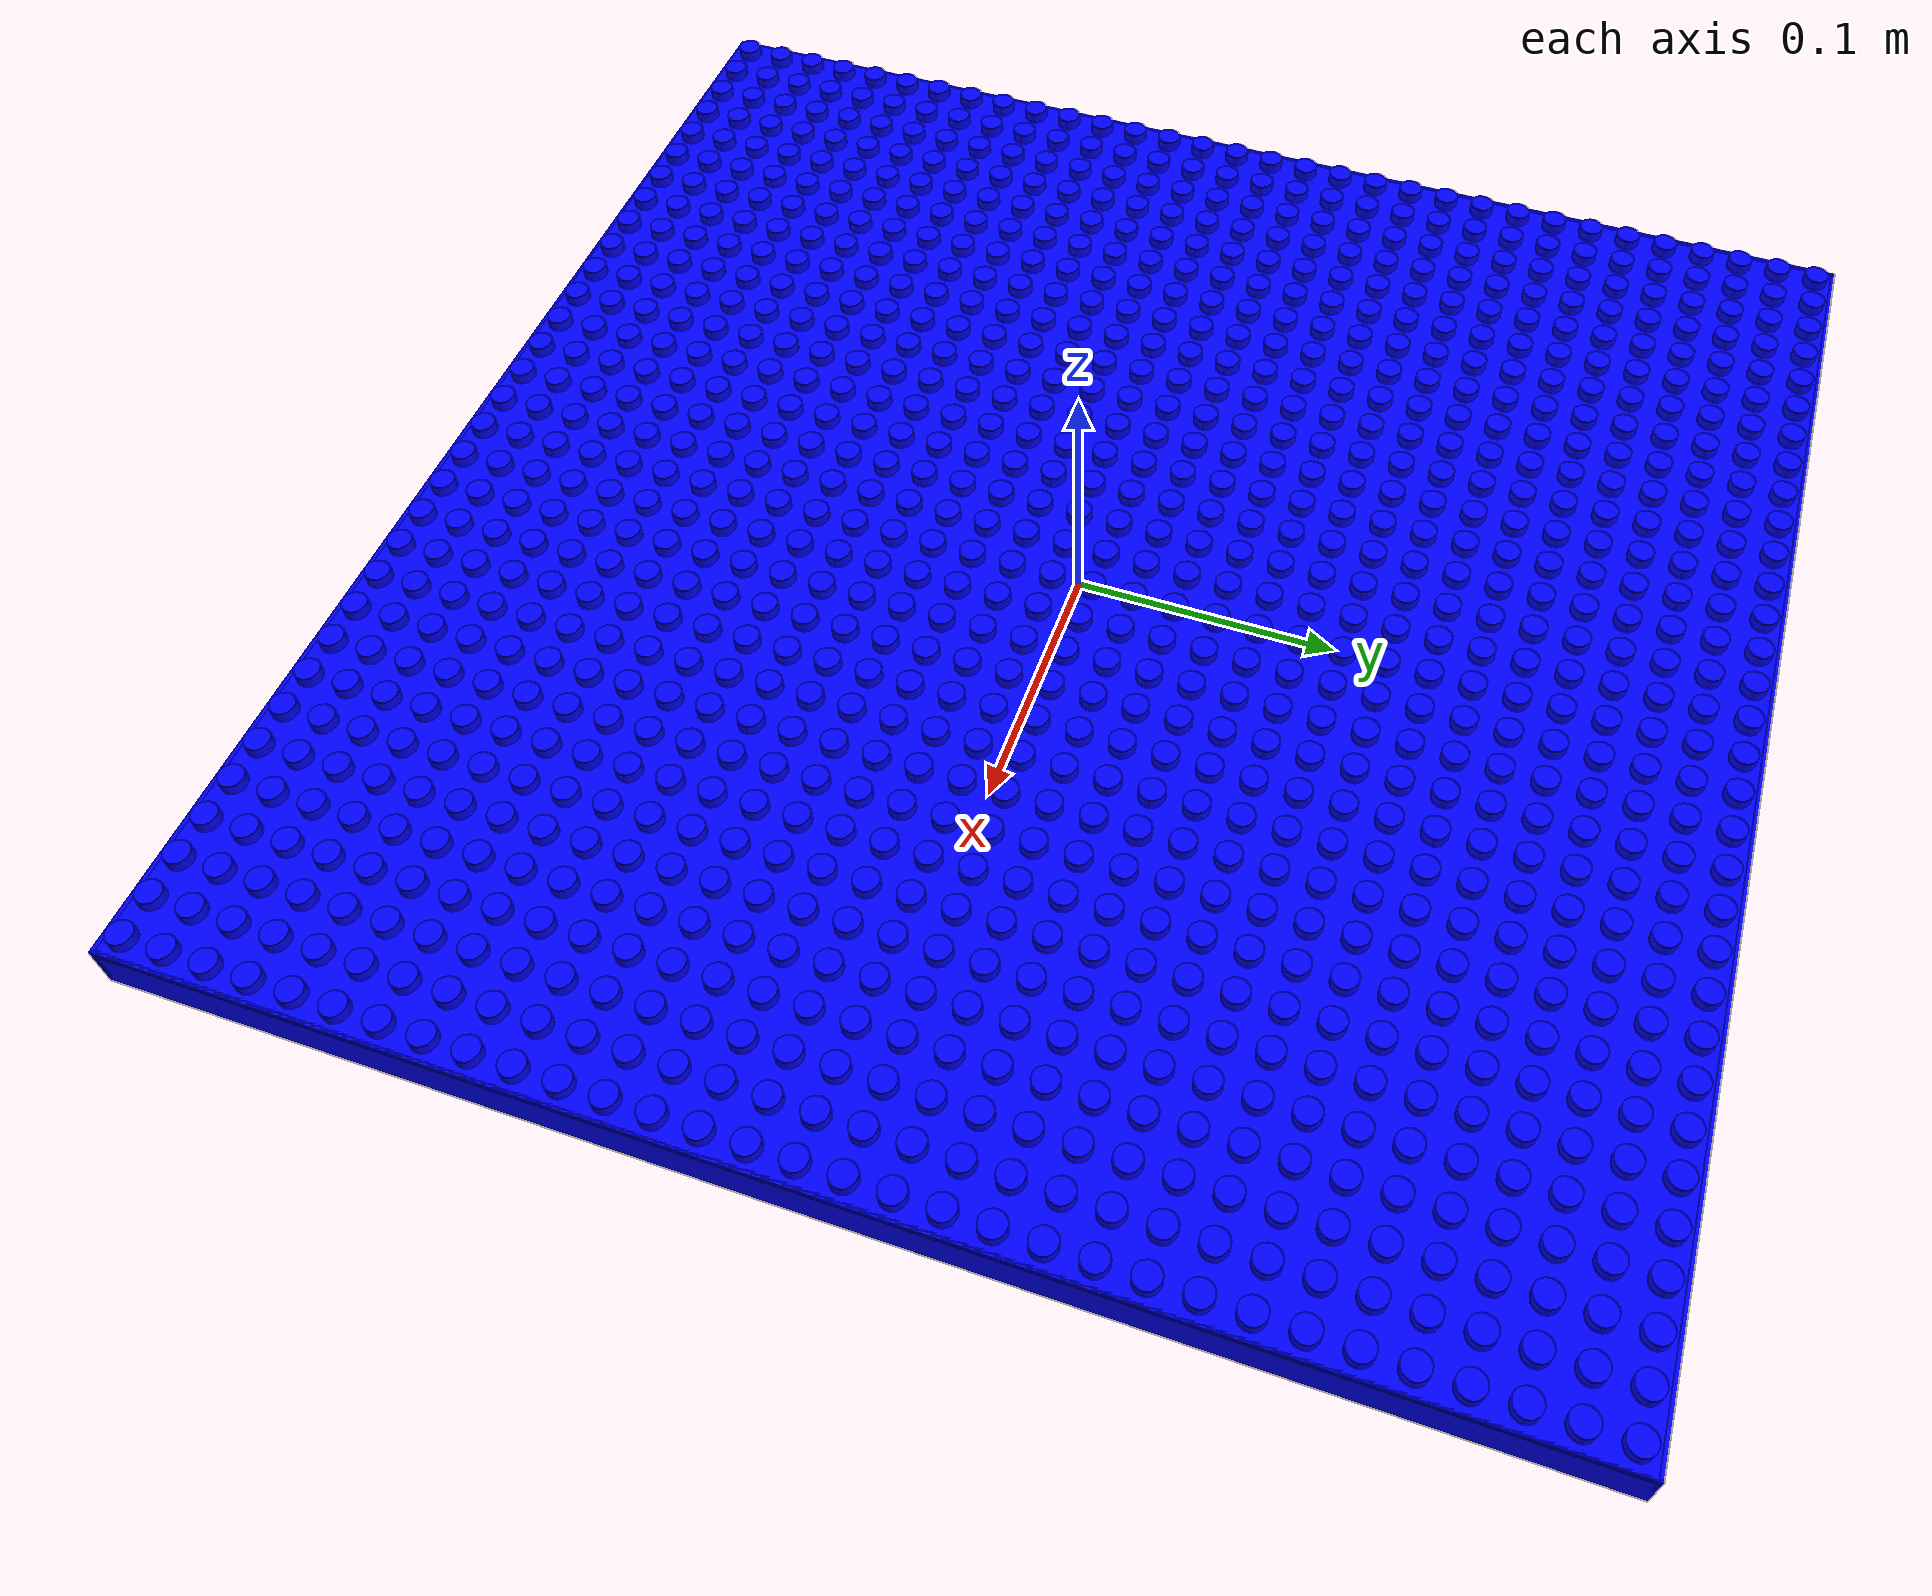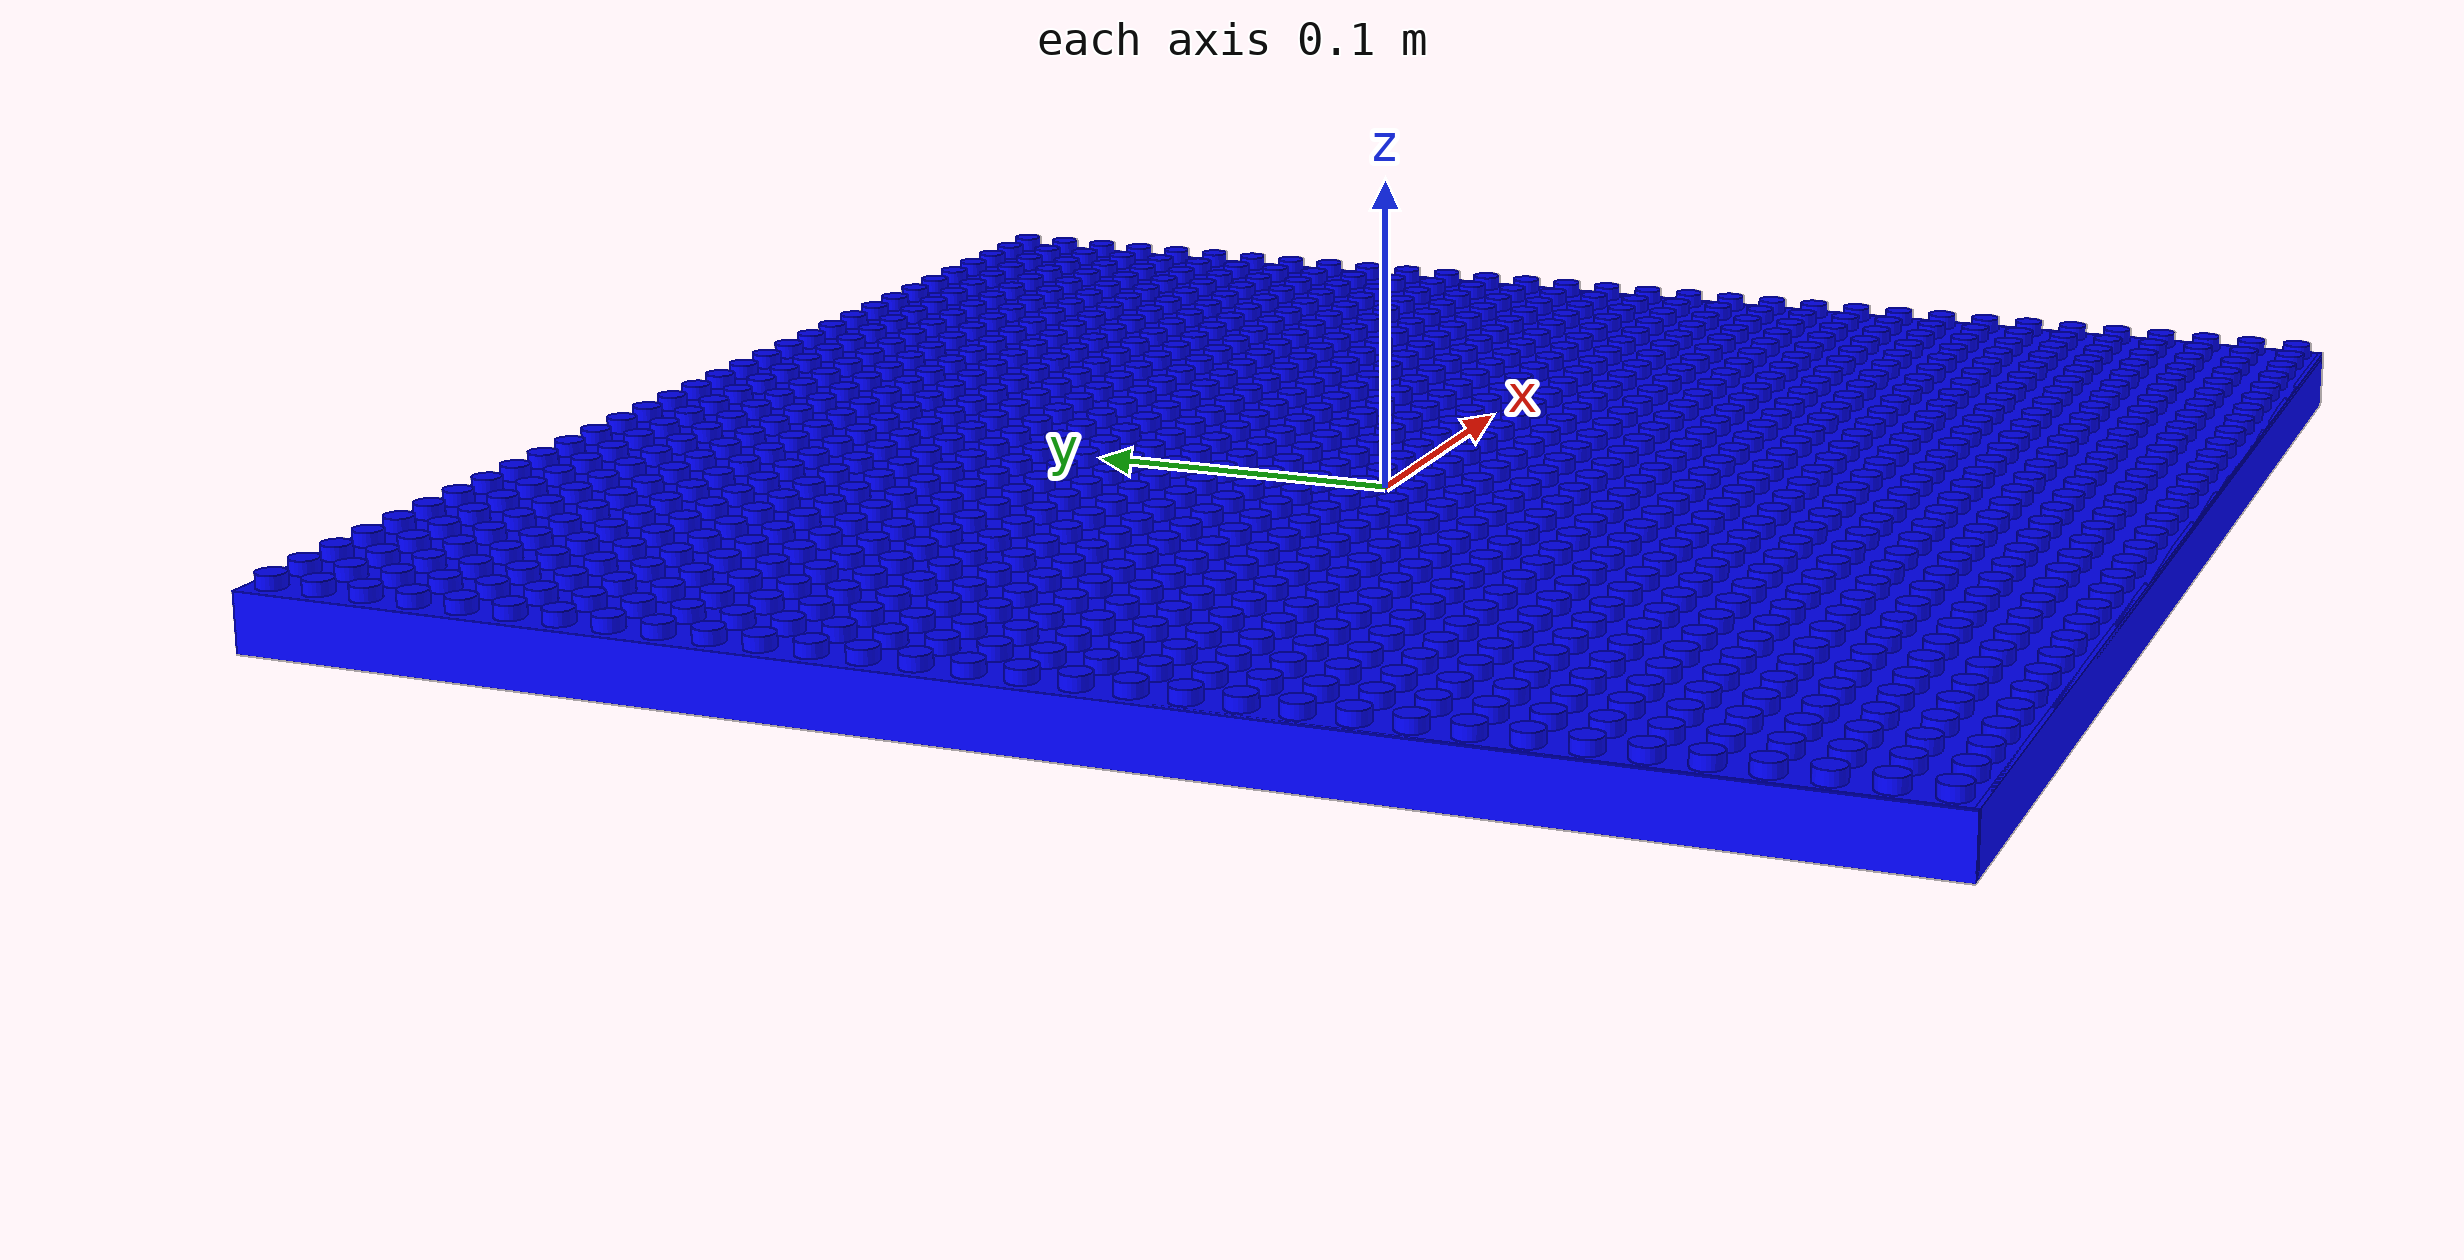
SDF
<?xml version="1.0"?>
<sdf version="1.7">
  <model name="block">
    <link name="block">

      <visual name="left_visual">
        <pose>0.0 0.25525000000000003 0.0 0 0 0</pose>
        <geometry>
          <box>
            <size>0.512 0.0015 0.0192</size>
          </box>
        </geometry>
        <material>
          <diffuse>0.0 0.0 1.0 1.0</diffuse>
        </material>
      </visual>
      <collision name="left_collision">
        <pose>0.0 0.25525000000000003 0.0 0 0 0</pose>
        <geometry>
          <box>
            <size>0.512 0.0015 0.0192</size>
          </box>
        </geometry>
          <drake:proximity_properties>
              <drake:rigid_hydroelastic/>
              <drake:mesh_resolution_hint>0.5</drake:mesh_resolution_hint>
          </drake:proximity_properties>
      </collision>

      <visual name="right_visual">
        <pose>0.0 -0.25525000000000003 0.0 0 0 0</pose>
        <geometry>
          <box>
            <size>0.512 0.0015 0.0192</size>
          </box>
        </geometry>
        <material>
          <diffuse>0.0 0.0 1.0 1.0</diffuse>
        </material>
      </visual>
      <collision name="right_collision">
        <pose>0.0 -0.25525000000000003 0.0 0 0 0</pose>
        <geometry>
          <box>
            <size>0.512 0.0015 0.0192</size>
          </box>
        </geometry>
          <drake:proximity_properties>
              <drake:rigid_hydroelastic/>
              <drake:mesh_resolution_hint>0.5</drake:mesh_resolution_hint>
          </drake:proximity_properties>
      </collision>

      <visual name="front_visual">
        <pose>0.25525000000000003 0.0 0.0 0 0 0</pose>
        <geometry>
          <box>
            <size>0.0015 0.512 0.0192</size>
          </box>
        </geometry>
        <material>
          <diffuse>0.0 0.0 1.0 1.0</diffuse>
        </material>
      </visual>
      <collision name="front_collision">
        <pose>0.25525000000000003 0.0 0.0 0 0 0</pose>
        <geometry>
          <box>
            <size>0.0015 0.512 0.0192</size>
          </box>
        </geometry>
          <drake:proximity_properties>
              <drake:rigid_hydroelastic/>
              <drake:mesh_resolution_hint>0.5</drake:mesh_resolution_hint>
          </drake:proximity_properties>
      </collision>

      <visual name="back_visual">
        <pose>-0.25525000000000003 0.0 0.0 0 0 0</pose>
        <geometry>
          <box>
            <size>0.0015 0.512 0.0192</size>
          </box>
        </geometry>
        <material>
          <diffuse>0.0 0.0 1.0 1.0</diffuse>
        </material>
      </visual>
      <collision name="back_collision">
        <pose>-0.25525000000000003 0.0 0.0 0 0 0</pose>
        <geometry>
          <box>
            <size>0.0015 0.512 0.0192</size>
          </box>
        </geometry>
          <drake:proximity_properties>
              <drake:rigid_hydroelastic/>
              <drake:mesh_resolution_hint>0.5</drake:mesh_resolution_hint>
          </drake:proximity_properties>
      </collision>

      <visual name="top_visual">
        <pose>0.0 0.0 0.008849999999999998 0 0 0</pose>
        <geometry>
          <box>
            <size>0.512 0.512 0.0015</size>
          </box>
        </geometry>
        <material>
          <diffuse>0.0 0.0 1.0 1.0</diffuse>
        </material>
      </visual>
      <collision name="top_collision">
        <pose>0.0 0.0 0.008849999999999998 0 0 0</pose>
        <geometry>
          <box>
            <size>0.512 0.512 0.0015</size>
          </box>
        </geometry>
          <drake:proximity_properties>
              <drake:rigid_hydroelastic/>
              <drake:mesh_resolution_hint>0.5</drake:mesh_resolution_hint>
          </drake:proximity_properties>
      </collision>

      <visual name="stud_1_1_visual">
        <pose>-0.248 -0.248 0.01185 0 0 0</pose>
        <geometry>
          <cylinder>
            <radius>0.0048</radius>
            <length>0.0045</length>
          </cylinder>
        </geometry>
        <material>
          <diffuse>0.0 0.0 1.0 1.0</diffuse>
        </material>
      </visual>
      <collision name="stud_1_1_collision">
        <pose>-0.248 -0.248 0.01185 0 0 0</pose>
        <geometry>
          <cylinder>
            <radius>0.0048</radius>
            <length>0.0045</length>
          </cylinder>
        </geometry>
          <drake:proximity_properties>
              <drake:rigid_hydroelastic/>
              <drake:mesh_resolution_hint>0.5</drake:mesh_resolution_hint>
          </drake:proximity_properties>
      </collision>

      <visual name="stud_1_2_visual">
        <pose>-0.248 -0.232 0.01185 0 0 0</pose>
        <geometry>
          <cylinder>
            <radius>0.0048</radius>
            <length>0.0045</length>
          </cylinder>
        </geometry>
        <material>
          <diffuse>0.0 0.0 1.0 1.0</diffuse>
        </material>
      </visual>
      <collision name="stud_1_2_collision">
        <pose>-0.248 -0.232 0.01185 0 0 0</pose>
        <geometry>
          <cylinder>
            <radius>0.0048</radius>
            <length>0.0045</length>
          </cylinder>
        </geometry>
          <drake:proximity_properties>
              <drake:rigid_hydroelastic/>
              <drake:mesh_resolution_hint>0.5</drake:mesh_resolution_hint>
          </drake:proximity_properties>
      </collision>

      <visual name="stud_1_3_visual">
        <pose>-0.248 -0.21600000000000003 0.01185 0 0 0</pose>
        <geometry>
          <cylinder>
            <radius>0.0048</radius>
            <length>0.0045</length>
          </cylinder>
        </geometry>
        <material>
          <diffuse>0.0 0.0 1.0 1.0</diffuse>
        </material>
      </visual>
      <collision name="stud_1_3_collision">
        <pose>-0.248 -0.21600000000000003 0.01185 0 0 0</pose>
        <geometry>
          <cylinder>
            <radius>0.0048</radius>
            <length>0.0045</length>
          </cylinder>
        </geometry>
          <drake:proximity_properties>
              <drake:rigid_hydroelastic/>
              <drake:mesh_resolution_hint>0.5</drake:mesh_resolution_hint>
          </drake:proximity_properties>
      </collision>

      <visual name="stud_1_4_visual">
        <pose>-0.248 -0.2 0.01185 0 0 0</pose>
        <geometry>
          <cylinder>
            <radius>0.0048</radius>
            <length>0.0045</length>
          </cylinder>
        </geometry>
        <material>
          <diffuse>0.0 0.0 1.0 1.0</diffuse>
        </material>
      </visual>
      <collision name="stud_1_4_collision">
        <pose>-0.248 -0.2 0.01185 0 0 0</pose>
        <geometry>
          <cylinder>
            <radius>0.0048</radius>
            <length>0.0045</length>
          </cylinder>
        </geometry>
          <drake:proximity_properties>
              <drake:rigid_hydroelastic/>
              <drake:mesh_resolution_hint>0.5</drake:mesh_resolution_hint>
          </drake:proximity_properties>
      </collision>

      <visual name="stud_1_5_visual">
        <pose>-0.248 -0.184 0.01185 0 0 0</pose>
        <geometry>
          <cylinder>
            <radius>0.0048</radius>
            <length>0.0045</length>
          </cylinder>
        </geometry>
        <material>
          <diffuse>0.0 0.0 1.0 1.0</diffuse>
        </material>
      </visual>
      <collision name="stud_1_5_collision">
        <pose>-0.248 -0.184 0.01185 0 0 0</pose>
        <geometry>
          <cylinder>
            <radius>0.0048</radius>
            <length>0.0045</length>
          </cylinder>
        </geometry>
          <drake:proximity_properties>
              <drake:rigid_hydroelastic/>
              <drake:mesh_resolution_hint>0.5</drake:mesh_resolution_hint>
          </drake:proximity_properties>
      </collision>

      <visual name="stud_1_6_visual">
        <pose>-0.248 -0.168 0.01185 0 0 0</pose>
        <geometry>
          <cylinder>
            <radius>0.0048</radius>
            <length>0.0045</length>
          </cylinder>
        </geometry>
        <material>
          <diffuse>0.0 0.0 1.0 1.0</diffuse>
        </material>
      </visual>
      <collision name="stud_1_6_collision">
        <pose>-0.248 -0.168 0.01185 0 0 0</pose>
        <geometry>
          <cylinder>
            <radius>0.0048</radius>
            <length>0.0045</length>
          </cylinder>
        </geometry>
          <drake:proximity_properties>
              <drake:rigid_hydroelastic/>
              <drake:mesh_resolution_hint>0.5</drake:mesh_resolution_hint>
          </drake:proximity_properties>
      </collision>

      <visual name="stud_1_7_visual">
        <pose>-0.248 -0.15200000000000002 0.01185 0 0 0</pose>
        <geometry>
          <cylinder>
            <radius>0.0048</radius>
            <length>0.0045</length>
          </cylinder>
        </geometry>
        <material>
          <diffuse>0.0 0.0 1.0 1.0</diffuse>
        </material>
      </visual>
      <collision name="stud_1_7_collision">
        <pose>-0.248 -0.15200000000000002 0.01185 0 0 0</pose>
        <geometry>
          <cylinder>
            <radius>0.0048</radius>
            <length>0.0045</length>
          </cylinder>
        </geometry>
          <drake:proximity_properties>
              <drake:rigid_hydroelastic/>
              <drake:mesh_resolution_hint>0.5</drake:mesh_resolution_hint>
          </drake:proximity_properties>
      </collision>

      <visual name="stud_1_8_visual">
        <pose>-0.248 -0.136 0.01185 0 0 0</pose>
        <geometry>
          <cylinder>
            <radius>0.0048</radius>
            <length>0.0045</length>
          </cylinder>
        </geometry>
        <material>
          <diffuse>0.0 0.0 1.0 1.0</diffuse>
        </material>
      </visual>
      <collision name="stud_1_8_collision">
        <pose>-0.248 -0.136 0.01185 0 0 0</pose>
        <geometry>
          <cylinder>
            <radius>0.0048</radius>
            <length>0.0045</length>
          </cylinder>
        </geometry>
          <drake:proximity_properties>
              <drake:rigid_hydroelastic/>
              <drake:mesh_resolution_hint>0.5</drake:mesh_resolution_hint>
          </drake:proximity_properties>
      </collision>

      <visual name="stud_1_9_visual">
        <pose>-0.248 -0.12 0.01185 0 0 0</pose>
        <geometry>
          <cylinder>
            <radius>0.0048</radius>
            <length>0.0045</length>
          </cylinder>
        </geometry>
        <material>
          <diffuse>0.0 0.0 1.0 1.0</diffuse>
        </material>
      </visual>
      <collision name="stud_1_9_collision">
        <pose>-0.248 -0.12 0.01185 0 0 0</pose>
        <geometry>
          <cylinder>
            <radius>0.0048</radius>
            <length>0.0045</length>
          </cylinder>
        </geometry>
          <drake:proximity_properties>
              <drake:rigid_hydroelastic/>
              <drake:mesh_resolution_hint>0.5</drake:mesh_resolution_hint>
          </drake:proximity_properties>
      </collision>

      <visual name="stud_1_10_visual">
        <pose>-0.248 -0.10400000000000001 0.01185 0 0 0</pose>
        <geometry>
          <cylinder>
            <radius>0.0048</radius>
            <length>0.0045</length>
          </cylinder>
        </geometry>
        <material>
          <diffuse>0.0 0.0 1.0 1.0</diffuse>
        </material>
      </visual>
      <collision name="stud_1_10_collision">
        <pose>-0.248 -0.10400000000000001 0.01185 0 0 0</pose>
        <geometry>
          <cylinder>
            <radius>0.0048</radius>
            <length>0.0045</length>
          </cylinder>
        </geometry>
          <drake:proximity_properties>
              <drake:rigid_hydroelastic/>
              <drake:mesh_resolution_hint>0.5</drake:mesh_resolution_hint>
          </drake:proximity_properties>
      </collision>

      <visual name="stud_1_11_visual">
        <pose>-0.248 -0.08800000000000002 0.01185 0 0 0</pose>
        <geometry>
          <cylinder>
            <radius>0.0048</radius>
            <length>0.0045</length>
          </cylinder>
        </geometry>
        <material>
          <diffuse>0.0 0.0 1.0 1.0</diffuse>
        </material>
      </visual>
      <collision name="stud_1_11_collision">
        <pose>-0.248 -0.08800000000000002 0.01185 0 0 0</pose>
        <geometry>
          <cylinder>
            <radius>0.0048</radius>
            <length>0.0045</length>
          </cylinder>
        </geometry>
          <drake:proximity_properties>
              <drake:rigid_hydroelastic/>
              <drake:mesh_resolution_hint>0.5</drake:mesh_resolution_hint>
          </drake:proximity_properties>
      </collision>

      <visual name="stud_1_12_visual">
        <pose>-0.248 -0.07200000000000001 0.01185 0 0 0</pose>
        <geometry>
          <cylinder>
            <radius>0.0048</radius>
            <length>0.0045</length>
          </cylinder>
        </geometry>
        <material>
          <diffuse>0.0 0.0 1.0 1.0</diffuse>
        </material>
      </visual>
      <collision name="stud_1_12_collision">
        <pose>-0.248 -0.07200000000000001 0.01185 0 0 0</pose>
        <geometry>
          <cylinder>
            <radius>0.0048</radius>
            <length>0.0045</length>
          </cylinder>
        </geometry>
          <drake:proximity_properties>
              <drake:rigid_hydroelastic/>
              <drake:mesh_resolution_hint>0.5</drake:mesh_resolution_hint>
          </drake:proximity_properties>
      </collision>

      <visual name="stud_1_13_visual">
        <pose>-0.248 -0.055999999999999994 0.01185 0 0 0</pose>
        <geometry>
          <cylinder>
            <radius>0.0048</radius>
            <length>0.0045</length>
          </cylinder>
        </geometry>
        <material>
          <diffuse>0.0 0.0 1.0 1.0</diffuse>
        </material>
      </visual>
      <collision name="stud_1_13_collision">
        <pose>-0.248 -0.055999999999999994 0.01185 0 0 0</pose>
        <geometry>
          <cylinder>
            <radius>0.0048</radius>
            <length>0.0045</length>
          </cylinder>
        </geometry>
          <drake:proximity_properties>
              <drake:rigid_hydroelastic/>
              <drake:mesh_resolution_hint>0.5</drake:mesh_resolution_hint>
          </drake:proximity_properties>
      </collision>

      <visual name="stud_1_14_visual">
        <pose>-0.248 -0.04000000000000001 0.01185 0 0 0</pose>
        <geometry>
          <cylinder>
            <radius>0.0048</radius>
            <length>0.0045</length>
          </cylinder>
        </geometry>
        <material>
          <diffuse>0.0 0.0 1.0 1.0</diffuse>
        </material>
      </visual>
      <collision name="stud_1_14_collision">
        <pose>-0.248 -0.04000000000000001 0.01185 0 0 0</pose>
        <geometry>
          <cylinder>
            <radius>0.0048</radius>
            <length>0.0045</length>
          </cylinder>
        </geometry>
          <drake:proximity_properties>
              <drake:rigid_hydroelastic/>
              <drake:mesh_resolution_hint>0.5</drake:mesh_resolution_hint>
          </drake:proximity_properties>
      </collision>

      <visual name="stud_1_15_visual">
        <pose>-0.248 -0.02400000000000002 0.01185 0 0 0</pose>
        <geometry>
          <cylinder>
            <radius>0.0048</radius>
            <length>0.0045</length>
          </cylinder>
        </geometry>
        <material>
          <diffuse>0.0 0.0 1.0 1.0</diffuse>
        </material>
      </visual>
      <collision name="stud_1_15_collision">
        <pose>-0.248 -0.02400000000000002 0.01185 0 0 0</pose>
        <geometry>
          <cylinder>
            <radius>0.0048</radius>
            <length>0.0045</length>
          </cylinder>
        </geometry>
          <drake:proximity_properties>
              <drake:rigid_hydroelastic/>
              <drake:mesh_resolution_hint>0.5</drake:mesh_resolution_hint>
          </drake:proximity_properties>
      </collision>

      <visual name="stud_1_16_visual">
        <pose>-0.248 -0.008000000000000007 0.01185 0 0 0</pose>
        <geometry>
          <cylinder>
            <radius>0.0048</radius>
            <length>0.0045</length>
          </cylinder>
        </geometry>
        <material>
          <diffuse>0.0 0.0 1.0 1.0</diffuse>
        </material>
      </visual>
      <collision name="stud_1_16_collision">
        <pose>-0.248 -0.008000000000000007 0.01185 0 0 0</pose>
        <geometry>
          <cylinder>
            <radius>0.0048</radius>
            <length>0.0045</length>
          </cylinder>
        </geometry>
          <drake:proximity_properties>
              <drake:rigid_hydroelastic/>
              <drake:mesh_resolution_hint>0.5</drake:mesh_resolution_hint>
          </drake:proximity_properties>
      </collision>

      <visual name="stud_1_17_visual">
        <pose>-0.248 0.008000000000000007 0.01185 0 0 0</pose>
        <geometry>
          <cylinder>
            <radius>0.0048</radius>
            <length>0.0045</length>
          </cylinder>
        </geometry>
        <material>
          <diffuse>0.0 0.0 1.0 1.0</diffuse>
        </material>
      </visual>
      <collision name="stud_1_17_collision">
        <pose>-0.248 0.008000000000000007 0.01185 0 0 0</pose>
        <geometry>
          <cylinder>
            <radius>0.0048</radius>
            <length>0.0045</length>
          </cylinder>
        </geometry>
          <drake:proximity_properties>
              <drake:rigid_hydroelastic/>
              <drake:mesh_resolution_hint>0.5</drake:mesh_resolution_hint>
          </drake:proximity_properties>
      </collision>

      <visual name="stud_1_18_visual">
        <pose>-0.248 0.02400000000000002 0.01185 0 0 0</pose>
        <geometry>
          <cylinder>
            <radius>0.0048</radius>
            <length>0.0045</length>
          </cylinder>
        </geometry>
        <material>
          <diffuse>0.0 0.0 1.0 1.0</diffuse>
        </material>
      </visual>
      <collision name="stud_1_18_collision">
        <pose>-0.248 0.02400000000000002 0.01185 0 0 0</pose>
        <geometry>
          <cylinder>
            <radius>0.0048</radius>
            <length>0.0045</length>
          </cylinder>
        </geometry>
          <drake:proximity_properties>
              <drake:rigid_hydroelastic/>
              <drake:mesh_resolution_hint>0.5</drake:mesh_resolution_hint>
          </drake:proximity_properties>
      </collision>

      <visual name="stud_1_19_visual">
        <pose>-0.248 0.03999999999999998 0.01185 0 0 0</pose>
        <geometry>
          <cylinder>
            <radius>0.0048</radius>
            <length>0.0045</length>
          </cylinder>
        </geometry>
        <material>
          <diffuse>0.0 0.0 1.0 1.0</diffuse>
        </material>
      </visual>
      <collision name="stud_1_19_collision">
        <pose>-0.248 0.03999999999999998 0.01185 0 0 0</pose>
        <geometry>
          <cylinder>
            <radius>0.0048</radius>
            <length>0.0045</length>
          </cylinder>
        </geometry>
          <drake:proximity_properties>
              <drake:rigid_hydroelastic/>
              <drake:mesh_resolution_hint>0.5</drake:mesh_resolution_hint>
          </drake:proximity_properties>
      </collision>

      <visual name="stud_1_20_visual">
        <pose>-0.248 0.055999999999999994 0.01185 0 0 0</pose>
        <geometry>
          <cylinder>
            <radius>0.0048</radius>
            <length>0.0045</length>
          </cylinder>
        </geometry>
        <material>
          <diffuse>0.0 0.0 1.0 1.0</diffuse>
        </material>
      </visual>
      <collision name="stud_1_20_collision">
        <pose>-0.248 0.055999999999999994 0.01185 0 0 0</pose>
        <geometry>
          <cylinder>
            <radius>0.0048</radius>
            <length>0.0045</length>
          </cylinder>
        </geometry>
          <drake:proximity_properties>
              <drake:rigid_hydroelastic/>
              <drake:mesh_resolution_hint>0.5</drake:mesh_resolution_hint>
          </drake:proximity_properties>
      </collision>

      <visual name="stud_1_21_visual">
        <pose>-0.248 0.07200000000000001 0.01185 0 0 0</pose>
        <geometry>
          <cylinder>
            <radius>0.0048</radius>
            <length>0.0045</length>
          </cylinder>
        </geometry>
        <material>
          <diffuse>0.0 0.0 1.0 1.0</diffuse>
        </material>
      </visual>
      <collision name="stud_1_21_collision">
        <pose>-0.248 0.07200000000000001 0.01185 0 0 0</pose>
        <geometry>
          <cylinder>
            <radius>0.0048</radius>
            <length>0.0045</length>
          </cylinder>
        </geometry>
          <drake:proximity_properties>
              <drake:rigid_hydroelastic/>
              <drake:mesh_resolution_hint>0.5</drake:mesh_resolution_hint>
          </drake:proximity_properties>
      </collision>

      <visual name="stud_1_22_visual">
        <pose>-0.248 0.08799999999999997 0.01185 0 0 0</pose>
        <geometry>
          <cylinder>
            <radius>0.0048</radius>
            <length>0.0045</length>
          </cylinder>
        </geometry>
        <material>
          <diffuse>0.0 0.0 1.0 1.0</diffuse>
        </material>
      </visual>
      <collision name="stud_1_22_collision">
        <pose>-0.248 0.08799999999999997 0.01185 0 0 0</pose>
        <geometry>
          <cylinder>
            <radius>0.0048</radius>
            <length>0.0045</length>
          </cylinder>
        </geometry>
          <drake:proximity_properties>
              <drake:rigid_hydroelastic/>
              <drake:mesh_resolution_hint>0.5</drake:mesh_resolution_hint>
          </drake:proximity_properties>
      </collision>

      <visual name="stud_1_23_visual">
        <pose>-0.248 0.10399999999999998 0.01185 0 0 0</pose>
        <geometry>
          <cylinder>
            <radius>0.0048</radius>
            <length>0.0045</length>
          </cylinder>
        </geometry>
        <material>
          <diffuse>0.0 0.0 1.0 1.0</diffuse>
        </material>
      </visual>
      <collision name="stud_1_23_collision">
        <pose>-0.248 0.10399999999999998 0.01185 0 0 0</pose>
        <geometry>
          <cylinder>
            <radius>0.0048</radius>
            <length>0.0045</length>
          </cylinder>
        </geometry>
          <drake:proximity_properties>
              <drake:rigid_hydroelastic/>
              <drake:mesh_resolution_hint>0.5</drake:mesh_resolution_hint>
          </drake:proximity_properties>
      </collision>

      <visual name="stud_1_24_visual">
        <pose>-0.248 0.12 0.01185 0 0 0</pose>
        <geometry>
          <cylinder>
            <radius>0.0048</radius>
            <length>0.0045</length>
          </cylinder>
        </geometry>
        <material>
          <diffuse>0.0 0.0 1.0 1.0</diffuse>
        </material>
      </visual>
      <collision name="stud_1_24_collision">
        <pose>-0.248 0.12 0.01185 0 0 0</pose>
        <geometry>
          <cylinder>
            <radius>0.0048</radius>
            <length>0.0045</length>
          </cylinder>
        </geometry>
          <drake:proximity_properties>
              <drake:rigid_hydroelastic/>
              <drake:mesh_resolution_hint>0.5</drake:mesh_resolution_hint>
          </drake:proximity_properties>
      </collision>

      <visual name="stud_1_25_visual">
        <pose>-0.248 0.136 0.01185 0 0 0</pose>
        <geometry>
          <cylinder>
            <radius>0.0048</radius>
            <length>0.0045</length>
          </cylinder>
        </geometry>
        <material>
          <diffuse>0.0 0.0 1.0 1.0</diffuse>
        </material>
      </visual>
      <collision name="stud_1_25_collision">
        <pose>-0.248 0.136 0.01185 0 0 0</pose>
        <geometry>
          <cylinder>
            <radius>0.0048</radius>
            <length>0.0045</length>
          </cylinder>
        </geometry>
          <drake:proximity_properties>
              <drake:rigid_hydroelastic/>
              <drake:mesh_resolution_hint>0.5</drake:mesh_resolution_hint>
          </drake:proximity_properties>
      </collision>

      <visual name="stud_1_26_visual">
        <pose>-0.248 0.15200000000000002 0.01185 0 0 0</pose>
        <geometry>
          <cylinder>
            <radius>0.0048</radius>
            <length>0.0045</length>
          </cylinder>
        </geometry>
        <material>
          <diffuse>0.0 0.0 1.0 1.0</diffuse>
        </material>
      </visual>
      <collision name="stud_1_26_collision">
        <pose>-0.248 0.15200000000000002 0.01185 0 0 0</pose>
        <geometry>
          <cylinder>
            <radius>0.0048</radius>
            <length>0.0045</length>
          </cylinder>
        </geometry>
          <drake:proximity_properties>
              <drake:rigid_hydroelastic/>
              <drake:mesh_resolution_hint>0.5</drake:mesh_resolution_hint>
          </drake:proximity_properties>
      </collision>

      <visual name="stud_1_27_visual">
        <pose>-0.248 0.16799999999999998 0.01185 0 0 0</pose>
        <geometry>
          <cylinder>
            <radius>0.0048</radius>
            <length>0.0045</length>
          </cylinder>
        </geometry>
        <material>
          <diffuse>0.0 0.0 1.0 1.0</diffuse>
        </material>
      </visual>
      <collision name="stud_1_27_collision">
        <pose>-0.248 0.16799999999999998 0.01185 0 0 0</pose>
        <geometry>
          <cylinder>
            <radius>0.0048</radius>
            <length>0.0045</length>
          </cylinder>
        </geometry>
          <drake:proximity_properties>
              <drake:rigid_hydroelastic/>
              <drake:mesh_resolution_hint>0.5</drake:mesh_resolution_hint>
          </drake:proximity_properties>
      </collision>

      <visual name="stud_1_28_visual">
        <pose>-0.248 0.184 0.01185 0 0 0</pose>
        <geometry>
          <cylinder>
            <radius>0.0048</radius>
            <length>0.0045</length>
          </cylinder>
        </geometry>
        <material>
          <diffuse>0.0 0.0 1.0 1.0</diffuse>
        </material>
      </visual>
      <collision name="stud_1_28_collision">
        <pose>-0.248 0.184 0.01185 0 0 0</pose>
        <geometry>
          <cylinder>
            <radius>0.0048</radius>
            <length>0.0045</length>
          </cylinder>
        </geometry>
          <drake:proximity_properties>
              <drake:rigid_hydroelastic/>
              <drake:mesh_resolution_hint>0.5</drake:mesh_resolution_hint>
          </drake:proximity_properties>
      </collision>

      <visual name="stud_1_29_visual">
        <pose>-0.248 0.2 0.01185 0 0 0</pose>
        <geometry>
          <cylinder>
            <radius>0.0048</radius>
            <length>0.0045</length>
          </cylinder>
        </geometry>
        <material>
          <diffuse>0.0 0.0 1.0 1.0</diffuse>
        </material>
      </visual>
      <collision name="stud_1_29_collision">
        <pose>-0.248 0.2 0.01185 0 0 0</pose>
        <geometry>
          <cylinder>
            <radius>0.0048</radius>
            <length>0.0045</length>
          </cylinder>
        </geometry>
          <drake:proximity_properties>
              <drake:rigid_hydroelastic/>
              <drake:mesh_resolution_hint>0.5</drake:mesh_resolution_hint>
          </drake:proximity_properties>
      </collision>

      <visual name="stud_1_30_visual">
        <pose>-0.248 0.21599999999999997 0.01185 0 0 0</pose>
        <geometry>
          <cylinder>
            <radius>0.0048</radius>
            <length>0.0045</length>
          </cylinder>
        </geometry>
        <material>
          <diffuse>0.0 0.0 1.0 1.0</diffuse>
        </material>
      </visual>
      <collision name="stud_1_30_collision">
        <pose>-0.248 0.21599999999999997 0.01185 0 0 0</pose>
        <geometry>
          <cylinder>
            <radius>0.0048</radius>
            <length>0.0045</length>
          </cylinder>
        </geometry>
          <drake:proximity_properties>
              <drake:rigid_hydroelastic/>
              <drake:mesh_resolution_hint>0.5</drake:mesh_resolution_hint>
          </drake:proximity_properties>
      </collision>

      <visual name="stud_1_31_visual">
        <pose>-0.248 0.23199999999999998 0.01185 0 0 0</pose>
        <geometry>
          <cylinder>
            <radius>0.0048</radius>
            <length>0.0045</length>
          </cylinder>
        </geometry>
        <material>
          <diffuse>0.0 0.0 1.0 1.0</diffuse>
        </material>
      </visual>
      <collision name="stud_1_31_collision">
        <pose>-0.248 0.23199999999999998 0.01185 0 0 0</pose>
        <geometry>
          <cylinder>
            <radius>0.0048</radius>
            <length>0.0045</length>
          </cylinder>
        </geometry>
          <drake:proximity_properties>
              <drake:rigid_hydroelastic/>
              <drake:mesh_resolution_hint>0.5</drake:mesh_resolution_hint>
          </drake:proximity_properties>
      </collision>

      <visual name="stud_1_32_visual">
        <pose>-0.248 0.248 0.01185 0 0 0</pose>
        <geometry>
          <cylinder>
            <radius>0.0048</radius>
            <length>0.0045</length>
          </cylinder>
        </geometry>
        <material>
          <diffuse>0.0 0.0 1.0 1.0</diffuse>
        </material>
      </visual>
      <collision name="stud_1_32_collision">
        <pose>-0.248 0.248 0.01185 0 0 0</pose>
        <geometry>
          <cylinder>
            <radius>0.0048</radius>
            <length>0.0045</length>
          </cylinder>
        </geometry>
          <drake:proximity_properties>
              <drake:rigid_hydroelastic/>
              <drake:mesh_resolution_hint>0.5</drake:mesh_resolution_hint>
          </drake:proximity_properties>
      </collision>

      <visual name="stud_2_1_visual">
        <pose>-0.232 -0.248 0.01185 0 0 0</pose>
        <geometry>
          <cylinder>
            <radius>0.0048</radius>
            <length>0.0045</length>
          </cylinder>
        </geometry>
        <material>
          <diffuse>0.0 0.0 1.0 1.0</diffuse>
        </material>
      </visual>
      <collision name="stud_2_1_collision">
        <pose>-0.232 -0.248 0.01185 0 0 0</pose>
        <geometry>
          <cylinder>
            <radius>0.0048</radius>
            <length>0.0045</length>
          </cylinder>
        </geometry>
          <drake:proximity_properties>
              <drake:rigid_hydroelastic/>
              <drake:mesh_resolution_hint>0.5</drake:mesh_resolution_hint>
          </drake:proximity_properties>
      </collision>

      <visual name="stud_2_2_visual">
        <pose>-0.232 -0.232 0.01185 0 0 0</pose>
        <geometry>
          <cylinder>
            <radius>0.0048</radius>
            <length>0.0045</length>
          </cylinder>
        </geometry>
        <material>
          <diffuse>0.0 0.0 1.0 1.0</diffuse>
        </material>
      </visual>
      <collision name="stud_2_2_collision">
        <pose>-0.232 -0.232 0.01185 0 0 0</pose>
        <geometry>
          <cylinder>
            <radius>0.0048</radius>
            <length>0.0045</length>
          </cylinder>
        </geometry>
          <drake:proximity_properties>
              <drake:rigid_hydroelastic/>
              <drake:mesh_resolution_hint>0.5</drake:mesh_resolution_hint>
          </drake:proximity_properties>
      </collision>

      <visual name="stud_2_3_visual">
        <pose>-0.232 -0.21600000000000003 0.01185 0 0 0</pose>
        <geometry>
          <cylinder>
            <radius>0.0048</radius>
            <length>0.0045</length>
          </cylinder>
        </geometry>
        <material>
          <diffuse>0.0 0.0 1.0 1.0</diffuse>
        </material>
      </visual>
      <collision name="stud_2_3_collision">
        <pose>-0.232 -0.21600000000000003 0.01185 0 0 0</pose>
        <geometry>
          <cylinder>
            <radius>0.0048</radius>
            <length>0.0045</length>
          </cylinder>
        </geometry>
          <drake:proximity_properties>
              <drake:rigid_hydroelastic/>
              <drake:mesh_resolution_hint>0.5</drake:mesh_resolution_hint>
          </drake:proximity_properties>
      </collision>

      <visual name="stud_2_4_visual">
        <pose>-0.232 -0.2 0.01185 0 0 0</pose>
        <geometry>
          <cylinder>
            <radius>0.0048</radius>
            <length>0.0045</length>
          </cylinder>
        </geometry>
        <material>
          <diffuse>0.0 0.0 1.0 1.0</diffuse>
        </material>
      </visual>
      <collision name="stud_2_4_collision">
        <pose>-0.232 -0.2 0.01185 0 0 0</pose>
        <geometry>
          <cylinder>
            <radius>0.0048</radius>
            <length>0.0045</length>
          </cylinder>
        </geometry>
          <drake:proximity_properties>
              <drake:rigid_hydroelastic/>
              <drake:mesh_resolution_hint>0.5</drake:mesh_resolution_hint>
          </drake:proximity_properties>
      </collision>

      <visual name="stud_2_5_visual">
        <pose>-0.232 -0.184 0.01185 0 0 0</pose>
        <geometry>
          <cylinder>
            <radius>0.0048</radius>
            <length>0.0045</length>
          </cylinder>
        </geometry>
        <material>
          <diffuse>0.0 0.0 1.0 1.0</diffuse>
        </material>
      </visual>
      <collision name="stud_2_5_collision">
        <pose>-0.232 -0.184 0.01185 0 0 0</pose>
        <geometry>
          <cylinder>
            <radius>0.0048</radius>
            <length>0.0045</length>
          </cylinder>
        </geometry>
          <drake:proximity_properties>
              <drake:rigid_hydroelastic/>
              <drake:mesh_resolution_hint>0.5</drake:mesh_resolution_hint>
          </drake:proximity_properties>
      </collision>

      <visual name="stud_2_6_visual">
        <pose>-0.232 -0.168 0.01185 0 0 0</pose>
        <geometry>
          <cylinder>
            <radius>0.0048</radius>
            <length>0.0045</length>
          </cylinder>
        </geometry>
        <material>
          <diffuse>0.0 0.0 1.0 1.0</diffuse>
        </material>
      </visual>
      <collision name="stud_2_6_collision">
        <pose>-0.232 -0.168 0.01185 0 0 0</pose>
        <geometry>
          <cylinder>
            <radius>0.0048</radius>
            <length>0.0045</length>
          </cylinder>
        </geometry>
          <drake:proximity_properties>
              <drake:rigid_hydroelastic/>
              <drake:mesh_resolution_hint>0.5</drake:mesh_resolution_hint>
          </drake:proximity_properties>
      </collision>

      <visual name="stud_2_7_visual">
        <pose>-0.232 -0.15200000000000002 0.01185 0 0 0</pose>
        <geometry>
          <cylinder>
            <radius>0.0048</radius>
            <length>0.0045</length>
          </cylinder>
        </geometry>
        <material>
          <diffuse>0.0 0.0 1.0 1.0</diffuse>
        </material>
      </visual>
      <collision name="stud_2_7_collision">
        <pose>-0.232 -0.15200000000000002 0.01185 0 0 0</pose>
        <geometry>
          <cylinder>
            <radius>0.0048</radius>
            <length>0.0045</length>
          </cylinder>
        </geometry>
          <drake:proximity_properties>
              <drake:rigid_hydroelastic/>
              <drake:mesh_resolution_hint>0.5</drake:mesh_resolution_hint>
          </drake:proximity_properties>
      </collision>

      <visual name="stud_2_8_visual">
        <pose>-0.232 -0.136 0.01185 0 0 0</pose>
        <geometry>
          <cylinder>
            <radius>0.0048</radius>
            <length>0.0045</length>
          </cylinder>
        </geometry>
        <material>
          <diffuse>0.0 0.0 1.0 1.0</diffuse>
        </material>
      </visual>
      <collision name="stud_2_8_collision">
        <pose>-0.232 -0.136 0.01185 0 0 0</pose>
        <geometry>
          <cylinder>
            <radius>0.0048</radius>
            <length>0.0045</length>
          </cylinder>
        </geometry>
          <drake:proximity_properties>
              <drake:rigid_hydroelastic/>
              <drake:mesh_resolution_hint>0.5</drake:mesh_resolution_hint>
          </drake:proximity_properties>
      </collision>

      <visual name="stud_2_9_visual">
        <pose>-0.232 -0.12 0.01185 0 0 0</pose>
        <geometry>
          <cylinder>
            <radius>0.0048</radius>
            <length>0.0045</length>
          </cylinder>
        </geometry>
        <material>
          <diffuse>0.0 0.0 1.0 1.0</diffuse>
        </material>
      </visual>
      <collision name="stud_2_9_collision">
        <pose>-0.232 -0.12 0.01185 0 0 0</pose>
        <geometry>
          <cylinder>
            <radius>0.0048</radius>
            <length>0.0045</length>
          </cylinder>
        </geometry>
          <drake:proximity_properties>
              <drake:rigid_hydroelastic/>
              <drake:mesh_resolution_hint>0.5</drake:mesh_resolution_hint>
          </drake:proximity_properties>
      </collision>

      <visual name="stud_2_10_visual">
        <pose>-0.232 -0.10400000000000001 0.01185 0 0 0</pose>
        <geometry>
          <cylinder>
            <radius>0.0048</radius>
            <length>0.0045</length>
          </cylinder>
        </geometry>
        <material>
          <diffuse>0.0 0.0 1.0 1.0</diffuse>
        </material>
      </visual>
      <collision name="stud_2_10_collision">
        <pose>-0.232 -0.10400000000000001 0.01185 0 0 0</pose>
        <geometry>
          <cylinder>
            <radius>0.0048</radius>
            <length>0.0045</length>
          </cylinder>
        </geometry>
          <drake:proximity_properties>
              <drake:rigid_hydroelastic/>
              <drake:mesh_resolution_hint>0.5</drake:mesh_resolution_hint>
          </drake:proximity_properties>
      </collision>

      <visual name="stud_2_11_visual">
        <pose>-0.232 -0.08800000000000002 0.01185 0 0 0</pose>
        <geometry>
          <cylinder>
            <radius>0.0048</radius>
            <length>0.0045</length>
          </cylinder>
        </geometry>
        <material>
          <diffuse>0.0 0.0 1.0 1.0</diffuse>
        </material>
      </visual>
      <collision name="stud_2_11_collision">
        <pose>-0.232 -0.08800000000000002 0.01185 0 0 0</pose>
        <geometry>
          <cylinder>
            <radius>0.0048</radius>
            <length>0.0045</length>
          </cylinder>
        </geometry>
          <drake:proximity_properties>
              <drake:rigid_hydroelastic/>
              <drake:mesh_resolution_hint>0.5</drake:mesh_resolution_hint>
          </drake:proximity_properties>
      </collision>

      <visual name="stud_2_12_visual">
        <pose>-0.232 -0.07200000000000001 0.01185 0 0 0</pose>
        <geometry>
          <cylinder>
            <radius>0.0048</radius>
            <length>0.0045</length>
          </cylinder>
        </geometry>
        <material>
          <diffuse>0.0 0.0 1.0 1.0</diffuse>
        </material>
      </visual>
      <collision name="stud_2_12_collision">
        <pose>-0.232 -0.07200000000000001 0.01185 0 0 0</pose>
        <geometry>
          <cylinder>
            <radius>0.0048</radius>
            <length>0.0045</length>
          </cylinder>
        </geometry>
          <drake:proximity_properties>
              <drake:rigid_hydroelastic/>
              <drake:mesh_resolution_hint>0.5</drake:mesh_resolution_hint>
          </drake:proximity_properties>
      </collision>

      <visual name="stud_2_13_visual">
        <pose>-0.232 -0.055999999999999994 0.01185 0 0 0</pose>
        <geometry>
          <cylinder>
            <radius>0.0048</radius>
            <length>0.0045</length>
          </cylinder>
        </geometry>
        <material>
          <diffuse>0.0 0.0 1.0 1.0</diffuse>
        </material>
      </visual>
      <collision name="stud_2_13_collision">
        <pose>-0.232 -0.055999999999999994 0.01185 0 0 0</pose>
        <geometry>
          <cylinder>
            <radius>0.0048</radius>
            <length>0.0045</length>
          </cylinder>
        </geometry>
          <drake:proximity_properties>
              <drake:rigid_hydroelastic/>
              <drake:mesh_resolution_hint>0.5</drake:mesh_resolution_hint>
          </drake:proximity_properties>
      </collision>

      <visual name="stud_2_14_visual">
        <pose>-0.232 -0.04000000000000001 0.01185 0 0 0</pose>
        <geometry>
          <cylinder>
            <radius>0.0048</radius>
            <length>0.0045</length>
          </cylinder>
        </geometry>
        <material>
          <diffuse>0.0 0.0 1.0 1.0</diffuse>
        </material>
      </visual>
      <collision name="stud_2_14_collision">
        <pose>-0.232 -0.04000000000000001 0.01185 0 0 0</pose>
        <geometry>
          <cylinder>
            <radius>0.0048</radius>
            <length>0.0045</length>
          </cylinder>
        </geometry>
          <drake:proximity_properties>
              <drake:rigid_hydroelastic/>
              <drake:mesh_resolution_hint>0.5</drake:mesh_resolution_hint>
          </drake:proximity_properties>
      </collision>

      <visual name="stud_2_15_visual">
        <pose>-0.232 -0.02400000000000002 0.01185 0 0 0</pose>
        <geometry>
          <cylinder>
            <radius>0.0048</radius>
            <length>0.0045</length>
          </cylinder>
        </geometry>
        <material>
          <diffuse>0.0 0.0 1.0 1.0</diffuse>
        </material>
      </visual>
      <collision name="stud_2_15_collision">
        <pose>-0.232 -0.02400000000000002 0.01185 0 0 0</pose>
        <geometry>
          <cylinder>
            <radius>0.0048</radius>
            <length>0.0045</length>
          </cylinder>
        </geometry>
          <drake:proximity_properties>
              <drake:rigid_hydroelastic/>
              <drake:mesh_resolution_hint>0.5</drake:mesh_resolution_hint>
          </drake:proximity_properties>
      </collision>

      <visual name="stud_2_16_visual">
        <pose>-0.232 -0.008000000000000007 0.01185 0 0 0</pose>
        <geometry>
          <cylinder>
            <radius>0.0048</radius>
            <length>0.0045</length>
          </cylinder>
        </geometry>
        <material>
          <diffuse>0.0 0.0 1.0 1.0</diffuse>
        </material>
      </visual>
      <collision name="stud_2_16_collision">
        <pose>-0.232 -0.008000000000000007 0.01185 0 0 0</pose>
        <geometry>
          <cylinder>
            <radius>0.0048</radius>
            <length>0.0045</length>
          </cylinder>
        </geometry>
          <drake:proximity_properties>
              <drake:rigid_hydroelastic/>
              <drake:mesh_resolution_hint>0.5</drake:mesh_resolution_hint>
          </drake:proximity_properties>
      </collision>

      <visual name="stud_2_17_visual">
        <pose>-0.232 0.008000000000000007 0.01185 0 0 0</pose>
        <geometry>
          <cylinder>
            <radius>0.0048</radius>
            <length>0.0045</length>
          </cylinder>
        </geometry>
        <material>
          <diffuse>0.0 0.0 1.0 1.0</diffuse>
        </material>
      </visual>
      <collision name="stud_2_17_collision">
        <pose>-0.232 0.008000000000000007 0.01185 0 0 0</pose>
        <geometry>
          <cylinder>
            <radius>0.0048</radius>
            <length>0.0045</length>
          </cylinder>
        </geometry>
          <drake:proximity_properties>
              <drake:rigid_hydroelastic/>
              <drake:mesh_resolution_hint>0.5</drake:mesh_resolution_hint>
          </drake:proximity_properties>
      </collision>

      <visual name="stud_2_18_visual">
        <pose>-0.232 0.02400000000000002 0.01185 0 0 0</pose>
        <geometry>
          <cylinder>
            <radius>0.0048</radius>
            <length>0.0045</length>
          </cylinder>
        </geometry>
        <material>
          <diffuse>0.0 0.0 1.0 1.0</diffuse>
        </material>
      </visual>
      <collision name="stud_2_18_collision">
        <pose>-0.232 0.02400000000000002 0.01185 0 0 0</pose>
        <geometry>
          <cylinder>
            <radius>0.0048</radius>
            <length>0.0045</length>
          </cylinder>
        </geometry>
          <drake:proximity_properties>
              <drake:rigid_hydroelastic/>
              <drake:mesh_resolution_hint>0.5</drake:mesh_resolution_hint>
          </drake:proximity_properties>
      </collision>

      <visual name="stud_2_19_visual">
        <pose>-0.232 0.03999999999999998 0.01185 0 0 0</pose>
        <geometry>
          <cylinder>
            <radius>0.0048</radius>
            <length>0.0045</length>
          </cylinder>
        </geometry>
        <material>
          <diffuse>0.0 0.0 1.0 1.0</diffuse>
        </material>
      </visual>
      <collision name="stud_2_19_collision">
        <pose>-0.232 0.03999999999999998 0.01185 0 0 0</pose>
        <geometry>
          <cylinder>
            <radius>0.0048</radius>
            <length>0.0045</length>
          </cylinder>
        </geometry>
          <drake:proximity_properties>
              <drake:rigid_hydroelastic/>
              <drake:mesh_resolution_hint>0.5</drake:mesh_resolution_hint>
          </drake:proximity_properties>
      </collision>

      <visual name="stud_2_20_visual">
        <pose>-0.232 0.055999999999999994 0.01185 0 0 0</pose>
        <geometry>
          <cylinder>
            <radius>0.0048</radius>
            <length>0.0045</length>
          </cylinder>
        </geometry>
        <material>
          <diffuse>0.0 0.0 1.0 1.0</diffuse>
        </material>
      </visual>
      <collision name="stud_2_20_collision">
        <pose>-0.232 0.055999999999999994 0.01185 0 0 0</pose>
        <geometry>
          <cylinder>
            <radius>0.0048</radius>
            <length>0.0045</length>
          </cylinder>
        </geometry>
          <drake:proximity_properties>
              <drake:rigid_hydroelastic/>
              <drake:mesh_resolution_hint>0.5</drake:mesh_resolution_hint>
          </drake:proximity_properties>
      </collision>

      <visual name="stud_2_21_visual">
        <pose>-0.232 0.07200000000000001 0.01185 0 0 0</pose>
        <geometry>
          <cylinder>
            <radius>0.0048</radius>
            <length>0.0045</length>
          </cylinder>
        </geometry>
        <material>
          <diffuse>0.0 0.0 1.0 1.0</diffuse>
        </material>
      </visual>
      <collision name="stud_2_21_collision">
        <pose>-0.232 0.07200000000000001 0.01185 0 0 0</pose>
        <geometry>
          <cylinder>
            <radius>0.0048</radius>
            <length>0.0045</length>
          </cylinder>
        </geometry>
          <drake:proximity_properties>
              <drake:rigid_hydroelastic/>
              <drake:mesh_resolution_hint>0.5</drake:mesh_resolution_hint>
          </drake:proximity_properties>
      </collision>

      <visual name="stud_2_22_visual">
        <pose>-0.232 0.08799999999999997 0.01185 0 0 0</pose>
        <geometry>
          <cylinder>
            <radius>0.0048</radius>
            <length>0.0045</length>
          </cylinder>
        </geometry>
        <material>
          <diffuse>0.0 0.0 1.0 1.0</diffuse>
        </material>
      </visual>
      <collision name="stud_2_22_collision">
        <pose>-0.232 0.08799999999999997 0.01185 0 0 0</pose>
        <geometry>
          <cylinder>
            <radius>0.0048</radius>
            <length>0.0045</length>
          </cylinder>
        </geometry>
          <drake:proximity_properties>
              <drake:rigid_hydroelastic/>
              <drake:mesh_resolution_hint>0.5</drake:mesh_resolution_hint>
          </drake:proximity_properties>
      </collision>

      <visual name="stud_2_23_visual">
        <pose>-0.232 0.10399999999999998 0.01185 0 0 0</pose>
        <geometry>
          <cylinder>
            <radius>0.0048</radius>
            <length>0.0045</length>
          </cylinder>
        </geometry>
        <material>
          <diffuse>0.0 0.0 1.0 1.0</diffuse>
        </material>
      </visual>
      <collision name="stud_2_23_collision">
        <pose>-0.232 0.10399999999999998 0.01185 0 0 0</pose>
        <geometry>
          <cylinder>
            <radius>0.0048</radius>
            <length>0.0045</length>
          </cylinder>
        </geometry>
          <drake:proximity_properties>
              <drake:rigid_hydroelastic/>
              <drake:mesh_resolution_hint>0.5</drake:mesh_resolution_hint>
          </drake:proximity_properties>
      </collision>

      <visual name="stud_2_24_visual">
        <pose>-0.232 0.12 0.01185 0 0 0</pose>
        <geometry>
          <cylinder>
            <radius>0.0048</radius>
            <length>0.0045</length>
          </cylinder>
        </geometry>
        <material>
          <diffuse>0.0 0.0 1.0 1.0</diffuse>
        </material>
      </visual>
      <collision name="stud_2_24_collision">
        <pose>-0.232 0.12 0.01185 0 0 0</pose>
        <geometry>
          <cylinder>
            <radius>0.0048</radius>
            <length>0.0045</length>
          </cylinder>
        </geometry>
          <drake:proximity_properties>
              <drake:rigid_hydroelastic/>
              <drake:mesh_resolution_hint>0.5</drake:mesh_resolution_hint>
          </drake:proximity_properties>
      </collision>

      <visual name="stud_2_25_visual">
        <pose>-0.232 0.136 0.01185 0 0 0</pose>
        <geometry>
          <cylinder>
            <radius>0.0048</radius>
            <length>0.0045</length>
          </cylinder>
        </geometry>
        <material>
          <diffuse>0.0 0.0 1.0 1.0</diffuse>
        </material>
      </visual>
      <collision name="stud_2_25_collision">
        <pose>-0.232 0.136 0.01185 0 0 0</pose>
        <geometry>
          <cylinder>
            <radius>0.0048</radius>
            <length>0.0045</length>
          </cylinder>
        </geometry>
          <drake:proximity_properties>
              <drake:rigid_hydroelastic/>
              <drake:mesh_resolution_hint>0.5</drake:mesh_resolution_hint>
          </drake:proximity_properties>
      </collision>

      <visual name="stud_2_26_visual">
        <pose>-0.232 0.15200000000000002 0.01185 0 0 0</pose>
        <geometry>
          <cylinder>
            <radius>0.0048</radius>
            <length>0.0045</length>
          </cylinder>
        </geometry>
        <material>
          <diffuse>0.0 0.0 1.0 1.0</diffuse>
        </material>
      </visual>
      <collision name="stud_2_26_collision">
        <pose>-0.232 0.15200000000000002 0.01185 0 0 0</pose>
        <geometry>
          <cylinder>
            <radius>0.0048</radius>
            <length>0.0045</length>
          </cylinder>
        </geometry>
          <drake:proximity_properties>
              <drake:rigid_hydroelastic/>
              <drake:mesh_resolution_hint>0.5</drake:mesh_resolution_hint>
          </drake:proximity_properties>
      </collision>

      <visual name="stud_2_27_visual">
        <pose>-0.232 0.16799999999999998 0.01185 0 0 0</pose>
        <geometry>
          <cylinder>
            <radius>0.0048</radius>
            <length>0.0045</length>
          </cylinder>
        </geometry>
        <material>
          <diffuse>0.0 0.0 1.0 1.0</diffuse>
        </material>
      </visual>
      <collision name="stud_2_27_collision">
        <pose>-0.232 0.16799999999999998 0.01185 0 0 0</pose>
        <geometry>
          <cylinder>
            <radius>0.0048</radius>
            <length>0.0045</length>
          </cylinder>
        </geometry>
          <drake:proximity_properties>
              <drake:rigid_hydroelastic/>
              <drake:mesh_resolution_hint>0.5</drake:mesh_resolution_hint>
          </drake:proximity_properties>
      </collision>

      <visual name="stud_2_28_visual">
        <pose>-0.232 0.184 0.01185 0 0 0</pose>
        <geometry>
          <cylinder>
            <radius>0.0048</radius>
            <length>0.0045</length>
          </cylinder>
        </geometry>
        <material>
          <diffuse>0.0 0.0 1.0 1.0</diffuse>
        </material>
      </visual>
      <collision name="stud_2_28_collision">
        <pose>-0.232 0.184 0.01185 0 0 0</pose>
        <geometry>
          <cylinder>
            <radius>0.0048</radius>
            <length>0.0045</length>
          </cylinder>
        </geometry>
          <drake:proximity_properties>
              <drake:rigid_hydroelastic/>
              <drake:mesh_resolution_hint>0.5</drake:mesh_resolution_hint>
          </drake:proximity_properties>
      </collision>

      <visual name="stud_2_29_visual">
        <pose>-0.232 0.2 0.01185 0 0 0</pose>
        <geometry>
          <cylinder>
            <radius>0.0048</radius>
            <length>0.0045</length>
          </cylinder>
        </geometry>
        <material>
          <diffuse>0.0 0.0 1.0 1.0</diffuse>
        </material>
      </visual>
      <collision name="stud_2_29_collision">
        <pose>-0.232 0.2 0.01185 0 0 0</pose>
        <geometry>
          <cylinder>
            <radius>0.0048</radius>
            <length>0.0045</length>
          </cylinder>
        </geometry>
          <drake:proximity_properties>
              <drake:rigid_hydroelastic/>
              <drake:mesh_resolution_hint>0.5</drake:mesh_resolution_hint>
          </drake:proximity_properties>
      </collision>

      <visual name="stud_2_30_visual">
        <pose>-0.232 0.21599999999999997 0.01185 0 0 0</pose>
        <geometry>
          <cylinder>
            <radius>0.0048</radius>
            <length>0.0045</length>
          </cylinder>
        </geometry>
        <material>
          <diffuse>0.0 0.0 1.0 1.0</diffuse>
        </material>
      </visual>
      <collision name="stud_2_30_collision">
        <pose>-0.232 0.21599999999999997 0.01185 0 0 0</pose>
        <geometry>
          <cylinder>
            <radius>0.0048</radius>
            <length>0.0045</length>
          </cylinder>
        </geometry>
          <drake:proximity_properties>
              <drake:rigid_hydroelastic/>
              <drake:mesh_resolution_hint>0.5</drake:mesh_resolution_hint>
          </drake:proximity_properties>
      </collision>

      <visual name="stud_2_31_visual">
        <pose>-0.232 0.23199999999999998 0.01185 0 0 0</pose>
        <geometry>
          <cylinder>
            <radius>0.0048</radius>
            <length>0.0045</length>
          </cylinder>
        </geometry>
        <material>
          <diffuse>0.0 0.0 1.0 1.0</diffuse>
        </material>
      </visual>
      <collision name="stud_2_31_collision">
        <pose>-0.232 0.23199999999999998 0.01185 0 0 0</pose>
        <geometry>
          <cylinder>
            <radius>0.0048</radius>
            <length>0.0045</length>
          </cylinder>
        </geometry>
          <drake:proximity_properties>
              <drake:rigid_hydroelastic/>
              <drake:mesh_resolution_hint>0.5</drake:mesh_resolution_hint>
          </drake:proximity_properties>
      </collision>

      <visual name="stud_2_32_visual">
        <pose>-0.232 0.248 0.01185 0 0 0</pose>
        <geometry>
          <cylinder>
            <radius>0.0048</radius>
            <length>0.0045</length>
          </cylinder>
        </geometry>
        <material>
          <diffuse>0.0 0.0 1.0 1.0</diffuse>
        </material>
      </visual>
      <collision name="stud_2_32_collision">
        <pose>-0.232 0.248 0.01185 0 0 0</pose>
        <geometry>
          <cylinder>
            <radius>0.0048</radius>
            <length>0.0045</length>
          </cylinder>
        </geometry>
          <drake:proximity_properties>
              <drake:rigid_hydroelastic/>
              <drake:mesh_resolution_hint>0.5</drake:mesh_resolution_hint>
          </drake:proximity_properties>
      </collision>

      <visual name="stud_3_1_visual">
        <pose>-0.21600000000000003 -0.248 0.01185 0 0 0</pose>
        <geometry>
          <cylinder>
            <radius>0.0048</radius>
            <length>0.0045</length>
          </cylinder>
        </geometry>
        <material>
          <diffuse>0.0 0.0 1.0 1.0</diffuse>
        </material>
      </visual>
      <collision name="stud_3_1_collision">
        <pose>-0.21600000000000003 -0.248 0.01185 0 0 0</pose>
        <geometry>
          <cylinder>
            <radius>0.0048</radius>
            <length>0.0045</length>
          </cylinder>
        </geometry>
          <drake:proximity_properties>
              <drake:rigid_hydroelastic/>
              <drake:mesh_resolution_hint>0.5</drake:mesh_resolution_hint>
          </drake:proximity_properties>
      </collision>

      <visual name="stud_3_2_visual">
        <pose>-0.21600000000000003 -0.232 0.01185 0 0 0</pose>
        <geometry>
          <cylinder>
            <radius>0.0048</radius>
            <length>0.0045</length>
          </cylinder>
        </geometry>
        <material>
          <diffuse>0.0 0.0 1.0 1.0</diffuse>
        </material>
      </visual>
      <collision name="stud_3_2_collision">
        <pose>-0.21600000000000003 -0.232 0.01185 0 0 0</pose>
        <geometry>
          <cylinder>
            <radius>0.0048</radius>
            <length>0.0045</length>
          </cylinder>
        </geometry>
          <drake:proximity_properties>
              <drake:rigid_hydroelastic/>
              <drake:mesh_resolution_hint>0.5</drake:mesh_resolution_hint>
          </drake:proximity_properties>
      </collision>

      <visual name="stud_3_3_visual">
        <pose>-0.21600000000000003 -0.21600000000000003 0.01185 0 0 0</pose>
        <geometry>
          <cylinder>
            <radius>0.0048</radius>
            <length>0.0045</length>
          </cylinder>
        </geometry>
        <material>
          <diffuse>0.0 0.0 1.0 1.0</diffuse>
        </material>
      </visual>
      <collision name="stud_3_3_collision">
        <pose>-0.21600000000000003 -0.21600000000000003 0.01185 0 0 0</pose>
        <geometry>
          <cylinder>
            <radius>0.0048</radius>
            <length>0.0045</length>
          </cylinder>
        </geometry>
          <drake:proximity_properties>
              <drake:rigid_hydroelastic/>
              <drake:mesh_resolution_hint>0.5</drake:mesh_resolution_hint>
          </drake:proximity_properties>
      </collision>

      <visual name="stud_3_4_visual">
        <pose>-0.21600000000000003 -0.2 0.01185 0 0 0</pose>
        <geometry>
          <cylinder>
            <radius>0.0048</radius>
            <length>0.0045</length>
          </cylinder>
        </geometry>
        <material>
          <diffuse>0.0 0.0 1.0 1.0</diffuse>
        </material>
      </visual>
      <collision name="stud_3_4_collision">
        <pose>-0.21600000000000003 -0.2 0.01185 0 0 0</pose>
        <geometry>
          <cylinder>
            <radius>0.0048</radius>
            <length>0.0045</length>
          </cylinder>
        </geometry>
          <drake:proximity_properties>
              <drake:rigid_hydroelastic/>
              <drake:mesh_resolution_hint>0.5</drake:mesh_resolution_hint>
          </drake:proximity_properties>
      </collision>

      <visual name="stud_3_5_visual">
        <pose>-0.21600000000000003 -0.184 0.01185 0 0 0</pose>
        <geometry>
          <cylinder>
            <radius>0.0048</radius>
            <length>0.0045</length>
          </cylinder>
        </geometry>
        <material>
          <diffuse>0.0 0.0 1.0 1.0</diffuse>
        </material>
      </visual>
      <collision name="stud_3_5_collision">
        <pose>-0.21600000000000003 -0.184 0.01185 0 0 0</pose>
        <geometry>
          <cylinder>
            <radius>0.0048</radius>
            <length>0.0045</length>
          </cylinder>
        </geometry>
          <drake:proximity_properties>
              <drake:rigid_hydroelastic/>
              <drake:mesh_resolution_hint>0.5</drake:mesh_resolution_hint>
          </drake:proximity_properties>
      </collision>

      <visual name="stud_3_6_visual">
        <pose>-0.21600000000000003 -0.168 0.01185 0 0 0</pose>
        <geometry>
          <cylinder>
            <radius>0.0048</radius>
            <length>0.0045</length>
          </cylinder>
        </geometry>
        <material>
          <diffuse>0.0 0.0 1.0 1.0</diffuse>
        </material>
      </visual>
      <collision name="stud_3_6_collision">
        <pose>-0.21600000000000003 -0.168 0.01185 0 0 0</pose>
        <geometry>
          <cylinder>
            <radius>0.0048</radius>
            <length>0.0045</length>
          </cylinder>
        </geometry>
          <drake:proximity_properties>
              <drake:rigid_hydroelastic/>
              <drake:mesh_resolution_hint>0.5</drake:mesh_resolution_hint>
          </drake:proximity_properties>
      </collision>

      <visual name="stud_3_7_visual">
        <pose>-0.21600000000000003 -0.15200000000000002 0.01185 0 0 0</pose>
        <geometry>
          <cylinder>
            <radius>0.0048</radius>
            <length>0.0045</length>
          </cylinder>
        </geometry>
        <material>
          <diffuse>0.0 0.0 1.0 1.0</diffuse>
        </material>
      </visual>
      <collision name="stud_3_7_collision">
        <pose>-0.21600000000000003 -0.15200000000000002 0.01185 0 0 0</pose>
        <geometry>
          <cylinder>
            <radius>0.0048</radius>
            <length>0.0045</length>
          </cylinder>
        </geometry>
          <drake:proximity_properties>
              <drake:rigid_hydroelastic/>
              <drake:mesh_resolution_hint>0.5</drake:mesh_resolution_hint>
          </drake:proximity_properties>
      </collision>

      <visual name="stud_3_8_visual">
        <pose>-0.21600000000000003 -0.136 0.01185 0 0 0</pose>
        <geometry>
          <cylinder>
            <radius>0.0048</radius>
            <length>0.0045</length>
          </cylinder>
        </geometry>
        <material>
          <diffuse>0.0 0.0 1.0 1.0</diffuse>
        </material>
      </visual>
      <collision name="stud_3_8_collision">
        <pose>-0.21600000000000003 -0.136 0.01185 0 0 0</pose>
        <geometry>
          <cylinder>
            <radius>0.0048</radius>
            <length>0.0045</length>
          </cylinder>
        </geometry>
          <drake:proximity_properties>
              <drake:rigid_hydroelastic/>
              <drake:mesh_resolution_hint>0.5</drake:mesh_resolution_hint>
          </drake:proximity_properties>
      </collision>

      <visual name="stud_3_9_visual">
        <pose>-0.21600000000000003 -0.12 0.01185 0 0 0</pose>
        <geometry>
          <cylinder>
            <radius>0.0048</radius>
            <length>0.0045</length>
          </cylinder>
        </geometry>
        <material>
          <diffuse>0.0 0.0 1.0 1.0</diffuse>
        </material>
      </visual>
      <collision name="stud_3_9_collision">
        <pose>-0.21600000000000003 -0.12 0.01185 0 0 0</pose>
        <geometry>
          <cylinder>
            <radius>0.0048</radius>
            <length>0.0045</length>
          </cylinder>
        </geometry>
          <drake:proximity_properties>
              <drake:rigid_hydroelastic/>
              <drake:mesh_resolution_hint>0.5</drake:mesh_resolution_hint>
          </drake:proximity_properties>
      </collision>

      <visual name="stud_3_10_visual">
        <pose>-0.21600000000000003 -0.10400000000000001 0.01185 0 0 0</pose>
        <geometry>
          <cylinder>
            <radius>0.0048</radius>
            <length>0.0045</length>
          </cylinder>
        </geometry>
        <material>
          <diffuse>0.0 0.0 1.0 1.0</diffuse>
        </material>
      </visual>
      <collision name="stud_3_10_collision">
        <pose>-0.21600000000000003 -0.10400000000000001 0.01185 0 0 0</pose>
        <geometry>
          <cylinder>
            <radius>0.0048</radius>
            <length>0.0045</length>
          </cylinder>
        </geometry>
          <drake:proximity_properties>
              <drake:rigid_hydroelastic/>
              <drake:mesh_resolution_hint>0.5</drake:mesh_resolution_hint>
          </drake:proximity_properties>
      </collision>

      <visual name="stud_3_11_visual">
        <pose>-0.21600000000000003 -0.08800000000000002 0.01185 0 0 0</pose>
        <geometry>
          <cylinder>
            <radius>0.0048</radius>
            <length>0.0045</length>
          </cylinder>
        </geometry>
        <material>
          <diffuse>0.0 0.0 1.0 1.0</diffuse>
        </material>
      </visual>
      <collision name="stud_3_11_collision">
        <pose>-0.21600000000000003 -0.08800000000000002 0.01185 0 0 0</pose>
        <geometry>
          <cylinder>
            <radius>0.0048</radius>
            <length>0.0045</length>
          </cylinder>
        </geometry>
          <drake:proximity_properties>
              <drake:rigid_hydroelastic/>
              <drake:mesh_resolution_hint>0.5</drake:mesh_resolution_hint>
          </drake:proximity_properties>
      </collision>

      <visual name="stud_3_12_visual">
        <pose>-0.21600000000000003 -0.07200000000000001 0.01185 0 0 0</pose>
        <geometry>
          <cylinder>
            <radius>0.0048</radius>
            <length>0.0045</length>
          </cylinder>
        </geometry>
        <material>
          <diffuse>0.0 0.0 1.0 1.0</diffuse>
        </material>
      </visual>
      <collision name="stud_3_12_collision">
        <pose>-0.21600000000000003 -0.07200000000000001 0.01185 0 0 0</pose>
        <geometry>
          <cylinder>
            <radius>0.0048</radius>
            <length>0.0045</length>
          </cylinder>
        </geometry>
          <drake:proximity_properties>
              <drake:rigid_hydroelastic/>
              <drake:mesh_resolution_hint>0.5</drake:mesh_resolution_hint>
          </drake:proximity_properties>
      </collision>

      <visual name="stud_3_13_visual">
        <pose>-0.21600000000000003 -0.055999999999999994 0.01185 0 0 0</pose>
        <geometry>
          <cylinder>
            <radius>0.0048</radius>
            <length>0.0045</length>
          </cylinder>
        </geometry>
        <material>
          <diffuse>0.0 0.0 1.0 1.0</diffuse>
        </material>
      </visual>
      <collision name="stud_3_13_collision">
        <pose>-0.21600000000000003 -0.055999999999999994 0.01185 0 0 0</pose>
        <geometry>
          <cylinder>
            <radius>0.0048</radius>
            <length>0.0045</length>
          </cylinder>
        </geometry>
          <drake:proximity_properties>
              <drake:rigid_hydroelastic/>
              <drake:mesh_resolution_hint>0.5</drake:mesh_resolution_hint>
          </drake:proximity_properties>
      </collision>

      <visual name="stud_3_14_visual">
        <pose>-0.21600000000000003 -0.04000000000000001 0.01185 0 0 0</pose>
        <geometry>
          <cylinder>
            <radius>0.0048</radius>
            <length>0.0045</length>
          </cylinder>
        </geometry>
        <material>
          <diffuse>0.0 0.0 1.0 1.0</diffuse>
        </material>
      </visual>
      <collision name="stud_3_14_collision">
        <pose>-0.21600000000000003 -0.04000000000000001 0.01185 0 0 0</pose>
        <geometry>
          <cylinder>
            <radius>0.0048</radius>
            <length>0.0045</length>
          </cylinder>
        </geometry>
          <drake:proximity_properties>
              <drake:rigid_hydroelastic/>
              <drake:mesh_resolution_hint>0.5</drake:mesh_resolution_hint>
          </drake:proximity_properties>
      </collision>

      <visual name="stud_3_15_visual">
        <pose>-0.21600000000000003 -0.02400000000000002 0.01185 0 0 0</pose>
        <geometry>
          <cylinder>
            <radius>0.0048</radius>
            <length>0.0045</length>
          </cylinder>
        </geometry>
        <material>
          <diffuse>0.0 0.0 1.0 1.0</diffuse>
        </material>
      </visual>
      <collision name="stud_3_15_collision">
        <pose>-0.21600000000000003 -0.02400000000000002 0.01185 0 0 0</pose>
        <geometry>
          <cylinder>
            <radius>0.0048</radius>
            <length>0.0045</length>
          </cylinder>
        </geometry>
          <drake:proximity_properties>
              <drake:rigid_hydroelastic/>
              <drake:mesh_resolution_hint>0.5</drake:mesh_resolution_hint>
          </drake:proximity_properties>
      </collision>

      <visual name="stud_3_16_visual">
        <pose>-0.21600000000000003 -0.008000000000000007 0.01185 0 0 0</pose>
        <geometry>
          <cylinder>
            <radius>0.0048</radius>
            <length>0.0045</length>
          </cylinder>
        </geometry>
        <material>
          <diffuse>0.0 0.0 1.0 1.0</diffuse>
        </material>
      </visual>
      <collision name="stud_3_16_collision">
        <pose>-0.21600000000000003 -0.008000000000000007 0.01185 0 0 0</pose>
        <geometry>
          <cylinder>
            <radius>0.0048</radius>
            <length>0.0045</length>
          </cylinder>
        </geometry>
          <drake:proximity_properties>
              <drake:rigid_hydroelastic/>
              <drake:mesh_resolution_hint>0.5</drake:mesh_resolution_hint>
          </drake:proximity_properties>
      </collision>

      <visual name="stud_3_17_visual">
        <pose>-0.21600000000000003 0.008000000000000007 0.01185 0 0 0</pose>
        <geometry>
          <cylinder>
            <radius>0.0048</radius>
            <length>0.0045</length>
          </cylinder>
        </geometry>
        <material>
          <diffuse>0.0 0.0 1.0 1.0</diffuse>
        </material>
      </visual>
      <collision name="stud_3_17_collision">
        <pose>-0.21600000000000003 0.008000000000000007 0.01185 0 0 0</pose>
        <geometry>
          <cylinder>
            <radius>0.0048</radius>
            <length>0.0045</length>
          </cylinder>
        </geometry>
          <drake:proximity_properties>
              <drake:rigid_hydroelastic/>
              <drake:mesh_resolution_hint>0.5</drake:mesh_resolution_hint>
          </drake:proximity_properties>
      </collision>

      <visual name="stud_3_18_visual">
        <pose>-0.21600000000000003 0.02400000000000002 0.01185 0 0 0</pose>
        <geometry>
          <cylinder>
            <radius>0.0048</radius>
            <length>0.0045</length>
          </cylinder>
        </geometry>
        <material>
          <diffuse>0.0 0.0 1.0 1.0</diffuse>
        </material>
      </visual>
      <collision name="stud_3_18_collision">
        <pose>-0.21600000000000003 0.02400000000000002 0.01185 0 0 0</pose>
        <geometry>
          <cylinder>
            <radius>0.0048</radius>
            <length>0.0045</length>
          </cylinder>
        </geometry>
          <drake:proximity_properties>
              <drake:rigid_hydroelastic/>
              <drake:mesh_resolution_hint>0.5</drake:mesh_resolution_hint>
          </drake:proximity_properties>
      </collision>

      <visual name="stud_3_19_visual">
        <pose>-0.21600000000000003 0.03999999999999998 0.01185 0 0 0</pose>
        <geometry>
          <cylinder>
            <radius>0.0048</radius>
            <length>0.0045</length>
          </cylinder>
        </geometry>
        <material>
          <diffuse>0.0 0.0 1.0 1.0</diffuse>
        </material>
      </visual>
      <collision name="stud_3_19_collision">
        <pose>-0.21600000000000003 0.03999999999999998 0.01185 0 0 0</pose>
        <geometry>
          <cylinder>
            <radius>0.0048</radius>
            <length>0.0045</length>
          </cylinder>
        </geometry>
          <drake:proximity_properties>
              <drake:rigid_hydroelastic/>
              <drake:mesh_resolution_hint>0.5</drake:mesh_resolution_hint>
          </drake:proximity_properties>
      </collision>

      <visual name="stud_3_20_visual">
        <pose>-0.21600000000000003 0.055999999999999994 0.01185 0 0 0</pose>
        <geometry>
          <cylinder>
            <radius>0.0048</radius>
            <length>0.0045</length>
          </cylinder>
        </geometry>
        <material>
          <diffuse>0.0 0.0 1.0 1.0</diffuse>
        </material>
      </visual>
      <collision name="stud_3_20_collision">
        <pose>-0.21600000000000003 0.055999999999999994 0.01185 0 0 0</pose>
        <geometry>
          <cylinder>
            <radius>0.0048</radius>
            <length>0.0045</length>
          </cylinder>
        </geometry>
          <drake:proximity_properties>
              <drake:rigid_hydroelastic/>
              <drake:mesh_resolution_hint>0.5</drake:mesh_resolution_hint>
          </drake:proximity_properties>
      </collision>

      <visual name="stud_3_21_visual">
        <pose>-0.21600000000000003 0.07200000000000001 0.01185 0 0 0</pose>
        <geometry>
          <cylinder>
            <radius>0.0048</radius>
            <length>0.0045</length>
          </cylinder>
        </geometry>
        <material>
          <diffuse>0.0 0.0 1.0 1.0</diffuse>
        </material>
      </visual>
      <collision name="stud_3_21_collision">
        <pose>-0.21600000000000003 0.07200000000000001 0.01185 0 0 0</pose>
        <geometry>
          <cylinder>
            <radius>0.0048</radius>
            <length>0.0045</length>
          </cylinder>
        </geometry>
          <drake:proximity_properties>
              <drake:rigid_hydroelastic/>
              <drake:mesh_resolution_hint>0.5</drake:mesh_resolution_hint>
          </drake:proximity_properties>
      </collision>

      <visual name="stud_3_22_visual">
        <pose>-0.21600000000000003 0.08799999999999997 0.01185 0 0 0</pose>
        <geometry>
          <cylinder>
            <radius>0.0048</radius>
            <length>0.0045</length>
          </cylinder>
        </geometry>
        <material>
          <diffuse>0.0 0.0 1.0 1.0</diffuse>
        </material>
      </visual>
      <collision name="stud_3_22_collision">
        <pose>-0.21600000000000003 0.08799999999999997 0.01185 0 0 0</pose>
        <geometry>
          <cylinder>
            <radius>0.0048</radius>
            <length>0.0045</length>
          </cylinder>
        </geometry>
          <drake:proximity_properties>
              <drake:rigid_hydroelastic/>
              <drake:mesh_resolution_hint>0.5</drake:mesh_resolution_hint>
          </drake:proximity_properties>
      </collision>

      <visual name="stud_3_23_visual">
        <pose>-0.21600000000000003 0.10399999999999998 0.01185 0 0 0</pose>
        <geometry>
          <cylinder>
            <radius>0.0048</radius>
            <length>0.0045</length>
          </cylinder>
        </geometry>
        <material>
          <diffuse>0.0 0.0 1.0 1.0</diffuse>
        </material>
      </visual>
      <collision name="stud_3_23_collision">
        <pose>-0.21600000000000003 0.10399999999999998 0.01185 0 0 0</pose>
        <geometry>
          <cylinder>
            <radius>0.0048</radius>
            <length>0.0045</length>
          </cylinder>
        </geometry>
          <drake:proximity_properties>
              <drake:rigid_hydroelastic/>
              <drake:mesh_resolution_hint>0.5</drake:mesh_resolution_hint>
          </drake:proximity_properties>
      </collision>

      <visual name="stud_3_24_visual">
        <pose>-0.21600000000000003 0.12 0.01185 0 0 0</pose>
        <geometry>
          <cylinder>
            <radius>0.0048</radius>
            <length>0.0045</length>
          </cylinder>
        </geometry>
        <material>
          <diffuse>0.0 0.0 1.0 1.0</diffuse>
        </material>
      </visual>
      <collision name="stud_3_24_collision">
        <pose>-0.21600000000000003 0.12 0.01185 0 0 0</pose>
        <geometry>
          <cylinder>
            <radius>0.0048</radius>
            <length>0.0045</length>
          </cylinder>
        </geometry>
          <drake:proximity_properties>
              <drake:rigid_hydroelastic/>
              <drake:mesh_resolution_hint>0.5</drake:mesh_resolution_hint>
          </drake:proximity_properties>
      </collision>

      <visual name="stud_3_25_visual">
        <pose>-0.21600000000000003 0.136 0.01185 0 0 0</pose>
        <geometry>
          <cylinder>
            <radius>0.0048</radius>
            <length>0.0045</length>
          </cylinder>
        </geometry>
        <material>
          <diffuse>0.0 0.0 1.0 1.0</diffuse>
        </material>
      </visual>
      <collision name="stud_3_25_collision">
        <pose>-0.21600000000000003 0.136 0.01185 0 0 0</pose>
        <geometry>
          <cylinder>
            <radius>0.0048</radius>
            <length>0.0045</length>
          </cylinder>
        </geometry>
          <drake:proximity_properties>
              <drake:rigid_hydroelastic/>
              <drake:mesh_resolution_hint>0.5</drake:mesh_resolution_hint>
          </drake:proximity_properties>
      </collision>

      <visual name="stud_3_26_visual">
        <pose>-0.21600000000000003 0.15200000000000002 0.01185 0 0 0</pose>
        <geometry>
          <cylinder>
            <radius>0.0048</radius>
            <length>0.0045</length>
          </cylinder>
        </geometry>
        <material>
          <diffuse>0.0 0.0 1.0 1.0</diffuse>
        </material>
      </visual>
      <collision name="stud_3_26_collision">
        <pose>-0.21600000000000003 0.15200000000000002 0.01185 0 0 0</pose>
        <geometry>
          <cylinder>
            <radius>0.0048</radius>
            <length>0.0045</length>
          </cylinder>
        </geometry>
          <drake:proximity_properties>
              <drake:rigid_hydroelastic/>
              <drake:mesh_resolution_hint>0.5</drake:mesh_resolution_hint>
          </drake:proximity_properties>
      </collision>

      <visual name="stud_3_27_visual">
        <pose>-0.21600000000000003 0.16799999999999998 0.01185 0 0 0</pose>
        <geometry>
          <cylinder>
            <radius>0.0048</radius>
            <length>0.0045</length>
          </cylinder>
        </geometry>
        <material>
          <diffuse>0.0 0.0 1.0 1.0</diffuse>
        </material>
      </visual>
      <collision name="stud_3_27_collision">
        <pose>-0.21600000000000003 0.16799999999999998 0.01185 0 0 0</pose>
        <geometry>
          <cylinder>
            <radius>0.0048</radius>
            <length>0.0045</length>
          </cylinder>
        </geometry>
          <drake:proximity_properties>
              <drake:rigid_hydroelastic/>
              <drake:mesh_resolution_hint>0.5</drake:mesh_resolution_hint>
          </drake:proximity_properties>
      </collision>

      <visual name="stud_3_28_visual">
        <pose>-0.21600000000000003 0.184 0.01185 0 0 0</pose>
        <geometry>
          <cylinder>
            <radius>0.0048</radius>
            <length>0.0045</length>
          </cylinder>
        </geometry>
        <material>
          <diffuse>0.0 0.0 1.0 1.0</diffuse>
        </material>
      </visual>
      <collision name="stud_3_28_collision">
        <pose>-0.21600000000000003 0.184 0.01185 0 0 0</pose>
        <geometry>
          <cylinder>
            <radius>0.0048</radius>
            <length>0.0045</length>
          </cylinder>
        </geometry>
          <drake:proximity_properties>
              <drake:rigid_hydroelastic/>
              <drake:mesh_resolution_hint>0.5</drake:mesh_resolution_hint>
          </drake:proximity_properties>
      </collision>

      <visual name="stud_3_29_visual">
        <pose>-0.21600000000000003 0.2 0.01185 0 0 0</pose>
        <geometry>
          <cylinder>
            <radius>0.0048</radius>
            <length>0.0045</length>
          </cylinder>
        </geometry>
        <material>
          <diffuse>0.0 0.0 1.0 1.0</diffuse>
        </material>
      </visual>
      <collision name="stud_3_29_collision">
        <pose>-0.21600000000000003 0.2 0.01185 0 0 0</pose>
        <geometry>
          <cylinder>
            <radius>0.0048</radius>
            <length>0.0045</length>
          </cylinder>
        </geometry>
          <drake:proximity_properties>
              <drake:rigid_hydroelastic/>
              <drake:mesh_resolution_hint>0.5</drake:mesh_resolution_hint>
          </drake:proximity_properties>
      </collision>

      <visual name="stud_3_30_visual">
        <pose>-0.21600000000000003 0.21599999999999997 0.01185 0 0 0</pose>
        <geometry>
          <cylinder>
            <radius>0.0048</radius>
            <length>0.0045</length>
          </cylinder>
        </geometry>
        <material>
          <diffuse>0.0 0.0 1.0 1.0</diffuse>
        </material>
      </visual>
      <collision name="stud_3_30_collision">
        <pose>-0.21600000000000003 0.21599999999999997 0.01185 0 0 0</pose>
        <geometry>
          <cylinder>
            <radius>0.0048</radius>
            <length>0.0045</length>
          </cylinder>
        </geometry>
          <drake:proximity_properties>
              <drake:rigid_hydroelastic/>
              <drake:mesh_resolution_hint>0.5</drake:mesh_resolution_hint>
          </drake:proximity_properties>
      </collision>

      <visual name="stud_3_31_visual">
        <pose>-0.21600000000000003 0.23199999999999998 0.01185 0 0 0</pose>
        <geometry>
          <cylinder>
            <radius>0.0048</radius>
            <length>0.0045</length>
          </cylinder>
        </geometry>
        <material>
          <diffuse>0.0 0.0 1.0 1.0</diffuse>
        </material>
      </visual>
      <collision name="stud_3_31_collision">
        <pose>-0.21600000000000003 0.23199999999999998 0.01185 0 0 0</pose>
        <geometry>
          <cylinder>
            <radius>0.0048</radius>
            <length>0.0045</length>
          </cylinder>
        </geometry>
          <drake:proximity_properties>
              <drake:rigid_hydroelastic/>
              <drake:mesh_resolution_hint>0.5</drake:mesh_resolution_hint>
          </drake:proximity_properties>
      </collision>

      <visual name="stud_3_32_visual">
        <pose>-0.21600000000000003 0.248 0.01185 0 0 0</pose>
        <geometry>
          <cylinder>
            <radius>0.0048</radius>
            <length>0.0045</length>
          </cylinder>
        </geometry>
        <material>
          <diffuse>0.0 0.0 1.0 1.0</diffuse>
        </material>
      </visual>
      <collision name="stud_3_32_collision">
        <pose>-0.21600000000000003 0.248 0.01185 0 0 0</pose>
        <geometry>
          <cylinder>
            <radius>0.0048</radius>
            <length>0.0045</length>
          </cylinder>
        </geometry>
          <drake:proximity_properties>
              <drake:rigid_hydroelastic/>
              <drake:mesh_resolution_hint>0.5</drake:mesh_resolution_hint>
          </drake:proximity_properties>
      </collision>

      <visual name="stud_4_1_visual">
        <pose>-0.2 -0.248 0.01185 0 0 0</pose>
        <geometry>
          <cylinder>
            <radius>0.0048</radius>
            <length>0.0045</length>
          </cylinder>
        </geometry>
        <material>
          <diffuse>0.0 0.0 1.0 1.0</diffuse>
        </material>
      </visual>
      <collision name="stud_4_1_collision">
        <pose>-0.2 -0.248 0.01185 0 0 0</pose>
        <geometry>
          <cylinder>
            <radius>0.0048</radius>
            <length>0.0045</length>
          </cylinder>
        </geometry>
          <drake:proximity_properties>
              <drake:rigid_hydroelastic/>
              <drake:mesh_resolution_hint>0.5</drake:mesh_resolution_hint>
          </drake:proximity_properties>
      </collision>

      <visual name="stud_4_2_visual">
        <pose>-0.2 -0.232 0.01185 0 0 0</pose>
        <geometry>
          <cylinder>
            <radius>0.0048</radius>
            <length>0.0045</length>
          </cylinder>
        </geometry>
        <material>
          <diffuse>0.0 0.0 1.0 1.0</diffuse>
        </material>
      </visual>
      <collision name="stud_4_2_collision">
        <pose>-0.2 -0.232 0.01185 0 0 0</pose>
        <geometry>
          <cylinder>
            <radius>0.0048</radius>
            <length>0.0045</length>
          </cylinder>
        </geometry>
          <drake:proximity_properties>
              <drake:rigid_hydroelastic/>
              <drake:mesh_resolution_hint>0.5</drake:mesh_resolution_hint>
          </drake:proximity_properties>
      </collision>

      <visual name="stud_4_3_visual">
        <pose>-0.2 -0.21600000000000003 0.01185 0 0 0</pose>
        <geometry>
          <cylinder>
            <radius>0.0048</radius>
            <length>0.0045</length>
          </cylinder>
        </geometry>
        <material>
          <diffuse>0.0 0.0 1.0 1.0</diffuse>
        </material>
      </visual>
      <collision name="stud_4_3_collision">
        <pose>-0.2 -0.21600000000000003 0.01185 0 0 0</pose>
        <geometry>
          <cylinder>
            <radius>0.0048</radius>
            <length>0.0045</length>
          </cylinder>
        </geometry>
          <drake:proximity_properties>
              <drake:rigid_hydroelastic/>
              <drake:mesh_resolution_hint>0.5</drake:mesh_resolution_hint>
          </drake:proximity_properties>
      </collision>

      <visual name="stud_4_4_visual">
        <pose>-0.2 -0.2 0.01185 0 0 0</pose>
        <geometry>
          <cylinder>
            <radius>0.0048</radius>
            <length>0.0045</length>
          </cylinder>
        </geometry>
        <material>
          <diffuse>0.0 0.0 1.0 1.0</diffuse>
        </material>
      </visual>
      <collision name="stud_4_4_collision">
        <pose>-0.2 -0.2 0.01185 0 0 0</pose>
        <geometry>
          <cylinder>
            <radius>0.0048</radius>
            <length>0.0045</length>
          </cylinder>
        </geometry>
          <drake:proximity_properties>
              <drake:rigid_hydroelastic/>
              <drake:mesh_resolution_hint>0.5</drake:mesh_resolution_hint>
          </drake:proximity_properties>
      </collision>

      <visual name="stud_4_5_visual">
        <pose>-0.2 -0.184 0.01185 0 0 0</pose>
        <geometry>
          <cylinder>
            <radius>0.0048</radius>
            <length>0.0045</length>
          </cylinder>
        </geometry>
        <material>
          <diffuse>0.0 0.0 1.0 1.0</diffuse>
        </material>
      </visual>
      <collision name="stud_4_5_collision">
        <pose>-0.2 -0.184 0.01185 0 0 0</pose>
        <geometry>
          <cylinder>
            <radius>0.0048</radius>
            <length>0.0045</length>
          </cylinder>
        </geometry>
          <drake:proximity_properties>
              <drake:rigid_hydroelastic/>
              <drake:mesh_resolution_hint>0.5</drake:mesh_resolution_hint>
          </drake:proximity_properties>
      </collision>

      <visual name="stud_4_6_visual">
        <pose>-0.2 -0.168 0.01185 0 0 0</pose>
        <geometry>
          <cylinder>
            <radius>0.0048</radius>
            <length>0.0045</length>
          </cylinder>
        </geometry>
        <material>
          <diffuse>0.0 0.0 1.0 1.0</diffuse>
        </material>
      </visual>
      <collision name="stud_4_6_collision">
        <pose>-0.2 -0.168 0.01185 0 0 0</pose>
        <geometry>
          <cylinder>
            <radius>0.0048</radius>
            <length>0.0045</length>
          </cylinder>
        </geometry>
          <drake:proximity_properties>
              <drake:rigid_hydroelastic/>
              <drake:mesh_resolution_hint>0.5</drake:mesh_resolution_hint>
          </drake:proximity_properties>
      </collision>

      <visual name="stud_4_7_visual">
        <pose>-0.2 -0.15200000000000002 0.01185 0 0 0</pose>
        <geometry>
          <cylinder>
            <radius>0.0048</radius>
            <length>0.0045</length>
          </cylinder>
        </geometry>
        <material>
          <diffuse>0.0 0.0 1.0 1.0</diffuse>
        </material>
      </visual>
      <collision name="stud_4_7_collision">
        <pose>-0.2 -0.15200000000000002 0.01185 0 0 0</pose>
        <geometry>
          <cylinder>
            <radius>0.0048</radius>
            <length>0.0045</length>
          </cylinder>
        </geometry>
          <drake:proximity_properties>
              <drake:rigid_hydroelastic/>
              <drake:mesh_resolution_hint>0.5</drake:mesh_resolution_hint>
          </drake:proximity_properties>
      </collision>

      <visual name="stud_4_8_visual">
        <pose>-0.2 -0.136 0.01185 0 0 0</pose>
        <geometry>
          <cylinder>
            <radius>0.0048</radius>
            <length>0.0045</length>
          </cylinder>
        </geometry>
        <material>
          <diffuse>0.0 0.0 1.0 1.0</diffuse>
        </material>
      </visual>
      <collision name="stud_4_8_collision">
        <pose>-0.2 -0.136 0.01185 0 0 0</pose>
        <geometry>
          <cylinder>
            <radius>0.0048</radius>
            <length>0.0045</length>
          </cylinder>
        </geometry>
          <drake:proximity_properties>
              <drake:rigid_hydroelastic/>
              <drake:mesh_resolution_hint>0.5</drake:mesh_resolution_hint>
          </drake:proximity_properties>
      </collision>

      <visual name="stud_4_9_visual">
        <pose>-0.2 -0.12 0.01185 0 0 0</pose>
        <geometry>
          <cylinder>
            <radius>0.0048</radius>
            <length>0.0045</length>
          </cylinder>
        </geometry>
        <material>
          <diffuse>0.0 0.0 1.0 1.0</diffuse>
        </material>
      </visual>
      <collision name="stud_4_9_collision">
        <pose>-0.2 -0.12 0.01185 0 0 0</pose>
        <geometry>
          <cylinder>
            <radius>0.0048</radius>
            <length>0.0045</length>
          </cylinder>
        </geometry>
          <drake:proximity_properties>
              <drake:rigid_hydroelastic/>
              <drake:mesh_resolution_hint>0.5</drake:mesh_resolution_hint>
          </drake:proximity_properties>
      </collision>

      <visual name="stud_4_10_visual">
        <pose>-0.2 -0.10400000000000001 0.01185 0 0 0</pose>
        <geometry>
          <cylinder>
            <radius>0.0048</radius>
            <length>0.0045</length>
          </cylinder>
        </geometry>
        <material>
          <diffuse>0.0 0.0 1.0 1.0</diffuse>
        </material>
      </visual>
      <collision name="stud_4_10_collision">
        <pose>-0.2 -0.10400000000000001 0.01185 0 0 0</pose>
        <geometry>
          <cylinder>
            <radius>0.0048</radius>
            <length>0.0045</length>
          </cylinder>
        </geometry>
          <drake:proximity_properties>
              <drake:rigid_hydroelastic/>
              <drake:mesh_resolution_hint>0.5</drake:mesh_resolution_hint>
          </drake:proximity_properties>
      </collision>

      <visual name="stud_4_11_visual">
        <pose>-0.2 -0.08800000000000002 0.01185 0 0 0</pose>
        <geometry>
          <cylinder>
            <radius>0.0048</radius>
            <length>0.0045</length>
          </cylinder>
        </geometry>
        <material>
          <diffuse>0.0 0.0 1.0 1.0</diffuse>
        </material>
      </visual>
      <collision name="stud_4_11_collision">
        <pose>-0.2 -0.08800000000000002 0.01185 0 0 0</pose>
        <geometry>
          <cylinder>
            <radius>0.0048</radius>
            <length>0.0045</length>
          </cylinder>
        </geometry>
          <drake:proximity_properties>
              <drake:rigid_hydroelastic/>
              <drake:mesh_resolution_hint>0.5</drake:mesh_resolution_hint>
          </drake:proximity_properties>
      </collision>

      <visual name="stud_4_12_visual">
        <pose>-0.2 -0.07200000000000001 0.01185 0 0 0</pose>
        <geometry>
          <cylinder>
            <radius>0.0048</radius>
            <length>0.0045</length>
          </cylinder>
        </geometry>
        <material>
          <diffuse>0.0 0.0 1.0 1.0</diffuse>
        </material>
      </visual>
      <collision name="stud_4_12_collision">
        <pose>-0.2 -0.07200000000000001 0.01185 0 0 0</pose>
        <geometry>
          <cylinder>
            <radius>0.0048</radius>
            <length>0.0045</length>
          </cylinder>
        </geometry>
          <drake:proximity_properties>
              <drake:rigid_hydroelastic/>
              <drake:mesh_resolution_hint>0.5</drake:mesh_resolution_hint>
          </drake:proximity_properties>
      </collision>

      <visual name="stud_4_13_visual">
        <pose>-0.2 -0.055999999999999994 0.01185 0 0 0</pose>
        <geometry>
          <cylinder>
            <radius>0.0048</radius>
            <length>0.0045</length>
          </cylinder>
        </geometry>
        <material>
          <diffuse>0.0 0.0 1.0 1.0</diffuse>
        </material>
      </visual>
      <collision name="stud_4_13_collision">
        <pose>-0.2 -0.055999999999999994 0.01185 0 0 0</pose>
        <geometry>
          <cylinder>
            <radius>0.0048</radius>
            <length>0.0045</length>
          </cylinder>
        </geometry>
          <drake:proximity_properties>
              <drake:rigid_hydroelastic/>
              <drake:mesh_resolution_hint>0.5</drake:mesh_resolution_hint>
          </drake:proximity_properties>
      </collision>

      <visual name="stud_4_14_visual">
        <pose>-0.2 -0.04000000000000001 0.01185 0 0 0</pose>
        <geometry>
          <cylinder>
            <radius>0.0048</radius>
            <length>0.0045</length>
          </cylinder>
        </geometry>
        <material>
          <diffuse>0.0 0.0 1.0 1.0</diffuse>
        </material>
      </visual>
      <collision name="stud_4_14_collision">
        <pose>-0.2 -0.04000000000000001 0.01185 0 0 0</pose>
        <geometry>
          <cylinder>
            <radius>0.0048</radius>
            <length>0.0045</length>
          </cylinder>
        </geometry>
          <drake:proximity_properties>
              <drake:rigid_hydroelastic/>
              <drake:mesh_resolution_hint>0.5</drake:mesh_resolution_hint>
          </drake:proximity_properties>
      </collision>

      <visual name="stud_4_15_visual">
        <pose>-0.2 -0.02400000000000002 0.01185 0 0 0</pose>
        <geometry>
          <cylinder>
            <radius>0.0048</radius>
            <length>0.0045</length>
          </cylinder>
        </geometry>
        <material>
          <diffuse>0.0 0.0 1.0 1.0</diffuse>
        </material>
      </visual>
      <collision name="stud_4_15_collision">
        <pose>-0.2 -0.02400000000000002 0.01185 0 0 0</pose>
        <geometry>
          <cylinder>
            <radius>0.0048</radius>
            <length>0.0045</length>
          </cylinder>
        </geometry>
          <drake:proximity_properties>
              <drake:rigid_hydroelastic/>
              <drake:mesh_resolution_hint>0.5</drake:mesh_resolution_hint>
          </drake:proximity_properties>
      </collision>

      <visual name="stud_4_16_visual">
        <pose>-0.2 -0.008000000000000007 0.01185 0 0 0</pose>
        <geometry>
          <cylinder>
            <radius>0.0048</radius>
            <length>0.0045</length>
          </cylinder>
        </geometry>
        <material>
          <diffuse>0.0 0.0 1.0 1.0</diffuse>
        </material>
      </visual>
      <collision name="stud_4_16_collision">
        <pose>-0.2 -0.008000000000000007 0.01185 0 0 0</pose>
        <geometry>
          <cylinder>
            <radius>0.0048</radius>
            <length>0.0045</length>
          </cylinder>
        </geometry>
          <drake:proximity_properties>
              <drake:rigid_hydroelastic/>
              <drake:mesh_resolution_hint>0.5</drake:mesh_resolution_hint>
          </drake:proximity_properties>
      </collision>

      <visual name="stud_4_17_visual">
        <pose>-0.2 0.008000000000000007 0.01185 0 0 0</pose>
        <geometry>
          <cylinder>
            <radius>0.0048</radius>
            <length>0.0045</length>
          </cylinder>
        </geometry>
        <material>
          <diffuse>0.0 0.0 1.0 1.0</diffuse>
        </material>
      </visual>
      <collision name="stud_4_17_collision">
        <pose>-0.2 0.008000000000000007 0.01185 0 0 0</pose>
        <geometry>
          <cylinder>
            <radius>0.0048</radius>
            <length>0.0045</length>
          </cylinder>
        </geometry>
          <drake:proximity_properties>
              <drake:rigid_hydroelastic/>
              <drake:mesh_resolution_hint>0.5</drake:mesh_resolution_hint>
          </drake:proximity_properties>
      </collision>

      <visual name="stud_4_18_visual">
        <pose>-0.2 0.02400000000000002 0.01185 0 0 0</pose>
        <geometry>
          <cylinder>
            <radius>0.0048</radius>
            <length>0.0045</length>
          </cylinder>
        </geometry>
        <material>
          <diffuse>0.0 0.0 1.0 1.0</diffuse>
        </material>
      </visual>
      <collision name="stud_4_18_collision">
        <pose>-0.2 0.02400000000000002 0.01185 0 0 0</pose>
        <geometry>
          <cylinder>
            <radius>0.0048</radius>
            <length>0.0045</length>
          </cylinder>
        </geometry>
          <drake:proximity_properties>
              <drake:rigid_hydroelastic/>
              <drake:mesh_resolution_hint>0.5</drake:mesh_resolution_hint>
          </drake:proximity_properties>
      </collision>

      <visual name="stud_4_19_visual">
        <pose>-0.2 0.03999999999999998 0.01185 0 0 0</pose>
        <geometry>
          <cylinder>
            <radius>0.0048</radius>
            <length>0.0045</length>
          </cylinder>
        </geometry>
        <material>
          <diffuse>0.0 0.0 1.0 1.0</diffuse>
        </material>
      </visual>
      <collision name="stud_4_19_collision">
        <pose>-0.2 0.03999999999999998 0.01185 0 0 0</pose>
        <geometry>
          <cylinder>
            <radius>0.0048</radius>
            <length>0.0045</length>
          </cylinder>
        </geometry>
          <drake:proximity_properties>
              <drake:rigid_hydroelastic/>
              <drake:mesh_resolution_hint>0.5</drake:mesh_resolution_hint>
          </drake:proximity_properties>
      </collision>

      <visual name="stud_4_20_visual">
        <pose>-0.2 0.055999999999999994 0.01185 0 0 0</pose>
        <geometry>
          <cylinder>
            <radius>0.0048</radius>
            <length>0.0045</length>
          </cylinder>
        </geometry>
        <material>
          <diffuse>0.0 0.0 1.0 1.0</diffuse>
        </material>
      </visual>
      <collision name="stud_4_20_collision">
        <pose>-0.2 0.055999999999999994 0.01185 0 0 0</pose>
        <geometry>
          <cylinder>
            <radius>0.0048</radius>
            <length>0.0045</length>
          </cylinder>
        </geometry>
          <drake:proximity_properties>
              <drake:rigid_hydroelastic/>
              <drake:mesh_resolution_hint>0.5</drake:mesh_resolution_hint>
          </drake:proximity_properties>
      </collision>

      <visual name="stud_4_21_visual">
        <pose>-0.2 0.07200000000000001 0.01185 0 0 0</pose>
        <geometry>
          <cylinder>
            <radius>0.0048</radius>
            <length>0.0045</length>
          </cylinder>
        </geometry>
        <material>
          <diffuse>0.0 0.0 1.0 1.0</diffuse>
        </material>
      </visual>
      <collision name="stud_4_21_collision">
        <pose>-0.2 0.07200000000000001 0.01185 0 0 0</pose>
        <geometry>
          <cylinder>
            <radius>0.0048</radius>
            <length>0.0045</length>
          </cylinder>
        </geometry>
          <drake:proximity_properties>
              <drake:rigid_hydroelastic/>
              <drake:mesh_resolution_hint>0.5</drake:mesh_resolution_hint>
          </drake:proximity_properties>
      </collision>

      <visual name="stud_4_22_visual">
        <pose>-0.2 0.08799999999999997 0.01185 0 0 0</pose>
        <geometry>
          <cylinder>
            <radius>0.0048</radius>
            <length>0.0045</length>
          </cylinder>
        </geometry>
        <material>
          <diffuse>0.0 0.0 1.0 1.0</diffuse>
        </material>
      </visual>
      <collision name="stud_4_22_collision">
        <pose>-0.2 0.08799999999999997 0.01185 0 0 0</pose>
        <geometry>
          <cylinder>
            <radius>0.0048</radius>
            <length>0.0045</length>
          </cylinder>
        </geometry>
          <drake:proximity_properties>
              <drake:rigid_hydroelastic/>
              <drake:mesh_resolution_hint>0.5</drake:mesh_resolution_hint>
          </drake:proximity_properties>
      </collision>

      <visual name="stud_4_23_visual">
        <pose>-0.2 0.10399999999999998 0.01185 0 0 0</pose>
        <geometry>
          <cylinder>
            <radius>0.0048</radius>
            <length>0.0045</length>
          </cylinder>
        </geometry>
        <material>
          <diffuse>0.0 0.0 1.0 1.0</diffuse>
        </material>
      </visual>
      <collision name="stud_4_23_collision">
        <pose>-0.2 0.10399999999999998 0.01185 0 0 0</pose>
        <geometry>
          <cylinder>
            <radius>0.0048</radius>
            <length>0.0045</length>
          </cylinder>
        </geometry>
          <drake:proximity_properties>
              <drake:rigid_hydroelastic/>
              <drake:mesh_resolution_hint>0.5</drake:mesh_resolution_hint>
          </drake:proximity_properties>
      </collision>

      <visual name="stud_4_24_visual">
        <pose>-0.2 0.12 0.01185 0 0 0</pose>
        <geometry>
          <cylinder>
            <radius>0.0048</radius>
            <length>0.0045</length>
          </cylinder>
        </geometry>
        <material>
          <diffuse>0.0 0.0 1.0 1.0</diffuse>
        </material>
      </visual>
      <collision name="stud_4_24_collision">
        <pose>-0.2 0.12 0.01185 0 0 0</pose>
        <geometry>
          <cylinder>
            <radius>0.0048</radius>
            <length>0.0045</length>
          </cylinder>
        </geometry>
          <drake:proximity_properties>
              <drake:rigid_hydroelastic/>
              <drake:mesh_resolution_hint>0.5</drake:mesh_resolution_hint>
          </drake:proximity_properties>
      </collision>

      <visual name="stud_4_25_visual">
        <pose>-0.2 0.136 0.01185 0 0 0</pose>
        <geometry>
          <cylinder>
            <radius>0.0048</radius>
            <length>0.0045</length>
          </cylinder>
        </geometry>
        <material>
          <diffuse>0.0 0.0 1.0 1.0</diffuse>
        </material>
      </visual>
      <collision name="stud_4_25_collision">
        <pose>-0.2 0.136 0.01185 0 0 0</pose>
        <geometry>
          <cylinder>
            <radius>0.0048</radius>
            <length>0.0045</length>
          </cylinder>
        </geometry>
          <drake:proximity_properties>
              <drake:rigid_hydroelastic/>
              <drake:mesh_resolution_hint>0.5</drake:mesh_resolution_hint>
          </drake:proximity_properties>
      </collision>

      <visual name="stud_4_26_visual">
        <pose>-0.2 0.15200000000000002 0.01185 0 0 0</pose>
        <geometry>
          <cylinder>
            <radius>0.0048</radius>
            <length>0.0045</length>
          </cylinder>
        </geometry>
        <material>
          <diffuse>0.0 0.0 1.0 1.0</diffuse>
        </material>
      </visual>
      <collision name="stud_4_26_collision">
        <pose>-0.2 0.15200000000000002 0.01185 0 0 0</pose>
        <geometry>
          <cylinder>
            <radius>0.0048</radius>
            <length>0.0045</length>
          </cylinder>
        </geometry>
          <drake:proximity_properties>
              <drake:rigid_hydroelastic/>
              <drake:mesh_resolution_hint>0.5</drake:mesh_resolution_hint>
          </drake:proximity_properties>
      </collision>

      <visual name="stud_4_27_visual">
        <pose>-0.2 0.16799999999999998 0.01185 0 0 0</pose>
        <geometry>
          <cylinder>
            <radius>0.0048</radius>
            <length>0.0045</length>
          </cylinder>
        </geometry>
        <material>
          <diffuse>0.0 0.0 1.0 1.0</diffuse>
        </material>
      </visual>
      <collision name="stud_4_27_collision">
        <pose>-0.2 0.16799999999999998 0.01185 0 0 0</pose>
        <geometry>
          <cylinder>
            <radius>0.0048</radius>
            <length>0.0045</length>
          </cylinder>
        </geometry>
          <drake:proximity_properties>
              <drake:rigid_hydroelastic/>
              <drake:mesh_resolution_hint>0.5</drake:mesh_resolution_hint>
          </drake:proximity_properties>
      </collision>

      <visual name="stud_4_28_visual">
        <pose>-0.2 0.184 0.01185 0 0 0</pose>
        <geometry>
          <cylinder>
            <radius>0.0048</radius>
            <length>0.0045</length>
          </cylinder>
        </geometry>
        <material>
          <diffuse>0.0 0.0 1.0 1.0</diffuse>
        </material>
      </visual>
      <collision name="stud_4_28_collision">
        <pose>-0.2 0.184 0.01185 0 0 0</pose>
        <geometry>
          <cylinder>
            <radius>0.0048</radius>
            <length>0.0045</length>
          </cylinder>
        </geometry>
          <drake:proximity_properties>
              <drake:rigid_hydroelastic/>
              <drake:mesh_resolution_hint>0.5</drake:mesh_resolution_hint>
          </drake:proximity_properties>
      </collision>

      <visual name="stud_4_29_visual">
        <pose>-0.2 0.2 0.01185 0 0 0</pose>
        <geometry>
          <cylinder>
            <radius>0.0048</radius>
            <length>0.0045</length>
          </cylinder>
        </geometry>
        <material>
          <diffuse>0.0 0.0 1.0 1.0</diffuse>
        </material>
      </visual>
      <collision name="stud_4_29_collision">
        <pose>-0.2 0.2 0.01185 0 0 0</pose>
        <geometry>
          <cylinder>
            <radius>0.0048</radius>
            <length>0.0045</length>
          </cylinder>
        </geometry>
          <drake:proximity_properties>
              <drake:rigid_hydroelastic/>
              <drake:mesh_resolution_hint>0.5</drake:mesh_resolution_hint>
          </drake:proximity_properties>
      </collision>

      <visual name="stud_4_30_visual">
        <pose>-0.2 0.21599999999999997 0.01185 0 0 0</pose>
        <geometry>
          <cylinder>
            <radius>0.0048</radius>
            <length>0.0045</length>
          </cylinder>
        </geometry>
        <material>
          <diffuse>0.0 0.0 1.0 1.0</diffuse>
        </material>
      </visual>
      <collision name="stud_4_30_collision">
        <pose>-0.2 0.21599999999999997 0.01185 0 0 0</pose>
        <geometry>
          <cylinder>
            <radius>0.0048</radius>
            <length>0.0045</length>
          </cylinder>
        </geometry>
          <drake:proximity_properties>
              <drake:rigid_hydroelastic/>
              <drake:mesh_resolution_hint>0.5</drake:mesh_resolution_hint>
          </drake:proximity_properties>
      </collision>

      <visual name="stud_4_31_visual">
        <pose>-0.2 0.23199999999999998 0.01185 0 0 0</pose>
        <geometry>
          <cylinder>
            <radius>0.0048</radius>
            <length>0.0045</length>
          </cylinder>
        </geometry>
        <material>
          <diffuse>0.0 0.0 1.0 1.0</diffuse>
        </material>
      </visual>
      <collision name="stud_4_31_collision">
        <pose>-0.2 0.23199999999999998 0.01185 0 0 0</pose>
        <geometry>
          <cylinder>
            <radius>0.0048</radius>
            <length>0.0045</length>
          </cylinder>
        </geometry>
          <drake:proximity_properties>
              <drake:rigid_hydroelastic/>
              <drake:mesh_resolution_hint>0.5</drake:mesh_resolution_hint>
          </drake:proximity_properties>
      </collision>

      <visual name="stud_4_32_visual">
        <pose>-0.2 0.248 0.01185 0 0 0</pose>
        <geometry>
          <cylinder>
            <radius>0.0048</radius>
            <length>0.0045</length>
          </cylinder>
        </geometry>
        <material>
          <diffuse>0.0 0.0 1.0 1.0</diffuse>
        </material>
      </visual>
      <collision name="stud_4_32_collision">
        <pose>-0.2 0.248 0.01185 0 0 0</pose>
        <geometry>
          <cylinder>
            <radius>0.0048</radius>
            <length>0.0045</length>
          </cylinder>
        </geometry>
          <drake:proximity_properties>
              <drake:rigid_hydroelastic/>
              <drake:mesh_resolution_hint>0.5</drake:mesh_resolution_hint>
          </drake:proximity_properties>
      </collision>

      <visual name="stud_5_1_visual">
        <pose>-0.184 -0.248 0.01185 0 0 0</pose>
        <geometry>
          <cylinder>
            <radius>0.0048</radius>
            <length>0.0045</length>
          </cylinder>
        </geometry>
        <material>
          <diffuse>0.0 0.0 1.0 1.0</diffuse>
        </material>
      </visual>
      <collision name="stud_5_1_collision">
        <pose>-0.184 -0.248 0.01185 0 0 0</pose>
        <geometry>
          <cylinder>
            <radius>0.0048</radius>
            <length>0.0045</length>
          </cylinder>
        </geometry>
          <drake:proximity_properties>
              <drake:rigid_hydroelastic/>
              <drake:mesh_resolution_hint>0.5</drake:mesh_resolution_hint>
          </drake:proximity_properties>
      </collision>

      <visual name="stud_5_2_visual">
        <pose>-0.184 -0.232 0.01185 0 0 0</pose>
        <geometry>
          <cylinder>
            <radius>0.0048</radius>
            <length>0.0045</length>
          </cylinder>
        </geometry>
        <material>
          <diffuse>0.0 0.0 1.0 1.0</diffuse>
        </material>
      </visual>
      <collision name="stud_5_2_collision">
        <pose>-0.184 -0.232 0.01185 0 0 0</pose>
        <geometry>
          <cylinder>
            <radius>0.0048</radius>
            <length>0.0045</length>
          </cylinder>
        </geometry>
          <drake:proximity_properties>
              <drake:rigid_hydroelastic/>
              <drake:mesh_resolution_hint>0.5</drake:mesh_resolution_hint>
          </drake:proximity_properties>
      </collision>

      <visual name="stud_5_3_visual">
        <pose>-0.184 -0.21600000000000003 0.01185 0 0 0</pose>
        <geometry>
          <cylinder>
            <radius>0.0048</radius>
            <length>0.0045</length>
          </cylinder>
        </geometry>
        <material>
          <diffuse>0.0 0.0 1.0 1.0</diffuse>
        </material>
      </visual>
      <collision name="stud_5_3_collision">
        <pose>-0.184 -0.21600000000000003 0.01185 0 0 0</pose>
        <geometry>
          <cylinder>
            <radius>0.0048</radius>
            <length>0.0045</length>
          </cylinder>
        </geometry>
          <drake:proximity_properties>
              <drake:rigid_hydroelastic/>
              <drake:mesh_resolution_hint>0.5</drake:mesh_resolution_hint>
          </drake:proximity_properties>
      </collision>

      <visual name="stud_5_4_visual">
        <pose>-0.184 -0.2 0.01185 0 0 0</pose>
        <geometry>
          <cylinder>
            <radius>0.0048</radius>
            <length>0.0045</length>
          </cylinder>
        </geometry>
        <material>
          <diffuse>0.0 0.0 1.0 1.0</diffuse>
        </material>
      </visual>
      <collision name="stud_5_4_collision">
        <pose>-0.184 -0.2 0.01185 0 0 0</pose>
        <geometry>
          <cylinder>
            <radius>0.0048</radius>
            <length>0.0045</length>
          </cylinder>
        </geometry>
          <drake:proximity_properties>
              <drake:rigid_hydroelastic/>
              <drake:mesh_resolution_hint>0.5</drake:mesh_resolution_hint>
          </drake:proximity_properties>
      </collision>

      <visual name="stud_5_5_visual">
        <pose>-0.184 -0.184 0.01185 0 0 0</pose>
        <geometry>
          <cylinder>
            <radius>0.0048</radius>
            <length>0.0045</length>
          </cylinder>
        </geometry>
        <material>
          <diffuse>0.0 0.0 1.0 1.0</diffuse>
        </material>
      </visual>
      <collision name="stud_5_5_collision">
        <pose>-0.184 -0.184 0.01185 0 0 0</pose>
        <geometry>
          <cylinder>
            <radius>0.0048</radius>
            <length>0.0045</length>
          </cylinder>
        </geometry>
          <drake:proximity_properties>
              <drake:rigid_hydroelastic/>
              <drake:mesh_resolution_hint>0.5</drake:mesh_resolution_hint>
          </drake:proximity_properties>
      </collision>

      <visual name="stud_5_6_visual">
        <pose>-0.184 -0.168 0.01185 0 0 0</pose>
        <geometry>
          <cylinder>
            <radius>0.0048</radius>
            <length>0.0045</length>
          </cylinder>
        </geometry>
        <material>
          <diffuse>0.0 0.0 1.0 1.0</diffuse>
        </material>
      </visual>
      <collision name="stud_5_6_collision">
        <pose>-0.184 -0.168 0.01185 0 0 0</pose>
        <geometry>
          <cylinder>
            <radius>0.0048</radius>
            <length>0.0045</length>
          </cylinder>
        </geometry>
          <drake:proximity_properties>
              <drake:rigid_hydroelastic/>
              <drake:mesh_resolution_hint>0.5</drake:mesh_resolution_hint>
          </drake:proximity_properties>
      </collision>

      <visual name="stud_5_7_visual">
        <pose>-0.184 -0.15200000000000002 0.01185 0 0 0</pose>
        <geometry>
          <cylinder>
            <radius>0.0048</radius>
            <length>0.0045</length>
          </cylinder>
        </geometry>
        <material>
          <diffuse>0.0 0.0 1.0 1.0</diffuse>
        </material>
      </visual>
      <collision name="stud_5_7_collision">
        <pose>-0.184 -0.15200000000000002 0.01185 0 0 0</pose>
        <geometry>
          <cylinder>
            <radius>0.0048</radius>
            <length>0.0045</length>
          </cylinder>
        </geometry>
          <drake:proximity_properties>
              <drake:rigid_hydroelastic/>
              <drake:mesh_resolution_hint>0.5</drake:mesh_resolution_hint>
          </drake:proximity_properties>
      </collision>

      <visual name="stud_5_8_visual">
        <pose>-0.184 -0.136 0.01185 0 0 0</pose>
        <geometry>
          <cylinder>
            <radius>0.0048</radius>
            <length>0.0045</length>
          </cylinder>
        </geometry>
        <material>
          <diffuse>0.0 0.0 1.0 1.0</diffuse>
        </material>
      </visual>
      <collision name="stud_5_8_collision">
        <pose>-0.184 -0.136 0.01185 0 0 0</pose>
        <geometry>
          <cylinder>
            <radius>0.0048</radius>
            <length>0.0045</length>
          </cylinder>
        </geometry>
          <drake:proximity_properties>
              <drake:rigid_hydroelastic/>
              <drake:mesh_resolution_hint>0.5</drake:mesh_resolution_hint>
          </drake:proximity_properties>
      </collision>

      <visual name="stud_5_9_visual">
        <pose>-0.184 -0.12 0.01185 0 0 0</pose>
        <geometry>
          <cylinder>
            <radius>0.0048</radius>
            <length>0.0045</length>
          </cylinder>
        </geometry>
        <material>
          <diffuse>0.0 0.0 1.0 1.0</diffuse>
        </material>
      </visual>
      <collision name="stud_5_9_collision">
        <pose>-0.184 -0.12 0.01185 0 0 0</pose>
        <geometry>
          <cylinder>
            <radius>0.0048</radius>
            <length>0.0045</length>
          </cylinder>
        </geometry>
          <drake:proximity_properties>
              <drake:rigid_hydroelastic/>
              <drake:mesh_resolution_hint>0.5</drake:mesh_resolution_hint>
          </drake:proximity_properties>
      </collision>

      <visual name="stud_5_10_visual">
        <pose>-0.184 -0.10400000000000001 0.01185 0 0 0</pose>
        <geometry>
          <cylinder>
            <radius>0.0048</radius>
            <length>0.0045</length>
          </cylinder>
        </geometry>
        <material>
          <diffuse>0.0 0.0 1.0 1.0</diffuse>
        </material>
      </visual>
      <collision name="stud_5_10_collision">
        <pose>-0.184 -0.10400000000000001 0.01185 0 0 0</pose>
        <geometry>
          <cylinder>
            <radius>0.0048</radius>
            <length>0.0045</length>
          </cylinder>
        </geometry>
          <drake:proximity_properties>
              <drake:rigid_hydroelastic/>
              <drake:mesh_resolution_hint>0.5</drake:mesh_resolution_hint>
          </drake:proximity_properties>
      </collision>

      <visual name="stud_5_11_visual">
        <pose>-0.184 -0.08800000000000002 0.01185 0 0 0</pose>
        <geometry>
          <cylinder>
            <radius>0.0048</radius>
            <length>0.0045</length>
          </cylinder>
        </geometry>
        <material>
          <diffuse>0.0 0.0 1.0 1.0</diffuse>
        </material>
      </visual>
      <collision name="stud_5_11_collision">
        <pose>-0.184 -0.08800000000000002 0.01185 0 0 0</pose>
        <geometry>
          <cylinder>
            <radius>0.0048</radius>
            <length>0.0045</length>
          </cylinder>
        </geometry>
          <drake:proximity_properties>
              <drake:rigid_hydroelastic/>
              <drake:mesh_resolution_hint>0.5</drake:mesh_resolution_hint>
          </drake:proximity_properties>
      </collision>

      <visual name="stud_5_12_visual">
        <pose>-0.184 -0.07200000000000001 0.01185 0 0 0</pose>
        <geometry>
          <cylinder>
            <radius>0.0048</radius>
            <length>0.0045</length>
          </cylinder>
        </geometry>
        <material>
          <diffuse>0.0 0.0 1.0 1.0</diffuse>
        </material>
      </visual>
      <collision name="stud_5_12_collision">
        <pose>-0.184 -0.07200000000000001 0.01185 0 0 0</pose>
        <geometry>
          <cylinder>
            <radius>0.0048</radius>
            <length>0.0045</length>
          </cylinder>
        </geometry>
          <drake:proximity_properties>
              <drake:rigid_hydroelastic/>
              <drake:mesh_resolution_hint>0.5</drake:mesh_resolution_hint>
          </drake:proximity_properties>
      </collision>

      <visual name="stud_5_13_visual">
        <pose>-0.184 -0.055999999999999994 0.01185 0 0 0</pose>
        <geometry>
          <cylinder>
            <radius>0.0048</radius>
            <length>0.0045</length>
          </cylinder>
        </geometry>
        <material>
          <diffuse>0.0 0.0 1.0 1.0</diffuse>
        </material>
      </visual>
      <collision name="stud_5_13_collision">
        <pose>-0.184 -0.055999999999999994 0.01185 0 0 0</pose>
        <geometry>
          <cylinder>
            <radius>0.0048</radius>
            <length>0.0045</length>
          </cylinder>
        </geometry>
          <drake:proximity_properties>
              <drake:rigid_hydroelastic/>
              <drake:mesh_resolution_hint>0.5</drake:mesh_resolution_hint>
          </drake:proximity_properties>
      </collision>

      <visual name="stud_5_14_visual">
        <pose>-0.184 -0.04000000000000001 0.01185 0 0 0</pose>
        <geometry>
          <cylinder>
            <radius>0.0048</radius>
            <length>0.0045</length>
          </cylinder>
        </geometry>
        <material>
          <diffuse>0.0 0.0 1.0 1.0</diffuse>
        </material>
      </visual>
      <collision name="stud_5_14_collision">
        <pose>-0.184 -0.04000000000000001 0.01185 0 0 0</pose>
        <geometry>
          <cylinder>
            <radius>0.0048</radius>
            <length>0.0045</length>
          </cylinder>
        </geometry>
          <drake:proximity_properties>
              <drake:rigid_hydroelastic/>
              <drake:mesh_resolution_hint>0.5</drake:mesh_resolution_hint>
          </drake:proximity_properties>
      </collision>

      <visual name="stud_5_15_visual">
        <pose>-0.184 -0.02400000000000002 0.01185 0 0 0</pose>
        <geometry>
          <cylinder>
            <radius>0.0048</radius>
            <length>0.0045</length>
          </cylinder>
        </geometry>
        <material>
          <diffuse>0.0 0.0 1.0 1.0</diffuse>
        </material>
      </visual>
      <collision name="stud_5_15_collision">
        <pose>-0.184 -0.02400000000000002 0.01185 0 0 0</pose>
        <geometry>
          <cylinder>
            <radius>0.0048</radius>
            <length>0.0045</length>
          </cylinder>
        </geometry>
          <drake:proximity_properties>
              <drake:rigid_hydroelastic/>
              <drake:mesh_resolution_hint>0.5</drake:mesh_resolution_hint>
          </drake:proximity_properties>
      </collision>

      <visual name="stud_5_16_visual">
        <pose>-0.184 -0.008000000000000007 0.01185 0 0 0</pose>
        <geometry>
          <cylinder>
            <radius>0.0048</radius>
            <length>0.0045</length>
          </cylinder>
        </geometry>
        <material>
          <diffuse>0.0 0.0 1.0 1.0</diffuse>
        </material>
      </visual>
      <collision name="stud_5_16_collision">
        <pose>-0.184 -0.008000000000000007 0.01185 0 0 0</pose>
        <geometry>
          <cylinder>
            <radius>0.0048</radius>
            <length>0.0045</length>
          </cylinder>
        </geometry>
          <drake:proximity_properties>
              <drake:rigid_hydroelastic/>
              <drake:mesh_resolution_hint>0.5</drake:mesh_resolution_hint>
          </drake:proximity_properties>
      </collision>

      <visual name="stud_5_17_visual">
        <pose>-0.184 0.008000000000000007 0.01185 0 0 0</pose>
        <geometry>
          <cylinder>
            <radius>0.0048</radius>
            <length>0.0045</length>
          </cylinder>
        </geometry>
        <material>
          <diffuse>0.0 0.0 1.0 1.0</diffuse>
        </material>
      </visual>
      <collision name="stud_5_17_collision">
        <pose>-0.184 0.008000000000000007 0.01185 0 0 0</pose>
        <geometry>
          <cylinder>
            <radius>0.0048</radius>
            <length>0.0045</length>
          </cylinder>
        </geometry>
          <drake:proximity_properties>
              <drake:rigid_hydroelastic/>
              <drake:mesh_resolution_hint>0.5</drake:mesh_resolution_hint>
          </drake:proximity_properties>
      </collision>

      <visual name="stud_5_18_visual">
        <pose>-0.184 0.02400000000000002 0.01185 0 0 0</pose>
        <geometry>
          <cylinder>
            <radius>0.0048</radius>
            <length>0.0045</length>
          </cylinder>
        </geometry>
        <material>
          <diffuse>0.0 0.0 1.0 1.0</diffuse>
        </material>
      </visual>
      <collision name="stud_5_18_collision">
        <pose>-0.184 0.02400000000000002 0.01185 0 0 0</pose>
        <geometry>
          <cylinder>
            <radius>0.0048</radius>
            <length>0.0045</length>
          </cylinder>
        </geometry>
          <drake:proximity_properties>
              <drake:rigid_hydroelastic/>
              <drake:mesh_resolution_hint>0.5</drake:mesh_resolution_hint>
          </drake:proximity_properties>
      </collision>

      <visual name="stud_5_19_visual">
        <pose>-0.184 0.03999999999999998 0.01185 0 0 0</pose>
        <geometry>
          <cylinder>
            <radius>0.0048</radius>
            <length>0.0045</length>
          </cylinder>
        </geometry>
        <material>
          <diffuse>0.0 0.0 1.0 1.0</diffuse>
        </material>
      </visual>
      <collision name="stud_5_19_collision">
        <pose>-0.184 0.03999999999999998 0.01185 0 0 0</pose>
        <geometry>
          <cylinder>
            <radius>0.0048</radius>
            <length>0.0045</length>
          </cylinder>
        </geometry>
          <drake:proximity_properties>
              <drake:rigid_hydroelastic/>
              <drake:mesh_resolution_hint>0.5</drake:mesh_resolution_hint>
          </drake:proximity_properties>
      </collision>

      <visual name="stud_5_20_visual">
        <pose>-0.184 0.055999999999999994 0.01185 0 0 0</pose>
        <geometry>
          <cylinder>
            <radius>0.0048</radius>
            <length>0.0045</length>
          </cylinder>
        </geometry>
        <material>
          <diffuse>0.0 0.0 1.0 1.0</diffuse>
        </material>
      </visual>
      <collision name="stud_5_20_collision">
        <pose>-0.184 0.055999999999999994 0.01185 0 0 0</pose>
        <geometry>
          <cylinder>
            <radius>0.0048</radius>
            <length>0.0045</length>
          </cylinder>
        </geometry>
          <drake:proximity_properties>
              <drake:rigid_hydroelastic/>
              <drake:mesh_resolution_hint>0.5</drake:mesh_resolution_hint>
          </drake:proximity_properties>
      </collision>

      <visual name="stud_5_21_visual">
        <pose>-0.184 0.07200000000000001 0.01185 0 0 0</pose>
        <geometry>
          <cylinder>
            <radius>0.0048</radius>
            <length>0.0045</length>
          </cylinder>
        </geometry>
        <material>
          <diffuse>0.0 0.0 1.0 1.0</diffuse>
        </material>
      </visual>
      <collision name="stud_5_21_collision">
        <pose>-0.184 0.07200000000000001 0.01185 0 0 0</pose>
        <geometry>
          <cylinder>
            <radius>0.0048</radius>
            <length>0.0045</length>
          </cylinder>
        </geometry>
          <drake:proximity_properties>
              <drake:rigid_hydroelastic/>
              <drake:mesh_resolution_hint>0.5</drake:mesh_resolution_hint>
          </drake:proximity_properties>
      </collision>

      <visual name="stud_5_22_visual">
        <pose>-0.184 0.08799999999999997 0.01185 0 0 0</pose>
        <geometry>
          <cylinder>
            <radius>0.0048</radius>
            <length>0.0045</length>
          </cylinder>
        </geometry>
        <material>
          <diffuse>0.0 0.0 1.0 1.0</diffuse>
        </material>
      </visual>
      <collision name="stud_5_22_collision">
        <pose>-0.184 0.08799999999999997 0.01185 0 0 0</pose>
        <geometry>
          <cylinder>
            <radius>0.0048</radius>
            <length>0.0045</length>
          </cylinder>
        </geometry>
          <drake:proximity_properties>
              <drake:rigid_hydroelastic/>
              <drake:mesh_resolution_hint>0.5</drake:mesh_resolution_hint>
          </drake:proximity_properties>
      </collision>

      <visual name="stud_5_23_visual">
        <pose>-0.184 0.10399999999999998 0.01185 0 0 0</pose>
        <geometry>
          <cylinder>
            <radius>0.0048</radius>
            <length>0.0045</length>
          </cylinder>
        </geometry>
        <material>
          <diffuse>0.0 0.0 1.0 1.0</diffuse>
        </material>
      </visual>
      <collision name="stud_5_23_collision">
        <pose>-0.184 0.10399999999999998 0.01185 0 0 0</pose>
        <geometry>
          <cylinder>
            <radius>0.0048</radius>
            <length>0.0045</length>
          </cylinder>
        </geometry>
          <drake:proximity_properties>
              <drake:rigid_hydroelastic/>
              <drake:mesh_resolution_hint>0.5</drake:mesh_resolution_hint>
          </drake:proximity_properties>
      </collision>

      <visual name="stud_5_24_visual">
        <pose>-0.184 0.12 0.01185 0 0 0</pose>
        <geometry>
          <cylinder>
            <radius>0.0048</radius>
            <length>0.0045</length>
          </cylinder>
        </geometry>
        <material>
          <diffuse>0.0 0.0 1.0 1.0</diffuse>
        </material>
      </visual>
      <collision name="stud_5_24_collision">
        <pose>-0.184 0.12 0.01185 0 0 0</pose>
        <geometry>
          <cylinder>
            <radius>0.0048</radius>
            <length>0.0045</length>
          </cylinder>
        </geometry>
          <drake:proximity_properties>
              <drake:rigid_hydroelastic/>
              <drake:mesh_resolution_hint>0.5</drake:mesh_resolution_hint>
          </drake:proximity_properties>
      </collision>

      <visual name="stud_5_25_visual">
        <pose>-0.184 0.136 0.01185 0 0 0</pose>
        <geometry>
          <cylinder>
            <radius>0.0048</radius>
            <length>0.0045</length>
          </cylinder>
        </geometry>
        <material>
          <diffuse>0.0 0.0 1.0 1.0</diffuse>
        </material>
      </visual>
      <collision name="stud_5_25_collision">
        <pose>-0.184 0.136 0.01185 0 0 0</pose>
        <geometry>
          <cylinder>
            <radius>0.0048</radius>
            <length>0.0045</length>
          </cylinder>
        </geometry>
          <drake:proximity_properties>
              <drake:rigid_hydroelastic/>
              <drake:mesh_resolution_hint>0.5</drake:mesh_resolution_hint>
          </drake:proximity_properties>
      </collision>

      <visual name="stud_5_26_visual">
        <pose>-0.184 0.15200000000000002 0.01185 0 0 0</pose>
        <geometry>
          <cylinder>
            <radius>0.0048</radius>
            <length>0.0045</length>
          </cylinder>
        </geometry>
        <material>
          <diffuse>0.0 0.0 1.0 1.0</diffuse>
        </material>
      </visual>
      <collision name="stud_5_26_collision">
        <pose>-0.184 0.15200000000000002 0.01185 0 0 0</pose>
        <geometry>
          <cylinder>
            <radius>0.0048</radius>
            <length>0.0045</length>
          </cylinder>
        </geometry>
          <drake:proximity_properties>
              <drake:rigid_hydroelastic/>
              <drake:mesh_resolution_hint>0.5</drake:mesh_resolution_hint>
          </drake:proximity_properties>
      </collision>

      <visual name="stud_5_27_visual">
        <pose>-0.184 0.16799999999999998 0.01185 0 0 0</pose>
        <geometry>
          <cylinder>
            <radius>0.0048</radius>
            <length>0.0045</length>
          </cylinder>
        </geometry>
        <material>
          <diffuse>0.0 0.0 1.0 1.0</diffuse>
        </material>
      </visual>
      <collision name="stud_5_27_collision">
        <pose>-0.184 0.16799999999999998 0.01185 0 0 0</pose>
        <geometry>
          <cylinder>
            <radius>0.0048</radius>
            <length>0.0045</length>
          </cylinder>
        </geometry>
          <drake:proximity_properties>
              <drake:rigid_hydroelastic/>
              <drake:mesh_resolution_hint>0.5</drake:mesh_resolution_hint>
          </drake:proximity_properties>
      </collision>

      <visual name="stud_5_28_visual">
        <pose>-0.184 0.184 0.01185 0 0 0</pose>
        <geometry>
          <cylinder>
            <radius>0.0048</radius>
            <length>0.0045</length>
          </cylinder>
        </geometry>
        <material>
          <diffuse>0.0 0.0 1.0 1.0</diffuse>
        </material>
      </visual>
      <collision name="stud_5_28_collision">
        <pose>-0.184 0.184 0.01185 0 0 0</pose>
        <geometry>
          <cylinder>
            <radius>0.0048</radius>
            <length>0.0045</length>
          </cylinder>
        </geometry>
          <drake:proximity_properties>
              <drake:rigid_hydroelastic/>
              <drake:mesh_resolution_hint>0.5</drake:mesh_resolution_hint>
          </drake:proximity_properties>
      </collision>

      <visual name="stud_5_29_visual">
        <pose>-0.184 0.2 0.01185 0 0 0</pose>
        <geometry>
          <cylinder>
            <radius>0.0048</radius>
            <length>0.0045</length>
          </cylinder>
        </geometry>
        <material>
          <diffuse>0.0 0.0 1.0 1.0</diffuse>
        </material>
      </visual>
      <collision name="stud_5_29_collision">
        <pose>-0.184 0.2 0.01185 0 0 0</pose>
        <geometry>
          <cylinder>
            <radius>0.0048</radius>
            <length>0.0045</length>
          </cylinder>
        </geometry>
          <drake:proximity_properties>
              <drake:rigid_hydroelastic/>
              <drake:mesh_resolution_hint>0.5</drake:mesh_resolution_hint>
          </drake:proximity_properties>
      </collision>

      <visual name="stud_5_30_visual">
        <pose>-0.184 0.21599999999999997 0.01185 0 0 0</pose>
        <geometry>
          <cylinder>
            <radius>0.0048</radius>
            <length>0.0045</length>
          </cylinder>
        </geometry>
        <material>
          <diffuse>0.0 0.0 1.0 1.0</diffuse>
        </material>
      </visual>
      <collision name="stud_5_30_collision">
        <pose>-0.184 0.21599999999999997 0.01185 0 0 0</pose>
        <geometry>
          <cylinder>
            <radius>0.0048</radius>
            <length>0.0045</length>
          </cylinder>
        </geometry>
          <drake:proximity_properties>
              <drake:rigid_hydroelastic/>
              <drake:mesh_resolution_hint>0.5</drake:mesh_resolution_hint>
          </drake:proximity_properties>
      </collision>

      <visual name="stud_5_31_visual">
        <pose>-0.184 0.23199999999999998 0.01185 0 0 0</pose>
        <geometry>
          <cylinder>
            <radius>0.0048</radius>
            <length>0.0045</length>
          </cylinder>
        </geometry>
        <material>
          <diffuse>0.0 0.0 1.0 1.0</diffuse>
        </material>
      </visual>
      <collision name="stud_5_31_collision">
        <pose>-0.184 0.23199999999999998 0.01185 0 0 0</pose>
        <geometry>
          <cylinder>
            <radius>0.0048</radius>
            <length>0.0045</length>
          </cylinder>
        </geometry>
          <drake:proximity_properties>
              <drake:rigid_hydroelastic/>
              <drake:mesh_resolution_hint>0.5</drake:mesh_resolution_hint>
          </drake:proximity_properties>
      </collision>

      <visual name="stud_5_32_visual">
        <pose>-0.184 0.248 0.01185 0 0 0</pose>
        <geometry>
          <cylinder>
            <radius>0.0048</radius>
            <length>0.0045</length>
          </cylinder>
        </geometry>
        <material>
          <diffuse>0.0 0.0 1.0 1.0</diffuse>
        </material>
      </visual>
      <collision name="stud_5_32_collision">
        <pose>-0.184 0.248 0.01185 0 0 0</pose>
        <geometry>
          <cylinder>
            <radius>0.0048</radius>
            <length>0.0045</length>
          </cylinder>
        </geometry>
          <drake:proximity_properties>
              <drake:rigid_hydroelastic/>
              <drake:mesh_resolution_hint>0.5</drake:mesh_resolution_hint>
          </drake:proximity_properties>
      </collision>

      <visual name="stud_6_1_visual">
        <pose>-0.168 -0.248 0.01185 0 0 0</pose>
        <geometry>
          <cylinder>
            <radius>0.0048</radius>
            <length>0.0045</length>
          </cylinder>
        </geometry>
        <material>
          <diffuse>0.0 0.0 1.0 1.0</diffuse>
        </material>
      </visual>
      <collision name="stud_6_1_collision">
        <pose>-0.168 -0.248 0.01185 0 0 0</pose>
        <geometry>
          <cylinder>
            <radius>0.0048</radius>
            <length>0.0045</length>
          </cylinder>
        </geometry>
          <drake:proximity_properties>
              <drake:rigid_hydroelastic/>
              <drake:mesh_resolution_hint>0.5</drake:mesh_resolution_hint>
          </drake:proximity_properties>
      </collision>

      <visual name="stud_6_2_visual">
        <pose>-0.168 -0.232 0.01185 0 0 0</pose>
        <geometry>
          <cylinder>
            <radius>0.0048</radius>
            <length>0.0045</length>
          </cylinder>
        </geometry>
        <material>
          <diffuse>0.0 0.0 1.0 1.0</diffuse>
        </material>
      </visual>
      <collision name="stud_6_2_collision">
        <pose>-0.168 -0.232 0.01185 0 0 0</pose>
        <geometry>
          <cylinder>
            <radius>0.0048</radius>
            <length>0.0045</length>
          </cylinder>
        </geometry>
          <drake:proximity_properties>
              <drake:rigid_hydroelastic/>
              <drake:mesh_resolution_hint>0.5</drake:mesh_resolution_hint>
          </drake:proximity_properties>
      </collision>

      <visual name="stud_6_3_visual">
        <pose>-0.168 -0.21600000000000003 0.01185 0 0 0</pose>
        <geometry>
          <cylinder>
            <radius>0.0048</radius>
            <length>0.0045</length>
          </cylinder>
        </geometry>
        <material>
          <diffuse>0.0 0.0 1.0 1.0</diffuse>
        </material>
      </visual>
      <collision name="stud_6_3_collision">
        <pose>-0.168 -0.21600000000000003 0.01185 0 0 0</pose>
        <geometry>
          <cylinder>
            <radius>0.0048</radius>
            <length>0.0045</length>
          </cylinder>
        </geometry>
          <drake:proximity_properties>
              <drake:rigid_hydroelastic/>
              <drake:mesh_resolution_hint>0.5</drake:mesh_resolution_hint>
          </drake:proximity_properties>
      </collision>

      <visual name="stud_6_4_visual">
        <pose>-0.168 -0.2 0.01185 0 0 0</pose>
        <geometry>
          <cylinder>
            <radius>0.0048</radius>
            <length>0.0045</length>
          </cylinder>
        </geometry>
        <material>
          <diffuse>0.0 0.0 1.0 1.0</diffuse>
        </material>
      </visual>
      <collision name="stud_6_4_collision">
        <pose>-0.168 -0.2 0.01185 0 0 0</pose>
        <geometry>
          <cylinder>
            <radius>0.0048</radius>
            <length>0.0045</length>
          </cylinder>
        </geometry>
          <drake:proximity_properties>
              <drake:rigid_hydroelastic/>
              <drake:mesh_resolution_hint>0.5</drake:mesh_resolution_hint>
          </drake:proximity_properties>
      </collision>

      <visual name="stud_6_5_visual">
        <pose>-0.168 -0.184 0.01185 0 0 0</pose>
        <geometry>
          <cylinder>
            <radius>0.0048</radius>
            <length>0.0045</length>
          </cylinder>
        </geometry>
        <material>
          <diffuse>0.0 0.0 1.0 1.0</diffuse>
        </material>
      </visual>
      <collision name="stud_6_5_collision">
        <pose>-0.168 -0.184 0.01185 0 0 0</pose>
        <geometry>
          <cylinder>
            <radius>0.0048</radius>
            <length>0.0045</length>
          </cylinder>
        </geometry>
          <drake:proximity_properties>
              <drake:rigid_hydroelastic/>
              <drake:mesh_resolution_hint>0.5</drake:mesh_resolution_hint>
          </drake:proximity_properties>
      </collision>

      <visual name="stud_6_6_visual">
        <pose>-0.168 -0.168 0.01185 0 0 0</pose>
        <geometry>
          <cylinder>
            <radius>0.0048</radius>
            <length>0.0045</length>
          </cylinder>
        </geometry>
        <material>
          <diffuse>0.0 0.0 1.0 1.0</diffuse>
        </material>
      </visual>
      <collision name="stud_6_6_collision">
        <pose>-0.168 -0.168 0.01185 0 0 0</pose>
        <geometry>
          <cylinder>
            <radius>0.0048</radius>
            <length>0.0045</length>
          </cylinder>
        </geometry>
          <drake:proximity_properties>
              <drake:rigid_hydroelastic/>
              <drake:mesh_resolution_hint>0.5</drake:mesh_resolution_hint>
          </drake:proximity_properties>
      </collision>

      <visual name="stud_6_7_visual">
        <pose>-0.168 -0.15200000000000002 0.01185 0 0 0</pose>
        <geometry>
          <cylinder>
            <radius>0.0048</radius>
            <length>0.0045</length>
          </cylinder>
        </geometry>
        <material>
          <diffuse>0.0 0.0 1.0 1.0</diffuse>
        </material>
      </visual>
      <collision name="stud_6_7_collision">
        <pose>-0.168 -0.15200000000000002 0.01185 0 0 0</pose>
        <geometry>
          <cylinder>
            <radius>0.0048</radius>
            <length>0.0045</length>
          </cylinder>
        </geometry>
          <drake:proximity_properties>
              <drake:rigid_hydroelastic/>
              <drake:mesh_resolution_hint>0.5</drake:mesh_resolution_hint>
          </drake:proximity_properties>
      </collision>

      <visual name="stud_6_8_visual">
        <pose>-0.168 -0.136 0.01185 0 0 0</pose>
        <geometry>
          <cylinder>
            <radius>0.0048</radius>
            <length>0.0045</length>
          </cylinder>
        </geometry>
        <material>
          <diffuse>0.0 0.0 1.0 1.0</diffuse>
        </material>
      </visual>
      <collision name="stud_6_8_collision">
        <pose>-0.168 -0.136 0.01185 0 0 0</pose>
        <geometry>
          <cylinder>
            <radius>0.0048</radius>
            <length>0.0045</length>
          </cylinder>
        </geometry>
          <drake:proximity_properties>
              <drake:rigid_hydroelastic/>
              <drake:mesh_resolution_hint>0.5</drake:mesh_resolution_hint>
          </drake:proximity_properties>
      </collision>

      <visual name="stud_6_9_visual">
        <pose>-0.168 -0.12 0.01185 0 0 0</pose>
        <geometry>
          <cylinder>
            <radius>0.0048</radius>
            <length>0.0045</length>
          </cylinder>
        </geometry>
        <material>
          <diffuse>0.0 0.0 1.0 1.0</diffuse>
        </material>
      </visual>
      <collision name="stud_6_9_collision">
        <pose>-0.168 -0.12 0.01185 0 0 0</pose>
        <geometry>
          <cylinder>
            <radius>0.0048</radius>
            <length>0.0045</length>
          </cylinder>
        </geometry>
          <drake:proximity_properties>
              <drake:rigid_hydroelastic/>
              <drake:mesh_resolution_hint>0.5</drake:mesh_resolution_hint>
          </drake:proximity_properties>
      </collision>

      <visual name="stud_6_10_visual">
        <pose>-0.168 -0.10400000000000001 0.01185 0 0 0</pose>
        <geometry>
          <cylinder>
            <radius>0.0048</radius>
            <length>0.0045</length>
          </cylinder>
        </geometry>
        <material>
          <diffuse>0.0 0.0 1.0 1.0</diffuse>
        </material>
      </visual>
      <collision name="stud_6_10_collision">
        <pose>-0.168 -0.10400000000000001 0.01185 0 0 0</pose>
        <geometry>
          <cylinder>
            <radius>0.0048</radius>
            <length>0.0045</length>
          </cylinder>
        </geometry>
          <drake:proximity_properties>
              <drake:rigid_hydroelastic/>
              <drake:mesh_resolution_hint>0.5</drake:mesh_resolution_hint>
          </drake:proximity_properties>
      </collision>

      <visual name="stud_6_11_visual">
        <pose>-0.168 -0.08800000000000002 0.01185 0 0 0</pose>
        <geometry>
          <cylinder>
            <radius>0.0048</radius>
            <length>0.0045</length>
          </cylinder>
        </geometry>
        <material>
          <diffuse>0.0 0.0 1.0 1.0</diffuse>
        </material>
      </visual>
      <collision name="stud_6_11_collision">
        <pose>-0.168 -0.08800000000000002 0.01185 0 0 0</pose>
        <geometry>
          <cylinder>
            <radius>0.0048</radius>
            <length>0.0045</length>
          </cylinder>
        </geometry>
          <drake:proximity_properties>
              <drake:rigid_hydroelastic/>
              <drake:mesh_resolution_hint>0.5</drake:mesh_resolution_hint>
          </drake:proximity_properties>
      </collision>

      <visual name="stud_6_12_visual">
        <pose>-0.168 -0.07200000000000001 0.01185 0 0 0</pose>
        <geometry>
          <cylinder>
            <radius>0.0048</radius>
            <length>0.0045</length>
          </cylinder>
        </geometry>
        <material>
          <diffuse>0.0 0.0 1.0 1.0</diffuse>
        </material>
      </visual>
      <collision name="stud_6_12_collision">
        <pose>-0.168 -0.07200000000000001 0.01185 0 0 0</pose>
        <geometry>
          <cylinder>
            <radius>0.0048</radius>
            <length>0.0045</length>
          </cylinder>
        </geometry>
          <drake:proximity_properties>
              <drake:rigid_hydroelastic/>
              <drake:mesh_resolution_hint>0.5</drake:mesh_resolution_hint>
          </drake:proximity_properties>
      </collision>

      <visual name="stud_6_13_visual">
        <pose>-0.168 -0.055999999999999994 0.01185 0 0 0</pose>
        <geometry>
          <cylinder>
            <radius>0.0048</radius>
            <length>0.0045</length>
          </cylinder>
        </geometry>
        <material>
          <diffuse>0.0 0.0 1.0 1.0</diffuse>
        </material>
      </visual>
      <collision name="stud_6_13_collision">
        <pose>-0.168 -0.055999999999999994 0.01185 0 0 0</pose>
        <geometry>
          <cylinder>
            <radius>0.0048</radius>
            <length>0.0045</length>
          </cylinder>
        </geometry>
          <drake:proximity_properties>
              <drake:rigid_hydroelastic/>
              <drake:mesh_resolution_hint>0.5</drake:mesh_resolution_hint>
          </drake:proximity_properties>
      </collision>

      <visual name="stud_6_14_visual">
        <pose>-0.168 -0.04000000000000001 0.01185 0 0 0</pose>
        <geometry>
          <cylinder>
            <radius>0.0048</radius>
            <length>0.0045</length>
          </cylinder>
        </geometry>
        <material>
          <diffuse>0.0 0.0 1.0 1.0</diffuse>
        </material>
      </visual>
      <collision name="stud_6_14_collision">
        <pose>-0.168 -0.04000000000000001 0.01185 0 0 0</pose>
        <geometry>
          <cylinder>
            <radius>0.0048</radius>
            <length>0.0045</length>
          </cylinder>
        </geometry>
          <drake:proximity_properties>
              <drake:rigid_hydroelastic/>
              <drake:mesh_resolution_hint>0.5</drake:mesh_resolution_hint>
          </drake:proximity_properties>
      </collision>

      <visual name="stud_6_15_visual">
        <pose>-0.168 -0.02400000000000002 0.01185 0 0 0</pose>
        <geometry>
          <cylinder>
            <radius>0.0048</radius>
            <length>0.0045</length>
          </cylinder>
        </geometry>
        <material>
          <diffuse>0.0 0.0 1.0 1.0</diffuse>
        </material>
      </visual>
      <collision name="stud_6_15_collision">
        <pose>-0.168 -0.02400000000000002 0.01185 0 0 0</pose>
        <geometry>
          <cylinder>
            <radius>0.0048</radius>
            <length>0.0045</length>
          </cylinder>
        </geometry>
          <drake:proximity_properties>
              <drake:rigid_hydroelastic/>
              <drake:mesh_resolution_hint>0.5</drake:mesh_resolution_hint>
          </drake:proximity_properties>
      </collision>

      <visual name="stud_6_16_visual">
        <pose>-0.168 -0.008000000000000007 0.01185 0 0 0</pose>
        <geometry>
          <cylinder>
            <radius>0.0048</radius>
            <length>0.0045</length>
          </cylinder>
        </geometry>
        <material>
          <diffuse>0.0 0.0 1.0 1.0</diffuse>
        </material>
      </visual>
      <collision name="stud_6_16_collision">
        <pose>-0.168 -0.008000000000000007 0.01185 0 0 0</pose>
        <geometry>
          <cylinder>
            <radius>0.0048</radius>
            <length>0.0045</length>
          </cylinder>
        </geometry>
          <drake:proximity_properties>
              <drake:rigid_hydroelastic/>
              <drake:mesh_resolution_hint>0.5</drake:mesh_resolution_hint>
          </drake:proximity_properties>
      </collision>

      <visual name="stud_6_17_visual">
        <pose>-0.168 0.008000000000000007 0.01185 0 0 0</pose>
        <geometry>
          <cylinder>
            <radius>0.0048</radius>
            <length>0.0045</length>
          </cylinder>
        </geometry>
        <material>
          <diffuse>0.0 0.0 1.0 1.0</diffuse>
        </material>
      </visual>
      <collision name="stud_6_17_collision">
        <pose>-0.168 0.008000000000000007 0.01185 0 0 0</pose>
        <geometry>
          <cylinder>
            <radius>0.0048</radius>
            <length>0.0045</length>
          </cylinder>
        </geometry>
          <drake:proximity_properties>
              <drake:rigid_hydroelastic/>
              <drake:mesh_resolution_hint>0.5</drake:mesh_resolution_hint>
          </drake:proximity_properties>
      </collision>

      <visual name="stud_6_18_visual">
        <pose>-0.168 0.02400000000000002 0.01185 0 0 0</pose>
        <geometry>
          <cylinder>
            <radius>0.0048</radius>
            <length>0.0045</length>
          </cylinder>
        </geometry>
        <material>
          <diffuse>0.0 0.0 1.0 1.0</diffuse>
        </material>
      </visual>
      <collision name="stud_6_18_collision">
        <pose>-0.168 0.02400000000000002 0.01185 0 0 0</pose>
        <geometry>
          <cylinder>
            <radius>0.0048</radius>
            <length>0.0045</length>
          </cylinder>
        </geometry>
          <drake:proximity_properties>
              <drake:rigid_hydroelastic/>
              <drake:mesh_resolution_hint>0.5</drake:mesh_resolution_hint>
          </drake:proximity_properties>
      </collision>

      <visual name="stud_6_19_visual">
        <pose>-0.168 0.03999999999999998 0.01185 0 0 0</pose>
        <geometry>
          <cylinder>
            <radius>0.0048</radius>
            <length>0.0045</length>
          </cylinder>
        </geometry>
        <material>
          <diffuse>0.0 0.0 1.0 1.0</diffuse>
        </material>
      </visual>
      <collision name="stud_6_19_collision">
        <pose>-0.168 0.03999999999999998 0.01185 0 0 0</pose>
        <geometry>
          <cylinder>
            <radius>0.0048</radius>
            <length>0.0045</length>
          </cylinder>
        </geometry>
          <drake:proximity_properties>
              <drake:rigid_hydroelastic/>
              <drake:mesh_resolution_hint>0.5</drake:mesh_resolution_hint>
          </drake:proximity_properties>
      </collision>

      <visual name="stud_6_20_visual">
        <pose>-0.168 0.055999999999999994 0.01185 0 0 0</pose>
        <geometry>
          <cylinder>
            <radius>0.0048</radius>
            <length>0.0045</length>
          </cylinder>
        </geometry>
        <material>
          <diffuse>0.0 0.0 1.0 1.0</diffuse>
        </material>
      </visual>
      <collision name="stud_6_20_collision">
        <pose>-0.168 0.055999999999999994 0.01185 0 0 0</pose>
        <geometry>
          <cylinder>
            <radius>0.0048</radius>
            <length>0.0045</length>
          </cylinder>
        </geometry>
          <drake:proximity_properties>
              <drake:rigid_hydroelastic/>
              <drake:mesh_resolution_hint>0.5</drake:mesh_resolution_hint>
          </drake:proximity_properties>
      </collision>

      <visual name="stud_6_21_visual">
        <pose>-0.168 0.07200000000000001 0.01185 0 0 0</pose>
        <geometry>
          <cylinder>
            <radius>0.0048</radius>
            <length>0.0045</length>
          </cylinder>
        </geometry>
        <material>
          <diffuse>0.0 0.0 1.0 1.0</diffuse>
        </material>
      </visual>
      <collision name="stud_6_21_collision">
        <pose>-0.168 0.07200000000000001 0.01185 0 0 0</pose>
        <geometry>
          <cylinder>
            <radius>0.0048</radius>
            <length>0.0045</length>
          </cylinder>
        </geometry>
          <drake:proximity_properties>
              <drake:rigid_hydroelastic/>
              <drake:mesh_resolution_hint>0.5</drake:mesh_resolution_hint>
          </drake:proximity_properties>
      </collision>

      <visual name="stud_6_22_visual">
        <pose>-0.168 0.08799999999999997 0.01185 0 0 0</pose>
        <geometry>
          <cylinder>
            <radius>0.0048</radius>
            <length>0.0045</length>
          </cylinder>
        </geometry>
        <material>
          <diffuse>0.0 0.0 1.0 1.0</diffuse>
        </material>
      </visual>
      <collision name="stud_6_22_collision">
        <pose>-0.168 0.08799999999999997 0.01185 0 0 0</pose>
        <geometry>
          <cylinder>
            <radius>0.0048</radius>
            <length>0.0045</length>
          </cylinder>
        </geometry>
          <drake:proximity_properties>
              <drake:rigid_hydroelastic/>
              <drake:mesh_resolution_hint>0.5</drake:mesh_resolution_hint>
          </drake:proximity_properties>
      </collision>

      <visual name="stud_6_23_visual">
        <pose>-0.168 0.10399999999999998 0.01185 0 0 0</pose>
        <geometry>
          <cylinder>
            <radius>0.0048</radius>
            <length>0.0045</length>
          </cylinder>
        </geometry>
        <material>
          <diffuse>0.0 0.0 1.0 1.0</diffuse>
        </material>
      </visual>
      <collision name="stud_6_23_collision">
        <pose>-0.168 0.10399999999999998 0.01185 0 0 0</pose>
        <geometry>
          <cylinder>
            <radius>0.0048</radius>
            <length>0.0045</length>
          </cylinder>
        </geometry>
          <drake:proximity_properties>
              <drake:rigid_hydroelastic/>
              <drake:mesh_resolution_hint>0.5</drake:mesh_resolution_hint>
          </drake:proximity_properties>
      </collision>

      <visual name="stud_6_24_visual">
        <pose>-0.168 0.12 0.01185 0 0 0</pose>
        <geometry>
          <cylinder>
            <radius>0.0048</radius>
            <length>0.0045</length>
          </cylinder>
        </geometry>
        <material>
          <diffuse>0.0 0.0 1.0 1.0</diffuse>
        </material>
      </visual>
      <collision name="stud_6_24_collision">
        <pose>-0.168 0.12 0.01185 0 0 0</pose>
        <geometry>
          <cylinder>
            <radius>0.0048</radius>
            <length>0.0045</length>
          </cylinder>
        </geometry>
          <drake:proximity_properties>
              <drake:rigid_hydroelastic/>
              <drake:mesh_resolution_hint>0.5</drake:mesh_resolution_hint>
          </drake:proximity_properties>
      </collision>

      <visual name="stud_6_25_visual">
        <pose>-0.168 0.136 0.01185 0 0 0</pose>
        <geometry>
          <cylinder>
            <radius>0.0048</radius>
            <length>0.0045</length>
          </cylinder>
        </geometry>
        <material>
          <diffuse>0.0 0.0 1.0 1.0</diffuse>
        </material>
      </visual>
      <collision name="stud_6_25_collision">
        <pose>-0.168 0.136 0.01185 0 0 0</pose>
        <geometry>
          <cylinder>
            <radius>0.0048</radius>
            <length>0.0045</length>
          </cylinder>
        </geometry>
          <drake:proximity_properties>
              <drake:rigid_hydroelastic/>
              <drake:mesh_resolution_hint>0.5</drake:mesh_resolution_hint>
          </drake:proximity_properties>
      </collision>

      <visual name="stud_6_26_visual">
        <pose>-0.168 0.15200000000000002 0.01185 0 0 0</pose>
        <geometry>
          <cylinder>
            <radius>0.0048</radius>
            <length>0.0045</length>
          </cylinder>
        </geometry>
        <material>
          <diffuse>0.0 0.0 1.0 1.0</diffuse>
        </material>
      </visual>
      <collision name="stud_6_26_collision">
        <pose>-0.168 0.15200000000000002 0.01185 0 0 0</pose>
        <geometry>
          <cylinder>
            <radius>0.0048</radius>
            <length>0.0045</length>
          </cylinder>
        </geometry>
          <drake:proximity_properties>
              <drake:rigid_hydroelastic/>
              <drake:mesh_resolution_hint>0.5</drake:mesh_resolution_hint>
          </drake:proximity_properties>
      </collision>

      <visual name="stud_6_27_visual">
        <pose>-0.168 0.16799999999999998 0.01185 0 0 0</pose>
        <geometry>
          <cylinder>
            <radius>0.0048</radius>
            <length>0.0045</length>
          </cylinder>
        </geometry>
        <material>
          <diffuse>0.0 0.0 1.0 1.0</diffuse>
        </material>
      </visual>
      <collision name="stud_6_27_collision">
        <pose>-0.168 0.16799999999999998 0.01185 0 0 0</pose>
        <geometry>
          <cylinder>
            <radius>0.0048</radius>
            <length>0.0045</length>
          </cylinder>
        </geometry>
          <drake:proximity_properties>
              <drake:rigid_hydroelastic/>
              <drake:mesh_resolution_hint>0.5</drake:mesh_resolution_hint>
          </drake:proximity_properties>
      </collision>

      <visual name="stud_6_28_visual">
        <pose>-0.168 0.184 0.01185 0 0 0</pose>
        <geometry>
          <cylinder>
            <radius>0.0048</radius>
            <length>0.0045</length>
          </cylinder>
        </geometry>
        <material>
          <diffuse>0.0 0.0 1.0 1.0</diffuse>
        </material>
      </visual>
      <collision name="stud_6_28_collision">
        <pose>-0.168 0.184 0.01185 0 0 0</pose>
        <geometry>
          <cylinder>
            <radius>0.0048</radius>
            <length>0.0045</length>
          </cylinder>
        </geometry>
          <drake:proximity_properties>
              <drake:rigid_hydroelastic/>
              <drake:mesh_resolution_hint>0.5</drake:mesh_resolution_hint>
          </drake:proximity_properties>
      </collision>

      <visual name="stud_6_29_visual">
        <pose>-0.168 0.2 0.01185 0 0 0</pose>
        <geometry>
          <cylinder>
            <radius>0.0048</radius>
            <length>0.0045</length>
          </cylinder>
        </geometry>
        <material>
          <diffuse>0.0 0.0 1.0 1.0</diffuse>
        </material>
      </visual>
      <collision name="stud_6_29_collision">
        <pose>-0.168 0.2 0.01185 0 0 0</pose>
        <geometry>
          <cylinder>
            <radius>0.0048</radius>
            <length>0.0045</length>
          </cylinder>
        </geometry>
          <drake:proximity_properties>
              <drake:rigid_hydroelastic/>
              <drake:mesh_resolution_hint>0.5</drake:mesh_resolution_hint>
          </drake:proximity_properties>
      </collision>

      <visual name="stud_6_30_visual">
        <pose>-0.168 0.21599999999999997 0.01185 0 0 0</pose>
        <geometry>
          <cylinder>
            <radius>0.0048</radius>
            <length>0.0045</length>
          </cylinder>
        </geometry>
        <material>
          <diffuse>0.0 0.0 1.0 1.0</diffuse>
        </material>
      </visual>
      <collision name="stud_6_30_collision">
        <pose>-0.168 0.21599999999999997 0.01185 0 0 0</pose>
        <geometry>
          <cylinder>
            <radius>0.0048</radius>
            <length>0.0045</length>
          </cylinder>
        </geometry>
          <drake:proximity_properties>
              <drake:rigid_hydroelastic/>
              <drake:mesh_resolution_hint>0.5</drake:mesh_resolution_hint>
          </drake:proximity_properties>
      </collision>

      <visual name="stud_6_31_visual">
        <pose>-0.168 0.23199999999999998 0.01185 0 0 0</pose>
        <geometry>
          <cylinder>
            <radius>0.0048</radius>
            <length>0.0045</length>
          </cylinder>
        </geometry>
        <material>
          <diffuse>0.0 0.0 1.0 1.0</diffuse>
        </material>
      </visual>
      <collision name="stud_6_31_collision">
        <pose>-0.168 0.23199999999999998 0.01185 0 0 0</pose>
        <geometry>
          <cylinder>
            <radius>0.0048</radius>
            <length>0.0045</length>
          </cylinder>
        </geometry>
          <drake:proximity_properties>
              <drake:rigid_hydroelastic/>
              <drake:mesh_resolution_hint>0.5</drake:mesh_resolution_hint>
          </drake:proximity_properties>
      </collision>

      <visual name="stud_6_32_visual">
        <pose>-0.168 0.248 0.01185 0 0 0</pose>
        <geometry>
          <cylinder>
            <radius>0.0048</radius>
            <length>0.0045</length>
          </cylinder>
        </geometry>
        <material>
          <diffuse>0.0 0.0 1.0 1.0</diffuse>
        </material>
      </visual>
      <collision name="stud_6_32_collision">
        <pose>-0.168 0.248 0.01185 0 0 0</pose>
        <geometry>
          <cylinder>
            <radius>0.0048</radius>
            <length>0.0045</length>
          </cylinder>
        </geometry>
          <drake:proximity_properties>
              <drake:rigid_hydroelastic/>
              <drake:mesh_resolution_hint>0.5</drake:mesh_resolution_hint>
          </drake:proximity_properties>
      </collision>

      <visual name="stud_7_1_visual">
        <pose>-0.15200000000000002 -0.248 0.01185 0 0 0</pose>
        <geometry>
          <cylinder>
            <radius>0.0048</radius>
            <length>0.0045</length>
          </cylinder>
        </geometry>
        <material>
          <diffuse>0.0 0.0 1.0 1.0</diffuse>
        </material>
      </visual>
      <collision name="stud_7_1_collision">
        <pose>-0.15200000000000002 -0.248 0.01185 0 0 0</pose>
        <geometry>
          <cylinder>
            <radius>0.0048</radius>
            <length>0.0045</length>
          </cylinder>
        </geometry>
          <drake:proximity_properties>
              <drake:rigid_hydroelastic/>
              <drake:mesh_resolution_hint>0.5</drake:mesh_resolution_hint>
          </drake:proximity_properties>
      </collision>

      <visual name="stud_7_2_visual">
        <pose>-0.15200000000000002 -0.232 0.01185 0 0 0</pose>
        <geometry>
          <cylinder>
            <radius>0.0048</radius>
            <length>0.0045</length>
          </cylinder>
        </geometry>
        <material>
          <diffuse>0.0 0.0 1.0 1.0</diffuse>
        </material>
      </visual>
      <collision name="stud_7_2_collision">
        <pose>-0.15200000000000002 -0.232 0.01185 0 0 0</pose>
        <geometry>
          <cylinder>
            <radius>0.0048</radius>
            <length>0.0045</length>
          </cylinder>
        </geometry>
          <drake:proximity_properties>
              <drake:rigid_hydroelastic/>
              <drake:mesh_resolution_hint>0.5</drake:mesh_resolution_hint>
          </drake:proximity_properties>
      </collision>

      <visual name="stud_7_3_visual">
        <pose>-0.15200000000000002 -0.21600000000000003 0.01185 0 0 0</pose>
        <geometry>
          <cylinder>
            <radius>0.0048</radius>
            <length>0.0045</length>
          </cylinder>
        </geometry>
        <material>
          <diffuse>0.0 0.0 1.0 1.0</diffuse>
        </material>
      </visual>
      <collision name="stud_7_3_collision">
        <pose>-0.15200000000000002 -0.21600000000000003 0.01185 0 0 0</pose>
        <geometry>
          <cylinder>
            <radius>0.0048</radius>
            <length>0.0045</length>
          </cylinder>
        </geometry>
          <drake:proximity_properties>
              <drake:rigid_hydroelastic/>
              <drake:mesh_resolution_hint>0.5</drake:mesh_resolution_hint>
          </drake:proximity_properties>
      </collision>

      <visual name="stud_7_4_visual">
        <pose>-0.15200000000000002 -0.2 0.01185 0 0 0</pose>
        <geometry>
          <cylinder>
            <radius>0.0048</radius>
            <length>0.0045</length>
          </cylinder>
        </geometry>
        <material>
          <diffuse>0.0 0.0 1.0 1.0</diffuse>
        </material>
      </visual>
      <collision name="stud_7_4_collision">
        <pose>-0.15200000000000002 -0.2 0.01185 0 0 0</pose>
        <geometry>
          <cylinder>
            <radius>0.0048</radius>
            <length>0.0045</length>
          </cylinder>
        </geometry>
          <drake:proximity_properties>
              <drake:rigid_hydroelastic/>
              <drake:mesh_resolution_hint>0.5</drake:mesh_resolution_hint>
          </drake:proximity_properties>
      </collision>

      <visual name="stud_7_5_visual">
        <pose>-0.15200000000000002 -0.184 0.01185 0 0 0</pose>
        <geometry>
          <cylinder>
            <radius>0.0048</radius>
            <length>0.0045</length>
          </cylinder>
        </geometry>
        <material>
          <diffuse>0.0 0.0 1.0 1.0</diffuse>
        </material>
      </visual>
      <collision name="stud_7_5_collision">
        <pose>-0.15200000000000002 -0.184 0.01185 0 0 0</pose>
        <geometry>
          <cylinder>
            <radius>0.0048</radius>
            <length>0.0045</length>
          </cylinder>
        </geometry>
          <drake:proximity_properties>
              <drake:rigid_hydroelastic/>
              <drake:mesh_resolution_hint>0.5</drake:mesh_resolution_hint>
          </drake:proximity_properties>
      </collision>

      <visual name="stud_7_6_visual">
        <pose>-0.15200000000000002 -0.168 0.01185 0 0 0</pose>
        <geometry>
          <cylinder>
            <radius>0.0048</radius>
            <length>0.0045</length>
          </cylinder>
        </geometry>
        <material>
          <diffuse>0.0 0.0 1.0 1.0</diffuse>
        </material>
      </visual>
      <collision name="stud_7_6_collision">
        <pose>-0.15200000000000002 -0.168 0.01185 0 0 0</pose>
        <geometry>
          <cylinder>
            <radius>0.0048</radius>
            <length>0.0045</length>
          </cylinder>
        </geometry>
          <drake:proximity_properties>
              <drake:rigid_hydroelastic/>
              <drake:mesh_resolution_hint>0.5</drake:mesh_resolution_hint>
          </drake:proximity_properties>
      </collision>

      <visual name="stud_7_7_visual">
        <pose>-0.15200000000000002 -0.15200000000000002 0.01185 0 0 0</pose>
        <geometry>
          <cylinder>
            <radius>0.0048</radius>
            <length>0.0045</length>
          </cylinder>
        </geometry>
        <material>
          <diffuse>0.0 0.0 1.0 1.0</diffuse>
        </material>
      </visual>
      <collision name="stud_7_7_collision">
        <pose>-0.15200000000000002 -0.15200000000000002 0.01185 0 0 0</pose>
        <geometry>
          <cylinder>
            <radius>0.0048</radius>
            <length>0.0045</length>
          </cylinder>
        </geometry>
          <drake:proximity_properties>
              <drake:rigid_hydroelastic/>
              <drake:mesh_resolution_hint>0.5</drake:mesh_resolution_hint>
          </drake:proximity_properties>
      </collision>

      <visual name="stud_7_8_visual">
        <pose>-0.15200000000000002 -0.136 0.01185 0 0 0</pose>
        <geometry>
          <cylinder>
            <radius>0.0048</radius>
            <length>0.0045</length>
          </cylinder>
        </geometry>
        <material>
          <diffuse>0.0 0.0 1.0 1.0</diffuse>
        </material>
      </visual>
      <collision name="stud_7_8_collision">
        <pose>-0.15200000000000002 -0.136 0.01185 0 0 0</pose>
        <geometry>
          <cylinder>
            <radius>0.0048</radius>
            <length>0.0045</length>
          </cylinder>
        </geometry>
          <drake:proximity_properties>
              <drake:rigid_hydroelastic/>
              <drake:mesh_resolution_hint>0.5</drake:mesh_resolution_hint>
          </drake:proximity_properties>
      </collision>

      <visual name="stud_7_9_visual">
        <pose>-0.15200000000000002 -0.12 0.01185 0 0 0</pose>
        <geometry>
          <cylinder>
            <radius>0.0048</radius>
            <length>0.0045</length>
          </cylinder>
        </geometry>
        <material>
          <diffuse>0.0 0.0 1.0 1.0</diffuse>
        </material>
      </visual>
      <collision name="stud_7_9_collision">
        <pose>-0.15200000000000002 -0.12 0.01185 0 0 0</pose>
        <geometry>
          <cylinder>
            <radius>0.0048</radius>
            <length>0.0045</length>
          </cylinder>
        </geometry>
          <drake:proximity_properties>
              <drake:rigid_hydroelastic/>
              <drake:mesh_resolution_hint>0.5</drake:mesh_resolution_hint>
          </drake:proximity_properties>
      </collision>

      <visual name="stud_7_10_visual">
        <pose>-0.15200000000000002 -0.10400000000000001 0.01185 0 0 0</pose>
        <geometry>
          <cylinder>
            <radius>0.0048</radius>
            <length>0.0045</length>
          </cylinder>
        </geometry>
        <material>
          <diffuse>0.0 0.0 1.0 1.0</diffuse>
        </material>
      </visual>
      <collision name="stud_7_10_collision">
        <pose>-0.15200000000000002 -0.10400000000000001 0.01185 0 0 0</pose>
        <geometry>
          <cylinder>
            <radius>0.0048</radius>
            <length>0.0045</length>
          </cylinder>
        </geometry>
          <drake:proximity_properties>
              <drake:rigid_hydroelastic/>
              <drake:mesh_resolution_hint>0.5</drake:mesh_resolution_hint>
          </drake:proximity_properties>
      </collision>

      <visual name="stud_7_11_visual">
        <pose>-0.15200000000000002 -0.08800000000000002 0.01185 0 0 0</pose>
        <geometry>
          <cylinder>
            <radius>0.0048</radius>
            <length>0.0045</length>
          </cylinder>
        </geometry>
        <material>
          <diffuse>0.0 0.0 1.0 1.0</diffuse>
        </material>
      </visual>
      <collision name="stud_7_11_collision">
        <pose>-0.15200000000000002 -0.08800000000000002 0.01185 0 0 0</pose>
        <geometry>
          <cylinder>
            <radius>0.0048</radius>
            <length>0.0045</length>
          </cylinder>
        </geometry>
          <drake:proximity_properties>
              <drake:rigid_hydroelastic/>
              <drake:mesh_resolution_hint>0.5</drake:mesh_resolution_hint>
          </drake:proximity_properties>
      </collision>

      <visual name="stud_7_12_visual">
        <pose>-0.15200000000000002 -0.07200000000000001 0.01185 0 0 0</pose>
        <geometry>
          <cylinder>
            <radius>0.0048</radius>
            <length>0.0045</length>
          </cylinder>
        </geometry>
        <material>
          <diffuse>0.0 0.0 1.0 1.0</diffuse>
        </material>
      </visual>
      <collision name="stud_7_12_collision">
        <pose>-0.15200000000000002 -0.07200000000000001 0.01185 0 0 0</pose>
        <geometry>
          <cylinder>
            <radius>0.0048</radius>
            <length>0.0045</length>
          </cylinder>
        </geometry>
          <drake:proximity_properties>
              <drake:rigid_hydroelastic/>
              <drake:mesh_resolution_hint>0.5</drake:mesh_resolution_hint>
          </drake:proximity_properties>
      </collision>

      <visual name="stud_7_13_visual">
        <pose>-0.15200000000000002 -0.055999999999999994 0.01185 0 0 0</pose>
        <geometry>
          <cylinder>
            <radius>0.0048</radius>
            <length>0.0045</length>
          </cylinder>
        </geometry>
        <material>
          <diffuse>0.0 0.0 1.0 1.0</diffuse>
        </material>
      </visual>
      <collision name="stud_7_13_collision">
        <pose>-0.15200000000000002 -0.055999999999999994 0.01185 0 0 0</pose>
        <geometry>
          <cylinder>
            <radius>0.0048</radius>
            <length>0.0045</length>
          </cylinder>
        </geometry>
          <drake:proximity_properties>
              <drake:rigid_hydroelastic/>
              <drake:mesh_resolution_hint>0.5</drake:mesh_resolution_hint>
          </drake:proximity_properties>
      </collision>

      <visual name="stud_7_14_visual">
        <pose>-0.15200000000000002 -0.04000000000000001 0.01185 0 0 0</pose>
        <geometry>
          <cylinder>
            <radius>0.0048</radius>
            <length>0.0045</length>
          </cylinder>
        </geometry>
        <material>
          <diffuse>0.0 0.0 1.0 1.0</diffuse>
        </material>
      </visual>
      <collision name="stud_7_14_collision">
        <pose>-0.15200000000000002 -0.04000000000000001 0.01185 0 0 0</pose>
        <geometry>
          <cylinder>
            <radius>0.0048</radius>
            <length>0.0045</length>
          </cylinder>
        </geometry>
          <drake:proximity_properties>
              <drake:rigid_hydroelastic/>
              <drake:mesh_resolution_hint>0.5</drake:mesh_resolution_hint>
          </drake:proximity_properties>
      </collision>

      <visual name="stud_7_15_visual">
        <pose>-0.15200000000000002 -0.02400000000000002 0.01185 0 0 0</pose>
        <geometry>
          <cylinder>
            <radius>0.0048</radius>
            <length>0.0045</length>
          </cylinder>
        </geometry>
        <material>
          <diffuse>0.0 0.0 1.0 1.0</diffuse>
        </material>
      </visual>
      <collision name="stud_7_15_collision">
        <pose>-0.15200000000000002 -0.02400000000000002 0.01185 0 0 0</pose>
        <geometry>
          <cylinder>
            <radius>0.0048</radius>
            <length>0.0045</length>
          </cylinder>
        </geometry>
          <drake:proximity_properties>
              <drake:rigid_hydroelastic/>
              <drake:mesh_resolution_hint>0.5</drake:mesh_resolution_hint>
          </drake:proximity_properties>
      </collision>

      <visual name="stud_7_16_visual">
        <pose>-0.15200000000000002 -0.008000000000000007 0.01185 0 0 0</pose>
        <geometry>
          <cylinder>
            <radius>0.0048</radius>
            <length>0.0045</length>
          </cylinder>
        </geometry>
        <material>
          <diffuse>0.0 0.0 1.0 1.0</diffuse>
        </material>
      </visual>
      <collision name="stud_7_16_collision">
        <pose>-0.15200000000000002 -0.008000000000000007 0.01185 0 0 0</pose>
        <geometry>
          <cylinder>
            <radius>0.0048</radius>
            <length>0.0045</length>
          </cylinder>
        </geometry>
          <drake:proximity_properties>
              <drake:rigid_hydroelastic/>
              <drake:mesh_resolution_hint>0.5</drake:mesh_resolution_hint>
          </drake:proximity_properties>
      </collision>

      <visual name="stud_7_17_visual">
        <pose>-0.15200000000000002 0.008000000000000007 0.01185 0 0 0</pose>
        <geometry>
          <cylinder>
            <radius>0.0048</radius>
            <length>0.0045</length>
          </cylinder>
        </geometry>
        <material>
          <diffuse>0.0 0.0 1.0 1.0</diffuse>
        </material>
      </visual>
      <collision name="stud_7_17_collision">
        <pose>-0.15200000000000002 0.008000000000000007 0.01185 0 0 0</pose>
        <geometry>
          <cylinder>
            <radius>0.0048</radius>
            <length>0.0045</length>
          </cylinder>
        </geometry>
          <drake:proximity_properties>
              <drake:rigid_hydroelastic/>
              <drake:mesh_resolution_hint>0.5</drake:mesh_resolution_hint>
          </drake:proximity_properties>
      </collision>

      <visual name="stud_7_18_visual">
        <pose>-0.15200000000000002 0.02400000000000002 0.01185 0 0 0</pose>
        <geometry>
          <cylinder>
            <radius>0.0048</radius>
            <length>0.0045</length>
          </cylinder>
        </geometry>
        <material>
          <diffuse>0.0 0.0 1.0 1.0</diffuse>
        </material>
      </visual>
      <collision name="stud_7_18_collision">
        <pose>-0.15200000000000002 0.02400000000000002 0.01185 0 0 0</pose>
        <geometry>
          <cylinder>
            <radius>0.0048</radius>
            <length>0.0045</length>
          </cylinder>
        </geometry>
          <drake:proximity_properties>
              <drake:rigid_hydroelastic/>
              <drake:mesh_resolution_hint>0.5</drake:mesh_resolution_hint>
          </drake:proximity_properties>
      </collision>

      <visual name="stud_7_19_visual">
        <pose>-0.15200000000000002 0.03999999999999998 0.01185 0 0 0</pose>
        <geometry>
          <cylinder>
            <radius>0.0048</radius>
            <length>0.0045</length>
          </cylinder>
        </geometry>
        <material>
          <diffuse>0.0 0.0 1.0 1.0</diffuse>
        </material>
      </visual>
      <collision name="stud_7_19_collision">
        <pose>-0.15200000000000002 0.03999999999999998 0.01185 0 0 0</pose>
        <geometry>
          <cylinder>
            <radius>0.0048</radius>
            <length>0.0045</length>
          </cylinder>
        </geometry>
          <drake:proximity_properties>
              <drake:rigid_hydroelastic/>
              <drake:mesh_resolution_hint>0.5</drake:mesh_resolution_hint>
          </drake:proximity_properties>
      </collision>

      <visual name="stud_7_20_visual">
        <pose>-0.15200000000000002 0.055999999999999994 0.01185 0 0 0</pose>
        <geometry>
          <cylinder>
            <radius>0.0048</radius>
            <length>0.0045</length>
          </cylinder>
        </geometry>
        <material>
          <diffuse>0.0 0.0 1.0 1.0</diffuse>
        </material>
      </visual>
      <collision name="stud_7_20_collision">
        <pose>-0.15200000000000002 0.055999999999999994 0.01185 0 0 0</pose>
        <geometry>
          <cylinder>
            <radius>0.0048</radius>
            <length>0.0045</length>
          </cylinder>
        </geometry>
          <drake:proximity_properties>
              <drake:rigid_hydroelastic/>
              <drake:mesh_resolution_hint>0.5</drake:mesh_resolution_hint>
          </drake:proximity_properties>
      </collision>

      <visual name="stud_7_21_visual">
        <pose>-0.15200000000000002 0.07200000000000001 0.01185 0 0 0</pose>
        <geometry>
          <cylinder>
            <radius>0.0048</radius>
            <length>0.0045</length>
          </cylinder>
        </geometry>
        <material>
          <diffuse>0.0 0.0 1.0 1.0</diffuse>
        </material>
      </visual>
      <collision name="stud_7_21_collision">
        <pose>-0.15200000000000002 0.07200000000000001 0.01185 0 0 0</pose>
        <geometry>
          <cylinder>
            <radius>0.0048</radius>
            <length>0.0045</length>
          </cylinder>
        </geometry>
          <drake:proximity_properties>
              <drake:rigid_hydroelastic/>
              <drake:mesh_resolution_hint>0.5</drake:mesh_resolution_hint>
          </drake:proximity_properties>
      </collision>

      <visual name="stud_7_22_visual">
        <pose>-0.15200000000000002 0.08799999999999997 0.01185 0 0 0</pose>
        <geometry>
          <cylinder>
            <radius>0.0048</radius>
            <length>0.0045</length>
          </cylinder>
        </geometry>
        <material>
          <diffuse>0.0 0.0 1.0 1.0</diffuse>
        </material>
      </visual>
      <collision name="stud_7_22_collision">
        <pose>-0.15200000000000002 0.08799999999999997 0.01185 0 0 0</pose>
        <geometry>
          <cylinder>
            <radius>0.0048</radius>
            <length>0.0045</length>
          </cylinder>
        </geometry>
          <drake:proximity_properties>
              <drake:rigid_hydroelastic/>
              <drake:mesh_resolution_hint>0.5</drake:mesh_resolution_hint>
          </drake:proximity_properties>
      </collision>

      <visual name="stud_7_23_visual">
        <pose>-0.15200000000000002 0.10399999999999998 0.01185 0 0 0</pose>
        <geometry>
          <cylinder>
            <radius>0.0048</radius>
            <length>0.0045</length>
          </cylinder>
        </geometry>
        <material>
          <diffuse>0.0 0.0 1.0 1.0</diffuse>
        </material>
      </visual>
      <collision name="stud_7_23_collision">
        <pose>-0.15200000000000002 0.10399999999999998 0.01185 0 0 0</pose>
        <geometry>
          <cylinder>
            <radius>0.0048</radius>
            <length>0.0045</length>
          </cylinder>
        </geometry>
          <drake:proximity_properties>
              <drake:rigid_hydroelastic/>
              <drake:mesh_resolution_hint>0.5</drake:mesh_resolution_hint>
          </drake:proximity_properties>
      </collision>

      <visual name="stud_7_24_visual">
        <pose>-0.15200000000000002 0.12 0.01185 0 0 0</pose>
        <geometry>
          <cylinder>
            <radius>0.0048</radius>
            <length>0.0045</length>
          </cylinder>
        </geometry>
        <material>
          <diffuse>0.0 0.0 1.0 1.0</diffuse>
        </material>
      </visual>
      <collision name="stud_7_24_collision">
        <pose>-0.15200000000000002 0.12 0.01185 0 0 0</pose>
        <geometry>
          <cylinder>
            <radius>0.0048</radius>
            <length>0.0045</length>
          </cylinder>
        </geometry>
          <drake:proximity_properties>
              <drake:rigid_hydroelastic/>
              <drake:mesh_resolution_hint>0.5</drake:mesh_resolution_hint>
          </drake:proximity_properties>
      </collision>

      <visual name="stud_7_25_visual">
        <pose>-0.15200000000000002 0.136 0.01185 0 0 0</pose>
        <geometry>
          <cylinder>
            <radius>0.0048</radius>
            <length>0.0045</length>
          </cylinder>
        </geometry>
        <material>
          <diffuse>0.0 0.0 1.0 1.0</diffuse>
        </material>
      </visual>
      <collision name="stud_7_25_collision">
        <pose>-0.15200000000000002 0.136 0.01185 0 0 0</pose>
        <geometry>
          <cylinder>
            <radius>0.0048</radius>
            <length>0.0045</length>
          </cylinder>
        </geometry>
          <drake:proximity_properties>
              <drake:rigid_hydroelastic/>
              <drake:mesh_resolution_hint>0.5</drake:mesh_resolution_hint>
          </drake:proximity_properties>
      </collision>

      <visual name="stud_7_26_visual">
        <pose>-0.15200000000000002 0.15200000000000002 0.01185 0 0 0</pose>
        <geometry>
          <cylinder>
            <radius>0.0048</radius>
            <length>0.0045</length>
          </cylinder>
        </geometry>
        <material>
          <diffuse>0.0 0.0 1.0 1.0</diffuse>
        </material>
      </visual>
      <collision name="stud_7_26_collision">
        <pose>-0.15200000000000002 0.15200000000000002 0.01185 0 0 0</pose>
        <geometry>
          <cylinder>
            <radius>0.0048</radius>
            <length>0.0045</length>
          </cylinder>
        </geometry>
          <drake:proximity_properties>
              <drake:rigid_hydroelastic/>
              <drake:mesh_resolution_hint>0.5</drake:mesh_resolution_hint>
          </drake:proximity_properties>
      </collision>

      <visual name="stud_7_27_visual">
        <pose>-0.15200000000000002 0.16799999999999998 0.01185 0 0 0</pose>
        <geometry>
          <cylinder>
            <radius>0.0048</radius>
            <length>0.0045</length>
          </cylinder>
        </geometry>
        <material>
          <diffuse>0.0 0.0 1.0 1.0</diffuse>
        </material>
      </visual>
      <collision name="stud_7_27_collision">
        <pose>-0.15200000000000002 0.16799999999999998 0.01185 0 0 0</pose>
        <geometry>
          <cylinder>
            <radius>0.0048</radius>
            <length>0.0045</length>
          </cylinder>
        </geometry>
          <drake:proximity_properties>
              <drake:rigid_hydroelastic/>
              <drake:mesh_resolution_hint>0.5</drake:mesh_resolution_hint>
          </drake:proximity_properties>
      </collision>

      <visual name="stud_7_28_visual">
        <pose>-0.15200000000000002 0.184 0.01185 0 0 0</pose>
        <geometry>
          <cylinder>
            <radius>0.0048</radius>
            <length>0.0045</length>
          </cylinder>
        </geometry>
        <material>
          <diffuse>0.0 0.0 1.0 1.0</diffuse>
        </material>
      </visual>
      <collision name="stud_7_28_collision">
        <pose>-0.15200000000000002 0.184 0.01185 0 0 0</pose>
        <geometry>
          <cylinder>
            <radius>0.0048</radius>
            <length>0.0045</length>
          </cylinder>
        </geometry>
          <drake:proximity_properties>
              <drake:rigid_hydroelastic/>
              <drake:mesh_resolution_hint>0.5</drake:mesh_resolution_hint>
          </drake:proximity_properties>
      </collision>

      <visual name="stud_7_29_visual">
        <pose>-0.15200000000000002 0.2 0.01185 0 0 0</pose>
        <geometry>
          <cylinder>
            <radius>0.0048</radius>
            <length>0.0045</length>
          </cylinder>
        </geometry>
        <material>
          <diffuse>0.0 0.0 1.0 1.0</diffuse>
        </material>
      </visual>
      <collision name="stud_7_29_collision">
        <pose>-0.15200000000000002 0.2 0.01185 0 0 0</pose>
        <geometry>
          <cylinder>
            <radius>0.0048</radius>
            <length>0.0045</length>
          </cylinder>
        </geometry>
          <drake:proximity_properties>
              <drake:rigid_hydroelastic/>
              <drake:mesh_resolution_hint>0.5</drake:mesh_resolution_hint>
          </drake:proximity_properties>
      </collision>

      <visual name="stud_7_30_visual">
        <pose>-0.15200000000000002 0.21599999999999997 0.01185 0 0 0</pose>
        <geometry>
          <cylinder>
            <radius>0.0048</radius>
            <length>0.0045</length>
          </cylinder>
        </geometry>
        <material>
          <diffuse>0.0 0.0 1.0 1.0</diffuse>
        </material>
      </visual>
      <collision name="stud_7_30_collision">
        <pose>-0.15200000000000002 0.21599999999999997 0.01185 0 0 0</pose>
        <geometry>
          <cylinder>
            <radius>0.0048</radius>
            <length>0.0045</length>
          </cylinder>
        </geometry>
          <drake:proximity_properties>
              <drake:rigid_hydroelastic/>
              <drake:mesh_resolution_hint>0.5</drake:mesh_resolution_hint>
          </drake:proximity_properties>
      </collision>

      <visual name="stud_7_31_visual">
        <pose>-0.15200000000000002 0.23199999999999998 0.01185 0 0 0</pose>
        <geometry>
          <cylinder>
            <radius>0.0048</radius>
            <length>0.0045</length>
          </cylinder>
        </geometry>
        <material>
          <diffuse>0.0 0.0 1.0 1.0</diffuse>
        </material>
      </visual>
      <collision name="stud_7_31_collision">
        <pose>-0.15200000000000002 0.23199999999999998 0.01185 0 0 0</pose>
        <geometry>
          <cylinder>
            <radius>0.0048</radius>
            <length>0.0045</length>
          </cylinder>
        </geometry>
          <drake:proximity_properties>
              <drake:rigid_hydroelastic/>
              <drake:mesh_resolution_hint>0.5</drake:mesh_resolution_hint>
          </drake:proximity_properties>
      </collision>

      <visual name="stud_7_32_visual">
        <pose>-0.15200000000000002 0.248 0.01185 0 0 0</pose>
        <geometry>
          <cylinder>
            <radius>0.0048</radius>
            <length>0.0045</length>
          </cylinder>
        </geometry>
        <material>
          <diffuse>0.0 0.0 1.0 1.0</diffuse>
        </material>
      </visual>
      <collision name="stud_7_32_collision">
        <pose>-0.15200000000000002 0.248 0.01185 0 0 0</pose>
        <geometry>
          <cylinder>
            <radius>0.0048</radius>
            <length>0.0045</length>
          </cylinder>
        </geometry>
          <drake:proximity_properties>
              <drake:rigid_hydroelastic/>
              <drake:mesh_resolution_hint>0.5</drake:mesh_resolution_hint>
          </drake:proximity_properties>
      </collision>

      <visual name="stud_8_1_visual">
        <pose>-0.136 -0.248 0.01185 0 0 0</pose>
        <geometry>
          <cylinder>
            <radius>0.0048</radius>
            <length>0.0045</length>
          </cylinder>
        </geometry>
        <material>
          <diffuse>0.0 0.0 1.0 1.0</diffuse>
        </material>
      </visual>
      <collision name="stud_8_1_collision">
        <pose>-0.136 -0.248 0.01185 0 0 0</pose>
        <geometry>
          <cylinder>
            <radius>0.0048</radius>
            <length>0.0045</length>
          </cylinder>
        </geometry>
          <drake:proximity_properties>
              <drake:rigid_hydroelastic/>
              <drake:mesh_resolution_hint>0.5</drake:mesh_resolution_hint>
          </drake:proximity_properties>
      </collision>

      <visual name="stud_8_2_visual">
        <pose>-0.136 -0.232 0.01185 0 0 0</pose>
        <geometry>
          <cylinder>
            <radius>0.0048</radius>
            <length>0.0045</length>
          </cylinder>
        </geometry>
        <material>
          <diffuse>0.0 0.0 1.0 1.0</diffuse>
        </material>
      </visual>
      <collision name="stud_8_2_collision">
        <pose>-0.136 -0.232 0.01185 0 0 0</pose>
        <geometry>
          <cylinder>
            <radius>0.0048</radius>
            <length>0.0045</length>
          </cylinder>
        </geometry>
          <drake:proximity_properties>
              <drake:rigid_hydroelastic/>
              <drake:mesh_resolution_hint>0.5</drake:mesh_resolution_hint>
          </drake:proximity_properties>
      </collision>

      <visual name="stud_8_3_visual">
        <pose>-0.136 -0.21600000000000003 0.01185 0 0 0</pose>
        <geometry>
          <cylinder>
            <radius>0.0048</radius>
            <length>0.0045</length>
          </cylinder>
        </geometry>
        <material>
          <diffuse>0.0 0.0 1.0 1.0</diffuse>
        </material>
      </visual>
      <collision name="stud_8_3_collision">
        <pose>-0.136 -0.21600000000000003 0.01185 0 0 0</pose>
        <geometry>
          <cylinder>
            <radius>0.0048</radius>
            <length>0.0045</length>
          </cylinder>
        </geometry>
          <drake:proximity_properties>
              <drake:rigid_hydroelastic/>
              <drake:mesh_resolution_hint>0.5</drake:mesh_resolution_hint>
          </drake:proximity_properties>
      </collision>

      <visual name="stud_8_4_visual">
        <pose>-0.136 -0.2 0.01185 0 0 0</pose>
        <geometry>
          <cylinder>
            <radius>0.0048</radius>
            <length>0.0045</length>
          </cylinder>
        </geometry>
        <material>
          <diffuse>0.0 0.0 1.0 1.0</diffuse>
        </material>
      </visual>
      <collision name="stud_8_4_collision">
        <pose>-0.136 -0.2 0.01185 0 0 0</pose>
        <geometry>
          <cylinder>
            <radius>0.0048</radius>
            <length>0.0045</length>
          </cylinder>
        </geometry>
          <drake:proximity_properties>
              <drake:rigid_hydroelastic/>
              <drake:mesh_resolution_hint>0.5</drake:mesh_resolution_hint>
          </drake:proximity_properties>
      </collision>

      <visual name="stud_8_5_visual">
        <pose>-0.136 -0.184 0.01185 0 0 0</pose>
        <geometry>
          <cylinder>
            <radius>0.0048</radius>
            <length>0.0045</length>
          </cylinder>
        </geometry>
        <material>
          <diffuse>0.0 0.0 1.0 1.0</diffuse>
        </material>
      </visual>
      <collision name="stud_8_5_collision">
        <pose>-0.136 -0.184 0.01185 0 0 0</pose>
        <geometry>
          <cylinder>
            <radius>0.0048</radius>
            <length>0.0045</length>
          </cylinder>
        </geometry>
          <drake:proximity_properties>
              <drake:rigid_hydroelastic/>
              <drake:mesh_resolution_hint>0.5</drake:mesh_resolution_hint>
          </drake:proximity_properties>
      </collision>

      <visual name="stud_8_6_visual">
        <pose>-0.136 -0.168 0.01185 0 0 0</pose>
        <geometry>
          <cylinder>
            <radius>0.0048</radius>
            <length>0.0045</length>
          </cylinder>
        </geometry>
        <material>
          <diffuse>0.0 0.0 1.0 1.0</diffuse>
        </material>
      </visual>
      <collision name="stud_8_6_collision">
        <pose>-0.136 -0.168 0.01185 0 0 0</pose>
        <geometry>
          <cylinder>
            <radius>0.0048</radius>
            <length>0.0045</length>
          </cylinder>
        </geometry>
          <drake:proximity_properties>
              <drake:rigid_hydroelastic/>
              <drake:mesh_resolution_hint>0.5</drake:mesh_resolution_hint>
          </drake:proximity_properties>
      </collision>

      <visual name="stud_8_7_visual">
        <pose>-0.136 -0.15200000000000002 0.01185 0 0 0</pose>
        <geometry>
          <cylinder>
            <radius>0.0048</radius>
            <length>0.0045</length>
          </cylinder>
        </geometry>
        <material>
          <diffuse>0.0 0.0 1.0 1.0</diffuse>
        </material>
      </visual>
      <collision name="stud_8_7_collision">
        <pose>-0.136 -0.15200000000000002 0.01185 0 0 0</pose>
        <geometry>
          <cylinder>
            <radius>0.0048</radius>
            <length>0.0045</length>
          </cylinder>
        </geometry>
          <drake:proximity_properties>
              <drake:rigid_hydroelastic/>
              <drake:mesh_resolution_hint>0.5</drake:mesh_resolution_hint>
          </drake:proximity_properties>
      </collision>

      <visual name="stud_8_8_visual">
        <pose>-0.136 -0.136 0.01185 0 0 0</pose>
        <geometry>
          <cylinder>
            <radius>0.0048</radius>
            <length>0.0045</length>
          </cylinder>
        </geometry>
        <material>
          <diffuse>0.0 0.0 1.0 1.0</diffuse>
        </material>
      </visual>
      <collision name="stud_8_8_collision">
        <pose>-0.136 -0.136 0.01185 0 0 0</pose>
        <geometry>
          <cylinder>
            <radius>0.0048</radius>
            <length>0.0045</length>
          </cylinder>
        </geometry>
          <drake:proximity_properties>
              <drake:rigid_hydroelastic/>
              <drake:mesh_resolution_hint>0.5</drake:mesh_resolution_hint>
          </drake:proximity_properties>
      </collision>

      <visual name="stud_8_9_visual">
        <pose>-0.136 -0.12 0.01185 0 0 0</pose>
        <geometry>
          <cylinder>
            <radius>0.0048</radius>
            <length>0.0045</length>
          </cylinder>
        </geometry>
        <material>
          <diffuse>0.0 0.0 1.0 1.0</diffuse>
        </material>
      </visual>
      <collision name="stud_8_9_collision">
        <pose>-0.136 -0.12 0.01185 0 0 0</pose>
        <geometry>
          <cylinder>
            <radius>0.0048</radius>
            <length>0.0045</length>
          </cylinder>
        </geometry>
          <drake:proximity_properties>
              <drake:rigid_hydroelastic/>
              <drake:mesh_resolution_hint>0.5</drake:mesh_resolution_hint>
          </drake:proximity_properties>
      </collision>

      <visual name="stud_8_10_visual">
        <pose>-0.136 -0.10400000000000001 0.01185 0 0 0</pose>
        <geometry>
          <cylinder>
            <radius>0.0048</radius>
            <length>0.0045</length>
          </cylinder>
        </geometry>
        <material>
          <diffuse>0.0 0.0 1.0 1.0</diffuse>
        </material>
      </visual>
      <collision name="stud_8_10_collision">
        <pose>-0.136 -0.10400000000000001 0.01185 0 0 0</pose>
        <geometry>
          <cylinder>
            <radius>0.0048</radius>
            <length>0.0045</length>
          </cylinder>
        </geometry>
          <drake:proximity_properties>
              <drake:rigid_hydroelastic/>
              <drake:mesh_resolution_hint>0.5</drake:mesh_resolution_hint>
          </drake:proximity_properties>
      </collision>

      <visual name="stud_8_11_visual">
        <pose>-0.136 -0.08800000000000002 0.01185 0 0 0</pose>
        <geometry>
          <cylinder>
            <radius>0.0048</radius>
            <length>0.0045</length>
          </cylinder>
        </geometry>
        <material>
          <diffuse>0.0 0.0 1.0 1.0</diffuse>
        </material>
      </visual>
      <collision name="stud_8_11_collision">
        <pose>-0.136 -0.08800000000000002 0.01185 0 0 0</pose>
        <geometry>
          <cylinder>
            <radius>0.0048</radius>
            <length>0.0045</length>
          </cylinder>
        </geometry>
          <drake:proximity_properties>
              <drake:rigid_hydroelastic/>
              <drake:mesh_resolution_hint>0.5</drake:mesh_resolution_hint>
          </drake:proximity_properties>
      </collision>

      <visual name="stud_8_12_visual">
        <pose>-0.136 -0.07200000000000001 0.01185 0 0 0</pose>
        <geometry>
          <cylinder>
            <radius>0.0048</radius>
            <length>0.0045</length>
          </cylinder>
        </geometry>
        <material>
          <diffuse>0.0 0.0 1.0 1.0</diffuse>
        </material>
      </visual>
      <collision name="stud_8_12_collision">
        <pose>-0.136 -0.07200000000000001 0.01185 0 0 0</pose>
        <geometry>
          <cylinder>
            <radius>0.0048</radius>
            <length>0.0045</length>
          </cylinder>
        </geometry>
          <drake:proximity_properties>
              <drake:rigid_hydroelastic/>
              <drake:mesh_resolution_hint>0.5</drake:mesh_resolution_hint>
          </drake:proximity_properties>
      </collision>

      <visual name="stud_8_13_visual">
        <pose>-0.136 -0.055999999999999994 0.01185 0 0 0</pose>
        <geometry>
          <cylinder>
            <radius>0.0048</radius>
            <length>0.0045</length>
          </cylinder>
        </geometry>
        <material>
          <diffuse>0.0 0.0 1.0 1.0</diffuse>
        </material>
      </visual>
      <collision name="stud_8_13_collision">
        <pose>-0.136 -0.055999999999999994 0.01185 0 0 0</pose>
        <geometry>
          <cylinder>
            <radius>0.0048</radius>
            <length>0.0045</length>
          </cylinder>
        </geometry>
          <drake:proximity_properties>
              <drake:rigid_hydroelastic/>
              <drake:mesh_resolution_hint>0.5</drake:mesh_resolution_hint>
          </drake:proximity_properties>
      </collision>

      <visual name="stud_8_14_visual">
        <pose>-0.136 -0.04000000000000001 0.01185 0 0 0</pose>
        <geometry>
          <cylinder>
            <radius>0.0048</radius>
            <length>0.0045</length>
          </cylinder>
        </geometry>
        <material>
          <diffuse>0.0 0.0 1.0 1.0</diffuse>
        </material>
      </visual>
      <collision name="stud_8_14_collision">
        <pose>-0.136 -0.04000000000000001 0.01185 0 0 0</pose>
        <geometry>
          <cylinder>
            <radius>0.0048</radius>
            <length>0.0045</length>
          </cylinder>
        </geometry>
          <drake:proximity_properties>
              <drake:rigid_hydroelastic/>
              <drake:mesh_resolution_hint>0.5</drake:mesh_resolution_hint>
          </drake:proximity_properties>
      </collision>

      <visual name="stud_8_15_visual">
        <pose>-0.136 -0.02400000000000002 0.01185 0 0 0</pose>
        <geometry>
          <cylinder>
            <radius>0.0048</radius>
            <length>0.0045</length>
          </cylinder>
        </geometry>
        <material>
          <diffuse>0.0 0.0 1.0 1.0</diffuse>
        </material>
      </visual>
      <collision name="stud_8_15_collision">
        <pose>-0.136 -0.02400000000000002 0.01185 0 0 0</pose>
        <geometry>
          <cylinder>
            <radius>0.0048</radius>
            <length>0.0045</length>
          </cylinder>
        </geometry>
          <drake:proximity_properties>
              <drake:rigid_hydroelastic/>
              <drake:mesh_resolution_hint>0.5</drake:mesh_resolution_hint>
          </drake:proximity_properties>
      </collision>

      <visual name="stud_8_16_visual">
        <pose>-0.136 -0.008000000000000007 0.01185 0 0 0</pose>
        <geometry>
          <cylinder>
            <radius>0.0048</radius>
            <length>0.0045</length>
          </cylinder>
        </geometry>
        <material>
          <diffuse>0.0 0.0 1.0 1.0</diffuse>
        </material>
      </visual>
      <collision name="stud_8_16_collision">
        <pose>-0.136 -0.008000000000000007 0.01185 0 0 0</pose>
        <geometry>
          <cylinder>
            <radius>0.0048</radius>
            <length>0.0045</length>
          </cylinder>
        </geometry>
          <drake:proximity_properties>
              <drake:rigid_hydroelastic/>
              <drake:mesh_resolution_hint>0.5</drake:mesh_resolution_hint>
          </drake:proximity_properties>
      </collision>

      <visual name="stud_8_17_visual">
        <pose>-0.136 0.008000000000000007 0.01185 0 0 0</pose>
        <geometry>
          <cylinder>
            <radius>0.0048</radius>
            <length>0.0045</length>
          </cylinder>
        </geometry>
        <material>
          <diffuse>0.0 0.0 1.0 1.0</diffuse>
        </material>
      </visual>
      <collision name="stud_8_17_collision">
        <pose>-0.136 0.008000000000000007 0.01185 0 0 0</pose>
        <geometry>
          <cylinder>
            <radius>0.0048</radius>
            <length>0.0045</length>
          </cylinder>
        </geometry>
          <drake:proximity_properties>
              <drake:rigid_hydroelastic/>
              <drake:mesh_resolution_hint>0.5</drake:mesh_resolution_hint>
          </drake:proximity_properties>
      </collision>

      <visual name="stud_8_18_visual">
        <pose>-0.136 0.02400000000000002 0.01185 0 0 0</pose>
        <geometry>
          <cylinder>
            <radius>0.0048</radius>
            <length>0.0045</length>
          </cylinder>
        </geometry>
        <material>
          <diffuse>0.0 0.0 1.0 1.0</diffuse>
        </material>
      </visual>
      <collision name="stud_8_18_collision">
        <pose>-0.136 0.02400000000000002 0.01185 0 0 0</pose>
        <geometry>
          <cylinder>
            <radius>0.0048</radius>
            <length>0.0045</length>
          </cylinder>
        </geometry>
          <drake:proximity_properties>
              <drake:rigid_hydroelastic/>
              <drake:mesh_resolution_hint>0.5</drake:mesh_resolution_hint>
          </drake:proximity_properties>
      </collision>

      <visual name="stud_8_19_visual">
        <pose>-0.136 0.03999999999999998 0.01185 0 0 0</pose>
        <geometry>
          <cylinder>
            <radius>0.0048</radius>
            <length>0.0045</length>
          </cylinder>
        </geometry>
        <material>
          <diffuse>0.0 0.0 1.0 1.0</diffuse>
        </material>
      </visual>
      <collision name="stud_8_19_collision">
        <pose>-0.136 0.03999999999999998 0.01185 0 0 0</pose>
        <geometry>
          <cylinder>
            <radius>0.0048</radius>
            <length>0.0045</length>
          </cylinder>
        </geometry>
          <drake:proximity_properties>
              <drake:rigid_hydroelastic/>
              <drake:mesh_resolution_hint>0.5</drake:mesh_resolution_hint>
          </drake:proximity_properties>
      </collision>

      <visual name="stud_8_20_visual">
        <pose>-0.136 0.055999999999999994 0.01185 0 0 0</pose>
        <geometry>
          <cylinder>
            <radius>0.0048</radius>
            <length>0.0045</length>
          </cylinder>
        </geometry>
        <material>
          <diffuse>0.0 0.0 1.0 1.0</diffuse>
        </material>
      </visual>
      <collision name="stud_8_20_collision">
        <pose>-0.136 0.055999999999999994 0.01185 0 0 0</pose>
        <geometry>
          <cylinder>
            <radius>0.0048</radius>
            <length>0.0045</length>
          </cylinder>
        </geometry>
          <drake:proximity_properties>
              <drake:rigid_hydroelastic/>
              <drake:mesh_resolution_hint>0.5</drake:mesh_resolution_hint>
          </drake:proximity_properties>
      </collision>

      <visual name="stud_8_21_visual">
        <pose>-0.136 0.07200000000000001 0.01185 0 0 0</pose>
        <geometry>
          <cylinder>
            <radius>0.0048</radius>
            <length>0.0045</length>
          </cylinder>
        </geometry>
        <material>
          <diffuse>0.0 0.0 1.0 1.0</diffuse>
        </material>
      </visual>
      <collision name="stud_8_21_collision">
        <pose>-0.136 0.07200000000000001 0.01185 0 0 0</pose>
        <geometry>
          <cylinder>
            <radius>0.0048</radius>
            <length>0.0045</length>
          </cylinder>
        </geometry>
          <drake:proximity_properties>
              <drake:rigid_hydroelastic/>
              <drake:mesh_resolution_hint>0.5</drake:mesh_resolution_hint>
          </drake:proximity_properties>
      </collision>

      <visual name="stud_8_22_visual">
        <pose>-0.136 0.08799999999999997 0.01185 0 0 0</pose>
        <geometry>
          <cylinder>
            <radius>0.0048</radius>
            <length>0.0045</length>
          </cylinder>
        </geometry>
        <material>
          <diffuse>0.0 0.0 1.0 1.0</diffuse>
        </material>
      </visual>
      <collision name="stud_8_22_collision">
        <pose>-0.136 0.08799999999999997 0.01185 0 0 0</pose>
        <geometry>
          <cylinder>
            <radius>0.0048</radius>
            <length>0.0045</length>
          </cylinder>
        </geometry>
          <drake:proximity_properties>
              <drake:rigid_hydroelastic/>
              <drake:mesh_resolution_hint>0.5</drake:mesh_resolution_hint>
          </drake:proximity_properties>
      </collision>

      <visual name="stud_8_23_visual">
        <pose>-0.136 0.10399999999999998 0.01185 0 0 0</pose>
        <geometry>
          <cylinder>
            <radius>0.0048</radius>
            <length>0.0045</length>
          </cylinder>
        </geometry>
        <material>
          <diffuse>0.0 0.0 1.0 1.0</diffuse>
        </material>
      </visual>
      <collision name="stud_8_23_collision">
        <pose>-0.136 0.10399999999999998 0.01185 0 0 0</pose>
        <geometry>
          <cylinder>
            <radius>0.0048</radius>
            <length>0.0045</length>
          </cylinder>
        </geometry>
          <drake:proximity_properties>
              <drake:rigid_hydroelastic/>
              <drake:mesh_resolution_hint>0.5</drake:mesh_resolution_hint>
          </drake:proximity_properties>
      </collision>

      <visual name="stud_8_24_visual">
        <pose>-0.136 0.12 0.01185 0 0 0</pose>
        <geometry>
          <cylinder>
            <radius>0.0048</radius>
            <length>0.0045</length>
          </cylinder>
        </geometry>
        <material>
          <diffuse>0.0 0.0 1.0 1.0</diffuse>
        </material>
      </visual>
      <collision name="stud_8_24_collision">
        <pose>-0.136 0.12 0.01185 0 0 0</pose>
        <geometry>
          <cylinder>
            <radius>0.0048</radius>
            <length>0.0045</length>
          </cylinder>
        </geometry>
          <drake:proximity_properties>
              <drake:rigid_hydroelastic/>
              <drake:mesh_resolution_hint>0.5</drake:mesh_resolution_hint>
          </drake:proximity_properties>
      </collision>

      <visual name="stud_8_25_visual">
        <pose>-0.136 0.136 0.01185 0 0 0</pose>
        <geometry>
          <cylinder>
            <radius>0.0048</radius>
            <length>0.0045</length>
          </cylinder>
        </geometry>
        <material>
          <diffuse>0.0 0.0 1.0 1.0</diffuse>
        </material>
      </visual>
      <collision name="stud_8_25_collision">
        <pose>-0.136 0.136 0.01185 0 0 0</pose>
        <geometry>
          <cylinder>
            <radius>0.0048</radius>
            <length>0.0045</length>
          </cylinder>
        </geometry>
          <drake:proximity_properties>
              <drake:rigid_hydroelastic/>
              <drake:mesh_resolution_hint>0.5</drake:mesh_resolution_hint>
          </drake:proximity_properties>
      </collision>

      <visual name="stud_8_26_visual">
        <pose>-0.136 0.15200000000000002 0.01185 0 0 0</pose>
        <geometry>
          <cylinder>
            <radius>0.0048</radius>
            <length>0.0045</length>
          </cylinder>
        </geometry>
        <material>
          <diffuse>0.0 0.0 1.0 1.0</diffuse>
        </material>
      </visual>
      <collision name="stud_8_26_collision">
        <pose>-0.136 0.15200000000000002 0.01185 0 0 0</pose>
        <geometry>
          <cylinder>
            <radius>0.0048</radius>
            <length>0.0045</length>
          </cylinder>
        </geometry>
          <drake:proximity_properties>
              <drake:rigid_hydroelastic/>
              <drake:mesh_resolution_hint>0.5</drake:mesh_resolution_hint>
          </drake:proximity_properties>
      </collision>

      <visual name="stud_8_27_visual">
        <pose>-0.136 0.16799999999999998 0.01185 0 0 0</pose>
        <geometry>
          <cylinder>
            <radius>0.0048</radius>
            <length>0.0045</length>
          </cylinder>
        </geometry>
        <material>
          <diffuse>0.0 0.0 1.0 1.0</diffuse>
        </material>
      </visual>
      <collision name="stud_8_27_collision">
        <pose>-0.136 0.16799999999999998 0.01185 0 0 0</pose>
        <geometry>
          <cylinder>
            <radius>0.0048</radius>
            <length>0.0045</length>
          </cylinder>
        </geometry>
          <drake:proximity_properties>
              <drake:rigid_hydroelastic/>
              <drake:mesh_resolution_hint>0.5</drake:mesh_resolution_hint>
          </drake:proximity_properties>
      </collision>

      <visual name="stud_8_28_visual">
        <pose>-0.136 0.184 0.01185 0 0 0</pose>
        <geometry>
          <cylinder>
            <radius>0.0048</radius>
            <length>0.0045</length>
          </cylinder>
        </geometry>
        <material>
          <diffuse>0.0 0.0 1.0 1.0</diffuse>
        </material>
      </visual>
      <collision name="stud_8_28_collision">
        <pose>-0.136 0.184 0.01185 0 0 0</pose>
        <geometry>
          <cylinder>
            <radius>0.0048</radius>
            <length>0.0045</length>
          </cylinder>
        </geometry>
          <drake:proximity_properties>
              <drake:rigid_hydroelastic/>
              <drake:mesh_resolution_hint>0.5</drake:mesh_resolution_hint>
          </drake:proximity_properties>
      </collision>

      <visual name="stud_8_29_visual">
        <pose>-0.136 0.2 0.01185 0 0 0</pose>
        <geometry>
          <cylinder>
            <radius>0.0048</radius>
            <length>0.0045</length>
          </cylinder>
        </geometry>
        <material>
          <diffuse>0.0 0.0 1.0 1.0</diffuse>
        </material>
      </visual>
      <collision name="stud_8_29_collision">
        <pose>-0.136 0.2 0.01185 0 0 0</pose>
        <geometry>
          <cylinder>
            <radius>0.0048</radius>
            <length>0.0045</length>
          </cylinder>
        </geometry>
          <drake:proximity_properties>
              <drake:rigid_hydroelastic/>
              <drake:mesh_resolution_hint>0.5</drake:mesh_resolution_hint>
          </drake:proximity_properties>
      </collision>

      <visual name="stud_8_30_visual">
        <pose>-0.136 0.21599999999999997 0.01185 0 0 0</pose>
        <geometry>
          <cylinder>
            <radius>0.0048</radius>
            <length>0.0045</length>
          </cylinder>
        </geometry>
        <material>
          <diffuse>0.0 0.0 1.0 1.0</diffuse>
        </material>
      </visual>
      <collision name="stud_8_30_collision">
        <pose>-0.136 0.21599999999999997 0.01185 0 0 0</pose>
        <geometry>
          <cylinder>
            <radius>0.0048</radius>
            <length>0.0045</length>
          </cylinder>
        </geometry>
          <drake:proximity_properties>
              <drake:rigid_hydroelastic/>
              <drake:mesh_resolution_hint>0.5</drake:mesh_resolution_hint>
          </drake:proximity_properties>
      </collision>

      <visual name="stud_8_31_visual">
        <pose>-0.136 0.23199999999999998 0.01185 0 0 0</pose>
        <geometry>
          <cylinder>
            <radius>0.0048</radius>
            <length>0.0045</length>
          </cylinder>
        </geometry>
        <material>
          <diffuse>0.0 0.0 1.0 1.0</diffuse>
        </material>
      </visual>
      <collision name="stud_8_31_collision">
        <pose>-0.136 0.23199999999999998 0.01185 0 0 0</pose>
        <geometry>
          <cylinder>
            <radius>0.0048</radius>
            <length>0.0045</length>
          </cylinder>
        </geometry>
          <drake:proximity_properties>
              <drake:rigid_hydroelastic/>
              <drake:mesh_resolution_hint>0.5</drake:mesh_resolution_hint>
          </drake:proximity_properties>
      </collision>

      <visual name="stud_8_32_visual">
        <pose>-0.136 0.248 0.01185 0 0 0</pose>
        <geometry>
          <cylinder>
            <radius>0.0048</radius>
            <length>0.0045</length>
          </cylinder>
        </geometry>
        <material>
          <diffuse>0.0 0.0 1.0 1.0</diffuse>
        </material>
      </visual>
      <collision name="stud_8_32_collision">
        <pose>-0.136 0.248 0.01185 0 0 0</pose>
        <geometry>
          <cylinder>
            <radius>0.0048</radius>
            <length>0.0045</length>
          </cylinder>
        </geometry>
          <drake:proximity_properties>
              <drake:rigid_hydroelastic/>
              <drake:mesh_resolution_hint>0.5</drake:mesh_resolution_hint>
          </drake:proximity_properties>
      </collision>

      <visual name="stud_9_1_visual">
        <pose>-0.12 -0.248 0.01185 0 0 0</pose>
        <geometry>
          <cylinder>
            <radius>0.0048</radius>
            <length>0.0045</length>
          </cylinder>
        </geometry>
        <material>
          <diffuse>0.0 0.0 1.0 1.0</diffuse>
        </material>
      </visual>
      <collision name="stud_9_1_collision">
        <pose>-0.12 -0.248 0.01185 0 0 0</pose>
        <geometry>
          <cylinder>
            <radius>0.0048</radius>
            <length>0.0045</length>
          </cylinder>
        </geometry>
          <drake:proximity_properties>
              <drake:rigid_hydroelastic/>
              <drake:mesh_resolution_hint>0.5</drake:mesh_resolution_hint>
          </drake:proximity_properties>
      </collision>

      <visual name="stud_9_2_visual">
        <pose>-0.12 -0.232 0.01185 0 0 0</pose>
        <geometry>
          <cylinder>
            <radius>0.0048</radius>
            <length>0.0045</length>
          </cylinder>
        </geometry>
        <material>
          <diffuse>0.0 0.0 1.0 1.0</diffuse>
        </material>
      </visual>
      <collision name="stud_9_2_collision">
        <pose>-0.12 -0.232 0.01185 0 0 0</pose>
        <geometry>
          <cylinder>
            <radius>0.0048</radius>
            <length>0.0045</length>
          </cylinder>
        </geometry>
          <drake:proximity_properties>
              <drake:rigid_hydroelastic/>
              <drake:mesh_resolution_hint>0.5</drake:mesh_resolution_hint>
          </drake:proximity_properties>
      </collision>

      <visual name="stud_9_3_visual">
        <pose>-0.12 -0.21600000000000003 0.01185 0 0 0</pose>
        <geometry>
          <cylinder>
            <radius>0.0048</radius>
            <length>0.0045</length>
          </cylinder>
        </geometry>
        <material>
          <diffuse>0.0 0.0 1.0 1.0</diffuse>
        </material>
      </visual>
      <collision name="stud_9_3_collision">
        <pose>-0.12 -0.21600000000000003 0.01185 0 0 0</pose>
        <geometry>
          <cylinder>
            <radius>0.0048</radius>
            <length>0.0045</length>
          </cylinder>
        </geometry>
          <drake:proximity_properties>
              <drake:rigid_hydroelastic/>
              <drake:mesh_resolution_hint>0.5</drake:mesh_resolution_hint>
          </drake:proximity_properties>
      </collision>

      <visual name="stud_9_4_visual">
        <pose>-0.12 -0.2 0.01185 0 0 0</pose>
        <geometry>
          <cylinder>
            <radius>0.0048</radius>
            <length>0.0045</length>
          </cylinder>
        </geometry>
        <material>
          <diffuse>0.0 0.0 1.0 1.0</diffuse>
        </material>
      </visual>
      <collision name="stud_9_4_collision">
        <pose>-0.12 -0.2 0.01185 0 0 0</pose>
        <geometry>
          <cylinder>
            <radius>0.0048</radius>
            <length>0.0045</length>
          </cylinder>
        </geometry>
          <drake:proximity_properties>
              <drake:rigid_hydroelastic/>
              <drake:mesh_resolution_hint>0.5</drake:mesh_resolution_hint>
          </drake:proximity_properties>
      </collision>

      <visual name="stud_9_5_visual">
        <pose>-0.12 -0.184 0.01185 0 0 0</pose>
        <geometry>
          <cylinder>
            <radius>0.0048</radius>
            <length>0.0045</length>
          </cylinder>
        </geometry>
        <material>
          <diffuse>0.0 0.0 1.0 1.0</diffuse>
        </material>
      </visual>
      <collision name="stud_9_5_collision">
        <pose>-0.12 -0.184 0.01185 0 0 0</pose>
        <geometry>
          <cylinder>
            <radius>0.0048</radius>
            <length>0.0045</length>
          </cylinder>
        </geometry>
          <drake:proximity_properties>
              <drake:rigid_hydroelastic/>
              <drake:mesh_resolution_hint>0.5</drake:mesh_resolution_hint>
          </drake:proximity_properties>
      </collision>

      <visual name="stud_9_6_visual">
        <pose>-0.12 -0.168 0.01185 0 0 0</pose>
        <geometry>
          <cylinder>
            <radius>0.0048</radius>
            <length>0.0045</length>
          </cylinder>
        </geometry>
        <material>
          <diffuse>0.0 0.0 1.0 1.0</diffuse>
        </material>
      </visual>
      <collision name="stud_9_6_collision">
        <pose>-0.12 -0.168 0.01185 0 0 0</pose>
        <geometry>
          <cylinder>
            <radius>0.0048</radius>
            <length>0.0045</length>
          </cylinder>
        </geometry>
          <drake:proximity_properties>
              <drake:rigid_hydroelastic/>
              <drake:mesh_resolution_hint>0.5</drake:mesh_resolution_hint>
          </drake:proximity_properties>
      </collision>

      <visual name="stud_9_7_visual">
        <pose>-0.12 -0.15200000000000002 0.01185 0 0 0</pose>
        <geometry>
          <cylinder>
            <radius>0.0048</radius>
            <length>0.0045</length>
          </cylinder>
        </geometry>
        <material>
          <diffuse>0.0 0.0 1.0 1.0</diffuse>
        </material>
      </visual>
      <collision name="stud_9_7_collision">
        <pose>-0.12 -0.15200000000000002 0.01185 0 0 0</pose>
        <geometry>
          <cylinder>
            <radius>0.0048</radius>
            <length>0.0045</length>
          </cylinder>
        </geometry>
          <drake:proximity_properties>
              <drake:rigid_hydroelastic/>
              <drake:mesh_resolution_hint>0.5</drake:mesh_resolution_hint>
          </drake:proximity_properties>
      </collision>

      <visual name="stud_9_8_visual">
        <pose>-0.12 -0.136 0.01185 0 0 0</pose>
        <geometry>
          <cylinder>
            <radius>0.0048</radius>
            <length>0.0045</length>
          </cylinder>
        </geometry>
        <material>
          <diffuse>0.0 0.0 1.0 1.0</diffuse>
        </material>
      </visual>
      <collision name="stud_9_8_collision">
        <pose>-0.12 -0.136 0.01185 0 0 0</pose>
        <geometry>
          <cylinder>
            <radius>0.0048</radius>
            <length>0.0045</length>
          </cylinder>
        </geometry>
          <drake:proximity_properties>
              <drake:rigid_hydroelastic/>
              <drake:mesh_resolution_hint>0.5</drake:mesh_resolution_hint>
          </drake:proximity_properties>
      </collision>

      <visual name="stud_9_9_visual">
        <pose>-0.12 -0.12 0.01185 0 0 0</pose>
        <geometry>
          <cylinder>
            <radius>0.0048</radius>
            <length>0.0045</length>
          </cylinder>
        </geometry>
        <material>
          <diffuse>0.0 0.0 1.0 1.0</diffuse>
        </material>
      </visual>
      <collision name="stud_9_9_collision">
        <pose>-0.12 -0.12 0.01185 0 0 0</pose>
        <geometry>
          <cylinder>
            <radius>0.0048</radius>
            <length>0.0045</length>
          </cylinder>
        </geometry>
          <drake:proximity_properties>
              <drake:rigid_hydroelastic/>
              <drake:mesh_resolution_hint>0.5</drake:mesh_resolution_hint>
          </drake:proximity_properties>
      </collision>

      <visual name="stud_9_10_visual">
        <pose>-0.12 -0.10400000000000001 0.01185 0 0 0</pose>
        <geometry>
          <cylinder>
            <radius>0.0048</radius>
            <length>0.0045</length>
          </cylinder>
        </geometry>
        <material>
          <diffuse>0.0 0.0 1.0 1.0</diffuse>
        </material>
      </visual>
      <collision name="stud_9_10_collision">
        <pose>-0.12 -0.10400000000000001 0.01185 0 0 0</pose>
        <geometry>
          <cylinder>
            <radius>0.0048</radius>
            <length>0.0045</length>
          </cylinder>
        </geometry>
          <drake:proximity_properties>
              <drake:rigid_hydroelastic/>
              <drake:mesh_resolution_hint>0.5</drake:mesh_resolution_hint>
          </drake:proximity_properties>
      </collision>

      <visual name="stud_9_11_visual">
        <pose>-0.12 -0.08800000000000002 0.01185 0 0 0</pose>
        <geometry>
          <cylinder>
            <radius>0.0048</radius>
            <length>0.0045</length>
          </cylinder>
        </geometry>
        <material>
          <diffuse>0.0 0.0 1.0 1.0</diffuse>
        </material>
      </visual>
      <collision name="stud_9_11_collision">
        <pose>-0.12 -0.08800000000000002 0.01185 0 0 0</pose>
        <geometry>
          <cylinder>
            <radius>0.0048</radius>
            <length>0.0045</length>
          </cylinder>
        </geometry>
          <drake:proximity_properties>
              <drake:rigid_hydroelastic/>
              <drake:mesh_resolution_hint>0.5</drake:mesh_resolution_hint>
          </drake:proximity_properties>
      </collision>

      <visual name="stud_9_12_visual">
        <pose>-0.12 -0.07200000000000001 0.01185 0 0 0</pose>
        <geometry>
          <cylinder>
            <radius>0.0048</radius>
            <length>0.0045</length>
          </cylinder>
        </geometry>
        <material>
          <diffuse>0.0 0.0 1.0 1.0</diffuse>
        </material>
      </visual>
      <collision name="stud_9_12_collision">
        <pose>-0.12 -0.07200000000000001 0.01185 0 0 0</pose>
        <geometry>
          <cylinder>
            <radius>0.0048</radius>
            <length>0.0045</length>
          </cylinder>
        </geometry>
          <drake:proximity_properties>
              <drake:rigid_hydroelastic/>
              <drake:mesh_resolution_hint>0.5</drake:mesh_resolution_hint>
          </drake:proximity_properties>
      </collision>

      <visual name="stud_9_13_visual">
        <pose>-0.12 -0.055999999999999994 0.01185 0 0 0</pose>
        <geometry>
          <cylinder>
            <radius>0.0048</radius>
            <length>0.0045</length>
          </cylinder>
        </geometry>
        <material>
          <diffuse>0.0 0.0 1.0 1.0</diffuse>
        </material>
      </visual>
      <collision name="stud_9_13_collision">
        <pose>-0.12 -0.055999999999999994 0.01185 0 0 0</pose>
        <geometry>
          <cylinder>
            <radius>0.0048</radius>
            <length>0.0045</length>
          </cylinder>
        </geometry>
          <drake:proximity_properties>
              <drake:rigid_hydroelastic/>
              <drake:mesh_resolution_hint>0.5</drake:mesh_resolution_hint>
          </drake:proximity_properties>
      </collision>

      <visual name="stud_9_14_visual">
        <pose>-0.12 -0.04000000000000001 0.01185 0 0 0</pose>
        <geometry>
          <cylinder>
            <radius>0.0048</radius>
            <length>0.0045</length>
          </cylinder>
        </geometry>
        <material>
          <diffuse>0.0 0.0 1.0 1.0</diffuse>
        </material>
      </visual>
      <collision name="stud_9_14_collision">
        <pose>-0.12 -0.04000000000000001 0.01185 0 0 0</pose>
        <geometry>
          <cylinder>
            <radius>0.0048</radius>
            <length>0.0045</length>
          </cylinder>
        </geometry>
          <drake:proximity_properties>
              <drake:rigid_hydroelastic/>
              <drake:mesh_resolution_hint>0.5</drake:mesh_resolution_hint>
          </drake:proximity_properties>
      </collision>

      <visual name="stud_9_15_visual">
        <pose>-0.12 -0.02400000000000002 0.01185 0 0 0</pose>
        <geometry>
          <cylinder>
            <radius>0.0048</radius>
            <length>0.0045</length>
          </cylinder>
        </geometry>
        <material>
          <diffuse>0.0 0.0 1.0 1.0</diffuse>
        </material>
      </visual>
      <collision name="stud_9_15_collision">
        <pose>-0.12 -0.02400000000000002 0.01185 0 0 0</pose>
        <geometry>
          <cylinder>
            <radius>0.0048</radius>
            <length>0.0045</length>
          </cylinder>
        </geometry>
          <drake:proximity_properties>
              <drake:rigid_hydroelastic/>
              <drake:mesh_resolution_hint>0.5</drake:mesh_resolution_hint>
          </drake:proximity_properties>
      </collision>

      <visual name="stud_9_16_visual">
        <pose>-0.12 -0.008000000000000007 0.01185 0 0 0</pose>
        <geometry>
          <cylinder>
            <radius>0.0048</radius>
            <length>0.0045</length>
          </cylinder>
        </geometry>
        <material>
          <diffuse>0.0 0.0 1.0 1.0</diffuse>
        </material>
      </visual>
      <collision name="stud_9_16_collision">
        <pose>-0.12 -0.008000000000000007 0.01185 0 0 0</pose>
        <geometry>
          <cylinder>
            <radius>0.0048</radius>
            <length>0.0045</length>
          </cylinder>
        </geometry>
          <drake:proximity_properties>
              <drake:rigid_hydroelastic/>
              <drake:mesh_resolution_hint>0.5</drake:mesh_resolution_hint>
          </drake:proximity_properties>
      </collision>

      <visual name="stud_9_17_visual">
        <pose>-0.12 0.008000000000000007 0.01185 0 0 0</pose>
        <geometry>
          <cylinder>
            <radius>0.0048</radius>
            <length>0.0045</length>
          </cylinder>
        </geometry>
        <material>
          <diffuse>0.0 0.0 1.0 1.0</diffuse>
        </material>
      </visual>
      <collision name="stud_9_17_collision">
        <pose>-0.12 0.008000000000000007 0.01185 0 0 0</pose>
        <geometry>
          <cylinder>
            <radius>0.0048</radius>
            <length>0.0045</length>
          </cylinder>
        </geometry>
          <drake:proximity_properties>
              <drake:rigid_hydroelastic/>
              <drake:mesh_resolution_hint>0.5</drake:mesh_resolution_hint>
          </drake:proximity_properties>
      </collision>

      <visual name="stud_9_18_visual">
        <pose>-0.12 0.02400000000000002 0.01185 0 0 0</pose>
        <geometry>
          <cylinder>
            <radius>0.0048</radius>
            <length>0.0045</length>
          </cylinder>
        </geometry>
        <material>
          <diffuse>0.0 0.0 1.0 1.0</diffuse>
        </material>
      </visual>
      <collision name="stud_9_18_collision">
        <pose>-0.12 0.02400000000000002 0.01185 0 0 0</pose>
        <geometry>
          <cylinder>
            <radius>0.0048</radius>
            <length>0.0045</length>
          </cylinder>
        </geometry>
          <drake:proximity_properties>
              <drake:rigid_hydroelastic/>
              <drake:mesh_resolution_hint>0.5</drake:mesh_resolution_hint>
          </drake:proximity_properties>
      </collision>

      <visual name="stud_9_19_visual">
        <pose>-0.12 0.03999999999999998 0.01185 0 0 0</pose>
        <geometry>
          <cylinder>
            <radius>0.0048</radius>
            <length>0.0045</length>
          </cylinder>
        </geometry>
        <material>
          <diffuse>0.0 0.0 1.0 1.0</diffuse>
        </material>
      </visual>
      <collision name="stud_9_19_collision">
        <pose>-0.12 0.03999999999999998 0.01185 0 0 0</pose>
        <geometry>
          <cylinder>
            <radius>0.0048</radius>
            <length>0.0045</length>
          </cylinder>
        </geometry>
          <drake:proximity_properties>
              <drake:rigid_hydroelastic/>
              <drake:mesh_resolution_hint>0.5</drake:mesh_resolution_hint>
          </drake:proximity_properties>
      </collision>

      <visual name="stud_9_20_visual">
        <pose>-0.12 0.055999999999999994 0.01185 0 0 0</pose>
        <geometry>
          <cylinder>
            <radius>0.0048</radius>
            <length>0.0045</length>
          </cylinder>
        </geometry>
        <material>
          <diffuse>0.0 0.0 1.0 1.0</diffuse>
        </material>
      </visual>
      <collision name="stud_9_20_collision">
        <pose>-0.12 0.055999999999999994 0.01185 0 0 0</pose>
        <geometry>
          <cylinder>
            <radius>0.0048</radius>
            <length>0.0045</length>
          </cylinder>
        </geometry>
          <drake:proximity_properties>
              <drake:rigid_hydroelastic/>
              <drake:mesh_resolution_hint>0.5</drake:mesh_resolution_hint>
          </drake:proximity_properties>
      </collision>

      <visual name="stud_9_21_visual">
        <pose>-0.12 0.07200000000000001 0.01185 0 0 0</pose>
        <geometry>
          <cylinder>
            <radius>0.0048</radius>
            <length>0.0045</length>
          </cylinder>
        </geometry>
        <material>
          <diffuse>0.0 0.0 1.0 1.0</diffuse>
        </material>
      </visual>
      <collision name="stud_9_21_collision">
        <pose>-0.12 0.07200000000000001 0.01185 0 0 0</pose>
        <geometry>
          <cylinder>
            <radius>0.0048</radius>
            <length>0.0045</length>
          </cylinder>
        </geometry>
          <drake:proximity_properties>
              <drake:rigid_hydroelastic/>
              <drake:mesh_resolution_hint>0.5</drake:mesh_resolution_hint>
          </drake:proximity_properties>
      </collision>

      <visual name="stud_9_22_visual">
        <pose>-0.12 0.08799999999999997 0.01185 0 0 0</pose>
        <geometry>
          <cylinder>
            <radius>0.0048</radius>
            <length>0.0045</length>
          </cylinder>
        </geometry>
        <material>
          <diffuse>0.0 0.0 1.0 1.0</diffuse>
        </material>
      </visual>
      <collision name="stud_9_22_collision">
        <pose>-0.12 0.08799999999999997 0.01185 0 0 0</pose>
        <geometry>
          <cylinder>
            <radius>0.0048</radius>
            <length>0.0045</length>
          </cylinder>
        </geometry>
          <drake:proximity_properties>
              <drake:rigid_hydroelastic/>
              <drake:mesh_resolution_hint>0.5</drake:mesh_resolution_hint>
          </drake:proximity_properties>
      </collision>

      <visual name="stud_9_23_visual">
        <pose>-0.12 0.10399999999999998 0.01185 0 0 0</pose>
        <geometry>
          <cylinder>
            <radius>0.0048</radius>
            <length>0.0045</length>
          </cylinder>
        </geometry>
        <material>
          <diffuse>0.0 0.0 1.0 1.0</diffuse>
        </material>
      </visual>
      <collision name="stud_9_23_collision">
        <pose>-0.12 0.10399999999999998 0.01185 0 0 0</pose>
        <geometry>
          <cylinder>
            <radius>0.0048</radius>
            <length>0.0045</length>
          </cylinder>
        </geometry>
          <drake:proximity_properties>
              <drake:rigid_hydroelastic/>
              <drake:mesh_resolution_hint>0.5</drake:mesh_resolution_hint>
          </drake:proximity_properties>
      </collision>

      <visual name="stud_9_24_visual">
        <pose>-0.12 0.12 0.01185 0 0 0</pose>
        <geometry>
          <cylinder>
            <radius>0.0048</radius>
            <length>0.0045</length>
          </cylinder>
        </geometry>
        <material>
          <diffuse>0.0 0.0 1.0 1.0</diffuse>
        </material>
      </visual>
      <collision name="stud_9_24_collision">
        <pose>-0.12 0.12 0.01185 0 0 0</pose>
        <geometry>
          <cylinder>
            <radius>0.0048</radius>
            <length>0.0045</length>
          </cylinder>
        </geometry>
          <drake:proximity_properties>
              <drake:rigid_hydroelastic/>
              <drake:mesh_resolution_hint>0.5</drake:mesh_resolution_hint>
          </drake:proximity_properties>
      </collision>

      <visual name="stud_9_25_visual">
        <pose>-0.12 0.136 0.01185 0 0 0</pose>
        <geometry>
          <cylinder>
            <radius>0.0048</radius>
            <length>0.0045</length>
          </cylinder>
        </geometry>
        <material>
          <diffuse>0.0 0.0 1.0 1.0</diffuse>
        </material>
      </visual>
      <collision name="stud_9_25_collision">
        <pose>-0.12 0.136 0.01185 0 0 0</pose>
        <geometry>
          <cylinder>
            <radius>0.0048</radius>
            <length>0.0045</length>
          </cylinder>
        </geometry>
          <drake:proximity_properties>
              <drake:rigid_hydroelastic/>
              <drake:mesh_resolution_hint>0.5</drake:mesh_resolution_hint>
          </drake:proximity_properties>
      </collision>

      <visual name="stud_9_26_visual">
        <pose>-0.12 0.15200000000000002 0.01185 0 0 0</pose>
        <geometry>
          <cylinder>
            <radius>0.0048</radius>
            <length>0.0045</length>
          </cylinder>
        </geometry>
        <material>
          <diffuse>0.0 0.0 1.0 1.0</diffuse>
        </material>
      </visual>
      <collision name="stud_9_26_collision">
        <pose>-0.12 0.15200000000000002 0.01185 0 0 0</pose>
        <geometry>
          <cylinder>
            <radius>0.0048</radius>
            <length>0.0045</length>
          </cylinder>
        </geometry>
          <drake:proximity_properties>
              <drake:rigid_hydroelastic/>
              <drake:mesh_resolution_hint>0.5</drake:mesh_resolution_hint>
          </drake:proximity_properties>
      </collision>

      <visual name="stud_9_27_visual">
        <pose>-0.12 0.16799999999999998 0.01185 0 0 0</pose>
        <geometry>
          <cylinder>
            <radius>0.0048</radius>
            <length>0.0045</length>
          </cylinder>
        </geometry>
        <material>
          <diffuse>0.0 0.0 1.0 1.0</diffuse>
        </material>
      </visual>
      <collision name="stud_9_27_collision">
        <pose>-0.12 0.16799999999999998 0.01185 0 0 0</pose>
        <geometry>
          <cylinder>
            <radius>0.0048</radius>
            <length>0.0045</length>
          </cylinder>
        </geometry>
          <drake:proximity_properties>
              <drake:rigid_hydroelastic/>
              <drake:mesh_resolution_hint>0.5</drake:mesh_resolution_hint>
          </drake:proximity_properties>
      </collision>

      <visual name="stud_9_28_visual">
        <pose>-0.12 0.184 0.01185 0 0 0</pose>
        <geometry>
          <cylinder>
            <radius>0.0048</radius>
            <length>0.0045</length>
          </cylinder>
        </geometry>
        <material>
          <diffuse>0.0 0.0 1.0 1.0</diffuse>
        </material>
      </visual>
      <collision name="stud_9_28_collision">
        <pose>-0.12 0.184 0.01185 0 0 0</pose>
        <geometry>
          <cylinder>
            <radius>0.0048</radius>
            <length>0.0045</length>
          </cylinder>
        </geometry>
          <drake:proximity_properties>
              <drake:rigid_hydroelastic/>
              <drake:mesh_resolution_hint>0.5</drake:mesh_resolution_hint>
          </drake:proximity_properties>
      </collision>

      <visual name="stud_9_29_visual">
        <pose>-0.12 0.2 0.01185 0 0 0</pose>
        <geometry>
          <cylinder>
            <radius>0.0048</radius>
            <length>0.0045</length>
          </cylinder>
        </geometry>
        <material>
          <diffuse>0.0 0.0 1.0 1.0</diffuse>
        </material>
      </visual>
      <collision name="stud_9_29_collision">
        <pose>-0.12 0.2 0.01185 0 0 0</pose>
        <geometry>
          <cylinder>
            <radius>0.0048</radius>
            <length>0.0045</length>
          </cylinder>
        </geometry>
          <drake:proximity_properties>
              <drake:rigid_hydroelastic/>
              <drake:mesh_resolution_hint>0.5</drake:mesh_resolution_hint>
          </drake:proximity_properties>
      </collision>

      <visual name="stud_9_30_visual">
        <pose>-0.12 0.21599999999999997 0.01185 0 0 0</pose>
        <geometry>
          <cylinder>
            <radius>0.0048</radius>
            <length>0.0045</length>
          </cylinder>
        </geometry>
        <material>
          <diffuse>0.0 0.0 1.0 1.0</diffuse>
        </material>
      </visual>
      <collision name="stud_9_30_collision">
        <pose>-0.12 0.21599999999999997 0.01185 0 0 0</pose>
        <geometry>
          <cylinder>
            <radius>0.0048</radius>
            <length>0.0045</length>
          </cylinder>
        </geometry>
          <drake:proximity_properties>
              <drake:rigid_hydroelastic/>
              <drake:mesh_resolution_hint>0.5</drake:mesh_resolution_hint>
          </drake:proximity_properties>
      </collision>

      <visual name="stud_9_31_visual">
        <pose>-0.12 0.23199999999999998 0.01185 0 0 0</pose>
        <geometry>
          <cylinder>
            <radius>0.0048</radius>
            <length>0.0045</length>
          </cylinder>
        </geometry>
        <material>
          <diffuse>0.0 0.0 1.0 1.0</diffuse>
        </material>
      </visual>
      <collision name="stud_9_31_collision">
        <pose>-0.12 0.23199999999999998 0.01185 0 0 0</pose>
        <geometry>
          <cylinder>
            <radius>0.0048</radius>
            <length>0.0045</length>
          </cylinder>
        </geometry>
          <drake:proximity_properties>
              <drake:rigid_hydroelastic/>
              <drake:mesh_resolution_hint>0.5</drake:mesh_resolution_hint>
          </drake:proximity_properties>
      </collision>

      <visual name="stud_9_32_visual">
        <pose>-0.12 0.248 0.01185 0 0 0</pose>
        <geometry>
          <cylinder>
            <radius>0.0048</radius>
            <length>0.0045</length>
          </cylinder>
        </geometry>
        <material>
          <diffuse>0.0 0.0 1.0 1.0</diffuse>
        </material>
      </visual>
      <collision name="stud_9_32_collision">
        <pose>-0.12 0.248 0.01185 0 0 0</pose>
        <geometry>
          <cylinder>
            <radius>0.0048</radius>
            <length>0.0045</length>
          </cylinder>
        </geometry>
          <drake:proximity_properties>
              <drake:rigid_hydroelastic/>
              <drake:mesh_resolution_hint>0.5</drake:mesh_resolution_hint>
          </drake:proximity_properties>
      </collision>

      <visual name="stud_10_1_visual">
        <pose>-0.10400000000000001 -0.248 0.01185 0 0 0</pose>
        <geometry>
          <cylinder>
            <radius>0.0048</radius>
            <length>0.0045</length>
          </cylinder>
        </geometry>
        <material>
          <diffuse>0.0 0.0 1.0 1.0</diffuse>
        </material>
      </visual>
      <collision name="stud_10_1_collision">
        <pose>-0.10400000000000001 -0.248 0.01185 0 0 0</pose>
        <geometry>
          <cylinder>
            <radius>0.0048</radius>
            <length>0.0045</length>
          </cylinder>
        </geometry>
          <drake:proximity_properties>
              <drake:rigid_hydroelastic/>
              <drake:mesh_resolution_hint>0.5</drake:mesh_resolution_hint>
          </drake:proximity_properties>
      </collision>

      <visual name="stud_10_2_visual">
        <pose>-0.10400000000000001 -0.232 0.01185 0 0 0</pose>
        <geometry>
          <cylinder>
            <radius>0.0048</radius>
            <length>0.0045</length>
          </cylinder>
        </geometry>
        <material>
          <diffuse>0.0 0.0 1.0 1.0</diffuse>
        </material>
      </visual>
      <collision name="stud_10_2_collision">
        <pose>-0.10400000000000001 -0.232 0.01185 0 0 0</pose>
        <geometry>
          <cylinder>
            <radius>0.0048</radius>
            <length>0.0045</length>
          </cylinder>
        </geometry>
          <drake:proximity_properties>
              <drake:rigid_hydroelastic/>
              <drake:mesh_resolution_hint>0.5</drake:mesh_resolution_hint>
          </drake:proximity_properties>
      </collision>

      <visual name="stud_10_3_visual">
        <pose>-0.10400000000000001 -0.21600000000000003 0.01185 0 0 0</pose>
        <geometry>
          <cylinder>
            <radius>0.0048</radius>
            <length>0.0045</length>
          </cylinder>
        </geometry>
        <material>
          <diffuse>0.0 0.0 1.0 1.0</diffuse>
        </material>
      </visual>
      <collision name="stud_10_3_collision">
        <pose>-0.10400000000000001 -0.21600000000000003 0.01185 0 0 0</pose>
        <geometry>
          <cylinder>
            <radius>0.0048</radius>
            <length>0.0045</length>
          </cylinder>
        </geometry>
          <drake:proximity_properties>
              <drake:rigid_hydroelastic/>
              <drake:mesh_resolution_hint>0.5</drake:mesh_resolution_hint>
          </drake:proximity_properties>
      </collision>

      <visual name="stud_10_4_visual">
        <pose>-0.10400000000000001 -0.2 0.01185 0 0 0</pose>
        <geometry>
          <cylinder>
            <radius>0.0048</radius>
            <length>0.0045</length>
          </cylinder>
        </geometry>
        <material>
          <diffuse>0.0 0.0 1.0 1.0</diffuse>
        </material>
      </visual>
      <collision name="stud_10_4_collision">
        <pose>-0.10400000000000001 -0.2 0.01185 0 0 0</pose>
        <geometry>
          <cylinder>
            <radius>0.0048</radius>
            <length>0.0045</length>
          </cylinder>
        </geometry>
          <drake:proximity_properties>
              <drake:rigid_hydroelastic/>
              <drake:mesh_resolution_hint>0.5</drake:mesh_resolution_hint>
          </drake:proximity_properties>
      </collision>

      <visual name="stud_10_5_visual">
        <pose>-0.10400000000000001 -0.184 0.01185 0 0 0</pose>
        <geometry>
          <cylinder>
            <radius>0.0048</radius>
            <length>0.0045</length>
          </cylinder>
        </geometry>
        <material>
          <diffuse>0.0 0.0 1.0 1.0</diffuse>
        </material>
      </visual>
      <collision name="stud_10_5_collision">
        <pose>-0.10400000000000001 -0.184 0.01185 0 0 0</pose>
        <geometry>
          <cylinder>
            <radius>0.0048</radius>
            <length>0.0045</length>
          </cylinder>
        </geometry>
          <drake:proximity_properties>
              <drake:rigid_hydroelastic/>
              <drake:mesh_resolution_hint>0.5</drake:mesh_resolution_hint>
          </drake:proximity_properties>
      </collision>

      <visual name="stud_10_6_visual">
        <pose>-0.10400000000000001 -0.168 0.01185 0 0 0</pose>
        <geometry>
          <cylinder>
            <radius>0.0048</radius>
            <length>0.0045</length>
          </cylinder>
        </geometry>
        <material>
          <diffuse>0.0 0.0 1.0 1.0</diffuse>
        </material>
      </visual>
      <collision name="stud_10_6_collision">
        <pose>-0.10400000000000001 -0.168 0.01185 0 0 0</pose>
        <geometry>
          <cylinder>
            <radius>0.0048</radius>
            <length>0.0045</length>
          </cylinder>
        </geometry>
          <drake:proximity_properties>
              <drake:rigid_hydroelastic/>
              <drake:mesh_resolution_hint>0.5</drake:mesh_resolution_hint>
          </drake:proximity_properties>
      </collision>

      <visual name="stud_10_7_visual">
        <pose>-0.10400000000000001 -0.15200000000000002 0.01185 0 0 0</pose>
        <geometry>
          <cylinder>
            <radius>0.0048</radius>
            <length>0.0045</length>
          </cylinder>
        </geometry>
        <material>
          <diffuse>0.0 0.0 1.0 1.0</diffuse>
        </material>
      </visual>
      <collision name="stud_10_7_collision">
        <pose>-0.10400000000000001 -0.15200000000000002 0.01185 0 0 0</pose>
        <geometry>
          <cylinder>
            <radius>0.0048</radius>
            <length>0.0045</length>
          </cylinder>
        </geometry>
          <drake:proximity_properties>
              <drake:rigid_hydroelastic/>
              <drake:mesh_resolution_hint>0.5</drake:mesh_resolution_hint>
          </drake:proximity_properties>
      </collision>

      <visual name="stud_10_8_visual">
        <pose>-0.10400000000000001 -0.136 0.01185 0 0 0</pose>
        <geometry>
          <cylinder>
            <radius>0.0048</radius>
            <length>0.0045</length>
          </cylinder>
        </geometry>
        <material>
          <diffuse>0.0 0.0 1.0 1.0</diffuse>
        </material>
      </visual>
      <collision name="stud_10_8_collision">
        <pose>-0.10400000000000001 -0.136 0.01185 0 0 0</pose>
        <geometry>
          <cylinder>
            <radius>0.0048</radius>
            <length>0.0045</length>
          </cylinder>
        </geometry>
          <drake:proximity_properties>
              <drake:rigid_hydroelastic/>
              <drake:mesh_resolution_hint>0.5</drake:mesh_resolution_hint>
          </drake:proximity_properties>
      </collision>

      <visual name="stud_10_9_visual">
        <pose>-0.10400000000000001 -0.12 0.01185 0 0 0</pose>
        <geometry>
          <cylinder>
            <radius>0.0048</radius>
            <length>0.0045</length>
          </cylinder>
        </geometry>
        <material>
          <diffuse>0.0 0.0 1.0 1.0</diffuse>
        </material>
      </visual>
      <collision name="stud_10_9_collision">
        <pose>-0.10400000000000001 -0.12 0.01185 0 0 0</pose>
        <geometry>
          <cylinder>
            <radius>0.0048</radius>
            <length>0.0045</length>
          </cylinder>
        </geometry>
          <drake:proximity_properties>
              <drake:rigid_hydroelastic/>
              <drake:mesh_resolution_hint>0.5</drake:mesh_resolution_hint>
          </drake:proximity_properties>
      </collision>

      <visual name="stud_10_10_visual">
        <pose>-0.10400000000000001 -0.10400000000000001 0.01185 0 0 0</pose>
        <geometry>
          <cylinder>
            <radius>0.0048</radius>
            <length>0.0045</length>
          </cylinder>
        </geometry>
        <material>
          <diffuse>0.0 0.0 1.0 1.0</diffuse>
        </material>
      </visual>
      <collision name="stud_10_10_collision">
        <pose>-0.10400000000000001 -0.10400000000000001 0.01185 0 0 0</pose>
        <geometry>
          <cylinder>
            <radius>0.0048</radius>
            <length>0.0045</length>
          </cylinder>
        </geometry>
          <drake:proximity_properties>
              <drake:rigid_hydroelastic/>
              <drake:mesh_resolution_hint>0.5</drake:mesh_resolution_hint>
          </drake:proximity_properties>
      </collision>

      <visual name="stud_10_11_visual">
        <pose>-0.10400000000000001 -0.08800000000000002 0.01185 0 0 0</pose>
        <geometry>
          <cylinder>
            <radius>0.0048</radius>
            <length>0.0045</length>
          </cylinder>
        </geometry>
        <material>
          <diffuse>0.0 0.0 1.0 1.0</diffuse>
        </material>
      </visual>
      <collision name="stud_10_11_collision">
        <pose>-0.10400000000000001 -0.08800000000000002 0.01185 0 0 0</pose>
        <geometry>
          <cylinder>
            <radius>0.0048</radius>
            <length>0.0045</length>
          </cylinder>
        </geometry>
          <drake:proximity_properties>
              <drake:rigid_hydroelastic/>
              <drake:mesh_resolution_hint>0.5</drake:mesh_resolution_hint>
          </drake:proximity_properties>
      </collision>

      <visual name="stud_10_12_visual">
        <pose>-0.10400000000000001 -0.07200000000000001 0.01185 0 0 0</pose>
        <geometry>
          <cylinder>
            <radius>0.0048</radius>
            <length>0.0045</length>
          </cylinder>
        </geometry>
        <material>
          <diffuse>0.0 0.0 1.0 1.0</diffuse>
        </material>
      </visual>
      <collision name="stud_10_12_collision">
        <pose>-0.10400000000000001 -0.07200000000000001 0.01185 0 0 0</pose>
        <geometry>
          <cylinder>
            <radius>0.0048</radius>
            <length>0.0045</length>
          </cylinder>
        </geometry>
          <drake:proximity_properties>
              <drake:rigid_hydroelastic/>
              <drake:mesh_resolution_hint>0.5</drake:mesh_resolution_hint>
          </drake:proximity_properties>
      </collision>

      <visual name="stud_10_13_visual">
        <pose>-0.10400000000000001 -0.055999999999999994 0.01185 0 0 0</pose>
        <geometry>
          <cylinder>
            <radius>0.0048</radius>
            <length>0.0045</length>
          </cylinder>
        </geometry>
        <material>
          <diffuse>0.0 0.0 1.0 1.0</diffuse>
        </material>
      </visual>
      <collision name="stud_10_13_collision">
        <pose>-0.10400000000000001 -0.055999999999999994 0.01185 0 0 0</pose>
        <geometry>
          <cylinder>
            <radius>0.0048</radius>
            <length>0.0045</length>
          </cylinder>
        </geometry>
          <drake:proximity_properties>
              <drake:rigid_hydroelastic/>
              <drake:mesh_resolution_hint>0.5</drake:mesh_resolution_hint>
          </drake:proximity_properties>
      </collision>

      <visual name="stud_10_14_visual">
        <pose>-0.10400000000000001 -0.04000000000000001 0.01185 0 0 0</pose>
        <geometry>
          <cylinder>
            <radius>0.0048</radius>
            <length>0.0045</length>
          </cylinder>
        </geometry>
        <material>
          <diffuse>0.0 0.0 1.0 1.0</diffuse>
        </material>
      </visual>
      <collision name="stud_10_14_collision">
        <pose>-0.10400000000000001 -0.04000000000000001 0.01185 0 0 0</pose>
        <geometry>
          <cylinder>
            <radius>0.0048</radius>
            <length>0.0045</length>
          </cylinder>
        </geometry>
          <drake:proximity_properties>
              <drake:rigid_hydroelastic/>
              <drake:mesh_resolution_hint>0.5</drake:mesh_resolution_hint>
          </drake:proximity_properties>
      </collision>

      <visual name="stud_10_15_visual">
        <pose>-0.10400000000000001 -0.02400000000000002 0.01185 0 0 0</pose>
        <geometry>
          <cylinder>
            <radius>0.0048</radius>
            <length>0.0045</length>
          </cylinder>
        </geometry>
        <material>
          <diffuse>0.0 0.0 1.0 1.0</diffuse>
        </material>
      </visual>
      <collision name="stud_10_15_collision">
        <pose>-0.10400000000000001 -0.02400000000000002 0.01185 0 0 0</pose>
        <geometry>
          <cylinder>
            <radius>0.0048</radius>
            <length>0.0045</length>
          </cylinder>
        </geometry>
          <drake:proximity_properties>
              <drake:rigid_hydroelastic/>
              <drake:mesh_resolution_hint>0.5</drake:mesh_resolution_hint>
          </drake:proximity_properties>
      </collision>

      <visual name="stud_10_16_visual">
        <pose>-0.10400000000000001 -0.008000000000000007 0.01185 0 0 0</pose>
        <geometry>
          <cylinder>
            <radius>0.0048</radius>
            <length>0.0045</length>
          </cylinder>
        </geometry>
        <material>
          <diffuse>0.0 0.0 1.0 1.0</diffuse>
        </material>
      </visual>
      <collision name="stud_10_16_collision">
        <pose>-0.10400000000000001 -0.008000000000000007 0.01185 0 0 0</pose>
        <geometry>
          <cylinder>
            <radius>0.0048</radius>
            <length>0.0045</length>
          </cylinder>
        </geometry>
          <drake:proximity_properties>
              <drake:rigid_hydroelastic/>
              <drake:mesh_resolution_hint>0.5</drake:mesh_resolution_hint>
          </drake:proximity_properties>
      </collision>

      <visual name="stud_10_17_visual">
        <pose>-0.10400000000000001 0.008000000000000007 0.01185 0 0 0</pose>
        <geometry>
          <cylinder>
            <radius>0.0048</radius>
            <length>0.0045</length>
          </cylinder>
        </geometry>
        <material>
          <diffuse>0.0 0.0 1.0 1.0</diffuse>
        </material>
      </visual>
      <collision name="stud_10_17_collision">
        <pose>-0.10400000000000001 0.008000000000000007 0.01185 0 0 0</pose>
        <geometry>
          <cylinder>
            <radius>0.0048</radius>
            <length>0.0045</length>
          </cylinder>
        </geometry>
          <drake:proximity_properties>
              <drake:rigid_hydroelastic/>
              <drake:mesh_resolution_hint>0.5</drake:mesh_resolution_hint>
          </drake:proximity_properties>
      </collision>

      <visual name="stud_10_18_visual">
        <pose>-0.10400000000000001 0.02400000000000002 0.01185 0 0 0</pose>
        <geometry>
          <cylinder>
            <radius>0.0048</radius>
            <length>0.0045</length>
          </cylinder>
        </geometry>
        <material>
          <diffuse>0.0 0.0 1.0 1.0</diffuse>
        </material>
      </visual>
      <collision name="stud_10_18_collision">
        <pose>-0.10400000000000001 0.02400000000000002 0.01185 0 0 0</pose>
        <geometry>
          <cylinder>
            <radius>0.0048</radius>
            <length>0.0045</length>
          </cylinder>
        </geometry>
          <drake:proximity_properties>
              <drake:rigid_hydroelastic/>
              <drake:mesh_resolution_hint>0.5</drake:mesh_resolution_hint>
          </drake:proximity_properties>
      </collision>

      <visual name="stud_10_19_visual">
        <pose>-0.10400000000000001 0.03999999999999998 0.01185 0 0 0</pose>
        <geometry>
          <cylinder>
            <radius>0.0048</radius>
            <length>0.0045</length>
          </cylinder>
        </geometry>
        <material>
          <diffuse>0.0 0.0 1.0 1.0</diffuse>
        </material>
      </visual>
      <collision name="stud_10_19_collision">
        <pose>-0.10400000000000001 0.03999999999999998 0.01185 0 0 0</pose>
        <geometry>
          <cylinder>
            <radius>0.0048</radius>
            <length>0.0045</length>
          </cylinder>
        </geometry>
          <drake:proximity_properties>
              <drake:rigid_hydroelastic/>
              <drake:mesh_resolution_hint>0.5</drake:mesh_resolution_hint>
          </drake:proximity_properties>
      </collision>

      <visual name="stud_10_20_visual">
        <pose>-0.10400000000000001 0.055999999999999994 0.01185 0 0 0</pose>
        <geometry>
          <cylinder>
            <radius>0.0048</radius>
            <length>0.0045</length>
          </cylinder>
        </geometry>
        <material>
          <diffuse>0.0 0.0 1.0 1.0</diffuse>
        </material>
      </visual>
      <collision name="stud_10_20_collision">
        <pose>-0.10400000000000001 0.055999999999999994 0.01185 0 0 0</pose>
        <geometry>
          <cylinder>
            <radius>0.0048</radius>
            <length>0.0045</length>
          </cylinder>
        </geometry>
          <drake:proximity_properties>
              <drake:rigid_hydroelastic/>
              <drake:mesh_resolution_hint>0.5</drake:mesh_resolution_hint>
          </drake:proximity_properties>
      </collision>

      <visual name="stud_10_21_visual">
        <pose>-0.10400000000000001 0.07200000000000001 0.01185 0 0 0</pose>
        <geometry>
          <cylinder>
            <radius>0.0048</radius>
            <length>0.0045</length>
          </cylinder>
        </geometry>
        <material>
          <diffuse>0.0 0.0 1.0 1.0</diffuse>
        </material>
      </visual>
      <collision name="stud_10_21_collision">
        <pose>-0.10400000000000001 0.07200000000000001 0.01185 0 0 0</pose>
        <geometry>
          <cylinder>
            <radius>0.0048</radius>
            <length>0.0045</length>
          </cylinder>
        </geometry>
          <drake:proximity_properties>
              <drake:rigid_hydroelastic/>
              <drake:mesh_resolution_hint>0.5</drake:mesh_resolution_hint>
          </drake:proximity_properties>
      </collision>

      <visual name="stud_10_22_visual">
        <pose>-0.10400000000000001 0.08799999999999997 0.01185 0 0 0</pose>
        <geometry>
          <cylinder>
            <radius>0.0048</radius>
            <length>0.0045</length>
          </cylinder>
        </geometry>
        <material>
          <diffuse>0.0 0.0 1.0 1.0</diffuse>
        </material>
      </visual>
      <collision name="stud_10_22_collision">
        <pose>-0.10400000000000001 0.08799999999999997 0.01185 0 0 0</pose>
        <geometry>
          <cylinder>
            <radius>0.0048</radius>
            <length>0.0045</length>
          </cylinder>
        </geometry>
          <drake:proximity_properties>
              <drake:rigid_hydroelastic/>
              <drake:mesh_resolution_hint>0.5</drake:mesh_resolution_hint>
          </drake:proximity_properties>
      </collision>

      <visual name="stud_10_23_visual">
        <pose>-0.10400000000000001 0.10399999999999998 0.01185 0 0 0</pose>
        <geometry>
          <cylinder>
            <radius>0.0048</radius>
            <length>0.0045</length>
          </cylinder>
        </geometry>
        <material>
          <diffuse>0.0 0.0 1.0 1.0</diffuse>
        </material>
      </visual>
      <collision name="stud_10_23_collision">
        <pose>-0.10400000000000001 0.10399999999999998 0.01185 0 0 0</pose>
        <geometry>
          <cylinder>
            <radius>0.0048</radius>
            <length>0.0045</length>
          </cylinder>
        </geometry>
          <drake:proximity_properties>
              <drake:rigid_hydroelastic/>
              <drake:mesh_resolution_hint>0.5</drake:mesh_resolution_hint>
          </drake:proximity_properties>
      </collision>

      <visual name="stud_10_24_visual">
        <pose>-0.10400000000000001 0.12 0.01185 0 0 0</pose>
        <geometry>
          <cylinder>
            <radius>0.0048</radius>
            <length>0.0045</length>
          </cylinder>
        </geometry>
        <material>
          <diffuse>0.0 0.0 1.0 1.0</diffuse>
        </material>
      </visual>
      <collision name="stud_10_24_collision">
        <pose>-0.10400000000000001 0.12 0.01185 0 0 0</pose>
        <geometry>
          <cylinder>
            <radius>0.0048</radius>
            <length>0.0045</length>
          </cylinder>
        </geometry>
          <drake:proximity_properties>
              <drake:rigid_hydroelastic/>
              <drake:mesh_resolution_hint>0.5</drake:mesh_resolution_hint>
          </drake:proximity_properties>
      </collision>

      <visual name="stud_10_25_visual">
        <pose>-0.10400000000000001 0.136 0.01185 0 0 0</pose>
        <geometry>
          <cylinder>
            <radius>0.0048</radius>
            <length>0.0045</length>
          </cylinder>
        </geometry>
        <material>
          <diffuse>0.0 0.0 1.0 1.0</diffuse>
        </material>
      </visual>
      <collision name="stud_10_25_collision">
        <pose>-0.10400000000000001 0.136 0.01185 0 0 0</pose>
        <geometry>
          <cylinder>
            <radius>0.0048</radius>
            <length>0.0045</length>
          </cylinder>
        </geometry>
          <drake:proximity_properties>
              <drake:rigid_hydroelastic/>
              <drake:mesh_resolution_hint>0.5</drake:mesh_resolution_hint>
          </drake:proximity_properties>
      </collision>

      <visual name="stud_10_26_visual">
        <pose>-0.10400000000000001 0.15200000000000002 0.01185 0 0 0</pose>
        <geometry>
          <cylinder>
            <radius>0.0048</radius>
            <length>0.0045</length>
          </cylinder>
        </geometry>
        <material>
          <diffuse>0.0 0.0 1.0 1.0</diffuse>
        </material>
      </visual>
      <collision name="stud_10_26_collision">
        <pose>-0.10400000000000001 0.15200000000000002 0.01185 0 0 0</pose>
        <geometry>
          <cylinder>
            <radius>0.0048</radius>
            <length>0.0045</length>
          </cylinder>
        </geometry>
          <drake:proximity_properties>
              <drake:rigid_hydroelastic/>
              <drake:mesh_resolution_hint>0.5</drake:mesh_resolution_hint>
          </drake:proximity_properties>
      </collision>

      <visual name="stud_10_27_visual">
        <pose>-0.10400000000000001 0.16799999999999998 0.01185 0 0 0</pose>
        <geometry>
          <cylinder>
            <radius>0.0048</radius>
            <length>0.0045</length>
          </cylinder>
        </geometry>
        <material>
          <diffuse>0.0 0.0 1.0 1.0</diffuse>
        </material>
      </visual>
      <collision name="stud_10_27_collision">
        <pose>-0.10400000000000001 0.16799999999999998 0.01185 0 0 0</pose>
        <geometry>
          <cylinder>
            <radius>0.0048</radius>
            <length>0.0045</length>
          </cylinder>
        </geometry>
          <drake:proximity_properties>
              <drake:rigid_hydroelastic/>
              <drake:mesh_resolution_hint>0.5</drake:mesh_resolution_hint>
          </drake:proximity_properties>
      </collision>

      <visual name="stud_10_28_visual">
        <pose>-0.10400000000000001 0.184 0.01185 0 0 0</pose>
        <geometry>
          <cylinder>
            <radius>0.0048</radius>
            <length>0.0045</length>
          </cylinder>
        </geometry>
        <material>
          <diffuse>0.0 0.0 1.0 1.0</diffuse>
        </material>
      </visual>
      <collision name="stud_10_28_collision">
        <pose>-0.10400000000000001 0.184 0.01185 0 0 0</pose>
        <geometry>
          <cylinder>
            <radius>0.0048</radius>
            <length>0.0045</length>
          </cylinder>
        </geometry>
          <drake:proximity_properties>
              <drake:rigid_hydroelastic/>
              <drake:mesh_resolution_hint>0.5</drake:mesh_resolution_hint>
          </drake:proximity_properties>
      </collision>

      <visual name="stud_10_29_visual">
        <pose>-0.10400000000000001 0.2 0.01185 0 0 0</pose>
        <geometry>
          <cylinder>
            <radius>0.0048</radius>
            <length>0.0045</length>
          </cylinder>
        </geometry>
        <material>
          <diffuse>0.0 0.0 1.0 1.0</diffuse>
        </material>
      </visual>
      <collision name="stud_10_29_collision">
        <pose>-0.10400000000000001 0.2 0.01185 0 0 0</pose>
        <geometry>
          <cylinder>
            <radius>0.0048</radius>
            <length>0.0045</length>
          </cylinder>
        </geometry>
          <drake:proximity_properties>
              <drake:rigid_hydroelastic/>
              <drake:mesh_resolution_hint>0.5</drake:mesh_resolution_hint>
          </drake:proximity_properties>
      </collision>

      <visual name="stud_10_30_visual">
        <pose>-0.10400000000000001 0.21599999999999997 0.01185 0 0 0</pose>
        <geometry>
          <cylinder>
            <radius>0.0048</radius>
            <length>0.0045</length>
          </cylinder>
        </geometry>
        <material>
          <diffuse>0.0 0.0 1.0 1.0</diffuse>
        </material>
      </visual>
      <collision name="stud_10_30_collision">
        <pose>-0.10400000000000001 0.21599999999999997 0.01185 0 0 0</pose>
        <geometry>
          <cylinder>
            <radius>0.0048</radius>
            <length>0.0045</length>
          </cylinder>
        </geometry>
          <drake:proximity_properties>
              <drake:rigid_hydroelastic/>
              <drake:mesh_resolution_hint>0.5</drake:mesh_resolution_hint>
          </drake:proximity_properties>
      </collision>

      <visual name="stud_10_31_visual">
        <pose>-0.10400000000000001 0.23199999999999998 0.01185 0 0 0</pose>
        <geometry>
          <cylinder>
            <radius>0.0048</radius>
            <length>0.0045</length>
          </cylinder>
        </geometry>
        <material>
          <diffuse>0.0 0.0 1.0 1.0</diffuse>
        </material>
      </visual>
      <collision name="stud_10_31_collision">
        <pose>-0.10400000000000001 0.23199999999999998 0.01185 0 0 0</pose>
        <geometry>
          <cylinder>
            <radius>0.0048</radius>
            <length>0.0045</length>
          </cylinder>
        </geometry>
          <drake:proximity_properties>
              <drake:rigid_hydroelastic/>
              <drake:mesh_resolution_hint>0.5</drake:mesh_resolution_hint>
          </drake:proximity_properties>
      </collision>

      <visual name="stud_10_32_visual">
        <pose>-0.10400000000000001 0.248 0.01185 0 0 0</pose>
        <geometry>
          <cylinder>
            <radius>0.0048</radius>
            <length>0.0045</length>
          </cylinder>
        </geometry>
        <material>
          <diffuse>0.0 0.0 1.0 1.0</diffuse>
        </material>
      </visual>
      <collision name="stud_10_32_collision">
        <pose>-0.10400000000000001 0.248 0.01185 0 0 0</pose>
        <geometry>
          <cylinder>
            <radius>0.0048</radius>
            <length>0.0045</length>
          </cylinder>
        </geometry>
          <drake:proximity_properties>
              <drake:rigid_hydroelastic/>
              <drake:mesh_resolution_hint>0.5</drake:mesh_resolution_hint>
          </drake:proximity_properties>
      </collision>

      <visual name="stud_11_1_visual">
        <pose>-0.08800000000000002 -0.248 0.01185 0 0 0</pose>
        <geometry>
          <cylinder>
            <radius>0.0048</radius>
            <length>0.0045</length>
          </cylinder>
        </geometry>
        <material>
          <diffuse>0.0 0.0 1.0 1.0</diffuse>
        </material>
      </visual>
      <collision name="stud_11_1_collision">
        <pose>-0.08800000000000002 -0.248 0.01185 0 0 0</pose>
        <geometry>
          <cylinder>
            <radius>0.0048</radius>
            <length>0.0045</length>
          </cylinder>
        </geometry>
          <drake:proximity_properties>
              <drake:rigid_hydroelastic/>
              <drake:mesh_resolution_hint>0.5</drake:mesh_resolution_hint>
          </drake:proximity_properties>
      </collision>

      <visual name="stud_11_2_visual">
        <pose>-0.08800000000000002 -0.232 0.01185 0 0 0</pose>
        <geometry>
          <cylinder>
            <radius>0.0048</radius>
            <length>0.0045</length>
          </cylinder>
        </geometry>
        <material>
          <diffuse>0.0 0.0 1.0 1.0</diffuse>
        </material>
      </visual>
      <collision name="stud_11_2_collision">
        <pose>-0.08800000000000002 -0.232 0.01185 0 0 0</pose>
        <geometry>
          <cylinder>
            <radius>0.0048</radius>
            <length>0.0045</length>
          </cylinder>
        </geometry>
          <drake:proximity_properties>
              <drake:rigid_hydroelastic/>
              <drake:mesh_resolution_hint>0.5</drake:mesh_resolution_hint>
          </drake:proximity_properties>
      </collision>

      <visual name="stud_11_3_visual">
        <pose>-0.08800000000000002 -0.21600000000000003 0.01185 0 0 0</pose>
        <geometry>
          <cylinder>
            <radius>0.0048</radius>
            <length>0.0045</length>
          </cylinder>
        </geometry>
        <material>
          <diffuse>0.0 0.0 1.0 1.0</diffuse>
        </material>
      </visual>
      <collision name="stud_11_3_collision">
        <pose>-0.08800000000000002 -0.21600000000000003 0.01185 0 0 0</pose>
        <geometry>
          <cylinder>
            <radius>0.0048</radius>
            <length>0.0045</length>
          </cylinder>
        </geometry>
          <drake:proximity_properties>
              <drake:rigid_hydroelastic/>
              <drake:mesh_resolution_hint>0.5</drake:mesh_resolution_hint>
          </drake:proximity_properties>
      </collision>

      <visual name="stud_11_4_visual">
        <pose>-0.08800000000000002 -0.2 0.01185 0 0 0</pose>
        <geometry>
          <cylinder>
            <radius>0.0048</radius>
            <length>0.0045</length>
          </cylinder>
        </geometry>
        <material>
          <diffuse>0.0 0.0 1.0 1.0</diffuse>
        </material>
      </visual>
      <collision name="stud_11_4_collision">
        <pose>-0.08800000000000002 -0.2 0.01185 0 0 0</pose>
        <geometry>
          <cylinder>
            <radius>0.0048</radius>
            <length>0.0045</length>
          </cylinder>
        </geometry>
          <drake:proximity_properties>
              <drake:rigid_hydroelastic/>
              <drake:mesh_resolution_hint>0.5</drake:mesh_resolution_hint>
          </drake:proximity_properties>
      </collision>

      <visual name="stud_11_5_visual">
        <pose>-0.08800000000000002 -0.184 0.01185 0 0 0</pose>
        <geometry>
          <cylinder>
            <radius>0.0048</radius>
            <length>0.0045</length>
          </cylinder>
        </geometry>
        <material>
          <diffuse>0.0 0.0 1.0 1.0</diffuse>
        </material>
      </visual>
      <collision name="stud_11_5_collision">
        <pose>-0.08800000000000002 -0.184 0.01185 0 0 0</pose>
        <geometry>
          <cylinder>
            <radius>0.0048</radius>
            <length>0.0045</length>
          </cylinder>
        </geometry>
          <drake:proximity_properties>
              <drake:rigid_hydroelastic/>
              <drake:mesh_resolution_hint>0.5</drake:mesh_resolution_hint>
          </drake:proximity_properties>
      </collision>

      <visual name="stud_11_6_visual">
        <pose>-0.08800000000000002 -0.168 0.01185 0 0 0</pose>
        <geometry>
          <cylinder>
            <radius>0.0048</radius>
            <length>0.0045</length>
          </cylinder>
        </geometry>
        <material>
          <diffuse>0.0 0.0 1.0 1.0</diffuse>
        </material>
      </visual>
      <collision name="stud_11_6_collision">
        <pose>-0.08800000000000002 -0.168 0.01185 0 0 0</pose>
        <geometry>
          <cylinder>
            <radius>0.0048</radius>
            <length>0.0045</length>
          </cylinder>
        </geometry>
          <drake:proximity_properties>
              <drake:rigid_hydroelastic/>
              <drake:mesh_resolution_hint>0.5</drake:mesh_resolution_hint>
          </drake:proximity_properties>
      </collision>

      <visual name="stud_11_7_visual">
        <pose>-0.08800000000000002 -0.15200000000000002 0.01185 0 0 0</pose>
        <geometry>
          <cylinder>
            <radius>0.0048</radius>
            <length>0.0045</length>
          </cylinder>
        </geometry>
        <material>
          <diffuse>0.0 0.0 1.0 1.0</diffuse>
        </material>
      </visual>
      <collision name="stud_11_7_collision">
        <pose>-0.08800000000000002 -0.15200000000000002 0.01185 0 0 0</pose>
        <geometry>
          <cylinder>
            <radius>0.0048</radius>
            <length>0.0045</length>
          </cylinder>
        </geometry>
          <drake:proximity_properties>
              <drake:rigid_hydroelastic/>
              <drake:mesh_resolution_hint>0.5</drake:mesh_resolution_hint>
          </drake:proximity_properties>
      </collision>

      <visual name="stud_11_8_visual">
        <pose>-0.08800000000000002 -0.136 0.01185 0 0 0</pose>
        <geometry>
          <cylinder>
            <radius>0.0048</radius>
            <length>0.0045</length>
          </cylinder>
        </geometry>
        <material>
          <diffuse>0.0 0.0 1.0 1.0</diffuse>
        </material>
      </visual>
      <collision name="stud_11_8_collision">
        <pose>-0.08800000000000002 -0.136 0.01185 0 0 0</pose>
        <geometry>
          <cylinder>
            <radius>0.0048</radius>
            <length>0.0045</length>
          </cylinder>
        </geometry>
          <drake:proximity_properties>
              <drake:rigid_hydroelastic/>
              <drake:mesh_resolution_hint>0.5</drake:mesh_resolution_hint>
          </drake:proximity_properties>
      </collision>

      <visual name="stud_11_9_visual">
        <pose>-0.08800000000000002 -0.12 0.01185 0 0 0</pose>
        <geometry>
          <cylinder>
            <radius>0.0048</radius>
            <length>0.0045</length>
          </cylinder>
        </geometry>
        <material>
          <diffuse>0.0 0.0 1.0 1.0</diffuse>
        </material>
      </visual>
      <collision name="stud_11_9_collision">
        <pose>-0.08800000000000002 -0.12 0.01185 0 0 0</pose>
        <geometry>
          <cylinder>
            <radius>0.0048</radius>
            <length>0.0045</length>
          </cylinder>
        </geometry>
          <drake:proximity_properties>
              <drake:rigid_hydroelastic/>
              <drake:mesh_resolution_hint>0.5</drake:mesh_resolution_hint>
          </drake:proximity_properties>
      </collision>

      <visual name="stud_11_10_visual">
        <pose>-0.08800000000000002 -0.10400000000000001 0.01185 0 0 0</pose>
        <geometry>
          <cylinder>
            <radius>0.0048</radius>
            <length>0.0045</length>
          </cylinder>
        </geometry>
        <material>
          <diffuse>0.0 0.0 1.0 1.0</diffuse>
        </material>
      </visual>
      <collision name="stud_11_10_collision">
        <pose>-0.08800000000000002 -0.10400000000000001 0.01185 0 0 0</pose>
        <geometry>
          <cylinder>
            <radius>0.0048</radius>
            <length>0.0045</length>
          </cylinder>
        </geometry>
          <drake:proximity_properties>
              <drake:rigid_hydroelastic/>
              <drake:mesh_resolution_hint>0.5</drake:mesh_resolution_hint>
          </drake:proximity_properties>
      </collision>

      <visual name="stud_11_11_visual">
        <pose>-0.08800000000000002 -0.08800000000000002 0.01185 0 0 0</pose>
        <geometry>
          <cylinder>
            <radius>0.0048</radius>
            <length>0.0045</length>
          </cylinder>
        </geometry>
        <material>
          <diffuse>0.0 0.0 1.0 1.0</diffuse>
        </material>
      </visual>
      <collision name="stud_11_11_collision">
        <pose>-0.08800000000000002 -0.08800000000000002 0.01185 0 0 0</pose>
        <geometry>
          <cylinder>
            <radius>0.0048</radius>
            <length>0.0045</length>
          </cylinder>
        </geometry>
          <drake:proximity_properties>
              <drake:rigid_hydroelastic/>
              <drake:mesh_resolution_hint>0.5</drake:mesh_resolution_hint>
          </drake:proximity_properties>
      </collision>

      <visual name="stud_11_12_visual">
        <pose>-0.08800000000000002 -0.07200000000000001 0.01185 0 0 0</pose>
        <geometry>
          <cylinder>
            <radius>0.0048</radius>
            <length>0.0045</length>
          </cylinder>
        </geometry>
        <material>
          <diffuse>0.0 0.0 1.0 1.0</diffuse>
        </material>
      </visual>
      <collision name="stud_11_12_collision">
        <pose>-0.08800000000000002 -0.07200000000000001 0.01185 0 0 0</pose>
        <geometry>
          <cylinder>
            <radius>0.0048</radius>
            <length>0.0045</length>
          </cylinder>
        </geometry>
          <drake:proximity_properties>
              <drake:rigid_hydroelastic/>
              <drake:mesh_resolution_hint>0.5</drake:mesh_resolution_hint>
          </drake:proximity_properties>
      </collision>

      <visual name="stud_11_13_visual">
        <pose>-0.08800000000000002 -0.055999999999999994 0.01185 0 0 0</pose>
        <geometry>
          <cylinder>
            <radius>0.0048</radius>
            <length>0.0045</length>
          </cylinder>
        </geometry>
        <material>
          <diffuse>0.0 0.0 1.0 1.0</diffuse>
        </material>
      </visual>
      <collision name="stud_11_13_collision">
        <pose>-0.08800000000000002 -0.055999999999999994 0.01185 0 0 0</pose>
        <geometry>
          <cylinder>
            <radius>0.0048</radius>
            <length>0.0045</length>
          </cylinder>
        </geometry>
          <drake:proximity_properties>
              <drake:rigid_hydroelastic/>
              <drake:mesh_resolution_hint>0.5</drake:mesh_resolution_hint>
          </drake:proximity_properties>
      </collision>

      <visual name="stud_11_14_visual">
        <pose>-0.08800000000000002 -0.04000000000000001 0.01185 0 0 0</pose>
        <geometry>
          <cylinder>
            <radius>0.0048</radius>
            <length>0.0045</length>
          </cylinder>
        </geometry>
        <material>
          <diffuse>0.0 0.0 1.0 1.0</diffuse>
        </material>
      </visual>
      <collision name="stud_11_14_collision">
        <pose>-0.08800000000000002 -0.04000000000000001 0.01185 0 0 0</pose>
        <geometry>
          <cylinder>
            <radius>0.0048</radius>
            <length>0.0045</length>
          </cylinder>
        </geometry>
          <drake:proximity_properties>
              <drake:rigid_hydroelastic/>
              <drake:mesh_resolution_hint>0.5</drake:mesh_resolution_hint>
          </drake:proximity_properties>
      </collision>

      <visual name="stud_11_15_visual">
        <pose>-0.08800000000000002 -0.02400000000000002 0.01185 0 0 0</pose>
        <geometry>
          <cylinder>
            <radius>0.0048</radius>
            <length>0.0045</length>
          </cylinder>
        </geometry>
        <material>
          <diffuse>0.0 0.0 1.0 1.0</diffuse>
        </material>
      </visual>
      <collision name="stud_11_15_collision">
        <pose>-0.08800000000000002 -0.02400000000000002 0.01185 0 0 0</pose>
        <geometry>
          <cylinder>
            <radius>0.0048</radius>
            <length>0.0045</length>
          </cylinder>
        </geometry>
          <drake:proximity_properties>
              <drake:rigid_hydroelastic/>
              <drake:mesh_resolution_hint>0.5</drake:mesh_resolution_hint>
          </drake:proximity_properties>
      </collision>

      <visual name="stud_11_16_visual">
        <pose>-0.08800000000000002 -0.008000000000000007 0.01185 0 0 0</pose>
        <geometry>
          <cylinder>
            <radius>0.0048</radius>
            <length>0.0045</length>
          </cylinder>
        </geometry>
        <material>
          <diffuse>0.0 0.0 1.0 1.0</diffuse>
        </material>
      </visual>
      <collision name="stud_11_16_collision">
        <pose>-0.08800000000000002 -0.008000000000000007 0.01185 0 0 0</pose>
        <geometry>
          <cylinder>
            <radius>0.0048</radius>
            <length>0.0045</length>
          </cylinder>
        </geometry>
          <drake:proximity_properties>
              <drake:rigid_hydroelastic/>
              <drake:mesh_resolution_hint>0.5</drake:mesh_resolution_hint>
          </drake:proximity_properties>
      </collision>

      <visual name="stud_11_17_visual">
        <pose>-0.08800000000000002 0.008000000000000007 0.01185 0 0 0</pose>
        <geometry>
          <cylinder>
            <radius>0.0048</radius>
            <length>0.0045</length>
          </cylinder>
        </geometry>
        <material>
          <diffuse>0.0 0.0 1.0 1.0</diffuse>
        </material>
      </visual>
      <collision name="stud_11_17_collision">
        <pose>-0.08800000000000002 0.008000000000000007 0.01185 0 0 0</pose>
        <geometry>
          <cylinder>
            <radius>0.0048</radius>
            <length>0.0045</length>
          </cylinder>
        </geometry>
          <drake:proximity_properties>
              <drake:rigid_hydroelastic/>
              <drake:mesh_resolution_hint>0.5</drake:mesh_resolution_hint>
          </drake:proximity_properties>
      </collision>

      <visual name="stud_11_18_visual">
        <pose>-0.08800000000000002 0.02400000000000002 0.01185 0 0 0</pose>
        <geometry>
          <cylinder>
            <radius>0.0048</radius>
            <length>0.0045</length>
          </cylinder>
        </geometry>
        <material>
          <diffuse>0.0 0.0 1.0 1.0</diffuse>
        </material>
      </visual>
      <collision name="stud_11_18_collision">
        <pose>-0.08800000000000002 0.02400000000000002 0.01185 0 0 0</pose>
        <geometry>
          <cylinder>
            <radius>0.0048</radius>
            <length>0.0045</length>
          </cylinder>
        </geometry>
          <drake:proximity_properties>
              <drake:rigid_hydroelastic/>
              <drake:mesh_resolution_hint>0.5</drake:mesh_resolution_hint>
          </drake:proximity_properties>
      </collision>

      <visual name="stud_11_19_visual">
        <pose>-0.08800000000000002 0.03999999999999998 0.01185 0 0 0</pose>
        <geometry>
          <cylinder>
            <radius>0.0048</radius>
            <length>0.0045</length>
          </cylinder>
        </geometry>
        <material>
          <diffuse>0.0 0.0 1.0 1.0</diffuse>
        </material>
      </visual>
      <collision name="stud_11_19_collision">
        <pose>-0.08800000000000002 0.03999999999999998 0.01185 0 0 0</pose>
        <geometry>
          <cylinder>
            <radius>0.0048</radius>
            <length>0.0045</length>
          </cylinder>
        </geometry>
          <drake:proximity_properties>
              <drake:rigid_hydroelastic/>
              <drake:mesh_resolution_hint>0.5</drake:mesh_resolution_hint>
          </drake:proximity_properties>
      </collision>

      <visual name="stud_11_20_visual">
        <pose>-0.08800000000000002 0.055999999999999994 0.01185 0 0 0</pose>
        <geometry>
          <cylinder>
            <radius>0.0048</radius>
            <length>0.0045</length>
          </cylinder>
        </geometry>
        <material>
          <diffuse>0.0 0.0 1.0 1.0</diffuse>
        </material>
      </visual>
      <collision name="stud_11_20_collision">
        <pose>-0.08800000000000002 0.055999999999999994 0.01185 0 0 0</pose>
        <geometry>
          <cylinder>
            <radius>0.0048</radius>
            <length>0.0045</length>
          </cylinder>
        </geometry>
          <drake:proximity_properties>
              <drake:rigid_hydroelastic/>
              <drake:mesh_resolution_hint>0.5</drake:mesh_resolution_hint>
          </drake:proximity_properties>
      </collision>

      <visual name="stud_11_21_visual">
        <pose>-0.08800000000000002 0.07200000000000001 0.01185 0 0 0</pose>
        <geometry>
          <cylinder>
            <radius>0.0048</radius>
            <length>0.0045</length>
          </cylinder>
        </geometry>
        <material>
          <diffuse>0.0 0.0 1.0 1.0</diffuse>
        </material>
      </visual>
      <collision name="stud_11_21_collision">
        <pose>-0.08800000000000002 0.07200000000000001 0.01185 0 0 0</pose>
        <geometry>
          <cylinder>
            <radius>0.0048</radius>
            <length>0.0045</length>
          </cylinder>
        </geometry>
          <drake:proximity_properties>
              <drake:rigid_hydroelastic/>
              <drake:mesh_resolution_hint>0.5</drake:mesh_resolution_hint>
          </drake:proximity_properties>
      </collision>

      <visual name="stud_11_22_visual">
        <pose>-0.08800000000000002 0.08799999999999997 0.01185 0 0 0</pose>
        <geometry>
          <cylinder>
            <radius>0.0048</radius>
            <length>0.0045</length>
          </cylinder>
        </geometry>
        <material>
          <diffuse>0.0 0.0 1.0 1.0</diffuse>
        </material>
      </visual>
      <collision name="stud_11_22_collision">
        <pose>-0.08800000000000002 0.08799999999999997 0.01185 0 0 0</pose>
        <geometry>
          <cylinder>
            <radius>0.0048</radius>
            <length>0.0045</length>
          </cylinder>
        </geometry>
          <drake:proximity_properties>
              <drake:rigid_hydroelastic/>
              <drake:mesh_resolution_hint>0.5</drake:mesh_resolution_hint>
          </drake:proximity_properties>
      </collision>

      <visual name="stud_11_23_visual">
        <pose>-0.08800000000000002 0.10399999999999998 0.01185 0 0 0</pose>
        <geometry>
          <cylinder>
            <radius>0.0048</radius>
            <length>0.0045</length>
          </cylinder>
        </geometry>
        <material>
          <diffuse>0.0 0.0 1.0 1.0</diffuse>
        </material>
      </visual>
      <collision name="stud_11_23_collision">
        <pose>-0.08800000000000002 0.10399999999999998 0.01185 0 0 0</pose>
        <geometry>
          <cylinder>
            <radius>0.0048</radius>
            <length>0.0045</length>
          </cylinder>
        </geometry>
          <drake:proximity_properties>
              <drake:rigid_hydroelastic/>
              <drake:mesh_resolution_hint>0.5</drake:mesh_resolution_hint>
          </drake:proximity_properties>
      </collision>

      <visual name="stud_11_24_visual">
        <pose>-0.08800000000000002 0.12 0.01185 0 0 0</pose>
        <geometry>
          <cylinder>
            <radius>0.0048</radius>
            <length>0.0045</length>
          </cylinder>
        </geometry>
        <material>
          <diffuse>0.0 0.0 1.0 1.0</diffuse>
        </material>
      </visual>
      <collision name="stud_11_24_collision">
        <pose>-0.08800000000000002 0.12 0.01185 0 0 0</pose>
        <geometry>
          <cylinder>
            <radius>0.0048</radius>
            <length>0.0045</length>
          </cylinder>
        </geometry>
          <drake:proximity_properties>
              <drake:rigid_hydroelastic/>
              <drake:mesh_resolution_hint>0.5</drake:mesh_resolution_hint>
          </drake:proximity_properties>
      </collision>

      <visual name="stud_11_25_visual">
        <pose>-0.08800000000000002 0.136 0.01185 0 0 0</pose>
        <geometry>
          <cylinder>
            <radius>0.0048</radius>
            <length>0.0045</length>
          </cylinder>
        </geometry>
        <material>
          <diffuse>0.0 0.0 1.0 1.0</diffuse>
        </material>
      </visual>
      <collision name="stud_11_25_collision">
        <pose>-0.08800000000000002 0.136 0.01185 0 0 0</pose>
        <geometry>
          <cylinder>
            <radius>0.0048</radius>
            <length>0.0045</length>
          </cylinder>
        </geometry>
          <drake:proximity_properties>
              <drake:rigid_hydroelastic/>
              <drake:mesh_resolution_hint>0.5</drake:mesh_resolution_hint>
          </drake:proximity_properties>
      </collision>

      <visual name="stud_11_26_visual">
        <pose>-0.08800000000000002 0.15200000000000002 0.01185 0 0 0</pose>
        <geometry>
          <cylinder>
            <radius>0.0048</radius>
            <length>0.0045</length>
          </cylinder>
        </geometry>
        <material>
          <diffuse>0.0 0.0 1.0 1.0</diffuse>
        </material>
      </visual>
      <collision name="stud_11_26_collision">
        <pose>-0.08800000000000002 0.15200000000000002 0.01185 0 0 0</pose>
        <geometry>
          <cylinder>
            <radius>0.0048</radius>
            <length>0.0045</length>
          </cylinder>
        </geometry>
          <drake:proximity_properties>
              <drake:rigid_hydroelastic/>
              <drake:mesh_resolution_hint>0.5</drake:mesh_resolution_hint>
          </drake:proximity_properties>
      </collision>

      <visual name="stud_11_27_visual">
        <pose>-0.08800000000000002 0.16799999999999998 0.01185 0 0 0</pose>
        <geometry>
          <cylinder>
            <radius>0.0048</radius>
            <length>0.0045</length>
          </cylinder>
        </geometry>
        <material>
          <diffuse>0.0 0.0 1.0 1.0</diffuse>
        </material>
      </visual>
      <collision name="stud_11_27_collision">
        <pose>-0.08800000000000002 0.16799999999999998 0.01185 0 0 0</pose>
        <geometry>
          <cylinder>
            <radius>0.0048</radius>
            <length>0.0045</length>
          </cylinder>
        </geometry>
          <drake:proximity_properties>
              <drake:rigid_hydroelastic/>
              <drake:mesh_resolution_hint>0.5</drake:mesh_resolution_hint>
          </drake:proximity_properties>
      </collision>

      <visual name="stud_11_28_visual">
        <pose>-0.08800000000000002 0.184 0.01185 0 0 0</pose>
        <geometry>
          <cylinder>
            <radius>0.0048</radius>
            <length>0.0045</length>
          </cylinder>
        </geometry>
        <material>
          <diffuse>0.0 0.0 1.0 1.0</diffuse>
        </material>
      </visual>
      <collision name="stud_11_28_collision">
        <pose>-0.08800000000000002 0.184 0.01185 0 0 0</pose>
        <geometry>
          <cylinder>
            <radius>0.0048</radius>
            <length>0.0045</length>
          </cylinder>
        </geometry>
          <drake:proximity_properties>
              <drake:rigid_hydroelastic/>
              <drake:mesh_resolution_hint>0.5</drake:mesh_resolution_hint>
          </drake:proximity_properties>
      </collision>

      <visual name="stud_11_29_visual">
        <pose>-0.08800000000000002 0.2 0.01185 0 0 0</pose>
        <geometry>
          <cylinder>
            <radius>0.0048</radius>
            <length>0.0045</length>
          </cylinder>
        </geometry>
        <material>
          <diffuse>0.0 0.0 1.0 1.0</diffuse>
        </material>
      </visual>
      <collision name="stud_11_29_collision">
        <pose>-0.08800000000000002 0.2 0.01185 0 0 0</pose>
        <geometry>
          <cylinder>
            <radius>0.0048</radius>
            <length>0.0045</length>
          </cylinder>
        </geometry>
          <drake:proximity_properties>
              <drake:rigid_hydroelastic/>
              <drake:mesh_resolution_hint>0.5</drake:mesh_resolution_hint>
          </drake:proximity_properties>
      </collision>

      <visual name="stud_11_30_visual">
        <pose>-0.08800000000000002 0.21599999999999997 0.01185 0 0 0</pose>
        <geometry>
          <cylinder>
            <radius>0.0048</radius>
            <length>0.0045</length>
          </cylinder>
        </geometry>
        <material>
          <diffuse>0.0 0.0 1.0 1.0</diffuse>
        </material>
      </visual>
      <collision name="stud_11_30_collision">
        <pose>-0.08800000000000002 0.21599999999999997 0.01185 0 0 0</pose>
        <geometry>
          <cylinder>
            <radius>0.0048</radius>
            <length>0.0045</length>
          </cylinder>
        </geometry>
          <drake:proximity_properties>
              <drake:rigid_hydroelastic/>
              <drake:mesh_resolution_hint>0.5</drake:mesh_resolution_hint>
          </drake:proximity_properties>
      </collision>

      <visual name="stud_11_31_visual">
        <pose>-0.08800000000000002 0.23199999999999998 0.01185 0 0 0</pose>
        <geometry>
          <cylinder>
            <radius>0.0048</radius>
            <length>0.0045</length>
          </cylinder>
        </geometry>
        <material>
          <diffuse>0.0 0.0 1.0 1.0</diffuse>
        </material>
      </visual>
      <collision name="stud_11_31_collision">
        <pose>-0.08800000000000002 0.23199999999999998 0.01185 0 0 0</pose>
        <geometry>
          <cylinder>
            <radius>0.0048</radius>
            <length>0.0045</length>
          </cylinder>
        </geometry>
          <drake:proximity_properties>
              <drake:rigid_hydroelastic/>
              <drake:mesh_resolution_hint>0.5</drake:mesh_resolution_hint>
          </drake:proximity_properties>
      </collision>

      <visual name="stud_11_32_visual">
        <pose>-0.08800000000000002 0.248 0.01185 0 0 0</pose>
        <geometry>
          <cylinder>
            <radius>0.0048</radius>
            <length>0.0045</length>
          </cylinder>
        </geometry>
        <material>
          <diffuse>0.0 0.0 1.0 1.0</diffuse>
        </material>
      </visual>
      <collision name="stud_11_32_collision">
        <pose>-0.08800000000000002 0.248 0.01185 0 0 0</pose>
        <geometry>
          <cylinder>
            <radius>0.0048</radius>
            <length>0.0045</length>
          </cylinder>
        </geometry>
          <drake:proximity_properties>
              <drake:rigid_hydroelastic/>
              <drake:mesh_resolution_hint>0.5</drake:mesh_resolution_hint>
          </drake:proximity_properties>
      </collision>

      <visual name="stud_12_1_visual">
        <pose>-0.07200000000000001 -0.248 0.01185 0 0 0</pose>
        <geometry>
          <cylinder>
            <radius>0.0048</radius>
            <length>0.0045</length>
          </cylinder>
        </geometry>
        <material>
          <diffuse>0.0 0.0 1.0 1.0</diffuse>
        </material>
      </visual>
      <collision name="stud_12_1_collision">
        <pose>-0.07200000000000001 -0.248 0.01185 0 0 0</pose>
        <geometry>
          <cylinder>
            <radius>0.0048</radius>
            <length>0.0045</length>
          </cylinder>
        </geometry>
          <drake:proximity_properties>
              <drake:rigid_hydroelastic/>
              <drake:mesh_resolution_hint>0.5</drake:mesh_resolution_hint>
          </drake:proximity_properties>
      </collision>

      <visual name="stud_12_2_visual">
        <pose>-0.07200000000000001 -0.232 0.01185 0 0 0</pose>
        <geometry>
          <cylinder>
            <radius>0.0048</radius>
            <length>0.0045</length>
          </cylinder>
        </geometry>
        <material>
          <diffuse>0.0 0.0 1.0 1.0</diffuse>
        </material>
      </visual>
      <collision name="stud_12_2_collision">
        <pose>-0.07200000000000001 -0.232 0.01185 0 0 0</pose>
        <geometry>
          <cylinder>
            <radius>0.0048</radius>
            <length>0.0045</length>
          </cylinder>
        </geometry>
          <drake:proximity_properties>
              <drake:rigid_hydroelastic/>
              <drake:mesh_resolution_hint>0.5</drake:mesh_resolution_hint>
          </drake:proximity_properties>
      </collision>

      <visual name="stud_12_3_visual">
        <pose>-0.07200000000000001 -0.21600000000000003 0.01185 0 0 0</pose>
        <geometry>
          <cylinder>
            <radius>0.0048</radius>
            <length>0.0045</length>
          </cylinder>
        </geometry>
        <material>
          <diffuse>0.0 0.0 1.0 1.0</diffuse>
        </material>
      </visual>
      <collision name="stud_12_3_collision">
        <pose>-0.07200000000000001 -0.21600000000000003 0.01185 0 0 0</pose>
        <geometry>
          <cylinder>
            <radius>0.0048</radius>
            <length>0.0045</length>
          </cylinder>
        </geometry>
          <drake:proximity_properties>
              <drake:rigid_hydroelastic/>
              <drake:mesh_resolution_hint>0.5</drake:mesh_resolution_hint>
          </drake:proximity_properties>
      </collision>

      <visual name="stud_12_4_visual">
        <pose>-0.07200000000000001 -0.2 0.01185 0 0 0</pose>
        <geometry>
          <cylinder>
            <radius>0.0048</radius>
            <length>0.0045</length>
          </cylinder>
        </geometry>
        <material>
          <diffuse>0.0 0.0 1.0 1.0</diffuse>
        </material>
      </visual>
      <collision name="stud_12_4_collision">
        <pose>-0.07200000000000001 -0.2 0.01185 0 0 0</pose>
        <geometry>
          <cylinder>
            <radius>0.0048</radius>
            <length>0.0045</length>
          </cylinder>
        </geometry>
          <drake:proximity_properties>
              <drake:rigid_hydroelastic/>
              <drake:mesh_resolution_hint>0.5</drake:mesh_resolution_hint>
          </drake:proximity_properties>
      </collision>

      <visual name="stud_12_5_visual">
        <pose>-0.07200000000000001 -0.184 0.01185 0 0 0</pose>
        <geometry>
          <cylinder>
            <radius>0.0048</radius>
            <length>0.0045</length>
          </cylinder>
        </geometry>
        <material>
          <diffuse>0.0 0.0 1.0 1.0</diffuse>
        </material>
      </visual>
      <collision name="stud_12_5_collision">
        <pose>-0.07200000000000001 -0.184 0.01185 0 0 0</pose>
        <geometry>
          <cylinder>
            <radius>0.0048</radius>
            <length>0.0045</length>
          </cylinder>
        </geometry>
          <drake:proximity_properties>
              <drake:rigid_hydroelastic/>
              <drake:mesh_resolution_hint>0.5</drake:mesh_resolution_hint>
          </drake:proximity_properties>
      </collision>

      <visual name="stud_12_6_visual">
        <pose>-0.07200000000000001 -0.168 0.01185 0 0 0</pose>
        <geometry>
          <cylinder>
            <radius>0.0048</radius>
            <length>0.0045</length>
          </cylinder>
        </geometry>
        <material>
          <diffuse>0.0 0.0 1.0 1.0</diffuse>
        </material>
      </visual>
      <collision name="stud_12_6_collision">
        <pose>-0.07200000000000001 -0.168 0.01185 0 0 0</pose>
        <geometry>
          <cylinder>
            <radius>0.0048</radius>
            <length>0.0045</length>
          </cylinder>
        </geometry>
          <drake:proximity_properties>
              <drake:rigid_hydroelastic/>
              <drake:mesh_resolution_hint>0.5</drake:mesh_resolution_hint>
          </drake:proximity_properties>
      </collision>

      <visual name="stud_12_7_visual">
        <pose>-0.07200000000000001 -0.15200000000000002 0.01185 0 0 0</pose>
        <geometry>
          <cylinder>
            <radius>0.0048</radius>
            <length>0.0045</length>
          </cylinder>
        </geometry>
        <material>
          <diffuse>0.0 0.0 1.0 1.0</diffuse>
        </material>
      </visual>
      <collision name="stud_12_7_collision">
        <pose>-0.07200000000000001 -0.15200000000000002 0.01185 0 0 0</pose>
        <geometry>
          <cylinder>
            <radius>0.0048</radius>
            <length>0.0045</length>
          </cylinder>
        </geometry>
          <drake:proximity_properties>
              <drake:rigid_hydroelastic/>
              <drake:mesh_resolution_hint>0.5</drake:mesh_resolution_hint>
          </drake:proximity_properties>
      </collision>

      <visual name="stud_12_8_visual">
        <pose>-0.07200000000000001 -0.136 0.01185 0 0 0</pose>
        <geometry>
          <cylinder>
            <radius>0.0048</radius>
            <length>0.0045</length>
          </cylinder>
        </geometry>
        <material>
          <diffuse>0.0 0.0 1.0 1.0</diffuse>
        </material>
      </visual>
      <collision name="stud_12_8_collision">
        <pose>-0.07200000000000001 -0.136 0.01185 0 0 0</pose>
        <geometry>
          <cylinder>
            <radius>0.0048</radius>
            <length>0.0045</length>
          </cylinder>
        </geometry>
          <drake:proximity_properties>
              <drake:rigid_hydroelastic/>
              <drake:mesh_resolution_hint>0.5</drake:mesh_resolution_hint>
          </drake:proximity_properties>
      </collision>

      <visual name="stud_12_9_visual">
        <pose>-0.07200000000000001 -0.12 0.01185 0 0 0</pose>
        <geometry>
          <cylinder>
            <radius>0.0048</radius>
            <length>0.0045</length>
          </cylinder>
        </geometry>
        <material>
          <diffuse>0.0 0.0 1.0 1.0</diffuse>
        </material>
      </visual>
      <collision name="stud_12_9_collision">
        <pose>-0.07200000000000001 -0.12 0.01185 0 0 0</pose>
        <geometry>
          <cylinder>
            <radius>0.0048</radius>
            <length>0.0045</length>
          </cylinder>
        </geometry>
          <drake:proximity_properties>
              <drake:rigid_hydroelastic/>
              <drake:mesh_resolution_hint>0.5</drake:mesh_resolution_hint>
          </drake:proximity_properties>
      </collision>

      <visual name="stud_12_10_visual">
        <pose>-0.07200000000000001 -0.10400000000000001 0.01185 0 0 0</pose>
        <geometry>
          <cylinder>
            <radius>0.0048</radius>
            <length>0.0045</length>
          </cylinder>
        </geometry>
        <material>
          <diffuse>0.0 0.0 1.0 1.0</diffuse>
        </material>
      </visual>
      <collision name="stud_12_10_collision">
        <pose>-0.07200000000000001 -0.10400000000000001 0.01185 0 0 0</pose>
        <geometry>
          <cylinder>
            <radius>0.0048</radius>
            <length>0.0045</length>
          </cylinder>
        </geometry>
          <drake:proximity_properties>
              <drake:rigid_hydroelastic/>
              <drake:mesh_resolution_hint>0.5</drake:mesh_resolution_hint>
          </drake:proximity_properties>
      </collision>

      <visual name="stud_12_11_visual">
        <pose>-0.07200000000000001 -0.08800000000000002 0.01185 0 0 0</pose>
        <geometry>
          <cylinder>
            <radius>0.0048</radius>
            <length>0.0045</length>
          </cylinder>
        </geometry>
        <material>
          <diffuse>0.0 0.0 1.0 1.0</diffuse>
        </material>
      </visual>
      <collision name="stud_12_11_collision">
        <pose>-0.07200000000000001 -0.08800000000000002 0.01185 0 0 0</pose>
        <geometry>
          <cylinder>
            <radius>0.0048</radius>
            <length>0.0045</length>
          </cylinder>
        </geometry>
          <drake:proximity_properties>
              <drake:rigid_hydroelastic/>
              <drake:mesh_resolution_hint>0.5</drake:mesh_resolution_hint>
          </drake:proximity_properties>
      </collision>

      <visual name="stud_12_12_visual">
        <pose>-0.07200000000000001 -0.07200000000000001 0.01185 0 0 0</pose>
        <geometry>
          <cylinder>
            <radius>0.0048</radius>
            <length>0.0045</length>
          </cylinder>
        </geometry>
        <material>
          <diffuse>0.0 0.0 1.0 1.0</diffuse>
        </material>
      </visual>
      <collision name="stud_12_12_collision">
        <pose>-0.07200000000000001 -0.07200000000000001 0.01185 0 0 0</pose>
        <geometry>
          <cylinder>
            <radius>0.0048</radius>
            <length>0.0045</length>
          </cylinder>
        </geometry>
          <drake:proximity_properties>
              <drake:rigid_hydroelastic/>
              <drake:mesh_resolution_hint>0.5</drake:mesh_resolution_hint>
          </drake:proximity_properties>
      </collision>

      <visual name="stud_12_13_visual">
        <pose>-0.07200000000000001 -0.055999999999999994 0.01185 0 0 0</pose>
        <geometry>
          <cylinder>
            <radius>0.0048</radius>
            <length>0.0045</length>
          </cylinder>
        </geometry>
        <material>
          <diffuse>0.0 0.0 1.0 1.0</diffuse>
        </material>
      </visual>
      <collision name="stud_12_13_collision">
        <pose>-0.07200000000000001 -0.055999999999999994 0.01185 0 0 0</pose>
        <geometry>
          <cylinder>
            <radius>0.0048</radius>
            <length>0.0045</length>
          </cylinder>
        </geometry>
          <drake:proximity_properties>
              <drake:rigid_hydroelastic/>
              <drake:mesh_resolution_hint>0.5</drake:mesh_resolution_hint>
          </drake:proximity_properties>
      </collision>

      <visual name="stud_12_14_visual">
        <pose>-0.07200000000000001 -0.04000000000000001 0.01185 0 0 0</pose>
        <geometry>
          <cylinder>
            <radius>0.0048</radius>
            <length>0.0045</length>
          </cylinder>
        </geometry>
        <material>
          <diffuse>0.0 0.0 1.0 1.0</diffuse>
        </material>
      </visual>
      <collision name="stud_12_14_collision">
        <pose>-0.07200000000000001 -0.04000000000000001 0.01185 0 0 0</pose>
        <geometry>
          <cylinder>
            <radius>0.0048</radius>
            <length>0.0045</length>
          </cylinder>
        </geometry>
          <drake:proximity_properties>
              <drake:rigid_hydroelastic/>
              <drake:mesh_resolution_hint>0.5</drake:mesh_resolution_hint>
          </drake:proximity_properties>
      </collision>

      <visual name="stud_12_15_visual">
        <pose>-0.07200000000000001 -0.02400000000000002 0.01185 0 0 0</pose>
        <geometry>
          <cylinder>
            <radius>0.0048</radius>
            <length>0.0045</length>
          </cylinder>
        </geometry>
        <material>
          <diffuse>0.0 0.0 1.0 1.0</diffuse>
        </material>
      </visual>
      <collision name="stud_12_15_collision">
        <pose>-0.07200000000000001 -0.02400000000000002 0.01185 0 0 0</pose>
        <geometry>
          <cylinder>
            <radius>0.0048</radius>
            <length>0.0045</length>
          </cylinder>
        </geometry>
          <drake:proximity_properties>
              <drake:rigid_hydroelastic/>
              <drake:mesh_resolution_hint>0.5</drake:mesh_resolution_hint>
          </drake:proximity_properties>
      </collision>

      <visual name="stud_12_16_visual">
        <pose>-0.07200000000000001 -0.008000000000000007 0.01185 0 0 0</pose>
        <geometry>
          <cylinder>
            <radius>0.0048</radius>
            <length>0.0045</length>
          </cylinder>
        </geometry>
        <material>
          <diffuse>0.0 0.0 1.0 1.0</diffuse>
        </material>
      </visual>
      <collision name="stud_12_16_collision">
        <pose>-0.07200000000000001 -0.008000000000000007 0.01185 0 0 0</pose>
        <geometry>
          <cylinder>
            <radius>0.0048</radius>
            <length>0.0045</length>
          </cylinder>
        </geometry>
          <drake:proximity_properties>
              <drake:rigid_hydroelastic/>
              <drake:mesh_resolution_hint>0.5</drake:mesh_resolution_hint>
          </drake:proximity_properties>
      </collision>

      <visual name="stud_12_17_visual">
        <pose>-0.07200000000000001 0.008000000000000007 0.01185 0 0 0</pose>
        <geometry>
          <cylinder>
            <radius>0.0048</radius>
            <length>0.0045</length>
          </cylinder>
        </geometry>
        <material>
          <diffuse>0.0 0.0 1.0 1.0</diffuse>
        </material>
      </visual>
      <collision name="stud_12_17_collision">
        <pose>-0.07200000000000001 0.008000000000000007 0.01185 0 0 0</pose>
        <geometry>
          <cylinder>
            <radius>0.0048</radius>
            <length>0.0045</length>
          </cylinder>
        </geometry>
          <drake:proximity_properties>
              <drake:rigid_hydroelastic/>
              <drake:mesh_resolution_hint>0.5</drake:mesh_resolution_hint>
          </drake:proximity_properties>
      </collision>

      <visual name="stud_12_18_visual">
        <pose>-0.07200000000000001 0.02400000000000002 0.01185 0 0 0</pose>
        <geometry>
          <cylinder>
            <radius>0.0048</radius>
            <length>0.0045</length>
          </cylinder>
        </geometry>
        <material>
          <diffuse>0.0 0.0 1.0 1.0</diffuse>
        </material>
      </visual>
      <collision name="stud_12_18_collision">
        <pose>-0.07200000000000001 0.02400000000000002 0.01185 0 0 0</pose>
        <geometry>
          <cylinder>
            <radius>0.0048</radius>
            <length>0.0045</length>
          </cylinder>
        </geometry>
          <drake:proximity_properties>
              <drake:rigid_hydroelastic/>
              <drake:mesh_resolution_hint>0.5</drake:mesh_resolution_hint>
          </drake:proximity_properties>
      </collision>

      <visual name="stud_12_19_visual">
        <pose>-0.07200000000000001 0.03999999999999998 0.01185 0 0 0</pose>
        <geometry>
          <cylinder>
            <radius>0.0048</radius>
            <length>0.0045</length>
          </cylinder>
        </geometry>
        <material>
          <diffuse>0.0 0.0 1.0 1.0</diffuse>
        </material>
      </visual>
      <collision name="stud_12_19_collision">
        <pose>-0.07200000000000001 0.03999999999999998 0.01185 0 0 0</pose>
        <geometry>
          <cylinder>
            <radius>0.0048</radius>
            <length>0.0045</length>
          </cylinder>
        </geometry>
          <drake:proximity_properties>
              <drake:rigid_hydroelastic/>
              <drake:mesh_resolution_hint>0.5</drake:mesh_resolution_hint>
          </drake:proximity_properties>
      </collision>

      <visual name="stud_12_20_visual">
        <pose>-0.07200000000000001 0.055999999999999994 0.01185 0 0 0</pose>
        <geometry>
          <cylinder>
            <radius>0.0048</radius>
            <length>0.0045</length>
          </cylinder>
        </geometry>
        <material>
          <diffuse>0.0 0.0 1.0 1.0</diffuse>
        </material>
      </visual>
      <collision name="stud_12_20_collision">
        <pose>-0.07200000000000001 0.055999999999999994 0.01185 0 0 0</pose>
        <geometry>
          <cylinder>
            <radius>0.0048</radius>
            <length>0.0045</length>
          </cylinder>
        </geometry>
          <drake:proximity_properties>
              <drake:rigid_hydroelastic/>
              <drake:mesh_resolution_hint>0.5</drake:mesh_resolution_hint>
          </drake:proximity_properties>
      </collision>

      <visual name="stud_12_21_visual">
        <pose>-0.07200000000000001 0.07200000000000001 0.01185 0 0 0</pose>
        <geometry>
          <cylinder>
            <radius>0.0048</radius>
            <length>0.0045</length>
          </cylinder>
        </geometry>
        <material>
          <diffuse>0.0 0.0 1.0 1.0</diffuse>
        </material>
      </visual>
      <collision name="stud_12_21_collision">
        <pose>-0.07200000000000001 0.07200000000000001 0.01185 0 0 0</pose>
        <geometry>
          <cylinder>
            <radius>0.0048</radius>
            <length>0.0045</length>
          </cylinder>
        </geometry>
          <drake:proximity_properties>
              <drake:rigid_hydroelastic/>
              <drake:mesh_resolution_hint>0.5</drake:mesh_resolution_hint>
          </drake:proximity_properties>
      </collision>

      <visual name="stud_12_22_visual">
        <pose>-0.07200000000000001 0.08799999999999997 0.01185 0 0 0</pose>
        <geometry>
          <cylinder>
            <radius>0.0048</radius>
            <length>0.0045</length>
          </cylinder>
        </geometry>
        <material>
          <diffuse>0.0 0.0 1.0 1.0</diffuse>
        </material>
      </visual>
      <collision name="stud_12_22_collision">
        <pose>-0.07200000000000001 0.08799999999999997 0.01185 0 0 0</pose>
        <geometry>
          <cylinder>
            <radius>0.0048</radius>
            <length>0.0045</length>
          </cylinder>
        </geometry>
          <drake:proximity_properties>
              <drake:rigid_hydroelastic/>
              <drake:mesh_resolution_hint>0.5</drake:mesh_resolution_hint>
          </drake:proximity_properties>
      </collision>

      <visual name="stud_12_23_visual">
        <pose>-0.07200000000000001 0.10399999999999998 0.01185 0 0 0</pose>
        <geometry>
          <cylinder>
            <radius>0.0048</radius>
            <length>0.0045</length>
          </cylinder>
        </geometry>
        <material>
          <diffuse>0.0 0.0 1.0 1.0</diffuse>
        </material>
      </visual>
      <collision name="stud_12_23_collision">
        <pose>-0.07200000000000001 0.10399999999999998 0.01185 0 0 0</pose>
        <geometry>
          <cylinder>
            <radius>0.0048</radius>
            <length>0.0045</length>
          </cylinder>
        </geometry>
          <drake:proximity_properties>
              <drake:rigid_hydroelastic/>
              <drake:mesh_resolution_hint>0.5</drake:mesh_resolution_hint>
          </drake:proximity_properties>
      </collision>

      <visual name="stud_12_24_visual">
        <pose>-0.07200000000000001 0.12 0.01185 0 0 0</pose>
        <geometry>
          <cylinder>
            <radius>0.0048</radius>
            <length>0.0045</length>
          </cylinder>
        </geometry>
        <material>
          <diffuse>0.0 0.0 1.0 1.0</diffuse>
        </material>
      </visual>
      <collision name="stud_12_24_collision">
        <pose>-0.07200000000000001 0.12 0.01185 0 0 0</pose>
        <geometry>
          <cylinder>
            <radius>0.0048</radius>
            <length>0.0045</length>
          </cylinder>
        </geometry>
          <drake:proximity_properties>
              <drake:rigid_hydroelastic/>
              <drake:mesh_resolution_hint>0.5</drake:mesh_resolution_hint>
          </drake:proximity_properties>
      </collision>

      <visual name="stud_12_25_visual">
        <pose>-0.07200000000000001 0.136 0.01185 0 0 0</pose>
        <geometry>
          <cylinder>
            <radius>0.0048</radius>
            <length>0.0045</length>
          </cylinder>
        </geometry>
        <material>
          <diffuse>0.0 0.0 1.0 1.0</diffuse>
        </material>
      </visual>
      <collision name="stud_12_25_collision">
        <pose>-0.07200000000000001 0.136 0.01185 0 0 0</pose>
        <geometry>
          <cylinder>
            <radius>0.0048</radius>
            <length>0.0045</length>
          </cylinder>
        </geometry>
          <drake:proximity_properties>
              <drake:rigid_hydroelastic/>
              <drake:mesh_resolution_hint>0.5</drake:mesh_resolution_hint>
          </drake:proximity_properties>
      </collision>

      <visual name="stud_12_26_visual">
        <pose>-0.07200000000000001 0.15200000000000002 0.01185 0 0 0</pose>
        <geometry>
          <cylinder>
            <radius>0.0048</radius>
            <length>0.0045</length>
          </cylinder>
        </geometry>
        <material>
          <diffuse>0.0 0.0 1.0 1.0</diffuse>
        </material>
      </visual>
      <collision name="stud_12_26_collision">
        <pose>-0.07200000000000001 0.15200000000000002 0.01185 0 0 0</pose>
        <geometry>
          <cylinder>
            <radius>0.0048</radius>
            <length>0.0045</length>
          </cylinder>
        </geometry>
          <drake:proximity_properties>
              <drake:rigid_hydroelastic/>
              <drake:mesh_resolution_hint>0.5</drake:mesh_resolution_hint>
          </drake:proximity_properties>
      </collision>

      <visual name="stud_12_27_visual">
        <pose>-0.07200000000000001 0.16799999999999998 0.01185 0 0 0</pose>
        <geometry>
          <cylinder>
            <radius>0.0048</radius>
            <length>0.0045</length>
          </cylinder>
        </geometry>
        <material>
          <diffuse>0.0 0.0 1.0 1.0</diffuse>
        </material>
      </visual>
      <collision name="stud_12_27_collision">
        <pose>-0.07200000000000001 0.16799999999999998 0.01185 0 0 0</pose>
        <geometry>
          <cylinder>
            <radius>0.0048</radius>
            <length>0.0045</length>
          </cylinder>
        </geometry>
          <drake:proximity_properties>
              <drake:rigid_hydroelastic/>
              <drake:mesh_resolution_hint>0.5</drake:mesh_resolution_hint>
          </drake:proximity_properties>
      </collision>

      <visual name="stud_12_28_visual">
        <pose>-0.07200000000000001 0.184 0.01185 0 0 0</pose>
        <geometry>
          <cylinder>
            <radius>0.0048</radius>
            <length>0.0045</length>
          </cylinder>
        </geometry>
        <material>
          <diffuse>0.0 0.0 1.0 1.0</diffuse>
        </material>
      </visual>
      <collision name="stud_12_28_collision">
        <pose>-0.07200000000000001 0.184 0.01185 0 0 0</pose>
        <geometry>
          <cylinder>
            <radius>0.0048</radius>
            <length>0.0045</length>
          </cylinder>
        </geometry>
          <drake:proximity_properties>
              <drake:rigid_hydroelastic/>
              <drake:mesh_resolution_hint>0.5</drake:mesh_resolution_hint>
          </drake:proximity_properties>
      </collision>

      <visual name="stud_12_29_visual">
        <pose>-0.07200000000000001 0.2 0.01185 0 0 0</pose>
        <geometry>
          <cylinder>
            <radius>0.0048</radius>
            <length>0.0045</length>
          </cylinder>
        </geometry>
        <material>
          <diffuse>0.0 0.0 1.0 1.0</diffuse>
        </material>
      </visual>
      <collision name="stud_12_29_collision">
        <pose>-0.07200000000000001 0.2 0.01185 0 0 0</pose>
        <geometry>
          <cylinder>
            <radius>0.0048</radius>
            <length>0.0045</length>
          </cylinder>
        </geometry>
          <drake:proximity_properties>
              <drake:rigid_hydroelastic/>
              <drake:mesh_resolution_hint>0.5</drake:mesh_resolution_hint>
          </drake:proximity_properties>
      </collision>

      <visual name="stud_12_30_visual">
        <pose>-0.07200000000000001 0.21599999999999997 0.01185 0 0 0</pose>
        <geometry>
          <cylinder>
            <radius>0.0048</radius>
            <length>0.0045</length>
          </cylinder>
        </geometry>
        <material>
          <diffuse>0.0 0.0 1.0 1.0</diffuse>
        </material>
      </visual>
      <collision name="stud_12_30_collision">
        <pose>-0.07200000000000001 0.21599999999999997 0.01185 0 0 0</pose>
        <geometry>
          <cylinder>
            <radius>0.0048</radius>
            <length>0.0045</length>
          </cylinder>
        </geometry>
          <drake:proximity_properties>
              <drake:rigid_hydroelastic/>
              <drake:mesh_resolution_hint>0.5</drake:mesh_resolution_hint>
          </drake:proximity_properties>
      </collision>

      <visual name="stud_12_31_visual">
        <pose>-0.07200000000000001 0.23199999999999998 0.01185 0 0 0</pose>
        <geometry>
          <cylinder>
            <radius>0.0048</radius>
            <length>0.0045</length>
          </cylinder>
        </geometry>
        <material>
          <diffuse>0.0 0.0 1.0 1.0</diffuse>
        </material>
      </visual>
      <collision name="stud_12_31_collision">
        <pose>-0.07200000000000001 0.23199999999999998 0.01185 0 0 0</pose>
        <geometry>
          <cylinder>
            <radius>0.0048</radius>
            <length>0.0045</length>
          </cylinder>
        </geometry>
          <drake:proximity_properties>
              <drake:rigid_hydroelastic/>
              <drake:mesh_resolution_hint>0.5</drake:mesh_resolution_hint>
          </drake:proximity_properties>
      </collision>

      <visual name="stud_12_32_visual">
        <pose>-0.07200000000000001 0.248 0.01185 0 0 0</pose>
        <geometry>
          <cylinder>
            <radius>0.0048</radius>
            <length>0.0045</length>
          </cylinder>
        </geometry>
        <material>
          <diffuse>0.0 0.0 1.0 1.0</diffuse>
        </material>
      </visual>
      <collision name="stud_12_32_collision">
        <pose>-0.07200000000000001 0.248 0.01185 0 0 0</pose>
        <geometry>
          <cylinder>
            <radius>0.0048</radius>
            <length>0.0045</length>
          </cylinder>
        </geometry>
          <drake:proximity_properties>
              <drake:rigid_hydroelastic/>
              <drake:mesh_resolution_hint>0.5</drake:mesh_resolution_hint>
          </drake:proximity_properties>
      </collision>

      <visual name="stud_13_1_visual">
        <pose>-0.055999999999999994 -0.248 0.01185 0 0 0</pose>
        <geometry>
          <cylinder>
            <radius>0.0048</radius>
            <length>0.0045</length>
          </cylinder>
        </geometry>
        <material>
          <diffuse>0.0 0.0 1.0 1.0</diffuse>
        </material>
      </visual>
      <collision name="stud_13_1_collision">
        <pose>-0.055999999999999994 -0.248 0.01185 0 0 0</pose>
        <geometry>
          <cylinder>
            <radius>0.0048</radius>
            <length>0.0045</length>
          </cylinder>
        </geometry>
          <drake:proximity_properties>
              <drake:rigid_hydroelastic/>
              <drake:mesh_resolution_hint>0.5</drake:mesh_resolution_hint>
          </drake:proximity_properties>
      </collision>

      <visual name="stud_13_2_visual">
        <pose>-0.055999999999999994 -0.232 0.01185 0 0 0</pose>
        <geometry>
          <cylinder>
            <radius>0.0048</radius>
            <length>0.0045</length>
          </cylinder>
        </geometry>
        <material>
          <diffuse>0.0 0.0 1.0 1.0</diffuse>
        </material>
      </visual>
      <collision name="stud_13_2_collision">
        <pose>-0.055999999999999994 -0.232 0.01185 0 0 0</pose>
        <geometry>
          <cylinder>
            <radius>0.0048</radius>
            <length>0.0045</length>
          </cylinder>
        </geometry>
          <drake:proximity_properties>
              <drake:rigid_hydroelastic/>
              <drake:mesh_resolution_hint>0.5</drake:mesh_resolution_hint>
          </drake:proximity_properties>
      </collision>

      <visual name="stud_13_3_visual">
        <pose>-0.055999999999999994 -0.21600000000000003 0.01185 0 0 0</pose>
        <geometry>
          <cylinder>
            <radius>0.0048</radius>
            <length>0.0045</length>
          </cylinder>
        </geometry>
        <material>
          <diffuse>0.0 0.0 1.0 1.0</diffuse>
        </material>
      </visual>
      <collision name="stud_13_3_collision">
        <pose>-0.055999999999999994 -0.21600000000000003 0.01185 0 0 0</pose>
        <geometry>
          <cylinder>
            <radius>0.0048</radius>
            <length>0.0045</length>
          </cylinder>
        </geometry>
          <drake:proximity_properties>
              <drake:rigid_hydroelastic/>
              <drake:mesh_resolution_hint>0.5</drake:mesh_resolution_hint>
          </drake:proximity_properties>
      </collision>

      <visual name="stud_13_4_visual">
        <pose>-0.055999999999999994 -0.2 0.01185 0 0 0</pose>
        <geometry>
          <cylinder>
            <radius>0.0048</radius>
            <length>0.0045</length>
          </cylinder>
        </geometry>
        <material>
          <diffuse>0.0 0.0 1.0 1.0</diffuse>
        </material>
      </visual>
      <collision name="stud_13_4_collision">
        <pose>-0.055999999999999994 -0.2 0.01185 0 0 0</pose>
        <geometry>
          <cylinder>
            <radius>0.0048</radius>
            <length>0.0045</length>
          </cylinder>
        </geometry>
          <drake:proximity_properties>
              <drake:rigid_hydroelastic/>
              <drake:mesh_resolution_hint>0.5</drake:mesh_resolution_hint>
          </drake:proximity_properties>
      </collision>

      <visual name="stud_13_5_visual">
        <pose>-0.055999999999999994 -0.184 0.01185 0 0 0</pose>
        <geometry>
          <cylinder>
            <radius>0.0048</radius>
            <length>0.0045</length>
          </cylinder>
        </geometry>
        <material>
          <diffuse>0.0 0.0 1.0 1.0</diffuse>
        </material>
      </visual>
      <collision name="stud_13_5_collision">
        <pose>-0.055999999999999994 -0.184 0.01185 0 0 0</pose>
        <geometry>
          <cylinder>
            <radius>0.0048</radius>
            <length>0.0045</length>
          </cylinder>
        </geometry>
          <drake:proximity_properties>
              <drake:rigid_hydroelastic/>
              <drake:mesh_resolution_hint>0.5</drake:mesh_resolution_hint>
          </drake:proximity_properties>
      </collision>

      <visual name="stud_13_6_visual">
        <pose>-0.055999999999999994 -0.168 0.01185 0 0 0</pose>
        <geometry>
          <cylinder>
            <radius>0.0048</radius>
            <length>0.0045</length>
          </cylinder>
        </geometry>
        <material>
          <diffuse>0.0 0.0 1.0 1.0</diffuse>
        </material>
      </visual>
      <collision name="stud_13_6_collision">
        <pose>-0.055999999999999994 -0.168 0.01185 0 0 0</pose>
        <geometry>
          <cylinder>
            <radius>0.0048</radius>
            <length>0.0045</length>
          </cylinder>
        </geometry>
          <drake:proximity_properties>
              <drake:rigid_hydroelastic/>
              <drake:mesh_resolution_hint>0.5</drake:mesh_resolution_hint>
          </drake:proximity_properties>
      </collision>

      <visual name="stud_13_7_visual">
        <pose>-0.055999999999999994 -0.15200000000000002 0.01185 0 0 0</pose>
        <geometry>
          <cylinder>
            <radius>0.0048</radius>
            <length>0.0045</length>
          </cylinder>
        </geometry>
        <material>
          <diffuse>0.0 0.0 1.0 1.0</diffuse>
        </material>
      </visual>
      <collision name="stud_13_7_collision">
        <pose>-0.055999999999999994 -0.15200000000000002 0.01185 0 0 0</pose>
        <geometry>
          <cylinder>
            <radius>0.0048</radius>
            <length>0.0045</length>
          </cylinder>
        </geometry>
          <drake:proximity_properties>
              <drake:rigid_hydroelastic/>
              <drake:mesh_resolution_hint>0.5</drake:mesh_resolution_hint>
          </drake:proximity_properties>
      </collision>

      <visual name="stud_13_8_visual">
        <pose>-0.055999999999999994 -0.136 0.01185 0 0 0</pose>
        <geometry>
          <cylinder>
            <radius>0.0048</radius>
            <length>0.0045</length>
          </cylinder>
        </geometry>
        <material>
          <diffuse>0.0 0.0 1.0 1.0</diffuse>
        </material>
      </visual>
      <collision name="stud_13_8_collision">
        <pose>-0.055999999999999994 -0.136 0.01185 0 0 0</pose>
        <geometry>
          <cylinder>
            <radius>0.0048</radius>
            <length>0.0045</length>
          </cylinder>
        </geometry>
          <drake:proximity_properties>
              <drake:rigid_hydroelastic/>
              <drake:mesh_resolution_hint>0.5</drake:mesh_resolution_hint>
          </drake:proximity_properties>
      </collision>

      <visual name="stud_13_9_visual">
        <pose>-0.055999999999999994 -0.12 0.01185 0 0 0</pose>
        <geometry>
          <cylinder>
            <radius>0.0048</radius>
            <length>0.0045</length>
          </cylinder>
        </geometry>
        <material>
          <diffuse>0.0 0.0 1.0 1.0</diffuse>
        </material>
      </visual>
      <collision name="stud_13_9_collision">
        <pose>-0.055999999999999994 -0.12 0.01185 0 0 0</pose>
        <geometry>
          <cylinder>
            <radius>0.0048</radius>
            <length>0.0045</length>
          </cylinder>
        </geometry>
          <drake:proximity_properties>
              <drake:rigid_hydroelastic/>
              <drake:mesh_resolution_hint>0.5</drake:mesh_resolution_hint>
          </drake:proximity_properties>
      </collision>

      <visual name="stud_13_10_visual">
        <pose>-0.055999999999999994 -0.10400000000000001 0.01185 0 0 0</pose>
        <geometry>
          <cylinder>
            <radius>0.0048</radius>
            <length>0.0045</length>
          </cylinder>
        </geometry>
        <material>
          <diffuse>0.0 0.0 1.0 1.0</diffuse>
        </material>
      </visual>
      <collision name="stud_13_10_collision">
        <pose>-0.055999999999999994 -0.10400000000000001 0.01185 0 0 0</pose>
        <geometry>
          <cylinder>
            <radius>0.0048</radius>
            <length>0.0045</length>
          </cylinder>
        </geometry>
          <drake:proximity_properties>
              <drake:rigid_hydroelastic/>
              <drake:mesh_resolution_hint>0.5</drake:mesh_resolution_hint>
          </drake:proximity_properties>
      </collision>

      <visual name="stud_13_11_visual">
        <pose>-0.055999999999999994 -0.08800000000000002 0.01185 0 0 0</pose>
        <geometry>
          <cylinder>
            <radius>0.0048</radius>
            <length>0.0045</length>
          </cylinder>
        </geometry>
        <material>
          <diffuse>0.0 0.0 1.0 1.0</diffuse>
        </material>
      </visual>
      <collision name="stud_13_11_collision">
        <pose>-0.055999999999999994 -0.08800000000000002 0.01185 0 0 0</pose>
        <geometry>
          <cylinder>
            <radius>0.0048</radius>
            <length>0.0045</length>
          </cylinder>
        </geometry>
          <drake:proximity_properties>
              <drake:rigid_hydroelastic/>
              <drake:mesh_resolution_hint>0.5</drake:mesh_resolution_hint>
          </drake:proximity_properties>
      </collision>

      <visual name="stud_13_12_visual">
        <pose>-0.055999999999999994 -0.07200000000000001 0.01185 0 0 0</pose>
        <geometry>
          <cylinder>
            <radius>0.0048</radius>
            <length>0.0045</length>
          </cylinder>
        </geometry>
        <material>
          <diffuse>0.0 0.0 1.0 1.0</diffuse>
        </material>
      </visual>
      <collision name="stud_13_12_collision">
        <pose>-0.055999999999999994 -0.07200000000000001 0.01185 0 0 0</pose>
        <geometry>
          <cylinder>
            <radius>0.0048</radius>
            <length>0.0045</length>
          </cylinder>
        </geometry>
          <drake:proximity_properties>
              <drake:rigid_hydroelastic/>
              <drake:mesh_resolution_hint>0.5</drake:mesh_resolution_hint>
          </drake:proximity_properties>
      </collision>

      <visual name="stud_13_13_visual">
        <pose>-0.055999999999999994 -0.055999999999999994 0.01185 0 0 0</pose>
        <geometry>
          <cylinder>
            <radius>0.0048</radius>
            <length>0.0045</length>
          </cylinder>
        </geometry>
        <material>
          <diffuse>0.0 0.0 1.0 1.0</diffuse>
        </material>
      </visual>
      <collision name="stud_13_13_collision">
        <pose>-0.055999999999999994 -0.055999999999999994 0.01185 0 0 0</pose>
        <geometry>
          <cylinder>
            <radius>0.0048</radius>
            <length>0.0045</length>
          </cylinder>
        </geometry>
          <drake:proximity_properties>
              <drake:rigid_hydroelastic/>
              <drake:mesh_resolution_hint>0.5</drake:mesh_resolution_hint>
          </drake:proximity_properties>
      </collision>

      <visual name="stud_13_14_visual">
        <pose>-0.055999999999999994 -0.04000000000000001 0.01185 0 0 0</pose>
        <geometry>
          <cylinder>
            <radius>0.0048</radius>
            <length>0.0045</length>
          </cylinder>
        </geometry>
        <material>
          <diffuse>0.0 0.0 1.0 1.0</diffuse>
        </material>
      </visual>
      <collision name="stud_13_14_collision">
        <pose>-0.055999999999999994 -0.04000000000000001 0.01185 0 0 0</pose>
        <geometry>
          <cylinder>
            <radius>0.0048</radius>
            <length>0.0045</length>
          </cylinder>
        </geometry>
          <drake:proximity_properties>
              <drake:rigid_hydroelastic/>
              <drake:mesh_resolution_hint>0.5</drake:mesh_resolution_hint>
          </drake:proximity_properties>
      </collision>

      <visual name="stud_13_15_visual">
        <pose>-0.055999999999999994 -0.02400000000000002 0.01185 0 0 0</pose>
        <geometry>
          <cylinder>
            <radius>0.0048</radius>
            <length>0.0045</length>
          </cylinder>
        </geometry>
        <material>
          <diffuse>0.0 0.0 1.0 1.0</diffuse>
        </material>
      </visual>
      <collision name="stud_13_15_collision">
        <pose>-0.055999999999999994 -0.02400000000000002 0.01185 0 0 0</pose>
        <geometry>
          <cylinder>
            <radius>0.0048</radius>
            <length>0.0045</length>
          </cylinder>
        </geometry>
          <drake:proximity_properties>
              <drake:rigid_hydroelastic/>
              <drake:mesh_resolution_hint>0.5</drake:mesh_resolution_hint>
          </drake:proximity_properties>
      </collision>

      <visual name="stud_13_16_visual">
        <pose>-0.055999999999999994 -0.008000000000000007 0.01185 0 0 0</pose>
        <geometry>
          <cylinder>
            <radius>0.0048</radius>
            <length>0.0045</length>
          </cylinder>
        </geometry>
        <material>
          <diffuse>0.0 0.0 1.0 1.0</diffuse>
        </material>
      </visual>
      <collision name="stud_13_16_collision">
        <pose>-0.055999999999999994 -0.008000000000000007 0.01185 0 0 0</pose>
        <geometry>
          <cylinder>
            <radius>0.0048</radius>
            <length>0.0045</length>
          </cylinder>
        </geometry>
          <drake:proximity_properties>
              <drake:rigid_hydroelastic/>
              <drake:mesh_resolution_hint>0.5</drake:mesh_resolution_hint>
          </drake:proximity_properties>
      </collision>

      <visual name="stud_13_17_visual">
        <pose>-0.055999999999999994 0.008000000000000007 0.01185 0 0 0</pose>
        <geometry>
          <cylinder>
            <radius>0.0048</radius>
            <length>0.0045</length>
          </cylinder>
        </geometry>
        <material>
          <diffuse>0.0 0.0 1.0 1.0</diffuse>
        </material>
      </visual>
      <collision name="stud_13_17_collision">
        <pose>-0.055999999999999994 0.008000000000000007 0.01185 0 0 0</pose>
        <geometry>
          <cylinder>
            <radius>0.0048</radius>
            <length>0.0045</length>
          </cylinder>
        </geometry>
          <drake:proximity_properties>
              <drake:rigid_hydroelastic/>
              <drake:mesh_resolution_hint>0.5</drake:mesh_resolution_hint>
          </drake:proximity_properties>
      </collision>

      <visual name="stud_13_18_visual">
        <pose>-0.055999999999999994 0.02400000000000002 0.01185 0 0 0</pose>
        <geometry>
          <cylinder>
            <radius>0.0048</radius>
            <length>0.0045</length>
          </cylinder>
        </geometry>
        <material>
          <diffuse>0.0 0.0 1.0 1.0</diffuse>
        </material>
      </visual>
      <collision name="stud_13_18_collision">
        <pose>-0.055999999999999994 0.02400000000000002 0.01185 0 0 0</pose>
        <geometry>
          <cylinder>
            <radius>0.0048</radius>
            <length>0.0045</length>
          </cylinder>
        </geometry>
          <drake:proximity_properties>
              <drake:rigid_hydroelastic/>
              <drake:mesh_resolution_hint>0.5</drake:mesh_resolution_hint>
          </drake:proximity_properties>
      </collision>

      <visual name="stud_13_19_visual">
        <pose>-0.055999999999999994 0.03999999999999998 0.01185 0 0 0</pose>
        <geometry>
          <cylinder>
            <radius>0.0048</radius>
            <length>0.0045</length>
          </cylinder>
        </geometry>
        <material>
          <diffuse>0.0 0.0 1.0 1.0</diffuse>
        </material>
      </visual>
      <collision name="stud_13_19_collision">
        <pose>-0.055999999999999994 0.03999999999999998 0.01185 0 0 0</pose>
        <geometry>
          <cylinder>
            <radius>0.0048</radius>
            <length>0.0045</length>
          </cylinder>
        </geometry>
          <drake:proximity_properties>
              <drake:rigid_hydroelastic/>
              <drake:mesh_resolution_hint>0.5</drake:mesh_resolution_hint>
          </drake:proximity_properties>
      </collision>

      <visual name="stud_13_20_visual">
        <pose>-0.055999999999999994 0.055999999999999994 0.01185 0 0 0</pose>
        <geometry>
          <cylinder>
            <radius>0.0048</radius>
            <length>0.0045</length>
          </cylinder>
        </geometry>
        <material>
          <diffuse>0.0 0.0 1.0 1.0</diffuse>
        </material>
      </visual>
      <collision name="stud_13_20_collision">
        <pose>-0.055999999999999994 0.055999999999999994 0.01185 0 0 0</pose>
        <geometry>
          <cylinder>
            <radius>0.0048</radius>
            <length>0.0045</length>
          </cylinder>
        </geometry>
          <drake:proximity_properties>
              <drake:rigid_hydroelastic/>
              <drake:mesh_resolution_hint>0.5</drake:mesh_resolution_hint>
          </drake:proximity_properties>
      </collision>

      <visual name="stud_13_21_visual">
        <pose>-0.055999999999999994 0.07200000000000001 0.01185 0 0 0</pose>
        <geometry>
          <cylinder>
            <radius>0.0048</radius>
            <length>0.0045</length>
          </cylinder>
        </geometry>
        <material>
          <diffuse>0.0 0.0 1.0 1.0</diffuse>
        </material>
      </visual>
      <collision name="stud_13_21_collision">
        <pose>-0.055999999999999994 0.07200000000000001 0.01185 0 0 0</pose>
        <geometry>
          <cylinder>
            <radius>0.0048</radius>
            <length>0.0045</length>
          </cylinder>
        </geometry>
          <drake:proximity_properties>
              <drake:rigid_hydroelastic/>
              <drake:mesh_resolution_hint>0.5</drake:mesh_resolution_hint>
          </drake:proximity_properties>
      </collision>

      <visual name="stud_13_22_visual">
        <pose>-0.055999999999999994 0.08799999999999997 0.01185 0 0 0</pose>
        <geometry>
          <cylinder>
            <radius>0.0048</radius>
            <length>0.0045</length>
          </cylinder>
        </geometry>
        <material>
          <diffuse>0.0 0.0 1.0 1.0</diffuse>
        </material>
      </visual>
      <collision name="stud_13_22_collision">
        <pose>-0.055999999999999994 0.08799999999999997 0.01185 0 0 0</pose>
        <geometry>
          <cylinder>
            <radius>0.0048</radius>
            <length>0.0045</length>
          </cylinder>
        </geometry>
          <drake:proximity_properties>
              <drake:rigid_hydroelastic/>
              <drake:mesh_resolution_hint>0.5</drake:mesh_resolution_hint>
          </drake:proximity_properties>
      </collision>

      <visual name="stud_13_23_visual">
        <pose>-0.055999999999999994 0.10399999999999998 0.01185 0 0 0</pose>
        <geometry>
          <cylinder>
            <radius>0.0048</radius>
            <length>0.0045</length>
          </cylinder>
        </geometry>
        <material>
          <diffuse>0.0 0.0 1.0 1.0</diffuse>
        </material>
      </visual>
      <collision name="stud_13_23_collision">
        <pose>-0.055999999999999994 0.10399999999999998 0.01185 0 0 0</pose>
        <geometry>
          <cylinder>
            <radius>0.0048</radius>
            <length>0.0045</length>
          </cylinder>
        </geometry>
          <drake:proximity_properties>
              <drake:rigid_hydroelastic/>
              <drake:mesh_resolution_hint>0.5</drake:mesh_resolution_hint>
          </drake:proximity_properties>
      </collision>

      <visual name="stud_13_24_visual">
        <pose>-0.055999999999999994 0.12 0.01185 0 0 0</pose>
        <geometry>
          <cylinder>
            <radius>0.0048</radius>
            <length>0.0045</length>
          </cylinder>
        </geometry>
        <material>
          <diffuse>0.0 0.0 1.0 1.0</diffuse>
        </material>
      </visual>
      <collision name="stud_13_24_collision">
        <pose>-0.055999999999999994 0.12 0.01185 0 0 0</pose>
        <geometry>
          <cylinder>
            <radius>0.0048</radius>
            <length>0.0045</length>
          </cylinder>
        </geometry>
          <drake:proximity_properties>
              <drake:rigid_hydroelastic/>
              <drake:mesh_resolution_hint>0.5</drake:mesh_resolution_hint>
          </drake:proximity_properties>
      </collision>

      <visual name="stud_13_25_visual">
        <pose>-0.055999999999999994 0.136 0.01185 0 0 0</pose>
        <geometry>
          <cylinder>
            <radius>0.0048</radius>
            <length>0.0045</length>
          </cylinder>
        </geometry>
        <material>
          <diffuse>0.0 0.0 1.0 1.0</diffuse>
        </material>
      </visual>
      <collision name="stud_13_25_collision">
        <pose>-0.055999999999999994 0.136 0.01185 0 0 0</pose>
        <geometry>
          <cylinder>
            <radius>0.0048</radius>
            <length>0.0045</length>
          </cylinder>
        </geometry>
          <drake:proximity_properties>
              <drake:rigid_hydroelastic/>
              <drake:mesh_resolution_hint>0.5</drake:mesh_resolution_hint>
          </drake:proximity_properties>
      </collision>

      <visual name="stud_13_26_visual">
        <pose>-0.055999999999999994 0.15200000000000002 0.01185 0 0 0</pose>
        <geometry>
          <cylinder>
            <radius>0.0048</radius>
            <length>0.0045</length>
          </cylinder>
        </geometry>
        <material>
          <diffuse>0.0 0.0 1.0 1.0</diffuse>
        </material>
      </visual>
      <collision name="stud_13_26_collision">
        <pose>-0.055999999999999994 0.15200000000000002 0.01185 0 0 0</pose>
        <geometry>
          <cylinder>
            <radius>0.0048</radius>
            <length>0.0045</length>
          </cylinder>
        </geometry>
          <drake:proximity_properties>
              <drake:rigid_hydroelastic/>
              <drake:mesh_resolution_hint>0.5</drake:mesh_resolution_hint>
          </drake:proximity_properties>
      </collision>

      <visual name="stud_13_27_visual">
        <pose>-0.055999999999999994 0.16799999999999998 0.01185 0 0 0</pose>
        <geometry>
          <cylinder>
            <radius>0.0048</radius>
            <length>0.0045</length>
          </cylinder>
        </geometry>
        <material>
          <diffuse>0.0 0.0 1.0 1.0</diffuse>
        </material>
      </visual>
      <collision name="stud_13_27_collision">
        <pose>-0.055999999999999994 0.16799999999999998 0.01185 0 0 0</pose>
        <geometry>
          <cylinder>
            <radius>0.0048</radius>
            <length>0.0045</length>
          </cylinder>
        </geometry>
          <drake:proximity_properties>
              <drake:rigid_hydroelastic/>
              <drake:mesh_resolution_hint>0.5</drake:mesh_resolution_hint>
          </drake:proximity_properties>
      </collision>

      <visual name="stud_13_28_visual">
        <pose>-0.055999999999999994 0.184 0.01185 0 0 0</pose>
        <geometry>
          <cylinder>
            <radius>0.0048</radius>
            <length>0.0045</length>
          </cylinder>
        </geometry>
        <material>
          <diffuse>0.0 0.0 1.0 1.0</diffuse>
        </material>
      </visual>
      <collision name="stud_13_28_collision">
        <pose>-0.055999999999999994 0.184 0.01185 0 0 0</pose>
        <geometry>
          <cylinder>
            <radius>0.0048</radius>
            <length>0.0045</length>
          </cylinder>
        </geometry>
          <drake:proximity_properties>
              <drake:rigid_hydroelastic/>
              <drake:mesh_resolution_hint>0.5</drake:mesh_resolution_hint>
          </drake:proximity_properties>
      </collision>

      <visual name="stud_13_29_visual">
        <pose>-0.055999999999999994 0.2 0.01185 0 0 0</pose>
        <geometry>
          <cylinder>
            <radius>0.0048</radius>
            <length>0.0045</length>
          </cylinder>
        </geometry>
        <material>
          <diffuse>0.0 0.0 1.0 1.0</diffuse>
        </material>
      </visual>
      <collision name="stud_13_29_collision">
        <pose>-0.055999999999999994 0.2 0.01185 0 0 0</pose>
        <geometry>
          <cylinder>
            <radius>0.0048</radius>
            <length>0.0045</length>
          </cylinder>
        </geometry>
          <drake:proximity_properties>
              <drake:rigid_hydroelastic/>
              <drake:mesh_resolution_hint>0.5</drake:mesh_resolution_hint>
          </drake:proximity_properties>
      </collision>

      <visual name="stud_13_30_visual">
        <pose>-0.055999999999999994 0.21599999999999997 0.01185 0 0 0</pose>
        <geometry>
          <cylinder>
            <radius>0.0048</radius>
            <length>0.0045</length>
          </cylinder>
        </geometry>
        <material>
          <diffuse>0.0 0.0 1.0 1.0</diffuse>
        </material>
      </visual>
      <collision name="stud_13_30_collision">
        <pose>-0.055999999999999994 0.21599999999999997 0.01185 0 0 0</pose>
        <geometry>
          <cylinder>
            <radius>0.0048</radius>
            <length>0.0045</length>
          </cylinder>
        </geometry>
          <drake:proximity_properties>
              <drake:rigid_hydroelastic/>
              <drake:mesh_resolution_hint>0.5</drake:mesh_resolution_hint>
          </drake:proximity_properties>
      </collision>

      <visual name="stud_13_31_visual">
        <pose>-0.055999999999999994 0.23199999999999998 0.01185 0 0 0</pose>
        <geometry>
          <cylinder>
            <radius>0.0048</radius>
            <length>0.0045</length>
          </cylinder>
        </geometry>
        <material>
          <diffuse>0.0 0.0 1.0 1.0</diffuse>
        </material>
      </visual>
      <collision name="stud_13_31_collision">
        <pose>-0.055999999999999994 0.23199999999999998 0.01185 0 0 0</pose>
        <geometry>
          <cylinder>
            <radius>0.0048</radius>
            <length>0.0045</length>
          </cylinder>
        </geometry>
          <drake:proximity_properties>
              <drake:rigid_hydroelastic/>
              <drake:mesh_resolution_hint>0.5</drake:mesh_resolution_hint>
          </drake:proximity_properties>
      </collision>

      <visual name="stud_13_32_visual">
        <pose>-0.055999999999999994 0.248 0.01185 0 0 0</pose>
        <geometry>
          <cylinder>
            <radius>0.0048</radius>
            <length>0.0045</length>
          </cylinder>
        </geometry>
        <material>
          <diffuse>0.0 0.0 1.0 1.0</diffuse>
        </material>
      </visual>
      <collision name="stud_13_32_collision">
        <pose>-0.055999999999999994 0.248 0.01185 0 0 0</pose>
        <geometry>
          <cylinder>
            <radius>0.0048</radius>
            <length>0.0045</length>
          </cylinder>
        </geometry>
          <drake:proximity_properties>
              <drake:rigid_hydroelastic/>
              <drake:mesh_resolution_hint>0.5</drake:mesh_resolution_hint>
          </drake:proximity_properties>
      </collision>

      <visual name="stud_14_1_visual">
        <pose>-0.04000000000000001 -0.248 0.01185 0 0 0</pose>
        <geometry>
          <cylinder>
            <radius>0.0048</radius>
            <length>0.0045</length>
          </cylinder>
        </geometry>
        <material>
          <diffuse>0.0 0.0 1.0 1.0</diffuse>
        </material>
      </visual>
      <collision name="stud_14_1_collision">
        <pose>-0.04000000000000001 -0.248 0.01185 0 0 0</pose>
        <geometry>
          <cylinder>
            <radius>0.0048</radius>
            <length>0.0045</length>
          </cylinder>
        </geometry>
          <drake:proximity_properties>
              <drake:rigid_hydroelastic/>
              <drake:mesh_resolution_hint>0.5</drake:mesh_resolution_hint>
          </drake:proximity_properties>
      </collision>

      <visual name="stud_14_2_visual">
        <pose>-0.04000000000000001 -0.232 0.01185 0 0 0</pose>
        <geometry>
          <cylinder>
            <radius>0.0048</radius>
            <length>0.0045</length>
          </cylinder>
        </geometry>
        <material>
          <diffuse>0.0 0.0 1.0 1.0</diffuse>
        </material>
      </visual>
      <collision name="stud_14_2_collision">
        <pose>-0.04000000000000001 -0.232 0.01185 0 0 0</pose>
        <geometry>
          <cylinder>
            <radius>0.0048</radius>
            <length>0.0045</length>
          </cylinder>
        </geometry>
          <drake:proximity_properties>
              <drake:rigid_hydroelastic/>
              <drake:mesh_resolution_hint>0.5</drake:mesh_resolution_hint>
          </drake:proximity_properties>
      </collision>

      <visual name="stud_14_3_visual">
        <pose>-0.04000000000000001 -0.21600000000000003 0.01185 0 0 0</pose>
        <geometry>
          <cylinder>
            <radius>0.0048</radius>
            <length>0.0045</length>
          </cylinder>
        </geometry>
        <material>
          <diffuse>0.0 0.0 1.0 1.0</diffuse>
        </material>
      </visual>
      <collision name="stud_14_3_collision">
        <pose>-0.04000000000000001 -0.21600000000000003 0.01185 0 0 0</pose>
        <geometry>
          <cylinder>
            <radius>0.0048</radius>
            <length>0.0045</length>
          </cylinder>
        </geometry>
          <drake:proximity_properties>
              <drake:rigid_hydroelastic/>
              <drake:mesh_resolution_hint>0.5</drake:mesh_resolution_hint>
          </drake:proximity_properties>
      </collision>

      <visual name="stud_14_4_visual">
        <pose>-0.04000000000000001 -0.2 0.01185 0 0 0</pose>
        <geometry>
          <cylinder>
            <radius>0.0048</radius>
            <length>0.0045</length>
          </cylinder>
        </geometry>
        <material>
          <diffuse>0.0 0.0 1.0 1.0</diffuse>
        </material>
      </visual>
      <collision name="stud_14_4_collision">
        <pose>-0.04000000000000001 -0.2 0.01185 0 0 0</pose>
        <geometry>
          <cylinder>
            <radius>0.0048</radius>
            <length>0.0045</length>
          </cylinder>
        </geometry>
          <drake:proximity_properties>
              <drake:rigid_hydroelastic/>
              <drake:mesh_resolution_hint>0.5</drake:mesh_resolution_hint>
          </drake:proximity_properties>
      </collision>

      <visual name="stud_14_5_visual">
        <pose>-0.04000000000000001 -0.184 0.01185 0 0 0</pose>
        <geometry>
          <cylinder>
            <radius>0.0048</radius>
            <length>0.0045</length>
          </cylinder>
        </geometry>
        <material>
          <diffuse>0.0 0.0 1.0 1.0</diffuse>
        </material>
      </visual>
      <collision name="stud_14_5_collision">
        <pose>-0.04000000000000001 -0.184 0.01185 0 0 0</pose>
        <geometry>
          <cylinder>
            <radius>0.0048</radius>
            <length>0.0045</length>
          </cylinder>
        </geometry>
          <drake:proximity_properties>
              <drake:rigid_hydroelastic/>
              <drake:mesh_resolution_hint>0.5</drake:mesh_resolution_hint>
          </drake:proximity_properties>
      </collision>

      <visual name="stud_14_6_visual">
        <pose>-0.04000000000000001 -0.168 0.01185 0 0 0</pose>
        <geometry>
          <cylinder>
            <radius>0.0048</radius>
            <length>0.0045</length>
          </cylinder>
        </geometry>
        <material>
          <diffuse>0.0 0.0 1.0 1.0</diffuse>
        </material>
      </visual>
      <collision name="stud_14_6_collision">
        <pose>-0.04000000000000001 -0.168 0.01185 0 0 0</pose>
        <geometry>
          <cylinder>
            <radius>0.0048</radius>
            <length>0.0045</length>
          </cylinder>
        </geometry>
          <drake:proximity_properties>
              <drake:rigid_hydroelastic/>
              <drake:mesh_resolution_hint>0.5</drake:mesh_resolution_hint>
          </drake:proximity_properties>
      </collision>

      <visual name="stud_14_7_visual">
        <pose>-0.04000000000000001 -0.15200000000000002 0.01185 0 0 0</pose>
        <geometry>
          <cylinder>
            <radius>0.0048</radius>
            <length>0.0045</length>
          </cylinder>
        </geometry>
        <material>
          <diffuse>0.0 0.0 1.0 1.0</diffuse>
        </material>
      </visual>
      <collision name="stud_14_7_collision">
        <pose>-0.04000000000000001 -0.15200000000000002 0.01185 0 0 0</pose>
        <geometry>
          <cylinder>
            <radius>0.0048</radius>
            <length>0.0045</length>
          </cylinder>
        </geometry>
          <drake:proximity_properties>
              <drake:rigid_hydroelastic/>
              <drake:mesh_resolution_hint>0.5</drake:mesh_resolution_hint>
          </drake:proximity_properties>
      </collision>

      <visual name="stud_14_8_visual">
        <pose>-0.04000000000000001 -0.136 0.01185 0 0 0</pose>
        <geometry>
          <cylinder>
            <radius>0.0048</radius>
            <length>0.0045</length>
          </cylinder>
        </geometry>
        <material>
          <diffuse>0.0 0.0 1.0 1.0</diffuse>
        </material>
      </visual>
      <collision name="stud_14_8_collision">
        <pose>-0.04000000000000001 -0.136 0.01185 0 0 0</pose>
        <geometry>
          <cylinder>
            <radius>0.0048</radius>
            <length>0.0045</length>
          </cylinder>
        </geometry>
          <drake:proximity_properties>
              <drake:rigid_hydroelastic/>
              <drake:mesh_resolution_hint>0.5</drake:mesh_resolution_hint>
          </drake:proximity_properties>
      </collision>

      <visual name="stud_14_9_visual">
        <pose>-0.04000000000000001 -0.12 0.01185 0 0 0</pose>
        <geometry>
          <cylinder>
            <radius>0.0048</radius>
            <length>0.0045</length>
          </cylinder>
        </geometry>
        <material>
          <diffuse>0.0 0.0 1.0 1.0</diffuse>
        </material>
      </visual>
      <collision name="stud_14_9_collision">
        <pose>-0.04000000000000001 -0.12 0.01185 0 0 0</pose>
        <geometry>
          <cylinder>
            <radius>0.0048</radius>
            <length>0.0045</length>
          </cylinder>
        </geometry>
          <drake:proximity_properties>
              <drake:rigid_hydroelastic/>
              <drake:mesh_resolution_hint>0.5</drake:mesh_resolution_hint>
          </drake:proximity_properties>
      </collision>

      <visual name="stud_14_10_visual">
        <pose>-0.04000000000000001 -0.10400000000000001 0.01185 0 0 0</pose>
        <geometry>
          <cylinder>
            <radius>0.0048</radius>
            <length>0.0045</length>
          </cylinder>
        </geometry>
        <material>
          <diffuse>0.0 0.0 1.0 1.0</diffuse>
        </material>
      </visual>
      <collision name="stud_14_10_collision">
        <pose>-0.04000000000000001 -0.10400000000000001 0.01185 0 0 0</pose>
        <geometry>
          <cylinder>
            <radius>0.0048</radius>
            <length>0.0045</length>
          </cylinder>
        </geometry>
          <drake:proximity_properties>
              <drake:rigid_hydroelastic/>
              <drake:mesh_resolution_hint>0.5</drake:mesh_resolution_hint>
          </drake:proximity_properties>
      </collision>

      <visual name="stud_14_11_visual">
        <pose>-0.04000000000000001 -0.08800000000000002 0.01185 0 0 0</pose>
        <geometry>
          <cylinder>
            <radius>0.0048</radius>
            <length>0.0045</length>
          </cylinder>
        </geometry>
        <material>
          <diffuse>0.0 0.0 1.0 1.0</diffuse>
        </material>
      </visual>
      <collision name="stud_14_11_collision">
        <pose>-0.04000000000000001 -0.08800000000000002 0.01185 0 0 0</pose>
        <geometry>
          <cylinder>
            <radius>0.0048</radius>
            <length>0.0045</length>
          </cylinder>
        </geometry>
          <drake:proximity_properties>
              <drake:rigid_hydroelastic/>
              <drake:mesh_resolution_hint>0.5</drake:mesh_resolution_hint>
          </drake:proximity_properties>
      </collision>

      <visual name="stud_14_12_visual">
        <pose>-0.04000000000000001 -0.07200000000000001 0.01185 0 0 0</pose>
        <geometry>
          <cylinder>
            <radius>0.0048</radius>
            <length>0.0045</length>
          </cylinder>
        </geometry>
        <material>
          <diffuse>0.0 0.0 1.0 1.0</diffuse>
        </material>
      </visual>
      <collision name="stud_14_12_collision">
        <pose>-0.04000000000000001 -0.07200000000000001 0.01185 0 0 0</pose>
        <geometry>
          <cylinder>
            <radius>0.0048</radius>
            <length>0.0045</length>
          </cylinder>
        </geometry>
          <drake:proximity_properties>
              <drake:rigid_hydroelastic/>
              <drake:mesh_resolution_hint>0.5</drake:mesh_resolution_hint>
          </drake:proximity_properties>
      </collision>

      <visual name="stud_14_13_visual">
        <pose>-0.04000000000000001 -0.055999999999999994 0.01185 0 0 0</pose>
        <geometry>
          <cylinder>
            <radius>0.0048</radius>
            <length>0.0045</length>
          </cylinder>
        </geometry>
        <material>
          <diffuse>0.0 0.0 1.0 1.0</diffuse>
        </material>
      </visual>
      <collision name="stud_14_13_collision">
        <pose>-0.04000000000000001 -0.055999999999999994 0.01185 0 0 0</pose>
        <geometry>
          <cylinder>
            <radius>0.0048</radius>
            <length>0.0045</length>
          </cylinder>
        </geometry>
          <drake:proximity_properties>
              <drake:rigid_hydroelastic/>
              <drake:mesh_resolution_hint>0.5</drake:mesh_resolution_hint>
          </drake:proximity_properties>
      </collision>

      <visual name="stud_14_14_visual">
        <pose>-0.04000000000000001 -0.04000000000000001 0.01185 0 0 0</pose>
        <geometry>
          <cylinder>
            <radius>0.0048</radius>
            <length>0.0045</length>
          </cylinder>
        </geometry>
        <material>
          <diffuse>0.0 0.0 1.0 1.0</diffuse>
        </material>
      </visual>
      <collision name="stud_14_14_collision">
        <pose>-0.04000000000000001 -0.04000000000000001 0.01185 0 0 0</pose>
        <geometry>
          <cylinder>
            <radius>0.0048</radius>
            <length>0.0045</length>
          </cylinder>
        </geometry>
          <drake:proximity_properties>
              <drake:rigid_hydroelastic/>
              <drake:mesh_resolution_hint>0.5</drake:mesh_resolution_hint>
          </drake:proximity_properties>
      </collision>

      <visual name="stud_14_15_visual">
        <pose>-0.04000000000000001 -0.02400000000000002 0.01185 0 0 0</pose>
        <geometry>
          <cylinder>
            <radius>0.0048</radius>
            <length>0.0045</length>
          </cylinder>
        </geometry>
        <material>
          <diffuse>0.0 0.0 1.0 1.0</diffuse>
        </material>
      </visual>
      <collision name="stud_14_15_collision">
        <pose>-0.04000000000000001 -0.02400000000000002 0.01185 0 0 0</pose>
        <geometry>
          <cylinder>
            <radius>0.0048</radius>
            <length>0.0045</length>
          </cylinder>
        </geometry>
          <drake:proximity_properties>
              <drake:rigid_hydroelastic/>
              <drake:mesh_resolution_hint>0.5</drake:mesh_resolution_hint>
          </drake:proximity_properties>
      </collision>

      <visual name="stud_14_16_visual">
        <pose>-0.04000000000000001 -0.008000000000000007 0.01185 0 0 0</pose>
        <geometry>
          <cylinder>
            <radius>0.0048</radius>
            <length>0.0045</length>
          </cylinder>
        </geometry>
        <material>
          <diffuse>0.0 0.0 1.0 1.0</diffuse>
        </material>
      </visual>
      <collision name="stud_14_16_collision">
        <pose>-0.04000000000000001 -0.008000000000000007 0.01185 0 0 0</pose>
        <geometry>
          <cylinder>
            <radius>0.0048</radius>
            <length>0.0045</length>
          </cylinder>
        </geometry>
          <drake:proximity_properties>
              <drake:rigid_hydroelastic/>
              <drake:mesh_resolution_hint>0.5</drake:mesh_resolution_hint>
          </drake:proximity_properties>
      </collision>

      <visual name="stud_14_17_visual">
        <pose>-0.04000000000000001 0.008000000000000007 0.01185 0 0 0</pose>
        <geometry>
          <cylinder>
            <radius>0.0048</radius>
            <length>0.0045</length>
          </cylinder>
        </geometry>
        <material>
          <diffuse>0.0 0.0 1.0 1.0</diffuse>
        </material>
      </visual>
      <collision name="stud_14_17_collision">
        <pose>-0.04000000000000001 0.008000000000000007 0.01185 0 0 0</pose>
        <geometry>
          <cylinder>
            <radius>0.0048</radius>
            <length>0.0045</length>
          </cylinder>
        </geometry>
          <drake:proximity_properties>
              <drake:rigid_hydroelastic/>
              <drake:mesh_resolution_hint>0.5</drake:mesh_resolution_hint>
          </drake:proximity_properties>
      </collision>

      <visual name="stud_14_18_visual">
        <pose>-0.04000000000000001 0.02400000000000002 0.01185 0 0 0</pose>
        <geometry>
          <cylinder>
            <radius>0.0048</radius>
            <length>0.0045</length>
          </cylinder>
        </geometry>
        <material>
          <diffuse>0.0 0.0 1.0 1.0</diffuse>
        </material>
      </visual>
      <collision name="stud_14_18_collision">
        <pose>-0.04000000000000001 0.02400000000000002 0.01185 0 0 0</pose>
        <geometry>
          <cylinder>
            <radius>0.0048</radius>
            <length>0.0045</length>
          </cylinder>
        </geometry>
          <drake:proximity_properties>
              <drake:rigid_hydroelastic/>
              <drake:mesh_resolution_hint>0.5</drake:mesh_resolution_hint>
          </drake:proximity_properties>
      </collision>

      <visual name="stud_14_19_visual">
        <pose>-0.04000000000000001 0.03999999999999998 0.01185 0 0 0</pose>
        <geometry>
          <cylinder>
            <radius>0.0048</radius>
            <length>0.0045</length>
          </cylinder>
        </geometry>
        <material>
          <diffuse>0.0 0.0 1.0 1.0</diffuse>
        </material>
      </visual>
      <collision name="stud_14_19_collision">
        <pose>-0.04000000000000001 0.03999999999999998 0.01185 0 0 0</pose>
        <geometry>
          <cylinder>
            <radius>0.0048</radius>
            <length>0.0045</length>
          </cylinder>
        </geometry>
          <drake:proximity_properties>
              <drake:rigid_hydroelastic/>
              <drake:mesh_resolution_hint>0.5</drake:mesh_resolution_hint>
          </drake:proximity_properties>
      </collision>

      <visual name="stud_14_20_visual">
        <pose>-0.04000000000000001 0.055999999999999994 0.01185 0 0 0</pose>
        <geometry>
          <cylinder>
            <radius>0.0048</radius>
            <length>0.0045</length>
          </cylinder>
        </geometry>
        <material>
          <diffuse>0.0 0.0 1.0 1.0</diffuse>
        </material>
      </visual>
      <collision name="stud_14_20_collision">
        <pose>-0.04000000000000001 0.055999999999999994 0.01185 0 0 0</pose>
        <geometry>
          <cylinder>
            <radius>0.0048</radius>
            <length>0.0045</length>
          </cylinder>
        </geometry>
          <drake:proximity_properties>
              <drake:rigid_hydroelastic/>
              <drake:mesh_resolution_hint>0.5</drake:mesh_resolution_hint>
          </drake:proximity_properties>
      </collision>

      <visual name="stud_14_21_visual">
        <pose>-0.04000000000000001 0.07200000000000001 0.01185 0 0 0</pose>
        <geometry>
          <cylinder>
            <radius>0.0048</radius>
            <length>0.0045</length>
          </cylinder>
        </geometry>
        <material>
          <diffuse>0.0 0.0 1.0 1.0</diffuse>
        </material>
      </visual>
      <collision name="stud_14_21_collision">
        <pose>-0.04000000000000001 0.07200000000000001 0.01185 0 0 0</pose>
        <geometry>
          <cylinder>
            <radius>0.0048</radius>
            <length>0.0045</length>
          </cylinder>
        </geometry>
          <drake:proximity_properties>
              <drake:rigid_hydroelastic/>
              <drake:mesh_resolution_hint>0.5</drake:mesh_resolution_hint>
          </drake:proximity_properties>
      </collision>

      <visual name="stud_14_22_visual">
        <pose>-0.04000000000000001 0.08799999999999997 0.01185 0 0 0</pose>
        <geometry>
          <cylinder>
            <radius>0.0048</radius>
            <length>0.0045</length>
          </cylinder>
        </geometry>
        <material>
          <diffuse>0.0 0.0 1.0 1.0</diffuse>
        </material>
      </visual>
      <collision name="stud_14_22_collision">
        <pose>-0.04000000000000001 0.08799999999999997 0.01185 0 0 0</pose>
        <geometry>
          <cylinder>
            <radius>0.0048</radius>
            <length>0.0045</length>
          </cylinder>
        </geometry>
          <drake:proximity_properties>
              <drake:rigid_hydroelastic/>
              <drake:mesh_resolution_hint>0.5</drake:mesh_resolution_hint>
          </drake:proximity_properties>
      </collision>

      <visual name="stud_14_23_visual">
        <pose>-0.04000000000000001 0.10399999999999998 0.01185 0 0 0</pose>
        <geometry>
          <cylinder>
            <radius>0.0048</radius>
            <length>0.0045</length>
          </cylinder>
        </geometry>
        <material>
          <diffuse>0.0 0.0 1.0 1.0</diffuse>
        </material>
      </visual>
      <collision name="stud_14_23_collision">
        <pose>-0.04000000000000001 0.10399999999999998 0.01185 0 0 0</pose>
        <geometry>
          <cylinder>
            <radius>0.0048</radius>
            <length>0.0045</length>
          </cylinder>
        </geometry>
          <drake:proximity_properties>
              <drake:rigid_hydroelastic/>
              <drake:mesh_resolution_hint>0.5</drake:mesh_resolution_hint>
          </drake:proximity_properties>
      </collision>

      <visual name="stud_14_24_visual">
        <pose>-0.04000000000000001 0.12 0.01185 0 0 0</pose>
        <geometry>
          <cylinder>
            <radius>0.0048</radius>
            <length>0.0045</length>
          </cylinder>
        </geometry>
        <material>
          <diffuse>0.0 0.0 1.0 1.0</diffuse>
        </material>
      </visual>
      <collision name="stud_14_24_collision">
        <pose>-0.04000000000000001 0.12 0.01185 0 0 0</pose>
        <geometry>
          <cylinder>
            <radius>0.0048</radius>
            <length>0.0045</length>
          </cylinder>
        </geometry>
          <drake:proximity_properties>
              <drake:rigid_hydroelastic/>
              <drake:mesh_resolution_hint>0.5</drake:mesh_resolution_hint>
          </drake:proximity_properties>
      </collision>

      <visual name="stud_14_25_visual">
        <pose>-0.04000000000000001 0.136 0.01185 0 0 0</pose>
        <geometry>
          <cylinder>
            <radius>0.0048</radius>
            <length>0.0045</length>
          </cylinder>
        </geometry>
        <material>
          <diffuse>0.0 0.0 1.0 1.0</diffuse>
        </material>
      </visual>
      <collision name="stud_14_25_collision">
        <pose>-0.04000000000000001 0.136 0.01185 0 0 0</pose>
        <geometry>
          <cylinder>
            <radius>0.0048</radius>
            <length>0.0045</length>
          </cylinder>
        </geometry>
          <drake:proximity_properties>
              <drake:rigid_hydroelastic/>
              <drake:mesh_resolution_hint>0.5</drake:mesh_resolution_hint>
          </drake:proximity_properties>
      </collision>

      <visual name="stud_14_26_visual">
        <pose>-0.04000000000000001 0.15200000000000002 0.01185 0 0 0</pose>
        <geometry>
          <cylinder>
            <radius>0.0048</radius>
            <length>0.0045</length>
          </cylinder>
        </geometry>
        <material>
          <diffuse>0.0 0.0 1.0 1.0</diffuse>
        </material>
      </visual>
      <collision name="stud_14_26_collision">
        <pose>-0.04000000000000001 0.15200000000000002 0.01185 0 0 0</pose>
        <geometry>
          <cylinder>
            <radius>0.0048</radius>
            <length>0.0045</length>
          </cylinder>
        </geometry>
          <drake:proximity_properties>
              <drake:rigid_hydroelastic/>
              <drake:mesh_resolution_hint>0.5</drake:mesh_resolution_hint>
          </drake:proximity_properties>
      </collision>

      <visual name="stud_14_27_visual">
        <pose>-0.04000000000000001 0.16799999999999998 0.01185 0 0 0</pose>
        <geometry>
          <cylinder>
            <radius>0.0048</radius>
            <length>0.0045</length>
          </cylinder>
        </geometry>
        <material>
          <diffuse>0.0 0.0 1.0 1.0</diffuse>
        </material>
      </visual>
      <collision name="stud_14_27_collision">
        <pose>-0.04000000000000001 0.16799999999999998 0.01185 0 0 0</pose>
        <geometry>
          <cylinder>
            <radius>0.0048</radius>
            <length>0.0045</length>
          </cylinder>
        </geometry>
          <drake:proximity_properties>
              <drake:rigid_hydroelastic/>
              <drake:mesh_resolution_hint>0.5</drake:mesh_resolution_hint>
          </drake:proximity_properties>
      </collision>

      <visual name="stud_14_28_visual">
        <pose>-0.04000000000000001 0.184 0.01185 0 0 0</pose>
        <geometry>
          <cylinder>
            <radius>0.0048</radius>
            <length>0.0045</length>
          </cylinder>
        </geometry>
        <material>
          <diffuse>0.0 0.0 1.0 1.0</diffuse>
        </material>
      </visual>
      <collision name="stud_14_28_collision">
        <pose>-0.04000000000000001 0.184 0.01185 0 0 0</pose>
        <geometry>
          <cylinder>
            <radius>0.0048</radius>
            <length>0.0045</length>
          </cylinder>
        </geometry>
          <drake:proximity_properties>
              <drake:rigid_hydroelastic/>
              <drake:mesh_resolution_hint>0.5</drake:mesh_resolution_hint>
          </drake:proximity_properties>
      </collision>

      <visual name="stud_14_29_visual">
        <pose>-0.04000000000000001 0.2 0.01185 0 0 0</pose>
        <geometry>
          <cylinder>
            <radius>0.0048</radius>
            <length>0.0045</length>
          </cylinder>
        </geometry>
        <material>
          <diffuse>0.0 0.0 1.0 1.0</diffuse>
        </material>
      </visual>
      <collision name="stud_14_29_collision">
        <pose>-0.04000000000000001 0.2 0.01185 0 0 0</pose>
        <geometry>
          <cylinder>
            <radius>0.0048</radius>
            <length>0.0045</length>
          </cylinder>
        </geometry>
          <drake:proximity_properties>
              <drake:rigid_hydroelastic/>
              <drake:mesh_resolution_hint>0.5</drake:mesh_resolution_hint>
          </drake:proximity_properties>
      </collision>

      <visual name="stud_14_30_visual">
        <pose>-0.04000000000000001 0.21599999999999997 0.01185 0 0 0</pose>
        <geometry>
          <cylinder>
            <radius>0.0048</radius>
            <length>0.0045</length>
          </cylinder>
        </geometry>
        <material>
          <diffuse>0.0 0.0 1.0 1.0</diffuse>
        </material>
      </visual>
      <collision name="stud_14_30_collision">
        <pose>-0.04000000000000001 0.21599999999999997 0.01185 0 0 0</pose>
        <geometry>
          <cylinder>
            <radius>0.0048</radius>
            <length>0.0045</length>
          </cylinder>
        </geometry>
          <drake:proximity_properties>
              <drake:rigid_hydroelastic/>
              <drake:mesh_resolution_hint>0.5</drake:mesh_resolution_hint>
          </drake:proximity_properties>
      </collision>

      <visual name="stud_14_31_visual">
        <pose>-0.04000000000000001 0.23199999999999998 0.01185 0 0 0</pose>
        <geometry>
          <cylinder>
            <radius>0.0048</radius>
            <length>0.0045</length>
          </cylinder>
        </geometry>
        <material>
          <diffuse>0.0 0.0 1.0 1.0</diffuse>
        </material>
      </visual>
      <collision name="stud_14_31_collision">
        <pose>-0.04000000000000001 0.23199999999999998 0.01185 0 0 0</pose>
        <geometry>
          <cylinder>
            <radius>0.0048</radius>
            <length>0.0045</length>
          </cylinder>
        </geometry>
          <drake:proximity_properties>
              <drake:rigid_hydroelastic/>
              <drake:mesh_resolution_hint>0.5</drake:mesh_resolution_hint>
          </drake:proximity_properties>
      </collision>

      <visual name="stud_14_32_visual">
        <pose>-0.04000000000000001 0.248 0.01185 0 0 0</pose>
        <geometry>
          <cylinder>
            <radius>0.0048</radius>
            <length>0.0045</length>
          </cylinder>
        </geometry>
        <material>
          <diffuse>0.0 0.0 1.0 1.0</diffuse>
        </material>
      </visual>
      <collision name="stud_14_32_collision">
        <pose>-0.04000000000000001 0.248 0.01185 0 0 0</pose>
        <geometry>
          <cylinder>
            <radius>0.0048</radius>
            <length>0.0045</length>
          </cylinder>
        </geometry>
          <drake:proximity_properties>
              <drake:rigid_hydroelastic/>
              <drake:mesh_resolution_hint>0.5</drake:mesh_resolution_hint>
          </drake:proximity_properties>
      </collision>

      <visual name="stud_15_1_visual">
        <pose>-0.02400000000000002 -0.248 0.01185 0 0 0</pose>
        <geometry>
          <cylinder>
            <radius>0.0048</radius>
            <length>0.0045</length>
          </cylinder>
        </geometry>
        <material>
          <diffuse>0.0 0.0 1.0 1.0</diffuse>
        </material>
      </visual>
      <collision name="stud_15_1_collision">
        <pose>-0.02400000000000002 -0.248 0.01185 0 0 0</pose>
        <geometry>
          <cylinder>
            <radius>0.0048</radius>
            <length>0.0045</length>
          </cylinder>
        </geometry>
          <drake:proximity_properties>
              <drake:rigid_hydroelastic/>
              <drake:mesh_resolution_hint>0.5</drake:mesh_resolution_hint>
          </drake:proximity_properties>
      </collision>

      <visual name="stud_15_2_visual">
        <pose>-0.02400000000000002 -0.232 0.01185 0 0 0</pose>
        <geometry>
          <cylinder>
            <radius>0.0048</radius>
            <length>0.0045</length>
          </cylinder>
        </geometry>
        <material>
          <diffuse>0.0 0.0 1.0 1.0</diffuse>
        </material>
      </visual>
      <collision name="stud_15_2_collision">
        <pose>-0.02400000000000002 -0.232 0.01185 0 0 0</pose>
        <geometry>
          <cylinder>
            <radius>0.0048</radius>
            <length>0.0045</length>
          </cylinder>
        </geometry>
          <drake:proximity_properties>
              <drake:rigid_hydroelastic/>
              <drake:mesh_resolution_hint>0.5</drake:mesh_resolution_hint>
          </drake:proximity_properties>
      </collision>

      <visual name="stud_15_3_visual">
        <pose>-0.02400000000000002 -0.21600000000000003 0.01185 0 0 0</pose>
        <geometry>
          <cylinder>
            <radius>0.0048</radius>
            <length>0.0045</length>
          </cylinder>
        </geometry>
        <material>
          <diffuse>0.0 0.0 1.0 1.0</diffuse>
        </material>
      </visual>
      <collision name="stud_15_3_collision">
        <pose>-0.02400000000000002 -0.21600000000000003 0.01185 0 0 0</pose>
        <geometry>
          <cylinder>
            <radius>0.0048</radius>
            <length>0.0045</length>
          </cylinder>
        </geometry>
          <drake:proximity_properties>
              <drake:rigid_hydroelastic/>
              <drake:mesh_resolution_hint>0.5</drake:mesh_resolution_hint>
          </drake:proximity_properties>
      </collision>

      <visual name="stud_15_4_visual">
        <pose>-0.02400000000000002 -0.2 0.01185 0 0 0</pose>
        <geometry>
          <cylinder>
            <radius>0.0048</radius>
            <length>0.0045</length>
          </cylinder>
        </geometry>
        <material>
          <diffuse>0.0 0.0 1.0 1.0</diffuse>
        </material>
      </visual>
      <collision name="stud_15_4_collision">
        <pose>-0.02400000000000002 -0.2 0.01185 0 0 0</pose>
        <geometry>
          <cylinder>
            <radius>0.0048</radius>
            <length>0.0045</length>
          </cylinder>
        </geometry>
          <drake:proximity_properties>
              <drake:rigid_hydroelastic/>
              <drake:mesh_resolution_hint>0.5</drake:mesh_resolution_hint>
          </drake:proximity_properties>
      </collision>

      <visual name="stud_15_5_visual">
        <pose>-0.02400000000000002 -0.184 0.01185 0 0 0</pose>
        <geometry>
          <cylinder>
            <radius>0.0048</radius>
            <length>0.0045</length>
          </cylinder>
        </geometry>
        <material>
          <diffuse>0.0 0.0 1.0 1.0</diffuse>
        </material>
      </visual>
      <collision name="stud_15_5_collision">
        <pose>-0.02400000000000002 -0.184 0.01185 0 0 0</pose>
        <geometry>
          <cylinder>
            <radius>0.0048</radius>
            <length>0.0045</length>
          </cylinder>
        </geometry>
          <drake:proximity_properties>
              <drake:rigid_hydroelastic/>
              <drake:mesh_resolution_hint>0.5</drake:mesh_resolution_hint>
          </drake:proximity_properties>
      </collision>

      <visual name="stud_15_6_visual">
        <pose>-0.02400000000000002 -0.168 0.01185 0 0 0</pose>
        <geometry>
          <cylinder>
            <radius>0.0048</radius>
            <length>0.0045</length>
          </cylinder>
        </geometry>
        <material>
          <diffuse>0.0 0.0 1.0 1.0</diffuse>
        </material>
      </visual>
      <collision name="stud_15_6_collision">
        <pose>-0.02400000000000002 -0.168 0.01185 0 0 0</pose>
        <geometry>
          <cylinder>
            <radius>0.0048</radius>
            <length>0.0045</length>
          </cylinder>
        </geometry>
          <drake:proximity_properties>
              <drake:rigid_hydroelastic/>
              <drake:mesh_resolution_hint>0.5</drake:mesh_resolution_hint>
          </drake:proximity_properties>
      </collision>

      <visual name="stud_15_7_visual">
        <pose>-0.02400000000000002 -0.15200000000000002 0.01185 0 0 0</pose>
        <geometry>
          <cylinder>
            <radius>0.0048</radius>
            <length>0.0045</length>
          </cylinder>
        </geometry>
        <material>
          <diffuse>0.0 0.0 1.0 1.0</diffuse>
        </material>
      </visual>
      <collision name="stud_15_7_collision">
        <pose>-0.02400000000000002 -0.15200000000000002 0.01185 0 0 0</pose>
        <geometry>
          <cylinder>
            <radius>0.0048</radius>
            <length>0.0045</length>
          </cylinder>
        </geometry>
          <drake:proximity_properties>
              <drake:rigid_hydroelastic/>
              <drake:mesh_resolution_hint>0.5</drake:mesh_resolution_hint>
          </drake:proximity_properties>
      </collision>

      <visual name="stud_15_8_visual">
        <pose>-0.02400000000000002 -0.136 0.01185 0 0 0</pose>
        <geometry>
          <cylinder>
            <radius>0.0048</radius>
            <length>0.0045</length>
          </cylinder>
        </geometry>
        <material>
          <diffuse>0.0 0.0 1.0 1.0</diffuse>
        </material>
      </visual>
      <collision name="stud_15_8_collision">
        <pose>-0.02400000000000002 -0.136 0.01185 0 0 0</pose>
        <geometry>
          <cylinder>
            <radius>0.0048</radius>
            <length>0.0045</length>
          </cylinder>
        </geometry>
          <drake:proximity_properties>
              <drake:rigid_hydroelastic/>
              <drake:mesh_resolution_hint>0.5</drake:mesh_resolution_hint>
          </drake:proximity_properties>
      </collision>

      <visual name="stud_15_9_visual">
        <pose>-0.02400000000000002 -0.12 0.01185 0 0 0</pose>
        <geometry>
          <cylinder>
            <radius>0.0048</radius>
            <length>0.0045</length>
          </cylinder>
        </geometry>
        <material>
          <diffuse>0.0 0.0 1.0 1.0</diffuse>
        </material>
      </visual>
      <collision name="stud_15_9_collision">
        <pose>-0.02400000000000002 -0.12 0.01185 0 0 0</pose>
        <geometry>
          <cylinder>
            <radius>0.0048</radius>
            <length>0.0045</length>
          </cylinder>
        </geometry>
          <drake:proximity_properties>
              <drake:rigid_hydroelastic/>
              <drake:mesh_resolution_hint>0.5</drake:mesh_resolution_hint>
          </drake:proximity_properties>
      </collision>

      <visual name="stud_15_10_visual">
        <pose>-0.02400000000000002 -0.10400000000000001 0.01185 0 0 0</pose>
        <geometry>
          <cylinder>
            <radius>0.0048</radius>
            <length>0.0045</length>
          </cylinder>
        </geometry>
        <material>
          <diffuse>0.0 0.0 1.0 1.0</diffuse>
        </material>
      </visual>
      <collision name="stud_15_10_collision">
        <pose>-0.02400000000000002 -0.10400000000000001 0.01185 0 0 0</pose>
        <geometry>
          <cylinder>
            <radius>0.0048</radius>
            <length>0.0045</length>
          </cylinder>
        </geometry>
          <drake:proximity_properties>
              <drake:rigid_hydroelastic/>
              <drake:mesh_resolution_hint>0.5</drake:mesh_resolution_hint>
          </drake:proximity_properties>
      </collision>

      <visual name="stud_15_11_visual">
        <pose>-0.02400000000000002 -0.08800000000000002 0.01185 0 0 0</pose>
        <geometry>
          <cylinder>
            <radius>0.0048</radius>
            <length>0.0045</length>
          </cylinder>
        </geometry>
        <material>
          <diffuse>0.0 0.0 1.0 1.0</diffuse>
        </material>
      </visual>
      <collision name="stud_15_11_collision">
        <pose>-0.02400000000000002 -0.08800000000000002 0.01185 0 0 0</pose>
        <geometry>
          <cylinder>
            <radius>0.0048</radius>
            <length>0.0045</length>
          </cylinder>
        </geometry>
          <drake:proximity_properties>
              <drake:rigid_hydroelastic/>
              <drake:mesh_resolution_hint>0.5</drake:mesh_resolution_hint>
          </drake:proximity_properties>
      </collision>

      <visual name="stud_15_12_visual">
        <pose>-0.02400000000000002 -0.07200000000000001 0.01185 0 0 0</pose>
        <geometry>
          <cylinder>
            <radius>0.0048</radius>
            <length>0.0045</length>
          </cylinder>
        </geometry>
        <material>
          <diffuse>0.0 0.0 1.0 1.0</diffuse>
        </material>
      </visual>
      <collision name="stud_15_12_collision">
        <pose>-0.02400000000000002 -0.07200000000000001 0.01185 0 0 0</pose>
        <geometry>
          <cylinder>
            <radius>0.0048</radius>
            <length>0.0045</length>
          </cylinder>
        </geometry>
          <drake:proximity_properties>
              <drake:rigid_hydroelastic/>
              <drake:mesh_resolution_hint>0.5</drake:mesh_resolution_hint>
          </drake:proximity_properties>
      </collision>

      <visual name="stud_15_13_visual">
        <pose>-0.02400000000000002 -0.055999999999999994 0.01185 0 0 0</pose>
        <geometry>
          <cylinder>
            <radius>0.0048</radius>
            <length>0.0045</length>
          </cylinder>
        </geometry>
        <material>
          <diffuse>0.0 0.0 1.0 1.0</diffuse>
        </material>
      </visual>
      <collision name="stud_15_13_collision">
        <pose>-0.02400000000000002 -0.055999999999999994 0.01185 0 0 0</pose>
        <geometry>
          <cylinder>
            <radius>0.0048</radius>
            <length>0.0045</length>
          </cylinder>
        </geometry>
          <drake:proximity_properties>
              <drake:rigid_hydroelastic/>
              <drake:mesh_resolution_hint>0.5</drake:mesh_resolution_hint>
          </drake:proximity_properties>
      </collision>

      <visual name="stud_15_14_visual">
        <pose>-0.02400000000000002 -0.04000000000000001 0.01185 0 0 0</pose>
        <geometry>
          <cylinder>
            <radius>0.0048</radius>
            <length>0.0045</length>
          </cylinder>
        </geometry>
        <material>
          <diffuse>0.0 0.0 1.0 1.0</diffuse>
        </material>
      </visual>
      <collision name="stud_15_14_collision">
        <pose>-0.02400000000000002 -0.04000000000000001 0.01185 0 0 0</pose>
        <geometry>
          <cylinder>
            <radius>0.0048</radius>
            <length>0.0045</length>
          </cylinder>
        </geometry>
          <drake:proximity_properties>
              <drake:rigid_hydroelastic/>
              <drake:mesh_resolution_hint>0.5</drake:mesh_resolution_hint>
          </drake:proximity_properties>
      </collision>

      <visual name="stud_15_15_visual">
        <pose>-0.02400000000000002 -0.02400000000000002 0.01185 0 0 0</pose>
        <geometry>
          <cylinder>
            <radius>0.0048</radius>
            <length>0.0045</length>
          </cylinder>
        </geometry>
        <material>
          <diffuse>0.0 0.0 1.0 1.0</diffuse>
        </material>
      </visual>
      <collision name="stud_15_15_collision">
        <pose>-0.02400000000000002 -0.02400000000000002 0.01185 0 0 0</pose>
        <geometry>
          <cylinder>
            <radius>0.0048</radius>
            <length>0.0045</length>
          </cylinder>
        </geometry>
          <drake:proximity_properties>
              <drake:rigid_hydroelastic/>
              <drake:mesh_resolution_hint>0.5</drake:mesh_resolution_hint>
          </drake:proximity_properties>
      </collision>

      <visual name="stud_15_16_visual">
        <pose>-0.02400000000000002 -0.008000000000000007 0.01185 0 0 0</pose>
        <geometry>
          <cylinder>
            <radius>0.0048</radius>
            <length>0.0045</length>
          </cylinder>
        </geometry>
        <material>
          <diffuse>0.0 0.0 1.0 1.0</diffuse>
        </material>
      </visual>
      <collision name="stud_15_16_collision">
        <pose>-0.02400000000000002 -0.008000000000000007 0.01185 0 0 0</pose>
        <geometry>
          <cylinder>
            <radius>0.0048</radius>
            <length>0.0045</length>
          </cylinder>
        </geometry>
          <drake:proximity_properties>
              <drake:rigid_hydroelastic/>
              <drake:mesh_resolution_hint>0.5</drake:mesh_resolution_hint>
          </drake:proximity_properties>
      </collision>

      <visual name="stud_15_17_visual">
        <pose>-0.02400000000000002 0.008000000000000007 0.01185 0 0 0</pose>
        <geometry>
          <cylinder>
            <radius>0.0048</radius>
            <length>0.0045</length>
          </cylinder>
        </geometry>
        <material>
          <diffuse>0.0 0.0 1.0 1.0</diffuse>
        </material>
      </visual>
      <collision name="stud_15_17_collision">
        <pose>-0.02400000000000002 0.008000000000000007 0.01185 0 0 0</pose>
        <geometry>
          <cylinder>
            <radius>0.0048</radius>
            <length>0.0045</length>
          </cylinder>
        </geometry>
          <drake:proximity_properties>
              <drake:rigid_hydroelastic/>
              <drake:mesh_resolution_hint>0.5</drake:mesh_resolution_hint>
          </drake:proximity_properties>
      </collision>

      <visual name="stud_15_18_visual">
        <pose>-0.02400000000000002 0.02400000000000002 0.01185 0 0 0</pose>
        <geometry>
          <cylinder>
            <radius>0.0048</radius>
            <length>0.0045</length>
          </cylinder>
        </geometry>
        <material>
          <diffuse>0.0 0.0 1.0 1.0</diffuse>
        </material>
      </visual>
      <collision name="stud_15_18_collision">
        <pose>-0.02400000000000002 0.02400000000000002 0.01185 0 0 0</pose>
        <geometry>
          <cylinder>
            <radius>0.0048</radius>
            <length>0.0045</length>
          </cylinder>
        </geometry>
          <drake:proximity_properties>
              <drake:rigid_hydroelastic/>
              <drake:mesh_resolution_hint>0.5</drake:mesh_resolution_hint>
          </drake:proximity_properties>
      </collision>

      <visual name="stud_15_19_visual">
        <pose>-0.02400000000000002 0.03999999999999998 0.01185 0 0 0</pose>
        <geometry>
          <cylinder>
            <radius>0.0048</radius>
            <length>0.0045</length>
          </cylinder>
        </geometry>
        <material>
          <diffuse>0.0 0.0 1.0 1.0</diffuse>
        </material>
      </visual>
      <collision name="stud_15_19_collision">
        <pose>-0.02400000000000002 0.03999999999999998 0.01185 0 0 0</pose>
        <geometry>
          <cylinder>
            <radius>0.0048</radius>
            <length>0.0045</length>
          </cylinder>
        </geometry>
          <drake:proximity_properties>
              <drake:rigid_hydroelastic/>
              <drake:mesh_resolution_hint>0.5</drake:mesh_resolution_hint>
          </drake:proximity_properties>
      </collision>

      <visual name="stud_15_20_visual">
        <pose>-0.02400000000000002 0.055999999999999994 0.01185 0 0 0</pose>
        <geometry>
          <cylinder>
            <radius>0.0048</radius>
            <length>0.0045</length>
          </cylinder>
        </geometry>
        <material>
          <diffuse>0.0 0.0 1.0 1.0</diffuse>
        </material>
      </visual>
      <collision name="stud_15_20_collision">
        <pose>-0.02400000000000002 0.055999999999999994 0.01185 0 0 0</pose>
        <geometry>
          <cylinder>
            <radius>0.0048</radius>
            <length>0.0045</length>
          </cylinder>
        </geometry>
          <drake:proximity_properties>
              <drake:rigid_hydroelastic/>
              <drake:mesh_resolution_hint>0.5</drake:mesh_resolution_hint>
          </drake:proximity_properties>
      </collision>

      <visual name="stud_15_21_visual">
        <pose>-0.02400000000000002 0.07200000000000001 0.01185 0 0 0</pose>
        <geometry>
          <cylinder>
            <radius>0.0048</radius>
            <length>0.0045</length>
          </cylinder>
        </geometry>
        <material>
          <diffuse>0.0 0.0 1.0 1.0</diffuse>
        </material>
      </visual>
      <collision name="stud_15_21_collision">
        <pose>-0.02400000000000002 0.07200000000000001 0.01185 0 0 0</pose>
        <geometry>
          <cylinder>
            <radius>0.0048</radius>
            <length>0.0045</length>
          </cylinder>
        </geometry>
          <drake:proximity_properties>
              <drake:rigid_hydroelastic/>
              <drake:mesh_resolution_hint>0.5</drake:mesh_resolution_hint>
          </drake:proximity_properties>
      </collision>

      <visual name="stud_15_22_visual">
        <pose>-0.02400000000000002 0.08799999999999997 0.01185 0 0 0</pose>
        <geometry>
          <cylinder>
            <radius>0.0048</radius>
            <length>0.0045</length>
          </cylinder>
        </geometry>
        <material>
          <diffuse>0.0 0.0 1.0 1.0</diffuse>
        </material>
      </visual>
      <collision name="stud_15_22_collision">
        <pose>-0.02400000000000002 0.08799999999999997 0.01185 0 0 0</pose>
        <geometry>
          <cylinder>
            <radius>0.0048</radius>
            <length>0.0045</length>
          </cylinder>
        </geometry>
          <drake:proximity_properties>
              <drake:rigid_hydroelastic/>
              <drake:mesh_resolution_hint>0.5</drake:mesh_resolution_hint>
          </drake:proximity_properties>
      </collision>

      <visual name="stud_15_23_visual">
        <pose>-0.02400000000000002 0.10399999999999998 0.01185 0 0 0</pose>
        <geometry>
          <cylinder>
            <radius>0.0048</radius>
            <length>0.0045</length>
          </cylinder>
        </geometry>
        <material>
          <diffuse>0.0 0.0 1.0 1.0</diffuse>
        </material>
      </visual>
      <collision name="stud_15_23_collision">
        <pose>-0.02400000000000002 0.10399999999999998 0.01185 0 0 0</pose>
        <geometry>
          <cylinder>
            <radius>0.0048</radius>
            <length>0.0045</length>
          </cylinder>
        </geometry>
          <drake:proximity_properties>
              <drake:rigid_hydroelastic/>
              <drake:mesh_resolution_hint>0.5</drake:mesh_resolution_hint>
          </drake:proximity_properties>
      </collision>

      <visual name="stud_15_24_visual">
        <pose>-0.02400000000000002 0.12 0.01185 0 0 0</pose>
        <geometry>
          <cylinder>
            <radius>0.0048</radius>
            <length>0.0045</length>
          </cylinder>
        </geometry>
        <material>
          <diffuse>0.0 0.0 1.0 1.0</diffuse>
        </material>
      </visual>
      <collision name="stud_15_24_collision">
        <pose>-0.02400000000000002 0.12 0.01185 0 0 0</pose>
        <geometry>
          <cylinder>
            <radius>0.0048</radius>
            <length>0.0045</length>
          </cylinder>
        </geometry>
          <drake:proximity_properties>
              <drake:rigid_hydroelastic/>
              <drake:mesh_resolution_hint>0.5</drake:mesh_resolution_hint>
          </drake:proximity_properties>
      </collision>

      <visual name="stud_15_25_visual">
        <pose>-0.02400000000000002 0.136 0.01185 0 0 0</pose>
        <geometry>
          <cylinder>
            <radius>0.0048</radius>
            <length>0.0045</length>
          </cylinder>
        </geometry>
        <material>
          <diffuse>0.0 0.0 1.0 1.0</diffuse>
        </material>
      </visual>
      <collision name="stud_15_25_collision">
        <pose>-0.02400000000000002 0.136 0.01185 0 0 0</pose>
        <geometry>
          <cylinder>
            <radius>0.0048</radius>
            <length>0.0045</length>
          </cylinder>
        </geometry>
          <drake:proximity_properties>
              <drake:rigid_hydroelastic/>
              <drake:mesh_resolution_hint>0.5</drake:mesh_resolution_hint>
          </drake:proximity_properties>
      </collision>

      <visual name="stud_15_26_visual">
        <pose>-0.02400000000000002 0.15200000000000002 0.01185 0 0 0</pose>
        <geometry>
          <cylinder>
            <radius>0.0048</radius>
            <length>0.0045</length>
          </cylinder>
        </geometry>
        <material>
          <diffuse>0.0 0.0 1.0 1.0</diffuse>
        </material>
      </visual>
      <collision name="stud_15_26_collision">
        <pose>-0.02400000000000002 0.15200000000000002 0.01185 0 0 0</pose>
        <geometry>
          <cylinder>
            <radius>0.0048</radius>
            <length>0.0045</length>
          </cylinder>
        </geometry>
          <drake:proximity_properties>
              <drake:rigid_hydroelastic/>
              <drake:mesh_resolution_hint>0.5</drake:mesh_resolution_hint>
          </drake:proximity_properties>
      </collision>

      <visual name="stud_15_27_visual">
        <pose>-0.02400000000000002 0.16799999999999998 0.01185 0 0 0</pose>
        <geometry>
          <cylinder>
            <radius>0.0048</radius>
            <length>0.0045</length>
          </cylinder>
        </geometry>
        <material>
          <diffuse>0.0 0.0 1.0 1.0</diffuse>
        </material>
      </visual>
      <collision name="stud_15_27_collision">
        <pose>-0.02400000000000002 0.16799999999999998 0.01185 0 0 0</pose>
        <geometry>
          <cylinder>
            <radius>0.0048</radius>
            <length>0.0045</length>
          </cylinder>
        </geometry>
          <drake:proximity_properties>
              <drake:rigid_hydroelastic/>
              <drake:mesh_resolution_hint>0.5</drake:mesh_resolution_hint>
          </drake:proximity_properties>
      </collision>

      <visual name="stud_15_28_visual">
        <pose>-0.02400000000000002 0.184 0.01185 0 0 0</pose>
        <geometry>
          <cylinder>
            <radius>0.0048</radius>
            <length>0.0045</length>
          </cylinder>
        </geometry>
        <material>
          <diffuse>0.0 0.0 1.0 1.0</diffuse>
        </material>
      </visual>
      <collision name="stud_15_28_collision">
        <pose>-0.02400000000000002 0.184 0.01185 0 0 0</pose>
        <geometry>
          <cylinder>
            <radius>0.0048</radius>
            <length>0.0045</length>
          </cylinder>
        </geometry>
          <drake:proximity_properties>
              <drake:rigid_hydroelastic/>
              <drake:mesh_resolution_hint>0.5</drake:mesh_resolution_hint>
          </drake:proximity_properties>
      </collision>

      <visual name="stud_15_29_visual">
        <pose>-0.02400000000000002 0.2 0.01185 0 0 0</pose>
        <geometry>
          <cylinder>
            <radius>0.0048</radius>
            <length>0.0045</length>
          </cylinder>
        </geometry>
        <material>
          <diffuse>0.0 0.0 1.0 1.0</diffuse>
        </material>
      </visual>
      <collision name="stud_15_29_collision">
        <pose>-0.02400000000000002 0.2 0.01185 0 0 0</pose>
        <geometry>
          <cylinder>
            <radius>0.0048</radius>
            <length>0.0045</length>
          </cylinder>
        </geometry>
          <drake:proximity_properties>
              <drake:rigid_hydroelastic/>
              <drake:mesh_resolution_hint>0.5</drake:mesh_resolution_hint>
          </drake:proximity_properties>
      </collision>

      <visual name="stud_15_30_visual">
        <pose>-0.02400000000000002 0.21599999999999997 0.01185 0 0 0</pose>
        <geometry>
          <cylinder>
            <radius>0.0048</radius>
            <length>0.0045</length>
          </cylinder>
        </geometry>
        <material>
          <diffuse>0.0 0.0 1.0 1.0</diffuse>
        </material>
      </visual>
      <collision name="stud_15_30_collision">
        <pose>-0.02400000000000002 0.21599999999999997 0.01185 0 0 0</pose>
        <geometry>
          <cylinder>
            <radius>0.0048</radius>
            <length>0.0045</length>
          </cylinder>
        </geometry>
          <drake:proximity_properties>
              <drake:rigid_hydroelastic/>
              <drake:mesh_resolution_hint>0.5</drake:mesh_resolution_hint>
          </drake:proximity_properties>
      </collision>

      <visual name="stud_15_31_visual">
        <pose>-0.02400000000000002 0.23199999999999998 0.01185 0 0 0</pose>
        <geometry>
          <cylinder>
            <radius>0.0048</radius>
            <length>0.0045</length>
          </cylinder>
        </geometry>
        <material>
          <diffuse>0.0 0.0 1.0 1.0</diffuse>
        </material>
      </visual>
      <collision name="stud_15_31_collision">
        <pose>-0.02400000000000002 0.23199999999999998 0.01185 0 0 0</pose>
        <geometry>
          <cylinder>
            <radius>0.0048</radius>
            <length>0.0045</length>
          </cylinder>
        </geometry>
          <drake:proximity_properties>
              <drake:rigid_hydroelastic/>
              <drake:mesh_resolution_hint>0.5</drake:mesh_resolution_hint>
          </drake:proximity_properties>
      </collision>

      <visual name="stud_15_32_visual">
        <pose>-0.02400000000000002 0.248 0.01185 0 0 0</pose>
        <geometry>
          <cylinder>
            <radius>0.0048</radius>
            <length>0.0045</length>
          </cylinder>
        </geometry>
        <material>
          <diffuse>0.0 0.0 1.0 1.0</diffuse>
        </material>
      </visual>
      <collision name="stud_15_32_collision">
        <pose>-0.02400000000000002 0.248 0.01185 0 0 0</pose>
        <geometry>
          <cylinder>
            <radius>0.0048</radius>
            <length>0.0045</length>
          </cylinder>
        </geometry>
          <drake:proximity_properties>
              <drake:rigid_hydroelastic/>
              <drake:mesh_resolution_hint>0.5</drake:mesh_resolution_hint>
          </drake:proximity_properties>
      </collision>

      <visual name="stud_16_1_visual">
        <pose>-0.008000000000000007 -0.248 0.01185 0 0 0</pose>
        <geometry>
          <cylinder>
            <radius>0.0048</radius>
            <length>0.0045</length>
          </cylinder>
        </geometry>
        <material>
          <diffuse>0.0 0.0 1.0 1.0</diffuse>
        </material>
      </visual>
      <collision name="stud_16_1_collision">
        <pose>-0.008000000000000007 -0.248 0.01185 0 0 0</pose>
        <geometry>
          <cylinder>
            <radius>0.0048</radius>
            <length>0.0045</length>
          </cylinder>
        </geometry>
          <drake:proximity_properties>
              <drake:rigid_hydroelastic/>
              <drake:mesh_resolution_hint>0.5</drake:mesh_resolution_hint>
          </drake:proximity_properties>
      </collision>

      <visual name="stud_16_2_visual">
        <pose>-0.008000000000000007 -0.232 0.01185 0 0 0</pose>
        <geometry>
          <cylinder>
            <radius>0.0048</radius>
            <length>0.0045</length>
          </cylinder>
        </geometry>
        <material>
          <diffuse>0.0 0.0 1.0 1.0</diffuse>
        </material>
      </visual>
      <collision name="stud_16_2_collision">
        <pose>-0.008000000000000007 -0.232 0.01185 0 0 0</pose>
        <geometry>
          <cylinder>
            <radius>0.0048</radius>
            <length>0.0045</length>
          </cylinder>
        </geometry>
          <drake:proximity_properties>
              <drake:rigid_hydroelastic/>
              <drake:mesh_resolution_hint>0.5</drake:mesh_resolution_hint>
          </drake:proximity_properties>
      </collision>

      <visual name="stud_16_3_visual">
        <pose>-0.008000000000000007 -0.21600000000000003 0.01185 0 0 0</pose>
        <geometry>
          <cylinder>
            <radius>0.0048</radius>
            <length>0.0045</length>
          </cylinder>
        </geometry>
        <material>
          <diffuse>0.0 0.0 1.0 1.0</diffuse>
        </material>
      </visual>
      <collision name="stud_16_3_collision">
        <pose>-0.008000000000000007 -0.21600000000000003 0.01185 0 0 0</pose>
        <geometry>
          <cylinder>
            <radius>0.0048</radius>
            <length>0.0045</length>
          </cylinder>
        </geometry>
          <drake:proximity_properties>
              <drake:rigid_hydroelastic/>
              <drake:mesh_resolution_hint>0.5</drake:mesh_resolution_hint>
          </drake:proximity_properties>
      </collision>

      <visual name="stud_16_4_visual">
        <pose>-0.008000000000000007 -0.2 0.01185 0 0 0</pose>
        <geometry>
          <cylinder>
            <radius>0.0048</radius>
            <length>0.0045</length>
          </cylinder>
        </geometry>
        <material>
          <diffuse>0.0 0.0 1.0 1.0</diffuse>
        </material>
      </visual>
      <collision name="stud_16_4_collision">
        <pose>-0.008000000000000007 -0.2 0.01185 0 0 0</pose>
        <geometry>
          <cylinder>
            <radius>0.0048</radius>
            <length>0.0045</length>
          </cylinder>
        </geometry>
          <drake:proximity_properties>
              <drake:rigid_hydroelastic/>
              <drake:mesh_resolution_hint>0.5</drake:mesh_resolution_hint>
          </drake:proximity_properties>
      </collision>

      <visual name="stud_16_5_visual">
        <pose>-0.008000000000000007 -0.184 0.01185 0 0 0</pose>
        <geometry>
          <cylinder>
            <radius>0.0048</radius>
            <length>0.0045</length>
          </cylinder>
        </geometry>
        <material>
          <diffuse>0.0 0.0 1.0 1.0</diffuse>
        </material>
      </visual>
      <collision name="stud_16_5_collision">
        <pose>-0.008000000000000007 -0.184 0.01185 0 0 0</pose>
        <geometry>
          <cylinder>
            <radius>0.0048</radius>
            <length>0.0045</length>
          </cylinder>
        </geometry>
          <drake:proximity_properties>
              <drake:rigid_hydroelastic/>
              <drake:mesh_resolution_hint>0.5</drake:mesh_resolution_hint>
          </drake:proximity_properties>
      </collision>

      <visual name="stud_16_6_visual">
        <pose>-0.008000000000000007 -0.168 0.01185 0 0 0</pose>
        <geometry>
          <cylinder>
            <radius>0.0048</radius>
            <length>0.0045</length>
          </cylinder>
        </geometry>
        <material>
          <diffuse>0.0 0.0 1.0 1.0</diffuse>
        </material>
      </visual>
      <collision name="stud_16_6_collision">
        <pose>-0.008000000000000007 -0.168 0.01185 0 0 0</pose>
        <geometry>
          <cylinder>
            <radius>0.0048</radius>
            <length>0.0045</length>
          </cylinder>
        </geometry>
          <drake:proximity_properties>
              <drake:rigid_hydroelastic/>
              <drake:mesh_resolution_hint>0.5</drake:mesh_resolution_hint>
          </drake:proximity_properties>
      </collision>

      <visual name="stud_16_7_visual">
        <pose>-0.008000000000000007 -0.15200000000000002 0.01185 0 0 0</pose>
        <geometry>
          <cylinder>
            <radius>0.0048</radius>
            <length>0.0045</length>
          </cylinder>
        </geometry>
        <material>
          <diffuse>0.0 0.0 1.0 1.0</diffuse>
        </material>
      </visual>
      <collision name="stud_16_7_collision">
        <pose>-0.008000000000000007 -0.15200000000000002 0.01185 0 0 0</pose>
        <geometry>
          <cylinder>
            <radius>0.0048</radius>
            <length>0.0045</length>
          </cylinder>
        </geometry>
          <drake:proximity_properties>
              <drake:rigid_hydroelastic/>
              <drake:mesh_resolution_hint>0.5</drake:mesh_resolution_hint>
          </drake:proximity_properties>
      </collision>

      <visual name="stud_16_8_visual">
        <pose>-0.008000000000000007 -0.136 0.01185 0 0 0</pose>
        <geometry>
          <cylinder>
            <radius>0.0048</radius>
            <length>0.0045</length>
          </cylinder>
        </geometry>
        <material>
          <diffuse>0.0 0.0 1.0 1.0</diffuse>
        </material>
      </visual>
      <collision name="stud_16_8_collision">
        <pose>-0.008000000000000007 -0.136 0.01185 0 0 0</pose>
        <geometry>
          <cylinder>
            <radius>0.0048</radius>
            <length>0.0045</length>
          </cylinder>
        </geometry>
          <drake:proximity_properties>
              <drake:rigid_hydroelastic/>
              <drake:mesh_resolution_hint>0.5</drake:mesh_resolution_hint>
          </drake:proximity_properties>
      </collision>

      <visual name="stud_16_9_visual">
        <pose>-0.008000000000000007 -0.12 0.01185 0 0 0</pose>
        <geometry>
          <cylinder>
            <radius>0.0048</radius>
            <length>0.0045</length>
          </cylinder>
        </geometry>
        <material>
          <diffuse>0.0 0.0 1.0 1.0</diffuse>
        </material>
      </visual>
      <collision name="stud_16_9_collision">
        <pose>-0.008000000000000007 -0.12 0.01185 0 0 0</pose>
        <geometry>
          <cylinder>
            <radius>0.0048</radius>
            <length>0.0045</length>
          </cylinder>
        </geometry>
          <drake:proximity_properties>
              <drake:rigid_hydroelastic/>
              <drake:mesh_resolution_hint>0.5</drake:mesh_resolution_hint>
          </drake:proximity_properties>
      </collision>

      <visual name="stud_16_10_visual">
        <pose>-0.008000000000000007 -0.10400000000000001 0.01185 0 0 0</pose>
        <geometry>
          <cylinder>
            <radius>0.0048</radius>
            <length>0.0045</length>
          </cylinder>
        </geometry>
        <material>
          <diffuse>0.0 0.0 1.0 1.0</diffuse>
        </material>
      </visual>
      <collision name="stud_16_10_collision">
        <pose>-0.008000000000000007 -0.10400000000000001 0.01185 0 0 0</pose>
        <geometry>
          <cylinder>
            <radius>0.0048</radius>
            <length>0.0045</length>
          </cylinder>
        </geometry>
          <drake:proximity_properties>
              <drake:rigid_hydroelastic/>
              <drake:mesh_resolution_hint>0.5</drake:mesh_resolution_hint>
          </drake:proximity_properties>
      </collision>

      <visual name="stud_16_11_visual">
        <pose>-0.008000000000000007 -0.08800000000000002 0.01185 0 0 0</pose>
        <geometry>
          <cylinder>
            <radius>0.0048</radius>
            <length>0.0045</length>
          </cylinder>
        </geometry>
        <material>
          <diffuse>0.0 0.0 1.0 1.0</diffuse>
        </material>
      </visual>
      <collision name="stud_16_11_collision">
        <pose>-0.008000000000000007 -0.08800000000000002 0.01185 0 0 0</pose>
        <geometry>
          <cylinder>
            <radius>0.0048</radius>
            <length>0.0045</length>
          </cylinder>
        </geometry>
          <drake:proximity_properties>
              <drake:rigid_hydroelastic/>
              <drake:mesh_resolution_hint>0.5</drake:mesh_resolution_hint>
          </drake:proximity_properties>
      </collision>

      <visual name="stud_16_12_visual">
        <pose>-0.008000000000000007 -0.07200000000000001 0.01185 0 0 0</pose>
        <geometry>
          <cylinder>
            <radius>0.0048</radius>
            <length>0.0045</length>
          </cylinder>
        </geometry>
        <material>
          <diffuse>0.0 0.0 1.0 1.0</diffuse>
        </material>
      </visual>
      <collision name="stud_16_12_collision">
        <pose>-0.008000000000000007 -0.07200000000000001 0.01185 0 0 0</pose>
        <geometry>
          <cylinder>
            <radius>0.0048</radius>
            <length>0.0045</length>
          </cylinder>
        </geometry>
          <drake:proximity_properties>
              <drake:rigid_hydroelastic/>
              <drake:mesh_resolution_hint>0.5</drake:mesh_resolution_hint>
          </drake:proximity_properties>
      </collision>

      <visual name="stud_16_13_visual">
        <pose>-0.008000000000000007 -0.055999999999999994 0.01185 0 0 0</pose>
        <geometry>
          <cylinder>
            <radius>0.0048</radius>
            <length>0.0045</length>
          </cylinder>
        </geometry>
        <material>
          <diffuse>0.0 0.0 1.0 1.0</diffuse>
        </material>
      </visual>
      <collision name="stud_16_13_collision">
        <pose>-0.008000000000000007 -0.055999999999999994 0.01185 0 0 0</pose>
        <geometry>
          <cylinder>
            <radius>0.0048</radius>
            <length>0.0045</length>
          </cylinder>
        </geometry>
          <drake:proximity_properties>
              <drake:rigid_hydroelastic/>
              <drake:mesh_resolution_hint>0.5</drake:mesh_resolution_hint>
          </drake:proximity_properties>
      </collision>

      <visual name="stud_16_14_visual">
        <pose>-0.008000000000000007 -0.04000000000000001 0.01185 0 0 0</pose>
        <geometry>
          <cylinder>
            <radius>0.0048</radius>
            <length>0.0045</length>
          </cylinder>
        </geometry>
        <material>
          <diffuse>0.0 0.0 1.0 1.0</diffuse>
        </material>
      </visual>
      <collision name="stud_16_14_collision">
        <pose>-0.008000000000000007 -0.04000000000000001 0.01185 0 0 0</pose>
        <geometry>
          <cylinder>
            <radius>0.0048</radius>
            <length>0.0045</length>
          </cylinder>
        </geometry>
          <drake:proximity_properties>
              <drake:rigid_hydroelastic/>
              <drake:mesh_resolution_hint>0.5</drake:mesh_resolution_hint>
          </drake:proximity_properties>
      </collision>

      <visual name="stud_16_15_visual">
        <pose>-0.008000000000000007 -0.02400000000000002 0.01185 0 0 0</pose>
        <geometry>
          <cylinder>
            <radius>0.0048</radius>
            <length>0.0045</length>
          </cylinder>
        </geometry>
        <material>
          <diffuse>0.0 0.0 1.0 1.0</diffuse>
        </material>
      </visual>
      <collision name="stud_16_15_collision">
        <pose>-0.008000000000000007 -0.02400000000000002 0.01185 0 0 0</pose>
        <geometry>
          <cylinder>
            <radius>0.0048</radius>
            <length>0.0045</length>
          </cylinder>
        </geometry>
          <drake:proximity_properties>
              <drake:rigid_hydroelastic/>
              <drake:mesh_resolution_hint>0.5</drake:mesh_resolution_hint>
          </drake:proximity_properties>
      </collision>

      <visual name="stud_16_16_visual">
        <pose>-0.008000000000000007 -0.008000000000000007 0.01185 0 0 0</pose>
        <geometry>
          <cylinder>
            <radius>0.0048</radius>
            <length>0.0045</length>
          </cylinder>
        </geometry>
        <material>
          <diffuse>0.0 0.0 1.0 1.0</diffuse>
        </material>
      </visual>
      <collision name="stud_16_16_collision">
        <pose>-0.008000000000000007 -0.008000000000000007 0.01185 0 0 0</pose>
        <geometry>
          <cylinder>
            <radius>0.0048</radius>
            <length>0.0045</length>
          </cylinder>
        </geometry>
          <drake:proximity_properties>
              <drake:rigid_hydroelastic/>
              <drake:mesh_resolution_hint>0.5</drake:mesh_resolution_hint>
          </drake:proximity_properties>
      </collision>

      <visual name="stud_16_17_visual">
        <pose>-0.008000000000000007 0.008000000000000007 0.01185 0 0 0</pose>
        <geometry>
          <cylinder>
            <radius>0.0048</radius>
            <length>0.0045</length>
          </cylinder>
        </geometry>
        <material>
          <diffuse>0.0 0.0 1.0 1.0</diffuse>
        </material>
      </visual>
      <collision name="stud_16_17_collision">
        <pose>-0.008000000000000007 0.008000000000000007 0.01185 0 0 0</pose>
        <geometry>
          <cylinder>
            <radius>0.0048</radius>
            <length>0.0045</length>
          </cylinder>
        </geometry>
          <drake:proximity_properties>
              <drake:rigid_hydroelastic/>
              <drake:mesh_resolution_hint>0.5</drake:mesh_resolution_hint>
          </drake:proximity_properties>
      </collision>

      <visual name="stud_16_18_visual">
        <pose>-0.008000000000000007 0.02400000000000002 0.01185 0 0 0</pose>
        <geometry>
          <cylinder>
            <radius>0.0048</radius>
            <length>0.0045</length>
          </cylinder>
        </geometry>
        <material>
          <diffuse>0.0 0.0 1.0 1.0</diffuse>
        </material>
      </visual>
      <collision name="stud_16_18_collision">
        <pose>-0.008000000000000007 0.02400000000000002 0.01185 0 0 0</pose>
        <geometry>
          <cylinder>
            <radius>0.0048</radius>
            <length>0.0045</length>
          </cylinder>
        </geometry>
          <drake:proximity_properties>
              <drake:rigid_hydroelastic/>
              <drake:mesh_resolution_hint>0.5</drake:mesh_resolution_hint>
          </drake:proximity_properties>
      </collision>

      <visual name="stud_16_19_visual">
        <pose>-0.008000000000000007 0.03999999999999998 0.01185 0 0 0</pose>
        <geometry>
          <cylinder>
            <radius>0.0048</radius>
            <length>0.0045</length>
          </cylinder>
        </geometry>
        <material>
          <diffuse>0.0 0.0 1.0 1.0</diffuse>
        </material>
      </visual>
      <collision name="stud_16_19_collision">
        <pose>-0.008000000000000007 0.03999999999999998 0.01185 0 0 0</pose>
        <geometry>
          <cylinder>
            <radius>0.0048</radius>
            <length>0.0045</length>
          </cylinder>
        </geometry>
          <drake:proximity_properties>
              <drake:rigid_hydroelastic/>
              <drake:mesh_resolution_hint>0.5</drake:mesh_resolution_hint>
          </drake:proximity_properties>
      </collision>

      <visual name="stud_16_20_visual">
        <pose>-0.008000000000000007 0.055999999999999994 0.01185 0 0 0</pose>
        <geometry>
          <cylinder>
            <radius>0.0048</radius>
            <length>0.0045</length>
          </cylinder>
        </geometry>
        <material>
          <diffuse>0.0 0.0 1.0 1.0</diffuse>
        </material>
      </visual>
      <collision name="stud_16_20_collision">
        <pose>-0.008000000000000007 0.055999999999999994 0.01185 0 0 0</pose>
        <geometry>
          <cylinder>
            <radius>0.0048</radius>
            <length>0.0045</length>
          </cylinder>
        </geometry>
          <drake:proximity_properties>
              <drake:rigid_hydroelastic/>
              <drake:mesh_resolution_hint>0.5</drake:mesh_resolution_hint>
          </drake:proximity_properties>
      </collision>

      <visual name="stud_16_21_visual">
        <pose>-0.008000000000000007 0.07200000000000001 0.01185 0 0 0</pose>
        <geometry>
          <cylinder>
            <radius>0.0048</radius>
            <length>0.0045</length>
          </cylinder>
        </geometry>
        <material>
          <diffuse>0.0 0.0 1.0 1.0</diffuse>
        </material>
      </visual>
      <collision name="stud_16_21_collision">
        <pose>-0.008000000000000007 0.07200000000000001 0.01185 0 0 0</pose>
        <geometry>
          <cylinder>
            <radius>0.0048</radius>
            <length>0.0045</length>
          </cylinder>
        </geometry>
          <drake:proximity_properties>
              <drake:rigid_hydroelastic/>
              <drake:mesh_resolution_hint>0.5</drake:mesh_resolution_hint>
          </drake:proximity_properties>
      </collision>

      <visual name="stud_16_22_visual">
        <pose>-0.008000000000000007 0.08799999999999997 0.01185 0 0 0</pose>
        <geometry>
          <cylinder>
            <radius>0.0048</radius>
            <length>0.0045</length>
          </cylinder>
        </geometry>
        <material>
          <diffuse>0.0 0.0 1.0 1.0</diffuse>
        </material>
      </visual>
      <collision name="stud_16_22_collision">
        <pose>-0.008000000000000007 0.08799999999999997 0.01185 0 0 0</pose>
        <geometry>
          <cylinder>
            <radius>0.0048</radius>
            <length>0.0045</length>
          </cylinder>
        </geometry>
          <drake:proximity_properties>
              <drake:rigid_hydroelastic/>
              <drake:mesh_resolution_hint>0.5</drake:mesh_resolution_hint>
          </drake:proximity_properties>
      </collision>

      <visual name="stud_16_23_visual">
        <pose>-0.008000000000000007 0.10399999999999998 0.01185 0 0 0</pose>
        <geometry>
          <cylinder>
            <radius>0.0048</radius>
            <length>0.0045</length>
          </cylinder>
        </geometry>
        <material>
          <diffuse>0.0 0.0 1.0 1.0</diffuse>
        </material>
      </visual>
      <collision name="stud_16_23_collision">
        <pose>-0.008000000000000007 0.10399999999999998 0.01185 0 0 0</pose>
        <geometry>
          <cylinder>
            <radius>0.0048</radius>
            <length>0.0045</length>
          </cylinder>
        </geometry>
          <drake:proximity_properties>
              <drake:rigid_hydroelastic/>
              <drake:mesh_resolution_hint>0.5</drake:mesh_resolution_hint>
          </drake:proximity_properties>
      </collision>

      <visual name="stud_16_24_visual">
        <pose>-0.008000000000000007 0.12 0.01185 0 0 0</pose>
        <geometry>
          <cylinder>
            <radius>0.0048</radius>
            <length>0.0045</length>
          </cylinder>
        </geometry>
        <material>
          <diffuse>0.0 0.0 1.0 1.0</diffuse>
        </material>
      </visual>
      <collision name="stud_16_24_collision">
        <pose>-0.008000000000000007 0.12 0.01185 0 0 0</pose>
        <geometry>
          <cylinder>
            <radius>0.0048</radius>
            <length>0.0045</length>
          </cylinder>
        </geometry>
          <drake:proximity_properties>
              <drake:rigid_hydroelastic/>
              <drake:mesh_resolution_hint>0.5</drake:mesh_resolution_hint>
          </drake:proximity_properties>
      </collision>

      <visual name="stud_16_25_visual">
        <pose>-0.008000000000000007 0.136 0.01185 0 0 0</pose>
        <geometry>
          <cylinder>
            <radius>0.0048</radius>
            <length>0.0045</length>
          </cylinder>
        </geometry>
        <material>
          <diffuse>0.0 0.0 1.0 1.0</diffuse>
        </material>
      </visual>
      <collision name="stud_16_25_collision">
        <pose>-0.008000000000000007 0.136 0.01185 0 0 0</pose>
        <geometry>
          <cylinder>
            <radius>0.0048</radius>
            <length>0.0045</length>
          </cylinder>
        </geometry>
          <drake:proximity_properties>
              <drake:rigid_hydroelastic/>
              <drake:mesh_resolution_hint>0.5</drake:mesh_resolution_hint>
          </drake:proximity_properties>
      </collision>

      <visual name="stud_16_26_visual">
        <pose>-0.008000000000000007 0.15200000000000002 0.01185 0 0 0</pose>
        <geometry>
          <cylinder>
            <radius>0.0048</radius>
            <length>0.0045</length>
          </cylinder>
        </geometry>
        <material>
          <diffuse>0.0 0.0 1.0 1.0</diffuse>
        </material>
      </visual>
      <collision name="stud_16_26_collision">
        <pose>-0.008000000000000007 0.15200000000000002 0.01185 0 0 0</pose>
        <geometry>
          <cylinder>
            <radius>0.0048</radius>
            <length>0.0045</length>
          </cylinder>
        </geometry>
          <drake:proximity_properties>
              <drake:rigid_hydroelastic/>
              <drake:mesh_resolution_hint>0.5</drake:mesh_resolution_hint>
          </drake:proximity_properties>
      </collision>

      <visual name="stud_16_27_visual">
        <pose>-0.008000000000000007 0.16799999999999998 0.01185 0 0 0</pose>
        <geometry>
          <cylinder>
            <radius>0.0048</radius>
            <length>0.0045</length>
          </cylinder>
        </geometry>
        <material>
          <diffuse>0.0 0.0 1.0 1.0</diffuse>
        </material>
      </visual>
      <collision name="stud_16_27_collision">
        <pose>-0.008000000000000007 0.16799999999999998 0.01185 0 0 0</pose>
        <geometry>
          <cylinder>
            <radius>0.0048</radius>
            <length>0.0045</length>
          </cylinder>
        </geometry>
          <drake:proximity_properties>
              <drake:rigid_hydroelastic/>
              <drake:mesh_resolution_hint>0.5</drake:mesh_resolution_hint>
          </drake:proximity_properties>
      </collision>

      <visual name="stud_16_28_visual">
        <pose>-0.008000000000000007 0.184 0.01185 0 0 0</pose>
        <geometry>
          <cylinder>
            <radius>0.0048</radius>
            <length>0.0045</length>
          </cylinder>
        </geometry>
        <material>
          <diffuse>0.0 0.0 1.0 1.0</diffuse>
        </material>
      </visual>
      <collision name="stud_16_28_collision">
        <pose>-0.008000000000000007 0.184 0.01185 0 0 0</pose>
        <geometry>
          <cylinder>
            <radius>0.0048</radius>
            <length>0.0045</length>
          </cylinder>
        </geometry>
          <drake:proximity_properties>
              <drake:rigid_hydroelastic/>
              <drake:mesh_resolution_hint>0.5</drake:mesh_resolution_hint>
          </drake:proximity_properties>
      </collision>

      <visual name="stud_16_29_visual">
        <pose>-0.008000000000000007 0.2 0.01185 0 0 0</pose>
        <geometry>
          <cylinder>
            <radius>0.0048</radius>
            <length>0.0045</length>
          </cylinder>
        </geometry>
        <material>
          <diffuse>0.0 0.0 1.0 1.0</diffuse>
        </material>
      </visual>
      <collision name="stud_16_29_collision">
        <pose>-0.008000000000000007 0.2 0.01185 0 0 0</pose>
        <geometry>
          <cylinder>
            <radius>0.0048</radius>
            <length>0.0045</length>
          </cylinder>
        </geometry>
          <drake:proximity_properties>
              <drake:rigid_hydroelastic/>
              <drake:mesh_resolution_hint>0.5</drake:mesh_resolution_hint>
          </drake:proximity_properties>
      </collision>

      <visual name="stud_16_30_visual">
        <pose>-0.008000000000000007 0.21599999999999997 0.01185 0 0 0</pose>
        <geometry>
          <cylinder>
            <radius>0.0048</radius>
            <length>0.0045</length>
          </cylinder>
        </geometry>
        <material>
          <diffuse>0.0 0.0 1.0 1.0</diffuse>
        </material>
      </visual>
      <collision name="stud_16_30_collision">
        <pose>-0.008000000000000007 0.21599999999999997 0.01185 0 0 0</pose>
        <geometry>
          <cylinder>
            <radius>0.0048</radius>
            <length>0.0045</length>
          </cylinder>
        </geometry>
          <drake:proximity_properties>
              <drake:rigid_hydroelastic/>
              <drake:mesh_resolution_hint>0.5</drake:mesh_resolution_hint>
          </drake:proximity_properties>
      </collision>

      <visual name="stud_16_31_visual">
        <pose>-0.008000000000000007 0.23199999999999998 0.01185 0 0 0</pose>
        <geometry>
          <cylinder>
            <radius>0.0048</radius>
            <length>0.0045</length>
          </cylinder>
        </geometry>
        <material>
          <diffuse>0.0 0.0 1.0 1.0</diffuse>
        </material>
      </visual>
      <collision name="stud_16_31_collision">
        <pose>-0.008000000000000007 0.23199999999999998 0.01185 0 0 0</pose>
        <geometry>
          <cylinder>
            <radius>0.0048</radius>
            <length>0.0045</length>
          </cylinder>
        </geometry>
          <drake:proximity_properties>
              <drake:rigid_hydroelastic/>
              <drake:mesh_resolution_hint>0.5</drake:mesh_resolution_hint>
          </drake:proximity_properties>
      </collision>

      <visual name="stud_16_32_visual">
        <pose>-0.008000000000000007 0.248 0.01185 0 0 0</pose>
        <geometry>
          <cylinder>
            <radius>0.0048</radius>
            <length>0.0045</length>
          </cylinder>
        </geometry>
        <material>
          <diffuse>0.0 0.0 1.0 1.0</diffuse>
        </material>
      </visual>
      <collision name="stud_16_32_collision">
        <pose>-0.008000000000000007 0.248 0.01185 0 0 0</pose>
        <geometry>
          <cylinder>
            <radius>0.0048</radius>
            <length>0.0045</length>
          </cylinder>
        </geometry>
          <drake:proximity_properties>
              <drake:rigid_hydroelastic/>
              <drake:mesh_resolution_hint>0.5</drake:mesh_resolution_hint>
          </drake:proximity_properties>
      </collision>

      <visual name="stud_17_1_visual">
        <pose>0.008000000000000007 -0.248 0.01185 0 0 0</pose>
        <geometry>
          <cylinder>
            <radius>0.0048</radius>
            <length>0.0045</length>
          </cylinder>
        </geometry>
        <material>
          <diffuse>0.0 0.0 1.0 1.0</diffuse>
        </material>
      </visual>
      <collision name="stud_17_1_collision">
        <pose>0.008000000000000007 -0.248 0.01185 0 0 0</pose>
        <geometry>
          <cylinder>
            <radius>0.0048</radius>
            <length>0.0045</length>
          </cylinder>
        </geometry>
          <drake:proximity_properties>
              <drake:rigid_hydroelastic/>
              <drake:mesh_resolution_hint>0.5</drake:mesh_resolution_hint>
          </drake:proximity_properties>
      </collision>

      <visual name="stud_17_2_visual">
        <pose>0.008000000000000007 -0.232 0.01185 0 0 0</pose>
        <geometry>
          <cylinder>
            <radius>0.0048</radius>
            <length>0.0045</length>
          </cylinder>
        </geometry>
        <material>
          <diffuse>0.0 0.0 1.0 1.0</diffuse>
        </material>
      </visual>
      <collision name="stud_17_2_collision">
        <pose>0.008000000000000007 -0.232 0.01185 0 0 0</pose>
        <geometry>
          <cylinder>
            <radius>0.0048</radius>
            <length>0.0045</length>
          </cylinder>
        </geometry>
          <drake:proximity_properties>
              <drake:rigid_hydroelastic/>
              <drake:mesh_resolution_hint>0.5</drake:mesh_resolution_hint>
          </drake:proximity_properties>
      </collision>

      <visual name="stud_17_3_visual">
        <pose>0.008000000000000007 -0.21600000000000003 0.01185 0 0 0</pose>
        <geometry>
          <cylinder>
            <radius>0.0048</radius>
            <length>0.0045</length>
          </cylinder>
        </geometry>
        <material>
          <diffuse>0.0 0.0 1.0 1.0</diffuse>
        </material>
      </visual>
      <collision name="stud_17_3_collision">
        <pose>0.008000000000000007 -0.21600000000000003 0.01185 0 0 0</pose>
        <geometry>
          <cylinder>
            <radius>0.0048</radius>
            <length>0.0045</length>
          </cylinder>
        </geometry>
          <drake:proximity_properties>
              <drake:rigid_hydroelastic/>
              <drake:mesh_resolution_hint>0.5</drake:mesh_resolution_hint>
          </drake:proximity_properties>
      </collision>

      <visual name="stud_17_4_visual">
        <pose>0.008000000000000007 -0.2 0.01185 0 0 0</pose>
        <geometry>
          <cylinder>
            <radius>0.0048</radius>
            <length>0.0045</length>
          </cylinder>
        </geometry>
        <material>
          <diffuse>0.0 0.0 1.0 1.0</diffuse>
        </material>
      </visual>
      <collision name="stud_17_4_collision">
        <pose>0.008000000000000007 -0.2 0.01185 0 0 0</pose>
        <geometry>
          <cylinder>
            <radius>0.0048</radius>
            <length>0.0045</length>
          </cylinder>
        </geometry>
          <drake:proximity_properties>
              <drake:rigid_hydroelastic/>
              <drake:mesh_resolution_hint>0.5</drake:mesh_resolution_hint>
          </drake:proximity_properties>
      </collision>

      <visual name="stud_17_5_visual">
        <pose>0.008000000000000007 -0.184 0.01185 0 0 0</pose>
        <geometry>
          <cylinder>
            <radius>0.0048</radius>
            <length>0.0045</length>
          </cylinder>
        </geometry>
        <material>
          <diffuse>0.0 0.0 1.0 1.0</diffuse>
        </material>
      </visual>
      <collision name="stud_17_5_collision">
        <pose>0.008000000000000007 -0.184 0.01185 0 0 0</pose>
        <geometry>
          <cylinder>
            <radius>0.0048</radius>
            <length>0.0045</length>
          </cylinder>
        </geometry>
          <drake:proximity_properties>
              <drake:rigid_hydroelastic/>
              <drake:mesh_resolution_hint>0.5</drake:mesh_resolution_hint>
          </drake:proximity_properties>
      </collision>

      <visual name="stud_17_6_visual">
        <pose>0.008000000000000007 -0.168 0.01185 0 0 0</pose>
        <geometry>
          <cylinder>
            <radius>0.0048</radius>
            <length>0.0045</length>
          </cylinder>
        </geometry>
        <material>
          <diffuse>0.0 0.0 1.0 1.0</diffuse>
        </material>
      </visual>
      <collision name="stud_17_6_collision">
        <pose>0.008000000000000007 -0.168 0.01185 0 0 0</pose>
        <geometry>
          <cylinder>
            <radius>0.0048</radius>
            <length>0.0045</length>
          </cylinder>
        </geometry>
          <drake:proximity_properties>
              <drake:rigid_hydroelastic/>
              <drake:mesh_resolution_hint>0.5</drake:mesh_resolution_hint>
          </drake:proximity_properties>
      </collision>

      <visual name="stud_17_7_visual">
        <pose>0.008000000000000007 -0.15200000000000002 0.01185 0 0 0</pose>
        <geometry>
          <cylinder>
            <radius>0.0048</radius>
            <length>0.0045</length>
          </cylinder>
        </geometry>
        <material>
          <diffuse>0.0 0.0 1.0 1.0</diffuse>
        </material>
      </visual>
      <collision name="stud_17_7_collision">
        <pose>0.008000000000000007 -0.15200000000000002 0.01185 0 0 0</pose>
        <geometry>
          <cylinder>
            <radius>0.0048</radius>
            <length>0.0045</length>
          </cylinder>
        </geometry>
          <drake:proximity_properties>
              <drake:rigid_hydroelastic/>
              <drake:mesh_resolution_hint>0.5</drake:mesh_resolution_hint>
          </drake:proximity_properties>
      </collision>

      <visual name="stud_17_8_visual">
        <pose>0.008000000000000007 -0.136 0.01185 0 0 0</pose>
        <geometry>
          <cylinder>
            <radius>0.0048</radius>
            <length>0.0045</length>
          </cylinder>
        </geometry>
        <material>
          <diffuse>0.0 0.0 1.0 1.0</diffuse>
        </material>
      </visual>
      <collision name="stud_17_8_collision">
        <pose>0.008000000000000007 -0.136 0.01185 0 0 0</pose>
        <geometry>
          <cylinder>
            <radius>0.0048</radius>
            <length>0.0045</length>
          </cylinder>
        </geometry>
          <drake:proximity_properties>
              <drake:rigid_hydroelastic/>
              <drake:mesh_resolution_hint>0.5</drake:mesh_resolution_hint>
          </drake:proximity_properties>
      </collision>

      <visual name="stud_17_9_visual">
        <pose>0.008000000000000007 -0.12 0.01185 0 0 0</pose>
        <geometry>
          <cylinder>
            <radius>0.0048</radius>
            <length>0.0045</length>
          </cylinder>
        </geometry>
        <material>
          <diffuse>0.0 0.0 1.0 1.0</diffuse>
        </material>
      </visual>
      <collision name="stud_17_9_collision">
        <pose>0.008000000000000007 -0.12 0.01185 0 0 0</pose>
        <geometry>
          <cylinder>
            <radius>0.0048</radius>
            <length>0.0045</length>
          </cylinder>
        </geometry>
          <drake:proximity_properties>
              <drake:rigid_hydroelastic/>
              <drake:mesh_resolution_hint>0.5</drake:mesh_resolution_hint>
          </drake:proximity_properties>
      </collision>

      <visual name="stud_17_10_visual">
        <pose>0.008000000000000007 -0.10400000000000001 0.01185 0 0 0</pose>
        <geometry>
          <cylinder>
            <radius>0.0048</radius>
            <length>0.0045</length>
          </cylinder>
        </geometry>
        <material>
          <diffuse>0.0 0.0 1.0 1.0</diffuse>
        </material>
      </visual>
      <collision name="stud_17_10_collision">
        <pose>0.008000000000000007 -0.10400000000000001 0.01185 0 0 0</pose>
        <geometry>
          <cylinder>
            <radius>0.0048</radius>
            <length>0.0045</length>
          </cylinder>
        </geometry>
          <drake:proximity_properties>
              <drake:rigid_hydroelastic/>
              <drake:mesh_resolution_hint>0.5</drake:mesh_resolution_hint>
          </drake:proximity_properties>
      </collision>

      <visual name="stud_17_11_visual">
        <pose>0.008000000000000007 -0.08800000000000002 0.01185 0 0 0</pose>
        <geometry>
          <cylinder>
            <radius>0.0048</radius>
            <length>0.0045</length>
          </cylinder>
        </geometry>
        <material>
          <diffuse>0.0 0.0 1.0 1.0</diffuse>
        </material>
      </visual>
      <collision name="stud_17_11_collision">
        <pose>0.008000000000000007 -0.08800000000000002 0.01185 0 0 0</pose>
        <geometry>
          <cylinder>
            <radius>0.0048</radius>
            <length>0.0045</length>
          </cylinder>
        </geometry>
          <drake:proximity_properties>
              <drake:rigid_hydroelastic/>
              <drake:mesh_resolution_hint>0.5</drake:mesh_resolution_hint>
          </drake:proximity_properties>
      </collision>

      <visual name="stud_17_12_visual">
        <pose>0.008000000000000007 -0.07200000000000001 0.01185 0 0 0</pose>
        <geometry>
          <cylinder>
            <radius>0.0048</radius>
            <length>0.0045</length>
          </cylinder>
        </geometry>
        <material>
          <diffuse>0.0 0.0 1.0 1.0</diffuse>
        </material>
      </visual>
      <collision name="stud_17_12_collision">
        <pose>0.008000000000000007 -0.07200000000000001 0.01185 0 0 0</pose>
        <geometry>
          <cylinder>
            <radius>0.0048</radius>
            <length>0.0045</length>
          </cylinder>
        </geometry>
          <drake:proximity_properties>
              <drake:rigid_hydroelastic/>
              <drake:mesh_resolution_hint>0.5</drake:mesh_resolution_hint>
          </drake:proximity_properties>
      </collision>

      <visual name="stud_17_13_visual">
        <pose>0.008000000000000007 -0.055999999999999994 0.01185 0 0 0</pose>
        <geometry>
          <cylinder>
            <radius>0.0048</radius>
            <length>0.0045</length>
          </cylinder>
        </geometry>
        <material>
          <diffuse>0.0 0.0 1.0 1.0</diffuse>
        </material>
      </visual>
      <collision name="stud_17_13_collision">
        <pose>0.008000000000000007 -0.055999999999999994 0.01185 0 0 0</pose>
        <geometry>
          <cylinder>
            <radius>0.0048</radius>
            <length>0.0045</length>
          </cylinder>
        </geometry>
          <drake:proximity_properties>
              <drake:rigid_hydroelastic/>
              <drake:mesh_resolution_hint>0.5</drake:mesh_resolution_hint>
          </drake:proximity_properties>
      </collision>

      <visual name="stud_17_14_visual">
        <pose>0.008000000000000007 -0.04000000000000001 0.01185 0 0 0</pose>
        <geometry>
          <cylinder>
            <radius>0.0048</radius>
            <length>0.0045</length>
          </cylinder>
        </geometry>
        <material>
          <diffuse>0.0 0.0 1.0 1.0</diffuse>
        </material>
      </visual>
      <collision name="stud_17_14_collision">
        <pose>0.008000000000000007 -0.04000000000000001 0.01185 0 0 0</pose>
        <geometry>
          <cylinder>
            <radius>0.0048</radius>
            <length>0.0045</length>
          </cylinder>
        </geometry>
          <drake:proximity_properties>
              <drake:rigid_hydroelastic/>
              <drake:mesh_resolution_hint>0.5</drake:mesh_resolution_hint>
          </drake:proximity_properties>
      </collision>

      <visual name="stud_17_15_visual">
        <pose>0.008000000000000007 -0.02400000000000002 0.01185 0 0 0</pose>
        <geometry>
          <cylinder>
            <radius>0.0048</radius>
            <length>0.0045</length>
          </cylinder>
        </geometry>
        <material>
          <diffuse>0.0 0.0 1.0 1.0</diffuse>
        </material>
      </visual>
      <collision name="stud_17_15_collision">
        <pose>0.008000000000000007 -0.02400000000000002 0.01185 0 0 0</pose>
        <geometry>
          <cylinder>
            <radius>0.0048</radius>
            <length>0.0045</length>
          </cylinder>
        </geometry>
          <drake:proximity_properties>
              <drake:rigid_hydroelastic/>
              <drake:mesh_resolution_hint>0.5</drake:mesh_resolution_hint>
          </drake:proximity_properties>
      </collision>

      <visual name="stud_17_16_visual">
        <pose>0.008000000000000007 -0.008000000000000007 0.01185 0 0 0</pose>
        <geometry>
          <cylinder>
            <radius>0.0048</radius>
            <length>0.0045</length>
          </cylinder>
        </geometry>
        <material>
          <diffuse>0.0 0.0 1.0 1.0</diffuse>
        </material>
      </visual>
      <collision name="stud_17_16_collision">
        <pose>0.008000000000000007 -0.008000000000000007 0.01185 0 0 0</pose>
        <geometry>
          <cylinder>
            <radius>0.0048</radius>
            <length>0.0045</length>
          </cylinder>
        </geometry>
          <drake:proximity_properties>
              <drake:rigid_hydroelastic/>
              <drake:mesh_resolution_hint>0.5</drake:mesh_resolution_hint>
          </drake:proximity_properties>
      </collision>

      <visual name="stud_17_17_visual">
        <pose>0.008000000000000007 0.008000000000000007 0.01185 0 0 0</pose>
        <geometry>
          <cylinder>
            <radius>0.0048</radius>
            <length>0.0045</length>
          </cylinder>
        </geometry>
        <material>
          <diffuse>0.0 0.0 1.0 1.0</diffuse>
        </material>
      </visual>
      <collision name="stud_17_17_collision">
        <pose>0.008000000000000007 0.008000000000000007 0.01185 0 0 0</pose>
        <geometry>
          <cylinder>
            <radius>0.0048</radius>
            <length>0.0045</length>
          </cylinder>
        </geometry>
          <drake:proximity_properties>
              <drake:rigid_hydroelastic/>
              <drake:mesh_resolution_hint>0.5</drake:mesh_resolution_hint>
          </drake:proximity_properties>
      </collision>

      <visual name="stud_17_18_visual">
        <pose>0.008000000000000007 0.02400000000000002 0.01185 0 0 0</pose>
        <geometry>
          <cylinder>
            <radius>0.0048</radius>
            <length>0.0045</length>
          </cylinder>
        </geometry>
        <material>
          <diffuse>0.0 0.0 1.0 1.0</diffuse>
        </material>
      </visual>
      <collision name="stud_17_18_collision">
        <pose>0.008000000000000007 0.02400000000000002 0.01185 0 0 0</pose>
        <geometry>
          <cylinder>
            <radius>0.0048</radius>
            <length>0.0045</length>
          </cylinder>
        </geometry>
          <drake:proximity_properties>
              <drake:rigid_hydroelastic/>
              <drake:mesh_resolution_hint>0.5</drake:mesh_resolution_hint>
          </drake:proximity_properties>
      </collision>

      <visual name="stud_17_19_visual">
        <pose>0.008000000000000007 0.03999999999999998 0.01185 0 0 0</pose>
        <geometry>
          <cylinder>
            <radius>0.0048</radius>
            <length>0.0045</length>
          </cylinder>
        </geometry>
        <material>
          <diffuse>0.0 0.0 1.0 1.0</diffuse>
        </material>
      </visual>
      <collision name="stud_17_19_collision">
        <pose>0.008000000000000007 0.03999999999999998 0.01185 0 0 0</pose>
        <geometry>
          <cylinder>
            <radius>0.0048</radius>
            <length>0.0045</length>
          </cylinder>
        </geometry>
          <drake:proximity_properties>
              <drake:rigid_hydroelastic/>
              <drake:mesh_resolution_hint>0.5</drake:mesh_resolution_hint>
          </drake:proximity_properties>
      </collision>

      <visual name="stud_17_20_visual">
        <pose>0.008000000000000007 0.055999999999999994 0.01185 0 0 0</pose>
        <geometry>
          <cylinder>
            <radius>0.0048</radius>
            <length>0.0045</length>
          </cylinder>
        </geometry>
        <material>
          <diffuse>0.0 0.0 1.0 1.0</diffuse>
        </material>
      </visual>
      <collision name="stud_17_20_collision">
        <pose>0.008000000000000007 0.055999999999999994 0.01185 0 0 0</pose>
        <geometry>
          <cylinder>
            <radius>0.0048</radius>
            <length>0.0045</length>
          </cylinder>
        </geometry>
          <drake:proximity_properties>
              <drake:rigid_hydroelastic/>
              <drake:mesh_resolution_hint>0.5</drake:mesh_resolution_hint>
          </drake:proximity_properties>
      </collision>

      <visual name="stud_17_21_visual">
        <pose>0.008000000000000007 0.07200000000000001 0.01185 0 0 0</pose>
        <geometry>
          <cylinder>
            <radius>0.0048</radius>
            <length>0.0045</length>
          </cylinder>
        </geometry>
        <material>
          <diffuse>0.0 0.0 1.0 1.0</diffuse>
        </material>
      </visual>
      <collision name="stud_17_21_collision">
        <pose>0.008000000000000007 0.07200000000000001 0.01185 0 0 0</pose>
        <geometry>
          <cylinder>
            <radius>0.0048</radius>
            <length>0.0045</length>
          </cylinder>
        </geometry>
          <drake:proximity_properties>
              <drake:rigid_hydroelastic/>
              <drake:mesh_resolution_hint>0.5</drake:mesh_resolution_hint>
          </drake:proximity_properties>
      </collision>

      <visual name="stud_17_22_visual">
        <pose>0.008000000000000007 0.08799999999999997 0.01185 0 0 0</pose>
        <geometry>
          <cylinder>
            <radius>0.0048</radius>
            <length>0.0045</length>
          </cylinder>
        </geometry>
        <material>
          <diffuse>0.0 0.0 1.0 1.0</diffuse>
        </material>
      </visual>
      <collision name="stud_17_22_collision">
        <pose>0.008000000000000007 0.08799999999999997 0.01185 0 0 0</pose>
        <geometry>
          <cylinder>
            <radius>0.0048</radius>
            <length>0.0045</length>
          </cylinder>
        </geometry>
          <drake:proximity_properties>
              <drake:rigid_hydroelastic/>
              <drake:mesh_resolution_hint>0.5</drake:mesh_resolution_hint>
          </drake:proximity_properties>
      </collision>

      <visual name="stud_17_23_visual">
        <pose>0.008000000000000007 0.10399999999999998 0.01185 0 0 0</pose>
        <geometry>
          <cylinder>
            <radius>0.0048</radius>
            <length>0.0045</length>
          </cylinder>
        </geometry>
        <material>
          <diffuse>0.0 0.0 1.0 1.0</diffuse>
        </material>
      </visual>
      <collision name="stud_17_23_collision">
        <pose>0.008000000000000007 0.10399999999999998 0.01185 0 0 0</pose>
        <geometry>
          <cylinder>
            <radius>0.0048</radius>
            <length>0.0045</length>
          </cylinder>
        </geometry>
          <drake:proximity_properties>
              <drake:rigid_hydroelastic/>
              <drake:mesh_resolution_hint>0.5</drake:mesh_resolution_hint>
          </drake:proximity_properties>
      </collision>

      <visual name="stud_17_24_visual">
        <pose>0.008000000000000007 0.12 0.01185 0 0 0</pose>
        <geometry>
          <cylinder>
            <radius>0.0048</radius>
            <length>0.0045</length>
          </cylinder>
        </geometry>
        <material>
          <diffuse>0.0 0.0 1.0 1.0</diffuse>
        </material>
      </visual>
      <collision name="stud_17_24_collision">
        <pose>0.008000000000000007 0.12 0.01185 0 0 0</pose>
        <geometry>
          <cylinder>
            <radius>0.0048</radius>
            <length>0.0045</length>
          </cylinder>
        </geometry>
          <drake:proximity_properties>
              <drake:rigid_hydroelastic/>
              <drake:mesh_resolution_hint>0.5</drake:mesh_resolution_hint>
          </drake:proximity_properties>
      </collision>

      <visual name="stud_17_25_visual">
        <pose>0.008000000000000007 0.136 0.01185 0 0 0</pose>
        <geometry>
          <cylinder>
            <radius>0.0048</radius>
            <length>0.0045</length>
          </cylinder>
        </geometry>
        <material>
          <diffuse>0.0 0.0 1.0 1.0</diffuse>
        </material>
      </visual>
      <collision name="stud_17_25_collision">
        <pose>0.008000000000000007 0.136 0.01185 0 0 0</pose>
        <geometry>
          <cylinder>
            <radius>0.0048</radius>
            <length>0.0045</length>
          </cylinder>
        </geometry>
          <drake:proximity_properties>
              <drake:rigid_hydroelastic/>
              <drake:mesh_resolution_hint>0.5</drake:mesh_resolution_hint>
          </drake:proximity_properties>
      </collision>

      <visual name="stud_17_26_visual">
        <pose>0.008000000000000007 0.15200000000000002 0.01185 0 0 0</pose>
        <geometry>
          <cylinder>
            <radius>0.0048</radius>
            <length>0.0045</length>
          </cylinder>
        </geometry>
        <material>
          <diffuse>0.0 0.0 1.0 1.0</diffuse>
        </material>
      </visual>
      <collision name="stud_17_26_collision">
        <pose>0.008000000000000007 0.15200000000000002 0.01185 0 0 0</pose>
        <geometry>
          <cylinder>
            <radius>0.0048</radius>
            <length>0.0045</length>
          </cylinder>
        </geometry>
          <drake:proximity_properties>
              <drake:rigid_hydroelastic/>
              <drake:mesh_resolution_hint>0.5</drake:mesh_resolution_hint>
          </drake:proximity_properties>
      </collision>

      <visual name="stud_17_27_visual">
        <pose>0.008000000000000007 0.16799999999999998 0.01185 0 0 0</pose>
        <geometry>
          <cylinder>
            <radius>0.0048</radius>
            <length>0.0045</length>
          </cylinder>
        </geometry>
        <material>
          <diffuse>0.0 0.0 1.0 1.0</diffuse>
        </material>
      </visual>
      <collision name="stud_17_27_collision">
        <pose>0.008000000000000007 0.16799999999999998 0.01185 0 0 0</pose>
        <geometry>
          <cylinder>
            <radius>0.0048</radius>
            <length>0.0045</length>
          </cylinder>
        </geometry>
          <drake:proximity_properties>
              <drake:rigid_hydroelastic/>
              <drake:mesh_resolution_hint>0.5</drake:mesh_resolution_hint>
          </drake:proximity_properties>
      </collision>

      <visual name="stud_17_28_visual">
        <pose>0.008000000000000007 0.184 0.01185 0 0 0</pose>
        <geometry>
          <cylinder>
            <radius>0.0048</radius>
            <length>0.0045</length>
          </cylinder>
        </geometry>
        <material>
          <diffuse>0.0 0.0 1.0 1.0</diffuse>
        </material>
      </visual>
      <collision name="stud_17_28_collision">
        <pose>0.008000000000000007 0.184 0.01185 0 0 0</pose>
        <geometry>
          <cylinder>
            <radius>0.0048</radius>
            <length>0.0045</length>
          </cylinder>
        </geometry>
          <drake:proximity_properties>
              <drake:rigid_hydroelastic/>
              <drake:mesh_resolution_hint>0.5</drake:mesh_resolution_hint>
          </drake:proximity_properties>
      </collision>

      <visual name="stud_17_29_visual">
        <pose>0.008000000000000007 0.2 0.01185 0 0 0</pose>
        <geometry>
          <cylinder>
            <radius>0.0048</radius>
            <length>0.0045</length>
          </cylinder>
        </geometry>
        <material>
          <diffuse>0.0 0.0 1.0 1.0</diffuse>
        </material>
      </visual>
      <collision name="stud_17_29_collision">
        <pose>0.008000000000000007 0.2 0.01185 0 0 0</pose>
        <geometry>
          <cylinder>
            <radius>0.0048</radius>
            <length>0.0045</length>
          </cylinder>
        </geometry>
          <drake:proximity_properties>
              <drake:rigid_hydroelastic/>
              <drake:mesh_resolution_hint>0.5</drake:mesh_resolution_hint>
          </drake:proximity_properties>
      </collision>

      <visual name="stud_17_30_visual">
        <pose>0.008000000000000007 0.21599999999999997 0.01185 0 0 0</pose>
        <geometry>
          <cylinder>
            <radius>0.0048</radius>
            <length>0.0045</length>
          </cylinder>
        </geometry>
        <material>
          <diffuse>0.0 0.0 1.0 1.0</diffuse>
        </material>
      </visual>
      <collision name="stud_17_30_collision">
        <pose>0.008000000000000007 0.21599999999999997 0.01185 0 0 0</pose>
        <geometry>
          <cylinder>
            <radius>0.0048</radius>
            <length>0.0045</length>
          </cylinder>
        </geometry>
          <drake:proximity_properties>
              <drake:rigid_hydroelastic/>
              <drake:mesh_resolution_hint>0.5</drake:mesh_resolution_hint>
          </drake:proximity_properties>
      </collision>

      <visual name="stud_17_31_visual">
        <pose>0.008000000000000007 0.23199999999999998 0.01185 0 0 0</pose>
        <geometry>
          <cylinder>
            <radius>0.0048</radius>
            <length>0.0045</length>
          </cylinder>
        </geometry>
        <material>
          <diffuse>0.0 0.0 1.0 1.0</diffuse>
        </material>
      </visual>
      <collision name="stud_17_31_collision">
        <pose>0.008000000000000007 0.23199999999999998 0.01185 0 0 0</pose>
        <geometry>
          <cylinder>
            <radius>0.0048</radius>
            <length>0.0045</length>
          </cylinder>
        </geometry>
          <drake:proximity_properties>
              <drake:rigid_hydroelastic/>
              <drake:mesh_resolution_hint>0.5</drake:mesh_resolution_hint>
          </drake:proximity_properties>
      </collision>

      <visual name="stud_17_32_visual">
        <pose>0.008000000000000007 0.248 0.01185 0 0 0</pose>
        <geometry>
          <cylinder>
            <radius>0.0048</radius>
            <length>0.0045</length>
          </cylinder>
        </geometry>
        <material>
          <diffuse>0.0 0.0 1.0 1.0</diffuse>
        </material>
      </visual>
      <collision name="stud_17_32_collision">
        <pose>0.008000000000000007 0.248 0.01185 0 0 0</pose>
        <geometry>
          <cylinder>
            <radius>0.0048</radius>
            <length>0.0045</length>
          </cylinder>
        </geometry>
          <drake:proximity_properties>
              <drake:rigid_hydroelastic/>
              <drake:mesh_resolution_hint>0.5</drake:mesh_resolution_hint>
          </drake:proximity_properties>
      </collision>

      <visual name="stud_18_1_visual">
        <pose>0.02400000000000002 -0.248 0.01185 0 0 0</pose>
        <geometry>
          <cylinder>
            <radius>0.0048</radius>
            <length>0.0045</length>
          </cylinder>
        </geometry>
        <material>
          <diffuse>0.0 0.0 1.0 1.0</diffuse>
        </material>
      </visual>
      <collision name="stud_18_1_collision">
        <pose>0.02400000000000002 -0.248 0.01185 0 0 0</pose>
        <geometry>
          <cylinder>
            <radius>0.0048</radius>
            <length>0.0045</length>
          </cylinder>
        </geometry>
          <drake:proximity_properties>
              <drake:rigid_hydroelastic/>
              <drake:mesh_resolution_hint>0.5</drake:mesh_resolution_hint>
          </drake:proximity_properties>
      </collision>

      <visual name="stud_18_2_visual">
        <pose>0.02400000000000002 -0.232 0.01185 0 0 0</pose>
        <geometry>
          <cylinder>
            <radius>0.0048</radius>
            <length>0.0045</length>
          </cylinder>
        </geometry>
        <material>
          <diffuse>0.0 0.0 1.0 1.0</diffuse>
        </material>
      </visual>
      <collision name="stud_18_2_collision">
        <pose>0.02400000000000002 -0.232 0.01185 0 0 0</pose>
        <geometry>
          <cylinder>
            <radius>0.0048</radius>
            <length>0.0045</length>
          </cylinder>
        </geometry>
          <drake:proximity_properties>
              <drake:rigid_hydroelastic/>
              <drake:mesh_resolution_hint>0.5</drake:mesh_resolution_hint>
          </drake:proximity_properties>
      </collision>

      <visual name="stud_18_3_visual">
        <pose>0.02400000000000002 -0.21600000000000003 0.01185 0 0 0</pose>
        <geometry>
          <cylinder>
            <radius>0.0048</radius>
            <length>0.0045</length>
          </cylinder>
        </geometry>
        <material>
          <diffuse>0.0 0.0 1.0 1.0</diffuse>
        </material>
      </visual>
      <collision name="stud_18_3_collision">
        <pose>0.02400000000000002 -0.21600000000000003 0.01185 0 0 0</pose>
        <geometry>
          <cylinder>
            <radius>0.0048</radius>
            <length>0.0045</length>
          </cylinder>
        </geometry>
          <drake:proximity_properties>
              <drake:rigid_hydroelastic/>
              <drake:mesh_resolution_hint>0.5</drake:mesh_resolution_hint>
          </drake:proximity_properties>
      </collision>

      <visual name="stud_18_4_visual">
        <pose>0.02400000000000002 -0.2 0.01185 0 0 0</pose>
        <geometry>
          <cylinder>
            <radius>0.0048</radius>
            <length>0.0045</length>
          </cylinder>
        </geometry>
        <material>
          <diffuse>0.0 0.0 1.0 1.0</diffuse>
        </material>
      </visual>
      <collision name="stud_18_4_collision">
        <pose>0.02400000000000002 -0.2 0.01185 0 0 0</pose>
        <geometry>
          <cylinder>
            <radius>0.0048</radius>
            <length>0.0045</length>
          </cylinder>
        </geometry>
          <drake:proximity_properties>
              <drake:rigid_hydroelastic/>
              <drake:mesh_resolution_hint>0.5</drake:mesh_resolution_hint>
          </drake:proximity_properties>
      </collision>

      <visual name="stud_18_5_visual">
        <pose>0.02400000000000002 -0.184 0.01185 0 0 0</pose>
        <geometry>
          <cylinder>
            <radius>0.0048</radius>
            <length>0.0045</length>
          </cylinder>
        </geometry>
        <material>
          <diffuse>0.0 0.0 1.0 1.0</diffuse>
        </material>
      </visual>
      <collision name="stud_18_5_collision">
        <pose>0.02400000000000002 -0.184 0.01185 0 0 0</pose>
        <geometry>
          <cylinder>
            <radius>0.0048</radius>
            <length>0.0045</length>
          </cylinder>
        </geometry>
          <drake:proximity_properties>
              <drake:rigid_hydroelastic/>
              <drake:mesh_resolution_hint>0.5</drake:mesh_resolution_hint>
          </drake:proximity_properties>
      </collision>

      <visual name="stud_18_6_visual">
        <pose>0.02400000000000002 -0.168 0.01185 0 0 0</pose>
        <geometry>
          <cylinder>
            <radius>0.0048</radius>
            <length>0.0045</length>
          </cylinder>
        </geometry>
        <material>
          <diffuse>0.0 0.0 1.0 1.0</diffuse>
        </material>
      </visual>
      <collision name="stud_18_6_collision">
        <pose>0.02400000000000002 -0.168 0.01185 0 0 0</pose>
        <geometry>
          <cylinder>
            <radius>0.0048</radius>
            <length>0.0045</length>
          </cylinder>
        </geometry>
          <drake:proximity_properties>
              <drake:rigid_hydroelastic/>
              <drake:mesh_resolution_hint>0.5</drake:mesh_resolution_hint>
          </drake:proximity_properties>
      </collision>

      <visual name="stud_18_7_visual">
        <pose>0.02400000000000002 -0.15200000000000002 0.01185 0 0 0</pose>
        <geometry>
          <cylinder>
            <radius>0.0048</radius>
            <length>0.0045</length>
          </cylinder>
        </geometry>
        <material>
          <diffuse>0.0 0.0 1.0 1.0</diffuse>
        </material>
      </visual>
      <collision name="stud_18_7_collision">
        <pose>0.02400000000000002 -0.15200000000000002 0.01185 0 0 0</pose>
        <geometry>
          <cylinder>
            <radius>0.0048</radius>
            <length>0.0045</length>
          </cylinder>
        </geometry>
          <drake:proximity_properties>
              <drake:rigid_hydroelastic/>
              <drake:mesh_resolution_hint>0.5</drake:mesh_resolution_hint>
          </drake:proximity_properties>
      </collision>

      <visual name="stud_18_8_visual">
        <pose>0.02400000000000002 -0.136 0.01185 0 0 0</pose>
        <geometry>
          <cylinder>
            <radius>0.0048</radius>
            <length>0.0045</length>
          </cylinder>
        </geometry>
        <material>
          <diffuse>0.0 0.0 1.0 1.0</diffuse>
        </material>
      </visual>
      <collision name="stud_18_8_collision">
        <pose>0.02400000000000002 -0.136 0.01185 0 0 0</pose>
        <geometry>
          <cylinder>
            <radius>0.0048</radius>
            <length>0.0045</length>
          </cylinder>
        </geometry>
          <drake:proximity_properties>
              <drake:rigid_hydroelastic/>
              <drake:mesh_resolution_hint>0.5</drake:mesh_resolution_hint>
          </drake:proximity_properties>
      </collision>

      <visual name="stud_18_9_visual">
        <pose>0.02400000000000002 -0.12 0.01185 0 0 0</pose>
        <geometry>
          <cylinder>
            <radius>0.0048</radius>
            <length>0.0045</length>
          </cylinder>
        </geometry>
        <material>
          <diffuse>0.0 0.0 1.0 1.0</diffuse>
        </material>
      </visual>
      <collision name="stud_18_9_collision">
        <pose>0.02400000000000002 -0.12 0.01185 0 0 0</pose>
        <geometry>
          <cylinder>
            <radius>0.0048</radius>
            <length>0.0045</length>
          </cylinder>
        </geometry>
          <drake:proximity_properties>
              <drake:rigid_hydroelastic/>
              <drake:mesh_resolution_hint>0.5</drake:mesh_resolution_hint>
          </drake:proximity_properties>
      </collision>

      <visual name="stud_18_10_visual">
        <pose>0.02400000000000002 -0.10400000000000001 0.01185 0 0 0</pose>
        <geometry>
          <cylinder>
            <radius>0.0048</radius>
            <length>0.0045</length>
          </cylinder>
        </geometry>
        <material>
          <diffuse>0.0 0.0 1.0 1.0</diffuse>
        </material>
      </visual>
      <collision name="stud_18_10_collision">
        <pose>0.02400000000000002 -0.10400000000000001 0.01185 0 0 0</pose>
        <geometry>
          <cylinder>
            <radius>0.0048</radius>
            <length>0.0045</length>
          </cylinder>
        </geometry>
          <drake:proximity_properties>
              <drake:rigid_hydroelastic/>
              <drake:mesh_resolution_hint>0.5</drake:mesh_resolution_hint>
          </drake:proximity_properties>
      </collision>

      <visual name="stud_18_11_visual">
        <pose>0.02400000000000002 -0.08800000000000002 0.01185 0 0 0</pose>
        <geometry>
          <cylinder>
            <radius>0.0048</radius>
            <length>0.0045</length>
          </cylinder>
        </geometry>
        <material>
          <diffuse>0.0 0.0 1.0 1.0</diffuse>
        </material>
      </visual>
      <collision name="stud_18_11_collision">
        <pose>0.02400000000000002 -0.08800000000000002 0.01185 0 0 0</pose>
        <geometry>
          <cylinder>
            <radius>0.0048</radius>
            <length>0.0045</length>
          </cylinder>
        </geometry>
          <drake:proximity_properties>
              <drake:rigid_hydroelastic/>
              <drake:mesh_resolution_hint>0.5</drake:mesh_resolution_hint>
          </drake:proximity_properties>
      </collision>

      <visual name="stud_18_12_visual">
        <pose>0.02400000000000002 -0.07200000000000001 0.01185 0 0 0</pose>
        <geometry>
          <cylinder>
            <radius>0.0048</radius>
            <length>0.0045</length>
          </cylinder>
        </geometry>
        <material>
          <diffuse>0.0 0.0 1.0 1.0</diffuse>
        </material>
      </visual>
      <collision name="stud_18_12_collision">
        <pose>0.02400000000000002 -0.07200000000000001 0.01185 0 0 0</pose>
        <geometry>
          <cylinder>
            <radius>0.0048</radius>
            <length>0.0045</length>
          </cylinder>
        </geometry>
          <drake:proximity_properties>
              <drake:rigid_hydroelastic/>
              <drake:mesh_resolution_hint>0.5</drake:mesh_resolution_hint>
          </drake:proximity_properties>
      </collision>

      <visual name="stud_18_13_visual">
        <pose>0.02400000000000002 -0.055999999999999994 0.01185 0 0 0</pose>
        <geometry>
          <cylinder>
            <radius>0.0048</radius>
            <length>0.0045</length>
          </cylinder>
        </geometry>
        <material>
          <diffuse>0.0 0.0 1.0 1.0</diffuse>
        </material>
      </visual>
      <collision name="stud_18_13_collision">
        <pose>0.02400000000000002 -0.055999999999999994 0.01185 0 0 0</pose>
        <geometry>
          <cylinder>
            <radius>0.0048</radius>
            <length>0.0045</length>
          </cylinder>
        </geometry>
          <drake:proximity_properties>
              <drake:rigid_hydroelastic/>
              <drake:mesh_resolution_hint>0.5</drake:mesh_resolution_hint>
          </drake:proximity_properties>
      </collision>

      <visual name="stud_18_14_visual">
        <pose>0.02400000000000002 -0.04000000000000001 0.01185 0 0 0</pose>
        <geometry>
          <cylinder>
            <radius>0.0048</radius>
            <length>0.0045</length>
          </cylinder>
        </geometry>
        <material>
          <diffuse>0.0 0.0 1.0 1.0</diffuse>
        </material>
      </visual>
      <collision name="stud_18_14_collision">
        <pose>0.02400000000000002 -0.04000000000000001 0.01185 0 0 0</pose>
        <geometry>
          <cylinder>
            <radius>0.0048</radius>
            <length>0.0045</length>
          </cylinder>
        </geometry>
          <drake:proximity_properties>
              <drake:rigid_hydroelastic/>
              <drake:mesh_resolution_hint>0.5</drake:mesh_resolution_hint>
          </drake:proximity_properties>
      </collision>

      <visual name="stud_18_15_visual">
        <pose>0.02400000000000002 -0.02400000000000002 0.01185 0 0 0</pose>
        <geometry>
          <cylinder>
            <radius>0.0048</radius>
            <length>0.0045</length>
          </cylinder>
        </geometry>
        <material>
          <diffuse>0.0 0.0 1.0 1.0</diffuse>
        </material>
      </visual>
      <collision name="stud_18_15_collision">
        <pose>0.02400000000000002 -0.02400000000000002 0.01185 0 0 0</pose>
        <geometry>
          <cylinder>
            <radius>0.0048</radius>
            <length>0.0045</length>
          </cylinder>
        </geometry>
          <drake:proximity_properties>
              <drake:rigid_hydroelastic/>
              <drake:mesh_resolution_hint>0.5</drake:mesh_resolution_hint>
          </drake:proximity_properties>
      </collision>

      <visual name="stud_18_16_visual">
        <pose>0.02400000000000002 -0.008000000000000007 0.01185 0 0 0</pose>
        <geometry>
          <cylinder>
            <radius>0.0048</radius>
            <length>0.0045</length>
          </cylinder>
        </geometry>
        <material>
          <diffuse>0.0 0.0 1.0 1.0</diffuse>
        </material>
      </visual>
      <collision name="stud_18_16_collision">
        <pose>0.02400000000000002 -0.008000000000000007 0.01185 0 0 0</pose>
        <geometry>
          <cylinder>
            <radius>0.0048</radius>
            <length>0.0045</length>
          </cylinder>
        </geometry>
          <drake:proximity_properties>
              <drake:rigid_hydroelastic/>
              <drake:mesh_resolution_hint>0.5</drake:mesh_resolution_hint>
          </drake:proximity_properties>
      </collision>

      <visual name="stud_18_17_visual">
        <pose>0.02400000000000002 0.008000000000000007 0.01185 0 0 0</pose>
        <geometry>
          <cylinder>
            <radius>0.0048</radius>
            <length>0.0045</length>
          </cylinder>
        </geometry>
        <material>
          <diffuse>0.0 0.0 1.0 1.0</diffuse>
        </material>
      </visual>
      <collision name="stud_18_17_collision">
        <pose>0.02400000000000002 0.008000000000000007 0.01185 0 0 0</pose>
        <geometry>
          <cylinder>
            <radius>0.0048</radius>
            <length>0.0045</length>
          </cylinder>
        </geometry>
          <drake:proximity_properties>
              <drake:rigid_hydroelastic/>
              <drake:mesh_resolution_hint>0.5</drake:mesh_resolution_hint>
          </drake:proximity_properties>
      </collision>

      <visual name="stud_18_18_visual">
        <pose>0.02400000000000002 0.02400000000000002 0.01185 0 0 0</pose>
        <geometry>
          <cylinder>
            <radius>0.0048</radius>
            <length>0.0045</length>
          </cylinder>
        </geometry>
        <material>
          <diffuse>0.0 0.0 1.0 1.0</diffuse>
        </material>
      </visual>
      <collision name="stud_18_18_collision">
        <pose>0.02400000000000002 0.02400000000000002 0.01185 0 0 0</pose>
        <geometry>
          <cylinder>
            <radius>0.0048</radius>
            <length>0.0045</length>
          </cylinder>
        </geometry>
          <drake:proximity_properties>
              <drake:rigid_hydroelastic/>
              <drake:mesh_resolution_hint>0.5</drake:mesh_resolution_hint>
          </drake:proximity_properties>
      </collision>

      <visual name="stud_18_19_visual">
        <pose>0.02400000000000002 0.03999999999999998 0.01185 0 0 0</pose>
        <geometry>
          <cylinder>
            <radius>0.0048</radius>
            <length>0.0045</length>
          </cylinder>
        </geometry>
        <material>
          <diffuse>0.0 0.0 1.0 1.0</diffuse>
        </material>
      </visual>
      <collision name="stud_18_19_collision">
        <pose>0.02400000000000002 0.03999999999999998 0.01185 0 0 0</pose>
        <geometry>
          <cylinder>
            <radius>0.0048</radius>
            <length>0.0045</length>
          </cylinder>
        </geometry>
          <drake:proximity_properties>
              <drake:rigid_hydroelastic/>
              <drake:mesh_resolution_hint>0.5</drake:mesh_resolution_hint>
          </drake:proximity_properties>
      </collision>

      <visual name="stud_18_20_visual">
        <pose>0.02400000000000002 0.055999999999999994 0.01185 0 0 0</pose>
        <geometry>
          <cylinder>
            <radius>0.0048</radius>
            <length>0.0045</length>
          </cylinder>
        </geometry>
        <material>
          <diffuse>0.0 0.0 1.0 1.0</diffuse>
        </material>
      </visual>
      <collision name="stud_18_20_collision">
        <pose>0.02400000000000002 0.055999999999999994 0.01185 0 0 0</pose>
        <geometry>
          <cylinder>
            <radius>0.0048</radius>
            <length>0.0045</length>
          </cylinder>
        </geometry>
          <drake:proximity_properties>
              <drake:rigid_hydroelastic/>
              <drake:mesh_resolution_hint>0.5</drake:mesh_resolution_hint>
          </drake:proximity_properties>
      </collision>

      <visual name="stud_18_21_visual">
        <pose>0.02400000000000002 0.07200000000000001 0.01185 0 0 0</pose>
        <geometry>
          <cylinder>
            <radius>0.0048</radius>
            <length>0.0045</length>
          </cylinder>
        </geometry>
        <material>
          <diffuse>0.0 0.0 1.0 1.0</diffuse>
        </material>
      </visual>
      <collision name="stud_18_21_collision">
        <pose>0.02400000000000002 0.07200000000000001 0.01185 0 0 0</pose>
        <geometry>
          <cylinder>
            <radius>0.0048</radius>
            <length>0.0045</length>
          </cylinder>
        </geometry>
          <drake:proximity_properties>
              <drake:rigid_hydroelastic/>
              <drake:mesh_resolution_hint>0.5</drake:mesh_resolution_hint>
          </drake:proximity_properties>
      </collision>

      <visual name="stud_18_22_visual">
        <pose>0.02400000000000002 0.08799999999999997 0.01185 0 0 0</pose>
        <geometry>
          <cylinder>
            <radius>0.0048</radius>
            <length>0.0045</length>
          </cylinder>
        </geometry>
        <material>
          <diffuse>0.0 0.0 1.0 1.0</diffuse>
        </material>
      </visual>
      <collision name="stud_18_22_collision">
        <pose>0.02400000000000002 0.08799999999999997 0.01185 0 0 0</pose>
        <geometry>
          <cylinder>
            <radius>0.0048</radius>
            <length>0.0045</length>
          </cylinder>
        </geometry>
          <drake:proximity_properties>
              <drake:rigid_hydroelastic/>
              <drake:mesh_resolution_hint>0.5</drake:mesh_resolution_hint>
          </drake:proximity_properties>
      </collision>

      <visual name="stud_18_23_visual">
        <pose>0.02400000000000002 0.10399999999999998 0.01185 0 0 0</pose>
        <geometry>
          <cylinder>
            <radius>0.0048</radius>
            <length>0.0045</length>
          </cylinder>
        </geometry>
        <material>
          <diffuse>0.0 0.0 1.0 1.0</diffuse>
        </material>
      </visual>
      <collision name="stud_18_23_collision">
        <pose>0.02400000000000002 0.10399999999999998 0.01185 0 0 0</pose>
        <geometry>
          <cylinder>
            <radius>0.0048</radius>
            <length>0.0045</length>
          </cylinder>
        </geometry>
          <drake:proximity_properties>
              <drake:rigid_hydroelastic/>
              <drake:mesh_resolution_hint>0.5</drake:mesh_resolution_hint>
          </drake:proximity_properties>
      </collision>

      <visual name="stud_18_24_visual">
        <pose>0.02400000000000002 0.12 0.01185 0 0 0</pose>
        <geometry>
          <cylinder>
            <radius>0.0048</radius>
            <length>0.0045</length>
          </cylinder>
        </geometry>
        <material>
          <diffuse>0.0 0.0 1.0 1.0</diffuse>
        </material>
      </visual>
      <collision name="stud_18_24_collision">
        <pose>0.02400000000000002 0.12 0.01185 0 0 0</pose>
        <geometry>
          <cylinder>
            <radius>0.0048</radius>
            <length>0.0045</length>
          </cylinder>
        </geometry>
          <drake:proximity_properties>
              <drake:rigid_hydroelastic/>
              <drake:mesh_resolution_hint>0.5</drake:mesh_resolution_hint>
          </drake:proximity_properties>
      </collision>

      <visual name="stud_18_25_visual">
        <pose>0.02400000000000002 0.136 0.01185 0 0 0</pose>
        <geometry>
          <cylinder>
            <radius>0.0048</radius>
            <length>0.0045</length>
          </cylinder>
        </geometry>
        <material>
          <diffuse>0.0 0.0 1.0 1.0</diffuse>
        </material>
      </visual>
      <collision name="stud_18_25_collision">
        <pose>0.02400000000000002 0.136 0.01185 0 0 0</pose>
        <geometry>
          <cylinder>
            <radius>0.0048</radius>
            <length>0.0045</length>
          </cylinder>
        </geometry>
          <drake:proximity_properties>
              <drake:rigid_hydroelastic/>
              <drake:mesh_resolution_hint>0.5</drake:mesh_resolution_hint>
          </drake:proximity_properties>
      </collision>

      <visual name="stud_18_26_visual">
        <pose>0.02400000000000002 0.15200000000000002 0.01185 0 0 0</pose>
        <geometry>
          <cylinder>
            <radius>0.0048</radius>
            <length>0.0045</length>
          </cylinder>
        </geometry>
        <material>
          <diffuse>0.0 0.0 1.0 1.0</diffuse>
        </material>
      </visual>
      <collision name="stud_18_26_collision">
        <pose>0.02400000000000002 0.15200000000000002 0.01185 0 0 0</pose>
        <geometry>
          <cylinder>
            <radius>0.0048</radius>
            <length>0.0045</length>
          </cylinder>
        </geometry>
          <drake:proximity_properties>
              <drake:rigid_hydroelastic/>
              <drake:mesh_resolution_hint>0.5</drake:mesh_resolution_hint>
          </drake:proximity_properties>
      </collision>

      <visual name="stud_18_27_visual">
        <pose>0.02400000000000002 0.16799999999999998 0.01185 0 0 0</pose>
        <geometry>
          <cylinder>
            <radius>0.0048</radius>
            <length>0.0045</length>
          </cylinder>
        </geometry>
        <material>
          <diffuse>0.0 0.0 1.0 1.0</diffuse>
        </material>
      </visual>
      <collision name="stud_18_27_collision">
        <pose>0.02400000000000002 0.16799999999999998 0.01185 0 0 0</pose>
        <geometry>
          <cylinder>
            <radius>0.0048</radius>
            <length>0.0045</length>
          </cylinder>
        </geometry>
          <drake:proximity_properties>
              <drake:rigid_hydroelastic/>
              <drake:mesh_resolution_hint>0.5</drake:mesh_resolution_hint>
          </drake:proximity_properties>
      </collision>

      <visual name="stud_18_28_visual">
        <pose>0.02400000000000002 0.184 0.01185 0 0 0</pose>
        <geometry>
          <cylinder>
            <radius>0.0048</radius>
            <length>0.0045</length>
          </cylinder>
        </geometry>
        <material>
          <diffuse>0.0 0.0 1.0 1.0</diffuse>
        </material>
      </visual>
      <collision name="stud_18_28_collision">
        <pose>0.02400000000000002 0.184 0.01185 0 0 0</pose>
        <geometry>
          <cylinder>
            <radius>0.0048</radius>
            <length>0.0045</length>
          </cylinder>
        </geometry>
          <drake:proximity_properties>
              <drake:rigid_hydroelastic/>
              <drake:mesh_resolution_hint>0.5</drake:mesh_resolution_hint>
          </drake:proximity_properties>
      </collision>

      <visual name="stud_18_29_visual">
        <pose>0.02400000000000002 0.2 0.01185 0 0 0</pose>
        <geometry>
          <cylinder>
            <radius>0.0048</radius>
            <length>0.0045</length>
          </cylinder>
        </geometry>
        <material>
          <diffuse>0.0 0.0 1.0 1.0</diffuse>
        </material>
      </visual>
      <collision name="stud_18_29_collision">
        <pose>0.02400000000000002 0.2 0.01185 0 0 0</pose>
        <geometry>
          <cylinder>
            <radius>0.0048</radius>
            <length>0.0045</length>
          </cylinder>
        </geometry>
          <drake:proximity_properties>
              <drake:rigid_hydroelastic/>
              <drake:mesh_resolution_hint>0.5</drake:mesh_resolution_hint>
          </drake:proximity_properties>
      </collision>

      <visual name="stud_18_30_visual">
        <pose>0.02400000000000002 0.21599999999999997 0.01185 0 0 0</pose>
        <geometry>
          <cylinder>
            <radius>0.0048</radius>
            <length>0.0045</length>
          </cylinder>
        </geometry>
        <material>
          <diffuse>0.0 0.0 1.0 1.0</diffuse>
        </material>
      </visual>
      <collision name="stud_18_30_collision">
        <pose>0.02400000000000002 0.21599999999999997 0.01185 0 0 0</pose>
        <geometry>
          <cylinder>
            <radius>0.0048</radius>
            <length>0.0045</length>
          </cylinder>
        </geometry>
          <drake:proximity_properties>
              <drake:rigid_hydroelastic/>
              <drake:mesh_resolution_hint>0.5</drake:mesh_resolution_hint>
          </drake:proximity_properties>
      </collision>

      <visual name="stud_18_31_visual">
        <pose>0.02400000000000002 0.23199999999999998 0.01185 0 0 0</pose>
        <geometry>
          <cylinder>
            <radius>0.0048</radius>
            <length>0.0045</length>
          </cylinder>
        </geometry>
        <material>
          <diffuse>0.0 0.0 1.0 1.0</diffuse>
        </material>
      </visual>
      <collision name="stud_18_31_collision">
        <pose>0.02400000000000002 0.23199999999999998 0.01185 0 0 0</pose>
        <geometry>
          <cylinder>
            <radius>0.0048</radius>
            <length>0.0045</length>
          </cylinder>
        </geometry>
          <drake:proximity_properties>
              <drake:rigid_hydroelastic/>
              <drake:mesh_resolution_hint>0.5</drake:mesh_resolution_hint>
          </drake:proximity_properties>
      </collision>

      <visual name="stud_18_32_visual">
        <pose>0.02400000000000002 0.248 0.01185 0 0 0</pose>
        <geometry>
          <cylinder>
            <radius>0.0048</radius>
            <length>0.0045</length>
          </cylinder>
        </geometry>
        <material>
          <diffuse>0.0 0.0 1.0 1.0</diffuse>
        </material>
      </visual>
      <collision name="stud_18_32_collision">
        <pose>0.02400000000000002 0.248 0.01185 0 0 0</pose>
        <geometry>
          <cylinder>
            <radius>0.0048</radius>
            <length>0.0045</length>
          </cylinder>
        </geometry>
          <drake:proximity_properties>
              <drake:rigid_hydroelastic/>
              <drake:mesh_resolution_hint>0.5</drake:mesh_resolution_hint>
          </drake:proximity_properties>
      </collision>

      <visual name="stud_19_1_visual">
        <pose>0.03999999999999998 -0.248 0.01185 0 0 0</pose>
        <geometry>
          <cylinder>
            <radius>0.0048</radius>
            <length>0.0045</length>
          </cylinder>
        </geometry>
        <material>
          <diffuse>0.0 0.0 1.0 1.0</diffuse>
        </material>
      </visual>
      <collision name="stud_19_1_collision">
        <pose>0.03999999999999998 -0.248 0.01185 0 0 0</pose>
        <geometry>
          <cylinder>
            <radius>0.0048</radius>
            <length>0.0045</length>
          </cylinder>
        </geometry>
          <drake:proximity_properties>
              <drake:rigid_hydroelastic/>
              <drake:mesh_resolution_hint>0.5</drake:mesh_resolution_hint>
          </drake:proximity_properties>
      </collision>

      <visual name="stud_19_2_visual">
        <pose>0.03999999999999998 -0.232 0.01185 0 0 0</pose>
        <geometry>
          <cylinder>
            <radius>0.0048</radius>
            <length>0.0045</length>
          </cylinder>
        </geometry>
        <material>
          <diffuse>0.0 0.0 1.0 1.0</diffuse>
        </material>
      </visual>
      <collision name="stud_19_2_collision">
        <pose>0.03999999999999998 -0.232 0.01185 0 0 0</pose>
        <geometry>
          <cylinder>
            <radius>0.0048</radius>
            <length>0.0045</length>
          </cylinder>
        </geometry>
          <drake:proximity_properties>
              <drake:rigid_hydroelastic/>
              <drake:mesh_resolution_hint>0.5</drake:mesh_resolution_hint>
          </drake:proximity_properties>
      </collision>

      <visual name="stud_19_3_visual">
        <pose>0.03999999999999998 -0.21600000000000003 0.01185 0 0 0</pose>
        <geometry>
          <cylinder>
            <radius>0.0048</radius>
            <length>0.0045</length>
          </cylinder>
        </geometry>
        <material>
          <diffuse>0.0 0.0 1.0 1.0</diffuse>
        </material>
      </visual>
      <collision name="stud_19_3_collision">
        <pose>0.03999999999999998 -0.21600000000000003 0.01185 0 0 0</pose>
        <geometry>
          <cylinder>
            <radius>0.0048</radius>
            <length>0.0045</length>
          </cylinder>
        </geometry>
          <drake:proximity_properties>
              <drake:rigid_hydroelastic/>
              <drake:mesh_resolution_hint>0.5</drake:mesh_resolution_hint>
          </drake:proximity_properties>
      </collision>

      <visual name="stud_19_4_visual">
        <pose>0.03999999999999998 -0.2 0.01185 0 0 0</pose>
        <geometry>
          <cylinder>
            <radius>0.0048</radius>
            <length>0.0045</length>
          </cylinder>
        </geometry>
        <material>
          <diffuse>0.0 0.0 1.0 1.0</diffuse>
        </material>
      </visual>
      <collision name="stud_19_4_collision">
        <pose>0.03999999999999998 -0.2 0.01185 0 0 0</pose>
        <geometry>
          <cylinder>
            <radius>0.0048</radius>
            <length>0.0045</length>
          </cylinder>
        </geometry>
          <drake:proximity_properties>
              <drake:rigid_hydroelastic/>
              <drake:mesh_resolution_hint>0.5</drake:mesh_resolution_hint>
          </drake:proximity_properties>
      </collision>

      <visual name="stud_19_5_visual">
        <pose>0.03999999999999998 -0.184 0.01185 0 0 0</pose>
        <geometry>
          <cylinder>
            <radius>0.0048</radius>
            <length>0.0045</length>
          </cylinder>
        </geometry>
        <material>
          <diffuse>0.0 0.0 1.0 1.0</diffuse>
        </material>
      </visual>
      <collision name="stud_19_5_collision">
        <pose>0.03999999999999998 -0.184 0.01185 0 0 0</pose>
        <geometry>
          <cylinder>
            <radius>0.0048</radius>
            <length>0.0045</length>
          </cylinder>
        </geometry>
          <drake:proximity_properties>
              <drake:rigid_hydroelastic/>
              <drake:mesh_resolution_hint>0.5</drake:mesh_resolution_hint>
          </drake:proximity_properties>
      </collision>

      <visual name="stud_19_6_visual">
        <pose>0.03999999999999998 -0.168 0.01185 0 0 0</pose>
        <geometry>
          <cylinder>
            <radius>0.0048</radius>
            <length>0.0045</length>
          </cylinder>
        </geometry>
        <material>
          <diffuse>0.0 0.0 1.0 1.0</diffuse>
        </material>
      </visual>
      <collision name="stud_19_6_collision">
        <pose>0.03999999999999998 -0.168 0.01185 0 0 0</pose>
        <geometry>
          <cylinder>
            <radius>0.0048</radius>
            <length>0.0045</length>
          </cylinder>
        </geometry>
          <drake:proximity_properties>
              <drake:rigid_hydroelastic/>
              <drake:mesh_resolution_hint>0.5</drake:mesh_resolution_hint>
          </drake:proximity_properties>
      </collision>

      <visual name="stud_19_7_visual">
        <pose>0.03999999999999998 -0.15200000000000002 0.01185 0 0 0</pose>
        <geometry>
          <cylinder>
            <radius>0.0048</radius>
            <length>0.0045</length>
          </cylinder>
        </geometry>
        <material>
          <diffuse>0.0 0.0 1.0 1.0</diffuse>
        </material>
      </visual>
      <collision name="stud_19_7_collision">
        <pose>0.03999999999999998 -0.15200000000000002 0.01185 0 0 0</pose>
        <geometry>
          <cylinder>
            <radius>0.0048</radius>
            <length>0.0045</length>
          </cylinder>
        </geometry>
          <drake:proximity_properties>
              <drake:rigid_hydroelastic/>
              <drake:mesh_resolution_hint>0.5</drake:mesh_resolution_hint>
          </drake:proximity_properties>
      </collision>

      <visual name="stud_19_8_visual">
        <pose>0.03999999999999998 -0.136 0.01185 0 0 0</pose>
        <geometry>
          <cylinder>
            <radius>0.0048</radius>
            <length>0.0045</length>
          </cylinder>
        </geometry>
        <material>
          <diffuse>0.0 0.0 1.0 1.0</diffuse>
        </material>
      </visual>
      <collision name="stud_19_8_collision">
        <pose>0.03999999999999998 -0.136 0.01185 0 0 0</pose>
        <geometry>
          <cylinder>
            <radius>0.0048</radius>
            <length>0.0045</length>
          </cylinder>
        </geometry>
          <drake:proximity_properties>
              <drake:rigid_hydroelastic/>
              <drake:mesh_resolution_hint>0.5</drake:mesh_resolution_hint>
          </drake:proximity_properties>
      </collision>

      <visual name="stud_19_9_visual">
        <pose>0.03999999999999998 -0.12 0.01185 0 0 0</pose>
        <geometry>
          <cylinder>
            <radius>0.0048</radius>
            <length>0.0045</length>
          </cylinder>
        </geometry>
        <material>
          <diffuse>0.0 0.0 1.0 1.0</diffuse>
        </material>
      </visual>
      <collision name="stud_19_9_collision">
        <pose>0.03999999999999998 -0.12 0.01185 0 0 0</pose>
        <geometry>
          <cylinder>
            <radius>0.0048</radius>
            <length>0.0045</length>
          </cylinder>
        </geometry>
          <drake:proximity_properties>
              <drake:rigid_hydroelastic/>
              <drake:mesh_resolution_hint>0.5</drake:mesh_resolution_hint>
          </drake:proximity_properties>
      </collision>

      <visual name="stud_19_10_visual">
        <pose>0.03999999999999998 -0.10400000000000001 0.01185 0 0 0</pose>
        <geometry>
          <cylinder>
            <radius>0.0048</radius>
            <length>0.0045</length>
          </cylinder>
        </geometry>
        <material>
          <diffuse>0.0 0.0 1.0 1.0</diffuse>
        </material>
      </visual>
      <collision name="stud_19_10_collision">
        <pose>0.03999999999999998 -0.10400000000000001 0.01185 0 0 0</pose>
        <geometry>
          <cylinder>
            <radius>0.0048</radius>
            <length>0.0045</length>
          </cylinder>
        </geometry>
          <drake:proximity_properties>
              <drake:rigid_hydroelastic/>
              <drake:mesh_resolution_hint>0.5</drake:mesh_resolution_hint>
          </drake:proximity_properties>
      </collision>

      <visual name="stud_19_11_visual">
        <pose>0.03999999999999998 -0.08800000000000002 0.01185 0 0 0</pose>
        <geometry>
          <cylinder>
            <radius>0.0048</radius>
            <length>0.0045</length>
          </cylinder>
        </geometry>
        <material>
          <diffuse>0.0 0.0 1.0 1.0</diffuse>
        </material>
      </visual>
      <collision name="stud_19_11_collision">
        <pose>0.03999999999999998 -0.08800000000000002 0.01185 0 0 0</pose>
        <geometry>
          <cylinder>
            <radius>0.0048</radius>
            <length>0.0045</length>
          </cylinder>
        </geometry>
          <drake:proximity_properties>
              <drake:rigid_hydroelastic/>
              <drake:mesh_resolution_hint>0.5</drake:mesh_resolution_hint>
          </drake:proximity_properties>
      </collision>

      <visual name="stud_19_12_visual">
        <pose>0.03999999999999998 -0.07200000000000001 0.01185 0 0 0</pose>
        <geometry>
          <cylinder>
            <radius>0.0048</radius>
            <length>0.0045</length>
          </cylinder>
        </geometry>
        <material>
          <diffuse>0.0 0.0 1.0 1.0</diffuse>
        </material>
      </visual>
      <collision name="stud_19_12_collision">
        <pose>0.03999999999999998 -0.07200000000000001 0.01185 0 0 0</pose>
        <geometry>
          <cylinder>
            <radius>0.0048</radius>
            <length>0.0045</length>
          </cylinder>
        </geometry>
          <drake:proximity_properties>
              <drake:rigid_hydroelastic/>
              <drake:mesh_resolution_hint>0.5</drake:mesh_resolution_hint>
          </drake:proximity_properties>
      </collision>

      <visual name="stud_19_13_visual">
        <pose>0.03999999999999998 -0.055999999999999994 0.01185 0 0 0</pose>
        <geometry>
          <cylinder>
            <radius>0.0048</radius>
            <length>0.0045</length>
          </cylinder>
        </geometry>
        <material>
          <diffuse>0.0 0.0 1.0 1.0</diffuse>
        </material>
      </visual>
      <collision name="stud_19_13_collision">
        <pose>0.03999999999999998 -0.055999999999999994 0.01185 0 0 0</pose>
        <geometry>
          <cylinder>
            <radius>0.0048</radius>
            <length>0.0045</length>
          </cylinder>
        </geometry>
          <drake:proximity_properties>
              <drake:rigid_hydroelastic/>
              <drake:mesh_resolution_hint>0.5</drake:mesh_resolution_hint>
          </drake:proximity_properties>
      </collision>

      <visual name="stud_19_14_visual">
        <pose>0.03999999999999998 -0.04000000000000001 0.01185 0 0 0</pose>
        <geometry>
          <cylinder>
            <radius>0.0048</radius>
            <length>0.0045</length>
          </cylinder>
        </geometry>
        <material>
          <diffuse>0.0 0.0 1.0 1.0</diffuse>
        </material>
      </visual>
      <collision name="stud_19_14_collision">
        <pose>0.03999999999999998 -0.04000000000000001 0.01185 0 0 0</pose>
        <geometry>
          <cylinder>
            <radius>0.0048</radius>
            <length>0.0045</length>
          </cylinder>
        </geometry>
          <drake:proximity_properties>
              <drake:rigid_hydroelastic/>
              <drake:mesh_resolution_hint>0.5</drake:mesh_resolution_hint>
          </drake:proximity_properties>
      </collision>

      <visual name="stud_19_15_visual">
        <pose>0.03999999999999998 -0.02400000000000002 0.01185 0 0 0</pose>
        <geometry>
          <cylinder>
            <radius>0.0048</radius>
            <length>0.0045</length>
          </cylinder>
        </geometry>
        <material>
          <diffuse>0.0 0.0 1.0 1.0</diffuse>
        </material>
      </visual>
      <collision name="stud_19_15_collision">
        <pose>0.03999999999999998 -0.02400000000000002 0.01185 0 0 0</pose>
        <geometry>
          <cylinder>
            <radius>0.0048</radius>
            <length>0.0045</length>
          </cylinder>
        </geometry>
          <drake:proximity_properties>
              <drake:rigid_hydroelastic/>
              <drake:mesh_resolution_hint>0.5</drake:mesh_resolution_hint>
          </drake:proximity_properties>
      </collision>

      <visual name="stud_19_16_visual">
        <pose>0.03999999999999998 -0.008000000000000007 0.01185 0 0 0</pose>
        <geometry>
          <cylinder>
            <radius>0.0048</radius>
            <length>0.0045</length>
          </cylinder>
        </geometry>
        <material>
          <diffuse>0.0 0.0 1.0 1.0</diffuse>
        </material>
      </visual>
      <collision name="stud_19_16_collision">
        <pose>0.03999999999999998 -0.008000000000000007 0.01185 0 0 0</pose>
        <geometry>
          <cylinder>
            <radius>0.0048</radius>
            <length>0.0045</length>
          </cylinder>
        </geometry>
          <drake:proximity_properties>
              <drake:rigid_hydroelastic/>
              <drake:mesh_resolution_hint>0.5</drake:mesh_resolution_hint>
          </drake:proximity_properties>
      </collision>

      <visual name="stud_19_17_visual">
        <pose>0.03999999999999998 0.008000000000000007 0.01185 0 0 0</pose>
        <geometry>
          <cylinder>
            <radius>0.0048</radius>
            <length>0.0045</length>
          </cylinder>
        </geometry>
        <material>
          <diffuse>0.0 0.0 1.0 1.0</diffuse>
        </material>
      </visual>
      <collision name="stud_19_17_collision">
        <pose>0.03999999999999998 0.008000000000000007 0.01185 0 0 0</pose>
        <geometry>
          <cylinder>
            <radius>0.0048</radius>
            <length>0.0045</length>
          </cylinder>
        </geometry>
          <drake:proximity_properties>
              <drake:rigid_hydroelastic/>
              <drake:mesh_resolution_hint>0.5</drake:mesh_resolution_hint>
          </drake:proximity_properties>
      </collision>

      <visual name="stud_19_18_visual">
        <pose>0.03999999999999998 0.02400000000000002 0.01185 0 0 0</pose>
        <geometry>
          <cylinder>
            <radius>0.0048</radius>
            <length>0.0045</length>
          </cylinder>
        </geometry>
        <material>
          <diffuse>0.0 0.0 1.0 1.0</diffuse>
        </material>
      </visual>
      <collision name="stud_19_18_collision">
        <pose>0.03999999999999998 0.02400000000000002 0.01185 0 0 0</pose>
        <geometry>
          <cylinder>
            <radius>0.0048</radius>
            <length>0.0045</length>
          </cylinder>
        </geometry>
          <drake:proximity_properties>
              <drake:rigid_hydroelastic/>
              <drake:mesh_resolution_hint>0.5</drake:mesh_resolution_hint>
          </drake:proximity_properties>
      </collision>

      <visual name="stud_19_19_visual">
        <pose>0.03999999999999998 0.03999999999999998 0.01185 0 0 0</pose>
        <geometry>
          <cylinder>
            <radius>0.0048</radius>
            <length>0.0045</length>
          </cylinder>
        </geometry>
        <material>
          <diffuse>0.0 0.0 1.0 1.0</diffuse>
        </material>
      </visual>
      <collision name="stud_19_19_collision">
        <pose>0.03999999999999998 0.03999999999999998 0.01185 0 0 0</pose>
        <geometry>
          <cylinder>
            <radius>0.0048</radius>
            <length>0.0045</length>
          </cylinder>
        </geometry>
          <drake:proximity_properties>
              <drake:rigid_hydroelastic/>
              <drake:mesh_resolution_hint>0.5</drake:mesh_resolution_hint>
          </drake:proximity_properties>
      </collision>

      <visual name="stud_19_20_visual">
        <pose>0.03999999999999998 0.055999999999999994 0.01185 0 0 0</pose>
        <geometry>
          <cylinder>
            <radius>0.0048</radius>
            <length>0.0045</length>
          </cylinder>
        </geometry>
        <material>
          <diffuse>0.0 0.0 1.0 1.0</diffuse>
        </material>
      </visual>
      <collision name="stud_19_20_collision">
        <pose>0.03999999999999998 0.055999999999999994 0.01185 0 0 0</pose>
        <geometry>
          <cylinder>
            <radius>0.0048</radius>
            <length>0.0045</length>
          </cylinder>
        </geometry>
          <drake:proximity_properties>
              <drake:rigid_hydroelastic/>
              <drake:mesh_resolution_hint>0.5</drake:mesh_resolution_hint>
          </drake:proximity_properties>
      </collision>

      <visual name="stud_19_21_visual">
        <pose>0.03999999999999998 0.07200000000000001 0.01185 0 0 0</pose>
        <geometry>
          <cylinder>
            <radius>0.0048</radius>
            <length>0.0045</length>
          </cylinder>
        </geometry>
        <material>
          <diffuse>0.0 0.0 1.0 1.0</diffuse>
        </material>
      </visual>
      <collision name="stud_19_21_collision">
        <pose>0.03999999999999998 0.07200000000000001 0.01185 0 0 0</pose>
        <geometry>
          <cylinder>
            <radius>0.0048</radius>
            <length>0.0045</length>
          </cylinder>
        </geometry>
          <drake:proximity_properties>
              <drake:rigid_hydroelastic/>
              <drake:mesh_resolution_hint>0.5</drake:mesh_resolution_hint>
          </drake:proximity_properties>
      </collision>

      <visual name="stud_19_22_visual">
        <pose>0.03999999999999998 0.08799999999999997 0.01185 0 0 0</pose>
        <geometry>
          <cylinder>
            <radius>0.0048</radius>
            <length>0.0045</length>
          </cylinder>
        </geometry>
        <material>
          <diffuse>0.0 0.0 1.0 1.0</diffuse>
        </material>
      </visual>
      <collision name="stud_19_22_collision">
        <pose>0.03999999999999998 0.08799999999999997 0.01185 0 0 0</pose>
        <geometry>
          <cylinder>
            <radius>0.0048</radius>
            <length>0.0045</length>
          </cylinder>
        </geometry>
          <drake:proximity_properties>
              <drake:rigid_hydroelastic/>
              <drake:mesh_resolution_hint>0.5</drake:mesh_resolution_hint>
          </drake:proximity_properties>
      </collision>

      <visual name="stud_19_23_visual">
        <pose>0.03999999999999998 0.10399999999999998 0.01185 0 0 0</pose>
        <geometry>
          <cylinder>
            <radius>0.0048</radius>
            <length>0.0045</length>
          </cylinder>
        </geometry>
        <material>
          <diffuse>0.0 0.0 1.0 1.0</diffuse>
        </material>
      </visual>
      <collision name="stud_19_23_collision">
        <pose>0.03999999999999998 0.10399999999999998 0.01185 0 0 0</pose>
        <geometry>
          <cylinder>
            <radius>0.0048</radius>
            <length>0.0045</length>
          </cylinder>
        </geometry>
          <drake:proximity_properties>
              <drake:rigid_hydroelastic/>
              <drake:mesh_resolution_hint>0.5</drake:mesh_resolution_hint>
          </drake:proximity_properties>
      </collision>

      <visual name="stud_19_24_visual">
        <pose>0.03999999999999998 0.12 0.01185 0 0 0</pose>
        <geometry>
          <cylinder>
            <radius>0.0048</radius>
            <length>0.0045</length>
          </cylinder>
        </geometry>
        <material>
          <diffuse>0.0 0.0 1.0 1.0</diffuse>
        </material>
      </visual>
      <collision name="stud_19_24_collision">
        <pose>0.03999999999999998 0.12 0.01185 0 0 0</pose>
        <geometry>
          <cylinder>
            <radius>0.0048</radius>
            <length>0.0045</length>
          </cylinder>
        </geometry>
          <drake:proximity_properties>
              <drake:rigid_hydroelastic/>
              <drake:mesh_resolution_hint>0.5</drake:mesh_resolution_hint>
          </drake:proximity_properties>
      </collision>

      <visual name="stud_19_25_visual">
        <pose>0.03999999999999998 0.136 0.01185 0 0 0</pose>
        <geometry>
          <cylinder>
            <radius>0.0048</radius>
            <length>0.0045</length>
          </cylinder>
        </geometry>
        <material>
          <diffuse>0.0 0.0 1.0 1.0</diffuse>
        </material>
      </visual>
      <collision name="stud_19_25_collision">
        <pose>0.03999999999999998 0.136 0.01185 0 0 0</pose>
        <geometry>
          <cylinder>
            <radius>0.0048</radius>
            <length>0.0045</length>
          </cylinder>
        </geometry>
          <drake:proximity_properties>
              <drake:rigid_hydroelastic/>
              <drake:mesh_resolution_hint>0.5</drake:mesh_resolution_hint>
          </drake:proximity_properties>
      </collision>

      <visual name="stud_19_26_visual">
        <pose>0.03999999999999998 0.15200000000000002 0.01185 0 0 0</pose>
        <geometry>
          <cylinder>
            <radius>0.0048</radius>
            <length>0.0045</length>
          </cylinder>
        </geometry>
        <material>
          <diffuse>0.0 0.0 1.0 1.0</diffuse>
        </material>
      </visual>
      <collision name="stud_19_26_collision">
        <pose>0.03999999999999998 0.15200000000000002 0.01185 0 0 0</pose>
        <geometry>
          <cylinder>
            <radius>0.0048</radius>
            <length>0.0045</length>
          </cylinder>
        </geometry>
          <drake:proximity_properties>
              <drake:rigid_hydroelastic/>
              <drake:mesh_resolution_hint>0.5</drake:mesh_resolution_hint>
          </drake:proximity_properties>
      </collision>

      <visual name="stud_19_27_visual">
        <pose>0.03999999999999998 0.16799999999999998 0.01185 0 0 0</pose>
        <geometry>
          <cylinder>
            <radius>0.0048</radius>
            <length>0.0045</length>
          </cylinder>
        </geometry>
        <material>
          <diffuse>0.0 0.0 1.0 1.0</diffuse>
        </material>
      </visual>
      <collision name="stud_19_27_collision">
        <pose>0.03999999999999998 0.16799999999999998 0.01185 0 0 0</pose>
        <geometry>
          <cylinder>
            <radius>0.0048</radius>
            <length>0.0045</length>
          </cylinder>
        </geometry>
          <drake:proximity_properties>
              <drake:rigid_hydroelastic/>
              <drake:mesh_resolution_hint>0.5</drake:mesh_resolution_hint>
          </drake:proximity_properties>
      </collision>

      <visual name="stud_19_28_visual">
        <pose>0.03999999999999998 0.184 0.01185 0 0 0</pose>
        <geometry>
          <cylinder>
            <radius>0.0048</radius>
            <length>0.0045</length>
          </cylinder>
        </geometry>
        <material>
          <diffuse>0.0 0.0 1.0 1.0</diffuse>
        </material>
      </visual>
      <collision name="stud_19_28_collision">
        <pose>0.03999999999999998 0.184 0.01185 0 0 0</pose>
        <geometry>
          <cylinder>
            <radius>0.0048</radius>
            <length>0.0045</length>
          </cylinder>
        </geometry>
          <drake:proximity_properties>
              <drake:rigid_hydroelastic/>
              <drake:mesh_resolution_hint>0.5</drake:mesh_resolution_hint>
          </drake:proximity_properties>
      </collision>

      <visual name="stud_19_29_visual">
        <pose>0.03999999999999998 0.2 0.01185 0 0 0</pose>
        <geometry>
          <cylinder>
            <radius>0.0048</radius>
            <length>0.0045</length>
          </cylinder>
        </geometry>
        <material>
          <diffuse>0.0 0.0 1.0 1.0</diffuse>
        </material>
      </visual>
      <collision name="stud_19_29_collision">
        <pose>0.03999999999999998 0.2 0.01185 0 0 0</pose>
        <geometry>
          <cylinder>
            <radius>0.0048</radius>
            <length>0.0045</length>
          </cylinder>
        </geometry>
          <drake:proximity_properties>
              <drake:rigid_hydroelastic/>
              <drake:mesh_resolution_hint>0.5</drake:mesh_resolution_hint>
          </drake:proximity_properties>
      </collision>

      <visual name="stud_19_30_visual">
        <pose>0.03999999999999998 0.21599999999999997 0.01185 0 0 0</pose>
        <geometry>
          <cylinder>
            <radius>0.0048</radius>
            <length>0.0045</length>
          </cylinder>
        </geometry>
        <material>
          <diffuse>0.0 0.0 1.0 1.0</diffuse>
        </material>
      </visual>
      <collision name="stud_19_30_collision">
        <pose>0.03999999999999998 0.21599999999999997 0.01185 0 0 0</pose>
        <geometry>
          <cylinder>
            <radius>0.0048</radius>
            <length>0.0045</length>
          </cylinder>
        </geometry>
          <drake:proximity_properties>
              <drake:rigid_hydroelastic/>
              <drake:mesh_resolution_hint>0.5</drake:mesh_resolution_hint>
          </drake:proximity_properties>
      </collision>

      <visual name="stud_19_31_visual">
        <pose>0.03999999999999998 0.23199999999999998 0.01185 0 0 0</pose>
        <geometry>
          <cylinder>
            <radius>0.0048</radius>
            <length>0.0045</length>
          </cylinder>
        </geometry>
        <material>
          <diffuse>0.0 0.0 1.0 1.0</diffuse>
        </material>
      </visual>
      <collision name="stud_19_31_collision">
        <pose>0.03999999999999998 0.23199999999999998 0.01185 0 0 0</pose>
        <geometry>
          <cylinder>
            <radius>0.0048</radius>
            <length>0.0045</length>
          </cylinder>
        </geometry>
          <drake:proximity_properties>
              <drake:rigid_hydroelastic/>
              <drake:mesh_resolution_hint>0.5</drake:mesh_resolution_hint>
          </drake:proximity_properties>
      </collision>

      <visual name="stud_19_32_visual">
        <pose>0.03999999999999998 0.248 0.01185 0 0 0</pose>
        <geometry>
          <cylinder>
            <radius>0.0048</radius>
            <length>0.0045</length>
          </cylinder>
        </geometry>
        <material>
          <diffuse>0.0 0.0 1.0 1.0</diffuse>
        </material>
      </visual>
      <collision name="stud_19_32_collision">
        <pose>0.03999999999999998 0.248 0.01185 0 0 0</pose>
        <geometry>
          <cylinder>
            <radius>0.0048</radius>
            <length>0.0045</length>
          </cylinder>
        </geometry>
          <drake:proximity_properties>
              <drake:rigid_hydroelastic/>
              <drake:mesh_resolution_hint>0.5</drake:mesh_resolution_hint>
          </drake:proximity_properties>
      </collision>

      <visual name="stud_20_1_visual">
        <pose>0.055999999999999994 -0.248 0.01185 0 0 0</pose>
        <geometry>
          <cylinder>
            <radius>0.0048</radius>
            <length>0.0045</length>
          </cylinder>
        </geometry>
        <material>
          <diffuse>0.0 0.0 1.0 1.0</diffuse>
        </material>
      </visual>
      <collision name="stud_20_1_collision">
        <pose>0.055999999999999994 -0.248 0.01185 0 0 0</pose>
        <geometry>
          <cylinder>
            <radius>0.0048</radius>
            <length>0.0045</length>
          </cylinder>
        </geometry>
          <drake:proximity_properties>
              <drake:rigid_hydroelastic/>
              <drake:mesh_resolution_hint>0.5</drake:mesh_resolution_hint>
          </drake:proximity_properties>
      </collision>

      <visual name="stud_20_2_visual">
        <pose>0.055999999999999994 -0.232 0.01185 0 0 0</pose>
        <geometry>
          <cylinder>
            <radius>0.0048</radius>
            <length>0.0045</length>
          </cylinder>
        </geometry>
        <material>
          <diffuse>0.0 0.0 1.0 1.0</diffuse>
        </material>
      </visual>
      <collision name="stud_20_2_collision">
        <pose>0.055999999999999994 -0.232 0.01185 0 0 0</pose>
        <geometry>
          <cylinder>
            <radius>0.0048</radius>
            <length>0.0045</length>
          </cylinder>
        </geometry>
          <drake:proximity_properties>
              <drake:rigid_hydroelastic/>
              <drake:mesh_resolution_hint>0.5</drake:mesh_resolution_hint>
          </drake:proximity_properties>
      </collision>

      <visual name="stud_20_3_visual">
        <pose>0.055999999999999994 -0.21600000000000003 0.01185 0 0 0</pose>
        <geometry>
          <cylinder>
            <radius>0.0048</radius>
            <length>0.0045</length>
          </cylinder>
        </geometry>
        <material>
          <diffuse>0.0 0.0 1.0 1.0</diffuse>
        </material>
      </visual>
      <collision name="stud_20_3_collision">
        <pose>0.055999999999999994 -0.21600000000000003 0.01185 0 0 0</pose>
        <geometry>
          <cylinder>
            <radius>0.0048</radius>
            <length>0.0045</length>
          </cylinder>
        </geometry>
          <drake:proximity_properties>
              <drake:rigid_hydroelastic/>
              <drake:mesh_resolution_hint>0.5</drake:mesh_resolution_hint>
          </drake:proximity_properties>
      </collision>

      <visual name="stud_20_4_visual">
        <pose>0.055999999999999994 -0.2 0.01185 0 0 0</pose>
        <geometry>
          <cylinder>
            <radius>0.0048</radius>
            <length>0.0045</length>
          </cylinder>
        </geometry>
        <material>
          <diffuse>0.0 0.0 1.0 1.0</diffuse>
        </material>
      </visual>
      <collision name="stud_20_4_collision">
        <pose>0.055999999999999994 -0.2 0.01185 0 0 0</pose>
        <geometry>
          <cylinder>
            <radius>0.0048</radius>
            <length>0.0045</length>
          </cylinder>
        </geometry>
          <drake:proximity_properties>
              <drake:rigid_hydroelastic/>
              <drake:mesh_resolution_hint>0.5</drake:mesh_resolution_hint>
          </drake:proximity_properties>
      </collision>

      <visual name="stud_20_5_visual">
        <pose>0.055999999999999994 -0.184 0.01185 0 0 0</pose>
        <geometry>
          <cylinder>
            <radius>0.0048</radius>
            <length>0.0045</length>
          </cylinder>
        </geometry>
        <material>
          <diffuse>0.0 0.0 1.0 1.0</diffuse>
        </material>
      </visual>
      <collision name="stud_20_5_collision">
        <pose>0.055999999999999994 -0.184 0.01185 0 0 0</pose>
        <geometry>
          <cylinder>
            <radius>0.0048</radius>
            <length>0.0045</length>
          </cylinder>
        </geometry>
          <drake:proximity_properties>
              <drake:rigid_hydroelastic/>
              <drake:mesh_resolution_hint>0.5</drake:mesh_resolution_hint>
          </drake:proximity_properties>
      </collision>

      <visual name="stud_20_6_visual">
        <pose>0.055999999999999994 -0.168 0.01185 0 0 0</pose>
        <geometry>
          <cylinder>
            <radius>0.0048</radius>
            <length>0.0045</length>
          </cylinder>
        </geometry>
        <material>
          <diffuse>0.0 0.0 1.0 1.0</diffuse>
        </material>
      </visual>
      <collision name="stud_20_6_collision">
        <pose>0.055999999999999994 -0.168 0.01185 0 0 0</pose>
        <geometry>
          <cylinder>
            <radius>0.0048</radius>
            <length>0.0045</length>
          </cylinder>
        </geometry>
          <drake:proximity_properties>
              <drake:rigid_hydroelastic/>
              <drake:mesh_resolution_hint>0.5</drake:mesh_resolution_hint>
          </drake:proximity_properties>
      </collision>

      <visual name="stud_20_7_visual">
        <pose>0.055999999999999994 -0.15200000000000002 0.01185 0 0 0</pose>
        <geometry>
          <cylinder>
            <radius>0.0048</radius>
            <length>0.0045</length>
          </cylinder>
        </geometry>
        <material>
          <diffuse>0.0 0.0 1.0 1.0</diffuse>
        </material>
      </visual>
      <collision name="stud_20_7_collision">
        <pose>0.055999999999999994 -0.15200000000000002 0.01185 0 0 0</pose>
        <geometry>
          <cylinder>
            <radius>0.0048</radius>
            <length>0.0045</length>
          </cylinder>
        </geometry>
          <drake:proximity_properties>
              <drake:rigid_hydroelastic/>
              <drake:mesh_resolution_hint>0.5</drake:mesh_resolution_hint>
          </drake:proximity_properties>
      </collision>

      <visual name="stud_20_8_visual">
        <pose>0.055999999999999994 -0.136 0.01185 0 0 0</pose>
        <geometry>
          <cylinder>
            <radius>0.0048</radius>
            <length>0.0045</length>
          </cylinder>
        </geometry>
        <material>
          <diffuse>0.0 0.0 1.0 1.0</diffuse>
        </material>
      </visual>
      <collision name="stud_20_8_collision">
        <pose>0.055999999999999994 -0.136 0.01185 0 0 0</pose>
        <geometry>
          <cylinder>
            <radius>0.0048</radius>
            <length>0.0045</length>
          </cylinder>
        </geometry>
          <drake:proximity_properties>
              <drake:rigid_hydroelastic/>
              <drake:mesh_resolution_hint>0.5</drake:mesh_resolution_hint>
          </drake:proximity_properties>
      </collision>

      <visual name="stud_20_9_visual">
        <pose>0.055999999999999994 -0.12 0.01185 0 0 0</pose>
        <geometry>
          <cylinder>
            <radius>0.0048</radius>
            <length>0.0045</length>
          </cylinder>
        </geometry>
        <material>
          <diffuse>0.0 0.0 1.0 1.0</diffuse>
        </material>
      </visual>
      <collision name="stud_20_9_collision">
        <pose>0.055999999999999994 -0.12 0.01185 0 0 0</pose>
        <geometry>
          <cylinder>
            <radius>0.0048</radius>
            <length>0.0045</length>
          </cylinder>
        </geometry>
          <drake:proximity_properties>
              <drake:rigid_hydroelastic/>
              <drake:mesh_resolution_hint>0.5</drake:mesh_resolution_hint>
          </drake:proximity_properties>
      </collision>

      <visual name="stud_20_10_visual">
        <pose>0.055999999999999994 -0.10400000000000001 0.01185 0 0 0</pose>
        <geometry>
          <cylinder>
            <radius>0.0048</radius>
            <length>0.0045</length>
          </cylinder>
        </geometry>
        <material>
          <diffuse>0.0 0.0 1.0 1.0</diffuse>
        </material>
      </visual>
      <collision name="stud_20_10_collision">
        <pose>0.055999999999999994 -0.10400000000000001 0.01185 0 0 0</pose>
        <geometry>
          <cylinder>
            <radius>0.0048</radius>
            <length>0.0045</length>
          </cylinder>
        </geometry>
          <drake:proximity_properties>
              <drake:rigid_hydroelastic/>
              <drake:mesh_resolution_hint>0.5</drake:mesh_resolution_hint>
          </drake:proximity_properties>
      </collision>

      <visual name="stud_20_11_visual">
        <pose>0.055999999999999994 -0.08800000000000002 0.01185 0 0 0</pose>
        <geometry>
          <cylinder>
            <radius>0.0048</radius>
            <length>0.0045</length>
          </cylinder>
        </geometry>
        <material>
          <diffuse>0.0 0.0 1.0 1.0</diffuse>
        </material>
      </visual>
      <collision name="stud_20_11_collision">
        <pose>0.055999999999999994 -0.08800000000000002 0.01185 0 0 0</pose>
        <geometry>
          <cylinder>
            <radius>0.0048</radius>
            <length>0.0045</length>
          </cylinder>
        </geometry>
          <drake:proximity_properties>
              <drake:rigid_hydroelastic/>
              <drake:mesh_resolution_hint>0.5</drake:mesh_resolution_hint>
          </drake:proximity_properties>
      </collision>

      <visual name="stud_20_12_visual">
        <pose>0.055999999999999994 -0.07200000000000001 0.01185 0 0 0</pose>
        <geometry>
          <cylinder>
            <radius>0.0048</radius>
            <length>0.0045</length>
          </cylinder>
        </geometry>
        <material>
          <diffuse>0.0 0.0 1.0 1.0</diffuse>
        </material>
      </visual>
      <collision name="stud_20_12_collision">
        <pose>0.055999999999999994 -0.07200000000000001 0.01185 0 0 0</pose>
        <geometry>
          <cylinder>
            <radius>0.0048</radius>
            <length>0.0045</length>
          </cylinder>
        </geometry>
          <drake:proximity_properties>
              <drake:rigid_hydroelastic/>
              <drake:mesh_resolution_hint>0.5</drake:mesh_resolution_hint>
          </drake:proximity_properties>
      </collision>

      <visual name="stud_20_13_visual">
        <pose>0.055999999999999994 -0.055999999999999994 0.01185 0 0 0</pose>
        <geometry>
          <cylinder>
            <radius>0.0048</radius>
            <length>0.0045</length>
          </cylinder>
        </geometry>
        <material>
          <diffuse>0.0 0.0 1.0 1.0</diffuse>
        </material>
      </visual>
      <collision name="stud_20_13_collision">
        <pose>0.055999999999999994 -0.055999999999999994 0.01185 0 0 0</pose>
        <geometry>
          <cylinder>
            <radius>0.0048</radius>
            <length>0.0045</length>
          </cylinder>
        </geometry>
          <drake:proximity_properties>
              <drake:rigid_hydroelastic/>
              <drake:mesh_resolution_hint>0.5</drake:mesh_resolution_hint>
          </drake:proximity_properties>
      </collision>

      <visual name="stud_20_14_visual">
        <pose>0.055999999999999994 -0.04000000000000001 0.01185 0 0 0</pose>
        <geometry>
          <cylinder>
            <radius>0.0048</radius>
            <length>0.0045</length>
          </cylinder>
        </geometry>
        <material>
          <diffuse>0.0 0.0 1.0 1.0</diffuse>
        </material>
      </visual>
      <collision name="stud_20_14_collision">
        <pose>0.055999999999999994 -0.04000000000000001 0.01185 0 0 0</pose>
        <geometry>
          <cylinder>
            <radius>0.0048</radius>
            <length>0.0045</length>
          </cylinder>
        </geometry>
          <drake:proximity_properties>
              <drake:rigid_hydroelastic/>
              <drake:mesh_resolution_hint>0.5</drake:mesh_resolution_hint>
          </drake:proximity_properties>
      </collision>

      <visual name="stud_20_15_visual">
        <pose>0.055999999999999994 -0.02400000000000002 0.01185 0 0 0</pose>
        <geometry>
          <cylinder>
            <radius>0.0048</radius>
            <length>0.0045</length>
          </cylinder>
        </geometry>
        <material>
          <diffuse>0.0 0.0 1.0 1.0</diffuse>
        </material>
      </visual>
      <collision name="stud_20_15_collision">
        <pose>0.055999999999999994 -0.02400000000000002 0.01185 0 0 0</pose>
        <geometry>
          <cylinder>
            <radius>0.0048</radius>
            <length>0.0045</length>
          </cylinder>
        </geometry>
          <drake:proximity_properties>
              <drake:rigid_hydroelastic/>
              <drake:mesh_resolution_hint>0.5</drake:mesh_resolution_hint>
          </drake:proximity_properties>
      </collision>

      <visual name="stud_20_16_visual">
        <pose>0.055999999999999994 -0.008000000000000007 0.01185 0 0 0</pose>
        <geometry>
          <cylinder>
            <radius>0.0048</radius>
            <length>0.0045</length>
          </cylinder>
        </geometry>
        <material>
          <diffuse>0.0 0.0 1.0 1.0</diffuse>
        </material>
      </visual>
      <collision name="stud_20_16_collision">
        <pose>0.055999999999999994 -0.008000000000000007 0.01185 0 0 0</pose>
        <geometry>
          <cylinder>
            <radius>0.0048</radius>
            <length>0.0045</length>
          </cylinder>
        </geometry>
          <drake:proximity_properties>
              <drake:rigid_hydroelastic/>
              <drake:mesh_resolution_hint>0.5</drake:mesh_resolution_hint>
          </drake:proximity_properties>
      </collision>

      <visual name="stud_20_17_visual">
        <pose>0.055999999999999994 0.008000000000000007 0.01185 0 0 0</pose>
        <geometry>
          <cylinder>
            <radius>0.0048</radius>
            <length>0.0045</length>
          </cylinder>
        </geometry>
        <material>
          <diffuse>0.0 0.0 1.0 1.0</diffuse>
        </material>
      </visual>
      <collision name="stud_20_17_collision">
        <pose>0.055999999999999994 0.008000000000000007 0.01185 0 0 0</pose>
        <geometry>
          <cylinder>
            <radius>0.0048</radius>
            <length>0.0045</length>
          </cylinder>
        </geometry>
          <drake:proximity_properties>
              <drake:rigid_hydroelastic/>
              <drake:mesh_resolution_hint>0.5</drake:mesh_resolution_hint>
          </drake:proximity_properties>
      </collision>

      <visual name="stud_20_18_visual">
        <pose>0.055999999999999994 0.02400000000000002 0.01185 0 0 0</pose>
        <geometry>
          <cylinder>
            <radius>0.0048</radius>
            <length>0.0045</length>
          </cylinder>
        </geometry>
        <material>
          <diffuse>0.0 0.0 1.0 1.0</diffuse>
        </material>
      </visual>
      <collision name="stud_20_18_collision">
        <pose>0.055999999999999994 0.02400000000000002 0.01185 0 0 0</pose>
        <geometry>
          <cylinder>
            <radius>0.0048</radius>
            <length>0.0045</length>
          </cylinder>
        </geometry>
          <drake:proximity_properties>
              <drake:rigid_hydroelastic/>
              <drake:mesh_resolution_hint>0.5</drake:mesh_resolution_hint>
          </drake:proximity_properties>
      </collision>

      <visual name="stud_20_19_visual">
        <pose>0.055999999999999994 0.03999999999999998 0.01185 0 0 0</pose>
        <geometry>
          <cylinder>
            <radius>0.0048</radius>
            <length>0.0045</length>
          </cylinder>
        </geometry>
        <material>
          <diffuse>0.0 0.0 1.0 1.0</diffuse>
        </material>
      </visual>
      <collision name="stud_20_19_collision">
        <pose>0.055999999999999994 0.03999999999999998 0.01185 0 0 0</pose>
        <geometry>
          <cylinder>
            <radius>0.0048</radius>
            <length>0.0045</length>
          </cylinder>
        </geometry>
          <drake:proximity_properties>
              <drake:rigid_hydroelastic/>
              <drake:mesh_resolution_hint>0.5</drake:mesh_resolution_hint>
          </drake:proximity_properties>
      </collision>

      <visual name="stud_20_20_visual">
        <pose>0.055999999999999994 0.055999999999999994 0.01185 0 0 0</pose>
        <geometry>
          <cylinder>
            <radius>0.0048</radius>
            <length>0.0045</length>
          </cylinder>
        </geometry>
        <material>
          <diffuse>0.0 0.0 1.0 1.0</diffuse>
        </material>
      </visual>
      <collision name="stud_20_20_collision">
        <pose>0.055999999999999994 0.055999999999999994 0.01185 0 0 0</pose>
        <geometry>
          <cylinder>
            <radius>0.0048</radius>
            <length>0.0045</length>
          </cylinder>
        </geometry>
          <drake:proximity_properties>
              <drake:rigid_hydroelastic/>
              <drake:mesh_resolution_hint>0.5</drake:mesh_resolution_hint>
          </drake:proximity_properties>
      </collision>

      <visual name="stud_20_21_visual">
        <pose>0.055999999999999994 0.07200000000000001 0.01185 0 0 0</pose>
        <geometry>
          <cylinder>
            <radius>0.0048</radius>
            <length>0.0045</length>
          </cylinder>
        </geometry>
        <material>
          <diffuse>0.0 0.0 1.0 1.0</diffuse>
        </material>
      </visual>
      <collision name="stud_20_21_collision">
        <pose>0.055999999999999994 0.07200000000000001 0.01185 0 0 0</pose>
        <geometry>
          <cylinder>
            <radius>0.0048</radius>
            <length>0.0045</length>
          </cylinder>
        </geometry>
          <drake:proximity_properties>
              <drake:rigid_hydroelastic/>
              <drake:mesh_resolution_hint>0.5</drake:mesh_resolution_hint>
          </drake:proximity_properties>
      </collision>

      <visual name="stud_20_22_visual">
        <pose>0.055999999999999994 0.08799999999999997 0.01185 0 0 0</pose>
        <geometry>
          <cylinder>
            <radius>0.0048</radius>
            <length>0.0045</length>
          </cylinder>
        </geometry>
        <material>
          <diffuse>0.0 0.0 1.0 1.0</diffuse>
        </material>
      </visual>
      <collision name="stud_20_22_collision">
        <pose>0.055999999999999994 0.08799999999999997 0.01185 0 0 0</pose>
        <geometry>
          <cylinder>
            <radius>0.0048</radius>
            <length>0.0045</length>
          </cylinder>
        </geometry>
          <drake:proximity_properties>
              <drake:rigid_hydroelastic/>
              <drake:mesh_resolution_hint>0.5</drake:mesh_resolution_hint>
          </drake:proximity_properties>
      </collision>

      <visual name="stud_20_23_visual">
        <pose>0.055999999999999994 0.10399999999999998 0.01185 0 0 0</pose>
        <geometry>
          <cylinder>
            <radius>0.0048</radius>
            <length>0.0045</length>
          </cylinder>
        </geometry>
        <material>
          <diffuse>0.0 0.0 1.0 1.0</diffuse>
        </material>
      </visual>
      <collision name="stud_20_23_collision">
        <pose>0.055999999999999994 0.10399999999999998 0.01185 0 0 0</pose>
        <geometry>
          <cylinder>
            <radius>0.0048</radius>
            <length>0.0045</length>
          </cylinder>
        </geometry>
          <drake:proximity_properties>
              <drake:rigid_hydroelastic/>
              <drake:mesh_resolution_hint>0.5</drake:mesh_resolution_hint>
          </drake:proximity_properties>
      </collision>

      <visual name="stud_20_24_visual">
        <pose>0.055999999999999994 0.12 0.01185 0 0 0</pose>
        <geometry>
          <cylinder>
            <radius>0.0048</radius>
            <length>0.0045</length>
          </cylinder>
        </geometry>
        <material>
          <diffuse>0.0 0.0 1.0 1.0</diffuse>
        </material>
      </visual>
      <collision name="stud_20_24_collision">
        <pose>0.055999999999999994 0.12 0.01185 0 0 0</pose>
        <geometry>
          <cylinder>
            <radius>0.0048</radius>
            <length>0.0045</length>
          </cylinder>
        </geometry>
          <drake:proximity_properties>
              <drake:rigid_hydroelastic/>
              <drake:mesh_resolution_hint>0.5</drake:mesh_resolution_hint>
          </drake:proximity_properties>
      </collision>

      <visual name="stud_20_25_visual">
        <pose>0.055999999999999994 0.136 0.01185 0 0 0</pose>
        <geometry>
          <cylinder>
            <radius>0.0048</radius>
            <length>0.0045</length>
          </cylinder>
        </geometry>
        <material>
          <diffuse>0.0 0.0 1.0 1.0</diffuse>
        </material>
      </visual>
      <collision name="stud_20_25_collision">
        <pose>0.055999999999999994 0.136 0.01185 0 0 0</pose>
        <geometry>
          <cylinder>
            <radius>0.0048</radius>
            <length>0.0045</length>
          </cylinder>
        </geometry>
          <drake:proximity_properties>
              <drake:rigid_hydroelastic/>
              <drake:mesh_resolution_hint>0.5</drake:mesh_resolution_hint>
          </drake:proximity_properties>
      </collision>

      <visual name="stud_20_26_visual">
        <pose>0.055999999999999994 0.15200000000000002 0.01185 0 0 0</pose>
        <geometry>
          <cylinder>
            <radius>0.0048</radius>
            <length>0.0045</length>
          </cylinder>
        </geometry>
        <material>
          <diffuse>0.0 0.0 1.0 1.0</diffuse>
        </material>
      </visual>
      <collision name="stud_20_26_collision">
        <pose>0.055999999999999994 0.15200000000000002 0.01185 0 0 0</pose>
        <geometry>
          <cylinder>
            <radius>0.0048</radius>
            <length>0.0045</length>
          </cylinder>
        </geometry>
          <drake:proximity_properties>
              <drake:rigid_hydroelastic/>
              <drake:mesh_resolution_hint>0.5</drake:mesh_resolution_hint>
          </drake:proximity_properties>
      </collision>

      <visual name="stud_20_27_visual">
        <pose>0.055999999999999994 0.16799999999999998 0.01185 0 0 0</pose>
        <geometry>
          <cylinder>
            <radius>0.0048</radius>
            <length>0.0045</length>
          </cylinder>
        </geometry>
        <material>
          <diffuse>0.0 0.0 1.0 1.0</diffuse>
        </material>
      </visual>
      <collision name="stud_20_27_collision">
        <pose>0.055999999999999994 0.16799999999999998 0.01185 0 0 0</pose>
        <geometry>
          <cylinder>
            <radius>0.0048</radius>
            <length>0.0045</length>
          </cylinder>
        </geometry>
          <drake:proximity_properties>
              <drake:rigid_hydroelastic/>
              <drake:mesh_resolution_hint>0.5</drake:mesh_resolution_hint>
          </drake:proximity_properties>
      </collision>

      <visual name="stud_20_28_visual">
        <pose>0.055999999999999994 0.184 0.01185 0 0 0</pose>
        <geometry>
          <cylinder>
            <radius>0.0048</radius>
            <length>0.0045</length>
          </cylinder>
        </geometry>
        <material>
          <diffuse>0.0 0.0 1.0 1.0</diffuse>
        </material>
      </visual>
      <collision name="stud_20_28_collision">
        <pose>0.055999999999999994 0.184 0.01185 0 0 0</pose>
        <geometry>
          <cylinder>
            <radius>0.0048</radius>
            <length>0.0045</length>
          </cylinder>
        </geometry>
          <drake:proximity_properties>
              <drake:rigid_hydroelastic/>
              <drake:mesh_resolution_hint>0.5</drake:mesh_resolution_hint>
          </drake:proximity_properties>
      </collision>

      <visual name="stud_20_29_visual">
        <pose>0.055999999999999994 0.2 0.01185 0 0 0</pose>
        <geometry>
          <cylinder>
            <radius>0.0048</radius>
            <length>0.0045</length>
          </cylinder>
        </geometry>
        <material>
          <diffuse>0.0 0.0 1.0 1.0</diffuse>
        </material>
      </visual>
      <collision name="stud_20_29_collision">
        <pose>0.055999999999999994 0.2 0.01185 0 0 0</pose>
        <geometry>
          <cylinder>
            <radius>0.0048</radius>
            <length>0.0045</length>
          </cylinder>
        </geometry>
          <drake:proximity_properties>
              <drake:rigid_hydroelastic/>
              <drake:mesh_resolution_hint>0.5</drake:mesh_resolution_hint>
          </drake:proximity_properties>
      </collision>

      <visual name="stud_20_30_visual">
        <pose>0.055999999999999994 0.21599999999999997 0.01185 0 0 0</pose>
        <geometry>
          <cylinder>
            <radius>0.0048</radius>
            <length>0.0045</length>
          </cylinder>
        </geometry>
        <material>
          <diffuse>0.0 0.0 1.0 1.0</diffuse>
        </material>
      </visual>
      <collision name="stud_20_30_collision">
        <pose>0.055999999999999994 0.21599999999999997 0.01185 0 0 0</pose>
        <geometry>
          <cylinder>
            <radius>0.0048</radius>
            <length>0.0045</length>
          </cylinder>
        </geometry>
          <drake:proximity_properties>
              <drake:rigid_hydroelastic/>
              <drake:mesh_resolution_hint>0.5</drake:mesh_resolution_hint>
          </drake:proximity_properties>
      </collision>

      <visual name="stud_20_31_visual">
        <pose>0.055999999999999994 0.23199999999999998 0.01185 0 0 0</pose>
        <geometry>
          <cylinder>
            <radius>0.0048</radius>
            <length>0.0045</length>
          </cylinder>
        </geometry>
        <material>
          <diffuse>0.0 0.0 1.0 1.0</diffuse>
        </material>
      </visual>
      <collision name="stud_20_31_collision">
        <pose>0.055999999999999994 0.23199999999999998 0.01185 0 0 0</pose>
        <geometry>
          <cylinder>
            <radius>0.0048</radius>
            <length>0.0045</length>
          </cylinder>
        </geometry>
          <drake:proximity_properties>
              <drake:rigid_hydroelastic/>
              <drake:mesh_resolution_hint>0.5</drake:mesh_resolution_hint>
          </drake:proximity_properties>
      </collision>

      <visual name="stud_20_32_visual">
        <pose>0.055999999999999994 0.248 0.01185 0 0 0</pose>
        <geometry>
          <cylinder>
            <radius>0.0048</radius>
            <length>0.0045</length>
          </cylinder>
        </geometry>
        <material>
          <diffuse>0.0 0.0 1.0 1.0</diffuse>
        </material>
      </visual>
      <collision name="stud_20_32_collision">
        <pose>0.055999999999999994 0.248 0.01185 0 0 0</pose>
        <geometry>
          <cylinder>
            <radius>0.0048</radius>
            <length>0.0045</length>
          </cylinder>
        </geometry>
          <drake:proximity_properties>
              <drake:rigid_hydroelastic/>
              <drake:mesh_resolution_hint>0.5</drake:mesh_resolution_hint>
          </drake:proximity_properties>
      </collision>

      <visual name="stud_21_1_visual">
        <pose>0.07200000000000001 -0.248 0.01185 0 0 0</pose>
        <geometry>
          <cylinder>
            <radius>0.0048</radius>
            <length>0.0045</length>
          </cylinder>
        </geometry>
        <material>
          <diffuse>0.0 0.0 1.0 1.0</diffuse>
        </material>
      </visual>
      <collision name="stud_21_1_collision">
        <pose>0.07200000000000001 -0.248 0.01185 0 0 0</pose>
        <geometry>
          <cylinder>
            <radius>0.0048</radius>
            <length>0.0045</length>
          </cylinder>
        </geometry>
          <drake:proximity_properties>
              <drake:rigid_hydroelastic/>
              <drake:mesh_resolution_hint>0.5</drake:mesh_resolution_hint>
          </drake:proximity_properties>
      </collision>

      <visual name="stud_21_2_visual">
        <pose>0.07200000000000001 -0.232 0.01185 0 0 0</pose>
        <geometry>
          <cylinder>
            <radius>0.0048</radius>
            <length>0.0045</length>
          </cylinder>
        </geometry>
        <material>
          <diffuse>0.0 0.0 1.0 1.0</diffuse>
        </material>
      </visual>
      <collision name="stud_21_2_collision">
        <pose>0.07200000000000001 -0.232 0.01185 0 0 0</pose>
        <geometry>
          <cylinder>
            <radius>0.0048</radius>
            <length>0.0045</length>
          </cylinder>
        </geometry>
          <drake:proximity_properties>
              <drake:rigid_hydroelastic/>
              <drake:mesh_resolution_hint>0.5</drake:mesh_resolution_hint>
          </drake:proximity_properties>
      </collision>

      <visual name="stud_21_3_visual">
        <pose>0.07200000000000001 -0.21600000000000003 0.01185 0 0 0</pose>
        <geometry>
          <cylinder>
            <radius>0.0048</radius>
            <length>0.0045</length>
          </cylinder>
        </geometry>
        <material>
          <diffuse>0.0 0.0 1.0 1.0</diffuse>
        </material>
      </visual>
      <collision name="stud_21_3_collision">
        <pose>0.07200000000000001 -0.21600000000000003 0.01185 0 0 0</pose>
        <geometry>
          <cylinder>
            <radius>0.0048</radius>
            <length>0.0045</length>
          </cylinder>
        </geometry>
          <drake:proximity_properties>
              <drake:rigid_hydroelastic/>
              <drake:mesh_resolution_hint>0.5</drake:mesh_resolution_hint>
          </drake:proximity_properties>
      </collision>

      <visual name="stud_21_4_visual">
        <pose>0.07200000000000001 -0.2 0.01185 0 0 0</pose>
        <geometry>
          <cylinder>
            <radius>0.0048</radius>
            <length>0.0045</length>
          </cylinder>
        </geometry>
        <material>
          <diffuse>0.0 0.0 1.0 1.0</diffuse>
        </material>
      </visual>
      <collision name="stud_21_4_collision">
        <pose>0.07200000000000001 -0.2 0.01185 0 0 0</pose>
        <geometry>
          <cylinder>
            <radius>0.0048</radius>
            <length>0.0045</length>
          </cylinder>
        </geometry>
          <drake:proximity_properties>
              <drake:rigid_hydroelastic/>
              <drake:mesh_resolution_hint>0.5</drake:mesh_resolution_hint>
          </drake:proximity_properties>
      </collision>

      <visual name="stud_21_5_visual">
        <pose>0.07200000000000001 -0.184 0.01185 0 0 0</pose>
        <geometry>
          <cylinder>
            <radius>0.0048</radius>
            <length>0.0045</length>
          </cylinder>
        </geometry>
        <material>
          <diffuse>0.0 0.0 1.0 1.0</diffuse>
        </material>
      </visual>
      <collision name="stud_21_5_collision">
        <pose>0.07200000000000001 -0.184 0.01185 0 0 0</pose>
        <geometry>
          <cylinder>
            <radius>0.0048</radius>
            <length>0.0045</length>
          </cylinder>
        </geometry>
          <drake:proximity_properties>
              <drake:rigid_hydroelastic/>
              <drake:mesh_resolution_hint>0.5</drake:mesh_resolution_hint>
          </drake:proximity_properties>
      </collision>

      <visual name="stud_21_6_visual">
        <pose>0.07200000000000001 -0.168 0.01185 0 0 0</pose>
        <geometry>
          <cylinder>
            <radius>0.0048</radius>
            <length>0.0045</length>
          </cylinder>
        </geometry>
        <material>
          <diffuse>0.0 0.0 1.0 1.0</diffuse>
        </material>
      </visual>
      <collision name="stud_21_6_collision">
        <pose>0.07200000000000001 -0.168 0.01185 0 0 0</pose>
        <geometry>
          <cylinder>
            <radius>0.0048</radius>
            <length>0.0045</length>
          </cylinder>
        </geometry>
          <drake:proximity_properties>
              <drake:rigid_hydroelastic/>
              <drake:mesh_resolution_hint>0.5</drake:mesh_resolution_hint>
          </drake:proximity_properties>
      </collision>

      <visual name="stud_21_7_visual">
        <pose>0.07200000000000001 -0.15200000000000002 0.01185 0 0 0</pose>
        <geometry>
          <cylinder>
            <radius>0.0048</radius>
            <length>0.0045</length>
          </cylinder>
        </geometry>
        <material>
          <diffuse>0.0 0.0 1.0 1.0</diffuse>
        </material>
      </visual>
      <collision name="stud_21_7_collision">
        <pose>0.07200000000000001 -0.15200000000000002 0.01185 0 0 0</pose>
        <geometry>
          <cylinder>
            <radius>0.0048</radius>
            <length>0.0045</length>
          </cylinder>
        </geometry>
          <drake:proximity_properties>
              <drake:rigid_hydroelastic/>
              <drake:mesh_resolution_hint>0.5</drake:mesh_resolution_hint>
          </drake:proximity_properties>
      </collision>

      <visual name="stud_21_8_visual">
        <pose>0.07200000000000001 -0.136 0.01185 0 0 0</pose>
        <geometry>
          <cylinder>
            <radius>0.0048</radius>
            <length>0.0045</length>
          </cylinder>
        </geometry>
        <material>
          <diffuse>0.0 0.0 1.0 1.0</diffuse>
        </material>
      </visual>
      <collision name="stud_21_8_collision">
        <pose>0.07200000000000001 -0.136 0.01185 0 0 0</pose>
        <geometry>
          <cylinder>
            <radius>0.0048</radius>
            <length>0.0045</length>
          </cylinder>
        </geometry>
          <drake:proximity_properties>
              <drake:rigid_hydroelastic/>
              <drake:mesh_resolution_hint>0.5</drake:mesh_resolution_hint>
          </drake:proximity_properties>
      </collision>

      <visual name="stud_21_9_visual">
        <pose>0.07200000000000001 -0.12 0.01185 0 0 0</pose>
        <geometry>
          <cylinder>
            <radius>0.0048</radius>
            <length>0.0045</length>
          </cylinder>
        </geometry>
        <material>
          <diffuse>0.0 0.0 1.0 1.0</diffuse>
        </material>
      </visual>
      <collision name="stud_21_9_collision">
        <pose>0.07200000000000001 -0.12 0.01185 0 0 0</pose>
        <geometry>
          <cylinder>
            <radius>0.0048</radius>
            <length>0.0045</length>
          </cylinder>
        </geometry>
          <drake:proximity_properties>
              <drake:rigid_hydroelastic/>
              <drake:mesh_resolution_hint>0.5</drake:mesh_resolution_hint>
          </drake:proximity_properties>
      </collision>

      <visual name="stud_21_10_visual">
        <pose>0.07200000000000001 -0.10400000000000001 0.01185 0 0 0</pose>
        <geometry>
          <cylinder>
            <radius>0.0048</radius>
            <length>0.0045</length>
          </cylinder>
        </geometry>
        <material>
          <diffuse>0.0 0.0 1.0 1.0</diffuse>
        </material>
      </visual>
      <collision name="stud_21_10_collision">
        <pose>0.07200000000000001 -0.10400000000000001 0.01185 0 0 0</pose>
        <geometry>
          <cylinder>
            <radius>0.0048</radius>
            <length>0.0045</length>
          </cylinder>
        </geometry>
          <drake:proximity_properties>
              <drake:rigid_hydroelastic/>
              <drake:mesh_resolution_hint>0.5</drake:mesh_resolution_hint>
          </drake:proximity_properties>
      </collision>

      <visual name="stud_21_11_visual">
        <pose>0.07200000000000001 -0.08800000000000002 0.01185 0 0 0</pose>
        <geometry>
          <cylinder>
            <radius>0.0048</radius>
            <length>0.0045</length>
          </cylinder>
        </geometry>
        <material>
          <diffuse>0.0 0.0 1.0 1.0</diffuse>
        </material>
      </visual>
      <collision name="stud_21_11_collision">
        <pose>0.07200000000000001 -0.08800000000000002 0.01185 0 0 0</pose>
        <geometry>
          <cylinder>
            <radius>0.0048</radius>
            <length>0.0045</length>
          </cylinder>
        </geometry>
          <drake:proximity_properties>
              <drake:rigid_hydroelastic/>
              <drake:mesh_resolution_hint>0.5</drake:mesh_resolution_hint>
          </drake:proximity_properties>
      </collision>

      <visual name="stud_21_12_visual">
        <pose>0.07200000000000001 -0.07200000000000001 0.01185 0 0 0</pose>
        <geometry>
          <cylinder>
            <radius>0.0048</radius>
            <length>0.0045</length>
          </cylinder>
        </geometry>
        <material>
          <diffuse>0.0 0.0 1.0 1.0</diffuse>
        </material>
      </visual>
      <collision name="stud_21_12_collision">
        <pose>0.07200000000000001 -0.07200000000000001 0.01185 0 0 0</pose>
        <geometry>
          <cylinder>
            <radius>0.0048</radius>
            <length>0.0045</length>
          </cylinder>
        </geometry>
          <drake:proximity_properties>
              <drake:rigid_hydroelastic/>
              <drake:mesh_resolution_hint>0.5</drake:mesh_resolution_hint>
          </drake:proximity_properties>
      </collision>

      <visual name="stud_21_13_visual">
        <pose>0.07200000000000001 -0.055999999999999994 0.01185 0 0 0</pose>
        <geometry>
          <cylinder>
            <radius>0.0048</radius>
            <length>0.0045</length>
          </cylinder>
        </geometry>
        <material>
          <diffuse>0.0 0.0 1.0 1.0</diffuse>
        </material>
      </visual>
      <collision name="stud_21_13_collision">
        <pose>0.07200000000000001 -0.055999999999999994 0.01185 0 0 0</pose>
        <geometry>
          <cylinder>
            <radius>0.0048</radius>
            <length>0.0045</length>
          </cylinder>
        </geometry>
          <drake:proximity_properties>
              <drake:rigid_hydroelastic/>
              <drake:mesh_resolution_hint>0.5</drake:mesh_resolution_hint>
          </drake:proximity_properties>
      </collision>

      <visual name="stud_21_14_visual">
        <pose>0.07200000000000001 -0.04000000000000001 0.01185 0 0 0</pose>
        <geometry>
          <cylinder>
            <radius>0.0048</radius>
            <length>0.0045</length>
          </cylinder>
        </geometry>
        <material>
          <diffuse>0.0 0.0 1.0 1.0</diffuse>
        </material>
      </visual>
      <collision name="stud_21_14_collision">
        <pose>0.07200000000000001 -0.04000000000000001 0.01185 0 0 0</pose>
        <geometry>
          <cylinder>
            <radius>0.0048</radius>
            <length>0.0045</length>
          </cylinder>
        </geometry>
          <drake:proximity_properties>
              <drake:rigid_hydroelastic/>
              <drake:mesh_resolution_hint>0.5</drake:mesh_resolution_hint>
          </drake:proximity_properties>
      </collision>

      <visual name="stud_21_15_visual">
        <pose>0.07200000000000001 -0.02400000000000002 0.01185 0 0 0</pose>
        <geometry>
          <cylinder>
            <radius>0.0048</radius>
            <length>0.0045</length>
          </cylinder>
        </geometry>
        <material>
          <diffuse>0.0 0.0 1.0 1.0</diffuse>
        </material>
      </visual>
      <collision name="stud_21_15_collision">
        <pose>0.07200000000000001 -0.02400000000000002 0.01185 0 0 0</pose>
        <geometry>
          <cylinder>
            <radius>0.0048</radius>
            <length>0.0045</length>
          </cylinder>
        </geometry>
          <drake:proximity_properties>
              <drake:rigid_hydroelastic/>
              <drake:mesh_resolution_hint>0.5</drake:mesh_resolution_hint>
          </drake:proximity_properties>
      </collision>

      <visual name="stud_21_16_visual">
        <pose>0.07200000000000001 -0.008000000000000007 0.01185 0 0 0</pose>
        <geometry>
          <cylinder>
            <radius>0.0048</radius>
            <length>0.0045</length>
          </cylinder>
        </geometry>
        <material>
          <diffuse>0.0 0.0 1.0 1.0</diffuse>
        </material>
      </visual>
      <collision name="stud_21_16_collision">
        <pose>0.07200000000000001 -0.008000000000000007 0.01185 0 0 0</pose>
        <geometry>
          <cylinder>
            <radius>0.0048</radius>
            <length>0.0045</length>
          </cylinder>
        </geometry>
          <drake:proximity_properties>
              <drake:rigid_hydroelastic/>
              <drake:mesh_resolution_hint>0.5</drake:mesh_resolution_hint>
          </drake:proximity_properties>
      </collision>

      <visual name="stud_21_17_visual">
        <pose>0.07200000000000001 0.008000000000000007 0.01185 0 0 0</pose>
        <geometry>
          <cylinder>
            <radius>0.0048</radius>
            <length>0.0045</length>
          </cylinder>
        </geometry>
        <material>
          <diffuse>0.0 0.0 1.0 1.0</diffuse>
        </material>
      </visual>
      <collision name="stud_21_17_collision">
        <pose>0.07200000000000001 0.008000000000000007 0.01185 0 0 0</pose>
        <geometry>
          <cylinder>
            <radius>0.0048</radius>
            <length>0.0045</length>
          </cylinder>
        </geometry>
          <drake:proximity_properties>
              <drake:rigid_hydroelastic/>
              <drake:mesh_resolution_hint>0.5</drake:mesh_resolution_hint>
          </drake:proximity_properties>
      </collision>

      <visual name="stud_21_18_visual">
        <pose>0.07200000000000001 0.02400000000000002 0.01185 0 0 0</pose>
        <geometry>
          <cylinder>
            <radius>0.0048</radius>
            <length>0.0045</length>
          </cylinder>
        </geometry>
        <material>
          <diffuse>0.0 0.0 1.0 1.0</diffuse>
        </material>
      </visual>
      <collision name="stud_21_18_collision">
        <pose>0.07200000000000001 0.02400000000000002 0.01185 0 0 0</pose>
        <geometry>
          <cylinder>
            <radius>0.0048</radius>
            <length>0.0045</length>
          </cylinder>
        </geometry>
          <drake:proximity_properties>
              <drake:rigid_hydroelastic/>
              <drake:mesh_resolution_hint>0.5</drake:mesh_resolution_hint>
          </drake:proximity_properties>
      </collision>

      <visual name="stud_21_19_visual">
        <pose>0.07200000000000001 0.03999999999999998 0.01185 0 0 0</pose>
        <geometry>
          <cylinder>
            <radius>0.0048</radius>
            <length>0.0045</length>
          </cylinder>
        </geometry>
        <material>
          <diffuse>0.0 0.0 1.0 1.0</diffuse>
        </material>
      </visual>
      <collision name="stud_21_19_collision">
        <pose>0.07200000000000001 0.03999999999999998 0.01185 0 0 0</pose>
        <geometry>
          <cylinder>
            <radius>0.0048</radius>
            <length>0.0045</length>
          </cylinder>
        </geometry>
          <drake:proximity_properties>
              <drake:rigid_hydroelastic/>
              <drake:mesh_resolution_hint>0.5</drake:mesh_resolution_hint>
          </drake:proximity_properties>
      </collision>

      <visual name="stud_21_20_visual">
        <pose>0.07200000000000001 0.055999999999999994 0.01185 0 0 0</pose>
        <geometry>
          <cylinder>
            <radius>0.0048</radius>
            <length>0.0045</length>
          </cylinder>
        </geometry>
        <material>
          <diffuse>0.0 0.0 1.0 1.0</diffuse>
        </material>
      </visual>
      <collision name="stud_21_20_collision">
        <pose>0.07200000000000001 0.055999999999999994 0.01185 0 0 0</pose>
        <geometry>
          <cylinder>
            <radius>0.0048</radius>
            <length>0.0045</length>
          </cylinder>
        </geometry>
          <drake:proximity_properties>
              <drake:rigid_hydroelastic/>
              <drake:mesh_resolution_hint>0.5</drake:mesh_resolution_hint>
          </drake:proximity_properties>
      </collision>

      <visual name="stud_21_21_visual">
        <pose>0.07200000000000001 0.07200000000000001 0.01185 0 0 0</pose>
        <geometry>
          <cylinder>
            <radius>0.0048</radius>
            <length>0.0045</length>
          </cylinder>
        </geometry>
        <material>
          <diffuse>0.0 0.0 1.0 1.0</diffuse>
        </material>
      </visual>
      <collision name="stud_21_21_collision">
        <pose>0.07200000000000001 0.07200000000000001 0.01185 0 0 0</pose>
        <geometry>
          <cylinder>
            <radius>0.0048</radius>
            <length>0.0045</length>
          </cylinder>
        </geometry>
          <drake:proximity_properties>
              <drake:rigid_hydroelastic/>
              <drake:mesh_resolution_hint>0.5</drake:mesh_resolution_hint>
          </drake:proximity_properties>
      </collision>

      <visual name="stud_21_22_visual">
        <pose>0.07200000000000001 0.08799999999999997 0.01185 0 0 0</pose>
        <geometry>
          <cylinder>
            <radius>0.0048</radius>
            <length>0.0045</length>
          </cylinder>
        </geometry>
        <material>
          <diffuse>0.0 0.0 1.0 1.0</diffuse>
        </material>
      </visual>
      <collision name="stud_21_22_collision">
        <pose>0.07200000000000001 0.08799999999999997 0.01185 0 0 0</pose>
        <geometry>
          <cylinder>
            <radius>0.0048</radius>
            <length>0.0045</length>
          </cylinder>
        </geometry>
          <drake:proximity_properties>
              <drake:rigid_hydroelastic/>
              <drake:mesh_resolution_hint>0.5</drake:mesh_resolution_hint>
          </drake:proximity_properties>
      </collision>

      <visual name="stud_21_23_visual">
        <pose>0.07200000000000001 0.10399999999999998 0.01185 0 0 0</pose>
        <geometry>
          <cylinder>
            <radius>0.0048</radius>
            <length>0.0045</length>
          </cylinder>
        </geometry>
        <material>
          <diffuse>0.0 0.0 1.0 1.0</diffuse>
        </material>
      </visual>
      <collision name="stud_21_23_collision">
        <pose>0.07200000000000001 0.10399999999999998 0.01185 0 0 0</pose>
        <geometry>
          <cylinder>
            <radius>0.0048</radius>
            <length>0.0045</length>
          </cylinder>
        </geometry>
          <drake:proximity_properties>
              <drake:rigid_hydroelastic/>
              <drake:mesh_resolution_hint>0.5</drake:mesh_resolution_hint>
          </drake:proximity_properties>
      </collision>

      <visual name="stud_21_24_visual">
        <pose>0.07200000000000001 0.12 0.01185 0 0 0</pose>
        <geometry>
          <cylinder>
            <radius>0.0048</radius>
            <length>0.0045</length>
          </cylinder>
        </geometry>
        <material>
          <diffuse>0.0 0.0 1.0 1.0</diffuse>
        </material>
      </visual>
      <collision name="stud_21_24_collision">
        <pose>0.07200000000000001 0.12 0.01185 0 0 0</pose>
        <geometry>
          <cylinder>
            <radius>0.0048</radius>
            <length>0.0045</length>
          </cylinder>
        </geometry>
          <drake:proximity_properties>
              <drake:rigid_hydroelastic/>
              <drake:mesh_resolution_hint>0.5</drake:mesh_resolution_hint>
          </drake:proximity_properties>
      </collision>

      <visual name="stud_21_25_visual">
        <pose>0.07200000000000001 0.136 0.01185 0 0 0</pose>
        <geometry>
          <cylinder>
            <radius>0.0048</radius>
            <length>0.0045</length>
          </cylinder>
        </geometry>
        <material>
          <diffuse>0.0 0.0 1.0 1.0</diffuse>
        </material>
      </visual>
      <collision name="stud_21_25_collision">
        <pose>0.07200000000000001 0.136 0.01185 0 0 0</pose>
        <geometry>
          <cylinder>
            <radius>0.0048</radius>
            <length>0.0045</length>
          </cylinder>
        </geometry>
          <drake:proximity_properties>
              <drake:rigid_hydroelastic/>
              <drake:mesh_resolution_hint>0.5</drake:mesh_resolution_hint>
          </drake:proximity_properties>
      </collision>

      <visual name="stud_21_26_visual">
        <pose>0.07200000000000001 0.15200000000000002 0.01185 0 0 0</pose>
        <geometry>
          <cylinder>
            <radius>0.0048</radius>
            <length>0.0045</length>
          </cylinder>
        </geometry>
        <material>
          <diffuse>0.0 0.0 1.0 1.0</diffuse>
        </material>
      </visual>
      <collision name="stud_21_26_collision">
        <pose>0.07200000000000001 0.15200000000000002 0.01185 0 0 0</pose>
        <geometry>
          <cylinder>
            <radius>0.0048</radius>
            <length>0.0045</length>
          </cylinder>
        </geometry>
          <drake:proximity_properties>
              <drake:rigid_hydroelastic/>
              <drake:mesh_resolution_hint>0.5</drake:mesh_resolution_hint>
          </drake:proximity_properties>
      </collision>

      <visual name="stud_21_27_visual">
        <pose>0.07200000000000001 0.16799999999999998 0.01185 0 0 0</pose>
        <geometry>
          <cylinder>
            <radius>0.0048</radius>
            <length>0.0045</length>
          </cylinder>
        </geometry>
        <material>
          <diffuse>0.0 0.0 1.0 1.0</diffuse>
        </material>
      </visual>
      <collision name="stud_21_27_collision">
        <pose>0.07200000000000001 0.16799999999999998 0.01185 0 0 0</pose>
        <geometry>
          <cylinder>
            <radius>0.0048</radius>
            <length>0.0045</length>
          </cylinder>
        </geometry>
          <drake:proximity_properties>
              <drake:rigid_hydroelastic/>
              <drake:mesh_resolution_hint>0.5</drake:mesh_resolution_hint>
          </drake:proximity_properties>
      </collision>

      <visual name="stud_21_28_visual">
        <pose>0.07200000000000001 0.184 0.01185 0 0 0</pose>
        <geometry>
          <cylinder>
            <radius>0.0048</radius>
            <length>0.0045</length>
          </cylinder>
        </geometry>
        <material>
          <diffuse>0.0 0.0 1.0 1.0</diffuse>
        </material>
      </visual>
      <collision name="stud_21_28_collision">
        <pose>0.07200000000000001 0.184 0.01185 0 0 0</pose>
        <geometry>
          <cylinder>
            <radius>0.0048</radius>
            <length>0.0045</length>
          </cylinder>
        </geometry>
          <drake:proximity_properties>
              <drake:rigid_hydroelastic/>
              <drake:mesh_resolution_hint>0.5</drake:mesh_resolution_hint>
          </drake:proximity_properties>
      </collision>

      <visual name="stud_21_29_visual">
        <pose>0.07200000000000001 0.2 0.01185 0 0 0</pose>
        <geometry>
          <cylinder>
            <radius>0.0048</radius>
            <length>0.0045</length>
          </cylinder>
        </geometry>
        <material>
          <diffuse>0.0 0.0 1.0 1.0</diffuse>
        </material>
      </visual>
      <collision name="stud_21_29_collision">
        <pose>0.07200000000000001 0.2 0.01185 0 0 0</pose>
        <geometry>
          <cylinder>
            <radius>0.0048</radius>
            <length>0.0045</length>
          </cylinder>
        </geometry>
          <drake:proximity_properties>
              <drake:rigid_hydroelastic/>
              <drake:mesh_resolution_hint>0.5</drake:mesh_resolution_hint>
          </drake:proximity_properties>
      </collision>

      <visual name="stud_21_30_visual">
        <pose>0.07200000000000001 0.21599999999999997 0.01185 0 0 0</pose>
        <geometry>
          <cylinder>
            <radius>0.0048</radius>
            <length>0.0045</length>
          </cylinder>
        </geometry>
        <material>
          <diffuse>0.0 0.0 1.0 1.0</diffuse>
        </material>
      </visual>
      <collision name="stud_21_30_collision">
        <pose>0.07200000000000001 0.21599999999999997 0.01185 0 0 0</pose>
        <geometry>
          <cylinder>
            <radius>0.0048</radius>
            <length>0.0045</length>
          </cylinder>
        </geometry>
          <drake:proximity_properties>
              <drake:rigid_hydroelastic/>
              <drake:mesh_resolution_hint>0.5</drake:mesh_resolution_hint>
          </drake:proximity_properties>
      </collision>

      <visual name="stud_21_31_visual">
        <pose>0.07200000000000001 0.23199999999999998 0.01185 0 0 0</pose>
        <geometry>
          <cylinder>
            <radius>0.0048</radius>
            <length>0.0045</length>
          </cylinder>
        </geometry>
        <material>
          <diffuse>0.0 0.0 1.0 1.0</diffuse>
        </material>
      </visual>
      <collision name="stud_21_31_collision">
        <pose>0.07200000000000001 0.23199999999999998 0.01185 0 0 0</pose>
        <geometry>
          <cylinder>
            <radius>0.0048</radius>
            <length>0.0045</length>
          </cylinder>
        </geometry>
          <drake:proximity_properties>
              <drake:rigid_hydroelastic/>
              <drake:mesh_resolution_hint>0.5</drake:mesh_resolution_hint>
          </drake:proximity_properties>
      </collision>

      <visual name="stud_21_32_visual">
        <pose>0.07200000000000001 0.248 0.01185 0 0 0</pose>
        <geometry>
          <cylinder>
            <radius>0.0048</radius>
            <length>0.0045</length>
          </cylinder>
        </geometry>
        <material>
          <diffuse>0.0 0.0 1.0 1.0</diffuse>
        </material>
      </visual>
      <collision name="stud_21_32_collision">
        <pose>0.07200000000000001 0.248 0.01185 0 0 0</pose>
        <geometry>
          <cylinder>
            <radius>0.0048</radius>
            <length>0.0045</length>
          </cylinder>
        </geometry>
          <drake:proximity_properties>
              <drake:rigid_hydroelastic/>
              <drake:mesh_resolution_hint>0.5</drake:mesh_resolution_hint>
          </drake:proximity_properties>
      </collision>

      <visual name="stud_22_1_visual">
        <pose>0.08799999999999997 -0.248 0.01185 0 0 0</pose>
        <geometry>
          <cylinder>
            <radius>0.0048</radius>
            <length>0.0045</length>
          </cylinder>
        </geometry>
        <material>
          <diffuse>0.0 0.0 1.0 1.0</diffuse>
        </material>
      </visual>
      <collision name="stud_22_1_collision">
        <pose>0.08799999999999997 -0.248 0.01185 0 0 0</pose>
        <geometry>
          <cylinder>
            <radius>0.0048</radius>
            <length>0.0045</length>
          </cylinder>
        </geometry>
          <drake:proximity_properties>
              <drake:rigid_hydroelastic/>
              <drake:mesh_resolution_hint>0.5</drake:mesh_resolution_hint>
          </drake:proximity_properties>
      </collision>

      <visual name="stud_22_2_visual">
        <pose>0.08799999999999997 -0.232 0.01185 0 0 0</pose>
        <geometry>
          <cylinder>
            <radius>0.0048</radius>
            <length>0.0045</length>
          </cylinder>
        </geometry>
        <material>
          <diffuse>0.0 0.0 1.0 1.0</diffuse>
        </material>
      </visual>
      <collision name="stud_22_2_collision">
        <pose>0.08799999999999997 -0.232 0.01185 0 0 0</pose>
        <geometry>
          <cylinder>
            <radius>0.0048</radius>
            <length>0.0045</length>
          </cylinder>
        </geometry>
          <drake:proximity_properties>
              <drake:rigid_hydroelastic/>
              <drake:mesh_resolution_hint>0.5</drake:mesh_resolution_hint>
          </drake:proximity_properties>
      </collision>

      <visual name="stud_22_3_visual">
        <pose>0.08799999999999997 -0.21600000000000003 0.01185 0 0 0</pose>
        <geometry>
          <cylinder>
            <radius>0.0048</radius>
            <length>0.0045</length>
          </cylinder>
        </geometry>
        <material>
          <diffuse>0.0 0.0 1.0 1.0</diffuse>
        </material>
      </visual>
      <collision name="stud_22_3_collision">
        <pose>0.08799999999999997 -0.21600000000000003 0.01185 0 0 0</pose>
        <geometry>
          <cylinder>
            <radius>0.0048</radius>
            <length>0.0045</length>
          </cylinder>
        </geometry>
          <drake:proximity_properties>
              <drake:rigid_hydroelastic/>
              <drake:mesh_resolution_hint>0.5</drake:mesh_resolution_hint>
          </drake:proximity_properties>
      </collision>

      <visual name="stud_22_4_visual">
        <pose>0.08799999999999997 -0.2 0.01185 0 0 0</pose>
        <geometry>
          <cylinder>
            <radius>0.0048</radius>
            <length>0.0045</length>
          </cylinder>
        </geometry>
        <material>
          <diffuse>0.0 0.0 1.0 1.0</diffuse>
        </material>
      </visual>
      <collision name="stud_22_4_collision">
        <pose>0.08799999999999997 -0.2 0.01185 0 0 0</pose>
        <geometry>
          <cylinder>
            <radius>0.0048</radius>
            <length>0.0045</length>
          </cylinder>
        </geometry>
          <drake:proximity_properties>
              <drake:rigid_hydroelastic/>
              <drake:mesh_resolution_hint>0.5</drake:mesh_resolution_hint>
          </drake:proximity_properties>
      </collision>

      <visual name="stud_22_5_visual">
        <pose>0.08799999999999997 -0.184 0.01185 0 0 0</pose>
        <geometry>
          <cylinder>
            <radius>0.0048</radius>
            <length>0.0045</length>
          </cylinder>
        </geometry>
        <material>
          <diffuse>0.0 0.0 1.0 1.0</diffuse>
        </material>
      </visual>
      <collision name="stud_22_5_collision">
        <pose>0.08799999999999997 -0.184 0.01185 0 0 0</pose>
        <geometry>
          <cylinder>
            <radius>0.0048</radius>
            <length>0.0045</length>
          </cylinder>
        </geometry>
          <drake:proximity_properties>
              <drake:rigid_hydroelastic/>
              <drake:mesh_resolution_hint>0.5</drake:mesh_resolution_hint>
          </drake:proximity_properties>
      </collision>

      <visual name="stud_22_6_visual">
        <pose>0.08799999999999997 -0.168 0.01185 0 0 0</pose>
        <geometry>
          <cylinder>
            <radius>0.0048</radius>
            <length>0.0045</length>
          </cylinder>
        </geometry>
        <material>
          <diffuse>0.0 0.0 1.0 1.0</diffuse>
        </material>
      </visual>
      <collision name="stud_22_6_collision">
        <pose>0.08799999999999997 -0.168 0.01185 0 0 0</pose>
        <geometry>
          <cylinder>
            <radius>0.0048</radius>
            <length>0.0045</length>
          </cylinder>
        </geometry>
          <drake:proximity_properties>
              <drake:rigid_hydroelastic/>
              <drake:mesh_resolution_hint>0.5</drake:mesh_resolution_hint>
          </drake:proximity_properties>
      </collision>

      <visual name="stud_22_7_visual">
        <pose>0.08799999999999997 -0.15200000000000002 0.01185 0 0 0</pose>
        <geometry>
          <cylinder>
            <radius>0.0048</radius>
            <length>0.0045</length>
          </cylinder>
        </geometry>
        <material>
          <diffuse>0.0 0.0 1.0 1.0</diffuse>
        </material>
      </visual>
      <collision name="stud_22_7_collision">
        <pose>0.08799999999999997 -0.15200000000000002 0.01185 0 0 0</pose>
        <geometry>
          <cylinder>
            <radius>0.0048</radius>
            <length>0.0045</length>
          </cylinder>
        </geometry>
          <drake:proximity_properties>
              <drake:rigid_hydroelastic/>
              <drake:mesh_resolution_hint>0.5</drake:mesh_resolution_hint>
          </drake:proximity_properties>
      </collision>

      <visual name="stud_22_8_visual">
        <pose>0.08799999999999997 -0.136 0.01185 0 0 0</pose>
        <geometry>
          <cylinder>
            <radius>0.0048</radius>
            <length>0.0045</length>
          </cylinder>
        </geometry>
        <material>
          <diffuse>0.0 0.0 1.0 1.0</diffuse>
        </material>
      </visual>
      <collision name="stud_22_8_collision">
        <pose>0.08799999999999997 -0.136 0.01185 0 0 0</pose>
        <geometry>
          <cylinder>
            <radius>0.0048</radius>
            <length>0.0045</length>
          </cylinder>
        </geometry>
          <drake:proximity_properties>
              <drake:rigid_hydroelastic/>
              <drake:mesh_resolution_hint>0.5</drake:mesh_resolution_hint>
          </drake:proximity_properties>
      </collision>

      <visual name="stud_22_9_visual">
        <pose>0.08799999999999997 -0.12 0.01185 0 0 0</pose>
        <geometry>
          <cylinder>
            <radius>0.0048</radius>
            <length>0.0045</length>
          </cylinder>
        </geometry>
        <material>
          <diffuse>0.0 0.0 1.0 1.0</diffuse>
        </material>
      </visual>
      <collision name="stud_22_9_collision">
        <pose>0.08799999999999997 -0.12 0.01185 0 0 0</pose>
        <geometry>
          <cylinder>
            <radius>0.0048</radius>
            <length>0.0045</length>
          </cylinder>
        </geometry>
          <drake:proximity_properties>
              <drake:rigid_hydroelastic/>
              <drake:mesh_resolution_hint>0.5</drake:mesh_resolution_hint>
          </drake:proximity_properties>
      </collision>

      <visual name="stud_22_10_visual">
        <pose>0.08799999999999997 -0.10400000000000001 0.01185 0 0 0</pose>
        <geometry>
          <cylinder>
            <radius>0.0048</radius>
            <length>0.0045</length>
          </cylinder>
        </geometry>
        <material>
          <diffuse>0.0 0.0 1.0 1.0</diffuse>
        </material>
      </visual>
      <collision name="stud_22_10_collision">
        <pose>0.08799999999999997 -0.10400000000000001 0.01185 0 0 0</pose>
        <geometry>
          <cylinder>
            <radius>0.0048</radius>
            <length>0.0045</length>
          </cylinder>
        </geometry>
          <drake:proximity_properties>
              <drake:rigid_hydroelastic/>
              <drake:mesh_resolution_hint>0.5</drake:mesh_resolution_hint>
          </drake:proximity_properties>
      </collision>

      <visual name="stud_22_11_visual">
        <pose>0.08799999999999997 -0.08800000000000002 0.01185 0 0 0</pose>
        <geometry>
          <cylinder>
            <radius>0.0048</radius>
            <length>0.0045</length>
          </cylinder>
        </geometry>
        <material>
          <diffuse>0.0 0.0 1.0 1.0</diffuse>
        </material>
      </visual>
      <collision name="stud_22_11_collision">
        <pose>0.08799999999999997 -0.08800000000000002 0.01185 0 0 0</pose>
        <geometry>
          <cylinder>
            <radius>0.0048</radius>
            <length>0.0045</length>
          </cylinder>
        </geometry>
          <drake:proximity_properties>
              <drake:rigid_hydroelastic/>
              <drake:mesh_resolution_hint>0.5</drake:mesh_resolution_hint>
          </drake:proximity_properties>
      </collision>

      <visual name="stud_22_12_visual">
        <pose>0.08799999999999997 -0.07200000000000001 0.01185 0 0 0</pose>
        <geometry>
          <cylinder>
            <radius>0.0048</radius>
            <length>0.0045</length>
          </cylinder>
        </geometry>
        <material>
          <diffuse>0.0 0.0 1.0 1.0</diffuse>
        </material>
      </visual>
      <collision name="stud_22_12_collision">
        <pose>0.08799999999999997 -0.07200000000000001 0.01185 0 0 0</pose>
        <geometry>
          <cylinder>
            <radius>0.0048</radius>
            <length>0.0045</length>
          </cylinder>
        </geometry>
          <drake:proximity_properties>
              <drake:rigid_hydroelastic/>
              <drake:mesh_resolution_hint>0.5</drake:mesh_resolution_hint>
          </drake:proximity_properties>
      </collision>

      <visual name="stud_22_13_visual">
        <pose>0.08799999999999997 -0.055999999999999994 0.01185 0 0 0</pose>
        <geometry>
          <cylinder>
            <radius>0.0048</radius>
            <length>0.0045</length>
          </cylinder>
        </geometry>
        <material>
          <diffuse>0.0 0.0 1.0 1.0</diffuse>
        </material>
      </visual>
      <collision name="stud_22_13_collision">
        <pose>0.08799999999999997 -0.055999999999999994 0.01185 0 0 0</pose>
        <geometry>
          <cylinder>
            <radius>0.0048</radius>
            <length>0.0045</length>
          </cylinder>
        </geometry>
          <drake:proximity_properties>
              <drake:rigid_hydroelastic/>
              <drake:mesh_resolution_hint>0.5</drake:mesh_resolution_hint>
          </drake:proximity_properties>
      </collision>

      <visual name="stud_22_14_visual">
        <pose>0.08799999999999997 -0.04000000000000001 0.01185 0 0 0</pose>
        <geometry>
          <cylinder>
            <radius>0.0048</radius>
            <length>0.0045</length>
          </cylinder>
        </geometry>
        <material>
          <diffuse>0.0 0.0 1.0 1.0</diffuse>
        </material>
      </visual>
      <collision name="stud_22_14_collision">
        <pose>0.08799999999999997 -0.04000000000000001 0.01185 0 0 0</pose>
        <geometry>
          <cylinder>
            <radius>0.0048</radius>
            <length>0.0045</length>
          </cylinder>
        </geometry>
          <drake:proximity_properties>
              <drake:rigid_hydroelastic/>
              <drake:mesh_resolution_hint>0.5</drake:mesh_resolution_hint>
          </drake:proximity_properties>
      </collision>

      <visual name="stud_22_15_visual">
        <pose>0.08799999999999997 -0.02400000000000002 0.01185 0 0 0</pose>
        <geometry>
          <cylinder>
            <radius>0.0048</radius>
            <length>0.0045</length>
          </cylinder>
        </geometry>
        <material>
          <diffuse>0.0 0.0 1.0 1.0</diffuse>
        </material>
      </visual>
      <collision name="stud_22_15_collision">
        <pose>0.08799999999999997 -0.02400000000000002 0.01185 0 0 0</pose>
        <geometry>
          <cylinder>
            <radius>0.0048</radius>
            <length>0.0045</length>
          </cylinder>
        </geometry>
          <drake:proximity_properties>
              <drake:rigid_hydroelastic/>
              <drake:mesh_resolution_hint>0.5</drake:mesh_resolution_hint>
          </drake:proximity_properties>
      </collision>

      <visual name="stud_22_16_visual">
        <pose>0.08799999999999997 -0.008000000000000007 0.01185 0 0 0</pose>
        <geometry>
          <cylinder>
            <radius>0.0048</radius>
            <length>0.0045</length>
          </cylinder>
        </geometry>
        <material>
          <diffuse>0.0 0.0 1.0 1.0</diffuse>
        </material>
      </visual>
      <collision name="stud_22_16_collision">
        <pose>0.08799999999999997 -0.008000000000000007 0.01185 0 0 0</pose>
        <geometry>
          <cylinder>
            <radius>0.0048</radius>
            <length>0.0045</length>
          </cylinder>
        </geometry>
          <drake:proximity_properties>
              <drake:rigid_hydroelastic/>
              <drake:mesh_resolution_hint>0.5</drake:mesh_resolution_hint>
          </drake:proximity_properties>
      </collision>

      <visual name="stud_22_17_visual">
        <pose>0.08799999999999997 0.008000000000000007 0.01185 0 0 0</pose>
        <geometry>
          <cylinder>
            <radius>0.0048</radius>
            <length>0.0045</length>
          </cylinder>
        </geometry>
        <material>
          <diffuse>0.0 0.0 1.0 1.0</diffuse>
        </material>
      </visual>
      <collision name="stud_22_17_collision">
        <pose>0.08799999999999997 0.008000000000000007 0.01185 0 0 0</pose>
        <geometry>
          <cylinder>
            <radius>0.0048</radius>
            <length>0.0045</length>
          </cylinder>
        </geometry>
          <drake:proximity_properties>
              <drake:rigid_hydroelastic/>
              <drake:mesh_resolution_hint>0.5</drake:mesh_resolution_hint>
          </drake:proximity_properties>
      </collision>

      <visual name="stud_22_18_visual">
        <pose>0.08799999999999997 0.02400000000000002 0.01185 0 0 0</pose>
        <geometry>
          <cylinder>
            <radius>0.0048</radius>
            <length>0.0045</length>
          </cylinder>
        </geometry>
        <material>
          <diffuse>0.0 0.0 1.0 1.0</diffuse>
        </material>
      </visual>
      <collision name="stud_22_18_collision">
        <pose>0.08799999999999997 0.02400000000000002 0.01185 0 0 0</pose>
        <geometry>
          <cylinder>
            <radius>0.0048</radius>
            <length>0.0045</length>
          </cylinder>
        </geometry>
          <drake:proximity_properties>
              <drake:rigid_hydroelastic/>
              <drake:mesh_resolution_hint>0.5</drake:mesh_resolution_hint>
          </drake:proximity_properties>
      </collision>

      <visual name="stud_22_19_visual">
        <pose>0.08799999999999997 0.03999999999999998 0.01185 0 0 0</pose>
        <geometry>
          <cylinder>
            <radius>0.0048</radius>
            <length>0.0045</length>
          </cylinder>
        </geometry>
        <material>
          <diffuse>0.0 0.0 1.0 1.0</diffuse>
        </material>
      </visual>
      <collision name="stud_22_19_collision">
        <pose>0.08799999999999997 0.03999999999999998 0.01185 0 0 0</pose>
        <geometry>
          <cylinder>
            <radius>0.0048</radius>
            <length>0.0045</length>
          </cylinder>
        </geometry>
          <drake:proximity_properties>
              <drake:rigid_hydroelastic/>
              <drake:mesh_resolution_hint>0.5</drake:mesh_resolution_hint>
          </drake:proximity_properties>
      </collision>

      <visual name="stud_22_20_visual">
        <pose>0.08799999999999997 0.055999999999999994 0.01185 0 0 0</pose>
        <geometry>
          <cylinder>
            <radius>0.0048</radius>
            <length>0.0045</length>
          </cylinder>
        </geometry>
        <material>
          <diffuse>0.0 0.0 1.0 1.0</diffuse>
        </material>
      </visual>
      <collision name="stud_22_20_collision">
        <pose>0.08799999999999997 0.055999999999999994 0.01185 0 0 0</pose>
        <geometry>
          <cylinder>
            <radius>0.0048</radius>
            <length>0.0045</length>
          </cylinder>
        </geometry>
          <drake:proximity_properties>
              <drake:rigid_hydroelastic/>
              <drake:mesh_resolution_hint>0.5</drake:mesh_resolution_hint>
          </drake:proximity_properties>
      </collision>

      <visual name="stud_22_21_visual">
        <pose>0.08799999999999997 0.07200000000000001 0.01185 0 0 0</pose>
        <geometry>
          <cylinder>
            <radius>0.0048</radius>
            <length>0.0045</length>
          </cylinder>
        </geometry>
        <material>
          <diffuse>0.0 0.0 1.0 1.0</diffuse>
        </material>
      </visual>
      <collision name="stud_22_21_collision">
        <pose>0.08799999999999997 0.07200000000000001 0.01185 0 0 0</pose>
        <geometry>
          <cylinder>
            <radius>0.0048</radius>
            <length>0.0045</length>
          </cylinder>
        </geometry>
          <drake:proximity_properties>
              <drake:rigid_hydroelastic/>
              <drake:mesh_resolution_hint>0.5</drake:mesh_resolution_hint>
          </drake:proximity_properties>
      </collision>

      <visual name="stud_22_22_visual">
        <pose>0.08799999999999997 0.08799999999999997 0.01185 0 0 0</pose>
        <geometry>
          <cylinder>
            <radius>0.0048</radius>
            <length>0.0045</length>
          </cylinder>
        </geometry>
        <material>
          <diffuse>0.0 0.0 1.0 1.0</diffuse>
        </material>
      </visual>
      <collision name="stud_22_22_collision">
        <pose>0.08799999999999997 0.08799999999999997 0.01185 0 0 0</pose>
        <geometry>
          <cylinder>
            <radius>0.0048</radius>
            <length>0.0045</length>
          </cylinder>
        </geometry>
          <drake:proximity_properties>
              <drake:rigid_hydroelastic/>
              <drake:mesh_resolution_hint>0.5</drake:mesh_resolution_hint>
          </drake:proximity_properties>
      </collision>

      <visual name="stud_22_23_visual">
        <pose>0.08799999999999997 0.10399999999999998 0.01185 0 0 0</pose>
        <geometry>
          <cylinder>
            <radius>0.0048</radius>
            <length>0.0045</length>
          </cylinder>
        </geometry>
        <material>
          <diffuse>0.0 0.0 1.0 1.0</diffuse>
        </material>
      </visual>
      <collision name="stud_22_23_collision">
        <pose>0.08799999999999997 0.10399999999999998 0.01185 0 0 0</pose>
        <geometry>
          <cylinder>
            <radius>0.0048</radius>
            <length>0.0045</length>
          </cylinder>
        </geometry>
          <drake:proximity_properties>
              <drake:rigid_hydroelastic/>
              <drake:mesh_resolution_hint>0.5</drake:mesh_resolution_hint>
          </drake:proximity_properties>
      </collision>

      <visual name="stud_22_24_visual">
        <pose>0.08799999999999997 0.12 0.01185 0 0 0</pose>
        <geometry>
          <cylinder>
            <radius>0.0048</radius>
            <length>0.0045</length>
          </cylinder>
        </geometry>
        <material>
          <diffuse>0.0 0.0 1.0 1.0</diffuse>
        </material>
      </visual>
      <collision name="stud_22_24_collision">
        <pose>0.08799999999999997 0.12 0.01185 0 0 0</pose>
        <geometry>
          <cylinder>
            <radius>0.0048</radius>
            <length>0.0045</length>
          </cylinder>
        </geometry>
          <drake:proximity_properties>
              <drake:rigid_hydroelastic/>
              <drake:mesh_resolution_hint>0.5</drake:mesh_resolution_hint>
          </drake:proximity_properties>
      </collision>

      <visual name="stud_22_25_visual">
        <pose>0.08799999999999997 0.136 0.01185 0 0 0</pose>
        <geometry>
          <cylinder>
            <radius>0.0048</radius>
            <length>0.0045</length>
          </cylinder>
        </geometry>
        <material>
          <diffuse>0.0 0.0 1.0 1.0</diffuse>
        </material>
      </visual>
      <collision name="stud_22_25_collision">
        <pose>0.08799999999999997 0.136 0.01185 0 0 0</pose>
        <geometry>
          <cylinder>
            <radius>0.0048</radius>
            <length>0.0045</length>
          </cylinder>
        </geometry>
          <drake:proximity_properties>
              <drake:rigid_hydroelastic/>
              <drake:mesh_resolution_hint>0.5</drake:mesh_resolution_hint>
          </drake:proximity_properties>
      </collision>

      <visual name="stud_22_26_visual">
        <pose>0.08799999999999997 0.15200000000000002 0.01185 0 0 0</pose>
        <geometry>
          <cylinder>
            <radius>0.0048</radius>
            <length>0.0045</length>
          </cylinder>
        </geometry>
        <material>
          <diffuse>0.0 0.0 1.0 1.0</diffuse>
        </material>
      </visual>
      <collision name="stud_22_26_collision">
        <pose>0.08799999999999997 0.15200000000000002 0.01185 0 0 0</pose>
        <geometry>
          <cylinder>
            <radius>0.0048</radius>
            <length>0.0045</length>
          </cylinder>
        </geometry>
          <drake:proximity_properties>
              <drake:rigid_hydroelastic/>
              <drake:mesh_resolution_hint>0.5</drake:mesh_resolution_hint>
          </drake:proximity_properties>
      </collision>

      <visual name="stud_22_27_visual">
        <pose>0.08799999999999997 0.16799999999999998 0.01185 0 0 0</pose>
        <geometry>
          <cylinder>
            <radius>0.0048</radius>
            <length>0.0045</length>
          </cylinder>
        </geometry>
        <material>
          <diffuse>0.0 0.0 1.0 1.0</diffuse>
        </material>
      </visual>
      <collision name="stud_22_27_collision">
        <pose>0.08799999999999997 0.16799999999999998 0.01185 0 0 0</pose>
        <geometry>
          <cylinder>
            <radius>0.0048</radius>
            <length>0.0045</length>
          </cylinder>
        </geometry>
          <drake:proximity_properties>
              <drake:rigid_hydroelastic/>
              <drake:mesh_resolution_hint>0.5</drake:mesh_resolution_hint>
          </drake:proximity_properties>
      </collision>

      <visual name="stud_22_28_visual">
        <pose>0.08799999999999997 0.184 0.01185 0 0 0</pose>
        <geometry>
          <cylinder>
            <radius>0.0048</radius>
            <length>0.0045</length>
          </cylinder>
        </geometry>
        <material>
          <diffuse>0.0 0.0 1.0 1.0</diffuse>
        </material>
      </visual>
      <collision name="stud_22_28_collision">
        <pose>0.08799999999999997 0.184 0.01185 0 0 0</pose>
        <geometry>
          <cylinder>
            <radius>0.0048</radius>
            <length>0.0045</length>
          </cylinder>
        </geometry>
          <drake:proximity_properties>
              <drake:rigid_hydroelastic/>
              <drake:mesh_resolution_hint>0.5</drake:mesh_resolution_hint>
          </drake:proximity_properties>
      </collision>

      <visual name="stud_22_29_visual">
        <pose>0.08799999999999997 0.2 0.01185 0 0 0</pose>
        <geometry>
          <cylinder>
            <radius>0.0048</radius>
            <length>0.0045</length>
          </cylinder>
        </geometry>
        <material>
          <diffuse>0.0 0.0 1.0 1.0</diffuse>
        </material>
      </visual>
      <collision name="stud_22_29_collision">
        <pose>0.08799999999999997 0.2 0.01185 0 0 0</pose>
        <geometry>
          <cylinder>
            <radius>0.0048</radius>
            <length>0.0045</length>
          </cylinder>
        </geometry>
          <drake:proximity_properties>
              <drake:rigid_hydroelastic/>
              <drake:mesh_resolution_hint>0.5</drake:mesh_resolution_hint>
          </drake:proximity_properties>
      </collision>

      <visual name="stud_22_30_visual">
        <pose>0.08799999999999997 0.21599999999999997 0.01185 0 0 0</pose>
        <geometry>
          <cylinder>
            <radius>0.0048</radius>
            <length>0.0045</length>
          </cylinder>
        </geometry>
        <material>
          <diffuse>0.0 0.0 1.0 1.0</diffuse>
        </material>
      </visual>
      <collision name="stud_22_30_collision">
        <pose>0.08799999999999997 0.21599999999999997 0.01185 0 0 0</pose>
        <geometry>
          <cylinder>
            <radius>0.0048</radius>
            <length>0.0045</length>
          </cylinder>
        </geometry>
          <drake:proximity_properties>
              <drake:rigid_hydroelastic/>
              <drake:mesh_resolution_hint>0.5</drake:mesh_resolution_hint>
          </drake:proximity_properties>
      </collision>

      <visual name="stud_22_31_visual">
        <pose>0.08799999999999997 0.23199999999999998 0.01185 0 0 0</pose>
        <geometry>
          <cylinder>
            <radius>0.0048</radius>
            <length>0.0045</length>
          </cylinder>
        </geometry>
        <material>
          <diffuse>0.0 0.0 1.0 1.0</diffuse>
        </material>
      </visual>
      <collision name="stud_22_31_collision">
        <pose>0.08799999999999997 0.23199999999999998 0.01185 0 0 0</pose>
        <geometry>
          <cylinder>
            <radius>0.0048</radius>
            <length>0.0045</length>
          </cylinder>
        </geometry>
          <drake:proximity_properties>
              <drake:rigid_hydroelastic/>
              <drake:mesh_resolution_hint>0.5</drake:mesh_resolution_hint>
          </drake:proximity_properties>
      </collision>

      <visual name="stud_22_32_visual">
        <pose>0.08799999999999997 0.248 0.01185 0 0 0</pose>
        <geometry>
          <cylinder>
            <radius>0.0048</radius>
            <length>0.0045</length>
          </cylinder>
        </geometry>
        <material>
          <diffuse>0.0 0.0 1.0 1.0</diffuse>
        </material>
      </visual>
      <collision name="stud_22_32_collision">
        <pose>0.08799999999999997 0.248 0.01185 0 0 0</pose>
        <geometry>
          <cylinder>
            <radius>0.0048</radius>
            <length>0.0045</length>
          </cylinder>
        </geometry>
          <drake:proximity_properties>
              <drake:rigid_hydroelastic/>
              <drake:mesh_resolution_hint>0.5</drake:mesh_resolution_hint>
          </drake:proximity_properties>
      </collision>

      <visual name="stud_23_1_visual">
        <pose>0.10399999999999998 -0.248 0.01185 0 0 0</pose>
        <geometry>
          <cylinder>
            <radius>0.0048</radius>
            <length>0.0045</length>
          </cylinder>
        </geometry>
        <material>
          <diffuse>0.0 0.0 1.0 1.0</diffuse>
        </material>
      </visual>
      <collision name="stud_23_1_collision">
        <pose>0.10399999999999998 -0.248 0.01185 0 0 0</pose>
        <geometry>
          <cylinder>
            <radius>0.0048</radius>
            <length>0.0045</length>
          </cylinder>
        </geometry>
          <drake:proximity_properties>
              <drake:rigid_hydroelastic/>
              <drake:mesh_resolution_hint>0.5</drake:mesh_resolution_hint>
          </drake:proximity_properties>
      </collision>

      <visual name="stud_23_2_visual">
        <pose>0.10399999999999998 -0.232 0.01185 0 0 0</pose>
        <geometry>
          <cylinder>
            <radius>0.0048</radius>
            <length>0.0045</length>
          </cylinder>
        </geometry>
        <material>
          <diffuse>0.0 0.0 1.0 1.0</diffuse>
        </material>
      </visual>
      <collision name="stud_23_2_collision">
        <pose>0.10399999999999998 -0.232 0.01185 0 0 0</pose>
        <geometry>
          <cylinder>
            <radius>0.0048</radius>
            <length>0.0045</length>
          </cylinder>
        </geometry>
          <drake:proximity_properties>
              <drake:rigid_hydroelastic/>
              <drake:mesh_resolution_hint>0.5</drake:mesh_resolution_hint>
          </drake:proximity_properties>
      </collision>

      <visual name="stud_23_3_visual">
        <pose>0.10399999999999998 -0.21600000000000003 0.01185 0 0 0</pose>
        <geometry>
          <cylinder>
            <radius>0.0048</radius>
            <length>0.0045</length>
          </cylinder>
        </geometry>
        <material>
          <diffuse>0.0 0.0 1.0 1.0</diffuse>
        </material>
      </visual>
      <collision name="stud_23_3_collision">
        <pose>0.10399999999999998 -0.21600000000000003 0.01185 0 0 0</pose>
        <geometry>
          <cylinder>
            <radius>0.0048</radius>
            <length>0.0045</length>
          </cylinder>
        </geometry>
          <drake:proximity_properties>
              <drake:rigid_hydroelastic/>
              <drake:mesh_resolution_hint>0.5</drake:mesh_resolution_hint>
          </drake:proximity_properties>
      </collision>

      <visual name="stud_23_4_visual">
        <pose>0.10399999999999998 -0.2 0.01185 0 0 0</pose>
        <geometry>
          <cylinder>
            <radius>0.0048</radius>
            <length>0.0045</length>
          </cylinder>
        </geometry>
        <material>
          <diffuse>0.0 0.0 1.0 1.0</diffuse>
        </material>
      </visual>
      <collision name="stud_23_4_collision">
        <pose>0.10399999999999998 -0.2 0.01185 0 0 0</pose>
        <geometry>
          <cylinder>
            <radius>0.0048</radius>
            <length>0.0045</length>
          </cylinder>
        </geometry>
          <drake:proximity_properties>
              <drake:rigid_hydroelastic/>
              <drake:mesh_resolution_hint>0.5</drake:mesh_resolution_hint>
          </drake:proximity_properties>
      </collision>

      <visual name="stud_23_5_visual">
        <pose>0.10399999999999998 -0.184 0.01185 0 0 0</pose>
        <geometry>
          <cylinder>
            <radius>0.0048</radius>
            <length>0.0045</length>
          </cylinder>
        </geometry>
        <material>
          <diffuse>0.0 0.0 1.0 1.0</diffuse>
        </material>
      </visual>
      <collision name="stud_23_5_collision">
        <pose>0.10399999999999998 -0.184 0.01185 0 0 0</pose>
        <geometry>
          <cylinder>
            <radius>0.0048</radius>
            <length>0.0045</length>
          </cylinder>
        </geometry>
          <drake:proximity_properties>
              <drake:rigid_hydroelastic/>
              <drake:mesh_resolution_hint>0.5</drake:mesh_resolution_hint>
          </drake:proximity_properties>
      </collision>

      <visual name="stud_23_6_visual">
        <pose>0.10399999999999998 -0.168 0.01185 0 0 0</pose>
        <geometry>
          <cylinder>
            <radius>0.0048</radius>
            <length>0.0045</length>
          </cylinder>
        </geometry>
        <material>
          <diffuse>0.0 0.0 1.0 1.0</diffuse>
        </material>
      </visual>
      <collision name="stud_23_6_collision">
        <pose>0.10399999999999998 -0.168 0.01185 0 0 0</pose>
        <geometry>
          <cylinder>
            <radius>0.0048</radius>
            <length>0.0045</length>
          </cylinder>
        </geometry>
          <drake:proximity_properties>
              <drake:rigid_hydroelastic/>
              <drake:mesh_resolution_hint>0.5</drake:mesh_resolution_hint>
          </drake:proximity_properties>
      </collision>

      <visual name="stud_23_7_visual">
        <pose>0.10399999999999998 -0.15200000000000002 0.01185 0 0 0</pose>
        <geometry>
          <cylinder>
            <radius>0.0048</radius>
            <length>0.0045</length>
          </cylinder>
        </geometry>
        <material>
          <diffuse>0.0 0.0 1.0 1.0</diffuse>
        </material>
      </visual>
      <collision name="stud_23_7_collision">
        <pose>0.10399999999999998 -0.15200000000000002 0.01185 0 0 0</pose>
        <geometry>
          <cylinder>
            <radius>0.0048</radius>
            <length>0.0045</length>
          </cylinder>
        </geometry>
          <drake:proximity_properties>
              <drake:rigid_hydroelastic/>
              <drake:mesh_resolution_hint>0.5</drake:mesh_resolution_hint>
          </drake:proximity_properties>
      </collision>

      <visual name="stud_23_8_visual">
        <pose>0.10399999999999998 -0.136 0.01185 0 0 0</pose>
        <geometry>
          <cylinder>
            <radius>0.0048</radius>
            <length>0.0045</length>
          </cylinder>
        </geometry>
        <material>
          <diffuse>0.0 0.0 1.0 1.0</diffuse>
        </material>
      </visual>
      <collision name="stud_23_8_collision">
        <pose>0.10399999999999998 -0.136 0.01185 0 0 0</pose>
        <geometry>
          <cylinder>
            <radius>0.0048</radius>
            <length>0.0045</length>
          </cylinder>
        </geometry>
          <drake:proximity_properties>
              <drake:rigid_hydroelastic/>
              <drake:mesh_resolution_hint>0.5</drake:mesh_resolution_hint>
          </drake:proximity_properties>
      </collision>

      <visual name="stud_23_9_visual">
        <pose>0.10399999999999998 -0.12 0.01185 0 0 0</pose>
        <geometry>
          <cylinder>
            <radius>0.0048</radius>
            <length>0.0045</length>
          </cylinder>
        </geometry>
        <material>
          <diffuse>0.0 0.0 1.0 1.0</diffuse>
        </material>
      </visual>
      <collision name="stud_23_9_collision">
        <pose>0.10399999999999998 -0.12 0.01185 0 0 0</pose>
        <geometry>
          <cylinder>
            <radius>0.0048</radius>
            <length>0.0045</length>
          </cylinder>
        </geometry>
          <drake:proximity_properties>
              <drake:rigid_hydroelastic/>
              <drake:mesh_resolution_hint>0.5</drake:mesh_resolution_hint>
          </drake:proximity_properties>
      </collision>

      <visual name="stud_23_10_visual">
        <pose>0.10399999999999998 -0.10400000000000001 0.01185 0 0 0</pose>
        <geometry>
          <cylinder>
            <radius>0.0048</radius>
            <length>0.0045</length>
          </cylinder>
        </geometry>
        <material>
          <diffuse>0.0 0.0 1.0 1.0</diffuse>
        </material>
      </visual>
      <collision name="stud_23_10_collision">
        <pose>0.10399999999999998 -0.10400000000000001 0.01185 0 0 0</pose>
        <geometry>
          <cylinder>
            <radius>0.0048</radius>
            <length>0.0045</length>
          </cylinder>
        </geometry>
          <drake:proximity_properties>
              <drake:rigid_hydroelastic/>
              <drake:mesh_resolution_hint>0.5</drake:mesh_resolution_hint>
          </drake:proximity_properties>
      </collision>

      <visual name="stud_23_11_visual">
        <pose>0.10399999999999998 -0.08800000000000002 0.01185 0 0 0</pose>
        <geometry>
          <cylinder>
            <radius>0.0048</radius>
            <length>0.0045</length>
          </cylinder>
        </geometry>
        <material>
          <diffuse>0.0 0.0 1.0 1.0</diffuse>
        </material>
      </visual>
      <collision name="stud_23_11_collision">
        <pose>0.10399999999999998 -0.08800000000000002 0.01185 0 0 0</pose>
        <geometry>
          <cylinder>
            <radius>0.0048</radius>
            <length>0.0045</length>
          </cylinder>
        </geometry>
          <drake:proximity_properties>
              <drake:rigid_hydroelastic/>
              <drake:mesh_resolution_hint>0.5</drake:mesh_resolution_hint>
          </drake:proximity_properties>
      </collision>

      <visual name="stud_23_12_visual">
        <pose>0.10399999999999998 -0.07200000000000001 0.01185 0 0 0</pose>
        <geometry>
          <cylinder>
            <radius>0.0048</radius>
            <length>0.0045</length>
          </cylinder>
        </geometry>
        <material>
          <diffuse>0.0 0.0 1.0 1.0</diffuse>
        </material>
      </visual>
      <collision name="stud_23_12_collision">
        <pose>0.10399999999999998 -0.07200000000000001 0.01185 0 0 0</pose>
        <geometry>
          <cylinder>
            <radius>0.0048</radius>
            <length>0.0045</length>
          </cylinder>
        </geometry>
          <drake:proximity_properties>
              <drake:rigid_hydroelastic/>
              <drake:mesh_resolution_hint>0.5</drake:mesh_resolution_hint>
          </drake:proximity_properties>
      </collision>

      <visual name="stud_23_13_visual">
        <pose>0.10399999999999998 -0.055999999999999994 0.01185 0 0 0</pose>
        <geometry>
          <cylinder>
            <radius>0.0048</radius>
            <length>0.0045</length>
          </cylinder>
        </geometry>
        <material>
          <diffuse>0.0 0.0 1.0 1.0</diffuse>
        </material>
      </visual>
      <collision name="stud_23_13_collision">
        <pose>0.10399999999999998 -0.055999999999999994 0.01185 0 0 0</pose>
        <geometry>
          <cylinder>
            <radius>0.0048</radius>
            <length>0.0045</length>
          </cylinder>
        </geometry>
          <drake:proximity_properties>
              <drake:rigid_hydroelastic/>
              <drake:mesh_resolution_hint>0.5</drake:mesh_resolution_hint>
          </drake:proximity_properties>
      </collision>

      <visual name="stud_23_14_visual">
        <pose>0.10399999999999998 -0.04000000000000001 0.01185 0 0 0</pose>
        <geometry>
          <cylinder>
            <radius>0.0048</radius>
            <length>0.0045</length>
          </cylinder>
        </geometry>
        <material>
          <diffuse>0.0 0.0 1.0 1.0</diffuse>
        </material>
      </visual>
      <collision name="stud_23_14_collision">
        <pose>0.10399999999999998 -0.04000000000000001 0.01185 0 0 0</pose>
        <geometry>
          <cylinder>
            <radius>0.0048</radius>
            <length>0.0045</length>
          </cylinder>
        </geometry>
          <drake:proximity_properties>
              <drake:rigid_hydroelastic/>
              <drake:mesh_resolution_hint>0.5</drake:mesh_resolution_hint>
          </drake:proximity_properties>
      </collision>

      <visual name="stud_23_15_visual">
        <pose>0.10399999999999998 -0.02400000000000002 0.01185 0 0 0</pose>
        <geometry>
          <cylinder>
            <radius>0.0048</radius>
            <length>0.0045</length>
          </cylinder>
        </geometry>
        <material>
          <diffuse>0.0 0.0 1.0 1.0</diffuse>
        </material>
      </visual>
      <collision name="stud_23_15_collision">
        <pose>0.10399999999999998 -0.02400000000000002 0.01185 0 0 0</pose>
        <geometry>
          <cylinder>
            <radius>0.0048</radius>
            <length>0.0045</length>
          </cylinder>
        </geometry>
          <drake:proximity_properties>
              <drake:rigid_hydroelastic/>
              <drake:mesh_resolution_hint>0.5</drake:mesh_resolution_hint>
          </drake:proximity_properties>
      </collision>

      <visual name="stud_23_16_visual">
        <pose>0.10399999999999998 -0.008000000000000007 0.01185 0 0 0</pose>
        <geometry>
          <cylinder>
            <radius>0.0048</radius>
            <length>0.0045</length>
          </cylinder>
        </geometry>
        <material>
          <diffuse>0.0 0.0 1.0 1.0</diffuse>
        </material>
      </visual>
      <collision name="stud_23_16_collision">
        <pose>0.10399999999999998 -0.008000000000000007 0.01185 0 0 0</pose>
        <geometry>
          <cylinder>
            <radius>0.0048</radius>
            <length>0.0045</length>
          </cylinder>
        </geometry>
          <drake:proximity_properties>
              <drake:rigid_hydroelastic/>
              <drake:mesh_resolution_hint>0.5</drake:mesh_resolution_hint>
          </drake:proximity_properties>
      </collision>

      <visual name="stud_23_17_visual">
        <pose>0.10399999999999998 0.008000000000000007 0.01185 0 0 0</pose>
        <geometry>
          <cylinder>
            <radius>0.0048</radius>
            <length>0.0045</length>
          </cylinder>
        </geometry>
        <material>
          <diffuse>0.0 0.0 1.0 1.0</diffuse>
        </material>
      </visual>
      <collision name="stud_23_17_collision">
        <pose>0.10399999999999998 0.008000000000000007 0.01185 0 0 0</pose>
        <geometry>
          <cylinder>
            <radius>0.0048</radius>
            <length>0.0045</length>
          </cylinder>
        </geometry>
          <drake:proximity_properties>
              <drake:rigid_hydroelastic/>
              <drake:mesh_resolution_hint>0.5</drake:mesh_resolution_hint>
          </drake:proximity_properties>
      </collision>

      <visual name="stud_23_18_visual">
        <pose>0.10399999999999998 0.02400000000000002 0.01185 0 0 0</pose>
        <geometry>
          <cylinder>
            <radius>0.0048</radius>
            <length>0.0045</length>
          </cylinder>
        </geometry>
        <material>
          <diffuse>0.0 0.0 1.0 1.0</diffuse>
        </material>
      </visual>
      <collision name="stud_23_18_collision">
        <pose>0.10399999999999998 0.02400000000000002 0.01185 0 0 0</pose>
        <geometry>
          <cylinder>
            <radius>0.0048</radius>
            <length>0.0045</length>
          </cylinder>
        </geometry>
          <drake:proximity_properties>
              <drake:rigid_hydroelastic/>
              <drake:mesh_resolution_hint>0.5</drake:mesh_resolution_hint>
          </drake:proximity_properties>
      </collision>

      <visual name="stud_23_19_visual">
        <pose>0.10399999999999998 0.03999999999999998 0.01185 0 0 0</pose>
        <geometry>
          <cylinder>
            <radius>0.0048</radius>
            <length>0.0045</length>
          </cylinder>
        </geometry>
        <material>
          <diffuse>0.0 0.0 1.0 1.0</diffuse>
        </material>
      </visual>
      <collision name="stud_23_19_collision">
        <pose>0.10399999999999998 0.03999999999999998 0.01185 0 0 0</pose>
        <geometry>
          <cylinder>
            <radius>0.0048</radius>
            <length>0.0045</length>
          </cylinder>
        </geometry>
          <drake:proximity_properties>
              <drake:rigid_hydroelastic/>
              <drake:mesh_resolution_hint>0.5</drake:mesh_resolution_hint>
          </drake:proximity_properties>
      </collision>

      <visual name="stud_23_20_visual">
        <pose>0.10399999999999998 0.055999999999999994 0.01185 0 0 0</pose>
        <geometry>
          <cylinder>
            <radius>0.0048</radius>
            <length>0.0045</length>
          </cylinder>
        </geometry>
        <material>
          <diffuse>0.0 0.0 1.0 1.0</diffuse>
        </material>
      </visual>
      <collision name="stud_23_20_collision">
        <pose>0.10399999999999998 0.055999999999999994 0.01185 0 0 0</pose>
        <geometry>
          <cylinder>
            <radius>0.0048</radius>
            <length>0.0045</length>
          </cylinder>
        </geometry>
          <drake:proximity_properties>
              <drake:rigid_hydroelastic/>
              <drake:mesh_resolution_hint>0.5</drake:mesh_resolution_hint>
          </drake:proximity_properties>
      </collision>

      <visual name="stud_23_21_visual">
        <pose>0.10399999999999998 0.07200000000000001 0.01185 0 0 0</pose>
        <geometry>
          <cylinder>
            <radius>0.0048</radius>
            <length>0.0045</length>
          </cylinder>
        </geometry>
        <material>
          <diffuse>0.0 0.0 1.0 1.0</diffuse>
        </material>
      </visual>
      <collision name="stud_23_21_collision">
        <pose>0.10399999999999998 0.07200000000000001 0.01185 0 0 0</pose>
        <geometry>
          <cylinder>
            <radius>0.0048</radius>
            <length>0.0045</length>
          </cylinder>
        </geometry>
          <drake:proximity_properties>
              <drake:rigid_hydroelastic/>
              <drake:mesh_resolution_hint>0.5</drake:mesh_resolution_hint>
          </drake:proximity_properties>
      </collision>

      <visual name="stud_23_22_visual">
        <pose>0.10399999999999998 0.08799999999999997 0.01185 0 0 0</pose>
        <geometry>
          <cylinder>
            <radius>0.0048</radius>
            <length>0.0045</length>
          </cylinder>
        </geometry>
        <material>
          <diffuse>0.0 0.0 1.0 1.0</diffuse>
        </material>
      </visual>
      <collision name="stud_23_22_collision">
        <pose>0.10399999999999998 0.08799999999999997 0.01185 0 0 0</pose>
        <geometry>
          <cylinder>
            <radius>0.0048</radius>
            <length>0.0045</length>
          </cylinder>
        </geometry>
          <drake:proximity_properties>
              <drake:rigid_hydroelastic/>
              <drake:mesh_resolution_hint>0.5</drake:mesh_resolution_hint>
          </drake:proximity_properties>
      </collision>

      <visual name="stud_23_23_visual">
        <pose>0.10399999999999998 0.10399999999999998 0.01185 0 0 0</pose>
        <geometry>
          <cylinder>
            <radius>0.0048</radius>
            <length>0.0045</length>
          </cylinder>
        </geometry>
        <material>
          <diffuse>0.0 0.0 1.0 1.0</diffuse>
        </material>
      </visual>
      <collision name="stud_23_23_collision">
        <pose>0.10399999999999998 0.10399999999999998 0.01185 0 0 0</pose>
        <geometry>
          <cylinder>
            <radius>0.0048</radius>
            <length>0.0045</length>
          </cylinder>
        </geometry>
          <drake:proximity_properties>
              <drake:rigid_hydroelastic/>
              <drake:mesh_resolution_hint>0.5</drake:mesh_resolution_hint>
          </drake:proximity_properties>
      </collision>

      <visual name="stud_23_24_visual">
        <pose>0.10399999999999998 0.12 0.01185 0 0 0</pose>
        <geometry>
          <cylinder>
            <radius>0.0048</radius>
            <length>0.0045</length>
          </cylinder>
        </geometry>
        <material>
          <diffuse>0.0 0.0 1.0 1.0</diffuse>
        </material>
      </visual>
      <collision name="stud_23_24_collision">
        <pose>0.10399999999999998 0.12 0.01185 0 0 0</pose>
        <geometry>
          <cylinder>
            <radius>0.0048</radius>
            <length>0.0045</length>
          </cylinder>
        </geometry>
          <drake:proximity_properties>
              <drake:rigid_hydroelastic/>
              <drake:mesh_resolution_hint>0.5</drake:mesh_resolution_hint>
          </drake:proximity_properties>
      </collision>

      <visual name="stud_23_25_visual">
        <pose>0.10399999999999998 0.136 0.01185 0 0 0</pose>
        <geometry>
          <cylinder>
            <radius>0.0048</radius>
            <length>0.0045</length>
          </cylinder>
        </geometry>
        <material>
          <diffuse>0.0 0.0 1.0 1.0</diffuse>
        </material>
      </visual>
      <collision name="stud_23_25_collision">
        <pose>0.10399999999999998 0.136 0.01185 0 0 0</pose>
        <geometry>
          <cylinder>
            <radius>0.0048</radius>
            <length>0.0045</length>
          </cylinder>
        </geometry>
          <drake:proximity_properties>
              <drake:rigid_hydroelastic/>
              <drake:mesh_resolution_hint>0.5</drake:mesh_resolution_hint>
          </drake:proximity_properties>
      </collision>

      <visual name="stud_23_26_visual">
        <pose>0.10399999999999998 0.15200000000000002 0.01185 0 0 0</pose>
        <geometry>
          <cylinder>
            <radius>0.0048</radius>
            <length>0.0045</length>
          </cylinder>
        </geometry>
        <material>
          <diffuse>0.0 0.0 1.0 1.0</diffuse>
        </material>
      </visual>
      <collision name="stud_23_26_collision">
        <pose>0.10399999999999998 0.15200000000000002 0.01185 0 0 0</pose>
        <geometry>
          <cylinder>
            <radius>0.0048</radius>
            <length>0.0045</length>
          </cylinder>
        </geometry>
          <drake:proximity_properties>
              <drake:rigid_hydroelastic/>
              <drake:mesh_resolution_hint>0.5</drake:mesh_resolution_hint>
          </drake:proximity_properties>
      </collision>

      <visual name="stud_23_27_visual">
        <pose>0.10399999999999998 0.16799999999999998 0.01185 0 0 0</pose>
        <geometry>
          <cylinder>
            <radius>0.0048</radius>
            <length>0.0045</length>
          </cylinder>
        </geometry>
        <material>
          <diffuse>0.0 0.0 1.0 1.0</diffuse>
        </material>
      </visual>
      <collision name="stud_23_27_collision">
        <pose>0.10399999999999998 0.16799999999999998 0.01185 0 0 0</pose>
        <geometry>
          <cylinder>
            <radius>0.0048</radius>
            <length>0.0045</length>
          </cylinder>
        </geometry>
          <drake:proximity_properties>
              <drake:rigid_hydroelastic/>
              <drake:mesh_resolution_hint>0.5</drake:mesh_resolution_hint>
          </drake:proximity_properties>
      </collision>

      <visual name="stud_23_28_visual">
        <pose>0.10399999999999998 0.184 0.01185 0 0 0</pose>
        <geometry>
          <cylinder>
            <radius>0.0048</radius>
            <length>0.0045</length>
          </cylinder>
        </geometry>
        <material>
          <diffuse>0.0 0.0 1.0 1.0</diffuse>
        </material>
      </visual>
      <collision name="stud_23_28_collision">
        <pose>0.10399999999999998 0.184 0.01185 0 0 0</pose>
        <geometry>
          <cylinder>
            <radius>0.0048</radius>
            <length>0.0045</length>
          </cylinder>
        </geometry>
          <drake:proximity_properties>
              <drake:rigid_hydroelastic/>
              <drake:mesh_resolution_hint>0.5</drake:mesh_resolution_hint>
          </drake:proximity_properties>
      </collision>

      <visual name="stud_23_29_visual">
        <pose>0.10399999999999998 0.2 0.01185 0 0 0</pose>
        <geometry>
          <cylinder>
            <radius>0.0048</radius>
            <length>0.0045</length>
          </cylinder>
        </geometry>
        <material>
          <diffuse>0.0 0.0 1.0 1.0</diffuse>
        </material>
      </visual>
      <collision name="stud_23_29_collision">
        <pose>0.10399999999999998 0.2 0.01185 0 0 0</pose>
        <geometry>
          <cylinder>
            <radius>0.0048</radius>
            <length>0.0045</length>
          </cylinder>
        </geometry>
          <drake:proximity_properties>
              <drake:rigid_hydroelastic/>
              <drake:mesh_resolution_hint>0.5</drake:mesh_resolution_hint>
          </drake:proximity_properties>
      </collision>

      <visual name="stud_23_30_visual">
        <pose>0.10399999999999998 0.21599999999999997 0.01185 0 0 0</pose>
        <geometry>
          <cylinder>
            <radius>0.0048</radius>
            <length>0.0045</length>
          </cylinder>
        </geometry>
        <material>
          <diffuse>0.0 0.0 1.0 1.0</diffuse>
        </material>
      </visual>
      <collision name="stud_23_30_collision">
        <pose>0.10399999999999998 0.21599999999999997 0.01185 0 0 0</pose>
        <geometry>
          <cylinder>
            <radius>0.0048</radius>
            <length>0.0045</length>
          </cylinder>
        </geometry>
          <drake:proximity_properties>
              <drake:rigid_hydroelastic/>
              <drake:mesh_resolution_hint>0.5</drake:mesh_resolution_hint>
          </drake:proximity_properties>
      </collision>

      <visual name="stud_23_31_visual">
        <pose>0.10399999999999998 0.23199999999999998 0.01185 0 0 0</pose>
        <geometry>
          <cylinder>
            <radius>0.0048</radius>
            <length>0.0045</length>
          </cylinder>
        </geometry>
        <material>
          <diffuse>0.0 0.0 1.0 1.0</diffuse>
        </material>
      </visual>
      <collision name="stud_23_31_collision">
        <pose>0.10399999999999998 0.23199999999999998 0.01185 0 0 0</pose>
        <geometry>
          <cylinder>
            <radius>0.0048</radius>
            <length>0.0045</length>
          </cylinder>
        </geometry>
          <drake:proximity_properties>
              <drake:rigid_hydroelastic/>
              <drake:mesh_resolution_hint>0.5</drake:mesh_resolution_hint>
          </drake:proximity_properties>
      </collision>

      <visual name="stud_23_32_visual">
        <pose>0.10399999999999998 0.248 0.01185 0 0 0</pose>
        <geometry>
          <cylinder>
            <radius>0.0048</radius>
            <length>0.0045</length>
          </cylinder>
        </geometry>
        <material>
          <diffuse>0.0 0.0 1.0 1.0</diffuse>
        </material>
      </visual>
      <collision name="stud_23_32_collision">
        <pose>0.10399999999999998 0.248 0.01185 0 0 0</pose>
        <geometry>
          <cylinder>
            <radius>0.0048</radius>
            <length>0.0045</length>
          </cylinder>
        </geometry>
          <drake:proximity_properties>
              <drake:rigid_hydroelastic/>
              <drake:mesh_resolution_hint>0.5</drake:mesh_resolution_hint>
          </drake:proximity_properties>
      </collision>

      <visual name="stud_24_1_visual">
        <pose>0.12 -0.248 0.01185 0 0 0</pose>
        <geometry>
          <cylinder>
            <radius>0.0048</radius>
            <length>0.0045</length>
          </cylinder>
        </geometry>
        <material>
          <diffuse>0.0 0.0 1.0 1.0</diffuse>
        </material>
      </visual>
      <collision name="stud_24_1_collision">
        <pose>0.12 -0.248 0.01185 0 0 0</pose>
        <geometry>
          <cylinder>
            <radius>0.0048</radius>
            <length>0.0045</length>
          </cylinder>
        </geometry>
          <drake:proximity_properties>
              <drake:rigid_hydroelastic/>
              <drake:mesh_resolution_hint>0.5</drake:mesh_resolution_hint>
          </drake:proximity_properties>
      </collision>

      <visual name="stud_24_2_visual">
        <pose>0.12 -0.232 0.01185 0 0 0</pose>
        <geometry>
          <cylinder>
            <radius>0.0048</radius>
            <length>0.0045</length>
          </cylinder>
        </geometry>
        <material>
          <diffuse>0.0 0.0 1.0 1.0</diffuse>
        </material>
      </visual>
      <collision name="stud_24_2_collision">
        <pose>0.12 -0.232 0.01185 0 0 0</pose>
        <geometry>
          <cylinder>
            <radius>0.0048</radius>
            <length>0.0045</length>
          </cylinder>
        </geometry>
          <drake:proximity_properties>
              <drake:rigid_hydroelastic/>
              <drake:mesh_resolution_hint>0.5</drake:mesh_resolution_hint>
          </drake:proximity_properties>
      </collision>

      <visual name="stud_24_3_visual">
        <pose>0.12 -0.21600000000000003 0.01185 0 0 0</pose>
        <geometry>
          <cylinder>
            <radius>0.0048</radius>
            <length>0.0045</length>
          </cylinder>
        </geometry>
        <material>
          <diffuse>0.0 0.0 1.0 1.0</diffuse>
        </material>
      </visual>
      <collision name="stud_24_3_collision">
        <pose>0.12 -0.21600000000000003 0.01185 0 0 0</pose>
        <geometry>
          <cylinder>
            <radius>0.0048</radius>
            <length>0.0045</length>
          </cylinder>
        </geometry>
          <drake:proximity_properties>
              <drake:rigid_hydroelastic/>
              <drake:mesh_resolution_hint>0.5</drake:mesh_resolution_hint>
          </drake:proximity_properties>
      </collision>

      <visual name="stud_24_4_visual">
        <pose>0.12 -0.2 0.01185 0 0 0</pose>
        <geometry>
          <cylinder>
            <radius>0.0048</radius>
            <length>0.0045</length>
          </cylinder>
        </geometry>
        <material>
          <diffuse>0.0 0.0 1.0 1.0</diffuse>
        </material>
      </visual>
      <collision name="stud_24_4_collision">
        <pose>0.12 -0.2 0.01185 0 0 0</pose>
        <geometry>
          <cylinder>
            <radius>0.0048</radius>
            <length>0.0045</length>
          </cylinder>
        </geometry>
          <drake:proximity_properties>
              <drake:rigid_hydroelastic/>
              <drake:mesh_resolution_hint>0.5</drake:mesh_resolution_hint>
          </drake:proximity_properties>
      </collision>

      <visual name="stud_24_5_visual">
        <pose>0.12 -0.184 0.01185 0 0 0</pose>
        <geometry>
          <cylinder>
            <radius>0.0048</radius>
            <length>0.0045</length>
          </cylinder>
        </geometry>
        <material>
          <diffuse>0.0 0.0 1.0 1.0</diffuse>
        </material>
      </visual>
      <collision name="stud_24_5_collision">
        <pose>0.12 -0.184 0.01185 0 0 0</pose>
        <geometry>
          <cylinder>
            <radius>0.0048</radius>
            <length>0.0045</length>
          </cylinder>
        </geometry>
          <drake:proximity_properties>
              <drake:rigid_hydroelastic/>
              <drake:mesh_resolution_hint>0.5</drake:mesh_resolution_hint>
          </drake:proximity_properties>
      </collision>

      <visual name="stud_24_6_visual">
        <pose>0.12 -0.168 0.01185 0 0 0</pose>
        <geometry>
          <cylinder>
            <radius>0.0048</radius>
            <length>0.0045</length>
          </cylinder>
        </geometry>
        <material>
          <diffuse>0.0 0.0 1.0 1.0</diffuse>
        </material>
      </visual>
      <collision name="stud_24_6_collision">
        <pose>0.12 -0.168 0.01185 0 0 0</pose>
        <geometry>
          <cylinder>
            <radius>0.0048</radius>
            <length>0.0045</length>
          </cylinder>
        </geometry>
          <drake:proximity_properties>
              <drake:rigid_hydroelastic/>
              <drake:mesh_resolution_hint>0.5</drake:mesh_resolution_hint>
          </drake:proximity_properties>
      </collision>

      <visual name="stud_24_7_visual">
        <pose>0.12 -0.15200000000000002 0.01185 0 0 0</pose>
        <geometry>
          <cylinder>
            <radius>0.0048</radius>
            <length>0.0045</length>
          </cylinder>
        </geometry>
        <material>
          <diffuse>0.0 0.0 1.0 1.0</diffuse>
        </material>
      </visual>
      <collision name="stud_24_7_collision">
        <pose>0.12 -0.15200000000000002 0.01185 0 0 0</pose>
        <geometry>
          <cylinder>
            <radius>0.0048</radius>
            <length>0.0045</length>
          </cylinder>
        </geometry>
          <drake:proximity_properties>
              <drake:rigid_hydroelastic/>
              <drake:mesh_resolution_hint>0.5</drake:mesh_resolution_hint>
          </drake:proximity_properties>
      </collision>

      <visual name="stud_24_8_visual">
        <pose>0.12 -0.136 0.01185 0 0 0</pose>
        <geometry>
          <cylinder>
            <radius>0.0048</radius>
            <length>0.0045</length>
          </cylinder>
        </geometry>
        <material>
          <diffuse>0.0 0.0 1.0 1.0</diffuse>
        </material>
      </visual>
      <collision name="stud_24_8_collision">
        <pose>0.12 -0.136 0.01185 0 0 0</pose>
        <geometry>
          <cylinder>
            <radius>0.0048</radius>
            <length>0.0045</length>
          </cylinder>
        </geometry>
          <drake:proximity_properties>
              <drake:rigid_hydroelastic/>
              <drake:mesh_resolution_hint>0.5</drake:mesh_resolution_hint>
          </drake:proximity_properties>
      </collision>

      <visual name="stud_24_9_visual">
        <pose>0.12 -0.12 0.01185 0 0 0</pose>
        <geometry>
          <cylinder>
            <radius>0.0048</radius>
            <length>0.0045</length>
          </cylinder>
        </geometry>
        <material>
          <diffuse>0.0 0.0 1.0 1.0</diffuse>
        </material>
      </visual>
      <collision name="stud_24_9_collision">
        <pose>0.12 -0.12 0.01185 0 0 0</pose>
        <geometry>
          <cylinder>
            <radius>0.0048</radius>
            <length>0.0045</length>
          </cylinder>
        </geometry>
          <drake:proximity_properties>
              <drake:rigid_hydroelastic/>
              <drake:mesh_resolution_hint>0.5</drake:mesh_resolution_hint>
          </drake:proximity_properties>
      </collision>

      <visual name="stud_24_10_visual">
        <pose>0.12 -0.10400000000000001 0.01185 0 0 0</pose>
        <geometry>
          <cylinder>
            <radius>0.0048</radius>
            <length>0.0045</length>
          </cylinder>
        </geometry>
        <material>
          <diffuse>0.0 0.0 1.0 1.0</diffuse>
        </material>
      </visual>
      <collision name="stud_24_10_collision">
        <pose>0.12 -0.10400000000000001 0.01185 0 0 0</pose>
        <geometry>
          <cylinder>
            <radius>0.0048</radius>
            <length>0.0045</length>
          </cylinder>
        </geometry>
          <drake:proximity_properties>
              <drake:rigid_hydroelastic/>
              <drake:mesh_resolution_hint>0.5</drake:mesh_resolution_hint>
          </drake:proximity_properties>
      </collision>

      <visual name="stud_24_11_visual">
        <pose>0.12 -0.08800000000000002 0.01185 0 0 0</pose>
        <geometry>
          <cylinder>
            <radius>0.0048</radius>
            <length>0.0045</length>
          </cylinder>
        </geometry>
        <material>
          <diffuse>0.0 0.0 1.0 1.0</diffuse>
        </material>
      </visual>
      <collision name="stud_24_11_collision">
        <pose>0.12 -0.08800000000000002 0.01185 0 0 0</pose>
        <geometry>
          <cylinder>
            <radius>0.0048</radius>
            <length>0.0045</length>
          </cylinder>
        </geometry>
          <drake:proximity_properties>
              <drake:rigid_hydroelastic/>
              <drake:mesh_resolution_hint>0.5</drake:mesh_resolution_hint>
          </drake:proximity_properties>
      </collision>

      <visual name="stud_24_12_visual">
        <pose>0.12 -0.07200000000000001 0.01185 0 0 0</pose>
        <geometry>
          <cylinder>
            <radius>0.0048</radius>
            <length>0.0045</length>
          </cylinder>
        </geometry>
        <material>
          <diffuse>0.0 0.0 1.0 1.0</diffuse>
        </material>
      </visual>
      <collision name="stud_24_12_collision">
        <pose>0.12 -0.07200000000000001 0.01185 0 0 0</pose>
        <geometry>
          <cylinder>
            <radius>0.0048</radius>
            <length>0.0045</length>
          </cylinder>
        </geometry>
          <drake:proximity_properties>
              <drake:rigid_hydroelastic/>
              <drake:mesh_resolution_hint>0.5</drake:mesh_resolution_hint>
          </drake:proximity_properties>
      </collision>

      <visual name="stud_24_13_visual">
        <pose>0.12 -0.055999999999999994 0.01185 0 0 0</pose>
        <geometry>
          <cylinder>
            <radius>0.0048</radius>
            <length>0.0045</length>
          </cylinder>
        </geometry>
        <material>
          <diffuse>0.0 0.0 1.0 1.0</diffuse>
        </material>
      </visual>
      <collision name="stud_24_13_collision">
        <pose>0.12 -0.055999999999999994 0.01185 0 0 0</pose>
        <geometry>
          <cylinder>
            <radius>0.0048</radius>
            <length>0.0045</length>
          </cylinder>
        </geometry>
          <drake:proximity_properties>
              <drake:rigid_hydroelastic/>
              <drake:mesh_resolution_hint>0.5</drake:mesh_resolution_hint>
          </drake:proximity_properties>
      </collision>

      <visual name="stud_24_14_visual">
        <pose>0.12 -0.04000000000000001 0.01185 0 0 0</pose>
        <geometry>
          <cylinder>
            <radius>0.0048</radius>
            <length>0.0045</length>
          </cylinder>
        </geometry>
        <material>
          <diffuse>0.0 0.0 1.0 1.0</diffuse>
        </material>
      </visual>
      <collision name="stud_24_14_collision">
        <pose>0.12 -0.04000000000000001 0.01185 0 0 0</pose>
        <geometry>
          <cylinder>
            <radius>0.0048</radius>
            <length>0.0045</length>
          </cylinder>
        </geometry>
          <drake:proximity_properties>
              <drake:rigid_hydroelastic/>
              <drake:mesh_resolution_hint>0.5</drake:mesh_resolution_hint>
          </drake:proximity_properties>
      </collision>

      <visual name="stud_24_15_visual">
        <pose>0.12 -0.02400000000000002 0.01185 0 0 0</pose>
        <geometry>
          <cylinder>
            <radius>0.0048</radius>
            <length>0.0045</length>
          </cylinder>
        </geometry>
        <material>
          <diffuse>0.0 0.0 1.0 1.0</diffuse>
        </material>
      </visual>
      <collision name="stud_24_15_collision">
        <pose>0.12 -0.02400000000000002 0.01185 0 0 0</pose>
        <geometry>
          <cylinder>
            <radius>0.0048</radius>
            <length>0.0045</length>
          </cylinder>
        </geometry>
          <drake:proximity_properties>
              <drake:rigid_hydroelastic/>
              <drake:mesh_resolution_hint>0.5</drake:mesh_resolution_hint>
          </drake:proximity_properties>
      </collision>

      <visual name="stud_24_16_visual">
        <pose>0.12 -0.008000000000000007 0.01185 0 0 0</pose>
        <geometry>
          <cylinder>
            <radius>0.0048</radius>
            <length>0.0045</length>
          </cylinder>
        </geometry>
        <material>
          <diffuse>0.0 0.0 1.0 1.0</diffuse>
        </material>
      </visual>
      <collision name="stud_24_16_collision">
        <pose>0.12 -0.008000000000000007 0.01185 0 0 0</pose>
        <geometry>
          <cylinder>
            <radius>0.0048</radius>
            <length>0.0045</length>
          </cylinder>
        </geometry>
          <drake:proximity_properties>
              <drake:rigid_hydroelastic/>
              <drake:mesh_resolution_hint>0.5</drake:mesh_resolution_hint>
          </drake:proximity_properties>
      </collision>

      <visual name="stud_24_17_visual">
        <pose>0.12 0.008000000000000007 0.01185 0 0 0</pose>
        <geometry>
          <cylinder>
            <radius>0.0048</radius>
            <length>0.0045</length>
          </cylinder>
        </geometry>
        <material>
          <diffuse>0.0 0.0 1.0 1.0</diffuse>
        </material>
      </visual>
      <collision name="stud_24_17_collision">
        <pose>0.12 0.008000000000000007 0.01185 0 0 0</pose>
        <geometry>
          <cylinder>
            <radius>0.0048</radius>
            <length>0.0045</length>
          </cylinder>
        </geometry>
          <drake:proximity_properties>
              <drake:rigid_hydroelastic/>
              <drake:mesh_resolution_hint>0.5</drake:mesh_resolution_hint>
          </drake:proximity_properties>
      </collision>

      <visual name="stud_24_18_visual">
        <pose>0.12 0.02400000000000002 0.01185 0 0 0</pose>
        <geometry>
          <cylinder>
            <radius>0.0048</radius>
            <length>0.0045</length>
          </cylinder>
        </geometry>
        <material>
          <diffuse>0.0 0.0 1.0 1.0</diffuse>
        </material>
      </visual>
      <collision name="stud_24_18_collision">
        <pose>0.12 0.02400000000000002 0.01185 0 0 0</pose>
        <geometry>
          <cylinder>
            <radius>0.0048</radius>
            <length>0.0045</length>
          </cylinder>
        </geometry>
          <drake:proximity_properties>
              <drake:rigid_hydroelastic/>
              <drake:mesh_resolution_hint>0.5</drake:mesh_resolution_hint>
          </drake:proximity_properties>
      </collision>

      <visual name="stud_24_19_visual">
        <pose>0.12 0.03999999999999998 0.01185 0 0 0</pose>
        <geometry>
          <cylinder>
            <radius>0.0048</radius>
            <length>0.0045</length>
          </cylinder>
        </geometry>
        <material>
          <diffuse>0.0 0.0 1.0 1.0</diffuse>
        </material>
      </visual>
      <collision name="stud_24_19_collision">
        <pose>0.12 0.03999999999999998 0.01185 0 0 0</pose>
        <geometry>
          <cylinder>
            <radius>0.0048</radius>
            <length>0.0045</length>
          </cylinder>
        </geometry>
          <drake:proximity_properties>
              <drake:rigid_hydroelastic/>
              <drake:mesh_resolution_hint>0.5</drake:mesh_resolution_hint>
          </drake:proximity_properties>
      </collision>

      <visual name="stud_24_20_visual">
        <pose>0.12 0.055999999999999994 0.01185 0 0 0</pose>
        <geometry>
          <cylinder>
            <radius>0.0048</radius>
            <length>0.0045</length>
          </cylinder>
        </geometry>
        <material>
          <diffuse>0.0 0.0 1.0 1.0</diffuse>
        </material>
      </visual>
      <collision name="stud_24_20_collision">
        <pose>0.12 0.055999999999999994 0.01185 0 0 0</pose>
        <geometry>
          <cylinder>
            <radius>0.0048</radius>
            <length>0.0045</length>
          </cylinder>
        </geometry>
          <drake:proximity_properties>
              <drake:rigid_hydroelastic/>
              <drake:mesh_resolution_hint>0.5</drake:mesh_resolution_hint>
          </drake:proximity_properties>
      </collision>

      <visual name="stud_24_21_visual">
        <pose>0.12 0.07200000000000001 0.01185 0 0 0</pose>
        <geometry>
          <cylinder>
            <radius>0.0048</radius>
            <length>0.0045</length>
          </cylinder>
        </geometry>
        <material>
          <diffuse>0.0 0.0 1.0 1.0</diffuse>
        </material>
      </visual>
      <collision name="stud_24_21_collision">
        <pose>0.12 0.07200000000000001 0.01185 0 0 0</pose>
        <geometry>
          <cylinder>
            <radius>0.0048</radius>
            <length>0.0045</length>
          </cylinder>
        </geometry>
          <drake:proximity_properties>
              <drake:rigid_hydroelastic/>
              <drake:mesh_resolution_hint>0.5</drake:mesh_resolution_hint>
          </drake:proximity_properties>
      </collision>

      <visual name="stud_24_22_visual">
        <pose>0.12 0.08799999999999997 0.01185 0 0 0</pose>
        <geometry>
          <cylinder>
            <radius>0.0048</radius>
            <length>0.0045</length>
          </cylinder>
        </geometry>
        <material>
          <diffuse>0.0 0.0 1.0 1.0</diffuse>
        </material>
      </visual>
      <collision name="stud_24_22_collision">
        <pose>0.12 0.08799999999999997 0.01185 0 0 0</pose>
        <geometry>
          <cylinder>
            <radius>0.0048</radius>
            <length>0.0045</length>
          </cylinder>
        </geometry>
          <drake:proximity_properties>
              <drake:rigid_hydroelastic/>
              <drake:mesh_resolution_hint>0.5</drake:mesh_resolution_hint>
          </drake:proximity_properties>
      </collision>

      <visual name="stud_24_23_visual">
        <pose>0.12 0.10399999999999998 0.01185 0 0 0</pose>
        <geometry>
          <cylinder>
            <radius>0.0048</radius>
            <length>0.0045</length>
          </cylinder>
        </geometry>
        <material>
          <diffuse>0.0 0.0 1.0 1.0</diffuse>
        </material>
      </visual>
      <collision name="stud_24_23_collision">
        <pose>0.12 0.10399999999999998 0.01185 0 0 0</pose>
        <geometry>
          <cylinder>
            <radius>0.0048</radius>
            <length>0.0045</length>
          </cylinder>
        </geometry>
          <drake:proximity_properties>
              <drake:rigid_hydroelastic/>
              <drake:mesh_resolution_hint>0.5</drake:mesh_resolution_hint>
          </drake:proximity_properties>
      </collision>

      <visual name="stud_24_24_visual">
        <pose>0.12 0.12 0.01185 0 0 0</pose>
        <geometry>
          <cylinder>
            <radius>0.0048</radius>
            <length>0.0045</length>
          </cylinder>
        </geometry>
        <material>
          <diffuse>0.0 0.0 1.0 1.0</diffuse>
        </material>
      </visual>
      <collision name="stud_24_24_collision">
        <pose>0.12 0.12 0.01185 0 0 0</pose>
        <geometry>
          <cylinder>
            <radius>0.0048</radius>
            <length>0.0045</length>
          </cylinder>
        </geometry>
          <drake:proximity_properties>
              <drake:rigid_hydroelastic/>
              <drake:mesh_resolution_hint>0.5</drake:mesh_resolution_hint>
          </drake:proximity_properties>
      </collision>

      <visual name="stud_24_25_visual">
        <pose>0.12 0.136 0.01185 0 0 0</pose>
        <geometry>
          <cylinder>
            <radius>0.0048</radius>
            <length>0.0045</length>
          </cylinder>
        </geometry>
        <material>
          <diffuse>0.0 0.0 1.0 1.0</diffuse>
        </material>
      </visual>
      <collision name="stud_24_25_collision">
        <pose>0.12 0.136 0.01185 0 0 0</pose>
        <geometry>
          <cylinder>
            <radius>0.0048</radius>
            <length>0.0045</length>
          </cylinder>
        </geometry>
          <drake:proximity_properties>
              <drake:rigid_hydroelastic/>
              <drake:mesh_resolution_hint>0.5</drake:mesh_resolution_hint>
          </drake:proximity_properties>
      </collision>

      <visual name="stud_24_26_visual">
        <pose>0.12 0.15200000000000002 0.01185 0 0 0</pose>
        <geometry>
          <cylinder>
            <radius>0.0048</radius>
            <length>0.0045</length>
          </cylinder>
        </geometry>
        <material>
          <diffuse>0.0 0.0 1.0 1.0</diffuse>
        </material>
      </visual>
      <collision name="stud_24_26_collision">
        <pose>0.12 0.15200000000000002 0.01185 0 0 0</pose>
        <geometry>
          <cylinder>
            <radius>0.0048</radius>
            <length>0.0045</length>
          </cylinder>
        </geometry>
          <drake:proximity_properties>
              <drake:rigid_hydroelastic/>
              <drake:mesh_resolution_hint>0.5</drake:mesh_resolution_hint>
          </drake:proximity_properties>
      </collision>

      <visual name="stud_24_27_visual">
        <pose>0.12 0.16799999999999998 0.01185 0 0 0</pose>
        <geometry>
          <cylinder>
            <radius>0.0048</radius>
            <length>0.0045</length>
          </cylinder>
        </geometry>
        <material>
          <diffuse>0.0 0.0 1.0 1.0</diffuse>
        </material>
      </visual>
      <collision name="stud_24_27_collision">
        <pose>0.12 0.16799999999999998 0.01185 0 0 0</pose>
        <geometry>
          <cylinder>
            <radius>0.0048</radius>
            <length>0.0045</length>
          </cylinder>
        </geometry>
          <drake:proximity_properties>
              <drake:rigid_hydroelastic/>
              <drake:mesh_resolution_hint>0.5</drake:mesh_resolution_hint>
          </drake:proximity_properties>
      </collision>

      <visual name="stud_24_28_visual">
        <pose>0.12 0.184 0.01185 0 0 0</pose>
        <geometry>
          <cylinder>
            <radius>0.0048</radius>
            <length>0.0045</length>
          </cylinder>
        </geometry>
        <material>
          <diffuse>0.0 0.0 1.0 1.0</diffuse>
        </material>
      </visual>
      <collision name="stud_24_28_collision">
        <pose>0.12 0.184 0.01185 0 0 0</pose>
        <geometry>
          <cylinder>
            <radius>0.0048</radius>
            <length>0.0045</length>
          </cylinder>
        </geometry>
          <drake:proximity_properties>
              <drake:rigid_hydroelastic/>
              <drake:mesh_resolution_hint>0.5</drake:mesh_resolution_hint>
          </drake:proximity_properties>
      </collision>

      <visual name="stud_24_29_visual">
        <pose>0.12 0.2 0.01185 0 0 0</pose>
        <geometry>
          <cylinder>
            <radius>0.0048</radius>
            <length>0.0045</length>
          </cylinder>
        </geometry>
        <material>
          <diffuse>0.0 0.0 1.0 1.0</diffuse>
        </material>
      </visual>
      <collision name="stud_24_29_collision">
        <pose>0.12 0.2 0.01185 0 0 0</pose>
        <geometry>
          <cylinder>
            <radius>0.0048</radius>
            <length>0.0045</length>
          </cylinder>
        </geometry>
          <drake:proximity_properties>
              <drake:rigid_hydroelastic/>
              <drake:mesh_resolution_hint>0.5</drake:mesh_resolution_hint>
          </drake:proximity_properties>
      </collision>

      <visual name="stud_24_30_visual">
        <pose>0.12 0.21599999999999997 0.01185 0 0 0</pose>
        <geometry>
          <cylinder>
            <radius>0.0048</radius>
            <length>0.0045</length>
          </cylinder>
        </geometry>
        <material>
          <diffuse>0.0 0.0 1.0 1.0</diffuse>
        </material>
      </visual>
      <collision name="stud_24_30_collision">
        <pose>0.12 0.21599999999999997 0.01185 0 0 0</pose>
        <geometry>
          <cylinder>
            <radius>0.0048</radius>
            <length>0.0045</length>
          </cylinder>
        </geometry>
          <drake:proximity_properties>
              <drake:rigid_hydroelastic/>
              <drake:mesh_resolution_hint>0.5</drake:mesh_resolution_hint>
          </drake:proximity_properties>
      </collision>

      <visual name="stud_24_31_visual">
        <pose>0.12 0.23199999999999998 0.01185 0 0 0</pose>
        <geometry>
          <cylinder>
            <radius>0.0048</radius>
            <length>0.0045</length>
          </cylinder>
        </geometry>
        <material>
          <diffuse>0.0 0.0 1.0 1.0</diffuse>
        </material>
      </visual>
      <collision name="stud_24_31_collision">
        <pose>0.12 0.23199999999999998 0.01185 0 0 0</pose>
        <geometry>
          <cylinder>
            <radius>0.0048</radius>
            <length>0.0045</length>
          </cylinder>
        </geometry>
          <drake:proximity_properties>
              <drake:rigid_hydroelastic/>
              <drake:mesh_resolution_hint>0.5</drake:mesh_resolution_hint>
          </drake:proximity_properties>
      </collision>

      <visual name="stud_24_32_visual">
        <pose>0.12 0.248 0.01185 0 0 0</pose>
        <geometry>
          <cylinder>
            <radius>0.0048</radius>
            <length>0.0045</length>
          </cylinder>
        </geometry>
        <material>
          <diffuse>0.0 0.0 1.0 1.0</diffuse>
        </material>
      </visual>
      <collision name="stud_24_32_collision">
        <pose>0.12 0.248 0.01185 0 0 0</pose>
        <geometry>
          <cylinder>
            <radius>0.0048</radius>
            <length>0.0045</length>
          </cylinder>
        </geometry>
          <drake:proximity_properties>
              <drake:rigid_hydroelastic/>
              <drake:mesh_resolution_hint>0.5</drake:mesh_resolution_hint>
          </drake:proximity_properties>
      </collision>

      <visual name="stud_25_1_visual">
        <pose>0.136 -0.248 0.01185 0 0 0</pose>
        <geometry>
          <cylinder>
            <radius>0.0048</radius>
            <length>0.0045</length>
          </cylinder>
        </geometry>
        <material>
          <diffuse>0.0 0.0 1.0 1.0</diffuse>
        </material>
      </visual>
      <collision name="stud_25_1_collision">
        <pose>0.136 -0.248 0.01185 0 0 0</pose>
        <geometry>
          <cylinder>
            <radius>0.0048</radius>
            <length>0.0045</length>
          </cylinder>
        </geometry>
          <drake:proximity_properties>
              <drake:rigid_hydroelastic/>
              <drake:mesh_resolution_hint>0.5</drake:mesh_resolution_hint>
          </drake:proximity_properties>
      </collision>

      <visual name="stud_25_2_visual">
        <pose>0.136 -0.232 0.01185 0 0 0</pose>
        <geometry>
          <cylinder>
            <radius>0.0048</radius>
            <length>0.0045</length>
          </cylinder>
        </geometry>
        <material>
          <diffuse>0.0 0.0 1.0 1.0</diffuse>
        </material>
      </visual>
      <collision name="stud_25_2_collision">
        <pose>0.136 -0.232 0.01185 0 0 0</pose>
        <geometry>
          <cylinder>
            <radius>0.0048</radius>
            <length>0.0045</length>
          </cylinder>
        </geometry>
          <drake:proximity_properties>
              <drake:rigid_hydroelastic/>
              <drake:mesh_resolution_hint>0.5</drake:mesh_resolution_hint>
          </drake:proximity_properties>
      </collision>

      <visual name="stud_25_3_visual">
        <pose>0.136 -0.21600000000000003 0.01185 0 0 0</pose>
        <geometry>
          <cylinder>
            <radius>0.0048</radius>
            <length>0.0045</length>
          </cylinder>
        </geometry>
        <material>
          <diffuse>0.0 0.0 1.0 1.0</diffuse>
        </material>
      </visual>
      <collision name="stud_25_3_collision">
        <pose>0.136 -0.21600000000000003 0.01185 0 0 0</pose>
        <geometry>
          <cylinder>
            <radius>0.0048</radius>
            <length>0.0045</length>
          </cylinder>
        </geometry>
          <drake:proximity_properties>
              <drake:rigid_hydroelastic/>
              <drake:mesh_resolution_hint>0.5</drake:mesh_resolution_hint>
          </drake:proximity_properties>
      </collision>

      <visual name="stud_25_4_visual">
        <pose>0.136 -0.2 0.01185 0 0 0</pose>
        <geometry>
          <cylinder>
            <radius>0.0048</radius>
            <length>0.0045</length>
          </cylinder>
        </geometry>
        <material>
          <diffuse>0.0 0.0 1.0 1.0</diffuse>
        </material>
      </visual>
      <collision name="stud_25_4_collision">
        <pose>0.136 -0.2 0.01185 0 0 0</pose>
        <geometry>
          <cylinder>
            <radius>0.0048</radius>
            <length>0.0045</length>
          </cylinder>
        </geometry>
          <drake:proximity_properties>
              <drake:rigid_hydroelastic/>
              <drake:mesh_resolution_hint>0.5</drake:mesh_resolution_hint>
          </drake:proximity_properties>
      </collision>

      <visual name="stud_25_5_visual">
        <pose>0.136 -0.184 0.01185 0 0 0</pose>
        <geometry>
          <cylinder>
            <radius>0.0048</radius>
            <length>0.0045</length>
          </cylinder>
        </geometry>
        <material>
          <diffuse>0.0 0.0 1.0 1.0</diffuse>
        </material>
      </visual>
      <collision name="stud_25_5_collision">
        <pose>0.136 -0.184 0.01185 0 0 0</pose>
        <geometry>
          <cylinder>
            <radius>0.0048</radius>
            <length>0.0045</length>
          </cylinder>
        </geometry>
          <drake:proximity_properties>
              <drake:rigid_hydroelastic/>
              <drake:mesh_resolution_hint>0.5</drake:mesh_resolution_hint>
          </drake:proximity_properties>
      </collision>

      <visual name="stud_25_6_visual">
        <pose>0.136 -0.168 0.01185 0 0 0</pose>
        <geometry>
          <cylinder>
            <radius>0.0048</radius>
            <length>0.0045</length>
          </cylinder>
        </geometry>
        <material>
          <diffuse>0.0 0.0 1.0 1.0</diffuse>
        </material>
      </visual>
      <collision name="stud_25_6_collision">
        <pose>0.136 -0.168 0.01185 0 0 0</pose>
        <geometry>
          <cylinder>
            <radius>0.0048</radius>
            <length>0.0045</length>
          </cylinder>
        </geometry>
          <drake:proximity_properties>
              <drake:rigid_hydroelastic/>
              <drake:mesh_resolution_hint>0.5</drake:mesh_resolution_hint>
          </drake:proximity_properties>
      </collision>

      <visual name="stud_25_7_visual">
        <pose>0.136 -0.15200000000000002 0.01185 0 0 0</pose>
        <geometry>
          <cylinder>
            <radius>0.0048</radius>
            <length>0.0045</length>
          </cylinder>
        </geometry>
        <material>
          <diffuse>0.0 0.0 1.0 1.0</diffuse>
        </material>
      </visual>
      <collision name="stud_25_7_collision">
        <pose>0.136 -0.15200000000000002 0.01185 0 0 0</pose>
        <geometry>
          <cylinder>
            <radius>0.0048</radius>
            <length>0.0045</length>
          </cylinder>
        </geometry>
          <drake:proximity_properties>
              <drake:rigid_hydroelastic/>
              <drake:mesh_resolution_hint>0.5</drake:mesh_resolution_hint>
          </drake:proximity_properties>
      </collision>

      <visual name="stud_25_8_visual">
        <pose>0.136 -0.136 0.01185 0 0 0</pose>
        <geometry>
          <cylinder>
            <radius>0.0048</radius>
            <length>0.0045</length>
          </cylinder>
        </geometry>
        <material>
          <diffuse>0.0 0.0 1.0 1.0</diffuse>
        </material>
      </visual>
      <collision name="stud_25_8_collision">
        <pose>0.136 -0.136 0.01185 0 0 0</pose>
        <geometry>
          <cylinder>
            <radius>0.0048</radius>
            <length>0.0045</length>
          </cylinder>
        </geometry>
          <drake:proximity_properties>
              <drake:rigid_hydroelastic/>
              <drake:mesh_resolution_hint>0.5</drake:mesh_resolution_hint>
          </drake:proximity_properties>
      </collision>

      <visual name="stud_25_9_visual">
        <pose>0.136 -0.12 0.01185 0 0 0</pose>
        <geometry>
          <cylinder>
            <radius>0.0048</radius>
            <length>0.0045</length>
          </cylinder>
        </geometry>
        <material>
          <diffuse>0.0 0.0 1.0 1.0</diffuse>
        </material>
      </visual>
      <collision name="stud_25_9_collision">
        <pose>0.136 -0.12 0.01185 0 0 0</pose>
        <geometry>
          <cylinder>
            <radius>0.0048</radius>
            <length>0.0045</length>
          </cylinder>
        </geometry>
          <drake:proximity_properties>
              <drake:rigid_hydroelastic/>
              <drake:mesh_resolution_hint>0.5</drake:mesh_resolution_hint>
          </drake:proximity_properties>
      </collision>

      <visual name="stud_25_10_visual">
        <pose>0.136 -0.10400000000000001 0.01185 0 0 0</pose>
        <geometry>
          <cylinder>
            <radius>0.0048</radius>
            <length>0.0045</length>
          </cylinder>
        </geometry>
        <material>
          <diffuse>0.0 0.0 1.0 1.0</diffuse>
        </material>
      </visual>
      <collision name="stud_25_10_collision">
        <pose>0.136 -0.10400000000000001 0.01185 0 0 0</pose>
        <geometry>
          <cylinder>
            <radius>0.0048</radius>
            <length>0.0045</length>
          </cylinder>
        </geometry>
          <drake:proximity_properties>
              <drake:rigid_hydroelastic/>
              <drake:mesh_resolution_hint>0.5</drake:mesh_resolution_hint>
          </drake:proximity_properties>
      </collision>

      <visual name="stud_25_11_visual">
        <pose>0.136 -0.08800000000000002 0.01185 0 0 0</pose>
        <geometry>
          <cylinder>
            <radius>0.0048</radius>
            <length>0.0045</length>
          </cylinder>
        </geometry>
        <material>
          <diffuse>0.0 0.0 1.0 1.0</diffuse>
        </material>
      </visual>
      <collision name="stud_25_11_collision">
        <pose>0.136 -0.08800000000000002 0.01185 0 0 0</pose>
        <geometry>
          <cylinder>
            <radius>0.0048</radius>
            <length>0.0045</length>
          </cylinder>
        </geometry>
          <drake:proximity_properties>
              <drake:rigid_hydroelastic/>
              <drake:mesh_resolution_hint>0.5</drake:mesh_resolution_hint>
          </drake:proximity_properties>
      </collision>

      <visual name="stud_25_12_visual">
        <pose>0.136 -0.07200000000000001 0.01185 0 0 0</pose>
        <geometry>
          <cylinder>
            <radius>0.0048</radius>
            <length>0.0045</length>
          </cylinder>
        </geometry>
        <material>
          <diffuse>0.0 0.0 1.0 1.0</diffuse>
        </material>
      </visual>
      <collision name="stud_25_12_collision">
        <pose>0.136 -0.07200000000000001 0.01185 0 0 0</pose>
        <geometry>
          <cylinder>
            <radius>0.0048</radius>
            <length>0.0045</length>
          </cylinder>
        </geometry>
          <drake:proximity_properties>
              <drake:rigid_hydroelastic/>
              <drake:mesh_resolution_hint>0.5</drake:mesh_resolution_hint>
          </drake:proximity_properties>
      </collision>

      <visual name="stud_25_13_visual">
        <pose>0.136 -0.055999999999999994 0.01185 0 0 0</pose>
        <geometry>
          <cylinder>
            <radius>0.0048</radius>
            <length>0.0045</length>
          </cylinder>
        </geometry>
        <material>
          <diffuse>0.0 0.0 1.0 1.0</diffuse>
        </material>
      </visual>
      <collision name="stud_25_13_collision">
        <pose>0.136 -0.055999999999999994 0.01185 0 0 0</pose>
        <geometry>
          <cylinder>
            <radius>0.0048</radius>
            <length>0.0045</length>
          </cylinder>
        </geometry>
          <drake:proximity_properties>
              <drake:rigid_hydroelastic/>
              <drake:mesh_resolution_hint>0.5</drake:mesh_resolution_hint>
          </drake:proximity_properties>
      </collision>

      <visual name="stud_25_14_visual">
        <pose>0.136 -0.04000000000000001 0.01185 0 0 0</pose>
        <geometry>
          <cylinder>
            <radius>0.0048</radius>
            <length>0.0045</length>
          </cylinder>
        </geometry>
        <material>
          <diffuse>0.0 0.0 1.0 1.0</diffuse>
        </material>
      </visual>
      <collision name="stud_25_14_collision">
        <pose>0.136 -0.04000000000000001 0.01185 0 0 0</pose>
        <geometry>
          <cylinder>
            <radius>0.0048</radius>
            <length>0.0045</length>
          </cylinder>
        </geometry>
          <drake:proximity_properties>
              <drake:rigid_hydroelastic/>
              <drake:mesh_resolution_hint>0.5</drake:mesh_resolution_hint>
          </drake:proximity_properties>
      </collision>

      <visual name="stud_25_15_visual">
        <pose>0.136 -0.02400000000000002 0.01185 0 0 0</pose>
        <geometry>
          <cylinder>
            <radius>0.0048</radius>
            <length>0.0045</length>
          </cylinder>
        </geometry>
        <material>
          <diffuse>0.0 0.0 1.0 1.0</diffuse>
        </material>
      </visual>
      <collision name="stud_25_15_collision">
        <pose>0.136 -0.02400000000000002 0.01185 0 0 0</pose>
        <geometry>
          <cylinder>
            <radius>0.0048</radius>
            <length>0.0045</length>
          </cylinder>
        </geometry>
          <drake:proximity_properties>
              <drake:rigid_hydroelastic/>
              <drake:mesh_resolution_hint>0.5</drake:mesh_resolution_hint>
          </drake:proximity_properties>
      </collision>

      <visual name="stud_25_16_visual">
        <pose>0.136 -0.008000000000000007 0.01185 0 0 0</pose>
        <geometry>
          <cylinder>
            <radius>0.0048</radius>
            <length>0.0045</length>
          </cylinder>
        </geometry>
        <material>
          <diffuse>0.0 0.0 1.0 1.0</diffuse>
        </material>
      </visual>
      <collision name="stud_25_16_collision">
        <pose>0.136 -0.008000000000000007 0.01185 0 0 0</pose>
        <geometry>
          <cylinder>
            <radius>0.0048</radius>
            <length>0.0045</length>
          </cylinder>
        </geometry>
          <drake:proximity_properties>
              <drake:rigid_hydroelastic/>
              <drake:mesh_resolution_hint>0.5</drake:mesh_resolution_hint>
          </drake:proximity_properties>
      </collision>

      <visual name="stud_25_17_visual">
        <pose>0.136 0.008000000000000007 0.01185 0 0 0</pose>
        <geometry>
          <cylinder>
            <radius>0.0048</radius>
            <length>0.0045</length>
          </cylinder>
        </geometry>
        <material>
          <diffuse>0.0 0.0 1.0 1.0</diffuse>
        </material>
      </visual>
      <collision name="stud_25_17_collision">
        <pose>0.136 0.008000000000000007 0.01185 0 0 0</pose>
        <geometry>
          <cylinder>
            <radius>0.0048</radius>
            <length>0.0045</length>
          </cylinder>
        </geometry>
          <drake:proximity_properties>
              <drake:rigid_hydroelastic/>
              <drake:mesh_resolution_hint>0.5</drake:mesh_resolution_hint>
          </drake:proximity_properties>
      </collision>

      <visual name="stud_25_18_visual">
        <pose>0.136 0.02400000000000002 0.01185 0 0 0</pose>
        <geometry>
          <cylinder>
            <radius>0.0048</radius>
            <length>0.0045</length>
          </cylinder>
        </geometry>
        <material>
          <diffuse>0.0 0.0 1.0 1.0</diffuse>
        </material>
      </visual>
      <collision name="stud_25_18_collision">
        <pose>0.136 0.02400000000000002 0.01185 0 0 0</pose>
        <geometry>
          <cylinder>
            <radius>0.0048</radius>
            <length>0.0045</length>
          </cylinder>
        </geometry>
          <drake:proximity_properties>
              <drake:rigid_hydroelastic/>
              <drake:mesh_resolution_hint>0.5</drake:mesh_resolution_hint>
          </drake:proximity_properties>
      </collision>

      <visual name="stud_25_19_visual">
        <pose>0.136 0.03999999999999998 0.01185 0 0 0</pose>
        <geometry>
          <cylinder>
            <radius>0.0048</radius>
            <length>0.0045</length>
          </cylinder>
        </geometry>
        <material>
          <diffuse>0.0 0.0 1.0 1.0</diffuse>
        </material>
      </visual>
      <collision name="stud_25_19_collision">
        <pose>0.136 0.03999999999999998 0.01185 0 0 0</pose>
        <geometry>
          <cylinder>
            <radius>0.0048</radius>
            <length>0.0045</length>
          </cylinder>
        </geometry>
          <drake:proximity_properties>
              <drake:rigid_hydroelastic/>
              <drake:mesh_resolution_hint>0.5</drake:mesh_resolution_hint>
          </drake:proximity_properties>
      </collision>

      <visual name="stud_25_20_visual">
        <pose>0.136 0.055999999999999994 0.01185 0 0 0</pose>
        <geometry>
          <cylinder>
            <radius>0.0048</radius>
            <length>0.0045</length>
          </cylinder>
        </geometry>
        <material>
          <diffuse>0.0 0.0 1.0 1.0</diffuse>
        </material>
      </visual>
      <collision name="stud_25_20_collision">
        <pose>0.136 0.055999999999999994 0.01185 0 0 0</pose>
        <geometry>
          <cylinder>
            <radius>0.0048</radius>
            <length>0.0045</length>
          </cylinder>
        </geometry>
          <drake:proximity_properties>
              <drake:rigid_hydroelastic/>
              <drake:mesh_resolution_hint>0.5</drake:mesh_resolution_hint>
          </drake:proximity_properties>
      </collision>

      <visual name="stud_25_21_visual">
        <pose>0.136 0.07200000000000001 0.01185 0 0 0</pose>
        <geometry>
          <cylinder>
            <radius>0.0048</radius>
            <length>0.0045</length>
          </cylinder>
        </geometry>
        <material>
          <diffuse>0.0 0.0 1.0 1.0</diffuse>
        </material>
      </visual>
      <collision name="stud_25_21_collision">
        <pose>0.136 0.07200000000000001 0.01185 0 0 0</pose>
        <geometry>
          <cylinder>
            <radius>0.0048</radius>
            <length>0.0045</length>
          </cylinder>
        </geometry>
          <drake:proximity_properties>
              <drake:rigid_hydroelastic/>
              <drake:mesh_resolution_hint>0.5</drake:mesh_resolution_hint>
          </drake:proximity_properties>
      </collision>

      <visual name="stud_25_22_visual">
        <pose>0.136 0.08799999999999997 0.01185 0 0 0</pose>
        <geometry>
          <cylinder>
            <radius>0.0048</radius>
            <length>0.0045</length>
          </cylinder>
        </geometry>
        <material>
          <diffuse>0.0 0.0 1.0 1.0</diffuse>
        </material>
      </visual>
      <collision name="stud_25_22_collision">
        <pose>0.136 0.08799999999999997 0.01185 0 0 0</pose>
        <geometry>
          <cylinder>
            <radius>0.0048</radius>
            <length>0.0045</length>
          </cylinder>
        </geometry>
          <drake:proximity_properties>
              <drake:rigid_hydroelastic/>
              <drake:mesh_resolution_hint>0.5</drake:mesh_resolution_hint>
          </drake:proximity_properties>
      </collision>

      <visual name="stud_25_23_visual">
        <pose>0.136 0.10399999999999998 0.01185 0 0 0</pose>
        <geometry>
          <cylinder>
            <radius>0.0048</radius>
            <length>0.0045</length>
          </cylinder>
        </geometry>
        <material>
          <diffuse>0.0 0.0 1.0 1.0</diffuse>
        </material>
      </visual>
      <collision name="stud_25_23_collision">
        <pose>0.136 0.10399999999999998 0.01185 0 0 0</pose>
        <geometry>
          <cylinder>
            <radius>0.0048</radius>
            <length>0.0045</length>
          </cylinder>
        </geometry>
          <drake:proximity_properties>
              <drake:rigid_hydroelastic/>
              <drake:mesh_resolution_hint>0.5</drake:mesh_resolution_hint>
          </drake:proximity_properties>
      </collision>

      <visual name="stud_25_24_visual">
        <pose>0.136 0.12 0.01185 0 0 0</pose>
        <geometry>
          <cylinder>
            <radius>0.0048</radius>
            <length>0.0045</length>
          </cylinder>
        </geometry>
        <material>
          <diffuse>0.0 0.0 1.0 1.0</diffuse>
        </material>
      </visual>
      <collision name="stud_25_24_collision">
        <pose>0.136 0.12 0.01185 0 0 0</pose>
        <geometry>
          <cylinder>
            <radius>0.0048</radius>
            <length>0.0045</length>
          </cylinder>
        </geometry>
          <drake:proximity_properties>
              <drake:rigid_hydroelastic/>
              <drake:mesh_resolution_hint>0.5</drake:mesh_resolution_hint>
          </drake:proximity_properties>
      </collision>

      <visual name="stud_25_25_visual">
        <pose>0.136 0.136 0.01185 0 0 0</pose>
        <geometry>
          <cylinder>
            <radius>0.0048</radius>
            <length>0.0045</length>
          </cylinder>
        </geometry>
        <material>
          <diffuse>0.0 0.0 1.0 1.0</diffuse>
        </material>
      </visual>
      <collision name="stud_25_25_collision">
        <pose>0.136 0.136 0.01185 0 0 0</pose>
        <geometry>
          <cylinder>
            <radius>0.0048</radius>
            <length>0.0045</length>
          </cylinder>
        </geometry>
          <drake:proximity_properties>
              <drake:rigid_hydroelastic/>
              <drake:mesh_resolution_hint>0.5</drake:mesh_resolution_hint>
          </drake:proximity_properties>
      </collision>

      <visual name="stud_25_26_visual">
        <pose>0.136 0.15200000000000002 0.01185 0 0 0</pose>
        <geometry>
          <cylinder>
            <radius>0.0048</radius>
            <length>0.0045</length>
          </cylinder>
        </geometry>
        <material>
          <diffuse>0.0 0.0 1.0 1.0</diffuse>
        </material>
      </visual>
      <collision name="stud_25_26_collision">
        <pose>0.136 0.15200000000000002 0.01185 0 0 0</pose>
        <geometry>
          <cylinder>
            <radius>0.0048</radius>
            <length>0.0045</length>
          </cylinder>
        </geometry>
          <drake:proximity_properties>
              <drake:rigid_hydroelastic/>
              <drake:mesh_resolution_hint>0.5</drake:mesh_resolution_hint>
          </drake:proximity_properties>
      </collision>

      <visual name="stud_25_27_visual">
        <pose>0.136 0.16799999999999998 0.01185 0 0 0</pose>
        <geometry>
          <cylinder>
            <radius>0.0048</radius>
            <length>0.0045</length>
          </cylinder>
        </geometry>
        <material>
          <diffuse>0.0 0.0 1.0 1.0</diffuse>
        </material>
      </visual>
      <collision name="stud_25_27_collision">
        <pose>0.136 0.16799999999999998 0.01185 0 0 0</pose>
        <geometry>
          <cylinder>
            <radius>0.0048</radius>
            <length>0.0045</length>
          </cylinder>
        </geometry>
          <drake:proximity_properties>
              <drake:rigid_hydroelastic/>
              <drake:mesh_resolution_hint>0.5</drake:mesh_resolution_hint>
          </drake:proximity_properties>
      </collision>

      <visual name="stud_25_28_visual">
        <pose>0.136 0.184 0.01185 0 0 0</pose>
        <geometry>
          <cylinder>
            <radius>0.0048</radius>
            <length>0.0045</length>
          </cylinder>
        </geometry>
        <material>
          <diffuse>0.0 0.0 1.0 1.0</diffuse>
        </material>
      </visual>
      <collision name="stud_25_28_collision">
        <pose>0.136 0.184 0.01185 0 0 0</pose>
        <geometry>
          <cylinder>
            <radius>0.0048</radius>
            <length>0.0045</length>
          </cylinder>
        </geometry>
          <drake:proximity_properties>
              <drake:rigid_hydroelastic/>
              <drake:mesh_resolution_hint>0.5</drake:mesh_resolution_hint>
          </drake:proximity_properties>
      </collision>

      <visual name="stud_25_29_visual">
        <pose>0.136 0.2 0.01185 0 0 0</pose>
        <geometry>
          <cylinder>
            <radius>0.0048</radius>
            <length>0.0045</length>
          </cylinder>
        </geometry>
        <material>
          <diffuse>0.0 0.0 1.0 1.0</diffuse>
        </material>
      </visual>
      <collision name="stud_25_29_collision">
        <pose>0.136 0.2 0.01185 0 0 0</pose>
        <geometry>
          <cylinder>
            <radius>0.0048</radius>
            <length>0.0045</length>
          </cylinder>
        </geometry>
          <drake:proximity_properties>
              <drake:rigid_hydroelastic/>
              <drake:mesh_resolution_hint>0.5</drake:mesh_resolution_hint>
          </drake:proximity_properties>
      </collision>

      <visual name="stud_25_30_visual">
        <pose>0.136 0.21599999999999997 0.01185 0 0 0</pose>
        <geometry>
          <cylinder>
            <radius>0.0048</radius>
            <length>0.0045</length>
          </cylinder>
        </geometry>
        <material>
          <diffuse>0.0 0.0 1.0 1.0</diffuse>
        </material>
      </visual>
      <collision name="stud_25_30_collision">
        <pose>0.136 0.21599999999999997 0.01185 0 0 0</pose>
        <geometry>
          <cylinder>
            <radius>0.0048</radius>
            <length>0.0045</length>
          </cylinder>
        </geometry>
          <drake:proximity_properties>
              <drake:rigid_hydroelastic/>
              <drake:mesh_resolution_hint>0.5</drake:mesh_resolution_hint>
          </drake:proximity_properties>
      </collision>

      <visual name="stud_25_31_visual">
        <pose>0.136 0.23199999999999998 0.01185 0 0 0</pose>
        <geometry>
          <cylinder>
            <radius>0.0048</radius>
            <length>0.0045</length>
          </cylinder>
        </geometry>
        <material>
          <diffuse>0.0 0.0 1.0 1.0</diffuse>
        </material>
      </visual>
      <collision name="stud_25_31_collision">
        <pose>0.136 0.23199999999999998 0.01185 0 0 0</pose>
        <geometry>
          <cylinder>
            <radius>0.0048</radius>
            <length>0.0045</length>
          </cylinder>
        </geometry>
          <drake:proximity_properties>
              <drake:rigid_hydroelastic/>
              <drake:mesh_resolution_hint>0.5</drake:mesh_resolution_hint>
          </drake:proximity_properties>
      </collision>

      <visual name="stud_25_32_visual">
        <pose>0.136 0.248 0.01185 0 0 0</pose>
        <geometry>
          <cylinder>
            <radius>0.0048</radius>
            <length>0.0045</length>
          </cylinder>
        </geometry>
        <material>
          <diffuse>0.0 0.0 1.0 1.0</diffuse>
        </material>
      </visual>
      <collision name="stud_25_32_collision">
        <pose>0.136 0.248 0.01185 0 0 0</pose>
        <geometry>
          <cylinder>
            <radius>0.0048</radius>
            <length>0.0045</length>
          </cylinder>
        </geometry>
          <drake:proximity_properties>
              <drake:rigid_hydroelastic/>
              <drake:mesh_resolution_hint>0.5</drake:mesh_resolution_hint>
          </drake:proximity_properties>
      </collision>

      <visual name="stud_26_1_visual">
        <pose>0.15200000000000002 -0.248 0.01185 0 0 0</pose>
        <geometry>
          <cylinder>
            <radius>0.0048</radius>
            <length>0.0045</length>
          </cylinder>
        </geometry>
        <material>
          <diffuse>0.0 0.0 1.0 1.0</diffuse>
        </material>
      </visual>
      <collision name="stud_26_1_collision">
        <pose>0.15200000000000002 -0.248 0.01185 0 0 0</pose>
        <geometry>
          <cylinder>
            <radius>0.0048</radius>
            <length>0.0045</length>
          </cylinder>
        </geometry>
          <drake:proximity_properties>
              <drake:rigid_hydroelastic/>
              <drake:mesh_resolution_hint>0.5</drake:mesh_resolution_hint>
          </drake:proximity_properties>
      </collision>

      <visual name="stud_26_2_visual">
        <pose>0.15200000000000002 -0.232 0.01185 0 0 0</pose>
        <geometry>
          <cylinder>
            <radius>0.0048</radius>
            <length>0.0045</length>
          </cylinder>
        </geometry>
        <material>
          <diffuse>0.0 0.0 1.0 1.0</diffuse>
        </material>
      </visual>
      <collision name="stud_26_2_collision">
        <pose>0.15200000000000002 -0.232 0.01185 0 0 0</pose>
        <geometry>
          <cylinder>
            <radius>0.0048</radius>
            <length>0.0045</length>
          </cylinder>
        </geometry>
          <drake:proximity_properties>
              <drake:rigid_hydroelastic/>
              <drake:mesh_resolution_hint>0.5</drake:mesh_resolution_hint>
          </drake:proximity_properties>
      </collision>

      <visual name="stud_26_3_visual">
        <pose>0.15200000000000002 -0.21600000000000003 0.01185 0 0 0</pose>
        <geometry>
          <cylinder>
            <radius>0.0048</radius>
            <length>0.0045</length>
          </cylinder>
        </geometry>
        <material>
          <diffuse>0.0 0.0 1.0 1.0</diffuse>
        </material>
      </visual>
      <collision name="stud_26_3_collision">
        <pose>0.15200000000000002 -0.21600000000000003 0.01185 0 0 0</pose>
        <geometry>
          <cylinder>
            <radius>0.0048</radius>
            <length>0.0045</length>
          </cylinder>
        </geometry>
          <drake:proximity_properties>
              <drake:rigid_hydroelastic/>
              <drake:mesh_resolution_hint>0.5</drake:mesh_resolution_hint>
          </drake:proximity_properties>
      </collision>

      <visual name="stud_26_4_visual">
        <pose>0.15200000000000002 -0.2 0.01185 0 0 0</pose>
        <geometry>
          <cylinder>
            <radius>0.0048</radius>
            <length>0.0045</length>
          </cylinder>
        </geometry>
        <material>
          <diffuse>0.0 0.0 1.0 1.0</diffuse>
        </material>
      </visual>
      <collision name="stud_26_4_collision">
        <pose>0.15200000000000002 -0.2 0.01185 0 0 0</pose>
        <geometry>
          <cylinder>
            <radius>0.0048</radius>
            <length>0.0045</length>
          </cylinder>
        </geometry>
          <drake:proximity_properties>
              <drake:rigid_hydroelastic/>
              <drake:mesh_resolution_hint>0.5</drake:mesh_resolution_hint>
          </drake:proximity_properties>
      </collision>

      <visual name="stud_26_5_visual">
        <pose>0.15200000000000002 -0.184 0.01185 0 0 0</pose>
        <geometry>
          <cylinder>
            <radius>0.0048</radius>
            <length>0.0045</length>
          </cylinder>
        </geometry>
        <material>
          <diffuse>0.0 0.0 1.0 1.0</diffuse>
        </material>
      </visual>
      <collision name="stud_26_5_collision">
        <pose>0.15200000000000002 -0.184 0.01185 0 0 0</pose>
        <geometry>
          <cylinder>
            <radius>0.0048</radius>
            <length>0.0045</length>
          </cylinder>
        </geometry>
          <drake:proximity_properties>
              <drake:rigid_hydroelastic/>
              <drake:mesh_resolution_hint>0.5</drake:mesh_resolution_hint>
          </drake:proximity_properties>
      </collision>

      <visual name="stud_26_6_visual">
        <pose>0.15200000000000002 -0.168 0.01185 0 0 0</pose>
        <geometry>
          <cylinder>
            <radius>0.0048</radius>
            <length>0.0045</length>
          </cylinder>
        </geometry>
        <material>
          <diffuse>0.0 0.0 1.0 1.0</diffuse>
        </material>
      </visual>
      <collision name="stud_26_6_collision">
        <pose>0.15200000000000002 -0.168 0.01185 0 0 0</pose>
        <geometry>
          <cylinder>
            <radius>0.0048</radius>
            <length>0.0045</length>
          </cylinder>
        </geometry>
          <drake:proximity_properties>
              <drake:rigid_hydroelastic/>
              <drake:mesh_resolution_hint>0.5</drake:mesh_resolution_hint>
          </drake:proximity_properties>
      </collision>

      <visual name="stud_26_7_visual">
        <pose>0.15200000000000002 -0.15200000000000002 0.01185 0 0 0</pose>
        <geometry>
          <cylinder>
            <radius>0.0048</radius>
            <length>0.0045</length>
          </cylinder>
        </geometry>
        <material>
          <diffuse>0.0 0.0 1.0 1.0</diffuse>
        </material>
      </visual>
      <collision name="stud_26_7_collision">
        <pose>0.15200000000000002 -0.15200000000000002 0.01185 0 0 0</pose>
        <geometry>
          <cylinder>
            <radius>0.0048</radius>
            <length>0.0045</length>
          </cylinder>
        </geometry>
          <drake:proximity_properties>
              <drake:rigid_hydroelastic/>
              <drake:mesh_resolution_hint>0.5</drake:mesh_resolution_hint>
          </drake:proximity_properties>
      </collision>

      <visual name="stud_26_8_visual">
        <pose>0.15200000000000002 -0.136 0.01185 0 0 0</pose>
        <geometry>
          <cylinder>
            <radius>0.0048</radius>
            <length>0.0045</length>
          </cylinder>
        </geometry>
        <material>
          <diffuse>0.0 0.0 1.0 1.0</diffuse>
        </material>
      </visual>
      <collision name="stud_26_8_collision">
        <pose>0.15200000000000002 -0.136 0.01185 0 0 0</pose>
        <geometry>
          <cylinder>
            <radius>0.0048</radius>
            <length>0.0045</length>
          </cylinder>
        </geometry>
          <drake:proximity_properties>
              <drake:rigid_hydroelastic/>
              <drake:mesh_resolution_hint>0.5</drake:mesh_resolution_hint>
          </drake:proximity_properties>
      </collision>

      <visual name="stud_26_9_visual">
        <pose>0.15200000000000002 -0.12 0.01185 0 0 0</pose>
        <geometry>
          <cylinder>
            <radius>0.0048</radius>
            <length>0.0045</length>
          </cylinder>
        </geometry>
        <material>
          <diffuse>0.0 0.0 1.0 1.0</diffuse>
        </material>
      </visual>
      <collision name="stud_26_9_collision">
        <pose>0.15200000000000002 -0.12 0.01185 0 0 0</pose>
        <geometry>
          <cylinder>
            <radius>0.0048</radius>
            <length>0.0045</length>
          </cylinder>
        </geometry>
          <drake:proximity_properties>
              <drake:rigid_hydroelastic/>
              <drake:mesh_resolution_hint>0.5</drake:mesh_resolution_hint>
          </drake:proximity_properties>
      </collision>

      <visual name="stud_26_10_visual">
        <pose>0.15200000000000002 -0.10400000000000001 0.01185 0 0 0</pose>
        <geometry>
          <cylinder>
            <radius>0.0048</radius>
            <length>0.0045</length>
          </cylinder>
        </geometry>
        <material>
          <diffuse>0.0 0.0 1.0 1.0</diffuse>
        </material>
      </visual>
      <collision name="stud_26_10_collision">
        <pose>0.15200000000000002 -0.10400000000000001 0.01185 0 0 0</pose>
        <geometry>
          <cylinder>
            <radius>0.0048</radius>
            <length>0.0045</length>
          </cylinder>
        </geometry>
          <drake:proximity_properties>
              <drake:rigid_hydroelastic/>
              <drake:mesh_resolution_hint>0.5</drake:mesh_resolution_hint>
          </drake:proximity_properties>
      </collision>

      <visual name="stud_26_11_visual">
        <pose>0.15200000000000002 -0.08800000000000002 0.01185 0 0 0</pose>
        <geometry>
          <cylinder>
            <radius>0.0048</radius>
            <length>0.0045</length>
          </cylinder>
        </geometry>
        <material>
          <diffuse>0.0 0.0 1.0 1.0</diffuse>
        </material>
      </visual>
      <collision name="stud_26_11_collision">
        <pose>0.15200000000000002 -0.08800000000000002 0.01185 0 0 0</pose>
        <geometry>
          <cylinder>
            <radius>0.0048</radius>
            <length>0.0045</length>
          </cylinder>
        </geometry>
          <drake:proximity_properties>
              <drake:rigid_hydroelastic/>
              <drake:mesh_resolution_hint>0.5</drake:mesh_resolution_hint>
          </drake:proximity_properties>
      </collision>

      <visual name="stud_26_12_visual">
        <pose>0.15200000000000002 -0.07200000000000001 0.01185 0 0 0</pose>
        <geometry>
          <cylinder>
            <radius>0.0048</radius>
            <length>0.0045</length>
          </cylinder>
        </geometry>
        <material>
          <diffuse>0.0 0.0 1.0 1.0</diffuse>
        </material>
      </visual>
      <collision name="stud_26_12_collision">
        <pose>0.15200000000000002 -0.07200000000000001 0.01185 0 0 0</pose>
        <geometry>
          <cylinder>
            <radius>0.0048</radius>
            <length>0.0045</length>
          </cylinder>
        </geometry>
          <drake:proximity_properties>
              <drake:rigid_hydroelastic/>
              <drake:mesh_resolution_hint>0.5</drake:mesh_resolution_hint>
          </drake:proximity_properties>
      </collision>

      <visual name="stud_26_13_visual">
        <pose>0.15200000000000002 -0.055999999999999994 0.01185 0 0 0</pose>
        <geometry>
          <cylinder>
            <radius>0.0048</radius>
            <length>0.0045</length>
          </cylinder>
        </geometry>
        <material>
          <diffuse>0.0 0.0 1.0 1.0</diffuse>
        </material>
      </visual>
      <collision name="stud_26_13_collision">
        <pose>0.15200000000000002 -0.055999999999999994 0.01185 0 0 0</pose>
        <geometry>
          <cylinder>
            <radius>0.0048</radius>
            <length>0.0045</length>
          </cylinder>
        </geometry>
          <drake:proximity_properties>
              <drake:rigid_hydroelastic/>
              <drake:mesh_resolution_hint>0.5</drake:mesh_resolution_hint>
          </drake:proximity_properties>
      </collision>

      <visual name="stud_26_14_visual">
        <pose>0.15200000000000002 -0.04000000000000001 0.01185 0 0 0</pose>
        <geometry>
          <cylinder>
            <radius>0.0048</radius>
            <length>0.0045</length>
          </cylinder>
        </geometry>
        <material>
          <diffuse>0.0 0.0 1.0 1.0</diffuse>
        </material>
      </visual>
      <collision name="stud_26_14_collision">
        <pose>0.15200000000000002 -0.04000000000000001 0.01185 0 0 0</pose>
        <geometry>
          <cylinder>
            <radius>0.0048</radius>
            <length>0.0045</length>
          </cylinder>
        </geometry>
          <drake:proximity_properties>
              <drake:rigid_hydroelastic/>
              <drake:mesh_resolution_hint>0.5</drake:mesh_resolution_hint>
          </drake:proximity_properties>
      </collision>

      <visual name="stud_26_15_visual">
        <pose>0.15200000000000002 -0.02400000000000002 0.01185 0 0 0</pose>
        <geometry>
          <cylinder>
            <radius>0.0048</radius>
            <length>0.0045</length>
          </cylinder>
        </geometry>
        <material>
          <diffuse>0.0 0.0 1.0 1.0</diffuse>
        </material>
      </visual>
      <collision name="stud_26_15_collision">
        <pose>0.15200000000000002 -0.02400000000000002 0.01185 0 0 0</pose>
        <geometry>
          <cylinder>
            <radius>0.0048</radius>
            <length>0.0045</length>
          </cylinder>
        </geometry>
          <drake:proximity_properties>
              <drake:rigid_hydroelastic/>
              <drake:mesh_resolution_hint>0.5</drake:mesh_resolution_hint>
          </drake:proximity_properties>
      </collision>

      <visual name="stud_26_16_visual">
        <pose>0.15200000000000002 -0.008000000000000007 0.01185 0 0 0</pose>
        <geometry>
          <cylinder>
            <radius>0.0048</radius>
            <length>0.0045</length>
          </cylinder>
        </geometry>
        <material>
          <diffuse>0.0 0.0 1.0 1.0</diffuse>
        </material>
      </visual>
      <collision name="stud_26_16_collision">
        <pose>0.15200000000000002 -0.008000000000000007 0.01185 0 0 0</pose>
        <geometry>
          <cylinder>
            <radius>0.0048</radius>
            <length>0.0045</length>
          </cylinder>
        </geometry>
          <drake:proximity_properties>
              <drake:rigid_hydroelastic/>
              <drake:mesh_resolution_hint>0.5</drake:mesh_resolution_hint>
          </drake:proximity_properties>
      </collision>

      <visual name="stud_26_17_visual">
        <pose>0.15200000000000002 0.008000000000000007 0.01185 0 0 0</pose>
        <geometry>
          <cylinder>
            <radius>0.0048</radius>
            <length>0.0045</length>
          </cylinder>
        </geometry>
        <material>
          <diffuse>0.0 0.0 1.0 1.0</diffuse>
        </material>
      </visual>
      <collision name="stud_26_17_collision">
        <pose>0.15200000000000002 0.008000000000000007 0.01185 0 0 0</pose>
        <geometry>
          <cylinder>
            <radius>0.0048</radius>
            <length>0.0045</length>
          </cylinder>
        </geometry>
          <drake:proximity_properties>
              <drake:rigid_hydroelastic/>
              <drake:mesh_resolution_hint>0.5</drake:mesh_resolution_hint>
          </drake:proximity_properties>
      </collision>

      <visual name="stud_26_18_visual">
        <pose>0.15200000000000002 0.02400000000000002 0.01185 0 0 0</pose>
        <geometry>
          <cylinder>
            <radius>0.0048</radius>
            <length>0.0045</length>
          </cylinder>
        </geometry>
        <material>
          <diffuse>0.0 0.0 1.0 1.0</diffuse>
        </material>
      </visual>
      <collision name="stud_26_18_collision">
        <pose>0.15200000000000002 0.02400000000000002 0.01185 0 0 0</pose>
        <geometry>
          <cylinder>
            <radius>0.0048</radius>
            <length>0.0045</length>
          </cylinder>
        </geometry>
          <drake:proximity_properties>
              <drake:rigid_hydroelastic/>
              <drake:mesh_resolution_hint>0.5</drake:mesh_resolution_hint>
          </drake:proximity_properties>
      </collision>

      <visual name="stud_26_19_visual">
        <pose>0.15200000000000002 0.03999999999999998 0.01185 0 0 0</pose>
        <geometry>
          <cylinder>
            <radius>0.0048</radius>
            <length>0.0045</length>
          </cylinder>
        </geometry>
        <material>
          <diffuse>0.0 0.0 1.0 1.0</diffuse>
        </material>
      </visual>
      <collision name="stud_26_19_collision">
        <pose>0.15200000000000002 0.03999999999999998 0.01185 0 0 0</pose>
        <geometry>
          <cylinder>
            <radius>0.0048</radius>
            <length>0.0045</length>
          </cylinder>
        </geometry>
          <drake:proximity_properties>
              <drake:rigid_hydroelastic/>
              <drake:mesh_resolution_hint>0.5</drake:mesh_resolution_hint>
          </drake:proximity_properties>
      </collision>

      <visual name="stud_26_20_visual">
        <pose>0.15200000000000002 0.055999999999999994 0.01185 0 0 0</pose>
        <geometry>
          <cylinder>
            <radius>0.0048</radius>
            <length>0.0045</length>
          </cylinder>
        </geometry>
        <material>
          <diffuse>0.0 0.0 1.0 1.0</diffuse>
        </material>
      </visual>
      <collision name="stud_26_20_collision">
        <pose>0.15200000000000002 0.055999999999999994 0.01185 0 0 0</pose>
        <geometry>
          <cylinder>
            <radius>0.0048</radius>
            <length>0.0045</length>
          </cylinder>
        </geometry>
          <drake:proximity_properties>
              <drake:rigid_hydroelastic/>
              <drake:mesh_resolution_hint>0.5</drake:mesh_resolution_hint>
          </drake:proximity_properties>
      </collision>

      <visual name="stud_26_21_visual">
        <pose>0.15200000000000002 0.07200000000000001 0.01185 0 0 0</pose>
        <geometry>
          <cylinder>
            <radius>0.0048</radius>
            <length>0.0045</length>
          </cylinder>
        </geometry>
        <material>
          <diffuse>0.0 0.0 1.0 1.0</diffuse>
        </material>
      </visual>
      <collision name="stud_26_21_collision">
        <pose>0.15200000000000002 0.07200000000000001 0.01185 0 0 0</pose>
        <geometry>
          <cylinder>
            <radius>0.0048</radius>
            <length>0.0045</length>
          </cylinder>
        </geometry>
          <drake:proximity_properties>
              <drake:rigid_hydroelastic/>
              <drake:mesh_resolution_hint>0.5</drake:mesh_resolution_hint>
          </drake:proximity_properties>
      </collision>

      <visual name="stud_26_22_visual">
        <pose>0.15200000000000002 0.08799999999999997 0.01185 0 0 0</pose>
        <geometry>
          <cylinder>
            <radius>0.0048</radius>
            <length>0.0045</length>
          </cylinder>
        </geometry>
        <material>
          <diffuse>0.0 0.0 1.0 1.0</diffuse>
        </material>
      </visual>
      <collision name="stud_26_22_collision">
        <pose>0.15200000000000002 0.08799999999999997 0.01185 0 0 0</pose>
        <geometry>
          <cylinder>
            <radius>0.0048</radius>
            <length>0.0045</length>
          </cylinder>
        </geometry>
          <drake:proximity_properties>
              <drake:rigid_hydroelastic/>
              <drake:mesh_resolution_hint>0.5</drake:mesh_resolution_hint>
          </drake:proximity_properties>
      </collision>

      <visual name="stud_26_23_visual">
        <pose>0.15200000000000002 0.10399999999999998 0.01185 0 0 0</pose>
        <geometry>
          <cylinder>
            <radius>0.0048</radius>
            <length>0.0045</length>
          </cylinder>
        </geometry>
        <material>
          <diffuse>0.0 0.0 1.0 1.0</diffuse>
        </material>
      </visual>
      <collision name="stud_26_23_collision">
        <pose>0.15200000000000002 0.10399999999999998 0.01185 0 0 0</pose>
        <geometry>
          <cylinder>
            <radius>0.0048</radius>
            <length>0.0045</length>
          </cylinder>
        </geometry>
          <drake:proximity_properties>
              <drake:rigid_hydroelastic/>
              <drake:mesh_resolution_hint>0.5</drake:mesh_resolution_hint>
          </drake:proximity_properties>
      </collision>

      <visual name="stud_26_24_visual">
        <pose>0.15200000000000002 0.12 0.01185 0 0 0</pose>
        <geometry>
          <cylinder>
            <radius>0.0048</radius>
            <length>0.0045</length>
          </cylinder>
        </geometry>
        <material>
          <diffuse>0.0 0.0 1.0 1.0</diffuse>
        </material>
      </visual>
      <collision name="stud_26_24_collision">
        <pose>0.15200000000000002 0.12 0.01185 0 0 0</pose>
        <geometry>
          <cylinder>
            <radius>0.0048</radius>
            <length>0.0045</length>
          </cylinder>
        </geometry>
          <drake:proximity_properties>
              <drake:rigid_hydroelastic/>
              <drake:mesh_resolution_hint>0.5</drake:mesh_resolution_hint>
          </drake:proximity_properties>
      </collision>

      <visual name="stud_26_25_visual">
        <pose>0.15200000000000002 0.136 0.01185 0 0 0</pose>
        <geometry>
          <cylinder>
            <radius>0.0048</radius>
            <length>0.0045</length>
          </cylinder>
        </geometry>
        <material>
          <diffuse>0.0 0.0 1.0 1.0</diffuse>
        </material>
      </visual>
      <collision name="stud_26_25_collision">
        <pose>0.15200000000000002 0.136 0.01185 0 0 0</pose>
        <geometry>
          <cylinder>
            <radius>0.0048</radius>
            <length>0.0045</length>
          </cylinder>
        </geometry>
          <drake:proximity_properties>
              <drake:rigid_hydroelastic/>
              <drake:mesh_resolution_hint>0.5</drake:mesh_resolution_hint>
          </drake:proximity_properties>
      </collision>

      <visual name="stud_26_26_visual">
        <pose>0.15200000000000002 0.15200000000000002 0.01185 0 0 0</pose>
        <geometry>
          <cylinder>
            <radius>0.0048</radius>
            <length>0.0045</length>
          </cylinder>
        </geometry>
        <material>
          <diffuse>0.0 0.0 1.0 1.0</diffuse>
        </material>
      </visual>
      <collision name="stud_26_26_collision">
        <pose>0.15200000000000002 0.15200000000000002 0.01185 0 0 0</pose>
        <geometry>
          <cylinder>
            <radius>0.0048</radius>
            <length>0.0045</length>
          </cylinder>
        </geometry>
          <drake:proximity_properties>
              <drake:rigid_hydroelastic/>
              <drake:mesh_resolution_hint>0.5</drake:mesh_resolution_hint>
          </drake:proximity_properties>
      </collision>

      <visual name="stud_26_27_visual">
        <pose>0.15200000000000002 0.16799999999999998 0.01185 0 0 0</pose>
        <geometry>
          <cylinder>
            <radius>0.0048</radius>
            <length>0.0045</length>
          </cylinder>
        </geometry>
        <material>
          <diffuse>0.0 0.0 1.0 1.0</diffuse>
        </material>
      </visual>
      <collision name="stud_26_27_collision">
        <pose>0.15200000000000002 0.16799999999999998 0.01185 0 0 0</pose>
        <geometry>
          <cylinder>
            <radius>0.0048</radius>
            <length>0.0045</length>
          </cylinder>
        </geometry>
          <drake:proximity_properties>
              <drake:rigid_hydroelastic/>
              <drake:mesh_resolution_hint>0.5</drake:mesh_resolution_hint>
          </drake:proximity_properties>
      </collision>

      <visual name="stud_26_28_visual">
        <pose>0.15200000000000002 0.184 0.01185 0 0 0</pose>
        <geometry>
          <cylinder>
            <radius>0.0048</radius>
            <length>0.0045</length>
          </cylinder>
        </geometry>
        <material>
          <diffuse>0.0 0.0 1.0 1.0</diffuse>
        </material>
      </visual>
      <collision name="stud_26_28_collision">
        <pose>0.15200000000000002 0.184 0.01185 0 0 0</pose>
        <geometry>
          <cylinder>
            <radius>0.0048</radius>
            <length>0.0045</length>
          </cylinder>
        </geometry>
          <drake:proximity_properties>
              <drake:rigid_hydroelastic/>
              <drake:mesh_resolution_hint>0.5</drake:mesh_resolution_hint>
          </drake:proximity_properties>
      </collision>

      <visual name="stud_26_29_visual">
        <pose>0.15200000000000002 0.2 0.01185 0 0 0</pose>
        <geometry>
          <cylinder>
            <radius>0.0048</radius>
            <length>0.0045</length>
          </cylinder>
        </geometry>
        <material>
          <diffuse>0.0 0.0 1.0 1.0</diffuse>
        </material>
      </visual>
      <collision name="stud_26_29_collision">
        <pose>0.15200000000000002 0.2 0.01185 0 0 0</pose>
        <geometry>
          <cylinder>
            <radius>0.0048</radius>
            <length>0.0045</length>
          </cylinder>
        </geometry>
          <drake:proximity_properties>
              <drake:rigid_hydroelastic/>
              <drake:mesh_resolution_hint>0.5</drake:mesh_resolution_hint>
          </drake:proximity_properties>
      </collision>

      <visual name="stud_26_30_visual">
        <pose>0.15200000000000002 0.21599999999999997 0.01185 0 0 0</pose>
        <geometry>
          <cylinder>
            <radius>0.0048</radius>
            <length>0.0045</length>
          </cylinder>
        </geometry>
        <material>
          <diffuse>0.0 0.0 1.0 1.0</diffuse>
        </material>
      </visual>
      <collision name="stud_26_30_collision">
        <pose>0.15200000000000002 0.21599999999999997 0.01185 0 0 0</pose>
        <geometry>
          <cylinder>
            <radius>0.0048</radius>
            <length>0.0045</length>
          </cylinder>
        </geometry>
          <drake:proximity_properties>
              <drake:rigid_hydroelastic/>
              <drake:mesh_resolution_hint>0.5</drake:mesh_resolution_hint>
          </drake:proximity_properties>
      </collision>

      <visual name="stud_26_31_visual">
        <pose>0.15200000000000002 0.23199999999999998 0.01185 0 0 0</pose>
        <geometry>
          <cylinder>
            <radius>0.0048</radius>
            <length>0.0045</length>
          </cylinder>
        </geometry>
        <material>
          <diffuse>0.0 0.0 1.0 1.0</diffuse>
        </material>
      </visual>
      <collision name="stud_26_31_collision">
        <pose>0.15200000000000002 0.23199999999999998 0.01185 0 0 0</pose>
        <geometry>
          <cylinder>
            <radius>0.0048</radius>
            <length>0.0045</length>
          </cylinder>
        </geometry>
          <drake:proximity_properties>
              <drake:rigid_hydroelastic/>
              <drake:mesh_resolution_hint>0.5</drake:mesh_resolution_hint>
          </drake:proximity_properties>
      </collision>

      <visual name="stud_26_32_visual">
        <pose>0.15200000000000002 0.248 0.01185 0 0 0</pose>
        <geometry>
          <cylinder>
            <radius>0.0048</radius>
            <length>0.0045</length>
          </cylinder>
        </geometry>
        <material>
          <diffuse>0.0 0.0 1.0 1.0</diffuse>
        </material>
      </visual>
      <collision name="stud_26_32_collision">
        <pose>0.15200000000000002 0.248 0.01185 0 0 0</pose>
        <geometry>
          <cylinder>
            <radius>0.0048</radius>
            <length>0.0045</length>
          </cylinder>
        </geometry>
          <drake:proximity_properties>
              <drake:rigid_hydroelastic/>
              <drake:mesh_resolution_hint>0.5</drake:mesh_resolution_hint>
          </drake:proximity_properties>
      </collision>

      <visual name="stud_27_1_visual">
        <pose>0.16799999999999998 -0.248 0.01185 0 0 0</pose>
        <geometry>
          <cylinder>
            <radius>0.0048</radius>
            <length>0.0045</length>
          </cylinder>
        </geometry>
        <material>
          <diffuse>0.0 0.0 1.0 1.0</diffuse>
        </material>
      </visual>
      <collision name="stud_27_1_collision">
        <pose>0.16799999999999998 -0.248 0.01185 0 0 0</pose>
        <geometry>
          <cylinder>
            <radius>0.0048</radius>
            <length>0.0045</length>
          </cylinder>
        </geometry>
          <drake:proximity_properties>
              <drake:rigid_hydroelastic/>
              <drake:mesh_resolution_hint>0.5</drake:mesh_resolution_hint>
          </drake:proximity_properties>
      </collision>

      <visual name="stud_27_2_visual">
        <pose>0.16799999999999998 -0.232 0.01185 0 0 0</pose>
        <geometry>
          <cylinder>
            <radius>0.0048</radius>
            <length>0.0045</length>
          </cylinder>
        </geometry>
        <material>
          <diffuse>0.0 0.0 1.0 1.0</diffuse>
        </material>
      </visual>
      <collision name="stud_27_2_collision">
        <pose>0.16799999999999998 -0.232 0.01185 0 0 0</pose>
        <geometry>
          <cylinder>
            <radius>0.0048</radius>
            <length>0.0045</length>
          </cylinder>
        </geometry>
          <drake:proximity_properties>
              <drake:rigid_hydroelastic/>
              <drake:mesh_resolution_hint>0.5</drake:mesh_resolution_hint>
          </drake:proximity_properties>
      </collision>

      <visual name="stud_27_3_visual">
        <pose>0.16799999999999998 -0.21600000000000003 0.01185 0 0 0</pose>
        <geometry>
          <cylinder>
            <radius>0.0048</radius>
            <length>0.0045</length>
          </cylinder>
        </geometry>
        <material>
          <diffuse>0.0 0.0 1.0 1.0</diffuse>
        </material>
      </visual>
      <collision name="stud_27_3_collision">
        <pose>0.16799999999999998 -0.21600000000000003 0.01185 0 0 0</pose>
        <geometry>
          <cylinder>
            <radius>0.0048</radius>
            <length>0.0045</length>
          </cylinder>
        </geometry>
          <drake:proximity_properties>
              <drake:rigid_hydroelastic/>
              <drake:mesh_resolution_hint>0.5</drake:mesh_resolution_hint>
          </drake:proximity_properties>
      </collision>

      <visual name="stud_27_4_visual">
        <pose>0.16799999999999998 -0.2 0.01185 0 0 0</pose>
        <geometry>
          <cylinder>
            <radius>0.0048</radius>
            <length>0.0045</length>
          </cylinder>
        </geometry>
        <material>
          <diffuse>0.0 0.0 1.0 1.0</diffuse>
        </material>
      </visual>
      <collision name="stud_27_4_collision">
        <pose>0.16799999999999998 -0.2 0.01185 0 0 0</pose>
        <geometry>
          <cylinder>
            <radius>0.0048</radius>
            <length>0.0045</length>
          </cylinder>
        </geometry>
          <drake:proximity_properties>
              <drake:rigid_hydroelastic/>
              <drake:mesh_resolution_hint>0.5</drake:mesh_resolution_hint>
          </drake:proximity_properties>
      </collision>

      <visual name="stud_27_5_visual">
        <pose>0.16799999999999998 -0.184 0.01185 0 0 0</pose>
        <geometry>
          <cylinder>
            <radius>0.0048</radius>
            <length>0.0045</length>
          </cylinder>
        </geometry>
        <material>
          <diffuse>0.0 0.0 1.0 1.0</diffuse>
        </material>
      </visual>
      <collision name="stud_27_5_collision">
        <pose>0.16799999999999998 -0.184 0.01185 0 0 0</pose>
        <geometry>
          <cylinder>
            <radius>0.0048</radius>
            <length>0.0045</length>
          </cylinder>
        </geometry>
          <drake:proximity_properties>
              <drake:rigid_hydroelastic/>
              <drake:mesh_resolution_hint>0.5</drake:mesh_resolution_hint>
          </drake:proximity_properties>
      </collision>

      <visual name="stud_27_6_visual">
        <pose>0.16799999999999998 -0.168 0.01185 0 0 0</pose>
        <geometry>
          <cylinder>
            <radius>0.0048</radius>
            <length>0.0045</length>
          </cylinder>
        </geometry>
        <material>
          <diffuse>0.0 0.0 1.0 1.0</diffuse>
        </material>
      </visual>
      <collision name="stud_27_6_collision">
        <pose>0.16799999999999998 -0.168 0.01185 0 0 0</pose>
        <geometry>
          <cylinder>
            <radius>0.0048</radius>
            <length>0.0045</length>
          </cylinder>
        </geometry>
          <drake:proximity_properties>
              <drake:rigid_hydroelastic/>
              <drake:mesh_resolution_hint>0.5</drake:mesh_resolution_hint>
          </drake:proximity_properties>
      </collision>

      <visual name="stud_27_7_visual">
        <pose>0.16799999999999998 -0.15200000000000002 0.01185 0 0 0</pose>
        <geometry>
          <cylinder>
            <radius>0.0048</radius>
            <length>0.0045</length>
          </cylinder>
        </geometry>
        <material>
          <diffuse>0.0 0.0 1.0 1.0</diffuse>
        </material>
      </visual>
      <collision name="stud_27_7_collision">
        <pose>0.16799999999999998 -0.15200000000000002 0.01185 0 0 0</pose>
        <geometry>
          <cylinder>
            <radius>0.0048</radius>
            <length>0.0045</length>
          </cylinder>
        </geometry>
          <drake:proximity_properties>
              <drake:rigid_hydroelastic/>
              <drake:mesh_resolution_hint>0.5</drake:mesh_resolution_hint>
          </drake:proximity_properties>
      </collision>

      <visual name="stud_27_8_visual">
        <pose>0.16799999999999998 -0.136 0.01185 0 0 0</pose>
        <geometry>
          <cylinder>
            <radius>0.0048</radius>
            <length>0.0045</length>
          </cylinder>
        </geometry>
        <material>
          <diffuse>0.0 0.0 1.0 1.0</diffuse>
        </material>
      </visual>
      <collision name="stud_27_8_collision">
        <pose>0.16799999999999998 -0.136 0.01185 0 0 0</pose>
        <geometry>
          <cylinder>
            <radius>0.0048</radius>
            <length>0.0045</length>
          </cylinder>
        </geometry>
          <drake:proximity_properties>
              <drake:rigid_hydroelastic/>
              <drake:mesh_resolution_hint>0.5</drake:mesh_resolution_hint>
          </drake:proximity_properties>
      </collision>

      <visual name="stud_27_9_visual">
        <pose>0.16799999999999998 -0.12 0.01185 0 0 0</pose>
        <geometry>
          <cylinder>
            <radius>0.0048</radius>
            <length>0.0045</length>
          </cylinder>
        </geometry>
        <material>
          <diffuse>0.0 0.0 1.0 1.0</diffuse>
        </material>
      </visual>
      <collision name="stud_27_9_collision">
        <pose>0.16799999999999998 -0.12 0.01185 0 0 0</pose>
        <geometry>
          <cylinder>
            <radius>0.0048</radius>
            <length>0.0045</length>
          </cylinder>
        </geometry>
          <drake:proximity_properties>
              <drake:rigid_hydroelastic/>
              <drake:mesh_resolution_hint>0.5</drake:mesh_resolution_hint>
          </drake:proximity_properties>
      </collision>

      <visual name="stud_27_10_visual">
        <pose>0.16799999999999998 -0.10400000000000001 0.01185 0 0 0</pose>
        <geometry>
          <cylinder>
            <radius>0.0048</radius>
            <length>0.0045</length>
          </cylinder>
        </geometry>
        <material>
          <diffuse>0.0 0.0 1.0 1.0</diffuse>
        </material>
      </visual>
      <collision name="stud_27_10_collision">
        <pose>0.16799999999999998 -0.10400000000000001 0.01185 0 0 0</pose>
        <geometry>
          <cylinder>
            <radius>0.0048</radius>
            <length>0.0045</length>
          </cylinder>
        </geometry>
          <drake:proximity_properties>
              <drake:rigid_hydroelastic/>
              <drake:mesh_resolution_hint>0.5</drake:mesh_resolution_hint>
          </drake:proximity_properties>
      </collision>

      <visual name="stud_27_11_visual">
        <pose>0.16799999999999998 -0.08800000000000002 0.01185 0 0 0</pose>
        <geometry>
          <cylinder>
            <radius>0.0048</radius>
            <length>0.0045</length>
          </cylinder>
        </geometry>
        <material>
          <diffuse>0.0 0.0 1.0 1.0</diffuse>
        </material>
      </visual>
      <collision name="stud_27_11_collision">
        <pose>0.16799999999999998 -0.08800000000000002 0.01185 0 0 0</pose>
        <geometry>
          <cylinder>
            <radius>0.0048</radius>
            <length>0.0045</length>
          </cylinder>
        </geometry>
          <drake:proximity_properties>
              <drake:rigid_hydroelastic/>
              <drake:mesh_resolution_hint>0.5</drake:mesh_resolution_hint>
          </drake:proximity_properties>
      </collision>

      <visual name="stud_27_12_visual">
        <pose>0.16799999999999998 -0.07200000000000001 0.01185 0 0 0</pose>
        <geometry>
          <cylinder>
            <radius>0.0048</radius>
            <length>0.0045</length>
          </cylinder>
        </geometry>
        <material>
          <diffuse>0.0 0.0 1.0 1.0</diffuse>
        </material>
      </visual>
      <collision name="stud_27_12_collision">
        <pose>0.16799999999999998 -0.07200000000000001 0.01185 0 0 0</pose>
        <geometry>
          <cylinder>
            <radius>0.0048</radius>
            <length>0.0045</length>
          </cylinder>
        </geometry>
          <drake:proximity_properties>
              <drake:rigid_hydroelastic/>
              <drake:mesh_resolution_hint>0.5</drake:mesh_resolution_hint>
          </drake:proximity_properties>
      </collision>

      <visual name="stud_27_13_visual">
        <pose>0.16799999999999998 -0.055999999999999994 0.01185 0 0 0</pose>
        <geometry>
          <cylinder>
            <radius>0.0048</radius>
            <length>0.0045</length>
          </cylinder>
        </geometry>
        <material>
          <diffuse>0.0 0.0 1.0 1.0</diffuse>
        </material>
      </visual>
      <collision name="stud_27_13_collision">
        <pose>0.16799999999999998 -0.055999999999999994 0.01185 0 0 0</pose>
        <geometry>
          <cylinder>
            <radius>0.0048</radius>
            <length>0.0045</length>
          </cylinder>
        </geometry>
          <drake:proximity_properties>
              <drake:rigid_hydroelastic/>
              <drake:mesh_resolution_hint>0.5</drake:mesh_resolution_hint>
          </drake:proximity_properties>
      </collision>

      <visual name="stud_27_14_visual">
        <pose>0.16799999999999998 -0.04000000000000001 0.01185 0 0 0</pose>
        <geometry>
          <cylinder>
            <radius>0.0048</radius>
            <length>0.0045</length>
          </cylinder>
        </geometry>
        <material>
          <diffuse>0.0 0.0 1.0 1.0</diffuse>
        </material>
      </visual>
      <collision name="stud_27_14_collision">
        <pose>0.16799999999999998 -0.04000000000000001 0.01185 0 0 0</pose>
        <geometry>
          <cylinder>
            <radius>0.0048</radius>
            <length>0.0045</length>
          </cylinder>
        </geometry>
          <drake:proximity_properties>
              <drake:rigid_hydroelastic/>
              <drake:mesh_resolution_hint>0.5</drake:mesh_resolution_hint>
          </drake:proximity_properties>
      </collision>

      <visual name="stud_27_15_visual">
        <pose>0.16799999999999998 -0.02400000000000002 0.01185 0 0 0</pose>
        <geometry>
          <cylinder>
            <radius>0.0048</radius>
            <length>0.0045</length>
          </cylinder>
        </geometry>
        <material>
          <diffuse>0.0 0.0 1.0 1.0</diffuse>
        </material>
      </visual>
      <collision name="stud_27_15_collision">
        <pose>0.16799999999999998 -0.02400000000000002 0.01185 0 0 0</pose>
        <geometry>
          <cylinder>
            <radius>0.0048</radius>
            <length>0.0045</length>
          </cylinder>
        </geometry>
          <drake:proximity_properties>
              <drake:rigid_hydroelastic/>
              <drake:mesh_resolution_hint>0.5</drake:mesh_resolution_hint>
          </drake:proximity_properties>
      </collision>

      <visual name="stud_27_16_visual">
        <pose>0.16799999999999998 -0.008000000000000007 0.01185 0 0 0</pose>
        <geometry>
          <cylinder>
            <radius>0.0048</radius>
            <length>0.0045</length>
          </cylinder>
        </geometry>
        <material>
          <diffuse>0.0 0.0 1.0 1.0</diffuse>
        </material>
      </visual>
      <collision name="stud_27_16_collision">
        <pose>0.16799999999999998 -0.008000000000000007 0.01185 0 0 0</pose>
        <geometry>
          <cylinder>
            <radius>0.0048</radius>
            <length>0.0045</length>
          </cylinder>
        </geometry>
          <drake:proximity_properties>
              <drake:rigid_hydroelastic/>
              <drake:mesh_resolution_hint>0.5</drake:mesh_resolution_hint>
          </drake:proximity_properties>
      </collision>

      <visual name="stud_27_17_visual">
        <pose>0.16799999999999998 0.008000000000000007 0.01185 0 0 0</pose>
        <geometry>
          <cylinder>
            <radius>0.0048</radius>
            <length>0.0045</length>
          </cylinder>
        </geometry>
        <material>
          <diffuse>0.0 0.0 1.0 1.0</diffuse>
        </material>
      </visual>
      <collision name="stud_27_17_collision">
        <pose>0.16799999999999998 0.008000000000000007 0.01185 0 0 0</pose>
        <geometry>
          <cylinder>
            <radius>0.0048</radius>
            <length>0.0045</length>
          </cylinder>
        </geometry>
          <drake:proximity_properties>
              <drake:rigid_hydroelastic/>
              <drake:mesh_resolution_hint>0.5</drake:mesh_resolution_hint>
          </drake:proximity_properties>
      </collision>

      <visual name="stud_27_18_visual">
        <pose>0.16799999999999998 0.02400000000000002 0.01185 0 0 0</pose>
        <geometry>
          <cylinder>
            <radius>0.0048</radius>
            <length>0.0045</length>
          </cylinder>
        </geometry>
        <material>
          <diffuse>0.0 0.0 1.0 1.0</diffuse>
        </material>
      </visual>
      <collision name="stud_27_18_collision">
        <pose>0.16799999999999998 0.02400000000000002 0.01185 0 0 0</pose>
        <geometry>
          <cylinder>
            <radius>0.0048</radius>
            <length>0.0045</length>
          </cylinder>
        </geometry>
          <drake:proximity_properties>
              <drake:rigid_hydroelastic/>
              <drake:mesh_resolution_hint>0.5</drake:mesh_resolution_hint>
          </drake:proximity_properties>
      </collision>

      <visual name="stud_27_19_visual">
        <pose>0.16799999999999998 0.03999999999999998 0.01185 0 0 0</pose>
        <geometry>
          <cylinder>
            <radius>0.0048</radius>
            <length>0.0045</length>
          </cylinder>
        </geometry>
        <material>
          <diffuse>0.0 0.0 1.0 1.0</diffuse>
        </material>
      </visual>
      <collision name="stud_27_19_collision">
        <pose>0.16799999999999998 0.03999999999999998 0.01185 0 0 0</pose>
        <geometry>
          <cylinder>
            <radius>0.0048</radius>
            <length>0.0045</length>
          </cylinder>
        </geometry>
          <drake:proximity_properties>
              <drake:rigid_hydroelastic/>
              <drake:mesh_resolution_hint>0.5</drake:mesh_resolution_hint>
          </drake:proximity_properties>
      </collision>

      <visual name="stud_27_20_visual">
        <pose>0.16799999999999998 0.055999999999999994 0.01185 0 0 0</pose>
        <geometry>
          <cylinder>
            <radius>0.0048</radius>
            <length>0.0045</length>
          </cylinder>
        </geometry>
        <material>
          <diffuse>0.0 0.0 1.0 1.0</diffuse>
        </material>
      </visual>
      <collision name="stud_27_20_collision">
        <pose>0.16799999999999998 0.055999999999999994 0.01185 0 0 0</pose>
        <geometry>
          <cylinder>
            <radius>0.0048</radius>
            <length>0.0045</length>
          </cylinder>
        </geometry>
          <drake:proximity_properties>
              <drake:rigid_hydroelastic/>
              <drake:mesh_resolution_hint>0.5</drake:mesh_resolution_hint>
          </drake:proximity_properties>
      </collision>

      <visual name="stud_27_21_visual">
        <pose>0.16799999999999998 0.07200000000000001 0.01185 0 0 0</pose>
        <geometry>
          <cylinder>
            <radius>0.0048</radius>
            <length>0.0045</length>
          </cylinder>
        </geometry>
        <material>
          <diffuse>0.0 0.0 1.0 1.0</diffuse>
        </material>
      </visual>
      <collision name="stud_27_21_collision">
        <pose>0.16799999999999998 0.07200000000000001 0.01185 0 0 0</pose>
        <geometry>
          <cylinder>
            <radius>0.0048</radius>
            <length>0.0045</length>
          </cylinder>
        </geometry>
          <drake:proximity_properties>
              <drake:rigid_hydroelastic/>
              <drake:mesh_resolution_hint>0.5</drake:mesh_resolution_hint>
          </drake:proximity_properties>
      </collision>

      <visual name="stud_27_22_visual">
        <pose>0.16799999999999998 0.08799999999999997 0.01185 0 0 0</pose>
        <geometry>
          <cylinder>
            <radius>0.0048</radius>
            <length>0.0045</length>
          </cylinder>
        </geometry>
        <material>
          <diffuse>0.0 0.0 1.0 1.0</diffuse>
        </material>
      </visual>
      <collision name="stud_27_22_collision">
        <pose>0.16799999999999998 0.08799999999999997 0.01185 0 0 0</pose>
        <geometry>
          <cylinder>
            <radius>0.0048</radius>
            <length>0.0045</length>
          </cylinder>
        </geometry>
          <drake:proximity_properties>
              <drake:rigid_hydroelastic/>
              <drake:mesh_resolution_hint>0.5</drake:mesh_resolution_hint>
          </drake:proximity_properties>
      </collision>

      <visual name="stud_27_23_visual">
        <pose>0.16799999999999998 0.10399999999999998 0.01185 0 0 0</pose>
        <geometry>
          <cylinder>
            <radius>0.0048</radius>
            <length>0.0045</length>
          </cylinder>
        </geometry>
        <material>
          <diffuse>0.0 0.0 1.0 1.0</diffuse>
        </material>
      </visual>
      <collision name="stud_27_23_collision">
        <pose>0.16799999999999998 0.10399999999999998 0.01185 0 0 0</pose>
        <geometry>
          <cylinder>
            <radius>0.0048</radius>
            <length>0.0045</length>
          </cylinder>
        </geometry>
          <drake:proximity_properties>
              <drake:rigid_hydroelastic/>
              <drake:mesh_resolution_hint>0.5</drake:mesh_resolution_hint>
          </drake:proximity_properties>
      </collision>

      <visual name="stud_27_24_visual">
        <pose>0.16799999999999998 0.12 0.01185 0 0 0</pose>
        <geometry>
          <cylinder>
            <radius>0.0048</radius>
            <length>0.0045</length>
          </cylinder>
        </geometry>
        <material>
          <diffuse>0.0 0.0 1.0 1.0</diffuse>
        </material>
      </visual>
      <collision name="stud_27_24_collision">
        <pose>0.16799999999999998 0.12 0.01185 0 0 0</pose>
        <geometry>
          <cylinder>
            <radius>0.0048</radius>
            <length>0.0045</length>
          </cylinder>
        </geometry>
          <drake:proximity_properties>
              <drake:rigid_hydroelastic/>
              <drake:mesh_resolution_hint>0.5</drake:mesh_resolution_hint>
          </drake:proximity_properties>
      </collision>

      <visual name="stud_27_25_visual">
        <pose>0.16799999999999998 0.136 0.01185 0 0 0</pose>
        <geometry>
          <cylinder>
            <radius>0.0048</radius>
            <length>0.0045</length>
          </cylinder>
        </geometry>
        <material>
          <diffuse>0.0 0.0 1.0 1.0</diffuse>
        </material>
      </visual>
      <collision name="stud_27_25_collision">
        <pose>0.16799999999999998 0.136 0.01185 0 0 0</pose>
        <geometry>
          <cylinder>
            <radius>0.0048</radius>
            <length>0.0045</length>
          </cylinder>
        </geometry>
          <drake:proximity_properties>
              <drake:rigid_hydroelastic/>
              <drake:mesh_resolution_hint>0.5</drake:mesh_resolution_hint>
          </drake:proximity_properties>
      </collision>

      <visual name="stud_27_26_visual">
        <pose>0.16799999999999998 0.15200000000000002 0.01185 0 0 0</pose>
        <geometry>
          <cylinder>
            <radius>0.0048</radius>
            <length>0.0045</length>
          </cylinder>
        </geometry>
        <material>
          <diffuse>0.0 0.0 1.0 1.0</diffuse>
        </material>
      </visual>
      <collision name="stud_27_26_collision">
        <pose>0.16799999999999998 0.15200000000000002 0.01185 0 0 0</pose>
        <geometry>
          <cylinder>
            <radius>0.0048</radius>
            <length>0.0045</length>
          </cylinder>
        </geometry>
          <drake:proximity_properties>
              <drake:rigid_hydroelastic/>
              <drake:mesh_resolution_hint>0.5</drake:mesh_resolution_hint>
          </drake:proximity_properties>
      </collision>

      <visual name="stud_27_27_visual">
        <pose>0.16799999999999998 0.16799999999999998 0.01185 0 0 0</pose>
        <geometry>
          <cylinder>
            <radius>0.0048</radius>
            <length>0.0045</length>
          </cylinder>
        </geometry>
        <material>
          <diffuse>0.0 0.0 1.0 1.0</diffuse>
        </material>
      </visual>
      <collision name="stud_27_27_collision">
        <pose>0.16799999999999998 0.16799999999999998 0.01185 0 0 0</pose>
        <geometry>
          <cylinder>
            <radius>0.0048</radius>
            <length>0.0045</length>
          </cylinder>
        </geometry>
          <drake:proximity_properties>
              <drake:rigid_hydroelastic/>
              <drake:mesh_resolution_hint>0.5</drake:mesh_resolution_hint>
          </drake:proximity_properties>
      </collision>

      <visual name="stud_27_28_visual">
        <pose>0.16799999999999998 0.184 0.01185 0 0 0</pose>
        <geometry>
          <cylinder>
            <radius>0.0048</radius>
            <length>0.0045</length>
          </cylinder>
        </geometry>
        <material>
          <diffuse>0.0 0.0 1.0 1.0</diffuse>
        </material>
      </visual>
      <collision name="stud_27_28_collision">
        <pose>0.16799999999999998 0.184 0.01185 0 0 0</pose>
        <geometry>
          <cylinder>
            <radius>0.0048</radius>
            <length>0.0045</length>
          </cylinder>
        </geometry>
          <drake:proximity_properties>
              <drake:rigid_hydroelastic/>
              <drake:mesh_resolution_hint>0.5</drake:mesh_resolution_hint>
          </drake:proximity_properties>
      </collision>

      <visual name="stud_27_29_visual">
        <pose>0.16799999999999998 0.2 0.01185 0 0 0</pose>
        <geometry>
          <cylinder>
            <radius>0.0048</radius>
            <length>0.0045</length>
          </cylinder>
        </geometry>
        <material>
          <diffuse>0.0 0.0 1.0 1.0</diffuse>
        </material>
      </visual>
      <collision name="stud_27_29_collision">
        <pose>0.16799999999999998 0.2 0.01185 0 0 0</pose>
        <geometry>
          <cylinder>
            <radius>0.0048</radius>
            <length>0.0045</length>
          </cylinder>
        </geometry>
          <drake:proximity_properties>
              <drake:rigid_hydroelastic/>
              <drake:mesh_resolution_hint>0.5</drake:mesh_resolution_hint>
          </drake:proximity_properties>
      </collision>

      <visual name="stud_27_30_visual">
        <pose>0.16799999999999998 0.21599999999999997 0.01185 0 0 0</pose>
        <geometry>
          <cylinder>
            <radius>0.0048</radius>
            <length>0.0045</length>
          </cylinder>
        </geometry>
        <material>
          <diffuse>0.0 0.0 1.0 1.0</diffuse>
        </material>
      </visual>
      <collision name="stud_27_30_collision">
        <pose>0.16799999999999998 0.21599999999999997 0.01185 0 0 0</pose>
        <geometry>
          <cylinder>
            <radius>0.0048</radius>
            <length>0.0045</length>
          </cylinder>
        </geometry>
          <drake:proximity_properties>
              <drake:rigid_hydroelastic/>
              <drake:mesh_resolution_hint>0.5</drake:mesh_resolution_hint>
          </drake:proximity_properties>
      </collision>

      <visual name="stud_27_31_visual">
        <pose>0.16799999999999998 0.23199999999999998 0.01185 0 0 0</pose>
        <geometry>
          <cylinder>
            <radius>0.0048</radius>
            <length>0.0045</length>
          </cylinder>
        </geometry>
        <material>
          <diffuse>0.0 0.0 1.0 1.0</diffuse>
        </material>
      </visual>
      <collision name="stud_27_31_collision">
        <pose>0.16799999999999998 0.23199999999999998 0.01185 0 0 0</pose>
        <geometry>
          <cylinder>
            <radius>0.0048</radius>
            <length>0.0045</length>
          </cylinder>
        </geometry>
          <drake:proximity_properties>
              <drake:rigid_hydroelastic/>
              <drake:mesh_resolution_hint>0.5</drake:mesh_resolution_hint>
          </drake:proximity_properties>
      </collision>

      <visual name="stud_27_32_visual">
        <pose>0.16799999999999998 0.248 0.01185 0 0 0</pose>
        <geometry>
          <cylinder>
            <radius>0.0048</radius>
            <length>0.0045</length>
          </cylinder>
        </geometry>
        <material>
          <diffuse>0.0 0.0 1.0 1.0</diffuse>
        </material>
      </visual>
      <collision name="stud_27_32_collision">
        <pose>0.16799999999999998 0.248 0.01185 0 0 0</pose>
        <geometry>
          <cylinder>
            <radius>0.0048</radius>
            <length>0.0045</length>
          </cylinder>
        </geometry>
          <drake:proximity_properties>
              <drake:rigid_hydroelastic/>
              <drake:mesh_resolution_hint>0.5</drake:mesh_resolution_hint>
          </drake:proximity_properties>
      </collision>

      <visual name="stud_28_1_visual">
        <pose>0.184 -0.248 0.01185 0 0 0</pose>
        <geometry>
          <cylinder>
            <radius>0.0048</radius>
            <length>0.0045</length>
          </cylinder>
        </geometry>
        <material>
          <diffuse>0.0 0.0 1.0 1.0</diffuse>
        </material>
      </visual>
      <collision name="stud_28_1_collision">
        <pose>0.184 -0.248 0.01185 0 0 0</pose>
        <geometry>
          <cylinder>
            <radius>0.0048</radius>
            <length>0.0045</length>
          </cylinder>
        </geometry>
          <drake:proximity_properties>
              <drake:rigid_hydroelastic/>
              <drake:mesh_resolution_hint>0.5</drake:mesh_resolution_hint>
          </drake:proximity_properties>
      </collision>

      <visual name="stud_28_2_visual">
        <pose>0.184 -0.232 0.01185 0 0 0</pose>
        <geometry>
          <cylinder>
            <radius>0.0048</radius>
            <length>0.0045</length>
          </cylinder>
        </geometry>
        <material>
          <diffuse>0.0 0.0 1.0 1.0</diffuse>
        </material>
      </visual>
      <collision name="stud_28_2_collision">
        <pose>0.184 -0.232 0.01185 0 0 0</pose>
        <geometry>
          <cylinder>
            <radius>0.0048</radius>
            <length>0.0045</length>
          </cylinder>
        </geometry>
          <drake:proximity_properties>
              <drake:rigid_hydroelastic/>
              <drake:mesh_resolution_hint>0.5</drake:mesh_resolution_hint>
          </drake:proximity_properties>
      </collision>

      <visual name="stud_28_3_visual">
        <pose>0.184 -0.21600000000000003 0.01185 0 0 0</pose>
        <geometry>
          <cylinder>
            <radius>0.0048</radius>
            <length>0.0045</length>
          </cylinder>
        </geometry>
        <material>
          <diffuse>0.0 0.0 1.0 1.0</diffuse>
        </material>
      </visual>
      <collision name="stud_28_3_collision">
        <pose>0.184 -0.21600000000000003 0.01185 0 0 0</pose>
        <geometry>
          <cylinder>
            <radius>0.0048</radius>
            <length>0.0045</length>
          </cylinder>
        </geometry>
          <drake:proximity_properties>
              <drake:rigid_hydroelastic/>
              <drake:mesh_resolution_hint>0.5</drake:mesh_resolution_hint>
          </drake:proximity_properties>
      </collision>

      <visual name="stud_28_4_visual">
        <pose>0.184 -0.2 0.01185 0 0 0</pose>
        <geometry>
          <cylinder>
            <radius>0.0048</radius>
            <length>0.0045</length>
          </cylinder>
        </geometry>
        <material>
          <diffuse>0.0 0.0 1.0 1.0</diffuse>
        </material>
      </visual>
      <collision name="stud_28_4_collision">
        <pose>0.184 -0.2 0.01185 0 0 0</pose>
        <geometry>
          <cylinder>
            <radius>0.0048</radius>
            <length>0.0045</length>
          </cylinder>
        </geometry>
          <drake:proximity_properties>
              <drake:rigid_hydroelastic/>
              <drake:mesh_resolution_hint>0.5</drake:mesh_resolution_hint>
          </drake:proximity_properties>
      </collision>

      <visual name="stud_28_5_visual">
        <pose>0.184 -0.184 0.01185 0 0 0</pose>
        <geometry>
          <cylinder>
            <radius>0.0048</radius>
            <length>0.0045</length>
          </cylinder>
        </geometry>
        <material>
          <diffuse>0.0 0.0 1.0 1.0</diffuse>
        </material>
      </visual>
      <collision name="stud_28_5_collision">
        <pose>0.184 -0.184 0.01185 0 0 0</pose>
        <geometry>
          <cylinder>
            <radius>0.0048</radius>
            <length>0.0045</length>
          </cylinder>
        </geometry>
          <drake:proximity_properties>
              <drake:rigid_hydroelastic/>
              <drake:mesh_resolution_hint>0.5</drake:mesh_resolution_hint>
          </drake:proximity_properties>
      </collision>

      <visual name="stud_28_6_visual">
        <pose>0.184 -0.168 0.01185 0 0 0</pose>
        <geometry>
          <cylinder>
            <radius>0.0048</radius>
            <length>0.0045</length>
          </cylinder>
        </geometry>
        <material>
          <diffuse>0.0 0.0 1.0 1.0</diffuse>
        </material>
      </visual>
      <collision name="stud_28_6_collision">
        <pose>0.184 -0.168 0.01185 0 0 0</pose>
        <geometry>
          <cylinder>
            <radius>0.0048</radius>
            <length>0.0045</length>
          </cylinder>
        </geometry>
          <drake:proximity_properties>
              <drake:rigid_hydroelastic/>
              <drake:mesh_resolution_hint>0.5</drake:mesh_resolution_hint>
          </drake:proximity_properties>
      </collision>

      <visual name="stud_28_7_visual">
        <pose>0.184 -0.15200000000000002 0.01185 0 0 0</pose>
        <geometry>
          <cylinder>
            <radius>0.0048</radius>
            <length>0.0045</length>
          </cylinder>
        </geometry>
        <material>
          <diffuse>0.0 0.0 1.0 1.0</diffuse>
        </material>
      </visual>
      <collision name="stud_28_7_collision">
        <pose>0.184 -0.15200000000000002 0.01185 0 0 0</pose>
        <geometry>
          <cylinder>
            <radius>0.0048</radius>
            <length>0.0045</length>
          </cylinder>
        </geometry>
          <drake:proximity_properties>
              <drake:rigid_hydroelastic/>
              <drake:mesh_resolution_hint>0.5</drake:mesh_resolution_hint>
          </drake:proximity_properties>
      </collision>

      <visual name="stud_28_8_visual">
        <pose>0.184 -0.136 0.01185 0 0 0</pose>
        <geometry>
          <cylinder>
            <radius>0.0048</radius>
            <length>0.0045</length>
          </cylinder>
        </geometry>
        <material>
          <diffuse>0.0 0.0 1.0 1.0</diffuse>
        </material>
      </visual>
      <collision name="stud_28_8_collision">
        <pose>0.184 -0.136 0.01185 0 0 0</pose>
        <geometry>
          <cylinder>
            <radius>0.0048</radius>
            <length>0.0045</length>
          </cylinder>
        </geometry>
          <drake:proximity_properties>
              <drake:rigid_hydroelastic/>
              <drake:mesh_resolution_hint>0.5</drake:mesh_resolution_hint>
          </drake:proximity_properties>
      </collision>

      <visual name="stud_28_9_visual">
        <pose>0.184 -0.12 0.01185 0 0 0</pose>
        <geometry>
          <cylinder>
            <radius>0.0048</radius>
            <length>0.0045</length>
          </cylinder>
        </geometry>
        <material>
          <diffuse>0.0 0.0 1.0 1.0</diffuse>
        </material>
      </visual>
      <collision name="stud_28_9_collision">
        <pose>0.184 -0.12 0.01185 0 0 0</pose>
        <geometry>
          <cylinder>
            <radius>0.0048</radius>
            <length>0.0045</length>
          </cylinder>
        </geometry>
          <drake:proximity_properties>
              <drake:rigid_hydroelastic/>
              <drake:mesh_resolution_hint>0.5</drake:mesh_resolution_hint>
          </drake:proximity_properties>
      </collision>

      <visual name="stud_28_10_visual">
        <pose>0.184 -0.10400000000000001 0.01185 0 0 0</pose>
        <geometry>
          <cylinder>
            <radius>0.0048</radius>
            <length>0.0045</length>
          </cylinder>
        </geometry>
        <material>
          <diffuse>0.0 0.0 1.0 1.0</diffuse>
        </material>
      </visual>
      <collision name="stud_28_10_collision">
        <pose>0.184 -0.10400000000000001 0.01185 0 0 0</pose>
        <geometry>
          <cylinder>
            <radius>0.0048</radius>
            <length>0.0045</length>
          </cylinder>
        </geometry>
          <drake:proximity_properties>
              <drake:rigid_hydroelastic/>
              <drake:mesh_resolution_hint>0.5</drake:mesh_resolution_hint>
          </drake:proximity_properties>
      </collision>

      <visual name="stud_28_11_visual">
        <pose>0.184 -0.08800000000000002 0.01185 0 0 0</pose>
        <geometry>
          <cylinder>
            <radius>0.0048</radius>
            <length>0.0045</length>
          </cylinder>
        </geometry>
        <material>
          <diffuse>0.0 0.0 1.0 1.0</diffuse>
        </material>
      </visual>
      <collision name="stud_28_11_collision">
        <pose>0.184 -0.08800000000000002 0.01185 0 0 0</pose>
        <geometry>
          <cylinder>
            <radius>0.0048</radius>
            <length>0.0045</length>
          </cylinder>
        </geometry>
          <drake:proximity_properties>
              <drake:rigid_hydroelastic/>
              <drake:mesh_resolution_hint>0.5</drake:mesh_resolution_hint>
          </drake:proximity_properties>
      </collision>

      <visual name="stud_28_12_visual">
        <pose>0.184 -0.07200000000000001 0.01185 0 0 0</pose>
        <geometry>
          <cylinder>
            <radius>0.0048</radius>
            <length>0.0045</length>
          </cylinder>
        </geometry>
        <material>
          <diffuse>0.0 0.0 1.0 1.0</diffuse>
        </material>
      </visual>
      <collision name="stud_28_12_collision">
        <pose>0.184 -0.07200000000000001 0.01185 0 0 0</pose>
        <geometry>
          <cylinder>
            <radius>0.0048</radius>
            <length>0.0045</length>
          </cylinder>
        </geometry>
          <drake:proximity_properties>
              <drake:rigid_hydroelastic/>
              <drake:mesh_resolution_hint>0.5</drake:mesh_resolution_hint>
          </drake:proximity_properties>
      </collision>

      <visual name="stud_28_13_visual">
        <pose>0.184 -0.055999999999999994 0.01185 0 0 0</pose>
        <geometry>
          <cylinder>
            <radius>0.0048</radius>
            <length>0.0045</length>
          </cylinder>
        </geometry>
        <material>
          <diffuse>0.0 0.0 1.0 1.0</diffuse>
        </material>
      </visual>
      <collision name="stud_28_13_collision">
        <pose>0.184 -0.055999999999999994 0.01185 0 0 0</pose>
        <geometry>
          <cylinder>
            <radius>0.0048</radius>
            <length>0.0045</length>
          </cylinder>
        </geometry>
          <drake:proximity_properties>
              <drake:rigid_hydroelastic/>
              <drake:mesh_resolution_hint>0.5</drake:mesh_resolution_hint>
          </drake:proximity_properties>
      </collision>

      <visual name="stud_28_14_visual">
        <pose>0.184 -0.04000000000000001 0.01185 0 0 0</pose>
        <geometry>
          <cylinder>
            <radius>0.0048</radius>
            <length>0.0045</length>
          </cylinder>
        </geometry>
        <material>
          <diffuse>0.0 0.0 1.0 1.0</diffuse>
        </material>
      </visual>
      <collision name="stud_28_14_collision">
        <pose>0.184 -0.04000000000000001 0.01185 0 0 0</pose>
        <geometry>
          <cylinder>
            <radius>0.0048</radius>
            <length>0.0045</length>
          </cylinder>
        </geometry>
          <drake:proximity_properties>
              <drake:rigid_hydroelastic/>
              <drake:mesh_resolution_hint>0.5</drake:mesh_resolution_hint>
          </drake:proximity_properties>
      </collision>

      <visual name="stud_28_15_visual">
        <pose>0.184 -0.02400000000000002 0.01185 0 0 0</pose>
        <geometry>
          <cylinder>
            <radius>0.0048</radius>
            <length>0.0045</length>
          </cylinder>
        </geometry>
        <material>
          <diffuse>0.0 0.0 1.0 1.0</diffuse>
        </material>
      </visual>
      <collision name="stud_28_15_collision">
        <pose>0.184 -0.02400000000000002 0.01185 0 0 0</pose>
        <geometry>
          <cylinder>
            <radius>0.0048</radius>
            <length>0.0045</length>
          </cylinder>
        </geometry>
          <drake:proximity_properties>
              <drake:rigid_hydroelastic/>
              <drake:mesh_resolution_hint>0.5</drake:mesh_resolution_hint>
          </drake:proximity_properties>
      </collision>

      <visual name="stud_28_16_visual">
        <pose>0.184 -0.008000000000000007 0.01185 0 0 0</pose>
        <geometry>
          <cylinder>
            <radius>0.0048</radius>
            <length>0.0045</length>
          </cylinder>
        </geometry>
        <material>
          <diffuse>0.0 0.0 1.0 1.0</diffuse>
        </material>
      </visual>
      <collision name="stud_28_16_collision">
        <pose>0.184 -0.008000000000000007 0.01185 0 0 0</pose>
        <geometry>
          <cylinder>
            <radius>0.0048</radius>
            <length>0.0045</length>
          </cylinder>
        </geometry>
          <drake:proximity_properties>
              <drake:rigid_hydroelastic/>
              <drake:mesh_resolution_hint>0.5</drake:mesh_resolution_hint>
          </drake:proximity_properties>
      </collision>

      <visual name="stud_28_17_visual">
        <pose>0.184 0.008000000000000007 0.01185 0 0 0</pose>
        <geometry>
          <cylinder>
            <radius>0.0048</radius>
            <length>0.0045</length>
          </cylinder>
        </geometry>
        <material>
          <diffuse>0.0 0.0 1.0 1.0</diffuse>
        </material>
      </visual>
      <collision name="stud_28_17_collision">
        <pose>0.184 0.008000000000000007 0.01185 0 0 0</pose>
        <geometry>
          <cylinder>
            <radius>0.0048</radius>
            <length>0.0045</length>
          </cylinder>
        </geometry>
          <drake:proximity_properties>
              <drake:rigid_hydroelastic/>
              <drake:mesh_resolution_hint>0.5</drake:mesh_resolution_hint>
          </drake:proximity_properties>
      </collision>

      <visual name="stud_28_18_visual">
        <pose>0.184 0.02400000000000002 0.01185 0 0 0</pose>
        <geometry>
          <cylinder>
            <radius>0.0048</radius>
            <length>0.0045</length>
          </cylinder>
        </geometry>
        <material>
          <diffuse>0.0 0.0 1.0 1.0</diffuse>
        </material>
      </visual>
      <collision name="stud_28_18_collision">
        <pose>0.184 0.02400000000000002 0.01185 0 0 0</pose>
        <geometry>
          <cylinder>
            <radius>0.0048</radius>
            <length>0.0045</length>
          </cylinder>
        </geometry>
          <drake:proximity_properties>
              <drake:rigid_hydroelastic/>
              <drake:mesh_resolution_hint>0.5</drake:mesh_resolution_hint>
          </drake:proximity_properties>
      </collision>

      <visual name="stud_28_19_visual">
        <pose>0.184 0.03999999999999998 0.01185 0 0 0</pose>
        <geometry>
          <cylinder>
            <radius>0.0048</radius>
            <length>0.0045</length>
          </cylinder>
        </geometry>
        <material>
          <diffuse>0.0 0.0 1.0 1.0</diffuse>
        </material>
      </visual>
      <collision name="stud_28_19_collision">
        <pose>0.184 0.03999999999999998 0.01185 0 0 0</pose>
        <geometry>
          <cylinder>
            <radius>0.0048</radius>
            <length>0.0045</length>
          </cylinder>
        </geometry>
          <drake:proximity_properties>
              <drake:rigid_hydroelastic/>
              <drake:mesh_resolution_hint>0.5</drake:mesh_resolution_hint>
          </drake:proximity_properties>
      </collision>

      <visual name="stud_28_20_visual">
        <pose>0.184 0.055999999999999994 0.01185 0 0 0</pose>
        <geometry>
          <cylinder>
            <radius>0.0048</radius>
            <length>0.0045</length>
          </cylinder>
        </geometry>
        <material>
          <diffuse>0.0 0.0 1.0 1.0</diffuse>
        </material>
      </visual>
      <collision name="stud_28_20_collision">
        <pose>0.184 0.055999999999999994 0.01185 0 0 0</pose>
        <geometry>
          <cylinder>
            <radius>0.0048</radius>
            <length>0.0045</length>
          </cylinder>
        </geometry>
          <drake:proximity_properties>
              <drake:rigid_hydroelastic/>
              <drake:mesh_resolution_hint>0.5</drake:mesh_resolution_hint>
          </drake:proximity_properties>
      </collision>

      <visual name="stud_28_21_visual">
        <pose>0.184 0.07200000000000001 0.01185 0 0 0</pose>
        <geometry>
          <cylinder>
            <radius>0.0048</radius>
            <length>0.0045</length>
          </cylinder>
        </geometry>
        <material>
          <diffuse>0.0 0.0 1.0 1.0</diffuse>
        </material>
      </visual>
      <collision name="stud_28_21_collision">
        <pose>0.184 0.07200000000000001 0.01185 0 0 0</pose>
        <geometry>
          <cylinder>
            <radius>0.0048</radius>
            <length>0.0045</length>
          </cylinder>
        </geometry>
          <drake:proximity_properties>
              <drake:rigid_hydroelastic/>
              <drake:mesh_resolution_hint>0.5</drake:mesh_resolution_hint>
          </drake:proximity_properties>
      </collision>

      <visual name="stud_28_22_visual">
        <pose>0.184 0.08799999999999997 0.01185 0 0 0</pose>
        <geometry>
          <cylinder>
            <radius>0.0048</radius>
            <length>0.0045</length>
          </cylinder>
        </geometry>
        <material>
          <diffuse>0.0 0.0 1.0 1.0</diffuse>
        </material>
      </visual>
      <collision name="stud_28_22_collision">
        <pose>0.184 0.08799999999999997 0.01185 0 0 0</pose>
        <geometry>
          <cylinder>
            <radius>0.0048</radius>
            <length>0.0045</length>
          </cylinder>
        </geometry>
          <drake:proximity_properties>
              <drake:rigid_hydroelastic/>
              <drake:mesh_resolution_hint>0.5</drake:mesh_resolution_hint>
          </drake:proximity_properties>
      </collision>

      <visual name="stud_28_23_visual">
        <pose>0.184 0.10399999999999998 0.01185 0 0 0</pose>
        <geometry>
          <cylinder>
            <radius>0.0048</radius>
            <length>0.0045</length>
          </cylinder>
        </geometry>
        <material>
          <diffuse>0.0 0.0 1.0 1.0</diffuse>
        </material>
      </visual>
      <collision name="stud_28_23_collision">
        <pose>0.184 0.10399999999999998 0.01185 0 0 0</pose>
        <geometry>
          <cylinder>
            <radius>0.0048</radius>
            <length>0.0045</length>
          </cylinder>
        </geometry>
          <drake:proximity_properties>
              <drake:rigid_hydroelastic/>
              <drake:mesh_resolution_hint>0.5</drake:mesh_resolution_hint>
          </drake:proximity_properties>
      </collision>

      <visual name="stud_28_24_visual">
        <pose>0.184 0.12 0.01185 0 0 0</pose>
        <geometry>
          <cylinder>
            <radius>0.0048</radius>
            <length>0.0045</length>
          </cylinder>
        </geometry>
        <material>
          <diffuse>0.0 0.0 1.0 1.0</diffuse>
        </material>
      </visual>
      <collision name="stud_28_24_collision">
        <pose>0.184 0.12 0.01185 0 0 0</pose>
        <geometry>
          <cylinder>
            <radius>0.0048</radius>
            <length>0.0045</length>
          </cylinder>
        </geometry>
          <drake:proximity_properties>
              <drake:rigid_hydroelastic/>
              <drake:mesh_resolution_hint>0.5</drake:mesh_resolution_hint>
          </drake:proximity_properties>
      </collision>

      <visual name="stud_28_25_visual">
        <pose>0.184 0.136 0.01185 0 0 0</pose>
        <geometry>
          <cylinder>
            <radius>0.0048</radius>
            <length>0.0045</length>
          </cylinder>
        </geometry>
        <material>
          <diffuse>0.0 0.0 1.0 1.0</diffuse>
        </material>
      </visual>
      <collision name="stud_28_25_collision">
        <pose>0.184 0.136 0.01185 0 0 0</pose>
        <geometry>
          <cylinder>
            <radius>0.0048</radius>
            <length>0.0045</length>
          </cylinder>
        </geometry>
          <drake:proximity_properties>
              <drake:rigid_hydroelastic/>
              <drake:mesh_resolution_hint>0.5</drake:mesh_resolution_hint>
          </drake:proximity_properties>
      </collision>

      <visual name="stud_28_26_visual">
        <pose>0.184 0.15200000000000002 0.01185 0 0 0</pose>
        <geometry>
          <cylinder>
            <radius>0.0048</radius>
            <length>0.0045</length>
          </cylinder>
        </geometry>
        <material>
          <diffuse>0.0 0.0 1.0 1.0</diffuse>
        </material>
      </visual>
      <collision name="stud_28_26_collision">
        <pose>0.184 0.15200000000000002 0.01185 0 0 0</pose>
        <geometry>
          <cylinder>
            <radius>0.0048</radius>
            <length>0.0045</length>
          </cylinder>
        </geometry>
          <drake:proximity_properties>
              <drake:rigid_hydroelastic/>
              <drake:mesh_resolution_hint>0.5</drake:mesh_resolution_hint>
          </drake:proximity_properties>
      </collision>

      <visual name="stud_28_27_visual">
        <pose>0.184 0.16799999999999998 0.01185 0 0 0</pose>
        <geometry>
          <cylinder>
            <radius>0.0048</radius>
            <length>0.0045</length>
          </cylinder>
        </geometry>
        <material>
          <diffuse>0.0 0.0 1.0 1.0</diffuse>
        </material>
      </visual>
      <collision name="stud_28_27_collision">
        <pose>0.184 0.16799999999999998 0.01185 0 0 0</pose>
        <geometry>
          <cylinder>
            <radius>0.0048</radius>
            <length>0.0045</length>
          </cylinder>
        </geometry>
          <drake:proximity_properties>
              <drake:rigid_hydroelastic/>
              <drake:mesh_resolution_hint>0.5</drake:mesh_resolution_hint>
          </drake:proximity_properties>
      </collision>

      <visual name="stud_28_28_visual">
        <pose>0.184 0.184 0.01185 0 0 0</pose>
        <geometry>
          <cylinder>
            <radius>0.0048</radius>
            <length>0.0045</length>
          </cylinder>
        </geometry>
        <material>
          <diffuse>0.0 0.0 1.0 1.0</diffuse>
        </material>
      </visual>
      <collision name="stud_28_28_collision">
        <pose>0.184 0.184 0.01185 0 0 0</pose>
        <geometry>
          <cylinder>
            <radius>0.0048</radius>
            <length>0.0045</length>
          </cylinder>
        </geometry>
          <drake:proximity_properties>
              <drake:rigid_hydroelastic/>
              <drake:mesh_resolution_hint>0.5</drake:mesh_resolution_hint>
          </drake:proximity_properties>
      </collision>

      <visual name="stud_28_29_visual">
        <pose>0.184 0.2 0.01185 0 0 0</pose>
        <geometry>
          <cylinder>
            <radius>0.0048</radius>
            <length>0.0045</length>
          </cylinder>
        </geometry>
        <material>
          <diffuse>0.0 0.0 1.0 1.0</diffuse>
        </material>
      </visual>
      <collision name="stud_28_29_collision">
        <pose>0.184 0.2 0.01185 0 0 0</pose>
        <geometry>
          <cylinder>
            <radius>0.0048</radius>
            <length>0.0045</length>
          </cylinder>
        </geometry>
          <drake:proximity_properties>
              <drake:rigid_hydroelastic/>
              <drake:mesh_resolution_hint>0.5</drake:mesh_resolution_hint>
          </drake:proximity_properties>
      </collision>

      <visual name="stud_28_30_visual">
        <pose>0.184 0.21599999999999997 0.01185 0 0 0</pose>
        <geometry>
          <cylinder>
            <radius>0.0048</radius>
            <length>0.0045</length>
          </cylinder>
        </geometry>
        <material>
          <diffuse>0.0 0.0 1.0 1.0</diffuse>
        </material>
      </visual>
      <collision name="stud_28_30_collision">
        <pose>0.184 0.21599999999999997 0.01185 0 0 0</pose>
        <geometry>
          <cylinder>
            <radius>0.0048</radius>
            <length>0.0045</length>
          </cylinder>
        </geometry>
          <drake:proximity_properties>
              <drake:rigid_hydroelastic/>
              <drake:mesh_resolution_hint>0.5</drake:mesh_resolution_hint>
          </drake:proximity_properties>
      </collision>

      <visual name="stud_28_31_visual">
        <pose>0.184 0.23199999999999998 0.01185 0 0 0</pose>
        <geometry>
          <cylinder>
            <radius>0.0048</radius>
            <length>0.0045</length>
          </cylinder>
        </geometry>
        <material>
          <diffuse>0.0 0.0 1.0 1.0</diffuse>
        </material>
      </visual>
      <collision name="stud_28_31_collision">
        <pose>0.184 0.23199999999999998 0.01185 0 0 0</pose>
        <geometry>
          <cylinder>
            <radius>0.0048</radius>
            <length>0.0045</length>
          </cylinder>
        </geometry>
          <drake:proximity_properties>
              <drake:rigid_hydroelastic/>
              <drake:mesh_resolution_hint>0.5</drake:mesh_resolution_hint>
          </drake:proximity_properties>
      </collision>

      <visual name="stud_28_32_visual">
        <pose>0.184 0.248 0.01185 0 0 0</pose>
        <geometry>
          <cylinder>
            <radius>0.0048</radius>
            <length>0.0045</length>
          </cylinder>
        </geometry>
        <material>
          <diffuse>0.0 0.0 1.0 1.0</diffuse>
        </material>
      </visual>
      <collision name="stud_28_32_collision">
        <pose>0.184 0.248 0.01185 0 0 0</pose>
        <geometry>
          <cylinder>
            <radius>0.0048</radius>
            <length>0.0045</length>
          </cylinder>
        </geometry>
          <drake:proximity_properties>
              <drake:rigid_hydroelastic/>
              <drake:mesh_resolution_hint>0.5</drake:mesh_resolution_hint>
          </drake:proximity_properties>
      </collision>

      <visual name="stud_29_1_visual">
        <pose>0.2 -0.248 0.01185 0 0 0</pose>
        <geometry>
          <cylinder>
            <radius>0.0048</radius>
            <length>0.0045</length>
          </cylinder>
        </geometry>
        <material>
          <diffuse>0.0 0.0 1.0 1.0</diffuse>
        </material>
      </visual>
      <collision name="stud_29_1_collision">
        <pose>0.2 -0.248 0.01185 0 0 0</pose>
        <geometry>
          <cylinder>
            <radius>0.0048</radius>
            <length>0.0045</length>
          </cylinder>
        </geometry>
          <drake:proximity_properties>
              <drake:rigid_hydroelastic/>
              <drake:mesh_resolution_hint>0.5</drake:mesh_resolution_hint>
          </drake:proximity_properties>
      </collision>

      <visual name="stud_29_2_visual">
        <pose>0.2 -0.232 0.01185 0 0 0</pose>
        <geometry>
          <cylinder>
            <radius>0.0048</radius>
            <length>0.0045</length>
          </cylinder>
        </geometry>
        <material>
          <diffuse>0.0 0.0 1.0 1.0</diffuse>
        </material>
      </visual>
      <collision name="stud_29_2_collision">
        <pose>0.2 -0.232 0.01185 0 0 0</pose>
        <geometry>
          <cylinder>
            <radius>0.0048</radius>
            <length>0.0045</length>
          </cylinder>
        </geometry>
          <drake:proximity_properties>
              <drake:rigid_hydroelastic/>
              <drake:mesh_resolution_hint>0.5</drake:mesh_resolution_hint>
          </drake:proximity_properties>
      </collision>

      <visual name="stud_29_3_visual">
        <pose>0.2 -0.21600000000000003 0.01185 0 0 0</pose>
        <geometry>
          <cylinder>
            <radius>0.0048</radius>
            <length>0.0045</length>
          </cylinder>
        </geometry>
        <material>
          <diffuse>0.0 0.0 1.0 1.0</diffuse>
        </material>
      </visual>
      <collision name="stud_29_3_collision">
        <pose>0.2 -0.21600000000000003 0.01185 0 0 0</pose>
        <geometry>
          <cylinder>
            <radius>0.0048</radius>
            <length>0.0045</length>
          </cylinder>
        </geometry>
          <drake:proximity_properties>
              <drake:rigid_hydroelastic/>
              <drake:mesh_resolution_hint>0.5</drake:mesh_resolution_hint>
          </drake:proximity_properties>
      </collision>

      <visual name="stud_29_4_visual">
        <pose>0.2 -0.2 0.01185 0 0 0</pose>
        <geometry>
          <cylinder>
            <radius>0.0048</radius>
            <length>0.0045</length>
          </cylinder>
        </geometry>
        <material>
          <diffuse>0.0 0.0 1.0 1.0</diffuse>
        </material>
      </visual>
      <collision name="stud_29_4_collision">
        <pose>0.2 -0.2 0.01185 0 0 0</pose>
        <geometry>
          <cylinder>
            <radius>0.0048</radius>
            <length>0.0045</length>
          </cylinder>
        </geometry>
          <drake:proximity_properties>
              <drake:rigid_hydroelastic/>
              <drake:mesh_resolution_hint>0.5</drake:mesh_resolution_hint>
          </drake:proximity_properties>
      </collision>

      <visual name="stud_29_5_visual">
        <pose>0.2 -0.184 0.01185 0 0 0</pose>
        <geometry>
          <cylinder>
            <radius>0.0048</radius>
            <length>0.0045</length>
          </cylinder>
        </geometry>
        <material>
          <diffuse>0.0 0.0 1.0 1.0</diffuse>
        </material>
      </visual>
      <collision name="stud_29_5_collision">
        <pose>0.2 -0.184 0.01185 0 0 0</pose>
        <geometry>
          <cylinder>
            <radius>0.0048</radius>
            <length>0.0045</length>
          </cylinder>
        </geometry>
          <drake:proximity_properties>
              <drake:rigid_hydroelastic/>
              <drake:mesh_resolution_hint>0.5</drake:mesh_resolution_hint>
          </drake:proximity_properties>
      </collision>

      <visual name="stud_29_6_visual">
        <pose>0.2 -0.168 0.01185 0 0 0</pose>
        <geometry>
          <cylinder>
            <radius>0.0048</radius>
            <length>0.0045</length>
          </cylinder>
        </geometry>
        <material>
          <diffuse>0.0 0.0 1.0 1.0</diffuse>
        </material>
      </visual>
      <collision name="stud_29_6_collision">
        <pose>0.2 -0.168 0.01185 0 0 0</pose>
        <geometry>
          <cylinder>
            <radius>0.0048</radius>
            <length>0.0045</length>
          </cylinder>
        </geometry>
          <drake:proximity_properties>
              <drake:rigid_hydroelastic/>
              <drake:mesh_resolution_hint>0.5</drake:mesh_resolution_hint>
          </drake:proximity_properties>
      </collision>

      <visual name="stud_29_7_visual">
        <pose>0.2 -0.15200000000000002 0.01185 0 0 0</pose>
        <geometry>
          <cylinder>
            <radius>0.0048</radius>
            <length>0.0045</length>
          </cylinder>
        </geometry>
        <material>
          <diffuse>0.0 0.0 1.0 1.0</diffuse>
        </material>
      </visual>
      <collision name="stud_29_7_collision">
        <pose>0.2 -0.15200000000000002 0.01185 0 0 0</pose>
        <geometry>
          <cylinder>
            <radius>0.0048</radius>
            <length>0.0045</length>
          </cylinder>
        </geometry>
          <drake:proximity_properties>
              <drake:rigid_hydroelastic/>
              <drake:mesh_resolution_hint>0.5</drake:mesh_resolution_hint>
          </drake:proximity_properties>
      </collision>

      <visual name="stud_29_8_visual">
        <pose>0.2 -0.136 0.01185 0 0 0</pose>
        <geometry>
          <cylinder>
            <radius>0.0048</radius>
            <length>0.0045</length>
          </cylinder>
        </geometry>
        <material>
          <diffuse>0.0 0.0 1.0 1.0</diffuse>
        </material>
      </visual>
      <collision name="stud_29_8_collision">
        <pose>0.2 -0.136 0.01185 0 0 0</pose>
        <geometry>
          <cylinder>
            <radius>0.0048</radius>
            <length>0.0045</length>
          </cylinder>
        </geometry>
          <drake:proximity_properties>
              <drake:rigid_hydroelastic/>
              <drake:mesh_resolution_hint>0.5</drake:mesh_resolution_hint>
          </drake:proximity_properties>
      </collision>

      <visual name="stud_29_9_visual">
        <pose>0.2 -0.12 0.01185 0 0 0</pose>
        <geometry>
          <cylinder>
            <radius>0.0048</radius>
            <length>0.0045</length>
          </cylinder>
        </geometry>
        <material>
          <diffuse>0.0 0.0 1.0 1.0</diffuse>
        </material>
      </visual>
      <collision name="stud_29_9_collision">
        <pose>0.2 -0.12 0.01185 0 0 0</pose>
        <geometry>
          <cylinder>
            <radius>0.0048</radius>
            <length>0.0045</length>
          </cylinder>
        </geometry>
          <drake:proximity_properties>
              <drake:rigid_hydroelastic/>
              <drake:mesh_resolution_hint>0.5</drake:mesh_resolution_hint>
          </drake:proximity_properties>
      </collision>

      <visual name="stud_29_10_visual">
        <pose>0.2 -0.10400000000000001 0.01185 0 0 0</pose>
        <geometry>
          <cylinder>
            <radius>0.0048</radius>
            <length>0.0045</length>
          </cylinder>
        </geometry>
        <material>
          <diffuse>0.0 0.0 1.0 1.0</diffuse>
        </material>
      </visual>
      <collision name="stud_29_10_collision">
        <pose>0.2 -0.10400000000000001 0.01185 0 0 0</pose>
        <geometry>
          <cylinder>
            <radius>0.0048</radius>
            <length>0.0045</length>
          </cylinder>
        </geometry>
          <drake:proximity_properties>
              <drake:rigid_hydroelastic/>
              <drake:mesh_resolution_hint>0.5</drake:mesh_resolution_hint>
          </drake:proximity_properties>
      </collision>

      <visual name="stud_29_11_visual">
        <pose>0.2 -0.08800000000000002 0.01185 0 0 0</pose>
        <geometry>
          <cylinder>
            <radius>0.0048</radius>
            <length>0.0045</length>
          </cylinder>
        </geometry>
        <material>
          <diffuse>0.0 0.0 1.0 1.0</diffuse>
        </material>
      </visual>
      <collision name="stud_29_11_collision">
        <pose>0.2 -0.08800000000000002 0.01185 0 0 0</pose>
        <geometry>
          <cylinder>
            <radius>0.0048</radius>
            <length>0.0045</length>
          </cylinder>
        </geometry>
          <drake:proximity_properties>
              <drake:rigid_hydroelastic/>
              <drake:mesh_resolution_hint>0.5</drake:mesh_resolution_hint>
          </drake:proximity_properties>
      </collision>

      <visual name="stud_29_12_visual">
        <pose>0.2 -0.07200000000000001 0.01185 0 0 0</pose>
        <geometry>
          <cylinder>
            <radius>0.0048</radius>
            <length>0.0045</length>
          </cylinder>
        </geometry>
        <material>
          <diffuse>0.0 0.0 1.0 1.0</diffuse>
        </material>
      </visual>
      <collision name="stud_29_12_collision">
        <pose>0.2 -0.07200000000000001 0.01185 0 0 0</pose>
        <geometry>
          <cylinder>
            <radius>0.0048</radius>
            <length>0.0045</length>
          </cylinder>
        </geometry>
          <drake:proximity_properties>
              <drake:rigid_hydroelastic/>
              <drake:mesh_resolution_hint>0.5</drake:mesh_resolution_hint>
          </drake:proximity_properties>
      </collision>

      <visual name="stud_29_13_visual">
        <pose>0.2 -0.055999999999999994 0.01185 0 0 0</pose>
        <geometry>
          <cylinder>
            <radius>0.0048</radius>
            <length>0.0045</length>
          </cylinder>
        </geometry>
        <material>
          <diffuse>0.0 0.0 1.0 1.0</diffuse>
        </material>
      </visual>
      <collision name="stud_29_13_collision">
        <pose>0.2 -0.055999999999999994 0.01185 0 0 0</pose>
        <geometry>
          <cylinder>
            <radius>0.0048</radius>
            <length>0.0045</length>
          </cylinder>
        </geometry>
          <drake:proximity_properties>
              <drake:rigid_hydroelastic/>
              <drake:mesh_resolution_hint>0.5</drake:mesh_resolution_hint>
          </drake:proximity_properties>
      </collision>

      <visual name="stud_29_14_visual">
        <pose>0.2 -0.04000000000000001 0.01185 0 0 0</pose>
        <geometry>
          <cylinder>
            <radius>0.0048</radius>
            <length>0.0045</length>
          </cylinder>
        </geometry>
        <material>
          <diffuse>0.0 0.0 1.0 1.0</diffuse>
        </material>
      </visual>
      <collision name="stud_29_14_collision">
        <pose>0.2 -0.04000000000000001 0.01185 0 0 0</pose>
        <geometry>
          <cylinder>
            <radius>0.0048</radius>
            <length>0.0045</length>
          </cylinder>
        </geometry>
          <drake:proximity_properties>
              <drake:rigid_hydroelastic/>
              <drake:mesh_resolution_hint>0.5</drake:mesh_resolution_hint>
          </drake:proximity_properties>
      </collision>

      <visual name="stud_29_15_visual">
        <pose>0.2 -0.02400000000000002 0.01185 0 0 0</pose>
        <geometry>
          <cylinder>
            <radius>0.0048</radius>
            <length>0.0045</length>
          </cylinder>
        </geometry>
        <material>
          <diffuse>0.0 0.0 1.0 1.0</diffuse>
        </material>
      </visual>
      <collision name="stud_29_15_collision">
        <pose>0.2 -0.02400000000000002 0.01185 0 0 0</pose>
        <geometry>
          <cylinder>
            <radius>0.0048</radius>
            <length>0.0045</length>
          </cylinder>
        </geometry>
          <drake:proximity_properties>
              <drake:rigid_hydroelastic/>
              <drake:mesh_resolution_hint>0.5</drake:mesh_resolution_hint>
          </drake:proximity_properties>
      </collision>

      <visual name="stud_29_16_visual">
        <pose>0.2 -0.008000000000000007 0.01185 0 0 0</pose>
        <geometry>
          <cylinder>
            <radius>0.0048</radius>
            <length>0.0045</length>
          </cylinder>
        </geometry>
        <material>
          <diffuse>0.0 0.0 1.0 1.0</diffuse>
        </material>
      </visual>
      <collision name="stud_29_16_collision">
        <pose>0.2 -0.008000000000000007 0.01185 0 0 0</pose>
        <geometry>
          <cylinder>
            <radius>0.0048</radius>
            <length>0.0045</length>
          </cylinder>
        </geometry>
          <drake:proximity_properties>
              <drake:rigid_hydroelastic/>
              <drake:mesh_resolution_hint>0.5</drake:mesh_resolution_hint>
          </drake:proximity_properties>
      </collision>

      <visual name="stud_29_17_visual">
        <pose>0.2 0.008000000000000007 0.01185 0 0 0</pose>
        <geometry>
          <cylinder>
            <radius>0.0048</radius>
            <length>0.0045</length>
          </cylinder>
        </geometry>
        <material>
          <diffuse>0.0 0.0 1.0 1.0</diffuse>
        </material>
      </visual>
      <collision name="stud_29_17_collision">
        <pose>0.2 0.008000000000000007 0.01185 0 0 0</pose>
        <geometry>
          <cylinder>
            <radius>0.0048</radius>
            <length>0.0045</length>
          </cylinder>
        </geometry>
          <drake:proximity_properties>
              <drake:rigid_hydroelastic/>
              <drake:mesh_resolution_hint>0.5</drake:mesh_resolution_hint>
          </drake:proximity_properties>
      </collision>

      <visual name="stud_29_18_visual">
        <pose>0.2 0.02400000000000002 0.01185 0 0 0</pose>
        <geometry>
          <cylinder>
            <radius>0.0048</radius>
            <length>0.0045</length>
          </cylinder>
        </geometry>
        <material>
          <diffuse>0.0 0.0 1.0 1.0</diffuse>
        </material>
      </visual>
      <collision name="stud_29_18_collision">
        <pose>0.2 0.02400000000000002 0.01185 0 0 0</pose>
        <geometry>
          <cylinder>
            <radius>0.0048</radius>
            <length>0.0045</length>
          </cylinder>
        </geometry>
          <drake:proximity_properties>
              <drake:rigid_hydroelastic/>
              <drake:mesh_resolution_hint>0.5</drake:mesh_resolution_hint>
          </drake:proximity_properties>
      </collision>

      <visual name="stud_29_19_visual">
        <pose>0.2 0.03999999999999998 0.01185 0 0 0</pose>
        <geometry>
          <cylinder>
            <radius>0.0048</radius>
            <length>0.0045</length>
          </cylinder>
        </geometry>
        <material>
          <diffuse>0.0 0.0 1.0 1.0</diffuse>
        </material>
      </visual>
      <collision name="stud_29_19_collision">
        <pose>0.2 0.03999999999999998 0.01185 0 0 0</pose>
        <geometry>
          <cylinder>
            <radius>0.0048</radius>
            <length>0.0045</length>
          </cylinder>
        </geometry>
          <drake:proximity_properties>
              <drake:rigid_hydroelastic/>
              <drake:mesh_resolution_hint>0.5</drake:mesh_resolution_hint>
          </drake:proximity_properties>
      </collision>

      <visual name="stud_29_20_visual">
        <pose>0.2 0.055999999999999994 0.01185 0 0 0</pose>
        <geometry>
          <cylinder>
            <radius>0.0048</radius>
            <length>0.0045</length>
          </cylinder>
        </geometry>
        <material>
          <diffuse>0.0 0.0 1.0 1.0</diffuse>
        </material>
      </visual>
      <collision name="stud_29_20_collision">
        <pose>0.2 0.055999999999999994 0.01185 0 0 0</pose>
        <geometry>
          <cylinder>
            <radius>0.0048</radius>
            <length>0.0045</length>
          </cylinder>
        </geometry>
          <drake:proximity_properties>
              <drake:rigid_hydroelastic/>
              <drake:mesh_resolution_hint>0.5</drake:mesh_resolution_hint>
          </drake:proximity_properties>
      </collision>

      <visual name="stud_29_21_visual">
        <pose>0.2 0.07200000000000001 0.01185 0 0 0</pose>
        <geometry>
          <cylinder>
            <radius>0.0048</radius>
            <length>0.0045</length>
          </cylinder>
        </geometry>
        <material>
          <diffuse>0.0 0.0 1.0 1.0</diffuse>
        </material>
      </visual>
      <collision name="stud_29_21_collision">
        <pose>0.2 0.07200000000000001 0.01185 0 0 0</pose>
        <geometry>
          <cylinder>
            <radius>0.0048</radius>
            <length>0.0045</length>
          </cylinder>
        </geometry>
          <drake:proximity_properties>
              <drake:rigid_hydroelastic/>
              <drake:mesh_resolution_hint>0.5</drake:mesh_resolution_hint>
          </drake:proximity_properties>
      </collision>

      <visual name="stud_29_22_visual">
        <pose>0.2 0.08799999999999997 0.01185 0 0 0</pose>
        <geometry>
          <cylinder>
            <radius>0.0048</radius>
            <length>0.0045</length>
          </cylinder>
        </geometry>
        <material>
          <diffuse>0.0 0.0 1.0 1.0</diffuse>
        </material>
      </visual>
      <collision name="stud_29_22_collision">
        <pose>0.2 0.08799999999999997 0.01185 0 0 0</pose>
        <geometry>
          <cylinder>
            <radius>0.0048</radius>
            <length>0.0045</length>
          </cylinder>
        </geometry>
          <drake:proximity_properties>
              <drake:rigid_hydroelastic/>
              <drake:mesh_resolution_hint>0.5</drake:mesh_resolution_hint>
          </drake:proximity_properties>
      </collision>

      <visual name="stud_29_23_visual">
        <pose>0.2 0.10399999999999998 0.01185 0 0 0</pose>
        <geometry>
          <cylinder>
            <radius>0.0048</radius>
            <length>0.0045</length>
          </cylinder>
        </geometry>
        <material>
          <diffuse>0.0 0.0 1.0 1.0</diffuse>
        </material>
      </visual>
      <collision name="stud_29_23_collision">
        <pose>0.2 0.10399999999999998 0.01185 0 0 0</pose>
        <geometry>
          <cylinder>
            <radius>0.0048</radius>
            <length>0.0045</length>
          </cylinder>
        </geometry>
          <drake:proximity_properties>
              <drake:rigid_hydroelastic/>
              <drake:mesh_resolution_hint>0.5</drake:mesh_resolution_hint>
          </drake:proximity_properties>
      </collision>

      <visual name="stud_29_24_visual">
        <pose>0.2 0.12 0.01185 0 0 0</pose>
        <geometry>
          <cylinder>
            <radius>0.0048</radius>
            <length>0.0045</length>
          </cylinder>
        </geometry>
        <material>
          <diffuse>0.0 0.0 1.0 1.0</diffuse>
        </material>
      </visual>
      <collision name="stud_29_24_collision">
        <pose>0.2 0.12 0.01185 0 0 0</pose>
        <geometry>
          <cylinder>
            <radius>0.0048</radius>
            <length>0.0045</length>
          </cylinder>
        </geometry>
          <drake:proximity_properties>
              <drake:rigid_hydroelastic/>
              <drake:mesh_resolution_hint>0.5</drake:mesh_resolution_hint>
          </drake:proximity_properties>
      </collision>

      <visual name="stud_29_25_visual">
        <pose>0.2 0.136 0.01185 0 0 0</pose>
        <geometry>
          <cylinder>
            <radius>0.0048</radius>
            <length>0.0045</length>
          </cylinder>
        </geometry>
        <material>
          <diffuse>0.0 0.0 1.0 1.0</diffuse>
        </material>
      </visual>
      <collision name="stud_29_25_collision">
        <pose>0.2 0.136 0.01185 0 0 0</pose>
        <geometry>
          <cylinder>
            <radius>0.0048</radius>
            <length>0.0045</length>
          </cylinder>
        </geometry>
          <drake:proximity_properties>
              <drake:rigid_hydroelastic/>
              <drake:mesh_resolution_hint>0.5</drake:mesh_resolution_hint>
          </drake:proximity_properties>
      </collision>

      <visual name="stud_29_26_visual">
        <pose>0.2 0.15200000000000002 0.01185 0 0 0</pose>
        <geometry>
          <cylinder>
            <radius>0.0048</radius>
            <length>0.0045</length>
          </cylinder>
        </geometry>
        <material>
          <diffuse>0.0 0.0 1.0 1.0</diffuse>
        </material>
      </visual>
      <collision name="stud_29_26_collision">
        <pose>0.2 0.15200000000000002 0.01185 0 0 0</pose>
        <geometry>
          <cylinder>
            <radius>0.0048</radius>
            <length>0.0045</length>
          </cylinder>
        </geometry>
          <drake:proximity_properties>
              <drake:rigid_hydroelastic/>
              <drake:mesh_resolution_hint>0.5</drake:mesh_resolution_hint>
          </drake:proximity_properties>
      </collision>

      <visual name="stud_29_27_visual">
        <pose>0.2 0.16799999999999998 0.01185 0 0 0</pose>
        <geometry>
          <cylinder>
            <radius>0.0048</radius>
            <length>0.0045</length>
          </cylinder>
        </geometry>
        <material>
          <diffuse>0.0 0.0 1.0 1.0</diffuse>
        </material>
      </visual>
      <collision name="stud_29_27_collision">
        <pose>0.2 0.16799999999999998 0.01185 0 0 0</pose>
        <geometry>
          <cylinder>
            <radius>0.0048</radius>
            <length>0.0045</length>
          </cylinder>
        </geometry>
          <drake:proximity_properties>
              <drake:rigid_hydroelastic/>
              <drake:mesh_resolution_hint>0.5</drake:mesh_resolution_hint>
          </drake:proximity_properties>
      </collision>

      <visual name="stud_29_28_visual">
        <pose>0.2 0.184 0.01185 0 0 0</pose>
        <geometry>
          <cylinder>
            <radius>0.0048</radius>
            <length>0.0045</length>
          </cylinder>
        </geometry>
        <material>
          <diffuse>0.0 0.0 1.0 1.0</diffuse>
        </material>
      </visual>
      <collision name="stud_29_28_collision">
        <pose>0.2 0.184 0.01185 0 0 0</pose>
        <geometry>
          <cylinder>
            <radius>0.0048</radius>
            <length>0.0045</length>
          </cylinder>
        </geometry>
          <drake:proximity_properties>
              <drake:rigid_hydroelastic/>
              <drake:mesh_resolution_hint>0.5</drake:mesh_resolution_hint>
          </drake:proximity_properties>
      </collision>

      <visual name="stud_29_29_visual">
        <pose>0.2 0.2 0.01185 0 0 0</pose>
        <geometry>
          <cylinder>
            <radius>0.0048</radius>
            <length>0.0045</length>
          </cylinder>
        </geometry>
        <material>
          <diffuse>0.0 0.0 1.0 1.0</diffuse>
        </material>
      </visual>
      <collision name="stud_29_29_collision">
        <pose>0.2 0.2 0.01185 0 0 0</pose>
        <geometry>
          <cylinder>
            <radius>0.0048</radius>
            <length>0.0045</length>
          </cylinder>
        </geometry>
          <drake:proximity_properties>
              <drake:rigid_hydroelastic/>
              <drake:mesh_resolution_hint>0.5</drake:mesh_resolution_hint>
          </drake:proximity_properties>
      </collision>

      <visual name="stud_29_30_visual">
        <pose>0.2 0.21599999999999997 0.01185 0 0 0</pose>
        <geometry>
          <cylinder>
            <radius>0.0048</radius>
            <length>0.0045</length>
          </cylinder>
        </geometry>
        <material>
          <diffuse>0.0 0.0 1.0 1.0</diffuse>
        </material>
      </visual>
      <collision name="stud_29_30_collision">
        <pose>0.2 0.21599999999999997 0.01185 0 0 0</pose>
        <geometry>
          <cylinder>
            <radius>0.0048</radius>
            <length>0.0045</length>
          </cylinder>
        </geometry>
          <drake:proximity_properties>
              <drake:rigid_hydroelastic/>
              <drake:mesh_resolution_hint>0.5</drake:mesh_resolution_hint>
          </drake:proximity_properties>
      </collision>

      <visual name="stud_29_31_visual">
        <pose>0.2 0.23199999999999998 0.01185 0 0 0</pose>
        <geometry>
          <cylinder>
            <radius>0.0048</radius>
            <length>0.0045</length>
          </cylinder>
        </geometry>
        <material>
          <diffuse>0.0 0.0 1.0 1.0</diffuse>
        </material>
      </visual>
      <collision name="stud_29_31_collision">
        <pose>0.2 0.23199999999999998 0.01185 0 0 0</pose>
        <geometry>
          <cylinder>
            <radius>0.0048</radius>
            <length>0.0045</length>
          </cylinder>
        </geometry>
          <drake:proximity_properties>
              <drake:rigid_hydroelastic/>
              <drake:mesh_resolution_hint>0.5</drake:mesh_resolution_hint>
          </drake:proximity_properties>
      </collision>

      <visual name="stud_29_32_visual">
        <pose>0.2 0.248 0.01185 0 0 0</pose>
        <geometry>
          <cylinder>
            <radius>0.0048</radius>
            <length>0.0045</length>
          </cylinder>
        </geometry>
        <material>
          <diffuse>0.0 0.0 1.0 1.0</diffuse>
        </material>
      </visual>
      <collision name="stud_29_32_collision">
        <pose>0.2 0.248 0.01185 0 0 0</pose>
        <geometry>
          <cylinder>
            <radius>0.0048</radius>
            <length>0.0045</length>
          </cylinder>
        </geometry>
          <drake:proximity_properties>
              <drake:rigid_hydroelastic/>
              <drake:mesh_resolution_hint>0.5</drake:mesh_resolution_hint>
          </drake:proximity_properties>
      </collision>

      <visual name="stud_30_1_visual">
        <pose>0.21599999999999997 -0.248 0.01185 0 0 0</pose>
        <geometry>
          <cylinder>
            <radius>0.0048</radius>
            <length>0.0045</length>
          </cylinder>
        </geometry>
        <material>
          <diffuse>0.0 0.0 1.0 1.0</diffuse>
        </material>
      </visual>
      <collision name="stud_30_1_collision">
        <pose>0.21599999999999997 -0.248 0.01185 0 0 0</pose>
        <geometry>
          <cylinder>
            <radius>0.0048</radius>
            <length>0.0045</length>
          </cylinder>
        </geometry>
          <drake:proximity_properties>
              <drake:rigid_hydroelastic/>
              <drake:mesh_resolution_hint>0.5</drake:mesh_resolution_hint>
          </drake:proximity_properties>
      </collision>

      <visual name="stud_30_2_visual">
        <pose>0.21599999999999997 -0.232 0.01185 0 0 0</pose>
        <geometry>
          <cylinder>
            <radius>0.0048</radius>
            <length>0.0045</length>
          </cylinder>
        </geometry>
        <material>
          <diffuse>0.0 0.0 1.0 1.0</diffuse>
        </material>
      </visual>
      <collision name="stud_30_2_collision">
        <pose>0.21599999999999997 -0.232 0.01185 0 0 0</pose>
        <geometry>
          <cylinder>
            <radius>0.0048</radius>
            <length>0.0045</length>
          </cylinder>
        </geometry>
          <drake:proximity_properties>
              <drake:rigid_hydroelastic/>
              <drake:mesh_resolution_hint>0.5</drake:mesh_resolution_hint>
          </drake:proximity_properties>
      </collision>

      <visual name="stud_30_3_visual">
        <pose>0.21599999999999997 -0.21600000000000003 0.01185 0 0 0</pose>
        <geometry>
          <cylinder>
            <radius>0.0048</radius>
            <length>0.0045</length>
          </cylinder>
        </geometry>
        <material>
          <diffuse>0.0 0.0 1.0 1.0</diffuse>
        </material>
      </visual>
      <collision name="stud_30_3_collision">
        <pose>0.21599999999999997 -0.21600000000000003 0.01185 0 0 0</pose>
        <geometry>
          <cylinder>
            <radius>0.0048</radius>
            <length>0.0045</length>
          </cylinder>
        </geometry>
          <drake:proximity_properties>
              <drake:rigid_hydroelastic/>
              <drake:mesh_resolution_hint>0.5</drake:mesh_resolution_hint>
          </drake:proximity_properties>
      </collision>

      <visual name="stud_30_4_visual">
        <pose>0.21599999999999997 -0.2 0.01185 0 0 0</pose>
        <geometry>
          <cylinder>
            <radius>0.0048</radius>
            <length>0.0045</length>
          </cylinder>
        </geometry>
        <material>
          <diffuse>0.0 0.0 1.0 1.0</diffuse>
        </material>
      </visual>
      <collision name="stud_30_4_collision">
        <pose>0.21599999999999997 -0.2 0.01185 0 0 0</pose>
        <geometry>
          <cylinder>
            <radius>0.0048</radius>
            <length>0.0045</length>
          </cylinder>
        </geometry>
          <drake:proximity_properties>
              <drake:rigid_hydroelastic/>
              <drake:mesh_resolution_hint>0.5</drake:mesh_resolution_hint>
          </drake:proximity_properties>
      </collision>

      <visual name="stud_30_5_visual">
        <pose>0.21599999999999997 -0.184 0.01185 0 0 0</pose>
        <geometry>
          <cylinder>
            <radius>0.0048</radius>
            <length>0.0045</length>
          </cylinder>
        </geometry>
        <material>
          <diffuse>0.0 0.0 1.0 1.0</diffuse>
        </material>
      </visual>
      <collision name="stud_30_5_collision">
        <pose>0.21599999999999997 -0.184 0.01185 0 0 0</pose>
        <geometry>
          <cylinder>
            <radius>0.0048</radius>
            <length>0.0045</length>
          </cylinder>
        </geometry>
          <drake:proximity_properties>
              <drake:rigid_hydroelastic/>
              <drake:mesh_resolution_hint>0.5</drake:mesh_resolution_hint>
          </drake:proximity_properties>
      </collision>

      <visual name="stud_30_6_visual">
        <pose>0.21599999999999997 -0.168 0.01185 0 0 0</pose>
        <geometry>
          <cylinder>
            <radius>0.0048</radius>
            <length>0.0045</length>
          </cylinder>
        </geometry>
        <material>
          <diffuse>0.0 0.0 1.0 1.0</diffuse>
        </material>
      </visual>
      <collision name="stud_30_6_collision">
        <pose>0.21599999999999997 -0.168 0.01185 0 0 0</pose>
        <geometry>
          <cylinder>
            <radius>0.0048</radius>
            <length>0.0045</length>
          </cylinder>
        </geometry>
          <drake:proximity_properties>
              <drake:rigid_hydroelastic/>
              <drake:mesh_resolution_hint>0.5</drake:mesh_resolution_hint>
          </drake:proximity_properties>
      </collision>

      <visual name="stud_30_7_visual">
        <pose>0.21599999999999997 -0.15200000000000002 0.01185 0 0 0</pose>
        <geometry>
          <cylinder>
            <radius>0.0048</radius>
            <length>0.0045</length>
          </cylinder>
        </geometry>
        <material>
          <diffuse>0.0 0.0 1.0 1.0</diffuse>
        </material>
      </visual>
      <collision name="stud_30_7_collision">
        <pose>0.21599999999999997 -0.15200000000000002 0.01185 0 0 0</pose>
        <geometry>
          <cylinder>
            <radius>0.0048</radius>
            <length>0.0045</length>
          </cylinder>
        </geometry>
          <drake:proximity_properties>
              <drake:rigid_hydroelastic/>
              <drake:mesh_resolution_hint>0.5</drake:mesh_resolution_hint>
          </drake:proximity_properties>
      </collision>

      <visual name="stud_30_8_visual">
        <pose>0.21599999999999997 -0.136 0.01185 0 0 0</pose>
        <geometry>
          <cylinder>
            <radius>0.0048</radius>
            <length>0.0045</length>
          </cylinder>
        </geometry>
        <material>
          <diffuse>0.0 0.0 1.0 1.0</diffuse>
        </material>
      </visual>
      <collision name="stud_30_8_collision">
        <pose>0.21599999999999997 -0.136 0.01185 0 0 0</pose>
        <geometry>
          <cylinder>
            <radius>0.0048</radius>
            <length>0.0045</length>
          </cylinder>
        </geometry>
          <drake:proximity_properties>
              <drake:rigid_hydroelastic/>
              <drake:mesh_resolution_hint>0.5</drake:mesh_resolution_hint>
          </drake:proximity_properties>
      </collision>

      <visual name="stud_30_9_visual">
        <pose>0.21599999999999997 -0.12 0.01185 0 0 0</pose>
        <geometry>
          <cylinder>
            <radius>0.0048</radius>
            <length>0.0045</length>
          </cylinder>
        </geometry>
        <material>
          <diffuse>0.0 0.0 1.0 1.0</diffuse>
        </material>
      </visual>
      <collision name="stud_30_9_collision">
        <pose>0.21599999999999997 -0.12 0.01185 0 0 0</pose>
        <geometry>
          <cylinder>
            <radius>0.0048</radius>
            <length>0.0045</length>
          </cylinder>
        </geometry>
          <drake:proximity_properties>
              <drake:rigid_hydroelastic/>
              <drake:mesh_resolution_hint>0.5</drake:mesh_resolution_hint>
          </drake:proximity_properties>
      </collision>

      <visual name="stud_30_10_visual">
        <pose>0.21599999999999997 -0.10400000000000001 0.01185 0 0 0</pose>
        <geometry>
          <cylinder>
            <radius>0.0048</radius>
            <length>0.0045</length>
          </cylinder>
        </geometry>
        <material>
          <diffuse>0.0 0.0 1.0 1.0</diffuse>
        </material>
      </visual>
      <collision name="stud_30_10_collision">
        <pose>0.21599999999999997 -0.10400000000000001 0.01185 0 0 0</pose>
        <geometry>
          <cylinder>
            <radius>0.0048</radius>
            <length>0.0045</length>
          </cylinder>
        </geometry>
          <drake:proximity_properties>
              <drake:rigid_hydroelastic/>
              <drake:mesh_resolution_hint>0.5</drake:mesh_resolution_hint>
          </drake:proximity_properties>
      </collision>

      <visual name="stud_30_11_visual">
        <pose>0.21599999999999997 -0.08800000000000002 0.01185 0 0 0</pose>
        <geometry>
          <cylinder>
            <radius>0.0048</radius>
            <length>0.0045</length>
          </cylinder>
        </geometry>
        <material>
          <diffuse>0.0 0.0 1.0 1.0</diffuse>
        </material>
      </visual>
      <collision name="stud_30_11_collision">
        <pose>0.21599999999999997 -0.08800000000000002 0.01185 0 0 0</pose>
        <geometry>
          <cylinder>
            <radius>0.0048</radius>
            <length>0.0045</length>
          </cylinder>
        </geometry>
          <drake:proximity_properties>
              <drake:rigid_hydroelastic/>
              <drake:mesh_resolution_hint>0.5</drake:mesh_resolution_hint>
          </drake:proximity_properties>
      </collision>

      <visual name="stud_30_12_visual">
        <pose>0.21599999999999997 -0.07200000000000001 0.01185 0 0 0</pose>
        <geometry>
          <cylinder>
            <radius>0.0048</radius>
            <length>0.0045</length>
          </cylinder>
        </geometry>
        <material>
          <diffuse>0.0 0.0 1.0 1.0</diffuse>
        </material>
      </visual>
      <collision name="stud_30_12_collision">
        <pose>0.21599999999999997 -0.07200000000000001 0.01185 0 0 0</pose>
        <geometry>
          <cylinder>
            <radius>0.0048</radius>
            <length>0.0045</length>
          </cylinder>
        </geometry>
          <drake:proximity_properties>
              <drake:rigid_hydroelastic/>
              <drake:mesh_resolution_hint>0.5</drake:mesh_resolution_hint>
          </drake:proximity_properties>
      </collision>

      <visual name="stud_30_13_visual">
        <pose>0.21599999999999997 -0.055999999999999994 0.01185 0 0 0</pose>
        <geometry>
          <cylinder>
            <radius>0.0048</radius>
            <length>0.0045</length>
          </cylinder>
        </geometry>
        <material>
          <diffuse>0.0 0.0 1.0 1.0</diffuse>
        </material>
      </visual>
      <collision name="stud_30_13_collision">
        <pose>0.21599999999999997 -0.055999999999999994 0.01185 0 0 0</pose>
        <geometry>
          <cylinder>
            <radius>0.0048</radius>
            <length>0.0045</length>
          </cylinder>
        </geometry>
          <drake:proximity_properties>
              <drake:rigid_hydroelastic/>
              <drake:mesh_resolution_hint>0.5</drake:mesh_resolution_hint>
          </drake:proximity_properties>
      </collision>

      <visual name="stud_30_14_visual">
        <pose>0.21599999999999997 -0.04000000000000001 0.01185 0 0 0</pose>
        <geometry>
          <cylinder>
            <radius>0.0048</radius>
            <length>0.0045</length>
          </cylinder>
        </geometry>
        <material>
          <diffuse>0.0 0.0 1.0 1.0</diffuse>
        </material>
      </visual>
      <collision name="stud_30_14_collision">
        <pose>0.21599999999999997 -0.04000000000000001 0.01185 0 0 0</pose>
        <geometry>
          <cylinder>
            <radius>0.0048</radius>
            <length>0.0045</length>
          </cylinder>
        </geometry>
          <drake:proximity_properties>
              <drake:rigid_hydroelastic/>
              <drake:mesh_resolution_hint>0.5</drake:mesh_resolution_hint>
          </drake:proximity_properties>
      </collision>

      <visual name="stud_30_15_visual">
        <pose>0.21599999999999997 -0.02400000000000002 0.01185 0 0 0</pose>
        <geometry>
          <cylinder>
            <radius>0.0048</radius>
            <length>0.0045</length>
          </cylinder>
        </geometry>
        <material>
          <diffuse>0.0 0.0 1.0 1.0</diffuse>
        </material>
      </visual>
      <collision name="stud_30_15_collision">
        <pose>0.21599999999999997 -0.02400000000000002 0.01185 0 0 0</pose>
        <geometry>
          <cylinder>
            <radius>0.0048</radius>
            <length>0.0045</length>
          </cylinder>
        </geometry>
          <drake:proximity_properties>
              <drake:rigid_hydroelastic/>
              <drake:mesh_resolution_hint>0.5</drake:mesh_resolution_hint>
          </drake:proximity_properties>
      </collision>

      <visual name="stud_30_16_visual">
        <pose>0.21599999999999997 -0.008000000000000007 0.01185 0 0 0</pose>
        <geometry>
          <cylinder>
            <radius>0.0048</radius>
            <length>0.0045</length>
          </cylinder>
        </geometry>
        <material>
          <diffuse>0.0 0.0 1.0 1.0</diffuse>
        </material>
      </visual>
      <collision name="stud_30_16_collision">
        <pose>0.21599999999999997 -0.008000000000000007 0.01185 0 0 0</pose>
        <geometry>
          <cylinder>
            <radius>0.0048</radius>
            <length>0.0045</length>
          </cylinder>
        </geometry>
          <drake:proximity_properties>
              <drake:rigid_hydroelastic/>
              <drake:mesh_resolution_hint>0.5</drake:mesh_resolution_hint>
          </drake:proximity_properties>
      </collision>

      <visual name="stud_30_17_visual">
        <pose>0.21599999999999997 0.008000000000000007 0.01185 0 0 0</pose>
        <geometry>
          <cylinder>
            <radius>0.0048</radius>
            <length>0.0045</length>
          </cylinder>
        </geometry>
        <material>
          <diffuse>0.0 0.0 1.0 1.0</diffuse>
        </material>
      </visual>
      <collision name="stud_30_17_collision">
        <pose>0.21599999999999997 0.008000000000000007 0.01185 0 0 0</pose>
        <geometry>
          <cylinder>
            <radius>0.0048</radius>
            <length>0.0045</length>
          </cylinder>
        </geometry>
          <drake:proximity_properties>
              <drake:rigid_hydroelastic/>
              <drake:mesh_resolution_hint>0.5</drake:mesh_resolution_hint>
          </drake:proximity_properties>
      </collision>

      <visual name="stud_30_18_visual">
        <pose>0.21599999999999997 0.02400000000000002 0.01185 0 0 0</pose>
        <geometry>
          <cylinder>
            <radius>0.0048</radius>
            <length>0.0045</length>
          </cylinder>
        </geometry>
        <material>
          <diffuse>0.0 0.0 1.0 1.0</diffuse>
        </material>
      </visual>
      <collision name="stud_30_18_collision">
        <pose>0.21599999999999997 0.02400000000000002 0.01185 0 0 0</pose>
        <geometry>
          <cylinder>
            <radius>0.0048</radius>
            <length>0.0045</length>
          </cylinder>
        </geometry>
          <drake:proximity_properties>
              <drake:rigid_hydroelastic/>
              <drake:mesh_resolution_hint>0.5</drake:mesh_resolution_hint>
          </drake:proximity_properties>
      </collision>

      <visual name="stud_30_19_visual">
        <pose>0.21599999999999997 0.03999999999999998 0.01185 0 0 0</pose>
        <geometry>
          <cylinder>
            <radius>0.0048</radius>
            <length>0.0045</length>
          </cylinder>
        </geometry>
        <material>
          <diffuse>0.0 0.0 1.0 1.0</diffuse>
        </material>
      </visual>
      <collision name="stud_30_19_collision">
        <pose>0.21599999999999997 0.03999999999999998 0.01185 0 0 0</pose>
        <geometry>
          <cylinder>
            <radius>0.0048</radius>
            <length>0.0045</length>
          </cylinder>
        </geometry>
          <drake:proximity_properties>
              <drake:rigid_hydroelastic/>
              <drake:mesh_resolution_hint>0.5</drake:mesh_resolution_hint>
          </drake:proximity_properties>
      </collision>

      <visual name="stud_30_20_visual">
        <pose>0.21599999999999997 0.055999999999999994 0.01185 0 0 0</pose>
        <geometry>
          <cylinder>
            <radius>0.0048</radius>
            <length>0.0045</length>
          </cylinder>
        </geometry>
        <material>
          <diffuse>0.0 0.0 1.0 1.0</diffuse>
        </material>
      </visual>
      <collision name="stud_30_20_collision">
        <pose>0.21599999999999997 0.055999999999999994 0.01185 0 0 0</pose>
        <geometry>
          <cylinder>
            <radius>0.0048</radius>
            <length>0.0045</length>
          </cylinder>
        </geometry>
          <drake:proximity_properties>
              <drake:rigid_hydroelastic/>
              <drake:mesh_resolution_hint>0.5</drake:mesh_resolution_hint>
          </drake:proximity_properties>
      </collision>

      <visual name="stud_30_21_visual">
        <pose>0.21599999999999997 0.07200000000000001 0.01185 0 0 0</pose>
        <geometry>
          <cylinder>
            <radius>0.0048</radius>
            <length>0.0045</length>
          </cylinder>
        </geometry>
        <material>
          <diffuse>0.0 0.0 1.0 1.0</diffuse>
        </material>
      </visual>
      <collision name="stud_30_21_collision">
        <pose>0.21599999999999997 0.07200000000000001 0.01185 0 0 0</pose>
        <geometry>
          <cylinder>
            <radius>0.0048</radius>
            <length>0.0045</length>
          </cylinder>
        </geometry>
          <drake:proximity_properties>
              <drake:rigid_hydroelastic/>
              <drake:mesh_resolution_hint>0.5</drake:mesh_resolution_hint>
          </drake:proximity_properties>
      </collision>

      <visual name="stud_30_22_visual">
        <pose>0.21599999999999997 0.08799999999999997 0.01185 0 0 0</pose>
        <geometry>
          <cylinder>
            <radius>0.0048</radius>
            <length>0.0045</length>
          </cylinder>
        </geometry>
        <material>
          <diffuse>0.0 0.0 1.0 1.0</diffuse>
        </material>
      </visual>
      <collision name="stud_30_22_collision">
        <pose>0.21599999999999997 0.08799999999999997 0.01185 0 0 0</pose>
        <geometry>
          <cylinder>
            <radius>0.0048</radius>
            <length>0.0045</length>
          </cylinder>
        </geometry>
          <drake:proximity_properties>
              <drake:rigid_hydroelastic/>
              <drake:mesh_resolution_hint>0.5</drake:mesh_resolution_hint>
          </drake:proximity_properties>
      </collision>

      <visual name="stud_30_23_visual">
        <pose>0.21599999999999997 0.10399999999999998 0.01185 0 0 0</pose>
        <geometry>
          <cylinder>
            <radius>0.0048</radius>
            <length>0.0045</length>
          </cylinder>
        </geometry>
        <material>
          <diffuse>0.0 0.0 1.0 1.0</diffuse>
        </material>
      </visual>
      <collision name="stud_30_23_collision">
        <pose>0.21599999999999997 0.10399999999999998 0.01185 0 0 0</pose>
        <geometry>
          <cylinder>
            <radius>0.0048</radius>
            <length>0.0045</length>
          </cylinder>
        </geometry>
          <drake:proximity_properties>
              <drake:rigid_hydroelastic/>
              <drake:mesh_resolution_hint>0.5</drake:mesh_resolution_hint>
          </drake:proximity_properties>
      </collision>

      <visual name="stud_30_24_visual">
        <pose>0.21599999999999997 0.12 0.01185 0 0 0</pose>
        <geometry>
          <cylinder>
            <radius>0.0048</radius>
            <length>0.0045</length>
          </cylinder>
        </geometry>
        <material>
          <diffuse>0.0 0.0 1.0 1.0</diffuse>
        </material>
      </visual>
      <collision name="stud_30_24_collision">
        <pose>0.21599999999999997 0.12 0.01185 0 0 0</pose>
        <geometry>
          <cylinder>
            <radius>0.0048</radius>
            <length>0.0045</length>
          </cylinder>
        </geometry>
          <drake:proximity_properties>
              <drake:rigid_hydroelastic/>
              <drake:mesh_resolution_hint>0.5</drake:mesh_resolution_hint>
          </drake:proximity_properties>
      </collision>

      <visual name="stud_30_25_visual">
        <pose>0.21599999999999997 0.136 0.01185 0 0 0</pose>
        <geometry>
          <cylinder>
            <radius>0.0048</radius>
            <length>0.0045</length>
          </cylinder>
        </geometry>
        <material>
          <diffuse>0.0 0.0 1.0 1.0</diffuse>
        </material>
      </visual>
      <collision name="stud_30_25_collision">
        <pose>0.21599999999999997 0.136 0.01185 0 0 0</pose>
        <geometry>
          <cylinder>
            <radius>0.0048</radius>
            <length>0.0045</length>
          </cylinder>
        </geometry>
          <drake:proximity_properties>
              <drake:rigid_hydroelastic/>
              <drake:mesh_resolution_hint>0.5</drake:mesh_resolution_hint>
          </drake:proximity_properties>
      </collision>

      <visual name="stud_30_26_visual">
        <pose>0.21599999999999997 0.15200000000000002 0.01185 0 0 0</pose>
        <geometry>
          <cylinder>
            <radius>0.0048</radius>
            <length>0.0045</length>
          </cylinder>
        </geometry>
        <material>
          <diffuse>0.0 0.0 1.0 1.0</diffuse>
        </material>
      </visual>
      <collision name="stud_30_26_collision">
        <pose>0.21599999999999997 0.15200000000000002 0.01185 0 0 0</pose>
        <geometry>
          <cylinder>
            <radius>0.0048</radius>
            <length>0.0045</length>
          </cylinder>
        </geometry>
          <drake:proximity_properties>
              <drake:rigid_hydroelastic/>
              <drake:mesh_resolution_hint>0.5</drake:mesh_resolution_hint>
          </drake:proximity_properties>
      </collision>

      <visual name="stud_30_27_visual">
        <pose>0.21599999999999997 0.16799999999999998 0.01185 0 0 0</pose>
        <geometry>
          <cylinder>
            <radius>0.0048</radius>
            <length>0.0045</length>
          </cylinder>
        </geometry>
        <material>
          <diffuse>0.0 0.0 1.0 1.0</diffuse>
        </material>
      </visual>
      <collision name="stud_30_27_collision">
        <pose>0.21599999999999997 0.16799999999999998 0.01185 0 0 0</pose>
        <geometry>
          <cylinder>
            <radius>0.0048</radius>
            <length>0.0045</length>
          </cylinder>
        </geometry>
          <drake:proximity_properties>
              <drake:rigid_hydroelastic/>
              <drake:mesh_resolution_hint>0.5</drake:mesh_resolution_hint>
          </drake:proximity_properties>
      </collision>

      <visual name="stud_30_28_visual">
        <pose>0.21599999999999997 0.184 0.01185 0 0 0</pose>
        <geometry>
          <cylinder>
            <radius>0.0048</radius>
            <length>0.0045</length>
          </cylinder>
        </geometry>
        <material>
          <diffuse>0.0 0.0 1.0 1.0</diffuse>
        </material>
      </visual>
      <collision name="stud_30_28_collision">
        <pose>0.21599999999999997 0.184 0.01185 0 0 0</pose>
        <geometry>
          <cylinder>
            <radius>0.0048</radius>
            <length>0.0045</length>
          </cylinder>
        </geometry>
          <drake:proximity_properties>
              <drake:rigid_hydroelastic/>
              <drake:mesh_resolution_hint>0.5</drake:mesh_resolution_hint>
          </drake:proximity_properties>
      </collision>

      <visual name="stud_30_29_visual">
        <pose>0.21599999999999997 0.2 0.01185 0 0 0</pose>
        <geometry>
          <cylinder>
            <radius>0.0048</radius>
            <length>0.0045</length>
          </cylinder>
        </geometry>
        <material>
          <diffuse>0.0 0.0 1.0 1.0</diffuse>
        </material>
      </visual>
      <collision name="stud_30_29_collision">
        <pose>0.21599999999999997 0.2 0.01185 0 0 0</pose>
        <geometry>
          <cylinder>
            <radius>0.0048</radius>
            <length>0.0045</length>
          </cylinder>
        </geometry>
          <drake:proximity_properties>
              <drake:rigid_hydroelastic/>
              <drake:mesh_resolution_hint>0.5</drake:mesh_resolution_hint>
          </drake:proximity_properties>
      </collision>

      <visual name="stud_30_30_visual">
        <pose>0.21599999999999997 0.21599999999999997 0.01185 0 0 0</pose>
        <geometry>
          <cylinder>
            <radius>0.0048</radius>
            <length>0.0045</length>
          </cylinder>
        </geometry>
        <material>
          <diffuse>0.0 0.0 1.0 1.0</diffuse>
        </material>
      </visual>
      <collision name="stud_30_30_collision">
        <pose>0.21599999999999997 0.21599999999999997 0.01185 0 0 0</pose>
        <geometry>
          <cylinder>
            <radius>0.0048</radius>
            <length>0.0045</length>
          </cylinder>
        </geometry>
          <drake:proximity_properties>
              <drake:rigid_hydroelastic/>
              <drake:mesh_resolution_hint>0.5</drake:mesh_resolution_hint>
          </drake:proximity_properties>
      </collision>

      <visual name="stud_30_31_visual">
        <pose>0.21599999999999997 0.23199999999999998 0.01185 0 0 0</pose>
        <geometry>
          <cylinder>
            <radius>0.0048</radius>
            <length>0.0045</length>
          </cylinder>
        </geometry>
        <material>
          <diffuse>0.0 0.0 1.0 1.0</diffuse>
        </material>
      </visual>
      <collision name="stud_30_31_collision">
        <pose>0.21599999999999997 0.23199999999999998 0.01185 0 0 0</pose>
        <geometry>
          <cylinder>
            <radius>0.0048</radius>
            <length>0.0045</length>
          </cylinder>
        </geometry>
          <drake:proximity_properties>
              <drake:rigid_hydroelastic/>
              <drake:mesh_resolution_hint>0.5</drake:mesh_resolution_hint>
          </drake:proximity_properties>
      </collision>

      <visual name="stud_30_32_visual">
        <pose>0.21599999999999997 0.248 0.01185 0 0 0</pose>
        <geometry>
          <cylinder>
            <radius>0.0048</radius>
            <length>0.0045</length>
          </cylinder>
        </geometry>
        <material>
          <diffuse>0.0 0.0 1.0 1.0</diffuse>
        </material>
      </visual>
      <collision name="stud_30_32_collision">
        <pose>0.21599999999999997 0.248 0.01185 0 0 0</pose>
        <geometry>
          <cylinder>
            <radius>0.0048</radius>
            <length>0.0045</length>
          </cylinder>
        </geometry>
          <drake:proximity_properties>
              <drake:rigid_hydroelastic/>
              <drake:mesh_resolution_hint>0.5</drake:mesh_resolution_hint>
          </drake:proximity_properties>
      </collision>

      <visual name="stud_31_1_visual">
        <pose>0.23199999999999998 -0.248 0.01185 0 0 0</pose>
        <geometry>
          <cylinder>
            <radius>0.0048</radius>
            <length>0.0045</length>
          </cylinder>
        </geometry>
        <material>
          <diffuse>0.0 0.0 1.0 1.0</diffuse>
        </material>
      </visual>
      <collision name="stud_31_1_collision">
        <pose>0.23199999999999998 -0.248 0.01185 0 0 0</pose>
        <geometry>
          <cylinder>
            <radius>0.0048</radius>
            <length>0.0045</length>
          </cylinder>
        </geometry>
          <drake:proximity_properties>
              <drake:rigid_hydroelastic/>
              <drake:mesh_resolution_hint>0.5</drake:mesh_resolution_hint>
          </drake:proximity_properties>
      </collision>

      <visual name="stud_31_2_visual">
        <pose>0.23199999999999998 -0.232 0.01185 0 0 0</pose>
        <geometry>
          <cylinder>
            <radius>0.0048</radius>
            <length>0.0045</length>
          </cylinder>
        </geometry>
        <material>
          <diffuse>0.0 0.0 1.0 1.0</diffuse>
        </material>
      </visual>
      <collision name="stud_31_2_collision">
        <pose>0.23199999999999998 -0.232 0.01185 0 0 0</pose>
        <geometry>
          <cylinder>
            <radius>0.0048</radius>
            <length>0.0045</length>
          </cylinder>
        </geometry>
          <drake:proximity_properties>
              <drake:rigid_hydroelastic/>
              <drake:mesh_resolution_hint>0.5</drake:mesh_resolution_hint>
          </drake:proximity_properties>
      </collision>

      <visual name="stud_31_3_visual">
        <pose>0.23199999999999998 -0.21600000000000003 0.01185 0 0 0</pose>
        <geometry>
          <cylinder>
            <radius>0.0048</radius>
            <length>0.0045</length>
          </cylinder>
        </geometry>
        <material>
          <diffuse>0.0 0.0 1.0 1.0</diffuse>
        </material>
      </visual>
      <collision name="stud_31_3_collision">
        <pose>0.23199999999999998 -0.21600000000000003 0.01185 0 0 0</pose>
        <geometry>
          <cylinder>
            <radius>0.0048</radius>
            <length>0.0045</length>
          </cylinder>
        </geometry>
          <drake:proximity_properties>
              <drake:rigid_hydroelastic/>
              <drake:mesh_resolution_hint>0.5</drake:mesh_resolution_hint>
          </drake:proximity_properties>
      </collision>

      <visual name="stud_31_4_visual">
        <pose>0.23199999999999998 -0.2 0.01185 0 0 0</pose>
        <geometry>
          <cylinder>
            <radius>0.0048</radius>
            <length>0.0045</length>
          </cylinder>
        </geometry>
        <material>
          <diffuse>0.0 0.0 1.0 1.0</diffuse>
        </material>
      </visual>
      <collision name="stud_31_4_collision">
        <pose>0.23199999999999998 -0.2 0.01185 0 0 0</pose>
        <geometry>
          <cylinder>
            <radius>0.0048</radius>
            <length>0.0045</length>
          </cylinder>
        </geometry>
          <drake:proximity_properties>
              <drake:rigid_hydroelastic/>
              <drake:mesh_resolution_hint>0.5</drake:mesh_resolution_hint>
          </drake:proximity_properties>
      </collision>

      <visual name="stud_31_5_visual">
        <pose>0.23199999999999998 -0.184 0.01185 0 0 0</pose>
        <geometry>
          <cylinder>
            <radius>0.0048</radius>
            <length>0.0045</length>
          </cylinder>
        </geometry>
        <material>
          <diffuse>0.0 0.0 1.0 1.0</diffuse>
        </material>
      </visual>
      <collision name="stud_31_5_collision">
        <pose>0.23199999999999998 -0.184 0.01185 0 0 0</pose>
        <geometry>
          <cylinder>
            <radius>0.0048</radius>
            <length>0.0045</length>
          </cylinder>
        </geometry>
          <drake:proximity_properties>
              <drake:rigid_hydroelastic/>
              <drake:mesh_resolution_hint>0.5</drake:mesh_resolution_hint>
          </drake:proximity_properties>
      </collision>

      <visual name="stud_31_6_visual">
        <pose>0.23199999999999998 -0.168 0.01185 0 0 0</pose>
        <geometry>
          <cylinder>
            <radius>0.0048</radius>
            <length>0.0045</length>
          </cylinder>
        </geometry>
        <material>
          <diffuse>0.0 0.0 1.0 1.0</diffuse>
        </material>
      </visual>
      <collision name="stud_31_6_collision">
        <pose>0.23199999999999998 -0.168 0.01185 0 0 0</pose>
        <geometry>
          <cylinder>
            <radius>0.0048</radius>
            <length>0.0045</length>
          </cylinder>
        </geometry>
          <drake:proximity_properties>
              <drake:rigid_hydroelastic/>
              <drake:mesh_resolution_hint>0.5</drake:mesh_resolution_hint>
          </drake:proximity_properties>
      </collision>

      <visual name="stud_31_7_visual">
        <pose>0.23199999999999998 -0.15200000000000002 0.01185 0 0 0</pose>
        <geometry>
          <cylinder>
            <radius>0.0048</radius>
            <length>0.0045</length>
          </cylinder>
        </geometry>
        <material>
          <diffuse>0.0 0.0 1.0 1.0</diffuse>
        </material>
      </visual>
      <collision name="stud_31_7_collision">
        <pose>0.23199999999999998 -0.15200000000000002 0.01185 0 0 0</pose>
        <geometry>
          <cylinder>
            <radius>0.0048</radius>
            <length>0.0045</length>
          </cylinder>
        </geometry>
          <drake:proximity_properties>
              <drake:rigid_hydroelastic/>
              <drake:mesh_resolution_hint>0.5</drake:mesh_resolution_hint>
          </drake:proximity_properties>
      </collision>

      <visual name="stud_31_8_visual">
        <pose>0.23199999999999998 -0.136 0.01185 0 0 0</pose>
        <geometry>
          <cylinder>
            <radius>0.0048</radius>
            <length>0.0045</length>
          </cylinder>
        </geometry>
        <material>
          <diffuse>0.0 0.0 1.0 1.0</diffuse>
        </material>
      </visual>
      <collision name="stud_31_8_collision">
        <pose>0.23199999999999998 -0.136 0.01185 0 0 0</pose>
        <geometry>
          <cylinder>
            <radius>0.0048</radius>
            <length>0.0045</length>
          </cylinder>
        </geometry>
          <drake:proximity_properties>
              <drake:rigid_hydroelastic/>
              <drake:mesh_resolution_hint>0.5</drake:mesh_resolution_hint>
          </drake:proximity_properties>
      </collision>

      <visual name="stud_31_9_visual">
        <pose>0.23199999999999998 -0.12 0.01185 0 0 0</pose>
        <geometry>
          <cylinder>
            <radius>0.0048</radius>
            <length>0.0045</length>
          </cylinder>
        </geometry>
        <material>
          <diffuse>0.0 0.0 1.0 1.0</diffuse>
        </material>
      </visual>
      <collision name="stud_31_9_collision">
        <pose>0.23199999999999998 -0.12 0.01185 0 0 0</pose>
        <geometry>
          <cylinder>
            <radius>0.0048</radius>
            <length>0.0045</length>
          </cylinder>
        </geometry>
          <drake:proximity_properties>
              <drake:rigid_hydroelastic/>
              <drake:mesh_resolution_hint>0.5</drake:mesh_resolution_hint>
          </drake:proximity_properties>
      </collision>

      <visual name="stud_31_10_visual">
        <pose>0.23199999999999998 -0.10400000000000001 0.01185 0 0 0</pose>
        <geometry>
          <cylinder>
            <radius>0.0048</radius>
            <length>0.0045</length>
          </cylinder>
        </geometry>
        <material>
          <diffuse>0.0 0.0 1.0 1.0</diffuse>
        </material>
      </visual>
      <collision name="stud_31_10_collision">
        <pose>0.23199999999999998 -0.10400000000000001 0.01185 0 0 0</pose>
        <geometry>
          <cylinder>
            <radius>0.0048</radius>
            <length>0.0045</length>
          </cylinder>
        </geometry>
          <drake:proximity_properties>
              <drake:rigid_hydroelastic/>
              <drake:mesh_resolution_hint>0.5</drake:mesh_resolution_hint>
          </drake:proximity_properties>
      </collision>

      <visual name="stud_31_11_visual">
        <pose>0.23199999999999998 -0.08800000000000002 0.01185 0 0 0</pose>
        <geometry>
          <cylinder>
            <radius>0.0048</radius>
            <length>0.0045</length>
          </cylinder>
        </geometry>
        <material>
          <diffuse>0.0 0.0 1.0 1.0</diffuse>
        </material>
      </visual>
      <collision name="stud_31_11_collision">
        <pose>0.23199999999999998 -0.08800000000000002 0.01185 0 0 0</pose>
        <geometry>
          <cylinder>
            <radius>0.0048</radius>
            <length>0.0045</length>
          </cylinder>
        </geometry>
          <drake:proximity_properties>
              <drake:rigid_hydroelastic/>
              <drake:mesh_resolution_hint>0.5</drake:mesh_resolution_hint>
          </drake:proximity_properties>
      </collision>

      <visual name="stud_31_12_visual">
        <pose>0.23199999999999998 -0.07200000000000001 0.01185 0 0 0</pose>
        <geometry>
          <cylinder>
            <radius>0.0048</radius>
            <length>0.0045</length>
          </cylinder>
        </geometry>
        <material>
          <diffuse>0.0 0.0 1.0 1.0</diffuse>
        </material>
      </visual>
      <collision name="stud_31_12_collision">
        <pose>0.23199999999999998 -0.07200000000000001 0.01185 0 0 0</pose>
        <geometry>
          <cylinder>
            <radius>0.0048</radius>
            <length>0.0045</length>
          </cylinder>
        </geometry>
          <drake:proximity_properties>
              <drake:rigid_hydroelastic/>
              <drake:mesh_resolution_hint>0.5</drake:mesh_resolution_hint>
          </drake:proximity_properties>
      </collision>

      <visual name="stud_31_13_visual">
        <pose>0.23199999999999998 -0.055999999999999994 0.01185 0 0 0</pose>
        <geometry>
          <cylinder>
            <radius>0.0048</radius>
            <length>0.0045</length>
          </cylinder>
        </geometry>
        <material>
          <diffuse>0.0 0.0 1.0 1.0</diffuse>
        </material>
      </visual>
      <collision name="stud_31_13_collision">
        <pose>0.23199999999999998 -0.055999999999999994 0.01185 0 0 0</pose>
        <geometry>
          <cylinder>
            <radius>0.0048</radius>
            <length>0.0045</length>
          </cylinder>
        </geometry>
          <drake:proximity_properties>
              <drake:rigid_hydroelastic/>
              <drake:mesh_resolution_hint>0.5</drake:mesh_resolution_hint>
          </drake:proximity_properties>
      </collision>

      <visual name="stud_31_14_visual">
        <pose>0.23199999999999998 -0.04000000000000001 0.01185 0 0 0</pose>
        <geometry>
          <cylinder>
            <radius>0.0048</radius>
            <length>0.0045</length>
          </cylinder>
        </geometry>
        <material>
          <diffuse>0.0 0.0 1.0 1.0</diffuse>
        </material>
      </visual>
      <collision name="stud_31_14_collision">
        <pose>0.23199999999999998 -0.04000000000000001 0.01185 0 0 0</pose>
        <geometry>
          <cylinder>
            <radius>0.0048</radius>
            <length>0.0045</length>
          </cylinder>
        </geometry>
          <drake:proximity_properties>
              <drake:rigid_hydroelastic/>
              <drake:mesh_resolution_hint>0.5</drake:mesh_resolution_hint>
          </drake:proximity_properties>
      </collision>

      <visual name="stud_31_15_visual">
        <pose>0.23199999999999998 -0.02400000000000002 0.01185 0 0 0</pose>
        <geometry>
          <cylinder>
            <radius>0.0048</radius>
            <length>0.0045</length>
          </cylinder>
        </geometry>
        <material>
          <diffuse>0.0 0.0 1.0 1.0</diffuse>
        </material>
      </visual>
      <collision name="stud_31_15_collision">
        <pose>0.23199999999999998 -0.02400000000000002 0.01185 0 0 0</pose>
        <geometry>
          <cylinder>
            <radius>0.0048</radius>
            <length>0.0045</length>
          </cylinder>
        </geometry>
          <drake:proximity_properties>
              <drake:rigid_hydroelastic/>
              <drake:mesh_resolution_hint>0.5</drake:mesh_resolution_hint>
          </drake:proximity_properties>
      </collision>

      <visual name="stud_31_16_visual">
        <pose>0.23199999999999998 -0.008000000000000007 0.01185 0 0 0</pose>
        <geometry>
          <cylinder>
            <radius>0.0048</radius>
            <length>0.0045</length>
          </cylinder>
        </geometry>
        <material>
          <diffuse>0.0 0.0 1.0 1.0</diffuse>
        </material>
      </visual>
      <collision name="stud_31_16_collision">
        <pose>0.23199999999999998 -0.008000000000000007 0.01185 0 0 0</pose>
        <geometry>
          <cylinder>
            <radius>0.0048</radius>
            <length>0.0045</length>
          </cylinder>
        </geometry>
          <drake:proximity_properties>
              <drake:rigid_hydroelastic/>
              <drake:mesh_resolution_hint>0.5</drake:mesh_resolution_hint>
          </drake:proximity_properties>
      </collision>

      <visual name="stud_31_17_visual">
        <pose>0.23199999999999998 0.008000000000000007 0.01185 0 0 0</pose>
        <geometry>
          <cylinder>
            <radius>0.0048</radius>
            <length>0.0045</length>
          </cylinder>
        </geometry>
        <material>
          <diffuse>0.0 0.0 1.0 1.0</diffuse>
        </material>
      </visual>
      <collision name="stud_31_17_collision">
        <pose>0.23199999999999998 0.008000000000000007 0.01185 0 0 0</pose>
        <geometry>
          <cylinder>
            <radius>0.0048</radius>
            <length>0.0045</length>
          </cylinder>
        </geometry>
          <drake:proximity_properties>
              <drake:rigid_hydroelastic/>
              <drake:mesh_resolution_hint>0.5</drake:mesh_resolution_hint>
          </drake:proximity_properties>
      </collision>

      <visual name="stud_31_18_visual">
        <pose>0.23199999999999998 0.02400000000000002 0.01185 0 0 0</pose>
        <geometry>
          <cylinder>
            <radius>0.0048</radius>
            <length>0.0045</length>
          </cylinder>
        </geometry>
        <material>
          <diffuse>0.0 0.0 1.0 1.0</diffuse>
        </material>
      </visual>
      <collision name="stud_31_18_collision">
        <pose>0.23199999999999998 0.02400000000000002 0.01185 0 0 0</pose>
        <geometry>
          <cylinder>
            <radius>0.0048</radius>
            <length>0.0045</length>
          </cylinder>
        </geometry>
          <drake:proximity_properties>
              <drake:rigid_hydroelastic/>
              <drake:mesh_resolution_hint>0.5</drake:mesh_resolution_hint>
          </drake:proximity_properties>
      </collision>

      <visual name="stud_31_19_visual">
        <pose>0.23199999999999998 0.03999999999999998 0.01185 0 0 0</pose>
        <geometry>
          <cylinder>
            <radius>0.0048</radius>
            <length>0.0045</length>
          </cylinder>
        </geometry>
        <material>
          <diffuse>0.0 0.0 1.0 1.0</diffuse>
        </material>
      </visual>
      <collision name="stud_31_19_collision">
        <pose>0.23199999999999998 0.03999999999999998 0.01185 0 0 0</pose>
        <geometry>
          <cylinder>
            <radius>0.0048</radius>
            <length>0.0045</length>
          </cylinder>
        </geometry>
          <drake:proximity_properties>
              <drake:rigid_hydroelastic/>
              <drake:mesh_resolution_hint>0.5</drake:mesh_resolution_hint>
          </drake:proximity_properties>
      </collision>

      <visual name="stud_31_20_visual">
        <pose>0.23199999999999998 0.055999999999999994 0.01185 0 0 0</pose>
        <geometry>
          <cylinder>
            <radius>0.0048</radius>
            <length>0.0045</length>
          </cylinder>
        </geometry>
        <material>
          <diffuse>0.0 0.0 1.0 1.0</diffuse>
        </material>
      </visual>
      <collision name="stud_31_20_collision">
        <pose>0.23199999999999998 0.055999999999999994 0.01185 0 0 0</pose>
        <geometry>
          <cylinder>
            <radius>0.0048</radius>
            <length>0.0045</length>
          </cylinder>
        </geometry>
          <drake:proximity_properties>
              <drake:rigid_hydroelastic/>
              <drake:mesh_resolution_hint>0.5</drake:mesh_resolution_hint>
          </drake:proximity_properties>
      </collision>

      <visual name="stud_31_21_visual">
        <pose>0.23199999999999998 0.07200000000000001 0.01185 0 0 0</pose>
        <geometry>
          <cylinder>
            <radius>0.0048</radius>
            <length>0.0045</length>
          </cylinder>
        </geometry>
        <material>
          <diffuse>0.0 0.0 1.0 1.0</diffuse>
        </material>
      </visual>
      <collision name="stud_31_21_collision">
        <pose>0.23199999999999998 0.07200000000000001 0.01185 0 0 0</pose>
        <geometry>
          <cylinder>
            <radius>0.0048</radius>
            <length>0.0045</length>
          </cylinder>
        </geometry>
          <drake:proximity_properties>
              <drake:rigid_hydroelastic/>
              <drake:mesh_resolution_hint>0.5</drake:mesh_resolution_hint>
          </drake:proximity_properties>
      </collision>

      <visual name="stud_31_22_visual">
        <pose>0.23199999999999998 0.08799999999999997 0.01185 0 0 0</pose>
        <geometry>
          <cylinder>
            <radius>0.0048</radius>
            <length>0.0045</length>
          </cylinder>
        </geometry>
        <material>
          <diffuse>0.0 0.0 1.0 1.0</diffuse>
        </material>
      </visual>
      <collision name="stud_31_22_collision">
        <pose>0.23199999999999998 0.08799999999999997 0.01185 0 0 0</pose>
        <geometry>
          <cylinder>
            <radius>0.0048</radius>
            <length>0.0045</length>
          </cylinder>
        </geometry>
          <drake:proximity_properties>
              <drake:rigid_hydroelastic/>
              <drake:mesh_resolution_hint>0.5</drake:mesh_resolution_hint>
          </drake:proximity_properties>
      </collision>

      <visual name="stud_31_23_visual">
        <pose>0.23199999999999998 0.10399999999999998 0.01185 0 0 0</pose>
        <geometry>
          <cylinder>
            <radius>0.0048</radius>
            <length>0.0045</length>
          </cylinder>
        </geometry>
        <material>
          <diffuse>0.0 0.0 1.0 1.0</diffuse>
        </material>
      </visual>
      <collision name="stud_31_23_collision">
        <pose>0.23199999999999998 0.10399999999999998 0.01185 0 0 0</pose>
        <geometry>
          <cylinder>
            <radius>0.0048</radius>
            <length>0.0045</length>
          </cylinder>
        </geometry>
          <drake:proximity_properties>
              <drake:rigid_hydroelastic/>
              <drake:mesh_resolution_hint>0.5</drake:mesh_resolution_hint>
          </drake:proximity_properties>
      </collision>

      <visual name="stud_31_24_visual">
        <pose>0.23199999999999998 0.12 0.01185 0 0 0</pose>
        <geometry>
          <cylinder>
            <radius>0.0048</radius>
            <length>0.0045</length>
          </cylinder>
        </geometry>
        <material>
          <diffuse>0.0 0.0 1.0 1.0</diffuse>
        </material>
      </visual>
      <collision name="stud_31_24_collision">
        <pose>0.23199999999999998 0.12 0.01185 0 0 0</pose>
        <geometry>
          <cylinder>
            <radius>0.0048</radius>
            <length>0.0045</length>
          </cylinder>
        </geometry>
          <drake:proximity_properties>
              <drake:rigid_hydroelastic/>
              <drake:mesh_resolution_hint>0.5</drake:mesh_resolution_hint>
          </drake:proximity_properties>
      </collision>

      <visual name="stud_31_25_visual">
        <pose>0.23199999999999998 0.136 0.01185 0 0 0</pose>
        <geometry>
          <cylinder>
            <radius>0.0048</radius>
            <length>0.0045</length>
          </cylinder>
        </geometry>
        <material>
          <diffuse>0.0 0.0 1.0 1.0</diffuse>
        </material>
      </visual>
      <collision name="stud_31_25_collision">
        <pose>0.23199999999999998 0.136 0.01185 0 0 0</pose>
        <geometry>
          <cylinder>
            <radius>0.0048</radius>
            <length>0.0045</length>
          </cylinder>
        </geometry>
          <drake:proximity_properties>
              <drake:rigid_hydroelastic/>
              <drake:mesh_resolution_hint>0.5</drake:mesh_resolution_hint>
          </drake:proximity_properties>
      </collision>

      <visual name="stud_31_26_visual">
        <pose>0.23199999999999998 0.15200000000000002 0.01185 0 0 0</pose>
        <geometry>
          <cylinder>
            <radius>0.0048</radius>
            <length>0.0045</length>
          </cylinder>
        </geometry>
        <material>
          <diffuse>0.0 0.0 1.0 1.0</diffuse>
        </material>
      </visual>
      <collision name="stud_31_26_collision">
        <pose>0.23199999999999998 0.15200000000000002 0.01185 0 0 0</pose>
        <geometry>
          <cylinder>
            <radius>0.0048</radius>
            <length>0.0045</length>
          </cylinder>
        </geometry>
          <drake:proximity_properties>
              <drake:rigid_hydroelastic/>
              <drake:mesh_resolution_hint>0.5</drake:mesh_resolution_hint>
          </drake:proximity_properties>
      </collision>

      <visual name="stud_31_27_visual">
        <pose>0.23199999999999998 0.16799999999999998 0.01185 0 0 0</pose>
        <geometry>
          <cylinder>
            <radius>0.0048</radius>
            <length>0.0045</length>
          </cylinder>
        </geometry>
        <material>
          <diffuse>0.0 0.0 1.0 1.0</diffuse>
        </material>
      </visual>
      <collision name="stud_31_27_collision">
        <pose>0.23199999999999998 0.16799999999999998 0.01185 0 0 0</pose>
        <geometry>
          <cylinder>
            <radius>0.0048</radius>
            <length>0.0045</length>
          </cylinder>
        </geometry>
          <drake:proximity_properties>
              <drake:rigid_hydroelastic/>
              <drake:mesh_resolution_hint>0.5</drake:mesh_resolution_hint>
          </drake:proximity_properties>
      </collision>

      <visual name="stud_31_28_visual">
        <pose>0.23199999999999998 0.184 0.01185 0 0 0</pose>
        <geometry>
          <cylinder>
            <radius>0.0048</radius>
            <length>0.0045</length>
          </cylinder>
        </geometry>
        <material>
          <diffuse>0.0 0.0 1.0 1.0</diffuse>
        </material>
      </visual>
      <collision name="stud_31_28_collision">
        <pose>0.23199999999999998 0.184 0.01185 0 0 0</pose>
        <geometry>
          <cylinder>
            <radius>0.0048</radius>
            <length>0.0045</length>
          </cylinder>
        </geometry>
          <drake:proximity_properties>
              <drake:rigid_hydroelastic/>
              <drake:mesh_resolution_hint>0.5</drake:mesh_resolution_hint>
          </drake:proximity_properties>
      </collision>

      <visual name="stud_31_29_visual">
        <pose>0.23199999999999998 0.2 0.01185 0 0 0</pose>
        <geometry>
          <cylinder>
            <radius>0.0048</radius>
            <length>0.0045</length>
          </cylinder>
        </geometry>
        <material>
          <diffuse>0.0 0.0 1.0 1.0</diffuse>
        </material>
      </visual>
      <collision name="stud_31_29_collision">
        <pose>0.23199999999999998 0.2 0.01185 0 0 0</pose>
        <geometry>
          <cylinder>
            <radius>0.0048</radius>
            <length>0.0045</length>
          </cylinder>
        </geometry>
          <drake:proximity_properties>
              <drake:rigid_hydroelastic/>
              <drake:mesh_resolution_hint>0.5</drake:mesh_resolution_hint>
          </drake:proximity_properties>
      </collision>

      <visual name="stud_31_30_visual">
        <pose>0.23199999999999998 0.21599999999999997 0.01185 0 0 0</pose>
        <geometry>
          <cylinder>
            <radius>0.0048</radius>
            <length>0.0045</length>
          </cylinder>
        </geometry>
        <material>
          <diffuse>0.0 0.0 1.0 1.0</diffuse>
        </material>
      </visual>
      <collision name="stud_31_30_collision">
        <pose>0.23199999999999998 0.21599999999999997 0.01185 0 0 0</pose>
        <geometry>
          <cylinder>
            <radius>0.0048</radius>
            <length>0.0045</length>
          </cylinder>
        </geometry>
          <drake:proximity_properties>
              <drake:rigid_hydroelastic/>
              <drake:mesh_resolution_hint>0.5</drake:mesh_resolution_hint>
          </drake:proximity_properties>
      </collision>

      <visual name="stud_31_31_visual">
        <pose>0.23199999999999998 0.23199999999999998 0.01185 0 0 0</pose>
        <geometry>
          <cylinder>
            <radius>0.0048</radius>
            <length>0.0045</length>
          </cylinder>
        </geometry>
        <material>
          <diffuse>0.0 0.0 1.0 1.0</diffuse>
        </material>
      </visual>
      <collision name="stud_31_31_collision">
        <pose>0.23199999999999998 0.23199999999999998 0.01185 0 0 0</pose>
        <geometry>
          <cylinder>
            <radius>0.0048</radius>
            <length>0.0045</length>
          </cylinder>
        </geometry>
          <drake:proximity_properties>
              <drake:rigid_hydroelastic/>
              <drake:mesh_resolution_hint>0.5</drake:mesh_resolution_hint>
          </drake:proximity_properties>
      </collision>

      <visual name="stud_31_32_visual">
        <pose>0.23199999999999998 0.248 0.01185 0 0 0</pose>
        <geometry>
          <cylinder>
            <radius>0.0048</radius>
            <length>0.0045</length>
          </cylinder>
        </geometry>
        <material>
          <diffuse>0.0 0.0 1.0 1.0</diffuse>
        </material>
      </visual>
      <collision name="stud_31_32_collision">
        <pose>0.23199999999999998 0.248 0.01185 0 0 0</pose>
        <geometry>
          <cylinder>
            <radius>0.0048</radius>
            <length>0.0045</length>
          </cylinder>
        </geometry>
          <drake:proximity_properties>
              <drake:rigid_hydroelastic/>
              <drake:mesh_resolution_hint>0.5</drake:mesh_resolution_hint>
          </drake:proximity_properties>
      </collision>

      <visual name="stud_32_1_visual">
        <pose>0.248 -0.248 0.01185 0 0 0</pose>
        <geometry>
          <cylinder>
            <radius>0.0048</radius>
            <length>0.0045</length>
          </cylinder>
        </geometry>
        <material>
          <diffuse>0.0 0.0 1.0 1.0</diffuse>
        </material>
      </visual>
      <collision name="stud_32_1_collision">
        <pose>0.248 -0.248 0.01185 0 0 0</pose>
        <geometry>
          <cylinder>
            <radius>0.0048</radius>
            <length>0.0045</length>
          </cylinder>
        </geometry>
          <drake:proximity_properties>
              <drake:rigid_hydroelastic/>
              <drake:mesh_resolution_hint>0.5</drake:mesh_resolution_hint>
          </drake:proximity_properties>
      </collision>

      <visual name="stud_32_2_visual">
        <pose>0.248 -0.232 0.01185 0 0 0</pose>
        <geometry>
          <cylinder>
            <radius>0.0048</radius>
            <length>0.0045</length>
          </cylinder>
        </geometry>
        <material>
          <diffuse>0.0 0.0 1.0 1.0</diffuse>
        </material>
      </visual>
      <collision name="stud_32_2_collision">
        <pose>0.248 -0.232 0.01185 0 0 0</pose>
        <geometry>
          <cylinder>
            <radius>0.0048</radius>
            <length>0.0045</length>
          </cylinder>
        </geometry>
          <drake:proximity_properties>
              <drake:rigid_hydroelastic/>
              <drake:mesh_resolution_hint>0.5</drake:mesh_resolution_hint>
          </drake:proximity_properties>
      </collision>

      <visual name="stud_32_3_visual">
        <pose>0.248 -0.21600000000000003 0.01185 0 0 0</pose>
        <geometry>
          <cylinder>
            <radius>0.0048</radius>
            <length>0.0045</length>
          </cylinder>
        </geometry>
        <material>
          <diffuse>0.0 0.0 1.0 1.0</diffuse>
        </material>
      </visual>
      <collision name="stud_32_3_collision">
        <pose>0.248 -0.21600000000000003 0.01185 0 0 0</pose>
        <geometry>
          <cylinder>
            <radius>0.0048</radius>
            <length>0.0045</length>
          </cylinder>
        </geometry>
          <drake:proximity_properties>
              <drake:rigid_hydroelastic/>
              <drake:mesh_resolution_hint>0.5</drake:mesh_resolution_hint>
          </drake:proximity_properties>
      </collision>

      <visual name="stud_32_4_visual">
        <pose>0.248 -0.2 0.01185 0 0 0</pose>
        <geometry>
          <cylinder>
            <radius>0.0048</radius>
            <length>0.0045</length>
          </cylinder>
        </geometry>
        <material>
          <diffuse>0.0 0.0 1.0 1.0</diffuse>
        </material>
      </visual>
      <collision name="stud_32_4_collision">
        <pose>0.248 -0.2 0.01185 0 0 0</pose>
        <geometry>
          <cylinder>
            <radius>0.0048</radius>
            <length>0.0045</length>
          </cylinder>
        </geometry>
          <drake:proximity_properties>
              <drake:rigid_hydroelastic/>
              <drake:mesh_resolution_hint>0.5</drake:mesh_resolution_hint>
          </drake:proximity_properties>
      </collision>

      <visual name="stud_32_5_visual">
        <pose>0.248 -0.184 0.01185 0 0 0</pose>
        <geometry>
          <cylinder>
            <radius>0.0048</radius>
            <length>0.0045</length>
          </cylinder>
        </geometry>
        <material>
          <diffuse>0.0 0.0 1.0 1.0</diffuse>
        </material>
      </visual>
      <collision name="stud_32_5_collision">
        <pose>0.248 -0.184 0.01185 0 0 0</pose>
        <geometry>
          <cylinder>
            <radius>0.0048</radius>
            <length>0.0045</length>
          </cylinder>
        </geometry>
          <drake:proximity_properties>
              <drake:rigid_hydroelastic/>
              <drake:mesh_resolution_hint>0.5</drake:mesh_resolution_hint>
          </drake:proximity_properties>
      </collision>

      <visual name="stud_32_6_visual">
        <pose>0.248 -0.168 0.01185 0 0 0</pose>
        <geometry>
          <cylinder>
            <radius>0.0048</radius>
            <length>0.0045</length>
          </cylinder>
        </geometry>
        <material>
          <diffuse>0.0 0.0 1.0 1.0</diffuse>
        </material>
      </visual>
      <collision name="stud_32_6_collision">
        <pose>0.248 -0.168 0.01185 0 0 0</pose>
        <geometry>
          <cylinder>
            <radius>0.0048</radius>
            <length>0.0045</length>
          </cylinder>
        </geometry>
          <drake:proximity_properties>
              <drake:rigid_hydroelastic/>
              <drake:mesh_resolution_hint>0.5</drake:mesh_resolution_hint>
          </drake:proximity_properties>
      </collision>

      <visual name="stud_32_7_visual">
        <pose>0.248 -0.15200000000000002 0.01185 0 0 0</pose>
        <geometry>
          <cylinder>
            <radius>0.0048</radius>
            <length>0.0045</length>
          </cylinder>
        </geometry>
        <material>
          <diffuse>0.0 0.0 1.0 1.0</diffuse>
        </material>
      </visual>
      <collision name="stud_32_7_collision">
        <pose>0.248 -0.15200000000000002 0.01185 0 0 0</pose>
        <geometry>
          <cylinder>
            <radius>0.0048</radius>
            <length>0.0045</length>
          </cylinder>
        </geometry>
          <drake:proximity_properties>
              <drake:rigid_hydroelastic/>
              <drake:mesh_resolution_hint>0.5</drake:mesh_resolution_hint>
          </drake:proximity_properties>
      </collision>

      <visual name="stud_32_8_visual">
        <pose>0.248 -0.136 0.01185 0 0 0</pose>
        <geometry>
          <cylinder>
            <radius>0.0048</radius>
            <length>0.0045</length>
          </cylinder>
        </geometry>
        <material>
          <diffuse>0.0 0.0 1.0 1.0</diffuse>
        </material>
      </visual>
      <collision name="stud_32_8_collision">
        <pose>0.248 -0.136 0.01185 0 0 0</pose>
        <geometry>
          <cylinder>
            <radius>0.0048</radius>
            <length>0.0045</length>
          </cylinder>
        </geometry>
          <drake:proximity_properties>
              <drake:rigid_hydroelastic/>
              <drake:mesh_resolution_hint>0.5</drake:mesh_resolution_hint>
          </drake:proximity_properties>
      </collision>

      <visual name="stud_32_9_visual">
        <pose>0.248 -0.12 0.01185 0 0 0</pose>
        <geometry>
          <cylinder>
            <radius>0.0048</radius>
            <length>0.0045</length>
          </cylinder>
        </geometry>
        <material>
          <diffuse>0.0 0.0 1.0 1.0</diffuse>
        </material>
      </visual>
      <collision name="stud_32_9_collision">
        <pose>0.248 -0.12 0.01185 0 0 0</pose>
        <geometry>
          <cylinder>
            <radius>0.0048</radius>
            <length>0.0045</length>
          </cylinder>
        </geometry>
          <drake:proximity_properties>
              <drake:rigid_hydroelastic/>
              <drake:mesh_resolution_hint>0.5</drake:mesh_resolution_hint>
          </drake:proximity_properties>
      </collision>

      <visual name="stud_32_10_visual">
        <pose>0.248 -0.10400000000000001 0.01185 0 0 0</pose>
        <geometry>
          <cylinder>
            <radius>0.0048</radius>
            <length>0.0045</length>
          </cylinder>
        </geometry>
        <material>
          <diffuse>0.0 0.0 1.0 1.0</diffuse>
        </material>
      </visual>
      <collision name="stud_32_10_collision">
        <pose>0.248 -0.10400000000000001 0.01185 0 0 0</pose>
        <geometry>
          <cylinder>
            <radius>0.0048</radius>
            <length>0.0045</length>
          </cylinder>
        </geometry>
          <drake:proximity_properties>
              <drake:rigid_hydroelastic/>
              <drake:mesh_resolution_hint>0.5</drake:mesh_resolution_hint>
          </drake:proximity_properties>
      </collision>

      <visual name="stud_32_11_visual">
        <pose>0.248 -0.08800000000000002 0.01185 0 0 0</pose>
        <geometry>
          <cylinder>
            <radius>0.0048</radius>
            <length>0.0045</length>
          </cylinder>
        </geometry>
        <material>
          <diffuse>0.0 0.0 1.0 1.0</diffuse>
        </material>
      </visual>
      <collision name="stud_32_11_collision">
        <pose>0.248 -0.08800000000000002 0.01185 0 0 0</pose>
        <geometry>
          <cylinder>
            <radius>0.0048</radius>
            <length>0.0045</length>
          </cylinder>
        </geometry>
          <drake:proximity_properties>
              <drake:rigid_hydroelastic/>
              <drake:mesh_resolution_hint>0.5</drake:mesh_resolution_hint>
          </drake:proximity_properties>
      </collision>

      <visual name="stud_32_12_visual">
        <pose>0.248 -0.07200000000000001 0.01185 0 0 0</pose>
        <geometry>
          <cylinder>
            <radius>0.0048</radius>
            <length>0.0045</length>
          </cylinder>
        </geometry>
        <material>
          <diffuse>0.0 0.0 1.0 1.0</diffuse>
        </material>
      </visual>
      <collision name="stud_32_12_collision">
        <pose>0.248 -0.07200000000000001 0.01185 0 0 0</pose>
        <geometry>
          <cylinder>
            <radius>0.0048</radius>
            <length>0.0045</length>
          </cylinder>
        </geometry>
          <drake:proximity_properties>
              <drake:rigid_hydroelastic/>
              <drake:mesh_resolution_hint>0.5</drake:mesh_resolution_hint>
          </drake:proximity_properties>
      </collision>

      <visual name="stud_32_13_visual">
        <pose>0.248 -0.055999999999999994 0.01185 0 0 0</pose>
        <geometry>
          <cylinder>
            <radius>0.0048</radius>
            <length>0.0045</length>
          </cylinder>
        </geometry>
        <material>
          <diffuse>0.0 0.0 1.0 1.0</diffuse>
        </material>
      </visual>
      <collision name="stud_32_13_collision">
        <pose>0.248 -0.055999999999999994 0.01185 0 0 0</pose>
        <geometry>
          <cylinder>
            <radius>0.0048</radius>
            <length>0.0045</length>
          </cylinder>
        </geometry>
          <drake:proximity_properties>
              <drake:rigid_hydroelastic/>
              <drake:mesh_resolution_hint>0.5</drake:mesh_resolution_hint>
          </drake:proximity_properties>
      </collision>

      <visual name="stud_32_14_visual">
        <pose>0.248 -0.04000000000000001 0.01185 0 0 0</pose>
        <geometry>
          <cylinder>
            <radius>0.0048</radius>
            <length>0.0045</length>
          </cylinder>
        </geometry>
        <material>
          <diffuse>0.0 0.0 1.0 1.0</diffuse>
        </material>
      </visual>
      <collision name="stud_32_14_collision">
        <pose>0.248 -0.04000000000000001 0.01185 0 0 0</pose>
        <geometry>
          <cylinder>
            <radius>0.0048</radius>
            <length>0.0045</length>
          </cylinder>
        </geometry>
          <drake:proximity_properties>
              <drake:rigid_hydroelastic/>
              <drake:mesh_resolution_hint>0.5</drake:mesh_resolution_hint>
          </drake:proximity_properties>
      </collision>

      <visual name="stud_32_15_visual">
        <pose>0.248 -0.02400000000000002 0.01185 0 0 0</pose>
        <geometry>
          <cylinder>
            <radius>0.0048</radius>
            <length>0.0045</length>
          </cylinder>
        </geometry>
        <material>
          <diffuse>0.0 0.0 1.0 1.0</diffuse>
        </material>
      </visual>
      <collision name="stud_32_15_collision">
        <pose>0.248 -0.02400000000000002 0.01185 0 0 0</pose>
        <geometry>
          <cylinder>
            <radius>0.0048</radius>
            <length>0.0045</length>
          </cylinder>
        </geometry>
          <drake:proximity_properties>
              <drake:rigid_hydroelastic/>
              <drake:mesh_resolution_hint>0.5</drake:mesh_resolution_hint>
          </drake:proximity_properties>
      </collision>

      <visual name="stud_32_16_visual">
        <pose>0.248 -0.008000000000000007 0.01185 0 0 0</pose>
        <geometry>
          <cylinder>
            <radius>0.0048</radius>
            <length>0.0045</length>
          </cylinder>
        </geometry>
        <material>
          <diffuse>0.0 0.0 1.0 1.0</diffuse>
        </material>
      </visual>
      <collision name="stud_32_16_collision">
        <pose>0.248 -0.008000000000000007 0.01185 0 0 0</pose>
        <geometry>
          <cylinder>
            <radius>0.0048</radius>
            <length>0.0045</length>
          </cylinder>
        </geometry>
          <drake:proximity_properties>
              <drake:rigid_hydroelastic/>
              <drake:mesh_resolution_hint>0.5</drake:mesh_resolution_hint>
          </drake:proximity_properties>
      </collision>

      <visual name="stud_32_17_visual">
        <pose>0.248 0.008000000000000007 0.01185 0 0 0</pose>
        <geometry>
          <cylinder>
            <radius>0.0048</radius>
            <length>0.0045</length>
          </cylinder>
        </geometry>
        <material>
          <diffuse>0.0 0.0 1.0 1.0</diffuse>
        </material>
      </visual>
      <collision name="stud_32_17_collision">
        <pose>0.248 0.008000000000000007 0.01185 0 0 0</pose>
        <geometry>
          <cylinder>
            <radius>0.0048</radius>
            <length>0.0045</length>
          </cylinder>
        </geometry>
          <drake:proximity_properties>
              <drake:rigid_hydroelastic/>
              <drake:mesh_resolution_hint>0.5</drake:mesh_resolution_hint>
          </drake:proximity_properties>
      </collision>

      <visual name="stud_32_18_visual">
        <pose>0.248 0.02400000000000002 0.01185 0 0 0</pose>
        <geometry>
          <cylinder>
            <radius>0.0048</radius>
            <length>0.0045</length>
          </cylinder>
        </geometry>
        <material>
          <diffuse>0.0 0.0 1.0 1.0</diffuse>
        </material>
      </visual>
      <collision name="stud_32_18_collision">
        <pose>0.248 0.02400000000000002 0.01185 0 0 0</pose>
        <geometry>
          <cylinder>
            <radius>0.0048</radius>
            <length>0.0045</length>
          </cylinder>
        </geometry>
          <drake:proximity_properties>
              <drake:rigid_hydroelastic/>
              <drake:mesh_resolution_hint>0.5</drake:mesh_resolution_hint>
          </drake:proximity_properties>
      </collision>

      <visual name="stud_32_19_visual">
        <pose>0.248 0.03999999999999998 0.01185 0 0 0</pose>
        <geometry>
          <cylinder>
            <radius>0.0048</radius>
            <length>0.0045</length>
          </cylinder>
        </geometry>
        <material>
          <diffuse>0.0 0.0 1.0 1.0</diffuse>
        </material>
      </visual>
      <collision name="stud_32_19_collision">
        <pose>0.248 0.03999999999999998 0.01185 0 0 0</pose>
        <geometry>
          <cylinder>
            <radius>0.0048</radius>
            <length>0.0045</length>
          </cylinder>
        </geometry>
          <drake:proximity_properties>
              <drake:rigid_hydroelastic/>
              <drake:mesh_resolution_hint>0.5</drake:mesh_resolution_hint>
          </drake:proximity_properties>
      </collision>

      <visual name="stud_32_20_visual">
        <pose>0.248 0.055999999999999994 0.01185 0 0 0</pose>
        <geometry>
          <cylinder>
            <radius>0.0048</radius>
            <length>0.0045</length>
          </cylinder>
        </geometry>
        <material>
          <diffuse>0.0 0.0 1.0 1.0</diffuse>
        </material>
      </visual>
      <collision name="stud_32_20_collision">
        <pose>0.248 0.055999999999999994 0.01185 0 0 0</pose>
        <geometry>
          <cylinder>
            <radius>0.0048</radius>
            <length>0.0045</length>
          </cylinder>
        </geometry>
          <drake:proximity_properties>
              <drake:rigid_hydroelastic/>
              <drake:mesh_resolution_hint>0.5</drake:mesh_resolution_hint>
          </drake:proximity_properties>
      </collision>

      <visual name="stud_32_21_visual">
        <pose>0.248 0.07200000000000001 0.01185 0 0 0</pose>
        <geometry>
          <cylinder>
            <radius>0.0048</radius>
            <length>0.0045</length>
          </cylinder>
        </geometry>
        <material>
          <diffuse>0.0 0.0 1.0 1.0</diffuse>
        </material>
      </visual>
      <collision name="stud_32_21_collision">
        <pose>0.248 0.07200000000000001 0.01185 0 0 0</pose>
        <geometry>
          <cylinder>
            <radius>0.0048</radius>
            <length>0.0045</length>
          </cylinder>
        </geometry>
          <drake:proximity_properties>
              <drake:rigid_hydroelastic/>
              <drake:mesh_resolution_hint>0.5</drake:mesh_resolution_hint>
          </drake:proximity_properties>
      </collision>

      <visual name="stud_32_22_visual">
        <pose>0.248 0.08799999999999997 0.01185 0 0 0</pose>
        <geometry>
          <cylinder>
            <radius>0.0048</radius>
            <length>0.0045</length>
          </cylinder>
        </geometry>
        <material>
          <diffuse>0.0 0.0 1.0 1.0</diffuse>
        </material>
      </visual>
      <collision name="stud_32_22_collision">
        <pose>0.248 0.08799999999999997 0.01185 0 0 0</pose>
        <geometry>
          <cylinder>
            <radius>0.0048</radius>
            <length>0.0045</length>
          </cylinder>
        </geometry>
          <drake:proximity_properties>
              <drake:rigid_hydroelastic/>
              <drake:mesh_resolution_hint>0.5</drake:mesh_resolution_hint>
          </drake:proximity_properties>
      </collision>

      <visual name="stud_32_23_visual">
        <pose>0.248 0.10399999999999998 0.01185 0 0 0</pose>
        <geometry>
          <cylinder>
            <radius>0.0048</radius>
            <length>0.0045</length>
          </cylinder>
        </geometry>
        <material>
          <diffuse>0.0 0.0 1.0 1.0</diffuse>
        </material>
      </visual>
      <collision name="stud_32_23_collision">
        <pose>0.248 0.10399999999999998 0.01185 0 0 0</pose>
        <geometry>
          <cylinder>
            <radius>0.0048</radius>
            <length>0.0045</length>
          </cylinder>
        </geometry>
          <drake:proximity_properties>
              <drake:rigid_hydroelastic/>
              <drake:mesh_resolution_hint>0.5</drake:mesh_resolution_hint>
          </drake:proximity_properties>
      </collision>

      <visual name="stud_32_24_visual">
        <pose>0.248 0.12 0.01185 0 0 0</pose>
        <geometry>
          <cylinder>
            <radius>0.0048</radius>
            <length>0.0045</length>
          </cylinder>
        </geometry>
        <material>
          <diffuse>0.0 0.0 1.0 1.0</diffuse>
        </material>
      </visual>
      <collision name="stud_32_24_collision">
        <pose>0.248 0.12 0.01185 0 0 0</pose>
        <geometry>
          <cylinder>
            <radius>0.0048</radius>
            <length>0.0045</length>
          </cylinder>
        </geometry>
          <drake:proximity_properties>
              <drake:rigid_hydroelastic/>
              <drake:mesh_resolution_hint>0.5</drake:mesh_resolution_hint>
          </drake:proximity_properties>
      </collision>

      <visual name="stud_32_25_visual">
        <pose>0.248 0.136 0.01185 0 0 0</pose>
        <geometry>
          <cylinder>
            <radius>0.0048</radius>
            <length>0.0045</length>
          </cylinder>
        </geometry>
        <material>
          <diffuse>0.0 0.0 1.0 1.0</diffuse>
        </material>
      </visual>
      <collision name="stud_32_25_collision">
        <pose>0.248 0.136 0.01185 0 0 0</pose>
        <geometry>
          <cylinder>
            <radius>0.0048</radius>
            <length>0.0045</length>
          </cylinder>
        </geometry>
          <drake:proximity_properties>
              <drake:rigid_hydroelastic/>
              <drake:mesh_resolution_hint>0.5</drake:mesh_resolution_hint>
          </drake:proximity_properties>
      </collision>

      <visual name="stud_32_26_visual">
        <pose>0.248 0.15200000000000002 0.01185 0 0 0</pose>
        <geometry>
          <cylinder>
            <radius>0.0048</radius>
            <length>0.0045</length>
          </cylinder>
        </geometry>
        <material>
          <diffuse>0.0 0.0 1.0 1.0</diffuse>
        </material>
      </visual>
      <collision name="stud_32_26_collision">
        <pose>0.248 0.15200000000000002 0.01185 0 0 0</pose>
        <geometry>
          <cylinder>
            <radius>0.0048</radius>
            <length>0.0045</length>
          </cylinder>
        </geometry>
          <drake:proximity_properties>
              <drake:rigid_hydroelastic/>
              <drake:mesh_resolution_hint>0.5</drake:mesh_resolution_hint>
          </drake:proximity_properties>
      </collision>

      <visual name="stud_32_27_visual">
        <pose>0.248 0.16799999999999998 0.01185 0 0 0</pose>
        <geometry>
          <cylinder>
            <radius>0.0048</radius>
            <length>0.0045</length>
          </cylinder>
        </geometry>
        <material>
          <diffuse>0.0 0.0 1.0 1.0</diffuse>
        </material>
      </visual>
      <collision name="stud_32_27_collision">
        <pose>0.248 0.16799999999999998 0.01185 0 0 0</pose>
        <geometry>
          <cylinder>
            <radius>0.0048</radius>
            <length>0.0045</length>
          </cylinder>
        </geometry>
          <drake:proximity_properties>
              <drake:rigid_hydroelastic/>
              <drake:mesh_resolution_hint>0.5</drake:mesh_resolution_hint>
          </drake:proximity_properties>
      </collision>

      <visual name="stud_32_28_visual">
        <pose>0.248 0.184 0.01185 0 0 0</pose>
        <geometry>
          <cylinder>
            <radius>0.0048</radius>
            <length>0.0045</length>
          </cylinder>
        </geometry>
        <material>
          <diffuse>0.0 0.0 1.0 1.0</diffuse>
        </material>
      </visual>
      <collision name="stud_32_28_collision">
        <pose>0.248 0.184 0.01185 0 0 0</pose>
        <geometry>
          <cylinder>
            <radius>0.0048</radius>
            <length>0.0045</length>
          </cylinder>
        </geometry>
          <drake:proximity_properties>
              <drake:rigid_hydroelastic/>
              <drake:mesh_resolution_hint>0.5</drake:mesh_resolution_hint>
          </drake:proximity_properties>
      </collision>

      <visual name="stud_32_29_visual">
        <pose>0.248 0.2 0.01185 0 0 0</pose>
        <geometry>
          <cylinder>
            <radius>0.0048</radius>
            <length>0.0045</length>
          </cylinder>
        </geometry>
        <material>
          <diffuse>0.0 0.0 1.0 1.0</diffuse>
        </material>
      </visual>
      <collision name="stud_32_29_collision">
        <pose>0.248 0.2 0.01185 0 0 0</pose>
        <geometry>
          <cylinder>
            <radius>0.0048</radius>
            <length>0.0045</length>
          </cylinder>
        </geometry>
          <drake:proximity_properties>
              <drake:rigid_hydroelastic/>
              <drake:mesh_resolution_hint>0.5</drake:mesh_resolution_hint>
          </drake:proximity_properties>
      </collision>

      <visual name="stud_32_30_visual">
        <pose>0.248 0.21599999999999997 0.01185 0 0 0</pose>
        <geometry>
          <cylinder>
            <radius>0.0048</radius>
            <length>0.0045</length>
          </cylinder>
        </geometry>
        <material>
          <diffuse>0.0 0.0 1.0 1.0</diffuse>
        </material>
      </visual>
      <collision name="stud_32_30_collision">
        <pose>0.248 0.21599999999999997 0.01185 0 0 0</pose>
        <geometry>
          <cylinder>
            <radius>0.0048</radius>
            <length>0.0045</length>
          </cylinder>
        </geometry>
          <drake:proximity_properties>
              <drake:rigid_hydroelastic/>
              <drake:mesh_resolution_hint>0.5</drake:mesh_resolution_hint>
          </drake:proximity_properties>
      </collision>

      <visual name="stud_32_31_visual">
        <pose>0.248 0.23199999999999998 0.01185 0 0 0</pose>
        <geometry>
          <cylinder>
            <radius>0.0048</radius>
            <length>0.0045</length>
          </cylinder>
        </geometry>
        <material>
          <diffuse>0.0 0.0 1.0 1.0</diffuse>
        </material>
      </visual>
      <collision name="stud_32_31_collision">
        <pose>0.248 0.23199999999999998 0.01185 0 0 0</pose>
        <geometry>
          <cylinder>
            <radius>0.0048</radius>
            <length>0.0045</length>
          </cylinder>
        </geometry>
          <drake:proximity_properties>
              <drake:rigid_hydroelastic/>
              <drake:mesh_resolution_hint>0.5</drake:mesh_resolution_hint>
          </drake:proximity_properties>
      </collision>

      <visual name="stud_32_32_visual">
        <pose>0.248 0.248 0.01185 0 0 0</pose>
        <geometry>
          <cylinder>
            <radius>0.0048</radius>
            <length>0.0045</length>
          </cylinder>
        </geometry>
        <material>
          <diffuse>0.0 0.0 1.0 1.0</diffuse>
        </material>
      </visual>
      <collision name="stud_32_32_collision">
        <pose>0.248 0.248 0.01185 0 0 0</pose>
        <geometry>
          <cylinder>
            <radius>0.0048</radius>
            <length>0.0045</length>
          </cylinder>
        </geometry>
          <drake:proximity_properties>
              <drake:rigid_hydroelastic/>
              <drake:mesh_resolution_hint>0.5</drake:mesh_resolution_hint>
          </drake:proximity_properties>
      </collision>

      <visual name="tube_1_1_visual">
        <pose>-0.24 -0.24 0.0 0 0 0</pose>
        <geometry>
          <cylinder>
            <radius>0.006625</radius>
            <length>0.0167</length>
          </cylinder>
        </geometry>
        <material>
          <diffuse>0.0 0.0 1.0 1.0</diffuse>
        </material>
      </visual>
      <collision name="tube_1_1_collision">
        <pose>-0.24 -0.24 0.0 0 0 0</pose>
        <geometry>
          <cylinder>
            <radius>0.006625</radius>
            <length>0.0167</length>
          </cylinder>
        </geometry>
          <drake:proximity_properties>
              <drake:rigid_hydroelastic/>
              <drake:mesh_resolution_hint>0.5</drake:mesh_resolution_hint>
          </drake:proximity_properties>
      </collision>

      <visual name="tube_1_2_visual">
        <pose>-0.24 -0.224 0.0 0 0 0</pose>
        <geometry>
          <cylinder>
            <radius>0.006625</radius>
            <length>0.0167</length>
          </cylinder>
        </geometry>
        <material>
          <diffuse>0.0 0.0 1.0 1.0</diffuse>
        </material>
      </visual>
      <collision name="tube_1_2_collision">
        <pose>-0.24 -0.224 0.0 0 0 0</pose>
        <geometry>
          <cylinder>
            <radius>0.006625</radius>
            <length>0.0167</length>
          </cylinder>
        </geometry>
          <drake:proximity_properties>
              <drake:rigid_hydroelastic/>
              <drake:mesh_resolution_hint>0.5</drake:mesh_resolution_hint>
          </drake:proximity_properties>
      </collision>

      <visual name="tube_1_3_visual">
        <pose>-0.24 -0.20800000000000002 0.0 0 0 0</pose>
        <geometry>
          <cylinder>
            <radius>0.006625</radius>
            <length>0.0167</length>
          </cylinder>
        </geometry>
        <material>
          <diffuse>0.0 0.0 1.0 1.0</diffuse>
        </material>
      </visual>
      <collision name="tube_1_3_collision">
        <pose>-0.24 -0.20800000000000002 0.0 0 0 0</pose>
        <geometry>
          <cylinder>
            <radius>0.006625</radius>
            <length>0.0167</length>
          </cylinder>
        </geometry>
          <drake:proximity_properties>
              <drake:rigid_hydroelastic/>
              <drake:mesh_resolution_hint>0.5</drake:mesh_resolution_hint>
          </drake:proximity_properties>
      </collision>

      <visual name="tube_1_4_visual">
        <pose>-0.24 -0.192 0.0 0 0 0</pose>
        <geometry>
          <cylinder>
            <radius>0.006625</radius>
            <length>0.0167</length>
          </cylinder>
        </geometry>
        <material>
          <diffuse>0.0 0.0 1.0 1.0</diffuse>
        </material>
      </visual>
      <collision name="tube_1_4_collision">
        <pose>-0.24 -0.192 0.0 0 0 0</pose>
        <geometry>
          <cylinder>
            <radius>0.006625</radius>
            <length>0.0167</length>
          </cylinder>
        </geometry>
          <drake:proximity_properties>
              <drake:rigid_hydroelastic/>
              <drake:mesh_resolution_hint>0.5</drake:mesh_resolution_hint>
          </drake:proximity_properties>
      </collision>

      <visual name="tube_1_5_visual">
        <pose>-0.24 -0.176 0.0 0 0 0</pose>
        <geometry>
          <cylinder>
            <radius>0.006625</radius>
            <length>0.0167</length>
          </cylinder>
        </geometry>
        <material>
          <diffuse>0.0 0.0 1.0 1.0</diffuse>
        </material>
      </visual>
      <collision name="tube_1_5_collision">
        <pose>-0.24 -0.176 0.0 0 0 0</pose>
        <geometry>
          <cylinder>
            <radius>0.006625</radius>
            <length>0.0167</length>
          </cylinder>
        </geometry>
          <drake:proximity_properties>
              <drake:rigid_hydroelastic/>
              <drake:mesh_resolution_hint>0.5</drake:mesh_resolution_hint>
          </drake:proximity_properties>
      </collision>

      <visual name="tube_1_6_visual">
        <pose>-0.24 -0.16 0.0 0 0 0</pose>
        <geometry>
          <cylinder>
            <radius>0.006625</radius>
            <length>0.0167</length>
          </cylinder>
        </geometry>
        <material>
          <diffuse>0.0 0.0 1.0 1.0</diffuse>
        </material>
      </visual>
      <collision name="tube_1_6_collision">
        <pose>-0.24 -0.16 0.0 0 0 0</pose>
        <geometry>
          <cylinder>
            <radius>0.006625</radius>
            <length>0.0167</length>
          </cylinder>
        </geometry>
          <drake:proximity_properties>
              <drake:rigid_hydroelastic/>
              <drake:mesh_resolution_hint>0.5</drake:mesh_resolution_hint>
          </drake:proximity_properties>
      </collision>

      <visual name="tube_1_7_visual">
        <pose>-0.24 -0.14400000000000002 0.0 0 0 0</pose>
        <geometry>
          <cylinder>
            <radius>0.006625</radius>
            <length>0.0167</length>
          </cylinder>
        </geometry>
        <material>
          <diffuse>0.0 0.0 1.0 1.0</diffuse>
        </material>
      </visual>
      <collision name="tube_1_7_collision">
        <pose>-0.24 -0.14400000000000002 0.0 0 0 0</pose>
        <geometry>
          <cylinder>
            <radius>0.006625</radius>
            <length>0.0167</length>
          </cylinder>
        </geometry>
          <drake:proximity_properties>
              <drake:rigid_hydroelastic/>
              <drake:mesh_resolution_hint>0.5</drake:mesh_resolution_hint>
          </drake:proximity_properties>
      </collision>

      <visual name="tube_1_8_visual">
        <pose>-0.24 -0.128 0.0 0 0 0</pose>
        <geometry>
          <cylinder>
            <radius>0.006625</radius>
            <length>0.0167</length>
          </cylinder>
        </geometry>
        <material>
          <diffuse>0.0 0.0 1.0 1.0</diffuse>
        </material>
      </visual>
      <collision name="tube_1_8_collision">
        <pose>-0.24 -0.128 0.0 0 0 0</pose>
        <geometry>
          <cylinder>
            <radius>0.006625</radius>
            <length>0.0167</length>
          </cylinder>
        </geometry>
          <drake:proximity_properties>
              <drake:rigid_hydroelastic/>
              <drake:mesh_resolution_hint>0.5</drake:mesh_resolution_hint>
          </drake:proximity_properties>
      </collision>

      <visual name="tube_1_9_visual">
        <pose>-0.24 -0.11199999999999999 0.0 0 0 0</pose>
        <geometry>
          <cylinder>
            <radius>0.006625</radius>
            <length>0.0167</length>
          </cylinder>
        </geometry>
        <material>
          <diffuse>0.0 0.0 1.0 1.0</diffuse>
        </material>
      </visual>
      <collision name="tube_1_9_collision">
        <pose>-0.24 -0.11199999999999999 0.0 0 0 0</pose>
        <geometry>
          <cylinder>
            <radius>0.006625</radius>
            <length>0.0167</length>
          </cylinder>
        </geometry>
          <drake:proximity_properties>
              <drake:rigid_hydroelastic/>
              <drake:mesh_resolution_hint>0.5</drake:mesh_resolution_hint>
          </drake:proximity_properties>
      </collision>

      <visual name="tube_1_10_visual">
        <pose>-0.24 -0.096 0.0 0 0 0</pose>
        <geometry>
          <cylinder>
            <radius>0.006625</radius>
            <length>0.0167</length>
          </cylinder>
        </geometry>
        <material>
          <diffuse>0.0 0.0 1.0 1.0</diffuse>
        </material>
      </visual>
      <collision name="tube_1_10_collision">
        <pose>-0.24 -0.096 0.0 0 0 0</pose>
        <geometry>
          <cylinder>
            <radius>0.006625</radius>
            <length>0.0167</length>
          </cylinder>
        </geometry>
          <drake:proximity_properties>
              <drake:rigid_hydroelastic/>
              <drake:mesh_resolution_hint>0.5</drake:mesh_resolution_hint>
          </drake:proximity_properties>
      </collision>

      <visual name="tube_1_11_visual">
        <pose>-0.24 -0.08000000000000002 0.0 0 0 0</pose>
        <geometry>
          <cylinder>
            <radius>0.006625</radius>
            <length>0.0167</length>
          </cylinder>
        </geometry>
        <material>
          <diffuse>0.0 0.0 1.0 1.0</diffuse>
        </material>
      </visual>
      <collision name="tube_1_11_collision">
        <pose>-0.24 -0.08000000000000002 0.0 0 0 0</pose>
        <geometry>
          <cylinder>
            <radius>0.006625</radius>
            <length>0.0167</length>
          </cylinder>
        </geometry>
          <drake:proximity_properties>
              <drake:rigid_hydroelastic/>
              <drake:mesh_resolution_hint>0.5</drake:mesh_resolution_hint>
          </drake:proximity_properties>
      </collision>

      <visual name="tube_1_12_visual">
        <pose>-0.24 -0.064 0.0 0 0 0</pose>
        <geometry>
          <cylinder>
            <radius>0.006625</radius>
            <length>0.0167</length>
          </cylinder>
        </geometry>
        <material>
          <diffuse>0.0 0.0 1.0 1.0</diffuse>
        </material>
      </visual>
      <collision name="tube_1_12_collision">
        <pose>-0.24 -0.064 0.0 0 0 0</pose>
        <geometry>
          <cylinder>
            <radius>0.006625</radius>
            <length>0.0167</length>
          </cylinder>
        </geometry>
          <drake:proximity_properties>
              <drake:rigid_hydroelastic/>
              <drake:mesh_resolution_hint>0.5</drake:mesh_resolution_hint>
          </drake:proximity_properties>
      </collision>

      <visual name="tube_1_13_visual">
        <pose>-0.24 -0.04799999999999999 0.0 0 0 0</pose>
        <geometry>
          <cylinder>
            <radius>0.006625</radius>
            <length>0.0167</length>
          </cylinder>
        </geometry>
        <material>
          <diffuse>0.0 0.0 1.0 1.0</diffuse>
        </material>
      </visual>
      <collision name="tube_1_13_collision">
        <pose>-0.24 -0.04799999999999999 0.0 0 0 0</pose>
        <geometry>
          <cylinder>
            <radius>0.006625</radius>
            <length>0.0167</length>
          </cylinder>
        </geometry>
          <drake:proximity_properties>
              <drake:rigid_hydroelastic/>
              <drake:mesh_resolution_hint>0.5</drake:mesh_resolution_hint>
          </drake:proximity_properties>
      </collision>

      <visual name="tube_1_14_visual">
        <pose>-0.24 -0.032 0.0 0 0 0</pose>
        <geometry>
          <cylinder>
            <radius>0.006625</radius>
            <length>0.0167</length>
          </cylinder>
        </geometry>
        <material>
          <diffuse>0.0 0.0 1.0 1.0</diffuse>
        </material>
      </visual>
      <collision name="tube_1_14_collision">
        <pose>-0.24 -0.032 0.0 0 0 0</pose>
        <geometry>
          <cylinder>
            <radius>0.006625</radius>
            <length>0.0167</length>
          </cylinder>
        </geometry>
          <drake:proximity_properties>
              <drake:rigid_hydroelastic/>
              <drake:mesh_resolution_hint>0.5</drake:mesh_resolution_hint>
          </drake:proximity_properties>
      </collision>

      <visual name="tube_1_15_visual">
        <pose>-0.24 -0.016000000000000014 0.0 0 0 0</pose>
        <geometry>
          <cylinder>
            <radius>0.006625</radius>
            <length>0.0167</length>
          </cylinder>
        </geometry>
        <material>
          <diffuse>0.0 0.0 1.0 1.0</diffuse>
        </material>
      </visual>
      <collision name="tube_1_15_collision">
        <pose>-0.24 -0.016000000000000014 0.0 0 0 0</pose>
        <geometry>
          <cylinder>
            <radius>0.006625</radius>
            <length>0.0167</length>
          </cylinder>
        </geometry>
          <drake:proximity_properties>
              <drake:rigid_hydroelastic/>
              <drake:mesh_resolution_hint>0.5</drake:mesh_resolution_hint>
          </drake:proximity_properties>
      </collision>

      <visual name="tube_1_16_visual">
        <pose>-0.24 0.0 0.0 0 0 0</pose>
        <geometry>
          <cylinder>
            <radius>0.006625</radius>
            <length>0.0167</length>
          </cylinder>
        </geometry>
        <material>
          <diffuse>0.0 0.0 1.0 1.0</diffuse>
        </material>
      </visual>
      <collision name="tube_1_16_collision">
        <pose>-0.24 0.0 0.0 0 0 0</pose>
        <geometry>
          <cylinder>
            <radius>0.006625</radius>
            <length>0.0167</length>
          </cylinder>
        </geometry>
          <drake:proximity_properties>
              <drake:rigid_hydroelastic/>
              <drake:mesh_resolution_hint>0.5</drake:mesh_resolution_hint>
          </drake:proximity_properties>
      </collision>

      <visual name="tube_1_17_visual">
        <pose>-0.24 0.016000000000000014 0.0 0 0 0</pose>
        <geometry>
          <cylinder>
            <radius>0.006625</radius>
            <length>0.0167</length>
          </cylinder>
        </geometry>
        <material>
          <diffuse>0.0 0.0 1.0 1.0</diffuse>
        </material>
      </visual>
      <collision name="tube_1_17_collision">
        <pose>-0.24 0.016000000000000014 0.0 0 0 0</pose>
        <geometry>
          <cylinder>
            <radius>0.006625</radius>
            <length>0.0167</length>
          </cylinder>
        </geometry>
          <drake:proximity_properties>
              <drake:rigid_hydroelastic/>
              <drake:mesh_resolution_hint>0.5</drake:mesh_resolution_hint>
          </drake:proximity_properties>
      </collision>

      <visual name="tube_1_18_visual">
        <pose>-0.24 0.03200000000000003 0.0 0 0 0</pose>
        <geometry>
          <cylinder>
            <radius>0.006625</radius>
            <length>0.0167</length>
          </cylinder>
        </geometry>
        <material>
          <diffuse>0.0 0.0 1.0 1.0</diffuse>
        </material>
      </visual>
      <collision name="tube_1_18_collision">
        <pose>-0.24 0.03200000000000003 0.0 0 0 0</pose>
        <geometry>
          <cylinder>
            <radius>0.006625</radius>
            <length>0.0167</length>
          </cylinder>
        </geometry>
          <drake:proximity_properties>
              <drake:rigid_hydroelastic/>
              <drake:mesh_resolution_hint>0.5</drake:mesh_resolution_hint>
          </drake:proximity_properties>
      </collision>

      <visual name="tube_1_19_visual">
        <pose>-0.24 0.04799999999999999 0.0 0 0 0</pose>
        <geometry>
          <cylinder>
            <radius>0.006625</radius>
            <length>0.0167</length>
          </cylinder>
        </geometry>
        <material>
          <diffuse>0.0 0.0 1.0 1.0</diffuse>
        </material>
      </visual>
      <collision name="tube_1_19_collision">
        <pose>-0.24 0.04799999999999999 0.0 0 0 0</pose>
        <geometry>
          <cylinder>
            <radius>0.006625</radius>
            <length>0.0167</length>
          </cylinder>
        </geometry>
          <drake:proximity_properties>
              <drake:rigid_hydroelastic/>
              <drake:mesh_resolution_hint>0.5</drake:mesh_resolution_hint>
          </drake:proximity_properties>
      </collision>

      <visual name="tube_1_20_visual">
        <pose>-0.24 0.064 0.0 0 0 0</pose>
        <geometry>
          <cylinder>
            <radius>0.006625</radius>
            <length>0.0167</length>
          </cylinder>
        </geometry>
        <material>
          <diffuse>0.0 0.0 1.0 1.0</diffuse>
        </material>
      </visual>
      <collision name="tube_1_20_collision">
        <pose>-0.24 0.064 0.0 0 0 0</pose>
        <geometry>
          <cylinder>
            <radius>0.006625</radius>
            <length>0.0167</length>
          </cylinder>
        </geometry>
          <drake:proximity_properties>
              <drake:rigid_hydroelastic/>
              <drake:mesh_resolution_hint>0.5</drake:mesh_resolution_hint>
          </drake:proximity_properties>
      </collision>

      <visual name="tube_1_21_visual">
        <pose>-0.24 0.08000000000000002 0.0 0 0 0</pose>
        <geometry>
          <cylinder>
            <radius>0.006625</radius>
            <length>0.0167</length>
          </cylinder>
        </geometry>
        <material>
          <diffuse>0.0 0.0 1.0 1.0</diffuse>
        </material>
      </visual>
      <collision name="tube_1_21_collision">
        <pose>-0.24 0.08000000000000002 0.0 0 0 0</pose>
        <geometry>
          <cylinder>
            <radius>0.006625</radius>
            <length>0.0167</length>
          </cylinder>
        </geometry>
          <drake:proximity_properties>
              <drake:rigid_hydroelastic/>
              <drake:mesh_resolution_hint>0.5</drake:mesh_resolution_hint>
          </drake:proximity_properties>
      </collision>

      <visual name="tube_1_22_visual">
        <pose>-0.24 0.09599999999999997 0.0 0 0 0</pose>
        <geometry>
          <cylinder>
            <radius>0.006625</radius>
            <length>0.0167</length>
          </cylinder>
        </geometry>
        <material>
          <diffuse>0.0 0.0 1.0 1.0</diffuse>
        </material>
      </visual>
      <collision name="tube_1_22_collision">
        <pose>-0.24 0.09599999999999997 0.0 0 0 0</pose>
        <geometry>
          <cylinder>
            <radius>0.006625</radius>
            <length>0.0167</length>
          </cylinder>
        </geometry>
          <drake:proximity_properties>
              <drake:rigid_hydroelastic/>
              <drake:mesh_resolution_hint>0.5</drake:mesh_resolution_hint>
          </drake:proximity_properties>
      </collision>

      <visual name="tube_1_23_visual">
        <pose>-0.24 0.11199999999999999 0.0 0 0 0</pose>
        <geometry>
          <cylinder>
            <radius>0.006625</radius>
            <length>0.0167</length>
          </cylinder>
        </geometry>
        <material>
          <diffuse>0.0 0.0 1.0 1.0</diffuse>
        </material>
      </visual>
      <collision name="tube_1_23_collision">
        <pose>-0.24 0.11199999999999999 0.0 0 0 0</pose>
        <geometry>
          <cylinder>
            <radius>0.006625</radius>
            <length>0.0167</length>
          </cylinder>
        </geometry>
          <drake:proximity_properties>
              <drake:rigid_hydroelastic/>
              <drake:mesh_resolution_hint>0.5</drake:mesh_resolution_hint>
          </drake:proximity_properties>
      </collision>

      <visual name="tube_1_24_visual">
        <pose>-0.24 0.128 0.0 0 0 0</pose>
        <geometry>
          <cylinder>
            <radius>0.006625</radius>
            <length>0.0167</length>
          </cylinder>
        </geometry>
        <material>
          <diffuse>0.0 0.0 1.0 1.0</diffuse>
        </material>
      </visual>
      <collision name="tube_1_24_collision">
        <pose>-0.24 0.128 0.0 0 0 0</pose>
        <geometry>
          <cylinder>
            <radius>0.006625</radius>
            <length>0.0167</length>
          </cylinder>
        </geometry>
          <drake:proximity_properties>
              <drake:rigid_hydroelastic/>
              <drake:mesh_resolution_hint>0.5</drake:mesh_resolution_hint>
          </drake:proximity_properties>
      </collision>

      <visual name="tube_1_25_visual">
        <pose>-0.24 0.14400000000000002 0.0 0 0 0</pose>
        <geometry>
          <cylinder>
            <radius>0.006625</radius>
            <length>0.0167</length>
          </cylinder>
        </geometry>
        <material>
          <diffuse>0.0 0.0 1.0 1.0</diffuse>
        </material>
      </visual>
      <collision name="tube_1_25_collision">
        <pose>-0.24 0.14400000000000002 0.0 0 0 0</pose>
        <geometry>
          <cylinder>
            <radius>0.006625</radius>
            <length>0.0167</length>
          </cylinder>
        </geometry>
          <drake:proximity_properties>
              <drake:rigid_hydroelastic/>
              <drake:mesh_resolution_hint>0.5</drake:mesh_resolution_hint>
          </drake:proximity_properties>
      </collision>

      <visual name="tube_1_26_visual">
        <pose>-0.24 0.16000000000000003 0.0 0 0 0</pose>
        <geometry>
          <cylinder>
            <radius>0.006625</radius>
            <length>0.0167</length>
          </cylinder>
        </geometry>
        <material>
          <diffuse>0.0 0.0 1.0 1.0</diffuse>
        </material>
      </visual>
      <collision name="tube_1_26_collision">
        <pose>-0.24 0.16000000000000003 0.0 0 0 0</pose>
        <geometry>
          <cylinder>
            <radius>0.006625</radius>
            <length>0.0167</length>
          </cylinder>
        </geometry>
          <drake:proximity_properties>
              <drake:rigid_hydroelastic/>
              <drake:mesh_resolution_hint>0.5</drake:mesh_resolution_hint>
          </drake:proximity_properties>
      </collision>

      <visual name="tube_1_27_visual">
        <pose>-0.24 0.176 0.0 0 0 0</pose>
        <geometry>
          <cylinder>
            <radius>0.006625</radius>
            <length>0.0167</length>
          </cylinder>
        </geometry>
        <material>
          <diffuse>0.0 0.0 1.0 1.0</diffuse>
        </material>
      </visual>
      <collision name="tube_1_27_collision">
        <pose>-0.24 0.176 0.0 0 0 0</pose>
        <geometry>
          <cylinder>
            <radius>0.006625</radius>
            <length>0.0167</length>
          </cylinder>
        </geometry>
          <drake:proximity_properties>
              <drake:rigid_hydroelastic/>
              <drake:mesh_resolution_hint>0.5</drake:mesh_resolution_hint>
          </drake:proximity_properties>
      </collision>

      <visual name="tube_1_28_visual">
        <pose>-0.24 0.192 0.0 0 0 0</pose>
        <geometry>
          <cylinder>
            <radius>0.006625</radius>
            <length>0.0167</length>
          </cylinder>
        </geometry>
        <material>
          <diffuse>0.0 0.0 1.0 1.0</diffuse>
        </material>
      </visual>
      <collision name="tube_1_28_collision">
        <pose>-0.24 0.192 0.0 0 0 0</pose>
        <geometry>
          <cylinder>
            <radius>0.006625</radius>
            <length>0.0167</length>
          </cylinder>
        </geometry>
          <drake:proximity_properties>
              <drake:rigid_hydroelastic/>
              <drake:mesh_resolution_hint>0.5</drake:mesh_resolution_hint>
          </drake:proximity_properties>
      </collision>

      <visual name="tube_1_29_visual">
        <pose>-0.24 0.20800000000000002 0.0 0 0 0</pose>
        <geometry>
          <cylinder>
            <radius>0.006625</radius>
            <length>0.0167</length>
          </cylinder>
        </geometry>
        <material>
          <diffuse>0.0 0.0 1.0 1.0</diffuse>
        </material>
      </visual>
      <collision name="tube_1_29_collision">
        <pose>-0.24 0.20800000000000002 0.0 0 0 0</pose>
        <geometry>
          <cylinder>
            <radius>0.006625</radius>
            <length>0.0167</length>
          </cylinder>
        </geometry>
          <drake:proximity_properties>
              <drake:rigid_hydroelastic/>
              <drake:mesh_resolution_hint>0.5</drake:mesh_resolution_hint>
          </drake:proximity_properties>
      </collision>

      <visual name="tube_1_30_visual">
        <pose>-0.24 0.22399999999999998 0.0 0 0 0</pose>
        <geometry>
          <cylinder>
            <radius>0.006625</radius>
            <length>0.0167</length>
          </cylinder>
        </geometry>
        <material>
          <diffuse>0.0 0.0 1.0 1.0</diffuse>
        </material>
      </visual>
      <collision name="tube_1_30_collision">
        <pose>-0.24 0.22399999999999998 0.0 0 0 0</pose>
        <geometry>
          <cylinder>
            <radius>0.006625</radius>
            <length>0.0167</length>
          </cylinder>
        </geometry>
          <drake:proximity_properties>
              <drake:rigid_hydroelastic/>
              <drake:mesh_resolution_hint>0.5</drake:mesh_resolution_hint>
          </drake:proximity_properties>
      </collision>

      <visual name="tube_1_31_visual">
        <pose>-0.24 0.24 0.0 0 0 0</pose>
        <geometry>
          <cylinder>
            <radius>0.006625</radius>
            <length>0.0167</length>
          </cylinder>
        </geometry>
        <material>
          <diffuse>0.0 0.0 1.0 1.0</diffuse>
        </material>
      </visual>
      <collision name="tube_1_31_collision">
        <pose>-0.24 0.24 0.0 0 0 0</pose>
        <geometry>
          <cylinder>
            <radius>0.006625</radius>
            <length>0.0167</length>
          </cylinder>
        </geometry>
          <drake:proximity_properties>
              <drake:rigid_hydroelastic/>
              <drake:mesh_resolution_hint>0.5</drake:mesh_resolution_hint>
          </drake:proximity_properties>
      </collision>

      <visual name="tube_2_1_visual">
        <pose>-0.224 -0.24 0.0 0 0 0</pose>
        <geometry>
          <cylinder>
            <radius>0.006625</radius>
            <length>0.0167</length>
          </cylinder>
        </geometry>
        <material>
          <diffuse>0.0 0.0 1.0 1.0</diffuse>
        </material>
      </visual>
      <collision name="tube_2_1_collision">
        <pose>-0.224 -0.24 0.0 0 0 0</pose>
        <geometry>
          <cylinder>
            <radius>0.006625</radius>
            <length>0.0167</length>
          </cylinder>
        </geometry>
          <drake:proximity_properties>
              <drake:rigid_hydroelastic/>
              <drake:mesh_resolution_hint>0.5</drake:mesh_resolution_hint>
          </drake:proximity_properties>
      </collision>

      <visual name="tube_2_2_visual">
        <pose>-0.224 -0.224 0.0 0 0 0</pose>
        <geometry>
          <cylinder>
            <radius>0.006625</radius>
            <length>0.0167</length>
          </cylinder>
        </geometry>
        <material>
          <diffuse>0.0 0.0 1.0 1.0</diffuse>
        </material>
      </visual>
      <collision name="tube_2_2_collision">
        <pose>-0.224 -0.224 0.0 0 0 0</pose>
        <geometry>
          <cylinder>
            <radius>0.006625</radius>
            <length>0.0167</length>
          </cylinder>
        </geometry>
          <drake:proximity_properties>
              <drake:rigid_hydroelastic/>
              <drake:mesh_resolution_hint>0.5</drake:mesh_resolution_hint>
          </drake:proximity_properties>
      </collision>

      <visual name="tube_2_3_visual">
        <pose>-0.224 -0.20800000000000002 0.0 0 0 0</pose>
        <geometry>
          <cylinder>
            <radius>0.006625</radius>
            <length>0.0167</length>
          </cylinder>
        </geometry>
        <material>
          <diffuse>0.0 0.0 1.0 1.0</diffuse>
        </material>
      </visual>
      <collision name="tube_2_3_collision">
        <pose>-0.224 -0.20800000000000002 0.0 0 0 0</pose>
        <geometry>
          <cylinder>
            <radius>0.006625</radius>
            <length>0.0167</length>
          </cylinder>
        </geometry>
          <drake:proximity_properties>
              <drake:rigid_hydroelastic/>
              <drake:mesh_resolution_hint>0.5</drake:mesh_resolution_hint>
          </drake:proximity_properties>
      </collision>

      <visual name="tube_2_4_visual">
        <pose>-0.224 -0.192 0.0 0 0 0</pose>
        <geometry>
          <cylinder>
            <radius>0.006625</radius>
            <length>0.0167</length>
          </cylinder>
        </geometry>
        <material>
          <diffuse>0.0 0.0 1.0 1.0</diffuse>
        </material>
      </visual>
      <collision name="tube_2_4_collision">
        <pose>-0.224 -0.192 0.0 0 0 0</pose>
        <geometry>
          <cylinder>
            <radius>0.006625</radius>
            <length>0.0167</length>
          </cylinder>
        </geometry>
          <drake:proximity_properties>
              <drake:rigid_hydroelastic/>
              <drake:mesh_resolution_hint>0.5</drake:mesh_resolution_hint>
          </drake:proximity_properties>
      </collision>

      <visual name="tube_2_5_visual">
        <pose>-0.224 -0.176 0.0 0 0 0</pose>
        <geometry>
          <cylinder>
            <radius>0.006625</radius>
            <length>0.0167</length>
          </cylinder>
        </geometry>
        <material>
          <diffuse>0.0 0.0 1.0 1.0</diffuse>
        </material>
      </visual>
      <collision name="tube_2_5_collision">
        <pose>-0.224 -0.176 0.0 0 0 0</pose>
        <geometry>
          <cylinder>
            <radius>0.006625</radius>
            <length>0.0167</length>
          </cylinder>
        </geometry>
          <drake:proximity_properties>
              <drake:rigid_hydroelastic/>
              <drake:mesh_resolution_hint>0.5</drake:mesh_resolution_hint>
          </drake:proximity_properties>
      </collision>

      <visual name="tube_2_6_visual">
        <pose>-0.224 -0.16 0.0 0 0 0</pose>
        <geometry>
          <cylinder>
            <radius>0.006625</radius>
            <length>0.0167</length>
          </cylinder>
        </geometry>
        <material>
          <diffuse>0.0 0.0 1.0 1.0</diffuse>
        </material>
      </visual>
      <collision name="tube_2_6_collision">
        <pose>-0.224 -0.16 0.0 0 0 0</pose>
        <geometry>
          <cylinder>
            <radius>0.006625</radius>
            <length>0.0167</length>
          </cylinder>
        </geometry>
          <drake:proximity_properties>
              <drake:rigid_hydroelastic/>
              <drake:mesh_resolution_hint>0.5</drake:mesh_resolution_hint>
          </drake:proximity_properties>
      </collision>

      <visual name="tube_2_7_visual">
        <pose>-0.224 -0.14400000000000002 0.0 0 0 0</pose>
        <geometry>
          <cylinder>
            <radius>0.006625</radius>
            <length>0.0167</length>
          </cylinder>
        </geometry>
        <material>
          <diffuse>0.0 0.0 1.0 1.0</diffuse>
        </material>
      </visual>
      <collision name="tube_2_7_collision">
        <pose>-0.224 -0.14400000000000002 0.0 0 0 0</pose>
        <geometry>
          <cylinder>
            <radius>0.006625</radius>
            <length>0.0167</length>
          </cylinder>
        </geometry>
          <drake:proximity_properties>
              <drake:rigid_hydroelastic/>
              <drake:mesh_resolution_hint>0.5</drake:mesh_resolution_hint>
          </drake:proximity_properties>
      </collision>

      <visual name="tube_2_8_visual">
        <pose>-0.224 -0.128 0.0 0 0 0</pose>
        <geometry>
          <cylinder>
            <radius>0.006625</radius>
            <length>0.0167</length>
          </cylinder>
        </geometry>
        <material>
          <diffuse>0.0 0.0 1.0 1.0</diffuse>
        </material>
      </visual>
      <collision name="tube_2_8_collision">
        <pose>-0.224 -0.128 0.0 0 0 0</pose>
        <geometry>
          <cylinder>
            <radius>0.006625</radius>
            <length>0.0167</length>
          </cylinder>
        </geometry>
          <drake:proximity_properties>
              <drake:rigid_hydroelastic/>
              <drake:mesh_resolution_hint>0.5</drake:mesh_resolution_hint>
          </drake:proximity_properties>
      </collision>

      <visual name="tube_2_9_visual">
        <pose>-0.224 -0.11199999999999999 0.0 0 0 0</pose>
        <geometry>
          <cylinder>
            <radius>0.006625</radius>
            <length>0.0167</length>
          </cylinder>
        </geometry>
        <material>
          <diffuse>0.0 0.0 1.0 1.0</diffuse>
        </material>
      </visual>
      <collision name="tube_2_9_collision">
        <pose>-0.224 -0.11199999999999999 0.0 0 0 0</pose>
        <geometry>
          <cylinder>
            <radius>0.006625</radius>
            <length>0.0167</length>
          </cylinder>
        </geometry>
          <drake:proximity_properties>
              <drake:rigid_hydroelastic/>
              <drake:mesh_resolution_hint>0.5</drake:mesh_resolution_hint>
          </drake:proximity_properties>
      </collision>

      <visual name="tube_2_10_visual">
        <pose>-0.224 -0.096 0.0 0 0 0</pose>
        <geometry>
          <cylinder>
            <radius>0.006625</radius>
            <length>0.0167</length>
          </cylinder>
        </geometry>
        <material>
          <diffuse>0.0 0.0 1.0 1.0</diffuse>
        </material>
      </visual>
      <collision name="tube_2_10_collision">
        <pose>-0.224 -0.096 0.0 0 0 0</pose>
        <geometry>
          <cylinder>
            <radius>0.006625</radius>
            <length>0.0167</length>
          </cylinder>
        </geometry>
          <drake:proximity_properties>
              <drake:rigid_hydroelastic/>
              <drake:mesh_resolution_hint>0.5</drake:mesh_resolution_hint>
          </drake:proximity_properties>
      </collision>

      <visual name="tube_2_11_visual">
        <pose>-0.224 -0.08000000000000002 0.0 0 0 0</pose>
        <geometry>
          <cylinder>
            <radius>0.006625</radius>
            <length>0.0167</length>
          </cylinder>
        </geometry>
        <material>
          <diffuse>0.0 0.0 1.0 1.0</diffuse>
        </material>
      </visual>
      <collision name="tube_2_11_collision">
        <pose>-0.224 -0.08000000000000002 0.0 0 0 0</pose>
        <geometry>
          <cylinder>
            <radius>0.006625</radius>
            <length>0.0167</length>
          </cylinder>
        </geometry>
          <drake:proximity_properties>
              <drake:rigid_hydroelastic/>
              <drake:mesh_resolution_hint>0.5</drake:mesh_resolution_hint>
          </drake:proximity_properties>
      </collision>

      <visual name="tube_2_12_visual">
        <pose>-0.224 -0.064 0.0 0 0 0</pose>
        <geometry>
          <cylinder>
            <radius>0.006625</radius>
            <length>0.0167</length>
          </cylinder>
        </geometry>
        <material>
          <diffuse>0.0 0.0 1.0 1.0</diffuse>
        </material>
      </visual>
      <collision name="tube_2_12_collision">
        <pose>-0.224 -0.064 0.0 0 0 0</pose>
        <geometry>
          <cylinder>
            <radius>0.006625</radius>
            <length>0.0167</length>
          </cylinder>
        </geometry>
          <drake:proximity_properties>
              <drake:rigid_hydroelastic/>
              <drake:mesh_resolution_hint>0.5</drake:mesh_resolution_hint>
          </drake:proximity_properties>
      </collision>

      <visual name="tube_2_13_visual">
        <pose>-0.224 -0.04799999999999999 0.0 0 0 0</pose>
        <geometry>
          <cylinder>
            <radius>0.006625</radius>
            <length>0.0167</length>
          </cylinder>
        </geometry>
        <material>
          <diffuse>0.0 0.0 1.0 1.0</diffuse>
        </material>
      </visual>
      <collision name="tube_2_13_collision">
        <pose>-0.224 -0.04799999999999999 0.0 0 0 0</pose>
        <geometry>
          <cylinder>
            <radius>0.006625</radius>
            <length>0.0167</length>
          </cylinder>
        </geometry>
          <drake:proximity_properties>
              <drake:rigid_hydroelastic/>
              <drake:mesh_resolution_hint>0.5</drake:mesh_resolution_hint>
          </drake:proximity_properties>
      </collision>

      <visual name="tube_2_14_visual">
        <pose>-0.224 -0.032 0.0 0 0 0</pose>
        <geometry>
          <cylinder>
            <radius>0.006625</radius>
            <length>0.0167</length>
          </cylinder>
        </geometry>
        <material>
          <diffuse>0.0 0.0 1.0 1.0</diffuse>
        </material>
      </visual>
      <collision name="tube_2_14_collision">
        <pose>-0.224 -0.032 0.0 0 0 0</pose>
        <geometry>
          <cylinder>
            <radius>0.006625</radius>
            <length>0.0167</length>
          </cylinder>
        </geometry>
          <drake:proximity_properties>
              <drake:rigid_hydroelastic/>
              <drake:mesh_resolution_hint>0.5</drake:mesh_resolution_hint>
          </drake:proximity_properties>
      </collision>

      <visual name="tube_2_15_visual">
        <pose>-0.224 -0.016000000000000014 0.0 0 0 0</pose>
        <geometry>
          <cylinder>
            <radius>0.006625</radius>
            <length>0.0167</length>
          </cylinder>
        </geometry>
        <material>
          <diffuse>0.0 0.0 1.0 1.0</diffuse>
        </material>
      </visual>
      <collision name="tube_2_15_collision">
        <pose>-0.224 -0.016000000000000014 0.0 0 0 0</pose>
        <geometry>
          <cylinder>
            <radius>0.006625</radius>
            <length>0.0167</length>
          </cylinder>
        </geometry>
          <drake:proximity_properties>
              <drake:rigid_hydroelastic/>
              <drake:mesh_resolution_hint>0.5</drake:mesh_resolution_hint>
          </drake:proximity_properties>
      </collision>

      <visual name="tube_2_16_visual">
        <pose>-0.224 0.0 0.0 0 0 0</pose>
        <geometry>
          <cylinder>
            <radius>0.006625</radius>
            <length>0.0167</length>
          </cylinder>
        </geometry>
        <material>
          <diffuse>0.0 0.0 1.0 1.0</diffuse>
        </material>
      </visual>
      <collision name="tube_2_16_collision">
        <pose>-0.224 0.0 0.0 0 0 0</pose>
        <geometry>
          <cylinder>
            <radius>0.006625</radius>
            <length>0.0167</length>
          </cylinder>
        </geometry>
          <drake:proximity_properties>
              <drake:rigid_hydroelastic/>
              <drake:mesh_resolution_hint>0.5</drake:mesh_resolution_hint>
          </drake:proximity_properties>
      </collision>

      <visual name="tube_2_17_visual">
        <pose>-0.224 0.016000000000000014 0.0 0 0 0</pose>
        <geometry>
          <cylinder>
            <radius>0.006625</radius>
            <length>0.0167</length>
          </cylinder>
        </geometry>
        <material>
          <diffuse>0.0 0.0 1.0 1.0</diffuse>
        </material>
      </visual>
      <collision name="tube_2_17_collision">
        <pose>-0.224 0.016000000000000014 0.0 0 0 0</pose>
        <geometry>
          <cylinder>
            <radius>0.006625</radius>
            <length>0.0167</length>
          </cylinder>
        </geometry>
          <drake:proximity_properties>
              <drake:rigid_hydroelastic/>
              <drake:mesh_resolution_hint>0.5</drake:mesh_resolution_hint>
          </drake:proximity_properties>
      </collision>

      <visual name="tube_2_18_visual">
        <pose>-0.224 0.03200000000000003 0.0 0 0 0</pose>
        <geometry>
          <cylinder>
            <radius>0.006625</radius>
            <length>0.0167</length>
          </cylinder>
        </geometry>
        <material>
          <diffuse>0.0 0.0 1.0 1.0</diffuse>
        </material>
      </visual>
      <collision name="tube_2_18_collision">
        <pose>-0.224 0.03200000000000003 0.0 0 0 0</pose>
        <geometry>
          <cylinder>
            <radius>0.006625</radius>
            <length>0.0167</length>
          </cylinder>
        </geometry>
          <drake:proximity_properties>
              <drake:rigid_hydroelastic/>
              <drake:mesh_resolution_hint>0.5</drake:mesh_resolution_hint>
          </drake:proximity_properties>
      </collision>

      <visual name="tube_2_19_visual">
        <pose>-0.224 0.04799999999999999 0.0 0 0 0</pose>
        <geometry>
          <cylinder>
            <radius>0.006625</radius>
            <length>0.0167</length>
          </cylinder>
        </geometry>
        <material>
          <diffuse>0.0 0.0 1.0 1.0</diffuse>
        </material>
      </visual>
      <collision name="tube_2_19_collision">
        <pose>-0.224 0.04799999999999999 0.0 0 0 0</pose>
        <geometry>
          <cylinder>
            <radius>0.006625</radius>
            <length>0.0167</length>
          </cylinder>
        </geometry>
          <drake:proximity_properties>
              <drake:rigid_hydroelastic/>
              <drake:mesh_resolution_hint>0.5</drake:mesh_resolution_hint>
          </drake:proximity_properties>
      </collision>

      <visual name="tube_2_20_visual">
        <pose>-0.224 0.064 0.0 0 0 0</pose>
        <geometry>
          <cylinder>
            <radius>0.006625</radius>
            <length>0.0167</length>
          </cylinder>
        </geometry>
        <material>
          <diffuse>0.0 0.0 1.0 1.0</diffuse>
        </material>
      </visual>
      <collision name="tube_2_20_collision">
        <pose>-0.224 0.064 0.0 0 0 0</pose>
        <geometry>
          <cylinder>
            <radius>0.006625</radius>
            <length>0.0167</length>
          </cylinder>
        </geometry>
          <drake:proximity_properties>
              <drake:rigid_hydroelastic/>
              <drake:mesh_resolution_hint>0.5</drake:mesh_resolution_hint>
          </drake:proximity_properties>
      </collision>

      <visual name="tube_2_21_visual">
        <pose>-0.224 0.08000000000000002 0.0 0 0 0</pose>
        <geometry>
          <cylinder>
            <radius>0.006625</radius>
            <length>0.0167</length>
          </cylinder>
        </geometry>
        <material>
          <diffuse>0.0 0.0 1.0 1.0</diffuse>
        </material>
      </visual>
      <collision name="tube_2_21_collision">
        <pose>-0.224 0.08000000000000002 0.0 0 0 0</pose>
        <geometry>
          <cylinder>
            <radius>0.006625</radius>
            <length>0.0167</length>
          </cylinder>
        </geometry>
          <drake:proximity_properties>
              <drake:rigid_hydroelastic/>
              <drake:mesh_resolution_hint>0.5</drake:mesh_resolution_hint>
          </drake:proximity_properties>
      </collision>

      <visual name="tube_2_22_visual">
        <pose>-0.224 0.09599999999999997 0.0 0 0 0</pose>
        <geometry>
          <cylinder>
            <radius>0.006625</radius>
            <length>0.0167</length>
          </cylinder>
        </geometry>
        <material>
          <diffuse>0.0 0.0 1.0 1.0</diffuse>
        </material>
      </visual>
      <collision name="tube_2_22_collision">
        <pose>-0.224 0.09599999999999997 0.0 0 0 0</pose>
        <geometry>
          <cylinder>
            <radius>0.006625</radius>
            <length>0.0167</length>
          </cylinder>
        </geometry>
          <drake:proximity_properties>
              <drake:rigid_hydroelastic/>
              <drake:mesh_resolution_hint>0.5</drake:mesh_resolution_hint>
          </drake:proximity_properties>
      </collision>

      <visual name="tube_2_23_visual">
        <pose>-0.224 0.11199999999999999 0.0 0 0 0</pose>
        <geometry>
          <cylinder>
            <radius>0.006625</radius>
            <length>0.0167</length>
          </cylinder>
        </geometry>
        <material>
          <diffuse>0.0 0.0 1.0 1.0</diffuse>
        </material>
      </visual>
      <collision name="tube_2_23_collision">
        <pose>-0.224 0.11199999999999999 0.0 0 0 0</pose>
        <geometry>
          <cylinder>
            <radius>0.006625</radius>
            <length>0.0167</length>
          </cylinder>
        </geometry>
          <drake:proximity_properties>
              <drake:rigid_hydroelastic/>
              <drake:mesh_resolution_hint>0.5</drake:mesh_resolution_hint>
          </drake:proximity_properties>
      </collision>

      <visual name="tube_2_24_visual">
        <pose>-0.224 0.128 0.0 0 0 0</pose>
        <geometry>
          <cylinder>
            <radius>0.006625</radius>
            <length>0.0167</length>
          </cylinder>
        </geometry>
        <material>
          <diffuse>0.0 0.0 1.0 1.0</diffuse>
        </material>
      </visual>
      <collision name="tube_2_24_collision">
        <pose>-0.224 0.128 0.0 0 0 0</pose>
        <geometry>
          <cylinder>
            <radius>0.006625</radius>
            <length>0.0167</length>
          </cylinder>
        </geometry>
          <drake:proximity_properties>
              <drake:rigid_hydroelastic/>
              <drake:mesh_resolution_hint>0.5</drake:mesh_resolution_hint>
          </drake:proximity_properties>
      </collision>

      <visual name="tube_2_25_visual">
        <pose>-0.224 0.14400000000000002 0.0 0 0 0</pose>
        <geometry>
          <cylinder>
            <radius>0.006625</radius>
            <length>0.0167</length>
          </cylinder>
        </geometry>
        <material>
          <diffuse>0.0 0.0 1.0 1.0</diffuse>
        </material>
      </visual>
      <collision name="tube_2_25_collision">
        <pose>-0.224 0.14400000000000002 0.0 0 0 0</pose>
        <geometry>
          <cylinder>
            <radius>0.006625</radius>
            <length>0.0167</length>
          </cylinder>
        </geometry>
          <drake:proximity_properties>
              <drake:rigid_hydroelastic/>
              <drake:mesh_resolution_hint>0.5</drake:mesh_resolution_hint>
          </drake:proximity_properties>
      </collision>

      <visual name="tube_2_26_visual">
        <pose>-0.224 0.16000000000000003 0.0 0 0 0</pose>
        <geometry>
          <cylinder>
            <radius>0.006625</radius>
            <length>0.0167</length>
          </cylinder>
        </geometry>
        <material>
          <diffuse>0.0 0.0 1.0 1.0</diffuse>
        </material>
      </visual>
      <collision name="tube_2_26_collision">
        <pose>-0.224 0.16000000000000003 0.0 0 0 0</pose>
        <geometry>
          <cylinder>
            <radius>0.006625</radius>
            <length>0.0167</length>
          </cylinder>
        </geometry>
          <drake:proximity_properties>
              <drake:rigid_hydroelastic/>
              <drake:mesh_resolution_hint>0.5</drake:mesh_resolution_hint>
          </drake:proximity_properties>
      </collision>

      <visual name="tube_2_27_visual">
        <pose>-0.224 0.176 0.0 0 0 0</pose>
        <geometry>
          <cylinder>
            <radius>0.006625</radius>
            <length>0.0167</length>
          </cylinder>
        </geometry>
        <material>
          <diffuse>0.0 0.0 1.0 1.0</diffuse>
        </material>
      </visual>
      <collision name="tube_2_27_collision">
        <pose>-0.224 0.176 0.0 0 0 0</pose>
        <geometry>
          <cylinder>
            <radius>0.006625</radius>
            <length>0.0167</length>
          </cylinder>
        </geometry>
          <drake:proximity_properties>
              <drake:rigid_hydroelastic/>
              <drake:mesh_resolution_hint>0.5</drake:mesh_resolution_hint>
          </drake:proximity_properties>
      </collision>

      <visual name="tube_2_28_visual">
        <pose>-0.224 0.192 0.0 0 0 0</pose>
        <geometry>
          <cylinder>
            <radius>0.006625</radius>
            <length>0.0167</length>
          </cylinder>
        </geometry>
        <material>
          <diffuse>0.0 0.0 1.0 1.0</diffuse>
        </material>
      </visual>
      <collision name="tube_2_28_collision">
        <pose>-0.224 0.192 0.0 0 0 0</pose>
        <geometry>
          <cylinder>
            <radius>0.006625</radius>
            <length>0.0167</length>
          </cylinder>
        </geometry>
          <drake:proximity_properties>
              <drake:rigid_hydroelastic/>
              <drake:mesh_resolution_hint>0.5</drake:mesh_resolution_hint>
          </drake:proximity_properties>
      </collision>

      <visual name="tube_2_29_visual">
        <pose>-0.224 0.20800000000000002 0.0 0 0 0</pose>
        <geometry>
          <cylinder>
            <radius>0.006625</radius>
            <length>0.0167</length>
          </cylinder>
        </geometry>
        <material>
          <diffuse>0.0 0.0 1.0 1.0</diffuse>
        </material>
      </visual>
      <collision name="tube_2_29_collision">
        <pose>-0.224 0.20800000000000002 0.0 0 0 0</pose>
        <geometry>
          <cylinder>
            <radius>0.006625</radius>
            <length>0.0167</length>
          </cylinder>
        </geometry>
          <drake:proximity_properties>
              <drake:rigid_hydroelastic/>
              <drake:mesh_resolution_hint>0.5</drake:mesh_resolution_hint>
          </drake:proximity_properties>
      </collision>

      <visual name="tube_2_30_visual">
        <pose>-0.224 0.22399999999999998 0.0 0 0 0</pose>
        <geometry>
          <cylinder>
            <radius>0.006625</radius>
            <length>0.0167</length>
          </cylinder>
        </geometry>
        <material>
          <diffuse>0.0 0.0 1.0 1.0</diffuse>
        </material>
      </visual>
      <collision name="tube_2_30_collision">
        <pose>-0.224 0.22399999999999998 0.0 0 0 0</pose>
        <geometry>
          <cylinder>
            <radius>0.006625</radius>
            <length>0.0167</length>
          </cylinder>
        </geometry>
          <drake:proximity_properties>
              <drake:rigid_hydroelastic/>
              <drake:mesh_resolution_hint>0.5</drake:mesh_resolution_hint>
          </drake:proximity_properties>
      </collision>

      <visual name="tube_2_31_visual">
        <pose>-0.224 0.24 0.0 0 0 0</pose>
        <geometry>
          <cylinder>
            <radius>0.006625</radius>
            <length>0.0167</length>
          </cylinder>
        </geometry>
        <material>
          <diffuse>0.0 0.0 1.0 1.0</diffuse>
        </material>
      </visual>
      <collision name="tube_2_31_collision">
        <pose>-0.224 0.24 0.0 0 0 0</pose>
        <geometry>
          <cylinder>
            <radius>0.006625</radius>
            <length>0.0167</length>
          </cylinder>
        </geometry>
          <drake:proximity_properties>
              <drake:rigid_hydroelastic/>
              <drake:mesh_resolution_hint>0.5</drake:mesh_resolution_hint>
          </drake:proximity_properties>
      </collision>

      <visual name="tube_3_1_visual">
        <pose>-0.20800000000000002 -0.24 0.0 0 0 0</pose>
        <geometry>
          <cylinder>
            <radius>0.006625</radius>
            <length>0.0167</length>
          </cylinder>
        </geometry>
        <material>
          <diffuse>0.0 0.0 1.0 1.0</diffuse>
        </material>
      </visual>
      <collision name="tube_3_1_collision">
        <pose>-0.20800000000000002 -0.24 0.0 0 0 0</pose>
        <geometry>
          <cylinder>
            <radius>0.006625</radius>
            <length>0.0167</length>
          </cylinder>
        </geometry>
          <drake:proximity_properties>
              <drake:rigid_hydroelastic/>
              <drake:mesh_resolution_hint>0.5</drake:mesh_resolution_hint>
          </drake:proximity_properties>
      </collision>

      <visual name="tube_3_2_visual">
        <pose>-0.20800000000000002 -0.224 0.0 0 0 0</pose>
        <geometry>
          <cylinder>
            <radius>0.006625</radius>
            <length>0.0167</length>
          </cylinder>
        </geometry>
        <material>
          <diffuse>0.0 0.0 1.0 1.0</diffuse>
        </material>
      </visual>
      <collision name="tube_3_2_collision">
        <pose>-0.20800000000000002 -0.224 0.0 0 0 0</pose>
        <geometry>
          <cylinder>
            <radius>0.006625</radius>
            <length>0.0167</length>
          </cylinder>
        </geometry>
          <drake:proximity_properties>
              <drake:rigid_hydroelastic/>
              <drake:mesh_resolution_hint>0.5</drake:mesh_resolution_hint>
          </drake:proximity_properties>
      </collision>

      <visual name="tube_3_3_visual">
        <pose>-0.20800000000000002 -0.20800000000000002 0.0 0 0 0</pose>
        <geometry>
          <cylinder>
            <radius>0.006625</radius>
            <length>0.0167</length>
          </cylinder>
        </geometry>
        <material>
          <diffuse>0.0 0.0 1.0 1.0</diffuse>
        </material>
      </visual>
      <collision name="tube_3_3_collision">
        <pose>-0.20800000000000002 -0.20800000000000002 0.0 0 0 0</pose>
        <geometry>
          <cylinder>
            <radius>0.006625</radius>
            <length>0.0167</length>
          </cylinder>
        </geometry>
          <drake:proximity_properties>
              <drake:rigid_hydroelastic/>
              <drake:mesh_resolution_hint>0.5</drake:mesh_resolution_hint>
          </drake:proximity_properties>
      </collision>

      <visual name="tube_3_4_visual">
        <pose>-0.20800000000000002 -0.192 0.0 0 0 0</pose>
        <geometry>
          <cylinder>
            <radius>0.006625</radius>
            <length>0.0167</length>
          </cylinder>
        </geometry>
        <material>
          <diffuse>0.0 0.0 1.0 1.0</diffuse>
        </material>
      </visual>
      <collision name="tube_3_4_collision">
        <pose>-0.20800000000000002 -0.192 0.0 0 0 0</pose>
        <geometry>
          <cylinder>
            <radius>0.006625</radius>
            <length>0.0167</length>
          </cylinder>
        </geometry>
          <drake:proximity_properties>
              <drake:rigid_hydroelastic/>
              <drake:mesh_resolution_hint>0.5</drake:mesh_resolution_hint>
          </drake:proximity_properties>
      </collision>

      <visual name="tube_3_5_visual">
        <pose>-0.20800000000000002 -0.176 0.0 0 0 0</pose>
        <geometry>
          <cylinder>
            <radius>0.006625</radius>
            <length>0.0167</length>
          </cylinder>
        </geometry>
        <material>
          <diffuse>0.0 0.0 1.0 1.0</diffuse>
        </material>
      </visual>
      <collision name="tube_3_5_collision">
        <pose>-0.20800000000000002 -0.176 0.0 0 0 0</pose>
        <geometry>
          <cylinder>
            <radius>0.006625</radius>
            <length>0.0167</length>
          </cylinder>
        </geometry>
          <drake:proximity_properties>
              <drake:rigid_hydroelastic/>
              <drake:mesh_resolution_hint>0.5</drake:mesh_resolution_hint>
          </drake:proximity_properties>
      </collision>

      <visual name="tube_3_6_visual">
        <pose>-0.20800000000000002 -0.16 0.0 0 0 0</pose>
        <geometry>
          <cylinder>
            <radius>0.006625</radius>
            <length>0.0167</length>
          </cylinder>
        </geometry>
        <material>
          <diffuse>0.0 0.0 1.0 1.0</diffuse>
        </material>
      </visual>
      <collision name="tube_3_6_collision">
        <pose>-0.20800000000000002 -0.16 0.0 0 0 0</pose>
        <geometry>
          <cylinder>
            <radius>0.006625</radius>
            <length>0.0167</length>
          </cylinder>
        </geometry>
          <drake:proximity_properties>
              <drake:rigid_hydroelastic/>
              <drake:mesh_resolution_hint>0.5</drake:mesh_resolution_hint>
          </drake:proximity_properties>
      </collision>

      <visual name="tube_3_7_visual">
        <pose>-0.20800000000000002 -0.14400000000000002 0.0 0 0 0</pose>
        <geometry>
          <cylinder>
            <radius>0.006625</radius>
            <length>0.0167</length>
          </cylinder>
        </geometry>
        <material>
          <diffuse>0.0 0.0 1.0 1.0</diffuse>
        </material>
      </visual>
      <collision name="tube_3_7_collision">
        <pose>-0.20800000000000002 -0.14400000000000002 0.0 0 0 0</pose>
        <geometry>
          <cylinder>
            <radius>0.006625</radius>
            <length>0.0167</length>
          </cylinder>
        </geometry>
          <drake:proximity_properties>
              <drake:rigid_hydroelastic/>
              <drake:mesh_resolution_hint>0.5</drake:mesh_resolution_hint>
          </drake:proximity_properties>
      </collision>

      <visual name="tube_3_8_visual">
        <pose>-0.20800000000000002 -0.128 0.0 0 0 0</pose>
        <geometry>
          <cylinder>
            <radius>0.006625</radius>
            <length>0.0167</length>
          </cylinder>
        </geometry>
        <material>
          <diffuse>0.0 0.0 1.0 1.0</diffuse>
        </material>
      </visual>
      <collision name="tube_3_8_collision">
        <pose>-0.20800000000000002 -0.128 0.0 0 0 0</pose>
        <geometry>
          <cylinder>
            <radius>0.006625</radius>
            <length>0.0167</length>
          </cylinder>
        </geometry>
          <drake:proximity_properties>
              <drake:rigid_hydroelastic/>
              <drake:mesh_resolution_hint>0.5</drake:mesh_resolution_hint>
          </drake:proximity_properties>
      </collision>

      <visual name="tube_3_9_visual">
        <pose>-0.20800000000000002 -0.11199999999999999 0.0 0 0 0</pose>
        <geometry>
          <cylinder>
            <radius>0.006625</radius>
            <length>0.0167</length>
          </cylinder>
        </geometry>
        <material>
          <diffuse>0.0 0.0 1.0 1.0</diffuse>
        </material>
      </visual>
      <collision name="tube_3_9_collision">
        <pose>-0.20800000000000002 -0.11199999999999999 0.0 0 0 0</pose>
        <geometry>
          <cylinder>
            <radius>0.006625</radius>
            <length>0.0167</length>
          </cylinder>
        </geometry>
          <drake:proximity_properties>
              <drake:rigid_hydroelastic/>
              <drake:mesh_resolution_hint>0.5</drake:mesh_resolution_hint>
          </drake:proximity_properties>
      </collision>

      <visual name="tube_3_10_visual">
        <pose>-0.20800000000000002 -0.096 0.0 0 0 0</pose>
        <geometry>
          <cylinder>
            <radius>0.006625</radius>
            <length>0.0167</length>
          </cylinder>
        </geometry>
        <material>
          <diffuse>0.0 0.0 1.0 1.0</diffuse>
        </material>
      </visual>
      <collision name="tube_3_10_collision">
        <pose>-0.20800000000000002 -0.096 0.0 0 0 0</pose>
        <geometry>
          <cylinder>
            <radius>0.006625</radius>
            <length>0.0167</length>
          </cylinder>
        </geometry>
          <drake:proximity_properties>
              <drake:rigid_hydroelastic/>
              <drake:mesh_resolution_hint>0.5</drake:mesh_resolution_hint>
          </drake:proximity_properties>
      </collision>

      <visual name="tube_3_11_visual">
        <pose>-0.20800000000000002 -0.08000000000000002 0.0 0 0 0</pose>
        <geometry>
          <cylinder>
            <radius>0.006625</radius>
            <length>0.0167</length>
          </cylinder>
        </geometry>
        <material>
          <diffuse>0.0 0.0 1.0 1.0</diffuse>
        </material>
      </visual>
      <collision name="tube_3_11_collision">
        <pose>-0.20800000000000002 -0.08000000000000002 0.0 0 0 0</pose>
        <geometry>
          <cylinder>
            <radius>0.006625</radius>
            <length>0.0167</length>
          </cylinder>
        </geometry>
          <drake:proximity_properties>
              <drake:rigid_hydroelastic/>
              <drake:mesh_resolution_hint>0.5</drake:mesh_resolution_hint>
          </drake:proximity_properties>
      </collision>

      <visual name="tube_3_12_visual">
        <pose>-0.20800000000000002 -0.064 0.0 0 0 0</pose>
        <geometry>
          <cylinder>
            <radius>0.006625</radius>
            <length>0.0167</length>
          </cylinder>
        </geometry>
        <material>
          <diffuse>0.0 0.0 1.0 1.0</diffuse>
        </material>
      </visual>
      <collision name="tube_3_12_collision">
        <pose>-0.20800000000000002 -0.064 0.0 0 0 0</pose>
        <geometry>
          <cylinder>
            <radius>0.006625</radius>
            <length>0.0167</length>
          </cylinder>
        </geometry>
          <drake:proximity_properties>
              <drake:rigid_hydroelastic/>
              <drake:mesh_resolution_hint>0.5</drake:mesh_resolution_hint>
          </drake:proximity_properties>
      </collision>

      <visual name="tube_3_13_visual">
        <pose>-0.20800000000000002 -0.04799999999999999 0.0 0 0 0</pose>
        <geometry>
          <cylinder>
            <radius>0.006625</radius>
            <length>0.0167</length>
          </cylinder>
        </geometry>
        <material>
          <diffuse>0.0 0.0 1.0 1.0</diffuse>
        </material>
      </visual>
      <collision name="tube_3_13_collision">
        <pose>-0.20800000000000002 -0.04799999999999999 0.0 0 0 0</pose>
        <geometry>
          <cylinder>
            <radius>0.006625</radius>
            <length>0.0167</length>
          </cylinder>
        </geometry>
          <drake:proximity_properties>
              <drake:rigid_hydroelastic/>
              <drake:mesh_resolution_hint>0.5</drake:mesh_resolution_hint>
          </drake:proximity_properties>
      </collision>

      <visual name="tube_3_14_visual">
        <pose>-0.20800000000000002 -0.032 0.0 0 0 0</pose>
        <geometry>
          <cylinder>
            <radius>0.006625</radius>
            <length>0.0167</length>
          </cylinder>
        </geometry>
        <material>
          <diffuse>0.0 0.0 1.0 1.0</diffuse>
        </material>
      </visual>
      <collision name="tube_3_14_collision">
        <pose>-0.20800000000000002 -0.032 0.0 0 0 0</pose>
        <geometry>
          <cylinder>
            <radius>0.006625</radius>
            <length>0.0167</length>
          </cylinder>
        </geometry>
          <drake:proximity_properties>
              <drake:rigid_hydroelastic/>
              <drake:mesh_resolution_hint>0.5</drake:mesh_resolution_hint>
          </drake:proximity_properties>
      </collision>

      <visual name="tube_3_15_visual">
        <pose>-0.20800000000000002 -0.016000000000000014 0.0 0 0 0</pose>
        <geometry>
          <cylinder>
            <radius>0.006625</radius>
            <length>0.0167</length>
          </cylinder>
        </geometry>
        <material>
          <diffuse>0.0 0.0 1.0 1.0</diffuse>
        </material>
      </visual>
      <collision name="tube_3_15_collision">
        <pose>-0.20800000000000002 -0.016000000000000014 0.0 0 0 0</pose>
        <geometry>
          <cylinder>
            <radius>0.006625</radius>
            <length>0.0167</length>
          </cylinder>
        </geometry>
          <drake:proximity_properties>
              <drake:rigid_hydroelastic/>
              <drake:mesh_resolution_hint>0.5</drake:mesh_resolution_hint>
          </drake:proximity_properties>
      </collision>

      <visual name="tube_3_16_visual">
        <pose>-0.20800000000000002 0.0 0.0 0 0 0</pose>
        <geometry>
          <cylinder>
            <radius>0.006625</radius>
            <length>0.0167</length>
          </cylinder>
        </geometry>
        <material>
          <diffuse>0.0 0.0 1.0 1.0</diffuse>
        </material>
      </visual>
      <collision name="tube_3_16_collision">
        <pose>-0.20800000000000002 0.0 0.0 0 0 0</pose>
        <geometry>
          <cylinder>
            <radius>0.006625</radius>
            <length>0.0167</length>
          </cylinder>
        </geometry>
          <drake:proximity_properties>
              <drake:rigid_hydroelastic/>
              <drake:mesh_resolution_hint>0.5</drake:mesh_resolution_hint>
          </drake:proximity_properties>
      </collision>

      <visual name="tube_3_17_visual">
        <pose>-0.20800000000000002 0.016000000000000014 0.0 0 0 0</pose>
        <geometry>
          <cylinder>
            <radius>0.006625</radius>
            <length>0.0167</length>
          </cylinder>
        </geometry>
        <material>
          <diffuse>0.0 0.0 1.0 1.0</diffuse>
        </material>
      </visual>
      <collision name="tube_3_17_collision">
        <pose>-0.20800000000000002 0.016000000000000014 0.0 0 0 0</pose>
        <geometry>
          <cylinder>
            <radius>0.006625</radius>
            <length>0.0167</length>
          </cylinder>
        </geometry>
          <drake:proximity_properties>
              <drake:rigid_hydroelastic/>
              <drake:mesh_resolution_hint>0.5</drake:mesh_resolution_hint>
          </drake:proximity_properties>
      </collision>

      <visual name="tube_3_18_visual">
        <pose>-0.20800000000000002 0.03200000000000003 0.0 0 0 0</pose>
        <geometry>
          <cylinder>
            <radius>0.006625</radius>
            <length>0.0167</length>
          </cylinder>
        </geometry>
        <material>
          <diffuse>0.0 0.0 1.0 1.0</diffuse>
        </material>
      </visual>
      <collision name="tube_3_18_collision">
        <pose>-0.20800000000000002 0.03200000000000003 0.0 0 0 0</pose>
        <geometry>
          <cylinder>
            <radius>0.006625</radius>
            <length>0.0167</length>
          </cylinder>
        </geometry>
          <drake:proximity_properties>
              <drake:rigid_hydroelastic/>
              <drake:mesh_resolution_hint>0.5</drake:mesh_resolution_hint>
          </drake:proximity_properties>
      </collision>

      <visual name="tube_3_19_visual">
        <pose>-0.20800000000000002 0.04799999999999999 0.0 0 0 0</pose>
        <geometry>
          <cylinder>
            <radius>0.006625</radius>
            <length>0.0167</length>
          </cylinder>
        </geometry>
        <material>
          <diffuse>0.0 0.0 1.0 1.0</diffuse>
        </material>
      </visual>
      <collision name="tube_3_19_collision">
        <pose>-0.20800000000000002 0.04799999999999999 0.0 0 0 0</pose>
        <geometry>
          <cylinder>
            <radius>0.006625</radius>
            <length>0.0167</length>
          </cylinder>
        </geometry>
          <drake:proximity_properties>
              <drake:rigid_hydroelastic/>
              <drake:mesh_resolution_hint>0.5</drake:mesh_resolution_hint>
          </drake:proximity_properties>
      </collision>

      <visual name="tube_3_20_visual">
        <pose>-0.20800000000000002 0.064 0.0 0 0 0</pose>
        <geometry>
          <cylinder>
            <radius>0.006625</radius>
            <length>0.0167</length>
          </cylinder>
        </geometry>
        <material>
          <diffuse>0.0 0.0 1.0 1.0</diffuse>
        </material>
      </visual>
      <collision name="tube_3_20_collision">
        <pose>-0.20800000000000002 0.064 0.0 0 0 0</pose>
        <geometry>
          <cylinder>
            <radius>0.006625</radius>
            <length>0.0167</length>
          </cylinder>
        </geometry>
          <drake:proximity_properties>
              <drake:rigid_hydroelastic/>
              <drake:mesh_resolution_hint>0.5</drake:mesh_resolution_hint>
          </drake:proximity_properties>
      </collision>

      <visual name="tube_3_21_visual">
        <pose>-0.20800000000000002 0.08000000000000002 0.0 0 0 0</pose>
        <geometry>
          <cylinder>
            <radius>0.006625</radius>
            <length>0.0167</length>
          </cylinder>
        </geometry>
        <material>
          <diffuse>0.0 0.0 1.0 1.0</diffuse>
        </material>
      </visual>
      <collision name="tube_3_21_collision">
        <pose>-0.20800000000000002 0.08000000000000002 0.0 0 0 0</pose>
        <geometry>
          <cylinder>
            <radius>0.006625</radius>
            <length>0.0167</length>
          </cylinder>
        </geometry>
          <drake:proximity_properties>
              <drake:rigid_hydroelastic/>
              <drake:mesh_resolution_hint>0.5</drake:mesh_resolution_hint>
          </drake:proximity_properties>
      </collision>

      <visual name="tube_3_22_visual">
        <pose>-0.20800000000000002 0.09599999999999997 0.0 0 0 0</pose>
        <geometry>
          <cylinder>
            <radius>0.006625</radius>
            <length>0.0167</length>
          </cylinder>
        </geometry>
        <material>
          <diffuse>0.0 0.0 1.0 1.0</diffuse>
        </material>
      </visual>
      <collision name="tube_3_22_collision">
        <pose>-0.20800000000000002 0.09599999999999997 0.0 0 0 0</pose>
        <geometry>
          <cylinder>
            <radius>0.006625</radius>
            <length>0.0167</length>
          </cylinder>
        </geometry>
          <drake:proximity_properties>
              <drake:rigid_hydroelastic/>
              <drake:mesh_resolution_hint>0.5</drake:mesh_resolution_hint>
          </drake:proximity_properties>
      </collision>

      <visual name="tube_3_23_visual">
        <pose>-0.20800000000000002 0.11199999999999999 0.0 0 0 0</pose>
        <geometry>
          <cylinder>
            <radius>0.006625</radius>
            <length>0.0167</length>
          </cylinder>
        </geometry>
        <material>
          <diffuse>0.0 0.0 1.0 1.0</diffuse>
        </material>
      </visual>
      <collision name="tube_3_23_collision">
        <pose>-0.20800000000000002 0.11199999999999999 0.0 0 0 0</pose>
        <geometry>
          <cylinder>
            <radius>0.006625</radius>
            <length>0.0167</length>
          </cylinder>
        </geometry>
          <drake:proximity_properties>
              <drake:rigid_hydroelastic/>
              <drake:mesh_resolution_hint>0.5</drake:mesh_resolution_hint>
          </drake:proximity_properties>
      </collision>

      <visual name="tube_3_24_visual">
        <pose>-0.20800000000000002 0.128 0.0 0 0 0</pose>
        <geometry>
          <cylinder>
            <radius>0.006625</radius>
            <length>0.0167</length>
          </cylinder>
        </geometry>
        <material>
          <diffuse>0.0 0.0 1.0 1.0</diffuse>
        </material>
      </visual>
      <collision name="tube_3_24_collision">
        <pose>-0.20800000000000002 0.128 0.0 0 0 0</pose>
        <geometry>
          <cylinder>
            <radius>0.006625</radius>
            <length>0.0167</length>
          </cylinder>
        </geometry>
          <drake:proximity_properties>
              <drake:rigid_hydroelastic/>
              <drake:mesh_resolution_hint>0.5</drake:mesh_resolution_hint>
          </drake:proximity_properties>
      </collision>

      <visual name="tube_3_25_visual">
        <pose>-0.20800000000000002 0.14400000000000002 0.0 0 0 0</pose>
        <geometry>
          <cylinder>
            <radius>0.006625</radius>
            <length>0.0167</length>
          </cylinder>
        </geometry>
        <material>
          <diffuse>0.0 0.0 1.0 1.0</diffuse>
        </material>
      </visual>
      <collision name="tube_3_25_collision">
        <pose>-0.20800000000000002 0.14400000000000002 0.0 0 0 0</pose>
        <geometry>
          <cylinder>
            <radius>0.006625</radius>
            <length>0.0167</length>
          </cylinder>
        </geometry>
          <drake:proximity_properties>
              <drake:rigid_hydroelastic/>
              <drake:mesh_resolution_hint>0.5</drake:mesh_resolution_hint>
          </drake:proximity_properties>
      </collision>

      <visual name="tube_3_26_visual">
        <pose>-0.20800000000000002 0.16000000000000003 0.0 0 0 0</pose>
        <geometry>
          <cylinder>
            <radius>0.006625</radius>
            <length>0.0167</length>
          </cylinder>
        </geometry>
        <material>
          <diffuse>0.0 0.0 1.0 1.0</diffuse>
        </material>
      </visual>
      <collision name="tube_3_26_collision">
        <pose>-0.20800000000000002 0.16000000000000003 0.0 0 0 0</pose>
        <geometry>
          <cylinder>
            <radius>0.006625</radius>
            <length>0.0167</length>
          </cylinder>
        </geometry>
          <drake:proximity_properties>
              <drake:rigid_hydroelastic/>
              <drake:mesh_resolution_hint>0.5</drake:mesh_resolution_hint>
          </drake:proximity_properties>
      </collision>

      <visual name="tube_3_27_visual">
        <pose>-0.20800000000000002 0.176 0.0 0 0 0</pose>
        <geometry>
          <cylinder>
            <radius>0.006625</radius>
            <length>0.0167</length>
          </cylinder>
        </geometry>
        <material>
          <diffuse>0.0 0.0 1.0 1.0</diffuse>
        </material>
      </visual>
      <collision name="tube_3_27_collision">
        <pose>-0.20800000000000002 0.176 0.0 0 0 0</pose>
        <geometry>
          <cylinder>
            <radius>0.006625</radius>
            <length>0.0167</length>
          </cylinder>
        </geometry>
          <drake:proximity_properties>
              <drake:rigid_hydroelastic/>
              <drake:mesh_resolution_hint>0.5</drake:mesh_resolution_hint>
          </drake:proximity_properties>
      </collision>

      <visual name="tube_3_28_visual">
        <pose>-0.20800000000000002 0.192 0.0 0 0 0</pose>
        <geometry>
          <cylinder>
            <radius>0.006625</radius>
            <length>0.0167</length>
          </cylinder>
        </geometry>
        <material>
          <diffuse>0.0 0.0 1.0 1.0</diffuse>
        </material>
      </visual>
      <collision name="tube_3_28_collision">
        <pose>-0.20800000000000002 0.192 0.0 0 0 0</pose>
        <geometry>
          <cylinder>
            <radius>0.006625</radius>
            <length>0.0167</length>
          </cylinder>
        </geometry>
          <drake:proximity_properties>
              <drake:rigid_hydroelastic/>
              <drake:mesh_resolution_hint>0.5</drake:mesh_resolution_hint>
          </drake:proximity_properties>
      </collision>

      <visual name="tube_3_29_visual">
        <pose>-0.20800000000000002 0.20800000000000002 0.0 0 0 0</pose>
        <geometry>
          <cylinder>
            <radius>0.006625</radius>
            <length>0.0167</length>
          </cylinder>
        </geometry>
        <material>
          <diffuse>0.0 0.0 1.0 1.0</diffuse>
        </material>
      </visual>
      <collision name="tube_3_29_collision">
        <pose>-0.20800000000000002 0.20800000000000002 0.0 0 0 0</pose>
        <geometry>
          <cylinder>
            <radius>0.006625</radius>
            <length>0.0167</length>
          </cylinder>
        </geometry>
          <drake:proximity_properties>
              <drake:rigid_hydroelastic/>
              <drake:mesh_resolution_hint>0.5</drake:mesh_resolution_hint>
          </drake:proximity_properties>
      </collision>

      <visual name="tube_3_30_visual">
        <pose>-0.20800000000000002 0.22399999999999998 0.0 0 0 0</pose>
        <geometry>
          <cylinder>
            <radius>0.006625</radius>
            <length>0.0167</length>
          </cylinder>
        </geometry>
        <material>
          <diffuse>0.0 0.0 1.0 1.0</diffuse>
        </material>
      </visual>
      <collision name="tube_3_30_collision">
        <pose>-0.20800000000000002 0.22399999999999998 0.0 0 0 0</pose>
        <geometry>
          <cylinder>
            <radius>0.006625</radius>
            <length>0.0167</length>
          </cylinder>
        </geometry>
          <drake:proximity_properties>
              <drake:rigid_hydroelastic/>
              <drake:mesh_resolution_hint>0.5</drake:mesh_resolution_hint>
          </drake:proximity_properties>
      </collision>

      <visual name="tube_3_31_visual">
        <pose>-0.20800000000000002 0.24 0.0 0 0 0</pose>
        <geometry>
          <cylinder>
            <radius>0.006625</radius>
            <length>0.0167</length>
          </cylinder>
        </geometry>
        <material>
          <diffuse>0.0 0.0 1.0 1.0</diffuse>
        </material>
      </visual>
      <collision name="tube_3_31_collision">
        <pose>-0.20800000000000002 0.24 0.0 0 0 0</pose>
        <geometry>
          <cylinder>
            <radius>0.006625</radius>
            <length>0.0167</length>
          </cylinder>
        </geometry>
          <drake:proximity_properties>
              <drake:rigid_hydroelastic/>
              <drake:mesh_resolution_hint>0.5</drake:mesh_resolution_hint>
          </drake:proximity_properties>
      </collision>

      <visual name="tube_4_1_visual">
        <pose>-0.192 -0.24 0.0 0 0 0</pose>
        <geometry>
          <cylinder>
            <radius>0.006625</radius>
            <length>0.0167</length>
          </cylinder>
        </geometry>
        <material>
          <diffuse>0.0 0.0 1.0 1.0</diffuse>
        </material>
      </visual>
      <collision name="tube_4_1_collision">
        <pose>-0.192 -0.24 0.0 0 0 0</pose>
        <geometry>
          <cylinder>
            <radius>0.006625</radius>
            <length>0.0167</length>
          </cylinder>
        </geometry>
          <drake:proximity_properties>
              <drake:rigid_hydroelastic/>
              <drake:mesh_resolution_hint>0.5</drake:mesh_resolution_hint>
          </drake:proximity_properties>
      </collision>

      <visual name="tube_4_2_visual">
        <pose>-0.192 -0.224 0.0 0 0 0</pose>
        <geometry>
          <cylinder>
            <radius>0.006625</radius>
            <length>0.0167</length>
          </cylinder>
        </geometry>
        <material>
          <diffuse>0.0 0.0 1.0 1.0</diffuse>
        </material>
      </visual>
      <collision name="tube_4_2_collision">
        <pose>-0.192 -0.224 0.0 0 0 0</pose>
        <geometry>
          <cylinder>
            <radius>0.006625</radius>
            <length>0.0167</length>
          </cylinder>
        </geometry>
          <drake:proximity_properties>
              <drake:rigid_hydroelastic/>
              <drake:mesh_resolution_hint>0.5</drake:mesh_resolution_hint>
          </drake:proximity_properties>
      </collision>

      <visual name="tube_4_3_visual">
        <pose>-0.192 -0.20800000000000002 0.0 0 0 0</pose>
        <geometry>
          <cylinder>
            <radius>0.006625</radius>
            <length>0.0167</length>
          </cylinder>
        </geometry>
        <material>
          <diffuse>0.0 0.0 1.0 1.0</diffuse>
        </material>
      </visual>
      <collision name="tube_4_3_collision">
        <pose>-0.192 -0.20800000000000002 0.0 0 0 0</pose>
        <geometry>
          <cylinder>
            <radius>0.006625</radius>
            <length>0.0167</length>
          </cylinder>
        </geometry>
          <drake:proximity_properties>
              <drake:rigid_hydroelastic/>
              <drake:mesh_resolution_hint>0.5</drake:mesh_resolution_hint>
          </drake:proximity_properties>
      </collision>

      <visual name="tube_4_4_visual">
        <pose>-0.192 -0.192 0.0 0 0 0</pose>
        <geometry>
          <cylinder>
            <radius>0.006625</radius>
            <length>0.0167</length>
          </cylinder>
        </geometry>
        <material>
          <diffuse>0.0 0.0 1.0 1.0</diffuse>
        </material>
      </visual>
      <collision name="tube_4_4_collision">
        <pose>-0.192 -0.192 0.0 0 0 0</pose>
        <geometry>
          <cylinder>
            <radius>0.006625</radius>
            <length>0.0167</length>
          </cylinder>
        </geometry>
          <drake:proximity_properties>
              <drake:rigid_hydroelastic/>
              <drake:mesh_resolution_hint>0.5</drake:mesh_resolution_hint>
          </drake:proximity_properties>
      </collision>

      <visual name="tube_4_5_visual">
        <pose>-0.192 -0.176 0.0 0 0 0</pose>
        <geometry>
          <cylinder>
            <radius>0.006625</radius>
            <length>0.0167</length>
          </cylinder>
        </geometry>
        <material>
          <diffuse>0.0 0.0 1.0 1.0</diffuse>
        </material>
      </visual>
      <collision name="tube_4_5_collision">
        <pose>-0.192 -0.176 0.0 0 0 0</pose>
        <geometry>
          <cylinder>
            <radius>0.006625</radius>
            <length>0.0167</length>
          </cylinder>
        </geometry>
          <drake:proximity_properties>
              <drake:rigid_hydroelastic/>
              <drake:mesh_resolution_hint>0.5</drake:mesh_resolution_hint>
          </drake:proximity_properties>
      </collision>

      <visual name="tube_4_6_visual">
        <pose>-0.192 -0.16 0.0 0 0 0</pose>
        <geometry>
          <cylinder>
            <radius>0.006625</radius>
            <length>0.0167</length>
          </cylinder>
        </geometry>
        <material>
          <diffuse>0.0 0.0 1.0 1.0</diffuse>
        </material>
      </visual>
      <collision name="tube_4_6_collision">
        <pose>-0.192 -0.16 0.0 0 0 0</pose>
        <geometry>
          <cylinder>
            <radius>0.006625</radius>
            <length>0.0167</length>
          </cylinder>
        </geometry>
          <drake:proximity_properties>
              <drake:rigid_hydroelastic/>
              <drake:mesh_resolution_hint>0.5</drake:mesh_resolution_hint>
          </drake:proximity_properties>
      </collision>

      <visual name="tube_4_7_visual">
        <pose>-0.192 -0.14400000000000002 0.0 0 0 0</pose>
        <geometry>
          <cylinder>
            <radius>0.006625</radius>
            <length>0.0167</length>
          </cylinder>
        </geometry>
        <material>
          <diffuse>0.0 0.0 1.0 1.0</diffuse>
        </material>
      </visual>
      <collision name="tube_4_7_collision">
        <pose>-0.192 -0.14400000000000002 0.0 0 0 0</pose>
        <geometry>
          <cylinder>
            <radius>0.006625</radius>
            <length>0.0167</length>
          </cylinder>
        </geometry>
          <drake:proximity_properties>
              <drake:rigid_hydroelastic/>
              <drake:mesh_resolution_hint>0.5</drake:mesh_resolution_hint>
          </drake:proximity_properties>
      </collision>

      <visual name="tube_4_8_visual">
        <pose>-0.192 -0.128 0.0 0 0 0</pose>
        <geometry>
          <cylinder>
            <radius>0.006625</radius>
            <length>0.0167</length>
          </cylinder>
        </geometry>
        <material>
          <diffuse>0.0 0.0 1.0 1.0</diffuse>
        </material>
      </visual>
      <collision name="tube_4_8_collision">
        <pose>-0.192 -0.128 0.0 0 0 0</pose>
        <geometry>
          <cylinder>
            <radius>0.006625</radius>
            <length>0.0167</length>
          </cylinder>
        </geometry>
          <drake:proximity_properties>
              <drake:rigid_hydroelastic/>
              <drake:mesh_resolution_hint>0.5</drake:mesh_resolution_hint>
          </drake:proximity_properties>
      </collision>

      <visual name="tube_4_9_visual">
        <pose>-0.192 -0.11199999999999999 0.0 0 0 0</pose>
        <geometry>
          <cylinder>
            <radius>0.006625</radius>
            <length>0.0167</length>
          </cylinder>
        </geometry>
        <material>
          <diffuse>0.0 0.0 1.0 1.0</diffuse>
        </material>
      </visual>
      <collision name="tube_4_9_collision">
        <pose>-0.192 -0.11199999999999999 0.0 0 0 0</pose>
        <geometry>
          <cylinder>
            <radius>0.006625</radius>
            <length>0.0167</length>
          </cylinder>
        </geometry>
          <drake:proximity_properties>
              <drake:rigid_hydroelastic/>
              <drake:mesh_resolution_hint>0.5</drake:mesh_resolution_hint>
          </drake:proximity_properties>
      </collision>

      <visual name="tube_4_10_visual">
        <pose>-0.192 -0.096 0.0 0 0 0</pose>
        <geometry>
          <cylinder>
            <radius>0.006625</radius>
            <length>0.0167</length>
          </cylinder>
        </geometry>
        <material>
          <diffuse>0.0 0.0 1.0 1.0</diffuse>
        </material>
      </visual>
      <collision name="tube_4_10_collision">
        <pose>-0.192 -0.096 0.0 0 0 0</pose>
        <geometry>
          <cylinder>
            <radius>0.006625</radius>
            <length>0.0167</length>
          </cylinder>
        </geometry>
          <drake:proximity_properties>
              <drake:rigid_hydroelastic/>
              <drake:mesh_resolution_hint>0.5</drake:mesh_resolution_hint>
          </drake:proximity_properties>
      </collision>

      <visual name="tube_4_11_visual">
        <pose>-0.192 -0.08000000000000002 0.0 0 0 0</pose>
        <geometry>
          <cylinder>
            <radius>0.006625</radius>
            <length>0.0167</length>
          </cylinder>
        </geometry>
        <material>
          <diffuse>0.0 0.0 1.0 1.0</diffuse>
        </material>
      </visual>
      <collision name="tube_4_11_collision">
        <pose>-0.192 -0.08000000000000002 0.0 0 0 0</pose>
        <geometry>
          <cylinder>
            <radius>0.006625</radius>
            <length>0.0167</length>
          </cylinder>
        </geometry>
          <drake:proximity_properties>
              <drake:rigid_hydroelastic/>
              <drake:mesh_resolution_hint>0.5</drake:mesh_resolution_hint>
          </drake:proximity_properties>
      </collision>

      <visual name="tube_4_12_visual">
        <pose>-0.192 -0.064 0.0 0 0 0</pose>
        <geometry>
          <cylinder>
            <radius>0.006625</radius>
            <length>0.0167</length>
          </cylinder>
        </geometry>
        <material>
          <diffuse>0.0 0.0 1.0 1.0</diffuse>
        </material>
      </visual>
      <collision name="tube_4_12_collision">
        <pose>-0.192 -0.064 0.0 0 0 0</pose>
        <geometry>
          <cylinder>
            <radius>0.006625</radius>
            <length>0.0167</length>
          </cylinder>
        </geometry>
          <drake:proximity_properties>
              <drake:rigid_hydroelastic/>
              <drake:mesh_resolution_hint>0.5</drake:mesh_resolution_hint>
          </drake:proximity_properties>
      </collision>

      <visual name="tube_4_13_visual">
        <pose>-0.192 -0.04799999999999999 0.0 0 0 0</pose>
        <geometry>
          <cylinder>
            <radius>0.006625</radius>
            <length>0.0167</length>
          </cylinder>
        </geometry>
        <material>
          <diffuse>0.0 0.0 1.0 1.0</diffuse>
        </material>
      </visual>
      <collision name="tube_4_13_collision">
        <pose>-0.192 -0.04799999999999999 0.0 0 0 0</pose>
        <geometry>
          <cylinder>
            <radius>0.006625</radius>
            <length>0.0167</length>
          </cylinder>
        </geometry>
          <drake:proximity_properties>
              <drake:rigid_hydroelastic/>
              <drake:mesh_resolution_hint>0.5</drake:mesh_resolution_hint>
          </drake:proximity_properties>
      </collision>

      <visual name="tube_4_14_visual">
        <pose>-0.192 -0.032 0.0 0 0 0</pose>
        <geometry>
          <cylinder>
            <radius>0.006625</radius>
            <length>0.0167</length>
          </cylinder>
        </geometry>
        <material>
          <diffuse>0.0 0.0 1.0 1.0</diffuse>
        </material>
      </visual>
      <collision name="tube_4_14_collision">
        <pose>-0.192 -0.032 0.0 0 0 0</pose>
        <geometry>
          <cylinder>
            <radius>0.006625</radius>
            <length>0.0167</length>
          </cylinder>
        </geometry>
          <drake:proximity_properties>
              <drake:rigid_hydroelastic/>
              <drake:mesh_resolution_hint>0.5</drake:mesh_resolution_hint>
          </drake:proximity_properties>
      </collision>

      <visual name="tube_4_15_visual">
        <pose>-0.192 -0.016000000000000014 0.0 0 0 0</pose>
        <geometry>
          <cylinder>
            <radius>0.006625</radius>
            <length>0.0167</length>
          </cylinder>
        </geometry>
        <material>
          <diffuse>0.0 0.0 1.0 1.0</diffuse>
        </material>
      </visual>
      <collision name="tube_4_15_collision">
        <pose>-0.192 -0.016000000000000014 0.0 0 0 0</pose>
        <geometry>
          <cylinder>
            <radius>0.006625</radius>
            <length>0.0167</length>
          </cylinder>
        </geometry>
          <drake:proximity_properties>
              <drake:rigid_hydroelastic/>
              <drake:mesh_resolution_hint>0.5</drake:mesh_resolution_hint>
          </drake:proximity_properties>
      </collision>

      <visual name="tube_4_16_visual">
        <pose>-0.192 0.0 0.0 0 0 0</pose>
        <geometry>
          <cylinder>
            <radius>0.006625</radius>
            <length>0.0167</length>
          </cylinder>
        </geometry>
        <material>
          <diffuse>0.0 0.0 1.0 1.0</diffuse>
        </material>
      </visual>
      <collision name="tube_4_16_collision">
        <pose>-0.192 0.0 0.0 0 0 0</pose>
        <geometry>
          <cylinder>
            <radius>0.006625</radius>
            <length>0.0167</length>
          </cylinder>
        </geometry>
          <drake:proximity_properties>
              <drake:rigid_hydroelastic/>
              <drake:mesh_resolution_hint>0.5</drake:mesh_resolution_hint>
          </drake:proximity_properties>
      </collision>

      <visual name="tube_4_17_visual">
        <pose>-0.192 0.016000000000000014 0.0 0 0 0</pose>
        <geometry>
          <cylinder>
            <radius>0.006625</radius>
            <length>0.0167</length>
          </cylinder>
        </geometry>
        <material>
          <diffuse>0.0 0.0 1.0 1.0</diffuse>
        </material>
      </visual>
      <collision name="tube_4_17_collision">
        <pose>-0.192 0.016000000000000014 0.0 0 0 0</pose>
        <geometry>
          <cylinder>
            <radius>0.006625</radius>
            <length>0.0167</length>
          </cylinder>
        </geometry>
          <drake:proximity_properties>
              <drake:rigid_hydroelastic/>
              <drake:mesh_resolution_hint>0.5</drake:mesh_resolution_hint>
          </drake:proximity_properties>
      </collision>

      <visual name="tube_4_18_visual">
        <pose>-0.192 0.03200000000000003 0.0 0 0 0</pose>
        <geometry>
          <cylinder>
            <radius>0.006625</radius>
            <length>0.0167</length>
          </cylinder>
        </geometry>
        <material>
          <diffuse>0.0 0.0 1.0 1.0</diffuse>
        </material>
      </visual>
      <collision name="tube_4_18_collision">
        <pose>-0.192 0.03200000000000003 0.0 0 0 0</pose>
        <geometry>
          <cylinder>
            <radius>0.006625</radius>
            <length>0.0167</length>
          </cylinder>
        </geometry>
          <drake:proximity_properties>
              <drake:rigid_hydroelastic/>
              <drake:mesh_resolution_hint>0.5</drake:mesh_resolution_hint>
          </drake:proximity_properties>
      </collision>

      <visual name="tube_4_19_visual">
        <pose>-0.192 0.04799999999999999 0.0 0 0 0</pose>
        <geometry>
          <cylinder>
            <radius>0.006625</radius>
            <length>0.0167</length>
          </cylinder>
        </geometry>
        <material>
          <diffuse>0.0 0.0 1.0 1.0</diffuse>
        </material>
      </visual>
      <collision name="tube_4_19_collision">
        <pose>-0.192 0.04799999999999999 0.0 0 0 0</pose>
        <geometry>
          <cylinder>
            <radius>0.006625</radius>
            <length>0.0167</length>
          </cylinder>
        </geometry>
          <drake:proximity_properties>
              <drake:rigid_hydroelastic/>
              <drake:mesh_resolution_hint>0.5</drake:mesh_resolution_hint>
          </drake:proximity_properties>
      </collision>

      <visual name="tube_4_20_visual">
        <pose>-0.192 0.064 0.0 0 0 0</pose>
        <geometry>
          <cylinder>
            <radius>0.006625</radius>
            <length>0.0167</length>
          </cylinder>
        </geometry>
        <material>
          <diffuse>0.0 0.0 1.0 1.0</diffuse>
        </material>
      </visual>
      <collision name="tube_4_20_collision">
        <pose>-0.192 0.064 0.0 0 0 0</pose>
        <geometry>
          <cylinder>
            <radius>0.006625</radius>
            <length>0.0167</length>
          </cylinder>
        </geometry>
          <drake:proximity_properties>
              <drake:rigid_hydroelastic/>
              <drake:mesh_resolution_hint>0.5</drake:mesh_resolution_hint>
          </drake:proximity_properties>
      </collision>

      <visual name="tube_4_21_visual">
        <pose>-0.192 0.08000000000000002 0.0 0 0 0</pose>
        <geometry>
          <cylinder>
            <radius>0.006625</radius>
            <length>0.0167</length>
          </cylinder>
        </geometry>
        <material>
          <diffuse>0.0 0.0 1.0 1.0</diffuse>
        </material>
      </visual>
      <collision name="tube_4_21_collision">
        <pose>-0.192 0.08000000000000002 0.0 0 0 0</pose>
        <geometry>
          <cylinder>
            <radius>0.006625</radius>
            <length>0.0167</length>
          </cylinder>
        </geometry>
          <drake:proximity_properties>
              <drake:rigid_hydroelastic/>
              <drake:mesh_resolution_hint>0.5</drake:mesh_resolution_hint>
          </drake:proximity_properties>
      </collision>

      <visual name="tube_4_22_visual">
        <pose>-0.192 0.09599999999999997 0.0 0 0 0</pose>
        <geometry>
          <cylinder>
            <radius>0.006625</radius>
            <length>0.0167</length>
          </cylinder>
        </geometry>
        <material>
          <diffuse>0.0 0.0 1.0 1.0</diffuse>
        </material>
      </visual>
      <collision name="tube_4_22_collision">
        <pose>-0.192 0.09599999999999997 0.0 0 0 0</pose>
        <geometry>
          <cylinder>
            <radius>0.006625</radius>
            <length>0.0167</length>
          </cylinder>
        </geometry>
          <drake:proximity_properties>
              <drake:rigid_hydroelastic/>
              <drake:mesh_resolution_hint>0.5</drake:mesh_resolution_hint>
          </drake:proximity_properties>
      </collision>

      <visual name="tube_4_23_visual">
        <pose>-0.192 0.11199999999999999 0.0 0 0 0</pose>
        <geometry>
          <cylinder>
            <radius>0.006625</radius>
            <length>0.0167</length>
          </cylinder>
        </geometry>
        <material>
          <diffuse>0.0 0.0 1.0 1.0</diffuse>
        </material>
      </visual>
      <collision name="tube_4_23_collision">
        <pose>-0.192 0.11199999999999999 0.0 0 0 0</pose>
        <geometry>
          <cylinder>
            <radius>0.006625</radius>
            <length>0.0167</length>
          </cylinder>
        </geometry>
          <drake:proximity_properties>
              <drake:rigid_hydroelastic/>
              <drake:mesh_resolution_hint>0.5</drake:mesh_resolution_hint>
          </drake:proximity_properties>
      </collision>

      <visual name="tube_4_24_visual">
        <pose>-0.192 0.128 0.0 0 0 0</pose>
        <geometry>
          <cylinder>
            <radius>0.006625</radius>
            <length>0.0167</length>
          </cylinder>
        </geometry>
        <material>
          <diffuse>0.0 0.0 1.0 1.0</diffuse>
        </material>
      </visual>
      <collision name="tube_4_24_collision">
        <pose>-0.192 0.128 0.0 0 0 0</pose>
        <geometry>
          <cylinder>
            <radius>0.006625</radius>
            <length>0.0167</length>
          </cylinder>
        </geometry>
          <drake:proximity_properties>
              <drake:rigid_hydroelastic/>
              <drake:mesh_resolution_hint>0.5</drake:mesh_resolution_hint>
          </drake:proximity_properties>
      </collision>

      <visual name="tube_4_25_visual">
        <pose>-0.192 0.14400000000000002 0.0 0 0 0</pose>
        <geometry>
          <cylinder>
            <radius>0.006625</radius>
            <length>0.0167</length>
          </cylinder>
        </geometry>
        <material>
          <diffuse>0.0 0.0 1.0 1.0</diffuse>
        </material>
      </visual>
      <collision name="tube_4_25_collision">
        <pose>-0.192 0.14400000000000002 0.0 0 0 0</pose>
        <geometry>
          <cylinder>
            <radius>0.006625</radius>
            <length>0.0167</length>
          </cylinder>
        </geometry>
          <drake:proximity_properties>
              <drake:rigid_hydroelastic/>
              <drake:mesh_resolution_hint>0.5</drake:mesh_resolution_hint>
          </drake:proximity_properties>
      </collision>

      <visual name="tube_4_26_visual">
        <pose>-0.192 0.16000000000000003 0.0 0 0 0</pose>
        <geometry>
          <cylinder>
            <radius>0.006625</radius>
            <length>0.0167</length>
          </cylinder>
        </geometry>
        <material>
          <diffuse>0.0 0.0 1.0 1.0</diffuse>
        </material>
      </visual>
      <collision name="tube_4_26_collision">
        <pose>-0.192 0.16000000000000003 0.0 0 0 0</pose>
        <geometry>
          <cylinder>
            <radius>0.006625</radius>
            <length>0.0167</length>
          </cylinder>
        </geometry>
          <drake:proximity_properties>
              <drake:rigid_hydroelastic/>
              <drake:mesh_resolution_hint>0.5</drake:mesh_resolution_hint>
          </drake:proximity_properties>
      </collision>

      <visual name="tube_4_27_visual">
        <pose>-0.192 0.176 0.0 0 0 0</pose>
        <geometry>
          <cylinder>
            <radius>0.006625</radius>
            <length>0.0167</length>
          </cylinder>
        </geometry>
        <material>
          <diffuse>0.0 0.0 1.0 1.0</diffuse>
        </material>
      </visual>
      <collision name="tube_4_27_collision">
        <pose>-0.192 0.176 0.0 0 0 0</pose>
        <geometry>
          <cylinder>
            <radius>0.006625</radius>
            <length>0.0167</length>
          </cylinder>
        </geometry>
          <drake:proximity_properties>
              <drake:rigid_hydroelastic/>
              <drake:mesh_resolution_hint>0.5</drake:mesh_resolution_hint>
          </drake:proximity_properties>
      </collision>

      <visual name="tube_4_28_visual">
        <pose>-0.192 0.192 0.0 0 0 0</pose>
        <geometry>
          <cylinder>
            <radius>0.006625</radius>
            <length>0.0167</length>
          </cylinder>
        </geometry>
        <material>
          <diffuse>0.0 0.0 1.0 1.0</diffuse>
        </material>
      </visual>
      <collision name="tube_4_28_collision">
        <pose>-0.192 0.192 0.0 0 0 0</pose>
        <geometry>
          <cylinder>
            <radius>0.006625</radius>
            <length>0.0167</length>
          </cylinder>
        </geometry>
          <drake:proximity_properties>
              <drake:rigid_hydroelastic/>
              <drake:mesh_resolution_hint>0.5</drake:mesh_resolution_hint>
          </drake:proximity_properties>
      </collision>

      <visual name="tube_4_29_visual">
        <pose>-0.192 0.20800000000000002 0.0 0 0 0</pose>
        <geometry>
          <cylinder>
            <radius>0.006625</radius>
            <length>0.0167</length>
          </cylinder>
        </geometry>
        <material>
          <diffuse>0.0 0.0 1.0 1.0</diffuse>
        </material>
      </visual>
      <collision name="tube_4_29_collision">
        <pose>-0.192 0.20800000000000002 0.0 0 0 0</pose>
        <geometry>
          <cylinder>
            <radius>0.006625</radius>
            <length>0.0167</length>
          </cylinder>
        </geometry>
          <drake:proximity_properties>
              <drake:rigid_hydroelastic/>
              <drake:mesh_resolution_hint>0.5</drake:mesh_resolution_hint>
          </drake:proximity_properties>
      </collision>

      <visual name="tube_4_30_visual">
        <pose>-0.192 0.22399999999999998 0.0 0 0 0</pose>
        <geometry>
          <cylinder>
            <radius>0.006625</radius>
            <length>0.0167</length>
          </cylinder>
        </geometry>
        <material>
          <diffuse>0.0 0.0 1.0 1.0</diffuse>
        </material>
      </visual>
      <collision name="tube_4_30_collision">
        <pose>-0.192 0.22399999999999998 0.0 0 0 0</pose>
        <geometry>
          <cylinder>
            <radius>0.006625</radius>
            <length>0.0167</length>
          </cylinder>
        </geometry>
          <drake:proximity_properties>
              <drake:rigid_hydroelastic/>
              <drake:mesh_resolution_hint>0.5</drake:mesh_resolution_hint>
          </drake:proximity_properties>
      </collision>

      <visual name="tube_4_31_visual">
        <pose>-0.192 0.24 0.0 0 0 0</pose>
        <geometry>
          <cylinder>
            <radius>0.006625</radius>
            <length>0.0167</length>
          </cylinder>
        </geometry>
        <material>
          <diffuse>0.0 0.0 1.0 1.0</diffuse>
        </material>
      </visual>
      <collision name="tube_4_31_collision">
        <pose>-0.192 0.24 0.0 0 0 0</pose>
        <geometry>
          <cylinder>
            <radius>0.006625</radius>
            <length>0.0167</length>
          </cylinder>
        </geometry>
          <drake:proximity_properties>
              <drake:rigid_hydroelastic/>
              <drake:mesh_resolution_hint>0.5</drake:mesh_resolution_hint>
          </drake:proximity_properties>
      </collision>

      <visual name="tube_5_1_visual">
        <pose>-0.176 -0.24 0.0 0 0 0</pose>
        <geometry>
          <cylinder>
            <radius>0.006625</radius>
            <length>0.0167</length>
          </cylinder>
        </geometry>
        <material>
          <diffuse>0.0 0.0 1.0 1.0</diffuse>
        </material>
      </visual>
      <collision name="tube_5_1_collision">
        <pose>-0.176 -0.24 0.0 0 0 0</pose>
        <geometry>
          <cylinder>
            <radius>0.006625</radius>
            <length>0.0167</length>
          </cylinder>
        </geometry>
          <drake:proximity_properties>
              <drake:rigid_hydroelastic/>
              <drake:mesh_resolution_hint>0.5</drake:mesh_resolution_hint>
          </drake:proximity_properties>
      </collision>

      <visual name="tube_5_2_visual">
        <pose>-0.176 -0.224 0.0 0 0 0</pose>
        <geometry>
          <cylinder>
            <radius>0.006625</radius>
            <length>0.0167</length>
          </cylinder>
        </geometry>
        <material>
          <diffuse>0.0 0.0 1.0 1.0</diffuse>
        </material>
      </visual>
      <collision name="tube_5_2_collision">
        <pose>-0.176 -0.224 0.0 0 0 0</pose>
        <geometry>
          <cylinder>
            <radius>0.006625</radius>
            <length>0.0167</length>
          </cylinder>
        </geometry>
          <drake:proximity_properties>
              <drake:rigid_hydroelastic/>
              <drake:mesh_resolution_hint>0.5</drake:mesh_resolution_hint>
          </drake:proximity_properties>
      </collision>

      <visual name="tube_5_3_visual">
        <pose>-0.176 -0.20800000000000002 0.0 0 0 0</pose>
        <geometry>
          <cylinder>
            <radius>0.006625</radius>
            <length>0.0167</length>
          </cylinder>
        </geometry>
        <material>
          <diffuse>0.0 0.0 1.0 1.0</diffuse>
        </material>
      </visual>
      <collision name="tube_5_3_collision">
        <pose>-0.176 -0.20800000000000002 0.0 0 0 0</pose>
        <geometry>
          <cylinder>
            <radius>0.006625</radius>
            <length>0.0167</length>
          </cylinder>
        </geometry>
          <drake:proximity_properties>
              <drake:rigid_hydroelastic/>
              <drake:mesh_resolution_hint>0.5</drake:mesh_resolution_hint>
          </drake:proximity_properties>
      </collision>

      <visual name="tube_5_4_visual">
        <pose>-0.176 -0.192 0.0 0 0 0</pose>
        <geometry>
          <cylinder>
            <radius>0.006625</radius>
            <length>0.0167</length>
          </cylinder>
        </geometry>
        <material>
          <diffuse>0.0 0.0 1.0 1.0</diffuse>
        </material>
      </visual>
      <collision name="tube_5_4_collision">
        <pose>-0.176 -0.192 0.0 0 0 0</pose>
        <geometry>
          <cylinder>
            <radius>0.006625</radius>
            <length>0.0167</length>
          </cylinder>
        </geometry>
          <drake:proximity_properties>
              <drake:rigid_hydroelastic/>
              <drake:mesh_resolution_hint>0.5</drake:mesh_resolution_hint>
          </drake:proximity_properties>
      </collision>

      <visual name="tube_5_5_visual">
        <pose>-0.176 -0.176 0.0 0 0 0</pose>
        <geometry>
          <cylinder>
            <radius>0.006625</radius>
            <length>0.0167</length>
          </cylinder>
        </geometry>
        <material>
          <diffuse>0.0 0.0 1.0 1.0</diffuse>
        </material>
      </visual>
      <collision name="tube_5_5_collision">
        <pose>-0.176 -0.176 0.0 0 0 0</pose>
        <geometry>
          <cylinder>
            <radius>0.006625</radius>
            <length>0.0167</length>
          </cylinder>
        </geometry>
          <drake:proximity_properties>
              <drake:rigid_hydroelastic/>
              <drake:mesh_resolution_hint>0.5</drake:mesh_resolution_hint>
          </drake:proximity_properties>
      </collision>

      <visual name="tube_5_6_visual">
        <pose>-0.176 -0.16 0.0 0 0 0</pose>
        <geometry>
          <cylinder>
            <radius>0.006625</radius>
            <length>0.0167</length>
          </cylinder>
        </geometry>
        <material>
          <diffuse>0.0 0.0 1.0 1.0</diffuse>
        </material>
      </visual>
      <collision name="tube_5_6_collision">
        <pose>-0.176 -0.16 0.0 0 0 0</pose>
        <geometry>
          <cylinder>
            <radius>0.006625</radius>
            <length>0.0167</length>
          </cylinder>
        </geometry>
          <drake:proximity_properties>
              <drake:rigid_hydroelastic/>
              <drake:mesh_resolution_hint>0.5</drake:mesh_resolution_hint>
          </drake:proximity_properties>
      </collision>

      <visual name="tube_5_7_visual">
        <pose>-0.176 -0.14400000000000002 0.0 0 0 0</pose>
        <geometry>
          <cylinder>
            <radius>0.006625</radius>
            <length>0.0167</length>
          </cylinder>
        </geometry>
        <material>
          <diffuse>0.0 0.0 1.0 1.0</diffuse>
        </material>
      </visual>
      <collision name="tube_5_7_collision">
        <pose>-0.176 -0.14400000000000002 0.0 0 0 0</pose>
        <geometry>
          <cylinder>
            <radius>0.006625</radius>
            <length>0.0167</length>
          </cylinder>
        </geometry>
          <drake:proximity_properties>
              <drake:rigid_hydroelastic/>
              <drake:mesh_resolution_hint>0.5</drake:mesh_resolution_hint>
          </drake:proximity_properties>
      </collision>

      <visual name="tube_5_8_visual">
        <pose>-0.176 -0.128 0.0 0 0 0</pose>
        <geometry>
          <cylinder>
            <radius>0.006625</radius>
            <length>0.0167</length>
          </cylinder>
        </geometry>
        <material>
          <diffuse>0.0 0.0 1.0 1.0</diffuse>
        </material>
      </visual>
      <collision name="tube_5_8_collision">
        <pose>-0.176 -0.128 0.0 0 0 0</pose>
        <geometry>
          <cylinder>
            <radius>0.006625</radius>
            <length>0.0167</length>
          </cylinder>
        </geometry>
          <drake:proximity_properties>
              <drake:rigid_hydroelastic/>
              <drake:mesh_resolution_hint>0.5</drake:mesh_resolution_hint>
          </drake:proximity_properties>
      </collision>

      <visual name="tube_5_9_visual">
        <pose>-0.176 -0.11199999999999999 0.0 0 0 0</pose>
        <geometry>
          <cylinder>
            <radius>0.006625</radius>
            <length>0.0167</length>
          </cylinder>
        </geometry>
        <material>
          <diffuse>0.0 0.0 1.0 1.0</diffuse>
        </material>
      </visual>
      <collision name="tube_5_9_collision">
        <pose>-0.176 -0.11199999999999999 0.0 0 0 0</pose>
        <geometry>
          <cylinder>
            <radius>0.006625</radius>
            <length>0.0167</length>
          </cylinder>
        </geometry>
          <drake:proximity_properties>
              <drake:rigid_hydroelastic/>
              <drake:mesh_resolution_hint>0.5</drake:mesh_resolution_hint>
          </drake:proximity_properties>
      </collision>

      <visual name="tube_5_10_visual">
        <pose>-0.176 -0.096 0.0 0 0 0</pose>
        <geometry>
          <cylinder>
            <radius>0.006625</radius>
            <length>0.0167</length>
          </cylinder>
        </geometry>
        <material>
          <diffuse>0.0 0.0 1.0 1.0</diffuse>
        </material>
      </visual>
      <collision name="tube_5_10_collision">
        <pose>-0.176 -0.096 0.0 0 0 0</pose>
        <geometry>
          <cylinder>
            <radius>0.006625</radius>
            <length>0.0167</length>
          </cylinder>
        </geometry>
          <drake:proximity_properties>
              <drake:rigid_hydroelastic/>
              <drake:mesh_resolution_hint>0.5</drake:mesh_resolution_hint>
          </drake:proximity_properties>
      </collision>

      <visual name="tube_5_11_visual">
        <pose>-0.176 -0.08000000000000002 0.0 0 0 0</pose>
        <geometry>
          <cylinder>
            <radius>0.006625</radius>
            <length>0.0167</length>
          </cylinder>
        </geometry>
        <material>
          <diffuse>0.0 0.0 1.0 1.0</diffuse>
        </material>
      </visual>
      <collision name="tube_5_11_collision">
        <pose>-0.176 -0.08000000000000002 0.0 0 0 0</pose>
        <geometry>
          <cylinder>
            <radius>0.006625</radius>
            <length>0.0167</length>
          </cylinder>
        </geometry>
          <drake:proximity_properties>
              <drake:rigid_hydroelastic/>
              <drake:mesh_resolution_hint>0.5</drake:mesh_resolution_hint>
          </drake:proximity_properties>
      </collision>

      <visual name="tube_5_12_visual">
        <pose>-0.176 -0.064 0.0 0 0 0</pose>
        <geometry>
          <cylinder>
            <radius>0.006625</radius>
            <length>0.0167</length>
          </cylinder>
        </geometry>
        <material>
          <diffuse>0.0 0.0 1.0 1.0</diffuse>
        </material>
      </visual>
      <collision name="tube_5_12_collision">
        <pose>-0.176 -0.064 0.0 0 0 0</pose>
        <geometry>
          <cylinder>
            <radius>0.006625</radius>
            <length>0.0167</length>
          </cylinder>
        </geometry>
          <drake:proximity_properties>
              <drake:rigid_hydroelastic/>
              <drake:mesh_resolution_hint>0.5</drake:mesh_resolution_hint>
          </drake:proximity_properties>
      </collision>

      <visual name="tube_5_13_visual">
        <pose>-0.176 -0.04799999999999999 0.0 0 0 0</pose>
        <geometry>
          <cylinder>
            <radius>0.006625</radius>
            <length>0.0167</length>
          </cylinder>
        </geometry>
        <material>
          <diffuse>0.0 0.0 1.0 1.0</diffuse>
        </material>
      </visual>
      <collision name="tube_5_13_collision">
        <pose>-0.176 -0.04799999999999999 0.0 0 0 0</pose>
        <geometry>
          <cylinder>
            <radius>0.006625</radius>
            <length>0.0167</length>
          </cylinder>
        </geometry>
          <drake:proximity_properties>
              <drake:rigid_hydroelastic/>
              <drake:mesh_resolution_hint>0.5</drake:mesh_resolution_hint>
          </drake:proximity_properties>
      </collision>

      <visual name="tube_5_14_visual">
        <pose>-0.176 -0.032 0.0 0 0 0</pose>
        <geometry>
          <cylinder>
            <radius>0.006625</radius>
            <length>0.0167</length>
          </cylinder>
        </geometry>
        <material>
          <diffuse>0.0 0.0 1.0 1.0</diffuse>
        </material>
      </visual>
      <collision name="tube_5_14_collision">
        <pose>-0.176 -0.032 0.0 0 0 0</pose>
        <geometry>
          <cylinder>
            <radius>0.006625</radius>
            <length>0.0167</length>
          </cylinder>
        </geometry>
          <drake:proximity_properties>
              <drake:rigid_hydroelastic/>
              <drake:mesh_resolution_hint>0.5</drake:mesh_resolution_hint>
          </drake:proximity_properties>
      </collision>

      <visual name="tube_5_15_visual">
        <pose>-0.176 -0.016000000000000014 0.0 0 0 0</pose>
        <geometry>
          <cylinder>
            <radius>0.006625</radius>
            <length>0.0167</length>
          </cylinder>
        </geometry>
        <material>
          <diffuse>0.0 0.0 1.0 1.0</diffuse>
        </material>
      </visual>
      <collision name="tube_5_15_collision">
        <pose>-0.176 -0.016000000000000014 0.0 0 0 0</pose>
        <geometry>
          <cylinder>
            <radius>0.006625</radius>
            <length>0.0167</length>
          </cylinder>
        </geometry>
          <drake:proximity_properties>
              <drake:rigid_hydroelastic/>
              <drake:mesh_resolution_hint>0.5</drake:mesh_resolution_hint>
          </drake:proximity_properties>
      </collision>

      <visual name="tube_5_16_visual">
        <pose>-0.176 0.0 0.0 0 0 0</pose>
        <geometry>
          <cylinder>
            <radius>0.006625</radius>
            <length>0.0167</length>
          </cylinder>
        </geometry>
        <material>
          <diffuse>0.0 0.0 1.0 1.0</diffuse>
        </material>
      </visual>
      <collision name="tube_5_16_collision">
        <pose>-0.176 0.0 0.0 0 0 0</pose>
        <geometry>
          <cylinder>
            <radius>0.006625</radius>
            <length>0.0167</length>
          </cylinder>
        </geometry>
          <drake:proximity_properties>
              <drake:rigid_hydroelastic/>
              <drake:mesh_resolution_hint>0.5</drake:mesh_resolution_hint>
          </drake:proximity_properties>
      </collision>

      <visual name="tube_5_17_visual">
        <pose>-0.176 0.016000000000000014 0.0 0 0 0</pose>
        <geometry>
          <cylinder>
            <radius>0.006625</radius>
            <length>0.0167</length>
          </cylinder>
        </geometry>
        <material>
          <diffuse>0.0 0.0 1.0 1.0</diffuse>
        </material>
      </visual>
      <collision name="tube_5_17_collision">
        <pose>-0.176 0.016000000000000014 0.0 0 0 0</pose>
        <geometry>
          <cylinder>
            <radius>0.006625</radius>
            <length>0.0167</length>
          </cylinder>
        </geometry>
          <drake:proximity_properties>
              <drake:rigid_hydroelastic/>
              <drake:mesh_resolution_hint>0.5</drake:mesh_resolution_hint>
          </drake:proximity_properties>
      </collision>

      <visual name="tube_5_18_visual">
        <pose>-0.176 0.03200000000000003 0.0 0 0 0</pose>
        <geometry>
          <cylinder>
            <radius>0.006625</radius>
            <length>0.0167</length>
          </cylinder>
        </geometry>
        <material>
          <diffuse>0.0 0.0 1.0 1.0</diffuse>
        </material>
      </visual>
      <collision name="tube_5_18_collision">
        <pose>-0.176 0.03200000000000003 0.0 0 0 0</pose>
        <geometry>
          <cylinder>
            <radius>0.006625</radius>
            <length>0.0167</length>
          </cylinder>
        </geometry>
          <drake:proximity_properties>
              <drake:rigid_hydroelastic/>
              <drake:mesh_resolution_hint>0.5</drake:mesh_resolution_hint>
          </drake:proximity_properties>
      </collision>

      <visual name="tube_5_19_visual">
        <pose>-0.176 0.04799999999999999 0.0 0 0 0</pose>
        <geometry>
          <cylinder>
            <radius>0.006625</radius>
            <length>0.0167</length>
          </cylinder>
        </geometry>
        <material>
          <diffuse>0.0 0.0 1.0 1.0</diffuse>
        </material>
      </visual>
      <collision name="tube_5_19_collision">
        <pose>-0.176 0.04799999999999999 0.0 0 0 0</pose>
        <geometry>
          <cylinder>
            <radius>0.006625</radius>
            <length>0.0167</length>
          </cylinder>
        </geometry>
          <drake:proximity_properties>
              <drake:rigid_hydroelastic/>
              <drake:mesh_resolution_hint>0.5</drake:mesh_resolution_hint>
          </drake:proximity_properties>
      </collision>

      <visual name="tube_5_20_visual">
        <pose>-0.176 0.064 0.0 0 0 0</pose>
        <geometry>
          <cylinder>
            <radius>0.006625</radius>
            <length>0.0167</length>
          </cylinder>
        </geometry>
        <material>
          <diffuse>0.0 0.0 1.0 1.0</diffuse>
        </material>
      </visual>
      <collision name="tube_5_20_collision">
        <pose>-0.176 0.064 0.0 0 0 0</pose>
        <geometry>
          <cylinder>
            <radius>0.006625</radius>
            <length>0.0167</length>
          </cylinder>
        </geometry>
          <drake:proximity_properties>
              <drake:rigid_hydroelastic/>
              <drake:mesh_resolution_hint>0.5</drake:mesh_resolution_hint>
          </drake:proximity_properties>
      </collision>

      <visual name="tube_5_21_visual">
        <pose>-0.176 0.08000000000000002 0.0 0 0 0</pose>
        <geometry>
          <cylinder>
            <radius>0.006625</radius>
            <length>0.0167</length>
          </cylinder>
        </geometry>
        <material>
          <diffuse>0.0 0.0 1.0 1.0</diffuse>
        </material>
      </visual>
      <collision name="tube_5_21_collision">
        <pose>-0.176 0.08000000000000002 0.0 0 0 0</pose>
        <geometry>
          <cylinder>
            <radius>0.006625</radius>
            <length>0.0167</length>
          </cylinder>
        </geometry>
          <drake:proximity_properties>
              <drake:rigid_hydroelastic/>
              <drake:mesh_resolution_hint>0.5</drake:mesh_resolution_hint>
          </drake:proximity_properties>
      </collision>

      <visual name="tube_5_22_visual">
        <pose>-0.176 0.09599999999999997 0.0 0 0 0</pose>
        <geometry>
          <cylinder>
            <radius>0.006625</radius>
            <length>0.0167</length>
          </cylinder>
        </geometry>
        <material>
          <diffuse>0.0 0.0 1.0 1.0</diffuse>
        </material>
      </visual>
      <collision name="tube_5_22_collision">
        <pose>-0.176 0.09599999999999997 0.0 0 0 0</pose>
        <geometry>
          <cylinder>
            <radius>0.006625</radius>
            <length>0.0167</length>
          </cylinder>
        </geometry>
          <drake:proximity_properties>
              <drake:rigid_hydroelastic/>
              <drake:mesh_resolution_hint>0.5</drake:mesh_resolution_hint>
          </drake:proximity_properties>
      </collision>

      <visual name="tube_5_23_visual">
        <pose>-0.176 0.11199999999999999 0.0 0 0 0</pose>
        <geometry>
          <cylinder>
            <radius>0.006625</radius>
            <length>0.0167</length>
          </cylinder>
        </geometry>
        <material>
          <diffuse>0.0 0.0 1.0 1.0</diffuse>
        </material>
      </visual>
      <collision name="tube_5_23_collision">
        <pose>-0.176 0.11199999999999999 0.0 0 0 0</pose>
        <geometry>
          <cylinder>
            <radius>0.006625</radius>
            <length>0.0167</length>
          </cylinder>
        </geometry>
          <drake:proximity_properties>
              <drake:rigid_hydroelastic/>
              <drake:mesh_resolution_hint>0.5</drake:mesh_resolution_hint>
          </drake:proximity_properties>
      </collision>

      <visual name="tube_5_24_visual">
        <pose>-0.176 0.128 0.0 0 0 0</pose>
        <geometry>
          <cylinder>
            <radius>0.006625</radius>
            <length>0.0167</length>
          </cylinder>
        </geometry>
        <material>
          <diffuse>0.0 0.0 1.0 1.0</diffuse>
        </material>
      </visual>
      <collision name="tube_5_24_collision">
        <pose>-0.176 0.128 0.0 0 0 0</pose>
        <geometry>
          <cylinder>
            <radius>0.006625</radius>
            <length>0.0167</length>
          </cylinder>
        </geometry>
          <drake:proximity_properties>
              <drake:rigid_hydroelastic/>
              <drake:mesh_resolution_hint>0.5</drake:mesh_resolution_hint>
          </drake:proximity_properties>
      </collision>

      <visual name="tube_5_25_visual">
        <pose>-0.176 0.14400000000000002 0.0 0 0 0</pose>
        <geometry>
          <cylinder>
            <radius>0.006625</radius>
            <length>0.0167</length>
          </cylinder>
        </geometry>
        <material>
          <diffuse>0.0 0.0 1.0 1.0</diffuse>
        </material>
      </visual>
      <collision name="tube_5_25_collision">
        <pose>-0.176 0.14400000000000002 0.0 0 0 0</pose>
        <geometry>
          <cylinder>
            <radius>0.006625</radius>
            <length>0.0167</length>
          </cylinder>
        </geometry>
          <drake:proximity_properties>
              <drake:rigid_hydroelastic/>
              <drake:mesh_resolution_hint>0.5</drake:mesh_resolution_hint>
          </drake:proximity_properties>
      </collision>

      <visual name="tube_5_26_visual">
        <pose>-0.176 0.16000000000000003 0.0 0 0 0</pose>
        <geometry>
          <cylinder>
            <radius>0.006625</radius>
            <length>0.0167</length>
          </cylinder>
        </geometry>
        <material>
          <diffuse>0.0 0.0 1.0 1.0</diffuse>
        </material>
      </visual>
      <collision name="tube_5_26_collision">
        <pose>-0.176 0.16000000000000003 0.0 0 0 0</pose>
        <geometry>
          <cylinder>
            <radius>0.006625</radius>
            <length>0.0167</length>
          </cylinder>
        </geometry>
          <drake:proximity_properties>
              <drake:rigid_hydroelastic/>
              <drake:mesh_resolution_hint>0.5</drake:mesh_resolution_hint>
          </drake:proximity_properties>
      </collision>

      <visual name="tube_5_27_visual">
        <pose>-0.176 0.176 0.0 0 0 0</pose>
        <geometry>
          <cylinder>
            <radius>0.006625</radius>
            <length>0.0167</length>
          </cylinder>
        </geometry>
        <material>
          <diffuse>0.0 0.0 1.0 1.0</diffuse>
        </material>
      </visual>
      <collision name="tube_5_27_collision">
        <pose>-0.176 0.176 0.0 0 0 0</pose>
        <geometry>
          <cylinder>
            <radius>0.006625</radius>
            <length>0.0167</length>
          </cylinder>
        </geometry>
          <drake:proximity_properties>
              <drake:rigid_hydroelastic/>
              <drake:mesh_resolution_hint>0.5</drake:mesh_resolution_hint>
          </drake:proximity_properties>
      </collision>

      <visual name="tube_5_28_visual">
        <pose>-0.176 0.192 0.0 0 0 0</pose>
        <geometry>
          <cylinder>
            <radius>0.006625</radius>
            <length>0.0167</length>
          </cylinder>
        </geometry>
        <material>
          <diffuse>0.0 0.0 1.0 1.0</diffuse>
        </material>
      </visual>
      <collision name="tube_5_28_collision">
        <pose>-0.176 0.192 0.0 0 0 0</pose>
        <geometry>
          <cylinder>
            <radius>0.006625</radius>
            <length>0.0167</length>
          </cylinder>
        </geometry>
          <drake:proximity_properties>
              <drake:rigid_hydroelastic/>
              <drake:mesh_resolution_hint>0.5</drake:mesh_resolution_hint>
          </drake:proximity_properties>
      </collision>

      <visual name="tube_5_29_visual">
        <pose>-0.176 0.20800000000000002 0.0 0 0 0</pose>
        <geometry>
          <cylinder>
            <radius>0.006625</radius>
            <length>0.0167</length>
          </cylinder>
        </geometry>
        <material>
          <diffuse>0.0 0.0 1.0 1.0</diffuse>
        </material>
      </visual>
      <collision name="tube_5_29_collision">
        <pose>-0.176 0.20800000000000002 0.0 0 0 0</pose>
        <geometry>
          <cylinder>
            <radius>0.006625</radius>
            <length>0.0167</length>
          </cylinder>
        </geometry>
          <drake:proximity_properties>
              <drake:rigid_hydroelastic/>
              <drake:mesh_resolution_hint>0.5</drake:mesh_resolution_hint>
          </drake:proximity_properties>
      </collision>

      <visual name="tube_5_30_visual">
        <pose>-0.176 0.22399999999999998 0.0 0 0 0</pose>
        <geometry>
          <cylinder>
            <radius>0.006625</radius>
            <length>0.0167</length>
          </cylinder>
        </geometry>
        <material>
          <diffuse>0.0 0.0 1.0 1.0</diffuse>
        </material>
      </visual>
      <collision name="tube_5_30_collision">
        <pose>-0.176 0.22399999999999998 0.0 0 0 0</pose>
        <geometry>
          <cylinder>
            <radius>0.006625</radius>
            <length>0.0167</length>
          </cylinder>
        </geometry>
          <drake:proximity_properties>
              <drake:rigid_hydroelastic/>
              <drake:mesh_resolution_hint>0.5</drake:mesh_resolution_hint>
          </drake:proximity_properties>
      </collision>

      <visual name="tube_5_31_visual">
        <pose>-0.176 0.24 0.0 0 0 0</pose>
        <geometry>
          <cylinder>
            <radius>0.006625</radius>
            <length>0.0167</length>
          </cylinder>
        </geometry>
        <material>
          <diffuse>0.0 0.0 1.0 1.0</diffuse>
        </material>
      </visual>
      <collision name="tube_5_31_collision">
        <pose>-0.176 0.24 0.0 0 0 0</pose>
        <geometry>
          <cylinder>
            <radius>0.006625</radius>
            <length>0.0167</length>
          </cylinder>
        </geometry>
          <drake:proximity_properties>
              <drake:rigid_hydroelastic/>
              <drake:mesh_resolution_hint>0.5</drake:mesh_resolution_hint>
          </drake:proximity_properties>
      </collision>

      <visual name="tube_6_1_visual">
        <pose>-0.16 -0.24 0.0 0 0 0</pose>
        <geometry>
          <cylinder>
            <radius>0.006625</radius>
            <length>0.0167</length>
          </cylinder>
        </geometry>
        <material>
          <diffuse>0.0 0.0 1.0 1.0</diffuse>
        </material>
      </visual>
      <collision name="tube_6_1_collision">
        <pose>-0.16 -0.24 0.0 0 0 0</pose>
        <geometry>
          <cylinder>
            <radius>0.006625</radius>
            <length>0.0167</length>
          </cylinder>
        </geometry>
          <drake:proximity_properties>
              <drake:rigid_hydroelastic/>
              <drake:mesh_resolution_hint>0.5</drake:mesh_resolution_hint>
          </drake:proximity_properties>
      </collision>

      <visual name="tube_6_2_visual">
        <pose>-0.16 -0.224 0.0 0 0 0</pose>
        <geometry>
          <cylinder>
            <radius>0.006625</radius>
            <length>0.0167</length>
          </cylinder>
        </geometry>
        <material>
          <diffuse>0.0 0.0 1.0 1.0</diffuse>
        </material>
      </visual>
      <collision name="tube_6_2_collision">
        <pose>-0.16 -0.224 0.0 0 0 0</pose>
        <geometry>
          <cylinder>
            <radius>0.006625</radius>
            <length>0.0167</length>
          </cylinder>
        </geometry>
          <drake:proximity_properties>
              <drake:rigid_hydroelastic/>
              <drake:mesh_resolution_hint>0.5</drake:mesh_resolution_hint>
          </drake:proximity_properties>
      </collision>

      <visual name="tube_6_3_visual">
        <pose>-0.16 -0.20800000000000002 0.0 0 0 0</pose>
        <geometry>
          <cylinder>
            <radius>0.006625</radius>
            <length>0.0167</length>
          </cylinder>
        </geometry>
        <material>
          <diffuse>0.0 0.0 1.0 1.0</diffuse>
        </material>
      </visual>
      <collision name="tube_6_3_collision">
        <pose>-0.16 -0.20800000000000002 0.0 0 0 0</pose>
        <geometry>
          <cylinder>
            <radius>0.006625</radius>
            <length>0.0167</length>
          </cylinder>
        </geometry>
          <drake:proximity_properties>
              <drake:rigid_hydroelastic/>
              <drake:mesh_resolution_hint>0.5</drake:mesh_resolution_hint>
          </drake:proximity_properties>
      </collision>

      <visual name="tube_6_4_visual">
        <pose>-0.16 -0.192 0.0 0 0 0</pose>
        <geometry>
          <cylinder>
            <radius>0.006625</radius>
            <length>0.0167</length>
          </cylinder>
        </geometry>
        <material>
          <diffuse>0.0 0.0 1.0 1.0</diffuse>
        </material>
      </visual>
      <collision name="tube_6_4_collision">
        <pose>-0.16 -0.192 0.0 0 0 0</pose>
        <geometry>
          <cylinder>
            <radius>0.006625</radius>
            <length>0.0167</length>
          </cylinder>
        </geometry>
          <drake:proximity_properties>
              <drake:rigid_hydroelastic/>
              <drake:mesh_resolution_hint>0.5</drake:mesh_resolution_hint>
          </drake:proximity_properties>
      </collision>

      <visual name="tube_6_5_visual">
        <pose>-0.16 -0.176 0.0 0 0 0</pose>
        <geometry>
          <cylinder>
            <radius>0.006625</radius>
            <length>0.0167</length>
          </cylinder>
        </geometry>
        <material>
          <diffuse>0.0 0.0 1.0 1.0</diffuse>
        </material>
      </visual>
      <collision name="tube_6_5_collision">
        <pose>-0.16 -0.176 0.0 0 0 0</pose>
        <geometry>
          <cylinder>
            <radius>0.006625</radius>
            <length>0.0167</length>
          </cylinder>
        </geometry>
          <drake:proximity_properties>
              <drake:rigid_hydroelastic/>
              <drake:mesh_resolution_hint>0.5</drake:mesh_resolution_hint>
          </drake:proximity_properties>
      </collision>

      <visual name="tube_6_6_visual">
        <pose>-0.16 -0.16 0.0 0 0 0</pose>
        <geometry>
          <cylinder>
            <radius>0.006625</radius>
            <length>0.0167</length>
          </cylinder>
        </geometry>
        <material>
          <diffuse>0.0 0.0 1.0 1.0</diffuse>
        </material>
      </visual>
      <collision name="tube_6_6_collision">
        <pose>-0.16 -0.16 0.0 0 0 0</pose>
        <geometry>
          <cylinder>
            <radius>0.006625</radius>
            <length>0.0167</length>
          </cylinder>
        </geometry>
          <drake:proximity_properties>
              <drake:rigid_hydroelastic/>
              <drake:mesh_resolution_hint>0.5</drake:mesh_resolution_hint>
          </drake:proximity_properties>
      </collision>

      <visual name="tube_6_7_visual">
        <pose>-0.16 -0.14400000000000002 0.0 0 0 0</pose>
        <geometry>
          <cylinder>
            <radius>0.006625</radius>
            <length>0.0167</length>
          </cylinder>
        </geometry>
        <material>
          <diffuse>0.0 0.0 1.0 1.0</diffuse>
        </material>
      </visual>
      <collision name="tube_6_7_collision">
        <pose>-0.16 -0.14400000000000002 0.0 0 0 0</pose>
        <geometry>
          <cylinder>
            <radius>0.006625</radius>
            <length>0.0167</length>
          </cylinder>
        </geometry>
          <drake:proximity_properties>
              <drake:rigid_hydroelastic/>
              <drake:mesh_resolution_hint>0.5</drake:mesh_resolution_hint>
          </drake:proximity_properties>
      </collision>

      <visual name="tube_6_8_visual">
        <pose>-0.16 -0.128 0.0 0 0 0</pose>
        <geometry>
          <cylinder>
            <radius>0.006625</radius>
            <length>0.0167</length>
          </cylinder>
        </geometry>
        <material>
          <diffuse>0.0 0.0 1.0 1.0</diffuse>
        </material>
      </visual>
      <collision name="tube_6_8_collision">
        <pose>-0.16 -0.128 0.0 0 0 0</pose>
        <geometry>
          <cylinder>
            <radius>0.006625</radius>
            <length>0.0167</length>
          </cylinder>
        </geometry>
          <drake:proximity_properties>
              <drake:rigid_hydroelastic/>
              <drake:mesh_resolution_hint>0.5</drake:mesh_resolution_hint>
          </drake:proximity_properties>
      </collision>

      <visual name="tube_6_9_visual">
        <pose>-0.16 -0.11199999999999999 0.0 0 0 0</pose>
        <geometry>
          <cylinder>
            <radius>0.006625</radius>
            <length>0.0167</length>
          </cylinder>
        </geometry>
        <material>
          <diffuse>0.0 0.0 1.0 1.0</diffuse>
        </material>
      </visual>
      <collision name="tube_6_9_collision">
        <pose>-0.16 -0.11199999999999999 0.0 0 0 0</pose>
        <geometry>
          <cylinder>
            <radius>0.006625</radius>
            <length>0.0167</length>
          </cylinder>
        </geometry>
          <drake:proximity_properties>
              <drake:rigid_hydroelastic/>
              <drake:mesh_resolution_hint>0.5</drake:mesh_resolution_hint>
          </drake:proximity_properties>
      </collision>

      <visual name="tube_6_10_visual">
        <pose>-0.16 -0.096 0.0 0 0 0</pose>
        <geometry>
          <cylinder>
            <radius>0.006625</radius>
            <length>0.0167</length>
          </cylinder>
        </geometry>
        <material>
          <diffuse>0.0 0.0 1.0 1.0</diffuse>
        </material>
      </visual>
      <collision name="tube_6_10_collision">
        <pose>-0.16 -0.096 0.0 0 0 0</pose>
        <geometry>
          <cylinder>
            <radius>0.006625</radius>
            <length>0.0167</length>
          </cylinder>
        </geometry>
          <drake:proximity_properties>
              <drake:rigid_hydroelastic/>
              <drake:mesh_resolution_hint>0.5</drake:mesh_resolution_hint>
          </drake:proximity_properties>
      </collision>

      <visual name="tube_6_11_visual">
        <pose>-0.16 -0.08000000000000002 0.0 0 0 0</pose>
        <geometry>
          <cylinder>
            <radius>0.006625</radius>
            <length>0.0167</length>
          </cylinder>
        </geometry>
        <material>
          <diffuse>0.0 0.0 1.0 1.0</diffuse>
        </material>
      </visual>
      <collision name="tube_6_11_collision">
        <pose>-0.16 -0.08000000000000002 0.0 0 0 0</pose>
        <geometry>
          <cylinder>
            <radius>0.006625</radius>
            <length>0.0167</length>
          </cylinder>
        </geometry>
          <drake:proximity_properties>
              <drake:rigid_hydroelastic/>
              <drake:mesh_resolution_hint>0.5</drake:mesh_resolution_hint>
          </drake:proximity_properties>
      </collision>

      <visual name="tube_6_12_visual">
        <pose>-0.16 -0.064 0.0 0 0 0</pose>
        <geometry>
          <cylinder>
            <radius>0.006625</radius>
            <length>0.0167</length>
          </cylinder>
        </geometry>
        <material>
          <diffuse>0.0 0.0 1.0 1.0</diffuse>
        </material>
      </visual>
      <collision name="tube_6_12_collision">
        <pose>-0.16 -0.064 0.0 0 0 0</pose>
        <geometry>
          <cylinder>
            <radius>0.006625</radius>
            <length>0.0167</length>
          </cylinder>
        </geometry>
          <drake:proximity_properties>
              <drake:rigid_hydroelastic/>
              <drake:mesh_resolution_hint>0.5</drake:mesh_resolution_hint>
          </drake:proximity_properties>
      </collision>

      <visual name="tube_6_13_visual">
        <pose>-0.16 -0.04799999999999999 0.0 0 0 0</pose>
        <geometry>
          <cylinder>
            <radius>0.006625</radius>
            <length>0.0167</length>
          </cylinder>
        </geometry>
        <material>
          <diffuse>0.0 0.0 1.0 1.0</diffuse>
        </material>
      </visual>
      <collision name="tube_6_13_collision">
        <pose>-0.16 -0.04799999999999999 0.0 0 0 0</pose>
        <geometry>
          <cylinder>
            <radius>0.006625</radius>
            <length>0.0167</length>
          </cylinder>
        </geometry>
          <drake:proximity_properties>
              <drake:rigid_hydroelastic/>
              <drake:mesh_resolution_hint>0.5</drake:mesh_resolution_hint>
          </drake:proximity_properties>
      </collision>

      <visual name="tube_6_14_visual">
        <pose>-0.16 -0.032 0.0 0 0 0</pose>
        <geometry>
          <cylinder>
            <radius>0.006625</radius>
            <length>0.0167</length>
          </cylinder>
        </geometry>
        <material>
          <diffuse>0.0 0.0 1.0 1.0</diffuse>
        </material>
      </visual>
      <collision name="tube_6_14_collision">
        <pose>-0.16 -0.032 0.0 0 0 0</pose>
        <geometry>
          <cylinder>
            <radius>0.006625</radius>
            <length>0.0167</length>
          </cylinder>
        </geometry>
          <drake:proximity_properties>
              <drake:rigid_hydroelastic/>
              <drake:mesh_resolution_hint>0.5</drake:mesh_resolution_hint>
          </drake:proximity_properties>
      </collision>

      <visual name="tube_6_15_visual">
        <pose>-0.16 -0.016000000000000014 0.0 0 0 0</pose>
        <geometry>
          <cylinder>
            <radius>0.006625</radius>
            <length>0.0167</length>
          </cylinder>
        </geometry>
        <material>
          <diffuse>0.0 0.0 1.0 1.0</diffuse>
        </material>
      </visual>
      <collision name="tube_6_15_collision">
        <pose>-0.16 -0.016000000000000014 0.0 0 0 0</pose>
        <geometry>
          <cylinder>
            <radius>0.006625</radius>
            <length>0.0167</length>
          </cylinder>
        </geometry>
          <drake:proximity_properties>
              <drake:rigid_hydroelastic/>
              <drake:mesh_resolution_hint>0.5</drake:mesh_resolution_hint>
          </drake:proximity_properties>
      </collision>

      <visual name="tube_6_16_visual">
        <pose>-0.16 0.0 0.0 0 0 0</pose>
        <geometry>
          <cylinder>
            <radius>0.006625</radius>
            <length>0.0167</length>
          </cylinder>
        </geometry>
        <material>
          <diffuse>0.0 0.0 1.0 1.0</diffuse>
        </material>
      </visual>
      <collision name="tube_6_16_collision">
        <pose>-0.16 0.0 0.0 0 0 0</pose>
        <geometry>
          <cylinder>
            <radius>0.006625</radius>
            <length>0.0167</length>
          </cylinder>
        </geometry>
          <drake:proximity_properties>
              <drake:rigid_hydroelastic/>
              <drake:mesh_resolution_hint>0.5</drake:mesh_resolution_hint>
          </drake:proximity_properties>
      </collision>

      <visual name="tube_6_17_visual">
        <pose>-0.16 0.016000000000000014 0.0 0 0 0</pose>
        <geometry>
          <cylinder>
            <radius>0.006625</radius>
            <length>0.0167</length>
          </cylinder>
        </geometry>
        <material>
          <diffuse>0.0 0.0 1.0 1.0</diffuse>
        </material>
      </visual>
      <collision name="tube_6_17_collision">
        <pose>-0.16 0.016000000000000014 0.0 0 0 0</pose>
        <geometry>
          <cylinder>
            <radius>0.006625</radius>
            <length>0.0167</length>
          </cylinder>
        </geometry>
          <drake:proximity_properties>
              <drake:rigid_hydroelastic/>
              <drake:mesh_resolution_hint>0.5</drake:mesh_resolution_hint>
          </drake:proximity_properties>
      </collision>

      <visual name="tube_6_18_visual">
        <pose>-0.16 0.03200000000000003 0.0 0 0 0</pose>
        <geometry>
          <cylinder>
            <radius>0.006625</radius>
            <length>0.0167</length>
          </cylinder>
        </geometry>
        <material>
          <diffuse>0.0 0.0 1.0 1.0</diffuse>
        </material>
      </visual>
      <collision name="tube_6_18_collision">
        <pose>-0.16 0.03200000000000003 0.0 0 0 0</pose>
        <geometry>
          <cylinder>
            <radius>0.006625</radius>
            <length>0.0167</length>
          </cylinder>
        </geometry>
          <drake:proximity_properties>
              <drake:rigid_hydroelastic/>
              <drake:mesh_resolution_hint>0.5</drake:mesh_resolution_hint>
          </drake:proximity_properties>
      </collision>

      <visual name="tube_6_19_visual">
        <pose>-0.16 0.04799999999999999 0.0 0 0 0</pose>
        <geometry>
          <cylinder>
            <radius>0.006625</radius>
            <length>0.0167</length>
          </cylinder>
        </geometry>
        <material>
          <diffuse>0.0 0.0 1.0 1.0</diffuse>
        </material>
      </visual>
      <collision name="tube_6_19_collision">
        <pose>-0.16 0.04799999999999999 0.0 0 0 0</pose>
        <geometry>
          <cylinder>
            <radius>0.006625</radius>
            <length>0.0167</length>
          </cylinder>
        </geometry>
          <drake:proximity_properties>
              <drake:rigid_hydroelastic/>
              <drake:mesh_resolution_hint>0.5</drake:mesh_resolution_hint>
          </drake:proximity_properties>
      </collision>

      <visual name="tube_6_20_visual">
        <pose>-0.16 0.064 0.0 0 0 0</pose>
        <geometry>
          <cylinder>
            <radius>0.006625</radius>
            <length>0.0167</length>
          </cylinder>
        </geometry>
        <material>
          <diffuse>0.0 0.0 1.0 1.0</diffuse>
        </material>
      </visual>
      <collision name="tube_6_20_collision">
        <pose>-0.16 0.064 0.0 0 0 0</pose>
        <geometry>
          <cylinder>
            <radius>0.006625</radius>
            <length>0.0167</length>
          </cylinder>
        </geometry>
          <drake:proximity_properties>
              <drake:rigid_hydroelastic/>
              <drake:mesh_resolution_hint>0.5</drake:mesh_resolution_hint>
          </drake:proximity_properties>
      </collision>

      <visual name="tube_6_21_visual">
        <pose>-0.16 0.08000000000000002 0.0 0 0 0</pose>
        <geometry>
          <cylinder>
            <radius>0.006625</radius>
            <length>0.0167</length>
          </cylinder>
        </geometry>
        <material>
          <diffuse>0.0 0.0 1.0 1.0</diffuse>
        </material>
      </visual>
      <collision name="tube_6_21_collision">
        <pose>-0.16 0.08000000000000002 0.0 0 0 0</pose>
        <geometry>
          <cylinder>
            <radius>0.006625</radius>
            <length>0.0167</length>
          </cylinder>
        </geometry>
          <drake:proximity_properties>
              <drake:rigid_hydroelastic/>
              <drake:mesh_resolution_hint>0.5</drake:mesh_resolution_hint>
          </drake:proximity_properties>
      </collision>

      <visual name="tube_6_22_visual">
        <pose>-0.16 0.09599999999999997 0.0 0 0 0</pose>
        <geometry>
          <cylinder>
            <radius>0.006625</radius>
            <length>0.0167</length>
          </cylinder>
        </geometry>
        <material>
          <diffuse>0.0 0.0 1.0 1.0</diffuse>
        </material>
      </visual>
      <collision name="tube_6_22_collision">
        <pose>-0.16 0.09599999999999997 0.0 0 0 0</pose>
        <geometry>
          <cylinder>
            <radius>0.006625</radius>
            <length>0.0167</length>
          </cylinder>
        </geometry>
          <drake:proximity_properties>
              <drake:rigid_hydroelastic/>
              <drake:mesh_resolution_hint>0.5</drake:mesh_resolution_hint>
          </drake:proximity_properties>
      </collision>

      <visual name="tube_6_23_visual">
        <pose>-0.16 0.11199999999999999 0.0 0 0 0</pose>
        <geometry>
          <cylinder>
            <radius>0.006625</radius>
            <length>0.0167</length>
          </cylinder>
        </geometry>
        <material>
          <diffuse>0.0 0.0 1.0 1.0</diffuse>
        </material>
      </visual>
      <collision name="tube_6_23_collision">
        <pose>-0.16 0.11199999999999999 0.0 0 0 0</pose>
        <geometry>
          <cylinder>
            <radius>0.006625</radius>
            <length>0.0167</length>
          </cylinder>
        </geometry>
          <drake:proximity_properties>
              <drake:rigid_hydroelastic/>
              <drake:mesh_resolution_hint>0.5</drake:mesh_resolution_hint>
          </drake:proximity_properties>
      </collision>

      <visual name="tube_6_24_visual">
        <pose>-0.16 0.128 0.0 0 0 0</pose>
        <geometry>
          <cylinder>
            <radius>0.006625</radius>
            <length>0.0167</length>
          </cylinder>
        </geometry>
        <material>
          <diffuse>0.0 0.0 1.0 1.0</diffuse>
        </material>
      </visual>
      <collision name="tube_6_24_collision">
        <pose>-0.16 0.128 0.0 0 0 0</pose>
        <geometry>
          <cylinder>
            <radius>0.006625</radius>
            <length>0.0167</length>
          </cylinder>
        </geometry>
          <drake:proximity_properties>
              <drake:rigid_hydroelastic/>
              <drake:mesh_resolution_hint>0.5</drake:mesh_resolution_hint>
          </drake:proximity_properties>
      </collision>

      <visual name="tube_6_25_visual">
        <pose>-0.16 0.14400000000000002 0.0 0 0 0</pose>
        <geometry>
          <cylinder>
            <radius>0.006625</radius>
            <length>0.0167</length>
          </cylinder>
        </geometry>
        <material>
          <diffuse>0.0 0.0 1.0 1.0</diffuse>
        </material>
      </visual>
      <collision name="tube_6_25_collision">
        <pose>-0.16 0.14400000000000002 0.0 0 0 0</pose>
        <geometry>
          <cylinder>
            <radius>0.006625</radius>
            <length>0.0167</length>
          </cylinder>
        </geometry>
          <drake:proximity_properties>
              <drake:rigid_hydroelastic/>
              <drake:mesh_resolution_hint>0.5</drake:mesh_resolution_hint>
          </drake:proximity_properties>
      </collision>

      <visual name="tube_6_26_visual">
        <pose>-0.16 0.16000000000000003 0.0 0 0 0</pose>
        <geometry>
          <cylinder>
            <radius>0.006625</radius>
            <length>0.0167</length>
          </cylinder>
        </geometry>
        <material>
          <diffuse>0.0 0.0 1.0 1.0</diffuse>
        </material>
      </visual>
      <collision name="tube_6_26_collision">
        <pose>-0.16 0.16000000000000003 0.0 0 0 0</pose>
        <geometry>
          <cylinder>
            <radius>0.006625</radius>
            <length>0.0167</length>
          </cylinder>
        </geometry>
          <drake:proximity_properties>
              <drake:rigid_hydroelastic/>
              <drake:mesh_resolution_hint>0.5</drake:mesh_resolution_hint>
          </drake:proximity_properties>
      </collision>

      <visual name="tube_6_27_visual">
        <pose>-0.16 0.176 0.0 0 0 0</pose>
        <geometry>
          <cylinder>
            <radius>0.006625</radius>
            <length>0.0167</length>
          </cylinder>
        </geometry>
        <material>
          <diffuse>0.0 0.0 1.0 1.0</diffuse>
        </material>
      </visual>
      <collision name="tube_6_27_collision">
        <pose>-0.16 0.176 0.0 0 0 0</pose>
        <geometry>
          <cylinder>
            <radius>0.006625</radius>
            <length>0.0167</length>
          </cylinder>
        </geometry>
          <drake:proximity_properties>
              <drake:rigid_hydroelastic/>
              <drake:mesh_resolution_hint>0.5</drake:mesh_resolution_hint>
          </drake:proximity_properties>
      </collision>

      <visual name="tube_6_28_visual">
        <pose>-0.16 0.192 0.0 0 0 0</pose>
        <geometry>
          <cylinder>
            <radius>0.006625</radius>
            <length>0.0167</length>
          </cylinder>
        </geometry>
        <material>
          <diffuse>0.0 0.0 1.0 1.0</diffuse>
        </material>
      </visual>
      <collision name="tube_6_28_collision">
        <pose>-0.16 0.192 0.0 0 0 0</pose>
        <geometry>
          <cylinder>
            <radius>0.006625</radius>
            <length>0.0167</length>
          </cylinder>
        </geometry>
          <drake:proximity_properties>
              <drake:rigid_hydroelastic/>
              <drake:mesh_resolution_hint>0.5</drake:mesh_resolution_hint>
          </drake:proximity_properties>
      </collision>

      <visual name="tube_6_29_visual">
        <pose>-0.16 0.20800000000000002 0.0 0 0 0</pose>
        <geometry>
          <cylinder>
            <radius>0.006625</radius>
            <length>0.0167</length>
          </cylinder>
        </geometry>
        <material>
          <diffuse>0.0 0.0 1.0 1.0</diffuse>
        </material>
      </visual>
      <collision name="tube_6_29_collision">
        <pose>-0.16 0.20800000000000002 0.0 0 0 0</pose>
        <geometry>
          <cylinder>
            <radius>0.006625</radius>
            <length>0.0167</length>
          </cylinder>
        </geometry>
          <drake:proximity_properties>
              <drake:rigid_hydroelastic/>
              <drake:mesh_resolution_hint>0.5</drake:mesh_resolution_hint>
          </drake:proximity_properties>
      </collision>

      <visual name="tube_6_30_visual">
        <pose>-0.16 0.22399999999999998 0.0 0 0 0</pose>
        <geometry>
          <cylinder>
            <radius>0.006625</radius>
            <length>0.0167</length>
          </cylinder>
        </geometry>
        <material>
          <diffuse>0.0 0.0 1.0 1.0</diffuse>
        </material>
      </visual>
      <collision name="tube_6_30_collision">
        <pose>-0.16 0.22399999999999998 0.0 0 0 0</pose>
        <geometry>
          <cylinder>
            <radius>0.006625</radius>
            <length>0.0167</length>
          </cylinder>
        </geometry>
          <drake:proximity_properties>
              <drake:rigid_hydroelastic/>
              <drake:mesh_resolution_hint>0.5</drake:mesh_resolution_hint>
          </drake:proximity_properties>
      </collision>

      <visual name="tube_6_31_visual">
        <pose>-0.16 0.24 0.0 0 0 0</pose>
        <geometry>
          <cylinder>
            <radius>0.006625</radius>
            <length>0.0167</length>
          </cylinder>
        </geometry>
        <material>
          <diffuse>0.0 0.0 1.0 1.0</diffuse>
        </material>
      </visual>
      <collision name="tube_6_31_collision">
        <pose>-0.16 0.24 0.0 0 0 0</pose>
        <geometry>
          <cylinder>
            <radius>0.006625</radius>
            <length>0.0167</length>
          </cylinder>
        </geometry>
          <drake:proximity_properties>
              <drake:rigid_hydroelastic/>
              <drake:mesh_resolution_hint>0.5</drake:mesh_resolution_hint>
          </drake:proximity_properties>
      </collision>

      <visual name="tube_7_1_visual">
        <pose>-0.14400000000000002 -0.24 0.0 0 0 0</pose>
        <geometry>
          <cylinder>
            <radius>0.006625</radius>
            <length>0.0167</length>
          </cylinder>
        </geometry>
        <material>
          <diffuse>0.0 0.0 1.0 1.0</diffuse>
        </material>
      </visual>
      <collision name="tube_7_1_collision">
        <pose>-0.14400000000000002 -0.24 0.0 0 0 0</pose>
        <geometry>
          <cylinder>
            <radius>0.006625</radius>
            <length>0.0167</length>
          </cylinder>
        </geometry>
          <drake:proximity_properties>
              <drake:rigid_hydroelastic/>
              <drake:mesh_resolution_hint>0.5</drake:mesh_resolution_hint>
          </drake:proximity_properties>
      </collision>

      <visual name="tube_7_2_visual">
        <pose>-0.14400000000000002 -0.224 0.0 0 0 0</pose>
        <geometry>
          <cylinder>
            <radius>0.006625</radius>
            <length>0.0167</length>
          </cylinder>
        </geometry>
        <material>
          <diffuse>0.0 0.0 1.0 1.0</diffuse>
        </material>
      </visual>
      <collision name="tube_7_2_collision">
        <pose>-0.14400000000000002 -0.224 0.0 0 0 0</pose>
        <geometry>
          <cylinder>
            <radius>0.006625</radius>
            <length>0.0167</length>
          </cylinder>
        </geometry>
          <drake:proximity_properties>
              <drake:rigid_hydroelastic/>
              <drake:mesh_resolution_hint>0.5</drake:mesh_resolution_hint>
          </drake:proximity_properties>
      </collision>

      <visual name="tube_7_3_visual">
        <pose>-0.14400000000000002 -0.20800000000000002 0.0 0 0 0</pose>
        <geometry>
          <cylinder>
            <radius>0.006625</radius>
            <length>0.0167</length>
          </cylinder>
        </geometry>
        <material>
          <diffuse>0.0 0.0 1.0 1.0</diffuse>
        </material>
      </visual>
      <collision name="tube_7_3_collision">
        <pose>-0.14400000000000002 -0.20800000000000002 0.0 0 0 0</pose>
        <geometry>
          <cylinder>
            <radius>0.006625</radius>
            <length>0.0167</length>
          </cylinder>
        </geometry>
          <drake:proximity_properties>
              <drake:rigid_hydroelastic/>
              <drake:mesh_resolution_hint>0.5</drake:mesh_resolution_hint>
          </drake:proximity_properties>
      </collision>

      <visual name="tube_7_4_visual">
        <pose>-0.14400000000000002 -0.192 0.0 0 0 0</pose>
        <geometry>
          <cylinder>
            <radius>0.006625</radius>
            <length>0.0167</length>
          </cylinder>
        </geometry>
        <material>
          <diffuse>0.0 0.0 1.0 1.0</diffuse>
        </material>
      </visual>
      <collision name="tube_7_4_collision">
        <pose>-0.14400000000000002 -0.192 0.0 0 0 0</pose>
        <geometry>
          <cylinder>
            <radius>0.006625</radius>
            <length>0.0167</length>
          </cylinder>
        </geometry>
          <drake:proximity_properties>
              <drake:rigid_hydroelastic/>
              <drake:mesh_resolution_hint>0.5</drake:mesh_resolution_hint>
          </drake:proximity_properties>
      </collision>

      <visual name="tube_7_5_visual">
        <pose>-0.14400000000000002 -0.176 0.0 0 0 0</pose>
        <geometry>
          <cylinder>
            <radius>0.006625</radius>
            <length>0.0167</length>
          </cylinder>
        </geometry>
        <material>
          <diffuse>0.0 0.0 1.0 1.0</diffuse>
        </material>
      </visual>
      <collision name="tube_7_5_collision">
        <pose>-0.14400000000000002 -0.176 0.0 0 0 0</pose>
        <geometry>
          <cylinder>
            <radius>0.006625</radius>
            <length>0.0167</length>
          </cylinder>
        </geometry>
          <drake:proximity_properties>
              <drake:rigid_hydroelastic/>
              <drake:mesh_resolution_hint>0.5</drake:mesh_resolution_hint>
          </drake:proximity_properties>
      </collision>

      <visual name="tube_7_6_visual">
        <pose>-0.14400000000000002 -0.16 0.0 0 0 0</pose>
        <geometry>
          <cylinder>
            <radius>0.006625</radius>
            <length>0.0167</length>
          </cylinder>
        </geometry>
        <material>
          <diffuse>0.0 0.0 1.0 1.0</diffuse>
        </material>
      </visual>
      <collision name="tube_7_6_collision">
        <pose>-0.14400000000000002 -0.16 0.0 0 0 0</pose>
        <geometry>
          <cylinder>
            <radius>0.006625</radius>
            <length>0.0167</length>
          </cylinder>
        </geometry>
          <drake:proximity_properties>
              <drake:rigid_hydroelastic/>
              <drake:mesh_resolution_hint>0.5</drake:mesh_resolution_hint>
          </drake:proximity_properties>
      </collision>

      <visual name="tube_7_7_visual">
        <pose>-0.14400000000000002 -0.14400000000000002 0.0 0 0 0</pose>
        <geometry>
          <cylinder>
            <radius>0.006625</radius>
            <length>0.0167</length>
          </cylinder>
        </geometry>
        <material>
          <diffuse>0.0 0.0 1.0 1.0</diffuse>
        </material>
      </visual>
      <collision name="tube_7_7_collision">
        <pose>-0.14400000000000002 -0.14400000000000002 0.0 0 0 0</pose>
        <geometry>
          <cylinder>
            <radius>0.006625</radius>
            <length>0.0167</length>
          </cylinder>
        </geometry>
          <drake:proximity_properties>
              <drake:rigid_hydroelastic/>
              <drake:mesh_resolution_hint>0.5</drake:mesh_resolution_hint>
          </drake:proximity_properties>
      </collision>

      <visual name="tube_7_8_visual">
        <pose>-0.14400000000000002 -0.128 0.0 0 0 0</pose>
        <geometry>
          <cylinder>
            <radius>0.006625</radius>
            <length>0.0167</length>
          </cylinder>
        </geometry>
        <material>
          <diffuse>0.0 0.0 1.0 1.0</diffuse>
        </material>
      </visual>
      <collision name="tube_7_8_collision">
        <pose>-0.14400000000000002 -0.128 0.0 0 0 0</pose>
        <geometry>
          <cylinder>
            <radius>0.006625</radius>
            <length>0.0167</length>
          </cylinder>
        </geometry>
          <drake:proximity_properties>
              <drake:rigid_hydroelastic/>
              <drake:mesh_resolution_hint>0.5</drake:mesh_resolution_hint>
          </drake:proximity_properties>
      </collision>

      <visual name="tube_7_9_visual">
        <pose>-0.14400000000000002 -0.11199999999999999 0.0 0 0 0</pose>
        <geometry>
          <cylinder>
            <radius>0.006625</radius>
            <length>0.0167</length>
          </cylinder>
        </geometry>
        <material>
          <diffuse>0.0 0.0 1.0 1.0</diffuse>
        </material>
      </visual>
      <collision name="tube_7_9_collision">
        <pose>-0.14400000000000002 -0.11199999999999999 0.0 0 0 0</pose>
        <geometry>
          <cylinder>
            <radius>0.006625</radius>
            <length>0.0167</length>
          </cylinder>
        </geometry>
          <drake:proximity_properties>
              <drake:rigid_hydroelastic/>
              <drake:mesh_resolution_hint>0.5</drake:mesh_resolution_hint>
          </drake:proximity_properties>
      </collision>

      <visual name="tube_7_10_visual">
        <pose>-0.14400000000000002 -0.096 0.0 0 0 0</pose>
        <geometry>
          <cylinder>
            <radius>0.006625</radius>
            <length>0.0167</length>
          </cylinder>
        </geometry>
        <material>
          <diffuse>0.0 0.0 1.0 1.0</diffuse>
        </material>
      </visual>
      <collision name="tube_7_10_collision">
        <pose>-0.14400000000000002 -0.096 0.0 0 0 0</pose>
        <geometry>
          <cylinder>
            <radius>0.006625</radius>
            <length>0.0167</length>
          </cylinder>
        </geometry>
          <drake:proximity_properties>
              <drake:rigid_hydroelastic/>
              <drake:mesh_resolution_hint>0.5</drake:mesh_resolution_hint>
          </drake:proximity_properties>
      </collision>

      <visual name="tube_7_11_visual">
        <pose>-0.14400000000000002 -0.08000000000000002 0.0 0 0 0</pose>
        <geometry>
          <cylinder>
            <radius>0.006625</radius>
            <length>0.0167</length>
          </cylinder>
        </geometry>
        <material>
          <diffuse>0.0 0.0 1.0 1.0</diffuse>
        </material>
      </visual>
      <collision name="tube_7_11_collision">
        <pose>-0.14400000000000002 -0.08000000000000002 0.0 0 0 0</pose>
        <geometry>
          <cylinder>
            <radius>0.006625</radius>
            <length>0.0167</length>
          </cylinder>
        </geometry>
          <drake:proximity_properties>
              <drake:rigid_hydroelastic/>
              <drake:mesh_resolution_hint>0.5</drake:mesh_resolution_hint>
          </drake:proximity_properties>
      </collision>

      <visual name="tube_7_12_visual">
        <pose>-0.14400000000000002 -0.064 0.0 0 0 0</pose>
        <geometry>
          <cylinder>
            <radius>0.006625</radius>
            <length>0.0167</length>
          </cylinder>
        </geometry>
        <material>
          <diffuse>0.0 0.0 1.0 1.0</diffuse>
        </material>
      </visual>
      <collision name="tube_7_12_collision">
        <pose>-0.14400000000000002 -0.064 0.0 0 0 0</pose>
        <geometry>
          <cylinder>
            <radius>0.006625</radius>
            <length>0.0167</length>
          </cylinder>
        </geometry>
          <drake:proximity_properties>
              <drake:rigid_hydroelastic/>
              <drake:mesh_resolution_hint>0.5</drake:mesh_resolution_hint>
          </drake:proximity_properties>
      </collision>

      <visual name="tube_7_13_visual">
        <pose>-0.14400000000000002 -0.04799999999999999 0.0 0 0 0</pose>
        <geometry>
          <cylinder>
            <radius>0.006625</radius>
            <length>0.0167</length>
          </cylinder>
        </geometry>
        <material>
          <diffuse>0.0 0.0 1.0 1.0</diffuse>
        </material>
      </visual>
      <collision name="tube_7_13_collision">
        <pose>-0.14400000000000002 -0.04799999999999999 0.0 0 0 0</pose>
        <geometry>
          <cylinder>
            <radius>0.006625</radius>
            <length>0.0167</length>
          </cylinder>
        </geometry>
          <drake:proximity_properties>
              <drake:rigid_hydroelastic/>
              <drake:mesh_resolution_hint>0.5</drake:mesh_resolution_hint>
          </drake:proximity_properties>
      </collision>

      <visual name="tube_7_14_visual">
        <pose>-0.14400000000000002 -0.032 0.0 0 0 0</pose>
        <geometry>
          <cylinder>
            <radius>0.006625</radius>
            <length>0.0167</length>
          </cylinder>
        </geometry>
        <material>
          <diffuse>0.0 0.0 1.0 1.0</diffuse>
        </material>
      </visual>
      <collision name="tube_7_14_collision">
        <pose>-0.14400000000000002 -0.032 0.0 0 0 0</pose>
        <geometry>
          <cylinder>
            <radius>0.006625</radius>
            <length>0.0167</length>
          </cylinder>
        </geometry>
          <drake:proximity_properties>
              <drake:rigid_hydroelastic/>
              <drake:mesh_resolution_hint>0.5</drake:mesh_resolution_hint>
          </drake:proximity_properties>
      </collision>

      <visual name="tube_7_15_visual">
        <pose>-0.14400000000000002 -0.016000000000000014 0.0 0 0 0</pose>
        <geometry>
          <cylinder>
            <radius>0.006625</radius>
            <length>0.0167</length>
          </cylinder>
        </geometry>
        <material>
          <diffuse>0.0 0.0 1.0 1.0</diffuse>
        </material>
      </visual>
      <collision name="tube_7_15_collision">
        <pose>-0.14400000000000002 -0.016000000000000014 0.0 0 0 0</pose>
        <geometry>
          <cylinder>
            <radius>0.006625</radius>
            <length>0.0167</length>
          </cylinder>
        </geometry>
          <drake:proximity_properties>
              <drake:rigid_hydroelastic/>
              <drake:mesh_resolution_hint>0.5</drake:mesh_resolution_hint>
          </drake:proximity_properties>
      </collision>

      <visual name="tube_7_16_visual">
        <pose>-0.14400000000000002 0.0 0.0 0 0 0</pose>
        <geometry>
          <cylinder>
            <radius>0.006625</radius>
            <length>0.0167</length>
          </cylinder>
        </geometry>
        <material>
          <diffuse>0.0 0.0 1.0 1.0</diffuse>
        </material>
      </visual>
      <collision name="tube_7_16_collision">
        <pose>-0.14400000000000002 0.0 0.0 0 0 0</pose>
        <geometry>
          <cylinder>
            <radius>0.006625</radius>
            <length>0.0167</length>
          </cylinder>
        </geometry>
          <drake:proximity_properties>
              <drake:rigid_hydroelastic/>
              <drake:mesh_resolution_hint>0.5</drake:mesh_resolution_hint>
          </drake:proximity_properties>
      </collision>

      <visual name="tube_7_17_visual">
        <pose>-0.14400000000000002 0.016000000000000014 0.0 0 0 0</pose>
        <geometry>
          <cylinder>
            <radius>0.006625</radius>
            <length>0.0167</length>
          </cylinder>
        </geometry>
        <material>
          <diffuse>0.0 0.0 1.0 1.0</diffuse>
        </material>
      </visual>
      <collision name="tube_7_17_collision">
        <pose>-0.14400000000000002 0.016000000000000014 0.0 0 0 0</pose>
        <geometry>
          <cylinder>
            <radius>0.006625</radius>
            <length>0.0167</length>
          </cylinder>
        </geometry>
          <drake:proximity_properties>
              <drake:rigid_hydroelastic/>
              <drake:mesh_resolution_hint>0.5</drake:mesh_resolution_hint>
          </drake:proximity_properties>
      </collision>

      <visual name="tube_7_18_visual">
        <pose>-0.14400000000000002 0.03200000000000003 0.0 0 0 0</pose>
        <geometry>
          <cylinder>
            <radius>0.006625</radius>
            <length>0.0167</length>
          </cylinder>
        </geometry>
        <material>
          <diffuse>0.0 0.0 1.0 1.0</diffuse>
        </material>
      </visual>
      <collision name="tube_7_18_collision">
        <pose>-0.14400000000000002 0.03200000000000003 0.0 0 0 0</pose>
        <geometry>
          <cylinder>
            <radius>0.006625</radius>
            <length>0.0167</length>
          </cylinder>
        </geometry>
          <drake:proximity_properties>
              <drake:rigid_hydroelastic/>
              <drake:mesh_resolution_hint>0.5</drake:mesh_resolution_hint>
          </drake:proximity_properties>
      </collision>

      <visual name="tube_7_19_visual">
        <pose>-0.14400000000000002 0.04799999999999999 0.0 0 0 0</pose>
        <geometry>
          <cylinder>
            <radius>0.006625</radius>
            <length>0.0167</length>
          </cylinder>
        </geometry>
        <material>
          <diffuse>0.0 0.0 1.0 1.0</diffuse>
        </material>
      </visual>
      <collision name="tube_7_19_collision">
        <pose>-0.14400000000000002 0.04799999999999999 0.0 0 0 0</pose>
        <geometry>
          <cylinder>
            <radius>0.006625</radius>
            <length>0.0167</length>
          </cylinder>
        </geometry>
          <drake:proximity_properties>
              <drake:rigid_hydroelastic/>
              <drake:mesh_resolution_hint>0.5</drake:mesh_resolution_hint>
          </drake:proximity_properties>
      </collision>

      <visual name="tube_7_20_visual">
        <pose>-0.14400000000000002 0.064 0.0 0 0 0</pose>
        <geometry>
          <cylinder>
            <radius>0.006625</radius>
            <length>0.0167</length>
          </cylinder>
        </geometry>
        <material>
          <diffuse>0.0 0.0 1.0 1.0</diffuse>
        </material>
      </visual>
      <collision name="tube_7_20_collision">
        <pose>-0.14400000000000002 0.064 0.0 0 0 0</pose>
        <geometry>
          <cylinder>
            <radius>0.006625</radius>
            <length>0.0167</length>
          </cylinder>
        </geometry>
          <drake:proximity_properties>
              <drake:rigid_hydroelastic/>
              <drake:mesh_resolution_hint>0.5</drake:mesh_resolution_hint>
          </drake:proximity_properties>
      </collision>

      <visual name="tube_7_21_visual">
        <pose>-0.14400000000000002 0.08000000000000002 0.0 0 0 0</pose>
        <geometry>
          <cylinder>
            <radius>0.006625</radius>
            <length>0.0167</length>
          </cylinder>
        </geometry>
        <material>
          <diffuse>0.0 0.0 1.0 1.0</diffuse>
        </material>
      </visual>
      <collision name="tube_7_21_collision">
        <pose>-0.14400000000000002 0.08000000000000002 0.0 0 0 0</pose>
        <geometry>
          <cylinder>
            <radius>0.006625</radius>
            <length>0.0167</length>
          </cylinder>
        </geometry>
          <drake:proximity_properties>
              <drake:rigid_hydroelastic/>
              <drake:mesh_resolution_hint>0.5</drake:mesh_resolution_hint>
          </drake:proximity_properties>
      </collision>

      <visual name="tube_7_22_visual">
        <pose>-0.14400000000000002 0.09599999999999997 0.0 0 0 0</pose>
        <geometry>
          <cylinder>
            <radius>0.006625</radius>
            <length>0.0167</length>
          </cylinder>
        </geometry>
        <material>
          <diffuse>0.0 0.0 1.0 1.0</diffuse>
        </material>
      </visual>
      <collision name="tube_7_22_collision">
        <pose>-0.14400000000000002 0.09599999999999997 0.0 0 0 0</pose>
        <geometry>
          <cylinder>
            <radius>0.006625</radius>
            <length>0.0167</length>
          </cylinder>
        </geometry>
          <drake:proximity_properties>
              <drake:rigid_hydroelastic/>
              <drake:mesh_resolution_hint>0.5</drake:mesh_resolution_hint>
          </drake:proximity_properties>
      </collision>

      <visual name="tube_7_23_visual">
        <pose>-0.14400000000000002 0.11199999999999999 0.0 0 0 0</pose>
        <geometry>
          <cylinder>
            <radius>0.006625</radius>
            <length>0.0167</length>
          </cylinder>
        </geometry>
        <material>
          <diffuse>0.0 0.0 1.0 1.0</diffuse>
        </material>
      </visual>
      <collision name="tube_7_23_collision">
        <pose>-0.14400000000000002 0.11199999999999999 0.0 0 0 0</pose>
        <geometry>
          <cylinder>
            <radius>0.006625</radius>
            <length>0.0167</length>
          </cylinder>
        </geometry>
          <drake:proximity_properties>
              <drake:rigid_hydroelastic/>
              <drake:mesh_resolution_hint>0.5</drake:mesh_resolution_hint>
          </drake:proximity_properties>
      </collision>

      <visual name="tube_7_24_visual">
        <pose>-0.14400000000000002 0.128 0.0 0 0 0</pose>
        <geometry>
          <cylinder>
            <radius>0.006625</radius>
            <length>0.0167</length>
          </cylinder>
        </geometry>
        <material>
          <diffuse>0.0 0.0 1.0 1.0</diffuse>
        </material>
      </visual>
      <collision name="tube_7_24_collision">
        <pose>-0.14400000000000002 0.128 0.0 0 0 0</pose>
        <geometry>
          <cylinder>
            <radius>0.006625</radius>
            <length>0.0167</length>
          </cylinder>
        </geometry>
          <drake:proximity_properties>
              <drake:rigid_hydroelastic/>
              <drake:mesh_resolution_hint>0.5</drake:mesh_resolution_hint>
          </drake:proximity_properties>
      </collision>

      <visual name="tube_7_25_visual">
        <pose>-0.14400000000000002 0.14400000000000002 0.0 0 0 0</pose>
        <geometry>
          <cylinder>
            <radius>0.006625</radius>
            <length>0.0167</length>
          </cylinder>
        </geometry>
        <material>
          <diffuse>0.0 0.0 1.0 1.0</diffuse>
        </material>
      </visual>
      <collision name="tube_7_25_collision">
        <pose>-0.14400000000000002 0.14400000000000002 0.0 0 0 0</pose>
        <geometry>
          <cylinder>
            <radius>0.006625</radius>
            <length>0.0167</length>
          </cylinder>
        </geometry>
          <drake:proximity_properties>
              <drake:rigid_hydroelastic/>
              <drake:mesh_resolution_hint>0.5</drake:mesh_resolution_hint>
          </drake:proximity_properties>
      </collision>

      <visual name="tube_7_26_visual">
        <pose>-0.14400000000000002 0.16000000000000003 0.0 0 0 0</pose>
        <geometry>
          <cylinder>
            <radius>0.006625</radius>
            <length>0.0167</length>
          </cylinder>
        </geometry>
        <material>
          <diffuse>0.0 0.0 1.0 1.0</diffuse>
        </material>
      </visual>
      <collision name="tube_7_26_collision">
        <pose>-0.14400000000000002 0.16000000000000003 0.0 0 0 0</pose>
        <geometry>
          <cylinder>
            <radius>0.006625</radius>
            <length>0.0167</length>
          </cylinder>
        </geometry>
          <drake:proximity_properties>
              <drake:rigid_hydroelastic/>
              <drake:mesh_resolution_hint>0.5</drake:mesh_resolution_hint>
          </drake:proximity_properties>
      </collision>

      <visual name="tube_7_27_visual">
        <pose>-0.14400000000000002 0.176 0.0 0 0 0</pose>
        <geometry>
          <cylinder>
            <radius>0.006625</radius>
            <length>0.0167</length>
          </cylinder>
        </geometry>
        <material>
          <diffuse>0.0 0.0 1.0 1.0</diffuse>
        </material>
      </visual>
      <collision name="tube_7_27_collision">
        <pose>-0.14400000000000002 0.176 0.0 0 0 0</pose>
        <geometry>
          <cylinder>
            <radius>0.006625</radius>
            <length>0.0167</length>
          </cylinder>
        </geometry>
          <drake:proximity_properties>
              <drake:rigid_hydroelastic/>
              <drake:mesh_resolution_hint>0.5</drake:mesh_resolution_hint>
          </drake:proximity_properties>
      </collision>

      <visual name="tube_7_28_visual">
        <pose>-0.14400000000000002 0.192 0.0 0 0 0</pose>
        <geometry>
          <cylinder>
            <radius>0.006625</radius>
            <length>0.0167</length>
          </cylinder>
        </geometry>
        <material>
          <diffuse>0.0 0.0 1.0 1.0</diffuse>
        </material>
      </visual>
      <collision name="tube_7_28_collision">
        <pose>-0.14400000000000002 0.192 0.0 0 0 0</pose>
        <geometry>
          <cylinder>
            <radius>0.006625</radius>
            <length>0.0167</length>
          </cylinder>
        </geometry>
          <drake:proximity_properties>
              <drake:rigid_hydroelastic/>
              <drake:mesh_resolution_hint>0.5</drake:mesh_resolution_hint>
          </drake:proximity_properties>
      </collision>

      <visual name="tube_7_29_visual">
        <pose>-0.14400000000000002 0.20800000000000002 0.0 0 0 0</pose>
        <geometry>
          <cylinder>
            <radius>0.006625</radius>
            <length>0.0167</length>
          </cylinder>
        </geometry>
        <material>
          <diffuse>0.0 0.0 1.0 1.0</diffuse>
        </material>
      </visual>
      <collision name="tube_7_29_collision">
        <pose>-0.14400000000000002 0.20800000000000002 0.0 0 0 0</pose>
        <geometry>
          <cylinder>
            <radius>0.006625</radius>
            <length>0.0167</length>
          </cylinder>
        </geometry>
          <drake:proximity_properties>
              <drake:rigid_hydroelastic/>
              <drake:mesh_resolution_hint>0.5</drake:mesh_resolution_hint>
          </drake:proximity_properties>
      </collision>

      <visual name="tube_7_30_visual">
        <pose>-0.14400000000000002 0.22399999999999998 0.0 0 0 0</pose>
        <geometry>
          <cylinder>
            <radius>0.006625</radius>
            <length>0.0167</length>
          </cylinder>
        </geometry>
        <material>
          <diffuse>0.0 0.0 1.0 1.0</diffuse>
        </material>
      </visual>
      <collision name="tube_7_30_collision">
        <pose>-0.14400000000000002 0.22399999999999998 0.0 0 0 0</pose>
        <geometry>
          <cylinder>
            <radius>0.006625</radius>
            <length>0.0167</length>
          </cylinder>
        </geometry>
          <drake:proximity_properties>
              <drake:rigid_hydroelastic/>
              <drake:mesh_resolution_hint>0.5</drake:mesh_resolution_hint>
          </drake:proximity_properties>
      </collision>

      <visual name="tube_7_31_visual">
        <pose>-0.14400000000000002 0.24 0.0 0 0 0</pose>
        <geometry>
          <cylinder>
            <radius>0.006625</radius>
            <length>0.0167</length>
          </cylinder>
        </geometry>
        <material>
          <diffuse>0.0 0.0 1.0 1.0</diffuse>
        </material>
      </visual>
      <collision name="tube_7_31_collision">
        <pose>-0.14400000000000002 0.24 0.0 0 0 0</pose>
        <geometry>
          <cylinder>
            <radius>0.006625</radius>
            <length>0.0167</length>
          </cylinder>
        </geometry>
          <drake:proximity_properties>
              <drake:rigid_hydroelastic/>
              <drake:mesh_resolution_hint>0.5</drake:mesh_resolution_hint>
          </drake:proximity_properties>
      </collision>

      <visual name="tube_8_1_visual">
        <pose>-0.128 -0.24 0.0 0 0 0</pose>
        <geometry>
          <cylinder>
            <radius>0.006625</radius>
            <length>0.0167</length>
          </cylinder>
        </geometry>
        <material>
          <diffuse>0.0 0.0 1.0 1.0</diffuse>
        </material>
      </visual>
      <collision name="tube_8_1_collision">
        <pose>-0.128 -0.24 0.0 0 0 0</pose>
        <geometry>
          <cylinder>
            <radius>0.006625</radius>
            <length>0.0167</length>
          </cylinder>
        </geometry>
          <drake:proximity_properties>
              <drake:rigid_hydroelastic/>
              <drake:mesh_resolution_hint>0.5</drake:mesh_resolution_hint>
          </drake:proximity_properties>
      </collision>

      <visual name="tube_8_2_visual">
        <pose>-0.128 -0.224 0.0 0 0 0</pose>
        <geometry>
          <cylinder>
            <radius>0.006625</radius>
            <length>0.0167</length>
          </cylinder>
        </geometry>
        <material>
          <diffuse>0.0 0.0 1.0 1.0</diffuse>
        </material>
      </visual>
      <collision name="tube_8_2_collision">
        <pose>-0.128 -0.224 0.0 0 0 0</pose>
        <geometry>
          <cylinder>
            <radius>0.006625</radius>
            <length>0.0167</length>
          </cylinder>
        </geometry>
          <drake:proximity_properties>
              <drake:rigid_hydroelastic/>
              <drake:mesh_resolution_hint>0.5</drake:mesh_resolution_hint>
          </drake:proximity_properties>
      </collision>

      <visual name="tube_8_3_visual">
        <pose>-0.128 -0.20800000000000002 0.0 0 0 0</pose>
        <geometry>
          <cylinder>
            <radius>0.006625</radius>
            <length>0.0167</length>
          </cylinder>
        </geometry>
        <material>
          <diffuse>0.0 0.0 1.0 1.0</diffuse>
        </material>
      </visual>
      <collision name="tube_8_3_collision">
        <pose>-0.128 -0.20800000000000002 0.0 0 0 0</pose>
        <geometry>
          <cylinder>
            <radius>0.006625</radius>
            <length>0.0167</length>
          </cylinder>
        </geometry>
          <drake:proximity_properties>
              <drake:rigid_hydroelastic/>
              <drake:mesh_resolution_hint>0.5</drake:mesh_resolution_hint>
          </drake:proximity_properties>
      </collision>

      <visual name="tube_8_4_visual">
        <pose>-0.128 -0.192 0.0 0 0 0</pose>
        <geometry>
          <cylinder>
            <radius>0.006625</radius>
            <length>0.0167</length>
          </cylinder>
        </geometry>
        <material>
          <diffuse>0.0 0.0 1.0 1.0</diffuse>
        </material>
      </visual>
      <collision name="tube_8_4_collision">
        <pose>-0.128 -0.192 0.0 0 0 0</pose>
        <geometry>
          <cylinder>
            <radius>0.006625</radius>
            <length>0.0167</length>
          </cylinder>
        </geometry>
          <drake:proximity_properties>
              <drake:rigid_hydroelastic/>
              <drake:mesh_resolution_hint>0.5</drake:mesh_resolution_hint>
          </drake:proximity_properties>
      </collision>

      <visual name="tube_8_5_visual">
        <pose>-0.128 -0.176 0.0 0 0 0</pose>
        <geometry>
          <cylinder>
            <radius>0.006625</radius>
            <length>0.0167</length>
          </cylinder>
        </geometry>
        <material>
          <diffuse>0.0 0.0 1.0 1.0</diffuse>
        </material>
      </visual>
      <collision name="tube_8_5_collision">
        <pose>-0.128 -0.176 0.0 0 0 0</pose>
        <geometry>
          <cylinder>
            <radius>0.006625</radius>
            <length>0.0167</length>
          </cylinder>
        </geometry>
          <drake:proximity_properties>
              <drake:rigid_hydroelastic/>
              <drake:mesh_resolution_hint>0.5</drake:mesh_resolution_hint>
          </drake:proximity_properties>
      </collision>

      <visual name="tube_8_6_visual">
        <pose>-0.128 -0.16 0.0 0 0 0</pose>
        <geometry>
          <cylinder>
            <radius>0.006625</radius>
            <length>0.0167</length>
          </cylinder>
        </geometry>
        <material>
          <diffuse>0.0 0.0 1.0 1.0</diffuse>
        </material>
      </visual>
      <collision name="tube_8_6_collision">
        <pose>-0.128 -0.16 0.0 0 0 0</pose>
        <geometry>
          <cylinder>
            <radius>0.006625</radius>
            <length>0.0167</length>
          </cylinder>
        </geometry>
          <drake:proximity_properties>
              <drake:rigid_hydroelastic/>
              <drake:mesh_resolution_hint>0.5</drake:mesh_resolution_hint>
          </drake:proximity_properties>
      </collision>

      <visual name="tube_8_7_visual">
        <pose>-0.128 -0.14400000000000002 0.0 0 0 0</pose>
        <geometry>
          <cylinder>
            <radius>0.006625</radius>
            <length>0.0167</length>
          </cylinder>
        </geometry>
        <material>
          <diffuse>0.0 0.0 1.0 1.0</diffuse>
        </material>
      </visual>
      <collision name="tube_8_7_collision">
        <pose>-0.128 -0.14400000000000002 0.0 0 0 0</pose>
        <geometry>
          <cylinder>
            <radius>0.006625</radius>
            <length>0.0167</length>
          </cylinder>
        </geometry>
          <drake:proximity_properties>
              <drake:rigid_hydroelastic/>
              <drake:mesh_resolution_hint>0.5</drake:mesh_resolution_hint>
          </drake:proximity_properties>
      </collision>

      <visual name="tube_8_8_visual">
        <pose>-0.128 -0.128 0.0 0 0 0</pose>
        <geometry>
          <cylinder>
            <radius>0.006625</radius>
            <length>0.0167</length>
          </cylinder>
        </geometry>
        <material>
          <diffuse>0.0 0.0 1.0 1.0</diffuse>
        </material>
      </visual>
      <collision name="tube_8_8_collision">
        <pose>-0.128 -0.128 0.0 0 0 0</pose>
        <geometry>
          <cylinder>
            <radius>0.006625</radius>
            <length>0.0167</length>
          </cylinder>
        </geometry>
          <drake:proximity_properties>
              <drake:rigid_hydroelastic/>
              <drake:mesh_resolution_hint>0.5</drake:mesh_resolution_hint>
          </drake:proximity_properties>
      </collision>

      <visual name="tube_8_9_visual">
        <pose>-0.128 -0.11199999999999999 0.0 0 0 0</pose>
        <geometry>
          <cylinder>
            <radius>0.006625</radius>
            <length>0.0167</length>
          </cylinder>
        </geometry>
        <material>
          <diffuse>0.0 0.0 1.0 1.0</diffuse>
        </material>
      </visual>
      <collision name="tube_8_9_collision">
        <pose>-0.128 -0.11199999999999999 0.0 0 0 0</pose>
        <geometry>
          <cylinder>
            <radius>0.006625</radius>
            <length>0.0167</length>
          </cylinder>
        </geometry>
          <drake:proximity_properties>
              <drake:rigid_hydroelastic/>
              <drake:mesh_resolution_hint>0.5</drake:mesh_resolution_hint>
          </drake:proximity_properties>
      </collision>

      <visual name="tube_8_10_visual">
        <pose>-0.128 -0.096 0.0 0 0 0</pose>
        <geometry>
          <cylinder>
            <radius>0.006625</radius>
            <length>0.0167</length>
          </cylinder>
        </geometry>
        <material>
          <diffuse>0.0 0.0 1.0 1.0</diffuse>
        </material>
      </visual>
      <collision name="tube_8_10_collision">
        <pose>-0.128 -0.096 0.0 0 0 0</pose>
        <geometry>
          <cylinder>
            <radius>0.006625</radius>
            <length>0.0167</length>
          </cylinder>
        </geometry>
          <drake:proximity_properties>
              <drake:rigid_hydroelastic/>
              <drake:mesh_resolution_hint>0.5</drake:mesh_resolution_hint>
          </drake:proximity_properties>
      </collision>

      <visual name="tube_8_11_visual">
        <pose>-0.128 -0.08000000000000002 0.0 0 0 0</pose>
        <geometry>
          <cylinder>
            <radius>0.006625</radius>
            <length>0.0167</length>
          </cylinder>
        </geometry>
        <material>
          <diffuse>0.0 0.0 1.0 1.0</diffuse>
        </material>
      </visual>
      <collision name="tube_8_11_collision">
        <pose>-0.128 -0.08000000000000002 0.0 0 0 0</pose>
        <geometry>
          <cylinder>
            <radius>0.006625</radius>
            <length>0.0167</length>
          </cylinder>
        </geometry>
          <drake:proximity_properties>
              <drake:rigid_hydroelastic/>
              <drake:mesh_resolution_hint>0.5</drake:mesh_resolution_hint>
          </drake:proximity_properties>
      </collision>

      <visual name="tube_8_12_visual">
        <pose>-0.128 -0.064 0.0 0 0 0</pose>
        <geometry>
          <cylinder>
            <radius>0.006625</radius>
            <length>0.0167</length>
          </cylinder>
        </geometry>
        <material>
          <diffuse>0.0 0.0 1.0 1.0</diffuse>
        </material>
      </visual>
      <collision name="tube_8_12_collision">
        <pose>-0.128 -0.064 0.0 0 0 0</pose>
        <geometry>
          <cylinder>
            <radius>0.006625</radius>
            <length>0.0167</length>
          </cylinder>
        </geometry>
          <drake:proximity_properties>
              <drake:rigid_hydroelastic/>
              <drake:mesh_resolution_hint>0.5</drake:mesh_resolution_hint>
          </drake:proximity_properties>
      </collision>

      <visual name="tube_8_13_visual">
        <pose>-0.128 -0.04799999999999999 0.0 0 0 0</pose>
        <geometry>
          <cylinder>
            <radius>0.006625</radius>
            <length>0.0167</length>
          </cylinder>
        </geometry>
        <material>
          <diffuse>0.0 0.0 1.0 1.0</diffuse>
        </material>
      </visual>
      <collision name="tube_8_13_collision">
        <pose>-0.128 -0.04799999999999999 0.0 0 0 0</pose>
        <geometry>
          <cylinder>
            <radius>0.006625</radius>
            <length>0.0167</length>
          </cylinder>
        </geometry>
          <drake:proximity_properties>
              <drake:rigid_hydroelastic/>
              <drake:mesh_resolution_hint>0.5</drake:mesh_resolution_hint>
          </drake:proximity_properties>
      </collision>

      <visual name="tube_8_14_visual">
        <pose>-0.128 -0.032 0.0 0 0 0</pose>
        <geometry>
          <cylinder>
            <radius>0.006625</radius>
            <length>0.0167</length>
          </cylinder>
        </geometry>
        <material>
          <diffuse>0.0 0.0 1.0 1.0</diffuse>
        </material>
      </visual>
      <collision name="tube_8_14_collision">
        <pose>-0.128 -0.032 0.0 0 0 0</pose>
        <geometry>
          <cylinder>
            <radius>0.006625</radius>
            <length>0.0167</length>
          </cylinder>
        </geometry>
          <drake:proximity_properties>
              <drake:rigid_hydroelastic/>
              <drake:mesh_resolution_hint>0.5</drake:mesh_resolution_hint>
          </drake:proximity_properties>
      </collision>

      <visual name="tube_8_15_visual">
        <pose>-0.128 -0.016000000000000014 0.0 0 0 0</pose>
        <geometry>
          <cylinder>
            <radius>0.006625</radius>
            <length>0.0167</length>
          </cylinder>
        </geometry>
        <material>
          <diffuse>0.0 0.0 1.0 1.0</diffuse>
        </material>
      </visual>
      <collision name="tube_8_15_collision">
        <pose>-0.128 -0.016000000000000014 0.0 0 0 0</pose>
        <geometry>
          <cylinder>
            <radius>0.006625</radius>
            <length>0.0167</length>
          </cylinder>
        </geometry>
          <drake:proximity_properties>
              <drake:rigid_hydroelastic/>
              <drake:mesh_resolution_hint>0.5</drake:mesh_resolution_hint>
          </drake:proximity_properties>
      </collision>

      <visual name="tube_8_16_visual">
        <pose>-0.128 0.0 0.0 0 0 0</pose>
        <geometry>
          <cylinder>
            <radius>0.006625</radius>
            <length>0.0167</length>
          </cylinder>
        </geometry>
        <material>
          <diffuse>0.0 0.0 1.0 1.0</diffuse>
        </material>
      </visual>
      <collision name="tube_8_16_collision">
        <pose>-0.128 0.0 0.0 0 0 0</pose>
        <geometry>
          <cylinder>
            <radius>0.006625</radius>
            <length>0.0167</length>
          </cylinder>
        </geometry>
          <drake:proximity_properties>
              <drake:rigid_hydroelastic/>
              <drake:mesh_resolution_hint>0.5</drake:mesh_resolution_hint>
          </drake:proximity_properties>
      </collision>

      <visual name="tube_8_17_visual">
        <pose>-0.128 0.016000000000000014 0.0 0 0 0</pose>
        <geometry>
          <cylinder>
            <radius>0.006625</radius>
            <length>0.0167</length>
          </cylinder>
        </geometry>
        <material>
          <diffuse>0.0 0.0 1.0 1.0</diffuse>
        </material>
      </visual>
      <collision name="tube_8_17_collision">
        <pose>-0.128 0.016000000000000014 0.0 0 0 0</pose>
        <geometry>
          <cylinder>
            <radius>0.006625</radius>
            <length>0.0167</length>
          </cylinder>
        </geometry>
          <drake:proximity_properties>
              <drake:rigid_hydroelastic/>
              <drake:mesh_resolution_hint>0.5</drake:mesh_resolution_hint>
          </drake:proximity_properties>
      </collision>

      <visual name="tube_8_18_visual">
        <pose>-0.128 0.03200000000000003 0.0 0 0 0</pose>
        <geometry>
          <cylinder>
            <radius>0.006625</radius>
            <length>0.0167</length>
          </cylinder>
        </geometry>
        <material>
          <diffuse>0.0 0.0 1.0 1.0</diffuse>
        </material>
      </visual>
      <collision name="tube_8_18_collision">
        <pose>-0.128 0.03200000000000003 0.0 0 0 0</pose>
        <geometry>
          <cylinder>
            <radius>0.006625</radius>
            <length>0.0167</length>
          </cylinder>
        </geometry>
          <drake:proximity_properties>
              <drake:rigid_hydroelastic/>
              <drake:mesh_resolution_hint>0.5</drake:mesh_resolution_hint>
          </drake:proximity_properties>
      </collision>

      <visual name="tube_8_19_visual">
        <pose>-0.128 0.04799999999999999 0.0 0 0 0</pose>
        <geometry>
          <cylinder>
            <radius>0.006625</radius>
            <length>0.0167</length>
          </cylinder>
        </geometry>
        <material>
          <diffuse>0.0 0.0 1.0 1.0</diffuse>
        </material>
      </visual>
      <collision name="tube_8_19_collision">
        <pose>-0.128 0.04799999999999999 0.0 0 0 0</pose>
        <geometry>
          <cylinder>
            <radius>0.006625</radius>
            <length>0.0167</length>
          </cylinder>
        </geometry>
          <drake:proximity_properties>
              <drake:rigid_hydroelastic/>
              <drake:mesh_resolution_hint>0.5</drake:mesh_resolution_hint>
          </drake:proximity_properties>
      </collision>

      <visual name="tube_8_20_visual">
        <pose>-0.128 0.064 0.0 0 0 0</pose>
        <geometry>
          <cylinder>
            <radius>0.006625</radius>
            <length>0.0167</length>
          </cylinder>
        </geometry>
        <material>
          <diffuse>0.0 0.0 1.0 1.0</diffuse>
        </material>
      </visual>
      <collision name="tube_8_20_collision">
        <pose>-0.128 0.064 0.0 0 0 0</pose>
        <geometry>
          <cylinder>
            <radius>0.006625</radius>
            <length>0.0167</length>
          </cylinder>
        </geometry>
          <drake:proximity_properties>
              <drake:rigid_hydroelastic/>
              <drake:mesh_resolution_hint>0.5</drake:mesh_resolution_hint>
          </drake:proximity_properties>
      </collision>

      <visual name="tube_8_21_visual">
        <pose>-0.128 0.08000000000000002 0.0 0 0 0</pose>
        <geometry>
          <cylinder>
            <radius>0.006625</radius>
            <length>0.0167</length>
          </cylinder>
        </geometry>
        <material>
          <diffuse>0.0 0.0 1.0 1.0</diffuse>
        </material>
      </visual>
      <collision name="tube_8_21_collision">
        <pose>-0.128 0.08000000000000002 0.0 0 0 0</pose>
        <geometry>
          <cylinder>
            <radius>0.006625</radius>
            <length>0.0167</length>
          </cylinder>
        </geometry>
          <drake:proximity_properties>
              <drake:rigid_hydroelastic/>
              <drake:mesh_resolution_hint>0.5</drake:mesh_resolution_hint>
          </drake:proximity_properties>
      </collision>

      <visual name="tube_8_22_visual">
        <pose>-0.128 0.09599999999999997 0.0 0 0 0</pose>
        <geometry>
          <cylinder>
            <radius>0.006625</radius>
            <length>0.0167</length>
          </cylinder>
        </geometry>
        <material>
          <diffuse>0.0 0.0 1.0 1.0</diffuse>
        </material>
      </visual>
      <collision name="tube_8_22_collision">
        <pose>-0.128 0.09599999999999997 0.0 0 0 0</pose>
        <geometry>
          <cylinder>
            <radius>0.006625</radius>
            <length>0.0167</length>
          </cylinder>
        </geometry>
          <drake:proximity_properties>
              <drake:rigid_hydroelastic/>
              <drake:mesh_resolution_hint>0.5</drake:mesh_resolution_hint>
          </drake:proximity_properties>
      </collision>

      <visual name="tube_8_23_visual">
        <pose>-0.128 0.11199999999999999 0.0 0 0 0</pose>
        <geometry>
          <cylinder>
            <radius>0.006625</radius>
            <length>0.0167</length>
          </cylinder>
        </geometry>
        <material>
          <diffuse>0.0 0.0 1.0 1.0</diffuse>
        </material>
      </visual>
      <collision name="tube_8_23_collision">
        <pose>-0.128 0.11199999999999999 0.0 0 0 0</pose>
        <geometry>
          <cylinder>
            <radius>0.006625</radius>
            <length>0.0167</length>
          </cylinder>
        </geometry>
          <drake:proximity_properties>
              <drake:rigid_hydroelastic/>
              <drake:mesh_resolution_hint>0.5</drake:mesh_resolution_hint>
          </drake:proximity_properties>
      </collision>

      <visual name="tube_8_24_visual">
        <pose>-0.128 0.128 0.0 0 0 0</pose>
        <geometry>
          <cylinder>
            <radius>0.006625</radius>
            <length>0.0167</length>
          </cylinder>
        </geometry>
        <material>
          <diffuse>0.0 0.0 1.0 1.0</diffuse>
        </material>
      </visual>
      <collision name="tube_8_24_collision">
        <pose>-0.128 0.128 0.0 0 0 0</pose>
        <geometry>
          <cylinder>
            <radius>0.006625</radius>
            <length>0.0167</length>
          </cylinder>
        </geometry>
          <drake:proximity_properties>
              <drake:rigid_hydroelastic/>
              <drake:mesh_resolution_hint>0.5</drake:mesh_resolution_hint>
          </drake:proximity_properties>
      </collision>

      <visual name="tube_8_25_visual">
        <pose>-0.128 0.14400000000000002 0.0 0 0 0</pose>
        <geometry>
          <cylinder>
            <radius>0.006625</radius>
            <length>0.0167</length>
          </cylinder>
        </geometry>
        <material>
          <diffuse>0.0 0.0 1.0 1.0</diffuse>
        </material>
      </visual>
      <collision name="tube_8_25_collision">
        <pose>-0.128 0.14400000000000002 0.0 0 0 0</pose>
        <geometry>
          <cylinder>
            <radius>0.006625</radius>
            <length>0.0167</length>
          </cylinder>
        </geometry>
          <drake:proximity_properties>
              <drake:rigid_hydroelastic/>
              <drake:mesh_resolution_hint>0.5</drake:mesh_resolution_hint>
          </drake:proximity_properties>
      </collision>

      <visual name="tube_8_26_visual">
        <pose>-0.128 0.16000000000000003 0.0 0 0 0</pose>
        <geometry>
          <cylinder>
            <radius>0.006625</radius>
            <length>0.0167</length>
          </cylinder>
        </geometry>
        <material>
          <diffuse>0.0 0.0 1.0 1.0</diffuse>
        </material>
      </visual>
      <collision name="tube_8_26_collision">
        <pose>-0.128 0.16000000000000003 0.0 0 0 0</pose>
        <geometry>
          <cylinder>
            <radius>0.006625</radius>
            <length>0.0167</length>
          </cylinder>
        </geometry>
          <drake:proximity_properties>
              <drake:rigid_hydroelastic/>
              <drake:mesh_resolution_hint>0.5</drake:mesh_resolution_hint>
          </drake:proximity_properties>
      </collision>

      <visual name="tube_8_27_visual">
        <pose>-0.128 0.176 0.0 0 0 0</pose>
        <geometry>
          <cylinder>
            <radius>0.006625</radius>
            <length>0.0167</length>
          </cylinder>
        </geometry>
        <material>
          <diffuse>0.0 0.0 1.0 1.0</diffuse>
        </material>
      </visual>
      <collision name="tube_8_27_collision">
        <pose>-0.128 0.176 0.0 0 0 0</pose>
        <geometry>
          <cylinder>
            <radius>0.006625</radius>
            <length>0.0167</length>
          </cylinder>
        </geometry>
          <drake:proximity_properties>
              <drake:rigid_hydroelastic/>
              <drake:mesh_resolution_hint>0.5</drake:mesh_resolution_hint>
          </drake:proximity_properties>
      </collision>

      <visual name="tube_8_28_visual">
        <pose>-0.128 0.192 0.0 0 0 0</pose>
        <geometry>
          <cylinder>
            <radius>0.006625</radius>
            <length>0.0167</length>
          </cylinder>
        </geometry>
        <material>
          <diffuse>0.0 0.0 1.0 1.0</diffuse>
        </material>
      </visual>
      <collision name="tube_8_28_collision">
        <pose>-0.128 0.192 0.0 0 0 0</pose>
        <geometry>
          <cylinder>
            <radius>0.006625</radius>
            <length>0.0167</length>
          </cylinder>
        </geometry>
          <drake:proximity_properties>
              <drake:rigid_hydroelastic/>
              <drake:mesh_resolution_hint>0.5</drake:mesh_resolution_hint>
          </drake:proximity_properties>
      </collision>

      <visual name="tube_8_29_visual">
        <pose>-0.128 0.20800000000000002 0.0 0 0 0</pose>
        <geometry>
          <cylinder>
            <radius>0.006625</radius>
            <length>0.0167</length>
          </cylinder>
        </geometry>
        <material>
          <diffuse>0.0 0.0 1.0 1.0</diffuse>
        </material>
      </visual>
      <collision name="tube_8_29_collision">
        <pose>-0.128 0.20800000000000002 0.0 0 0 0</pose>
        <geometry>
          <cylinder>
            <radius>0.006625</radius>
            <length>0.0167</length>
          </cylinder>
        </geometry>
          <drake:proximity_properties>
              <drake:rigid_hydroelastic/>
              <drake:mesh_resolution_hint>0.5</drake:mesh_resolution_hint>
          </drake:proximity_properties>
      </collision>

      <visual name="tube_8_30_visual">
        <pose>-0.128 0.22399999999999998 0.0 0 0 0</pose>
        <geometry>
          <cylinder>
            <radius>0.006625</radius>
            <length>0.0167</length>
          </cylinder>
        </geometry>
        <material>
          <diffuse>0.0 0.0 1.0 1.0</diffuse>
        </material>
      </visual>
      <collision name="tube_8_30_collision">
        <pose>-0.128 0.22399999999999998 0.0 0 0 0</pose>
        <geometry>
          <cylinder>
            <radius>0.006625</radius>
            <length>0.0167</length>
          </cylinder>
        </geometry>
          <drake:proximity_properties>
              <drake:rigid_hydroelastic/>
              <drake:mesh_resolution_hint>0.5</drake:mesh_resolution_hint>
          </drake:proximity_properties>
      </collision>

      <visual name="tube_8_31_visual">
        <pose>-0.128 0.24 0.0 0 0 0</pose>
        <geometry>
          <cylinder>
            <radius>0.006625</radius>
            <length>0.0167</length>
          </cylinder>
        </geometry>
        <material>
          <diffuse>0.0 0.0 1.0 1.0</diffuse>
        </material>
      </visual>
      <collision name="tube_8_31_collision">
        <pose>-0.128 0.24 0.0 0 0 0</pose>
        <geometry>
          <cylinder>
            <radius>0.006625</radius>
            <length>0.0167</length>
          </cylinder>
        </geometry>
          <drake:proximity_properties>
              <drake:rigid_hydroelastic/>
              <drake:mesh_resolution_hint>0.5</drake:mesh_resolution_hint>
          </drake:proximity_properties>
      </collision>

      <visual name="tube_9_1_visual">
        <pose>-0.11199999999999999 -0.24 0.0 0 0 0</pose>
        <geometry>
          <cylinder>
            <radius>0.006625</radius>
            <length>0.0167</length>
          </cylinder>
        </geometry>
        <material>
          <diffuse>0.0 0.0 1.0 1.0</diffuse>
        </material>
      </visual>
      <collision name="tube_9_1_collision">
        <pose>-0.11199999999999999 -0.24 0.0 0 0 0</pose>
        <geometry>
          <cylinder>
            <radius>0.006625</radius>
            <length>0.0167</length>
          </cylinder>
        </geometry>
          <drake:proximity_properties>
              <drake:rigid_hydroelastic/>
              <drake:mesh_resolution_hint>0.5</drake:mesh_resolution_hint>
          </drake:proximity_properties>
      </collision>

      <visual name="tube_9_2_visual">
        <pose>-0.11199999999999999 -0.224 0.0 0 0 0</pose>
        <geometry>
          <cylinder>
            <radius>0.006625</radius>
            <length>0.0167</length>
          </cylinder>
        </geometry>
        <material>
          <diffuse>0.0 0.0 1.0 1.0</diffuse>
        </material>
      </visual>
      <collision name="tube_9_2_collision">
        <pose>-0.11199999999999999 -0.224 0.0 0 0 0</pose>
        <geometry>
          <cylinder>
            <radius>0.006625</radius>
            <length>0.0167</length>
          </cylinder>
        </geometry>
          <drake:proximity_properties>
              <drake:rigid_hydroelastic/>
              <drake:mesh_resolution_hint>0.5</drake:mesh_resolution_hint>
          </drake:proximity_properties>
      </collision>

      <visual name="tube_9_3_visual">
        <pose>-0.11199999999999999 -0.20800000000000002 0.0 0 0 0</pose>
        <geometry>
          <cylinder>
            <radius>0.006625</radius>
            <length>0.0167</length>
          </cylinder>
        </geometry>
        <material>
          <diffuse>0.0 0.0 1.0 1.0</diffuse>
        </material>
      </visual>
      <collision name="tube_9_3_collision">
        <pose>-0.11199999999999999 -0.20800000000000002 0.0 0 0 0</pose>
        <geometry>
          <cylinder>
            <radius>0.006625</radius>
            <length>0.0167</length>
          </cylinder>
        </geometry>
          <drake:proximity_properties>
              <drake:rigid_hydroelastic/>
              <drake:mesh_resolution_hint>0.5</drake:mesh_resolution_hint>
          </drake:proximity_properties>
      </collision>

      <visual name="tube_9_4_visual">
        <pose>-0.11199999999999999 -0.192 0.0 0 0 0</pose>
        <geometry>
          <cylinder>
            <radius>0.006625</radius>
            <length>0.0167</length>
          </cylinder>
        </geometry>
        <material>
          <diffuse>0.0 0.0 1.0 1.0</diffuse>
        </material>
      </visual>
      <collision name="tube_9_4_collision">
        <pose>-0.11199999999999999 -0.192 0.0 0 0 0</pose>
        <geometry>
          <cylinder>
            <radius>0.006625</radius>
            <length>0.0167</length>
          </cylinder>
        </geometry>
          <drake:proximity_properties>
              <drake:rigid_hydroelastic/>
              <drake:mesh_resolution_hint>0.5</drake:mesh_resolution_hint>
          </drake:proximity_properties>
      </collision>

      <visual name="tube_9_5_visual">
        <pose>-0.11199999999999999 -0.176 0.0 0 0 0</pose>
        <geometry>
          <cylinder>
            <radius>0.006625</radius>
            <length>0.0167</length>
          </cylinder>
        </geometry>
        <material>
          <diffuse>0.0 0.0 1.0 1.0</diffuse>
        </material>
      </visual>
      <collision name="tube_9_5_collision">
        <pose>-0.11199999999999999 -0.176 0.0 0 0 0</pose>
        <geometry>
          <cylinder>
            <radius>0.006625</radius>
            <length>0.0167</length>
          </cylinder>
        </geometry>
          <drake:proximity_properties>
              <drake:rigid_hydroelastic/>
              <drake:mesh_resolution_hint>0.5</drake:mesh_resolution_hint>
          </drake:proximity_properties>
      </collision>

      <visual name="tube_9_6_visual">
        <pose>-0.11199999999999999 -0.16 0.0 0 0 0</pose>
        <geometry>
          <cylinder>
            <radius>0.006625</radius>
            <length>0.0167</length>
          </cylinder>
        </geometry>
        <material>
          <diffuse>0.0 0.0 1.0 1.0</diffuse>
        </material>
      </visual>
      <collision name="tube_9_6_collision">
        <pose>-0.11199999999999999 -0.16 0.0 0 0 0</pose>
        <geometry>
          <cylinder>
            <radius>0.006625</radius>
            <length>0.0167</length>
          </cylinder>
        </geometry>
          <drake:proximity_properties>
              <drake:rigid_hydroelastic/>
              <drake:mesh_resolution_hint>0.5</drake:mesh_resolution_hint>
          </drake:proximity_properties>
      </collision>

      <visual name="tube_9_7_visual">
        <pose>-0.11199999999999999 -0.14400000000000002 0.0 0 0 0</pose>
        <geometry>
          <cylinder>
            <radius>0.006625</radius>
            <length>0.0167</length>
          </cylinder>
        </geometry>
        <material>
          <diffuse>0.0 0.0 1.0 1.0</diffuse>
        </material>
      </visual>
      <collision name="tube_9_7_collision">
        <pose>-0.11199999999999999 -0.14400000000000002 0.0 0 0 0</pose>
        <geometry>
          <cylinder>
            <radius>0.006625</radius>
            <length>0.0167</length>
          </cylinder>
        </geometry>
          <drake:proximity_properties>
              <drake:rigid_hydroelastic/>
              <drake:mesh_resolution_hint>0.5</drake:mesh_resolution_hint>
          </drake:proximity_properties>
      </collision>

      <visual name="tube_9_8_visual">
        <pose>-0.11199999999999999 -0.128 0.0 0 0 0</pose>
        <geometry>
          <cylinder>
            <radius>0.006625</radius>
            <length>0.0167</length>
          </cylinder>
        </geometry>
        <material>
          <diffuse>0.0 0.0 1.0 1.0</diffuse>
        </material>
      </visual>
      <collision name="tube_9_8_collision">
        <pose>-0.11199999999999999 -0.128 0.0 0 0 0</pose>
        <geometry>
          <cylinder>
            <radius>0.006625</radius>
            <length>0.0167</length>
          </cylinder>
        </geometry>
          <drake:proximity_properties>
              <drake:rigid_hydroelastic/>
              <drake:mesh_resolution_hint>0.5</drake:mesh_resolution_hint>
          </drake:proximity_properties>
      </collision>

      <visual name="tube_9_9_visual">
        <pose>-0.11199999999999999 -0.11199999999999999 0.0 0 0 0</pose>
        <geometry>
          <cylinder>
            <radius>0.006625</radius>
            <length>0.0167</length>
          </cylinder>
        </geometry>
        <material>
          <diffuse>0.0 0.0 1.0 1.0</diffuse>
        </material>
      </visual>
      <collision name="tube_9_9_collision">
        <pose>-0.11199999999999999 -0.11199999999999999 0.0 0 0 0</pose>
        <geometry>
          <cylinder>
            <radius>0.006625</radius>
            <length>0.0167</length>
          </cylinder>
        </geometry>
          <drake:proximity_properties>
              <drake:rigid_hydroelastic/>
              <drake:mesh_resolution_hint>0.5</drake:mesh_resolution_hint>
          </drake:proximity_properties>
      </collision>

      <visual name="tube_9_10_visual">
        <pose>-0.11199999999999999 -0.096 0.0 0 0 0</pose>
        <geometry>
          <cylinder>
            <radius>0.006625</radius>
            <length>0.0167</length>
          </cylinder>
        </geometry>
        <material>
          <diffuse>0.0 0.0 1.0 1.0</diffuse>
        </material>
      </visual>
      <collision name="tube_9_10_collision">
        <pose>-0.11199999999999999 -0.096 0.0 0 0 0</pose>
        <geometry>
          <cylinder>
            <radius>0.006625</radius>
            <length>0.0167</length>
          </cylinder>
        </geometry>
          <drake:proximity_properties>
              <drake:rigid_hydroelastic/>
              <drake:mesh_resolution_hint>0.5</drake:mesh_resolution_hint>
          </drake:proximity_properties>
      </collision>

      <visual name="tube_9_11_visual">
        <pose>-0.11199999999999999 -0.08000000000000002 0.0 0 0 0</pose>
        <geometry>
          <cylinder>
            <radius>0.006625</radius>
            <length>0.0167</length>
          </cylinder>
        </geometry>
        <material>
          <diffuse>0.0 0.0 1.0 1.0</diffuse>
        </material>
      </visual>
      <collision name="tube_9_11_collision">
        <pose>-0.11199999999999999 -0.08000000000000002 0.0 0 0 0</pose>
        <geometry>
          <cylinder>
            <radius>0.006625</radius>
            <length>0.0167</length>
          </cylinder>
        </geometry>
          <drake:proximity_properties>
              <drake:rigid_hydroelastic/>
              <drake:mesh_resolution_hint>0.5</drake:mesh_resolution_hint>
          </drake:proximity_properties>
      </collision>

      <visual name="tube_9_12_visual">
        <pose>-0.11199999999999999 -0.064 0.0 0 0 0</pose>
        <geometry>
          <cylinder>
            <radius>0.006625</radius>
            <length>0.0167</length>
          </cylinder>
        </geometry>
        <material>
          <diffuse>0.0 0.0 1.0 1.0</diffuse>
        </material>
      </visual>
      <collision name="tube_9_12_collision">
        <pose>-0.11199999999999999 -0.064 0.0 0 0 0</pose>
        <geometry>
          <cylinder>
            <radius>0.006625</radius>
            <length>0.0167</length>
          </cylinder>
        </geometry>
          <drake:proximity_properties>
              <drake:rigid_hydroelastic/>
              <drake:mesh_resolution_hint>0.5</drake:mesh_resolution_hint>
          </drake:proximity_properties>
      </collision>

      <visual name="tube_9_13_visual">
        <pose>-0.11199999999999999 -0.04799999999999999 0.0 0 0 0</pose>
        <geometry>
          <cylinder>
            <radius>0.006625</radius>
            <length>0.0167</length>
          </cylinder>
        </geometry>
        <material>
          <diffuse>0.0 0.0 1.0 1.0</diffuse>
        </material>
      </visual>
      <collision name="tube_9_13_collision">
        <pose>-0.11199999999999999 -0.04799999999999999 0.0 0 0 0</pose>
        <geometry>
          <cylinder>
            <radius>0.006625</radius>
            <length>0.0167</length>
          </cylinder>
        </geometry>
          <drake:proximity_properties>
              <drake:rigid_hydroelastic/>
              <drake:mesh_resolution_hint>0.5</drake:mesh_resolution_hint>
          </drake:proximity_properties>
      </collision>

      <visual name="tube_9_14_visual">
        <pose>-0.11199999999999999 -0.032 0.0 0 0 0</pose>
        <geometry>
          <cylinder>
            <radius>0.006625</radius>
            <length>0.0167</length>
          </cylinder>
        </geometry>
        <material>
          <diffuse>0.0 0.0 1.0 1.0</diffuse>
        </material>
      </visual>
      <collision name="tube_9_14_collision">
        <pose>-0.11199999999999999 -0.032 0.0 0 0 0</pose>
        <geometry>
          <cylinder>
            <radius>0.006625</radius>
            <length>0.0167</length>
          </cylinder>
        </geometry>
          <drake:proximity_properties>
              <drake:rigid_hydroelastic/>
              <drake:mesh_resolution_hint>0.5</drake:mesh_resolution_hint>
          </drake:proximity_properties>
      </collision>

      <visual name="tube_9_15_visual">
        <pose>-0.11199999999999999 -0.016000000000000014 0.0 0 0 0</pose>
        <geometry>
          <cylinder>
            <radius>0.006625</radius>
            <length>0.0167</length>
          </cylinder>
        </geometry>
        <material>
          <diffuse>0.0 0.0 1.0 1.0</diffuse>
        </material>
      </visual>
      <collision name="tube_9_15_collision">
        <pose>-0.11199999999999999 -0.016000000000000014 0.0 0 0 0</pose>
        <geometry>
          <cylinder>
            <radius>0.006625</radius>
            <length>0.0167</length>
          </cylinder>
        </geometry>
          <drake:proximity_properties>
              <drake:rigid_hydroelastic/>
              <drake:mesh_resolution_hint>0.5</drake:mesh_resolution_hint>
          </drake:proximity_properties>
      </collision>

      <visual name="tube_9_16_visual">
        <pose>-0.11199999999999999 0.0 0.0 0 0 0</pose>
        <geometry>
          <cylinder>
            <radius>0.006625</radius>
            <length>0.0167</length>
          </cylinder>
        </geometry>
        <material>
          <diffuse>0.0 0.0 1.0 1.0</diffuse>
        </material>
      </visual>
      <collision name="tube_9_16_collision">
        <pose>-0.11199999999999999 0.0 0.0 0 0 0</pose>
        <geometry>
          <cylinder>
            <radius>0.006625</radius>
            <length>0.0167</length>
          </cylinder>
        </geometry>
          <drake:proximity_properties>
              <drake:rigid_hydroelastic/>
              <drake:mesh_resolution_hint>0.5</drake:mesh_resolution_hint>
          </drake:proximity_properties>
      </collision>

      <visual name="tube_9_17_visual">
        <pose>-0.11199999999999999 0.016000000000000014 0.0 0 0 0</pose>
        <geometry>
          <cylinder>
            <radius>0.006625</radius>
            <length>0.0167</length>
          </cylinder>
        </geometry>
        <material>
          <diffuse>0.0 0.0 1.0 1.0</diffuse>
        </material>
      </visual>
      <collision name="tube_9_17_collision">
        <pose>-0.11199999999999999 0.016000000000000014 0.0 0 0 0</pose>
        <geometry>
          <cylinder>
            <radius>0.006625</radius>
            <length>0.0167</length>
          </cylinder>
        </geometry>
          <drake:proximity_properties>
              <drake:rigid_hydroelastic/>
              <drake:mesh_resolution_hint>0.5</drake:mesh_resolution_hint>
          </drake:proximity_properties>
      </collision>

      <visual name="tube_9_18_visual">
        <pose>-0.11199999999999999 0.03200000000000003 0.0 0 0 0</pose>
        <geometry>
          <cylinder>
            <radius>0.006625</radius>
            <length>0.0167</length>
          </cylinder>
        </geometry>
        <material>
          <diffuse>0.0 0.0 1.0 1.0</diffuse>
        </material>
      </visual>
      <collision name="tube_9_18_collision">
        <pose>-0.11199999999999999 0.03200000000000003 0.0 0 0 0</pose>
        <geometry>
          <cylinder>
            <radius>0.006625</radius>
            <length>0.0167</length>
          </cylinder>
        </geometry>
          <drake:proximity_properties>
              <drake:rigid_hydroelastic/>
              <drake:mesh_resolution_hint>0.5</drake:mesh_resolution_hint>
          </drake:proximity_properties>
      </collision>

      <visual name="tube_9_19_visual">
        <pose>-0.11199999999999999 0.04799999999999999 0.0 0 0 0</pose>
        <geometry>
          <cylinder>
            <radius>0.006625</radius>
            <length>0.0167</length>
          </cylinder>
        </geometry>
        <material>
          <diffuse>0.0 0.0 1.0 1.0</diffuse>
        </material>
      </visual>
      <collision name="tube_9_19_collision">
        <pose>-0.11199999999999999 0.04799999999999999 0.0 0 0 0</pose>
        <geometry>
          <cylinder>
            <radius>0.006625</radius>
            <length>0.0167</length>
          </cylinder>
        </geometry>
          <drake:proximity_properties>
              <drake:rigid_hydroelastic/>
              <drake:mesh_resolution_hint>0.5</drake:mesh_resolution_hint>
          </drake:proximity_properties>
      </collision>

      <visual name="tube_9_20_visual">
        <pose>-0.11199999999999999 0.064 0.0 0 0 0</pose>
        <geometry>
          <cylinder>
            <radius>0.006625</radius>
            <length>0.0167</length>
          </cylinder>
        </geometry>
        <material>
          <diffuse>0.0 0.0 1.0 1.0</diffuse>
        </material>
      </visual>
      <collision name="tube_9_20_collision">
        <pose>-0.11199999999999999 0.064 0.0 0 0 0</pose>
        <geometry>
          <cylinder>
            <radius>0.006625</radius>
            <length>0.0167</length>
          </cylinder>
        </geometry>
          <drake:proximity_properties>
              <drake:rigid_hydroelastic/>
              <drake:mesh_resolution_hint>0.5</drake:mesh_resolution_hint>
          </drake:proximity_properties>
      </collision>

      <visual name="tube_9_21_visual">
        <pose>-0.11199999999999999 0.08000000000000002 0.0 0 0 0</pose>
        <geometry>
          <cylinder>
            <radius>0.006625</radius>
            <length>0.0167</length>
          </cylinder>
        </geometry>
        <material>
          <diffuse>0.0 0.0 1.0 1.0</diffuse>
        </material>
      </visual>
      <collision name="tube_9_21_collision">
        <pose>-0.11199999999999999 0.08000000000000002 0.0 0 0 0</pose>
        <geometry>
          <cylinder>
            <radius>0.006625</radius>
            <length>0.0167</length>
          </cylinder>
        </geometry>
          <drake:proximity_properties>
              <drake:rigid_hydroelastic/>
              <drake:mesh_resolution_hint>0.5</drake:mesh_resolution_hint>
          </drake:proximity_properties>
      </collision>

      <visual name="tube_9_22_visual">
        <pose>-0.11199999999999999 0.09599999999999997 0.0 0 0 0</pose>
        <geometry>
          <cylinder>
            <radius>0.006625</radius>
            <length>0.0167</length>
          </cylinder>
        </geometry>
        <material>
          <diffuse>0.0 0.0 1.0 1.0</diffuse>
        </material>
      </visual>
      <collision name="tube_9_22_collision">
        <pose>-0.11199999999999999 0.09599999999999997 0.0 0 0 0</pose>
        <geometry>
          <cylinder>
            <radius>0.006625</radius>
            <length>0.0167</length>
          </cylinder>
        </geometry>
          <drake:proximity_properties>
              <drake:rigid_hydroelastic/>
              <drake:mesh_resolution_hint>0.5</drake:mesh_resolution_hint>
          </drake:proximity_properties>
      </collision>

      <visual name="tube_9_23_visual">
        <pose>-0.11199999999999999 0.11199999999999999 0.0 0 0 0</pose>
        <geometry>
          <cylinder>
            <radius>0.006625</radius>
            <length>0.0167</length>
          </cylinder>
        </geometry>
        <material>
          <diffuse>0.0 0.0 1.0 1.0</diffuse>
        </material>
      </visual>
      <collision name="tube_9_23_collision">
        <pose>-0.11199999999999999 0.11199999999999999 0.0 0 0 0</pose>
        <geometry>
          <cylinder>
            <radius>0.006625</radius>
            <length>0.0167</length>
          </cylinder>
        </geometry>
          <drake:proximity_properties>
              <drake:rigid_hydroelastic/>
              <drake:mesh_resolution_hint>0.5</drake:mesh_resolution_hint>
          </drake:proximity_properties>
      </collision>

      <visual name="tube_9_24_visual">
        <pose>-0.11199999999999999 0.128 0.0 0 0 0</pose>
        <geometry>
          <cylinder>
            <radius>0.006625</radius>
            <length>0.0167</length>
          </cylinder>
        </geometry>
        <material>
          <diffuse>0.0 0.0 1.0 1.0</diffuse>
        </material>
      </visual>
      <collision name="tube_9_24_collision">
        <pose>-0.11199999999999999 0.128 0.0 0 0 0</pose>
        <geometry>
          <cylinder>
            <radius>0.006625</radius>
            <length>0.0167</length>
          </cylinder>
        </geometry>
          <drake:proximity_properties>
              <drake:rigid_hydroelastic/>
              <drake:mesh_resolution_hint>0.5</drake:mesh_resolution_hint>
          </drake:proximity_properties>
      </collision>

      <visual name="tube_9_25_visual">
        <pose>-0.11199999999999999 0.14400000000000002 0.0 0 0 0</pose>
        <geometry>
          <cylinder>
            <radius>0.006625</radius>
            <length>0.0167</length>
          </cylinder>
        </geometry>
        <material>
          <diffuse>0.0 0.0 1.0 1.0</diffuse>
        </material>
      </visual>
      <collision name="tube_9_25_collision">
        <pose>-0.11199999999999999 0.14400000000000002 0.0 0 0 0</pose>
        <geometry>
          <cylinder>
            <radius>0.006625</radius>
            <length>0.0167</length>
          </cylinder>
        </geometry>
          <drake:proximity_properties>
              <drake:rigid_hydroelastic/>
              <drake:mesh_resolution_hint>0.5</drake:mesh_resolution_hint>
          </drake:proximity_properties>
      </collision>

      <visual name="tube_9_26_visual">
        <pose>-0.11199999999999999 0.16000000000000003 0.0 0 0 0</pose>
        <geometry>
          <cylinder>
            <radius>0.006625</radius>
            <length>0.0167</length>
          </cylinder>
        </geometry>
        <material>
          <diffuse>0.0 0.0 1.0 1.0</diffuse>
        </material>
      </visual>
      <collision name="tube_9_26_collision">
        <pose>-0.11199999999999999 0.16000000000000003 0.0 0 0 0</pose>
        <geometry>
          <cylinder>
            <radius>0.006625</radius>
            <length>0.0167</length>
          </cylinder>
        </geometry>
          <drake:proximity_properties>
              <drake:rigid_hydroelastic/>
              <drake:mesh_resolution_hint>0.5</drake:mesh_resolution_hint>
          </drake:proximity_properties>
      </collision>

      <visual name="tube_9_27_visual">
        <pose>-0.11199999999999999 0.176 0.0 0 0 0</pose>
        <geometry>
          <cylinder>
            <radius>0.006625</radius>
            <length>0.0167</length>
          </cylinder>
        </geometry>
        <material>
          <diffuse>0.0 0.0 1.0 1.0</diffuse>
        </material>
      </visual>
      <collision name="tube_9_27_collision">
        <pose>-0.11199999999999999 0.176 0.0 0 0 0</pose>
        <geometry>
          <cylinder>
            <radius>0.006625</radius>
            <length>0.0167</length>
          </cylinder>
        </geometry>
          <drake:proximity_properties>
              <drake:rigid_hydroelastic/>
              <drake:mesh_resolution_hint>0.5</drake:mesh_resolution_hint>
          </drake:proximity_properties>
      </collision>

      <visual name="tube_9_28_visual">
        <pose>-0.11199999999999999 0.192 0.0 0 0 0</pose>
        <geometry>
          <cylinder>
            <radius>0.006625</radius>
            <length>0.0167</length>
          </cylinder>
        </geometry>
        <material>
          <diffuse>0.0 0.0 1.0 1.0</diffuse>
        </material>
      </visual>
      <collision name="tube_9_28_collision">
        <pose>-0.11199999999999999 0.192 0.0 0 0 0</pose>
        <geometry>
          <cylinder>
            <radius>0.006625</radius>
            <length>0.0167</length>
          </cylinder>
        </geometry>
          <drake:proximity_properties>
              <drake:rigid_hydroelastic/>
              <drake:mesh_resolution_hint>0.5</drake:mesh_resolution_hint>
          </drake:proximity_properties>
      </collision>

      <visual name="tube_9_29_visual">
        <pose>-0.11199999999999999 0.20800000000000002 0.0 0 0 0</pose>
        <geometry>
          <cylinder>
            <radius>0.006625</radius>
            <length>0.0167</length>
          </cylinder>
        </geometry>
        <material>
          <diffuse>0.0 0.0 1.0 1.0</diffuse>
        </material>
      </visual>
      <collision name="tube_9_29_collision">
        <pose>-0.11199999999999999 0.20800000000000002 0.0 0 0 0</pose>
        <geometry>
          <cylinder>
            <radius>0.006625</radius>
            <length>0.0167</length>
          </cylinder>
        </geometry>
          <drake:proximity_properties>
              <drake:rigid_hydroelastic/>
              <drake:mesh_resolution_hint>0.5</drake:mesh_resolution_hint>
          </drake:proximity_properties>
      </collision>

      <visual name="tube_9_30_visual">
        <pose>-0.11199999999999999 0.22399999999999998 0.0 0 0 0</pose>
        <geometry>
          <cylinder>
            <radius>0.006625</radius>
            <length>0.0167</length>
          </cylinder>
        </geometry>
        <material>
          <diffuse>0.0 0.0 1.0 1.0</diffuse>
        </material>
      </visual>
      <collision name="tube_9_30_collision">
        <pose>-0.11199999999999999 0.22399999999999998 0.0 0 0 0</pose>
        <geometry>
          <cylinder>
            <radius>0.006625</radius>
            <length>0.0167</length>
          </cylinder>
        </geometry>
          <drake:proximity_properties>
              <drake:rigid_hydroelastic/>
              <drake:mesh_resolution_hint>0.5</drake:mesh_resolution_hint>
          </drake:proximity_properties>
      </collision>

      <visual name="tube_9_31_visual">
        <pose>-0.11199999999999999 0.24 0.0 0 0 0</pose>
        <geometry>
          <cylinder>
            <radius>0.006625</radius>
            <length>0.0167</length>
          </cylinder>
        </geometry>
        <material>
          <diffuse>0.0 0.0 1.0 1.0</diffuse>
        </material>
      </visual>
      <collision name="tube_9_31_collision">
        <pose>-0.11199999999999999 0.24 0.0 0 0 0</pose>
        <geometry>
          <cylinder>
            <radius>0.006625</radius>
            <length>0.0167</length>
          </cylinder>
        </geometry>
          <drake:proximity_properties>
              <drake:rigid_hydroelastic/>
              <drake:mesh_resolution_hint>0.5</drake:mesh_resolution_hint>
          </drake:proximity_properties>
      </collision>

      <visual name="tube_10_1_visual">
        <pose>-0.096 -0.24 0.0 0 0 0</pose>
        <geometry>
          <cylinder>
            <radius>0.006625</radius>
            <length>0.0167</length>
          </cylinder>
        </geometry>
        <material>
          <diffuse>0.0 0.0 1.0 1.0</diffuse>
        </material>
      </visual>
      <collision name="tube_10_1_collision">
        <pose>-0.096 -0.24 0.0 0 0 0</pose>
        <geometry>
          <cylinder>
            <radius>0.006625</radius>
            <length>0.0167</length>
          </cylinder>
        </geometry>
          <drake:proximity_properties>
              <drake:rigid_hydroelastic/>
              <drake:mesh_resolution_hint>0.5</drake:mesh_resolution_hint>
          </drake:proximity_properties>
      </collision>

      <visual name="tube_10_2_visual">
        <pose>-0.096 -0.224 0.0 0 0 0</pose>
        <geometry>
          <cylinder>
            <radius>0.006625</radius>
            <length>0.0167</length>
          </cylinder>
        </geometry>
        <material>
          <diffuse>0.0 0.0 1.0 1.0</diffuse>
        </material>
      </visual>
      <collision name="tube_10_2_collision">
        <pose>-0.096 -0.224 0.0 0 0 0</pose>
        <geometry>
          <cylinder>
            <radius>0.006625</radius>
            <length>0.0167</length>
          </cylinder>
        </geometry>
          <drake:proximity_properties>
              <drake:rigid_hydroelastic/>
              <drake:mesh_resolution_hint>0.5</drake:mesh_resolution_hint>
          </drake:proximity_properties>
      </collision>

      <visual name="tube_10_3_visual">
        <pose>-0.096 -0.20800000000000002 0.0 0 0 0</pose>
        <geometry>
          <cylinder>
            <radius>0.006625</radius>
            <length>0.0167</length>
          </cylinder>
        </geometry>
        <material>
          <diffuse>0.0 0.0 1.0 1.0</diffuse>
        </material>
      </visual>
      <collision name="tube_10_3_collision">
        <pose>-0.096 -0.20800000000000002 0.0 0 0 0</pose>
        <geometry>
          <cylinder>
            <radius>0.006625</radius>
            <length>0.0167</length>
          </cylinder>
        </geometry>
          <drake:proximity_properties>
              <drake:rigid_hydroelastic/>
              <drake:mesh_resolution_hint>0.5</drake:mesh_resolution_hint>
          </drake:proximity_properties>
      </collision>

      <visual name="tube_10_4_visual">
        <pose>-0.096 -0.192 0.0 0 0 0</pose>
        <geometry>
          <cylinder>
            <radius>0.006625</radius>
            <length>0.0167</length>
          </cylinder>
        </geometry>
        <material>
          <diffuse>0.0 0.0 1.0 1.0</diffuse>
        </material>
      </visual>
      <collision name="tube_10_4_collision">
        <pose>-0.096 -0.192 0.0 0 0 0</pose>
        <geometry>
          <cylinder>
            <radius>0.006625</radius>
            <length>0.0167</length>
          </cylinder>
        </geometry>
          <drake:proximity_properties>
              <drake:rigid_hydroelastic/>
              <drake:mesh_resolution_hint>0.5</drake:mesh_resolution_hint>
          </drake:proximity_properties>
      </collision>

      <visual name="tube_10_5_visual">
        <pose>-0.096 -0.176 0.0 0 0 0</pose>
        <geometry>
          <cylinder>
            <radius>0.006625</radius>
            <length>0.0167</length>
          </cylinder>
        </geometry>
        <material>
          <diffuse>0.0 0.0 1.0 1.0</diffuse>
        </material>
      </visual>
      <collision name="tube_10_5_collision">
        <pose>-0.096 -0.176 0.0 0 0 0</pose>
        <geometry>
          <cylinder>
            <radius>0.006625</radius>
            <length>0.0167</length>
          </cylinder>
        </geometry>
          <drake:proximity_properties>
              <drake:rigid_hydroelastic/>
              <drake:mesh_resolution_hint>0.5</drake:mesh_resolution_hint>
          </drake:proximity_properties>
      </collision>

      <visual name="tube_10_6_visual">
        <pose>-0.096 -0.16 0.0 0 0 0</pose>
        <geometry>
          <cylinder>
            <radius>0.006625</radius>
            <length>0.0167</length>
          </cylinder>
        </geometry>
        <material>
          <diffuse>0.0 0.0 1.0 1.0</diffuse>
        </material>
      </visual>
      <collision name="tube_10_6_collision">
        <pose>-0.096 -0.16 0.0 0 0 0</pose>
        <geometry>
          <cylinder>
            <radius>0.006625</radius>
            <length>0.0167</length>
          </cylinder>
        </geometry>
          <drake:proximity_properties>
              <drake:rigid_hydroelastic/>
              <drake:mesh_resolution_hint>0.5</drake:mesh_resolution_hint>
          </drake:proximity_properties>
      </collision>

      <visual name="tube_10_7_visual">
        <pose>-0.096 -0.14400000000000002 0.0 0 0 0</pose>
        <geometry>
          <cylinder>
            <radius>0.006625</radius>
            <length>0.0167</length>
          </cylinder>
        </geometry>
        <material>
          <diffuse>0.0 0.0 1.0 1.0</diffuse>
        </material>
      </visual>
      <collision name="tube_10_7_collision">
        <pose>-0.096 -0.14400000000000002 0.0 0 0 0</pose>
        <geometry>
          <cylinder>
            <radius>0.006625</radius>
            <length>0.0167</length>
          </cylinder>
        </geometry>
          <drake:proximity_properties>
              <drake:rigid_hydroelastic/>
              <drake:mesh_resolution_hint>0.5</drake:mesh_resolution_hint>
          </drake:proximity_properties>
      </collision>

      <visual name="tube_10_8_visual">
        <pose>-0.096 -0.128 0.0 0 0 0</pose>
        <geometry>
          <cylinder>
            <radius>0.006625</radius>
            <length>0.0167</length>
          </cylinder>
        </geometry>
        <material>
          <diffuse>0.0 0.0 1.0 1.0</diffuse>
        </material>
      </visual>
      <collision name="tube_10_8_collision">
        <pose>-0.096 -0.128 0.0 0 0 0</pose>
        <geometry>
          <cylinder>
            <radius>0.006625</radius>
            <length>0.0167</length>
          </cylinder>
        </geometry>
          <drake:proximity_properties>
              <drake:rigid_hydroelastic/>
              <drake:mesh_resolution_hint>0.5</drake:mesh_resolution_hint>
          </drake:proximity_properties>
      </collision>

      <visual name="tube_10_9_visual">
        <pose>-0.096 -0.11199999999999999 0.0 0 0 0</pose>
        <geometry>
          <cylinder>
            <radius>0.006625</radius>
            <length>0.0167</length>
          </cylinder>
        </geometry>
        <material>
          <diffuse>0.0 0.0 1.0 1.0</diffuse>
        </material>
      </visual>
      <collision name="tube_10_9_collision">
        <pose>-0.096 -0.11199999999999999 0.0 0 0 0</pose>
        <geometry>
          <cylinder>
            <radius>0.006625</radius>
            <length>0.0167</length>
          </cylinder>
        </geometry>
          <drake:proximity_properties>
              <drake:rigid_hydroelastic/>
              <drake:mesh_resolution_hint>0.5</drake:mesh_resolution_hint>
          </drake:proximity_properties>
      </collision>

      <visual name="tube_10_10_visual">
        <pose>-0.096 -0.096 0.0 0 0 0</pose>
        <geometry>
          <cylinder>
            <radius>0.006625</radius>
            <length>0.0167</length>
          </cylinder>
        </geometry>
        <material>
          <diffuse>0.0 0.0 1.0 1.0</diffuse>
        </material>
      </visual>
      <collision name="tube_10_10_collision">
        <pose>-0.096 -0.096 0.0 0 0 0</pose>
        <geometry>
          <cylinder>
            <radius>0.006625</radius>
            <length>0.0167</length>
          </cylinder>
        </geometry>
          <drake:proximity_properties>
              <drake:rigid_hydroelastic/>
              <drake:mesh_resolution_hint>0.5</drake:mesh_resolution_hint>
          </drake:proximity_properties>
      </collision>

      <visual name="tube_10_11_visual">
        <pose>-0.096 -0.08000000000000002 0.0 0 0 0</pose>
        <geometry>
          <cylinder>
            <radius>0.006625</radius>
            <length>0.0167</length>
          </cylinder>
        </geometry>
        <material>
          <diffuse>0.0 0.0 1.0 1.0</diffuse>
        </material>
      </visual>
      <collision name="tube_10_11_collision">
        <pose>-0.096 -0.08000000000000002 0.0 0 0 0</pose>
        <geometry>
          <cylinder>
            <radius>0.006625</radius>
            <length>0.0167</length>
          </cylinder>
        </geometry>
          <drake:proximity_properties>
              <drake:rigid_hydroelastic/>
              <drake:mesh_resolution_hint>0.5</drake:mesh_resolution_hint>
          </drake:proximity_properties>
      </collision>

      <visual name="tube_10_12_visual">
        <pose>-0.096 -0.064 0.0 0 0 0</pose>
        <geometry>
          <cylinder>
            <radius>0.006625</radius>
            <length>0.0167</length>
          </cylinder>
        </geometry>
        <material>
          <diffuse>0.0 0.0 1.0 1.0</diffuse>
        </material>
      </visual>
      <collision name="tube_10_12_collision">
        <pose>-0.096 -0.064 0.0 0 0 0</pose>
        <geometry>
          <cylinder>
            <radius>0.006625</radius>
            <length>0.0167</length>
          </cylinder>
        </geometry>
          <drake:proximity_properties>
              <drake:rigid_hydroelastic/>
              <drake:mesh_resolution_hint>0.5</drake:mesh_resolution_hint>
          </drake:proximity_properties>
      </collision>

      <visual name="tube_10_13_visual">
        <pose>-0.096 -0.04799999999999999 0.0 0 0 0</pose>
        <geometry>
          <cylinder>
            <radius>0.006625</radius>
            <length>0.0167</length>
          </cylinder>
        </geometry>
        <material>
          <diffuse>0.0 0.0 1.0 1.0</diffuse>
        </material>
      </visual>
      <collision name="tube_10_13_collision">
        <pose>-0.096 -0.04799999999999999 0.0 0 0 0</pose>
        <geometry>
          <cylinder>
            <radius>0.006625</radius>
            <length>0.0167</length>
          </cylinder>
        </geometry>
          <drake:proximity_properties>
              <drake:rigid_hydroelastic/>
              <drake:mesh_resolution_hint>0.5</drake:mesh_resolution_hint>
          </drake:proximity_properties>
      </collision>

      <visual name="tube_10_14_visual">
        <pose>-0.096 -0.032 0.0 0 0 0</pose>
        <geometry>
          <cylinder>
            <radius>0.006625</radius>
            <length>0.0167</length>
          </cylinder>
        </geometry>
        <material>
          <diffuse>0.0 0.0 1.0 1.0</diffuse>
        </material>
      </visual>
      <collision name="tube_10_14_collision">
        <pose>-0.096 -0.032 0.0 0 0 0</pose>
        <geometry>
          <cylinder>
            <radius>0.006625</radius>
            <length>0.0167</length>
          </cylinder>
        </geometry>
          <drake:proximity_properties>
              <drake:rigid_hydroelastic/>
              <drake:mesh_resolution_hint>0.5</drake:mesh_resolution_hint>
          </drake:proximity_properties>
      </collision>

      <visual name="tube_10_15_visual">
        <pose>-0.096 -0.016000000000000014 0.0 0 0 0</pose>
        <geometry>
          <cylinder>
            <radius>0.006625</radius>
            <length>0.0167</length>
          </cylinder>
        </geometry>
        <material>
          <diffuse>0.0 0.0 1.0 1.0</diffuse>
        </material>
      </visual>
      <collision name="tube_10_15_collision">
        <pose>-0.096 -0.016000000000000014 0.0 0 0 0</pose>
        <geometry>
          <cylinder>
            <radius>0.006625</radius>
            <length>0.0167</length>
          </cylinder>
        </geometry>
          <drake:proximity_properties>
              <drake:rigid_hydroelastic/>
              <drake:mesh_resolution_hint>0.5</drake:mesh_resolution_hint>
          </drake:proximity_properties>
      </collision>

      <visual name="tube_10_16_visual">
        <pose>-0.096 0.0 0.0 0 0 0</pose>
        <geometry>
          <cylinder>
            <radius>0.006625</radius>
            <length>0.0167</length>
          </cylinder>
        </geometry>
        <material>
          <diffuse>0.0 0.0 1.0 1.0</diffuse>
        </material>
      </visual>
      <collision name="tube_10_16_collision">
        <pose>-0.096 0.0 0.0 0 0 0</pose>
        <geometry>
          <cylinder>
            <radius>0.006625</radius>
            <length>0.0167</length>
          </cylinder>
        </geometry>
          <drake:proximity_properties>
              <drake:rigid_hydroelastic/>
              <drake:mesh_resolution_hint>0.5</drake:mesh_resolution_hint>
          </drake:proximity_properties>
      </collision>

      <visual name="tube_10_17_visual">
        <pose>-0.096 0.016000000000000014 0.0 0 0 0</pose>
        <geometry>
          <cylinder>
            <radius>0.006625</radius>
            <length>0.0167</length>
          </cylinder>
        </geometry>
        <material>
          <diffuse>0.0 0.0 1.0 1.0</diffuse>
        </material>
      </visual>
      <collision name="tube_10_17_collision">
        <pose>-0.096 0.016000000000000014 0.0 0 0 0</pose>
        <geometry>
          <cylinder>
            <radius>0.006625</radius>
            <length>0.0167</length>
          </cylinder>
        </geometry>
          <drake:proximity_properties>
              <drake:rigid_hydroelastic/>
              <drake:mesh_resolution_hint>0.5</drake:mesh_resolution_hint>
          </drake:proximity_properties>
      </collision>

      <visual name="tube_10_18_visual">
        <pose>-0.096 0.03200000000000003 0.0 0 0 0</pose>
        <geometry>
          <cylinder>
            <radius>0.006625</radius>
            <length>0.0167</length>
          </cylinder>
        </geometry>
        <material>
          <diffuse>0.0 0.0 1.0 1.0</diffuse>
        </material>
      </visual>
      <collision name="tube_10_18_collision">
        <pose>-0.096 0.03200000000000003 0.0 0 0 0</pose>
        <geometry>
          <cylinder>
            <radius>0.006625</radius>
            <length>0.0167</length>
          </cylinder>
        </geometry>
          <drake:proximity_properties>
              <drake:rigid_hydroelastic/>
              <drake:mesh_resolution_hint>0.5</drake:mesh_resolution_hint>
          </drake:proximity_properties>
      </collision>

      <visual name="tube_10_19_visual">
        <pose>-0.096 0.04799999999999999 0.0 0 0 0</pose>
        <geometry>
          <cylinder>
            <radius>0.006625</radius>
            <length>0.0167</length>
          </cylinder>
        </geometry>
        <material>
          <diffuse>0.0 0.0 1.0 1.0</diffuse>
        </material>
      </visual>
      <collision name="tube_10_19_collision">
        <pose>-0.096 0.04799999999999999 0.0 0 0 0</pose>
        <geometry>
          <cylinder>
            <radius>0.006625</radius>
            <length>0.0167</length>
          </cylinder>
        </geometry>
          <drake:proximity_properties>
              <drake:rigid_hydroelastic/>
              <drake:mesh_resolution_hint>0.5</drake:mesh_resolution_hint>
          </drake:proximity_properties>
      </collision>

      <visual name="tube_10_20_visual">
        <pose>-0.096 0.064 0.0 0 0 0</pose>
        <geometry>
          <cylinder>
            <radius>0.006625</radius>
            <length>0.0167</length>
          </cylinder>
        </geometry>
        <material>
          <diffuse>0.0 0.0 1.0 1.0</diffuse>
        </material>
      </visual>
      <collision name="tube_10_20_collision">
        <pose>-0.096 0.064 0.0 0 0 0</pose>
        <geometry>
          <cylinder>
            <radius>0.006625</radius>
            <length>0.0167</length>
          </cylinder>
        </geometry>
          <drake:proximity_properties>
              <drake:rigid_hydroelastic/>
              <drake:mesh_resolution_hint>0.5</drake:mesh_resolution_hint>
          </drake:proximity_properties>
      </collision>

      <visual name="tube_10_21_visual">
        <pose>-0.096 0.08000000000000002 0.0 0 0 0</pose>
        <geometry>
          <cylinder>
            <radius>0.006625</radius>
            <length>0.0167</length>
          </cylinder>
        </geometry>
        <material>
          <diffuse>0.0 0.0 1.0 1.0</diffuse>
        </material>
      </visual>
      <collision name="tube_10_21_collision">
        <pose>-0.096 0.08000000000000002 0.0 0 0 0</pose>
        <geometry>
          <cylinder>
            <radius>0.006625</radius>
            <length>0.0167</length>
          </cylinder>
        </geometry>
          <drake:proximity_properties>
              <drake:rigid_hydroelastic/>
              <drake:mesh_resolution_hint>0.5</drake:mesh_resolution_hint>
          </drake:proximity_properties>
      </collision>

      <visual name="tube_10_22_visual">
        <pose>-0.096 0.09599999999999997 0.0 0 0 0</pose>
        <geometry>
          <cylinder>
            <radius>0.006625</radius>
            <length>0.0167</length>
          </cylinder>
        </geometry>
        <material>
          <diffuse>0.0 0.0 1.0 1.0</diffuse>
        </material>
      </visual>
      <collision name="tube_10_22_collision">
        <pose>-0.096 0.09599999999999997 0.0 0 0 0</pose>
        <geometry>
          <cylinder>
            <radius>0.006625</radius>
            <length>0.0167</length>
          </cylinder>
        </geometry>
          <drake:proximity_properties>
              <drake:rigid_hydroelastic/>
              <drake:mesh_resolution_hint>0.5</drake:mesh_resolution_hint>
          </drake:proximity_properties>
      </collision>

      <visual name="tube_10_23_visual">
        <pose>-0.096 0.11199999999999999 0.0 0 0 0</pose>
        <geometry>
          <cylinder>
            <radius>0.006625</radius>
            <length>0.0167</length>
          </cylinder>
        </geometry>
        <material>
          <diffuse>0.0 0.0 1.0 1.0</diffuse>
        </material>
      </visual>
      <collision name="tube_10_23_collision">
        <pose>-0.096 0.11199999999999999 0.0 0 0 0</pose>
        <geometry>
          <cylinder>
            <radius>0.006625</radius>
            <length>0.0167</length>
          </cylinder>
        </geometry>
          <drake:proximity_properties>
              <drake:rigid_hydroelastic/>
              <drake:mesh_resolution_hint>0.5</drake:mesh_resolution_hint>
          </drake:proximity_properties>
      </collision>

      <visual name="tube_10_24_visual">
        <pose>-0.096 0.128 0.0 0 0 0</pose>
        <geometry>
          <cylinder>
            <radius>0.006625</radius>
            <length>0.0167</length>
          </cylinder>
        </geometry>
        <material>
          <diffuse>0.0 0.0 1.0 1.0</diffuse>
        </material>
      </visual>
      <collision name="tube_10_24_collision">
        <pose>-0.096 0.128 0.0 0 0 0</pose>
        <geometry>
          <cylinder>
            <radius>0.006625</radius>
            <length>0.0167</length>
          </cylinder>
        </geometry>
          <drake:proximity_properties>
              <drake:rigid_hydroelastic/>
              <drake:mesh_resolution_hint>0.5</drake:mesh_resolution_hint>
          </drake:proximity_properties>
      </collision>

      <visual name="tube_10_25_visual">
        <pose>-0.096 0.14400000000000002 0.0 0 0 0</pose>
        <geometry>
          <cylinder>
            <radius>0.006625</radius>
            <length>0.0167</length>
          </cylinder>
        </geometry>
        <material>
          <diffuse>0.0 0.0 1.0 1.0</diffuse>
        </material>
      </visual>
      <collision name="tube_10_25_collision">
        <pose>-0.096 0.14400000000000002 0.0 0 0 0</pose>
        <geometry>
          <cylinder>
            <radius>0.006625</radius>
            <length>0.0167</length>
          </cylinder>
        </geometry>
          <drake:proximity_properties>
              <drake:rigid_hydroelastic/>
              <drake:mesh_resolution_hint>0.5</drake:mesh_resolution_hint>
          </drake:proximity_properties>
      </collision>

      <visual name="tube_10_26_visual">
        <pose>-0.096 0.16000000000000003 0.0 0 0 0</pose>
        <geometry>
          <cylinder>
            <radius>0.006625</radius>
            <length>0.0167</length>
          </cylinder>
        </geometry>
        <material>
          <diffuse>0.0 0.0 1.0 1.0</diffuse>
        </material>
      </visual>
      <collision name="tube_10_26_collision">
        <pose>-0.096 0.16000000000000003 0.0 0 0 0</pose>
        <geometry>
          <cylinder>
            <radius>0.006625</radius>
            <length>0.0167</length>
          </cylinder>
        </geometry>
          <drake:proximity_properties>
              <drake:rigid_hydroelastic/>
              <drake:mesh_resolution_hint>0.5</drake:mesh_resolution_hint>
          </drake:proximity_properties>
      </collision>

      <visual name="tube_10_27_visual">
        <pose>-0.096 0.176 0.0 0 0 0</pose>
        <geometry>
          <cylinder>
            <radius>0.006625</radius>
            <length>0.0167</length>
          </cylinder>
        </geometry>
        <material>
          <diffuse>0.0 0.0 1.0 1.0</diffuse>
        </material>
      </visual>
      <collision name="tube_10_27_collision">
        <pose>-0.096 0.176 0.0 0 0 0</pose>
        <geometry>
          <cylinder>
            <radius>0.006625</radius>
            <length>0.0167</length>
          </cylinder>
        </geometry>
          <drake:proximity_properties>
              <drake:rigid_hydroelastic/>
              <drake:mesh_resolution_hint>0.5</drake:mesh_resolution_hint>
          </drake:proximity_properties>
      </collision>

      <visual name="tube_10_28_visual">
        <pose>-0.096 0.192 0.0 0 0 0</pose>
        <geometry>
          <cylinder>
            <radius>0.006625</radius>
            <length>0.0167</length>
          </cylinder>
        </geometry>
        <material>
          <diffuse>0.0 0.0 1.0 1.0</diffuse>
        </material>
      </visual>
      <collision name="tube_10_28_collision">
        <pose>-0.096 0.192 0.0 0 0 0</pose>
        <geometry>
          <cylinder>
            <radius>0.006625</radius>
            <length>0.0167</length>
          </cylinder>
        </geometry>
          <drake:proximity_properties>
              <drake:rigid_hydroelastic/>
              <drake:mesh_resolution_hint>0.5</drake:mesh_resolution_hint>
          </drake:proximity_properties>
      </collision>

      <visual name="tube_10_29_visual">
        <pose>-0.096 0.20800000000000002 0.0 0 0 0</pose>
        <geometry>
          <cylinder>
            <radius>0.006625</radius>
            <length>0.0167</length>
          </cylinder>
        </geometry>
        <material>
          <diffuse>0.0 0.0 1.0 1.0</diffuse>
        </material>
      </visual>
      <collision name="tube_10_29_collision">
        <pose>-0.096 0.20800000000000002 0.0 0 0 0</pose>
        <geometry>
          <cylinder>
            <radius>0.006625</radius>
            <length>0.0167</length>
          </cylinder>
        </geometry>
          <drake:proximity_properties>
              <drake:rigid_hydroelastic/>
              <drake:mesh_resolution_hint>0.5</drake:mesh_resolution_hint>
          </drake:proximity_properties>
      </collision>

      <visual name="tube_10_30_visual">
        <pose>-0.096 0.22399999999999998 0.0 0 0 0</pose>
        <geometry>
          <cylinder>
            <radius>0.006625</radius>
            <length>0.0167</length>
          </cylinder>
        </geometry>
        <material>
          <diffuse>0.0 0.0 1.0 1.0</diffuse>
        </material>
      </visual>
      <collision name="tube_10_30_collision">
        <pose>-0.096 0.22399999999999998 0.0 0 0 0</pose>
        <geometry>
          <cylinder>
            <radius>0.006625</radius>
            <length>0.0167</length>
          </cylinder>
        </geometry>
          <drake:proximity_properties>
              <drake:rigid_hydroelastic/>
              <drake:mesh_resolution_hint>0.5</drake:mesh_resolution_hint>
          </drake:proximity_properties>
      </collision>

      <visual name="tube_10_31_visual">
        <pose>-0.096 0.24 0.0 0 0 0</pose>
        <geometry>
          <cylinder>
            <radius>0.006625</radius>
            <length>0.0167</length>
          </cylinder>
        </geometry>
        <material>
          <diffuse>0.0 0.0 1.0 1.0</diffuse>
        </material>
      </visual>
      <collision name="tube_10_31_collision">
        <pose>-0.096 0.24 0.0 0 0 0</pose>
        <geometry>
          <cylinder>
            <radius>0.006625</radius>
            <length>0.0167</length>
          </cylinder>
        </geometry>
          <drake:proximity_properties>
              <drake:rigid_hydroelastic/>
              <drake:mesh_resolution_hint>0.5</drake:mesh_resolution_hint>
          </drake:proximity_properties>
      </collision>

      <visual name="tube_11_1_visual">
        <pose>-0.08000000000000002 -0.24 0.0 0 0 0</pose>
        <geometry>
          <cylinder>
            <radius>0.006625</radius>
            <length>0.0167</length>
          </cylinder>
        </geometry>
        <material>
          <diffuse>0.0 0.0 1.0 1.0</diffuse>
        </material>
      </visual>
      <collision name="tube_11_1_collision">
        <pose>-0.08000000000000002 -0.24 0.0 0 0 0</pose>
        <geometry>
          <cylinder>
            <radius>0.006625</radius>
            <length>0.0167</length>
          </cylinder>
        </geometry>
          <drake:proximity_properties>
              <drake:rigid_hydroelastic/>
              <drake:mesh_resolution_hint>0.5</drake:mesh_resolution_hint>
          </drake:proximity_properties>
      </collision>

      <visual name="tube_11_2_visual">
        <pose>-0.08000000000000002 -0.224 0.0 0 0 0</pose>
        <geometry>
          <cylinder>
            <radius>0.006625</radius>
            <length>0.0167</length>
          </cylinder>
        </geometry>
        <material>
          <diffuse>0.0 0.0 1.0 1.0</diffuse>
        </material>
      </visual>
      <collision name="tube_11_2_collision">
        <pose>-0.08000000000000002 -0.224 0.0 0 0 0</pose>
        <geometry>
          <cylinder>
            <radius>0.006625</radius>
            <length>0.0167</length>
          </cylinder>
        </geometry>
          <drake:proximity_properties>
              <drake:rigid_hydroelastic/>
              <drake:mesh_resolution_hint>0.5</drake:mesh_resolution_hint>
          </drake:proximity_properties>
      </collision>

      <visual name="tube_11_3_visual">
        <pose>-0.08000000000000002 -0.20800000000000002 0.0 0 0 0</pose>
        <geometry>
          <cylinder>
            <radius>0.006625</radius>
            <length>0.0167</length>
          </cylinder>
        </geometry>
        <material>
          <diffuse>0.0 0.0 1.0 1.0</diffuse>
        </material>
      </visual>
      <collision name="tube_11_3_collision">
        <pose>-0.08000000000000002 -0.20800000000000002 0.0 0 0 0</pose>
        <geometry>
          <cylinder>
            <radius>0.006625</radius>
            <length>0.0167</length>
          </cylinder>
        </geometry>
          <drake:proximity_properties>
              <drake:rigid_hydroelastic/>
              <drake:mesh_resolution_hint>0.5</drake:mesh_resolution_hint>
          </drake:proximity_properties>
      </collision>

      <visual name="tube_11_4_visual">
        <pose>-0.08000000000000002 -0.192 0.0 0 0 0</pose>
        <geometry>
          <cylinder>
            <radius>0.006625</radius>
            <length>0.0167</length>
          </cylinder>
        </geometry>
        <material>
          <diffuse>0.0 0.0 1.0 1.0</diffuse>
        </material>
      </visual>
      <collision name="tube_11_4_collision">
        <pose>-0.08000000000000002 -0.192 0.0 0 0 0</pose>
        <geometry>
          <cylinder>
            <radius>0.006625</radius>
            <length>0.0167</length>
          </cylinder>
        </geometry>
          <drake:proximity_properties>
              <drake:rigid_hydroelastic/>
              <drake:mesh_resolution_hint>0.5</drake:mesh_resolution_hint>
          </drake:proximity_properties>
      </collision>

      <visual name="tube_11_5_visual">
        <pose>-0.08000000000000002 -0.176 0.0 0 0 0</pose>
        <geometry>
          <cylinder>
            <radius>0.006625</radius>
            <length>0.0167</length>
          </cylinder>
        </geometry>
        <material>
          <diffuse>0.0 0.0 1.0 1.0</diffuse>
        </material>
      </visual>
      <collision name="tube_11_5_collision">
        <pose>-0.08000000000000002 -0.176 0.0 0 0 0</pose>
        <geometry>
          <cylinder>
            <radius>0.006625</radius>
            <length>0.0167</length>
          </cylinder>
        </geometry>
          <drake:proximity_properties>
              <drake:rigid_hydroelastic/>
              <drake:mesh_resolution_hint>0.5</drake:mesh_resolution_hint>
          </drake:proximity_properties>
      </collision>

      <visual name="tube_11_6_visual">
        <pose>-0.08000000000000002 -0.16 0.0 0 0 0</pose>
        <geometry>
          <cylinder>
            <radius>0.006625</radius>
            <length>0.0167</length>
          </cylinder>
        </geometry>
        <material>
          <diffuse>0.0 0.0 1.0 1.0</diffuse>
        </material>
      </visual>
      <collision name="tube_11_6_collision">
        <pose>-0.08000000000000002 -0.16 0.0 0 0 0</pose>
        <geometry>
          <cylinder>
            <radius>0.006625</radius>
            <length>0.0167</length>
          </cylinder>
        </geometry>
          <drake:proximity_properties>
              <drake:rigid_hydroelastic/>
              <drake:mesh_resolution_hint>0.5</drake:mesh_resolution_hint>
          </drake:proximity_properties>
      </collision>

      <visual name="tube_11_7_visual">
        <pose>-0.08000000000000002 -0.14400000000000002 0.0 0 0 0</pose>
        <geometry>
          <cylinder>
            <radius>0.006625</radius>
            <length>0.0167</length>
          </cylinder>
        </geometry>
        <material>
          <diffuse>0.0 0.0 1.0 1.0</diffuse>
        </material>
      </visual>
      <collision name="tube_11_7_collision">
        <pose>-0.08000000000000002 -0.14400000000000002 0.0 0 0 0</pose>
        <geometry>
          <cylinder>
            <radius>0.006625</radius>
            <length>0.0167</length>
          </cylinder>
        </geometry>
          <drake:proximity_properties>
              <drake:rigid_hydroelastic/>
              <drake:mesh_resolution_hint>0.5</drake:mesh_resolution_hint>
          </drake:proximity_properties>
      </collision>

      <visual name="tube_11_8_visual">
        <pose>-0.08000000000000002 -0.128 0.0 0 0 0</pose>
        <geometry>
          <cylinder>
            <radius>0.006625</radius>
            <length>0.0167</length>
          </cylinder>
        </geometry>
        <material>
          <diffuse>0.0 0.0 1.0 1.0</diffuse>
        </material>
      </visual>
      <collision name="tube_11_8_collision">
        <pose>-0.08000000000000002 -0.128 0.0 0 0 0</pose>
        <geometry>
          <cylinder>
            <radius>0.006625</radius>
            <length>0.0167</length>
          </cylinder>
        </geometry>
          <drake:proximity_properties>
              <drake:rigid_hydroelastic/>
              <drake:mesh_resolution_hint>0.5</drake:mesh_resolution_hint>
          </drake:proximity_properties>
      </collision>

      <visual name="tube_11_9_visual">
        <pose>-0.08000000000000002 -0.11199999999999999 0.0 0 0 0</pose>
        <geometry>
          <cylinder>
            <radius>0.006625</radius>
            <length>0.0167</length>
          </cylinder>
        </geometry>
        <material>
          <diffuse>0.0 0.0 1.0 1.0</diffuse>
        </material>
      </visual>
      <collision name="tube_11_9_collision">
        <pose>-0.08000000000000002 -0.11199999999999999 0.0 0 0 0</pose>
        <geometry>
          <cylinder>
            <radius>0.006625</radius>
            <length>0.0167</length>
          </cylinder>
        </geometry>
          <drake:proximity_properties>
              <drake:rigid_hydroelastic/>
              <drake:mesh_resolution_hint>0.5</drake:mesh_resolution_hint>
          </drake:proximity_properties>
      </collision>

      <visual name="tube_11_10_visual">
        <pose>-0.08000000000000002 -0.096 0.0 0 0 0</pose>
        <geometry>
          <cylinder>
            <radius>0.006625</radius>
            <length>0.0167</length>
          </cylinder>
        </geometry>
        <material>
          <diffuse>0.0 0.0 1.0 1.0</diffuse>
        </material>
      </visual>
      <collision name="tube_11_10_collision">
        <pose>-0.08000000000000002 -0.096 0.0 0 0 0</pose>
        <geometry>
          <cylinder>
            <radius>0.006625</radius>
            <length>0.0167</length>
          </cylinder>
        </geometry>
          <drake:proximity_properties>
              <drake:rigid_hydroelastic/>
              <drake:mesh_resolution_hint>0.5</drake:mesh_resolution_hint>
          </drake:proximity_properties>
      </collision>

      <visual name="tube_11_11_visual">
        <pose>-0.08000000000000002 -0.08000000000000002 0.0 0 0 0</pose>
        <geometry>
          <cylinder>
            <radius>0.006625</radius>
            <length>0.0167</length>
          </cylinder>
        </geometry>
        <material>
          <diffuse>0.0 0.0 1.0 1.0</diffuse>
        </material>
      </visual>
      <collision name="tube_11_11_collision">
        <pose>-0.08000000000000002 -0.08000000000000002 0.0 0 0 0</pose>
        <geometry>
          <cylinder>
            <radius>0.006625</radius>
            <length>0.0167</length>
          </cylinder>
        </geometry>
          <drake:proximity_properties>
              <drake:rigid_hydroelastic/>
              <drake:mesh_resolution_hint>0.5</drake:mesh_resolution_hint>
          </drake:proximity_properties>
      </collision>

      <visual name="tube_11_12_visual">
        <pose>-0.08000000000000002 -0.064 0.0 0 0 0</pose>
        <geometry>
          <cylinder>
            <radius>0.006625</radius>
            <length>0.0167</length>
          </cylinder>
        </geometry>
        <material>
          <diffuse>0.0 0.0 1.0 1.0</diffuse>
        </material>
      </visual>
      <collision name="tube_11_12_collision">
        <pose>-0.08000000000000002 -0.064 0.0 0 0 0</pose>
        <geometry>
          <cylinder>
            <radius>0.006625</radius>
            <length>0.0167</length>
          </cylinder>
        </geometry>
          <drake:proximity_properties>
              <drake:rigid_hydroelastic/>
              <drake:mesh_resolution_hint>0.5</drake:mesh_resolution_hint>
          </drake:proximity_properties>
      </collision>

      <visual name="tube_11_13_visual">
        <pose>-0.08000000000000002 -0.04799999999999999 0.0 0 0 0</pose>
        <geometry>
          <cylinder>
            <radius>0.006625</radius>
            <length>0.0167</length>
          </cylinder>
        </geometry>
        <material>
          <diffuse>0.0 0.0 1.0 1.0</diffuse>
        </material>
      </visual>
      <collision name="tube_11_13_collision">
        <pose>-0.08000000000000002 -0.04799999999999999 0.0 0 0 0</pose>
        <geometry>
          <cylinder>
            <radius>0.006625</radius>
            <length>0.0167</length>
          </cylinder>
        </geometry>
          <drake:proximity_properties>
              <drake:rigid_hydroelastic/>
              <drake:mesh_resolution_hint>0.5</drake:mesh_resolution_hint>
          </drake:proximity_properties>
      </collision>

      <visual name="tube_11_14_visual">
        <pose>-0.08000000000000002 -0.032 0.0 0 0 0</pose>
        <geometry>
          <cylinder>
            <radius>0.006625</radius>
            <length>0.0167</length>
          </cylinder>
        </geometry>
        <material>
          <diffuse>0.0 0.0 1.0 1.0</diffuse>
        </material>
      </visual>
      <collision name="tube_11_14_collision">
        <pose>-0.08000000000000002 -0.032 0.0 0 0 0</pose>
        <geometry>
          <cylinder>
            <radius>0.006625</radius>
            <length>0.0167</length>
          </cylinder>
        </geometry>
          <drake:proximity_properties>
              <drake:rigid_hydroelastic/>
              <drake:mesh_resolution_hint>0.5</drake:mesh_resolution_hint>
          </drake:proximity_properties>
      </collision>

      <visual name="tube_11_15_visual">
        <pose>-0.08000000000000002 -0.016000000000000014 0.0 0 0 0</pose>
        <geometry>
          <cylinder>
            <radius>0.006625</radius>
            <length>0.0167</length>
          </cylinder>
        </geometry>
        <material>
          <diffuse>0.0 0.0 1.0 1.0</diffuse>
        </material>
      </visual>
      <collision name="tube_11_15_collision">
        <pose>-0.08000000000000002 -0.016000000000000014 0.0 0 0 0</pose>
        <geometry>
          <cylinder>
            <radius>0.006625</radius>
            <length>0.0167</length>
          </cylinder>
        </geometry>
          <drake:proximity_properties>
              <drake:rigid_hydroelastic/>
              <drake:mesh_resolution_hint>0.5</drake:mesh_resolution_hint>
          </drake:proximity_properties>
      </collision>

      <visual name="tube_11_16_visual">
        <pose>-0.08000000000000002 0.0 0.0 0 0 0</pose>
        <geometry>
          <cylinder>
            <radius>0.006625</radius>
            <length>0.0167</length>
          </cylinder>
        </geometry>
        <material>
          <diffuse>0.0 0.0 1.0 1.0</diffuse>
        </material>
      </visual>
      <collision name="tube_11_16_collision">
        <pose>-0.08000000000000002 0.0 0.0 0 0 0</pose>
        <geometry>
          <cylinder>
            <radius>0.006625</radius>
            <length>0.0167</length>
          </cylinder>
        </geometry>
          <drake:proximity_properties>
              <drake:rigid_hydroelastic/>
              <drake:mesh_resolution_hint>0.5</drake:mesh_resolution_hint>
          </drake:proximity_properties>
      </collision>

      <visual name="tube_11_17_visual">
        <pose>-0.08000000000000002 0.016000000000000014 0.0 0 0 0</pose>
        <geometry>
          <cylinder>
            <radius>0.006625</radius>
            <length>0.0167</length>
          </cylinder>
        </geometry>
        <material>
          <diffuse>0.0 0.0 1.0 1.0</diffuse>
        </material>
      </visual>
      <collision name="tube_11_17_collision">
        <pose>-0.08000000000000002 0.016000000000000014 0.0 0 0 0</pose>
        <geometry>
          <cylinder>
            <radius>0.006625</radius>
            <length>0.0167</length>
          </cylinder>
        </geometry>
          <drake:proximity_properties>
              <drake:rigid_hydroelastic/>
              <drake:mesh_resolution_hint>0.5</drake:mesh_resolution_hint>
          </drake:proximity_properties>
      </collision>

      <visual name="tube_11_18_visual">
        <pose>-0.08000000000000002 0.03200000000000003 0.0 0 0 0</pose>
        <geometry>
          <cylinder>
            <radius>0.006625</radius>
            <length>0.0167</length>
          </cylinder>
        </geometry>
        <material>
          <diffuse>0.0 0.0 1.0 1.0</diffuse>
        </material>
      </visual>
      <collision name="tube_11_18_collision">
        <pose>-0.08000000000000002 0.03200000000000003 0.0 0 0 0</pose>
        <geometry>
          <cylinder>
            <radius>0.006625</radius>
            <length>0.0167</length>
          </cylinder>
        </geometry>
          <drake:proximity_properties>
              <drake:rigid_hydroelastic/>
              <drake:mesh_resolution_hint>0.5</drake:mesh_resolution_hint>
          </drake:proximity_properties>
      </collision>

      <visual name="tube_11_19_visual">
        <pose>-0.08000000000000002 0.04799999999999999 0.0 0 0 0</pose>
        <geometry>
          <cylinder>
            <radius>0.006625</radius>
            <length>0.0167</length>
          </cylinder>
        </geometry>
        <material>
          <diffuse>0.0 0.0 1.0 1.0</diffuse>
        </material>
      </visual>
      <collision name="tube_11_19_collision">
        <pose>-0.08000000000000002 0.04799999999999999 0.0 0 0 0</pose>
        <geometry>
          <cylinder>
            <radius>0.006625</radius>
            <length>0.0167</length>
          </cylinder>
        </geometry>
          <drake:proximity_properties>
              <drake:rigid_hydroelastic/>
              <drake:mesh_resolution_hint>0.5</drake:mesh_resolution_hint>
          </drake:proximity_properties>
      </collision>

      <visual name="tube_11_20_visual">
        <pose>-0.08000000000000002 0.064 0.0 0 0 0</pose>
        <geometry>
          <cylinder>
            <radius>0.006625</radius>
            <length>0.0167</length>
          </cylinder>
        </geometry>
        <material>
          <diffuse>0.0 0.0 1.0 1.0</diffuse>
        </material>
      </visual>
      <collision name="tube_11_20_collision">
        <pose>-0.08000000000000002 0.064 0.0 0 0 0</pose>
        <geometry>
          <cylinder>
            <radius>0.006625</radius>
            <length>0.0167</length>
          </cylinder>
        </geometry>
          <drake:proximity_properties>
              <drake:rigid_hydroelastic/>
              <drake:mesh_resolution_hint>0.5</drake:mesh_resolution_hint>
          </drake:proximity_properties>
      </collision>

      <visual name="tube_11_21_visual">
        <pose>-0.08000000000000002 0.08000000000000002 0.0 0 0 0</pose>
        <geometry>
          <cylinder>
            <radius>0.006625</radius>
            <length>0.0167</length>
          </cylinder>
        </geometry>
        <material>
          <diffuse>0.0 0.0 1.0 1.0</diffuse>
        </material>
      </visual>
      <collision name="tube_11_21_collision">
        <pose>-0.08000000000000002 0.08000000000000002 0.0 0 0 0</pose>
        <geometry>
          <cylinder>
            <radius>0.006625</radius>
            <length>0.0167</length>
          </cylinder>
        </geometry>
          <drake:proximity_properties>
              <drake:rigid_hydroelastic/>
              <drake:mesh_resolution_hint>0.5</drake:mesh_resolution_hint>
          </drake:proximity_properties>
      </collision>

      <visual name="tube_11_22_visual">
        <pose>-0.08000000000000002 0.09599999999999997 0.0 0 0 0</pose>
        <geometry>
          <cylinder>
            <radius>0.006625</radius>
            <length>0.0167</length>
          </cylinder>
        </geometry>
        <material>
          <diffuse>0.0 0.0 1.0 1.0</diffuse>
        </material>
      </visual>
      <collision name="tube_11_22_collision">
        <pose>-0.08000000000000002 0.09599999999999997 0.0 0 0 0</pose>
        <geometry>
          <cylinder>
            <radius>0.006625</radius>
            <length>0.0167</length>
          </cylinder>
        </geometry>
          <drake:proximity_properties>
              <drake:rigid_hydroelastic/>
              <drake:mesh_resolution_hint>0.5</drake:mesh_resolution_hint>
          </drake:proximity_properties>
      </collision>

      <visual name="tube_11_23_visual">
        <pose>-0.08000000000000002 0.11199999999999999 0.0 0 0 0</pose>
        <geometry>
          <cylinder>
            <radius>0.006625</radius>
            <length>0.0167</length>
          </cylinder>
        </geometry>
        <material>
          <diffuse>0.0 0.0 1.0 1.0</diffuse>
        </material>
      </visual>
      <collision name="tube_11_23_collision">
        <pose>-0.08000000000000002 0.11199999999999999 0.0 0 0 0</pose>
        <geometry>
          <cylinder>
            <radius>0.006625</radius>
            <length>0.0167</length>
          </cylinder>
        </geometry>
          <drake:proximity_properties>
              <drake:rigid_hydroelastic/>
              <drake:mesh_resolution_hint>0.5</drake:mesh_resolution_hint>
          </drake:proximity_properties>
      </collision>

      <visual name="tube_11_24_visual">
        <pose>-0.08000000000000002 0.128 0.0 0 0 0</pose>
        <geometry>
          <cylinder>
            <radius>0.006625</radius>
            <length>0.0167</length>
          </cylinder>
        </geometry>
        <material>
          <diffuse>0.0 0.0 1.0 1.0</diffuse>
        </material>
      </visual>
      <collision name="tube_11_24_collision">
        <pose>-0.08000000000000002 0.128 0.0 0 0 0</pose>
        <geometry>
          <cylinder>
            <radius>0.006625</radius>
            <length>0.0167</length>
          </cylinder>
        </geometry>
          <drake:proximity_properties>
              <drake:rigid_hydroelastic/>
              <drake:mesh_resolution_hint>0.5</drake:mesh_resolution_hint>
          </drake:proximity_properties>
      </collision>

      <visual name="tube_11_25_visual">
        <pose>-0.08000000000000002 0.14400000000000002 0.0 0 0 0</pose>
        <geometry>
          <cylinder>
            <radius>0.006625</radius>
            <length>0.0167</length>
          </cylinder>
        </geometry>
        <material>
          <diffuse>0.0 0.0 1.0 1.0</diffuse>
        </material>
      </visual>
      <collision name="tube_11_25_collision">
        <pose>-0.08000000000000002 0.14400000000000002 0.0 0 0 0</pose>
        <geometry>
          <cylinder>
            <radius>0.006625</radius>
            <length>0.0167</length>
          </cylinder>
        </geometry>
          <drake:proximity_properties>
              <drake:rigid_hydroelastic/>
              <drake:mesh_resolution_hint>0.5</drake:mesh_resolution_hint>
          </drake:proximity_properties>
      </collision>

      <visual name="tube_11_26_visual">
        <pose>-0.08000000000000002 0.16000000000000003 0.0 0 0 0</pose>
        <geometry>
          <cylinder>
            <radius>0.006625</radius>
            <length>0.0167</length>
          </cylinder>
        </geometry>
        <material>
          <diffuse>0.0 0.0 1.0 1.0</diffuse>
        </material>
      </visual>
      <collision name="tube_11_26_collision">
        <pose>-0.08000000000000002 0.16000000000000003 0.0 0 0 0</pose>
        <geometry>
          <cylinder>
            <radius>0.006625</radius>
            <length>0.0167</length>
          </cylinder>
        </geometry>
          <drake:proximity_properties>
              <drake:rigid_hydroelastic/>
              <drake:mesh_resolution_hint>0.5</drake:mesh_resolution_hint>
          </drake:proximity_properties>
      </collision>

      <visual name="tube_11_27_visual">
        <pose>-0.08000000000000002 0.176 0.0 0 0 0</pose>
        <geometry>
          <cylinder>
            <radius>0.006625</radius>
            <length>0.0167</length>
          </cylinder>
        </geometry>
        <material>
          <diffuse>0.0 0.0 1.0 1.0</diffuse>
        </material>
      </visual>
      <collision name="tube_11_27_collision">
        <pose>-0.08000000000000002 0.176 0.0 0 0 0</pose>
        <geometry>
          <cylinder>
            <radius>0.006625</radius>
            <length>0.0167</length>
          </cylinder>
        </geometry>
          <drake:proximity_properties>
              <drake:rigid_hydroelastic/>
              <drake:mesh_resolution_hint>0.5</drake:mesh_resolution_hint>
          </drake:proximity_properties>
      </collision>

      <visual name="tube_11_28_visual">
        <pose>-0.08000000000000002 0.192 0.0 0 0 0</pose>
        <geometry>
          <cylinder>
            <radius>0.006625</radius>
            <length>0.0167</length>
          </cylinder>
        </geometry>
        <material>
          <diffuse>0.0 0.0 1.0 1.0</diffuse>
        </material>
      </visual>
      <collision name="tube_11_28_collision">
        <pose>-0.08000000000000002 0.192 0.0 0 0 0</pose>
        <geometry>
          <cylinder>
            <radius>0.006625</radius>
            <length>0.0167</length>
          </cylinder>
        </geometry>
          <drake:proximity_properties>
              <drake:rigid_hydroelastic/>
              <drake:mesh_resolution_hint>0.5</drake:mesh_resolution_hint>
          </drake:proximity_properties>
      </collision>

      <visual name="tube_11_29_visual">
        <pose>-0.08000000000000002 0.20800000000000002 0.0 0 0 0</pose>
        <geometry>
          <cylinder>
            <radius>0.006625</radius>
            <length>0.0167</length>
          </cylinder>
        </geometry>
        <material>
          <diffuse>0.0 0.0 1.0 1.0</diffuse>
        </material>
      </visual>
      <collision name="tube_11_29_collision">
        <pose>-0.08000000000000002 0.20800000000000002 0.0 0 0 0</pose>
        <geometry>
          <cylinder>
            <radius>0.006625</radius>
            <length>0.0167</length>
          </cylinder>
        </geometry>
          <drake:proximity_properties>
              <drake:rigid_hydroelastic/>
              <drake:mesh_resolution_hint>0.5</drake:mesh_resolution_hint>
          </drake:proximity_properties>
      </collision>

      <visual name="tube_11_30_visual">
        <pose>-0.08000000000000002 0.22399999999999998 0.0 0 0 0</pose>
        <geometry>
          <cylinder>
            <radius>0.006625</radius>
            <length>0.0167</length>
          </cylinder>
        </geometry>
        <material>
          <diffuse>0.0 0.0 1.0 1.0</diffuse>
        </material>
      </visual>
      <collision name="tube_11_30_collision">
        <pose>-0.08000000000000002 0.22399999999999998 0.0 0 0 0</pose>
        <geometry>
          <cylinder>
            <radius>0.006625</radius>
            <length>0.0167</length>
          </cylinder>
        </geometry>
          <drake:proximity_properties>
              <drake:rigid_hydroelastic/>
              <drake:mesh_resolution_hint>0.5</drake:mesh_resolution_hint>
          </drake:proximity_properties>
      </collision>

      <visual name="tube_11_31_visual">
        <pose>-0.08000000000000002 0.24 0.0 0 0 0</pose>
        <geometry>
          <cylinder>
            <radius>0.006625</radius>
            <length>0.0167</length>
          </cylinder>
        </geometry>
        <material>
          <diffuse>0.0 0.0 1.0 1.0</diffuse>
        </material>
      </visual>
      <collision name="tube_11_31_collision">
        <pose>-0.08000000000000002 0.24 0.0 0 0 0</pose>
        <geometry>
          <cylinder>
            <radius>0.006625</radius>
            <length>0.0167</length>
          </cylinder>
        </geometry>
          <drake:proximity_properties>
              <drake:rigid_hydroelastic/>
              <drake:mesh_resolution_hint>0.5</drake:mesh_resolution_hint>
          </drake:proximity_properties>
      </collision>

      <visual name="tube_12_1_visual">
        <pose>-0.064 -0.24 0.0 0 0 0</pose>
        <geometry>
          <cylinder>
            <radius>0.006625</radius>
            <length>0.0167</length>
          </cylinder>
        </geometry>
        <material>
          <diffuse>0.0 0.0 1.0 1.0</diffuse>
        </material>
      </visual>
      <collision name="tube_12_1_collision">
        <pose>-0.064 -0.24 0.0 0 0 0</pose>
        <geometry>
          <cylinder>
            <radius>0.006625</radius>
            <length>0.0167</length>
          </cylinder>
        </geometry>
          <drake:proximity_properties>
              <drake:rigid_hydroelastic/>
              <drake:mesh_resolution_hint>0.5</drake:mesh_resolution_hint>
          </drake:proximity_properties>
      </collision>

      <visual name="tube_12_2_visual">
        <pose>-0.064 -0.224 0.0 0 0 0</pose>
        <geometry>
          <cylinder>
            <radius>0.006625</radius>
            <length>0.0167</length>
          </cylinder>
        </geometry>
        <material>
          <diffuse>0.0 0.0 1.0 1.0</diffuse>
        </material>
      </visual>
      <collision name="tube_12_2_collision">
        <pose>-0.064 -0.224 0.0 0 0 0</pose>
        <geometry>
          <cylinder>
            <radius>0.006625</radius>
            <length>0.0167</length>
          </cylinder>
        </geometry>
          <drake:proximity_properties>
              <drake:rigid_hydroelastic/>
              <drake:mesh_resolution_hint>0.5</drake:mesh_resolution_hint>
          </drake:proximity_properties>
      </collision>

      <visual name="tube_12_3_visual">
        <pose>-0.064 -0.20800000000000002 0.0 0 0 0</pose>
        <geometry>
          <cylinder>
            <radius>0.006625</radius>
            <length>0.0167</length>
          </cylinder>
        </geometry>
        <material>
          <diffuse>0.0 0.0 1.0 1.0</diffuse>
        </material>
      </visual>
      <collision name="tube_12_3_collision">
        <pose>-0.064 -0.20800000000000002 0.0 0 0 0</pose>
        <geometry>
          <cylinder>
            <radius>0.006625</radius>
            <length>0.0167</length>
          </cylinder>
        </geometry>
          <drake:proximity_properties>
              <drake:rigid_hydroelastic/>
              <drake:mesh_resolution_hint>0.5</drake:mesh_resolution_hint>
          </drake:proximity_properties>
      </collision>

      <visual name="tube_12_4_visual">
        <pose>-0.064 -0.192 0.0 0 0 0</pose>
        <geometry>
          <cylinder>
            <radius>0.006625</radius>
            <length>0.0167</length>
          </cylinder>
        </geometry>
        <material>
          <diffuse>0.0 0.0 1.0 1.0</diffuse>
        </material>
      </visual>
      <collision name="tube_12_4_collision">
        <pose>-0.064 -0.192 0.0 0 0 0</pose>
        <geometry>
          <cylinder>
            <radius>0.006625</radius>
            <length>0.0167</length>
          </cylinder>
        </geometry>
          <drake:proximity_properties>
              <drake:rigid_hydroelastic/>
              <drake:mesh_resolution_hint>0.5</drake:mesh_resolution_hint>
          </drake:proximity_properties>
      </collision>

      <visual name="tube_12_5_visual">
        <pose>-0.064 -0.176 0.0 0 0 0</pose>
        <geometry>
          <cylinder>
            <radius>0.006625</radius>
            <length>0.0167</length>
          </cylinder>
        </geometry>
        <material>
          <diffuse>0.0 0.0 1.0 1.0</diffuse>
        </material>
      </visual>
      <collision name="tube_12_5_collision">
        <pose>-0.064 -0.176 0.0 0 0 0</pose>
        <geometry>
          <cylinder>
            <radius>0.006625</radius>
            <length>0.0167</length>
          </cylinder>
        </geometry>
          <drake:proximity_properties>
              <drake:rigid_hydroelastic/>
              <drake:mesh_resolution_hint>0.5</drake:mesh_resolution_hint>
          </drake:proximity_properties>
      </collision>

      <visual name="tube_12_6_visual">
        <pose>-0.064 -0.16 0.0 0 0 0</pose>
        <geometry>
          <cylinder>
            <radius>0.006625</radius>
            <length>0.0167</length>
          </cylinder>
        </geometry>
        <material>
          <diffuse>0.0 0.0 1.0 1.0</diffuse>
        </material>
      </visual>
      <collision name="tube_12_6_collision">
        <pose>-0.064 -0.16 0.0 0 0 0</pose>
        <geometry>
          <cylinder>
            <radius>0.006625</radius>
            <length>0.0167</length>
          </cylinder>
        </geometry>
          <drake:proximity_properties>
              <drake:rigid_hydroelastic/>
              <drake:mesh_resolution_hint>0.5</drake:mesh_resolution_hint>
          </drake:proximity_properties>
      </collision>

      <visual name="tube_12_7_visual">
        <pose>-0.064 -0.14400000000000002 0.0 0 0 0</pose>
        <geometry>
          <cylinder>
            <radius>0.006625</radius>
            <length>0.0167</length>
          </cylinder>
        </geometry>
        <material>
          <diffuse>0.0 0.0 1.0 1.0</diffuse>
        </material>
      </visual>
      <collision name="tube_12_7_collision">
        <pose>-0.064 -0.14400000000000002 0.0 0 0 0</pose>
        <geometry>
          <cylinder>
            <radius>0.006625</radius>
            <length>0.0167</length>
          </cylinder>
        </geometry>
          <drake:proximity_properties>
              <drake:rigid_hydroelastic/>
              <drake:mesh_resolution_hint>0.5</drake:mesh_resolution_hint>
          </drake:proximity_properties>
      </collision>

      <visual name="tube_12_8_visual">
        <pose>-0.064 -0.128 0.0 0 0 0</pose>
        <geometry>
          <cylinder>
            <radius>0.006625</radius>
            <length>0.0167</length>
          </cylinder>
        </geometry>
        <material>
          <diffuse>0.0 0.0 1.0 1.0</diffuse>
        </material>
      </visual>
      <collision name="tube_12_8_collision">
        <pose>-0.064 -0.128 0.0 0 0 0</pose>
        <geometry>
          <cylinder>
            <radius>0.006625</radius>
            <length>0.0167</length>
          </cylinder>
        </geometry>
          <drake:proximity_properties>
              <drake:rigid_hydroelastic/>
              <drake:mesh_resolution_hint>0.5</drake:mesh_resolution_hint>
          </drake:proximity_properties>
      </collision>

      <visual name="tube_12_9_visual">
        <pose>-0.064 -0.11199999999999999 0.0 0 0 0</pose>
        <geometry>
          <cylinder>
            <radius>0.006625</radius>
            <length>0.0167</length>
          </cylinder>
        </geometry>
        <material>
          <diffuse>0.0 0.0 1.0 1.0</diffuse>
        </material>
      </visual>
      <collision name="tube_12_9_collision">
        <pose>-0.064 -0.11199999999999999 0.0 0 0 0</pose>
        <geometry>
          <cylinder>
            <radius>0.006625</radius>
            <length>0.0167</length>
          </cylinder>
        </geometry>
          <drake:proximity_properties>
              <drake:rigid_hydroelastic/>
              <drake:mesh_resolution_hint>0.5</drake:mesh_resolution_hint>
          </drake:proximity_properties>
      </collision>

      <visual name="tube_12_10_visual">
        <pose>-0.064 -0.096 0.0 0 0 0</pose>
        <geometry>
          <cylinder>
            <radius>0.006625</radius>
            <length>0.0167</length>
          </cylinder>
        </geometry>
        <material>
          <diffuse>0.0 0.0 1.0 1.0</diffuse>
        </material>
      </visual>
      <collision name="tube_12_10_collision">
        <pose>-0.064 -0.096 0.0 0 0 0</pose>
        <geometry>
          <cylinder>
            <radius>0.006625</radius>
            <length>0.0167</length>
          </cylinder>
        </geometry>
          <drake:proximity_properties>
              <drake:rigid_hydroelastic/>
              <drake:mesh_resolution_hint>0.5</drake:mesh_resolution_hint>
          </drake:proximity_properties>
      </collision>

      <visual name="tube_12_11_visual">
        <pose>-0.064 -0.08000000000000002 0.0 0 0 0</pose>
        <geometry>
          <cylinder>
            <radius>0.006625</radius>
            <length>0.0167</length>
          </cylinder>
        </geometry>
        <material>
          <diffuse>0.0 0.0 1.0 1.0</diffuse>
        </material>
      </visual>
      <collision name="tube_12_11_collision">
        <pose>-0.064 -0.08000000000000002 0.0 0 0 0</pose>
        <geometry>
          <cylinder>
            <radius>0.006625</radius>
            <length>0.0167</length>
          </cylinder>
        </geometry>
          <drake:proximity_properties>
              <drake:rigid_hydroelastic/>
              <drake:mesh_resolution_hint>0.5</drake:mesh_resolution_hint>
          </drake:proximity_properties>
      </collision>

      <visual name="tube_12_12_visual">
        <pose>-0.064 -0.064 0.0 0 0 0</pose>
        <geometry>
          <cylinder>
            <radius>0.006625</radius>
            <length>0.0167</length>
          </cylinder>
        </geometry>
        <material>
          <diffuse>0.0 0.0 1.0 1.0</diffuse>
        </material>
      </visual>
      <collision name="tube_12_12_collision">
        <pose>-0.064 -0.064 0.0 0 0 0</pose>
        <geometry>
          <cylinder>
            <radius>0.006625</radius>
            <length>0.0167</length>
          </cylinder>
        </geometry>
          <drake:proximity_properties>
              <drake:rigid_hydroelastic/>
              <drake:mesh_resolution_hint>0.5</drake:mesh_resolution_hint>
          </drake:proximity_properties>
      </collision>

      <visual name="tube_12_13_visual">
        <pose>-0.064 -0.04799999999999999 0.0 0 0 0</pose>
        <geometry>
          <cylinder>
            <radius>0.006625</radius>
            <length>0.0167</length>
          </cylinder>
        </geometry>
        <material>
          <diffuse>0.0 0.0 1.0 1.0</diffuse>
        </material>
      </visual>
      <collision name="tube_12_13_collision">
        <pose>-0.064 -0.04799999999999999 0.0 0 0 0</pose>
        <geometry>
          <cylinder>
            <radius>0.006625</radius>
            <length>0.0167</length>
          </cylinder>
        </geometry>
          <drake:proximity_properties>
              <drake:rigid_hydroelastic/>
              <drake:mesh_resolution_hint>0.5</drake:mesh_resolution_hint>
          </drake:proximity_properties>
      </collision>

      <visual name="tube_12_14_visual">
        <pose>-0.064 -0.032 0.0 0 0 0</pose>
        <geometry>
          <cylinder>
            <radius>0.006625</radius>
            <length>0.0167</length>
          </cylinder>
        </geometry>
        <material>
          <diffuse>0.0 0.0 1.0 1.0</diffuse>
        </material>
      </visual>
      <collision name="tube_12_14_collision">
        <pose>-0.064 -0.032 0.0 0 0 0</pose>
        <geometry>
          <cylinder>
            <radius>0.006625</radius>
            <length>0.0167</length>
          </cylinder>
        </geometry>
          <drake:proximity_properties>
              <drake:rigid_hydroelastic/>
              <drake:mesh_resolution_hint>0.5</drake:mesh_resolution_hint>
          </drake:proximity_properties>
      </collision>

      <visual name="tube_12_15_visual">
        <pose>-0.064 -0.016000000000000014 0.0 0 0 0</pose>
        <geometry>
          <cylinder>
            <radius>0.006625</radius>
            <length>0.0167</length>
          </cylinder>
        </geometry>
        <material>
          <diffuse>0.0 0.0 1.0 1.0</diffuse>
        </material>
      </visual>
      <collision name="tube_12_15_collision">
        <pose>-0.064 -0.016000000000000014 0.0 0 0 0</pose>
        <geometry>
          <cylinder>
            <radius>0.006625</radius>
            <length>0.0167</length>
          </cylinder>
        </geometry>
          <drake:proximity_properties>
              <drake:rigid_hydroelastic/>
              <drake:mesh_resolution_hint>0.5</drake:mesh_resolution_hint>
          </drake:proximity_properties>
      </collision>

      <visual name="tube_12_16_visual">
        <pose>-0.064 0.0 0.0 0 0 0</pose>
        <geometry>
          <cylinder>
            <radius>0.006625</radius>
            <length>0.0167</length>
          </cylinder>
        </geometry>
        <material>
          <diffuse>0.0 0.0 1.0 1.0</diffuse>
        </material>
      </visual>
      <collision name="tube_12_16_collision">
        <pose>-0.064 0.0 0.0 0 0 0</pose>
        <geometry>
          <cylinder>
            <radius>0.006625</radius>
            <length>0.0167</length>
          </cylinder>
        </geometry>
          <drake:proximity_properties>
              <drake:rigid_hydroelastic/>
              <drake:mesh_resolution_hint>0.5</drake:mesh_resolution_hint>
          </drake:proximity_properties>
      </collision>

      <visual name="tube_12_17_visual">
        <pose>-0.064 0.016000000000000014 0.0 0 0 0</pose>
        <geometry>
          <cylinder>
            <radius>0.006625</radius>
            <length>0.0167</length>
          </cylinder>
        </geometry>
        <material>
          <diffuse>0.0 0.0 1.0 1.0</diffuse>
        </material>
      </visual>
      <collision name="tube_12_17_collision">
        <pose>-0.064 0.016000000000000014 0.0 0 0 0</pose>
        <geometry>
          <cylinder>
            <radius>0.006625</radius>
            <length>0.0167</length>
          </cylinder>
        </geometry>
          <drake:proximity_properties>
              <drake:rigid_hydroelastic/>
              <drake:mesh_resolution_hint>0.5</drake:mesh_resolution_hint>
          </drake:proximity_properties>
      </collision>

      <visual name="tube_12_18_visual">
        <pose>-0.064 0.03200000000000003 0.0 0 0 0</pose>
        <geometry>
          <cylinder>
            <radius>0.006625</radius>
            <length>0.0167</length>
          </cylinder>
        </geometry>
        <material>
          <diffuse>0.0 0.0 1.0 1.0</diffuse>
        </material>
      </visual>
      <collision name="tube_12_18_collision">
        <pose>-0.064 0.03200000000000003 0.0 0 0 0</pose>
        <geometry>
          <cylinder>
            <radius>0.006625</radius>
            <length>0.0167</length>
          </cylinder>
        </geometry>
          <drake:proximity_properties>
              <drake:rigid_hydroelastic/>
              <drake:mesh_resolution_hint>0.5</drake:mesh_resolution_hint>
          </drake:proximity_properties>
      </collision>

      <visual name="tube_12_19_visual">
        <pose>-0.064 0.04799999999999999 0.0 0 0 0</pose>
        <geometry>
          <cylinder>
            <radius>0.006625</radius>
            <length>0.0167</length>
          </cylinder>
        </geometry>
        <material>
          <diffuse>0.0 0.0 1.0 1.0</diffuse>
        </material>
      </visual>
      <collision name="tube_12_19_collision">
        <pose>-0.064 0.04799999999999999 0.0 0 0 0</pose>
        <geometry>
          <cylinder>
            <radius>0.006625</radius>
            <length>0.0167</length>
          </cylinder>
        </geometry>
          <drake:proximity_properties>
              <drake:rigid_hydroelastic/>
              <drake:mesh_resolution_hint>0.5</drake:mesh_resolution_hint>
          </drake:proximity_properties>
      </collision>

      <visual name="tube_12_20_visual">
        <pose>-0.064 0.064 0.0 0 0 0</pose>
        <geometry>
          <cylinder>
            <radius>0.006625</radius>
            <length>0.0167</length>
          </cylinder>
        </geometry>
        <material>
          <diffuse>0.0 0.0 1.0 1.0</diffuse>
        </material>
      </visual>
      <collision name="tube_12_20_collision">
        <pose>-0.064 0.064 0.0 0 0 0</pose>
        <geometry>
          <cylinder>
            <radius>0.006625</radius>
            <length>0.0167</length>
          </cylinder>
        </geometry>
          <drake:proximity_properties>
              <drake:rigid_hydroelastic/>
              <drake:mesh_resolution_hint>0.5</drake:mesh_resolution_hint>
          </drake:proximity_properties>
      </collision>

      <visual name="tube_12_21_visual">
        <pose>-0.064 0.08000000000000002 0.0 0 0 0</pose>
        <geometry>
          <cylinder>
            <radius>0.006625</radius>
            <length>0.0167</length>
          </cylinder>
        </geometry>
        <material>
          <diffuse>0.0 0.0 1.0 1.0</diffuse>
        </material>
      </visual>
      <collision name="tube_12_21_collision">
        <pose>-0.064 0.08000000000000002 0.0 0 0 0</pose>
        <geometry>
          <cylinder>
            <radius>0.006625</radius>
            <length>0.0167</length>
          </cylinder>
        </geometry>
          <drake:proximity_properties>
              <drake:rigid_hydroelastic/>
              <drake:mesh_resolution_hint>0.5</drake:mesh_resolution_hint>
          </drake:proximity_properties>
      </collision>

      <visual name="tube_12_22_visual">
        <pose>-0.064 0.09599999999999997 0.0 0 0 0</pose>
        <geometry>
          <cylinder>
            <radius>0.006625</radius>
            <length>0.0167</length>
          </cylinder>
        </geometry>
        <material>
          <diffuse>0.0 0.0 1.0 1.0</diffuse>
        </material>
      </visual>
      <collision name="tube_12_22_collision">
        <pose>-0.064 0.09599999999999997 0.0 0 0 0</pose>
        <geometry>
          <cylinder>
            <radius>0.006625</radius>
            <length>0.0167</length>
          </cylinder>
        </geometry>
          <drake:proximity_properties>
              <drake:rigid_hydroelastic/>
              <drake:mesh_resolution_hint>0.5</drake:mesh_resolution_hint>
          </drake:proximity_properties>
      </collision>

      <visual name="tube_12_23_visual">
        <pose>-0.064 0.11199999999999999 0.0 0 0 0</pose>
        <geometry>
          <cylinder>
            <radius>0.006625</radius>
            <length>0.0167</length>
          </cylinder>
        </geometry>
        <material>
          <diffuse>0.0 0.0 1.0 1.0</diffuse>
        </material>
      </visual>
      <collision name="tube_12_23_collision">
        <pose>-0.064 0.11199999999999999 0.0 0 0 0</pose>
        <geometry>
          <cylinder>
            <radius>0.006625</radius>
            <length>0.0167</length>
          </cylinder>
        </geometry>
          <drake:proximity_properties>
              <drake:rigid_hydroelastic/>
              <drake:mesh_resolution_hint>0.5</drake:mesh_resolution_hint>
          </drake:proximity_properties>
      </collision>

      <visual name="tube_12_24_visual">
        <pose>-0.064 0.128 0.0 0 0 0</pose>
        <geometry>
          <cylinder>
            <radius>0.006625</radius>
            <length>0.0167</length>
          </cylinder>
        </geometry>
        <material>
          <diffuse>0.0 0.0 1.0 1.0</diffuse>
        </material>
      </visual>
      <collision name="tube_12_24_collision">
        <pose>-0.064 0.128 0.0 0 0 0</pose>
        <geometry>
          <cylinder>
            <radius>0.006625</radius>
            <length>0.0167</length>
          </cylinder>
        </geometry>
          <drake:proximity_properties>
              <drake:rigid_hydroelastic/>
              <drake:mesh_resolution_hint>0.5</drake:mesh_resolution_hint>
          </drake:proximity_properties>
      </collision>

      <visual name="tube_12_25_visual">
        <pose>-0.064 0.14400000000000002 0.0 0 0 0</pose>
        <geometry>
          <cylinder>
            <radius>0.006625</radius>
            <length>0.0167</length>
          </cylinder>
        </geometry>
        <material>
          <diffuse>0.0 0.0 1.0 1.0</diffuse>
        </material>
      </visual>
      <collision name="tube_12_25_collision">
        <pose>-0.064 0.14400000000000002 0.0 0 0 0</pose>
        <geometry>
          <cylinder>
            <radius>0.006625</radius>
            <length>0.0167</length>
          </cylinder>
        </geometry>
          <drake:proximity_properties>
              <drake:rigid_hydroelastic/>
              <drake:mesh_resolution_hint>0.5</drake:mesh_resolution_hint>
          </drake:proximity_properties>
      </collision>

      <visual name="tube_12_26_visual">
        <pose>-0.064 0.16000000000000003 0.0 0 0 0</pose>
        <geometry>
          <cylinder>
            <radius>0.006625</radius>
            <length>0.0167</length>
          </cylinder>
        </geometry>
        <material>
          <diffuse>0.0 0.0 1.0 1.0</diffuse>
        </material>
      </visual>
      <collision name="tube_12_26_collision">
        <pose>-0.064 0.16000000000000003 0.0 0 0 0</pose>
        <geometry>
          <cylinder>
            <radius>0.006625</radius>
            <length>0.0167</length>
          </cylinder>
        </geometry>
          <drake:proximity_properties>
              <drake:rigid_hydroelastic/>
              <drake:mesh_resolution_hint>0.5</drake:mesh_resolution_hint>
          </drake:proximity_properties>
      </collision>

      <visual name="tube_12_27_visual">
        <pose>-0.064 0.176 0.0 0 0 0</pose>
        <geometry>
          <cylinder>
            <radius>0.006625</radius>
            <length>0.0167</length>
          </cylinder>
        </geometry>
        <material>
          <diffuse>0.0 0.0 1.0 1.0</diffuse>
        </material>
      </visual>
      <collision name="tube_12_27_collision">
        <pose>-0.064 0.176 0.0 0 0 0</pose>
        <geometry>
          <cylinder>
            <radius>0.006625</radius>
            <length>0.0167</length>
          </cylinder>
        </geometry>
          <drake:proximity_properties>
              <drake:rigid_hydroelastic/>
              <drake:mesh_resolution_hint>0.5</drake:mesh_resolution_hint>
          </drake:proximity_properties>
      </collision>

      <visual name="tube_12_28_visual">
        <pose>-0.064 0.192 0.0 0 0 0</pose>
        <geometry>
          <cylinder>
            <radius>0.006625</radius>
            <length>0.0167</length>
          </cylinder>
        </geometry>
        <material>
          <diffuse>0.0 0.0 1.0 1.0</diffuse>
        </material>
      </visual>
      <collision name="tube_12_28_collision">
        <pose>-0.064 0.192 0.0 0 0 0</pose>
        <geometry>
          <cylinder>
            <radius>0.006625</radius>
            <length>0.0167</length>
          </cylinder>
        </geometry>
          <drake:proximity_properties>
              <drake:rigid_hydroelastic/>
              <drake:mesh_resolution_hint>0.5</drake:mesh_resolution_hint>
          </drake:proximity_properties>
      </collision>

      <visual name="tube_12_29_visual">
        <pose>-0.064 0.20800000000000002 0.0 0 0 0</pose>
        <geometry>
          <cylinder>
            <radius>0.006625</radius>
            <length>0.0167</length>
          </cylinder>
        </geometry>
        <material>
          <diffuse>0.0 0.0 1.0 1.0</diffuse>
        </material>
      </visual>
      <collision name="tube_12_29_collision">
        <pose>-0.064 0.20800000000000002 0.0 0 0 0</pose>
        <geometry>
          <cylinder>
            <radius>0.006625</radius>
            <length>0.0167</length>
          </cylinder>
        </geometry>
          <drake:proximity_properties>
              <drake:rigid_hydroelastic/>
              <drake:mesh_resolution_hint>0.5</drake:mesh_resolution_hint>
          </drake:proximity_properties>
      </collision>

      <visual name="tube_12_30_visual">
        <pose>-0.064 0.22399999999999998 0.0 0 0 0</pose>
        <geometry>
          <cylinder>
            <radius>0.006625</radius>
            <length>0.0167</length>
          </cylinder>
        </geometry>
        <material>
          <diffuse>0.0 0.0 1.0 1.0</diffuse>
        </material>
      </visual>
      <collision name="tube_12_30_collision">
        <pose>-0.064 0.22399999999999998 0.0 0 0 0</pose>
        <geometry>
          <cylinder>
            <radius>0.006625</radius>
            <length>0.0167</length>
          </cylinder>
        </geometry>
          <drake:proximity_properties>
              <drake:rigid_hydroelastic/>
              <drake:mesh_resolution_hint>0.5</drake:mesh_resolution_hint>
          </drake:proximity_properties>
      </collision>

      <visual name="tube_12_31_visual">
        <pose>-0.064 0.24 0.0 0 0 0</pose>
        <geometry>
          <cylinder>
            <radius>0.006625</radius>
            <length>0.0167</length>
          </cylinder>
        </geometry>
        <material>
          <diffuse>0.0 0.0 1.0 1.0</diffuse>
        </material>
      </visual>
      <collision name="tube_12_31_collision">
        <pose>-0.064 0.24 0.0 0 0 0</pose>
        <geometry>
          <cylinder>
            <radius>0.006625</radius>
            <length>0.0167</length>
          </cylinder>
        </geometry>
          <drake:proximity_properties>
              <drake:rigid_hydroelastic/>
              <drake:mesh_resolution_hint>0.5</drake:mesh_resolution_hint>
          </drake:proximity_properties>
      </collision>

      <visual name="tube_13_1_visual">
        <pose>-0.04799999999999999 -0.24 0.0 0 0 0</pose>
        <geometry>
          <cylinder>
            <radius>0.006625</radius>
            <length>0.0167</length>
          </cylinder>
        </geometry>
        <material>
          <diffuse>0.0 0.0 1.0 1.0</diffuse>
        </material>
      </visual>
      <collision name="tube_13_1_collision">
        <pose>-0.04799999999999999 -0.24 0.0 0 0 0</pose>
        <geometry>
          <cylinder>
            <radius>0.006625</radius>
            <length>0.0167</length>
          </cylinder>
        </geometry>
          <drake:proximity_properties>
              <drake:rigid_hydroelastic/>
              <drake:mesh_resolution_hint>0.5</drake:mesh_resolution_hint>
          </drake:proximity_properties>
      </collision>

      <visual name="tube_13_2_visual">
        <pose>-0.04799999999999999 -0.224 0.0 0 0 0</pose>
        <geometry>
          <cylinder>
            <radius>0.006625</radius>
            <length>0.0167</length>
          </cylinder>
        </geometry>
        <material>
          <diffuse>0.0 0.0 1.0 1.0</diffuse>
        </material>
      </visual>
      <collision name="tube_13_2_collision">
        <pose>-0.04799999999999999 -0.224 0.0 0 0 0</pose>
        <geometry>
          <cylinder>
            <radius>0.006625</radius>
            <length>0.0167</length>
          </cylinder>
        </geometry>
          <drake:proximity_properties>
              <drake:rigid_hydroelastic/>
              <drake:mesh_resolution_hint>0.5</drake:mesh_resolution_hint>
          </drake:proximity_properties>
      </collision>

      <visual name="tube_13_3_visual">
        <pose>-0.04799999999999999 -0.20800000000000002 0.0 0 0 0</pose>
        <geometry>
          <cylinder>
            <radius>0.006625</radius>
            <length>0.0167</length>
          </cylinder>
        </geometry>
        <material>
          <diffuse>0.0 0.0 1.0 1.0</diffuse>
        </material>
      </visual>
      <collision name="tube_13_3_collision">
        <pose>-0.04799999999999999 -0.20800000000000002 0.0 0 0 0</pose>
        <geometry>
          <cylinder>
            <radius>0.006625</radius>
            <length>0.0167</length>
          </cylinder>
        </geometry>
          <drake:proximity_properties>
              <drake:rigid_hydroelastic/>
              <drake:mesh_resolution_hint>0.5</drake:mesh_resolution_hint>
          </drake:proximity_properties>
      </collision>

      <visual name="tube_13_4_visual">
        <pose>-0.04799999999999999 -0.192 0.0 0 0 0</pose>
        <geometry>
          <cylinder>
            <radius>0.006625</radius>
            <length>0.0167</length>
          </cylinder>
        </geometry>
        <material>
          <diffuse>0.0 0.0 1.0 1.0</diffuse>
        </material>
      </visual>
      <collision name="tube_13_4_collision">
        <pose>-0.04799999999999999 -0.192 0.0 0 0 0</pose>
        <geometry>
          <cylinder>
            <radius>0.006625</radius>
            <length>0.0167</length>
          </cylinder>
        </geometry>
          <drake:proximity_properties>
              <drake:rigid_hydroelastic/>
              <drake:mesh_resolution_hint>0.5</drake:mesh_resolution_hint>
          </drake:proximity_properties>
      </collision>

      <visual name="tube_13_5_visual">
        <pose>-0.04799999999999999 -0.176 0.0 0 0 0</pose>
        <geometry>
          <cylinder>
            <radius>0.006625</radius>
            <length>0.0167</length>
          </cylinder>
        </geometry>
        <material>
          <diffuse>0.0 0.0 1.0 1.0</diffuse>
        </material>
      </visual>
      <collision name="tube_13_5_collision">
        <pose>-0.04799999999999999 -0.176 0.0 0 0 0</pose>
        <geometry>
          <cylinder>
            <radius>0.006625</radius>
            <length>0.0167</length>
          </cylinder>
        </geometry>
          <drake:proximity_properties>
              <drake:rigid_hydroelastic/>
              <drake:mesh_resolution_hint>0.5</drake:mesh_resolution_hint>
          </drake:proximity_properties>
      </collision>

      <visual name="tube_13_6_visual">
        <pose>-0.04799999999999999 -0.16 0.0 0 0 0</pose>
        <geometry>
          <cylinder>
            <radius>0.006625</radius>
            <length>0.0167</length>
          </cylinder>
        </geometry>
        <material>
          <diffuse>0.0 0.0 1.0 1.0</diffuse>
        </material>
      </visual>
      <collision name="tube_13_6_collision">
        <pose>-0.04799999999999999 -0.16 0.0 0 0 0</pose>
        <geometry>
          <cylinder>
            <radius>0.006625</radius>
            <length>0.0167</length>
          </cylinder>
        </geometry>
          <drake:proximity_properties>
              <drake:rigid_hydroelastic/>
              <drake:mesh_resolution_hint>0.5</drake:mesh_resolution_hint>
          </drake:proximity_properties>
      </collision>

      <visual name="tube_13_7_visual">
        <pose>-0.04799999999999999 -0.14400000000000002 0.0 0 0 0</pose>
        <geometry>
          <cylinder>
            <radius>0.006625</radius>
            <length>0.0167</length>
          </cylinder>
        </geometry>
        <material>
          <diffuse>0.0 0.0 1.0 1.0</diffuse>
        </material>
      </visual>
      <collision name="tube_13_7_collision">
        <pose>-0.04799999999999999 -0.14400000000000002 0.0 0 0 0</pose>
        <geometry>
          <cylinder>
            <radius>0.006625</radius>
            <length>0.0167</length>
          </cylinder>
        </geometry>
          <drake:proximity_properties>
              <drake:rigid_hydroelastic/>
              <drake:mesh_resolution_hint>0.5</drake:mesh_resolution_hint>
          </drake:proximity_properties>
      </collision>

      <visual name="tube_13_8_visual">
        <pose>-0.04799999999999999 -0.128 0.0 0 0 0</pose>
        <geometry>
          <cylinder>
            <radius>0.006625</radius>
            <length>0.0167</length>
          </cylinder>
        </geometry>
        <material>
          <diffuse>0.0 0.0 1.0 1.0</diffuse>
        </material>
      </visual>
      <collision name="tube_13_8_collision">
        <pose>-0.04799999999999999 -0.128 0.0 0 0 0</pose>
        <geometry>
          <cylinder>
            <radius>0.006625</radius>
            <length>0.0167</length>
          </cylinder>
        </geometry>
          <drake:proximity_properties>
              <drake:rigid_hydroelastic/>
              <drake:mesh_resolution_hint>0.5</drake:mesh_resolution_hint>
          </drake:proximity_properties>
      </collision>

      <visual name="tube_13_9_visual">
        <pose>-0.04799999999999999 -0.11199999999999999 0.0 0 0 0</pose>
        <geometry>
          <cylinder>
            <radius>0.006625</radius>
            <length>0.0167</length>
          </cylinder>
        </geometry>
        <material>
          <diffuse>0.0 0.0 1.0 1.0</diffuse>
        </material>
      </visual>
      <collision name="tube_13_9_collision">
        <pose>-0.04799999999999999 -0.11199999999999999 0.0 0 0 0</pose>
        <geometry>
          <cylinder>
            <radius>0.006625</radius>
            <length>0.0167</length>
          </cylinder>
        </geometry>
          <drake:proximity_properties>
              <drake:rigid_hydroelastic/>
              <drake:mesh_resolution_hint>0.5</drake:mesh_resolution_hint>
          </drake:proximity_properties>
      </collision>

      <visual name="tube_13_10_visual">
        <pose>-0.04799999999999999 -0.096 0.0 0 0 0</pose>
        <geometry>
          <cylinder>
            <radius>0.006625</radius>
            <length>0.0167</length>
          </cylinder>
        </geometry>
        <material>
          <diffuse>0.0 0.0 1.0 1.0</diffuse>
        </material>
      </visual>
      <collision name="tube_13_10_collision">
        <pose>-0.04799999999999999 -0.096 0.0 0 0 0</pose>
        <geometry>
          <cylinder>
            <radius>0.006625</radius>
            <length>0.0167</length>
          </cylinder>
        </geometry>
          <drake:proximity_properties>
              <drake:rigid_hydroelastic/>
              <drake:mesh_resolution_hint>0.5</drake:mesh_resolution_hint>
          </drake:proximity_properties>
      </collision>

      <visual name="tube_13_11_visual">
        <pose>-0.04799999999999999 -0.08000000000000002 0.0 0 0 0</pose>
        <geometry>
          <cylinder>
            <radius>0.006625</radius>
            <length>0.0167</length>
          </cylinder>
        </geometry>
        <material>
          <diffuse>0.0 0.0 1.0 1.0</diffuse>
        </material>
      </visual>
      <collision name="tube_13_11_collision">
        <pose>-0.04799999999999999 -0.08000000000000002 0.0 0 0 0</pose>
        <geometry>
          <cylinder>
            <radius>0.006625</radius>
            <length>0.0167</length>
          </cylinder>
        </geometry>
          <drake:proximity_properties>
              <drake:rigid_hydroelastic/>
              <drake:mesh_resolution_hint>0.5</drake:mesh_resolution_hint>
          </drake:proximity_properties>
      </collision>

      <visual name="tube_13_12_visual">
        <pose>-0.04799999999999999 -0.064 0.0 0 0 0</pose>
        <geometry>
          <cylinder>
            <radius>0.006625</radius>
            <length>0.0167</length>
          </cylinder>
        </geometry>
        <material>
          <diffuse>0.0 0.0 1.0 1.0</diffuse>
        </material>
      </visual>
      <collision name="tube_13_12_collision">
        <pose>-0.04799999999999999 -0.064 0.0 0 0 0</pose>
        <geometry>
          <cylinder>
            <radius>0.006625</radius>
            <length>0.0167</length>
          </cylinder>
        </geometry>
          <drake:proximity_properties>
              <drake:rigid_hydroelastic/>
              <drake:mesh_resolution_hint>0.5</drake:mesh_resolution_hint>
          </drake:proximity_properties>
      </collision>

      <visual name="tube_13_13_visual">
        <pose>-0.04799999999999999 -0.04799999999999999 0.0 0 0 0</pose>
        <geometry>
          <cylinder>
            <radius>0.006625</radius>
            <length>0.0167</length>
          </cylinder>
        </geometry>
        <material>
          <diffuse>0.0 0.0 1.0 1.0</diffuse>
        </material>
      </visual>
      <collision name="tube_13_13_collision">
        <pose>-0.04799999999999999 -0.04799999999999999 0.0 0 0 0</pose>
        <geometry>
          <cylinder>
            <radius>0.006625</radius>
            <length>0.0167</length>
          </cylinder>
        </geometry>
          <drake:proximity_properties>
              <drake:rigid_hydroelastic/>
              <drake:mesh_resolution_hint>0.5</drake:mesh_resolution_hint>
          </drake:proximity_properties>
      </collision>

      <visual name="tube_13_14_visual">
        <pose>-0.04799999999999999 -0.032 0.0 0 0 0</pose>
        <geometry>
          <cylinder>
            <radius>0.006625</radius>
            <length>0.0167</length>
          </cylinder>
        </geometry>
        <material>
          <diffuse>0.0 0.0 1.0 1.0</diffuse>
        </material>
      </visual>
      <collision name="tube_13_14_collision">
        <pose>-0.04799999999999999 -0.032 0.0 0 0 0</pose>
        <geometry>
          <cylinder>
            <radius>0.006625</radius>
            <length>0.0167</length>
          </cylinder>
        </geometry>
          <drake:proximity_properties>
              <drake:rigid_hydroelastic/>
              <drake:mesh_resolution_hint>0.5</drake:mesh_resolution_hint>
          </drake:proximity_properties>
      </collision>

      <visual name="tube_13_15_visual">
        <pose>-0.04799999999999999 -0.016000000000000014 0.0 0 0 0</pose>
        <geometry>
          <cylinder>
            <radius>0.006625</radius>
            <length>0.0167</length>
          </cylinder>
        </geometry>
        <material>
          <diffuse>0.0 0.0 1.0 1.0</diffuse>
        </material>
      </visual>
      <collision name="tube_13_15_collision">
        <pose>-0.04799999999999999 -0.016000000000000014 0.0 0 0 0</pose>
        <geometry>
          <cylinder>
            <radius>0.006625</radius>
            <length>0.0167</length>
          </cylinder>
        </geometry>
          <drake:proximity_properties>
              <drake:rigid_hydroelastic/>
              <drake:mesh_resolution_hint>0.5</drake:mesh_resolution_hint>
          </drake:proximity_properties>
      </collision>

      <visual name="tube_13_16_visual">
        <pose>-0.04799999999999999 0.0 0.0 0 0 0</pose>
        <geometry>
          <cylinder>
            <radius>0.006625</radius>
            <length>0.0167</length>
          </cylinder>
        </geometry>
        <material>
          <diffuse>0.0 0.0 1.0 1.0</diffuse>
        </material>
      </visual>
      <collision name="tube_13_16_collision">
        <pose>-0.04799999999999999 0.0 0.0 0 0 0</pose>
        <geometry>
          <cylinder>
            <radius>0.006625</radius>
            <length>0.0167</length>
          </cylinder>
        </geometry>
          <drake:proximity_properties>
              <drake:rigid_hydroelastic/>
              <drake:mesh_resolution_hint>0.5</drake:mesh_resolution_hint>
          </drake:proximity_properties>
      </collision>

      <visual name="tube_13_17_visual">
        <pose>-0.04799999999999999 0.016000000000000014 0.0 0 0 0</pose>
        <geometry>
          <cylinder>
            <radius>0.006625</radius>
            <length>0.0167</length>
          </cylinder>
        </geometry>
        <material>
          <diffuse>0.0 0.0 1.0 1.0</diffuse>
        </material>
      </visual>
      <collision name="tube_13_17_collision">
        <pose>-0.04799999999999999 0.016000000000000014 0.0 0 0 0</pose>
        <geometry>
          <cylinder>
            <radius>0.006625</radius>
            <length>0.0167</length>
          </cylinder>
        </geometry>
          <drake:proximity_properties>
              <drake:rigid_hydroelastic/>
              <drake:mesh_resolution_hint>0.5</drake:mesh_resolution_hint>
          </drake:proximity_properties>
      </collision>

      <visual name="tube_13_18_visual">
        <pose>-0.04799999999999999 0.03200000000000003 0.0 0 0 0</pose>
        <geometry>
          <cylinder>
            <radius>0.006625</radius>
            <length>0.0167</length>
          </cylinder>
        </geometry>
        <material>
          <diffuse>0.0 0.0 1.0 1.0</diffuse>
        </material>
      </visual>
      <collision name="tube_13_18_collision">
        <pose>-0.04799999999999999 0.03200000000000003 0.0 0 0 0</pose>
        <geometry>
          <cylinder>
            <radius>0.006625</radius>
            <length>0.0167</length>
          </cylinder>
        </geometry>
          <drake:proximity_properties>
              <drake:rigid_hydroelastic/>
              <drake:mesh_resolution_hint>0.5</drake:mesh_resolution_hint>
          </drake:proximity_properties>
      </collision>

      <visual name="tube_13_19_visual">
        <pose>-0.04799999999999999 0.04799999999999999 0.0 0 0 0</pose>
        <geometry>
          <cylinder>
            <radius>0.006625</radius>
            <length>0.0167</length>
          </cylinder>
        </geometry>
        <material>
          <diffuse>0.0 0.0 1.0 1.0</diffuse>
        </material>
      </visual>
      <collision name="tube_13_19_collision">
        <pose>-0.04799999999999999 0.04799999999999999 0.0 0 0 0</pose>
        <geometry>
          <cylinder>
            <radius>0.006625</radius>
            <length>0.0167</length>
          </cylinder>
        </geometry>
          <drake:proximity_properties>
              <drake:rigid_hydroelastic/>
              <drake:mesh_resolution_hint>0.5</drake:mesh_resolution_hint>
          </drake:proximity_properties>
      </collision>

      <visual name="tube_13_20_visual">
        <pose>-0.04799999999999999 0.064 0.0 0 0 0</pose>
        <geometry>
          <cylinder>
            <radius>0.006625</radius>
            <length>0.0167</length>
          </cylinder>
        </geometry>
        <material>
          <diffuse>0.0 0.0 1.0 1.0</diffuse>
        </material>
      </visual>
      <collision name="tube_13_20_collision">
        <pose>-0.04799999999999999 0.064 0.0 0 0 0</pose>
        <geometry>
          <cylinder>
            <radius>0.006625</radius>
            <length>0.0167</length>
          </cylinder>
        </geometry>
          <drake:proximity_properties>
              <drake:rigid_hydroelastic/>
              <drake:mesh_resolution_hint>0.5</drake:mesh_resolution_hint>
          </drake:proximity_properties>
      </collision>

      <visual name="tube_13_21_visual">
        <pose>-0.04799999999999999 0.08000000000000002 0.0 0 0 0</pose>
        <geometry>
          <cylinder>
            <radius>0.006625</radius>
            <length>0.0167</length>
          </cylinder>
        </geometry>
        <material>
          <diffuse>0.0 0.0 1.0 1.0</diffuse>
        </material>
      </visual>
      <collision name="tube_13_21_collision">
        <pose>-0.04799999999999999 0.08000000000000002 0.0 0 0 0</pose>
        <geometry>
          <cylinder>
            <radius>0.006625</radius>
            <length>0.0167</length>
          </cylinder>
        </geometry>
          <drake:proximity_properties>
              <drake:rigid_hydroelastic/>
              <drake:mesh_resolution_hint>0.5</drake:mesh_resolution_hint>
          </drake:proximity_properties>
      </collision>

      <visual name="tube_13_22_visual">
        <pose>-0.04799999999999999 0.09599999999999997 0.0 0 0 0</pose>
        <geometry>
          <cylinder>
            <radius>0.006625</radius>
            <length>0.0167</length>
          </cylinder>
        </geometry>
        <material>
          <diffuse>0.0 0.0 1.0 1.0</diffuse>
        </material>
      </visual>
      <collision name="tube_13_22_collision">
        <pose>-0.04799999999999999 0.09599999999999997 0.0 0 0 0</pose>
        <geometry>
          <cylinder>
            <radius>0.006625</radius>
            <length>0.0167</length>
          </cylinder>
        </geometry>
          <drake:proximity_properties>
              <drake:rigid_hydroelastic/>
              <drake:mesh_resolution_hint>0.5</drake:mesh_resolution_hint>
          </drake:proximity_properties>
      </collision>

      <visual name="tube_13_23_visual">
        <pose>-0.04799999999999999 0.11199999999999999 0.0 0 0 0</pose>
        <geometry>
          <cylinder>
            <radius>0.006625</radius>
            <length>0.0167</length>
          </cylinder>
        </geometry>
        <material>
          <diffuse>0.0 0.0 1.0 1.0</diffuse>
        </material>
      </visual>
      <collision name="tube_13_23_collision">
        <pose>-0.04799999999999999 0.11199999999999999 0.0 0 0 0</pose>
        <geometry>
          <cylinder>
            <radius>0.006625</radius>
            <length>0.0167</length>
          </cylinder>
        </geometry>
          <drake:proximity_properties>
              <drake:rigid_hydroelastic/>
              <drake:mesh_resolution_hint>0.5</drake:mesh_resolution_hint>
          </drake:proximity_properties>
      </collision>

      <visual name="tube_13_24_visual">
        <pose>-0.04799999999999999 0.128 0.0 0 0 0</pose>
        <geometry>
          <cylinder>
            <radius>0.006625</radius>
            <length>0.0167</length>
          </cylinder>
        </geometry>
        <material>
          <diffuse>0.0 0.0 1.0 1.0</diffuse>
        </material>
      </visual>
      <collision name="tube_13_24_collision">
        <pose>-0.04799999999999999 0.128 0.0 0 0 0</pose>
        <geometry>
          <cylinder>
            <radius>0.006625</radius>
            <length>0.0167</length>
          </cylinder>
        </geometry>
          <drake:proximity_properties>
              <drake:rigid_hydroelastic/>
              <drake:mesh_resolution_hint>0.5</drake:mesh_resolution_hint>
          </drake:proximity_properties>
      </collision>

      <visual name="tube_13_25_visual">
        <pose>-0.04799999999999999 0.14400000000000002 0.0 0 0 0</pose>
        <geometry>
          <cylinder>
            <radius>0.006625</radius>
            <length>0.0167</length>
          </cylinder>
        </geometry>
        <material>
          <diffuse>0.0 0.0 1.0 1.0</diffuse>
        </material>
      </visual>
      <collision name="tube_13_25_collision">
        <pose>-0.04799999999999999 0.14400000000000002 0.0 0 0 0</pose>
        <geometry>
          <cylinder>
            <radius>0.006625</radius>
            <length>0.0167</length>
          </cylinder>
        </geometry>
          <drake:proximity_properties>
              <drake:rigid_hydroelastic/>
              <drake:mesh_resolution_hint>0.5</drake:mesh_resolution_hint>
          </drake:proximity_properties>
      </collision>

      <visual name="tube_13_26_visual">
        <pose>-0.04799999999999999 0.16000000000000003 0.0 0 0 0</pose>
        <geometry>
          <cylinder>
            <radius>0.006625</radius>
            <length>0.0167</length>
          </cylinder>
        </geometry>
        <material>
          <diffuse>0.0 0.0 1.0 1.0</diffuse>
        </material>
      </visual>
      <collision name="tube_13_26_collision">
        <pose>-0.04799999999999999 0.16000000000000003 0.0 0 0 0</pose>
        <geometry>
          <cylinder>
            <radius>0.006625</radius>
            <length>0.0167</length>
          </cylinder>
        </geometry>
          <drake:proximity_properties>
              <drake:rigid_hydroelastic/>
              <drake:mesh_resolution_hint>0.5</drake:mesh_resolution_hint>
          </drake:proximity_properties>
      </collision>

      <visual name="tube_13_27_visual">
        <pose>-0.04799999999999999 0.176 0.0 0 0 0</pose>
        <geometry>
          <cylinder>
            <radius>0.006625</radius>
            <length>0.0167</length>
          </cylinder>
        </geometry>
        <material>
          <diffuse>0.0 0.0 1.0 1.0</diffuse>
        </material>
      </visual>
      <collision name="tube_13_27_collision">
        <pose>-0.04799999999999999 0.176 0.0 0 0 0</pose>
        <geometry>
          <cylinder>
            <radius>0.006625</radius>
            <length>0.0167</length>
          </cylinder>
        </geometry>
          <drake:proximity_properties>
              <drake:rigid_hydroelastic/>
              <drake:mesh_resolution_hint>0.5</drake:mesh_resolution_hint>
          </drake:proximity_properties>
      </collision>

      <visual name="tube_13_28_visual">
        <pose>-0.04799999999999999 0.192 0.0 0 0 0</pose>
        <geometry>
          <cylinder>
            <radius>0.006625</radius>
            <length>0.0167</length>
          </cylinder>
        </geometry>
        <material>
          <diffuse>0.0 0.0 1.0 1.0</diffuse>
        </material>
      </visual>
      <collision name="tube_13_28_collision">
        <pose>-0.04799999999999999 0.192 0.0 0 0 0</pose>
        <geometry>
          <cylinder>
            <radius>0.006625</radius>
            <length>0.0167</length>
          </cylinder>
        </geometry>
          <drake:proximity_properties>
              <drake:rigid_hydroelastic/>
              <drake:mesh_resolution_hint>0.5</drake:mesh_resolution_hint>
          </drake:proximity_properties>
      </collision>

      <visual name="tube_13_29_visual">
        <pose>-0.04799999999999999 0.20800000000000002 0.0 0 0 0</pose>
        <geometry>
          <cylinder>
            <radius>0.006625</radius>
            <length>0.0167</length>
          </cylinder>
        </geometry>
        <material>
          <diffuse>0.0 0.0 1.0 1.0</diffuse>
        </material>
      </visual>
      <collision name="tube_13_29_collision">
        <pose>-0.04799999999999999 0.20800000000000002 0.0 0 0 0</pose>
        <geometry>
          <cylinder>
            <radius>0.006625</radius>
            <length>0.0167</length>
          </cylinder>
        </geometry>
          <drake:proximity_properties>
              <drake:rigid_hydroelastic/>
              <drake:mesh_resolution_hint>0.5</drake:mesh_resolution_hint>
          </drake:proximity_properties>
      </collision>

      <visual name="tube_13_30_visual">
        <pose>-0.04799999999999999 0.22399999999999998 0.0 0 0 0</pose>
        <geometry>
          <cylinder>
            <radius>0.006625</radius>
            <length>0.0167</length>
          </cylinder>
        </geometry>
        <material>
          <diffuse>0.0 0.0 1.0 1.0</diffuse>
        </material>
      </visual>
      <collision name="tube_13_30_collision">
        <pose>-0.04799999999999999 0.22399999999999998 0.0 0 0 0</pose>
        <geometry>
          <cylinder>
            <radius>0.006625</radius>
            <length>0.0167</length>
          </cylinder>
        </geometry>
          <drake:proximity_properties>
              <drake:rigid_hydroelastic/>
              <drake:mesh_resolution_hint>0.5</drake:mesh_resolution_hint>
          </drake:proximity_properties>
      </collision>

      <visual name="tube_13_31_visual">
        <pose>-0.04799999999999999 0.24 0.0 0 0 0</pose>
        <geometry>
          <cylinder>
            <radius>0.006625</radius>
            <length>0.0167</length>
          </cylinder>
        </geometry>
        <material>
          <diffuse>0.0 0.0 1.0 1.0</diffuse>
        </material>
      </visual>
      <collision name="tube_13_31_collision">
        <pose>-0.04799999999999999 0.24 0.0 0 0 0</pose>
        <geometry>
          <cylinder>
            <radius>0.006625</radius>
            <length>0.0167</length>
          </cylinder>
        </geometry>
          <drake:proximity_properties>
              <drake:rigid_hydroelastic/>
              <drake:mesh_resolution_hint>0.5</drake:mesh_resolution_hint>
          </drake:proximity_properties>
      </collision>

      <visual name="tube_14_1_visual">
        <pose>-0.032 -0.24 0.0 0 0 0</pose>
        <geometry>
          <cylinder>
            <radius>0.006625</radius>
            <length>0.0167</length>
          </cylinder>
        </geometry>
        <material>
          <diffuse>0.0 0.0 1.0 1.0</diffuse>
        </material>
      </visual>
      <collision name="tube_14_1_collision">
        <pose>-0.032 -0.24 0.0 0 0 0</pose>
        <geometry>
          <cylinder>
            <radius>0.006625</radius>
            <length>0.0167</length>
          </cylinder>
        </geometry>
          <drake:proximity_properties>
              <drake:rigid_hydroelastic/>
              <drake:mesh_resolution_hint>0.5</drake:mesh_resolution_hint>
          </drake:proximity_properties>
      </collision>

      <visual name="tube_14_2_visual">
        <pose>-0.032 -0.224 0.0 0 0 0</pose>
        <geometry>
          <cylinder>
            <radius>0.006625</radius>
            <length>0.0167</length>
          </cylinder>
        </geometry>
        <material>
          <diffuse>0.0 0.0 1.0 1.0</diffuse>
        </material>
      </visual>
      <collision name="tube_14_2_collision">
        <pose>-0.032 -0.224 0.0 0 0 0</pose>
        <geometry>
          <cylinder>
            <radius>0.006625</radius>
            <length>0.0167</length>
          </cylinder>
        </geometry>
          <drake:proximity_properties>
              <drake:rigid_hydroelastic/>
              <drake:mesh_resolution_hint>0.5</drake:mesh_resolution_hint>
          </drake:proximity_properties>
      </collision>

      <visual name="tube_14_3_visual">
        <pose>-0.032 -0.20800000000000002 0.0 0 0 0</pose>
        <geometry>
          <cylinder>
            <radius>0.006625</radius>
            <length>0.0167</length>
          </cylinder>
        </geometry>
        <material>
          <diffuse>0.0 0.0 1.0 1.0</diffuse>
        </material>
      </visual>
      <collision name="tube_14_3_collision">
        <pose>-0.032 -0.20800000000000002 0.0 0 0 0</pose>
        <geometry>
          <cylinder>
            <radius>0.006625</radius>
            <length>0.0167</length>
          </cylinder>
        </geometry>
          <drake:proximity_properties>
              <drake:rigid_hydroelastic/>
              <drake:mesh_resolution_hint>0.5</drake:mesh_resolution_hint>
          </drake:proximity_properties>
      </collision>

      <visual name="tube_14_4_visual">
        <pose>-0.032 -0.192 0.0 0 0 0</pose>
        <geometry>
          <cylinder>
            <radius>0.006625</radius>
            <length>0.0167</length>
          </cylinder>
        </geometry>
        <material>
          <diffuse>0.0 0.0 1.0 1.0</diffuse>
        </material>
      </visual>
      <collision name="tube_14_4_collision">
        <pose>-0.032 -0.192 0.0 0 0 0</pose>
        <geometry>
          <cylinder>
            <radius>0.006625</radius>
            <length>0.0167</length>
          </cylinder>
        </geometry>
          <drake:proximity_properties>
              <drake:rigid_hydroelastic/>
              <drake:mesh_resolution_hint>0.5</drake:mesh_resolution_hint>
          </drake:proximity_properties>
      </collision>

      <visual name="tube_14_5_visual">
        <pose>-0.032 -0.176 0.0 0 0 0</pose>
        <geometry>
          <cylinder>
            <radius>0.006625</radius>
            <length>0.0167</length>
          </cylinder>
        </geometry>
        <material>
          <diffuse>0.0 0.0 1.0 1.0</diffuse>
        </material>
      </visual>
      <collision name="tube_14_5_collision">
        <pose>-0.032 -0.176 0.0 0 0 0</pose>
        <geometry>
          <cylinder>
            <radius>0.006625</radius>
            <length>0.0167</length>
          </cylinder>
        </geometry>
          <drake:proximity_properties>
              <drake:rigid_hydroelastic/>
              <drake:mesh_resolution_hint>0.5</drake:mesh_resolution_hint>
          </drake:proximity_properties>
      </collision>

      <visual name="tube_14_6_visual">
        <pose>-0.032 -0.16 0.0 0 0 0</pose>
        <geometry>
          <cylinder>
            <radius>0.006625</radius>
            <length>0.0167</length>
          </cylinder>
        </geometry>
        <material>
          <diffuse>0.0 0.0 1.0 1.0</diffuse>
        </material>
      </visual>
      <collision name="tube_14_6_collision">
        <pose>-0.032 -0.16 0.0 0 0 0</pose>
        <geometry>
          <cylinder>
            <radius>0.006625</radius>
            <length>0.0167</length>
          </cylinder>
        </geometry>
          <drake:proximity_properties>
              <drake:rigid_hydroelastic/>
              <drake:mesh_resolution_hint>0.5</drake:mesh_resolution_hint>
          </drake:proximity_properties>
      </collision>

      <visual name="tube_14_7_visual">
        <pose>-0.032 -0.14400000000000002 0.0 0 0 0</pose>
        <geometry>
          <cylinder>
            <radius>0.006625</radius>
            <length>0.0167</length>
          </cylinder>
        </geometry>
        <material>
          <diffuse>0.0 0.0 1.0 1.0</diffuse>
        </material>
      </visual>
      <collision name="tube_14_7_collision">
        <pose>-0.032 -0.14400000000000002 0.0 0 0 0</pose>
        <geometry>
          <cylinder>
            <radius>0.006625</radius>
            <length>0.0167</length>
          </cylinder>
        </geometry>
          <drake:proximity_properties>
              <drake:rigid_hydroelastic/>
              <drake:mesh_resolution_hint>0.5</drake:mesh_resolution_hint>
          </drake:proximity_properties>
      </collision>

      <visual name="tube_14_8_visual">
        <pose>-0.032 -0.128 0.0 0 0 0</pose>
        <geometry>
          <cylinder>
            <radius>0.006625</radius>
            <length>0.0167</length>
          </cylinder>
        </geometry>
        <material>
          <diffuse>0.0 0.0 1.0 1.0</diffuse>
        </material>
      </visual>
      <collision name="tube_14_8_collision">
        <pose>-0.032 -0.128 0.0 0 0 0</pose>
        <geometry>
          <cylinder>
            <radius>0.006625</radius>
            <length>0.0167</length>
          </cylinder>
        </geometry>
          <drake:proximity_properties>
              <drake:rigid_hydroelastic/>
              <drake:mesh_resolution_hint>0.5</drake:mesh_resolution_hint>
          </drake:proximity_properties>
      </collision>

      <visual name="tube_14_9_visual">
        <pose>-0.032 -0.11199999999999999 0.0 0 0 0</pose>
        <geometry>
          <cylinder>
            <radius>0.006625</radius>
            <length>0.0167</length>
          </cylinder>
        </geometry>
        <material>
          <diffuse>0.0 0.0 1.0 1.0</diffuse>
        </material>
      </visual>
      <collision name="tube_14_9_collision">
        <pose>-0.032 -0.11199999999999999 0.0 0 0 0</pose>
        <geometry>
          <cylinder>
            <radius>0.006625</radius>
            <length>0.0167</length>
          </cylinder>
        </geometry>
          <drake:proximity_properties>
              <drake:rigid_hydroelastic/>
              <drake:mesh_resolution_hint>0.5</drake:mesh_resolution_hint>
          </drake:proximity_properties>
      </collision>

      <visual name="tube_14_10_visual">
        <pose>-0.032 -0.096 0.0 0 0 0</pose>
        <geometry>
          <cylinder>
            <radius>0.006625</radius>
            <length>0.0167</length>
          </cylinder>
        </geometry>
        <material>
          <diffuse>0.0 0.0 1.0 1.0</diffuse>
        </material>
      </visual>
      <collision name="tube_14_10_collision">
        <pose>-0.032 -0.096 0.0 0 0 0</pose>
        <geometry>
          <cylinder>
            <radius>0.006625</radius>
            <length>0.0167</length>
          </cylinder>
        </geometry>
          <drake:proximity_properties>
              <drake:rigid_hydroelastic/>
              <drake:mesh_resolution_hint>0.5</drake:mesh_resolution_hint>
          </drake:proximity_properties>
      </collision>

      <visual name="tube_14_11_visual">
        <pose>-0.032 -0.08000000000000002 0.0 0 0 0</pose>
        <geometry>
          <cylinder>
            <radius>0.006625</radius>
            <length>0.0167</length>
          </cylinder>
        </geometry>
        <material>
          <diffuse>0.0 0.0 1.0 1.0</diffuse>
        </material>
      </visual>
      <collision name="tube_14_11_collision">
        <pose>-0.032 -0.08000000000000002 0.0 0 0 0</pose>
        <geometry>
          <cylinder>
            <radius>0.006625</radius>
            <length>0.0167</length>
          </cylinder>
        </geometry>
          <drake:proximity_properties>
              <drake:rigid_hydroelastic/>
              <drake:mesh_resolution_hint>0.5</drake:mesh_resolution_hint>
          </drake:proximity_properties>
      </collision>

      <visual name="tube_14_12_visual">
        <pose>-0.032 -0.064 0.0 0 0 0</pose>
        <geometry>
          <cylinder>
            <radius>0.006625</radius>
            <length>0.0167</length>
          </cylinder>
        </geometry>
        <material>
          <diffuse>0.0 0.0 1.0 1.0</diffuse>
        </material>
      </visual>
      <collision name="tube_14_12_collision">
        <pose>-0.032 -0.064 0.0 0 0 0</pose>
        <geometry>
          <cylinder>
            <radius>0.006625</radius>
            <length>0.0167</length>
          </cylinder>
        </geometry>
          <drake:proximity_properties>
              <drake:rigid_hydroelastic/>
              <drake:mesh_resolution_hint>0.5</drake:mesh_resolution_hint>
          </drake:proximity_properties>
      </collision>

      <visual name="tube_14_13_visual">
        <pose>-0.032 -0.04799999999999999 0.0 0 0 0</pose>
        <geometry>
          <cylinder>
            <radius>0.006625</radius>
            <length>0.0167</length>
          </cylinder>
        </geometry>
        <material>
          <diffuse>0.0 0.0 1.0 1.0</diffuse>
        </material>
      </visual>
      <collision name="tube_14_13_collision">
        <pose>-0.032 -0.04799999999999999 0.0 0 0 0</pose>
        <geometry>
          <cylinder>
            <radius>0.006625</radius>
            <length>0.0167</length>
          </cylinder>
        </geometry>
          <drake:proximity_properties>
              <drake:rigid_hydroelastic/>
              <drake:mesh_resolution_hint>0.5</drake:mesh_resolution_hint>
          </drake:proximity_properties>
      </collision>

      <visual name="tube_14_14_visual">
        <pose>-0.032 -0.032 0.0 0 0 0</pose>
        <geometry>
          <cylinder>
            <radius>0.006625</radius>
            <length>0.0167</length>
          </cylinder>
        </geometry>
        <material>
          <diffuse>0.0 0.0 1.0 1.0</diffuse>
        </material>
      </visual>
      <collision name="tube_14_14_collision">
        <pose>-0.032 -0.032 0.0 0 0 0</pose>
        <geometry>
          <cylinder>
            <radius>0.006625</radius>
            <length>0.0167</length>
          </cylinder>
        </geometry>
          <drake:proximity_properties>
              <drake:rigid_hydroelastic/>
              <drake:mesh_resolution_hint>0.5</drake:mesh_resolution_hint>
          </drake:proximity_properties>
      </collision>

      <visual name="tube_14_15_visual">
        <pose>-0.032 -0.016000000000000014 0.0 0 0 0</pose>
        <geometry>
          <cylinder>
            <radius>0.006625</radius>
            <length>0.0167</length>
          </cylinder>
        </geometry>
        <material>
          <diffuse>0.0 0.0 1.0 1.0</diffuse>
        </material>
      </visual>
      <collision name="tube_14_15_collision">
        <pose>-0.032 -0.016000000000000014 0.0 0 0 0</pose>
        <geometry>
          <cylinder>
            <radius>0.006625</radius>
            <length>0.0167</length>
          </cylinder>
        </geometry>
          <drake:proximity_properties>
              <drake:rigid_hydroelastic/>
              <drake:mesh_resolution_hint>0.5</drake:mesh_resolution_hint>
          </drake:proximity_properties>
      </collision>

      <visual name="tube_14_16_visual">
        <pose>-0.032 0.0 0.0 0 0 0</pose>
        <geometry>
          <cylinder>
            <radius>0.006625</radius>
            <length>0.0167</length>
          </cylinder>
        </geometry>
        <material>
          <diffuse>0.0 0.0 1.0 1.0</diffuse>
        </material>
      </visual>
      <collision name="tube_14_16_collision">
        <pose>-0.032 0.0 0.0 0 0 0</pose>
        <geometry>
          <cylinder>
            <radius>0.006625</radius>
            <length>0.0167</length>
          </cylinder>
        </geometry>
          <drake:proximity_properties>
              <drake:rigid_hydroelastic/>
              <drake:mesh_resolution_hint>0.5</drake:mesh_resolution_hint>
          </drake:proximity_properties>
      </collision>

      <visual name="tube_14_17_visual">
        <pose>-0.032 0.016000000000000014 0.0 0 0 0</pose>
        <geometry>
          <cylinder>
            <radius>0.006625</radius>
            <length>0.0167</length>
          </cylinder>
        </geometry>
        <material>
          <diffuse>0.0 0.0 1.0 1.0</diffuse>
        </material>
      </visual>
      <collision name="tube_14_17_collision">
        <pose>-0.032 0.016000000000000014 0.0 0 0 0</pose>
        <geometry>
          <cylinder>
            <radius>0.006625</radius>
            <length>0.0167</length>
          </cylinder>
        </geometry>
          <drake:proximity_properties>
              <drake:rigid_hydroelastic/>
              <drake:mesh_resolution_hint>0.5</drake:mesh_resolution_hint>
          </drake:proximity_properties>
      </collision>

      <visual name="tube_14_18_visual">
        <pose>-0.032 0.03200000000000003 0.0 0 0 0</pose>
        <geometry>
          <cylinder>
            <radius>0.006625</radius>
            <length>0.0167</length>
          </cylinder>
        </geometry>
        <material>
          <diffuse>0.0 0.0 1.0 1.0</diffuse>
        </material>
      </visual>
      <collision name="tube_14_18_collision">
        <pose>-0.032 0.03200000000000003 0.0 0 0 0</pose>
        <geometry>
          <cylinder>
            <radius>0.006625</radius>
            <length>0.0167</length>
          </cylinder>
        </geometry>
          <drake:proximity_properties>
              <drake:rigid_hydroelastic/>
              <drake:mesh_resolution_hint>0.5</drake:mesh_resolution_hint>
          </drake:proximity_properties>
      </collision>

      <visual name="tube_14_19_visual">
        <pose>-0.032 0.04799999999999999 0.0 0 0 0</pose>
        <geometry>
          <cylinder>
            <radius>0.006625</radius>
            <length>0.0167</length>
          </cylinder>
        </geometry>
        <material>
          <diffuse>0.0 0.0 1.0 1.0</diffuse>
        </material>
      </visual>
      <collision name="tube_14_19_collision">
        <pose>-0.032 0.04799999999999999 0.0 0 0 0</pose>
        <geometry>
          <cylinder>
            <radius>0.006625</radius>
            <length>0.0167</length>
          </cylinder>
        </geometry>
          <drake:proximity_properties>
              <drake:rigid_hydroelastic/>
              <drake:mesh_resolution_hint>0.5</drake:mesh_resolution_hint>
          </drake:proximity_properties>
      </collision>

      <visual name="tube_14_20_visual">
        <pose>-0.032 0.064 0.0 0 0 0</pose>
        <geometry>
          <cylinder>
            <radius>0.006625</radius>
            <length>0.0167</length>
          </cylinder>
        </geometry>
        <material>
          <diffuse>0.0 0.0 1.0 1.0</diffuse>
        </material>
      </visual>
      <collision name="tube_14_20_collision">
        <pose>-0.032 0.064 0.0 0 0 0</pose>
        <geometry>
          <cylinder>
            <radius>0.006625</radius>
            <length>0.0167</length>
          </cylinder>
        </geometry>
          <drake:proximity_properties>
              <drake:rigid_hydroelastic/>
              <drake:mesh_resolution_hint>0.5</drake:mesh_resolution_hint>
          </drake:proximity_properties>
      </collision>

      <visual name="tube_14_21_visual">
        <pose>-0.032 0.08000000000000002 0.0 0 0 0</pose>
        <geometry>
          <cylinder>
            <radius>0.006625</radius>
            <length>0.0167</length>
          </cylinder>
        </geometry>
        <material>
          <diffuse>0.0 0.0 1.0 1.0</diffuse>
        </material>
      </visual>
      <collision name="tube_14_21_collision">
        <pose>-0.032 0.08000000000000002 0.0 0 0 0</pose>
        <geometry>
          <cylinder>
            <radius>0.006625</radius>
            <length>0.0167</length>
          </cylinder>
        </geometry>
          <drake:proximity_properties>
              <drake:rigid_hydroelastic/>
              <drake:mesh_resolution_hint>0.5</drake:mesh_resolution_hint>
          </drake:proximity_properties>
      </collision>

      <visual name="tube_14_22_visual">
        <pose>-0.032 0.09599999999999997 0.0 0 0 0</pose>
        <geometry>
          <cylinder>
            <radius>0.006625</radius>
            <length>0.0167</length>
          </cylinder>
        </geometry>
        <material>
          <diffuse>0.0 0.0 1.0 1.0</diffuse>
        </material>
      </visual>
      <collision name="tube_14_22_collision">
        <pose>-0.032 0.09599999999999997 0.0 0 0 0</pose>
        <geometry>
          <cylinder>
            <radius>0.006625</radius>
            <length>0.0167</length>
          </cylinder>
        </geometry>
          <drake:proximity_properties>
              <drake:rigid_hydroelastic/>
              <drake:mesh_resolution_hint>0.5</drake:mesh_resolution_hint>
          </drake:proximity_properties>
      </collision>

      <visual name="tube_14_23_visual">
        <pose>-0.032 0.11199999999999999 0.0 0 0 0</pose>
        <geometry>
          <cylinder>
            <radius>0.006625</radius>
            <length>0.0167</length>
          </cylinder>
        </geometry>
        <material>
          <diffuse>0.0 0.0 1.0 1.0</diffuse>
        </material>
      </visual>
      <collision name="tube_14_23_collision">
        <pose>-0.032 0.11199999999999999 0.0 0 0 0</pose>
        <geometry>
          <cylinder>
            <radius>0.006625</radius>
            <length>0.0167</length>
          </cylinder>
        </geometry>
          <drake:proximity_properties>
              <drake:rigid_hydroelastic/>
              <drake:mesh_resolution_hint>0.5</drake:mesh_resolution_hint>
          </drake:proximity_properties>
      </collision>

      <visual name="tube_14_24_visual">
        <pose>-0.032 0.128 0.0 0 0 0</pose>
        <geometry>
          <cylinder>
            <radius>0.006625</radius>
            <length>0.0167</length>
          </cylinder>
        </geometry>
        <material>
          <diffuse>0.0 0.0 1.0 1.0</diffuse>
        </material>
      </visual>
      <collision name="tube_14_24_collision">
        <pose>-0.032 0.128 0.0 0 0 0</pose>
        <geometry>
          <cylinder>
            <radius>0.006625</radius>
            <length>0.0167</length>
          </cylinder>
        </geometry>
          <drake:proximity_properties>
              <drake:rigid_hydroelastic/>
              <drake:mesh_resolution_hint>0.5</drake:mesh_resolution_hint>
          </drake:proximity_properties>
      </collision>

      <visual name="tube_14_25_visual">
        <pose>-0.032 0.14400000000000002 0.0 0 0 0</pose>
        <geometry>
          <cylinder>
            <radius>0.006625</radius>
            <length>0.0167</length>
          </cylinder>
        </geometry>
        <material>
          <diffuse>0.0 0.0 1.0 1.0</diffuse>
        </material>
      </visual>
      <collision name="tube_14_25_collision">
        <pose>-0.032 0.14400000000000002 0.0 0 0 0</pose>
        <geometry>
          <cylinder>
            <radius>0.006625</radius>
            <length>0.0167</length>
          </cylinder>
        </geometry>
          <drake:proximity_properties>
              <drake:rigid_hydroelastic/>
              <drake:mesh_resolution_hint>0.5</drake:mesh_resolution_hint>
          </drake:proximity_properties>
      </collision>

      <visual name="tube_14_26_visual">
        <pose>-0.032 0.16000000000000003 0.0 0 0 0</pose>
        <geometry>
          <cylinder>
            <radius>0.006625</radius>
            <length>0.0167</length>
          </cylinder>
        </geometry>
        <material>
          <diffuse>0.0 0.0 1.0 1.0</diffuse>
        </material>
      </visual>
      <collision name="tube_14_26_collision">
        <pose>-0.032 0.16000000000000003 0.0 0 0 0</pose>
        <geometry>
          <cylinder>
            <radius>0.006625</radius>
            <length>0.0167</length>
          </cylinder>
        </geometry>
          <drake:proximity_properties>
              <drake:rigid_hydroelastic/>
              <drake:mesh_resolution_hint>0.5</drake:mesh_resolution_hint>
          </drake:proximity_properties>
      </collision>

      <visual name="tube_14_27_visual">
        <pose>-0.032 0.176 0.0 0 0 0</pose>
        <geometry>
          <cylinder>
            <radius>0.006625</radius>
            <length>0.0167</length>
          </cylinder>
        </geometry>
        <material>
          <diffuse>0.0 0.0 1.0 1.0</diffuse>
        </material>
      </visual>
      <collision name="tube_14_27_collision">
        <pose>-0.032 0.176 0.0 0 0 0</pose>
        <geometry>
          <cylinder>
            <radius>0.006625</radius>
            <length>0.0167</length>
          </cylinder>
        </geometry>
          <drake:proximity_properties>
              <drake:rigid_hydroelastic/>
              <drake:mesh_resolution_hint>0.5</drake:mesh_resolution_hint>
          </drake:proximity_properties>
      </collision>

      <visual name="tube_14_28_visual">
        <pose>-0.032 0.192 0.0 0 0 0</pose>
        <geometry>
          <cylinder>
            <radius>0.006625</radius>
            <length>0.0167</length>
          </cylinder>
        </geometry>
        <material>
          <diffuse>0.0 0.0 1.0 1.0</diffuse>
        </material>
      </visual>
      <collision name="tube_14_28_collision">
        <pose>-0.032 0.192 0.0 0 0 0</pose>
        <geometry>
          <cylinder>
            <radius>0.006625</radius>
            <length>0.0167</length>
          </cylinder>
        </geometry>
          <drake:proximity_properties>
              <drake:rigid_hydroelastic/>
              <drake:mesh_resolution_hint>0.5</drake:mesh_resolution_hint>
          </drake:proximity_properties>
      </collision>

      <visual name="tube_14_29_visual">
        <pose>-0.032 0.20800000000000002 0.0 0 0 0</pose>
        <geometry>
          <cylinder>
            <radius>0.006625</radius>
            <length>0.0167</length>
          </cylinder>
        </geometry>
        <material>
          <diffuse>0.0 0.0 1.0 1.0</diffuse>
        </material>
      </visual>
      <collision name="tube_14_29_collision">
        <pose>-0.032 0.20800000000000002 0.0 0 0 0</pose>
        <geometry>
          <cylinder>
            <radius>0.006625</radius>
            <length>0.0167</length>
          </cylinder>
        </geometry>
          <drake:proximity_properties>
              <drake:rigid_hydroelastic/>
              <drake:mesh_resolution_hint>0.5</drake:mesh_resolution_hint>
          </drake:proximity_properties>
      </collision>

      <visual name="tube_14_30_visual">
        <pose>-0.032 0.22399999999999998 0.0 0 0 0</pose>
        <geometry>
          <cylinder>
            <radius>0.006625</radius>
            <length>0.0167</length>
          </cylinder>
        </geometry>
        <material>
          <diffuse>0.0 0.0 1.0 1.0</diffuse>
        </material>
      </visual>
      <collision name="tube_14_30_collision">
        <pose>-0.032 0.22399999999999998 0.0 0 0 0</pose>
        <geometry>
          <cylinder>
            <radius>0.006625</radius>
            <length>0.0167</length>
          </cylinder>
        </geometry>
          <drake:proximity_properties>
              <drake:rigid_hydroelastic/>
              <drake:mesh_resolution_hint>0.5</drake:mesh_resolution_hint>
          </drake:proximity_properties>
      </collision>

      <visual name="tube_14_31_visual">
        <pose>-0.032 0.24 0.0 0 0 0</pose>
        <geometry>
          <cylinder>
            <radius>0.006625</radius>
            <length>0.0167</length>
          </cylinder>
        </geometry>
        <material>
          <diffuse>0.0 0.0 1.0 1.0</diffuse>
        </material>
      </visual>
      <collision name="tube_14_31_collision">
        <pose>-0.032 0.24 0.0 0 0 0</pose>
        <geometry>
          <cylinder>
            <radius>0.006625</radius>
            <length>0.0167</length>
          </cylinder>
        </geometry>
          <drake:proximity_properties>
              <drake:rigid_hydroelastic/>
              <drake:mesh_resolution_hint>0.5</drake:mesh_resolution_hint>
          </drake:proximity_properties>
      </collision>

      <visual name="tube_15_1_visual">
        <pose>-0.016000000000000014 -0.24 0.0 0 0 0</pose>
        <geometry>
          <cylinder>
            <radius>0.006625</radius>
            <length>0.0167</length>
          </cylinder>
        </geometry>
        <material>
          <diffuse>0.0 0.0 1.0 1.0</diffuse>
        </material>
      </visual>
      <collision name="tube_15_1_collision">
        <pose>-0.016000000000000014 -0.24 0.0 0 0 0</pose>
        <geometry>
          <cylinder>
            <radius>0.006625</radius>
            <length>0.0167</length>
          </cylinder>
        </geometry>
          <drake:proximity_properties>
              <drake:rigid_hydroelastic/>
              <drake:mesh_resolution_hint>0.5</drake:mesh_resolution_hint>
          </drake:proximity_properties>
      </collision>

      <visual name="tube_15_2_visual">
        <pose>-0.016000000000000014 -0.224 0.0 0 0 0</pose>
        <geometry>
          <cylinder>
            <radius>0.006625</radius>
            <length>0.0167</length>
          </cylinder>
        </geometry>
        <material>
          <diffuse>0.0 0.0 1.0 1.0</diffuse>
        </material>
      </visual>
      <collision name="tube_15_2_collision">
        <pose>-0.016000000000000014 -0.224 0.0 0 0 0</pose>
        <geometry>
          <cylinder>
            <radius>0.006625</radius>
            <length>0.0167</length>
          </cylinder>
        </geometry>
          <drake:proximity_properties>
              <drake:rigid_hydroelastic/>
              <drake:mesh_resolution_hint>0.5</drake:mesh_resolution_hint>
          </drake:proximity_properties>
      </collision>

      <visual name="tube_15_3_visual">
        <pose>-0.016000000000000014 -0.20800000000000002 0.0 0 0 0</pose>
        <geometry>
          <cylinder>
            <radius>0.006625</radius>
            <length>0.0167</length>
          </cylinder>
        </geometry>
        <material>
          <diffuse>0.0 0.0 1.0 1.0</diffuse>
        </material>
      </visual>
      <collision name="tube_15_3_collision">
        <pose>-0.016000000000000014 -0.20800000000000002 0.0 0 0 0</pose>
        <geometry>
          <cylinder>
            <radius>0.006625</radius>
            <length>0.0167</length>
          </cylinder>
        </geometry>
          <drake:proximity_properties>
              <drake:rigid_hydroelastic/>
              <drake:mesh_resolution_hint>0.5</drake:mesh_resolution_hint>
          </drake:proximity_properties>
      </collision>

      <visual name="tube_15_4_visual">
        <pose>-0.016000000000000014 -0.192 0.0 0 0 0</pose>
        <geometry>
          <cylinder>
            <radius>0.006625</radius>
            <length>0.0167</length>
          </cylinder>
        </geometry>
        <material>
          <diffuse>0.0 0.0 1.0 1.0</diffuse>
        </material>
      </visual>
      <collision name="tube_15_4_collision">
        <pose>-0.016000000000000014 -0.192 0.0 0 0 0</pose>
        <geometry>
          <cylinder>
            <radius>0.006625</radius>
            <length>0.0167</length>
          </cylinder>
        </geometry>
          <drake:proximity_properties>
              <drake:rigid_hydroelastic/>
              <drake:mesh_resolution_hint>0.5</drake:mesh_resolution_hint>
          </drake:proximity_properties>
      </collision>

      <visual name="tube_15_5_visual">
        <pose>-0.016000000000000014 -0.176 0.0 0 0 0</pose>
        <geometry>
          <cylinder>
            <radius>0.006625</radius>
            <length>0.0167</length>
          </cylinder>
        </geometry>
        <material>
          <diffuse>0.0 0.0 1.0 1.0</diffuse>
        </material>
      </visual>
      <collision name="tube_15_5_collision">
        <pose>-0.016000000000000014 -0.176 0.0 0 0 0</pose>
        <geometry>
          <cylinder>
            <radius>0.006625</radius>
            <length>0.0167</length>
          </cylinder>
        </geometry>
          <drake:proximity_properties>
              <drake:rigid_hydroelastic/>
              <drake:mesh_resolution_hint>0.5</drake:mesh_resolution_hint>
          </drake:proximity_properties>
      </collision>

      <visual name="tube_15_6_visual">
        <pose>-0.016000000000000014 -0.16 0.0 0 0 0</pose>
        <geometry>
          <cylinder>
            <radius>0.006625</radius>
            <length>0.0167</length>
          </cylinder>
        </geometry>
        <material>
          <diffuse>0.0 0.0 1.0 1.0</diffuse>
        </material>
      </visual>
      <collision name="tube_15_6_collision">
        <pose>-0.016000000000000014 -0.16 0.0 0 0 0</pose>
        <geometry>
          <cylinder>
            <radius>0.006625</radius>
            <length>0.0167</length>
          </cylinder>
        </geometry>
          <drake:proximity_properties>
              <drake:rigid_hydroelastic/>
              <drake:mesh_resolution_hint>0.5</drake:mesh_resolution_hint>
          </drake:proximity_properties>
      </collision>

      <visual name="tube_15_7_visual">
        <pose>-0.016000000000000014 -0.14400000000000002 0.0 0 0 0</pose>
        <geometry>
          <cylinder>
            <radius>0.006625</radius>
            <length>0.0167</length>
          </cylinder>
        </geometry>
        <material>
          <diffuse>0.0 0.0 1.0 1.0</diffuse>
        </material>
      </visual>
      <collision name="tube_15_7_collision">
        <pose>-0.016000000000000014 -0.14400000000000002 0.0 0 0 0</pose>
        <geometry>
          <cylinder>
            <radius>0.006625</radius>
            <length>0.0167</length>
          </cylinder>
        </geometry>
          <drake:proximity_properties>
              <drake:rigid_hydroelastic/>
              <drake:mesh_resolution_hint>0.5</drake:mesh_resolution_hint>
          </drake:proximity_properties>
      </collision>

      <visual name="tube_15_8_visual">
        <pose>-0.016000000000000014 -0.128 0.0 0 0 0</pose>
        <geometry>
          <cylinder>
            <radius>0.006625</radius>
            <length>0.0167</length>
          </cylinder>
        </geometry>
        <material>
          <diffuse>0.0 0.0 1.0 1.0</diffuse>
        </material>
      </visual>
      <collision name="tube_15_8_collision">
        <pose>-0.016000000000000014 -0.128 0.0 0 0 0</pose>
        <geometry>
          <cylinder>
            <radius>0.006625</radius>
            <length>0.0167</length>
          </cylinder>
        </geometry>
          <drake:proximity_properties>
              <drake:rigid_hydroelastic/>
              <drake:mesh_resolution_hint>0.5</drake:mesh_resolution_hint>
          </drake:proximity_properties>
      </collision>

      <visual name="tube_15_9_visual">
        <pose>-0.016000000000000014 -0.11199999999999999 0.0 0 0 0</pose>
        <geometry>
          <cylinder>
            <radius>0.006625</radius>
            <length>0.0167</length>
          </cylinder>
        </geometry>
        <material>
          <diffuse>0.0 0.0 1.0 1.0</diffuse>
        </material>
      </visual>
      <collision name="tube_15_9_collision">
        <pose>-0.016000000000000014 -0.11199999999999999 0.0 0 0 0</pose>
        <geometry>
          <cylinder>
            <radius>0.006625</radius>
            <length>0.0167</length>
          </cylinder>
        </geometry>
          <drake:proximity_properties>
              <drake:rigid_hydroelastic/>
              <drake:mesh_resolution_hint>0.5</drake:mesh_resolution_hint>
          </drake:proximity_properties>
      </collision>

      <visual name="tube_15_10_visual">
        <pose>-0.016000000000000014 -0.096 0.0 0 0 0</pose>
        <geometry>
          <cylinder>
            <radius>0.006625</radius>
            <length>0.0167</length>
          </cylinder>
        </geometry>
        <material>
          <diffuse>0.0 0.0 1.0 1.0</diffuse>
        </material>
      </visual>
      <collision name="tube_15_10_collision">
        <pose>-0.016000000000000014 -0.096 0.0 0 0 0</pose>
        <geometry>
          <cylinder>
            <radius>0.006625</radius>
            <length>0.0167</length>
          </cylinder>
        </geometry>
          <drake:proximity_properties>
              <drake:rigid_hydroelastic/>
              <drake:mesh_resolution_hint>0.5</drake:mesh_resolution_hint>
          </drake:proximity_properties>
      </collision>

      <visual name="tube_15_11_visual">
        <pose>-0.016000000000000014 -0.08000000000000002 0.0 0 0 0</pose>
        <geometry>
          <cylinder>
            <radius>0.006625</radius>
            <length>0.0167</length>
          </cylinder>
        </geometry>
        <material>
          <diffuse>0.0 0.0 1.0 1.0</diffuse>
        </material>
      </visual>
      <collision name="tube_15_11_collision">
        <pose>-0.016000000000000014 -0.08000000000000002 0.0 0 0 0</pose>
        <geometry>
          <cylinder>
            <radius>0.006625</radius>
            <length>0.0167</length>
          </cylinder>
        </geometry>
          <drake:proximity_properties>
              <drake:rigid_hydroelastic/>
              <drake:mesh_resolution_hint>0.5</drake:mesh_resolution_hint>
          </drake:proximity_properties>
      </collision>

      <visual name="tube_15_12_visual">
        <pose>-0.016000000000000014 -0.064 0.0 0 0 0</pose>
        <geometry>
          <cylinder>
            <radius>0.006625</radius>
            <length>0.0167</length>
          </cylinder>
        </geometry>
        <material>
          <diffuse>0.0 0.0 1.0 1.0</diffuse>
        </material>
      </visual>
      <collision name="tube_15_12_collision">
        <pose>-0.016000000000000014 -0.064 0.0 0 0 0</pose>
        <geometry>
          <cylinder>
            <radius>0.006625</radius>
            <length>0.0167</length>
          </cylinder>
        </geometry>
          <drake:proximity_properties>
              <drake:rigid_hydroelastic/>
              <drake:mesh_resolution_hint>0.5</drake:mesh_resolution_hint>
          </drake:proximity_properties>
      </collision>

      <visual name="tube_15_13_visual">
        <pose>-0.016000000000000014 -0.04799999999999999 0.0 0 0 0</pose>
        <geometry>
          <cylinder>
            <radius>0.006625</radius>
            <length>0.0167</length>
          </cylinder>
        </geometry>
        <material>
          <diffuse>0.0 0.0 1.0 1.0</diffuse>
        </material>
      </visual>
      <collision name="tube_15_13_collision">
        <pose>-0.016000000000000014 -0.04799999999999999 0.0 0 0 0</pose>
        <geometry>
          <cylinder>
            <radius>0.006625</radius>
            <length>0.0167</length>
          </cylinder>
        </geometry>
          <drake:proximity_properties>
              <drake:rigid_hydroelastic/>
              <drake:mesh_resolution_hint>0.5</drake:mesh_resolution_hint>
          </drake:proximity_properties>
      </collision>

      <visual name="tube_15_14_visual">
        <pose>-0.016000000000000014 -0.032 0.0 0 0 0</pose>
        <geometry>
          <cylinder>
            <radius>0.006625</radius>
            <length>0.0167</length>
          </cylinder>
        </geometry>
        <material>
          <diffuse>0.0 0.0 1.0 1.0</diffuse>
        </material>
      </visual>
      <collision name="tube_15_14_collision">
        <pose>-0.016000000000000014 -0.032 0.0 0 0 0</pose>
        <geometry>
          <cylinder>
            <radius>0.006625</radius>
            <length>0.0167</length>
          </cylinder>
        </geometry>
          <drake:proximity_properties>
              <drake:rigid_hydroelastic/>
              <drake:mesh_resolution_hint>0.5</drake:mesh_resolution_hint>
          </drake:proximity_properties>
      </collision>

      <visual name="tube_15_15_visual">
        <pose>-0.016000000000000014 -0.016000000000000014 0.0 0 0 0</pose>
        <geometry>
          <cylinder>
            <radius>0.006625</radius>
            <length>0.0167</length>
          </cylinder>
        </geometry>
        <material>
          <diffuse>0.0 0.0 1.0 1.0</diffuse>
        </material>
      </visual>
      <collision name="tube_15_15_collision">
        <pose>-0.016000000000000014 -0.016000000000000014 0.0 0 0 0</pose>
        <geometry>
          <cylinder>
            <radius>0.006625</radius>
            <length>0.0167</length>
          </cylinder>
        </geometry>
          <drake:proximity_properties>
              <drake:rigid_hydroelastic/>
              <drake:mesh_resolution_hint>0.5</drake:mesh_resolution_hint>
          </drake:proximity_properties>
      </collision>

      <visual name="tube_15_16_visual">
        <pose>-0.016000000000000014 0.0 0.0 0 0 0</pose>
        <geometry>
          <cylinder>
            <radius>0.006625</radius>
            <length>0.0167</length>
          </cylinder>
        </geometry>
        <material>
          <diffuse>0.0 0.0 1.0 1.0</diffuse>
        </material>
      </visual>
      <collision name="tube_15_16_collision">
        <pose>-0.016000000000000014 0.0 0.0 0 0 0</pose>
        <geometry>
          <cylinder>
            <radius>0.006625</radius>
            <length>0.0167</length>
          </cylinder>
        </geometry>
          <drake:proximity_properties>
              <drake:rigid_hydroelastic/>
              <drake:mesh_resolution_hint>0.5</drake:mesh_resolution_hint>
          </drake:proximity_properties>
      </collision>

      <visual name="tube_15_17_visual">
        <pose>-0.016000000000000014 0.016000000000000014 0.0 0 0 0</pose>
        <geometry>
          <cylinder>
            <radius>0.006625</radius>
            <length>0.0167</length>
          </cylinder>
        </geometry>
        <material>
          <diffuse>0.0 0.0 1.0 1.0</diffuse>
        </material>
      </visual>
      <collision name="tube_15_17_collision">
        <pose>-0.016000000000000014 0.016000000000000014 0.0 0 0 0</pose>
        <geometry>
          <cylinder>
            <radius>0.006625</radius>
            <length>0.0167</length>
          </cylinder>
        </geometry>
          <drake:proximity_properties>
              <drake:rigid_hydroelastic/>
              <drake:mesh_resolution_hint>0.5</drake:mesh_resolution_hint>
          </drake:proximity_properties>
      </collision>

      <visual name="tube_15_18_visual">
        <pose>-0.016000000000000014 0.03200000000000003 0.0 0 0 0</pose>
        <geometry>
          <cylinder>
            <radius>0.006625</radius>
            <length>0.0167</length>
          </cylinder>
        </geometry>
        <material>
          <diffuse>0.0 0.0 1.0 1.0</diffuse>
        </material>
      </visual>
      <collision name="tube_15_18_collision">
        <pose>-0.016000000000000014 0.03200000000000003 0.0 0 0 0</pose>
        <geometry>
          <cylinder>
            <radius>0.006625</radius>
            <length>0.0167</length>
          </cylinder>
        </geometry>
          <drake:proximity_properties>
              <drake:rigid_hydroelastic/>
              <drake:mesh_resolution_hint>0.5</drake:mesh_resolution_hint>
          </drake:proximity_properties>
      </collision>

      <visual name="tube_15_19_visual">
        <pose>-0.016000000000000014 0.04799999999999999 0.0 0 0 0</pose>
        <geometry>
          <cylinder>
            <radius>0.006625</radius>
            <length>0.0167</length>
          </cylinder>
        </geometry>
        <material>
          <diffuse>0.0 0.0 1.0 1.0</diffuse>
        </material>
      </visual>
      <collision name="tube_15_19_collision">
        <pose>-0.016000000000000014 0.04799999999999999 0.0 0 0 0</pose>
        <geometry>
          <cylinder>
            <radius>0.006625</radius>
            <length>0.0167</length>
          </cylinder>
        </geometry>
          <drake:proximity_properties>
              <drake:rigid_hydroelastic/>
              <drake:mesh_resolution_hint>0.5</drake:mesh_resolution_hint>
          </drake:proximity_properties>
      </collision>

      <visual name="tube_15_20_visual">
        <pose>-0.016000000000000014 0.064 0.0 0 0 0</pose>
        <geometry>
          <cylinder>
            <radius>0.006625</radius>
            <length>0.0167</length>
          </cylinder>
        </geometry>
        <material>
          <diffuse>0.0 0.0 1.0 1.0</diffuse>
        </material>
      </visual>
      <collision name="tube_15_20_collision">
        <pose>-0.016000000000000014 0.064 0.0 0 0 0</pose>
        <geometry>
          <cylinder>
            <radius>0.006625</radius>
            <length>0.0167</length>
          </cylinder>
        </geometry>
          <drake:proximity_properties>
              <drake:rigid_hydroelastic/>
              <drake:mesh_resolution_hint>0.5</drake:mesh_resolution_hint>
          </drake:proximity_properties>
      </collision>

      <visual name="tube_15_21_visual">
        <pose>-0.016000000000000014 0.08000000000000002 0.0 0 0 0</pose>
        <geometry>
          <cylinder>
            <radius>0.006625</radius>
            <length>0.0167</length>
          </cylinder>
        </geometry>
        <material>
          <diffuse>0.0 0.0 1.0 1.0</diffuse>
        </material>
      </visual>
      <collision name="tube_15_21_collision">
        <pose>-0.016000000000000014 0.08000000000000002 0.0 0 0 0</pose>
        <geometry>
          <cylinder>
            <radius>0.006625</radius>
            <length>0.0167</length>
          </cylinder>
        </geometry>
          <drake:proximity_properties>
              <drake:rigid_hydroelastic/>
              <drake:mesh_resolution_hint>0.5</drake:mesh_resolution_hint>
          </drake:proximity_properties>
      </collision>

      <visual name="tube_15_22_visual">
        <pose>-0.016000000000000014 0.09599999999999997 0.0 0 0 0</pose>
        <geometry>
          <cylinder>
            <radius>0.006625</radius>
            <length>0.0167</length>
          </cylinder>
        </geometry>
        <material>
          <diffuse>0.0 0.0 1.0 1.0</diffuse>
        </material>
      </visual>
      <collision name="tube_15_22_collision">
        <pose>-0.016000000000000014 0.09599999999999997 0.0 0 0 0</pose>
        <geometry>
          <cylinder>
            <radius>0.006625</radius>
            <length>0.0167</length>
          </cylinder>
        </geometry>
          <drake:proximity_properties>
              <drake:rigid_hydroelastic/>
              <drake:mesh_resolution_hint>0.5</drake:mesh_resolution_hint>
          </drake:proximity_properties>
      </collision>

      <visual name="tube_15_23_visual">
        <pose>-0.016000000000000014 0.11199999999999999 0.0 0 0 0</pose>
        <geometry>
          <cylinder>
            <radius>0.006625</radius>
            <length>0.0167</length>
          </cylinder>
        </geometry>
        <material>
          <diffuse>0.0 0.0 1.0 1.0</diffuse>
        </material>
      </visual>
      <collision name="tube_15_23_collision">
        <pose>-0.016000000000000014 0.11199999999999999 0.0 0 0 0</pose>
        <geometry>
          <cylinder>
            <radius>0.006625</radius>
            <length>0.0167</length>
          </cylinder>
        </geometry>
          <drake:proximity_properties>
              <drake:rigid_hydroelastic/>
              <drake:mesh_resolution_hint>0.5</drake:mesh_resolution_hint>
          </drake:proximity_properties>
      </collision>

      <visual name="tube_15_24_visual">
        <pose>-0.016000000000000014 0.128 0.0 0 0 0</pose>
        <geometry>
          <cylinder>
            <radius>0.006625</radius>
            <length>0.0167</length>
          </cylinder>
        </geometry>
        <material>
          <diffuse>0.0 0.0 1.0 1.0</diffuse>
        </material>
      </visual>
      <collision name="tube_15_24_collision">
        <pose>-0.016000000000000014 0.128 0.0 0 0 0</pose>
        <geometry>
          <cylinder>
            <radius>0.006625</radius>
            <length>0.0167</length>
          </cylinder>
        </geometry>
          <drake:proximity_properties>
              <drake:rigid_hydroelastic/>
              <drake:mesh_resolution_hint>0.5</drake:mesh_resolution_hint>
          </drake:proximity_properties>
      </collision>

      <visual name="tube_15_25_visual">
        <pose>-0.016000000000000014 0.14400000000000002 0.0 0 0 0</pose>
        <geometry>
          <cylinder>
            <radius>0.006625</radius>
            <length>0.0167</length>
          </cylinder>
        </geometry>
        <material>
          <diffuse>0.0 0.0 1.0 1.0</diffuse>
        </material>
      </visual>
      <collision name="tube_15_25_collision">
        <pose>-0.016000000000000014 0.14400000000000002 0.0 0 0 0</pose>
        <geometry>
          <cylinder>
            <radius>0.006625</radius>
            <length>0.0167</length>
          </cylinder>
        </geometry>
          <drake:proximity_properties>
              <drake:rigid_hydroelastic/>
              <drake:mesh_resolution_hint>0.5</drake:mesh_resolution_hint>
          </drake:proximity_properties>
      </collision>

      <visual name="tube_15_26_visual">
        <pose>-0.016000000000000014 0.16000000000000003 0.0 0 0 0</pose>
        <geometry>
          <cylinder>
            <radius>0.006625</radius>
            <length>0.0167</length>
          </cylinder>
        </geometry>
        <material>
          <diffuse>0.0 0.0 1.0 1.0</diffuse>
        </material>
      </visual>
      <collision name="tube_15_26_collision">
        <pose>-0.016000000000000014 0.16000000000000003 0.0 0 0 0</pose>
        <geometry>
          <cylinder>
            <radius>0.006625</radius>
            <length>0.0167</length>
          </cylinder>
        </geometry>
          <drake:proximity_properties>
              <drake:rigid_hydroelastic/>
              <drake:mesh_resolution_hint>0.5</drake:mesh_resolution_hint>
          </drake:proximity_properties>
      </collision>

      <visual name="tube_15_27_visual">
        <pose>-0.016000000000000014 0.176 0.0 0 0 0</pose>
        <geometry>
          <cylinder>
            <radius>0.006625</radius>
            <length>0.0167</length>
          </cylinder>
        </geometry>
        <material>
          <diffuse>0.0 0.0 1.0 1.0</diffuse>
        </material>
      </visual>
      <collision name="tube_15_27_collision">
        <pose>-0.016000000000000014 0.176 0.0 0 0 0</pose>
        <geometry>
          <cylinder>
            <radius>0.006625</radius>
            <length>0.0167</length>
          </cylinder>
        </geometry>
          <drake:proximity_properties>
              <drake:rigid_hydroelastic/>
              <drake:mesh_resolution_hint>0.5</drake:mesh_resolution_hint>
          </drake:proximity_properties>
      </collision>

      <visual name="tube_15_28_visual">
        <pose>-0.016000000000000014 0.192 0.0 0 0 0</pose>
        <geometry>
          <cylinder>
            <radius>0.006625</radius>
            <length>0.0167</length>
          </cylinder>
        </geometry>
        <material>
          <diffuse>0.0 0.0 1.0 1.0</diffuse>
        </material>
      </visual>
      <collision name="tube_15_28_collision">
        <pose>-0.016000000000000014 0.192 0.0 0 0 0</pose>
        <geometry>
          <cylinder>
            <radius>0.006625</radius>
            <length>0.0167</length>
          </cylinder>
        </geometry>
          <drake:proximity_properties>
              <drake:rigid_hydroelastic/>
              <drake:mesh_resolution_hint>0.5</drake:mesh_resolution_hint>
          </drake:proximity_properties>
      </collision>

      <visual name="tube_15_29_visual">
        <pose>-0.016000000000000014 0.20800000000000002 0.0 0 0 0</pose>
        <geometry>
          <cylinder>
            <radius>0.006625</radius>
            <length>0.0167</length>
          </cylinder>
        </geometry>
        <material>
          <diffuse>0.0 0.0 1.0 1.0</diffuse>
        </material>
      </visual>
      <collision name="tube_15_29_collision">
        <pose>-0.016000000000000014 0.20800000000000002 0.0 0 0 0</pose>
        <geometry>
          <cylinder>
            <radius>0.006625</radius>
            <length>0.0167</length>
          </cylinder>
        </geometry>
          <drake:proximity_properties>
              <drake:rigid_hydroelastic/>
              <drake:mesh_resolution_hint>0.5</drake:mesh_resolution_hint>
          </drake:proximity_properties>
      </collision>

      <visual name="tube_15_30_visual">
        <pose>-0.016000000000000014 0.22399999999999998 0.0 0 0 0</pose>
        <geometry>
          <cylinder>
            <radius>0.006625</radius>
            <length>0.0167</length>
          </cylinder>
        </geometry>
        <material>
          <diffuse>0.0 0.0 1.0 1.0</diffuse>
        </material>
      </visual>
      <collision name="tube_15_30_collision">
        <pose>-0.016000000000000014 0.22399999999999998 0.0 0 0 0</pose>
        <geometry>
          <cylinder>
            <radius>0.006625</radius>
            <length>0.0167</length>
          </cylinder>
        </geometry>
          <drake:proximity_properties>
              <drake:rigid_hydroelastic/>
              <drake:mesh_resolution_hint>0.5</drake:mesh_resolution_hint>
          </drake:proximity_properties>
      </collision>

      <visual name="tube_15_31_visual">
        <pose>-0.016000000000000014 0.24 0.0 0 0 0</pose>
        <geometry>
          <cylinder>
            <radius>0.006625</radius>
            <length>0.0167</length>
          </cylinder>
        </geometry>
        <material>
          <diffuse>0.0 0.0 1.0 1.0</diffuse>
        </material>
      </visual>
      <collision name="tube_15_31_collision">
        <pose>-0.016000000000000014 0.24 0.0 0 0 0</pose>
        <geometry>
          <cylinder>
            <radius>0.006625</radius>
            <length>0.0167</length>
          </cylinder>
        </geometry>
          <drake:proximity_properties>
              <drake:rigid_hydroelastic/>
              <drake:mesh_resolution_hint>0.5</drake:mesh_resolution_hint>
          </drake:proximity_properties>
      </collision>

      <visual name="tube_16_1_visual">
        <pose>0.0 -0.24 0.0 0 0 0</pose>
        <geometry>
          <cylinder>
            <radius>0.006625</radius>
            <length>0.0167</length>
          </cylinder>
        </geometry>
        <material>
          <diffuse>0.0 0.0 1.0 1.0</diffuse>
        </material>
      </visual>
      <collision name="tube_16_1_collision">
        <pose>0.0 -0.24 0.0 0 0 0</pose>
        <geometry>
          <cylinder>
            <radius>0.006625</radius>
            <length>0.0167</length>
          </cylinder>
        </geometry>
          <drake:proximity_properties>
              <drake:rigid_hydroelastic/>
              <drake:mesh_resolution_hint>0.5</drake:mesh_resolution_hint>
          </drake:proximity_properties>
      </collision>

      <visual name="tube_16_2_visual">
        <pose>0.0 -0.224 0.0 0 0 0</pose>
        <geometry>
          <cylinder>
            <radius>0.006625</radius>
            <length>0.0167</length>
          </cylinder>
        </geometry>
        <material>
          <diffuse>0.0 0.0 1.0 1.0</diffuse>
        </material>
      </visual>
      <collision name="tube_16_2_collision">
        <pose>0.0 -0.224 0.0 0 0 0</pose>
        <geometry>
          <cylinder>
            <radius>0.006625</radius>
            <length>0.0167</length>
          </cylinder>
        </geometry>
          <drake:proximity_properties>
              <drake:rigid_hydroelastic/>
              <drake:mesh_resolution_hint>0.5</drake:mesh_resolution_hint>
          </drake:proximity_properties>
      </collision>

      <visual name="tube_16_3_visual">
        <pose>0.0 -0.20800000000000002 0.0 0 0 0</pose>
        <geometry>
          <cylinder>
            <radius>0.006625</radius>
            <length>0.0167</length>
          </cylinder>
        </geometry>
        <material>
          <diffuse>0.0 0.0 1.0 1.0</diffuse>
        </material>
      </visual>
      <collision name="tube_16_3_collision">
        <pose>0.0 -0.20800000000000002 0.0 0 0 0</pose>
        <geometry>
          <cylinder>
            <radius>0.006625</radius>
            <length>0.0167</length>
          </cylinder>
        </geometry>
          <drake:proximity_properties>
              <drake:rigid_hydroelastic/>
              <drake:mesh_resolution_hint>0.5</drake:mesh_resolution_hint>
          </drake:proximity_properties>
      </collision>

      <visual name="tube_16_4_visual">
        <pose>0.0 -0.192 0.0 0 0 0</pose>
        <geometry>
          <cylinder>
            <radius>0.006625</radius>
            <length>0.0167</length>
          </cylinder>
        </geometry>
        <material>
          <diffuse>0.0 0.0 1.0 1.0</diffuse>
        </material>
      </visual>
      <collision name="tube_16_4_collision">
        <pose>0.0 -0.192 0.0 0 0 0</pose>
        <geometry>
          <cylinder>
            <radius>0.006625</radius>
            <length>0.0167</length>
          </cylinder>
        </geometry>
          <drake:proximity_properties>
              <drake:rigid_hydroelastic/>
              <drake:mesh_resolution_hint>0.5</drake:mesh_resolution_hint>
          </drake:proximity_properties>
      </collision>

      <visual name="tube_16_5_visual">
        <pose>0.0 -0.176 0.0 0 0 0</pose>
        <geometry>
          <cylinder>
            <radius>0.006625</radius>
            <length>0.0167</length>
          </cylinder>
        </geometry>
        <material>
          <diffuse>0.0 0.0 1.0 1.0</diffuse>
        </material>
      </visual>
      <collision name="tube_16_5_collision">
        <pose>0.0 -0.176 0.0 0 0 0</pose>
        <geometry>
          <cylinder>
            <radius>0.006625</radius>
            <length>0.0167</length>
          </cylinder>
        </geometry>
          <drake:proximity_properties>
              <drake:rigid_hydroelastic/>
              <drake:mesh_resolution_hint>0.5</drake:mesh_resolution_hint>
          </drake:proximity_properties>
      </collision>

      <visual name="tube_16_6_visual">
        <pose>0.0 -0.16 0.0 0 0 0</pose>
        <geometry>
          <cylinder>
            <radius>0.006625</radius>
            <length>0.0167</length>
          </cylinder>
        </geometry>
        <material>
          <diffuse>0.0 0.0 1.0 1.0</diffuse>
        </material>
      </visual>
      <collision name="tube_16_6_collision">
        <pose>0.0 -0.16 0.0 0 0 0</pose>
        <geometry>
          <cylinder>
            <radius>0.006625</radius>
            <length>0.0167</length>
          </cylinder>
        </geometry>
          <drake:proximity_properties>
              <drake:rigid_hydroelastic/>
              <drake:mesh_resolution_hint>0.5</drake:mesh_resolution_hint>
          </drake:proximity_properties>
      </collision>

      <visual name="tube_16_7_visual">
        <pose>0.0 -0.14400000000000002 0.0 0 0 0</pose>
        <geometry>
          <cylinder>
            <radius>0.006625</radius>
            <length>0.0167</length>
          </cylinder>
        </geometry>
        <material>
          <diffuse>0.0 0.0 1.0 1.0</diffuse>
        </material>
      </visual>
      <collision name="tube_16_7_collision">
        <pose>0.0 -0.14400000000000002 0.0 0 0 0</pose>
        <geometry>
          <cylinder>
            <radius>0.006625</radius>
            <length>0.0167</length>
          </cylinder>
        </geometry>
          <drake:proximity_properties>
              <drake:rigid_hydroelastic/>
              <drake:mesh_resolution_hint>0.5</drake:mesh_resolution_hint>
          </drake:proximity_properties>
      </collision>

      <visual name="tube_16_8_visual">
        <pose>0.0 -0.128 0.0 0 0 0</pose>
        <geometry>
          <cylinder>
            <radius>0.006625</radius>
            <length>0.0167</length>
          </cylinder>
        </geometry>
        <material>
          <diffuse>0.0 0.0 1.0 1.0</diffuse>
        </material>
      </visual>
      <collision name="tube_16_8_collision">
        <pose>0.0 -0.128 0.0 0 0 0</pose>
        <geometry>
          <cylinder>
            <radius>0.006625</radius>
            <length>0.0167</length>
          </cylinder>
        </geometry>
          <drake:proximity_properties>
              <drake:rigid_hydroelastic/>
              <drake:mesh_resolution_hint>0.5</drake:mesh_resolution_hint>
          </drake:proximity_properties>
      </collision>

      <visual name="tube_16_9_visual">
        <pose>0.0 -0.11199999999999999 0.0 0 0 0</pose>
        <geometry>
          <cylinder>
            <radius>0.006625</radius>
            <length>0.0167</length>
          </cylinder>
        </geometry>
        <material>
          <diffuse>0.0 0.0 1.0 1.0</diffuse>
        </material>
      </visual>
      <collision name="tube_16_9_collision">
        <pose>0.0 -0.11199999999999999 0.0 0 0 0</pose>
        <geometry>
          <cylinder>
            <radius>0.006625</radius>
            <length>0.0167</length>
          </cylinder>
        </geometry>
          <drake:proximity_properties>
              <drake:rigid_hydroelastic/>
              <drake:mesh_resolution_hint>0.5</drake:mesh_resolution_hint>
          </drake:proximity_properties>
      </collision>

      <visual name="tube_16_10_visual">
        <pose>0.0 -0.096 0.0 0 0 0</pose>
        <geometry>
          <cylinder>
            <radius>0.006625</radius>
            <length>0.0167</length>
          </cylinder>
        </geometry>
        <material>
          <diffuse>0.0 0.0 1.0 1.0</diffuse>
        </material>
      </visual>
      <collision name="tube_16_10_collision">
        <pose>0.0 -0.096 0.0 0 0 0</pose>
        <geometry>
          <cylinder>
            <radius>0.006625</radius>
            <length>0.0167</length>
          </cylinder>
        </geometry>
          <drake:proximity_properties>
              <drake:rigid_hydroelastic/>
              <drake:mesh_resolution_hint>0.5</drake:mesh_resolution_hint>
          </drake:proximity_properties>
      </collision>

      <visual name="tube_16_11_visual">
        <pose>0.0 -0.08000000000000002 0.0 0 0 0</pose>
        <geometry>
          <cylinder>
            <radius>0.006625</radius>
            <length>0.0167</length>
          </cylinder>
        </geometry>
        <material>
          <diffuse>0.0 0.0 1.0 1.0</diffuse>
        </material>
      </visual>
      <collision name="tube_16_11_collision">
        <pose>0.0 -0.08000000000000002 0.0 0 0 0</pose>
        <geometry>
          <cylinder>
            <radius>0.006625</radius>
            <length>0.0167</length>
          </cylinder>
        </geometry>
          <drake:proximity_properties>
              <drake:rigid_hydroelastic/>
              <drake:mesh_resolution_hint>0.5</drake:mesh_resolution_hint>
          </drake:proximity_properties>
      </collision>

      <visual name="tube_16_12_visual">
        <pose>0.0 -0.064 0.0 0 0 0</pose>
        <geometry>
          <cylinder>
            <radius>0.006625</radius>
            <length>0.0167</length>
          </cylinder>
        </geometry>
        <material>
          <diffuse>0.0 0.0 1.0 1.0</diffuse>
        </material>
      </visual>
      <collision name="tube_16_12_collision">
        <pose>0.0 -0.064 0.0 0 0 0</pose>
        <geometry>
          <cylinder>
            <radius>0.006625</radius>
            <length>0.0167</length>
          </cylinder>
        </geometry>
          <drake:proximity_properties>
              <drake:rigid_hydroelastic/>
              <drake:mesh_resolution_hint>0.5</drake:mesh_resolution_hint>
          </drake:proximity_properties>
      </collision>

      <visual name="tube_16_13_visual">
        <pose>0.0 -0.04799999999999999 0.0 0 0 0</pose>
        <geometry>
          <cylinder>
            <radius>0.006625</radius>
            <length>0.0167</length>
          </cylinder>
        </geometry>
        <material>
          <diffuse>0.0 0.0 1.0 1.0</diffuse>
        </material>
      </visual>
      <collision name="tube_16_13_collision">
        <pose>0.0 -0.04799999999999999 0.0 0 0 0</pose>
        <geometry>
          <cylinder>
            <radius>0.006625</radius>
            <length>0.0167</length>
          </cylinder>
        </geometry>
          <drake:proximity_properties>
              <drake:rigid_hydroelastic/>
              <drake:mesh_resolution_hint>0.5</drake:mesh_resolution_hint>
          </drake:proximity_properties>
      </collision>

      <visual name="tube_16_14_visual">
        <pose>0.0 -0.032 0.0 0 0 0</pose>
        <geometry>
          <cylinder>
            <radius>0.006625</radius>
            <length>0.0167</length>
          </cylinder>
        </geometry>
        <material>
          <diffuse>0.0 0.0 1.0 1.0</diffuse>
        </material>
      </visual>
      <collision name="tube_16_14_collision">
        <pose>0.0 -0.032 0.0 0 0 0</pose>
        <geometry>
          <cylinder>
            <radius>0.006625</radius>
            <length>0.0167</length>
          </cylinder>
        </geometry>
          <drake:proximity_properties>
              <drake:rigid_hydroelastic/>
              <drake:mesh_resolution_hint>0.5</drake:mesh_resolution_hint>
          </drake:proximity_properties>
      </collision>

      <visual name="tube_16_15_visual">
        <pose>0.0 -0.016000000000000014 0.0 0 0 0</pose>
        <geometry>
          <cylinder>
            <radius>0.006625</radius>
            <length>0.0167</length>
          </cylinder>
        </geometry>
        <material>
          <diffuse>0.0 0.0 1.0 1.0</diffuse>
        </material>
      </visual>
      <collision name="tube_16_15_collision">
        <pose>0.0 -0.016000000000000014 0.0 0 0 0</pose>
        <geometry>
          <cylinder>
            <radius>0.006625</radius>
            <length>0.0167</length>
          </cylinder>
        </geometry>
          <drake:proximity_properties>
              <drake:rigid_hydroelastic/>
              <drake:mesh_resolution_hint>0.5</drake:mesh_resolution_hint>
          </drake:proximity_properties>
      </collision>

      <visual name="tube_16_16_visual">
        <pose>0.0 0.0 0.0 0 0 0</pose>
        <geometry>
          <cylinder>
            <radius>0.006625</radius>
            <length>0.0167</length>
          </cylinder>
        </geometry>
        <material>
          <diffuse>0.0 0.0 1.0 1.0</diffuse>
        </material>
      </visual>
      <collision name="tube_16_16_collision">
        <pose>0.0 0.0 0.0 0 0 0</pose>
        <geometry>
          <cylinder>
            <radius>0.006625</radius>
            <length>0.0167</length>
          </cylinder>
        </geometry>
          <drake:proximity_properties>
              <drake:rigid_hydroelastic/>
              <drake:mesh_resolution_hint>0.5</drake:mesh_resolution_hint>
          </drake:proximity_properties>
      </collision>

      <visual name="tube_16_17_visual">
        <pose>0.0 0.016000000000000014 0.0 0 0 0</pose>
        <geometry>
          <cylinder>
            <radius>0.006625</radius>
            <length>0.0167</length>
          </cylinder>
        </geometry>
        <material>
          <diffuse>0.0 0.0 1.0 1.0</diffuse>
        </material>
      </visual>
      <collision name="tube_16_17_collision">
        <pose>0.0 0.016000000000000014 0.0 0 0 0</pose>
        <geometry>
          <cylinder>
            <radius>0.006625</radius>
            <length>0.0167</length>
          </cylinder>
        </geometry>
          <drake:proximity_properties>
              <drake:rigid_hydroelastic/>
              <drake:mesh_resolution_hint>0.5</drake:mesh_resolution_hint>
          </drake:proximity_properties>
      </collision>

      <visual name="tube_16_18_visual">
        <pose>0.0 0.03200000000000003 0.0 0 0 0</pose>
        <geometry>
          <cylinder>
            <radius>0.006625</radius>
            <length>0.0167</length>
          </cylinder>
        </geometry>
        <material>
          <diffuse>0.0 0.0 1.0 1.0</diffuse>
        </material>
      </visual>
      <collision name="tube_16_18_collision">
        <pose>0.0 0.03200000000000003 0.0 0 0 0</pose>
        <geometry>
          <cylinder>
            <radius>0.006625</radius>
            <length>0.0167</length>
          </cylinder>
        </geometry>
          <drake:proximity_properties>
              <drake:rigid_hydroelastic/>
              <drake:mesh_resolution_hint>0.5</drake:mesh_resolution_hint>
          </drake:proximity_properties>
      </collision>

      <visual name="tube_16_19_visual">
        <pose>0.0 0.04799999999999999 0.0 0 0 0</pose>
        <geometry>
          <cylinder>
            <radius>0.006625</radius>
            <length>0.0167</length>
          </cylinder>
        </geometry>
        <material>
          <diffuse>0.0 0.0 1.0 1.0</diffuse>
        </material>
      </visual>
      <collision name="tube_16_19_collision">
        <pose>0.0 0.04799999999999999 0.0 0 0 0</pose>
        <geometry>
          <cylinder>
            <radius>0.006625</radius>
            <length>0.0167</length>
          </cylinder>
        </geometry>
          <drake:proximity_properties>
              <drake:rigid_hydroelastic/>
              <drake:mesh_resolution_hint>0.5</drake:mesh_resolution_hint>
          </drake:proximity_properties>
      </collision>

      <visual name="tube_16_20_visual">
        <pose>0.0 0.064 0.0 0 0 0</pose>
        <geometry>
          <cylinder>
            <radius>0.006625</radius>
            <length>0.0167</length>
          </cylinder>
        </geometry>
        <material>
          <diffuse>0.0 0.0 1.0 1.0</diffuse>
        </material>
      </visual>
      <collision name="tube_16_20_collision">
        <pose>0.0 0.064 0.0 0 0 0</pose>
        <geometry>
          <cylinder>
            <radius>0.006625</radius>
            <length>0.0167</length>
          </cylinder>
        </geometry>
          <drake:proximity_properties>
              <drake:rigid_hydroelastic/>
              <drake:mesh_resolution_hint>0.5</drake:mesh_resolution_hint>
          </drake:proximity_properties>
      </collision>

      <visual name="tube_16_21_visual">
        <pose>0.0 0.08000000000000002 0.0 0 0 0</pose>
        <geometry>
          <cylinder>
            <radius>0.006625</radius>
            <length>0.0167</length>
          </cylinder>
        </geometry>
        <material>
          <diffuse>0.0 0.0 1.0 1.0</diffuse>
        </material>
      </visual>
      <collision name="tube_16_21_collision">
        <pose>0.0 0.08000000000000002 0.0 0 0 0</pose>
        <geometry>
          <cylinder>
            <radius>0.006625</radius>
            <length>0.0167</length>
          </cylinder>
        </geometry>
          <drake:proximity_properties>
              <drake:rigid_hydroelastic/>
              <drake:mesh_resolution_hint>0.5</drake:mesh_resolution_hint>
          </drake:proximity_properties>
      </collision>

      <visual name="tube_16_22_visual">
        <pose>0.0 0.09599999999999997 0.0 0 0 0</pose>
        <geometry>
          <cylinder>
            <radius>0.006625</radius>
            <length>0.0167</length>
          </cylinder>
        </geometry>
        <material>
          <diffuse>0.0 0.0 1.0 1.0</diffuse>
        </material>
      </visual>
      <collision name="tube_16_22_collision">
        <pose>0.0 0.09599999999999997 0.0 0 0 0</pose>
        <geometry>
          <cylinder>
            <radius>0.006625</radius>
            <length>0.0167</length>
          </cylinder>
        </geometry>
          <drake:proximity_properties>
              <drake:rigid_hydroelastic/>
              <drake:mesh_resolution_hint>0.5</drake:mesh_resolution_hint>
          </drake:proximity_properties>
      </collision>

      <visual name="tube_16_23_visual">
        <pose>0.0 0.11199999999999999 0.0 0 0 0</pose>
        <geometry>
          <cylinder>
            <radius>0.006625</radius>
            <length>0.0167</length>
          </cylinder>
        </geometry>
        <material>
          <diffuse>0.0 0.0 1.0 1.0</diffuse>
        </material>
      </visual>
      <collision name="tube_16_23_collision">
        <pose>0.0 0.11199999999999999 0.0 0 0 0</pose>
        <geometry>
          <cylinder>
            <radius>0.006625</radius>
            <length>0.0167</length>
          </cylinder>
        </geometry>
          <drake:proximity_properties>
              <drake:rigid_hydroelastic/>
              <drake:mesh_resolution_hint>0.5</drake:mesh_resolution_hint>
          </drake:proximity_properties>
      </collision>

      <visual name="tube_16_24_visual">
        <pose>0.0 0.128 0.0 0 0 0</pose>
        <geometry>
          <cylinder>
            <radius>0.006625</radius>
            <length>0.0167</length>
          </cylinder>
        </geometry>
        <material>
          <diffuse>0.0 0.0 1.0 1.0</diffuse>
        </material>
      </visual>
      <collision name="tube_16_24_collision">
        <pose>0.0 0.128 0.0 0 0 0</pose>
        <geometry>
          <cylinder>
            <radius>0.006625</radius>
            <length>0.0167</length>
          </cylinder>
        </geometry>
          <drake:proximity_properties>
              <drake:rigid_hydroelastic/>
              <drake:mesh_resolution_hint>0.5</drake:mesh_resolution_hint>
          </drake:proximity_properties>
      </collision>

      <visual name="tube_16_25_visual">
        <pose>0.0 0.14400000000000002 0.0 0 0 0</pose>
        <geometry>
          <cylinder>
            <radius>0.006625</radius>
            <length>0.0167</length>
          </cylinder>
        </geometry>
        <material>
          <diffuse>0.0 0.0 1.0 1.0</diffuse>
        </material>
      </visual>
      <collision name="tube_16_25_collision">
        <pose>0.0 0.14400000000000002 0.0 0 0 0</pose>
        <geometry>
          <cylinder>
            <radius>0.006625</radius>
            <length>0.0167</length>
          </cylinder>
        </geometry>
          <drake:proximity_properties>
              <drake:rigid_hydroelastic/>
              <drake:mesh_resolution_hint>0.5</drake:mesh_resolution_hint>
          </drake:proximity_properties>
      </collision>

      <visual name="tube_16_26_visual">
        <pose>0.0 0.16000000000000003 0.0 0 0 0</pose>
        <geometry>
          <cylinder>
            <radius>0.006625</radius>
            <length>0.0167</length>
          </cylinder>
        </geometry>
        <material>
          <diffuse>0.0 0.0 1.0 1.0</diffuse>
        </material>
      </visual>
      <collision name="tube_16_26_collision">
        <pose>0.0 0.16000000000000003 0.0 0 0 0</pose>
        <geometry>
          <cylinder>
            <radius>0.006625</radius>
            <length>0.0167</length>
          </cylinder>
        </geometry>
          <drake:proximity_properties>
              <drake:rigid_hydroelastic/>
              <drake:mesh_resolution_hint>0.5</drake:mesh_resolution_hint>
          </drake:proximity_properties>
      </collision>

      <visual name="tube_16_27_visual">
        <pose>0.0 0.176 0.0 0 0 0</pose>
        <geometry>
          <cylinder>
            <radius>0.006625</radius>
            <length>0.0167</length>
          </cylinder>
        </geometry>
        <material>
          <diffuse>0.0 0.0 1.0 1.0</diffuse>
        </material>
      </visual>
      <collision name="tube_16_27_collision">
        <pose>0.0 0.176 0.0 0 0 0</pose>
        <geometry>
          <cylinder>
            <radius>0.006625</radius>
            <length>0.0167</length>
          </cylinder>
        </geometry>
          <drake:proximity_properties>
              <drake:rigid_hydroelastic/>
              <drake:mesh_resolution_hint>0.5</drake:mesh_resolution_hint>
          </drake:proximity_properties>
      </collision>

      <visual name="tube_16_28_visual">
        <pose>0.0 0.192 0.0 0 0 0</pose>
        <geometry>
          <cylinder>
            <radius>0.006625</radius>
            <length>0.0167</length>
          </cylinder>
        </geometry>
        <material>
          <diffuse>0.0 0.0 1.0 1.0</diffuse>
        </material>
      </visual>
      <collision name="tube_16_28_collision">
        <pose>0.0 0.192 0.0 0 0 0</pose>
        <geometry>
          <cylinder>
            <radius>0.006625</radius>
            <length>0.0167</length>
          </cylinder>
        </geometry>
          <drake:proximity_properties>
              <drake:rigid_hydroelastic/>
              <drake:mesh_resolution_hint>0.5</drake:mesh_resolution_hint>
          </drake:proximity_properties>
      </collision>

      <visual name="tube_16_29_visual">
        <pose>0.0 0.20800000000000002 0.0 0 0 0</pose>
        <geometry>
          <cylinder>
            <radius>0.006625</radius>
            <length>0.0167</length>
          </cylinder>
        </geometry>
        <material>
          <diffuse>0.0 0.0 1.0 1.0</diffuse>
        </material>
      </visual>
      <collision name="tube_16_29_collision">
        <pose>0.0 0.20800000000000002 0.0 0 0 0</pose>
        <geometry>
          <cylinder>
            <radius>0.006625</radius>
            <length>0.0167</length>
          </cylinder>
        </geometry>
          <drake:proximity_properties>
              <drake:rigid_hydroelastic/>
              <drake:mesh_resolution_hint>0.5</drake:mesh_resolution_hint>
          </drake:proximity_properties>
      </collision>

      <visual name="tube_16_30_visual">
        <pose>0.0 0.22399999999999998 0.0 0 0 0</pose>
        <geometry>
          <cylinder>
            <radius>0.006625</radius>
            <length>0.0167</length>
          </cylinder>
        </geometry>
        <material>
          <diffuse>0.0 0.0 1.0 1.0</diffuse>
        </material>
      </visual>
      <collision name="tube_16_30_collision">
        <pose>0.0 0.22399999999999998 0.0 0 0 0</pose>
        <geometry>
          <cylinder>
            <radius>0.006625</radius>
            <length>0.0167</length>
          </cylinder>
        </geometry>
          <drake:proximity_properties>
              <drake:rigid_hydroelastic/>
              <drake:mesh_resolution_hint>0.5</drake:mesh_resolution_hint>
          </drake:proximity_properties>
      </collision>

      <visual name="tube_16_31_visual">
        <pose>0.0 0.24 0.0 0 0 0</pose>
        <geometry>
          <cylinder>
            <radius>0.006625</radius>
            <length>0.0167</length>
          </cylinder>
        </geometry>
        <material>
          <diffuse>0.0 0.0 1.0 1.0</diffuse>
        </material>
      </visual>
      <collision name="tube_16_31_collision">
        <pose>0.0 0.24 0.0 0 0 0</pose>
        <geometry>
          <cylinder>
            <radius>0.006625</radius>
            <length>0.0167</length>
          </cylinder>
        </geometry>
          <drake:proximity_properties>
              <drake:rigid_hydroelastic/>
              <drake:mesh_resolution_hint>0.5</drake:mesh_resolution_hint>
          </drake:proximity_properties>
      </collision>

      <visual name="tube_17_1_visual">
        <pose>0.016000000000000014 -0.24 0.0 0 0 0</pose>
        <geometry>
          <cylinder>
            <radius>0.006625</radius>
            <length>0.0167</length>
          </cylinder>
        </geometry>
        <material>
          <diffuse>0.0 0.0 1.0 1.0</diffuse>
        </material>
      </visual>
      <collision name="tube_17_1_collision">
        <pose>0.016000000000000014 -0.24 0.0 0 0 0</pose>
        <geometry>
          <cylinder>
            <radius>0.006625</radius>
            <length>0.0167</length>
          </cylinder>
        </geometry>
          <drake:proximity_properties>
              <drake:rigid_hydroelastic/>
              <drake:mesh_resolution_hint>0.5</drake:mesh_resolution_hint>
          </drake:proximity_properties>
      </collision>

      <visual name="tube_17_2_visual">
        <pose>0.016000000000000014 -0.224 0.0 0 0 0</pose>
        <geometry>
          <cylinder>
            <radius>0.006625</radius>
            <length>0.0167</length>
          </cylinder>
        </geometry>
        <material>
          <diffuse>0.0 0.0 1.0 1.0</diffuse>
        </material>
      </visual>
      <collision name="tube_17_2_collision">
        <pose>0.016000000000000014 -0.224 0.0 0 0 0</pose>
        <geometry>
          <cylinder>
            <radius>0.006625</radius>
            <length>0.0167</length>
          </cylinder>
        </geometry>
          <drake:proximity_properties>
              <drake:rigid_hydroelastic/>
              <drake:mesh_resolution_hint>0.5</drake:mesh_resolution_hint>
          </drake:proximity_properties>
      </collision>

      <visual name="tube_17_3_visual">
        <pose>0.016000000000000014 -0.20800000000000002 0.0 0 0 0</pose>
        <geometry>
          <cylinder>
            <radius>0.006625</radius>
            <length>0.0167</length>
          </cylinder>
        </geometry>
        <material>
          <diffuse>0.0 0.0 1.0 1.0</diffuse>
        </material>
      </visual>
      <collision name="tube_17_3_collision">
        <pose>0.016000000000000014 -0.20800000000000002 0.0 0 0 0</pose>
        <geometry>
          <cylinder>
            <radius>0.006625</radius>
            <length>0.0167</length>
          </cylinder>
        </geometry>
          <drake:proximity_properties>
              <drake:rigid_hydroelastic/>
              <drake:mesh_resolution_hint>0.5</drake:mesh_resolution_hint>
          </drake:proximity_properties>
      </collision>

      <visual name="tube_17_4_visual">
        <pose>0.016000000000000014 -0.192 0.0 0 0 0</pose>
        <geometry>
          <cylinder>
            <radius>0.006625</radius>
            <length>0.0167</length>
          </cylinder>
        </geometry>
        <material>
          <diffuse>0.0 0.0 1.0 1.0</diffuse>
        </material>
      </visual>
      <collision name="tube_17_4_collision">
        <pose>0.016000000000000014 -0.192 0.0 0 0 0</pose>
        <geometry>
          <cylinder>
            <radius>0.006625</radius>
            <length>0.0167</length>
          </cylinder>
        </geometry>
          <drake:proximity_properties>
              <drake:rigid_hydroelastic/>
              <drake:mesh_resolution_hint>0.5</drake:mesh_resolution_hint>
          </drake:proximity_properties>
      </collision>

      <visual name="tube_17_5_visual">
        <pose>0.016000000000000014 -0.176 0.0 0 0 0</pose>
        <geometry>
          <cylinder>
            <radius>0.006625</radius>
            <length>0.0167</length>
          </cylinder>
        </geometry>
        <material>
          <diffuse>0.0 0.0 1.0 1.0</diffuse>
        </material>
      </visual>
      <collision name="tube_17_5_collision">
        <pose>0.016000000000000014 -0.176 0.0 0 0 0</pose>
        <geometry>
          <cylinder>
            <radius>0.006625</radius>
            <length>0.0167</length>
          </cylinder>
        </geometry>
          <drake:proximity_properties>
              <drake:rigid_hydroelastic/>
              <drake:mesh_resolution_hint>0.5</drake:mesh_resolution_hint>
          </drake:proximity_properties>
      </collision>

      <visual name="tube_17_6_visual">
        <pose>0.016000000000000014 -0.16 0.0 0 0 0</pose>
        <geometry>
          <cylinder>
            <radius>0.006625</radius>
            <length>0.0167</length>
          </cylinder>
        </geometry>
        <material>
          <diffuse>0.0 0.0 1.0 1.0</diffuse>
        </material>
      </visual>
      <collision name="tube_17_6_collision">
        <pose>0.016000000000000014 -0.16 0.0 0 0 0</pose>
        <geometry>
          <cylinder>
            <radius>0.006625</radius>
            <length>0.0167</length>
          </cylinder>
        </geometry>
          <drake:proximity_properties>
              <drake:rigid_hydroelastic/>
              <drake:mesh_resolution_hint>0.5</drake:mesh_resolution_hint>
          </drake:proximity_properties>
      </collision>

      <visual name="tube_17_7_visual">
        <pose>0.016000000000000014 -0.14400000000000002 0.0 0 0 0</pose>
        <geometry>
          <cylinder>
            <radius>0.006625</radius>
            <length>0.0167</length>
          </cylinder>
        </geometry>
        <material>
          <diffuse>0.0 0.0 1.0 1.0</diffuse>
        </material>
      </visual>
      <collision name="tube_17_7_collision">
        <pose>0.016000000000000014 -0.14400000000000002 0.0 0 0 0</pose>
        <geometry>
          <cylinder>
            <radius>0.006625</radius>
            <length>0.0167</length>
          </cylinder>
        </geometry>
          <drake:proximity_properties>
              <drake:rigid_hydroelastic/>
              <drake:mesh_resolution_hint>0.5</drake:mesh_resolution_hint>
          </drake:proximity_properties>
      </collision>

      <visual name="tube_17_8_visual">
        <pose>0.016000000000000014 -0.128 0.0 0 0 0</pose>
        <geometry>
          <cylinder>
            <radius>0.006625</radius>
            <length>0.0167</length>
          </cylinder>
        </geometry>
        <material>
          <diffuse>0.0 0.0 1.0 1.0</diffuse>
        </material>
      </visual>
      <collision name="tube_17_8_collision">
        <pose>0.016000000000000014 -0.128 0.0 0 0 0</pose>
        <geometry>
          <cylinder>
            <radius>0.006625</radius>
            <length>0.0167</length>
          </cylinder>
        </geometry>
          <drake:proximity_properties>
              <drake:rigid_hydroelastic/>
              <drake:mesh_resolution_hint>0.5</drake:mesh_resolution_hint>
          </drake:proximity_properties>
      </collision>

      <visual name="tube_17_9_visual">
        <pose>0.016000000000000014 -0.11199999999999999 0.0 0 0 0</pose>
        <geometry>
          <cylinder>
            <radius>0.006625</radius>
            <length>0.0167</length>
          </cylinder>
        </geometry>
        <material>
          <diffuse>0.0 0.0 1.0 1.0</diffuse>
        </material>
      </visual>
      <collision name="tube_17_9_collision">
        <pose>0.016000000000000014 -0.11199999999999999 0.0 0 0 0</pose>
        <geometry>
          <cylinder>
            <radius>0.006625</radius>
            <length>0.0167</length>
          </cylinder>
        </geometry>
          <drake:proximity_properties>
              <drake:rigid_hydroelastic/>
              <drake:mesh_resolution_hint>0.5</drake:mesh_resolution_hint>
          </drake:proximity_properties>
      </collision>

      <visual name="tube_17_10_visual">
        <pose>0.016000000000000014 -0.096 0.0 0 0 0</pose>
        <geometry>
          <cylinder>
            <radius>0.006625</radius>
            <length>0.0167</length>
          </cylinder>
        </geometry>
        <material>
          <diffuse>0.0 0.0 1.0 1.0</diffuse>
        </material>
      </visual>
      <collision name="tube_17_10_collision">
        <pose>0.016000000000000014 -0.096 0.0 0 0 0</pose>
        <geometry>
          <cylinder>
            <radius>0.006625</radius>
            <length>0.0167</length>
          </cylinder>
        </geometry>
          <drake:proximity_properties>
              <drake:rigid_hydroelastic/>
              <drake:mesh_resolution_hint>0.5</drake:mesh_resolution_hint>
          </drake:proximity_properties>
      </collision>

      <visual name="tube_17_11_visual">
        <pose>0.016000000000000014 -0.08000000000000002 0.0 0 0 0</pose>
        <geometry>
          <cylinder>
            <radius>0.006625</radius>
            <length>0.0167</length>
          </cylinder>
        </geometry>
        <material>
          <diffuse>0.0 0.0 1.0 1.0</diffuse>
        </material>
      </visual>
      <collision name="tube_17_11_collision">
        <pose>0.016000000000000014 -0.08000000000000002 0.0 0 0 0</pose>
        <geometry>
          <cylinder>
            <radius>0.006625</radius>
            <length>0.0167</length>
          </cylinder>
        </geometry>
          <drake:proximity_properties>
              <drake:rigid_hydroelastic/>
              <drake:mesh_resolution_hint>0.5</drake:mesh_resolution_hint>
          </drake:proximity_properties>
      </collision>

      <visual name="tube_17_12_visual">
        <pose>0.016000000000000014 -0.064 0.0 0 0 0</pose>
        <geometry>
          <cylinder>
            <radius>0.006625</radius>
            <length>0.0167</length>
          </cylinder>
        </geometry>
        <material>
          <diffuse>0.0 0.0 1.0 1.0</diffuse>
        </material>
      </visual>
      <collision name="tube_17_12_collision">
        <pose>0.016000000000000014 -0.064 0.0 0 0 0</pose>
        <geometry>
          <cylinder>
            <radius>0.006625</radius>
            <length>0.0167</length>
          </cylinder>
        </geometry>
          <drake:proximity_properties>
              <drake:rigid_hydroelastic/>
              <drake:mesh_resolution_hint>0.5</drake:mesh_resolution_hint>
          </drake:proximity_properties>
      </collision>

      <visual name="tube_17_13_visual">
        <pose>0.016000000000000014 -0.04799999999999999 0.0 0 0 0</pose>
        <geometry>
          <cylinder>
            <radius>0.006625</radius>
            <length>0.0167</length>
          </cylinder>
        </geometry>
        <material>
          <diffuse>0.0 0.0 1.0 1.0</diffuse>
        </material>
      </visual>
      <collision name="tube_17_13_collision">
        <pose>0.016000000000000014 -0.04799999999999999 0.0 0 0 0</pose>
        <geometry>
          <cylinder>
            <radius>0.006625</radius>
            <length>0.0167</length>
          </cylinder>
        </geometry>
          <drake:proximity_properties>
              <drake:rigid_hydroelastic/>
              <drake:mesh_resolution_hint>0.5</drake:mesh_resolution_hint>
          </drake:proximity_properties>
      </collision>

      <visual name="tube_17_14_visual">
        <pose>0.016000000000000014 -0.032 0.0 0 0 0</pose>
        <geometry>
          <cylinder>
            <radius>0.006625</radius>
            <length>0.0167</length>
          </cylinder>
        </geometry>
        <material>
          <diffuse>0.0 0.0 1.0 1.0</diffuse>
        </material>
      </visual>
      <collision name="tube_17_14_collision">
        <pose>0.016000000000000014 -0.032 0.0 0 0 0</pose>
        <geometry>
          <cylinder>
            <radius>0.006625</radius>
            <length>0.0167</length>
          </cylinder>
        </geometry>
          <drake:proximity_properties>
              <drake:rigid_hydroelastic/>
              <drake:mesh_resolution_hint>0.5</drake:mesh_resolution_hint>
          </drake:proximity_properties>
      </collision>

      <visual name="tube_17_15_visual">
        <pose>0.016000000000000014 -0.016000000000000014 0.0 0 0 0</pose>
        <geometry>
          <cylinder>
            <radius>0.006625</radius>
            <length>0.0167</length>
          </cylinder>
        </geometry>
        <material>
          <diffuse>0.0 0.0 1.0 1.0</diffuse>
        </material>
      </visual>
      <collision name="tube_17_15_collision">
        <pose>0.016000000000000014 -0.016000000000000014 0.0 0 0 0</pose>
        <geometry>
          <cylinder>
            <radius>0.006625</radius>
            <length>0.0167</length>
          </cylinder>
        </geometry>
          <drake:proximity_properties>
              <drake:rigid_hydroelastic/>
              <drake:mesh_resolution_hint>0.5</drake:mesh_resolution_hint>
          </drake:proximity_properties>
      </collision>

      <visual name="tube_17_16_visual">
        <pose>0.016000000000000014 0.0 0.0 0 0 0</pose>
        <geometry>
          <cylinder>
            <radius>0.006625</radius>
            <length>0.0167</length>
          </cylinder>
        </geometry>
        <material>
          <diffuse>0.0 0.0 1.0 1.0</diffuse>
        </material>
      </visual>
      <collision name="tube_17_16_collision">
        <pose>0.016000000000000014 0.0 0.0 0 0 0</pose>
        <geometry>
          <cylinder>
            <radius>0.006625</radius>
            <length>0.0167</length>
          </cylinder>
        </geometry>
          <drake:proximity_properties>
              <drake:rigid_hydroelastic/>
              <drake:mesh_resolution_hint>0.5</drake:mesh_resolution_hint>
          </drake:proximity_properties>
      </collision>

      <visual name="tube_17_17_visual">
        <pose>0.016000000000000014 0.016000000000000014 0.0 0 0 0</pose>
        <geometry>
          <cylinder>
            <radius>0.006625</radius>
            <length>0.0167</length>
          </cylinder>
        </geometry>
        <material>
          <diffuse>0.0 0.0 1.0 1.0</diffuse>
        </material>
      </visual>
      <collision name="tube_17_17_collision">
        <pose>0.016000000000000014 0.016000000000000014 0.0 0 0 0</pose>
        <geometry>
          <cylinder>
            <radius>0.006625</radius>
            <length>0.0167</length>
          </cylinder>
        </geometry>
          <drake:proximity_properties>
              <drake:rigid_hydroelastic/>
              <drake:mesh_resolution_hint>0.5</drake:mesh_resolution_hint>
          </drake:proximity_properties>
      </collision>

      <visual name="tube_17_18_visual">
        <pose>0.016000000000000014 0.03200000000000003 0.0 0 0 0</pose>
        <geometry>
          <cylinder>
            <radius>0.006625</radius>
            <length>0.0167</length>
          </cylinder>
        </geometry>
        <material>
          <diffuse>0.0 0.0 1.0 1.0</diffuse>
        </material>
      </visual>
      <collision name="tube_17_18_collision">
        <pose>0.016000000000000014 0.03200000000000003 0.0 0 0 0</pose>
        <geometry>
          <cylinder>
            <radius>0.006625</radius>
            <length>0.0167</length>
          </cylinder>
        </geometry>
          <drake:proximity_properties>
              <drake:rigid_hydroelastic/>
              <drake:mesh_resolution_hint>0.5</drake:mesh_resolution_hint>
          </drake:proximity_properties>
      </collision>

      <visual name="tube_17_19_visual">
        <pose>0.016000000000000014 0.04799999999999999 0.0 0 0 0</pose>
        <geometry>
          <cylinder>
            <radius>0.006625</radius>
            <length>0.0167</length>
          </cylinder>
        </geometry>
        <material>
          <diffuse>0.0 0.0 1.0 1.0</diffuse>
        </material>
      </visual>
      <collision name="tube_17_19_collision">
        <pose>0.016000000000000014 0.04799999999999999 0.0 0 0 0</pose>
        <geometry>
          <cylinder>
            <radius>0.006625</radius>
            <length>0.0167</length>
          </cylinder>
        </geometry>
          <drake:proximity_properties>
              <drake:rigid_hydroelastic/>
              <drake:mesh_resolution_hint>0.5</drake:mesh_resolution_hint>
          </drake:proximity_properties>
      </collision>

      <visual name="tube_17_20_visual">
        <pose>0.016000000000000014 0.064 0.0 0 0 0</pose>
        <geometry>
          <cylinder>
            <radius>0.006625</radius>
            <length>0.0167</length>
          </cylinder>
        </geometry>
        <material>
          <diffuse>0.0 0.0 1.0 1.0</diffuse>
        </material>
      </visual>
      <collision name="tube_17_20_collision">
        <pose>0.016000000000000014 0.064 0.0 0 0 0</pose>
        <geometry>
          <cylinder>
            <radius>0.006625</radius>
            <length>0.0167</length>
          </cylinder>
        </geometry>
          <drake:proximity_properties>
              <drake:rigid_hydroelastic/>
              <drake:mesh_resolution_hint>0.5</drake:mesh_resolution_hint>
          </drake:proximity_properties>
      </collision>

      <visual name="tube_17_21_visual">
        <pose>0.016000000000000014 0.08000000000000002 0.0 0 0 0</pose>
        <geometry>
          <cylinder>
            <radius>0.006625</radius>
            <length>0.0167</length>
          </cylinder>
        </geometry>
        <material>
          <diffuse>0.0 0.0 1.0 1.0</diffuse>
        </material>
      </visual>
      <collision name="tube_17_21_collision">
        <pose>0.016000000000000014 0.08000000000000002 0.0 0 0 0</pose>
        <geometry>
          <cylinder>
            <radius>0.006625</radius>
            <length>0.0167</length>
          </cylinder>
        </geometry>
          <drake:proximity_properties>
              <drake:rigid_hydroelastic/>
              <drake:mesh_resolution_hint>0.5</drake:mesh_resolution_hint>
          </drake:proximity_properties>
      </collision>

      <visual name="tube_17_22_visual">
        <pose>0.016000000000000014 0.09599999999999997 0.0 0 0 0</pose>
        <geometry>
          <cylinder>
            <radius>0.006625</radius>
            <length>0.0167</length>
          </cylinder>
        </geometry>
        <material>
          <diffuse>0.0 0.0 1.0 1.0</diffuse>
        </material>
      </visual>
      <collision name="tube_17_22_collision">
        <pose>0.016000000000000014 0.09599999999999997 0.0 0 0 0</pose>
        <geometry>
          <cylinder>
            <radius>0.006625</radius>
            <length>0.0167</length>
          </cylinder>
        </geometry>
          <drake:proximity_properties>
              <drake:rigid_hydroelastic/>
              <drake:mesh_resolution_hint>0.5</drake:mesh_resolution_hint>
          </drake:proximity_properties>
      </collision>

      <visual name="tube_17_23_visual">
        <pose>0.016000000000000014 0.11199999999999999 0.0 0 0 0</pose>
        <geometry>
          <cylinder>
            <radius>0.006625</radius>
            <length>0.0167</length>
          </cylinder>
        </geometry>
        <material>
          <diffuse>0.0 0.0 1.0 1.0</diffuse>
        </material>
      </visual>
      <collision name="tube_17_23_collision">
        <pose>0.016000000000000014 0.11199999999999999 0.0 0 0 0</pose>
        <geometry>
          <cylinder>
            <radius>0.006625</radius>
            <length>0.0167</length>
          </cylinder>
        </geometry>
          <drake:proximity_properties>
              <drake:rigid_hydroelastic/>
              <drake:mesh_resolution_hint>0.5</drake:mesh_resolution_hint>
          </drake:proximity_properties>
      </collision>

      <visual name="tube_17_24_visual">
        <pose>0.016000000000000014 0.128 0.0 0 0 0</pose>
        <geometry>
          <cylinder>
            <radius>0.006625</radius>
            <length>0.0167</length>
          </cylinder>
        </geometry>
        <material>
          <diffuse>0.0 0.0 1.0 1.0</diffuse>
        </material>
      </visual>
      <collision name="tube_17_24_collision">
        <pose>0.016000000000000014 0.128 0.0 0 0 0</pose>
        <geometry>
          <cylinder>
            <radius>0.006625</radius>
            <length>0.0167</length>
          </cylinder>
        </geometry>
          <drake:proximity_properties>
              <drake:rigid_hydroelastic/>
              <drake:mesh_resolution_hint>0.5</drake:mesh_resolution_hint>
          </drake:proximity_properties>
      </collision>

      <visual name="tube_17_25_visual">
        <pose>0.016000000000000014 0.14400000000000002 0.0 0 0 0</pose>
        <geometry>
          <cylinder>
            <radius>0.006625</radius>
            <length>0.0167</length>
          </cylinder>
        </geometry>
        <material>
          <diffuse>0.0 0.0 1.0 1.0</diffuse>
        </material>
      </visual>
      <collision name="tube_17_25_collision">
        <pose>0.016000000000000014 0.14400000000000002 0.0 0 0 0</pose>
        <geometry>
          <cylinder>
            <radius>0.006625</radius>
            <length>0.0167</length>
          </cylinder>
        </geometry>
          <drake:proximity_properties>
              <drake:rigid_hydroelastic/>
              <drake:mesh_resolution_hint>0.5</drake:mesh_resolution_hint>
          </drake:proximity_properties>
      </collision>

      <visual name="tube_17_26_visual">
        <pose>0.016000000000000014 0.16000000000000003 0.0 0 0 0</pose>
        <geometry>
          <cylinder>
            <radius>0.006625</radius>
            <length>0.0167</length>
          </cylinder>
        </geometry>
        <material>
          <diffuse>0.0 0.0 1.0 1.0</diffuse>
        </material>
      </visual>
      <collision name="tube_17_26_collision">
        <pose>0.016000000000000014 0.16000000000000003 0.0 0 0 0</pose>
        <geometry>
          <cylinder>
            <radius>0.006625</radius>
            <length>0.0167</length>
          </cylinder>
        </geometry>
          <drake:proximity_properties>
              <drake:rigid_hydroelastic/>
              <drake:mesh_resolution_hint>0.5</drake:mesh_resolution_hint>
          </drake:proximity_properties>
      </collision>

      <visual name="tube_17_27_visual">
        <pose>0.016000000000000014 0.176 0.0 0 0 0</pose>
        <geometry>
          <cylinder>
            <radius>0.006625</radius>
            <length>0.0167</length>
          </cylinder>
        </geometry>
        <material>
          <diffuse>0.0 0.0 1.0 1.0</diffuse>
        </material>
      </visual>
      <collision name="tube_17_27_collision">
        <pose>0.016000000000000014 0.176 0.0 0 0 0</pose>
        <geometry>
          <cylinder>
            <radius>0.006625</radius>
            <length>0.0167</length>
          </cylinder>
        </geometry>
          <drake:proximity_properties>
              <drake:rigid_hydroelastic/>
              <drake:mesh_resolution_hint>0.5</drake:mesh_resolution_hint>
          </drake:proximity_properties>
      </collision>

      <visual name="tube_17_28_visual">
        <pose>0.016000000000000014 0.192 0.0 0 0 0</pose>
        <geometry>
          <cylinder>
            <radius>0.006625</radius>
            <length>0.0167</length>
          </cylinder>
        </geometry>
        <material>
          <diffuse>0.0 0.0 1.0 1.0</diffuse>
        </material>
      </visual>
      <collision name="tube_17_28_collision">
        <pose>0.016000000000000014 0.192 0.0 0 0 0</pose>
        <geometry>
          <cylinder>
            <radius>0.006625</radius>
            <length>0.0167</length>
          </cylinder>
        </geometry>
          <drake:proximity_properties>
              <drake:rigid_hydroelastic/>
              <drake:mesh_resolution_hint>0.5</drake:mesh_resolution_hint>
          </drake:proximity_properties>
      </collision>

      <visual name="tube_17_29_visual">
        <pose>0.016000000000000014 0.20800000000000002 0.0 0 0 0</pose>
        <geometry>
          <cylinder>
            <radius>0.006625</radius>
            <length>0.0167</length>
          </cylinder>
        </geometry>
        <material>
          <diffuse>0.0 0.0 1.0 1.0</diffuse>
        </material>
      </visual>
      <collision name="tube_17_29_collision">
        <pose>0.016000000000000014 0.20800000000000002 0.0 0 0 0</pose>
        <geometry>
          <cylinder>
            <radius>0.006625</radius>
            <length>0.0167</length>
          </cylinder>
        </geometry>
          <drake:proximity_properties>
              <drake:rigid_hydroelastic/>
              <drake:mesh_resolution_hint>0.5</drake:mesh_resolution_hint>
          </drake:proximity_properties>
      </collision>

      <visual name="tube_17_30_visual">
        <pose>0.016000000000000014 0.22399999999999998 0.0 0 0 0</pose>
        <geometry>
          <cylinder>
            <radius>0.006625</radius>
            <length>0.0167</length>
          </cylinder>
        </geometry>
        <material>
          <diffuse>0.0 0.0 1.0 1.0</diffuse>
        </material>
      </visual>
      <collision name="tube_17_30_collision">
        <pose>0.016000000000000014 0.22399999999999998 0.0 0 0 0</pose>
        <geometry>
          <cylinder>
            <radius>0.006625</radius>
            <length>0.0167</length>
          </cylinder>
        </geometry>
          <drake:proximity_properties>
              <drake:rigid_hydroelastic/>
              <drake:mesh_resolution_hint>0.5</drake:mesh_resolution_hint>
          </drake:proximity_properties>
      </collision>

      <visual name="tube_17_31_visual">
        <pose>0.016000000000000014 0.24 0.0 0 0 0</pose>
        <geometry>
          <cylinder>
            <radius>0.006625</radius>
            <length>0.0167</length>
          </cylinder>
        </geometry>
        <material>
          <diffuse>0.0 0.0 1.0 1.0</diffuse>
        </material>
      </visual>
      <collision name="tube_17_31_collision">
        <pose>0.016000000000000014 0.24 0.0 0 0 0</pose>
        <geometry>
          <cylinder>
            <radius>0.006625</radius>
            <length>0.0167</length>
          </cylinder>
        </geometry>
          <drake:proximity_properties>
              <drake:rigid_hydroelastic/>
              <drake:mesh_resolution_hint>0.5</drake:mesh_resolution_hint>
          </drake:proximity_properties>
      </collision>

      <visual name="tube_18_1_visual">
        <pose>0.03200000000000003 -0.24 0.0 0 0 0</pose>
        <geometry>
          <cylinder>
            <radius>0.006625</radius>
            <length>0.0167</length>
          </cylinder>
        </geometry>
        <material>
          <diffuse>0.0 0.0 1.0 1.0</diffuse>
        </material>
      </visual>
      <collision name="tube_18_1_collision">
        <pose>0.03200000000000003 -0.24 0.0 0 0 0</pose>
        <geometry>
          <cylinder>
            <radius>0.006625</radius>
            <length>0.0167</length>
          </cylinder>
        </geometry>
          <drake:proximity_properties>
              <drake:rigid_hydroelastic/>
              <drake:mesh_resolution_hint>0.5</drake:mesh_resolution_hint>
          </drake:proximity_properties>
      </collision>

      <visual name="tube_18_2_visual">
        <pose>0.03200000000000003 -0.224 0.0 0 0 0</pose>
        <geometry>
          <cylinder>
            <radius>0.006625</radius>
            <length>0.0167</length>
          </cylinder>
        </geometry>
        <material>
          <diffuse>0.0 0.0 1.0 1.0</diffuse>
        </material>
      </visual>
      <collision name="tube_18_2_collision">
        <pose>0.03200000000000003 -0.224 0.0 0 0 0</pose>
        <geometry>
          <cylinder>
            <radius>0.006625</radius>
            <length>0.0167</length>
          </cylinder>
        </geometry>
          <drake:proximity_properties>
              <drake:rigid_hydroelastic/>
              <drake:mesh_resolution_hint>0.5</drake:mesh_resolution_hint>
          </drake:proximity_properties>
      </collision>

      <visual name="tube_18_3_visual">
        <pose>0.03200000000000003 -0.20800000000000002 0.0 0 0 0</pose>
        <geometry>
          <cylinder>
            <radius>0.006625</radius>
            <length>0.0167</length>
          </cylinder>
        </geometry>
        <material>
          <diffuse>0.0 0.0 1.0 1.0</diffuse>
        </material>
      </visual>
      <collision name="tube_18_3_collision">
        <pose>0.03200000000000003 -0.20800000000000002 0.0 0 0 0</pose>
        <geometry>
          <cylinder>
            <radius>0.006625</radius>
            <length>0.0167</length>
          </cylinder>
        </geometry>
          <drake:proximity_properties>
              <drake:rigid_hydroelastic/>
              <drake:mesh_resolution_hint>0.5</drake:mesh_resolution_hint>
          </drake:proximity_properties>
      </collision>

      <visual name="tube_18_4_visual">
        <pose>0.03200000000000003 -0.192 0.0 0 0 0</pose>
        <geometry>
          <cylinder>
            <radius>0.006625</radius>
            <length>0.0167</length>
          </cylinder>
        </geometry>
        <material>
          <diffuse>0.0 0.0 1.0 1.0</diffuse>
        </material>
      </visual>
      <collision name="tube_18_4_collision">
        <pose>0.03200000000000003 -0.192 0.0 0 0 0</pose>
        <geometry>
          <cylinder>
            <radius>0.006625</radius>
            <length>0.0167</length>
          </cylinder>
        </geometry>
          <drake:proximity_properties>
              <drake:rigid_hydroelastic/>
              <drake:mesh_resolution_hint>0.5</drake:mesh_resolution_hint>
          </drake:proximity_properties>
      </collision>

      <visual name="tube_18_5_visual">
        <pose>0.03200000000000003 -0.176 0.0 0 0 0</pose>
        <geometry>
          <cylinder>
            <radius>0.006625</radius>
            <length>0.0167</length>
          </cylinder>
        </geometry>
        <material>
          <diffuse>0.0 0.0 1.0 1.0</diffuse>
        </material>
      </visual>
      <collision name="tube_18_5_collision">
        <pose>0.03200000000000003 -0.176 0.0 0 0 0</pose>
        <geometry>
          <cylinder>
            <radius>0.006625</radius>
            <length>0.0167</length>
          </cylinder>
        </geometry>
          <drake:proximity_properties>
              <drake:rigid_hydroelastic/>
              <drake:mesh_resolution_hint>0.5</drake:mesh_resolution_hint>
          </drake:proximity_properties>
      </collision>

      <visual name="tube_18_6_visual">
        <pose>0.03200000000000003 -0.16 0.0 0 0 0</pose>
        <geometry>
          <cylinder>
            <radius>0.006625</radius>
            <length>0.0167</length>
          </cylinder>
        </geometry>
        <material>
          <diffuse>0.0 0.0 1.0 1.0</diffuse>
        </material>
      </visual>
      <collision name="tube_18_6_collision">
        <pose>0.03200000000000003 -0.16 0.0 0 0 0</pose>
        <geometry>
          <cylinder>
            <radius>0.006625</radius>
            <length>0.0167</length>
          </cylinder>
        </geometry>
          <drake:proximity_properties>
              <drake:rigid_hydroelastic/>
              <drake:mesh_resolution_hint>0.5</drake:mesh_resolution_hint>
          </drake:proximity_properties>
      </collision>

      <visual name="tube_18_7_visual">
        <pose>0.03200000000000003 -0.14400000000000002 0.0 0 0 0</pose>
        <geometry>
          <cylinder>
            <radius>0.006625</radius>
            <length>0.0167</length>
          </cylinder>
        </geometry>
        <material>
          <diffuse>0.0 0.0 1.0 1.0</diffuse>
        </material>
      </visual>
      <collision name="tube_18_7_collision">
        <pose>0.03200000000000003 -0.14400000000000002 0.0 0 0 0</pose>
        <geometry>
          <cylinder>
            <radius>0.006625</radius>
            <length>0.0167</length>
          </cylinder>
        </geometry>
          <drake:proximity_properties>
              <drake:rigid_hydroelastic/>
              <drake:mesh_resolution_hint>0.5</drake:mesh_resolution_hint>
          </drake:proximity_properties>
      </collision>

      <visual name="tube_18_8_visual">
        <pose>0.03200000000000003 -0.128 0.0 0 0 0</pose>
        <geometry>
          <cylinder>
            <radius>0.006625</radius>
            <length>0.0167</length>
          </cylinder>
        </geometry>
        <material>
          <diffuse>0.0 0.0 1.0 1.0</diffuse>
        </material>
      </visual>
      <collision name="tube_18_8_collision">
        <pose>0.03200000000000003 -0.128 0.0 0 0 0</pose>
        <geometry>
          <cylinder>
            <radius>0.006625</radius>
            <length>0.0167</length>
          </cylinder>
        </geometry>
          <drake:proximity_properties>
              <drake:rigid_hydroelastic/>
              <drake:mesh_resolution_hint>0.5</drake:mesh_resolution_hint>
          </drake:proximity_properties>
      </collision>

      <visual name="tube_18_9_visual">
        <pose>0.03200000000000003 -0.11199999999999999 0.0 0 0 0</pose>
        <geometry>
          <cylinder>
            <radius>0.006625</radius>
            <length>0.0167</length>
          </cylinder>
        </geometry>
        <material>
          <diffuse>0.0 0.0 1.0 1.0</diffuse>
        </material>
      </visual>
      <collision name="tube_18_9_collision">
        <pose>0.03200000000000003 -0.11199999999999999 0.0 0 0 0</pose>
        <geometry>
          <cylinder>
            <radius>0.006625</radius>
            <length>0.0167</length>
          </cylinder>
        </geometry>
          <drake:proximity_properties>
              <drake:rigid_hydroelastic/>
              <drake:mesh_resolution_hint>0.5</drake:mesh_resolution_hint>
          </drake:proximity_properties>
      </collision>

      <visual name="tube_18_10_visual">
        <pose>0.03200000000000003 -0.096 0.0 0 0 0</pose>
        <geometry>
          <cylinder>
            <radius>0.006625</radius>
            <length>0.0167</length>
          </cylinder>
        </geometry>
        <material>
          <diffuse>0.0 0.0 1.0 1.0</diffuse>
        </material>
      </visual>
      <collision name="tube_18_10_collision">
        <pose>0.03200000000000003 -0.096 0.0 0 0 0</pose>
        <geometry>
          <cylinder>
            <radius>0.006625</radius>
            <length>0.0167</length>
          </cylinder>
        </geometry>
          <drake:proximity_properties>
              <drake:rigid_hydroelastic/>
              <drake:mesh_resolution_hint>0.5</drake:mesh_resolution_hint>
          </drake:proximity_properties>
      </collision>

      <visual name="tube_18_11_visual">
        <pose>0.03200000000000003 -0.08000000000000002 0.0 0 0 0</pose>
        <geometry>
          <cylinder>
            <radius>0.006625</radius>
            <length>0.0167</length>
          </cylinder>
        </geometry>
        <material>
          <diffuse>0.0 0.0 1.0 1.0</diffuse>
        </material>
      </visual>
      <collision name="tube_18_11_collision">
        <pose>0.03200000000000003 -0.08000000000000002 0.0 0 0 0</pose>
        <geometry>
          <cylinder>
            <radius>0.006625</radius>
            <length>0.0167</length>
          </cylinder>
        </geometry>
          <drake:proximity_properties>
              <drake:rigid_hydroelastic/>
              <drake:mesh_resolution_hint>0.5</drake:mesh_resolution_hint>
          </drake:proximity_properties>
      </collision>

      <visual name="tube_18_12_visual">
        <pose>0.03200000000000003 -0.064 0.0 0 0 0</pose>
        <geometry>
          <cylinder>
            <radius>0.006625</radius>
            <length>0.0167</length>
          </cylinder>
        </geometry>
        <material>
          <diffuse>0.0 0.0 1.0 1.0</diffuse>
        </material>
      </visual>
      <collision name="tube_18_12_collision">
        <pose>0.03200000000000003 -0.064 0.0 0 0 0</pose>
        <geometry>
          <cylinder>
            <radius>0.006625</radius>
            <length>0.0167</length>
          </cylinder>
        </geometry>
          <drake:proximity_properties>
              <drake:rigid_hydroelastic/>
              <drake:mesh_resolution_hint>0.5</drake:mesh_resolution_hint>
          </drake:proximity_properties>
      </collision>

      <visual name="tube_18_13_visual">
        <pose>0.03200000000000003 -0.04799999999999999 0.0 0 0 0</pose>
        <geometry>
          <cylinder>
            <radius>0.006625</radius>
            <length>0.0167</length>
          </cylinder>
        </geometry>
        <material>
          <diffuse>0.0 0.0 1.0 1.0</diffuse>
        </material>
      </visual>
      <collision name="tube_18_13_collision">
        <pose>0.03200000000000003 -0.04799999999999999 0.0 0 0 0</pose>
        <geometry>
          <cylinder>
            <radius>0.006625</radius>
            <length>0.0167</length>
          </cylinder>
        </geometry>
          <drake:proximity_properties>
              <drake:rigid_hydroelastic/>
              <drake:mesh_resolution_hint>0.5</drake:mesh_resolution_hint>
          </drake:proximity_properties>
      </collision>

      <visual name="tube_18_14_visual">
        <pose>0.03200000000000003 -0.032 0.0 0 0 0</pose>
        <geometry>
          <cylinder>
            <radius>0.006625</radius>
            <length>0.0167</length>
          </cylinder>
        </geometry>
        <material>
          <diffuse>0.0 0.0 1.0 1.0</diffuse>
        </material>
      </visual>
      <collision name="tube_18_14_collision">
        <pose>0.03200000000000003 -0.032 0.0 0 0 0</pose>
        <geometry>
          <cylinder>
            <radius>0.006625</radius>
            <length>0.0167</length>
          </cylinder>
        </geometry>
          <drake:proximity_properties>
              <drake:rigid_hydroelastic/>
              <drake:mesh_resolution_hint>0.5</drake:mesh_resolution_hint>
          </drake:proximity_properties>
      </collision>

      <visual name="tube_18_15_visual">
        <pose>0.03200000000000003 -0.016000000000000014 0.0 0 0 0</pose>
        <geometry>
          <cylinder>
            <radius>0.006625</radius>
            <length>0.0167</length>
          </cylinder>
        </geometry>
        <material>
          <diffuse>0.0 0.0 1.0 1.0</diffuse>
        </material>
      </visual>
      <collision name="tube_18_15_collision">
        <pose>0.03200000000000003 -0.016000000000000014 0.0 0 0 0</pose>
        <geometry>
          <cylinder>
            <radius>0.006625</radius>
            <length>0.0167</length>
          </cylinder>
        </geometry>
          <drake:proximity_properties>
              <drake:rigid_hydroelastic/>
              <drake:mesh_resolution_hint>0.5</drake:mesh_resolution_hint>
          </drake:proximity_properties>
      </collision>

      <visual name="tube_18_16_visual">
        <pose>0.03200000000000003 0.0 0.0 0 0 0</pose>
        <geometry>
          <cylinder>
            <radius>0.006625</radius>
            <length>0.0167</length>
          </cylinder>
        </geometry>
        <material>
          <diffuse>0.0 0.0 1.0 1.0</diffuse>
        </material>
      </visual>
      <collision name="tube_18_16_collision">
        <pose>0.03200000000000003 0.0 0.0 0 0 0</pose>
        <geometry>
          <cylinder>
            <radius>0.006625</radius>
            <length>0.0167</length>
          </cylinder>
        </geometry>
          <drake:proximity_properties>
              <drake:rigid_hydroelastic/>
              <drake:mesh_resolution_hint>0.5</drake:mesh_resolution_hint>
          </drake:proximity_properties>
      </collision>

      <visual name="tube_18_17_visual">
        <pose>0.03200000000000003 0.016000000000000014 0.0 0 0 0</pose>
        <geometry>
          <cylinder>
            <radius>0.006625</radius>
            <length>0.0167</length>
          </cylinder>
        </geometry>
        <material>
          <diffuse>0.0 0.0 1.0 1.0</diffuse>
        </material>
      </visual>
      <collision name="tube_18_17_collision">
        <pose>0.03200000000000003 0.016000000000000014 0.0 0 0 0</pose>
        <geometry>
          <cylinder>
            <radius>0.006625</radius>
            <length>0.0167</length>
          </cylinder>
        </geometry>
          <drake:proximity_properties>
              <drake:rigid_hydroelastic/>
              <drake:mesh_resolution_hint>0.5</drake:mesh_resolution_hint>
          </drake:proximity_properties>
      </collision>

      <visual name="tube_18_18_visual">
        <pose>0.03200000000000003 0.03200000000000003 0.0 0 0 0</pose>
        <geometry>
          <cylinder>
            <radius>0.006625</radius>
            <length>0.0167</length>
          </cylinder>
        </geometry>
        <material>
          <diffuse>0.0 0.0 1.0 1.0</diffuse>
        </material>
      </visual>
      <collision name="tube_18_18_collision">
        <pose>0.03200000000000003 0.03200000000000003 0.0 0 0 0</pose>
        <geometry>
          <cylinder>
            <radius>0.006625</radius>
            <length>0.0167</length>
          </cylinder>
        </geometry>
          <drake:proximity_properties>
              <drake:rigid_hydroelastic/>
              <drake:mesh_resolution_hint>0.5</drake:mesh_resolution_hint>
          </drake:proximity_properties>
      </collision>

      <visual name="tube_18_19_visual">
        <pose>0.03200000000000003 0.04799999999999999 0.0 0 0 0</pose>
        <geometry>
          <cylinder>
            <radius>0.006625</radius>
            <length>0.0167</length>
          </cylinder>
        </geometry>
        <material>
          <diffuse>0.0 0.0 1.0 1.0</diffuse>
        </material>
      </visual>
      <collision name="tube_18_19_collision">
        <pose>0.03200000000000003 0.04799999999999999 0.0 0 0 0</pose>
        <geometry>
          <cylinder>
            <radius>0.006625</radius>
            <length>0.0167</length>
          </cylinder>
        </geometry>
          <drake:proximity_properties>
              <drake:rigid_hydroelastic/>
              <drake:mesh_resolution_hint>0.5</drake:mesh_resolution_hint>
          </drake:proximity_properties>
      </collision>

      <visual name="tube_18_20_visual">
        <pose>0.03200000000000003 0.064 0.0 0 0 0</pose>
        <geometry>
          <cylinder>
            <radius>0.006625</radius>
            <length>0.0167</length>
          </cylinder>
        </geometry>
        <material>
          <diffuse>0.0 0.0 1.0 1.0</diffuse>
        </material>
      </visual>
      <collision name="tube_18_20_collision">
        <pose>0.03200000000000003 0.064 0.0 0 0 0</pose>
        <geometry>
          <cylinder>
            <radius>0.006625</radius>
            <length>0.0167</length>
          </cylinder>
        </geometry>
          <drake:proximity_properties>
              <drake:rigid_hydroelastic/>
              <drake:mesh_resolution_hint>0.5</drake:mesh_resolution_hint>
          </drake:proximity_properties>
      </collision>

      <visual name="tube_18_21_visual">
        <pose>0.03200000000000003 0.08000000000000002 0.0 0 0 0</pose>
        <geometry>
          <cylinder>
            <radius>0.006625</radius>
            <length>0.0167</length>
          </cylinder>
        </geometry>
        <material>
          <diffuse>0.0 0.0 1.0 1.0</diffuse>
        </material>
      </visual>
      <collision name="tube_18_21_collision">
        <pose>0.03200000000000003 0.08000000000000002 0.0 0 0 0</pose>
        <geometry>
          <cylinder>
            <radius>0.006625</radius>
            <length>0.0167</length>
          </cylinder>
        </geometry>
          <drake:proximity_properties>
              <drake:rigid_hydroelastic/>
              <drake:mesh_resolution_hint>0.5</drake:mesh_resolution_hint>
          </drake:proximity_properties>
      </collision>

      <visual name="tube_18_22_visual">
        <pose>0.03200000000000003 0.09599999999999997 0.0 0 0 0</pose>
        <geometry>
          <cylinder>
            <radius>0.006625</radius>
            <length>0.0167</length>
          </cylinder>
        </geometry>
        <material>
          <diffuse>0.0 0.0 1.0 1.0</diffuse>
        </material>
      </visual>
      <collision name="tube_18_22_collision">
        <pose>0.03200000000000003 0.09599999999999997 0.0 0 0 0</pose>
        <geometry>
          <cylinder>
            <radius>0.006625</radius>
            <length>0.0167</length>
          </cylinder>
        </geometry>
          <drake:proximity_properties>
              <drake:rigid_hydroelastic/>
              <drake:mesh_resolution_hint>0.5</drake:mesh_resolution_hint>
          </drake:proximity_properties>
      </collision>

      <visual name="tube_18_23_visual">
        <pose>0.03200000000000003 0.11199999999999999 0.0 0 0 0</pose>
        <geometry>
          <cylinder>
            <radius>0.006625</radius>
            <length>0.0167</length>
          </cylinder>
        </geometry>
        <material>
          <diffuse>0.0 0.0 1.0 1.0</diffuse>
        </material>
      </visual>
      <collision name="tube_18_23_collision">
        <pose>0.03200000000000003 0.11199999999999999 0.0 0 0 0</pose>
        <geometry>
          <cylinder>
            <radius>0.006625</radius>
            <length>0.0167</length>
          </cylinder>
        </geometry>
          <drake:proximity_properties>
              <drake:rigid_hydroelastic/>
              <drake:mesh_resolution_hint>0.5</drake:mesh_resolution_hint>
          </drake:proximity_properties>
      </collision>

      <visual name="tube_18_24_visual">
        <pose>0.03200000000000003 0.128 0.0 0 0 0</pose>
        <geometry>
          <cylinder>
            <radius>0.006625</radius>
            <length>0.0167</length>
          </cylinder>
        </geometry>
        <material>
          <diffuse>0.0 0.0 1.0 1.0</diffuse>
        </material>
      </visual>
      <collision name="tube_18_24_collision">
        <pose>0.03200000000000003 0.128 0.0 0 0 0</pose>
        <geometry>
          <cylinder>
            <radius>0.006625</radius>
            <length>0.0167</length>
          </cylinder>
        </geometry>
          <drake:proximity_properties>
              <drake:rigid_hydroelastic/>
              <drake:mesh_resolution_hint>0.5</drake:mesh_resolution_hint>
          </drake:proximity_properties>
      </collision>

      <visual name="tube_18_25_visual">
        <pose>0.03200000000000003 0.14400000000000002 0.0 0 0 0</pose>
        <geometry>
          <cylinder>
            <radius>0.006625</radius>
            <length>0.0167</length>
          </cylinder>
        </geometry>
        <material>
          <diffuse>0.0 0.0 1.0 1.0</diffuse>
        </material>
      </visual>
      <collision name="tube_18_25_collision">
        <pose>0.03200000000000003 0.14400000000000002 0.0 0 0 0</pose>
        <geometry>
          <cylinder>
            <radius>0.006625</radius>
            <length>0.0167</length>
          </cylinder>
        </geometry>
          <drake:proximity_properties>
              <drake:rigid_hydroelastic/>
              <drake:mesh_resolution_hint>0.5</drake:mesh_resolution_hint>
          </drake:proximity_properties>
      </collision>

      <visual name="tube_18_26_visual">
        <pose>0.03200000000000003 0.16000000000000003 0.0 0 0 0</pose>
        <geometry>
          <cylinder>
            <radius>0.006625</radius>
            <length>0.0167</length>
          </cylinder>
        </geometry>
        <material>
          <diffuse>0.0 0.0 1.0 1.0</diffuse>
        </material>
      </visual>
      <collision name="tube_18_26_collision">
        <pose>0.03200000000000003 0.16000000000000003 0.0 0 0 0</pose>
        <geometry>
          <cylinder>
            <radius>0.006625</radius>
            <length>0.0167</length>
          </cylinder>
        </geometry>
          <drake:proximity_properties>
              <drake:rigid_hydroelastic/>
              <drake:mesh_resolution_hint>0.5</drake:mesh_resolution_hint>
          </drake:proximity_properties>
      </collision>

      <visual name="tube_18_27_visual">
        <pose>0.03200000000000003 0.176 0.0 0 0 0</pose>
        <geometry>
          <cylinder>
            <radius>0.006625</radius>
            <length>0.0167</length>
          </cylinder>
        </geometry>
        <material>
          <diffuse>0.0 0.0 1.0 1.0</diffuse>
        </material>
      </visual>
      <collision name="tube_18_27_collision">
        <pose>0.03200000000000003 0.176 0.0 0 0 0</pose>
        <geometry>
          <cylinder>
            <radius>0.006625</radius>
            <length>0.0167</length>
          </cylinder>
        </geometry>
          <drake:proximity_properties>
              <drake:rigid_hydroelastic/>
              <drake:mesh_resolution_hint>0.5</drake:mesh_resolution_hint>
          </drake:proximity_properties>
      </collision>

      <visual name="tube_18_28_visual">
        <pose>0.03200000000000003 0.192 0.0 0 0 0</pose>
        <geometry>
          <cylinder>
            <radius>0.006625</radius>
            <length>0.0167</length>
          </cylinder>
        </geometry>
        <material>
          <diffuse>0.0 0.0 1.0 1.0</diffuse>
        </material>
      </visual>
      <collision name="tube_18_28_collision">
        <pose>0.03200000000000003 0.192 0.0 0 0 0</pose>
        <geometry>
          <cylinder>
            <radius>0.006625</radius>
            <length>0.0167</length>
          </cylinder>
        </geometry>
          <drake:proximity_properties>
              <drake:rigid_hydroelastic/>
              <drake:mesh_resolution_hint>0.5</drake:mesh_resolution_hint>
          </drake:proximity_properties>
      </collision>

      <visual name="tube_18_29_visual">
        <pose>0.03200000000000003 0.20800000000000002 0.0 0 0 0</pose>
        <geometry>
          <cylinder>
            <radius>0.006625</radius>
            <length>0.0167</length>
          </cylinder>
        </geometry>
        <material>
          <diffuse>0.0 0.0 1.0 1.0</diffuse>
        </material>
      </visual>
      <collision name="tube_18_29_collision">
        <pose>0.03200000000000003 0.20800000000000002 0.0 0 0 0</pose>
        <geometry>
          <cylinder>
            <radius>0.006625</radius>
            <length>0.0167</length>
          </cylinder>
        </geometry>
          <drake:proximity_properties>
              <drake:rigid_hydroelastic/>
              <drake:mesh_resolution_hint>0.5</drake:mesh_resolution_hint>
          </drake:proximity_properties>
      </collision>

      <visual name="tube_18_30_visual">
        <pose>0.03200000000000003 0.22399999999999998 0.0 0 0 0</pose>
        <geometry>
          <cylinder>
            <radius>0.006625</radius>
            <length>0.0167</length>
          </cylinder>
        </geometry>
        <material>
          <diffuse>0.0 0.0 1.0 1.0</diffuse>
        </material>
      </visual>
      <collision name="tube_18_30_collision">
        <pose>0.03200000000000003 0.22399999999999998 0.0 0 0 0</pose>
        <geometry>
          <cylinder>
            <radius>0.006625</radius>
            <length>0.0167</length>
          </cylinder>
        </geometry>
          <drake:proximity_properties>
              <drake:rigid_hydroelastic/>
              <drake:mesh_resolution_hint>0.5</drake:mesh_resolution_hint>
          </drake:proximity_properties>
      </collision>

      <visual name="tube_18_31_visual">
        <pose>0.03200000000000003 0.24 0.0 0 0 0</pose>
        <geometry>
          <cylinder>
            <radius>0.006625</radius>
            <length>0.0167</length>
          </cylinder>
        </geometry>
        <material>
          <diffuse>0.0 0.0 1.0 1.0</diffuse>
        </material>
      </visual>
      <collision name="tube_18_31_collision">
        <pose>0.03200000000000003 0.24 0.0 0 0 0</pose>
        <geometry>
          <cylinder>
            <radius>0.006625</radius>
            <length>0.0167</length>
          </cylinder>
        </geometry>
          <drake:proximity_properties>
              <drake:rigid_hydroelastic/>
              <drake:mesh_resolution_hint>0.5</drake:mesh_resolution_hint>
          </drake:proximity_properties>
      </collision>

      <visual name="tube_19_1_visual">
        <pose>0.04799999999999999 -0.24 0.0 0 0 0</pose>
        <geometry>
          <cylinder>
            <radius>0.006625</radius>
            <length>0.0167</length>
          </cylinder>
        </geometry>
        <material>
          <diffuse>0.0 0.0 1.0 1.0</diffuse>
        </material>
      </visual>
      <collision name="tube_19_1_collision">
        <pose>0.04799999999999999 -0.24 0.0 0 0 0</pose>
        <geometry>
          <cylinder>
            <radius>0.006625</radius>
            <length>0.0167</length>
          </cylinder>
        </geometry>
          <drake:proximity_properties>
              <drake:rigid_hydroelastic/>
              <drake:mesh_resolution_hint>0.5</drake:mesh_resolution_hint>
          </drake:proximity_properties>
      </collision>

      <visual name="tube_19_2_visual">
        <pose>0.04799999999999999 -0.224 0.0 0 0 0</pose>
        <geometry>
          <cylinder>
            <radius>0.006625</radius>
            <length>0.0167</length>
          </cylinder>
        </geometry>
        <material>
          <diffuse>0.0 0.0 1.0 1.0</diffuse>
        </material>
      </visual>
      <collision name="tube_19_2_collision">
        <pose>0.04799999999999999 -0.224 0.0 0 0 0</pose>
        <geometry>
          <cylinder>
            <radius>0.006625</radius>
            <length>0.0167</length>
          </cylinder>
        </geometry>
          <drake:proximity_properties>
              <drake:rigid_hydroelastic/>
              <drake:mesh_resolution_hint>0.5</drake:mesh_resolution_hint>
          </drake:proximity_properties>
      </collision>

      <visual name="tube_19_3_visual">
        <pose>0.04799999999999999 -0.20800000000000002 0.0 0 0 0</pose>
        <geometry>
          <cylinder>
            <radius>0.006625</radius>
            <length>0.0167</length>
          </cylinder>
        </geometry>
        <material>
          <diffuse>0.0 0.0 1.0 1.0</diffuse>
        </material>
      </visual>
      <collision name="tube_19_3_collision">
        <pose>0.04799999999999999 -0.20800000000000002 0.0 0 0 0</pose>
        <geometry>
          <cylinder>
            <radius>0.006625</radius>
            <length>0.0167</length>
          </cylinder>
        </geometry>
          <drake:proximity_properties>
              <drake:rigid_hydroelastic/>
              <drake:mesh_resolution_hint>0.5</drake:mesh_resolution_hint>
          </drake:proximity_properties>
      </collision>

      <visual name="tube_19_4_visual">
        <pose>0.04799999999999999 -0.192 0.0 0 0 0</pose>
        <geometry>
          <cylinder>
            <radius>0.006625</radius>
            <length>0.0167</length>
          </cylinder>
        </geometry>
        <material>
          <diffuse>0.0 0.0 1.0 1.0</diffuse>
        </material>
      </visual>
      <collision name="tube_19_4_collision">
        <pose>0.04799999999999999 -0.192 0.0 0 0 0</pose>
        <geometry>
          <cylinder>
            <radius>0.006625</radius>
            <length>0.0167</length>
          </cylinder>
        </geometry>
          <drake:proximity_properties>
              <drake:rigid_hydroelastic/>
              <drake:mesh_resolution_hint>0.5</drake:mesh_resolution_hint>
          </drake:proximity_properties>
      </collision>

      <visual name="tube_19_5_visual">
        <pose>0.04799999999999999 -0.176 0.0 0 0 0</pose>
        <geometry>
          <cylinder>
            <radius>0.006625</radius>
            <length>0.0167</length>
          </cylinder>
        </geometry>
        <material>
          <diffuse>0.0 0.0 1.0 1.0</diffuse>
        </material>
      </visual>
      <collision name="tube_19_5_collision">
        <pose>0.04799999999999999 -0.176 0.0 0 0 0</pose>
        <geometry>
          <cylinder>
            <radius>0.006625</radius>
            <length>0.0167</length>
          </cylinder>
        </geometry>
          <drake:proximity_properties>
              <drake:rigid_hydroelastic/>
              <drake:mesh_resolution_hint>0.5</drake:mesh_resolution_hint>
          </drake:proximity_properties>
      </collision>

      <visual name="tube_19_6_visual">
        <pose>0.04799999999999999 -0.16 0.0 0 0 0</pose>
        <geometry>
          <cylinder>
            <radius>0.006625</radius>
            <length>0.0167</length>
          </cylinder>
        </geometry>
        <material>
          <diffuse>0.0 0.0 1.0 1.0</diffuse>
        </material>
      </visual>
      <collision name="tube_19_6_collision">
        <pose>0.04799999999999999 -0.16 0.0 0 0 0</pose>
        <geometry>
          <cylinder>
            <radius>0.006625</radius>
            <length>0.0167</length>
          </cylinder>
        </geometry>
          <drake:proximity_properties>
              <drake:rigid_hydroelastic/>
              <drake:mesh_resolution_hint>0.5</drake:mesh_resolution_hint>
          </drake:proximity_properties>
      </collision>

      <visual name="tube_19_7_visual">
        <pose>0.04799999999999999 -0.14400000000000002 0.0 0 0 0</pose>
        <geometry>
          <cylinder>
            <radius>0.006625</radius>
            <length>0.0167</length>
          </cylinder>
        </geometry>
        <material>
          <diffuse>0.0 0.0 1.0 1.0</diffuse>
        </material>
      </visual>
      <collision name="tube_19_7_collision">
        <pose>0.04799999999999999 -0.14400000000000002 0.0 0 0 0</pose>
        <geometry>
          <cylinder>
            <radius>0.006625</radius>
            <length>0.0167</length>
          </cylinder>
        </geometry>
          <drake:proximity_properties>
              <drake:rigid_hydroelastic/>
              <drake:mesh_resolution_hint>0.5</drake:mesh_resolution_hint>
          </drake:proximity_properties>
      </collision>

      <visual name="tube_19_8_visual">
        <pose>0.04799999999999999 -0.128 0.0 0 0 0</pose>
        <geometry>
          <cylinder>
            <radius>0.006625</radius>
            <length>0.0167</length>
          </cylinder>
        </geometry>
        <material>
          <diffuse>0.0 0.0 1.0 1.0</diffuse>
        </material>
      </visual>
      <collision name="tube_19_8_collision">
        <pose>0.04799999999999999 -0.128 0.0 0 0 0</pose>
        <geometry>
          <cylinder>
            <radius>0.006625</radius>
            <length>0.0167</length>
          </cylinder>
        </geometry>
          <drake:proximity_properties>
              <drake:rigid_hydroelastic/>
              <drake:mesh_resolution_hint>0.5</drake:mesh_resolution_hint>
          </drake:proximity_properties>
      </collision>

      <visual name="tube_19_9_visual">
        <pose>0.04799999999999999 -0.11199999999999999 0.0 0 0 0</pose>
        <geometry>
          <cylinder>
            <radius>0.006625</radius>
            <length>0.0167</length>
          </cylinder>
        </geometry>
        <material>
          <diffuse>0.0 0.0 1.0 1.0</diffuse>
        </material>
      </visual>
      <collision name="tube_19_9_collision">
        <pose>0.04799999999999999 -0.11199999999999999 0.0 0 0 0</pose>
        <geometry>
          <cylinder>
            <radius>0.006625</radius>
            <length>0.0167</length>
          </cylinder>
        </geometry>
          <drake:proximity_properties>
              <drake:rigid_hydroelastic/>
              <drake:mesh_resolution_hint>0.5</drake:mesh_resolution_hint>
          </drake:proximity_properties>
      </collision>

      <visual name="tube_19_10_visual">
        <pose>0.04799999999999999 -0.096 0.0 0 0 0</pose>
        <geometry>
          <cylinder>
            <radius>0.006625</radius>
            <length>0.0167</length>
          </cylinder>
        </geometry>
        <material>
          <diffuse>0.0 0.0 1.0 1.0</diffuse>
        </material>
      </visual>
      <collision name="tube_19_10_collision">
        <pose>0.04799999999999999 -0.096 0.0 0 0 0</pose>
        <geometry>
          <cylinder>
            <radius>0.006625</radius>
            <length>0.0167</length>
          </cylinder>
        </geometry>
          <drake:proximity_properties>
              <drake:rigid_hydroelastic/>
              <drake:mesh_resolution_hint>0.5</drake:mesh_resolution_hint>
          </drake:proximity_properties>
      </collision>

      <visual name="tube_19_11_visual">
        <pose>0.04799999999999999 -0.08000000000000002 0.0 0 0 0</pose>
        <geometry>
          <cylinder>
            <radius>0.006625</radius>
            <length>0.0167</length>
          </cylinder>
        </geometry>
        <material>
          <diffuse>0.0 0.0 1.0 1.0</diffuse>
        </material>
      </visual>
      <collision name="tube_19_11_collision">
        <pose>0.04799999999999999 -0.08000000000000002 0.0 0 0 0</pose>
        <geometry>
          <cylinder>
            <radius>0.006625</radius>
            <length>0.0167</length>
          </cylinder>
        </geometry>
          <drake:proximity_properties>
              <drake:rigid_hydroelastic/>
              <drake:mesh_resolution_hint>0.5</drake:mesh_resolution_hint>
          </drake:proximity_properties>
      </collision>

      <visual name="tube_19_12_visual">
        <pose>0.04799999999999999 -0.064 0.0 0 0 0</pose>
        <geometry>
          <cylinder>
            <radius>0.006625</radius>
            <length>0.0167</length>
          </cylinder>
        </geometry>
        <material>
          <diffuse>0.0 0.0 1.0 1.0</diffuse>
        </material>
      </visual>
      <collision name="tube_19_12_collision">
        <pose>0.04799999999999999 -0.064 0.0 0 0 0</pose>
        <geometry>
          <cylinder>
            <radius>0.006625</radius>
            <length>0.0167</length>
          </cylinder>
        </geometry>
          <drake:proximity_properties>
              <drake:rigid_hydroelastic/>
              <drake:mesh_resolution_hint>0.5</drake:mesh_resolution_hint>
          </drake:proximity_properties>
      </collision>

      <visual name="tube_19_13_visual">
        <pose>0.04799999999999999 -0.04799999999999999 0.0 0 0 0</pose>
        <geometry>
          <cylinder>
            <radius>0.006625</radius>
            <length>0.0167</length>
          </cylinder>
        </geometry>
        <material>
          <diffuse>0.0 0.0 1.0 1.0</diffuse>
        </material>
      </visual>
      <collision name="tube_19_13_collision">
        <pose>0.04799999999999999 -0.04799999999999999 0.0 0 0 0</pose>
        <geometry>
          <cylinder>
            <radius>0.006625</radius>
            <length>0.0167</length>
          </cylinder>
        </geometry>
          <drake:proximity_properties>
              <drake:rigid_hydroelastic/>
              <drake:mesh_resolution_hint>0.5</drake:mesh_resolution_hint>
          </drake:proximity_properties>
      </collision>

      <visual name="tube_19_14_visual">
        <pose>0.04799999999999999 -0.032 0.0 0 0 0</pose>
        <geometry>
          <cylinder>
            <radius>0.006625</radius>
            <length>0.0167</length>
          </cylinder>
        </geometry>
        <material>
          <diffuse>0.0 0.0 1.0 1.0</diffuse>
        </material>
      </visual>
      <collision name="tube_19_14_collision">
        <pose>0.04799999999999999 -0.032 0.0 0 0 0</pose>
        <geometry>
          <cylinder>
            <radius>0.006625</radius>
            <length>0.0167</length>
          </cylinder>
        </geometry>
          <drake:proximity_properties>
              <drake:rigid_hydroelastic/>
              <drake:mesh_resolution_hint>0.5</drake:mesh_resolution_hint>
          </drake:proximity_properties>
      </collision>

      <visual name="tube_19_15_visual">
        <pose>0.04799999999999999 -0.016000000000000014 0.0 0 0 0</pose>
        <geometry>
          <cylinder>
            <radius>0.006625</radius>
            <length>0.0167</length>
          </cylinder>
        </geometry>
        <material>
          <diffuse>0.0 0.0 1.0 1.0</diffuse>
        </material>
      </visual>
      <collision name="tube_19_15_collision">
        <pose>0.04799999999999999 -0.016000000000000014 0.0 0 0 0</pose>
        <geometry>
          <cylinder>
            <radius>0.006625</radius>
            <length>0.0167</length>
          </cylinder>
        </geometry>
          <drake:proximity_properties>
              <drake:rigid_hydroelastic/>
              <drake:mesh_resolution_hint>0.5</drake:mesh_resolution_hint>
          </drake:proximity_properties>
      </collision>

      <visual name="tube_19_16_visual">
        <pose>0.04799999999999999 0.0 0.0 0 0 0</pose>
        <geometry>
          <cylinder>
            <radius>0.006625</radius>
            <length>0.0167</length>
          </cylinder>
        </geometry>
        <material>
          <diffuse>0.0 0.0 1.0 1.0</diffuse>
        </material>
      </visual>
      <collision name="tube_19_16_collision">
        <pose>0.04799999999999999 0.0 0.0 0 0 0</pose>
        <geometry>
          <cylinder>
            <radius>0.006625</radius>
            <length>0.0167</length>
          </cylinder>
        </geometry>
          <drake:proximity_properties>
              <drake:rigid_hydroelastic/>
              <drake:mesh_resolution_hint>0.5</drake:mesh_resolution_hint>
          </drake:proximity_properties>
      </collision>

      <visual name="tube_19_17_visual">
        <pose>0.04799999999999999 0.016000000000000014 0.0 0 0 0</pose>
        <geometry>
          <cylinder>
            <radius>0.006625</radius>
            <length>0.0167</length>
          </cylinder>
        </geometry>
        <material>
          <diffuse>0.0 0.0 1.0 1.0</diffuse>
        </material>
      </visual>
      <collision name="tube_19_17_collision">
        <pose>0.04799999999999999 0.016000000000000014 0.0 0 0 0</pose>
        <geometry>
          <cylinder>
            <radius>0.006625</radius>
            <length>0.0167</length>
          </cylinder>
        </geometry>
          <drake:proximity_properties>
              <drake:rigid_hydroelastic/>
              <drake:mesh_resolution_hint>0.5</drake:mesh_resolution_hint>
          </drake:proximity_properties>
      </collision>

      <visual name="tube_19_18_visual">
        <pose>0.04799999999999999 0.03200000000000003 0.0 0 0 0</pose>
        <geometry>
          <cylinder>
            <radius>0.006625</radius>
            <length>0.0167</length>
          </cylinder>
        </geometry>
        <material>
          <diffuse>0.0 0.0 1.0 1.0</diffuse>
        </material>
      </visual>
      <collision name="tube_19_18_collision">
        <pose>0.04799999999999999 0.03200000000000003 0.0 0 0 0</pose>
        <geometry>
          <cylinder>
            <radius>0.006625</radius>
            <length>0.0167</length>
          </cylinder>
        </geometry>
          <drake:proximity_properties>
              <drake:rigid_hydroelastic/>
              <drake:mesh_resolution_hint>0.5</drake:mesh_resolution_hint>
          </drake:proximity_properties>
      </collision>

      <visual name="tube_19_19_visual">
        <pose>0.04799999999999999 0.04799999999999999 0.0 0 0 0</pose>
        <geometry>
          <cylinder>
            <radius>0.006625</radius>
            <length>0.0167</length>
          </cylinder>
        </geometry>
        <material>
          <diffuse>0.0 0.0 1.0 1.0</diffuse>
        </material>
      </visual>
      <collision name="tube_19_19_collision">
        <pose>0.04799999999999999 0.04799999999999999 0.0 0 0 0</pose>
        <geometry>
          <cylinder>
            <radius>0.006625</radius>
            <length>0.0167</length>
          </cylinder>
        </geometry>
          <drake:proximity_properties>
              <drake:rigid_hydroelastic/>
              <drake:mesh_resolution_hint>0.5</drake:mesh_resolution_hint>
          </drake:proximity_properties>
      </collision>

      <visual name="tube_19_20_visual">
        <pose>0.04799999999999999 0.064 0.0 0 0 0</pose>
        <geometry>
          <cylinder>
            <radius>0.006625</radius>
            <length>0.0167</length>
          </cylinder>
        </geometry>
        <material>
          <diffuse>0.0 0.0 1.0 1.0</diffuse>
        </material>
      </visual>
      <collision name="tube_19_20_collision">
        <pose>0.04799999999999999 0.064 0.0 0 0 0</pose>
        <geometry>
          <cylinder>
            <radius>0.006625</radius>
            <length>0.0167</length>
          </cylinder>
        </geometry>
          <drake:proximity_properties>
              <drake:rigid_hydroelastic/>
              <drake:mesh_resolution_hint>0.5</drake:mesh_resolution_hint>
          </drake:proximity_properties>
      </collision>

      <visual name="tube_19_21_visual">
        <pose>0.04799999999999999 0.08000000000000002 0.0 0 0 0</pose>
        <geometry>
          <cylinder>
            <radius>0.006625</radius>
            <length>0.0167</length>
          </cylinder>
        </geometry>
        <material>
          <diffuse>0.0 0.0 1.0 1.0</diffuse>
        </material>
      </visual>
      <collision name="tube_19_21_collision">
        <pose>0.04799999999999999 0.08000000000000002 0.0 0 0 0</pose>
        <geometry>
          <cylinder>
            <radius>0.006625</radius>
            <length>0.0167</length>
          </cylinder>
        </geometry>
          <drake:proximity_properties>
              <drake:rigid_hydroelastic/>
              <drake:mesh_resolution_hint>0.5</drake:mesh_resolution_hint>
          </drake:proximity_properties>
      </collision>

      <visual name="tube_19_22_visual">
        <pose>0.04799999999999999 0.09599999999999997 0.0 0 0 0</pose>
        <geometry>
          <cylinder>
            <radius>0.006625</radius>
            <length>0.0167</length>
          </cylinder>
        </geometry>
        <material>
          <diffuse>0.0 0.0 1.0 1.0</diffuse>
        </material>
      </visual>
      <collision name="tube_19_22_collision">
        <pose>0.04799999999999999 0.09599999999999997 0.0 0 0 0</pose>
        <geometry>
          <cylinder>
            <radius>0.006625</radius>
            <length>0.0167</length>
          </cylinder>
        </geometry>
          <drake:proximity_properties>
              <drake:rigid_hydroelastic/>
              <drake:mesh_resolution_hint>0.5</drake:mesh_resolution_hint>
          </drake:proximity_properties>
      </collision>

      <visual name="tube_19_23_visual">
        <pose>0.04799999999999999 0.11199999999999999 0.0 0 0 0</pose>
        <geometry>
          <cylinder>
            <radius>0.006625</radius>
            <length>0.0167</length>
          </cylinder>
        </geometry>
        <material>
          <diffuse>0.0 0.0 1.0 1.0</diffuse>
        </material>
      </visual>
      <collision name="tube_19_23_collision">
        <pose>0.04799999999999999 0.11199999999999999 0.0 0 0 0</pose>
        <geometry>
          <cylinder>
            <radius>0.006625</radius>
            <length>0.0167</length>
          </cylinder>
        </geometry>
          <drake:proximity_properties>
              <drake:rigid_hydroelastic/>
              <drake:mesh_resolution_hint>0.5</drake:mesh_resolution_hint>
          </drake:proximity_properties>
      </collision>

      <visual name="tube_19_24_visual">
        <pose>0.04799999999999999 0.128 0.0 0 0 0</pose>
        <geometry>
          <cylinder>
            <radius>0.006625</radius>
            <length>0.0167</length>
          </cylinder>
        </geometry>
        <material>
          <diffuse>0.0 0.0 1.0 1.0</diffuse>
        </material>
      </visual>
      <collision name="tube_19_24_collision">
        <pose>0.04799999999999999 0.128 0.0 0 0 0</pose>
        <geometry>
          <cylinder>
            <radius>0.006625</radius>
            <length>0.0167</length>
          </cylinder>
        </geometry>
          <drake:proximity_properties>
              <drake:rigid_hydroelastic/>
              <drake:mesh_resolution_hint>0.5</drake:mesh_resolution_hint>
          </drake:proximity_properties>
      </collision>

      <visual name="tube_19_25_visual">
        <pose>0.04799999999999999 0.14400000000000002 0.0 0 0 0</pose>
        <geometry>
          <cylinder>
            <radius>0.006625</radius>
            <length>0.0167</length>
          </cylinder>
        </geometry>
        <material>
          <diffuse>0.0 0.0 1.0 1.0</diffuse>
        </material>
      </visual>
      <collision name="tube_19_25_collision">
        <pose>0.04799999999999999 0.14400000000000002 0.0 0 0 0</pose>
        <geometry>
          <cylinder>
            <radius>0.006625</radius>
            <length>0.0167</length>
          </cylinder>
        </geometry>
          <drake:proximity_properties>
              <drake:rigid_hydroelastic/>
              <drake:mesh_resolution_hint>0.5</drake:mesh_resolution_hint>
          </drake:proximity_properties>
      </collision>

      <visual name="tube_19_26_visual">
        <pose>0.04799999999999999 0.16000000000000003 0.0 0 0 0</pose>
        <geometry>
          <cylinder>
            <radius>0.006625</radius>
            <length>0.0167</length>
          </cylinder>
        </geometry>
        <material>
          <diffuse>0.0 0.0 1.0 1.0</diffuse>
        </material>
      </visual>
      <collision name="tube_19_26_collision">
        <pose>0.04799999999999999 0.16000000000000003 0.0 0 0 0</pose>
        <geometry>
          <cylinder>
            <radius>0.006625</radius>
            <length>0.0167</length>
          </cylinder>
        </geometry>
          <drake:proximity_properties>
              <drake:rigid_hydroelastic/>
              <drake:mesh_resolution_hint>0.5</drake:mesh_resolution_hint>
          </drake:proximity_properties>
      </collision>

      <visual name="tube_19_27_visual">
        <pose>0.04799999999999999 0.176 0.0 0 0 0</pose>
        <geometry>
          <cylinder>
            <radius>0.006625</radius>
            <length>0.0167</length>
          </cylinder>
        </geometry>
        <material>
          <diffuse>0.0 0.0 1.0 1.0</diffuse>
        </material>
      </visual>
      <collision name="tube_19_27_collision">
        <pose>0.04799999999999999 0.176 0.0 0 0 0</pose>
        <geometry>
          <cylinder>
            <radius>0.006625</radius>
            <length>0.0167</length>
          </cylinder>
        </geometry>
          <drake:proximity_properties>
              <drake:rigid_hydroelastic/>
              <drake:mesh_resolution_hint>0.5</drake:mesh_resolution_hint>
          </drake:proximity_properties>
      </collision>

      <visual name="tube_19_28_visual">
        <pose>0.04799999999999999 0.192 0.0 0 0 0</pose>
        <geometry>
          <cylinder>
            <radius>0.006625</radius>
            <length>0.0167</length>
          </cylinder>
        </geometry>
        <material>
          <diffuse>0.0 0.0 1.0 1.0</diffuse>
        </material>
      </visual>
      <collision name="tube_19_28_collision">
        <pose>0.04799999999999999 0.192 0.0 0 0 0</pose>
        <geometry>
          <cylinder>
            <radius>0.006625</radius>
            <length>0.0167</length>
          </cylinder>
        </geometry>
          <drake:proximity_properties>
              <drake:rigid_hydroelastic/>
              <drake:mesh_resolution_hint>0.5</drake:mesh_resolution_hint>
          </drake:proximity_properties>
      </collision>

      <visual name="tube_19_29_visual">
        <pose>0.04799999999999999 0.20800000000000002 0.0 0 0 0</pose>
        <geometry>
          <cylinder>
            <radius>0.006625</radius>
            <length>0.0167</length>
          </cylinder>
        </geometry>
        <material>
          <diffuse>0.0 0.0 1.0 1.0</diffuse>
        </material>
      </visual>
      <collision name="tube_19_29_collision">
        <pose>0.04799999999999999 0.20800000000000002 0.0 0 0 0</pose>
        <geometry>
          <cylinder>
            <radius>0.006625</radius>
            <length>0.0167</length>
          </cylinder>
        </geometry>
          <drake:proximity_properties>
              <drake:rigid_hydroelastic/>
              <drake:mesh_resolution_hint>0.5</drake:mesh_resolution_hint>
          </drake:proximity_properties>
      </collision>

      <visual name="tube_19_30_visual">
        <pose>0.04799999999999999 0.22399999999999998 0.0 0 0 0</pose>
        <geometry>
          <cylinder>
            <radius>0.006625</radius>
            <length>0.0167</length>
          </cylinder>
        </geometry>
        <material>
          <diffuse>0.0 0.0 1.0 1.0</diffuse>
        </material>
      </visual>
      <collision name="tube_19_30_collision">
        <pose>0.04799999999999999 0.22399999999999998 0.0 0 0 0</pose>
        <geometry>
          <cylinder>
            <radius>0.006625</radius>
            <length>0.0167</length>
          </cylinder>
        </geometry>
          <drake:proximity_properties>
              <drake:rigid_hydroelastic/>
              <drake:mesh_resolution_hint>0.5</drake:mesh_resolution_hint>
          </drake:proximity_properties>
      </collision>

      <visual name="tube_19_31_visual">
        <pose>0.04799999999999999 0.24 0.0 0 0 0</pose>
        <geometry>
          <cylinder>
            <radius>0.006625</radius>
            <length>0.0167</length>
          </cylinder>
        </geometry>
        <material>
          <diffuse>0.0 0.0 1.0 1.0</diffuse>
        </material>
      </visual>
      <collision name="tube_19_31_collision">
        <pose>0.04799999999999999 0.24 0.0 0 0 0</pose>
        <geometry>
          <cylinder>
            <radius>0.006625</radius>
            <length>0.0167</length>
          </cylinder>
        </geometry>
          <drake:proximity_properties>
              <drake:rigid_hydroelastic/>
              <drake:mesh_resolution_hint>0.5</drake:mesh_resolution_hint>
          </drake:proximity_properties>
      </collision>

      <visual name="tube_20_1_visual">
        <pose>0.064 -0.24 0.0 0 0 0</pose>
        <geometry>
          <cylinder>
            <radius>0.006625</radius>
            <length>0.0167</length>
          </cylinder>
        </geometry>
        <material>
          <diffuse>0.0 0.0 1.0 1.0</diffuse>
        </material>
      </visual>
      <collision name="tube_20_1_collision">
        <pose>0.064 -0.24 0.0 0 0 0</pose>
        <geometry>
          <cylinder>
            <radius>0.006625</radius>
            <length>0.0167</length>
          </cylinder>
        </geometry>
          <drake:proximity_properties>
              <drake:rigid_hydroelastic/>
              <drake:mesh_resolution_hint>0.5</drake:mesh_resolution_hint>
          </drake:proximity_properties>
      </collision>

      <visual name="tube_20_2_visual">
        <pose>0.064 -0.224 0.0 0 0 0</pose>
        <geometry>
          <cylinder>
            <radius>0.006625</radius>
            <length>0.0167</length>
          </cylinder>
        </geometry>
        <material>
          <diffuse>0.0 0.0 1.0 1.0</diffuse>
        </material>
      </visual>
      <collision name="tube_20_2_collision">
        <pose>0.064 -0.224 0.0 0 0 0</pose>
        <geometry>
          <cylinder>
            <radius>0.006625</radius>
            <length>0.0167</length>
          </cylinder>
        </geometry>
          <drake:proximity_properties>
              <drake:rigid_hydroelastic/>
              <drake:mesh_resolution_hint>0.5</drake:mesh_resolution_hint>
          </drake:proximity_properties>
      </collision>

      <visual name="tube_20_3_visual">
        <pose>0.064 -0.20800000000000002 0.0 0 0 0</pose>
        <geometry>
          <cylinder>
            <radius>0.006625</radius>
            <length>0.0167</length>
          </cylinder>
        </geometry>
        <material>
          <diffuse>0.0 0.0 1.0 1.0</diffuse>
        </material>
      </visual>
      <collision name="tube_20_3_collision">
        <pose>0.064 -0.20800000000000002 0.0 0 0 0</pose>
        <geometry>
          <cylinder>
            <radius>0.006625</radius>
            <length>0.0167</length>
          </cylinder>
        </geometry>
          <drake:proximity_properties>
              <drake:rigid_hydroelastic/>
              <drake:mesh_resolution_hint>0.5</drake:mesh_resolution_hint>
          </drake:proximity_properties>
      </collision>

      <visual name="tube_20_4_visual">
        <pose>0.064 -0.192 0.0 0 0 0</pose>
        <geometry>
          <cylinder>
            <radius>0.006625</radius>
            <length>0.0167</length>
          </cylinder>
        </geometry>
        <material>
          <diffuse>0.0 0.0 1.0 1.0</diffuse>
        </material>
      </visual>
      <collision name="tube_20_4_collision">
        <pose>0.064 -0.192 0.0 0 0 0</pose>
        <geometry>
          <cylinder>
            <radius>0.006625</radius>
            <length>0.0167</length>
          </cylinder>
        </geometry>
          <drake:proximity_properties>
              <drake:rigid_hydroelastic/>
              <drake:mesh_resolution_hint>0.5</drake:mesh_resolution_hint>
          </drake:proximity_properties>
      </collision>

      <visual name="tube_20_5_visual">
        <pose>0.064 -0.176 0.0 0 0 0</pose>
        <geometry>
          <cylinder>
            <radius>0.006625</radius>
            <length>0.0167</length>
          </cylinder>
        </geometry>
        <material>
          <diffuse>0.0 0.0 1.0 1.0</diffuse>
        </material>
      </visual>
      <collision name="tube_20_5_collision">
        <pose>0.064 -0.176 0.0 0 0 0</pose>
        <geometry>
          <cylinder>
            <radius>0.006625</radius>
            <length>0.0167</length>
          </cylinder>
        </geometry>
          <drake:proximity_properties>
              <drake:rigid_hydroelastic/>
              <drake:mesh_resolution_hint>0.5</drake:mesh_resolution_hint>
          </drake:proximity_properties>
      </collision>

      <visual name="tube_20_6_visual">
        <pose>0.064 -0.16 0.0 0 0 0</pose>
        <geometry>
          <cylinder>
            <radius>0.006625</radius>
            <length>0.0167</length>
          </cylinder>
        </geometry>
        <material>
          <diffuse>0.0 0.0 1.0 1.0</diffuse>
        </material>
      </visual>
      <collision name="tube_20_6_collision">
        <pose>0.064 -0.16 0.0 0 0 0</pose>
        <geometry>
          <cylinder>
            <radius>0.006625</radius>
            <length>0.0167</length>
          </cylinder>
        </geometry>
          <drake:proximity_properties>
              <drake:rigid_hydroelastic/>
              <drake:mesh_resolution_hint>0.5</drake:mesh_resolution_hint>
          </drake:proximity_properties>
      </collision>

      <visual name="tube_20_7_visual">
        <pose>0.064 -0.14400000000000002 0.0 0 0 0</pose>
        <geometry>
          <cylinder>
            <radius>0.006625</radius>
            <length>0.0167</length>
          </cylinder>
        </geometry>
        <material>
          <diffuse>0.0 0.0 1.0 1.0</diffuse>
        </material>
      </visual>
      <collision name="tube_20_7_collision">
        <pose>0.064 -0.14400000000000002 0.0 0 0 0</pose>
        <geometry>
          <cylinder>
            <radius>0.006625</radius>
            <length>0.0167</length>
          </cylinder>
        </geometry>
          <drake:proximity_properties>
              <drake:rigid_hydroelastic/>
              <drake:mesh_resolution_hint>0.5</drake:mesh_resolution_hint>
          </drake:proximity_properties>
      </collision>

      <visual name="tube_20_8_visual">
        <pose>0.064 -0.128 0.0 0 0 0</pose>
        <geometry>
          <cylinder>
            <radius>0.006625</radius>
            <length>0.0167</length>
          </cylinder>
        </geometry>
        <material>
          <diffuse>0.0 0.0 1.0 1.0</diffuse>
        </material>
      </visual>
      <collision name="tube_20_8_collision">
        <pose>0.064 -0.128 0.0 0 0 0</pose>
        <geometry>
          <cylinder>
            <radius>0.006625</radius>
            <length>0.0167</length>
          </cylinder>
        </geometry>
          <drake:proximity_properties>
              <drake:rigid_hydroelastic/>
              <drake:mesh_resolution_hint>0.5</drake:mesh_resolution_hint>
          </drake:proximity_properties>
      </collision>

      <visual name="tube_20_9_visual">
        <pose>0.064 -0.11199999999999999 0.0 0 0 0</pose>
        <geometry>
          <cylinder>
            <radius>0.006625</radius>
            <length>0.0167</length>
          </cylinder>
        </geometry>
        <material>
          <diffuse>0.0 0.0 1.0 1.0</diffuse>
        </material>
      </visual>
      <collision name="tube_20_9_collision">
        <pose>0.064 -0.11199999999999999 0.0 0 0 0</pose>
        <geometry>
          <cylinder>
            <radius>0.006625</radius>
            <length>0.0167</length>
          </cylinder>
        </geometry>
          <drake:proximity_properties>
              <drake:rigid_hydroelastic/>
              <drake:mesh_resolution_hint>0.5</drake:mesh_resolution_hint>
          </drake:proximity_properties>
      </collision>

      <visual name="tube_20_10_visual">
        <pose>0.064 -0.096 0.0 0 0 0</pose>
        <geometry>
          <cylinder>
            <radius>0.006625</radius>
            <length>0.0167</length>
          </cylinder>
        </geometry>
        <material>
          <diffuse>0.0 0.0 1.0 1.0</diffuse>
        </material>
      </visual>
      <collision name="tube_20_10_collision">
        <pose>0.064 -0.096 0.0 0 0 0</pose>
        <geometry>
          <cylinder>
            <radius>0.006625</radius>
            <length>0.0167</length>
          </cylinder>
        </geometry>
          <drake:proximity_properties>
              <drake:rigid_hydroelastic/>
              <drake:mesh_resolution_hint>0.5</drake:mesh_resolution_hint>
          </drake:proximity_properties>
      </collision>

      <visual name="tube_20_11_visual">
        <pose>0.064 -0.08000000000000002 0.0 0 0 0</pose>
        <geometry>
          <cylinder>
            <radius>0.006625</radius>
            <length>0.0167</length>
          </cylinder>
        </geometry>
        <material>
          <diffuse>0.0 0.0 1.0 1.0</diffuse>
        </material>
      </visual>
      <collision name="tube_20_11_collision">
        <pose>0.064 -0.08000000000000002 0.0 0 0 0</pose>
        <geometry>
          <cylinder>
            <radius>0.006625</radius>
            <length>0.0167</length>
          </cylinder>
        </geometry>
          <drake:proximity_properties>
              <drake:rigid_hydroelastic/>
              <drake:mesh_resolution_hint>0.5</drake:mesh_resolution_hint>
          </drake:proximity_properties>
      </collision>

      <visual name="tube_20_12_visual">
        <pose>0.064 -0.064 0.0 0 0 0</pose>
        <geometry>
          <cylinder>
            <radius>0.006625</radius>
            <length>0.0167</length>
          </cylinder>
        </geometry>
        <material>
          <diffuse>0.0 0.0 1.0 1.0</diffuse>
        </material>
      </visual>
      <collision name="tube_20_12_collision">
        <pose>0.064 -0.064 0.0 0 0 0</pose>
        <geometry>
          <cylinder>
            <radius>0.006625</radius>
            <length>0.0167</length>
          </cylinder>
        </geometry>
          <drake:proximity_properties>
              <drake:rigid_hydroelastic/>
              <drake:mesh_resolution_hint>0.5</drake:mesh_resolution_hint>
          </drake:proximity_properties>
      </collision>

      <visual name="tube_20_13_visual">
        <pose>0.064 -0.04799999999999999 0.0 0 0 0</pose>
        <geometry>
          <cylinder>
            <radius>0.006625</radius>
            <length>0.0167</length>
          </cylinder>
        </geometry>
        <material>
          <diffuse>0.0 0.0 1.0 1.0</diffuse>
        </material>
      </visual>
      <collision name="tube_20_13_collision">
        <pose>0.064 -0.04799999999999999 0.0 0 0 0</pose>
        <geometry>
          <cylinder>
            <radius>0.006625</radius>
            <length>0.0167</length>
          </cylinder>
        </geometry>
          <drake:proximity_properties>
              <drake:rigid_hydroelastic/>
              <drake:mesh_resolution_hint>0.5</drake:mesh_resolution_hint>
          </drake:proximity_properties>
      </collision>

      <visual name="tube_20_14_visual">
        <pose>0.064 -0.032 0.0 0 0 0</pose>
        <geometry>
          <cylinder>
            <radius>0.006625</radius>
            <length>0.0167</length>
          </cylinder>
        </geometry>
        <material>
          <diffuse>0.0 0.0 1.0 1.0</diffuse>
        </material>
      </visual>
      <collision name="tube_20_14_collision">
        <pose>0.064 -0.032 0.0 0 0 0</pose>
        <geometry>
          <cylinder>
            <radius>0.006625</radius>
            <length>0.0167</length>
          </cylinder>
        </geometry>
          <drake:proximity_properties>
              <drake:rigid_hydroelastic/>
              <drake:mesh_resolution_hint>0.5</drake:mesh_resolution_hint>
          </drake:proximity_properties>
      </collision>

      <visual name="tube_20_15_visual">
        <pose>0.064 -0.016000000000000014 0.0 0 0 0</pose>
        <geometry>
          <cylinder>
            <radius>0.006625</radius>
            <length>0.0167</length>
          </cylinder>
        </geometry>
        <material>
          <diffuse>0.0 0.0 1.0 1.0</diffuse>
        </material>
      </visual>
      <collision name="tube_20_15_collision">
        <pose>0.064 -0.016000000000000014 0.0 0 0 0</pose>
        <geometry>
          <cylinder>
            <radius>0.006625</radius>
            <length>0.0167</length>
          </cylinder>
        </geometry>
          <drake:proximity_properties>
              <drake:rigid_hydroelastic/>
              <drake:mesh_resolution_hint>0.5</drake:mesh_resolution_hint>
          </drake:proximity_properties>
      </collision>

      <visual name="tube_20_16_visual">
        <pose>0.064 0.0 0.0 0 0 0</pose>
        <geometry>
          <cylinder>
            <radius>0.006625</radius>
            <length>0.0167</length>
          </cylinder>
        </geometry>
        <material>
          <diffuse>0.0 0.0 1.0 1.0</diffuse>
        </material>
      </visual>
      <collision name="tube_20_16_collision">
        <pose>0.064 0.0 0.0 0 0 0</pose>
        <geometry>
          <cylinder>
            <radius>0.006625</radius>
            <length>0.0167</length>
          </cylinder>
        </geometry>
          <drake:proximity_properties>
              <drake:rigid_hydroelastic/>
              <drake:mesh_resolution_hint>0.5</drake:mesh_resolution_hint>
          </drake:proximity_properties>
      </collision>

      <visual name="tube_20_17_visual">
        <pose>0.064 0.016000000000000014 0.0 0 0 0</pose>
        <geometry>
          <cylinder>
            <radius>0.006625</radius>
            <length>0.0167</length>
          </cylinder>
        </geometry>
        <material>
          <diffuse>0.0 0.0 1.0 1.0</diffuse>
        </material>
      </visual>
      <collision name="tube_20_17_collision">
        <pose>0.064 0.016000000000000014 0.0 0 0 0</pose>
        <geometry>
          <cylinder>
            <radius>0.006625</radius>
            <length>0.0167</length>
          </cylinder>
        </geometry>
          <drake:proximity_properties>
              <drake:rigid_hydroelastic/>
              <drake:mesh_resolution_hint>0.5</drake:mesh_resolution_hint>
          </drake:proximity_properties>
      </collision>

      <visual name="tube_20_18_visual">
        <pose>0.064 0.03200000000000003 0.0 0 0 0</pose>
        <geometry>
          <cylinder>
            <radius>0.006625</radius>
            <length>0.0167</length>
          </cylinder>
        </geometry>
        <material>
          <diffuse>0.0 0.0 1.0 1.0</diffuse>
        </material>
      </visual>
      <collision name="tube_20_18_collision">
        <pose>0.064 0.03200000000000003 0.0 0 0 0</pose>
        <geometry>
          <cylinder>
            <radius>0.006625</radius>
            <length>0.0167</length>
          </cylinder>
        </geometry>
          <drake:proximity_properties>
              <drake:rigid_hydroelastic/>
              <drake:mesh_resolution_hint>0.5</drake:mesh_resolution_hint>
          </drake:proximity_properties>
      </collision>

      <visual name="tube_20_19_visual">
        <pose>0.064 0.04799999999999999 0.0 0 0 0</pose>
        <geometry>
          <cylinder>
            <radius>0.006625</radius>
            <length>0.0167</length>
          </cylinder>
        </geometry>
        <material>
          <diffuse>0.0 0.0 1.0 1.0</diffuse>
        </material>
      </visual>
      <collision name="tube_20_19_collision">
        <pose>0.064 0.04799999999999999 0.0 0 0 0</pose>
        <geometry>
          <cylinder>
            <radius>0.006625</radius>
            <length>0.0167</length>
          </cylinder>
        </geometry>
          <drake:proximity_properties>
              <drake:rigid_hydroelastic/>
              <drake:mesh_resolution_hint>0.5</drake:mesh_resolution_hint>
          </drake:proximity_properties>
      </collision>

      <visual name="tube_20_20_visual">
        <pose>0.064 0.064 0.0 0 0 0</pose>
        <geometry>
          <cylinder>
            <radius>0.006625</radius>
            <length>0.0167</length>
          </cylinder>
        </geometry>
        <material>
          <diffuse>0.0 0.0 1.0 1.0</diffuse>
        </material>
      </visual>
      <collision name="tube_20_20_collision">
        <pose>0.064 0.064 0.0 0 0 0</pose>
        <geometry>
          <cylinder>
            <radius>0.006625</radius>
            <length>0.0167</length>
          </cylinder>
        </geometry>
          <drake:proximity_properties>
              <drake:rigid_hydroelastic/>
              <drake:mesh_resolution_hint>0.5</drake:mesh_resolution_hint>
          </drake:proximity_properties>
      </collision>

      <visual name="tube_20_21_visual">
        <pose>0.064 0.08000000000000002 0.0 0 0 0</pose>
        <geometry>
          <cylinder>
            <radius>0.006625</radius>
            <length>0.0167</length>
          </cylinder>
        </geometry>
        <material>
          <diffuse>0.0 0.0 1.0 1.0</diffuse>
        </material>
      </visual>
      <collision name="tube_20_21_collision">
        <pose>0.064 0.08000000000000002 0.0 0 0 0</pose>
        <geometry>
          <cylinder>
            <radius>0.006625</radius>
            <length>0.0167</length>
          </cylinder>
        </geometry>
          <drake:proximity_properties>
              <drake:rigid_hydroelastic/>
              <drake:mesh_resolution_hint>0.5</drake:mesh_resolution_hint>
          </drake:proximity_properties>
      </collision>

      <visual name="tube_20_22_visual">
        <pose>0.064 0.09599999999999997 0.0 0 0 0</pose>
        <geometry>
          <cylinder>
            <radius>0.006625</radius>
            <length>0.0167</length>
          </cylinder>
        </geometry>
        <material>
          <diffuse>0.0 0.0 1.0 1.0</diffuse>
        </material>
      </visual>
      <collision name="tube_20_22_collision">
        <pose>0.064 0.09599999999999997 0.0 0 0 0</pose>
        <geometry>
          <cylinder>
            <radius>0.006625</radius>
            <length>0.0167</length>
          </cylinder>
        </geometry>
          <drake:proximity_properties>
              <drake:rigid_hydroelastic/>
              <drake:mesh_resolution_hint>0.5</drake:mesh_resolution_hint>
          </drake:proximity_properties>
      </collision>

      <visual name="tube_20_23_visual">
        <pose>0.064 0.11199999999999999 0.0 0 0 0</pose>
        <geometry>
          <cylinder>
            <radius>0.006625</radius>
            <length>0.0167</length>
          </cylinder>
        </geometry>
        <material>
          <diffuse>0.0 0.0 1.0 1.0</diffuse>
        </material>
      </visual>
      <collision name="tube_20_23_collision">
        <pose>0.064 0.11199999999999999 0.0 0 0 0</pose>
        <geometry>
          <cylinder>
            <radius>0.006625</radius>
            <length>0.0167</length>
          </cylinder>
        </geometry>
          <drake:proximity_properties>
              <drake:rigid_hydroelastic/>
              <drake:mesh_resolution_hint>0.5</drake:mesh_resolution_hint>
          </drake:proximity_properties>
      </collision>

      <visual name="tube_20_24_visual">
        <pose>0.064 0.128 0.0 0 0 0</pose>
        <geometry>
          <cylinder>
            <radius>0.006625</radius>
            <length>0.0167</length>
          </cylinder>
        </geometry>
        <material>
          <diffuse>0.0 0.0 1.0 1.0</diffuse>
        </material>
      </visual>
      <collision name="tube_20_24_collision">
        <pose>0.064 0.128 0.0 0 0 0</pose>
        <geometry>
          <cylinder>
            <radius>0.006625</radius>
            <length>0.0167</length>
          </cylinder>
        </geometry>
          <drake:proximity_properties>
              <drake:rigid_hydroelastic/>
              <drake:mesh_resolution_hint>0.5</drake:mesh_resolution_hint>
          </drake:proximity_properties>
      </collision>

      <visual name="tube_20_25_visual">
        <pose>0.064 0.14400000000000002 0.0 0 0 0</pose>
        <geometry>
          <cylinder>
            <radius>0.006625</radius>
            <length>0.0167</length>
          </cylinder>
        </geometry>
        <material>
          <diffuse>0.0 0.0 1.0 1.0</diffuse>
        </material>
      </visual>
      <collision name="tube_20_25_collision">
        <pose>0.064 0.14400000000000002 0.0 0 0 0</pose>
        <geometry>
          <cylinder>
            <radius>0.006625</radius>
            <length>0.0167</length>
          </cylinder>
        </geometry>
          <drake:proximity_properties>
              <drake:rigid_hydroelastic/>
              <drake:mesh_resolution_hint>0.5</drake:mesh_resolution_hint>
          </drake:proximity_properties>
      </collision>

      <visual name="tube_20_26_visual">
        <pose>0.064 0.16000000000000003 0.0 0 0 0</pose>
        <geometry>
          <cylinder>
            <radius>0.006625</radius>
            <length>0.0167</length>
          </cylinder>
        </geometry>
        <material>
          <diffuse>0.0 0.0 1.0 1.0</diffuse>
        </material>
      </visual>
      <collision name="tube_20_26_collision">
        <pose>0.064 0.16000000000000003 0.0 0 0 0</pose>
        <geometry>
          <cylinder>
            <radius>0.006625</radius>
            <length>0.0167</length>
          </cylinder>
        </geometry>
          <drake:proximity_properties>
              <drake:rigid_hydroelastic/>
              <drake:mesh_resolution_hint>0.5</drake:mesh_resolution_hint>
          </drake:proximity_properties>
      </collision>

      <visual name="tube_20_27_visual">
        <pose>0.064 0.176 0.0 0 0 0</pose>
        <geometry>
          <cylinder>
            <radius>0.006625</radius>
            <length>0.0167</length>
          </cylinder>
        </geometry>
        <material>
          <diffuse>0.0 0.0 1.0 1.0</diffuse>
        </material>
      </visual>
      <collision name="tube_20_27_collision">
        <pose>0.064 0.176 0.0 0 0 0</pose>
        <geometry>
          <cylinder>
            <radius>0.006625</radius>
            <length>0.0167</length>
          </cylinder>
        </geometry>
          <drake:proximity_properties>
              <drake:rigid_hydroelastic/>
              <drake:mesh_resolution_hint>0.5</drake:mesh_resolution_hint>
          </drake:proximity_properties>
      </collision>

      <visual name="tube_20_28_visual">
        <pose>0.064 0.192 0.0 0 0 0</pose>
        <geometry>
          <cylinder>
            <radius>0.006625</radius>
            <length>0.0167</length>
          </cylinder>
        </geometry>
        <material>
          <diffuse>0.0 0.0 1.0 1.0</diffuse>
        </material>
      </visual>
      <collision name="tube_20_28_collision">
        <pose>0.064 0.192 0.0 0 0 0</pose>
        <geometry>
          <cylinder>
            <radius>0.006625</radius>
            <length>0.0167</length>
          </cylinder>
        </geometry>
          <drake:proximity_properties>
              <drake:rigid_hydroelastic/>
              <drake:mesh_resolution_hint>0.5</drake:mesh_resolution_hint>
          </drake:proximity_properties>
      </collision>

      <visual name="tube_20_29_visual">
        <pose>0.064 0.20800000000000002 0.0 0 0 0</pose>
        <geometry>
          <cylinder>
            <radius>0.006625</radius>
            <length>0.0167</length>
          </cylinder>
        </geometry>
        <material>
          <diffuse>0.0 0.0 1.0 1.0</diffuse>
        </material>
      </visual>
      <collision name="tube_20_29_collision">
        <pose>0.064 0.20800000000000002 0.0 0 0 0</pose>
        <geometry>
          <cylinder>
            <radius>0.006625</radius>
            <length>0.0167</length>
          </cylinder>
        </geometry>
          <drake:proximity_properties>
              <drake:rigid_hydroelastic/>
              <drake:mesh_resolution_hint>0.5</drake:mesh_resolution_hint>
          </drake:proximity_properties>
      </collision>

      <visual name="tube_20_30_visual">
        <pose>0.064 0.22399999999999998 0.0 0 0 0</pose>
        <geometry>
          <cylinder>
            <radius>0.006625</radius>
            <length>0.0167</length>
          </cylinder>
        </geometry>
        <material>
          <diffuse>0.0 0.0 1.0 1.0</diffuse>
        </material>
      </visual>
      <collision name="tube_20_30_collision">
        <pose>0.064 0.22399999999999998 0.0 0 0 0</pose>
        <geometry>
          <cylinder>
            <radius>0.006625</radius>
            <length>0.0167</length>
          </cylinder>
        </geometry>
          <drake:proximity_properties>
              <drake:rigid_hydroelastic/>
              <drake:mesh_resolution_hint>0.5</drake:mesh_resolution_hint>
          </drake:proximity_properties>
      </collision>

      <visual name="tube_20_31_visual">
        <pose>0.064 0.24 0.0 0 0 0</pose>
        <geometry>
          <cylinder>
            <radius>0.006625</radius>
            <length>0.0167</length>
          </cylinder>
        </geometry>
        <material>
          <diffuse>0.0 0.0 1.0 1.0</diffuse>
        </material>
      </visual>
      <collision name="tube_20_31_collision">
        <pose>0.064 0.24 0.0 0 0 0</pose>
        <geometry>
          <cylinder>
            <radius>0.006625</radius>
            <length>0.0167</length>
          </cylinder>
        </geometry>
          <drake:proximity_properties>
              <drake:rigid_hydroelastic/>
              <drake:mesh_resolution_hint>0.5</drake:mesh_resolution_hint>
          </drake:proximity_properties>
      </collision>

      <visual name="tube_21_1_visual">
        <pose>0.08000000000000002 -0.24 0.0 0 0 0</pose>
        <geometry>
          <cylinder>
            <radius>0.006625</radius>
            <length>0.0167</length>
          </cylinder>
        </geometry>
        <material>
          <diffuse>0.0 0.0 1.0 1.0</diffuse>
        </material>
      </visual>
      <collision name="tube_21_1_collision">
        <pose>0.08000000000000002 -0.24 0.0 0 0 0</pose>
        <geometry>
          <cylinder>
            <radius>0.006625</radius>
            <length>0.0167</length>
          </cylinder>
        </geometry>
          <drake:proximity_properties>
              <drake:rigid_hydroelastic/>
              <drake:mesh_resolution_hint>0.5</drake:mesh_resolution_hint>
          </drake:proximity_properties>
      </collision>

      <visual name="tube_21_2_visual">
        <pose>0.08000000000000002 -0.224 0.0 0 0 0</pose>
        <geometry>
          <cylinder>
            <radius>0.006625</radius>
            <length>0.0167</length>
          </cylinder>
        </geometry>
        <material>
          <diffuse>0.0 0.0 1.0 1.0</diffuse>
        </material>
      </visual>
      <collision name="tube_21_2_collision">
        <pose>0.08000000000000002 -0.224 0.0 0 0 0</pose>
        <geometry>
          <cylinder>
            <radius>0.006625</radius>
            <length>0.0167</length>
          </cylinder>
        </geometry>
          <drake:proximity_properties>
              <drake:rigid_hydroelastic/>
              <drake:mesh_resolution_hint>0.5</drake:mesh_resolution_hint>
          </drake:proximity_properties>
      </collision>

      <visual name="tube_21_3_visual">
        <pose>0.08000000000000002 -0.20800000000000002 0.0 0 0 0</pose>
        <geometry>
          <cylinder>
            <radius>0.006625</radius>
            <length>0.0167</length>
          </cylinder>
        </geometry>
        <material>
          <diffuse>0.0 0.0 1.0 1.0</diffuse>
        </material>
      </visual>
      <collision name="tube_21_3_collision">
        <pose>0.08000000000000002 -0.20800000000000002 0.0 0 0 0</pose>
        <geometry>
          <cylinder>
            <radius>0.006625</radius>
            <length>0.0167</length>
          </cylinder>
        </geometry>
          <drake:proximity_properties>
              <drake:rigid_hydroelastic/>
              <drake:mesh_resolution_hint>0.5</drake:mesh_resolution_hint>
          </drake:proximity_properties>
      </collision>

      <visual name="tube_21_4_visual">
        <pose>0.08000000000000002 -0.192 0.0 0 0 0</pose>
        <geometry>
          <cylinder>
            <radius>0.006625</radius>
            <length>0.0167</length>
          </cylinder>
        </geometry>
        <material>
          <diffuse>0.0 0.0 1.0 1.0</diffuse>
        </material>
      </visual>
      <collision name="tube_21_4_collision">
        <pose>0.08000000000000002 -0.192 0.0 0 0 0</pose>
        <geometry>
          <cylinder>
            <radius>0.006625</radius>
            <length>0.0167</length>
          </cylinder>
        </geometry>
          <drake:proximity_properties>
              <drake:rigid_hydroelastic/>
              <drake:mesh_resolution_hint>0.5</drake:mesh_resolution_hint>
          </drake:proximity_properties>
      </collision>

      <visual name="tube_21_5_visual">
        <pose>0.08000000000000002 -0.176 0.0 0 0 0</pose>
        <geometry>
          <cylinder>
            <radius>0.006625</radius>
            <length>0.0167</length>
          </cylinder>
        </geometry>
        <material>
          <diffuse>0.0 0.0 1.0 1.0</diffuse>
        </material>
      </visual>
      <collision name="tube_21_5_collision">
        <pose>0.08000000000000002 -0.176 0.0 0 0 0</pose>
        <geometry>
          <cylinder>
            <radius>0.006625</radius>
            <length>0.0167</length>
          </cylinder>
        </geometry>
          <drake:proximity_properties>
              <drake:rigid_hydroelastic/>
              <drake:mesh_resolution_hint>0.5</drake:mesh_resolution_hint>
          </drake:proximity_properties>
      </collision>

      <visual name="tube_21_6_visual">
        <pose>0.08000000000000002 -0.16 0.0 0 0 0</pose>
        <geometry>
          <cylinder>
            <radius>0.006625</radius>
            <length>0.0167</length>
          </cylinder>
        </geometry>
        <material>
          <diffuse>0.0 0.0 1.0 1.0</diffuse>
        </material>
      </visual>
      <collision name="tube_21_6_collision">
        <pose>0.08000000000000002 -0.16 0.0 0 0 0</pose>
        <geometry>
          <cylinder>
            <radius>0.006625</radius>
            <length>0.0167</length>
          </cylinder>
        </geometry>
          <drake:proximity_properties>
              <drake:rigid_hydroelastic/>
              <drake:mesh_resolution_hint>0.5</drake:mesh_resolution_hint>
          </drake:proximity_properties>
      </collision>

      <visual name="tube_21_7_visual">
        <pose>0.08000000000000002 -0.14400000000000002 0.0 0 0 0</pose>
        <geometry>
          <cylinder>
            <radius>0.006625</radius>
            <length>0.0167</length>
          </cylinder>
        </geometry>
        <material>
          <diffuse>0.0 0.0 1.0 1.0</diffuse>
        </material>
      </visual>
      <collision name="tube_21_7_collision">
        <pose>0.08000000000000002 -0.14400000000000002 0.0 0 0 0</pose>
        <geometry>
          <cylinder>
            <radius>0.006625</radius>
            <length>0.0167</length>
          </cylinder>
        </geometry>
          <drake:proximity_properties>
              <drake:rigid_hydroelastic/>
              <drake:mesh_resolution_hint>0.5</drake:mesh_resolution_hint>
          </drake:proximity_properties>
      </collision>

      <visual name="tube_21_8_visual">
        <pose>0.08000000000000002 -0.128 0.0 0 0 0</pose>
        <geometry>
          <cylinder>
            <radius>0.006625</radius>
            <length>0.0167</length>
          </cylinder>
        </geometry>
        <material>
          <diffuse>0.0 0.0 1.0 1.0</diffuse>
        </material>
      </visual>
      <collision name="tube_21_8_collision">
        <pose>0.08000000000000002 -0.128 0.0 0 0 0</pose>
        <geometry>
          <cylinder>
            <radius>0.006625</radius>
            <length>0.0167</length>
          </cylinder>
        </geometry>
          <drake:proximity_properties>
              <drake:rigid_hydroelastic/>
              <drake:mesh_resolution_hint>0.5</drake:mesh_resolution_hint>
          </drake:proximity_properties>
      </collision>

      <visual name="tube_21_9_visual">
        <pose>0.08000000000000002 -0.11199999999999999 0.0 0 0 0</pose>
        <geometry>
          <cylinder>
            <radius>0.006625</radius>
            <length>0.0167</length>
          </cylinder>
        </geometry>
        <material>
          <diffuse>0.0 0.0 1.0 1.0</diffuse>
        </material>
      </visual>
      <collision name="tube_21_9_collision">
        <pose>0.08000000000000002 -0.11199999999999999 0.0 0 0 0</pose>
        <geometry>
          <cylinder>
            <radius>0.006625</radius>
            <length>0.0167</length>
          </cylinder>
        </geometry>
          <drake:proximity_properties>
              <drake:rigid_hydroelastic/>
              <drake:mesh_resolution_hint>0.5</drake:mesh_resolution_hint>
          </drake:proximity_properties>
      </collision>

      <visual name="tube_21_10_visual">
        <pose>0.08000000000000002 -0.096 0.0 0 0 0</pose>
        <geometry>
          <cylinder>
            <radius>0.006625</radius>
            <length>0.0167</length>
          </cylinder>
        </geometry>
        <material>
          <diffuse>0.0 0.0 1.0 1.0</diffuse>
        </material>
      </visual>
      <collision name="tube_21_10_collision">
        <pose>0.08000000000000002 -0.096 0.0 0 0 0</pose>
        <geometry>
          <cylinder>
            <radius>0.006625</radius>
            <length>0.0167</length>
          </cylinder>
        </geometry>
          <drake:proximity_properties>
              <drake:rigid_hydroelastic/>
              <drake:mesh_resolution_hint>0.5</drake:mesh_resolution_hint>
          </drake:proximity_properties>
      </collision>

      <visual name="tube_21_11_visual">
        <pose>0.08000000000000002 -0.08000000000000002 0.0 0 0 0</pose>
        <geometry>
          <cylinder>
            <radius>0.006625</radius>
            <length>0.0167</length>
          </cylinder>
        </geometry>
        <material>
          <diffuse>0.0 0.0 1.0 1.0</diffuse>
        </material>
      </visual>
      <collision name="tube_21_11_collision">
        <pose>0.08000000000000002 -0.08000000000000002 0.0 0 0 0</pose>
        <geometry>
          <cylinder>
            <radius>0.006625</radius>
            <length>0.0167</length>
          </cylinder>
        </geometry>
          <drake:proximity_properties>
              <drake:rigid_hydroelastic/>
              <drake:mesh_resolution_hint>0.5</drake:mesh_resolution_hint>
          </drake:proximity_properties>
      </collision>

      <visual name="tube_21_12_visual">
        <pose>0.08000000000000002 -0.064 0.0 0 0 0</pose>
        <geometry>
          <cylinder>
            <radius>0.006625</radius>
            <length>0.0167</length>
          </cylinder>
        </geometry>
        <material>
          <diffuse>0.0 0.0 1.0 1.0</diffuse>
        </material>
      </visual>
      <collision name="tube_21_12_collision">
        <pose>0.08000000000000002 -0.064 0.0 0 0 0</pose>
        <geometry>
          <cylinder>
            <radius>0.006625</radius>
            <length>0.0167</length>
          </cylinder>
        </geometry>
          <drake:proximity_properties>
              <drake:rigid_hydroelastic/>
              <drake:mesh_resolution_hint>0.5</drake:mesh_resolution_hint>
          </drake:proximity_properties>
      </collision>

      <visual name="tube_21_13_visual">
        <pose>0.08000000000000002 -0.04799999999999999 0.0 0 0 0</pose>
        <geometry>
          <cylinder>
            <radius>0.006625</radius>
            <length>0.0167</length>
          </cylinder>
        </geometry>
        <material>
          <diffuse>0.0 0.0 1.0 1.0</diffuse>
        </material>
      </visual>
      <collision name="tube_21_13_collision">
        <pose>0.08000000000000002 -0.04799999999999999 0.0 0 0 0</pose>
        <geometry>
          <cylinder>
            <radius>0.006625</radius>
            <length>0.0167</length>
          </cylinder>
        </geometry>
          <drake:proximity_properties>
              <drake:rigid_hydroelastic/>
              <drake:mesh_resolution_hint>0.5</drake:mesh_resolution_hint>
          </drake:proximity_properties>
      </collision>

      <visual name="tube_21_14_visual">
        <pose>0.08000000000000002 -0.032 0.0 0 0 0</pose>
        <geometry>
          <cylinder>
            <radius>0.006625</radius>
            <length>0.0167</length>
          </cylinder>
        </geometry>
        <material>
          <diffuse>0.0 0.0 1.0 1.0</diffuse>
        </material>
      </visual>
      <collision name="tube_21_14_collision">
        <pose>0.08000000000000002 -0.032 0.0 0 0 0</pose>
        <geometry>
          <cylinder>
            <radius>0.006625</radius>
            <length>0.0167</length>
          </cylinder>
        </geometry>
          <drake:proximity_properties>
              <drake:rigid_hydroelastic/>
              <drake:mesh_resolution_hint>0.5</drake:mesh_resolution_hint>
          </drake:proximity_properties>
      </collision>

      <visual name="tube_21_15_visual">
        <pose>0.08000000000000002 -0.016000000000000014 0.0 0 0 0</pose>
        <geometry>
          <cylinder>
            <radius>0.006625</radius>
            <length>0.0167</length>
          </cylinder>
        </geometry>
        <material>
          <diffuse>0.0 0.0 1.0 1.0</diffuse>
        </material>
      </visual>
      <collision name="tube_21_15_collision">
        <pose>0.08000000000000002 -0.016000000000000014 0.0 0 0 0</pose>
        <geometry>
          <cylinder>
            <radius>0.006625</radius>
            <length>0.0167</length>
          </cylinder>
        </geometry>
          <drake:proximity_properties>
              <drake:rigid_hydroelastic/>
              <drake:mesh_resolution_hint>0.5</drake:mesh_resolution_hint>
          </drake:proximity_properties>
      </collision>

      <visual name="tube_21_16_visual">
        <pose>0.08000000000000002 0.0 0.0 0 0 0</pose>
        <geometry>
          <cylinder>
            <radius>0.006625</radius>
            <length>0.0167</length>
          </cylinder>
        </geometry>
        <material>
          <diffuse>0.0 0.0 1.0 1.0</diffuse>
        </material>
      </visual>
      <collision name="tube_21_16_collision">
        <pose>0.08000000000000002 0.0 0.0 0 0 0</pose>
        <geometry>
          <cylinder>
            <radius>0.006625</radius>
            <length>0.0167</length>
          </cylinder>
        </geometry>
          <drake:proximity_properties>
              <drake:rigid_hydroelastic/>
              <drake:mesh_resolution_hint>0.5</drake:mesh_resolution_hint>
          </drake:proximity_properties>
      </collision>

      <visual name="tube_21_17_visual">
        <pose>0.08000000000000002 0.016000000000000014 0.0 0 0 0</pose>
        <geometry>
          <cylinder>
            <radius>0.006625</radius>
            <length>0.0167</length>
          </cylinder>
        </geometry>
        <material>
          <diffuse>0.0 0.0 1.0 1.0</diffuse>
        </material>
      </visual>
      <collision name="tube_21_17_collision">
        <pose>0.08000000000000002 0.016000000000000014 0.0 0 0 0</pose>
        <geometry>
          <cylinder>
            <radius>0.006625</radius>
            <length>0.0167</length>
          </cylinder>
        </geometry>
          <drake:proximity_properties>
              <drake:rigid_hydroelastic/>
              <drake:mesh_resolution_hint>0.5</drake:mesh_resolution_hint>
          </drake:proximity_properties>
      </collision>

      <visual name="tube_21_18_visual">
        <pose>0.08000000000000002 0.03200000000000003 0.0 0 0 0</pose>
        <geometry>
          <cylinder>
            <radius>0.006625</radius>
            <length>0.0167</length>
          </cylinder>
        </geometry>
        <material>
          <diffuse>0.0 0.0 1.0 1.0</diffuse>
        </material>
      </visual>
      <collision name="tube_21_18_collision">
        <pose>0.08000000000000002 0.03200000000000003 0.0 0 0 0</pose>
        <geometry>
          <cylinder>
            <radius>0.006625</radius>
            <length>0.0167</length>
          </cylinder>
        </geometry>
          <drake:proximity_properties>
              <drake:rigid_hydroelastic/>
              <drake:mesh_resolution_hint>0.5</drake:mesh_resolution_hint>
          </drake:proximity_properties>
      </collision>

      <visual name="tube_21_19_visual">
        <pose>0.08000000000000002 0.04799999999999999 0.0 0 0 0</pose>
        <geometry>
          <cylinder>
            <radius>0.006625</radius>
            <length>0.0167</length>
          </cylinder>
        </geometry>
        <material>
          <diffuse>0.0 0.0 1.0 1.0</diffuse>
        </material>
      </visual>
      <collision name="tube_21_19_collision">
        <pose>0.08000000000000002 0.04799999999999999 0.0 0 0 0</pose>
        <geometry>
          <cylinder>
            <radius>0.006625</radius>
            <length>0.0167</length>
          </cylinder>
        </geometry>
          <drake:proximity_properties>
              <drake:rigid_hydroelastic/>
              <drake:mesh_resolution_hint>0.5</drake:mesh_resolution_hint>
          </drake:proximity_properties>
      </collision>

      <visual name="tube_21_20_visual">
        <pose>0.08000000000000002 0.064 0.0 0 0 0</pose>
        <geometry>
          <cylinder>
            <radius>0.006625</radius>
            <length>0.0167</length>
          </cylinder>
        </geometry>
        <material>
          <diffuse>0.0 0.0 1.0 1.0</diffuse>
        </material>
      </visual>
      <collision name="tube_21_20_collision">
        <pose>0.08000000000000002 0.064 0.0 0 0 0</pose>
        <geometry>
          <cylinder>
            <radius>0.006625</radius>
            <length>0.0167</length>
          </cylinder>
        </geometry>
          <drake:proximity_properties>
              <drake:rigid_hydroelastic/>
              <drake:mesh_resolution_hint>0.5</drake:mesh_resolution_hint>
          </drake:proximity_properties>
      </collision>

      <visual name="tube_21_21_visual">
        <pose>0.08000000000000002 0.08000000000000002 0.0 0 0 0</pose>
        <geometry>
          <cylinder>
            <radius>0.006625</radius>
            <length>0.0167</length>
          </cylinder>
        </geometry>
        <material>
          <diffuse>0.0 0.0 1.0 1.0</diffuse>
        </material>
      </visual>
      <collision name="tube_21_21_collision">
        <pose>0.08000000000000002 0.08000000000000002 0.0 0 0 0</pose>
        <geometry>
          <cylinder>
            <radius>0.006625</radius>
            <length>0.0167</length>
          </cylinder>
        </geometry>
          <drake:proximity_properties>
              <drake:rigid_hydroelastic/>
              <drake:mesh_resolution_hint>0.5</drake:mesh_resolution_hint>
          </drake:proximity_properties>
      </collision>

      <visual name="tube_21_22_visual">
        <pose>0.08000000000000002 0.09599999999999997 0.0 0 0 0</pose>
        <geometry>
          <cylinder>
            <radius>0.006625</radius>
            <length>0.0167</length>
          </cylinder>
        </geometry>
        <material>
          <diffuse>0.0 0.0 1.0 1.0</diffuse>
        </material>
      </visual>
      <collision name="tube_21_22_collision">
        <pose>0.08000000000000002 0.09599999999999997 0.0 0 0 0</pose>
        <geometry>
          <cylinder>
            <radius>0.006625</radius>
            <length>0.0167</length>
          </cylinder>
        </geometry>
          <drake:proximity_properties>
              <drake:rigid_hydroelastic/>
              <drake:mesh_resolution_hint>0.5</drake:mesh_resolution_hint>
          </drake:proximity_properties>
      </collision>

      <visual name="tube_21_23_visual">
        <pose>0.08000000000000002 0.11199999999999999 0.0 0 0 0</pose>
        <geometry>
          <cylinder>
            <radius>0.006625</radius>
            <length>0.0167</length>
          </cylinder>
        </geometry>
        <material>
          <diffuse>0.0 0.0 1.0 1.0</diffuse>
        </material>
      </visual>
      <collision name="tube_21_23_collision">
        <pose>0.08000000000000002 0.11199999999999999 0.0 0 0 0</pose>
        <geometry>
          <cylinder>
            <radius>0.006625</radius>
            <length>0.0167</length>
          </cylinder>
        </geometry>
          <drake:proximity_properties>
              <drake:rigid_hydroelastic/>
              <drake:mesh_resolution_hint>0.5</drake:mesh_resolution_hint>
          </drake:proximity_properties>
      </collision>

      <visual name="tube_21_24_visual">
        <pose>0.08000000000000002 0.128 0.0 0 0 0</pose>
        <geometry>
          <cylinder>
            <radius>0.006625</radius>
            <length>0.0167</length>
          </cylinder>
        </geometry>
        <material>
          <diffuse>0.0 0.0 1.0 1.0</diffuse>
        </material>
      </visual>
      <collision name="tube_21_24_collision">
        <pose>0.08000000000000002 0.128 0.0 0 0 0</pose>
        <geometry>
          <cylinder>
            <radius>0.006625</radius>
            <length>0.0167</length>
          </cylinder>
        </geometry>
          <drake:proximity_properties>
              <drake:rigid_hydroelastic/>
              <drake:mesh_resolution_hint>0.5</drake:mesh_resolution_hint>
          </drake:proximity_properties>
      </collision>

      <visual name="tube_21_25_visual">
        <pose>0.08000000000000002 0.14400000000000002 0.0 0 0 0</pose>
        <geometry>
          <cylinder>
            <radius>0.006625</radius>
            <length>0.0167</length>
          </cylinder>
        </geometry>
        <material>
          <diffuse>0.0 0.0 1.0 1.0</diffuse>
        </material>
      </visual>
      <collision name="tube_21_25_collision">
        <pose>0.08000000000000002 0.14400000000000002 0.0 0 0 0</pose>
        <geometry>
          <cylinder>
            <radius>0.006625</radius>
            <length>0.0167</length>
          </cylinder>
        </geometry>
          <drake:proximity_properties>
              <drake:rigid_hydroelastic/>
              <drake:mesh_resolution_hint>0.5</drake:mesh_resolution_hint>
          </drake:proximity_properties>
      </collision>

      <visual name="tube_21_26_visual">
        <pose>0.08000000000000002 0.16000000000000003 0.0 0 0 0</pose>
        <geometry>
          <cylinder>
            <radius>0.006625</radius>
            <length>0.0167</length>
          </cylinder>
        </geometry>
        <material>
          <diffuse>0.0 0.0 1.0 1.0</diffuse>
        </material>
      </visual>
      <collision name="tube_21_26_collision">
        <pose>0.08000000000000002 0.16000000000000003 0.0 0 0 0</pose>
        <geometry>
          <cylinder>
            <radius>0.006625</radius>
            <length>0.0167</length>
          </cylinder>
        </geometry>
          <drake:proximity_properties>
              <drake:rigid_hydroelastic/>
              <drake:mesh_resolution_hint>0.5</drake:mesh_resolution_hint>
          </drake:proximity_properties>
      </collision>

      <visual name="tube_21_27_visual">
        <pose>0.08000000000000002 0.176 0.0 0 0 0</pose>
        <geometry>
          <cylinder>
            <radius>0.006625</radius>
            <length>0.0167</length>
          </cylinder>
        </geometry>
        <material>
          <diffuse>0.0 0.0 1.0 1.0</diffuse>
        </material>
      </visual>
      <collision name="tube_21_27_collision">
        <pose>0.08000000000000002 0.176 0.0 0 0 0</pose>
        <geometry>
          <cylinder>
            <radius>0.006625</radius>
            <length>0.0167</length>
          </cylinder>
        </geometry>
          <drake:proximity_properties>
              <drake:rigid_hydroelastic/>
              <drake:mesh_resolution_hint>0.5</drake:mesh_resolution_hint>
          </drake:proximity_properties>
      </collision>

      <visual name="tube_21_28_visual">
        <pose>0.08000000000000002 0.192 0.0 0 0 0</pose>
        <geometry>
          <cylinder>
            <radius>0.006625</radius>
            <length>0.0167</length>
          </cylinder>
        </geometry>
        <material>
          <diffuse>0.0 0.0 1.0 1.0</diffuse>
        </material>
      </visual>
      <collision name="tube_21_28_collision">
        <pose>0.08000000000000002 0.192 0.0 0 0 0</pose>
        <geometry>
          <cylinder>
            <radius>0.006625</radius>
            <length>0.0167</length>
          </cylinder>
        </geometry>
          <drake:proximity_properties>
              <drake:rigid_hydroelastic/>
              <drake:mesh_resolution_hint>0.5</drake:mesh_resolution_hint>
          </drake:proximity_properties>
      </collision>

      <visual name="tube_21_29_visual">
        <pose>0.08000000000000002 0.20800000000000002 0.0 0 0 0</pose>
        <geometry>
          <cylinder>
            <radius>0.006625</radius>
            <length>0.0167</length>
          </cylinder>
        </geometry>
        <material>
          <diffuse>0.0 0.0 1.0 1.0</diffuse>
        </material>
      </visual>
      <collision name="tube_21_29_collision">
        <pose>0.08000000000000002 0.20800000000000002 0.0 0 0 0</pose>
        <geometry>
          <cylinder>
            <radius>0.006625</radius>
            <length>0.0167</length>
          </cylinder>
        </geometry>
          <drake:proximity_properties>
              <drake:rigid_hydroelastic/>
              <drake:mesh_resolution_hint>0.5</drake:mesh_resolution_hint>
          </drake:proximity_properties>
      </collision>

      <visual name="tube_21_30_visual">
        <pose>0.08000000000000002 0.22399999999999998 0.0 0 0 0</pose>
        <geometry>
          <cylinder>
            <radius>0.006625</radius>
            <length>0.0167</length>
          </cylinder>
        </geometry>
        <material>
          <diffuse>0.0 0.0 1.0 1.0</diffuse>
        </material>
      </visual>
      <collision name="tube_21_30_collision">
        <pose>0.08000000000000002 0.22399999999999998 0.0 0 0 0</pose>
        <geometry>
          <cylinder>
            <radius>0.006625</radius>
            <length>0.0167</length>
          </cylinder>
        </geometry>
          <drake:proximity_properties>
              <drake:rigid_hydroelastic/>
              <drake:mesh_resolution_hint>0.5</drake:mesh_resolution_hint>
          </drake:proximity_properties>
      </collision>

      <visual name="tube_21_31_visual">
        <pose>0.08000000000000002 0.24 0.0 0 0 0</pose>
        <geometry>
          <cylinder>
            <radius>0.006625</radius>
            <length>0.0167</length>
          </cylinder>
        </geometry>
        <material>
          <diffuse>0.0 0.0 1.0 1.0</diffuse>
        </material>
      </visual>
      <collision name="tube_21_31_collision">
        <pose>0.08000000000000002 0.24 0.0 0 0 0</pose>
        <geometry>
          <cylinder>
            <radius>0.006625</radius>
            <length>0.0167</length>
          </cylinder>
        </geometry>
          <drake:proximity_properties>
              <drake:rigid_hydroelastic/>
              <drake:mesh_resolution_hint>0.5</drake:mesh_resolution_hint>
          </drake:proximity_properties>
      </collision>

      <visual name="tube_22_1_visual">
        <pose>0.09599999999999997 -0.24 0.0 0 0 0</pose>
        <geometry>
          <cylinder>
            <radius>0.006625</radius>
            <length>0.0167</length>
          </cylinder>
        </geometry>
        <material>
          <diffuse>0.0 0.0 1.0 1.0</diffuse>
        </material>
      </visual>
      <collision name="tube_22_1_collision">
        <pose>0.09599999999999997 -0.24 0.0 0 0 0</pose>
        <geometry>
          <cylinder>
            <radius>0.006625</radius>
            <length>0.0167</length>
          </cylinder>
        </geometry>
          <drake:proximity_properties>
              <drake:rigid_hydroelastic/>
              <drake:mesh_resolution_hint>0.5</drake:mesh_resolution_hint>
          </drake:proximity_properties>
      </collision>

      <visual name="tube_22_2_visual">
        <pose>0.09599999999999997 -0.224 0.0 0 0 0</pose>
        <geometry>
          <cylinder>
            <radius>0.006625</radius>
            <length>0.0167</length>
          </cylinder>
        </geometry>
        <material>
          <diffuse>0.0 0.0 1.0 1.0</diffuse>
        </material>
      </visual>
      <collision name="tube_22_2_collision">
        <pose>0.09599999999999997 -0.224 0.0 0 0 0</pose>
        <geometry>
          <cylinder>
            <radius>0.006625</radius>
            <length>0.0167</length>
          </cylinder>
        </geometry>
          <drake:proximity_properties>
              <drake:rigid_hydroelastic/>
              <drake:mesh_resolution_hint>0.5</drake:mesh_resolution_hint>
          </drake:proximity_properties>
      </collision>

      <visual name="tube_22_3_visual">
        <pose>0.09599999999999997 -0.20800000000000002 0.0 0 0 0</pose>
        <geometry>
          <cylinder>
            <radius>0.006625</radius>
            <length>0.0167</length>
          </cylinder>
        </geometry>
        <material>
          <diffuse>0.0 0.0 1.0 1.0</diffuse>
        </material>
      </visual>
      <collision name="tube_22_3_collision">
        <pose>0.09599999999999997 -0.20800000000000002 0.0 0 0 0</pose>
        <geometry>
          <cylinder>
            <radius>0.006625</radius>
            <length>0.0167</length>
          </cylinder>
        </geometry>
          <drake:proximity_properties>
              <drake:rigid_hydroelastic/>
              <drake:mesh_resolution_hint>0.5</drake:mesh_resolution_hint>
          </drake:proximity_properties>
      </collision>

      <visual name="tube_22_4_visual">
        <pose>0.09599999999999997 -0.192 0.0 0 0 0</pose>
        <geometry>
          <cylinder>
            <radius>0.006625</radius>
            <length>0.0167</length>
          </cylinder>
        </geometry>
        <material>
          <diffuse>0.0 0.0 1.0 1.0</diffuse>
        </material>
      </visual>
      <collision name="tube_22_4_collision">
        <pose>0.09599999999999997 -0.192 0.0 0 0 0</pose>
        <geometry>
          <cylinder>
            <radius>0.006625</radius>
            <length>0.0167</length>
          </cylinder>
        </geometry>
          <drake:proximity_properties>
              <drake:rigid_hydroelastic/>
              <drake:mesh_resolution_hint>0.5</drake:mesh_resolution_hint>
          </drake:proximity_properties>
      </collision>

      <visual name="tube_22_5_visual">
        <pose>0.09599999999999997 -0.176 0.0 0 0 0</pose>
        <geometry>
          <cylinder>
            <radius>0.006625</radius>
            <length>0.0167</length>
          </cylinder>
        </geometry>
        <material>
          <diffuse>0.0 0.0 1.0 1.0</diffuse>
        </material>
      </visual>
      <collision name="tube_22_5_collision">
        <pose>0.09599999999999997 -0.176 0.0 0 0 0</pose>
        <geometry>
          <cylinder>
            <radius>0.006625</radius>
            <length>0.0167</length>
          </cylinder>
        </geometry>
          <drake:proximity_properties>
              <drake:rigid_hydroelastic/>
              <drake:mesh_resolution_hint>0.5</drake:mesh_resolution_hint>
          </drake:proximity_properties>
      </collision>

      <visual name="tube_22_6_visual">
        <pose>0.09599999999999997 -0.16 0.0 0 0 0</pose>
        <geometry>
          <cylinder>
            <radius>0.006625</radius>
            <length>0.0167</length>
          </cylinder>
        </geometry>
        <material>
          <diffuse>0.0 0.0 1.0 1.0</diffuse>
        </material>
      </visual>
      <collision name="tube_22_6_collision">
        <pose>0.09599999999999997 -0.16 0.0 0 0 0</pose>
        <geometry>
          <cylinder>
            <radius>0.006625</radius>
            <length>0.0167</length>
          </cylinder>
        </geometry>
          <drake:proximity_properties>
              <drake:rigid_hydroelastic/>
              <drake:mesh_resolution_hint>0.5</drake:mesh_resolution_hint>
          </drake:proximity_properties>
      </collision>

      <visual name="tube_22_7_visual">
        <pose>0.09599999999999997 -0.14400000000000002 0.0 0 0 0</pose>
        <geometry>
          <cylinder>
            <radius>0.006625</radius>
            <length>0.0167</length>
          </cylinder>
        </geometry>
        <material>
          <diffuse>0.0 0.0 1.0 1.0</diffuse>
        </material>
      </visual>
      <collision name="tube_22_7_collision">
        <pose>0.09599999999999997 -0.14400000000000002 0.0 0 0 0</pose>
        <geometry>
          <cylinder>
            <radius>0.006625</radius>
            <length>0.0167</length>
          </cylinder>
        </geometry>
          <drake:proximity_properties>
              <drake:rigid_hydroelastic/>
              <drake:mesh_resolution_hint>0.5</drake:mesh_resolution_hint>
          </drake:proximity_properties>
      </collision>

      <visual name="tube_22_8_visual">
        <pose>0.09599999999999997 -0.128 0.0 0 0 0</pose>
        <geometry>
          <cylinder>
            <radius>0.006625</radius>
            <length>0.0167</length>
          </cylinder>
        </geometry>
        <material>
          <diffuse>0.0 0.0 1.0 1.0</diffuse>
        </material>
      </visual>
      <collision name="tube_22_8_collision">
        <pose>0.09599999999999997 -0.128 0.0 0 0 0</pose>
        <geometry>
          <cylinder>
            <radius>0.006625</radius>
            <length>0.0167</length>
          </cylinder>
        </geometry>
          <drake:proximity_properties>
              <drake:rigid_hydroelastic/>
              <drake:mesh_resolution_hint>0.5</drake:mesh_resolution_hint>
          </drake:proximity_properties>
      </collision>

      <visual name="tube_22_9_visual">
        <pose>0.09599999999999997 -0.11199999999999999 0.0 0 0 0</pose>
        <geometry>
          <cylinder>
            <radius>0.006625</radius>
            <length>0.0167</length>
          </cylinder>
        </geometry>
        <material>
          <diffuse>0.0 0.0 1.0 1.0</diffuse>
        </material>
      </visual>
      <collision name="tube_22_9_collision">
        <pose>0.09599999999999997 -0.11199999999999999 0.0 0 0 0</pose>
        <geometry>
          <cylinder>
            <radius>0.006625</radius>
            <length>0.0167</length>
          </cylinder>
        </geometry>
          <drake:proximity_properties>
              <drake:rigid_hydroelastic/>
              <drake:mesh_resolution_hint>0.5</drake:mesh_resolution_hint>
          </drake:proximity_properties>
      </collision>

      <visual name="tube_22_10_visual">
        <pose>0.09599999999999997 -0.096 0.0 0 0 0</pose>
        <geometry>
          <cylinder>
            <radius>0.006625</radius>
            <length>0.0167</length>
          </cylinder>
        </geometry>
        <material>
          <diffuse>0.0 0.0 1.0 1.0</diffuse>
        </material>
      </visual>
      <collision name="tube_22_10_collision">
        <pose>0.09599999999999997 -0.096 0.0 0 0 0</pose>
        <geometry>
          <cylinder>
            <radius>0.006625</radius>
            <length>0.0167</length>
          </cylinder>
        </geometry>
          <drake:proximity_properties>
              <drake:rigid_hydroelastic/>
              <drake:mesh_resolution_hint>0.5</drake:mesh_resolution_hint>
          </drake:proximity_properties>
      </collision>

      <visual name="tube_22_11_visual">
        <pose>0.09599999999999997 -0.08000000000000002 0.0 0 0 0</pose>
        <geometry>
          <cylinder>
            <radius>0.006625</radius>
            <length>0.0167</length>
          </cylinder>
        </geometry>
        <material>
          <diffuse>0.0 0.0 1.0 1.0</diffuse>
        </material>
      </visual>
      <collision name="tube_22_11_collision">
        <pose>0.09599999999999997 -0.08000000000000002 0.0 0 0 0</pose>
        <geometry>
          <cylinder>
            <radius>0.006625</radius>
            <length>0.0167</length>
          </cylinder>
        </geometry>
          <drake:proximity_properties>
              <drake:rigid_hydroelastic/>
              <drake:mesh_resolution_hint>0.5</drake:mesh_resolution_hint>
          </drake:proximity_properties>
      </collision>

      <visual name="tube_22_12_visual">
        <pose>0.09599999999999997 -0.064 0.0 0 0 0</pose>
        <geometry>
          <cylinder>
            <radius>0.006625</radius>
            <length>0.0167</length>
          </cylinder>
        </geometry>
        <material>
          <diffuse>0.0 0.0 1.0 1.0</diffuse>
        </material>
      </visual>
      <collision name="tube_22_12_collision">
        <pose>0.09599999999999997 -0.064 0.0 0 0 0</pose>
        <geometry>
          <cylinder>
            <radius>0.006625</radius>
            <length>0.0167</length>
          </cylinder>
        </geometry>
          <drake:proximity_properties>
              <drake:rigid_hydroelastic/>
              <drake:mesh_resolution_hint>0.5</drake:mesh_resolution_hint>
          </drake:proximity_properties>
      </collision>

      <visual name="tube_22_13_visual">
        <pose>0.09599999999999997 -0.04799999999999999 0.0 0 0 0</pose>
        <geometry>
          <cylinder>
            <radius>0.006625</radius>
            <length>0.0167</length>
          </cylinder>
        </geometry>
        <material>
          <diffuse>0.0 0.0 1.0 1.0</diffuse>
        </material>
      </visual>
      <collision name="tube_22_13_collision">
        <pose>0.09599999999999997 -0.04799999999999999 0.0 0 0 0</pose>
        <geometry>
          <cylinder>
            <radius>0.006625</radius>
            <length>0.0167</length>
          </cylinder>
        </geometry>
          <drake:proximity_properties>
              <drake:rigid_hydroelastic/>
              <drake:mesh_resolution_hint>0.5</drake:mesh_resolution_hint>
          </drake:proximity_properties>
      </collision>

      <visual name="tube_22_14_visual">
        <pose>0.09599999999999997 -0.032 0.0 0 0 0</pose>
        <geometry>
          <cylinder>
            <radius>0.006625</radius>
            <length>0.0167</length>
          </cylinder>
        </geometry>
        <material>
          <diffuse>0.0 0.0 1.0 1.0</diffuse>
        </material>
      </visual>
      <collision name="tube_22_14_collision">
        <pose>0.09599999999999997 -0.032 0.0 0 0 0</pose>
        <geometry>
          <cylinder>
            <radius>0.006625</radius>
            <length>0.0167</length>
          </cylinder>
        </geometry>
          <drake:proximity_properties>
              <drake:rigid_hydroelastic/>
              <drake:mesh_resolution_hint>0.5</drake:mesh_resolution_hint>
          </drake:proximity_properties>
      </collision>

      <visual name="tube_22_15_visual">
        <pose>0.09599999999999997 -0.016000000000000014 0.0 0 0 0</pose>
        <geometry>
          <cylinder>
            <radius>0.006625</radius>
            <length>0.0167</length>
          </cylinder>
        </geometry>
        <material>
          <diffuse>0.0 0.0 1.0 1.0</diffuse>
        </material>
      </visual>
      <collision name="tube_22_15_collision">
        <pose>0.09599999999999997 -0.016000000000000014 0.0 0 0 0</pose>
        <geometry>
          <cylinder>
            <radius>0.006625</radius>
            <length>0.0167</length>
          </cylinder>
        </geometry>
          <drake:proximity_properties>
              <drake:rigid_hydroelastic/>
              <drake:mesh_resolution_hint>0.5</drake:mesh_resolution_hint>
          </drake:proximity_properties>
      </collision>

      <visual name="tube_22_16_visual">
        <pose>0.09599999999999997 0.0 0.0 0 0 0</pose>
        <geometry>
          <cylinder>
            <radius>0.006625</radius>
            <length>0.0167</length>
          </cylinder>
        </geometry>
        <material>
          <diffuse>0.0 0.0 1.0 1.0</diffuse>
        </material>
      </visual>
      <collision name="tube_22_16_collision">
        <pose>0.09599999999999997 0.0 0.0 0 0 0</pose>
        <geometry>
          <cylinder>
            <radius>0.006625</radius>
            <length>0.0167</length>
          </cylinder>
        </geometry>
          <drake:proximity_properties>
              <drake:rigid_hydroelastic/>
              <drake:mesh_resolution_hint>0.5</drake:mesh_resolution_hint>
          </drake:proximity_properties>
      </collision>

      <visual name="tube_22_17_visual">
        <pose>0.09599999999999997 0.016000000000000014 0.0 0 0 0</pose>
        <geometry>
          <cylinder>
            <radius>0.006625</radius>
            <length>0.0167</length>
          </cylinder>
        </geometry>
        <material>
          <diffuse>0.0 0.0 1.0 1.0</diffuse>
        </material>
      </visual>
      <collision name="tube_22_17_collision">
        <pose>0.09599999999999997 0.016000000000000014 0.0 0 0 0</pose>
        <geometry>
          <cylinder>
            <radius>0.006625</radius>
            <length>0.0167</length>
          </cylinder>
        </geometry>
          <drake:proximity_properties>
              <drake:rigid_hydroelastic/>
              <drake:mesh_resolution_hint>0.5</drake:mesh_resolution_hint>
          </drake:proximity_properties>
      </collision>

      <visual name="tube_22_18_visual">
        <pose>0.09599999999999997 0.03200000000000003 0.0 0 0 0</pose>
        <geometry>
          <cylinder>
            <radius>0.006625</radius>
            <length>0.0167</length>
          </cylinder>
        </geometry>
        <material>
          <diffuse>0.0 0.0 1.0 1.0</diffuse>
        </material>
      </visual>
      <collision name="tube_22_18_collision">
        <pose>0.09599999999999997 0.03200000000000003 0.0 0 0 0</pose>
        <geometry>
          <cylinder>
            <radius>0.006625</radius>
            <length>0.0167</length>
          </cylinder>
        </geometry>
          <drake:proximity_properties>
              <drake:rigid_hydroelastic/>
              <drake:mesh_resolution_hint>0.5</drake:mesh_resolution_hint>
          </drake:proximity_properties>
      </collision>

      <visual name="tube_22_19_visual">
        <pose>0.09599999999999997 0.04799999999999999 0.0 0 0 0</pose>
        <geometry>
          <cylinder>
            <radius>0.006625</radius>
            <length>0.0167</length>
          </cylinder>
        </geometry>
        <material>
          <diffuse>0.0 0.0 1.0 1.0</diffuse>
        </material>
      </visual>
      <collision name="tube_22_19_collision">
        <pose>0.09599999999999997 0.04799999999999999 0.0 0 0 0</pose>
        <geometry>
          <cylinder>
            <radius>0.006625</radius>
            <length>0.0167</length>
          </cylinder>
        </geometry>
          <drake:proximity_properties>
              <drake:rigid_hydroelastic/>
              <drake:mesh_resolution_hint>0.5</drake:mesh_resolution_hint>
          </drake:proximity_properties>
      </collision>

      <visual name="tube_22_20_visual">
        <pose>0.09599999999999997 0.064 0.0 0 0 0</pose>
        <geometry>
          <cylinder>
            <radius>0.006625</radius>
            <length>0.0167</length>
          </cylinder>
        </geometry>
        <material>
          <diffuse>0.0 0.0 1.0 1.0</diffuse>
        </material>
      </visual>
      <collision name="tube_22_20_collision">
        <pose>0.09599999999999997 0.064 0.0 0 0 0</pose>
        <geometry>
          <cylinder>
            <radius>0.006625</radius>
            <length>0.0167</length>
          </cylinder>
        </geometry>
          <drake:proximity_properties>
              <drake:rigid_hydroelastic/>
              <drake:mesh_resolution_hint>0.5</drake:mesh_resolution_hint>
          </drake:proximity_properties>
      </collision>

      <visual name="tube_22_21_visual">
        <pose>0.09599999999999997 0.08000000000000002 0.0 0 0 0</pose>
        <geometry>
          <cylinder>
            <radius>0.006625</radius>
            <length>0.0167</length>
          </cylinder>
        </geometry>
        <material>
          <diffuse>0.0 0.0 1.0 1.0</diffuse>
        </material>
      </visual>
      <collision name="tube_22_21_collision">
        <pose>0.09599999999999997 0.08000000000000002 0.0 0 0 0</pose>
        <geometry>
          <cylinder>
            <radius>0.006625</radius>
            <length>0.0167</length>
          </cylinder>
        </geometry>
          <drake:proximity_properties>
              <drake:rigid_hydroelastic/>
              <drake:mesh_resolution_hint>0.5</drake:mesh_resolution_hint>
          </drake:proximity_properties>
      </collision>

      <visual name="tube_22_22_visual">
        <pose>0.09599999999999997 0.09599999999999997 0.0 0 0 0</pose>
        <geometry>
          <cylinder>
            <radius>0.006625</radius>
            <length>0.0167</length>
          </cylinder>
        </geometry>
        <material>
          <diffuse>0.0 0.0 1.0 1.0</diffuse>
        </material>
      </visual>
      <collision name="tube_22_22_collision">
        <pose>0.09599999999999997 0.09599999999999997 0.0 0 0 0</pose>
        <geometry>
          <cylinder>
            <radius>0.006625</radius>
            <length>0.0167</length>
          </cylinder>
        </geometry>
          <drake:proximity_properties>
              <drake:rigid_hydroelastic/>
              <drake:mesh_resolution_hint>0.5</drake:mesh_resolution_hint>
          </drake:proximity_properties>
      </collision>

      <visual name="tube_22_23_visual">
        <pose>0.09599999999999997 0.11199999999999999 0.0 0 0 0</pose>
        <geometry>
          <cylinder>
            <radius>0.006625</radius>
            <length>0.0167</length>
          </cylinder>
        </geometry>
        <material>
          <diffuse>0.0 0.0 1.0 1.0</diffuse>
        </material>
      </visual>
      <collision name="tube_22_23_collision">
        <pose>0.09599999999999997 0.11199999999999999 0.0 0 0 0</pose>
        <geometry>
          <cylinder>
            <radius>0.006625</radius>
            <length>0.0167</length>
          </cylinder>
        </geometry>
          <drake:proximity_properties>
              <drake:rigid_hydroelastic/>
              <drake:mesh_resolution_hint>0.5</drake:mesh_resolution_hint>
          </drake:proximity_properties>
      </collision>

      <visual name="tube_22_24_visual">
        <pose>0.09599999999999997 0.128 0.0 0 0 0</pose>
        <geometry>
          <cylinder>
            <radius>0.006625</radius>
            <length>0.0167</length>
          </cylinder>
        </geometry>
        <material>
          <diffuse>0.0 0.0 1.0 1.0</diffuse>
        </material>
      </visual>
      <collision name="tube_22_24_collision">
        <pose>0.09599999999999997 0.128 0.0 0 0 0</pose>
        <geometry>
          <cylinder>
            <radius>0.006625</radius>
            <length>0.0167</length>
          </cylinder>
        </geometry>
          <drake:proximity_properties>
              <drake:rigid_hydroelastic/>
              <drake:mesh_resolution_hint>0.5</drake:mesh_resolution_hint>
          </drake:proximity_properties>
      </collision>

      <visual name="tube_22_25_visual">
        <pose>0.09599999999999997 0.14400000000000002 0.0 0 0 0</pose>
        <geometry>
          <cylinder>
            <radius>0.006625</radius>
            <length>0.0167</length>
          </cylinder>
        </geometry>
        <material>
          <diffuse>0.0 0.0 1.0 1.0</diffuse>
        </material>
      </visual>
      <collision name="tube_22_25_collision">
        <pose>0.09599999999999997 0.14400000000000002 0.0 0 0 0</pose>
        <geometry>
          <cylinder>
            <radius>0.006625</radius>
            <length>0.0167</length>
          </cylinder>
        </geometry>
          <drake:proximity_properties>
              <drake:rigid_hydroelastic/>
              <drake:mesh_resolution_hint>0.5</drake:mesh_resolution_hint>
          </drake:proximity_properties>
      </collision>

      <visual name="tube_22_26_visual">
        <pose>0.09599999999999997 0.16000000000000003 0.0 0 0 0</pose>
        <geometry>
          <cylinder>
            <radius>0.006625</radius>
            <length>0.0167</length>
          </cylinder>
        </geometry>
        <material>
          <diffuse>0.0 0.0 1.0 1.0</diffuse>
        </material>
      </visual>
      <collision name="tube_22_26_collision">
        <pose>0.09599999999999997 0.16000000000000003 0.0 0 0 0</pose>
        <geometry>
          <cylinder>
            <radius>0.006625</radius>
            <length>0.0167</length>
          </cylinder>
        </geometry>
          <drake:proximity_properties>
              <drake:rigid_hydroelastic/>
              <drake:mesh_resolution_hint>0.5</drake:mesh_resolution_hint>
          </drake:proximity_properties>
      </collision>

      <visual name="tube_22_27_visual">
        <pose>0.09599999999999997 0.176 0.0 0 0 0</pose>
        <geometry>
          <cylinder>
            <radius>0.006625</radius>
            <length>0.0167</length>
          </cylinder>
        </geometry>
        <material>
          <diffuse>0.0 0.0 1.0 1.0</diffuse>
        </material>
      </visual>
      <collision name="tube_22_27_collision">
        <pose>0.09599999999999997 0.176 0.0 0 0 0</pose>
        <geometry>
          <cylinder>
            <radius>0.006625</radius>
            <length>0.0167</length>
          </cylinder>
        </geometry>
          <drake:proximity_properties>
              <drake:rigid_hydroelastic/>
              <drake:mesh_resolution_hint>0.5</drake:mesh_resolution_hint>
          </drake:proximity_properties>
      </collision>

      <visual name="tube_22_28_visual">
        <pose>0.09599999999999997 0.192 0.0 0 0 0</pose>
        <geometry>
          <cylinder>
            <radius>0.006625</radius>
            <length>0.0167</length>
          </cylinder>
        </geometry>
        <material>
          <diffuse>0.0 0.0 1.0 1.0</diffuse>
        </material>
      </visual>
      <collision name="tube_22_28_collision">
        <pose>0.09599999999999997 0.192 0.0 0 0 0</pose>
        <geometry>
          <cylinder>
            <radius>0.006625</radius>
            <length>0.0167</length>
          </cylinder>
        </geometry>
          <drake:proximity_properties>
              <drake:rigid_hydroelastic/>
              <drake:mesh_resolution_hint>0.5</drake:mesh_resolution_hint>
          </drake:proximity_properties>
      </collision>

      <visual name="tube_22_29_visual">
        <pose>0.09599999999999997 0.20800000000000002 0.0 0 0 0</pose>
        <geometry>
          <cylinder>
            <radius>0.006625</radius>
            <length>0.0167</length>
          </cylinder>
        </geometry>
        <material>
          <diffuse>0.0 0.0 1.0 1.0</diffuse>
        </material>
      </visual>
      <collision name="tube_22_29_collision">
        <pose>0.09599999999999997 0.20800000000000002 0.0 0 0 0</pose>
        <geometry>
          <cylinder>
            <radius>0.006625</radius>
            <length>0.0167</length>
          </cylinder>
        </geometry>
          <drake:proximity_properties>
              <drake:rigid_hydroelastic/>
              <drake:mesh_resolution_hint>0.5</drake:mesh_resolution_hint>
          </drake:proximity_properties>
      </collision>

      <visual name="tube_22_30_visual">
        <pose>0.09599999999999997 0.22399999999999998 0.0 0 0 0</pose>
        <geometry>
          <cylinder>
            <radius>0.006625</radius>
            <length>0.0167</length>
          </cylinder>
        </geometry>
        <material>
          <diffuse>0.0 0.0 1.0 1.0</diffuse>
        </material>
      </visual>
      <collision name="tube_22_30_collision">
        <pose>0.09599999999999997 0.22399999999999998 0.0 0 0 0</pose>
        <geometry>
          <cylinder>
            <radius>0.006625</radius>
            <length>0.0167</length>
          </cylinder>
        </geometry>
          <drake:proximity_properties>
              <drake:rigid_hydroelastic/>
              <drake:mesh_resolution_hint>0.5</drake:mesh_resolution_hint>
          </drake:proximity_properties>
      </collision>

      <visual name="tube_22_31_visual">
        <pose>0.09599999999999997 0.24 0.0 0 0 0</pose>
        <geometry>
          <cylinder>
            <radius>0.006625</radius>
            <length>0.0167</length>
          </cylinder>
        </geometry>
        <material>
          <diffuse>0.0 0.0 1.0 1.0</diffuse>
        </material>
      </visual>
      <collision name="tube_22_31_collision">
        <pose>0.09599999999999997 0.24 0.0 0 0 0</pose>
        <geometry>
          <cylinder>
            <radius>0.006625</radius>
            <length>0.0167</length>
          </cylinder>
        </geometry>
          <drake:proximity_properties>
              <drake:rigid_hydroelastic/>
              <drake:mesh_resolution_hint>0.5</drake:mesh_resolution_hint>
          </drake:proximity_properties>
      </collision>

      <visual name="tube_23_1_visual">
        <pose>0.11199999999999999 -0.24 0.0 0 0 0</pose>
        <geometry>
          <cylinder>
            <radius>0.006625</radius>
            <length>0.0167</length>
          </cylinder>
        </geometry>
        <material>
          <diffuse>0.0 0.0 1.0 1.0</diffuse>
        </material>
      </visual>
      <collision name="tube_23_1_collision">
        <pose>0.11199999999999999 -0.24 0.0 0 0 0</pose>
        <geometry>
          <cylinder>
            <radius>0.006625</radius>
            <length>0.0167</length>
          </cylinder>
        </geometry>
          <drake:proximity_properties>
              <drake:rigid_hydroelastic/>
              <drake:mesh_resolution_hint>0.5</drake:mesh_resolution_hint>
          </drake:proximity_properties>
      </collision>

      <visual name="tube_23_2_visual">
        <pose>0.11199999999999999 -0.224 0.0 0 0 0</pose>
        <geometry>
          <cylinder>
            <radius>0.006625</radius>
            <length>0.0167</length>
          </cylinder>
        </geometry>
        <material>
          <diffuse>0.0 0.0 1.0 1.0</diffuse>
        </material>
      </visual>
      <collision name="tube_23_2_collision">
        <pose>0.11199999999999999 -0.224 0.0 0 0 0</pose>
        <geometry>
          <cylinder>
            <radius>0.006625</radius>
            <length>0.0167</length>
          </cylinder>
        </geometry>
          <drake:proximity_properties>
              <drake:rigid_hydroelastic/>
              <drake:mesh_resolution_hint>0.5</drake:mesh_resolution_hint>
          </drake:proximity_properties>
      </collision>

      <visual name="tube_23_3_visual">
        <pose>0.11199999999999999 -0.20800000000000002 0.0 0 0 0</pose>
        <geometry>
          <cylinder>
            <radius>0.006625</radius>
            <length>0.0167</length>
          </cylinder>
        </geometry>
        <material>
          <diffuse>0.0 0.0 1.0 1.0</diffuse>
        </material>
      </visual>
      <collision name="tube_23_3_collision">
        <pose>0.11199999999999999 -0.20800000000000002 0.0 0 0 0</pose>
        <geometry>
          <cylinder>
            <radius>0.006625</radius>
            <length>0.0167</length>
          </cylinder>
        </geometry>
          <drake:proximity_properties>
              <drake:rigid_hydroelastic/>
              <drake:mesh_resolution_hint>0.5</drake:mesh_resolution_hint>
          </drake:proximity_properties>
      </collision>

      <visual name="tube_23_4_visual">
        <pose>0.11199999999999999 -0.192 0.0 0 0 0</pose>
        <geometry>
          <cylinder>
            <radius>0.006625</radius>
            <length>0.0167</length>
          </cylinder>
        </geometry>
        <material>
          <diffuse>0.0 0.0 1.0 1.0</diffuse>
        </material>
      </visual>
      <collision name="tube_23_4_collision">
        <pose>0.11199999999999999 -0.192 0.0 0 0 0</pose>
        <geometry>
          <cylinder>
            <radius>0.006625</radius>
            <length>0.0167</length>
          </cylinder>
        </geometry>
          <drake:proximity_properties>
              <drake:rigid_hydroelastic/>
              <drake:mesh_resolution_hint>0.5</drake:mesh_resolution_hint>
          </drake:proximity_properties>
      </collision>

      <visual name="tube_23_5_visual">
        <pose>0.11199999999999999 -0.176 0.0 0 0 0</pose>
        <geometry>
          <cylinder>
            <radius>0.006625</radius>
            <length>0.0167</length>
          </cylinder>
        </geometry>
        <material>
          <diffuse>0.0 0.0 1.0 1.0</diffuse>
        </material>
      </visual>
      <collision name="tube_23_5_collision">
        <pose>0.11199999999999999 -0.176 0.0 0 0 0</pose>
        <geometry>
          <cylinder>
            <radius>0.006625</radius>
            <length>0.0167</length>
          </cylinder>
        </geometry>
          <drake:proximity_properties>
              <drake:rigid_hydroelastic/>
              <drake:mesh_resolution_hint>0.5</drake:mesh_resolution_hint>
          </drake:proximity_properties>
      </collision>

      <visual name="tube_23_6_visual">
        <pose>0.11199999999999999 -0.16 0.0 0 0 0</pose>
        <geometry>
          <cylinder>
            <radius>0.006625</radius>
            <length>0.0167</length>
          </cylinder>
        </geometry>
        <material>
          <diffuse>0.0 0.0 1.0 1.0</diffuse>
        </material>
      </visual>
      <collision name="tube_23_6_collision">
        <pose>0.11199999999999999 -0.16 0.0 0 0 0</pose>
        <geometry>
          <cylinder>
            <radius>0.006625</radius>
            <length>0.0167</length>
          </cylinder>
        </geometry>
          <drake:proximity_properties>
              <drake:rigid_hydroelastic/>
              <drake:mesh_resolution_hint>0.5</drake:mesh_resolution_hint>
          </drake:proximity_properties>
      </collision>

      <visual name="tube_23_7_visual">
        <pose>0.11199999999999999 -0.14400000000000002 0.0 0 0 0</pose>
        <geometry>
          <cylinder>
            <radius>0.006625</radius>
            <length>0.0167</length>
          </cylinder>
        </geometry>
        <material>
          <diffuse>0.0 0.0 1.0 1.0</diffuse>
        </material>
      </visual>
      <collision name="tube_23_7_collision">
        <pose>0.11199999999999999 -0.14400000000000002 0.0 0 0 0</pose>
        <geometry>
          <cylinder>
            <radius>0.006625</radius>
            <length>0.0167</length>
          </cylinder>
        </geometry>
          <drake:proximity_properties>
              <drake:rigid_hydroelastic/>
              <drake:mesh_resolution_hint>0.5</drake:mesh_resolution_hint>
          </drake:proximity_properties>
      </collision>

      <visual name="tube_23_8_visual">
        <pose>0.11199999999999999 -0.128 0.0 0 0 0</pose>
        <geometry>
          <cylinder>
            <radius>0.006625</radius>
            <length>0.0167</length>
          </cylinder>
        </geometry>
        <material>
          <diffuse>0.0 0.0 1.0 1.0</diffuse>
        </material>
      </visual>
      <collision name="tube_23_8_collision">
        <pose>0.11199999999999999 -0.128 0.0 0 0 0</pose>
        <geometry>
          <cylinder>
            <radius>0.006625</radius>
            <length>0.0167</length>
          </cylinder>
        </geometry>
          <drake:proximity_properties>
              <drake:rigid_hydroelastic/>
              <drake:mesh_resolution_hint>0.5</drake:mesh_resolution_hint>
          </drake:proximity_properties>
      </collision>

      <visual name="tube_23_9_visual">
        <pose>0.11199999999999999 -0.11199999999999999 0.0 0 0 0</pose>
        <geometry>
          <cylinder>
            <radius>0.006625</radius>
            <length>0.0167</length>
          </cylinder>
        </geometry>
        <material>
          <diffuse>0.0 0.0 1.0 1.0</diffuse>
        </material>
      </visual>
      <collision name="tube_23_9_collision">
        <pose>0.11199999999999999 -0.11199999999999999 0.0 0 0 0</pose>
        <geometry>
          <cylinder>
            <radius>0.006625</radius>
            <length>0.0167</length>
          </cylinder>
        </geometry>
          <drake:proximity_properties>
              <drake:rigid_hydroelastic/>
              <drake:mesh_resolution_hint>0.5</drake:mesh_resolution_hint>
          </drake:proximity_properties>
      </collision>

      <visual name="tube_23_10_visual">
        <pose>0.11199999999999999 -0.096 0.0 0 0 0</pose>
        <geometry>
          <cylinder>
            <radius>0.006625</radius>
            <length>0.0167</length>
          </cylinder>
        </geometry>
        <material>
          <diffuse>0.0 0.0 1.0 1.0</diffuse>
        </material>
      </visual>
      <collision name="tube_23_10_collision">
        <pose>0.11199999999999999 -0.096 0.0 0 0 0</pose>
        <geometry>
          <cylinder>
            <radius>0.006625</radius>
            <length>0.0167</length>
          </cylinder>
        </geometry>
          <drake:proximity_properties>
              <drake:rigid_hydroelastic/>
              <drake:mesh_resolution_hint>0.5</drake:mesh_resolution_hint>
          </drake:proximity_properties>
      </collision>

      <visual name="tube_23_11_visual">
        <pose>0.11199999999999999 -0.08000000000000002 0.0 0 0 0</pose>
        <geometry>
          <cylinder>
            <radius>0.006625</radius>
            <length>0.0167</length>
          </cylinder>
        </geometry>
        <material>
          <diffuse>0.0 0.0 1.0 1.0</diffuse>
        </material>
      </visual>
      <collision name="tube_23_11_collision">
        <pose>0.11199999999999999 -0.08000000000000002 0.0 0 0 0</pose>
        <geometry>
          <cylinder>
            <radius>0.006625</radius>
            <length>0.0167</length>
          </cylinder>
        </geometry>
          <drake:proximity_properties>
              <drake:rigid_hydroelastic/>
              <drake:mesh_resolution_hint>0.5</drake:mesh_resolution_hint>
          </drake:proximity_properties>
      </collision>

      <visual name="tube_23_12_visual">
        <pose>0.11199999999999999 -0.064 0.0 0 0 0</pose>
        <geometry>
          <cylinder>
            <radius>0.006625</radius>
            <length>0.0167</length>
          </cylinder>
        </geometry>
        <material>
          <diffuse>0.0 0.0 1.0 1.0</diffuse>
        </material>
      </visual>
      <collision name="tube_23_12_collision">
        <pose>0.11199999999999999 -0.064 0.0 0 0 0</pose>
        <geometry>
          <cylinder>
            <radius>0.006625</radius>
            <length>0.0167</length>
          </cylinder>
        </geometry>
          <drake:proximity_properties>
              <drake:rigid_hydroelastic/>
              <drake:mesh_resolution_hint>0.5</drake:mesh_resolution_hint>
          </drake:proximity_properties>
      </collision>

      <visual name="tube_23_13_visual">
        <pose>0.11199999999999999 -0.04799999999999999 0.0 0 0 0</pose>
        <geometry>
          <cylinder>
            <radius>0.006625</radius>
            <length>0.0167</length>
          </cylinder>
        </geometry>
        <material>
          <diffuse>0.0 0.0 1.0 1.0</diffuse>
        </material>
      </visual>
      <collision name="tube_23_13_collision">
        <pose>0.11199999999999999 -0.04799999999999999 0.0 0 0 0</pose>
        <geometry>
          <cylinder>
            <radius>0.006625</radius>
            <length>0.0167</length>
          </cylinder>
        </geometry>
          <drake:proximity_properties>
              <drake:rigid_hydroelastic/>
              <drake:mesh_resolution_hint>0.5</drake:mesh_resolution_hint>
          </drake:proximity_properties>
      </collision>

      <visual name="tube_23_14_visual">
        <pose>0.11199999999999999 -0.032 0.0 0 0 0</pose>
        <geometry>
          <cylinder>
            <radius>0.006625</radius>
            <length>0.0167</length>
          </cylinder>
        </geometry>
        <material>
          <diffuse>0.0 0.0 1.0 1.0</diffuse>
        </material>
      </visual>
      <collision name="tube_23_14_collision">
        <pose>0.11199999999999999 -0.032 0.0 0 0 0</pose>
        <geometry>
          <cylinder>
            <radius>0.006625</radius>
            <length>0.0167</length>
          </cylinder>
        </geometry>
          <drake:proximity_properties>
              <drake:rigid_hydroelastic/>
              <drake:mesh_resolution_hint>0.5</drake:mesh_resolution_hint>
          </drake:proximity_properties>
      </collision>

      <visual name="tube_23_15_visual">
        <pose>0.11199999999999999 -0.016000000000000014 0.0 0 0 0</pose>
        <geometry>
          <cylinder>
            <radius>0.006625</radius>
            <length>0.0167</length>
          </cylinder>
        </geometry>
        <material>
          <diffuse>0.0 0.0 1.0 1.0</diffuse>
        </material>
      </visual>
      <collision name="tube_23_15_collision">
        <pose>0.11199999999999999 -0.016000000000000014 0.0 0 0 0</pose>
        <geometry>
          <cylinder>
            <radius>0.006625</radius>
            <length>0.0167</length>
          </cylinder>
        </geometry>
          <drake:proximity_properties>
              <drake:rigid_hydroelastic/>
              <drake:mesh_resolution_hint>0.5</drake:mesh_resolution_hint>
          </drake:proximity_properties>
      </collision>

      <visual name="tube_23_16_visual">
        <pose>0.11199999999999999 0.0 0.0 0 0 0</pose>
        <geometry>
          <cylinder>
            <radius>0.006625</radius>
            <length>0.0167</length>
          </cylinder>
        </geometry>
        <material>
          <diffuse>0.0 0.0 1.0 1.0</diffuse>
        </material>
      </visual>
      <collision name="tube_23_16_collision">
        <pose>0.11199999999999999 0.0 0.0 0 0 0</pose>
        <geometry>
          <cylinder>
            <radius>0.006625</radius>
            <length>0.0167</length>
          </cylinder>
        </geometry>
          <drake:proximity_properties>
              <drake:rigid_hydroelastic/>
              <drake:mesh_resolution_hint>0.5</drake:mesh_resolution_hint>
          </drake:proximity_properties>
      </collision>

      <visual name="tube_23_17_visual">
        <pose>0.11199999999999999 0.016000000000000014 0.0 0 0 0</pose>
        <geometry>
          <cylinder>
            <radius>0.006625</radius>
            <length>0.0167</length>
          </cylinder>
        </geometry>
        <material>
          <diffuse>0.0 0.0 1.0 1.0</diffuse>
        </material>
      </visual>
      <collision name="tube_23_17_collision">
        <pose>0.11199999999999999 0.016000000000000014 0.0 0 0 0</pose>
        <geometry>
          <cylinder>
            <radius>0.006625</radius>
            <length>0.0167</length>
          </cylinder>
        </geometry>
          <drake:proximity_properties>
              <drake:rigid_hydroelastic/>
              <drake:mesh_resolution_hint>0.5</drake:mesh_resolution_hint>
          </drake:proximity_properties>
      </collision>

      <visual name="tube_23_18_visual">
        <pose>0.11199999999999999 0.03200000000000003 0.0 0 0 0</pose>
        <geometry>
          <cylinder>
            <radius>0.006625</radius>
            <length>0.0167</length>
          </cylinder>
        </geometry>
        <material>
          <diffuse>0.0 0.0 1.0 1.0</diffuse>
        </material>
      </visual>
      <collision name="tube_23_18_collision">
        <pose>0.11199999999999999 0.03200000000000003 0.0 0 0 0</pose>
        <geometry>
          <cylinder>
            <radius>0.006625</radius>
            <length>0.0167</length>
          </cylinder>
        </geometry>
          <drake:proximity_properties>
              <drake:rigid_hydroelastic/>
              <drake:mesh_resolution_hint>0.5</drake:mesh_resolution_hint>
          </drake:proximity_properties>
      </collision>

      <visual name="tube_23_19_visual">
        <pose>0.11199999999999999 0.04799999999999999 0.0 0 0 0</pose>
        <geometry>
          <cylinder>
            <radius>0.006625</radius>
            <length>0.0167</length>
          </cylinder>
        </geometry>
        <material>
          <diffuse>0.0 0.0 1.0 1.0</diffuse>
        </material>
      </visual>
      <collision name="tube_23_19_collision">
        <pose>0.11199999999999999 0.04799999999999999 0.0 0 0 0</pose>
        <geometry>
          <cylinder>
            <radius>0.006625</radius>
            <length>0.0167</length>
          </cylinder>
        </geometry>
          <drake:proximity_properties>
              <drake:rigid_hydroelastic/>
              <drake:mesh_resolution_hint>0.5</drake:mesh_resolution_hint>
          </drake:proximity_properties>
      </collision>

      <visual name="tube_23_20_visual">
        <pose>0.11199999999999999 0.064 0.0 0 0 0</pose>
        <geometry>
          <cylinder>
            <radius>0.006625</radius>
            <length>0.0167</length>
          </cylinder>
        </geometry>
        <material>
          <diffuse>0.0 0.0 1.0 1.0</diffuse>
        </material>
      </visual>
      <collision name="tube_23_20_collision">
        <pose>0.11199999999999999 0.064 0.0 0 0 0</pose>
        <geometry>
          <cylinder>
            <radius>0.006625</radius>
            <length>0.0167</length>
          </cylinder>
        </geometry>
          <drake:proximity_properties>
              <drake:rigid_hydroelastic/>
              <drake:mesh_resolution_hint>0.5</drake:mesh_resolution_hint>
          </drake:proximity_properties>
      </collision>

      <visual name="tube_23_21_visual">
        <pose>0.11199999999999999 0.08000000000000002 0.0 0 0 0</pose>
        <geometry>
          <cylinder>
            <radius>0.006625</radius>
            <length>0.0167</length>
          </cylinder>
        </geometry>
        <material>
          <diffuse>0.0 0.0 1.0 1.0</diffuse>
        </material>
      </visual>
      <collision name="tube_23_21_collision">
        <pose>0.11199999999999999 0.08000000000000002 0.0 0 0 0</pose>
        <geometry>
          <cylinder>
            <radius>0.006625</radius>
            <length>0.0167</length>
          </cylinder>
        </geometry>
          <drake:proximity_properties>
              <drake:rigid_hydroelastic/>
              <drake:mesh_resolution_hint>0.5</drake:mesh_resolution_hint>
          </drake:proximity_properties>
      </collision>

      <visual name="tube_23_22_visual">
        <pose>0.11199999999999999 0.09599999999999997 0.0 0 0 0</pose>
        <geometry>
          <cylinder>
            <radius>0.006625</radius>
            <length>0.0167</length>
          </cylinder>
        </geometry>
        <material>
          <diffuse>0.0 0.0 1.0 1.0</diffuse>
        </material>
      </visual>
      <collision name="tube_23_22_collision">
        <pose>0.11199999999999999 0.09599999999999997 0.0 0 0 0</pose>
        <geometry>
          <cylinder>
            <radius>0.006625</radius>
            <length>0.0167</length>
          </cylinder>
        </geometry>
          <drake:proximity_properties>
              <drake:rigid_hydroelastic/>
              <drake:mesh_resolution_hint>0.5</drake:mesh_resolution_hint>
          </drake:proximity_properties>
      </collision>

      <visual name="tube_23_23_visual">
        <pose>0.11199999999999999 0.11199999999999999 0.0 0 0 0</pose>
        <geometry>
          <cylinder>
            <radius>0.006625</radius>
            <length>0.0167</length>
          </cylinder>
        </geometry>
        <material>
          <diffuse>0.0 0.0 1.0 1.0</diffuse>
        </material>
      </visual>
      <collision name="tube_23_23_collision">
        <pose>0.11199999999999999 0.11199999999999999 0.0 0 0 0</pose>
        <geometry>
          <cylinder>
            <radius>0.006625</radius>
            <length>0.0167</length>
          </cylinder>
        </geometry>
          <drake:proximity_properties>
              <drake:rigid_hydroelastic/>
              <drake:mesh_resolution_hint>0.5</drake:mesh_resolution_hint>
          </drake:proximity_properties>
      </collision>

      <visual name="tube_23_24_visual">
        <pose>0.11199999999999999 0.128 0.0 0 0 0</pose>
        <geometry>
          <cylinder>
            <radius>0.006625</radius>
            <length>0.0167</length>
          </cylinder>
        </geometry>
        <material>
          <diffuse>0.0 0.0 1.0 1.0</diffuse>
        </material>
      </visual>
      <collision name="tube_23_24_collision">
        <pose>0.11199999999999999 0.128 0.0 0 0 0</pose>
        <geometry>
          <cylinder>
            <radius>0.006625</radius>
            <length>0.0167</length>
          </cylinder>
        </geometry>
          <drake:proximity_properties>
              <drake:rigid_hydroelastic/>
              <drake:mesh_resolution_hint>0.5</drake:mesh_resolution_hint>
          </drake:proximity_properties>
      </collision>

      <visual name="tube_23_25_visual">
        <pose>0.11199999999999999 0.14400000000000002 0.0 0 0 0</pose>
        <geometry>
          <cylinder>
            <radius>0.006625</radius>
            <length>0.0167</length>
          </cylinder>
        </geometry>
        <material>
          <diffuse>0.0 0.0 1.0 1.0</diffuse>
        </material>
      </visual>
      <collision name="tube_23_25_collision">
        <pose>0.11199999999999999 0.14400000000000002 0.0 0 0 0</pose>
        <geometry>
          <cylinder>
            <radius>0.006625</radius>
            <length>0.0167</length>
          </cylinder>
        </geometry>
          <drake:proximity_properties>
              <drake:rigid_hydroelastic/>
              <drake:mesh_resolution_hint>0.5</drake:mesh_resolution_hint>
          </drake:proximity_properties>
      </collision>

      <visual name="tube_23_26_visual">
        <pose>0.11199999999999999 0.16000000000000003 0.0 0 0 0</pose>
        <geometry>
          <cylinder>
            <radius>0.006625</radius>
            <length>0.0167</length>
          </cylinder>
        </geometry>
        <material>
          <diffuse>0.0 0.0 1.0 1.0</diffuse>
        </material>
      </visual>
      <collision name="tube_23_26_collision">
        <pose>0.11199999999999999 0.16000000000000003 0.0 0 0 0</pose>
        <geometry>
          <cylinder>
            <radius>0.006625</radius>
            <length>0.0167</length>
          </cylinder>
        </geometry>
          <drake:proximity_properties>
              <drake:rigid_hydroelastic/>
              <drake:mesh_resolution_hint>0.5</drake:mesh_resolution_hint>
          </drake:proximity_properties>
      </collision>

      <visual name="tube_23_27_visual">
        <pose>0.11199999999999999 0.176 0.0 0 0 0</pose>
        <geometry>
          <cylinder>
            <radius>0.006625</radius>
            <length>0.0167</length>
          </cylinder>
        </geometry>
        <material>
          <diffuse>0.0 0.0 1.0 1.0</diffuse>
        </material>
      </visual>
      <collision name="tube_23_27_collision">
        <pose>0.11199999999999999 0.176 0.0 0 0 0</pose>
        <geometry>
          <cylinder>
            <radius>0.006625</radius>
            <length>0.0167</length>
          </cylinder>
        </geometry>
          <drake:proximity_properties>
              <drake:rigid_hydroelastic/>
              <drake:mesh_resolution_hint>0.5</drake:mesh_resolution_hint>
          </drake:proximity_properties>
      </collision>

      <visual name="tube_23_28_visual">
        <pose>0.11199999999999999 0.192 0.0 0 0 0</pose>
        <geometry>
          <cylinder>
            <radius>0.006625</radius>
            <length>0.0167</length>
          </cylinder>
        </geometry>
        <material>
          <diffuse>0.0 0.0 1.0 1.0</diffuse>
        </material>
      </visual>
      <collision name="tube_23_28_collision">
        <pose>0.11199999999999999 0.192 0.0 0 0 0</pose>
        <geometry>
          <cylinder>
            <radius>0.006625</radius>
            <length>0.0167</length>
          </cylinder>
        </geometry>
          <drake:proximity_properties>
              <drake:rigid_hydroelastic/>
              <drake:mesh_resolution_hint>0.5</drake:mesh_resolution_hint>
          </drake:proximity_properties>
      </collision>

      <visual name="tube_23_29_visual">
        <pose>0.11199999999999999 0.20800000000000002 0.0 0 0 0</pose>
        <geometry>
          <cylinder>
            <radius>0.006625</radius>
            <length>0.0167</length>
          </cylinder>
        </geometry>
        <material>
          <diffuse>0.0 0.0 1.0 1.0</diffuse>
        </material>
      </visual>
      <collision name="tube_23_29_collision">
        <pose>0.11199999999999999 0.20800000000000002 0.0 0 0 0</pose>
        <geometry>
          <cylinder>
            <radius>0.006625</radius>
            <length>0.0167</length>
          </cylinder>
        </geometry>
          <drake:proximity_properties>
              <drake:rigid_hydroelastic/>
              <drake:mesh_resolution_hint>0.5</drake:mesh_resolution_hint>
          </drake:proximity_properties>
      </collision>

      <visual name="tube_23_30_visual">
        <pose>0.11199999999999999 0.22399999999999998 0.0 0 0 0</pose>
        <geometry>
          <cylinder>
            <radius>0.006625</radius>
            <length>0.0167</length>
          </cylinder>
        </geometry>
        <material>
          <diffuse>0.0 0.0 1.0 1.0</diffuse>
        </material>
      </visual>
      <collision name="tube_23_30_collision">
        <pose>0.11199999999999999 0.22399999999999998 0.0 0 0 0</pose>
        <geometry>
          <cylinder>
            <radius>0.006625</radius>
            <length>0.0167</length>
          </cylinder>
        </geometry>
          <drake:proximity_properties>
              <drake:rigid_hydroelastic/>
              <drake:mesh_resolution_hint>0.5</drake:mesh_resolution_hint>
          </drake:proximity_properties>
      </collision>

      <visual name="tube_23_31_visual">
        <pose>0.11199999999999999 0.24 0.0 0 0 0</pose>
        <geometry>
          <cylinder>
            <radius>0.006625</radius>
            <length>0.0167</length>
          </cylinder>
        </geometry>
        <material>
          <diffuse>0.0 0.0 1.0 1.0</diffuse>
        </material>
      </visual>
      <collision name="tube_23_31_collision">
        <pose>0.11199999999999999 0.24 0.0 0 0 0</pose>
        <geometry>
          <cylinder>
            <radius>0.006625</radius>
            <length>0.0167</length>
          </cylinder>
        </geometry>
          <drake:proximity_properties>
              <drake:rigid_hydroelastic/>
              <drake:mesh_resolution_hint>0.5</drake:mesh_resolution_hint>
          </drake:proximity_properties>
      </collision>

      <visual name="tube_24_1_visual">
        <pose>0.128 -0.24 0.0 0 0 0</pose>
        <geometry>
          <cylinder>
            <radius>0.006625</radius>
            <length>0.0167</length>
          </cylinder>
        </geometry>
        <material>
          <diffuse>0.0 0.0 1.0 1.0</diffuse>
        </material>
      </visual>
      <collision name="tube_24_1_collision">
        <pose>0.128 -0.24 0.0 0 0 0</pose>
        <geometry>
          <cylinder>
            <radius>0.006625</radius>
            <length>0.0167</length>
          </cylinder>
        </geometry>
          <drake:proximity_properties>
              <drake:rigid_hydroelastic/>
              <drake:mesh_resolution_hint>0.5</drake:mesh_resolution_hint>
          </drake:proximity_properties>
      </collision>

      <visual name="tube_24_2_visual">
        <pose>0.128 -0.224 0.0 0 0 0</pose>
        <geometry>
          <cylinder>
            <radius>0.006625</radius>
            <length>0.0167</length>
          </cylinder>
        </geometry>
        <material>
          <diffuse>0.0 0.0 1.0 1.0</diffuse>
        </material>
      </visual>
      <collision name="tube_24_2_collision">
        <pose>0.128 -0.224 0.0 0 0 0</pose>
        <geometry>
          <cylinder>
            <radius>0.006625</radius>
            <length>0.0167</length>
          </cylinder>
        </geometry>
          <drake:proximity_properties>
              <drake:rigid_hydroelastic/>
              <drake:mesh_resolution_hint>0.5</drake:mesh_resolution_hint>
          </drake:proximity_properties>
      </collision>

      <visual name="tube_24_3_visual">
        <pose>0.128 -0.20800000000000002 0.0 0 0 0</pose>
        <geometry>
          <cylinder>
            <radius>0.006625</radius>
            <length>0.0167</length>
          </cylinder>
        </geometry>
        <material>
          <diffuse>0.0 0.0 1.0 1.0</diffuse>
        </material>
      </visual>
      <collision name="tube_24_3_collision">
        <pose>0.128 -0.20800000000000002 0.0 0 0 0</pose>
        <geometry>
          <cylinder>
            <radius>0.006625</radius>
            <length>0.0167</length>
          </cylinder>
        </geometry>
          <drake:proximity_properties>
              <drake:rigid_hydroelastic/>
              <drake:mesh_resolution_hint>0.5</drake:mesh_resolution_hint>
          </drake:proximity_properties>
      </collision>

      <visual name="tube_24_4_visual">
        <pose>0.128 -0.192 0.0 0 0 0</pose>
        <geometry>
          <cylinder>
            <radius>0.006625</radius>
            <length>0.0167</length>
          </cylinder>
        </geometry>
        <material>
          <diffuse>0.0 0.0 1.0 1.0</diffuse>
        </material>
      </visual>
      <collision name="tube_24_4_collision">
        <pose>0.128 -0.192 0.0 0 0 0</pose>
        <geometry>
          <cylinder>
            <radius>0.006625</radius>
            <length>0.0167</length>
          </cylinder>
        </geometry>
          <drake:proximity_properties>
              <drake:rigid_hydroelastic/>
              <drake:mesh_resolution_hint>0.5</drake:mesh_resolution_hint>
          </drake:proximity_properties>
      </collision>

      <visual name="tube_24_5_visual">
        <pose>0.128 -0.176 0.0 0 0 0</pose>
        <geometry>
          <cylinder>
            <radius>0.006625</radius>
            <length>0.0167</length>
          </cylinder>
        </geometry>
        <material>
          <diffuse>0.0 0.0 1.0 1.0</diffuse>
        </material>
      </visual>
      <collision name="tube_24_5_collision">
        <pose>0.128 -0.176 0.0 0 0 0</pose>
        <geometry>
          <cylinder>
            <radius>0.006625</radius>
            <length>0.0167</length>
          </cylinder>
        </geometry>
          <drake:proximity_properties>
              <drake:rigid_hydroelastic/>
              <drake:mesh_resolution_hint>0.5</drake:mesh_resolution_hint>
          </drake:proximity_properties>
      </collision>

      <visual name="tube_24_6_visual">
        <pose>0.128 -0.16 0.0 0 0 0</pose>
        <geometry>
          <cylinder>
            <radius>0.006625</radius>
            <length>0.0167</length>
          </cylinder>
        </geometry>
        <material>
          <diffuse>0.0 0.0 1.0 1.0</diffuse>
        </material>
      </visual>
      <collision name="tube_24_6_collision">
        <pose>0.128 -0.16 0.0 0 0 0</pose>
        <geometry>
          <cylinder>
            <radius>0.006625</radius>
            <length>0.0167</length>
          </cylinder>
        </geometry>
          <drake:proximity_properties>
              <drake:rigid_hydroelastic/>
              <drake:mesh_resolution_hint>0.5</drake:mesh_resolution_hint>
          </drake:proximity_properties>
      </collision>

      <visual name="tube_24_7_visual">
        <pose>0.128 -0.14400000000000002 0.0 0 0 0</pose>
        <geometry>
          <cylinder>
            <radius>0.006625</radius>
            <length>0.0167</length>
          </cylinder>
        </geometry>
        <material>
          <diffuse>0.0 0.0 1.0 1.0</diffuse>
        </material>
      </visual>
      <collision name="tube_24_7_collision">
        <pose>0.128 -0.14400000000000002 0.0 0 0 0</pose>
        <geometry>
          <cylinder>
            <radius>0.006625</radius>
            <length>0.0167</length>
          </cylinder>
        </geometry>
          <drake:proximity_properties>
              <drake:rigid_hydroelastic/>
              <drake:mesh_resolution_hint>0.5</drake:mesh_resolution_hint>
          </drake:proximity_properties>
      </collision>

      <visual name="tube_24_8_visual">
        <pose>0.128 -0.128 0.0 0 0 0</pose>
        <geometry>
          <cylinder>
            <radius>0.006625</radius>
            <length>0.0167</length>
          </cylinder>
        </geometry>
        <material>
          <diffuse>0.0 0.0 1.0 1.0</diffuse>
        </material>
      </visual>
      <collision name="tube_24_8_collision">
        <pose>0.128 -0.128 0.0 0 0 0</pose>
        <geometry>
          <cylinder>
            <radius>0.006625</radius>
            <length>0.0167</length>
          </cylinder>
        </geometry>
          <drake:proximity_properties>
              <drake:rigid_hydroelastic/>
              <drake:mesh_resolution_hint>0.5</drake:mesh_resolution_hint>
          </drake:proximity_properties>
      </collision>

      <visual name="tube_24_9_visual">
        <pose>0.128 -0.11199999999999999 0.0 0 0 0</pose>
        <geometry>
          <cylinder>
            <radius>0.006625</radius>
            <length>0.0167</length>
          </cylinder>
        </geometry>
        <material>
          <diffuse>0.0 0.0 1.0 1.0</diffuse>
        </material>
      </visual>
      <collision name="tube_24_9_collision">
        <pose>0.128 -0.11199999999999999 0.0 0 0 0</pose>
        <geometry>
          <cylinder>
            <radius>0.006625</radius>
            <length>0.0167</length>
          </cylinder>
        </geometry>
          <drake:proximity_properties>
              <drake:rigid_hydroelastic/>
              <drake:mesh_resolution_hint>0.5</drake:mesh_resolution_hint>
          </drake:proximity_properties>
      </collision>

      <visual name="tube_24_10_visual">
        <pose>0.128 -0.096 0.0 0 0 0</pose>
        <geometry>
          <cylinder>
            <radius>0.006625</radius>
            <length>0.0167</length>
          </cylinder>
        </geometry>
        <material>
          <diffuse>0.0 0.0 1.0 1.0</diffuse>
        </material>
      </visual>
      <collision name="tube_24_10_collision">
        <pose>0.128 -0.096 0.0 0 0 0</pose>
        <geometry>
          <cylinder>
            <radius>0.006625</radius>
            <length>0.0167</length>
          </cylinder>
        </geometry>
          <drake:proximity_properties>
              <drake:rigid_hydroelastic/>
              <drake:mesh_resolution_hint>0.5</drake:mesh_resolution_hint>
          </drake:proximity_properties>
      </collision>

      <visual name="tube_24_11_visual">
        <pose>0.128 -0.08000000000000002 0.0 0 0 0</pose>
        <geometry>
          <cylinder>
            <radius>0.006625</radius>
            <length>0.0167</length>
          </cylinder>
        </geometry>
        <material>
          <diffuse>0.0 0.0 1.0 1.0</diffuse>
        </material>
      </visual>
      <collision name="tube_24_11_collision">
        <pose>0.128 -0.08000000000000002 0.0 0 0 0</pose>
        <geometry>
          <cylinder>
            <radius>0.006625</radius>
            <length>0.0167</length>
          </cylinder>
        </geometry>
          <drake:proximity_properties>
              <drake:rigid_hydroelastic/>
              <drake:mesh_resolution_hint>0.5</drake:mesh_resolution_hint>
          </drake:proximity_properties>
      </collision>

      <visual name="tube_24_12_visual">
        <pose>0.128 -0.064 0.0 0 0 0</pose>
        <geometry>
          <cylinder>
            <radius>0.006625</radius>
            <length>0.0167</length>
          </cylinder>
        </geometry>
        <material>
          <diffuse>0.0 0.0 1.0 1.0</diffuse>
        </material>
      </visual>
      <collision name="tube_24_12_collision">
        <pose>0.128 -0.064 0.0 0 0 0</pose>
        <geometry>
          <cylinder>
            <radius>0.006625</radius>
            <length>0.0167</length>
          </cylinder>
        </geometry>
          <drake:proximity_properties>
              <drake:rigid_hydroelastic/>
              <drake:mesh_resolution_hint>0.5</drake:mesh_resolution_hint>
          </drake:proximity_properties>
      </collision>

      <visual name="tube_24_13_visual">
        <pose>0.128 -0.04799999999999999 0.0 0 0 0</pose>
        <geometry>
          <cylinder>
            <radius>0.006625</radius>
            <length>0.0167</length>
          </cylinder>
        </geometry>
        <material>
          <diffuse>0.0 0.0 1.0 1.0</diffuse>
        </material>
      </visual>
      <collision name="tube_24_13_collision">
        <pose>0.128 -0.04799999999999999 0.0 0 0 0</pose>
        <geometry>
          <cylinder>
            <radius>0.006625</radius>
            <length>0.0167</length>
          </cylinder>
        </geometry>
          <drake:proximity_properties>
              <drake:rigid_hydroelastic/>
              <drake:mesh_resolution_hint>0.5</drake:mesh_resolution_hint>
          </drake:proximity_properties>
      </collision>

      <visual name="tube_24_14_visual">
        <pose>0.128 -0.032 0.0 0 0 0</pose>
        <geometry>
          <cylinder>
            <radius>0.006625</radius>
            <length>0.0167</length>
          </cylinder>
        </geometry>
        <material>
          <diffuse>0.0 0.0 1.0 1.0</diffuse>
        </material>
      </visual>
      <collision name="tube_24_14_collision">
        <pose>0.128 -0.032 0.0 0 0 0</pose>
        <geometry>
          <cylinder>
            <radius>0.006625</radius>
            <length>0.0167</length>
          </cylinder>
        </geometry>
          <drake:proximity_properties>
              <drake:rigid_hydroelastic/>
              <drake:mesh_resolution_hint>0.5</drake:mesh_resolution_hint>
          </drake:proximity_properties>
      </collision>

      <visual name="tube_24_15_visual">
        <pose>0.128 -0.016000000000000014 0.0 0 0 0</pose>
        <geometry>
          <cylinder>
            <radius>0.006625</radius>
            <length>0.0167</length>
          </cylinder>
        </geometry>
        <material>
          <diffuse>0.0 0.0 1.0 1.0</diffuse>
        </material>
      </visual>
      <collision name="tube_24_15_collision">
        <pose>0.128 -0.016000000000000014 0.0 0 0 0</pose>
        <geometry>
          <cylinder>
            <radius>0.006625</radius>
            <length>0.0167</length>
          </cylinder>
        </geometry>
          <drake:proximity_properties>
              <drake:rigid_hydroelastic/>
              <drake:mesh_resolution_hint>0.5</drake:mesh_resolution_hint>
          </drake:proximity_properties>
      </collision>

      <visual name="tube_24_16_visual">
        <pose>0.128 0.0 0.0 0 0 0</pose>
        <geometry>
          <cylinder>
            <radius>0.006625</radius>
            <length>0.0167</length>
          </cylinder>
        </geometry>
        <material>
          <diffuse>0.0 0.0 1.0 1.0</diffuse>
        </material>
      </visual>
      <collision name="tube_24_16_collision">
        <pose>0.128 0.0 0.0 0 0 0</pose>
        <geometry>
          <cylinder>
            <radius>0.006625</radius>
            <length>0.0167</length>
          </cylinder>
        </geometry>
          <drake:proximity_properties>
              <drake:rigid_hydroelastic/>
              <drake:mesh_resolution_hint>0.5</drake:mesh_resolution_hint>
          </drake:proximity_properties>
      </collision>

      <visual name="tube_24_17_visual">
        <pose>0.128 0.016000000000000014 0.0 0 0 0</pose>
        <geometry>
          <cylinder>
            <radius>0.006625</radius>
            <length>0.0167</length>
          </cylinder>
        </geometry>
        <material>
          <diffuse>0.0 0.0 1.0 1.0</diffuse>
        </material>
      </visual>
      <collision name="tube_24_17_collision">
        <pose>0.128 0.016000000000000014 0.0 0 0 0</pose>
        <geometry>
          <cylinder>
            <radius>0.006625</radius>
            <length>0.0167</length>
          </cylinder>
        </geometry>
          <drake:proximity_properties>
              <drake:rigid_hydroelastic/>
              <drake:mesh_resolution_hint>0.5</drake:mesh_resolution_hint>
          </drake:proximity_properties>
      </collision>

      <visual name="tube_24_18_visual">
        <pose>0.128 0.03200000000000003 0.0 0 0 0</pose>
        <geometry>
          <cylinder>
            <radius>0.006625</radius>
            <length>0.0167</length>
          </cylinder>
        </geometry>
        <material>
          <diffuse>0.0 0.0 1.0 1.0</diffuse>
        </material>
      </visual>
      <collision name="tube_24_18_collision">
        <pose>0.128 0.03200000000000003 0.0 0 0 0</pose>
        <geometry>
          <cylinder>
            <radius>0.006625</radius>
            <length>0.0167</length>
          </cylinder>
        </geometry>
          <drake:proximity_properties>
              <drake:rigid_hydroelastic/>
              <drake:mesh_resolution_hint>0.5</drake:mesh_resolution_hint>
          </drake:proximity_properties>
      </collision>

      <visual name="tube_24_19_visual">
        <pose>0.128 0.04799999999999999 0.0 0 0 0</pose>
        <geometry>
          <cylinder>
            <radius>0.006625</radius>
            <length>0.0167</length>
          </cylinder>
        </geometry>
        <material>
          <diffuse>0.0 0.0 1.0 1.0</diffuse>
        </material>
      </visual>
      <collision name="tube_24_19_collision">
        <pose>0.128 0.04799999999999999 0.0 0 0 0</pose>
        <geometry>
          <cylinder>
            <radius>0.006625</radius>
            <length>0.0167</length>
          </cylinder>
        </geometry>
          <drake:proximity_properties>
              <drake:rigid_hydroelastic/>
              <drake:mesh_resolution_hint>0.5</drake:mesh_resolution_hint>
          </drake:proximity_properties>
      </collision>

      <visual name="tube_24_20_visual">
        <pose>0.128 0.064 0.0 0 0 0</pose>
        <geometry>
          <cylinder>
            <radius>0.006625</radius>
            <length>0.0167</length>
          </cylinder>
        </geometry>
        <material>
          <diffuse>0.0 0.0 1.0 1.0</diffuse>
        </material>
      </visual>
      <collision name="tube_24_20_collision">
        <pose>0.128 0.064 0.0 0 0 0</pose>
        <geometry>
          <cylinder>
            <radius>0.006625</radius>
            <length>0.0167</length>
          </cylinder>
        </geometry>
          <drake:proximity_properties>
              <drake:rigid_hydroelastic/>
              <drake:mesh_resolution_hint>0.5</drake:mesh_resolution_hint>
          </drake:proximity_properties>
      </collision>

      <visual name="tube_24_21_visual">
        <pose>0.128 0.08000000000000002 0.0 0 0 0</pose>
        <geometry>
          <cylinder>
            <radius>0.006625</radius>
            <length>0.0167</length>
          </cylinder>
        </geometry>
        <material>
          <diffuse>0.0 0.0 1.0 1.0</diffuse>
        </material>
      </visual>
      <collision name="tube_24_21_collision">
        <pose>0.128 0.08000000000000002 0.0 0 0 0</pose>
        <geometry>
          <cylinder>
            <radius>0.006625</radius>
            <length>0.0167</length>
          </cylinder>
        </geometry>
          <drake:proximity_properties>
              <drake:rigid_hydroelastic/>
              <drake:mesh_resolution_hint>0.5</drake:mesh_resolution_hint>
          </drake:proximity_properties>
      </collision>

      <visual name="tube_24_22_visual">
        <pose>0.128 0.09599999999999997 0.0 0 0 0</pose>
        <geometry>
          <cylinder>
            <radius>0.006625</radius>
            <length>0.0167</length>
          </cylinder>
        </geometry>
        <material>
          <diffuse>0.0 0.0 1.0 1.0</diffuse>
        </material>
      </visual>
      <collision name="tube_24_22_collision">
        <pose>0.128 0.09599999999999997 0.0 0 0 0</pose>
        <geometry>
          <cylinder>
            <radius>0.006625</radius>
            <length>0.0167</length>
          </cylinder>
        </geometry>
          <drake:proximity_properties>
              <drake:rigid_hydroelastic/>
              <drake:mesh_resolution_hint>0.5</drake:mesh_resolution_hint>
          </drake:proximity_properties>
      </collision>

      <visual name="tube_24_23_visual">
        <pose>0.128 0.11199999999999999 0.0 0 0 0</pose>
        <geometry>
          <cylinder>
            <radius>0.006625</radius>
            <length>0.0167</length>
          </cylinder>
        </geometry>
        <material>
          <diffuse>0.0 0.0 1.0 1.0</diffuse>
        </material>
      </visual>
      <collision name="tube_24_23_collision">
        <pose>0.128 0.11199999999999999 0.0 0 0 0</pose>
        <geometry>
          <cylinder>
            <radius>0.006625</radius>
            <length>0.0167</length>
          </cylinder>
        </geometry>
          <drake:proximity_properties>
              <drake:rigid_hydroelastic/>
              <drake:mesh_resolution_hint>0.5</drake:mesh_resolution_hint>
          </drake:proximity_properties>
      </collision>

      <visual name="tube_24_24_visual">
        <pose>0.128 0.128 0.0 0 0 0</pose>
        <geometry>
          <cylinder>
            <radius>0.006625</radius>
            <length>0.0167</length>
          </cylinder>
        </geometry>
        <material>
          <diffuse>0.0 0.0 1.0 1.0</diffuse>
        </material>
      </visual>
      <collision name="tube_24_24_collision">
        <pose>0.128 0.128 0.0 0 0 0</pose>
        <geometry>
          <cylinder>
            <radius>0.006625</radius>
            <length>0.0167</length>
          </cylinder>
        </geometry>
          <drake:proximity_properties>
              <drake:rigid_hydroelastic/>
              <drake:mesh_resolution_hint>0.5</drake:mesh_resolution_hint>
          </drake:proximity_properties>
      </collision>

      <visual name="tube_24_25_visual">
        <pose>0.128 0.14400000000000002 0.0 0 0 0</pose>
        <geometry>
          <cylinder>
            <radius>0.006625</radius>
            <length>0.0167</length>
          </cylinder>
        </geometry>
        <material>
          <diffuse>0.0 0.0 1.0 1.0</diffuse>
        </material>
      </visual>
      <collision name="tube_24_25_collision">
        <pose>0.128 0.14400000000000002 0.0 0 0 0</pose>
        <geometry>
          <cylinder>
            <radius>0.006625</radius>
            <length>0.0167</length>
          </cylinder>
        </geometry>
          <drake:proximity_properties>
              <drake:rigid_hydroelastic/>
              <drake:mesh_resolution_hint>0.5</drake:mesh_resolution_hint>
          </drake:proximity_properties>
      </collision>

      <visual name="tube_24_26_visual">
        <pose>0.128 0.16000000000000003 0.0 0 0 0</pose>
        <geometry>
          <cylinder>
            <radius>0.006625</radius>
            <length>0.0167</length>
          </cylinder>
        </geometry>
        <material>
          <diffuse>0.0 0.0 1.0 1.0</diffuse>
        </material>
      </visual>
      <collision name="tube_24_26_collision">
        <pose>0.128 0.16000000000000003 0.0 0 0 0</pose>
        <geometry>
          <cylinder>
            <radius>0.006625</radius>
            <length>0.0167</length>
          </cylinder>
        </geometry>
          <drake:proximity_properties>
              <drake:rigid_hydroelastic/>
              <drake:mesh_resolution_hint>0.5</drake:mesh_resolution_hint>
          </drake:proximity_properties>
      </collision>

      <visual name="tube_24_27_visual">
        <pose>0.128 0.176 0.0 0 0 0</pose>
        <geometry>
          <cylinder>
            <radius>0.006625</radius>
            <length>0.0167</length>
          </cylinder>
        </geometry>
        <material>
          <diffuse>0.0 0.0 1.0 1.0</diffuse>
        </material>
      </visual>
      <collision name="tube_24_27_collision">
        <pose>0.128 0.176 0.0 0 0 0</pose>
        <geometry>
          <cylinder>
            <radius>0.006625</radius>
            <length>0.0167</length>
          </cylinder>
        </geometry>
          <drake:proximity_properties>
              <drake:rigid_hydroelastic/>
              <drake:mesh_resolution_hint>0.5</drake:mesh_resolution_hint>
          </drake:proximity_properties>
      </collision>

      <visual name="tube_24_28_visual">
        <pose>0.128 0.192 0.0 0 0 0</pose>
        <geometry>
          <cylinder>
            <radius>0.006625</radius>
            <length>0.0167</length>
          </cylinder>
        </geometry>
        <material>
          <diffuse>0.0 0.0 1.0 1.0</diffuse>
        </material>
      </visual>
      <collision name="tube_24_28_collision">
        <pose>0.128 0.192 0.0 0 0 0</pose>
        <geometry>
          <cylinder>
            <radius>0.006625</radius>
            <length>0.0167</length>
          </cylinder>
        </geometry>
          <drake:proximity_properties>
              <drake:rigid_hydroelastic/>
              <drake:mesh_resolution_hint>0.5</drake:mesh_resolution_hint>
          </drake:proximity_properties>
      </collision>

      <visual name="tube_24_29_visual">
        <pose>0.128 0.20800000000000002 0.0 0 0 0</pose>
        <geometry>
          <cylinder>
            <radius>0.006625</radius>
            <length>0.0167</length>
          </cylinder>
        </geometry>
        <material>
          <diffuse>0.0 0.0 1.0 1.0</diffuse>
        </material>
      </visual>
      <collision name="tube_24_29_collision">
        <pose>0.128 0.20800000000000002 0.0 0 0 0</pose>
        <geometry>
          <cylinder>
            <radius>0.006625</radius>
            <length>0.0167</length>
          </cylinder>
        </geometry>
          <drake:proximity_properties>
              <drake:rigid_hydroelastic/>
              <drake:mesh_resolution_hint>0.5</drake:mesh_resolution_hint>
          </drake:proximity_properties>
      </collision>

      <visual name="tube_24_30_visual">
        <pose>0.128 0.22399999999999998 0.0 0 0 0</pose>
        <geometry>
          <cylinder>
            <radius>0.006625</radius>
            <length>0.0167</length>
          </cylinder>
        </geometry>
        <material>
          <diffuse>0.0 0.0 1.0 1.0</diffuse>
        </material>
      </visual>
      <collision name="tube_24_30_collision">
        <pose>0.128 0.22399999999999998 0.0 0 0 0</pose>
        <geometry>
          <cylinder>
            <radius>0.006625</radius>
            <length>0.0167</length>
          </cylinder>
        </geometry>
          <drake:proximity_properties>
              <drake:rigid_hydroelastic/>
              <drake:mesh_resolution_hint>0.5</drake:mesh_resolution_hint>
          </drake:proximity_properties>
      </collision>

      <visual name="tube_24_31_visual">
        <pose>0.128 0.24 0.0 0 0 0</pose>
        <geometry>
          <cylinder>
            <radius>0.006625</radius>
            <length>0.0167</length>
          </cylinder>
        </geometry>
        <material>
          <diffuse>0.0 0.0 1.0 1.0</diffuse>
        </material>
      </visual>
      <collision name="tube_24_31_collision">
        <pose>0.128 0.24 0.0 0 0 0</pose>
        <geometry>
          <cylinder>
            <radius>0.006625</radius>
            <length>0.0167</length>
          </cylinder>
        </geometry>
          <drake:proximity_properties>
              <drake:rigid_hydroelastic/>
              <drake:mesh_resolution_hint>0.5</drake:mesh_resolution_hint>
          </drake:proximity_properties>
      </collision>

      <visual name="tube_25_1_visual">
        <pose>0.14400000000000002 -0.24 0.0 0 0 0</pose>
        <geometry>
          <cylinder>
            <radius>0.006625</radius>
            <length>0.0167</length>
          </cylinder>
        </geometry>
        <material>
          <diffuse>0.0 0.0 1.0 1.0</diffuse>
        </material>
      </visual>
      <collision name="tube_25_1_collision">
        <pose>0.14400000000000002 -0.24 0.0 0 0 0</pose>
        <geometry>
          <cylinder>
            <radius>0.006625</radius>
            <length>0.0167</length>
          </cylinder>
        </geometry>
          <drake:proximity_properties>
              <drake:rigid_hydroelastic/>
              <drake:mesh_resolution_hint>0.5</drake:mesh_resolution_hint>
          </drake:proximity_properties>
      </collision>

      <visual name="tube_25_2_visual">
        <pose>0.14400000000000002 -0.224 0.0 0 0 0</pose>
        <geometry>
          <cylinder>
            <radius>0.006625</radius>
            <length>0.0167</length>
          </cylinder>
        </geometry>
        <material>
          <diffuse>0.0 0.0 1.0 1.0</diffuse>
        </material>
      </visual>
      <collision name="tube_25_2_collision">
        <pose>0.14400000000000002 -0.224 0.0 0 0 0</pose>
        <geometry>
          <cylinder>
            <radius>0.006625</radius>
            <length>0.0167</length>
          </cylinder>
        </geometry>
          <drake:proximity_properties>
              <drake:rigid_hydroelastic/>
              <drake:mesh_resolution_hint>0.5</drake:mesh_resolution_hint>
          </drake:proximity_properties>
      </collision>

      <visual name="tube_25_3_visual">
        <pose>0.14400000000000002 -0.20800000000000002 0.0 0 0 0</pose>
        <geometry>
          <cylinder>
            <radius>0.006625</radius>
            <length>0.0167</length>
          </cylinder>
        </geometry>
        <material>
          <diffuse>0.0 0.0 1.0 1.0</diffuse>
        </material>
      </visual>
      <collision name="tube_25_3_collision">
        <pose>0.14400000000000002 -0.20800000000000002 0.0 0 0 0</pose>
        <geometry>
          <cylinder>
            <radius>0.006625</radius>
            <length>0.0167</length>
          </cylinder>
        </geometry>
          <drake:proximity_properties>
              <drake:rigid_hydroelastic/>
              <drake:mesh_resolution_hint>0.5</drake:mesh_resolution_hint>
          </drake:proximity_properties>
      </collision>

      <visual name="tube_25_4_visual">
        <pose>0.14400000000000002 -0.192 0.0 0 0 0</pose>
        <geometry>
          <cylinder>
            <radius>0.006625</radius>
            <length>0.0167</length>
          </cylinder>
        </geometry>
        <material>
          <diffuse>0.0 0.0 1.0 1.0</diffuse>
        </material>
      </visual>
      <collision name="tube_25_4_collision">
        <pose>0.14400000000000002 -0.192 0.0 0 0 0</pose>
        <geometry>
          <cylinder>
            <radius>0.006625</radius>
            <length>0.0167</length>
          </cylinder>
        </geometry>
          <drake:proximity_properties>
              <drake:rigid_hydroelastic/>
              <drake:mesh_resolution_hint>0.5</drake:mesh_resolution_hint>
          </drake:proximity_properties>
      </collision>

      <visual name="tube_25_5_visual">
        <pose>0.14400000000000002 -0.176 0.0 0 0 0</pose>
        <geometry>
          <cylinder>
            <radius>0.006625</radius>
            <length>0.0167</length>
          </cylinder>
        </geometry>
        <material>
          <diffuse>0.0 0.0 1.0 1.0</diffuse>
        </material>
      </visual>
      <collision name="tube_25_5_collision">
        <pose>0.14400000000000002 -0.176 0.0 0 0 0</pose>
        <geometry>
          <cylinder>
            <radius>0.006625</radius>
            <length>0.0167</length>
          </cylinder>
        </geometry>
          <drake:proximity_properties>
              <drake:rigid_hydroelastic/>
              <drake:mesh_resolution_hint>0.5</drake:mesh_resolution_hint>
          </drake:proximity_properties>
      </collision>

      <visual name="tube_25_6_visual">
        <pose>0.14400000000000002 -0.16 0.0 0 0 0</pose>
        <geometry>
          <cylinder>
            <radius>0.006625</radius>
            <length>0.0167</length>
          </cylinder>
        </geometry>
        <material>
          <diffuse>0.0 0.0 1.0 1.0</diffuse>
        </material>
      </visual>
      <collision name="tube_25_6_collision">
        <pose>0.14400000000000002 -0.16 0.0 0 0 0</pose>
        <geometry>
          <cylinder>
            <radius>0.006625</radius>
            <length>0.0167</length>
          </cylinder>
        </geometry>
          <drake:proximity_properties>
              <drake:rigid_hydroelastic/>
              <drake:mesh_resolution_hint>0.5</drake:mesh_resolution_hint>
          </drake:proximity_properties>
      </collision>

      <visual name="tube_25_7_visual">
        <pose>0.14400000000000002 -0.14400000000000002 0.0 0 0 0</pose>
        <geometry>
          <cylinder>
            <radius>0.006625</radius>
            <length>0.0167</length>
          </cylinder>
        </geometry>
        <material>
          <diffuse>0.0 0.0 1.0 1.0</diffuse>
        </material>
      </visual>
      <collision name="tube_25_7_collision">
        <pose>0.14400000000000002 -0.14400000000000002 0.0 0 0 0</pose>
        <geometry>
          <cylinder>
            <radius>0.006625</radius>
            <length>0.0167</length>
          </cylinder>
        </geometry>
          <drake:proximity_properties>
              <drake:rigid_hydroelastic/>
              <drake:mesh_resolution_hint>0.5</drake:mesh_resolution_hint>
          </drake:proximity_properties>
      </collision>

      <visual name="tube_25_8_visual">
        <pose>0.14400000000000002 -0.128 0.0 0 0 0</pose>
        <geometry>
          <cylinder>
            <radius>0.006625</radius>
            <length>0.0167</length>
          </cylinder>
        </geometry>
        <material>
          <diffuse>0.0 0.0 1.0 1.0</diffuse>
        </material>
      </visual>
      <collision name="tube_25_8_collision">
        <pose>0.14400000000000002 -0.128 0.0 0 0 0</pose>
        <geometry>
          <cylinder>
            <radius>0.006625</radius>
            <length>0.0167</length>
          </cylinder>
        </geometry>
          <drake:proximity_properties>
              <drake:rigid_hydroelastic/>
              <drake:mesh_resolution_hint>0.5</drake:mesh_resolution_hint>
          </drake:proximity_properties>
      </collision>

      <visual name="tube_25_9_visual">
        <pose>0.14400000000000002 -0.11199999999999999 0.0 0 0 0</pose>
        <geometry>
          <cylinder>
            <radius>0.006625</radius>
            <length>0.0167</length>
          </cylinder>
        </geometry>
        <material>
          <diffuse>0.0 0.0 1.0 1.0</diffuse>
        </material>
      </visual>
      <collision name="tube_25_9_collision">
        <pose>0.14400000000000002 -0.11199999999999999 0.0 0 0 0</pose>
        <geometry>
          <cylinder>
            <radius>0.006625</radius>
            <length>0.0167</length>
          </cylinder>
        </geometry>
          <drake:proximity_properties>
              <drake:rigid_hydroelastic/>
              <drake:mesh_resolution_hint>0.5</drake:mesh_resolution_hint>
          </drake:proximity_properties>
      </collision>

      <visual name="tube_25_10_visual">
        <pose>0.14400000000000002 -0.096 0.0 0 0 0</pose>
        <geometry>
          <cylinder>
            <radius>0.006625</radius>
            <length>0.0167</length>
          </cylinder>
        </geometry>
        <material>
          <diffuse>0.0 0.0 1.0 1.0</diffuse>
        </material>
      </visual>
      <collision name="tube_25_10_collision">
        <pose>0.14400000000000002 -0.096 0.0 0 0 0</pose>
        <geometry>
          <cylinder>
            <radius>0.006625</radius>
            <length>0.0167</length>
          </cylinder>
        </geometry>
          <drake:proximity_properties>
              <drake:rigid_hydroelastic/>
              <drake:mesh_resolution_hint>0.5</drake:mesh_resolution_hint>
          </drake:proximity_properties>
      </collision>

      <visual name="tube_25_11_visual">
        <pose>0.14400000000000002 -0.08000000000000002 0.0 0 0 0</pose>
        <geometry>
          <cylinder>
            <radius>0.006625</radius>
            <length>0.0167</length>
          </cylinder>
        </geometry>
        <material>
          <diffuse>0.0 0.0 1.0 1.0</diffuse>
        </material>
      </visual>
      <collision name="tube_25_11_collision">
        <pose>0.14400000000000002 -0.08000000000000002 0.0 0 0 0</pose>
        <geometry>
          <cylinder>
            <radius>0.006625</radius>
            <length>0.0167</length>
          </cylinder>
        </geometry>
          <drake:proximity_properties>
              <drake:rigid_hydroelastic/>
              <drake:mesh_resolution_hint>0.5</drake:mesh_resolution_hint>
          </drake:proximity_properties>
      </collision>

      <visual name="tube_25_12_visual">
        <pose>0.14400000000000002 -0.064 0.0 0 0 0</pose>
        <geometry>
          <cylinder>
            <radius>0.006625</radius>
            <length>0.0167</length>
          </cylinder>
        </geometry>
        <material>
          <diffuse>0.0 0.0 1.0 1.0</diffuse>
        </material>
      </visual>
      <collision name="tube_25_12_collision">
        <pose>0.14400000000000002 -0.064 0.0 0 0 0</pose>
        <geometry>
          <cylinder>
            <radius>0.006625</radius>
            <length>0.0167</length>
          </cylinder>
        </geometry>
          <drake:proximity_properties>
              <drake:rigid_hydroelastic/>
              <drake:mesh_resolution_hint>0.5</drake:mesh_resolution_hint>
          </drake:proximity_properties>
      </collision>

      <visual name="tube_25_13_visual">
        <pose>0.14400000000000002 -0.04799999999999999 0.0 0 0 0</pose>
        <geometry>
          <cylinder>
            <radius>0.006625</radius>
            <length>0.0167</length>
          </cylinder>
        </geometry>
        <material>
          <diffuse>0.0 0.0 1.0 1.0</diffuse>
        </material>
      </visual>
      <collision name="tube_25_13_collision">
        <pose>0.14400000000000002 -0.04799999999999999 0.0 0 0 0</pose>
        <geometry>
          <cylinder>
            <radius>0.006625</radius>
            <length>0.0167</length>
          </cylinder>
        </geometry>
          <drake:proximity_properties>
              <drake:rigid_hydroelastic/>
              <drake:mesh_resolution_hint>0.5</drake:mesh_resolution_hint>
          </drake:proximity_properties>
      </collision>

      <visual name="tube_25_14_visual">
        <pose>0.14400000000000002 -0.032 0.0 0 0 0</pose>
        <geometry>
          <cylinder>
            <radius>0.006625</radius>
            <length>0.0167</length>
          </cylinder>
        </geometry>
        <material>
          <diffuse>0.0 0.0 1.0 1.0</diffuse>
        </material>
      </visual>
      <collision name="tube_25_14_collision">
        <pose>0.14400000000000002 -0.032 0.0 0 0 0</pose>
        <geometry>
          <cylinder>
            <radius>0.006625</radius>
            <length>0.0167</length>
          </cylinder>
        </geometry>
          <drake:proximity_properties>
              <drake:rigid_hydroelastic/>
              <drake:mesh_resolution_hint>0.5</drake:mesh_resolution_hint>
          </drake:proximity_properties>
      </collision>

      <visual name="tube_25_15_visual">
        <pose>0.14400000000000002 -0.016000000000000014 0.0 0 0 0</pose>
        <geometry>
          <cylinder>
            <radius>0.006625</radius>
            <length>0.0167</length>
          </cylinder>
        </geometry>
        <material>
          <diffuse>0.0 0.0 1.0 1.0</diffuse>
        </material>
      </visual>
      <collision name="tube_25_15_collision">
        <pose>0.14400000000000002 -0.016000000000000014 0.0 0 0 0</pose>
        <geometry>
          <cylinder>
            <radius>0.006625</radius>
            <length>0.0167</length>
          </cylinder>
        </geometry>
          <drake:proximity_properties>
              <drake:rigid_hydroelastic/>
              <drake:mesh_resolution_hint>0.5</drake:mesh_resolution_hint>
          </drake:proximity_properties>
      </collision>

      <visual name="tube_25_16_visual">
        <pose>0.14400000000000002 0.0 0.0 0 0 0</pose>
        <geometry>
          <cylinder>
            <radius>0.006625</radius>
            <length>0.0167</length>
          </cylinder>
        </geometry>
        <material>
          <diffuse>0.0 0.0 1.0 1.0</diffuse>
        </material>
      </visual>
      <collision name="tube_25_16_collision">
        <pose>0.14400000000000002 0.0 0.0 0 0 0</pose>
        <geometry>
          <cylinder>
            <radius>0.006625</radius>
            <length>0.0167</length>
          </cylinder>
        </geometry>
          <drake:proximity_properties>
              <drake:rigid_hydroelastic/>
              <drake:mesh_resolution_hint>0.5</drake:mesh_resolution_hint>
          </drake:proximity_properties>
      </collision>

      <visual name="tube_25_17_visual">
        <pose>0.14400000000000002 0.016000000000000014 0.0 0 0 0</pose>
        <geometry>
          <cylinder>
            <radius>0.006625</radius>
            <length>0.0167</length>
          </cylinder>
        </geometry>
        <material>
          <diffuse>0.0 0.0 1.0 1.0</diffuse>
        </material>
      </visual>
      <collision name="tube_25_17_collision">
        <pose>0.14400000000000002 0.016000000000000014 0.0 0 0 0</pose>
        <geometry>
          <cylinder>
            <radius>0.006625</radius>
            <length>0.0167</length>
          </cylinder>
        </geometry>
          <drake:proximity_properties>
              <drake:rigid_hydroelastic/>
              <drake:mesh_resolution_hint>0.5</drake:mesh_resolution_hint>
          </drake:proximity_properties>
      </collision>

      <visual name="tube_25_18_visual">
        <pose>0.14400000000000002 0.03200000000000003 0.0 0 0 0</pose>
        <geometry>
          <cylinder>
            <radius>0.006625</radius>
            <length>0.0167</length>
          </cylinder>
        </geometry>
        <material>
          <diffuse>0.0 0.0 1.0 1.0</diffuse>
        </material>
      </visual>
      <collision name="tube_25_18_collision">
        <pose>0.14400000000000002 0.03200000000000003 0.0 0 0 0</pose>
        <geometry>
          <cylinder>
            <radius>0.006625</radius>
            <length>0.0167</length>
          </cylinder>
        </geometry>
          <drake:proximity_properties>
              <drake:rigid_hydroelastic/>
              <drake:mesh_resolution_hint>0.5</drake:mesh_resolution_hint>
          </drake:proximity_properties>
      </collision>

      <visual name="tube_25_19_visual">
        <pose>0.14400000000000002 0.04799999999999999 0.0 0 0 0</pose>
        <geometry>
          <cylinder>
            <radius>0.006625</radius>
            <length>0.0167</length>
          </cylinder>
        </geometry>
        <material>
          <diffuse>0.0 0.0 1.0 1.0</diffuse>
        </material>
      </visual>
      <collision name="tube_25_19_collision">
        <pose>0.14400000000000002 0.04799999999999999 0.0 0 0 0</pose>
        <geometry>
          <cylinder>
            <radius>0.006625</radius>
            <length>0.0167</length>
          </cylinder>
        </geometry>
          <drake:proximity_properties>
              <drake:rigid_hydroelastic/>
              <drake:mesh_resolution_hint>0.5</drake:mesh_resolution_hint>
          </drake:proximity_properties>
      </collision>

      <visual name="tube_25_20_visual">
        <pose>0.14400000000000002 0.064 0.0 0 0 0</pose>
        <geometry>
          <cylinder>
            <radius>0.006625</radius>
            <length>0.0167</length>
          </cylinder>
        </geometry>
        <material>
          <diffuse>0.0 0.0 1.0 1.0</diffuse>
        </material>
      </visual>
      <collision name="tube_25_20_collision">
        <pose>0.14400000000000002 0.064 0.0 0 0 0</pose>
        <geometry>
          <cylinder>
            <radius>0.006625</radius>
            <length>0.0167</length>
          </cylinder>
        </geometry>
          <drake:proximity_properties>
              <drake:rigid_hydroelastic/>
              <drake:mesh_resolution_hint>0.5</drake:mesh_resolution_hint>
          </drake:proximity_properties>
      </collision>

      <visual name="tube_25_21_visual">
        <pose>0.14400000000000002 0.08000000000000002 0.0 0 0 0</pose>
        <geometry>
          <cylinder>
            <radius>0.006625</radius>
            <length>0.0167</length>
          </cylinder>
        </geometry>
        <material>
          <diffuse>0.0 0.0 1.0 1.0</diffuse>
        </material>
      </visual>
      <collision name="tube_25_21_collision">
        <pose>0.14400000000000002 0.08000000000000002 0.0 0 0 0</pose>
        <geometry>
          <cylinder>
            <radius>0.006625</radius>
            <length>0.0167</length>
          </cylinder>
        </geometry>
          <drake:proximity_properties>
              <drake:rigid_hydroelastic/>
              <drake:mesh_resolution_hint>0.5</drake:mesh_resolution_hint>
          </drake:proximity_properties>
      </collision>

      <visual name="tube_25_22_visual">
        <pose>0.14400000000000002 0.09599999999999997 0.0 0 0 0</pose>
        <geometry>
          <cylinder>
            <radius>0.006625</radius>
            <length>0.0167</length>
          </cylinder>
        </geometry>
        <material>
          <diffuse>0.0 0.0 1.0 1.0</diffuse>
        </material>
      </visual>
      <collision name="tube_25_22_collision">
        <pose>0.14400000000000002 0.09599999999999997 0.0 0 0 0</pose>
        <geometry>
          <cylinder>
            <radius>0.006625</radius>
            <length>0.0167</length>
          </cylinder>
        </geometry>
          <drake:proximity_properties>
              <drake:rigid_hydroelastic/>
              <drake:mesh_resolution_hint>0.5</drake:mesh_resolution_hint>
          </drake:proximity_properties>
      </collision>

      <visual name="tube_25_23_visual">
        <pose>0.14400000000000002 0.11199999999999999 0.0 0 0 0</pose>
        <geometry>
          <cylinder>
            <radius>0.006625</radius>
            <length>0.0167</length>
          </cylinder>
        </geometry>
        <material>
          <diffuse>0.0 0.0 1.0 1.0</diffuse>
        </material>
      </visual>
      <collision name="tube_25_23_collision">
        <pose>0.14400000000000002 0.11199999999999999 0.0 0 0 0</pose>
        <geometry>
          <cylinder>
            <radius>0.006625</radius>
            <length>0.0167</length>
          </cylinder>
        </geometry>
          <drake:proximity_properties>
              <drake:rigid_hydroelastic/>
              <drake:mesh_resolution_hint>0.5</drake:mesh_resolution_hint>
          </drake:proximity_properties>
      </collision>

      <visual name="tube_25_24_visual">
        <pose>0.14400000000000002 0.128 0.0 0 0 0</pose>
        <geometry>
          <cylinder>
            <radius>0.006625</radius>
            <length>0.0167</length>
          </cylinder>
        </geometry>
        <material>
          <diffuse>0.0 0.0 1.0 1.0</diffuse>
        </material>
      </visual>
      <collision name="tube_25_24_collision">
        <pose>0.14400000000000002 0.128 0.0 0 0 0</pose>
        <geometry>
          <cylinder>
            <radius>0.006625</radius>
            <length>0.0167</length>
          </cylinder>
        </geometry>
          <drake:proximity_properties>
              <drake:rigid_hydroelastic/>
              <drake:mesh_resolution_hint>0.5</drake:mesh_resolution_hint>
          </drake:proximity_properties>
      </collision>

      <visual name="tube_25_25_visual">
        <pose>0.14400000000000002 0.14400000000000002 0.0 0 0 0</pose>
        <geometry>
          <cylinder>
            <radius>0.006625</radius>
            <length>0.0167</length>
          </cylinder>
        </geometry>
        <material>
          <diffuse>0.0 0.0 1.0 1.0</diffuse>
        </material>
      </visual>
      <collision name="tube_25_25_collision">
        <pose>0.14400000000000002 0.14400000000000002 0.0 0 0 0</pose>
        <geometry>
          <cylinder>
            <radius>0.006625</radius>
            <length>0.0167</length>
          </cylinder>
        </geometry>
          <drake:proximity_properties>
              <drake:rigid_hydroelastic/>
              <drake:mesh_resolution_hint>0.5</drake:mesh_resolution_hint>
          </drake:proximity_properties>
      </collision>

      <visual name="tube_25_26_visual">
        <pose>0.14400000000000002 0.16000000000000003 0.0 0 0 0</pose>
        <geometry>
          <cylinder>
            <radius>0.006625</radius>
            <length>0.0167</length>
          </cylinder>
        </geometry>
        <material>
          <diffuse>0.0 0.0 1.0 1.0</diffuse>
        </material>
      </visual>
      <collision name="tube_25_26_collision">
        <pose>0.14400000000000002 0.16000000000000003 0.0 0 0 0</pose>
        <geometry>
          <cylinder>
            <radius>0.006625</radius>
            <length>0.0167</length>
          </cylinder>
        </geometry>
          <drake:proximity_properties>
              <drake:rigid_hydroelastic/>
              <drake:mesh_resolution_hint>0.5</drake:mesh_resolution_hint>
          </drake:proximity_properties>
      </collision>

      <visual name="tube_25_27_visual">
        <pose>0.14400000000000002 0.176 0.0 0 0 0</pose>
        <geometry>
          <cylinder>
            <radius>0.006625</radius>
            <length>0.0167</length>
          </cylinder>
        </geometry>
        <material>
          <diffuse>0.0 0.0 1.0 1.0</diffuse>
        </material>
      </visual>
      <collision name="tube_25_27_collision">
        <pose>0.14400000000000002 0.176 0.0 0 0 0</pose>
        <geometry>
          <cylinder>
            <radius>0.006625</radius>
            <length>0.0167</length>
          </cylinder>
        </geometry>
          <drake:proximity_properties>
              <drake:rigid_hydroelastic/>
              <drake:mesh_resolution_hint>0.5</drake:mesh_resolution_hint>
          </drake:proximity_properties>
      </collision>

      <visual name="tube_25_28_visual">
        <pose>0.14400000000000002 0.192 0.0 0 0 0</pose>
        <geometry>
          <cylinder>
            <radius>0.006625</radius>
            <length>0.0167</length>
          </cylinder>
        </geometry>
        <material>
          <diffuse>0.0 0.0 1.0 1.0</diffuse>
        </material>
      </visual>
      <collision name="tube_25_28_collision">
        <pose>0.14400000000000002 0.192 0.0 0 0 0</pose>
        <geometry>
          <cylinder>
            <radius>0.006625</radius>
            <length>0.0167</length>
          </cylinder>
        </geometry>
          <drake:proximity_properties>
              <drake:rigid_hydroelastic/>
              <drake:mesh_resolution_hint>0.5</drake:mesh_resolution_hint>
          </drake:proximity_properties>
      </collision>

      <visual name="tube_25_29_visual">
        <pose>0.14400000000000002 0.20800000000000002 0.0 0 0 0</pose>
        <geometry>
          <cylinder>
            <radius>0.006625</radius>
            <length>0.0167</length>
          </cylinder>
        </geometry>
        <material>
          <diffuse>0.0 0.0 1.0 1.0</diffuse>
        </material>
      </visual>
      <collision name="tube_25_29_collision">
        <pose>0.14400000000000002 0.20800000000000002 0.0 0 0 0</pose>
        <geometry>
          <cylinder>
            <radius>0.006625</radius>
            <length>0.0167</length>
          </cylinder>
        </geometry>
          <drake:proximity_properties>
              <drake:rigid_hydroelastic/>
              <drake:mesh_resolution_hint>0.5</drake:mesh_resolution_hint>
          </drake:proximity_properties>
      </collision>

      <visual name="tube_25_30_visual">
        <pose>0.14400000000000002 0.22399999999999998 0.0 0 0 0</pose>
        <geometry>
          <cylinder>
            <radius>0.006625</radius>
            <length>0.0167</length>
          </cylinder>
        </geometry>
        <material>
          <diffuse>0.0 0.0 1.0 1.0</diffuse>
        </material>
      </visual>
      <collision name="tube_25_30_collision">
        <pose>0.14400000000000002 0.22399999999999998 0.0 0 0 0</pose>
        <geometry>
          <cylinder>
            <radius>0.006625</radius>
            <length>0.0167</length>
          </cylinder>
        </geometry>
          <drake:proximity_properties>
              <drake:rigid_hydroelastic/>
              <drake:mesh_resolution_hint>0.5</drake:mesh_resolution_hint>
          </drake:proximity_properties>
      </collision>

      <visual name="tube_25_31_visual">
        <pose>0.14400000000000002 0.24 0.0 0 0 0</pose>
        <geometry>
          <cylinder>
            <radius>0.006625</radius>
            <length>0.0167</length>
          </cylinder>
        </geometry>
        <material>
          <diffuse>0.0 0.0 1.0 1.0</diffuse>
        </material>
      </visual>
      <collision name="tube_25_31_collision">
        <pose>0.14400000000000002 0.24 0.0 0 0 0</pose>
        <geometry>
          <cylinder>
            <radius>0.006625</radius>
            <length>0.0167</length>
          </cylinder>
        </geometry>
          <drake:proximity_properties>
              <drake:rigid_hydroelastic/>
              <drake:mesh_resolution_hint>0.5</drake:mesh_resolution_hint>
          </drake:proximity_properties>
      </collision>

      <visual name="tube_26_1_visual">
        <pose>0.16000000000000003 -0.24 0.0 0 0 0</pose>
        <geometry>
          <cylinder>
            <radius>0.006625</radius>
            <length>0.0167</length>
          </cylinder>
        </geometry>
        <material>
          <diffuse>0.0 0.0 1.0 1.0</diffuse>
        </material>
      </visual>
      <collision name="tube_26_1_collision">
        <pose>0.16000000000000003 -0.24 0.0 0 0 0</pose>
        <geometry>
          <cylinder>
            <radius>0.006625</radius>
            <length>0.0167</length>
          </cylinder>
        </geometry>
          <drake:proximity_properties>
              <drake:rigid_hydroelastic/>
              <drake:mesh_resolution_hint>0.5</drake:mesh_resolution_hint>
          </drake:proximity_properties>
      </collision>

      <visual name="tube_26_2_visual">
        <pose>0.16000000000000003 -0.224 0.0 0 0 0</pose>
        <geometry>
          <cylinder>
            <radius>0.006625</radius>
            <length>0.0167</length>
          </cylinder>
        </geometry>
        <material>
          <diffuse>0.0 0.0 1.0 1.0</diffuse>
        </material>
      </visual>
      <collision name="tube_26_2_collision">
        <pose>0.16000000000000003 -0.224 0.0 0 0 0</pose>
        <geometry>
          <cylinder>
            <radius>0.006625</radius>
            <length>0.0167</length>
          </cylinder>
        </geometry>
          <drake:proximity_properties>
              <drake:rigid_hydroelastic/>
              <drake:mesh_resolution_hint>0.5</drake:mesh_resolution_hint>
          </drake:proximity_properties>
      </collision>

      <visual name="tube_26_3_visual">
        <pose>0.16000000000000003 -0.20800000000000002 0.0 0 0 0</pose>
        <geometry>
          <cylinder>
            <radius>0.006625</radius>
            <length>0.0167</length>
          </cylinder>
        </geometry>
        <material>
          <diffuse>0.0 0.0 1.0 1.0</diffuse>
        </material>
      </visual>
      <collision name="tube_26_3_collision">
        <pose>0.16000000000000003 -0.20800000000000002 0.0 0 0 0</pose>
        <geometry>
          <cylinder>
            <radius>0.006625</radius>
            <length>0.0167</length>
          </cylinder>
        </geometry>
          <drake:proximity_properties>
              <drake:rigid_hydroelastic/>
              <drake:mesh_resolution_hint>0.5</drake:mesh_resolution_hint>
          </drake:proximity_properties>
      </collision>

      <visual name="tube_26_4_visual">
        <pose>0.16000000000000003 -0.192 0.0 0 0 0</pose>
        <geometry>
          <cylinder>
            <radius>0.006625</radius>
            <length>0.0167</length>
          </cylinder>
        </geometry>
        <material>
          <diffuse>0.0 0.0 1.0 1.0</diffuse>
        </material>
      </visual>
      <collision name="tube_26_4_collision">
        <pose>0.16000000000000003 -0.192 0.0 0 0 0</pose>
        <geometry>
          <cylinder>
            <radius>0.006625</radius>
            <length>0.0167</length>
          </cylinder>
        </geometry>
          <drake:proximity_properties>
              <drake:rigid_hydroelastic/>
              <drake:mesh_resolution_hint>0.5</drake:mesh_resolution_hint>
          </drake:proximity_properties>
      </collision>

      <visual name="tube_26_5_visual">
        <pose>0.16000000000000003 -0.176 0.0 0 0 0</pose>
        <geometry>
          <cylinder>
            <radius>0.006625</radius>
            <length>0.0167</length>
          </cylinder>
        </geometry>
        <material>
          <diffuse>0.0 0.0 1.0 1.0</diffuse>
        </material>
      </visual>
      <collision name="tube_26_5_collision">
        <pose>0.16000000000000003 -0.176 0.0 0 0 0</pose>
        <geometry>
          <cylinder>
            <radius>0.006625</radius>
            <length>0.0167</length>
          </cylinder>
        </geometry>
          <drake:proximity_properties>
              <drake:rigid_hydroelastic/>
              <drake:mesh_resolution_hint>0.5</drake:mesh_resolution_hint>
          </drake:proximity_properties>
      </collision>

      <visual name="tube_26_6_visual">
        <pose>0.16000000000000003 -0.16 0.0 0 0 0</pose>
        <geometry>
          <cylinder>
            <radius>0.006625</radius>
            <length>0.0167</length>
          </cylinder>
        </geometry>
        <material>
          <diffuse>0.0 0.0 1.0 1.0</diffuse>
        </material>
      </visual>
      <collision name="tube_26_6_collision">
        <pose>0.16000000000000003 -0.16 0.0 0 0 0</pose>
        <geometry>
          <cylinder>
            <radius>0.006625</radius>
            <length>0.0167</length>
          </cylinder>
        </geometry>
          <drake:proximity_properties>
              <drake:rigid_hydroelastic/>
              <drake:mesh_resolution_hint>0.5</drake:mesh_resolution_hint>
          </drake:proximity_properties>
      </collision>

      <visual name="tube_26_7_visual">
        <pose>0.16000000000000003 -0.14400000000000002 0.0 0 0 0</pose>
        <geometry>
          <cylinder>
            <radius>0.006625</radius>
            <length>0.0167</length>
          </cylinder>
        </geometry>
        <material>
          <diffuse>0.0 0.0 1.0 1.0</diffuse>
        </material>
      </visual>
      <collision name="tube_26_7_collision">
        <pose>0.16000000000000003 -0.14400000000000002 0.0 0 0 0</pose>
        <geometry>
          <cylinder>
            <radius>0.006625</radius>
            <length>0.0167</length>
          </cylinder>
        </geometry>
          <drake:proximity_properties>
              <drake:rigid_hydroelastic/>
              <drake:mesh_resolution_hint>0.5</drake:mesh_resolution_hint>
          </drake:proximity_properties>
      </collision>

      <visual name="tube_26_8_visual">
        <pose>0.16000000000000003 -0.128 0.0 0 0 0</pose>
        <geometry>
          <cylinder>
            <radius>0.006625</radius>
            <length>0.0167</length>
          </cylinder>
        </geometry>
        <material>
          <diffuse>0.0 0.0 1.0 1.0</diffuse>
        </material>
      </visual>
      <collision name="tube_26_8_collision">
        <pose>0.16000000000000003 -0.128 0.0 0 0 0</pose>
        <geometry>
          <cylinder>
            <radius>0.006625</radius>
            <length>0.0167</length>
          </cylinder>
        </geometry>
          <drake:proximity_properties>
              <drake:rigid_hydroelastic/>
              <drake:mesh_resolution_hint>0.5</drake:mesh_resolution_hint>
          </drake:proximity_properties>
      </collision>

      <visual name="tube_26_9_visual">
        <pose>0.16000000000000003 -0.11199999999999999 0.0 0 0 0</pose>
        <geometry>
          <cylinder>
            <radius>0.006625</radius>
            <length>0.0167</length>
          </cylinder>
        </geometry>
        <material>
          <diffuse>0.0 0.0 1.0 1.0</diffuse>
        </material>
      </visual>
      <collision name="tube_26_9_collision">
        <pose>0.16000000000000003 -0.11199999999999999 0.0 0 0 0</pose>
        <geometry>
          <cylinder>
            <radius>0.006625</radius>
            <length>0.0167</length>
          </cylinder>
        </geometry>
          <drake:proximity_properties>
              <drake:rigid_hydroelastic/>
              <drake:mesh_resolution_hint>0.5</drake:mesh_resolution_hint>
          </drake:proximity_properties>
      </collision>

      <visual name="tube_26_10_visual">
        <pose>0.16000000000000003 -0.096 0.0 0 0 0</pose>
        <geometry>
          <cylinder>
            <radius>0.006625</radius>
            <length>0.0167</length>
          </cylinder>
        </geometry>
        <material>
          <diffuse>0.0 0.0 1.0 1.0</diffuse>
        </material>
      </visual>
      <collision name="tube_26_10_collision">
        <pose>0.16000000000000003 -0.096 0.0 0 0 0</pose>
        <geometry>
          <cylinder>
            <radius>0.006625</radius>
            <length>0.0167</length>
          </cylinder>
        </geometry>
          <drake:proximity_properties>
              <drake:rigid_hydroelastic/>
              <drake:mesh_resolution_hint>0.5</drake:mesh_resolution_hint>
          </drake:proximity_properties>
      </collision>

      <visual name="tube_26_11_visual">
        <pose>0.16000000000000003 -0.08000000000000002 0.0 0 0 0</pose>
        <geometry>
          <cylinder>
            <radius>0.006625</radius>
            <length>0.0167</length>
          </cylinder>
        </geometry>
        <material>
          <diffuse>0.0 0.0 1.0 1.0</diffuse>
        </material>
      </visual>
      <collision name="tube_26_11_collision">
        <pose>0.16000000000000003 -0.08000000000000002 0.0 0 0 0</pose>
        <geometry>
          <cylinder>
            <radius>0.006625</radius>
            <length>0.0167</length>
          </cylinder>
        </geometry>
          <drake:proximity_properties>
              <drake:rigid_hydroelastic/>
              <drake:mesh_resolution_hint>0.5</drake:mesh_resolution_hint>
          </drake:proximity_properties>
      </collision>

      <visual name="tube_26_12_visual">
        <pose>0.16000000000000003 -0.064 0.0 0 0 0</pose>
        <geometry>
          <cylinder>
            <radius>0.006625</radius>
            <length>0.0167</length>
          </cylinder>
        </geometry>
        <material>
          <diffuse>0.0 0.0 1.0 1.0</diffuse>
        </material>
      </visual>
      <collision name="tube_26_12_collision">
        <pose>0.16000000000000003 -0.064 0.0 0 0 0</pose>
        <geometry>
          <cylinder>
            <radius>0.006625</radius>
            <length>0.0167</length>
          </cylinder>
        </geometry>
          <drake:proximity_properties>
              <drake:rigid_hydroelastic/>
              <drake:mesh_resolution_hint>0.5</drake:mesh_resolution_hint>
          </drake:proximity_properties>
      </collision>

      <visual name="tube_26_13_visual">
        <pose>0.16000000000000003 -0.04799999999999999 0.0 0 0 0</pose>
        <geometry>
          <cylinder>
            <radius>0.006625</radius>
            <length>0.0167</length>
          </cylinder>
        </geometry>
        <material>
          <diffuse>0.0 0.0 1.0 1.0</diffuse>
        </material>
      </visual>
      <collision name="tube_26_13_collision">
        <pose>0.16000000000000003 -0.04799999999999999 0.0 0 0 0</pose>
        <geometry>
          <cylinder>
            <radius>0.006625</radius>
            <length>0.0167</length>
          </cylinder>
        </geometry>
          <drake:proximity_properties>
              <drake:rigid_hydroelastic/>
              <drake:mesh_resolution_hint>0.5</drake:mesh_resolution_hint>
          </drake:proximity_properties>
      </collision>

      <visual name="tube_26_14_visual">
        <pose>0.16000000000000003 -0.032 0.0 0 0 0</pose>
        <geometry>
          <cylinder>
            <radius>0.006625</radius>
            <length>0.0167</length>
          </cylinder>
        </geometry>
        <material>
          <diffuse>0.0 0.0 1.0 1.0</diffuse>
        </material>
      </visual>
      <collision name="tube_26_14_collision">
        <pose>0.16000000000000003 -0.032 0.0 0 0 0</pose>
        <geometry>
          <cylinder>
            <radius>0.006625</radius>
            <length>0.0167</length>
          </cylinder>
        </geometry>
          <drake:proximity_properties>
              <drake:rigid_hydroelastic/>
              <drake:mesh_resolution_hint>0.5</drake:mesh_resolution_hint>
          </drake:proximity_properties>
      </collision>

      <visual name="tube_26_15_visual">
        <pose>0.16000000000000003 -0.016000000000000014 0.0 0 0 0</pose>
        <geometry>
          <cylinder>
            <radius>0.006625</radius>
            <length>0.0167</length>
          </cylinder>
        </geometry>
        <material>
          <diffuse>0.0 0.0 1.0 1.0</diffuse>
        </material>
      </visual>
      <collision name="tube_26_15_collision">
        <pose>0.16000000000000003 -0.016000000000000014 0.0 0 0 0</pose>
        <geometry>
          <cylinder>
            <radius>0.006625</radius>
            <length>0.0167</length>
          </cylinder>
        </geometry>
          <drake:proximity_properties>
              <drake:rigid_hydroelastic/>
              <drake:mesh_resolution_hint>0.5</drake:mesh_resolution_hint>
          </drake:proximity_properties>
      </collision>

      <visual name="tube_26_16_visual">
        <pose>0.16000000000000003 0.0 0.0 0 0 0</pose>
        <geometry>
          <cylinder>
            <radius>0.006625</radius>
            <length>0.0167</length>
          </cylinder>
        </geometry>
        <material>
          <diffuse>0.0 0.0 1.0 1.0</diffuse>
        </material>
      </visual>
      <collision name="tube_26_16_collision">
        <pose>0.16000000000000003 0.0 0.0 0 0 0</pose>
        <geometry>
          <cylinder>
            <radius>0.006625</radius>
            <length>0.0167</length>
          </cylinder>
        </geometry>
          <drake:proximity_properties>
              <drake:rigid_hydroelastic/>
              <drake:mesh_resolution_hint>0.5</drake:mesh_resolution_hint>
          </drake:proximity_properties>
      </collision>

      <visual name="tube_26_17_visual">
        <pose>0.16000000000000003 0.016000000000000014 0.0 0 0 0</pose>
        <geometry>
          <cylinder>
            <radius>0.006625</radius>
            <length>0.0167</length>
          </cylinder>
        </geometry>
        <material>
          <diffuse>0.0 0.0 1.0 1.0</diffuse>
        </material>
      </visual>
      <collision name="tube_26_17_collision">
        <pose>0.16000000000000003 0.016000000000000014 0.0 0 0 0</pose>
        <geometry>
          <cylinder>
            <radius>0.006625</radius>
            <length>0.0167</length>
          </cylinder>
        </geometry>
          <drake:proximity_properties>
              <drake:rigid_hydroelastic/>
              <drake:mesh_resolution_hint>0.5</drake:mesh_resolution_hint>
          </drake:proximity_properties>
      </collision>

      <visual name="tube_26_18_visual">
        <pose>0.16000000000000003 0.03200000000000003 0.0 0 0 0</pose>
        <geometry>
          <cylinder>
            <radius>0.006625</radius>
            <length>0.0167</length>
          </cylinder>
        </geometry>
        <material>
          <diffuse>0.0 0.0 1.0 1.0</diffuse>
        </material>
      </visual>
      <collision name="tube_26_18_collision">
        <pose>0.16000000000000003 0.03200000000000003 0.0 0 0 0</pose>
        <geometry>
          <cylinder>
            <radius>0.006625</radius>
            <length>0.0167</length>
          </cylinder>
        </geometry>
          <drake:proximity_properties>
              <drake:rigid_hydroelastic/>
              <drake:mesh_resolution_hint>0.5</drake:mesh_resolution_hint>
          </drake:proximity_properties>
      </collision>

      <visual name="tube_26_19_visual">
        <pose>0.16000000000000003 0.04799999999999999 0.0 0 0 0</pose>
        <geometry>
          <cylinder>
            <radius>0.006625</radius>
            <length>0.0167</length>
          </cylinder>
        </geometry>
        <material>
          <diffuse>0.0 0.0 1.0 1.0</diffuse>
        </material>
      </visual>
      <collision name="tube_26_19_collision">
        <pose>0.16000000000000003 0.04799999999999999 0.0 0 0 0</pose>
        <geometry>
          <cylinder>
            <radius>0.006625</radius>
            <length>0.0167</length>
          </cylinder>
        </geometry>
          <drake:proximity_properties>
              <drake:rigid_hydroelastic/>
              <drake:mesh_resolution_hint>0.5</drake:mesh_resolution_hint>
          </drake:proximity_properties>
      </collision>

      <visual name="tube_26_20_visual">
        <pose>0.16000000000000003 0.064 0.0 0 0 0</pose>
        <geometry>
          <cylinder>
            <radius>0.006625</radius>
            <length>0.0167</length>
          </cylinder>
        </geometry>
        <material>
          <diffuse>0.0 0.0 1.0 1.0</diffuse>
        </material>
      </visual>
      <collision name="tube_26_20_collision">
        <pose>0.16000000000000003 0.064 0.0 0 0 0</pose>
        <geometry>
          <cylinder>
            <radius>0.006625</radius>
            <length>0.0167</length>
          </cylinder>
        </geometry>
          <drake:proximity_properties>
              <drake:rigid_hydroelastic/>
              <drake:mesh_resolution_hint>0.5</drake:mesh_resolution_hint>
          </drake:proximity_properties>
      </collision>

      <visual name="tube_26_21_visual">
        <pose>0.16000000000000003 0.08000000000000002 0.0 0 0 0</pose>
        <geometry>
          <cylinder>
            <radius>0.006625</radius>
            <length>0.0167</length>
          </cylinder>
        </geometry>
        <material>
          <diffuse>0.0 0.0 1.0 1.0</diffuse>
        </material>
      </visual>
      <collision name="tube_26_21_collision">
        <pose>0.16000000000000003 0.08000000000000002 0.0 0 0 0</pose>
        <geometry>
          <cylinder>
            <radius>0.006625</radius>
            <length>0.0167</length>
          </cylinder>
        </geometry>
          <drake:proximity_properties>
              <drake:rigid_hydroelastic/>
              <drake:mesh_resolution_hint>0.5</drake:mesh_resolution_hint>
          </drake:proximity_properties>
      </collision>

      <visual name="tube_26_22_visual">
        <pose>0.16000000000000003 0.09599999999999997 0.0 0 0 0</pose>
        <geometry>
          <cylinder>
            <radius>0.006625</radius>
            <length>0.0167</length>
          </cylinder>
        </geometry>
        <material>
          <diffuse>0.0 0.0 1.0 1.0</diffuse>
        </material>
      </visual>
      <collision name="tube_26_22_collision">
        <pose>0.16000000000000003 0.09599999999999997 0.0 0 0 0</pose>
        <geometry>
          <cylinder>
            <radius>0.006625</radius>
            <length>0.0167</length>
          </cylinder>
        </geometry>
          <drake:proximity_properties>
              <drake:rigid_hydroelastic/>
              <drake:mesh_resolution_hint>0.5</drake:mesh_resolution_hint>
          </drake:proximity_properties>
      </collision>

      <visual name="tube_26_23_visual">
        <pose>0.16000000000000003 0.11199999999999999 0.0 0 0 0</pose>
        <geometry>
          <cylinder>
            <radius>0.006625</radius>
            <length>0.0167</length>
          </cylinder>
        </geometry>
        <material>
          <diffuse>0.0 0.0 1.0 1.0</diffuse>
        </material>
      </visual>
      <collision name="tube_26_23_collision">
        <pose>0.16000000000000003 0.11199999999999999 0.0 0 0 0</pose>
        <geometry>
          <cylinder>
            <radius>0.006625</radius>
            <length>0.0167</length>
          </cylinder>
        </geometry>
          <drake:proximity_properties>
              <drake:rigid_hydroelastic/>
              <drake:mesh_resolution_hint>0.5</drake:mesh_resolution_hint>
          </drake:proximity_properties>
      </collision>

      <visual name="tube_26_24_visual">
        <pose>0.16000000000000003 0.128 0.0 0 0 0</pose>
        <geometry>
          <cylinder>
            <radius>0.006625</radius>
            <length>0.0167</length>
          </cylinder>
        </geometry>
        <material>
          <diffuse>0.0 0.0 1.0 1.0</diffuse>
        </material>
      </visual>
      <collision name="tube_26_24_collision">
        <pose>0.16000000000000003 0.128 0.0 0 0 0</pose>
        <geometry>
          <cylinder>
            <radius>0.006625</radius>
            <length>0.0167</length>
          </cylinder>
        </geometry>
          <drake:proximity_properties>
              <drake:rigid_hydroelastic/>
              <drake:mesh_resolution_hint>0.5</drake:mesh_resolution_hint>
          </drake:proximity_properties>
      </collision>

      <visual name="tube_26_25_visual">
        <pose>0.16000000000000003 0.14400000000000002 0.0 0 0 0</pose>
        <geometry>
          <cylinder>
            <radius>0.006625</radius>
            <length>0.0167</length>
          </cylinder>
        </geometry>
        <material>
          <diffuse>0.0 0.0 1.0 1.0</diffuse>
        </material>
      </visual>
      <collision name="tube_26_25_collision">
        <pose>0.16000000000000003 0.14400000000000002 0.0 0 0 0</pose>
        <geometry>
          <cylinder>
            <radius>0.006625</radius>
            <length>0.0167</length>
          </cylinder>
        </geometry>
          <drake:proximity_properties>
              <drake:rigid_hydroelastic/>
              <drake:mesh_resolution_hint>0.5</drake:mesh_resolution_hint>
          </drake:proximity_properties>
      </collision>

      <visual name="tube_26_26_visual">
        <pose>0.16000000000000003 0.16000000000000003 0.0 0 0 0</pose>
        <geometry>
          <cylinder>
            <radius>0.006625</radius>
            <length>0.0167</length>
          </cylinder>
        </geometry>
        <material>
          <diffuse>0.0 0.0 1.0 1.0</diffuse>
        </material>
      </visual>
      <collision name="tube_26_26_collision">
        <pose>0.16000000000000003 0.16000000000000003 0.0 0 0 0</pose>
        <geometry>
          <cylinder>
            <radius>0.006625</radius>
            <length>0.0167</length>
          </cylinder>
        </geometry>
          <drake:proximity_properties>
              <drake:rigid_hydroelastic/>
              <drake:mesh_resolution_hint>0.5</drake:mesh_resolution_hint>
          </drake:proximity_properties>
      </collision>

      <visual name="tube_26_27_visual">
        <pose>0.16000000000000003 0.176 0.0 0 0 0</pose>
        <geometry>
          <cylinder>
            <radius>0.006625</radius>
            <length>0.0167</length>
          </cylinder>
        </geometry>
        <material>
          <diffuse>0.0 0.0 1.0 1.0</diffuse>
        </material>
      </visual>
      <collision name="tube_26_27_collision">
        <pose>0.16000000000000003 0.176 0.0 0 0 0</pose>
        <geometry>
          <cylinder>
            <radius>0.006625</radius>
            <length>0.0167</length>
          </cylinder>
        </geometry>
          <drake:proximity_properties>
              <drake:rigid_hydroelastic/>
              <drake:mesh_resolution_hint>0.5</drake:mesh_resolution_hint>
          </drake:proximity_properties>
      </collision>

      <visual name="tube_26_28_visual">
        <pose>0.16000000000000003 0.192 0.0 0 0 0</pose>
        <geometry>
          <cylinder>
            <radius>0.006625</radius>
            <length>0.0167</length>
          </cylinder>
        </geometry>
        <material>
          <diffuse>0.0 0.0 1.0 1.0</diffuse>
        </material>
      </visual>
      <collision name="tube_26_28_collision">
        <pose>0.16000000000000003 0.192 0.0 0 0 0</pose>
        <geometry>
          <cylinder>
            <radius>0.006625</radius>
            <length>0.0167</length>
          </cylinder>
        </geometry>
          <drake:proximity_properties>
              <drake:rigid_hydroelastic/>
              <drake:mesh_resolution_hint>0.5</drake:mesh_resolution_hint>
          </drake:proximity_properties>
      </collision>

      <visual name="tube_26_29_visual">
        <pose>0.16000000000000003 0.20800000000000002 0.0 0 0 0</pose>
        <geometry>
          <cylinder>
            <radius>0.006625</radius>
            <length>0.0167</length>
          </cylinder>
        </geometry>
        <material>
          <diffuse>0.0 0.0 1.0 1.0</diffuse>
        </material>
      </visual>
      <collision name="tube_26_29_collision">
        <pose>0.16000000000000003 0.20800000000000002 0.0 0 0 0</pose>
        <geometry>
          <cylinder>
            <radius>0.006625</radius>
            <length>0.0167</length>
          </cylinder>
        </geometry>
          <drake:proximity_properties>
              <drake:rigid_hydroelastic/>
              <drake:mesh_resolution_hint>0.5</drake:mesh_resolution_hint>
          </drake:proximity_properties>
      </collision>

      <visual name="tube_26_30_visual">
        <pose>0.16000000000000003 0.22399999999999998 0.0 0 0 0</pose>
        <geometry>
          <cylinder>
            <radius>0.006625</radius>
            <length>0.0167</length>
          </cylinder>
        </geometry>
        <material>
          <diffuse>0.0 0.0 1.0 1.0</diffuse>
        </material>
      </visual>
      <collision name="tube_26_30_collision">
        <pose>0.16000000000000003 0.22399999999999998 0.0 0 0 0</pose>
        <geometry>
          <cylinder>
            <radius>0.006625</radius>
            <length>0.0167</length>
          </cylinder>
        </geometry>
          <drake:proximity_properties>
              <drake:rigid_hydroelastic/>
              <drake:mesh_resolution_hint>0.5</drake:mesh_resolution_hint>
          </drake:proximity_properties>
      </collision>

      <visual name="tube_26_31_visual">
        <pose>0.16000000000000003 0.24 0.0 0 0 0</pose>
        <geometry>
          <cylinder>
            <radius>0.006625</radius>
            <length>0.0167</length>
          </cylinder>
        </geometry>
        <material>
          <diffuse>0.0 0.0 1.0 1.0</diffuse>
        </material>
      </visual>
      <collision name="tube_26_31_collision">
        <pose>0.16000000000000003 0.24 0.0 0 0 0</pose>
        <geometry>
          <cylinder>
            <radius>0.006625</radius>
            <length>0.0167</length>
          </cylinder>
        </geometry>
          <drake:proximity_properties>
              <drake:rigid_hydroelastic/>
              <drake:mesh_resolution_hint>0.5</drake:mesh_resolution_hint>
          </drake:proximity_properties>
      </collision>

      <visual name="tube_27_1_visual">
        <pose>0.176 -0.24 0.0 0 0 0</pose>
        <geometry>
          <cylinder>
            <radius>0.006625</radius>
            <length>0.0167</length>
          </cylinder>
        </geometry>
        <material>
          <diffuse>0.0 0.0 1.0 1.0</diffuse>
        </material>
      </visual>
      <collision name="tube_27_1_collision">
        <pose>0.176 -0.24 0.0 0 0 0</pose>
        <geometry>
          <cylinder>
            <radius>0.006625</radius>
            <length>0.0167</length>
          </cylinder>
        </geometry>
          <drake:proximity_properties>
              <drake:rigid_hydroelastic/>
              <drake:mesh_resolution_hint>0.5</drake:mesh_resolution_hint>
          </drake:proximity_properties>
      </collision>

      <visual name="tube_27_2_visual">
        <pose>0.176 -0.224 0.0 0 0 0</pose>
        <geometry>
          <cylinder>
            <radius>0.006625</radius>
            <length>0.0167</length>
          </cylinder>
        </geometry>
        <material>
          <diffuse>0.0 0.0 1.0 1.0</diffuse>
        </material>
      </visual>
      <collision name="tube_27_2_collision">
        <pose>0.176 -0.224 0.0 0 0 0</pose>
        <geometry>
          <cylinder>
            <radius>0.006625</radius>
            <length>0.0167</length>
          </cylinder>
        </geometry>
          <drake:proximity_properties>
              <drake:rigid_hydroelastic/>
              <drake:mesh_resolution_hint>0.5</drake:mesh_resolution_hint>
          </drake:proximity_properties>
      </collision>

      <visual name="tube_27_3_visual">
        <pose>0.176 -0.20800000000000002 0.0 0 0 0</pose>
        <geometry>
          <cylinder>
            <radius>0.006625</radius>
            <length>0.0167</length>
          </cylinder>
        </geometry>
        <material>
          <diffuse>0.0 0.0 1.0 1.0</diffuse>
        </material>
      </visual>
      <collision name="tube_27_3_collision">
        <pose>0.176 -0.20800000000000002 0.0 0 0 0</pose>
        <geometry>
          <cylinder>
            <radius>0.006625</radius>
            <length>0.0167</length>
          </cylinder>
        </geometry>
          <drake:proximity_properties>
              <drake:rigid_hydroelastic/>
              <drake:mesh_resolution_hint>0.5</drake:mesh_resolution_hint>
          </drake:proximity_properties>
      </collision>

      <visual name="tube_27_4_visual">
        <pose>0.176 -0.192 0.0 0 0 0</pose>
        <geometry>
          <cylinder>
            <radius>0.006625</radius>
            <length>0.0167</length>
          </cylinder>
        </geometry>
        <material>
          <diffuse>0.0 0.0 1.0 1.0</diffuse>
        </material>
      </visual>
      <collision name="tube_27_4_collision">
        <pose>0.176 -0.192 0.0 0 0 0</pose>
        <geometry>
          <cylinder>
            <radius>0.006625</radius>
            <length>0.0167</length>
          </cylinder>
        </geometry>
          <drake:proximity_properties>
              <drake:rigid_hydroelastic/>
              <drake:mesh_resolution_hint>0.5</drake:mesh_resolution_hint>
          </drake:proximity_properties>
      </collision>

      <visual name="tube_27_5_visual">
        <pose>0.176 -0.176 0.0 0 0 0</pose>
        <geometry>
          <cylinder>
            <radius>0.006625</radius>
            <length>0.0167</length>
          </cylinder>
        </geometry>
        <material>
          <diffuse>0.0 0.0 1.0 1.0</diffuse>
        </material>
      </visual>
      <collision name="tube_27_5_collision">
        <pose>0.176 -0.176 0.0 0 0 0</pose>
        <geometry>
          <cylinder>
            <radius>0.006625</radius>
            <length>0.0167</length>
          </cylinder>
        </geometry>
          <drake:proximity_properties>
              <drake:rigid_hydroelastic/>
              <drake:mesh_resolution_hint>0.5</drake:mesh_resolution_hint>
          </drake:proximity_properties>
      </collision>

      <visual name="tube_27_6_visual">
        <pose>0.176 -0.16 0.0 0 0 0</pose>
        <geometry>
          <cylinder>
            <radius>0.006625</radius>
            <length>0.0167</length>
          </cylinder>
        </geometry>
        <material>
          <diffuse>0.0 0.0 1.0 1.0</diffuse>
        </material>
      </visual>
      <collision name="tube_27_6_collision">
        <pose>0.176 -0.16 0.0 0 0 0</pose>
        <geometry>
          <cylinder>
            <radius>0.006625</radius>
            <length>0.0167</length>
          </cylinder>
        </geometry>
          <drake:proximity_properties>
              <drake:rigid_hydroelastic/>
              <drake:mesh_resolution_hint>0.5</drake:mesh_resolution_hint>
          </drake:proximity_properties>
      </collision>

      <visual name="tube_27_7_visual">
        <pose>0.176 -0.14400000000000002 0.0 0 0 0</pose>
        <geometry>
          <cylinder>
            <radius>0.006625</radius>
            <length>0.0167</length>
          </cylinder>
        </geometry>
        <material>
          <diffuse>0.0 0.0 1.0 1.0</diffuse>
        </material>
      </visual>
      <collision name="tube_27_7_collision">
        <pose>0.176 -0.14400000000000002 0.0 0 0 0</pose>
        <geometry>
          <cylinder>
            <radius>0.006625</radius>
            <length>0.0167</length>
          </cylinder>
        </geometry>
          <drake:proximity_properties>
              <drake:rigid_hydroelastic/>
              <drake:mesh_resolution_hint>0.5</drake:mesh_resolution_hint>
          </drake:proximity_properties>
      </collision>

      <visual name="tube_27_8_visual">
        <pose>0.176 -0.128 0.0 0 0 0</pose>
        <geometry>
          <cylinder>
            <radius>0.006625</radius>
            <length>0.0167</length>
          </cylinder>
        </geometry>
        <material>
          <diffuse>0.0 0.0 1.0 1.0</diffuse>
        </material>
      </visual>
      <collision name="tube_27_8_collision">
        <pose>0.176 -0.128 0.0 0 0 0</pose>
        <geometry>
          <cylinder>
            <radius>0.006625</radius>
            <length>0.0167</length>
          </cylinder>
        </geometry>
          <drake:proximity_properties>
              <drake:rigid_hydroelastic/>
              <drake:mesh_resolution_hint>0.5</drake:mesh_resolution_hint>
          </drake:proximity_properties>
      </collision>

      <visual name="tube_27_9_visual">
        <pose>0.176 -0.11199999999999999 0.0 0 0 0</pose>
        <geometry>
          <cylinder>
            <radius>0.006625</radius>
            <length>0.0167</length>
          </cylinder>
        </geometry>
        <material>
          <diffuse>0.0 0.0 1.0 1.0</diffuse>
        </material>
      </visual>
      <collision name="tube_27_9_collision">
        <pose>0.176 -0.11199999999999999 0.0 0 0 0</pose>
        <geometry>
          <cylinder>
            <radius>0.006625</radius>
            <length>0.0167</length>
          </cylinder>
        </geometry>
          <drake:proximity_properties>
              <drake:rigid_hydroelastic/>
              <drake:mesh_resolution_hint>0.5</drake:mesh_resolution_hint>
          </drake:proximity_properties>
      </collision>

      <visual name="tube_27_10_visual">
        <pose>0.176 -0.096 0.0 0 0 0</pose>
        <geometry>
          <cylinder>
            <radius>0.006625</radius>
            <length>0.0167</length>
          </cylinder>
        </geometry>
        <material>
          <diffuse>0.0 0.0 1.0 1.0</diffuse>
        </material>
      </visual>
      <collision name="tube_27_10_collision">
        <pose>0.176 -0.096 0.0 0 0 0</pose>
        <geometry>
          <cylinder>
            <radius>0.006625</radius>
            <length>0.0167</length>
          </cylinder>
        </geometry>
          <drake:proximity_properties>
              <drake:rigid_hydroelastic/>
              <drake:mesh_resolution_hint>0.5</drake:mesh_resolution_hint>
          </drake:proximity_properties>
      </collision>

      <visual name="tube_27_11_visual">
        <pose>0.176 -0.08000000000000002 0.0 0 0 0</pose>
        <geometry>
          <cylinder>
            <radius>0.006625</radius>
            <length>0.0167</length>
          </cylinder>
        </geometry>
        <material>
          <diffuse>0.0 0.0 1.0 1.0</diffuse>
        </material>
      </visual>
      <collision name="tube_27_11_collision">
        <pose>0.176 -0.08000000000000002 0.0 0 0 0</pose>
        <geometry>
          <cylinder>
            <radius>0.006625</radius>
            <length>0.0167</length>
          </cylinder>
        </geometry>
          <drake:proximity_properties>
              <drake:rigid_hydroelastic/>
              <drake:mesh_resolution_hint>0.5</drake:mesh_resolution_hint>
          </drake:proximity_properties>
      </collision>

      <visual name="tube_27_12_visual">
        <pose>0.176 -0.064 0.0 0 0 0</pose>
        <geometry>
          <cylinder>
            <radius>0.006625</radius>
            <length>0.0167</length>
          </cylinder>
        </geometry>
        <material>
          <diffuse>0.0 0.0 1.0 1.0</diffuse>
        </material>
      </visual>
      <collision name="tube_27_12_collision">
        <pose>0.176 -0.064 0.0 0 0 0</pose>
        <geometry>
          <cylinder>
            <radius>0.006625</radius>
            <length>0.0167</length>
          </cylinder>
        </geometry>
          <drake:proximity_properties>
              <drake:rigid_hydroelastic/>
              <drake:mesh_resolution_hint>0.5</drake:mesh_resolution_hint>
          </drake:proximity_properties>
      </collision>

      <visual name="tube_27_13_visual">
        <pose>0.176 -0.04799999999999999 0.0 0 0 0</pose>
        <geometry>
          <cylinder>
            <radius>0.006625</radius>
            <length>0.0167</length>
          </cylinder>
        </geometry>
        <material>
          <diffuse>0.0 0.0 1.0 1.0</diffuse>
        </material>
      </visual>
      <collision name="tube_27_13_collision">
        <pose>0.176 -0.04799999999999999 0.0 0 0 0</pose>
        <geometry>
          <cylinder>
            <radius>0.006625</radius>
            <length>0.0167</length>
          </cylinder>
        </geometry>
          <drake:proximity_properties>
              <drake:rigid_hydroelastic/>
              <drake:mesh_resolution_hint>0.5</drake:mesh_resolution_hint>
          </drake:proximity_properties>
      </collision>

      <visual name="tube_27_14_visual">
        <pose>0.176 -0.032 0.0 0 0 0</pose>
        <geometry>
          <cylinder>
            <radius>0.006625</radius>
            <length>0.0167</length>
          </cylinder>
        </geometry>
        <material>
          <diffuse>0.0 0.0 1.0 1.0</diffuse>
        </material>
      </visual>
      <collision name="tube_27_14_collision">
        <pose>0.176 -0.032 0.0 0 0 0</pose>
        <geometry>
          <cylinder>
            <radius>0.006625</radius>
            <length>0.0167</length>
          </cylinder>
        </geometry>
          <drake:proximity_properties>
              <drake:rigid_hydroelastic/>
              <drake:mesh_resolution_hint>0.5</drake:mesh_resolution_hint>
          </drake:proximity_properties>
      </collision>

      <visual name="tube_27_15_visual">
        <pose>0.176 -0.016000000000000014 0.0 0 0 0</pose>
        <geometry>
          <cylinder>
            <radius>0.006625</radius>
            <length>0.0167</length>
          </cylinder>
        </geometry>
        <material>
          <diffuse>0.0 0.0 1.0 1.0</diffuse>
        </material>
      </visual>
      <collision name="tube_27_15_collision">
        <pose>0.176 -0.016000000000000014 0.0 0 0 0</pose>
        <geometry>
          <cylinder>
            <radius>0.006625</radius>
            <length>0.0167</length>
          </cylinder>
        </geometry>
          <drake:proximity_properties>
              <drake:rigid_hydroelastic/>
              <drake:mesh_resolution_hint>0.5</drake:mesh_resolution_hint>
          </drake:proximity_properties>
      </collision>

      <visual name="tube_27_16_visual">
        <pose>0.176 0.0 0.0 0 0 0</pose>
        <geometry>
          <cylinder>
            <radius>0.006625</radius>
            <length>0.0167</length>
          </cylinder>
        </geometry>
        <material>
          <diffuse>0.0 0.0 1.0 1.0</diffuse>
        </material>
      </visual>
      <collision name="tube_27_16_collision">
        <pose>0.176 0.0 0.0 0 0 0</pose>
        <geometry>
          <cylinder>
            <radius>0.006625</radius>
            <length>0.0167</length>
          </cylinder>
        </geometry>
          <drake:proximity_properties>
              <drake:rigid_hydroelastic/>
              <drake:mesh_resolution_hint>0.5</drake:mesh_resolution_hint>
          </drake:proximity_properties>
      </collision>

      <visual name="tube_27_17_visual">
        <pose>0.176 0.016000000000000014 0.0 0 0 0</pose>
        <geometry>
          <cylinder>
            <radius>0.006625</radius>
            <length>0.0167</length>
          </cylinder>
        </geometry>
        <material>
          <diffuse>0.0 0.0 1.0 1.0</diffuse>
        </material>
      </visual>
      <collision name="tube_27_17_collision">
        <pose>0.176 0.016000000000000014 0.0 0 0 0</pose>
        <geometry>
          <cylinder>
            <radius>0.006625</radius>
            <length>0.0167</length>
          </cylinder>
        </geometry>
          <drake:proximity_properties>
              <drake:rigid_hydroelastic/>
              <drake:mesh_resolution_hint>0.5</drake:mesh_resolution_hint>
          </drake:proximity_properties>
      </collision>

      <visual name="tube_27_18_visual">
        <pose>0.176 0.03200000000000003 0.0 0 0 0</pose>
        <geometry>
          <cylinder>
            <radius>0.006625</radius>
            <length>0.0167</length>
          </cylinder>
        </geometry>
        <material>
          <diffuse>0.0 0.0 1.0 1.0</diffuse>
        </material>
      </visual>
      <collision name="tube_27_18_collision">
        <pose>0.176 0.03200000000000003 0.0 0 0 0</pose>
        <geometry>
          <cylinder>
            <radius>0.006625</radius>
            <length>0.0167</length>
          </cylinder>
        </geometry>
          <drake:proximity_properties>
              <drake:rigid_hydroelastic/>
              <drake:mesh_resolution_hint>0.5</drake:mesh_resolution_hint>
          </drake:proximity_properties>
      </collision>

      <visual name="tube_27_19_visual">
        <pose>0.176 0.04799999999999999 0.0 0 0 0</pose>
        <geometry>
          <cylinder>
            <radius>0.006625</radius>
            <length>0.0167</length>
          </cylinder>
        </geometry>
        <material>
          <diffuse>0.0 0.0 1.0 1.0</diffuse>
        </material>
      </visual>
      <collision name="tube_27_19_collision">
        <pose>0.176 0.04799999999999999 0.0 0 0 0</pose>
        <geometry>
          <cylinder>
            <radius>0.006625</radius>
            <length>0.0167</length>
          </cylinder>
        </geometry>
          <drake:proximity_properties>
              <drake:rigid_hydroelastic/>
              <drake:mesh_resolution_hint>0.5</drake:mesh_resolution_hint>
          </drake:proximity_properties>
      </collision>

      <visual name="tube_27_20_visual">
        <pose>0.176 0.064 0.0 0 0 0</pose>
        <geometry>
          <cylinder>
            <radius>0.006625</radius>
            <length>0.0167</length>
          </cylinder>
        </geometry>
        <material>
          <diffuse>0.0 0.0 1.0 1.0</diffuse>
        </material>
      </visual>
      <collision name="tube_27_20_collision">
        <pose>0.176 0.064 0.0 0 0 0</pose>
        <geometry>
          <cylinder>
            <radius>0.006625</radius>
            <length>0.0167</length>
          </cylinder>
        </geometry>
          <drake:proximity_properties>
              <drake:rigid_hydroelastic/>
              <drake:mesh_resolution_hint>0.5</drake:mesh_resolution_hint>
          </drake:proximity_properties>
      </collision>

      <visual name="tube_27_21_visual">
        <pose>0.176 0.08000000000000002 0.0 0 0 0</pose>
        <geometry>
          <cylinder>
            <radius>0.006625</radius>
            <length>0.0167</length>
          </cylinder>
        </geometry>
        <material>
          <diffuse>0.0 0.0 1.0 1.0</diffuse>
        </material>
      </visual>
      <collision name="tube_27_21_collision">
        <pose>0.176 0.08000000000000002 0.0 0 0 0</pose>
        <geometry>
          <cylinder>
            <radius>0.006625</radius>
            <length>0.0167</length>
          </cylinder>
        </geometry>
          <drake:proximity_properties>
              <drake:rigid_hydroelastic/>
              <drake:mesh_resolution_hint>0.5</drake:mesh_resolution_hint>
          </drake:proximity_properties>
      </collision>

      <visual name="tube_27_22_visual">
        <pose>0.176 0.09599999999999997 0.0 0 0 0</pose>
        <geometry>
          <cylinder>
            <radius>0.006625</radius>
            <length>0.0167</length>
          </cylinder>
        </geometry>
        <material>
          <diffuse>0.0 0.0 1.0 1.0</diffuse>
        </material>
      </visual>
      <collision name="tube_27_22_collision">
        <pose>0.176 0.09599999999999997 0.0 0 0 0</pose>
        <geometry>
          <cylinder>
            <radius>0.006625</radius>
            <length>0.0167</length>
          </cylinder>
        </geometry>
          <drake:proximity_properties>
              <drake:rigid_hydroelastic/>
              <drake:mesh_resolution_hint>0.5</drake:mesh_resolution_hint>
          </drake:proximity_properties>
      </collision>

      <visual name="tube_27_23_visual">
        <pose>0.176 0.11199999999999999 0.0 0 0 0</pose>
        <geometry>
          <cylinder>
            <radius>0.006625</radius>
            <length>0.0167</length>
          </cylinder>
        </geometry>
        <material>
          <diffuse>0.0 0.0 1.0 1.0</diffuse>
        </material>
      </visual>
      <collision name="tube_27_23_collision">
        <pose>0.176 0.11199999999999999 0.0 0 0 0</pose>
        <geometry>
          <cylinder>
            <radius>0.006625</radius>
            <length>0.0167</length>
          </cylinder>
        </geometry>
          <drake:proximity_properties>
              <drake:rigid_hydroelastic/>
              <drake:mesh_resolution_hint>0.5</drake:mesh_resolution_hint>
          </drake:proximity_properties>
      </collision>

      <visual name="tube_27_24_visual">
        <pose>0.176 0.128 0.0 0 0 0</pose>
        <geometry>
          <cylinder>
            <radius>0.006625</radius>
            <length>0.0167</length>
          </cylinder>
        </geometry>
        <material>
          <diffuse>0.0 0.0 1.0 1.0</diffuse>
        </material>
      </visual>
      <collision name="tube_27_24_collision">
        <pose>0.176 0.128 0.0 0 0 0</pose>
        <geometry>
          <cylinder>
            <radius>0.006625</radius>
            <length>0.0167</length>
          </cylinder>
        </geometry>
          <drake:proximity_properties>
              <drake:rigid_hydroelastic/>
              <drake:mesh_resolution_hint>0.5</drake:mesh_resolution_hint>
          </drake:proximity_properties>
      </collision>

      <visual name="tube_27_25_visual">
        <pose>0.176 0.14400000000000002 0.0 0 0 0</pose>
        <geometry>
          <cylinder>
            <radius>0.006625</radius>
            <length>0.0167</length>
          </cylinder>
        </geometry>
        <material>
          <diffuse>0.0 0.0 1.0 1.0</diffuse>
        </material>
      </visual>
      <collision name="tube_27_25_collision">
        <pose>0.176 0.14400000000000002 0.0 0 0 0</pose>
        <geometry>
          <cylinder>
            <radius>0.006625</radius>
            <length>0.0167</length>
          </cylinder>
        </geometry>
          <drake:proximity_properties>
              <drake:rigid_hydroelastic/>
              <drake:mesh_resolution_hint>0.5</drake:mesh_resolution_hint>
          </drake:proximity_properties>
      </collision>

      <visual name="tube_27_26_visual">
        <pose>0.176 0.16000000000000003 0.0 0 0 0</pose>
        <geometry>
          <cylinder>
            <radius>0.006625</radius>
            <length>0.0167</length>
          </cylinder>
        </geometry>
        <material>
          <diffuse>0.0 0.0 1.0 1.0</diffuse>
        </material>
      </visual>
      <collision name="tube_27_26_collision">
        <pose>0.176 0.16000000000000003 0.0 0 0 0</pose>
        <geometry>
          <cylinder>
            <radius>0.006625</radius>
            <length>0.0167</length>
          </cylinder>
        </geometry>
          <drake:proximity_properties>
              <drake:rigid_hydroelastic/>
              <drake:mesh_resolution_hint>0.5</drake:mesh_resolution_hint>
          </drake:proximity_properties>
      </collision>

      <visual name="tube_27_27_visual">
        <pose>0.176 0.176 0.0 0 0 0</pose>
        <geometry>
          <cylinder>
            <radius>0.006625</radius>
            <length>0.0167</length>
          </cylinder>
        </geometry>
        <material>
          <diffuse>0.0 0.0 1.0 1.0</diffuse>
        </material>
      </visual>
      <collision name="tube_27_27_collision">
        <pose>0.176 0.176 0.0 0 0 0</pose>
        <geometry>
          <cylinder>
            <radius>0.006625</radius>
            <length>0.0167</length>
          </cylinder>
        </geometry>
          <drake:proximity_properties>
              <drake:rigid_hydroelastic/>
              <drake:mesh_resolution_hint>0.5</drake:mesh_resolution_hint>
          </drake:proximity_properties>
      </collision>

      <visual name="tube_27_28_visual">
        <pose>0.176 0.192 0.0 0 0 0</pose>
        <geometry>
          <cylinder>
            <radius>0.006625</radius>
            <length>0.0167</length>
          </cylinder>
        </geometry>
        <material>
          <diffuse>0.0 0.0 1.0 1.0</diffuse>
        </material>
      </visual>
      <collision name="tube_27_28_collision">
        <pose>0.176 0.192 0.0 0 0 0</pose>
        <geometry>
          <cylinder>
            <radius>0.006625</radius>
            <length>0.0167</length>
          </cylinder>
        </geometry>
          <drake:proximity_properties>
              <drake:rigid_hydroelastic/>
              <drake:mesh_resolution_hint>0.5</drake:mesh_resolution_hint>
          </drake:proximity_properties>
      </collision>

      <visual name="tube_27_29_visual">
        <pose>0.176 0.20800000000000002 0.0 0 0 0</pose>
        <geometry>
          <cylinder>
            <radius>0.006625</radius>
            <length>0.0167</length>
          </cylinder>
        </geometry>
        <material>
          <diffuse>0.0 0.0 1.0 1.0</diffuse>
        </material>
      </visual>
      <collision name="tube_27_29_collision">
        <pose>0.176 0.20800000000000002 0.0 0 0 0</pose>
        <geometry>
          <cylinder>
            <radius>0.006625</radius>
            <length>0.0167</length>
          </cylinder>
        </geometry>
          <drake:proximity_properties>
              <drake:rigid_hydroelastic/>
              <drake:mesh_resolution_hint>0.5</drake:mesh_resolution_hint>
          </drake:proximity_properties>
      </collision>

      <visual name="tube_27_30_visual">
        <pose>0.176 0.22399999999999998 0.0 0 0 0</pose>
        <geometry>
          <cylinder>
            <radius>0.006625</radius>
            <length>0.0167</length>
          </cylinder>
        </geometry>
        <material>
          <diffuse>0.0 0.0 1.0 1.0</diffuse>
        </material>
      </visual>
      <collision name="tube_27_30_collision">
        <pose>0.176 0.22399999999999998 0.0 0 0 0</pose>
        <geometry>
          <cylinder>
            <radius>0.006625</radius>
            <length>0.0167</length>
          </cylinder>
        </geometry>
          <drake:proximity_properties>
              <drake:rigid_hydroelastic/>
              <drake:mesh_resolution_hint>0.5</drake:mesh_resolution_hint>
          </drake:proximity_properties>
      </collision>

      <visual name="tube_27_31_visual">
        <pose>0.176 0.24 0.0 0 0 0</pose>
        <geometry>
          <cylinder>
            <radius>0.006625</radius>
            <length>0.0167</length>
          </cylinder>
        </geometry>
        <material>
          <diffuse>0.0 0.0 1.0 1.0</diffuse>
        </material>
      </visual>
      <collision name="tube_27_31_collision">
        <pose>0.176 0.24 0.0 0 0 0</pose>
        <geometry>
          <cylinder>
            <radius>0.006625</radius>
            <length>0.0167</length>
          </cylinder>
        </geometry>
          <drake:proximity_properties>
              <drake:rigid_hydroelastic/>
              <drake:mesh_resolution_hint>0.5</drake:mesh_resolution_hint>
          </drake:proximity_properties>
      </collision>

      <visual name="tube_28_1_visual">
        <pose>0.192 -0.24 0.0 0 0 0</pose>
        <geometry>
          <cylinder>
            <radius>0.006625</radius>
            <length>0.0167</length>
          </cylinder>
        </geometry>
        <material>
          <diffuse>0.0 0.0 1.0 1.0</diffuse>
        </material>
      </visual>
      <collision name="tube_28_1_collision">
        <pose>0.192 -0.24 0.0 0 0 0</pose>
        <geometry>
          <cylinder>
            <radius>0.006625</radius>
            <length>0.0167</length>
          </cylinder>
        </geometry>
          <drake:proximity_properties>
              <drake:rigid_hydroelastic/>
              <drake:mesh_resolution_hint>0.5</drake:mesh_resolution_hint>
          </drake:proximity_properties>
      </collision>

      <visual name="tube_28_2_visual">
        <pose>0.192 -0.224 0.0 0 0 0</pose>
        <geometry>
          <cylinder>
            <radius>0.006625</radius>
            <length>0.0167</length>
          </cylinder>
        </geometry>
        <material>
          <diffuse>0.0 0.0 1.0 1.0</diffuse>
        </material>
      </visual>
      <collision name="tube_28_2_collision">
        <pose>0.192 -0.224 0.0 0 0 0</pose>
        <geometry>
          <cylinder>
            <radius>0.006625</radius>
            <length>0.0167</length>
          </cylinder>
        </geometry>
          <drake:proximity_properties>
              <drake:rigid_hydroelastic/>
              <drake:mesh_resolution_hint>0.5</drake:mesh_resolution_hint>
          </drake:proximity_properties>
      </collision>

      <visual name="tube_28_3_visual">
        <pose>0.192 -0.20800000000000002 0.0 0 0 0</pose>
        <geometry>
          <cylinder>
            <radius>0.006625</radius>
            <length>0.0167</length>
          </cylinder>
        </geometry>
        <material>
          <diffuse>0.0 0.0 1.0 1.0</diffuse>
        </material>
      </visual>
      <collision name="tube_28_3_collision">
        <pose>0.192 -0.20800000000000002 0.0 0 0 0</pose>
        <geometry>
          <cylinder>
            <radius>0.006625</radius>
            <length>0.0167</length>
          </cylinder>
        </geometry>
          <drake:proximity_properties>
              <drake:rigid_hydroelastic/>
              <drake:mesh_resolution_hint>0.5</drake:mesh_resolution_hint>
          </drake:proximity_properties>
      </collision>

      <visual name="tube_28_4_visual">
        <pose>0.192 -0.192 0.0 0 0 0</pose>
        <geometry>
          <cylinder>
            <radius>0.006625</radius>
            <length>0.0167</length>
          </cylinder>
        </geometry>
        <material>
          <diffuse>0.0 0.0 1.0 1.0</diffuse>
        </material>
      </visual>
      <collision name="tube_28_4_collision">
        <pose>0.192 -0.192 0.0 0 0 0</pose>
        <geometry>
          <cylinder>
            <radius>0.006625</radius>
            <length>0.0167</length>
          </cylinder>
        </geometry>
          <drake:proximity_properties>
              <drake:rigid_hydroelastic/>
              <drake:mesh_resolution_hint>0.5</drake:mesh_resolution_hint>
          </drake:proximity_properties>
      </collision>

      <visual name="tube_28_5_visual">
        <pose>0.192 -0.176 0.0 0 0 0</pose>
        <geometry>
          <cylinder>
            <radius>0.006625</radius>
            <length>0.0167</length>
          </cylinder>
        </geometry>
        <material>
          <diffuse>0.0 0.0 1.0 1.0</diffuse>
        </material>
      </visual>
      <collision name="tube_28_5_collision">
        <pose>0.192 -0.176 0.0 0 0 0</pose>
        <geometry>
          <cylinder>
            <radius>0.006625</radius>
            <length>0.0167</length>
          </cylinder>
        </geometry>
          <drake:proximity_properties>
              <drake:rigid_hydroelastic/>
              <drake:mesh_resolution_hint>0.5</drake:mesh_resolution_hint>
          </drake:proximity_properties>
      </collision>

      <visual name="tube_28_6_visual">
        <pose>0.192 -0.16 0.0 0 0 0</pose>
        <geometry>
          <cylinder>
            <radius>0.006625</radius>
            <length>0.0167</length>
          </cylinder>
        </geometry>
        <material>
          <diffuse>0.0 0.0 1.0 1.0</diffuse>
        </material>
      </visual>
      <collision name="tube_28_6_collision">
        <pose>0.192 -0.16 0.0 0 0 0</pose>
        <geometry>
          <cylinder>
            <radius>0.006625</radius>
            <length>0.0167</length>
          </cylinder>
        </geometry>
          <drake:proximity_properties>
              <drake:rigid_hydroelastic/>
              <drake:mesh_resolution_hint>0.5</drake:mesh_resolution_hint>
          </drake:proximity_properties>
      </collision>

      <visual name="tube_28_7_visual">
        <pose>0.192 -0.14400000000000002 0.0 0 0 0</pose>
        <geometry>
          <cylinder>
            <radius>0.006625</radius>
            <length>0.0167</length>
          </cylinder>
        </geometry>
        <material>
          <diffuse>0.0 0.0 1.0 1.0</diffuse>
        </material>
      </visual>
      <collision name="tube_28_7_collision">
        <pose>0.192 -0.14400000000000002 0.0 0 0 0</pose>
        <geometry>
          <cylinder>
            <radius>0.006625</radius>
            <length>0.0167</length>
          </cylinder>
        </geometry>
          <drake:proximity_properties>
              <drake:rigid_hydroelastic/>
              <drake:mesh_resolution_hint>0.5</drake:mesh_resolution_hint>
          </drake:proximity_properties>
      </collision>

      <visual name="tube_28_8_visual">
        <pose>0.192 -0.128 0.0 0 0 0</pose>
        <geometry>
          <cylinder>
            <radius>0.006625</radius>
            <length>0.0167</length>
          </cylinder>
        </geometry>
        <material>
          <diffuse>0.0 0.0 1.0 1.0</diffuse>
        </material>
      </visual>
      <collision name="tube_28_8_collision">
        <pose>0.192 -0.128 0.0 0 0 0</pose>
        <geometry>
          <cylinder>
            <radius>0.006625</radius>
            <length>0.0167</length>
          </cylinder>
        </geometry>
          <drake:proximity_properties>
              <drake:rigid_hydroelastic/>
              <drake:mesh_resolution_hint>0.5</drake:mesh_resolution_hint>
          </drake:proximity_properties>
      </collision>

      <visual name="tube_28_9_visual">
        <pose>0.192 -0.11199999999999999 0.0 0 0 0</pose>
        <geometry>
          <cylinder>
            <radius>0.006625</radius>
            <length>0.0167</length>
          </cylinder>
        </geometry>
        <material>
          <diffuse>0.0 0.0 1.0 1.0</diffuse>
        </material>
      </visual>
      <collision name="tube_28_9_collision">
        <pose>0.192 -0.11199999999999999 0.0 0 0 0</pose>
        <geometry>
          <cylinder>
            <radius>0.006625</radius>
            <length>0.0167</length>
          </cylinder>
        </geometry>
          <drake:proximity_properties>
              <drake:rigid_hydroelastic/>
              <drake:mesh_resolution_hint>0.5</drake:mesh_resolution_hint>
          </drake:proximity_properties>
      </collision>

      <visual name="tube_28_10_visual">
        <pose>0.192 -0.096 0.0 0 0 0</pose>
        <geometry>
          <cylinder>
            <radius>0.006625</radius>
            <length>0.0167</length>
          </cylinder>
        </geometry>
        <material>
          <diffuse>0.0 0.0 1.0 1.0</diffuse>
        </material>
      </visual>
      <collision name="tube_28_10_collision">
        <pose>0.192 -0.096 0.0 0 0 0</pose>
        <geometry>
          <cylinder>
            <radius>0.006625</radius>
            <length>0.0167</length>
          </cylinder>
        </geometry>
          <drake:proximity_properties>
              <drake:rigid_hydroelastic/>
              <drake:mesh_resolution_hint>0.5</drake:mesh_resolution_hint>
          </drake:proximity_properties>
      </collision>

      <visual name="tube_28_11_visual">
        <pose>0.192 -0.08000000000000002 0.0 0 0 0</pose>
        <geometry>
          <cylinder>
            <radius>0.006625</radius>
            <length>0.0167</length>
          </cylinder>
        </geometry>
        <material>
          <diffuse>0.0 0.0 1.0 1.0</diffuse>
        </material>
      </visual>
      <collision name="tube_28_11_collision">
        <pose>0.192 -0.08000000000000002 0.0 0 0 0</pose>
        <geometry>
          <cylinder>
            <radius>0.006625</radius>
            <length>0.0167</length>
          </cylinder>
        </geometry>
          <drake:proximity_properties>
              <drake:rigid_hydroelastic/>
              <drake:mesh_resolution_hint>0.5</drake:mesh_resolution_hint>
          </drake:proximity_properties>
      </collision>

      <visual name="tube_28_12_visual">
        <pose>0.192 -0.064 0.0 0 0 0</pose>
        <geometry>
          <cylinder>
            <radius>0.006625</radius>
            <length>0.0167</length>
          </cylinder>
        </geometry>
        <material>
          <diffuse>0.0 0.0 1.0 1.0</diffuse>
        </material>
      </visual>
      <collision name="tube_28_12_collision">
        <pose>0.192 -0.064 0.0 0 0 0</pose>
        <geometry>
          <cylinder>
            <radius>0.006625</radius>
            <length>0.0167</length>
          </cylinder>
        </geometry>
          <drake:proximity_properties>
              <drake:rigid_hydroelastic/>
              <drake:mesh_resolution_hint>0.5</drake:mesh_resolution_hint>
          </drake:proximity_properties>
      </collision>

      <visual name="tube_28_13_visual">
        <pose>0.192 -0.04799999999999999 0.0 0 0 0</pose>
        <geometry>
          <cylinder>
            <radius>0.006625</radius>
            <length>0.0167</length>
          </cylinder>
        </geometry>
        <material>
          <diffuse>0.0 0.0 1.0 1.0</diffuse>
        </material>
      </visual>
      <collision name="tube_28_13_collision">
        <pose>0.192 -0.04799999999999999 0.0 0 0 0</pose>
        <geometry>
          <cylinder>
            <radius>0.006625</radius>
            <length>0.0167</length>
          </cylinder>
        </geometry>
          <drake:proximity_properties>
              <drake:rigid_hydroelastic/>
              <drake:mesh_resolution_hint>0.5</drake:mesh_resolution_hint>
          </drake:proximity_properties>
      </collision>

      <visual name="tube_28_14_visual">
        <pose>0.192 -0.032 0.0 0 0 0</pose>
        <geometry>
          <cylinder>
            <radius>0.006625</radius>
            <length>0.0167</length>
          </cylinder>
        </geometry>
        <material>
          <diffuse>0.0 0.0 1.0 1.0</diffuse>
        </material>
      </visual>
      <collision name="tube_28_14_collision">
        <pose>0.192 -0.032 0.0 0 0 0</pose>
        <geometry>
          <cylinder>
            <radius>0.006625</radius>
            <length>0.0167</length>
          </cylinder>
        </geometry>
          <drake:proximity_properties>
              <drake:rigid_hydroelastic/>
              <drake:mesh_resolution_hint>0.5</drake:mesh_resolution_hint>
          </drake:proximity_properties>
      </collision>

      <visual name="tube_28_15_visual">
        <pose>0.192 -0.016000000000000014 0.0 0 0 0</pose>
        <geometry>
          <cylinder>
            <radius>0.006625</radius>
            <length>0.0167</length>
          </cylinder>
        </geometry>
        <material>
          <diffuse>0.0 0.0 1.0 1.0</diffuse>
        </material>
      </visual>
      <collision name="tube_28_15_collision">
        <pose>0.192 -0.016000000000000014 0.0 0 0 0</pose>
        <geometry>
          <cylinder>
            <radius>0.006625</radius>
            <length>0.0167</length>
          </cylinder>
        </geometry>
          <drake:proximity_properties>
              <drake:rigid_hydroelastic/>
              <drake:mesh_resolution_hint>0.5</drake:mesh_resolution_hint>
          </drake:proximity_properties>
      </collision>

      <visual name="tube_28_16_visual">
        <pose>0.192 0.0 0.0 0 0 0</pose>
        <geometry>
          <cylinder>
            <radius>0.006625</radius>
            <length>0.0167</length>
          </cylinder>
        </geometry>
        <material>
          <diffuse>0.0 0.0 1.0 1.0</diffuse>
        </material>
      </visual>
      <collision name="tube_28_16_collision">
        <pose>0.192 0.0 0.0 0 0 0</pose>
        <geometry>
          <cylinder>
            <radius>0.006625</radius>
            <length>0.0167</length>
          </cylinder>
        </geometry>
          <drake:proximity_properties>
              <drake:rigid_hydroelastic/>
              <drake:mesh_resolution_hint>0.5</drake:mesh_resolution_hint>
          </drake:proximity_properties>
      </collision>

      <visual name="tube_28_17_visual">
        <pose>0.192 0.016000000000000014 0.0 0 0 0</pose>
        <geometry>
          <cylinder>
            <radius>0.006625</radius>
            <length>0.0167</length>
          </cylinder>
        </geometry>
        <material>
          <diffuse>0.0 0.0 1.0 1.0</diffuse>
        </material>
      </visual>
      <collision name="tube_28_17_collision">
        <pose>0.192 0.016000000000000014 0.0 0 0 0</pose>
        <geometry>
          <cylinder>
            <radius>0.006625</radius>
            <length>0.0167</length>
          </cylinder>
        </geometry>
          <drake:proximity_properties>
              <drake:rigid_hydroelastic/>
              <drake:mesh_resolution_hint>0.5</drake:mesh_resolution_hint>
          </drake:proximity_properties>
      </collision>

      <visual name="tube_28_18_visual">
        <pose>0.192 0.03200000000000003 0.0 0 0 0</pose>
        <geometry>
          <cylinder>
            <radius>0.006625</radius>
            <length>0.0167</length>
          </cylinder>
        </geometry>
        <material>
          <diffuse>0.0 0.0 1.0 1.0</diffuse>
        </material>
      </visual>
      <collision name="tube_28_18_collision">
        <pose>0.192 0.03200000000000003 0.0 0 0 0</pose>
        <geometry>
          <cylinder>
            <radius>0.006625</radius>
            <length>0.0167</length>
          </cylinder>
        </geometry>
          <drake:proximity_properties>
              <drake:rigid_hydroelastic/>
              <drake:mesh_resolution_hint>0.5</drake:mesh_resolution_hint>
          </drake:proximity_properties>
      </collision>

      <visual name="tube_28_19_visual">
        <pose>0.192 0.04799999999999999 0.0 0 0 0</pose>
        <geometry>
          <cylinder>
            <radius>0.006625</radius>
            <length>0.0167</length>
          </cylinder>
        </geometry>
        <material>
          <diffuse>0.0 0.0 1.0 1.0</diffuse>
        </material>
      </visual>
      <collision name="tube_28_19_collision">
        <pose>0.192 0.04799999999999999 0.0 0 0 0</pose>
        <geometry>
          <cylinder>
            <radius>0.006625</radius>
            <length>0.0167</length>
          </cylinder>
        </geometry>
          <drake:proximity_properties>
              <drake:rigid_hydroelastic/>
              <drake:mesh_resolution_hint>0.5</drake:mesh_resolution_hint>
          </drake:proximity_properties>
      </collision>

      <visual name="tube_28_20_visual">
        <pose>0.192 0.064 0.0 0 0 0</pose>
        <geometry>
          <cylinder>
            <radius>0.006625</radius>
            <length>0.0167</length>
          </cylinder>
        </geometry>
        <material>
          <diffuse>0.0 0.0 1.0 1.0</diffuse>
        </material>
      </visual>
      <collision name="tube_28_20_collision">
        <pose>0.192 0.064 0.0 0 0 0</pose>
        <geometry>
          <cylinder>
            <radius>0.006625</radius>
            <length>0.0167</length>
          </cylinder>
        </geometry>
          <drake:proximity_properties>
              <drake:rigid_hydroelastic/>
              <drake:mesh_resolution_hint>0.5</drake:mesh_resolution_hint>
          </drake:proximity_properties>
      </collision>

      <visual name="tube_28_21_visual">
        <pose>0.192 0.08000000000000002 0.0 0 0 0</pose>
        <geometry>
          <cylinder>
            <radius>0.006625</radius>
            <length>0.0167</length>
          </cylinder>
        </geometry>
        <material>
          <diffuse>0.0 0.0 1.0 1.0</diffuse>
        </material>
      </visual>
      <collision name="tube_28_21_collision">
        <pose>0.192 0.08000000000000002 0.0 0 0 0</pose>
        <geometry>
          <cylinder>
            <radius>0.006625</radius>
            <length>0.0167</length>
          </cylinder>
        </geometry>
          <drake:proximity_properties>
              <drake:rigid_hydroelastic/>
              <drake:mesh_resolution_hint>0.5</drake:mesh_resolution_hint>
          </drake:proximity_properties>
      </collision>

      <visual name="tube_28_22_visual">
        <pose>0.192 0.09599999999999997 0.0 0 0 0</pose>
        <geometry>
          <cylinder>
            <radius>0.006625</radius>
            <length>0.0167</length>
          </cylinder>
        </geometry>
        <material>
          <diffuse>0.0 0.0 1.0 1.0</diffuse>
        </material>
      </visual>
      <collision name="tube_28_22_collision">
        <pose>0.192 0.09599999999999997 0.0 0 0 0</pose>
        <geometry>
          <cylinder>
            <radius>0.006625</radius>
            <length>0.0167</length>
          </cylinder>
        </geometry>
          <drake:proximity_properties>
              <drake:rigid_hydroelastic/>
              <drake:mesh_resolution_hint>0.5</drake:mesh_resolution_hint>
          </drake:proximity_properties>
      </collision>

      <visual name="tube_28_23_visual">
        <pose>0.192 0.11199999999999999 0.0 0 0 0</pose>
        <geometry>
          <cylinder>
            <radius>0.006625</radius>
            <length>0.0167</length>
          </cylinder>
        </geometry>
        <material>
          <diffuse>0.0 0.0 1.0 1.0</diffuse>
        </material>
      </visual>
      <collision name="tube_28_23_collision">
        <pose>0.192 0.11199999999999999 0.0 0 0 0</pose>
        <geometry>
          <cylinder>
            <radius>0.006625</radius>
            <length>0.0167</length>
          </cylinder>
        </geometry>
          <drake:proximity_properties>
              <drake:rigid_hydroelastic/>
              <drake:mesh_resolution_hint>0.5</drake:mesh_resolution_hint>
          </drake:proximity_properties>
      </collision>

      <visual name="tube_28_24_visual">
        <pose>0.192 0.128 0.0 0 0 0</pose>
        <geometry>
          <cylinder>
            <radius>0.006625</radius>
            <length>0.0167</length>
          </cylinder>
        </geometry>
        <material>
          <diffuse>0.0 0.0 1.0 1.0</diffuse>
        </material>
      </visual>
      <collision name="tube_28_24_collision">
        <pose>0.192 0.128 0.0 0 0 0</pose>
        <geometry>
          <cylinder>
            <radius>0.006625</radius>
            <length>0.0167</length>
          </cylinder>
        </geometry>
          <drake:proximity_properties>
              <drake:rigid_hydroelastic/>
              <drake:mesh_resolution_hint>0.5</drake:mesh_resolution_hint>
          </drake:proximity_properties>
      </collision>

      <visual name="tube_28_25_visual">
        <pose>0.192 0.14400000000000002 0.0 0 0 0</pose>
        <geometry>
          <cylinder>
            <radius>0.006625</radius>
            <length>0.0167</length>
          </cylinder>
        </geometry>
        <material>
          <diffuse>0.0 0.0 1.0 1.0</diffuse>
        </material>
      </visual>
      <collision name="tube_28_25_collision">
        <pose>0.192 0.14400000000000002 0.0 0 0 0</pose>
        <geometry>
          <cylinder>
            <radius>0.006625</radius>
            <length>0.0167</length>
          </cylinder>
        </geometry>
          <drake:proximity_properties>
              <drake:rigid_hydroelastic/>
              <drake:mesh_resolution_hint>0.5</drake:mesh_resolution_hint>
          </drake:proximity_properties>
      </collision>

      <visual name="tube_28_26_visual">
        <pose>0.192 0.16000000000000003 0.0 0 0 0</pose>
        <geometry>
          <cylinder>
            <radius>0.006625</radius>
            <length>0.0167</length>
          </cylinder>
        </geometry>
        <material>
          <diffuse>0.0 0.0 1.0 1.0</diffuse>
        </material>
      </visual>
      <collision name="tube_28_26_collision">
        <pose>0.192 0.16000000000000003 0.0 0 0 0</pose>
        <geometry>
          <cylinder>
            <radius>0.006625</radius>
            <length>0.0167</length>
          </cylinder>
        </geometry>
          <drake:proximity_properties>
              <drake:rigid_hydroelastic/>
              <drake:mesh_resolution_hint>0.5</drake:mesh_resolution_hint>
          </drake:proximity_properties>
      </collision>

      <visual name="tube_28_27_visual">
        <pose>0.192 0.176 0.0 0 0 0</pose>
        <geometry>
          <cylinder>
            <radius>0.006625</radius>
            <length>0.0167</length>
          </cylinder>
        </geometry>
        <material>
          <diffuse>0.0 0.0 1.0 1.0</diffuse>
        </material>
      </visual>
      <collision name="tube_28_27_collision">
        <pose>0.192 0.176 0.0 0 0 0</pose>
        <geometry>
          <cylinder>
            <radius>0.006625</radius>
            <length>0.0167</length>
          </cylinder>
        </geometry>
          <drake:proximity_properties>
              <drake:rigid_hydroelastic/>
              <drake:mesh_resolution_hint>0.5</drake:mesh_resolution_hint>
          </drake:proximity_properties>
      </collision>

      <visual name="tube_28_28_visual">
        <pose>0.192 0.192 0.0 0 0 0</pose>
        <geometry>
          <cylinder>
            <radius>0.006625</radius>
            <length>0.0167</length>
          </cylinder>
        </geometry>
        <material>
          <diffuse>0.0 0.0 1.0 1.0</diffuse>
        </material>
      </visual>
      <collision name="tube_28_28_collision">
        <pose>0.192 0.192 0.0 0 0 0</pose>
        <geometry>
          <cylinder>
            <radius>0.006625</radius>
            <length>0.0167</length>
          </cylinder>
        </geometry>
          <drake:proximity_properties>
              <drake:rigid_hydroelastic/>
              <drake:mesh_resolution_hint>0.5</drake:mesh_resolution_hint>
          </drake:proximity_properties>
      </collision>

      <visual name="tube_28_29_visual">
        <pose>0.192 0.20800000000000002 0.0 0 0 0</pose>
        <geometry>
          <cylinder>
            <radius>0.006625</radius>
            <length>0.0167</length>
          </cylinder>
        </geometry>
        <material>
          <diffuse>0.0 0.0 1.0 1.0</diffuse>
        </material>
      </visual>
      <collision name="tube_28_29_collision">
        <pose>0.192 0.20800000000000002 0.0 0 0 0</pose>
        <geometry>
          <cylinder>
            <radius>0.006625</radius>
            <length>0.0167</length>
          </cylinder>
        </geometry>
          <drake:proximity_properties>
              <drake:rigid_hydroelastic/>
              <drake:mesh_resolution_hint>0.5</drake:mesh_resolution_hint>
          </drake:proximity_properties>
      </collision>

      <visual name="tube_28_30_visual">
        <pose>0.192 0.22399999999999998 0.0 0 0 0</pose>
        <geometry>
          <cylinder>
            <radius>0.006625</radius>
            <length>0.0167</length>
          </cylinder>
        </geometry>
        <material>
          <diffuse>0.0 0.0 1.0 1.0</diffuse>
        </material>
      </visual>
      <collision name="tube_28_30_collision">
        <pose>0.192 0.22399999999999998 0.0 0 0 0</pose>
        <geometry>
          <cylinder>
            <radius>0.006625</radius>
            <length>0.0167</length>
          </cylinder>
        </geometry>
          <drake:proximity_properties>
              <drake:rigid_hydroelastic/>
              <drake:mesh_resolution_hint>0.5</drake:mesh_resolution_hint>
          </drake:proximity_properties>
      </collision>

      <visual name="tube_28_31_visual">
        <pose>0.192 0.24 0.0 0 0 0</pose>
        <geometry>
          <cylinder>
            <radius>0.006625</radius>
            <length>0.0167</length>
          </cylinder>
        </geometry>
        <material>
          <diffuse>0.0 0.0 1.0 1.0</diffuse>
        </material>
      </visual>
      <collision name="tube_28_31_collision">
        <pose>0.192 0.24 0.0 0 0 0</pose>
        <geometry>
          <cylinder>
            <radius>0.006625</radius>
            <length>0.0167</length>
          </cylinder>
        </geometry>
          <drake:proximity_properties>
              <drake:rigid_hydroelastic/>
              <drake:mesh_resolution_hint>0.5</drake:mesh_resolution_hint>
          </drake:proximity_properties>
      </collision>

      <visual name="tube_29_1_visual">
        <pose>0.20800000000000002 -0.24 0.0 0 0 0</pose>
        <geometry>
          <cylinder>
            <radius>0.006625</radius>
            <length>0.0167</length>
          </cylinder>
        </geometry>
        <material>
          <diffuse>0.0 0.0 1.0 1.0</diffuse>
        </material>
      </visual>
      <collision name="tube_29_1_collision">
        <pose>0.20800000000000002 -0.24 0.0 0 0 0</pose>
        <geometry>
          <cylinder>
            <radius>0.006625</radius>
            <length>0.0167</length>
          </cylinder>
        </geometry>
          <drake:proximity_properties>
              <drake:rigid_hydroelastic/>
              <drake:mesh_resolution_hint>0.5</drake:mesh_resolution_hint>
          </drake:proximity_properties>
      </collision>

      <visual name="tube_29_2_visual">
        <pose>0.20800000000000002 -0.224 0.0 0 0 0</pose>
        <geometry>
          <cylinder>
            <radius>0.006625</radius>
            <length>0.0167</length>
          </cylinder>
        </geometry>
        <material>
          <diffuse>0.0 0.0 1.0 1.0</diffuse>
        </material>
      </visual>
      <collision name="tube_29_2_collision">
        <pose>0.20800000000000002 -0.224 0.0 0 0 0</pose>
        <geometry>
          <cylinder>
            <radius>0.006625</radius>
            <length>0.0167</length>
          </cylinder>
        </geometry>
          <drake:proximity_properties>
              <drake:rigid_hydroelastic/>
              <drake:mesh_resolution_hint>0.5</drake:mesh_resolution_hint>
          </drake:proximity_properties>
      </collision>

      <visual name="tube_29_3_visual">
        <pose>0.20800000000000002 -0.20800000000000002 0.0 0 0 0</pose>
        <geometry>
          <cylinder>
            <radius>0.006625</radius>
            <length>0.0167</length>
          </cylinder>
        </geometry>
        <material>
          <diffuse>0.0 0.0 1.0 1.0</diffuse>
        </material>
      </visual>
      <collision name="tube_29_3_collision">
        <pose>0.20800000000000002 -0.20800000000000002 0.0 0 0 0</pose>
        <geometry>
          <cylinder>
            <radius>0.006625</radius>
            <length>0.0167</length>
          </cylinder>
        </geometry>
          <drake:proximity_properties>
              <drake:rigid_hydroelastic/>
              <drake:mesh_resolution_hint>0.5</drake:mesh_resolution_hint>
          </drake:proximity_properties>
      </collision>

      <visual name="tube_29_4_visual">
        <pose>0.20800000000000002 -0.192 0.0 0 0 0</pose>
        <geometry>
          <cylinder>
            <radius>0.006625</radius>
            <length>0.0167</length>
          </cylinder>
        </geometry>
        <material>
          <diffuse>0.0 0.0 1.0 1.0</diffuse>
        </material>
      </visual>
      <collision name="tube_29_4_collision">
        <pose>0.20800000000000002 -0.192 0.0 0 0 0</pose>
        <geometry>
          <cylinder>
            <radius>0.006625</radius>
            <length>0.0167</length>
          </cylinder>
        </geometry>
          <drake:proximity_properties>
              <drake:rigid_hydroelastic/>
              <drake:mesh_resolution_hint>0.5</drake:mesh_resolution_hint>
          </drake:proximity_properties>
      </collision>

      <visual name="tube_29_5_visual">
        <pose>0.20800000000000002 -0.176 0.0 0 0 0</pose>
        <geometry>
          <cylinder>
            <radius>0.006625</radius>
            <length>0.0167</length>
          </cylinder>
        </geometry>
        <material>
          <diffuse>0.0 0.0 1.0 1.0</diffuse>
        </material>
      </visual>
      <collision name="tube_29_5_collision">
        <pose>0.20800000000000002 -0.176 0.0 0 0 0</pose>
        <geometry>
          <cylinder>
            <radius>0.006625</radius>
            <length>0.0167</length>
          </cylinder>
        </geometry>
          <drake:proximity_properties>
              <drake:rigid_hydroelastic/>
              <drake:mesh_resolution_hint>0.5</drake:mesh_resolution_hint>
          </drake:proximity_properties>
      </collision>

      <visual name="tube_29_6_visual">
        <pose>0.20800000000000002 -0.16 0.0 0 0 0</pose>
        <geometry>
          <cylinder>
            <radius>0.006625</radius>
            <length>0.0167</length>
          </cylinder>
        </geometry>
        <material>
          <diffuse>0.0 0.0 1.0 1.0</diffuse>
        </material>
      </visual>
      <collision name="tube_29_6_collision">
        <pose>0.20800000000000002 -0.16 0.0 0 0 0</pose>
        <geometry>
          <cylinder>
            <radius>0.006625</radius>
            <length>0.0167</length>
          </cylinder>
        </geometry>
          <drake:proximity_properties>
              <drake:rigid_hydroelastic/>
              <drake:mesh_resolution_hint>0.5</drake:mesh_resolution_hint>
          </drake:proximity_properties>
      </collision>

      <visual name="tube_29_7_visual">
        <pose>0.20800000000000002 -0.14400000000000002 0.0 0 0 0</pose>
        <geometry>
          <cylinder>
            <radius>0.006625</radius>
            <length>0.0167</length>
          </cylinder>
        </geometry>
        <material>
          <diffuse>0.0 0.0 1.0 1.0</diffuse>
        </material>
      </visual>
      <collision name="tube_29_7_collision">
        <pose>0.20800000000000002 -0.14400000000000002 0.0 0 0 0</pose>
        <geometry>
          <cylinder>
            <radius>0.006625</radius>
            <length>0.0167</length>
          </cylinder>
        </geometry>
          <drake:proximity_properties>
              <drake:rigid_hydroelastic/>
              <drake:mesh_resolution_hint>0.5</drake:mesh_resolution_hint>
          </drake:proximity_properties>
      </collision>

      <visual name="tube_29_8_visual">
        <pose>0.20800000000000002 -0.128 0.0 0 0 0</pose>
        <geometry>
          <cylinder>
            <radius>0.006625</radius>
            <length>0.0167</length>
          </cylinder>
        </geometry>
        <material>
          <diffuse>0.0 0.0 1.0 1.0</diffuse>
        </material>
      </visual>
      <collision name="tube_29_8_collision">
        <pose>0.20800000000000002 -0.128 0.0 0 0 0</pose>
        <geometry>
          <cylinder>
            <radius>0.006625</radius>
            <length>0.0167</length>
          </cylinder>
        </geometry>
          <drake:proximity_properties>
              <drake:rigid_hydroelastic/>
              <drake:mesh_resolution_hint>0.5</drake:mesh_resolution_hint>
          </drake:proximity_properties>
      </collision>

      <visual name="tube_29_9_visual">
        <pose>0.20800000000000002 -0.11199999999999999 0.0 0 0 0</pose>
        <geometry>
          <cylinder>
            <radius>0.006625</radius>
            <length>0.0167</length>
          </cylinder>
        </geometry>
        <material>
          <diffuse>0.0 0.0 1.0 1.0</diffuse>
        </material>
      </visual>
      <collision name="tube_29_9_collision">
        <pose>0.20800000000000002 -0.11199999999999999 0.0 0 0 0</pose>
        <geometry>
          <cylinder>
            <radius>0.006625</radius>
            <length>0.0167</length>
          </cylinder>
        </geometry>
          <drake:proximity_properties>
              <drake:rigid_hydroelastic/>
              <drake:mesh_resolution_hint>0.5</drake:mesh_resolution_hint>
          </drake:proximity_properties>
      </collision>

      <visual name="tube_29_10_visual">
        <pose>0.20800000000000002 -0.096 0.0 0 0 0</pose>
        <geometry>
          <cylinder>
            <radius>0.006625</radius>
            <length>0.0167</length>
          </cylinder>
        </geometry>
        <material>
          <diffuse>0.0 0.0 1.0 1.0</diffuse>
        </material>
      </visual>
      <collision name="tube_29_10_collision">
        <pose>0.20800000000000002 -0.096 0.0 0 0 0</pose>
        <geometry>
          <cylinder>
            <radius>0.006625</radius>
            <length>0.0167</length>
          </cylinder>
        </geometry>
          <drake:proximity_properties>
              <drake:rigid_hydroelastic/>
              <drake:mesh_resolution_hint>0.5</drake:mesh_resolution_hint>
          </drake:proximity_properties>
      </collision>

      <visual name="tube_29_11_visual">
        <pose>0.20800000000000002 -0.08000000000000002 0.0 0 0 0</pose>
        <geometry>
          <cylinder>
            <radius>0.006625</radius>
            <length>0.0167</length>
          </cylinder>
        </geometry>
        <material>
          <diffuse>0.0 0.0 1.0 1.0</diffuse>
        </material>
      </visual>
      <collision name="tube_29_11_collision">
        <pose>0.20800000000000002 -0.08000000000000002 0.0 0 0 0</pose>
        <geometry>
          <cylinder>
            <radius>0.006625</radius>
            <length>0.0167</length>
          </cylinder>
        </geometry>
          <drake:proximity_properties>
              <drake:rigid_hydroelastic/>
              <drake:mesh_resolution_hint>0.5</drake:mesh_resolution_hint>
          </drake:proximity_properties>
      </collision>

      <visual name="tube_29_12_visual">
        <pose>0.20800000000000002 -0.064 0.0 0 0 0</pose>
        <geometry>
          <cylinder>
            <radius>0.006625</radius>
            <length>0.0167</length>
          </cylinder>
        </geometry>
        <material>
          <diffuse>0.0 0.0 1.0 1.0</diffuse>
        </material>
      </visual>
      <collision name="tube_29_12_collision">
        <pose>0.20800000000000002 -0.064 0.0 0 0 0</pose>
        <geometry>
          <cylinder>
            <radius>0.006625</radius>
            <length>0.0167</length>
          </cylinder>
        </geometry>
          <drake:proximity_properties>
              <drake:rigid_hydroelastic/>
              <drake:mesh_resolution_hint>0.5</drake:mesh_resolution_hint>
          </drake:proximity_properties>
      </collision>

      <visual name="tube_29_13_visual">
        <pose>0.20800000000000002 -0.04799999999999999 0.0 0 0 0</pose>
        <geometry>
          <cylinder>
            <radius>0.006625</radius>
            <length>0.0167</length>
          </cylinder>
        </geometry>
        <material>
          <diffuse>0.0 0.0 1.0 1.0</diffuse>
        </material>
      </visual>
      <collision name="tube_29_13_collision">
        <pose>0.20800000000000002 -0.04799999999999999 0.0 0 0 0</pose>
        <geometry>
          <cylinder>
            <radius>0.006625</radius>
            <length>0.0167</length>
          </cylinder>
        </geometry>
          <drake:proximity_properties>
              <drake:rigid_hydroelastic/>
              <drake:mesh_resolution_hint>0.5</drake:mesh_resolution_hint>
          </drake:proximity_properties>
      </collision>

      <visual name="tube_29_14_visual">
        <pose>0.20800000000000002 -0.032 0.0 0 0 0</pose>
        <geometry>
          <cylinder>
            <radius>0.006625</radius>
            <length>0.0167</length>
          </cylinder>
        </geometry>
        <material>
          <diffuse>0.0 0.0 1.0 1.0</diffuse>
        </material>
      </visual>
      <collision name="tube_29_14_collision">
        <pose>0.20800000000000002 -0.032 0.0 0 0 0</pose>
        <geometry>
          <cylinder>
            <radius>0.006625</radius>
            <length>0.0167</length>
          </cylinder>
        </geometry>
          <drake:proximity_properties>
              <drake:rigid_hydroelastic/>
              <drake:mesh_resolution_hint>0.5</drake:mesh_resolution_hint>
          </drake:proximity_properties>
      </collision>

      <visual name="tube_29_15_visual">
        <pose>0.20800000000000002 -0.016000000000000014 0.0 0 0 0</pose>
        <geometry>
          <cylinder>
            <radius>0.006625</radius>
            <length>0.0167</length>
          </cylinder>
        </geometry>
        <material>
          <diffuse>0.0 0.0 1.0 1.0</diffuse>
        </material>
      </visual>
      <collision name="tube_29_15_collision">
        <pose>0.20800000000000002 -0.016000000000000014 0.0 0 0 0</pose>
        <geometry>
          <cylinder>
            <radius>0.006625</radius>
            <length>0.0167</length>
          </cylinder>
        </geometry>
          <drake:proximity_properties>
              <drake:rigid_hydroelastic/>
              <drake:mesh_resolution_hint>0.5</drake:mesh_resolution_hint>
          </drake:proximity_properties>
      </collision>

      <visual name="tube_29_16_visual">
        <pose>0.20800000000000002 0.0 0.0 0 0 0</pose>
        <geometry>
          <cylinder>
            <radius>0.006625</radius>
            <length>0.0167</length>
          </cylinder>
        </geometry>
        <material>
          <diffuse>0.0 0.0 1.0 1.0</diffuse>
        </material>
      </visual>
      <collision name="tube_29_16_collision">
        <pose>0.20800000000000002 0.0 0.0 0 0 0</pose>
        <geometry>
          <cylinder>
            <radius>0.006625</radius>
            <length>0.0167</length>
          </cylinder>
        </geometry>
          <drake:proximity_properties>
              <drake:rigid_hydroelastic/>
              <drake:mesh_resolution_hint>0.5</drake:mesh_resolution_hint>
          </drake:proximity_properties>
      </collision>

      <visual name="tube_29_17_visual">
        <pose>0.20800000000000002 0.016000000000000014 0.0 0 0 0</pose>
        <geometry>
          <cylinder>
            <radius>0.006625</radius>
            <length>0.0167</length>
          </cylinder>
        </geometry>
        <material>
          <diffuse>0.0 0.0 1.0 1.0</diffuse>
        </material>
      </visual>
      <collision name="tube_29_17_collision">
        <pose>0.20800000000000002 0.016000000000000014 0.0 0 0 0</pose>
        <geometry>
          <cylinder>
            <radius>0.006625</radius>
            <length>0.0167</length>
          </cylinder>
        </geometry>
          <drake:proximity_properties>
              <drake:rigid_hydroelastic/>
              <drake:mesh_resolution_hint>0.5</drake:mesh_resolution_hint>
          </drake:proximity_properties>
      </collision>

      <visual name="tube_29_18_visual">
        <pose>0.20800000000000002 0.03200000000000003 0.0 0 0 0</pose>
        <geometry>
          <cylinder>
            <radius>0.006625</radius>
            <length>0.0167</length>
          </cylinder>
        </geometry>
        <material>
          <diffuse>0.0 0.0 1.0 1.0</diffuse>
        </material>
      </visual>
      <collision name="tube_29_18_collision">
        <pose>0.20800000000000002 0.03200000000000003 0.0 0 0 0</pose>
        <geometry>
          <cylinder>
            <radius>0.006625</radius>
            <length>0.0167</length>
          </cylinder>
        </geometry>
          <drake:proximity_properties>
              <drake:rigid_hydroelastic/>
              <drake:mesh_resolution_hint>0.5</drake:mesh_resolution_hint>
          </drake:proximity_properties>
      </collision>

      <visual name="tube_29_19_visual">
        <pose>0.20800000000000002 0.04799999999999999 0.0 0 0 0</pose>
        <geometry>
          <cylinder>
            <radius>0.006625</radius>
            <length>0.0167</length>
          </cylinder>
        </geometry>
        <material>
          <diffuse>0.0 0.0 1.0 1.0</diffuse>
        </material>
      </visual>
      <collision name="tube_29_19_collision">
        <pose>0.20800000000000002 0.04799999999999999 0.0 0 0 0</pose>
        <geometry>
          <cylinder>
            <radius>0.006625</radius>
            <length>0.0167</length>
          </cylinder>
        </geometry>
          <drake:proximity_properties>
              <drake:rigid_hydroelastic/>
              <drake:mesh_resolution_hint>0.5</drake:mesh_resolution_hint>
          </drake:proximity_properties>
      </collision>

      <visual name="tube_29_20_visual">
        <pose>0.20800000000000002 0.064 0.0 0 0 0</pose>
        <geometry>
          <cylinder>
            <radius>0.006625</radius>
            <length>0.0167</length>
          </cylinder>
        </geometry>
        <material>
          <diffuse>0.0 0.0 1.0 1.0</diffuse>
        </material>
      </visual>
      <collision name="tube_29_20_collision">
        <pose>0.20800000000000002 0.064 0.0 0 0 0</pose>
        <geometry>
          <cylinder>
            <radius>0.006625</radius>
            <length>0.0167</length>
          </cylinder>
        </geometry>
          <drake:proximity_properties>
              <drake:rigid_hydroelastic/>
              <drake:mesh_resolution_hint>0.5</drake:mesh_resolution_hint>
          </drake:proximity_properties>
      </collision>

      <visual name="tube_29_21_visual">
        <pose>0.20800000000000002 0.08000000000000002 0.0 0 0 0</pose>
        <geometry>
          <cylinder>
            <radius>0.006625</radius>
            <length>0.0167</length>
          </cylinder>
        </geometry>
        <material>
          <diffuse>0.0 0.0 1.0 1.0</diffuse>
        </material>
      </visual>
      <collision name="tube_29_21_collision">
        <pose>0.20800000000000002 0.08000000000000002 0.0 0 0 0</pose>
        <geometry>
          <cylinder>
            <radius>0.006625</radius>
            <length>0.0167</length>
          </cylinder>
        </geometry>
          <drake:proximity_properties>
              <drake:rigid_hydroelastic/>
              <drake:mesh_resolution_hint>0.5</drake:mesh_resolution_hint>
          </drake:proximity_properties>
      </collision>

      <visual name="tube_29_22_visual">
        <pose>0.20800000000000002 0.09599999999999997 0.0 0 0 0</pose>
        <geometry>
          <cylinder>
            <radius>0.006625</radius>
            <length>0.0167</length>
          </cylinder>
        </geometry>
        <material>
          <diffuse>0.0 0.0 1.0 1.0</diffuse>
        </material>
      </visual>
      <collision name="tube_29_22_collision">
        <pose>0.20800000000000002 0.09599999999999997 0.0 0 0 0</pose>
        <geometry>
          <cylinder>
            <radius>0.006625</radius>
            <length>0.0167</length>
          </cylinder>
        </geometry>
          <drake:proximity_properties>
              <drake:rigid_hydroelastic/>
              <drake:mesh_resolution_hint>0.5</drake:mesh_resolution_hint>
          </drake:proximity_properties>
      </collision>

      <visual name="tube_29_23_visual">
        <pose>0.20800000000000002 0.11199999999999999 0.0 0 0 0</pose>
        <geometry>
          <cylinder>
            <radius>0.006625</radius>
            <length>0.0167</length>
          </cylinder>
        </geometry>
        <material>
          <diffuse>0.0 0.0 1.0 1.0</diffuse>
        </material>
      </visual>
      <collision name="tube_29_23_collision">
        <pose>0.20800000000000002 0.11199999999999999 0.0 0 0 0</pose>
        <geometry>
          <cylinder>
            <radius>0.006625</radius>
            <length>0.0167</length>
          </cylinder>
        </geometry>
          <drake:proximity_properties>
              <drake:rigid_hydroelastic/>
              <drake:mesh_resolution_hint>0.5</drake:mesh_resolution_hint>
          </drake:proximity_properties>
      </collision>

      <visual name="tube_29_24_visual">
        <pose>0.20800000000000002 0.128 0.0 0 0 0</pose>
        <geometry>
          <cylinder>
            <radius>0.006625</radius>
            <length>0.0167</length>
          </cylinder>
        </geometry>
        <material>
          <diffuse>0.0 0.0 1.0 1.0</diffuse>
        </material>
      </visual>
      <collision name="tube_29_24_collision">
        <pose>0.20800000000000002 0.128 0.0 0 0 0</pose>
        <geometry>
          <cylinder>
            <radius>0.006625</radius>
            <length>0.0167</length>
          </cylinder>
        </geometry>
          <drake:proximity_properties>
              <drake:rigid_hydroelastic/>
              <drake:mesh_resolution_hint>0.5</drake:mesh_resolution_hint>
          </drake:proximity_properties>
      </collision>

      <visual name="tube_29_25_visual">
        <pose>0.20800000000000002 0.14400000000000002 0.0 0 0 0</pose>
        <geometry>
          <cylinder>
            <radius>0.006625</radius>
            <length>0.0167</length>
          </cylinder>
        </geometry>
        <material>
          <diffuse>0.0 0.0 1.0 1.0</diffuse>
        </material>
      </visual>
      <collision name="tube_29_25_collision">
        <pose>0.20800000000000002 0.14400000000000002 0.0 0 0 0</pose>
        <geometry>
          <cylinder>
            <radius>0.006625</radius>
            <length>0.0167</length>
          </cylinder>
        </geometry>
          <drake:proximity_properties>
              <drake:rigid_hydroelastic/>
              <drake:mesh_resolution_hint>0.5</drake:mesh_resolution_hint>
          </drake:proximity_properties>
      </collision>

      <visual name="tube_29_26_visual">
        <pose>0.20800000000000002 0.16000000000000003 0.0 0 0 0</pose>
        <geometry>
          <cylinder>
            <radius>0.006625</radius>
            <length>0.0167</length>
          </cylinder>
        </geometry>
        <material>
          <diffuse>0.0 0.0 1.0 1.0</diffuse>
        </material>
      </visual>
      <collision name="tube_29_26_collision">
        <pose>0.20800000000000002 0.16000000000000003 0.0 0 0 0</pose>
        <geometry>
          <cylinder>
            <radius>0.006625</radius>
            <length>0.0167</length>
          </cylinder>
        </geometry>
          <drake:proximity_properties>
              <drake:rigid_hydroelastic/>
              <drake:mesh_resolution_hint>0.5</drake:mesh_resolution_hint>
          </drake:proximity_properties>
      </collision>

      <visual name="tube_29_27_visual">
        <pose>0.20800000000000002 0.176 0.0 0 0 0</pose>
        <geometry>
          <cylinder>
            <radius>0.006625</radius>
            <length>0.0167</length>
          </cylinder>
        </geometry>
        <material>
          <diffuse>0.0 0.0 1.0 1.0</diffuse>
        </material>
      </visual>
      <collision name="tube_29_27_collision">
        <pose>0.20800000000000002 0.176 0.0 0 0 0</pose>
        <geometry>
          <cylinder>
            <radius>0.006625</radius>
            <length>0.0167</length>
          </cylinder>
        </geometry>
          <drake:proximity_properties>
              <drake:rigid_hydroelastic/>
              <drake:mesh_resolution_hint>0.5</drake:mesh_resolution_hint>
          </drake:proximity_properties>
      </collision>

      <visual name="tube_29_28_visual">
        <pose>0.20800000000000002 0.192 0.0 0 0 0</pose>
        <geometry>
          <cylinder>
            <radius>0.006625</radius>
            <length>0.0167</length>
          </cylinder>
        </geometry>
        <material>
          <diffuse>0.0 0.0 1.0 1.0</diffuse>
        </material>
      </visual>
      <collision name="tube_29_28_collision">
        <pose>0.20800000000000002 0.192 0.0 0 0 0</pose>
        <geometry>
          <cylinder>
            <radius>0.006625</radius>
            <length>0.0167</length>
          </cylinder>
        </geometry>
          <drake:proximity_properties>
              <drake:rigid_hydroelastic/>
              <drake:mesh_resolution_hint>0.5</drake:mesh_resolution_hint>
          </drake:proximity_properties>
      </collision>

      <visual name="tube_29_29_visual">
        <pose>0.20800000000000002 0.20800000000000002 0.0 0 0 0</pose>
        <geometry>
          <cylinder>
            <radius>0.006625</radius>
            <length>0.0167</length>
          </cylinder>
        </geometry>
        <material>
          <diffuse>0.0 0.0 1.0 1.0</diffuse>
        </material>
      </visual>
      <collision name="tube_29_29_collision">
        <pose>0.20800000000000002 0.20800000000000002 0.0 0 0 0</pose>
        <geometry>
          <cylinder>
            <radius>0.006625</radius>
            <length>0.0167</length>
          </cylinder>
        </geometry>
          <drake:proximity_properties>
              <drake:rigid_hydroelastic/>
              <drake:mesh_resolution_hint>0.5</drake:mesh_resolution_hint>
          </drake:proximity_properties>
      </collision>

      <visual name="tube_29_30_visual">
        <pose>0.20800000000000002 0.22399999999999998 0.0 0 0 0</pose>
        <geometry>
          <cylinder>
            <radius>0.006625</radius>
            <length>0.0167</length>
          </cylinder>
        </geometry>
        <material>
          <diffuse>0.0 0.0 1.0 1.0</diffuse>
        </material>
      </visual>
      <collision name="tube_29_30_collision">
        <pose>0.20800000000000002 0.22399999999999998 0.0 0 0 0</pose>
        <geometry>
          <cylinder>
            <radius>0.006625</radius>
            <length>0.0167</length>
          </cylinder>
        </geometry>
          <drake:proximity_properties>
              <drake:rigid_hydroelastic/>
              <drake:mesh_resolution_hint>0.5</drake:mesh_resolution_hint>
          </drake:proximity_properties>
      </collision>

      <visual name="tube_29_31_visual">
        <pose>0.20800000000000002 0.24 0.0 0 0 0</pose>
        <geometry>
          <cylinder>
            <radius>0.006625</radius>
            <length>0.0167</length>
          </cylinder>
        </geometry>
        <material>
          <diffuse>0.0 0.0 1.0 1.0</diffuse>
        </material>
      </visual>
      <collision name="tube_29_31_collision">
        <pose>0.20800000000000002 0.24 0.0 0 0 0</pose>
        <geometry>
          <cylinder>
            <radius>0.006625</radius>
            <length>0.0167</length>
          </cylinder>
        </geometry>
          <drake:proximity_properties>
              <drake:rigid_hydroelastic/>
              <drake:mesh_resolution_hint>0.5</drake:mesh_resolution_hint>
          </drake:proximity_properties>
      </collision>

      <visual name="tube_30_1_visual">
        <pose>0.22399999999999998 -0.24 0.0 0 0 0</pose>
        <geometry>
          <cylinder>
            <radius>0.006625</radius>
            <length>0.0167</length>
          </cylinder>
        </geometry>
        <material>
          <diffuse>0.0 0.0 1.0 1.0</diffuse>
        </material>
      </visual>
      <collision name="tube_30_1_collision">
        <pose>0.22399999999999998 -0.24 0.0 0 0 0</pose>
        <geometry>
          <cylinder>
            <radius>0.006625</radius>
            <length>0.0167</length>
          </cylinder>
        </geometry>
          <drake:proximity_properties>
              <drake:rigid_hydroelastic/>
              <drake:mesh_resolution_hint>0.5</drake:mesh_resolution_hint>
          </drake:proximity_properties>
      </collision>

      <visual name="tube_30_2_visual">
        <pose>0.22399999999999998 -0.224 0.0 0 0 0</pose>
        <geometry>
          <cylinder>
            <radius>0.006625</radius>
            <length>0.0167</length>
          </cylinder>
        </geometry>
        <material>
          <diffuse>0.0 0.0 1.0 1.0</diffuse>
        </material>
      </visual>
      <collision name="tube_30_2_collision">
        <pose>0.22399999999999998 -0.224 0.0 0 0 0</pose>
        <geometry>
          <cylinder>
            <radius>0.006625</radius>
            <length>0.0167</length>
          </cylinder>
        </geometry>
          <drake:proximity_properties>
              <drake:rigid_hydroelastic/>
              <drake:mesh_resolution_hint>0.5</drake:mesh_resolution_hint>
          </drake:proximity_properties>
      </collision>

      <visual name="tube_30_3_visual">
        <pose>0.22399999999999998 -0.20800000000000002 0.0 0 0 0</pose>
        <geometry>
          <cylinder>
            <radius>0.006625</radius>
            <length>0.0167</length>
          </cylinder>
        </geometry>
        <material>
          <diffuse>0.0 0.0 1.0 1.0</diffuse>
        </material>
      </visual>
      <collision name="tube_30_3_collision">
        <pose>0.22399999999999998 -0.20800000000000002 0.0 0 0 0</pose>
        <geometry>
          <cylinder>
            <radius>0.006625</radius>
            <length>0.0167</length>
          </cylinder>
        </geometry>
          <drake:proximity_properties>
              <drake:rigid_hydroelastic/>
              <drake:mesh_resolution_hint>0.5</drake:mesh_resolution_hint>
          </drake:proximity_properties>
      </collision>

      <visual name="tube_30_4_visual">
        <pose>0.22399999999999998 -0.192 0.0 0 0 0</pose>
        <geometry>
          <cylinder>
            <radius>0.006625</radius>
            <length>0.0167</length>
          </cylinder>
        </geometry>
        <material>
          <diffuse>0.0 0.0 1.0 1.0</diffuse>
        </material>
      </visual>
      <collision name="tube_30_4_collision">
        <pose>0.22399999999999998 -0.192 0.0 0 0 0</pose>
        <geometry>
          <cylinder>
            <radius>0.006625</radius>
            <length>0.0167</length>
          </cylinder>
        </geometry>
          <drake:proximity_properties>
              <drake:rigid_hydroelastic/>
              <drake:mesh_resolution_hint>0.5</drake:mesh_resolution_hint>
          </drake:proximity_properties>
      </collision>

      <visual name="tube_30_5_visual">
        <pose>0.22399999999999998 -0.176 0.0 0 0 0</pose>
        <geometry>
          <cylinder>
            <radius>0.006625</radius>
            <length>0.0167</length>
          </cylinder>
        </geometry>
        <material>
          <diffuse>0.0 0.0 1.0 1.0</diffuse>
        </material>
      </visual>
      <collision name="tube_30_5_collision">
        <pose>0.22399999999999998 -0.176 0.0 0 0 0</pose>
        <geometry>
          <cylinder>
            <radius>0.006625</radius>
            <length>0.0167</length>
          </cylinder>
        </geometry>
          <drake:proximity_properties>
              <drake:rigid_hydroelastic/>
              <drake:mesh_resolution_hint>0.5</drake:mesh_resolution_hint>
          </drake:proximity_properties>
      </collision>

      <visual name="tube_30_6_visual">
        <pose>0.22399999999999998 -0.16 0.0 0 0 0</pose>
        <geometry>
          <cylinder>
            <radius>0.006625</radius>
            <length>0.0167</length>
          </cylinder>
        </geometry>
        <material>
          <diffuse>0.0 0.0 1.0 1.0</diffuse>
        </material>
      </visual>
      <collision name="tube_30_6_collision">
        <pose>0.22399999999999998 -0.16 0.0 0 0 0</pose>
        <geometry>
          <cylinder>
            <radius>0.006625</radius>
            <length>0.0167</length>
          </cylinder>
        </geometry>
          <drake:proximity_properties>
              <drake:rigid_hydroelastic/>
              <drake:mesh_resolution_hint>0.5</drake:mesh_resolution_hint>
          </drake:proximity_properties>
      </collision>

      <visual name="tube_30_7_visual">
        <pose>0.22399999999999998 -0.14400000000000002 0.0 0 0 0</pose>
        <geometry>
          <cylinder>
            <radius>0.006625</radius>
            <length>0.0167</length>
          </cylinder>
        </geometry>
        <material>
          <diffuse>0.0 0.0 1.0 1.0</diffuse>
        </material>
      </visual>
      <collision name="tube_30_7_collision">
        <pose>0.22399999999999998 -0.14400000000000002 0.0 0 0 0</pose>
        <geometry>
          <cylinder>
            <radius>0.006625</radius>
            <length>0.0167</length>
          </cylinder>
        </geometry>
          <drake:proximity_properties>
              <drake:rigid_hydroelastic/>
              <drake:mesh_resolution_hint>0.5</drake:mesh_resolution_hint>
          </drake:proximity_properties>
      </collision>

      <visual name="tube_30_8_visual">
        <pose>0.22399999999999998 -0.128 0.0 0 0 0</pose>
        <geometry>
          <cylinder>
            <radius>0.006625</radius>
            <length>0.0167</length>
          </cylinder>
        </geometry>
        <material>
          <diffuse>0.0 0.0 1.0 1.0</diffuse>
        </material>
      </visual>
      <collision name="tube_30_8_collision">
        <pose>0.22399999999999998 -0.128 0.0 0 0 0</pose>
        <geometry>
          <cylinder>
            <radius>0.006625</radius>
            <length>0.0167</length>
          </cylinder>
        </geometry>
          <drake:proximity_properties>
              <drake:rigid_hydroelastic/>
              <drake:mesh_resolution_hint>0.5</drake:mesh_resolution_hint>
          </drake:proximity_properties>
      </collision>

      <visual name="tube_30_9_visual">
        <pose>0.22399999999999998 -0.11199999999999999 0.0 0 0 0</pose>
        <geometry>
          <cylinder>
            <radius>0.006625</radius>
            <length>0.0167</length>
          </cylinder>
        </geometry>
        <material>
          <diffuse>0.0 0.0 1.0 1.0</diffuse>
        </material>
      </visual>
      <collision name="tube_30_9_collision">
        <pose>0.22399999999999998 -0.11199999999999999 0.0 0 0 0</pose>
        <geometry>
          <cylinder>
            <radius>0.006625</radius>
            <length>0.0167</length>
          </cylinder>
        </geometry>
          <drake:proximity_properties>
              <drake:rigid_hydroelastic/>
              <drake:mesh_resolution_hint>0.5</drake:mesh_resolution_hint>
          </drake:proximity_properties>
      </collision>

      <visual name="tube_30_10_visual">
        <pose>0.22399999999999998 -0.096 0.0 0 0 0</pose>
        <geometry>
          <cylinder>
            <radius>0.006625</radius>
            <length>0.0167</length>
          </cylinder>
        </geometry>
        <material>
          <diffuse>0.0 0.0 1.0 1.0</diffuse>
        </material>
      </visual>
      <collision name="tube_30_10_collision">
        <pose>0.22399999999999998 -0.096 0.0 0 0 0</pose>
        <geometry>
          <cylinder>
            <radius>0.006625</radius>
            <length>0.0167</length>
          </cylinder>
        </geometry>
          <drake:proximity_properties>
              <drake:rigid_hydroelastic/>
              <drake:mesh_resolution_hint>0.5</drake:mesh_resolution_hint>
          </drake:proximity_properties>
      </collision>

      <visual name="tube_30_11_visual">
        <pose>0.22399999999999998 -0.08000000000000002 0.0 0 0 0</pose>
        <geometry>
          <cylinder>
            <radius>0.006625</radius>
            <length>0.0167</length>
          </cylinder>
        </geometry>
        <material>
          <diffuse>0.0 0.0 1.0 1.0</diffuse>
        </material>
      </visual>
      <collision name="tube_30_11_collision">
        <pose>0.22399999999999998 -0.08000000000000002 0.0 0 0 0</pose>
        <geometry>
          <cylinder>
            <radius>0.006625</radius>
            <length>0.0167</length>
          </cylinder>
        </geometry>
          <drake:proximity_properties>
              <drake:rigid_hydroelastic/>
              <drake:mesh_resolution_hint>0.5</drake:mesh_resolution_hint>
          </drake:proximity_properties>
      </collision>

      <visual name="tube_30_12_visual">
        <pose>0.22399999999999998 -0.064 0.0 0 0 0</pose>
        <geometry>
          <cylinder>
            <radius>0.006625</radius>
            <length>0.0167</length>
          </cylinder>
        </geometry>
        <material>
          <diffuse>0.0 0.0 1.0 1.0</diffuse>
        </material>
      </visual>
      <collision name="tube_30_12_collision">
        <pose>0.22399999999999998 -0.064 0.0 0 0 0</pose>
        <geometry>
          <cylinder>
            <radius>0.006625</radius>
            <length>0.0167</length>
          </cylinder>
        </geometry>
          <drake:proximity_properties>
              <drake:rigid_hydroelastic/>
              <drake:mesh_resolution_hint>0.5</drake:mesh_resolution_hint>
          </drake:proximity_properties>
      </collision>

      <visual name="tube_30_13_visual">
        <pose>0.22399999999999998 -0.04799999999999999 0.0 0 0 0</pose>
        <geometry>
          <cylinder>
            <radius>0.006625</radius>
            <length>0.0167</length>
          </cylinder>
        </geometry>
        <material>
          <diffuse>0.0 0.0 1.0 1.0</diffuse>
        </material>
      </visual>
      <collision name="tube_30_13_collision">
        <pose>0.22399999999999998 -0.04799999999999999 0.0 0 0 0</pose>
        <geometry>
          <cylinder>
            <radius>0.006625</radius>
            <length>0.0167</length>
          </cylinder>
        </geometry>
          <drake:proximity_properties>
              <drake:rigid_hydroelastic/>
              <drake:mesh_resolution_hint>0.5</drake:mesh_resolution_hint>
          </drake:proximity_properties>
      </collision>

      <visual name="tube_30_14_visual">
        <pose>0.22399999999999998 -0.032 0.0 0 0 0</pose>
        <geometry>
          <cylinder>
            <radius>0.006625</radius>
            <length>0.0167</length>
          </cylinder>
        </geometry>
        <material>
          <diffuse>0.0 0.0 1.0 1.0</diffuse>
        </material>
      </visual>
      <collision name="tube_30_14_collision">
        <pose>0.22399999999999998 -0.032 0.0 0 0 0</pose>
        <geometry>
          <cylinder>
            <radius>0.006625</radius>
            <length>0.0167</length>
          </cylinder>
        </geometry>
          <drake:proximity_properties>
              <drake:rigid_hydroelastic/>
              <drake:mesh_resolution_hint>0.5</drake:mesh_resolution_hint>
          </drake:proximity_properties>
      </collision>

      <visual name="tube_30_15_visual">
        <pose>0.22399999999999998 -0.016000000000000014 0.0 0 0 0</pose>
        <geometry>
          <cylinder>
            <radius>0.006625</radius>
            <length>0.0167</length>
          </cylinder>
        </geometry>
        <material>
          <diffuse>0.0 0.0 1.0 1.0</diffuse>
        </material>
      </visual>
      <collision name="tube_30_15_collision">
        <pose>0.22399999999999998 -0.016000000000000014 0.0 0 0 0</pose>
        <geometry>
          <cylinder>
            <radius>0.006625</radius>
            <length>0.0167</length>
          </cylinder>
        </geometry>
          <drake:proximity_properties>
              <drake:rigid_hydroelastic/>
              <drake:mesh_resolution_hint>0.5</drake:mesh_resolution_hint>
          </drake:proximity_properties>
      </collision>

      <visual name="tube_30_16_visual">
        <pose>0.22399999999999998 0.0 0.0 0 0 0</pose>
        <geometry>
          <cylinder>
            <radius>0.006625</radius>
            <length>0.0167</length>
          </cylinder>
        </geometry>
        <material>
          <diffuse>0.0 0.0 1.0 1.0</diffuse>
        </material>
      </visual>
      <collision name="tube_30_16_collision">
        <pose>0.22399999999999998 0.0 0.0 0 0 0</pose>
        <geometry>
          <cylinder>
            <radius>0.006625</radius>
            <length>0.0167</length>
          </cylinder>
        </geometry>
          <drake:proximity_properties>
              <drake:rigid_hydroelastic/>
              <drake:mesh_resolution_hint>0.5</drake:mesh_resolution_hint>
          </drake:proximity_properties>
      </collision>

      <visual name="tube_30_17_visual">
        <pose>0.22399999999999998 0.016000000000000014 0.0 0 0 0</pose>
        <geometry>
          <cylinder>
            <radius>0.006625</radius>
            <length>0.0167</length>
          </cylinder>
        </geometry>
        <material>
          <diffuse>0.0 0.0 1.0 1.0</diffuse>
        </material>
      </visual>
      <collision name="tube_30_17_collision">
        <pose>0.22399999999999998 0.016000000000000014 0.0 0 0 0</pose>
        <geometry>
          <cylinder>
            <radius>0.006625</radius>
            <length>0.0167</length>
          </cylinder>
        </geometry>
          <drake:proximity_properties>
              <drake:rigid_hydroelastic/>
              <drake:mesh_resolution_hint>0.5</drake:mesh_resolution_hint>
          </drake:proximity_properties>
      </collision>

      <visual name="tube_30_18_visual">
        <pose>0.22399999999999998 0.03200000000000003 0.0 0 0 0</pose>
        <geometry>
          <cylinder>
            <radius>0.006625</radius>
            <length>0.0167</length>
          </cylinder>
        </geometry>
        <material>
          <diffuse>0.0 0.0 1.0 1.0</diffuse>
        </material>
      </visual>
      <collision name="tube_30_18_collision">
        <pose>0.22399999999999998 0.03200000000000003 0.0 0 0 0</pose>
        <geometry>
          <cylinder>
            <radius>0.006625</radius>
            <length>0.0167</length>
          </cylinder>
        </geometry>
          <drake:proximity_properties>
              <drake:rigid_hydroelastic/>
              <drake:mesh_resolution_hint>0.5</drake:mesh_resolution_hint>
          </drake:proximity_properties>
      </collision>

      <visual name="tube_30_19_visual">
        <pose>0.22399999999999998 0.04799999999999999 0.0 0 0 0</pose>
        <geometry>
          <cylinder>
            <radius>0.006625</radius>
            <length>0.0167</length>
          </cylinder>
        </geometry>
        <material>
          <diffuse>0.0 0.0 1.0 1.0</diffuse>
        </material>
      </visual>
      <collision name="tube_30_19_collision">
        <pose>0.22399999999999998 0.04799999999999999 0.0 0 0 0</pose>
        <geometry>
          <cylinder>
            <radius>0.006625</radius>
            <length>0.0167</length>
          </cylinder>
        </geometry>
          <drake:proximity_properties>
              <drake:rigid_hydroelastic/>
              <drake:mesh_resolution_hint>0.5</drake:mesh_resolution_hint>
          </drake:proximity_properties>
      </collision>

      <visual name="tube_30_20_visual">
        <pose>0.22399999999999998 0.064 0.0 0 0 0</pose>
        <geometry>
          <cylinder>
            <radius>0.006625</radius>
            <length>0.0167</length>
          </cylinder>
        </geometry>
        <material>
          <diffuse>0.0 0.0 1.0 1.0</diffuse>
        </material>
      </visual>
      <collision name="tube_30_20_collision">
        <pose>0.22399999999999998 0.064 0.0 0 0 0</pose>
        <geometry>
          <cylinder>
            <radius>0.006625</radius>
            <length>0.0167</length>
          </cylinder>
        </geometry>
          <drake:proximity_properties>
              <drake:rigid_hydroelastic/>
              <drake:mesh_resolution_hint>0.5</drake:mesh_resolution_hint>
          </drake:proximity_properties>
      </collision>

      <visual name="tube_30_21_visual">
        <pose>0.22399999999999998 0.08000000000000002 0.0 0 0 0</pose>
        <geometry>
          <cylinder>
            <radius>0.006625</radius>
            <length>0.0167</length>
          </cylinder>
        </geometry>
        <material>
          <diffuse>0.0 0.0 1.0 1.0</diffuse>
        </material>
      </visual>
      <collision name="tube_30_21_collision">
        <pose>0.22399999999999998 0.08000000000000002 0.0 0 0 0</pose>
        <geometry>
          <cylinder>
            <radius>0.006625</radius>
            <length>0.0167</length>
          </cylinder>
        </geometry>
          <drake:proximity_properties>
              <drake:rigid_hydroelastic/>
              <drake:mesh_resolution_hint>0.5</drake:mesh_resolution_hint>
          </drake:proximity_properties>
      </collision>

      <visual name="tube_30_22_visual">
        <pose>0.22399999999999998 0.09599999999999997 0.0 0 0 0</pose>
        <geometry>
          <cylinder>
            <radius>0.006625</radius>
            <length>0.0167</length>
          </cylinder>
        </geometry>
        <material>
          <diffuse>0.0 0.0 1.0 1.0</diffuse>
        </material>
      </visual>
      <collision name="tube_30_22_collision">
        <pose>0.22399999999999998 0.09599999999999997 0.0 0 0 0</pose>
        <geometry>
          <cylinder>
            <radius>0.006625</radius>
            <length>0.0167</length>
          </cylinder>
        </geometry>
          <drake:proximity_properties>
              <drake:rigid_hydroelastic/>
              <drake:mesh_resolution_hint>0.5</drake:mesh_resolution_hint>
          </drake:proximity_properties>
      </collision>

      <visual name="tube_30_23_visual">
        <pose>0.22399999999999998 0.11199999999999999 0.0 0 0 0</pose>
        <geometry>
          <cylinder>
            <radius>0.006625</radius>
            <length>0.0167</length>
          </cylinder>
        </geometry>
        <material>
          <diffuse>0.0 0.0 1.0 1.0</diffuse>
        </material>
      </visual>
      <collision name="tube_30_23_collision">
        <pose>0.22399999999999998 0.11199999999999999 0.0 0 0 0</pose>
        <geometry>
          <cylinder>
            <radius>0.006625</radius>
            <length>0.0167</length>
          </cylinder>
        </geometry>
          <drake:proximity_properties>
              <drake:rigid_hydroelastic/>
              <drake:mesh_resolution_hint>0.5</drake:mesh_resolution_hint>
          </drake:proximity_properties>
      </collision>

      <visual name="tube_30_24_visual">
        <pose>0.22399999999999998 0.128 0.0 0 0 0</pose>
        <geometry>
          <cylinder>
            <radius>0.006625</radius>
            <length>0.0167</length>
          </cylinder>
        </geometry>
        <material>
          <diffuse>0.0 0.0 1.0 1.0</diffuse>
        </material>
      </visual>
      <collision name="tube_30_24_collision">
        <pose>0.22399999999999998 0.128 0.0 0 0 0</pose>
        <geometry>
          <cylinder>
            <radius>0.006625</radius>
            <length>0.0167</length>
          </cylinder>
        </geometry>
          <drake:proximity_properties>
              <drake:rigid_hydroelastic/>
              <drake:mesh_resolution_hint>0.5</drake:mesh_resolution_hint>
          </drake:proximity_properties>
      </collision>

      <visual name="tube_30_25_visual">
        <pose>0.22399999999999998 0.14400000000000002 0.0 0 0 0</pose>
        <geometry>
          <cylinder>
            <radius>0.006625</radius>
            <length>0.0167</length>
          </cylinder>
        </geometry>
        <material>
          <diffuse>0.0 0.0 1.0 1.0</diffuse>
        </material>
      </visual>
      <collision name="tube_30_25_collision">
        <pose>0.22399999999999998 0.14400000000000002 0.0 0 0 0</pose>
        <geometry>
          <cylinder>
            <radius>0.006625</radius>
            <length>0.0167</length>
          </cylinder>
        </geometry>
          <drake:proximity_properties>
              <drake:rigid_hydroelastic/>
              <drake:mesh_resolution_hint>0.5</drake:mesh_resolution_hint>
          </drake:proximity_properties>
      </collision>

      <visual name="tube_30_26_visual">
        <pose>0.22399999999999998 0.16000000000000003 0.0 0 0 0</pose>
        <geometry>
          <cylinder>
            <radius>0.006625</radius>
            <length>0.0167</length>
          </cylinder>
        </geometry>
        <material>
          <diffuse>0.0 0.0 1.0 1.0</diffuse>
        </material>
      </visual>
      <collision name="tube_30_26_collision">
        <pose>0.22399999999999998 0.16000000000000003 0.0 0 0 0</pose>
        <geometry>
          <cylinder>
            <radius>0.006625</radius>
            <length>0.0167</length>
          </cylinder>
        </geometry>
          <drake:proximity_properties>
              <drake:rigid_hydroelastic/>
              <drake:mesh_resolution_hint>0.5</drake:mesh_resolution_hint>
          </drake:proximity_properties>
      </collision>

      <visual name="tube_30_27_visual">
        <pose>0.22399999999999998 0.176 0.0 0 0 0</pose>
        <geometry>
          <cylinder>
            <radius>0.006625</radius>
            <length>0.0167</length>
          </cylinder>
        </geometry>
        <material>
          <diffuse>0.0 0.0 1.0 1.0</diffuse>
        </material>
      </visual>
      <collision name="tube_30_27_collision">
        <pose>0.22399999999999998 0.176 0.0 0 0 0</pose>
        <geometry>
          <cylinder>
            <radius>0.006625</radius>
            <length>0.0167</length>
          </cylinder>
        </geometry>
          <drake:proximity_properties>
              <drake:rigid_hydroelastic/>
              <drake:mesh_resolution_hint>0.5</drake:mesh_resolution_hint>
          </drake:proximity_properties>
      </collision>

      <visual name="tube_30_28_visual">
        <pose>0.22399999999999998 0.192 0.0 0 0 0</pose>
        <geometry>
          <cylinder>
            <radius>0.006625</radius>
            <length>0.0167</length>
          </cylinder>
        </geometry>
        <material>
          <diffuse>0.0 0.0 1.0 1.0</diffuse>
        </material>
      </visual>
      <collision name="tube_30_28_collision">
        <pose>0.22399999999999998 0.192 0.0 0 0 0</pose>
        <geometry>
          <cylinder>
            <radius>0.006625</radius>
            <length>0.0167</length>
          </cylinder>
        </geometry>
          <drake:proximity_properties>
              <drake:rigid_hydroelastic/>
              <drake:mesh_resolution_hint>0.5</drake:mesh_resolution_hint>
          </drake:proximity_properties>
      </collision>

      <visual name="tube_30_29_visual">
        <pose>0.22399999999999998 0.20800000000000002 0.0 0 0 0</pose>
        <geometry>
          <cylinder>
            <radius>0.006625</radius>
            <length>0.0167</length>
          </cylinder>
        </geometry>
        <material>
          <diffuse>0.0 0.0 1.0 1.0</diffuse>
        </material>
      </visual>
      <collision name="tube_30_29_collision">
        <pose>0.22399999999999998 0.20800000000000002 0.0 0 0 0</pose>
        <geometry>
          <cylinder>
            <radius>0.006625</radius>
            <length>0.0167</length>
          </cylinder>
        </geometry>
          <drake:proximity_properties>
              <drake:rigid_hydroelastic/>
              <drake:mesh_resolution_hint>0.5</drake:mesh_resolution_hint>
          </drake:proximity_properties>
      </collision>

      <visual name="tube_30_30_visual">
        <pose>0.22399999999999998 0.22399999999999998 0.0 0 0 0</pose>
        <geometry>
          <cylinder>
            <radius>0.006625</radius>
            <length>0.0167</length>
          </cylinder>
        </geometry>
        <material>
          <diffuse>0.0 0.0 1.0 1.0</diffuse>
        </material>
      </visual>
      <collision name="tube_30_30_collision">
        <pose>0.22399999999999998 0.22399999999999998 0.0 0 0 0</pose>
        <geometry>
          <cylinder>
            <radius>0.006625</radius>
            <length>0.0167</length>
          </cylinder>
        </geometry>
          <drake:proximity_properties>
              <drake:rigid_hydroelastic/>
              <drake:mesh_resolution_hint>0.5</drake:mesh_resolution_hint>
          </drake:proximity_properties>
      </collision>

      <visual name="tube_30_31_visual">
        <pose>0.22399999999999998 0.24 0.0 0 0 0</pose>
        <geometry>
          <cylinder>
            <radius>0.006625</radius>
            <length>0.0167</length>
          </cylinder>
        </geometry>
        <material>
          <diffuse>0.0 0.0 1.0 1.0</diffuse>
        </material>
      </visual>
      <collision name="tube_30_31_collision">
        <pose>0.22399999999999998 0.24 0.0 0 0 0</pose>
        <geometry>
          <cylinder>
            <radius>0.006625</radius>
            <length>0.0167</length>
          </cylinder>
        </geometry>
          <drake:proximity_properties>
              <drake:rigid_hydroelastic/>
              <drake:mesh_resolution_hint>0.5</drake:mesh_resolution_hint>
          </drake:proximity_properties>
      </collision>

      <visual name="tube_31_1_visual">
        <pose>0.24 -0.24 0.0 0 0 0</pose>
        <geometry>
          <cylinder>
            <radius>0.006625</radius>
            <length>0.0167</length>
          </cylinder>
        </geometry>
        <material>
          <diffuse>0.0 0.0 1.0 1.0</diffuse>
        </material>
      </visual>
      <collision name="tube_31_1_collision">
        <pose>0.24 -0.24 0.0 0 0 0</pose>
        <geometry>
          <cylinder>
            <radius>0.006625</radius>
            <length>0.0167</length>
          </cylinder>
        </geometry>
          <drake:proximity_properties>
              <drake:rigid_hydroelastic/>
              <drake:mesh_resolution_hint>0.5</drake:mesh_resolution_hint>
          </drake:proximity_properties>
      </collision>

      <visual name="tube_31_2_visual">
        <pose>0.24 -0.224 0.0 0 0 0</pose>
        <geometry>
          <cylinder>
            <radius>0.006625</radius>
            <length>0.0167</length>
          </cylinder>
        </geometry>
        <material>
          <diffuse>0.0 0.0 1.0 1.0</diffuse>
        </material>
      </visual>
      <collision name="tube_31_2_collision">
        <pose>0.24 -0.224 0.0 0 0 0</pose>
        <geometry>
          <cylinder>
            <radius>0.006625</radius>
            <length>0.0167</length>
          </cylinder>
        </geometry>
          <drake:proximity_properties>
              <drake:rigid_hydroelastic/>
              <drake:mesh_resolution_hint>0.5</drake:mesh_resolution_hint>
          </drake:proximity_properties>
      </collision>

      <visual name="tube_31_3_visual">
        <pose>0.24 -0.20800000000000002 0.0 0 0 0</pose>
        <geometry>
          <cylinder>
            <radius>0.006625</radius>
            <length>0.0167</length>
          </cylinder>
        </geometry>
        <material>
          <diffuse>0.0 0.0 1.0 1.0</diffuse>
        </material>
      </visual>
      <collision name="tube_31_3_collision">
        <pose>0.24 -0.20800000000000002 0.0 0 0 0</pose>
        <geometry>
          <cylinder>
            <radius>0.006625</radius>
            <length>0.0167</length>
          </cylinder>
        </geometry>
          <drake:proximity_properties>
              <drake:rigid_hydroelastic/>
              <drake:mesh_resolution_hint>0.5</drake:mesh_resolution_hint>
          </drake:proximity_properties>
      </collision>

      <visual name="tube_31_4_visual">
        <pose>0.24 -0.192 0.0 0 0 0</pose>
        <geometry>
          <cylinder>
            <radius>0.006625</radius>
            <length>0.0167</length>
          </cylinder>
        </geometry>
        <material>
          <diffuse>0.0 0.0 1.0 1.0</diffuse>
        </material>
      </visual>
      <collision name="tube_31_4_collision">
        <pose>0.24 -0.192 0.0 0 0 0</pose>
        <geometry>
          <cylinder>
            <radius>0.006625</radius>
            <length>0.0167</length>
          </cylinder>
        </geometry>
          <drake:proximity_properties>
              <drake:rigid_hydroelastic/>
              <drake:mesh_resolution_hint>0.5</drake:mesh_resolution_hint>
          </drake:proximity_properties>
      </collision>

      <visual name="tube_31_5_visual">
        <pose>0.24 -0.176 0.0 0 0 0</pose>
        <geometry>
          <cylinder>
            <radius>0.006625</radius>
            <length>0.0167</length>
          </cylinder>
        </geometry>
        <material>
          <diffuse>0.0 0.0 1.0 1.0</diffuse>
        </material>
      </visual>
      <collision name="tube_31_5_collision">
        <pose>0.24 -0.176 0.0 0 0 0</pose>
        <geometry>
          <cylinder>
            <radius>0.006625</radius>
            <length>0.0167</length>
          </cylinder>
        </geometry>
          <drake:proximity_properties>
              <drake:rigid_hydroelastic/>
              <drake:mesh_resolution_hint>0.5</drake:mesh_resolution_hint>
          </drake:proximity_properties>
      </collision>

      <visual name="tube_31_6_visual">
        <pose>0.24 -0.16 0.0 0 0 0</pose>
        <geometry>
          <cylinder>
            <radius>0.006625</radius>
            <length>0.0167</length>
          </cylinder>
        </geometry>
        <material>
          <diffuse>0.0 0.0 1.0 1.0</diffuse>
        </material>
      </visual>
      <collision name="tube_31_6_collision">
        <pose>0.24 -0.16 0.0 0 0 0</pose>
        <geometry>
          <cylinder>
            <radius>0.006625</radius>
            <length>0.0167</length>
          </cylinder>
        </geometry>
          <drake:proximity_properties>
              <drake:rigid_hydroelastic/>
              <drake:mesh_resolution_hint>0.5</drake:mesh_resolution_hint>
          </drake:proximity_properties>
      </collision>

      <visual name="tube_31_7_visual">
        <pose>0.24 -0.14400000000000002 0.0 0 0 0</pose>
        <geometry>
          <cylinder>
            <radius>0.006625</radius>
            <length>0.0167</length>
          </cylinder>
        </geometry>
        <material>
          <diffuse>0.0 0.0 1.0 1.0</diffuse>
        </material>
      </visual>
      <collision name="tube_31_7_collision">
        <pose>0.24 -0.14400000000000002 0.0 0 0 0</pose>
        <geometry>
          <cylinder>
            <radius>0.006625</radius>
            <length>0.0167</length>
          </cylinder>
        </geometry>
          <drake:proximity_properties>
              <drake:rigid_hydroelastic/>
              <drake:mesh_resolution_hint>0.5</drake:mesh_resolution_hint>
          </drake:proximity_properties>
      </collision>

      <visual name="tube_31_8_visual">
        <pose>0.24 -0.128 0.0 0 0 0</pose>
        <geometry>
          <cylinder>
            <radius>0.006625</radius>
            <length>0.0167</length>
          </cylinder>
        </geometry>
        <material>
          <diffuse>0.0 0.0 1.0 1.0</diffuse>
        </material>
      </visual>
      <collision name="tube_31_8_collision">
        <pose>0.24 -0.128 0.0 0 0 0</pose>
        <geometry>
          <cylinder>
            <radius>0.006625</radius>
            <length>0.0167</length>
          </cylinder>
        </geometry>
          <drake:proximity_properties>
              <drake:rigid_hydroelastic/>
              <drake:mesh_resolution_hint>0.5</drake:mesh_resolution_hint>
          </drake:proximity_properties>
      </collision>

      <visual name="tube_31_9_visual">
        <pose>0.24 -0.11199999999999999 0.0 0 0 0</pose>
        <geometry>
          <cylinder>
            <radius>0.006625</radius>
            <length>0.0167</length>
          </cylinder>
        </geometry>
        <material>
          <diffuse>0.0 0.0 1.0 1.0</diffuse>
        </material>
      </visual>
      <collision name="tube_31_9_collision">
        <pose>0.24 -0.11199999999999999 0.0 0 0 0</pose>
        <geometry>
          <cylinder>
            <radius>0.006625</radius>
            <length>0.0167</length>
          </cylinder>
        </geometry>
          <drake:proximity_properties>
              <drake:rigid_hydroelastic/>
              <drake:mesh_resolution_hint>0.5</drake:mesh_resolution_hint>
          </drake:proximity_properties>
      </collision>

      <visual name="tube_31_10_visual">
        <pose>0.24 -0.096 0.0 0 0 0</pose>
        <geometry>
          <cylinder>
            <radius>0.006625</radius>
            <length>0.0167</length>
          </cylinder>
        </geometry>
        <material>
          <diffuse>0.0 0.0 1.0 1.0</diffuse>
        </material>
      </visual>
      <collision name="tube_31_10_collision">
        <pose>0.24 -0.096 0.0 0 0 0</pose>
        <geometry>
          <cylinder>
            <radius>0.006625</radius>
            <length>0.0167</length>
          </cylinder>
        </geometry>
          <drake:proximity_properties>
              <drake:rigid_hydroelastic/>
              <drake:mesh_resolution_hint>0.5</drake:mesh_resolution_hint>
          </drake:proximity_properties>
      </collision>

      <visual name="tube_31_11_visual">
        <pose>0.24 -0.08000000000000002 0.0 0 0 0</pose>
        <geometry>
          <cylinder>
            <radius>0.006625</radius>
            <length>0.0167</length>
          </cylinder>
        </geometry>
        <material>
          <diffuse>0.0 0.0 1.0 1.0</diffuse>
        </material>
      </visual>
      <collision name="tube_31_11_collision">
        <pose>0.24 -0.08000000000000002 0.0 0 0 0</pose>
        <geometry>
          <cylinder>
            <radius>0.006625</radius>
            <length>0.0167</length>
          </cylinder>
        </geometry>
          <drake:proximity_properties>
              <drake:rigid_hydroelastic/>
              <drake:mesh_resolution_hint>0.5</drake:mesh_resolution_hint>
          </drake:proximity_properties>
      </collision>

      <visual name="tube_31_12_visual">
        <pose>0.24 -0.064 0.0 0 0 0</pose>
        <geometry>
          <cylinder>
            <radius>0.006625</radius>
            <length>0.0167</length>
          </cylinder>
        </geometry>
        <material>
          <diffuse>0.0 0.0 1.0 1.0</diffuse>
        </material>
      </visual>
      <collision name="tube_31_12_collision">
        <pose>0.24 -0.064 0.0 0 0 0</pose>
        <geometry>
          <cylinder>
            <radius>0.006625</radius>
            <length>0.0167</length>
          </cylinder>
        </geometry>
          <drake:proximity_properties>
              <drake:rigid_hydroelastic/>
              <drake:mesh_resolution_hint>0.5</drake:mesh_resolution_hint>
          </drake:proximity_properties>
      </collision>

      <visual name="tube_31_13_visual">
        <pose>0.24 -0.04799999999999999 0.0 0 0 0</pose>
        <geometry>
          <cylinder>
            <radius>0.006625</radius>
            <length>0.0167</length>
          </cylinder>
        </geometry>
        <material>
          <diffuse>0.0 0.0 1.0 1.0</diffuse>
        </material>
      </visual>
      <collision name="tube_31_13_collision">
        <pose>0.24 -0.04799999999999999 0.0 0 0 0</pose>
        <geometry>
          <cylinder>
            <radius>0.006625</radius>
            <length>0.0167</length>
          </cylinder>
        </geometry>
          <drake:proximity_properties>
              <drake:rigid_hydroelastic/>
              <drake:mesh_resolution_hint>0.5</drake:mesh_resolution_hint>
          </drake:proximity_properties>
      </collision>

      <visual name="tube_31_14_visual">
        <pose>0.24 -0.032 0.0 0 0 0</pose>
        <geometry>
          <cylinder>
            <radius>0.006625</radius>
            <length>0.0167</length>
          </cylinder>
        </geometry>
        <material>
          <diffuse>0.0 0.0 1.0 1.0</diffuse>
        </material>
      </visual>
      <collision name="tube_31_14_collision">
        <pose>0.24 -0.032 0.0 0 0 0</pose>
        <geometry>
          <cylinder>
            <radius>0.006625</radius>
            <length>0.0167</length>
          </cylinder>
        </geometry>
          <drake:proximity_properties>
              <drake:rigid_hydroelastic/>
              <drake:mesh_resolution_hint>0.5</drake:mesh_resolution_hint>
          </drake:proximity_properties>
      </collision>

      <visual name="tube_31_15_visual">
        <pose>0.24 -0.016000000000000014 0.0 0 0 0</pose>
        <geometry>
          <cylinder>
            <radius>0.006625</radius>
            <length>0.0167</length>
          </cylinder>
        </geometry>
        <material>
          <diffuse>0.0 0.0 1.0 1.0</diffuse>
        </material>
      </visual>
      <collision name="tube_31_15_collision">
        <pose>0.24 -0.016000000000000014 0.0 0 0 0</pose>
        <geometry>
          <cylinder>
            <radius>0.006625</radius>
            <length>0.0167</length>
          </cylinder>
        </geometry>
          <drake:proximity_properties>
              <drake:rigid_hydroelastic/>
              <drake:mesh_resolution_hint>0.5</drake:mesh_resolution_hint>
          </drake:proximity_properties>
      </collision>

      <visual name="tube_31_16_visual">
        <pose>0.24 0.0 0.0 0 0 0</pose>
        <geometry>
          <cylinder>
            <radius>0.006625</radius>
            <length>0.0167</length>
          </cylinder>
        </geometry>
        <material>
          <diffuse>0.0 0.0 1.0 1.0</diffuse>
        </material>
      </visual>
      <collision name="tube_31_16_collision">
        <pose>0.24 0.0 0.0 0 0 0</pose>
        <geometry>
          <cylinder>
            <radius>0.006625</radius>
            <length>0.0167</length>
          </cylinder>
        </geometry>
          <drake:proximity_properties>
              <drake:rigid_hydroelastic/>
              <drake:mesh_resolution_hint>0.5</drake:mesh_resolution_hint>
          </drake:proximity_properties>
      </collision>

      <visual name="tube_31_17_visual">
        <pose>0.24 0.016000000000000014 0.0 0 0 0</pose>
        <geometry>
          <cylinder>
            <radius>0.006625</radius>
            <length>0.0167</length>
          </cylinder>
        </geometry>
        <material>
          <diffuse>0.0 0.0 1.0 1.0</diffuse>
        </material>
      </visual>
      <collision name="tube_31_17_collision">
        <pose>0.24 0.016000000000000014 0.0 0 0 0</pose>
        <geometry>
          <cylinder>
            <radius>0.006625</radius>
            <length>0.0167</length>
          </cylinder>
        </geometry>
          <drake:proximity_properties>
              <drake:rigid_hydroelastic/>
              <drake:mesh_resolution_hint>0.5</drake:mesh_resolution_hint>
          </drake:proximity_properties>
      </collision>

      <visual name="tube_31_18_visual">
        <pose>0.24 0.03200000000000003 0.0 0 0 0</pose>
        <geometry>
          <cylinder>
            <radius>0.006625</radius>
            <length>0.0167</length>
          </cylinder>
        </geometry>
        <material>
          <diffuse>0.0 0.0 1.0 1.0</diffuse>
        </material>
      </visual>
      <collision name="tube_31_18_collision">
        <pose>0.24 0.03200000000000003 0.0 0 0 0</pose>
        <geometry>
          <cylinder>
            <radius>0.006625</radius>
            <length>0.0167</length>
          </cylinder>
        </geometry>
          <drake:proximity_properties>
              <drake:rigid_hydroelastic/>
              <drake:mesh_resolution_hint>0.5</drake:mesh_resolution_hint>
          </drake:proximity_properties>
      </collision>

      <visual name="tube_31_19_visual">
        <pose>0.24 0.04799999999999999 0.0 0 0 0</pose>
        <geometry>
          <cylinder>
            <radius>0.006625</radius>
            <length>0.0167</length>
          </cylinder>
        </geometry>
        <material>
          <diffuse>0.0 0.0 1.0 1.0</diffuse>
        </material>
      </visual>
      <collision name="tube_31_19_collision">
        <pose>0.24 0.04799999999999999 0.0 0 0 0</pose>
        <geometry>
          <cylinder>
            <radius>0.006625</radius>
            <length>0.0167</length>
          </cylinder>
        </geometry>
          <drake:proximity_properties>
              <drake:rigid_hydroelastic/>
              <drake:mesh_resolution_hint>0.5</drake:mesh_resolution_hint>
          </drake:proximity_properties>
      </collision>

      <visual name="tube_31_20_visual">
        <pose>0.24 0.064 0.0 0 0 0</pose>
        <geometry>
          <cylinder>
            <radius>0.006625</radius>
            <length>0.0167</length>
          </cylinder>
        </geometry>
        <material>
          <diffuse>0.0 0.0 1.0 1.0</diffuse>
        </material>
      </visual>
      <collision name="tube_31_20_collision">
        <pose>0.24 0.064 0.0 0 0 0</pose>
        <geometry>
          <cylinder>
            <radius>0.006625</radius>
            <length>0.0167</length>
          </cylinder>
        </geometry>
          <drake:proximity_properties>
              <drake:rigid_hydroelastic/>
              <drake:mesh_resolution_hint>0.5</drake:mesh_resolution_hint>
          </drake:proximity_properties>
      </collision>

      <visual name="tube_31_21_visual">
        <pose>0.24 0.08000000000000002 0.0 0 0 0</pose>
        <geometry>
          <cylinder>
            <radius>0.006625</radius>
            <length>0.0167</length>
          </cylinder>
        </geometry>
        <material>
          <diffuse>0.0 0.0 1.0 1.0</diffuse>
        </material>
      </visual>
      <collision name="tube_31_21_collision">
        <pose>0.24 0.08000000000000002 0.0 0 0 0</pose>
        <geometry>
          <cylinder>
            <radius>0.006625</radius>
            <length>0.0167</length>
          </cylinder>
        </geometry>
          <drake:proximity_properties>
              <drake:rigid_hydroelastic/>
              <drake:mesh_resolution_hint>0.5</drake:mesh_resolution_hint>
          </drake:proximity_properties>
      </collision>

      <visual name="tube_31_22_visual">
        <pose>0.24 0.09599999999999997 0.0 0 0 0</pose>
        <geometry>
          <cylinder>
            <radius>0.006625</radius>
            <length>0.0167</length>
          </cylinder>
        </geometry>
        <material>
          <diffuse>0.0 0.0 1.0 1.0</diffuse>
        </material>
      </visual>
      <collision name="tube_31_22_collision">
        <pose>0.24 0.09599999999999997 0.0 0 0 0</pose>
        <geometry>
          <cylinder>
            <radius>0.006625</radius>
            <length>0.0167</length>
          </cylinder>
        </geometry>
          <drake:proximity_properties>
              <drake:rigid_hydroelastic/>
              <drake:mesh_resolution_hint>0.5</drake:mesh_resolution_hint>
          </drake:proximity_properties>
      </collision>

      <visual name="tube_31_23_visual">
        <pose>0.24 0.11199999999999999 0.0 0 0 0</pose>
        <geometry>
          <cylinder>
            <radius>0.006625</radius>
            <length>0.0167</length>
          </cylinder>
        </geometry>
        <material>
          <diffuse>0.0 0.0 1.0 1.0</diffuse>
        </material>
      </visual>
      <collision name="tube_31_23_collision">
        <pose>0.24 0.11199999999999999 0.0 0 0 0</pose>
        <geometry>
          <cylinder>
            <radius>0.006625</radius>
            <length>0.0167</length>
          </cylinder>
        </geometry>
          <drake:proximity_properties>
              <drake:rigid_hydroelastic/>
              <drake:mesh_resolution_hint>0.5</drake:mesh_resolution_hint>
          </drake:proximity_properties>
      </collision>

      <visual name="tube_31_24_visual">
        <pose>0.24 0.128 0.0 0 0 0</pose>
        <geometry>
          <cylinder>
            <radius>0.006625</radius>
            <length>0.0167</length>
          </cylinder>
        </geometry>
        <material>
          <diffuse>0.0 0.0 1.0 1.0</diffuse>
        </material>
      </visual>
      <collision name="tube_31_24_collision">
        <pose>0.24 0.128 0.0 0 0 0</pose>
        <geometry>
          <cylinder>
            <radius>0.006625</radius>
            <length>0.0167</length>
          </cylinder>
        </geometry>
          <drake:proximity_properties>
              <drake:rigid_hydroelastic/>
              <drake:mesh_resolution_hint>0.5</drake:mesh_resolution_hint>
          </drake:proximity_properties>
      </collision>

      <visual name="tube_31_25_visual">
        <pose>0.24 0.14400000000000002 0.0 0 0 0</pose>
        <geometry>
          <cylinder>
            <radius>0.006625</radius>
            <length>0.0167</length>
          </cylinder>
        </geometry>
        <material>
          <diffuse>0.0 0.0 1.0 1.0</diffuse>
        </material>
      </visual>
      <collision name="tube_31_25_collision">
        <pose>0.24 0.14400000000000002 0.0 0 0 0</pose>
        <geometry>
          <cylinder>
            <radius>0.006625</radius>
            <length>0.0167</length>
          </cylinder>
        </geometry>
          <drake:proximity_properties>
              <drake:rigid_hydroelastic/>
              <drake:mesh_resolution_hint>0.5</drake:mesh_resolution_hint>
          </drake:proximity_properties>
      </collision>

      <visual name="tube_31_26_visual">
        <pose>0.24 0.16000000000000003 0.0 0 0 0</pose>
        <geometry>
          <cylinder>
            <radius>0.006625</radius>
            <length>0.0167</length>
          </cylinder>
        </geometry>
        <material>
          <diffuse>0.0 0.0 1.0 1.0</diffuse>
        </material>
      </visual>
      <collision name="tube_31_26_collision">
        <pose>0.24 0.16000000000000003 0.0 0 0 0</pose>
        <geometry>
          <cylinder>
            <radius>0.006625</radius>
            <length>0.0167</length>
          </cylinder>
        </geometry>
          <drake:proximity_properties>
              <drake:rigid_hydroelastic/>
              <drake:mesh_resolution_hint>0.5</drake:mesh_resolution_hint>
          </drake:proximity_properties>
      </collision>

      <visual name="tube_31_27_visual">
        <pose>0.24 0.176 0.0 0 0 0</pose>
        <geometry>
          <cylinder>
            <radius>0.006625</radius>
            <length>0.0167</length>
          </cylinder>
        </geometry>
        <material>
          <diffuse>0.0 0.0 1.0 1.0</diffuse>
        </material>
      </visual>
      <collision name="tube_31_27_collision">
        <pose>0.24 0.176 0.0 0 0 0</pose>
        <geometry>
          <cylinder>
            <radius>0.006625</radius>
            <length>0.0167</length>
          </cylinder>
        </geometry>
          <drake:proximity_properties>
              <drake:rigid_hydroelastic/>
              <drake:mesh_resolution_hint>0.5</drake:mesh_resolution_hint>
          </drake:proximity_properties>
      </collision>

      <visual name="tube_31_28_visual">
        <pose>0.24 0.192 0.0 0 0 0</pose>
        <geometry>
          <cylinder>
            <radius>0.006625</radius>
            <length>0.0167</length>
          </cylinder>
        </geometry>
        <material>
          <diffuse>0.0 0.0 1.0 1.0</diffuse>
        </material>
      </visual>
      <collision name="tube_31_28_collision">
        <pose>0.24 0.192 0.0 0 0 0</pose>
        <geometry>
          <cylinder>
            <radius>0.006625</radius>
            <length>0.0167</length>
          </cylinder>
        </geometry>
          <drake:proximity_properties>
              <drake:rigid_hydroelastic/>
              <drake:mesh_resolution_hint>0.5</drake:mesh_resolution_hint>
          </drake:proximity_properties>
      </collision>

      <visual name="tube_31_29_visual">
        <pose>0.24 0.20800000000000002 0.0 0 0 0</pose>
        <geometry>
          <cylinder>
            <radius>0.006625</radius>
            <length>0.0167</length>
          </cylinder>
        </geometry>
        <material>
          <diffuse>0.0 0.0 1.0 1.0</diffuse>
        </material>
      </visual>
      <collision name="tube_31_29_collision">
        <pose>0.24 0.20800000000000002 0.0 0 0 0</pose>
        <geometry>
          <cylinder>
            <radius>0.006625</radius>
            <length>0.0167</length>
          </cylinder>
        </geometry>
          <drake:proximity_properties>
              <drake:rigid_hydroelastic/>
              <drake:mesh_resolution_hint>0.5</drake:mesh_resolution_hint>
          </drake:proximity_properties>
      </collision>

      <visual name="tube_31_30_visual">
        <pose>0.24 0.22399999999999998 0.0 0 0 0</pose>
        <geometry>
          <cylinder>
            <radius>0.006625</radius>
            <length>0.0167</length>
          </cylinder>
        </geometry>
        <material>
          <diffuse>0.0 0.0 1.0 1.0</diffuse>
        </material>
      </visual>
      <collision name="tube_31_30_collision">
        <pose>0.24 0.22399999999999998 0.0 0 0 0</pose>
        <geometry>
          <cylinder>
            <radius>0.006625</radius>
            <length>0.0167</length>
          </cylinder>
        </geometry>
          <drake:proximity_properties>
              <drake:rigid_hydroelastic/>
              <drake:mesh_resolution_hint>0.5</drake:mesh_resolution_hint>
          </drake:proximity_properties>
      </collision>

      <visual name="tube_31_31_visual">
        <pose>0.24 0.24 0.0 0 0 0</pose>
        <geometry>
          <cylinder>
            <radius>0.006625</radius>
            <length>0.0167</length>
          </cylinder>
        </geometry>
        <material>
          <diffuse>0.0 0.0 1.0 1.0</diffuse>
        </material>
      </visual>
      <collision name="tube_31_31_collision">
        <pose>0.24 0.24 0.0 0 0 0</pose>
        <geometry>
          <cylinder>
            <radius>0.006625</radius>
            <length>0.0167</length>
          </cylinder>
        </geometry>
          <drake:proximity_properties>
              <drake:rigid_hydroelastic/>
              <drake:mesh_resolution_hint>0.5</drake:mesh_resolution_hint>
          </drake:proximity_properties>
      </collision>

      <visual name="front_left_bottom_visual">
        <pose>0.25525000000000003 0.25525000000000003 -0.008887499999999998 0 0 0</pose>
        <geometry>
          <sphere>
            <radius>0.00075</radius>
          </sphere>
        </geometry>
        <material>
          <diffuse>0.0 0.0 1.0 1.0</diffuse>
        </material>
      </visual>
      <collision name="front_left_bottom_collision">
        <pose>0.25525000000000003 0.25525000000000003 -0.008887499999999998 0 0 0</pose>
        <geometry>
          <sphere>
            <radius>0.00075</radius>
          </sphere>
        </geometry>
      </collision>

      <visual name="front_right_bottom_visual">
        <pose>0.25525000000000003 -0.25525000000000003 -0.008887499999999998 0 0 0</pose>
        <geometry>
          <sphere>
            <radius>0.00075</radius>
          </sphere>
        </geometry>
        <material>
          <diffuse>0.0 0.0 1.0 1.0</diffuse>
        </material>
      </visual>
      <collision name="front_right_bottom_collision">
        <pose>0.25525000000000003 -0.25525000000000003 -0.008887499999999998 0 0 0</pose>
        <geometry>
          <sphere>
            <radius>0.00075</radius>
          </sphere>
        </geometry>
      </collision>

      <visual name="back_left_bottom_visual">
        <pose>-0.25525000000000003 0.25525000000000003 -0.008887499999999998 0 0 0</pose>
        <geometry>
          <sphere>
            <radius>0.00075</radius>
          </sphere>
        </geometry>
        <material>
          <diffuse>0.0 0.0 1.0 1.0</diffuse>
        </material>
      </visual>
      <collision name="back_left_bottom_collision">
        <pose>-0.25525000000000003 0.25525000000000003 -0.008887499999999998 0 0 0</pose>
        <geometry>
          <sphere>
            <radius>0.00075</radius>
          </sphere>
        </geometry>
      </collision>

      <visual name="back_right_bottom_visual">
        <pose>-0.25525000000000003 -0.25525000000000003 -0.008887499999999998 0 0 0</pose>
        <geometry>
          <sphere>
            <radius>0.00075</radius>
          </sphere>
        </geometry>
        <material>
          <diffuse>0.0 0.0 1.0 1.0</diffuse>
        </material>
      </visual>
      <collision name="back_right_bottom_collision">
        <pose>-0.25525000000000003 -0.25525000000000003 -0.008887499999999998 0 0 0</pose>
        <geometry>
          <sphere>
            <radius>0.00075</radius>
          </sphere>
        </geometry>
      </collision>

      <visual name="front_left_top_visual">
        <pose>0.25525000000000003 0.25525000000000003 0.008887499999999998 0 0 0</pose>
        <geometry>
          <sphere>
            <radius>0.00075</radius>
          </sphere>
        </geometry>
        <material>
          <diffuse>0.0 0.0 1.0 1.0</diffuse>
        </material>
      </visual>
      <collision name="front_left_top_collision">
        <pose>0.25525000000000003 0.25525000000000003 0.008887499999999998 0 0 0</pose>
        <geometry>
          <sphere>
            <radius>0.00075</radius>
          </sphere>
        </geometry>
      </collision>

      <visual name="front_right_top_visual">
        <pose>0.25525000000000003 -0.25525000000000003 0.008887499999999998 0 0 0</pose>
        <geometry>
          <sphere>
            <radius>0.00075</radius>
          </sphere>
        </geometry>
        <material>
          <diffuse>0.0 0.0 1.0 1.0</diffuse>
        </material>
      </visual>
      <collision name="front_right_top_collision">
        <pose>0.25525000000000003 -0.25525000000000003 0.008887499999999998 0 0 0</pose>
        <geometry>
          <sphere>
            <radius>0.00075</radius>
          </sphere>
        </geometry>
      </collision>

      <visual name="back_left_top_visual">
        <pose>-0.25525000000000003 0.25525000000000003 0.008887499999999998 0 0 0</pose>
        <geometry>
          <sphere>
            <radius>0.00075</radius>
          </sphere>
        </geometry>
        <material>
          <diffuse>0.0 0.0 1.0 1.0</diffuse>
        </material>
      </visual>
      <collision name="back_left_top_collision">
        <pose>-0.25525000000000003 0.25525000000000003 0.008887499999999998 0 0 0</pose>
        <geometry>
          <sphere>
            <radius>0.00075</radius>
          </sphere>
        </geometry>
      </collision>

      <visual name="back_right_top_visual">
        <pose>-0.25525000000000003 -0.25525000000000003 0.008887499999999998 0 0 0</pose>
        <geometry>
          <sphere>
            <radius>0.00075</radius>
          </sphere>
        </geometry>
        <material>
          <diffuse>0.0 0.0 1.0 1.0</diffuse>
        </material>
      </visual>
      <collision name="back_right_top_collision">
        <pose>-0.25525000000000003 -0.25525000000000003 0.008887499999999998 0 0 0</pose>
        <geometry>
          <sphere>
            <radius>0.00075</radius>
          </sphere>
        </geometry>
      </collision>

      <inertial>
        <pose>0 0 0 0 0 0</pose>
        <mass>1.536</mass>
        <inertia>
          <ixx>0.03360161791999999</ixx>
          <ixy>0</ixy>
          <ixz>0</ixz>
          <iyy>0.03360161791999999</iyy>
          <iyz>0</iyz>
          <izz>0.067108864</izz>
        </inertia>
      </inertial>

    </link>
  </model>
</sdf>
